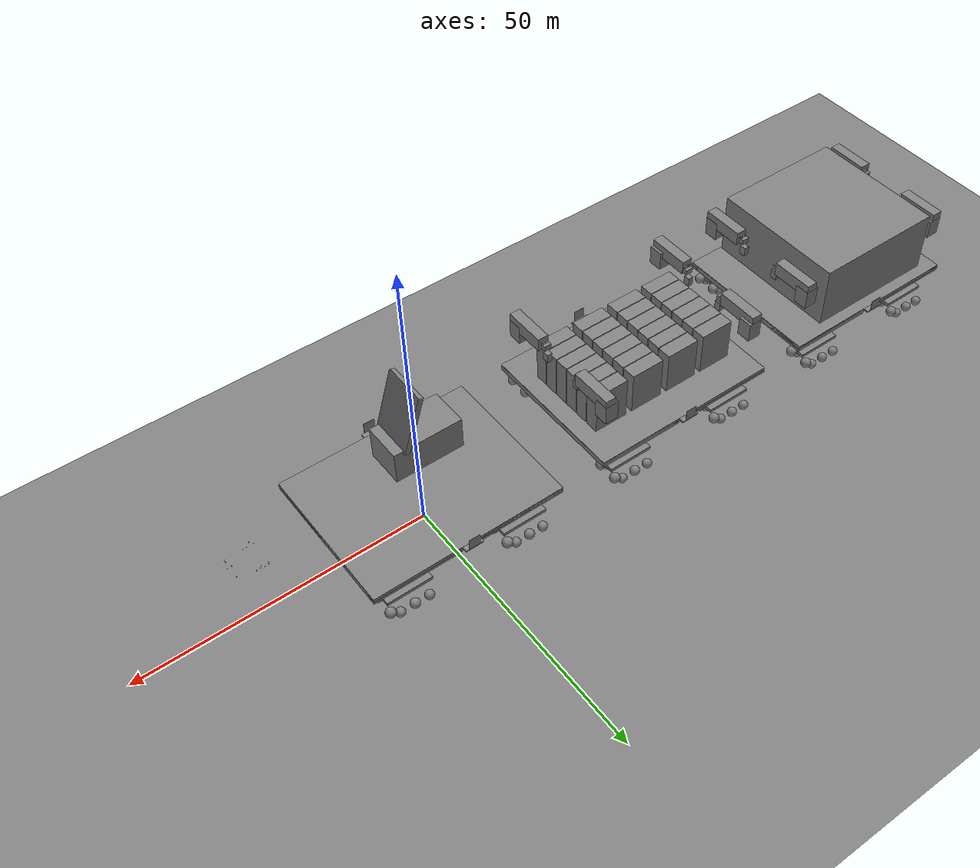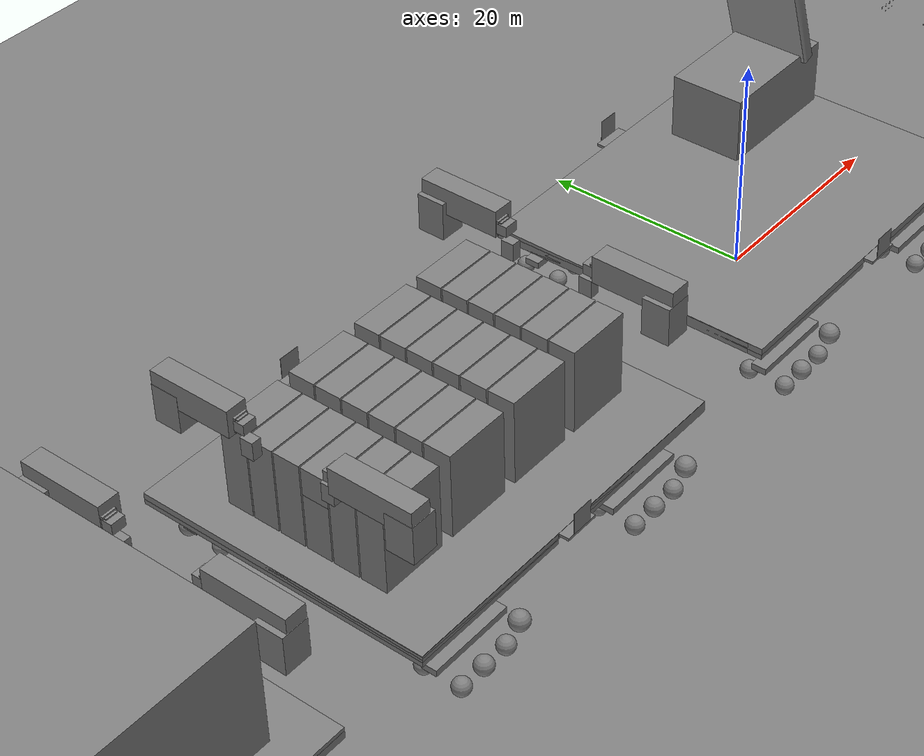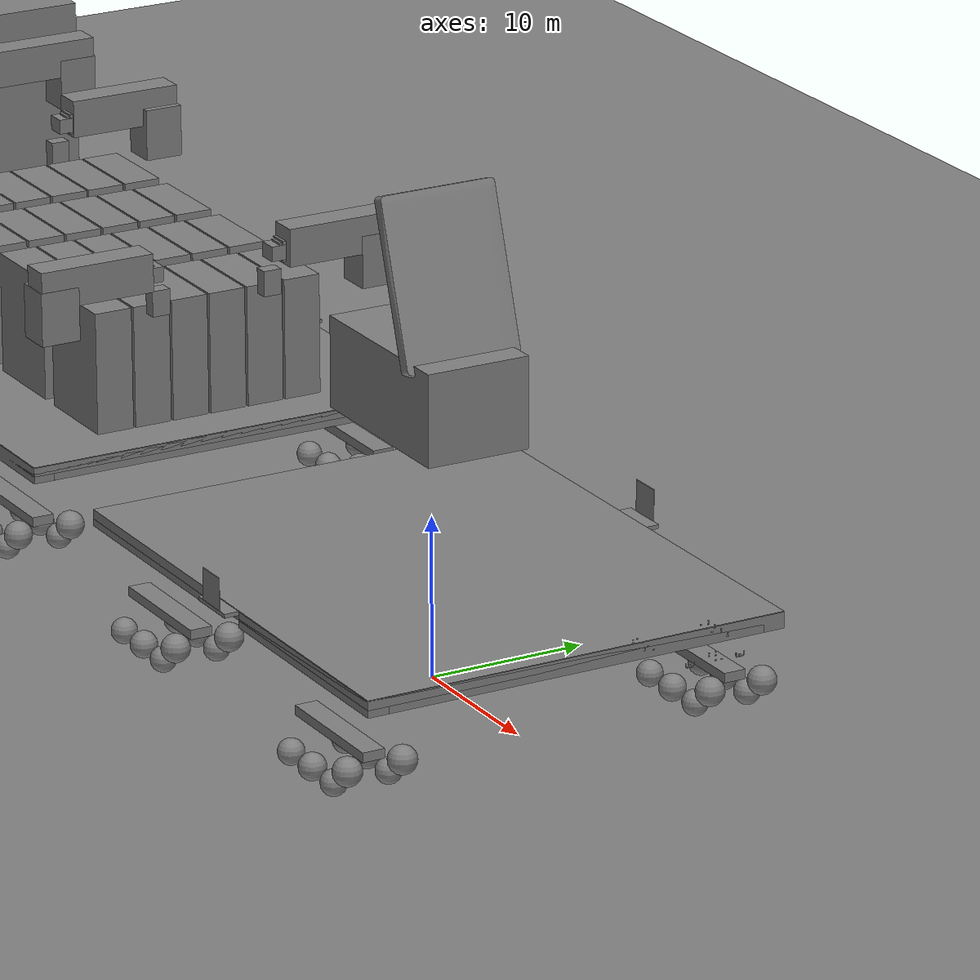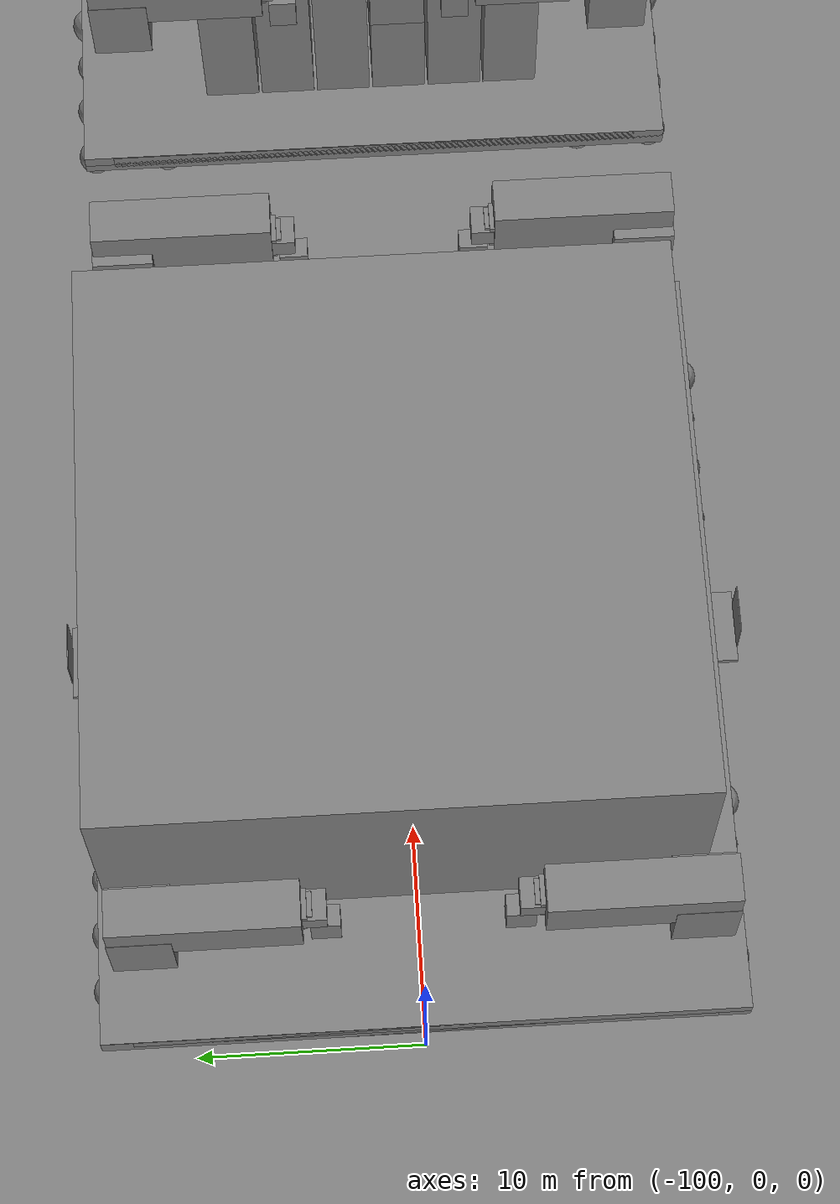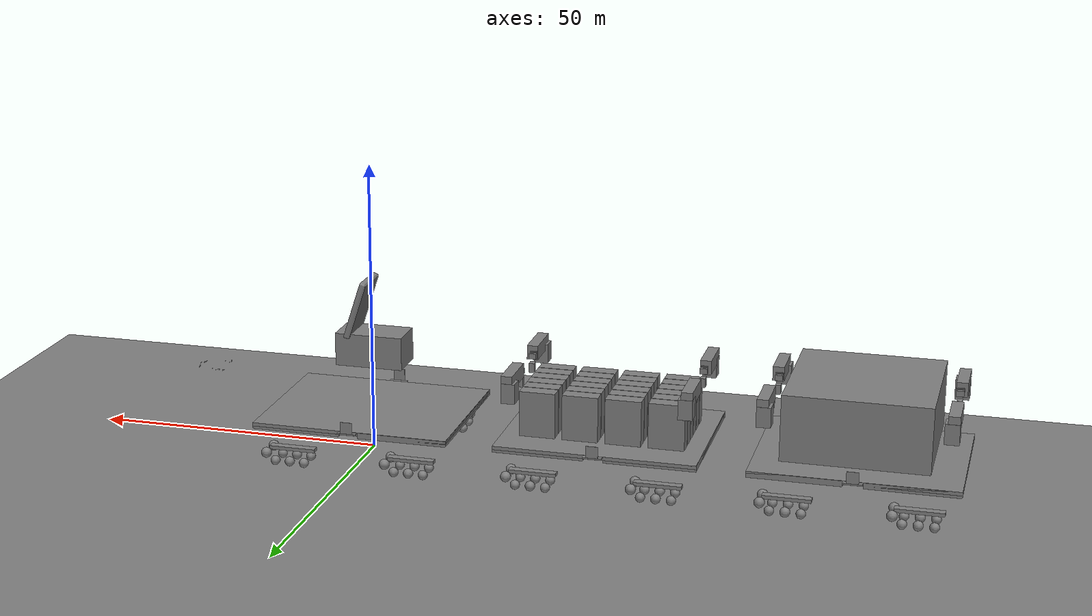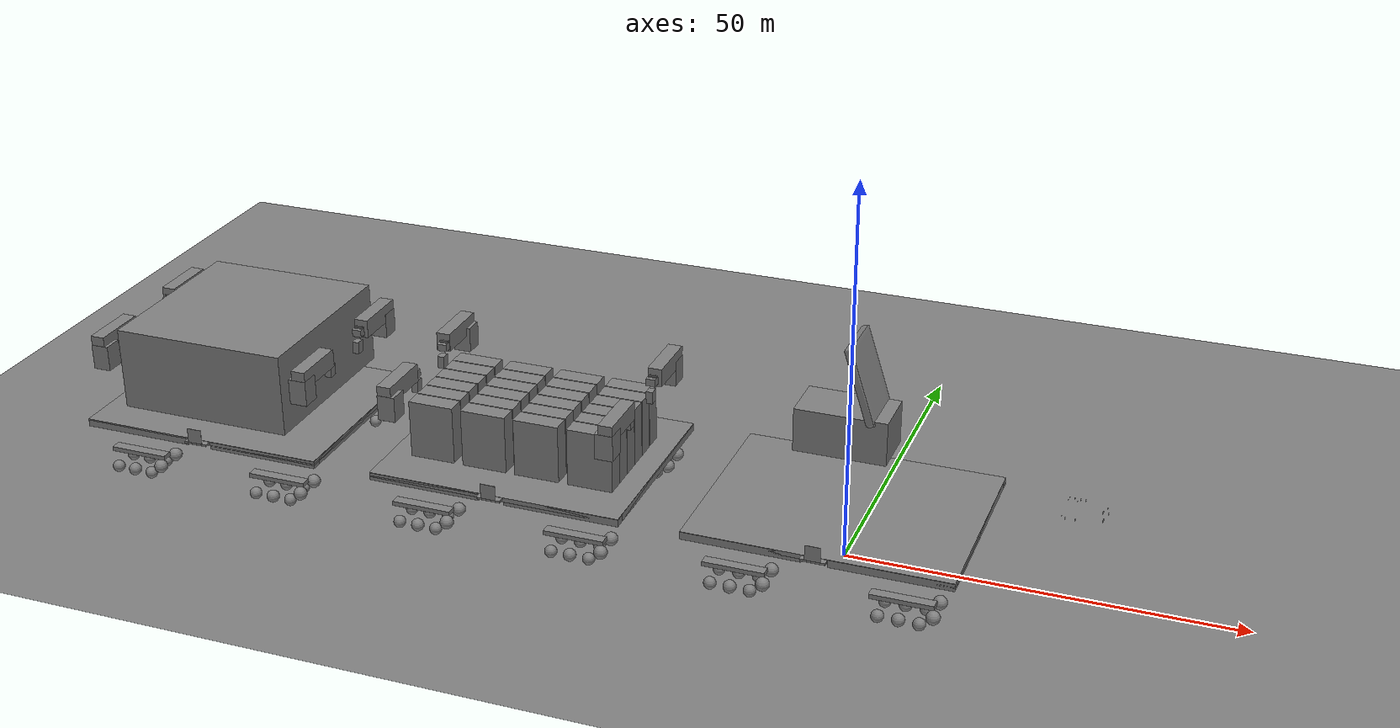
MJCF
<mujoco model="Leviathan003_three_modules_locked_containers">
  <compiler angle="radian" autolimits="true" />
  <option gravity="0 0 -9.81" timestep="0.005" integrator="implicitfast" iterations="60" tolerance="1e-9">
    <flag filterparent="disable" />
  </option>
  <worldbody>
    <body name="front" pos="0.0 0.0 9.889999999999999">
      <freejoint name="root" />
      <inertial pos="0.09858787400509852 6.395205359582339e-08 -0.35821194149093927" mass="4192127.7537001288" diaginertia="361469365.10108167 525718346.77808166 681791716.656273" />
      <body name="hitch_slide" pos="-21.0 0.0 -3.5">
        <inertial pos="0.0 0.0 0.0" mass="20000.0" diaginertia="25000.0 25000.0 25000.0" />
        <joint name="extension" type="slide" axis="-1.0 0.0 0.0" pos="0.0 0.0 0.0" limited="true" range="0.0 4.0" stiffness="0" damping="0" springref="0" solreflimit=".01 1" solimplimit=".99 .999 .001" />
        <body name="hitch_yaw">
          <inertial pos="0.0 0.0 0.0" mass="10000.0" diaginertia="12000.0 12000.0 12000.0" />
          <joint name="hitch_yaw" type="hinge" axis="0.0 0.0 1.0" pos="0.0 0.0 0.0" limited="true" range="-0.5235987755982988 0.5235987755982988" stiffness="0" damping="0" springref="0" solreflimit=".01 1" solimplimit=".99 .999 .001" />
          <body name="hitch_pitch" pos="-2.1999999999999993 0.0 0.0">
            <inertial pos="0.0 0.0 0.0" mass="10000.0" diaginertia="12000.0 12000.0 12000.0" />
            <joint name="hitch_pitch" type="hinge" axis="0.0 1.0 0.0" pos="0.0 0.0 0.0" limited="true" range="-0.13962634015954636 0.13962634015954636" stiffness="0" damping="0" springref="0" solreflimit=".01 1" solimplimit=".99 .999 .001" />
            <body name="rear" pos="-18.8 0.0 3.5">
              <joint name="hitch_roll" type="hinge" axis="1.0 0.0 0.0" pos="17.900000000000002 0.0 -3.5" limited="true" range="-0.10471975511965978 0.10471975511965978" stiffness="0" damping="0" springref="0" solreflimit=".01 1" solimplimit=".99 .999 .001" />
              <inertial pos="0.021870150134636293 0.0025994266200183407 -0.44158929116721285" mass="3982416.7069278974" diaginertia="281547293.69132984 408826164.26183164 530639337.61266327" />
              <geom type="box" size="17 13.5 .3" pos="0 0 -2.8" contype="0" conaffinity="0" mass="0" />
              <body name="rear_bogie_aft_right_heave" pos="-10.5 -11.8 -5.75">
                <inertial pos="0.0 0.0 0.0" mass="10000.0" diaginertia="20000.0 20000.0 20000.0" />
                <joint name="rear_bogie_aft_right_heave" type="slide" axis="0.0 0.0 1.0" pos="0.0 0.0 0.0" limited="true" range="-0.8 0.8" stiffness="29458028.571428575" damping="8902729.545096992" springref="-0.35" solreflimit=".01 1" solimplimit=".99 .999 .001" />
                <body name="rear_bogie_aft_right_yaw" pos="0 0 0">
                  <inertial pos="0.0 0.0 0.0" mass="10000.0" diaginertia="20000.0 20000.0 20000.0" />
                  <joint name="rear_bogie_aft_right_yaw" type="hinge" axis="0.0 0.0 1.0" pos="0.0 0.0 0.0" limited="true" range="-0.6108652381980153 0.6108652381980153" stiffness="0" damping="0" springref="0" solreflimit=".01 1" solimplimit=".99 .999 .001" />
                  <body name="rear_bogie_aft_right_pitch" pos="0 0 0">
                    <inertial pos="0.0 0.0 0.0" mass="10000.0" diaginertia="20000.0 20000.0 20000.0" />
                    <joint name="rear_bogie_aft_right_pitch" type="hinge" axis="0.0 1.0 0.0" pos="0.0 0.0 0.0" limited="true" range="-0.20943951023931956 0.20943951023931956" stiffness="8000000.0" damping="3000000.0" springref="0" solreflimit=".01 1" solimplimit=".99 .999 .001" />
                    <body name="rear_bogie_aft_right" pos="0 0 0">
                      <inertial pos="-0.3587808074440495 -8.628196338097777e-08 -1.3012958868290576" mass="98517.1217886434" diaginertia="302933.963040883 1112891.6630829324 1274169.1003605276" />
                      <joint name="rear_bogie_aft_right_roll" type="hinge" axis="1.0 0.0 0.0" pos="0.0 0.0 0.0" limited="true" range="-0.17453292519943295 0.17453292519943295" stiffness="8000000.0" damping="3000000.0" springref="0" solreflimit=".01 1" solimplimit=".99 .999 .001" />
                      <geom type="box" size="4 .7 .3" pos="0 0 -1.3" contype="0" conaffinity="0" mass="0" />
                      <body name="rear_bogie_aft_right_wheel_right_1" pos="-2.55 -1.75 -3.1">
                        <inertial pos="0.0 0.0 0.0" mass="12000.0" diaginertia="4480.000000000001 3840.000000000001 4480.000000000001" />
                        <joint name="rear_bogie_aft_right_wheel_right_1" type="slide" axis="0.0 0.0 1.0" pos="0.0 0.0 0.0" limited="true" range="-0.35 0.35" stiffness="0" damping="0" springref="-0.18" solreflimit=".01 1" solimplimit=".99 .999 .001" />
                        <geom type="sphere" size="0.8" contype="0" conaffinity="0" mass="0" />
                      </body>
                      <body name="rear_bogie_aft_right_wheel_right_2" pos="0.0 -1.75 -3.0700000000000003">
                        <inertial pos="0.0 0.0 0.0" mass="12000.0" diaginertia="4626.700000000001 4133.4 4626.700000000001" />
                        <joint name="rear_bogie_aft_right_wheel_right_2" type="slide" axis="0.0 0.0 1.0" pos="0.0 0.0 0.0" limited="true" range="-0.35 0.35" stiffness="0" damping="0" springref="-0.18" solreflimit=".01 1" solimplimit=".99 .999 .001" />
                        <geom type="sphere" size="0.83" contype="0" conaffinity="0" mass="0" />
                      </body>
                      <body name="rear_bogie_aft_right_wheel_right_3" pos="2.55 -1.75 -3.1">
                        <inertial pos="0.0 0.0 0.0" mass="12000.0" diaginertia="4480.000000000001 3840.000000000001 4480.000000000001" />
                        <joint name="rear_bogie_aft_right_wheel_right_3" type="slide" axis="0.0 0.0 1.0" pos="0.0 0.0 0.0" limited="true" range="-0.35 0.35" stiffness="0" damping="0" springref="-0.18" solreflimit=".01 1" solimplimit=".99 .999 .001" />
                        <geom type="sphere" size="0.8" contype="0" conaffinity="0" mass="0" />
                      </body>
                      <body name="rear_bogie_aft_right_wheel_left_1" pos="-2.55 1.75 -3.1">
                        <inertial pos="0.0 0.0 0.0" mass="12000.0" diaginertia="4480.000000000001 3840.000000000001 4480.000000000001" />
                        <joint name="rear_bogie_aft_right_wheel_left_1" type="slide" axis="0.0 0.0 1.0" pos="0.0 0.0 0.0" limited="true" range="-0.35 0.35" stiffness="0" damping="0" springref="-0.18" solreflimit=".01 1" solimplimit=".99 .999 .001" />
                        <geom type="sphere" size="0.8" contype="0" conaffinity="0" mass="0" />
                      </body>
                      <body name="rear_bogie_aft_right_wheel_left_2" pos="0.0 1.75 -3.0700000000000003">
                        <inertial pos="0.0 0.0 0.0" mass="12000.0" diaginertia="4626.700000000001 4133.4 4626.700000000001" />
                        <joint name="rear_bogie_aft_right_wheel_left_2" type="slide" axis="0.0 0.0 1.0" pos="0.0 0.0 0.0" limited="true" range="-0.35 0.35" stiffness="0" damping="0" springref="-0.18" solreflimit=".01 1" solimplimit=".99 .999 .001" />
                        <geom type="sphere" size="0.83" contype="0" conaffinity="0" mass="0" />
                      </body>
                      <body name="rear_bogie_aft_right_wheel_left_3" pos="2.55 1.75 -3.1">
                        <inertial pos="0.0 0.0 0.0" mass="12000.0" diaginertia="4480.000000000001 3840.000000000001 4480.000000000001" />
                        <joint name="rear_bogie_aft_right_wheel_left_3" type="slide" axis="0.0 0.0 1.0" pos="0.0 0.0 0.0" limited="true" range="-0.35 0.35" stiffness="0" damping="0" springref="-0.18" solreflimit=".01 1" solimplimit=".99 .999 .001" />
                        <geom type="sphere" size="0.8" contype="0" conaffinity="0" mass="0" />
                      </body>
                      <body name="rear_bogie_aft_right_idler_right" pos="4.15 -1.75 -1.85">
                        <inertial pos="0 0 0" mass="12000.0" diaginertia="4883.200000000001 4646.4 4883.200000000001" />
                        <joint name="rear_bogie_aft_right_idler_right" type="slide" axis="1 0 0" range="-0.32 0.24" stiffness="0" damping="0" solreflimit=".01 1" solimplimit=".99 .999 .001" />
                        <geom type="sphere" size="0.88" mass="0" contype="0" conaffinity="0" />
                      </body>
                      <body name="rear_bogie_aft_right_idler_left" pos="4.15 1.75 -1.85">
                        <inertial pos="0 0 0" mass="12000.0" diaginertia="4883.200000000001 4646.4 4883.200000000001" />
                        <joint name="rear_bogie_aft_right_idler_left" type="slide" axis="1 0 0" range="-0.32 0.24" stiffness="0" damping="0" solreflimit=".01 1" solimplimit=".99 .999 .001" />
                        <geom type="sphere" size="0.88" mass="0" contype="0" conaffinity="0" />
                      </body>
                    </body>
                  </body>
                </body>
              </body>
              <body name="rear_bogie_aft_left_heave" pos="-10.5 11.8 -5.75">
                <inertial pos="0.0 0.0 0.0" mass="10000.0" diaginertia="20000.0 20000.0 20000.0" />
                <joint name="rear_bogie_aft_left_heave" type="slide" axis="0.0 0.0 1.0" pos="0.0 0.0 0.0" limited="true" range="-0.8 0.8" stiffness="29458028.571428575" damping="8902729.545096992" springref="-0.35" solreflimit=".01 1" solimplimit=".99 .999 .001" />
                <body name="rear_bogie_aft_left_yaw" pos="0 0 0">
                  <inertial pos="0.0 0.0 0.0" mass="10000.0" diaginertia="20000.0 20000.0 20000.0" />
                  <joint name="rear_bogie_aft_left_yaw" type="hinge" axis="0.0 0.0 1.0" pos="0.0 0.0 0.0" limited="true" range="-0.6108652381980153 0.6108652381980153" stiffness="0" damping="0" springref="0" solreflimit=".01 1" solimplimit=".99 .999 .001" />
                  <body name="rear_bogie_aft_left_pitch" pos="0 0 0">
                    <inertial pos="0.0 0.0 0.0" mass="10000.0" diaginertia="20000.0 20000.0 20000.0" />
                    <joint name="rear_bogie_aft_left_pitch" type="hinge" axis="0.0 1.0 0.0" pos="0.0 0.0 0.0" limited="true" range="-0.20943951023931956 0.20943951023931956" stiffness="8000000.0" damping="3000000.0" springref="0" solreflimit=".01 1" solimplimit=".99 .999 .001" />
                    <body name="rear_bogie_aft_left" pos="0 0 0">
                      <inertial pos="-0.35878080744404944 8.628196266770964e-08 -1.3012958868290572" mass="98517.1217886434" diaginertia="302933.9630408861 1112891.6630829324 1274169.1003605307" />
                      <joint name="rear_bogie_aft_left_roll" type="hinge" axis="1.0 0.0 0.0" pos="0.0 0.0 0.0" limited="true" range="-0.17453292519943295 0.17453292519943295" stiffness="8000000.0" damping="3000000.0" springref="0" solreflimit=".01 1" solimplimit=".99 .999 .001" />
                      <geom type="box" size="4 .7 .3" pos="0 0 -1.3" contype="0" conaffinity="0" mass="0" />
                      <body name="rear_bogie_aft_left_wheel_right_1" pos="-2.55 -1.75 -3.1">
                        <inertial pos="0.0 0.0 0.0" mass="12000.0" diaginertia="4480.000000000001 3840.000000000001 4480.000000000001" />
                        <joint name="rear_bogie_aft_left_wheel_right_1" type="slide" axis="0.0 0.0 1.0" pos="0.0 0.0 0.0" limited="true" range="-0.35 0.35" stiffness="0" damping="0" springref="-0.18" solreflimit=".01 1" solimplimit=".99 .999 .001" />
                        <geom type="sphere" size="0.8" contype="0" conaffinity="0" mass="0" />
                      </body>
                      <body name="rear_bogie_aft_left_wheel_right_2" pos="0.0 -1.75 -3.0700000000000003">
                        <inertial pos="0.0 0.0 0.0" mass="12000.0" diaginertia="4626.700000000001 4133.4 4626.700000000001" />
                        <joint name="rear_bogie_aft_left_wheel_right_2" type="slide" axis="0.0 0.0 1.0" pos="0.0 0.0 0.0" limited="true" range="-0.35 0.35" stiffness="0" damping="0" springref="-0.18" solreflimit=".01 1" solimplimit=".99 .999 .001" />
                        <geom type="sphere" size="0.83" contype="0" conaffinity="0" mass="0" />
                      </body>
                      <body name="rear_bogie_aft_left_wheel_right_3" pos="2.55 -1.75 -3.1">
                        <inertial pos="0.0 0.0 0.0" mass="12000.0" diaginertia="4480.000000000001 3840.000000000001 4480.000000000001" />
                        <joint name="rear_bogie_aft_left_wheel_right_3" type="slide" axis="0.0 0.0 1.0" pos="0.0 0.0 0.0" limited="true" range="-0.35 0.35" stiffness="0" damping="0" springref="-0.18" solreflimit=".01 1" solimplimit=".99 .999 .001" />
                        <geom type="sphere" size="0.8" contype="0" conaffinity="0" mass="0" />
                      </body>
                      <body name="rear_bogie_aft_left_wheel_left_1" pos="-2.55 1.75 -3.1">
                        <inertial pos="0.0 0.0 0.0" mass="12000.0" diaginertia="4480.000000000001 3840.000000000001 4480.000000000001" />
                        <joint name="rear_bogie_aft_left_wheel_left_1" type="slide" axis="0.0 0.0 1.0" pos="0.0 0.0 0.0" limited="true" range="-0.35 0.35" stiffness="0" damping="0" springref="-0.18" solreflimit=".01 1" solimplimit=".99 .999 .001" />
                        <geom type="sphere" size="0.8" contype="0" conaffinity="0" mass="0" />
                      </body>
                      <body name="rear_bogie_aft_left_wheel_left_2" pos="0.0 1.75 -3.0700000000000003">
                        <inertial pos="0.0 0.0 0.0" mass="12000.0" diaginertia="4626.700000000001 4133.4 4626.700000000001" />
                        <joint name="rear_bogie_aft_left_wheel_left_2" type="slide" axis="0.0 0.0 1.0" pos="0.0 0.0 0.0" limited="true" range="-0.35 0.35" stiffness="0" damping="0" springref="-0.18" solreflimit=".01 1" solimplimit=".99 .999 .001" />
                        <geom type="sphere" size="0.83" contype="0" conaffinity="0" mass="0" />
                      </body>
                      <body name="rear_bogie_aft_left_wheel_left_3" pos="2.55 1.75 -3.1">
                        <inertial pos="0.0 0.0 0.0" mass="12000.0" diaginertia="4480.000000000001 3840.000000000001 4480.000000000001" />
                        <joint name="rear_bogie_aft_left_wheel_left_3" type="slide" axis="0.0 0.0 1.0" pos="0.0 0.0 0.0" limited="true" range="-0.35 0.35" stiffness="0" damping="0" springref="-0.18" solreflimit=".01 1" solimplimit=".99 .999 .001" />
                        <geom type="sphere" size="0.8" contype="0" conaffinity="0" mass="0" />
                      </body>
                      <body name="rear_bogie_aft_left_idler_right" pos="4.15 -1.75 -1.85">
                        <inertial pos="0 0 0" mass="12000.0" diaginertia="4883.200000000001 4646.4 4883.200000000001" />
                        <joint name="rear_bogie_aft_left_idler_right" type="slide" axis="1 0 0" range="-0.32 0.24" stiffness="0" damping="0" solreflimit=".01 1" solimplimit=".99 .999 .001" />
                        <geom type="sphere" size="0.88" mass="0" contype="0" conaffinity="0" />
                      </body>
                      <body name="rear_bogie_aft_left_idler_left" pos="4.15 1.75 -1.85">
                        <inertial pos="0 0 0" mass="12000.0" diaginertia="4883.200000000001 4646.4 4883.200000000001" />
                        <joint name="rear_bogie_aft_left_idler_left" type="slide" axis="1 0 0" range="-0.32 0.24" stiffness="0" damping="0" solreflimit=".01 1" solimplimit=".99 .999 .001" />
                        <geom type="sphere" size="0.88" mass="0" contype="0" conaffinity="0" />
                      </body>
                    </body>
                  </body>
                </body>
              </body>
              <body name="rear_bogie_fore_right_heave" pos="10.5 -11.8 -5.75">
                <inertial pos="0.0 0.0 0.0" mass="10000.0" diaginertia="20000.0 20000.0 20000.0" />
                <joint name="rear_bogie_fore_right_heave" type="slide" axis="0.0 0.0 1.0" pos="0.0 0.0 0.0" limited="true" range="-0.8 0.8" stiffness="29458028.571428575" damping="8902729.545096992" springref="-0.35" solreflimit=".01 1" solimplimit=".99 .999 .001" />
                <body name="rear_bogie_fore_right_yaw" pos="0 0 0">
                  <inertial pos="0.0 0.0 0.0" mass="10000.0" diaginertia="20000.0 20000.0 20000.0" />
                  <joint name="rear_bogie_fore_right_yaw" type="hinge" axis="0.0 0.0 1.0" pos="0.0 0.0 0.0" limited="true" range="-0.6108652381980153 0.6108652381980153" stiffness="0" damping="0" springref="0" solreflimit=".01 1" solimplimit=".99 .999 .001" />
                  <body name="rear_bogie_fore_right_pitch" pos="0 0 0">
                    <inertial pos="0.0 0.0 0.0" mass="10000.0" diaginertia="20000.0 20000.0 20000.0" />
                    <joint name="rear_bogie_fore_right_pitch" type="hinge" axis="0.0 1.0 0.0" pos="0.0 0.0 0.0" limited="true" range="-0.20943951023931956 0.20943951023931956" stiffness="8000000.0" damping="3000000.0" springref="0" solreflimit=".01 1" solimplimit=".99 .999 .001" />
                    <body name="rear_bogie_fore_right" pos="0 0 0">
                      <inertial pos="-0.35878080744408647 -8.628196574144491e-08 -1.3012958868290572" mass="98517.12178864337" diaginertia="302933.96304088016 1112891.6630825372 1274169.10036013" />
                      <joint name="rear_bogie_fore_right_roll" type="hinge" axis="1.0 0.0 0.0" pos="0.0 0.0 0.0" limited="true" range="-0.17453292519943295 0.17453292519943295" stiffness="8000000.0" damping="3000000.0" springref="0" solreflimit=".01 1" solimplimit=".99 .999 .001" />
                      <geom type="box" size="4 .7 .3" pos="0 0 -1.3" contype="0" conaffinity="0" mass="0" />
                      <body name="rear_bogie_fore_right_wheel_right_1" pos="-2.55 -1.75 -3.1">
                        <inertial pos="0.0 0.0 0.0" mass="12000.0" diaginertia="4480.000000000001 3840.000000000001 4480.000000000001" />
                        <joint name="rear_bogie_fore_right_wheel_right_1" type="slide" axis="0.0 0.0 1.0" pos="0.0 0.0 0.0" limited="true" range="-0.35 0.35" stiffness="0" damping="0" springref="-0.18" solreflimit=".01 1" solimplimit=".99 .999 .001" />
                        <geom type="sphere" size="0.8" contype="0" conaffinity="0" mass="0" />
                      </body>
                      <body name="rear_bogie_fore_right_wheel_right_2" pos="0.0 -1.75 -3.0700000000000003">
                        <inertial pos="0.0 0.0 0.0" mass="12000.0" diaginertia="4626.700000000001 4133.4 4626.700000000001" />
                        <joint name="rear_bogie_fore_right_wheel_right_2" type="slide" axis="0.0 0.0 1.0" pos="0.0 0.0 0.0" limited="true" range="-0.35 0.35" stiffness="0" damping="0" springref="-0.18" solreflimit=".01 1" solimplimit=".99 .999 .001" />
                        <geom type="sphere" size="0.83" contype="0" conaffinity="0" mass="0" />
                      </body>
                      <body name="rear_bogie_fore_right_wheel_right_3" pos="2.55 -1.75 -3.1">
                        <inertial pos="0.0 0.0 0.0" mass="12000.0" diaginertia="4480.000000000001 3840.000000000001 4480.000000000001" />
                        <joint name="rear_bogie_fore_right_wheel_right_3" type="slide" axis="0.0 0.0 1.0" pos="0.0 0.0 0.0" limited="true" range="-0.35 0.35" stiffness="0" damping="0" springref="-0.18" solreflimit=".01 1" solimplimit=".99 .999 .001" />
                        <geom type="sphere" size="0.8" contype="0" conaffinity="0" mass="0" />
                      </body>
                      <body name="rear_bogie_fore_right_wheel_left_1" pos="-2.55 1.75 -3.1">
                        <inertial pos="0.0 0.0 0.0" mass="12000.0" diaginertia="4480.000000000001 3840.000000000001 4480.000000000001" />
                        <joint name="rear_bogie_fore_right_wheel_left_1" type="slide" axis="0.0 0.0 1.0" pos="0.0 0.0 0.0" limited="true" range="-0.35 0.35" stiffness="0" damping="0" springref="-0.18" solreflimit=".01 1" solimplimit=".99 .999 .001" />
                        <geom type="sphere" size="0.8" contype="0" conaffinity="0" mass="0" />
                      </body>
                      <body name="rear_bogie_fore_right_wheel_left_2" pos="0.0 1.75 -3.0700000000000003">
                        <inertial pos="0.0 0.0 0.0" mass="12000.0" diaginertia="4626.700000000001 4133.4 4626.700000000001" />
                        <joint name="rear_bogie_fore_right_wheel_left_2" type="slide" axis="0.0 0.0 1.0" pos="0.0 0.0 0.0" limited="true" range="-0.35 0.35" stiffness="0" damping="0" springref="-0.18" solreflimit=".01 1" solimplimit=".99 .999 .001" />
                        <geom type="sphere" size="0.83" contype="0" conaffinity="0" mass="0" />
                      </body>
                      <body name="rear_bogie_fore_right_wheel_left_3" pos="2.55 1.75 -3.1">
                        <inertial pos="0.0 0.0 0.0" mass="12000.0" diaginertia="4480.000000000001 3840.000000000001 4480.000000000001" />
                        <joint name="rear_bogie_fore_right_wheel_left_3" type="slide" axis="0.0 0.0 1.0" pos="0.0 0.0 0.0" limited="true" range="-0.35 0.35" stiffness="0" damping="0" springref="-0.18" solreflimit=".01 1" solimplimit=".99 .999 .001" />
                        <geom type="sphere" size="0.8" contype="0" conaffinity="0" mass="0" />
                      </body>
                      <body name="rear_bogie_fore_right_idler_right" pos="4.15 -1.75 -1.85">
                        <inertial pos="0 0 0" mass="12000.0" diaginertia="4883.200000000001 4646.4 4883.200000000001" />
                        <joint name="rear_bogie_fore_right_idler_right" type="slide" axis="1 0 0" range="-0.32 0.24" stiffness="0" damping="0" solreflimit=".01 1" solimplimit=".99 .999 .001" />
                        <geom type="sphere" size="0.88" mass="0" contype="0" conaffinity="0" />
                      </body>
                      <body name="rear_bogie_fore_right_idler_left" pos="4.15 1.75 -1.85">
                        <inertial pos="0 0 0" mass="12000.0" diaginertia="4883.200000000001 4646.4 4883.200000000001" />
                        <joint name="rear_bogie_fore_right_idler_left" type="slide" axis="1 0 0" range="-0.32 0.24" stiffness="0" damping="0" solreflimit=".01 1" solimplimit=".99 .999 .001" />
                        <geom type="sphere" size="0.88" mass="0" contype="0" conaffinity="0" />
                      </body>
                    </body>
                  </body>
                </body>
              </body>
              <body name="rear_bogie_fore_left_heave" pos="10.5 11.8 -5.75">
                <inertial pos="0.0 0.0 0.0" mass="10000.0" diaginertia="20000.0 20000.0 20000.0" />
                <joint name="rear_bogie_fore_left_heave" type="slide" axis="0.0 0.0 1.0" pos="0.0 0.0 0.0" limited="true" range="-0.8 0.8" stiffness="29458028.571428575" damping="8902729.545096992" springref="-0.35" solreflimit=".01 1" solimplimit=".99 .999 .001" />
                <body name="rear_bogie_fore_left_yaw" pos="0 0 0">
                  <inertial pos="0.0 0.0 0.0" mass="10000.0" diaginertia="20000.0 20000.0 20000.0" />
                  <joint name="rear_bogie_fore_left_yaw" type="hinge" axis="0.0 0.0 1.0" pos="0.0 0.0 0.0" limited="true" range="-0.6108652381980153 0.6108652381980153" stiffness="0" damping="0" springref="0" solreflimit=".01 1" solimplimit=".99 .999 .001" />
                  <body name="rear_bogie_fore_left_pitch" pos="0 0 0">
                    <inertial pos="0.0 0.0 0.0" mass="10000.0" diaginertia="20000.0 20000.0 20000.0" />
                    <joint name="rear_bogie_fore_left_pitch" type="hinge" axis="0.0 1.0 0.0" pos="0.0 0.0 0.0" limited="true" range="-0.20943951023931956 0.20943951023931956" stiffness="8000000.0" damping="3000000.0" springref="0" solreflimit=".01 1" solimplimit=".99 .999 .001" />
                    <body name="rear_bogie_fore_left" pos="0 0 0">
                      <inertial pos="-0.3587808074440864 8.62819650308093e-08 -1.3012958868290572" mass="98517.12178864337" diaginertia="302933.96304088307 1112891.6630825375 1274169.100360133" />
                      <joint name="rear_bogie_fore_left_roll" type="hinge" axis="1.0 0.0 0.0" pos="0.0 0.0 0.0" limited="true" range="-0.17453292519943295 0.17453292519943295" stiffness="8000000.0" damping="3000000.0" springref="0" solreflimit=".01 1" solimplimit=".99 .999 .001" />
                      <geom type="box" size="4 .7 .3" pos="0 0 -1.3" contype="0" conaffinity="0" mass="0" />
                      <body name="rear_bogie_fore_left_wheel_right_1" pos="-2.55 -1.75 -3.1">
                        <inertial pos="0.0 0.0 0.0" mass="12000.0" diaginertia="4480.000000000001 3840.000000000001 4480.000000000001" />
                        <joint name="rear_bogie_fore_left_wheel_right_1" type="slide" axis="0.0 0.0 1.0" pos="0.0 0.0 0.0" limited="true" range="-0.35 0.35" stiffness="0" damping="0" springref="-0.18" solreflimit=".01 1" solimplimit=".99 .999 .001" />
                        <geom type="sphere" size="0.8" contype="0" conaffinity="0" mass="0" />
                      </body>
                      <body name="rear_bogie_fore_left_wheel_right_2" pos="0.0 -1.75 -3.0700000000000003">
                        <inertial pos="0.0 0.0 0.0" mass="12000.0" diaginertia="4626.700000000001 4133.4 4626.700000000001" />
                        <joint name="rear_bogie_fore_left_wheel_right_2" type="slide" axis="0.0 0.0 1.0" pos="0.0 0.0 0.0" limited="true" range="-0.35 0.35" stiffness="0" damping="0" springref="-0.18" solreflimit=".01 1" solimplimit=".99 .999 .001" />
                        <geom type="sphere" size="0.83" contype="0" conaffinity="0" mass="0" />
                      </body>
                      <body name="rear_bogie_fore_left_wheel_right_3" pos="2.55 -1.75 -3.1">
                        <inertial pos="0.0 0.0 0.0" mass="12000.0" diaginertia="4480.000000000001 3840.000000000001 4480.000000000001" />
                        <joint name="rear_bogie_fore_left_wheel_right_3" type="slide" axis="0.0 0.0 1.0" pos="0.0 0.0 0.0" limited="true" range="-0.35 0.35" stiffness="0" damping="0" springref="-0.18" solreflimit=".01 1" solimplimit=".99 .999 .001" />
                        <geom type="sphere" size="0.8" contype="0" conaffinity="0" mass="0" />
                      </body>
                      <body name="rear_bogie_fore_left_wheel_left_1" pos="-2.55 1.75 -3.1">
                        <inertial pos="0.0 0.0 0.0" mass="12000.0" diaginertia="4480.000000000001 3840.000000000001 4480.000000000001" />
                        <joint name="rear_bogie_fore_left_wheel_left_1" type="slide" axis="0.0 0.0 1.0" pos="0.0 0.0 0.0" limited="true" range="-0.35 0.35" stiffness="0" damping="0" springref="-0.18" solreflimit=".01 1" solimplimit=".99 .999 .001" />
                        <geom type="sphere" size="0.8" contype="0" conaffinity="0" mass="0" />
                      </body>
                      <body name="rear_bogie_fore_left_wheel_left_2" pos="0.0 1.75 -3.0700000000000003">
                        <inertial pos="0.0 0.0 0.0" mass="12000.0" diaginertia="4626.700000000001 4133.4 4626.700000000001" />
                        <joint name="rear_bogie_fore_left_wheel_left_2" type="slide" axis="0.0 0.0 1.0" pos="0.0 0.0 0.0" limited="true" range="-0.35 0.35" stiffness="0" damping="0" springref="-0.18" solreflimit=".01 1" solimplimit=".99 .999 .001" />
                        <geom type="sphere" size="0.83" contype="0" conaffinity="0" mass="0" />
                      </body>
                      <body name="rear_bogie_fore_left_wheel_left_3" pos="2.55 1.75 -3.1">
                        <inertial pos="0.0 0.0 0.0" mass="12000.0" diaginertia="4480.000000000001 3840.000000000001 4480.000000000001" />
                        <joint name="rear_bogie_fore_left_wheel_left_3" type="slide" axis="0.0 0.0 1.0" pos="0.0 0.0 0.0" limited="true" range="-0.35 0.35" stiffness="0" damping="0" springref="-0.18" solreflimit=".01 1" solimplimit=".99 .999 .001" />
                        <geom type="sphere" size="0.8" contype="0" conaffinity="0" mass="0" />
                      </body>
                      <body name="rear_bogie_fore_left_idler_right" pos="4.15 -1.75 -1.85">
                        <inertial pos="0 0 0" mass="12000.0" diaginertia="4883.200000000001 4646.4 4883.200000000001" />
                        <joint name="rear_bogie_fore_left_idler_right" type="slide" axis="1 0 0" range="-0.32 0.24" stiffness="0" damping="0" solreflimit=".01 1" solimplimit=".99 .999 .001" />
                        <geom type="sphere" size="0.88" mass="0" contype="0" conaffinity="0" />
                      </body>
                      <body name="rear_bogie_fore_left_idler_left" pos="4.15 1.75 -1.85">
                        <inertial pos="0 0 0" mass="12000.0" diaginertia="4883.200000000001 4646.4 4883.200000000001" />
                        <joint name="rear_bogie_fore_left_idler_left" type="slide" axis="1 0 0" range="-0.32 0.24" stiffness="0" damping="0" solreflimit=".01 1" solimplimit=".99 .999 .001" />
                        <geom type="sphere" size="0.88" mass="0" contype="0" conaffinity="0" />
                      </body>
                    </body>
                  </body>
                </body>
              </body>
              <body name="tail_hitch_slide" pos="-21.0 0.0 -3.5">
                <inertial pos="0.0 0.0 0.0" mass="20000.0" diaginertia="25000.0 25000.0 25000.0" />
                <joint name="tail_extension" type="slide" axis="-1.0 0.0 0.0" pos="0.0 0.0 0.0" limited="true" range="0.0 4.0" stiffness="0" damping="0" springref="0" solreflimit=".01 1" solimplimit=".99 .999 .001" />
                <body name="tail_hitch_yaw">
                  <inertial pos="0.0 0.0 0.0" mass="10000.0" diaginertia="12000.0 12000.0 12000.0" />
                  <joint name="tail_hitch_yaw" type="hinge" axis="0.0 0.0 1.0" pos="0.0 0.0 0.0" limited="true" range="-0.5235987755982988 0.5235987755982988" stiffness="0" damping="0" springref="0" solreflimit=".01 1" solimplimit=".99 .999 .001" />
                  <body name="tail_hitch_pitch" pos="-2.1999999999999993 0.0 0.0">
                    <inertial pos="0.0 0.0 0.0" mass="10000.0" diaginertia="12000.0 12000.0 12000.0" />
                    <joint name="tail_hitch_pitch" type="hinge" axis="0.0 1.0 0.0" pos="0.0 0.0 0.0" limited="true" range="-0.13962634015954636 0.13962634015954636" stiffness="0" damping="0" springref="0" solreflimit=".01 1" solimplimit=".99 .999 .001" />
                    <body name="tail" pos="-18.8 0.0 3.5">
                      <joint name="tail_hitch_roll" type="hinge" axis="1.0 0.0 0.0" pos="17.900000000000002 0.0 -3.5" limited="true" range="-0.10471975511965978 0.10471975511965978" stiffness="0" damping="0" springref="0" solreflimit=".01 1" solimplimit=".99 .999 .001" />
                      <inertial pos="1.2697797128938221e-08 -1.8237062742194297e-15 -0.554281723058641" mass="4038416.7069278867" diaginertia="339303940.5458215 457763079.67478126 598049832.7950277" />
                      <geom type="box" size="17 13.5 .3" pos="0 0 -2.8" contype="0" conaffinity="0" mass="0" />
                      <body name="tail_bogie_aft_right_heave" pos="-10.5 -11.8 -5.75">
                        <inertial pos="0.0 0.0 0.0" mass="10000.0" diaginertia="20000.0 20000.0 20000.0" />
                        <joint name="tail_bogie_aft_right_heave" type="slide" axis="0.0 0.0 1.0" pos="0.0 0.0 0.0" limited="true" range="-0.8 0.8" stiffness="29654228.571428575" damping="8962024.60391305" springref="-0.35" solreflimit=".01 1" solimplimit=".99 .999 .001" />
                        <body name="tail_bogie_aft_right_yaw" pos="0 0 0">
                          <inertial pos="0.0 0.0 0.0" mass="10000.0" diaginertia="20000.0 20000.0 20000.0" />
                          <joint name="tail_bogie_aft_right_yaw" type="hinge" axis="0.0 0.0 1.0" pos="0.0 0.0 0.0" limited="true" range="-0.6108652381980153 0.6108652381980153" stiffness="0" damping="0" springref="0" solreflimit=".01 1" solimplimit=".99 .999 .001" />
                          <body name="tail_bogie_aft_right_pitch" pos="0 0 0">
                            <inertial pos="0.0 0.0 0.0" mass="10000.0" diaginertia="20000.0 20000.0 20000.0" />
                            <joint name="tail_bogie_aft_right_pitch" type="hinge" axis="0.0 1.0 0.0" pos="0.0 0.0 0.0" limited="true" range="-0.20943951023931956 0.20943951023931956" stiffness="8000000.0" damping="3000000.0" springref="0" solreflimit=".01 1" solimplimit=".99 .999 .001" />
                            <body name="tail_bogie_aft_right" pos="0 0 0">
                              <inertial pos="-0.35878107711872514 -8.628199738793329e-08 -1.3012959152461323" mass="98517.12689077751" diaginertia="302933.9757698727 1112891.7940609434 1274169.2323982622" />
                              <joint name="tail_bogie_aft_right_roll" type="hinge" axis="1.0 0.0 0.0" pos="0.0 0.0 0.0" limited="true" range="-0.17453292519943295 0.17453292519943295" stiffness="8000000.0" damping="3000000.0" springref="0" solreflimit=".01 1" solimplimit=".99 .999 .001" />
                              <geom type="box" size="4 .7 .3" pos="0 0 -1.3" contype="0" conaffinity="0" mass="0" />
                              <body name="tail_bogie_aft_right_wheel_right_1" pos="-2.55 -1.75 -3.1">
                                <inertial pos="0.0 0.0 0.0" mass="12000.0" diaginertia="4480.000000000001 3840.000000000001 4480.000000000001" />
                                <joint name="tail_bogie_aft_right_wheel_right_1" type="slide" axis="0.0 0.0 1.0" pos="0.0 0.0 0.0" limited="true" range="-0.35 0.35" stiffness="0" damping="0" springref="-0.18" solreflimit=".01 1" solimplimit=".99 .999 .001" />
                                <geom type="sphere" size="0.8" contype="0" conaffinity="0" mass="0" />
                              </body>
                              <body name="tail_bogie_aft_right_wheel_right_2" pos="0.0 -1.75 -3.0700000000000003">
                                <inertial pos="0.0 0.0 0.0" mass="12000.0" diaginertia="4626.700000000001 4133.4 4626.700000000001" />
                                <joint name="tail_bogie_aft_right_wheel_right_2" type="slide" axis="0.0 0.0 1.0" pos="0.0 0.0 0.0" limited="true" range="-0.35 0.35" stiffness="0" damping="0" springref="-0.18" solreflimit=".01 1" solimplimit=".99 .999 .001" />
                                <geom type="sphere" size="0.83" contype="0" conaffinity="0" mass="0" />
                              </body>
                              <body name="tail_bogie_aft_right_wheel_right_3" pos="2.55 -1.75 -3.1">
                                <inertial pos="0.0 0.0 0.0" mass="12000.0" diaginertia="4480.000000000001 3840.000000000001 4480.000000000001" />
                                <joint name="tail_bogie_aft_right_wheel_right_3" type="slide" axis="0.0 0.0 1.0" pos="0.0 0.0 0.0" limited="true" range="-0.35 0.35" stiffness="0" damping="0" springref="-0.18" solreflimit=".01 1" solimplimit=".99 .999 .001" />
                                <geom type="sphere" size="0.8" contype="0" conaffinity="0" mass="0" />
                              </body>
                              <body name="tail_bogie_aft_right_wheel_left_1" pos="-2.55 1.75 -3.1">
                                <inertial pos="0.0 0.0 0.0" mass="12000.0" diaginertia="4480.000000000001 3840.000000000001 4480.000000000001" />
                                <joint name="tail_bogie_aft_right_wheel_left_1" type="slide" axis="0.0 0.0 1.0" pos="0.0 0.0 0.0" limited="true" range="-0.35 0.35" stiffness="0" damping="0" springref="-0.18" solreflimit=".01 1" solimplimit=".99 .999 .001" />
                                <geom type="sphere" size="0.8" contype="0" conaffinity="0" mass="0" />
                              </body>
                              <body name="tail_bogie_aft_right_wheel_left_2" pos="0.0 1.75 -3.0700000000000003">
                                <inertial pos="0.0 0.0 0.0" mass="12000.0" diaginertia="4626.700000000001 4133.4 4626.700000000001" />
                                <joint name="tail_bogie_aft_right_wheel_left_2" type="slide" axis="0.0 0.0 1.0" pos="0.0 0.0 0.0" limited="true" range="-0.35 0.35" stiffness="0" damping="0" springref="-0.18" solreflimit=".01 1" solimplimit=".99 .999 .001" />
                                <geom type="sphere" size="0.83" contype="0" conaffinity="0" mass="0" />
                              </body>
                              <body name="tail_bogie_aft_right_wheel_left_3" pos="2.55 1.75 -3.1">
                                <inertial pos="0.0 0.0 0.0" mass="12000.0" diaginertia="4480.000000000001 3840.000000000001 4480.000000000001" />
                                <joint name="tail_bogie_aft_right_wheel_left_3" type="slide" axis="0.0 0.0 1.0" pos="0.0 0.0 0.0" limited="true" range="-0.35 0.35" stiffness="0" damping="0" springref="-0.18" solreflimit=".01 1" solimplimit=".99 .999 .001" />
                                <geom type="sphere" size="0.8" contype="0" conaffinity="0" mass="0" />
                              </body>
                              <body name="tail_bogie_aft_right_idler_right" pos="4.15 -1.75 -1.85">
                                <inertial pos="0 0 0" mass="12000.0" diaginertia="4883.200000000001 4646.4 4883.200000000001" />
                                <joint name="tail_bogie_aft_right_idler_right" type="slide" axis="1 0 0" range="-0.32 0.24" stiffness="0" damping="0" solreflimit=".01 1" solimplimit=".99 .999 .001" />
                                <geom type="sphere" size="0.88" mass="0" contype="0" conaffinity="0" />
                              </body>
                              <body name="tail_bogie_aft_right_idler_left" pos="4.15 1.75 -1.85">
                                <inertial pos="0 0 0" mass="12000.0" diaginertia="4883.200000000001 4646.4 4883.200000000001" />
                                <joint name="tail_bogie_aft_right_idler_left" type="slide" axis="1 0 0" range="-0.32 0.24" stiffness="0" damping="0" solreflimit=".01 1" solimplimit=".99 .999 .001" />
                                <geom type="sphere" size="0.88" mass="0" contype="0" conaffinity="0" />
                              </body>
                            </body>
                          </body>
                        </body>
                      </body>
                      <body name="tail_bogie_aft_left_heave" pos="-10.5 11.8 -5.75">
                        <inertial pos="0.0 0.0 0.0" mass="10000.0" diaginertia="20000.0 20000.0 20000.0" />
                        <joint name="tail_bogie_aft_left_heave" type="slide" axis="0.0 0.0 1.0" pos="0.0 0.0 0.0" limited="true" range="-0.8 0.8" stiffness="29654228.571428575" damping="8962024.60391305" springref="-0.35" solreflimit=".01 1" solimplimit=".99 .999 .001" />
                        <body name="tail_bogie_aft_left_yaw" pos="0 0 0">
                          <inertial pos="0.0 0.0 0.0" mass="10000.0" diaginertia="20000.0 20000.0 20000.0" />
                          <joint name="tail_bogie_aft_left_yaw" type="hinge" axis="0.0 0.0 1.0" pos="0.0 0.0 0.0" limited="true" range="-0.6108652381980153 0.6108652381980153" stiffness="0" damping="0" springref="0" solreflimit=".01 1" solimplimit=".99 .999 .001" />
                          <body name="tail_bogie_aft_left_pitch" pos="0 0 0">
                            <inertial pos="0.0 0.0 0.0" mass="10000.0" diaginertia="20000.0 20000.0 20000.0" />
                            <joint name="tail_bogie_aft_left_pitch" type="hinge" axis="0.0 1.0 0.0" pos="0.0 0.0 0.0" limited="true" range="-0.20943951023931956 0.20943951023931956" stiffness="8000000.0" damping="3000000.0" springref="0" solreflimit=".01 1" solimplimit=".99 .999 .001" />
                            <body name="tail_bogie_aft_left" pos="0 0 0">
                              <inertial pos="-0.35878107711872514 8.62819966542181e-08 -1.3012959152461328" mass="98517.12689077751" diaginertia="302933.97576987406 1112891.794060943 1274169.232398263" />
                              <joint name="tail_bogie_aft_left_roll" type="hinge" axis="1.0 0.0 0.0" pos="0.0 0.0 0.0" limited="true" range="-0.17453292519943295 0.17453292519943295" stiffness="8000000.0" damping="3000000.0" springref="0" solreflimit=".01 1" solimplimit=".99 .999 .001" />
                              <geom type="box" size="4 .7 .3" pos="0 0 -1.3" contype="0" conaffinity="0" mass="0" />
                              <body name="tail_bogie_aft_left_wheel_right_1" pos="-2.55 -1.75 -3.1">
                                <inertial pos="0.0 0.0 0.0" mass="12000.0" diaginertia="4480.000000000001 3840.000000000001 4480.000000000001" />
                                <joint name="tail_bogie_aft_left_wheel_right_1" type="slide" axis="0.0 0.0 1.0" pos="0.0 0.0 0.0" limited="true" range="-0.35 0.35" stiffness="0" damping="0" springref="-0.18" solreflimit=".01 1" solimplimit=".99 .999 .001" />
                                <geom type="sphere" size="0.8" contype="0" conaffinity="0" mass="0" />
                              </body>
                              <body name="tail_bogie_aft_left_wheel_right_2" pos="0.0 -1.75 -3.0700000000000003">
                                <inertial pos="0.0 0.0 0.0" mass="12000.0" diaginertia="4626.700000000001 4133.4 4626.700000000001" />
                                <joint name="tail_bogie_aft_left_wheel_right_2" type="slide" axis="0.0 0.0 1.0" pos="0.0 0.0 0.0" limited="true" range="-0.35 0.35" stiffness="0" damping="0" springref="-0.18" solreflimit=".01 1" solimplimit=".99 .999 .001" />
                                <geom type="sphere" size="0.83" contype="0" conaffinity="0" mass="0" />
                              </body>
                              <body name="tail_bogie_aft_left_wheel_right_3" pos="2.55 -1.75 -3.1">
                                <inertial pos="0.0 0.0 0.0" mass="12000.0" diaginertia="4480.000000000001 3840.000000000001 4480.000000000001" />
                                <joint name="tail_bogie_aft_left_wheel_right_3" type="slide" axis="0.0 0.0 1.0" pos="0.0 0.0 0.0" limited="true" range="-0.35 0.35" stiffness="0" damping="0" springref="-0.18" solreflimit=".01 1" solimplimit=".99 .999 .001" />
                                <geom type="sphere" size="0.8" contype="0" conaffinity="0" mass="0" />
                              </body>
                              <body name="tail_bogie_aft_left_wheel_left_1" pos="-2.55 1.75 -3.1">
                                <inertial pos="0.0 0.0 0.0" mass="12000.0" diaginertia="4480.000000000001 3840.000000000001 4480.000000000001" />
                                <joint name="tail_bogie_aft_left_wheel_left_1" type="slide" axis="0.0 0.0 1.0" pos="0.0 0.0 0.0" limited="true" range="-0.35 0.35" stiffness="0" damping="0" springref="-0.18" solreflimit=".01 1" solimplimit=".99 .999 .001" />
                                <geom type="sphere" size="0.8" contype="0" conaffinity="0" mass="0" />
                              </body>
                              <body name="tail_bogie_aft_left_wheel_left_2" pos="0.0 1.75 -3.0700000000000003">
                                <inertial pos="0.0 0.0 0.0" mass="12000.0" diaginertia="4626.700000000001 4133.4 4626.700000000001" />
                                <joint name="tail_bogie_aft_left_wheel_left_2" type="slide" axis="0.0 0.0 1.0" pos="0.0 0.0 0.0" limited="true" range="-0.35 0.35" stiffness="0" damping="0" springref="-0.18" solreflimit=".01 1" solimplimit=".99 .999 .001" />
                                <geom type="sphere" size="0.83" contype="0" conaffinity="0" mass="0" />
                              </body>
                              <body name="tail_bogie_aft_left_wheel_left_3" pos="2.55 1.75 -3.1">
                                <inertial pos="0.0 0.0 0.0" mass="12000.0" diaginertia="4480.000000000001 3840.000000000001 4480.000000000001" />
                                <joint name="tail_bogie_aft_left_wheel_left_3" type="slide" axis="0.0 0.0 1.0" pos="0.0 0.0 0.0" limited="true" range="-0.35 0.35" stiffness="0" damping="0" springref="-0.18" solreflimit=".01 1" solimplimit=".99 .999 .001" />
                                <geom type="sphere" size="0.8" contype="0" conaffinity="0" mass="0" />
                              </body>
                              <body name="tail_bogie_aft_left_idler_right" pos="4.15 -1.75 -1.85">
                                <inertial pos="0 0 0" mass="12000.0" diaginertia="4883.200000000001 4646.4 4883.200000000001" />
                                <joint name="tail_bogie_aft_left_idler_right" type="slide" axis="1 0 0" range="-0.32 0.24" stiffness="0" damping="0" solreflimit=".01 1" solimplimit=".99 .999 .001" />
                                <geom type="sphere" size="0.88" mass="0" contype="0" conaffinity="0" />
                              </body>
                              <body name="tail_bogie_aft_left_idler_left" pos="4.15 1.75 -1.85">
                                <inertial pos="0 0 0" mass="12000.0" diaginertia="4883.200000000001 4646.4 4883.200000000001" />
                                <joint name="tail_bogie_aft_left_idler_left" type="slide" axis="1 0 0" range="-0.32 0.24" stiffness="0" damping="0" solreflimit=".01 1" solimplimit=".99 .999 .001" />
                                <geom type="sphere" size="0.88" mass="0" contype="0" conaffinity="0" />
                              </body>
                            </body>
                          </body>
                        </body>
                      </body>
                      <body name="tail_bogie_fore_right_heave" pos="10.5 -11.8 -5.75">
                        <inertial pos="0.0 0.0 0.0" mass="10000.0" diaginertia="20000.0 20000.0 20000.0" />
                        <joint name="tail_bogie_fore_right_heave" type="slide" axis="0.0 0.0 1.0" pos="0.0 0.0 0.0" limited="true" range="-0.8 0.8" stiffness="29654228.571428575" damping="8962024.60391305" springref="-0.35" solreflimit=".01 1" solimplimit=".99 .999 .001" />
                        <body name="tail_bogie_fore_right_yaw" pos="0 0 0">
                          <inertial pos="0.0 0.0 0.0" mass="10000.0" diaginertia="20000.0 20000.0 20000.0" />
                          <joint name="tail_bogie_fore_right_yaw" type="hinge" axis="0.0 0.0 1.0" pos="0.0 0.0 0.0" limited="true" range="-0.6108652381980153 0.6108652381980153" stiffness="0" damping="0" springref="0" solreflimit=".01 1" solimplimit=".99 .999 .001" />
                          <body name="tail_bogie_fore_right_pitch" pos="0 0 0">
                            <inertial pos="0.0 0.0 0.0" mass="10000.0" diaginertia="20000.0 20000.0 20000.0" />
                            <joint name="tail_bogie_fore_right_pitch" type="hinge" axis="0.0 1.0 0.0" pos="0.0 0.0 0.0" limited="true" range="-0.20943951023931956 0.20943951023931956" stiffness="8000000.0" damping="3000000.0" springref="0" solreflimit=".01 1" solimplimit=".99 .999 .001" />
                            <body name="tail_bogie_fore_right" pos="0 0 0">
                              <inertial pos="-0.3587810771186045 -8.628198877462319e-08 -1.3012959152461345" mass="98517.1268907776" diaginertia="302933.9757698835 1112891.7940627125 1274169.2324000462" />
                              <joint name="tail_bogie_fore_right_roll" type="hinge" axis="1.0 0.0 0.0" pos="0.0 0.0 0.0" limited="true" range="-0.17453292519943295 0.17453292519943295" stiffness="8000000.0" damping="3000000.0" springref="0" solreflimit=".01 1" solimplimit=".99 .999 .001" />
                              <geom type="box" size="4 .7 .3" pos="0 0 -1.3" contype="0" conaffinity="0" mass="0" />
                              <body name="tail_bogie_fore_right_wheel_right_1" pos="-2.55 -1.75 -3.1">
                                <inertial pos="0.0 0.0 0.0" mass="12000.0" diaginertia="4480.000000000001 3840.000000000001 4480.000000000001" />
                                <joint name="tail_bogie_fore_right_wheel_right_1" type="slide" axis="0.0 0.0 1.0" pos="0.0 0.0 0.0" limited="true" range="-0.35 0.35" stiffness="0" damping="0" springref="-0.18" solreflimit=".01 1" solimplimit=".99 .999 .001" />
                                <geom type="sphere" size="0.8" contype="0" conaffinity="0" mass="0" />
                              </body>
                              <body name="tail_bogie_fore_right_wheel_right_2" pos="0.0 -1.75 -3.0700000000000003">
                                <inertial pos="0.0 0.0 0.0" mass="12000.0" diaginertia="4626.700000000001 4133.4 4626.700000000001" />
                                <joint name="tail_bogie_fore_right_wheel_right_2" type="slide" axis="0.0 0.0 1.0" pos="0.0 0.0 0.0" limited="true" range="-0.35 0.35" stiffness="0" damping="0" springref="-0.18" solreflimit=".01 1" solimplimit=".99 .999 .001" />
                                <geom type="sphere" size="0.83" contype="0" conaffinity="0" mass="0" />
                              </body>
                              <body name="tail_bogie_fore_right_wheel_right_3" pos="2.55 -1.75 -3.1">
                                <inertial pos="0.0 0.0 0.0" mass="12000.0" diaginertia="4480.000000000001 3840.000000000001 4480.000000000001" />
                                <joint name="tail_bogie_fore_right_wheel_right_3" type="slide" axis="0.0 0.0 1.0" pos="0.0 0.0 0.0" limited="true" range="-0.35 0.35" stiffness="0" damping="0" springref="-0.18" solreflimit=".01 1" solimplimit=".99 .999 .001" />
                                <geom type="sphere" size="0.8" contype="0" conaffinity="0" mass="0" />
                              </body>
                              <body name="tail_bogie_fore_right_wheel_left_1" pos="-2.55 1.75 -3.1">
                                <inertial pos="0.0 0.0 0.0" mass="12000.0" diaginertia="4480.000000000001 3840.000000000001 4480.000000000001" />
                                <joint name="tail_bogie_fore_right_wheel_left_1" type="slide" axis="0.0 0.0 1.0" pos="0.0 0.0 0.0" limited="true" range="-0.35 0.35" stiffness="0" damping="0" springref="-0.18" solreflimit=".01 1" solimplimit=".99 .999 .001" />
                                <geom type="sphere" size="0.8" contype="0" conaffinity="0" mass="0" />
                              </body>
                              <body name="tail_bogie_fore_right_wheel_left_2" pos="0.0 1.75 -3.0700000000000003">
                                <inertial pos="0.0 0.0 0.0" mass="12000.0" diaginertia="4626.700000000001 4133.4 4626.700000000001" />
                                <joint name="tail_bogie_fore_right_wheel_left_2" type="slide" axis="0.0 0.0 1.0" pos="0.0 0.0 0.0" limited="true" range="-0.35 0.35" stiffness="0" damping="0" springref="-0.18" solreflimit=".01 1" solimplimit=".99 .999 .001" />
                                <geom type="sphere" size="0.83" contype="0" conaffinity="0" mass="0" />
                              </body>
                              <body name="tail_bogie_fore_right_wheel_left_3" pos="2.55 1.75 -3.1">
                                <inertial pos="0.0 0.0 0.0" mass="12000.0" diaginertia="4480.000000000001 3840.000000000001 4480.000000000001" />
                                <joint name="tail_bogie_fore_right_wheel_left_3" type="slide" axis="0.0 0.0 1.0" pos="0.0 0.0 0.0" limited="true" range="-0.35 0.35" stiffness="0" damping="0" springref="-0.18" solreflimit=".01 1" solimplimit=".99 .999 .001" />
                                <geom type="sphere" size="0.8" contype="0" conaffinity="0" mass="0" />
                              </body>
                              <body name="tail_bogie_fore_right_idler_right" pos="4.15 -1.75 -1.85">
                                <inertial pos="0 0 0" mass="12000.0" diaginertia="4883.200000000001 4646.4 4883.200000000001" />
                                <joint name="tail_bogie_fore_right_idler_right" type="slide" axis="1 0 0" range="-0.32 0.24" stiffness="0" damping="0" solreflimit=".01 1" solimplimit=".99 .999 .001" />
                                <geom type="sphere" size="0.88" mass="0" contype="0" conaffinity="0" />
                              </body>
                              <body name="tail_bogie_fore_right_idler_left" pos="4.15 1.75 -1.85">
                                <inertial pos="0 0 0" mass="12000.0" diaginertia="4883.200000000001 4646.4 4883.200000000001" />
                                <joint name="tail_bogie_fore_right_idler_left" type="slide" axis="1 0 0" range="-0.32 0.24" stiffness="0" damping="0" solreflimit=".01 1" solimplimit=".99 .999 .001" />
                                <geom type="sphere" size="0.88" mass="0" contype="0" conaffinity="0" />
                              </body>
                            </body>
                          </body>
                        </body>
                      </body>
                      <body name="tail_bogie_fore_left_heave" pos="10.5 11.8 -5.75">
                        <inertial pos="0.0 0.0 0.0" mass="10000.0" diaginertia="20000.0 20000.0 20000.0" />
                        <joint name="tail_bogie_fore_left_heave" type="slide" axis="0.0 0.0 1.0" pos="0.0 0.0 0.0" limited="true" range="-0.8 0.8" stiffness="29654228.571428575" damping="8962024.60391305" springref="-0.35" solreflimit=".01 1" solimplimit=".99 .999 .001" />
                        <body name="tail_bogie_fore_left_yaw" pos="0 0 0">
                          <inertial pos="0.0 0.0 0.0" mass="10000.0" diaginertia="20000.0 20000.0 20000.0" />
                          <joint name="tail_bogie_fore_left_yaw" type="hinge" axis="0.0 0.0 1.0" pos="0.0 0.0 0.0" limited="true" range="-0.6108652381980153 0.6108652381980153" stiffness="0" damping="0" springref="0" solreflimit=".01 1" solimplimit=".99 .999 .001" />
                          <body name="tail_bogie_fore_left_pitch" pos="0 0 0">
                            <inertial pos="0.0 0.0 0.0" mass="10000.0" diaginertia="20000.0 20000.0 20000.0" />
                            <joint name="tail_bogie_fore_left_pitch" type="hinge" axis="0.0 1.0 0.0" pos="0.0 0.0 0.0" limited="true" range="-0.20943951023931956 0.20943951023931956" stiffness="8000000.0" damping="3000000.0" springref="0" solreflimit=".01 1" solimplimit=".99 .999 .001" />
                            <body name="tail_bogie_fore_left" pos="0 0 0">
                              <inertial pos="-0.3587810771186044 8.628198799013285e-08 -1.301295915246134" mass="98517.12689077761" diaginertia="302933.975769885 1112891.7940627125 1274169.232400045" />
                              <joint name="tail_bogie_fore_left_roll" type="hinge" axis="1.0 0.0 0.0" pos="0.0 0.0 0.0" limited="true" range="-0.17453292519943295 0.17453292519943295" stiffness="8000000.0" damping="3000000.0" springref="0" solreflimit=".01 1" solimplimit=".99 .999 .001" />
                              <geom type="box" size="4 .7 .3" pos="0 0 -1.3" contype="0" conaffinity="0" mass="0" />
                              <body name="tail_bogie_fore_left_wheel_right_1" pos="-2.55 -1.75 -3.1">
                                <inertial pos="0.0 0.0 0.0" mass="12000.0" diaginertia="4480.000000000001 3840.000000000001 4480.000000000001" />
                                <joint name="tail_bogie_fore_left_wheel_right_1" type="slide" axis="0.0 0.0 1.0" pos="0.0 0.0 0.0" limited="true" range="-0.35 0.35" stiffness="0" damping="0" springref="-0.18" solreflimit=".01 1" solimplimit=".99 .999 .001" />
                                <geom type="sphere" size="0.8" contype="0" conaffinity="0" mass="0" />
                              </body>
                              <body name="tail_bogie_fore_left_wheel_right_2" pos="0.0 -1.75 -3.0700000000000003">
                                <inertial pos="0.0 0.0 0.0" mass="12000.0" diaginertia="4626.700000000001 4133.4 4626.700000000001" />
                                <joint name="tail_bogie_fore_left_wheel_right_2" type="slide" axis="0.0 0.0 1.0" pos="0.0 0.0 0.0" limited="true" range="-0.35 0.35" stiffness="0" damping="0" springref="-0.18" solreflimit=".01 1" solimplimit=".99 .999 .001" />
                                <geom type="sphere" size="0.83" contype="0" conaffinity="0" mass="0" />
                              </body>
                              <body name="tail_bogie_fore_left_wheel_right_3" pos="2.55 -1.75 -3.1">
                                <inertial pos="0.0 0.0 0.0" mass="12000.0" diaginertia="4480.000000000001 3840.000000000001 4480.000000000001" />
                                <joint name="tail_bogie_fore_left_wheel_right_3" type="slide" axis="0.0 0.0 1.0" pos="0.0 0.0 0.0" limited="true" range="-0.35 0.35" stiffness="0" damping="0" springref="-0.18" solreflimit=".01 1" solimplimit=".99 .999 .001" />
                                <geom type="sphere" size="0.8" contype="0" conaffinity="0" mass="0" />
                              </body>
                              <body name="tail_bogie_fore_left_wheel_left_1" pos="-2.55 1.75 -3.1">
                                <inertial pos="0.0 0.0 0.0" mass="12000.0" diaginertia="4480.000000000001 3840.000000000001 4480.000000000001" />
                                <joint name="tail_bogie_fore_left_wheel_left_1" type="slide" axis="0.0 0.0 1.0" pos="0.0 0.0 0.0" limited="true" range="-0.35 0.35" stiffness="0" damping="0" springref="-0.18" solreflimit=".01 1" solimplimit=".99 .999 .001" />
                                <geom type="sphere" size="0.8" contype="0" conaffinity="0" mass="0" />
                              </body>
                              <body name="tail_bogie_fore_left_wheel_left_2" pos="0.0 1.75 -3.0700000000000003">
                                <inertial pos="0.0 0.0 0.0" mass="12000.0" diaginertia="4626.700000000001 4133.4 4626.700000000001" />
                                <joint name="tail_bogie_fore_left_wheel_left_2" type="slide" axis="0.0 0.0 1.0" pos="0.0 0.0 0.0" limited="true" range="-0.35 0.35" stiffness="0" damping="0" springref="-0.18" solreflimit=".01 1" solimplimit=".99 .999 .001" />
                                <geom type="sphere" size="0.83" contype="0" conaffinity="0" mass="0" />
                              </body>
                              <body name="tail_bogie_fore_left_wheel_left_3" pos="2.55 1.75 -3.1">
                                <inertial pos="0.0 0.0 0.0" mass="12000.0" diaginertia="4480.000000000001 3840.000000000001 4480.000000000001" />
                                <joint name="tail_bogie_fore_left_wheel_left_3" type="slide" axis="0.0 0.0 1.0" pos="0.0 0.0 0.0" limited="true" range="-0.35 0.35" stiffness="0" damping="0" springref="-0.18" solreflimit=".01 1" solimplimit=".99 .999 .001" />
                                <geom type="sphere" size="0.8" contype="0" conaffinity="0" mass="0" />
                              </body>
                              <body name="tail_bogie_fore_left_idler_right" pos="4.15 -1.75 -1.85">
                                <inertial pos="0 0 0" mass="12000.0" diaginertia="4883.200000000001 4646.4 4883.200000000001" />
                                <joint name="tail_bogie_fore_left_idler_right" type="slide" axis="1 0 0" range="-0.32 0.24" stiffness="0" damping="0" solreflimit=".01 1" solimplimit=".99 .999 .001" />
                                <geom type="sphere" size="0.88" mass="0" contype="0" conaffinity="0" />
                              </body>
                              <body name="tail_bogie_fore_left_idler_left" pos="4.15 1.75 -1.85">
                                <inertial pos="0 0 0" mass="12000.0" diaginertia="4883.200000000001 4646.4 4883.200000000001" />
                                <joint name="tail_bogie_fore_left_idler_left" type="slide" axis="1 0 0" range="-0.32 0.24" stiffness="0" damping="0" solreflimit=".01 1" solimplimit=".99 .999 .001" />
                                <geom type="sphere" size="0.88" mass="0" contype="0" conaffinity="0" />
                              </body>
                            </body>
                          </body>
                        </body>
                      </body>
                      <body name="lift_tail_right_out" pos="0.0 -13.3 -2.674999999999999">
                        <inertial mass="450" pos="0 0 0" diaginertia="751.875 954.3750000000001 565.5000000000001" />
                        <joint name="lift_tail_right_out" type="slide" axis="0.0 -1.0 0.0" range="0.0 2.7" limited="true" damping="0" armature="20" solreflimit=".02 1" />
                        <body name="lift_tail_right_stage1" pos="0.0 0.0 0.0">
                          <inertial mass="180" pos="0 0 0" diaginertia="300.75 381.75000000000006 226.20000000000002" />
                          <joint name="lift_tail_right_stage1" type="slide" axis="0.0 0.0 -1.0" range="0.0 2.4499999999999997" limited="true" damping="0" armature="20" solreflimit=".02 1" />
                          <body name="lift_tail_right_stage2" pos="0.0 0.0 0.0">
                            <inertial mass="150" pos="0 0 0" diaginertia="250.625 318.12500000000006 188.50000000000003" />
                            <joint name="lift_tail_right_stage2" type="slide" axis="0.0 0.0 -1.0" range="0.0 2.4499999999999997" limited="true" damping="0" armature="20" solreflimit=".02 1" />
                            <body name="lift_tail_right_stage3" pos="0.0 0.0 0.0">
                              <inertial mass="600" pos="0 0 0" diaginertia="245.12500000000003 515.1250000000001 754.0000000000001" />
                              <joint name="lift_tail_right_stage3" type="slide" axis="0.0 0.0 -1.0" range="0.0 2.4499999999999997" limited="true" damping="0" armature="20" solreflimit=".02 1" />
                              <geom name="lift_tail_right_stage3_deck" type="box" size="1.6 1.1 .125" mass="0" contype="8" conaffinity="17" friction=".9 .005 .0001" />
                              <body name="lift_tail_right_ramp" pos="0.0 -1.0999999999999996 0.125">
                                <inertial mass="120.0" pos="0.0 0.0 1.0" diaginertia="40.016 80.0 40.016" />
                                <joint name="lift_tail_right_ramp" type="hinge" axis="1.0 0.0 0.0" range="0.0 1.76" limited="true" armature="5" damping="0" />
                                <geom name="lift_tail_right_ramp_plate" type="box" size="1.0 0.02 1.0" pos="0 0 1" mass="0" contype="8" conaffinity="17" friction=".9 .005 .0001" />
                              </body>
                            </body>
                          </body>
                        </body>
                      </body>
                      <body name="lift_tail_left_out" pos="0.0 13.3 -2.674999999999999">
                        <inertial mass="450" pos="0 0 0" diaginertia="751.875 954.3750000000001 565.5000000000001" />
                        <joint name="lift_tail_left_out" type="slide" axis="0.0 1.0 0.0" range="0.0 2.7" limited="true" damping="0" armature="20" solreflimit=".02 1" />
                        <body name="lift_tail_left_stage1" pos="0.0 0.0 0.0">
                          <inertial mass="180" pos="0 0 0" diaginertia="300.75 381.75000000000006 226.20000000000002" />
                          <joint name="lift_tail_left_stage1" type="slide" axis="0.0 0.0 -1.0" range="0.0 2.4499999999999997" limited="true" damping="0" armature="20" solreflimit=".02 1" />
                          <body name="lift_tail_left_stage2" pos="0.0 0.0 0.0">
                            <inertial mass="150" pos="0 0 0" diaginertia="250.625 318.12500000000006 188.50000000000003" />
                            <joint name="lift_tail_left_stage2" type="slide" axis="0.0 0.0 -1.0" range="0.0 2.4499999999999997" limited="true" damping="0" armature="20" solreflimit=".02 1" />
                            <body name="lift_tail_left_stage3" pos="0.0 0.0 0.0">
                              <inertial mass="600" pos="0 0 0" diaginertia="245.12500000000003 515.1250000000001 754.0000000000001" />
                              <joint name="lift_tail_left_stage3" type="slide" axis="0.0 0.0 -1.0" range="0.0 2.4499999999999997" limited="true" damping="0" armature="20" solreflimit=".02 1" />
                              <geom name="lift_tail_left_stage3_deck" type="box" size="1.6 1.1 .125" mass="0" contype="8" conaffinity="17" friction=".9 .005 .0001" />
                              <body name="lift_tail_left_ramp" pos="0.0 1.0999999999999996 0.125">
                                <inertial mass="120.0" pos="0.0 0.0 1.0" diaginertia="40.016 80.0 40.016" />
                                <joint name="lift_tail_left_ramp" type="hinge" axis="-1.0 0.0 0.0" range="0.0 1.76" limited="true" armature="5" damping="0" />
                                <geom name="lift_tail_left_ramp_plate" type="box" size="1.0 0.02 1.0" pos="0 0 1" mass="0" contype="8" conaffinity="17" friction=".9 .005 .0001" />
                              </body>
                            </body>
                          </body>
                        </body>
                      </body>
                      <geom name="tail_boarding_deck_0" type="box" size="17.0 12.15 0.5" pos="0.0 0.0 -3.05" mass="0" contype="8" conaffinity="16" />
                      <geom name="tail_boarding_deck_1" type="box" size="7.68 13.5 0.5" pos="-9.32 0.0 -3.05" mass="0" contype="8" conaffinity="16" />
                      <geom name="tail_boarding_deck_2" type="box" size="7.68 13.5 0.5" pos="9.32 0.0 -3.05" mass="0" contype="8" conaffinity="16" />
                      <geom name="lift_tail_right_boarding_bridge" type="box" size="1.55 .135 .03" pos="0.0 -12.05 -2.58" mass="0" contype="8" conaffinity="16" friction=".9 .005 .0001" />
                      <geom name="lift_tail_left_boarding_bridge" type="box" size="1.55 .135 .03" pos="0.0 12.05 -2.58" mass="0" contype="8" conaffinity="16" friction=".9 .005 .0001" />
                      <body name="tail_crane0_slew" pos="-14.699999999999989 -11.0 5.6999999999999975">
                        <joint name="tail_crane0_slew" type="hinge" axis="0.0 0.0 1.0" range="-2.9670597283903604 2.9670597283903604" limited="true" armature="100" damping="0" />
                        <inertial mass="10293.091687043303" pos="5.31557020622131e-10 0.14352526861739534 0.7643406459069872" diaginertia="10982.357987850623 12896.96378713653 9333.44183031666" />
                        <geom name="tail_crane0_slew_contact" type="box" pos="-7.105427357601002e-15 0.060000228881833095 0.6050000000000004" size="1.1849999999999952 1.260000228881836 1.6950000000000003" mass="0" contype="64" conaffinity="265" friction=".7 .005 .0001" />
                        <body name="tail_crane0_luff" pos="0.0 0.0 1.6799999999999997">
                          <joint name="tail_crane0_luff" type="hinge" axis="1.0 -0.0 0.0" range="0.0 0.6108652381980153" limited="true" armature="100" damping="0" />
                          <inertial mass="24444.63090735032" pos="-0.012521120009722608 2.255353066247663 0.38459367448202286" diaginertia="133052.18104550292 22064.74484241313 123271.2086693061" />
                          <geom name="tail_crane0_luff_contact" type="box" pos="-0.2185000000000059 2.589999618530272 0.6800000000000015" size="0.9465000000000003 3.740000381469728 1.2200000000000006" mass="0" contype="64" conaffinity="265" friction=".7 .005 .0001" />
                          <body name="tail_crane0_stage1" pos="0.0 0.0 0.0">
                            <joint name="tail_crane0_stage1" type="slide" axis="0.0 1.0 0.0" range="0.0 4.3" limited="true" armature="100" damping="0" />
                            <inertial mass="11830.948406922373" pos="-2.9984903449076228e-12 3.308010289406753 0.34000000000009223" diaginertia="45767.68385923417 4983.564733939392 45320.251267179294" />
                            <geom name="tail_crane0_stage1_contact" type="box" pos="0.0 3.265 0.33999999999999986" size="0.617999999999995 3.265 0.6675000000000004" mass="0" contype="64" conaffinity="265" friction=".7 .005 .0001" />
                            <body name="tail_crane0_stage2" pos="0.0 0.0 0.0">
                              <joint name="tail_crane0_stage2" type="slide" axis="0.0 1.0 0.0" range="0.0 4.0" limited="true" armature="100" damping="0" />
                              <inertial mass="8362.645078923155" pos="1.4352963262354024e-11 3.526720465321729 0.3399999999962944" diaginertia="31625.65415816498 2275.6385431320978 31428.45275154624" />
                              <geom name="tail_crane0_stage2_contact" type="box" pos="0.0 3.4750000000000005 0.33999999999999986" size="0.512999999999991 3.255 0.5474999999999994" mass="0" contype="64" conaffinity="265" friction=".7 .005 .0001" />
                              <body name="tail_crane0_extend" pos="0.0 0.0 0.0">
                                <joint name="tail_crane0_extend" type="slide" axis="0.0 1.0 0.0" range="0.0 3.8" limited="true" armature="100" damping="0" />
                                <inertial mass="6803.391104230466" pos="-1.0547296369622927e-10 4.25648751792552 0.33086138187063696" diaginertia="30271.478270732907 1238.9591414186498 30333.21697725342" />
                                <geom name="tail_crane0_extend_contact" type="box" pos="-1.3411067811830435e-09 3.864999389648433 0.2962503814697275" size="0.6299999986589029 3.4249993896484336 0.47624961853027337" mass="0" contype="64" conaffinity="265" friction=".7 .005 .0001" />
                              </body>
                            </body>
                          </body>
                        </body>
                      </body>
                      <body name="tail_crane1_slew" pos="14.699999999999989 -11.0 5.6999999999999975">
                        <joint name="tail_crane1_slew" type="hinge" axis="0.0 0.0 1.0" range="-2.9670597283903604 2.9670597283903604" limited="true" armature="100" damping="0" />
                        <inertial mass="10293.089891855794" pos="-5.325944130163407e-10 0.14352583643720074 0.7643403895718457" diaginertia="10982.358940260303 12896.965055453627 9333.43718259018" />
                        <geom name="tail_crane1_slew_contact" type="box" pos="0.0 0.06000022888183665 0.6050000000000004" size="1.1850000000000023 1.260000228881836 1.6950000000000003" mass="0" contype="64" conaffinity="265" friction=".7 .005 .0001" />
                        <body name="tail_crane1_luff" pos="0.0 0.0 1.6799999999999997">
                          <joint name="tail_crane1_luff" type="hinge" axis="1.0 -0.0 0.0" range="0.0 0.6108652381980153" limited="true" armature="100" damping="0" />
                          <inertial mass="24444.631081092" pos="0.012521119920435808 2.2553528665743237 0.3845937488560267" diaginertia="133052.1899516492 22064.745716862184 123271.21697054357" />
                          <geom name="tail_crane1_luff_contact" type="box" pos="0.2185000000000059 2.589999618530274 0.6800000000000015" size="0.9465000000000003 3.7400003814697262 1.2200000000000006" mass="0" contype="64" conaffinity="265" friction=".7 .005 .0001" />
                          <body name="tail_crane1_stage1" pos="0.0 0.0 0.0">
                            <joint name="tail_crane1_stage1" type="slide" axis="0.0 1.0 0.0" range="0.0 4.3" limited="true" armature="100" damping="0" />
                            <inertial mass="11830.948406922156" pos="2.8421709430404007e-13 3.308010289406613 0.3400000000004155" diaginertia="45767.6838591537 4983.564741926862 45320.25127522142" />
                            <geom name="tail_crane1_stage1_contact" type="box" pos="0.0 3.265 0.33999999999999986" size="0.617999999999995 3.265 0.6675000000000004" mass="0" contype="64" conaffinity="265" friction=".7 .005 .0001" />
                            <body name="tail_crane1_stage2" pos="0.0 0.0 0.0">
                              <joint name="tail_crane1_stage2" type="slide" axis="0.0 1.0 0.0" range="0.0 4.0" limited="true" armature="100" damping="0" />
                              <inertial mass="8362.645078921092" pos="-1.8900436771218665e-12 3.526720465319886 0.3400000000006713" diaginertia="31625.65415740081 2275.6385328660663 31428.45274181565" />
                              <geom name="tail_crane1_stage2_contact" type="box" pos="0.0 3.4750000000000005 0.33999999999999986" size="0.512999999999991 3.255 0.5474999999999994" mass="0" contype="64" conaffinity="265" friction=".7 .005 .0001" />
                              <body name="tail_crane1_extend" pos="0.0 0.0 0.0">
                                <joint name="tail_crane1_extend" type="slide" axis="0.0 1.0 0.0" range="0.0 3.8" limited="true" armature="100" damping="0" />
                                <inertial mass="6803.391833707602" pos="1.304556462855544e-10 4.256487843419727 0.33086136427993296" diaginertia="30271.4850495891 1238.9594064558316 30333.223923711455" />
                                <geom name="tail_crane1_extend_contact" type="box" pos="1.3411067811830435e-09 3.864999866485596 0.2962503814697275" size="0.6299999986589029 3.4249998664855963 0.47624961853027337" mass="0" contype="64" conaffinity="265" friction=".7 .005 .0001" />
                              </body>
                            </body>
                          </body>
                        </body>
                      </body>
                      <body name="tail_crane2_slew" pos="-14.699999999999989 11.0 5.6999999999999975">
                        <joint name="tail_crane2_slew" type="hinge" axis="0.0 0.0 1.0" range="-2.9670597283903604 2.9670597283903604" limited="true" armature="100" damping="0" />
                        <inertial mass="10293.091687043303" pos="5.315712314768462e-10 -0.14352526861739712 0.7643406459069837" diaginertia="10982.357987851909 12896.963787134804 9333.441830308986" />
                        <geom name="tail_crane2_slew_contact" type="box" pos="-7.105427357601002e-15 -0.060000228881833095 0.6050000000000004" size="1.1849999999999952 1.260000228881836 1.6950000000000003" mass="0" contype="64" conaffinity="265" friction=".7 .005 .0001" />
                        <body name="tail_crane2_luff" pos="0.0 0.0 1.6799999999999997">
                          <joint name="tail_crane2_luff" type="hinge" axis="-1.0 -0.0 0.0" range="0.0 0.6108652381980153" limited="true" armature="100" damping="0" />
                          <inertial mass="24444.630907350307" pos="-0.012521120013929021 -2.255353066247322 0.3845936744827192" diaginertia="133052.18104511587 22064.74483165944 123271.20865877124" />
                          <geom name="tail_crane2_luff_contact" type="box" pos="-0.2185000000000059 -2.589999618530272 0.6800000000000015" size="0.9465000000000003 3.740000381469728 1.2200000000000006" mass="0" contype="64" conaffinity="265" friction=".7 .005 .0001" />
                          <body name="tail_crane2_stage1" pos="0.0 0.0 0.0">
                            <joint name="tail_crane2_stage1" type="slide" axis="0.0 -1.0 0.0" range="0.0 4.3" limited="true" armature="100" damping="0" />
                            <inertial mass="11830.94840692191" pos="-5.4711790653527714e-12 -3.308010289406453 0.340000000000785" diaginertia="45767.68385906233 4983.564730719002 45320.25126406735" />
                            <geom name="tail_crane2_stage1_contact" type="box" pos="0.0 -3.265 0.33999999999999986" size="0.617999999999995 3.265 0.6675000000000004" mass="0" contype="64" conaffinity="265" friction=".7 .005 .0001" />
                            <body name="tail_crane2_stage2" pos="0.0 0.0 0.0">
                              <joint name="tail_crane2_stage2" type="slide" axis="0.0 -1.0 0.0" range="0.0 4.0" limited="true" armature="100" damping="0" />
                              <inertial mass="8362.645078923038" pos="1.3628209671878722e-11 -3.526720465321625 0.33999999999654307" diaginertia="31625.654158121008 2275.6385417066317 31428.45275016509" />
                              <geom name="tail_crane2_stage2_contact" type="box" pos="0.0 -3.4750000000000005 0.33999999999999986" size="0.512999999999991 3.255 0.5474999999999994" mass="0" contype="64" conaffinity="265" friction=".7 .005 .0001" />
                              <body name="tail_crane2_extend" pos="0.0 0.0 0.0">
                                <joint name="tail_crane2_extend" type="slide" axis="0.0 -1.0 0.0" range="0.0 3.8" limited="true" armature="100" damping="0" />
                                <inertial mass="6803.391104231258" pos="-1.0095391189679503e-10 -4.256487517926304 0.3308613818685693" diaginertia="30271.47827101738 1238.9591428473025 30333.2169784707" />
                                <geom name="tail_crane2_extend_contact" type="box" pos="-1.3411067811830435e-09 -3.864999389648433 0.2962503814697275" size="0.6299999986589029 3.4249993896484336 0.47624961853027337" mass="0" contype="64" conaffinity="265" friction=".7 .005 .0001" />
                              </body>
                            </body>
                          </body>
                        </body>
                      </body>
                      <body name="tail_crane3_slew" pos="14.699999999999989 11.0 5.6999999999999975">
                        <joint name="tail_crane3_slew" type="hinge" axis="0.0 0.0 1.0" range="-2.9670597283903604 2.9670597283903604" limited="true" armature="100" damping="0" />
                        <inertial mass="10293.089891855794" pos="-5.325944130163407e-10 -0.1435258364372043 0.7643403895718421" diaginertia="10982.35894026137 12896.965055451563 9333.43718258749" />
                        <geom name="tail_crane3_slew_contact" type="box" pos="0.0 -0.06000022888183665 0.6050000000000004" size="1.1850000000000023 1.260000228881836 1.6950000000000003" mass="0" contype="64" conaffinity="265" friction=".7 .005 .0001" />
                        <body name="tail_crane3_luff" pos="0.0 0.0 1.6799999999999997">
                          <joint name="tail_crane3_luff" type="hinge" axis="-1.0 -0.0 0.0" range="0.0 0.6108652381980153" limited="true" armature="100" damping="0" />
                          <inertial mass="24444.631081092004" pos="0.012521119919597368 -2.2553528665742917 0.38459374885607645" diaginertia="133052.18995161232 22064.745712488115 123271.2169661875" />
                          <geom name="tail_crane3_luff_contact" type="box" pos="0.2185000000000059 -2.589999618530274 0.6800000000000015" size="0.9465000000000003 3.7400003814697262 1.2200000000000006" mass="0" contype="64" conaffinity="265" friction=".7 .005 .0001" />
                          <body name="tail_crane3_stage1" pos="0.0 0.0 0.0">
                            <joint name="tail_crane3_stage1" type="slide" axis="0.0 -1.0 0.0" range="0.0 4.3" limited="true" armature="100" damping="0" />
                            <inertial mass="11830.948406922107" pos="-3.552713678800501e-13 -3.308010289406581 0.34000000000049013" diaginertia="45767.68385913581 4983.564742104235 45320.25127542334" />
                            <geom name="tail_crane3_stage1_contact" type="box" pos="0.0 -3.265 0.33999999999999986" size="0.617999999999995 3.265 0.6675000000000004" mass="0" contype="64" conaffinity="265" friction=".7 .005 .0001" />
                            <body name="tail_crane3_stage2" pos="0.0 0.0 0.0">
                              <joint name="tail_crane3_stage2" type="slide" axis="0.0 -1.0 0.0" range="0.0 4.0" limited="true" armature="100" damping="0" />
                              <inertial mass="8362.645078920912" pos="-4.305888978706207e-12 -3.526720465319725 0.3400000000010479" diaginertia="31625.654157335503 2275.63853024273 31428.452739240533" />
                              <geom name="tail_crane3_stage2_contact" type="box" pos="0.0 -3.4750000000000005 0.33999999999999986" size="0.512999999999991 3.255 0.5474999999999994" mass="0" contype="64" conaffinity="265" friction=".7 .005 .0001" />
                              <body name="tail_crane3_extend" pos="0.0 0.0 0.0">
                                <joint name="tail_crane3_extend" type="slide" axis="0.0 -1.0 0.0" range="0.0 3.8" limited="true" armature="100" damping="0" />
                                <inertial mass="6803.391833707964" pos="1.3230305739853065e-10 -4.256487843420087 0.3308613642789773" diaginertia="30271.485049719933 1238.9594076968388 30333.223924861664" />
                                <geom name="tail_crane3_extend_contact" type="box" pos="1.3411067811830435e-09 -3.864999866485596 0.2962503814697275" size="0.6299999986589029 3.4249998664855963 0.47624961853027337" mass="0" contype="64" conaffinity="265" friction=".7 .005 .0001" />
                              </body>
                            </body>
                          </body>
                        </body>
                      </body>
                      <geom name="tail_cargo_envelope_reservoir" type="box" pos="0.0 0.5474999999999977 5.01" size="11.930000000000007 12.2475 5.540000000000001" mass="0" contype="8" conaffinity="320" />
                      <geom name="walkable_tail_0" mass="0" group="4" contype="8" conaffinity="48" friction=".8 .002 .0002" type="box" pos="-8.89 -12.9 -1.905" size="7.11 0.0225 0.555" />
                      <geom name="walkable_tail_1" mass="0" group="4" contype="8" conaffinity="48" friction=".8 .002 .0002" type="box" pos="8.89 -12.9 -1.905" size="7.11 0.0225 0.555" />
                      <geom name="walkable_tail_2" mass="0" group="4" contype="8" conaffinity="48" friction=".8 .002 .0002" type="box" pos="-8.85 -12.9000001 -2.5" size="7.15 0.5499997139 0.03999996185" />
                      <geom name="walkable_tail_3" mass="0" group="4" contype="8" conaffinity="48" friction=".8 .002 .0002" type="box" pos="8.85 -12.9000001 -2.5" size="7.15 0.5499997139 0.03999996185" />
                      <geom name="walkable_tail_4" mass="0" group="4" contype="8" conaffinity="48" friction=".8 .002 .0002" type="box" pos="-8.89 12.9 -1.905" size="7.11 0.0225 0.555" />
                      <geom name="walkable_tail_5" mass="0" group="4" contype="8" conaffinity="48" friction=".8 .002 .0002" type="box" pos="8.89 12.9 -1.905" size="7.11 0.0225 0.555" />
                      <geom name="walkable_tail_6" mass="0" group="4" contype="8" conaffinity="48" friction=".8 .002 .0002" type="box" pos="-8.85 12.9000001 -2.5" size="7.15 0.5499997139 0.03999996185" />
                      <geom name="walkable_tail_7" mass="0" group="4" contype="8" conaffinity="48" friction=".8 .002 .0002" type="box" pos="8.85 12.9000001 -2.5" size="7.15 0.5499997139 0.03999996185" />
                    </body>
                  </body>
                </body>
              </body>
              <body name="lift_rear_right_out" pos="0.0 -13.3 -2.674999999999999">
                <inertial mass="450" pos="0 0 0" diaginertia="751.875 954.3750000000001 565.5000000000001" />
                <joint name="lift_rear_right_out" type="slide" axis="0.0 -1.0 0.0" range="0.0 2.7" limited="true" damping="0" armature="20" solreflimit=".02 1" />
                <body name="lift_rear_right_stage1" pos="0.0 0.0 0.0">
                  <inertial mass="180" pos="0 0 0" diaginertia="300.75 381.75000000000006 226.20000000000002" />
                  <joint name="lift_rear_right_stage1" type="slide" axis="0.0 0.0 -1.0" range="0.0 2.4499999999999997" limited="true" damping="0" armature="20" solreflimit=".02 1" />
                  <body name="lift_rear_right_stage2" pos="0.0 0.0 0.0">
                    <inertial mass="150" pos="0 0 0" diaginertia="250.625 318.12500000000006 188.50000000000003" />
                    <joint name="lift_rear_right_stage2" type="slide" axis="0.0 0.0 -1.0" range="0.0 2.4499999999999997" limited="true" damping="0" armature="20" solreflimit=".02 1" />
                    <body name="lift_rear_right_stage3" pos="0.0 0.0 0.0">
                      <inertial mass="600" pos="0 0 0" diaginertia="245.12500000000003 515.1250000000001 754.0000000000001" />
                      <joint name="lift_rear_right_stage3" type="slide" axis="0.0 0.0 -1.0" range="0.0 2.4499999999999997" limited="true" damping="0" armature="20" solreflimit=".02 1" />
                      <geom name="lift_rear_right_stage3_deck" type="box" size="1.6 1.1 .125" mass="0" contype="8" conaffinity="17" friction=".9 .005 .0001" />
                      <body name="lift_rear_right_ramp" pos="0.0 -1.0999999999999996 0.125">
                        <inertial mass="120.0" pos="0.0 0.0 1.0" diaginertia="40.016 80.0 40.016" />
                        <joint name="lift_rear_right_ramp" type="hinge" axis="1.0 0.0 0.0" range="0.0 1.76" limited="true" armature="5" damping="0" />
                        <geom name="lift_rear_right_ramp_plate" type="box" size="1.0 0.02 1.0" pos="0 0 1" mass="0" contype="8" conaffinity="17" friction=".9 .005 .0001" />
                      </body>
                    </body>
                  </body>
                </body>
              </body>
              <body name="lift_rear_left_out" pos="0.0 13.3 -2.674999999999999">
                <inertial mass="450" pos="0 0 0" diaginertia="751.875 954.3750000000001 565.5000000000001" />
                <joint name="lift_rear_left_out" type="slide" axis="0.0 1.0 0.0" range="0.0 2.7" limited="true" damping="0" armature="20" solreflimit=".02 1" />
                <body name="lift_rear_left_stage1" pos="0.0 0.0 0.0">
                  <inertial mass="180" pos="0 0 0" diaginertia="300.75 381.75000000000006 226.20000000000002" />
                  <joint name="lift_rear_left_stage1" type="slide" axis="0.0 0.0 -1.0" range="0.0 2.4499999999999997" limited="true" damping="0" armature="20" solreflimit=".02 1" />
                  <body name="lift_rear_left_stage2" pos="0.0 0.0 0.0">
                    <inertial mass="150" pos="0 0 0" diaginertia="250.625 318.12500000000006 188.50000000000003" />
                    <joint name="lift_rear_left_stage2" type="slide" axis="0.0 0.0 -1.0" range="0.0 2.4499999999999997" limited="true" damping="0" armature="20" solreflimit=".02 1" />
                    <body name="lift_rear_left_stage3" pos="0.0 0.0 0.0">
                      <inertial mass="600" pos="0 0 0" diaginertia="245.12500000000003 515.1250000000001 754.0000000000001" />
                      <joint name="lift_rear_left_stage3" type="slide" axis="0.0 0.0 -1.0" range="0.0 2.4499999999999997" limited="true" damping="0" armature="20" solreflimit=".02 1" />
                      <geom name="lift_rear_left_stage3_deck" type="box" size="1.6 1.1 .125" mass="0" contype="8" conaffinity="17" friction=".9 .005 .0001" />
                      <body name="lift_rear_left_ramp" pos="0.0 1.0999999999999996 0.125">
                        <inertial mass="120.0" pos="0.0 0.0 1.0" diaginertia="40.016 80.0 40.016" />
                        <joint name="lift_rear_left_ramp" type="hinge" axis="-1.0 0.0 0.0" range="0.0 1.76" limited="true" armature="5" damping="0" />
                        <geom name="lift_rear_left_ramp_plate" type="box" size="1.0 0.02 1.0" pos="0 0 1" mass="0" contype="8" conaffinity="17" friction=".9 .005 .0001" />
                      </body>
                    </body>
                  </body>
                </body>
              </body>
              <geom name="rear_boarding_deck_0" type="box" size="17.0 12.15 0.5" pos="0.0 0.0 -3.05" mass="0" contype="8" conaffinity="16" />
              <geom name="rear_boarding_deck_1" type="box" size="7.68 13.5 0.5" pos="-9.32 0.0 -3.05" mass="0" contype="8" conaffinity="16" />
              <geom name="rear_boarding_deck_2" type="box" size="7.68 13.5 0.5" pos="9.32 0.0 -3.05" mass="0" contype="8" conaffinity="16" />
              <geom name="lift_rear_right_boarding_bridge" type="box" size="1.55 .135 .03" pos="0.0 -12.05 -2.58" mass="0" contype="8" conaffinity="16" friction=".9 .005 .0001" />
              <geom name="lift_rear_left_boarding_bridge" type="box" size="1.55 .135 .03" pos="0.0 12.05 -2.58" mass="0" contype="8" conaffinity="16" friction=".9 .005 .0001" />
              <body name="rear_crane0_slew" pos="-14.700000000000003 -11.0 5.6999999999999975">
                <joint name="rear_crane0_slew" type="hinge" axis="0.0 0.0 1.0" range="-2.9670597283903604 2.9670597283903604" limited="true" armature="100" damping="0" />
                <inertial mass="10293.09168704331" pos="5.333831154530344e-10 0.14352526861747528 0.7643406459068665" diaginertia="10982.357987877222 12896.963790012145 9333.441833182236" />
                <geom name="rear_crane0_slew_contact" type="box" pos="-3.552713678800501e-15 0.060000228881833095 0.6050000000000004" size="1.1849999999999987 1.260000228881836 1.6950000000000003" mass="0" contype="64" conaffinity="265" friction=".7 .005 .0001" />
                <body name="rear_crane0_luff" pos="0.0 0.0 1.6799999999999997">
                  <joint name="rear_crane0_luff" type="hinge" axis="1.0 -0.0 0.0" range="0.0 0.6108652381980153" limited="true" armature="100" damping="0" />
                  <inertial mass="24444.63090735027" pos="-0.01252112000650385 2.2553530662481407 0.38459367448100323" diaginertia="133052.18104602562 22064.744845469802 123271.20867201728" />
                  <geom name="rear_crane0_luff_contact" type="box" pos="-0.2185000000000059 2.589999618530272 0.6800000000000015" size="0.9465000000000003 3.740000381469728 1.2200000000000006" mass="0" contype="64" conaffinity="265" friction=".7 .005 .0001" />
                  <body name="rear_crane0_stage1" pos="0.0 0.0 0.0">
                    <joint name="rear_crane0_stage1" type="slide" axis="0.0 1.0 0.0" range="0.0 4.3" limited="true" armature="100" damping="0" />
                    <inertial mass="11830.948406921301" pos="1.2079226507921703e-13 3.3080102894065213 0.34000000000066066" diaginertia="45767.68385909628 4983.564743826473 45320.25127715818" />
                    <geom name="rear_crane0_stage1_contact" type="box" pos="0.0 3.265 0.33999999999999986" size="0.617999999999995 3.265 0.6675000000000004" mass="0" contype="64" conaffinity="265" friction=".7 .005 .0001" />
                    <body name="rear_crane0_stage2" pos="0.0 0.0 0.0">
                      <joint name="rear_crane0_stage2" type="slide" axis="0.0 1.0 0.0" range="0.0 4.0" limited="true" armature="100" damping="0" />
                      <inertial mass="8362.645078921849" pos="-7.105427357601002e-15 3.52672046532014 0.3399999999999217" diaginertia="31625.654157532183 2275.6385338723026 31428.452742728976" />
                      <geom name="rear_crane0_stage2_contact" type="box" pos="0.0 3.4750000000000005 0.33999999999999986" size="0.5129999999999981 3.255 0.5474999999999994" mass="0" contype="64" conaffinity="265" friction=".7 .005 .0001" />
                      <body name="rear_crane0_extend" pos="0.0 0.0 0.0">
                        <joint name="rear_crane0_extend" type="slide" axis="0.0 1.0 0.0" range="0.0 3.8" limited="true" armature="100" damping="0" />
                        <inertial mass="6803.391104228389" pos="-1.298303686780855e-10 4.256487517924374 0.33086138187399783" diaginertia="30271.47827025814 1238.959118886864 30333.216955076514" />
                        <geom name="rear_crane0_extend_contact" type="box" pos="-1.3411067811830435e-09 3.864999389648433 0.2962503814697275" size="0.6299999986588958 3.4249993896484336 0.47624961853027337" mass="0" contype="64" conaffinity="265" friction=".7 .005 .0001" />
                      </body>
                    </body>
                  </body>
                </body>
              </body>
              <body name="rear_crane1_slew" pos="14.700000000000003 -11.0 5.6999999999999975">
                <joint name="rear_crane1_slew" type="hinge" axis="0.0 0.0 1.0" range="-2.9670597283903604 2.9670597283903604" limited="true" armature="100" damping="0" />
                <inertial mass="10293.089891855787" pos="-5.332445596195612e-10 0.14352583643727357 0.7643403895717356" diaginertia="10982.358940286358 12896.96505443097 9333.43718155785" />
                <geom name="rear_crane1_slew_contact" type="box" pos="-1.7763568394002505e-15 0.06000022888183665 0.6050000000000004" size="1.1850000000000005 1.260000228881836 1.6950000000000003" mass="0" contype="64" conaffinity="265" friction=".7 .005 .0001" />
                <body name="rear_crane1_luff" pos="0.0 0.0 1.6799999999999997">
                  <joint name="rear_crane1_luff" type="hinge" axis="1.0 -0.0 0.0" range="0.0 0.6108652381980153" limited="true" armature="100" damping="0" />
                  <inertial mass="24444.63108109226" pos="0.012521119919917112 2.255352866574423 0.3845937488558526" diaginertia="133052.18995172234 22064.74571162311 123271.21696527032" />
                  <geom name="rear_crane1_luff_contact" type="box" pos="0.2184999999999988 2.589999618530274 0.6800000000000015" size="0.9465000000000003 3.7400003814697262 1.2200000000000006" mass="0" contype="64" conaffinity="265" friction=".7 .005 .0001" />
                  <body name="rear_crane1_stage1" pos="0.0 0.0 0.0">
                    <joint name="rear_crane1_stage1" type="slide" axis="0.0 1.0 0.0" range="0.0 4.3" limited="true" armature="100" damping="0" />
                    <inertial mass="11830.948406921434" pos="-3.375077994860476e-13 3.3080102894066403 0.3400000000003729" diaginertia="45767.683859168406 4983.564741648914 45320.25127493086" />
                    <geom name="rear_crane1_stage1_contact" type="box" pos="0.0 3.265 0.33999999999999986" size="0.6179999999999986 3.265 0.6675000000000004" mass="0" contype="64" conaffinity="265" friction=".7 .005 .0001" />
                    <body name="rear_crane1_stage2" pos="0.0 0.0 0.0">
                      <joint name="rear_crane1_stage2" type="slide" axis="0.0 1.0 0.0" range="0.0 4.0" limited="true" armature="100" damping="0" />
                      <inertial mass="8362.64507892199" pos="-2.913225216616411e-13 3.5267204653202295 0.33999999999959485" diaginertia="31625.65415760229 2275.638534172257 31428.452742967987" />
                      <geom name="rear_crane1_stage2_contact" type="box" pos="0.0 3.4750000000000005 0.33999999999999986" size="0.5130000000000017 3.255 0.5474999999999994" mass="0" contype="64" conaffinity="265" friction=".7 .005 .0001" />
                      <body name="rear_crane1_extend" pos="0.0 0.0 0.0">
                        <joint name="rear_crane1_extend" type="slide" axis="0.0 1.0 0.0" range="0.0 3.8" limited="true" armature="100" damping="0" />
                        <inertial mass="6803.391833707043" pos="1.283808614971349e-10 4.256487843419903 0.33086136427971624" diaginertia="30271.485049604453 1238.9594058099624 30333.223923054793" />
                        <geom name="rear_crane1_extend_contact" type="box" pos="1.3411067811830435e-09 3.864999866485596 0.2962503814697275" size="0.6299999986588958 3.4249998664855963 0.47624961853027337" mass="0" contype="64" conaffinity="265" friction=".7 .005 .0001" />
                      </body>
                    </body>
                  </body>
                </body>
              </body>
              <body name="rear_crane2_slew" pos="-14.700000000000003 11.0 5.6999999999999975">
                <joint name="rear_crane2_slew" type="hinge" axis="0.0 0.0 1.0" range="-2.9670597283903604 2.9670597283903604" limited="true" armature="100" damping="0" />
                <inertial mass="10293.09168704331" pos="5.334044317351072e-10 -0.14352526861747883 0.7643406459068629" diaginertia="10982.357987878737 12896.963790024442 9333.44183319428" />
                <geom name="rear_crane2_slew_contact" type="box" pos="-3.552713678800501e-15 -0.060000228881833095 0.6050000000000004" size="1.1849999999999987 1.260000228881836 1.6950000000000003" mass="0" contype="64" conaffinity="265" friction=".7 .005 .0001" />
                <body name="rear_crane2_luff" pos="0.0 0.0 1.6799999999999997">
                  <joint name="rear_crane2_luff" type="hinge" axis="-1.0 -0.0 0.0" range="0.0 0.6108652381980153" limited="true" armature="100" damping="0" />
                  <inertial mass="24444.630907350285" pos="-0.012521120007370712 -2.2553530662479577 0.38459367448137627" diaginertia="133052.181045821 22064.74484388021 123271.20867054709" />
                  <geom name="rear_crane2_luff_contact" type="box" pos="-0.2185000000000059 -2.589999618530272 0.6800000000000015" size="0.9465000000000003 3.740000381469728 1.2200000000000006" mass="0" contype="64" conaffinity="265" friction=".7 .005 .0001" />
                  <body name="rear_crane2_stage1" pos="0.0 0.0 0.0">
                    <joint name="rear_crane2_stage1" type="slide" axis="0.0 -1.0 0.0" range="0.0 4.3" limited="true" armature="100" damping="0" />
                    <inertial mass="11830.94840692115" pos="-1.5560885913146194e-12 -3.3080102894064245 0.3400000000008845" diaginertia="45767.683859039964 4983.564741473885 45320.25127484912" />
                    <geom name="rear_crane2_stage1_contact" type="box" pos="0.0 -3.265 0.33999999999999986" size="0.617999999999995 3.265 0.6675000000000004" mass="0" contype="64" conaffinity="265" friction=".7 .005 .0001" />
                    <body name="rear_crane2_stage2" pos="0.0 0.0 0.0">
                      <joint name="rear_crane2_stage2" type="slide" axis="0.0 -1.0 0.0" range="0.0 4.0" limited="true" armature="100" damping="0" />
                      <inertial mass="8362.645078922083" pos="1.7053025658242404e-12 -3.5267204653203486 0.33999999999942077" diaginertia="31625.654157618585 2275.638535052222 31428.4527438523" />
                      <geom name="rear_crane2_stage2_contact" type="box" pos="0.0 -3.4750000000000005 0.33999999999999986" size="0.5129999999999981 3.255 0.5474999999999994" mass="0" contype="64" conaffinity="265" friction=".7 .005 .0001" />
                      <body name="rear_crane2_extend" pos="0.0 0.0 0.0">
                        <joint name="rear_crane2_extend" type="slide" axis="0.0 -1.0 0.0" range="0.0 3.8" limited="true" armature="100" damping="0" />
                        <inertial mass="6803.39110422873" pos="-1.290700879508222e-10 -4.256487517924711 0.33086138187312386" diaginertia="30271.478270378186 1238.9591188662903 30333.216954970518" />
                        <geom name="rear_crane2_extend_contact" type="box" pos="-1.3411067811830435e-09 -3.864999389648433 0.2962503814697275" size="0.6299999986588958 3.4249993896484336 0.47624961853027337" mass="0" contype="64" conaffinity="265" friction=".7 .005 .0001" />
                      </body>
                    </body>
                  </body>
                </body>
              </body>
              <body name="rear_crane3_slew" pos="14.700000000000003 11.0 5.6999999999999975">
                <joint name="rear_crane3_slew" type="hinge" axis="0.0 0.0 1.0" range="-2.9670597283903604 2.9670597283903604" limited="true" armature="100" damping="0" />
                <inertial mass="10293.089891855787" pos="-5.332410069058824e-10 -0.14352583643727534 0.764340389571732" diaginertia="10982.358940287544 12896.9650544332 9333.437181560264" />
                <geom name="rear_crane3_slew_contact" type="box" pos="-1.7763568394002505e-15 -0.06000022888183665 0.6050000000000004" size="1.1850000000000005 1.260000228881836 1.6950000000000003" mass="0" contype="64" conaffinity="265" friction=".7 .005 .0001" />
                <body name="rear_crane3_luff" pos="0.0 0.0 1.6799999999999997">
                  <joint name="rear_crane3_luff" type="hinge" axis="-1.0 -0.0 0.0" range="0.0 0.6108652381980153" limited="true" armature="100" damping="0" />
                  <inertial mass="24444.631081092262" pos="0.012521119919778556 -2.2553528665743734 0.38459374885594855" diaginertia="133052.18995166762 22064.74571148867 123271.21696516805" />
                  <geom name="rear_crane3_luff_contact" type="box" pos="0.2184999999999988 -2.589999618530274 0.6800000000000015" size="0.9465000000000003 3.7400003814697262 1.2200000000000006" mass="0" contype="64" conaffinity="265" friction=".7 .005 .0001" />
                  <body name="rear_crane3_stage1" pos="0.0 0.0 0.0">
                    <joint name="rear_crane3_stage1" type="slide" axis="0.0 -1.0 0.0" range="0.0 4.3" limited="true" armature="100" damping="0" />
                    <inertial mass="11830.948406921443" pos="-6.430411758628907e-13 -3.3080102894066457 0.34000000000036223" diaginertia="45767.68385916888 4983.564741408095 45320.25127469032" />
                    <geom name="rear_crane3_stage1_contact" type="box" pos="0.0 -3.265 0.33999999999999986" size="0.6179999999999986 3.265 0.6675000000000004" mass="0" contype="64" conaffinity="265" friction=".7 .005 .0001" />
                    <body name="rear_crane3_stage2" pos="0.0 0.0 0.0">
                      <joint name="rear_crane3_stage2" type="slide" axis="0.0 -1.0 0.0" range="0.0 4.0" limited="true" armature="100" damping="0" />
                      <inertial mass="8362.645078922133" pos="5.3290705182007514e-14 -3.5267204653203548 0.33999999999929287" diaginertia="31625.65415765466 2275.6385342179947 31428.452742977694" />
                      <geom name="rear_crane3_stage2_contact" type="box" pos="0.0 -3.4750000000000005 0.33999999999999986" size="0.5130000000000017 3.255 0.5474999999999994" mass="0" contype="64" conaffinity="265" friction=".7 .005 .0001" />
                      <body name="rear_crane3_extend" pos="0.0 0.0 0.0">
                        <joint name="rear_crane3_extend" type="slide" axis="0.0 -1.0 0.0" range="0.0 3.8" limited="true" armature="100" damping="0" />
                        <inertial mass="6803.391833707232" pos="1.2849810104853532e-10 -4.25648784342009 0.3308613642792295" diaginertia="30271.485049670242 1238.9594058204705 30333.223923017602" />
                        <geom name="rear_crane3_extend_contact" type="box" pos="1.3411067811830435e-09 -3.864999866485596 0.2962503814697275" size="0.6299999986588958 3.4249998664855963 0.47624961853027337" mass="0" contype="64" conaffinity="265" friction=".7 .005 .0001" />
                      </body>
                    </body>
                  </body>
                </body>
              </body>
              <geom name="rear_cargo_envelope_0_0" type="box" pos="-10.887 -6.47 1.456500000000002" size="3.0290000035762716 1.2190000035762791 3.8864999982118613" mass="0" contype="8" conaffinity="320" />
              <geom name="rear_cargo_envelope_0_1" type="box" pos="-10.887 -3.882 1.456500000000002" size="3.0290000035762716 1.2190000035762787 3.8864999982118613" mass="0" contype="8" conaffinity="320" />
              <geom name="rear_cargo_envelope_0_2" type="box" pos="-10.887 -1.294 0.16100000000000136" size="3.0290000035762716 1.2190000035762787 2.5909999982118608" mass="0" contype="8" conaffinity="320" />
              <geom name="rear_cargo_envelope_0_3" type="box" pos="-10.887 1.294 1.456500000000002" size="3.0290000035762716 1.2190000035762787 3.8864999982118613" mass="0" contype="8" conaffinity="320" />
              <geom name="rear_cargo_envelope_0_4" type="box" pos="-10.887 3.882 1.456500000000002" size="3.0290000035762716 1.2190000035762787 3.8864999982118613" mass="0" contype="8" conaffinity="320" />
              <geom name="rear_cargo_envelope_0_5" type="box" pos="-10.887 6.47 1.456500000000002" size="3.0290000035762716 1.2190000035762791 3.8864999982118613" mass="0" contype="8" conaffinity="320" />
              <geom name="rear_cargo_envelope_1_0" type="box" pos="-3.629000000000005 -6.47 1.456500000000002" size="3.029000003576286 1.2190000035762791 3.8864999982118613" mass="0" contype="8" conaffinity="320" />
              <geom name="rear_cargo_envelope_1_1" type="box" pos="-3.629000000000005 -3.882 1.456500000000002" size="3.029000003576286 1.2190000035762787 3.8864999982118613" mass="0" contype="8" conaffinity="320" />
              <geom name="rear_cargo_envelope_1_2" type="box" pos="-3.629000000000005 -1.294 1.456500000000002" size="3.029000003576286 1.2190000035762787 3.8864999982118613" mass="0" contype="8" conaffinity="320" />
              <geom name="rear_cargo_envelope_1_3" type="box" pos="-3.629000000000005 1.294 1.456500000000002" size="3.029000003576286 1.2190000035762787 3.8864999982118613" mass="0" contype="8" conaffinity="320" />
              <geom name="rear_cargo_envelope_1_4" type="box" pos="-3.629000000000005 3.882 1.456500000000002" size="3.029000003576286 1.2190000035762787 3.8864999982118613" mass="0" contype="8" conaffinity="320" />
              <geom name="rear_cargo_envelope_1_5" type="box" pos="-3.629000000000005 6.47 1.456500000000002" size="3.029000003576286 1.2190000035762791 3.8864999982118613" mass="0" contype="8" conaffinity="320" />
              <geom name="rear_cargo_envelope_2_0" type="box" pos="3.629000000000005 -6.47 1.456500000000002" size="3.029000003576286 1.2190000035762791 3.8864999982118613" mass="0" contype="8" conaffinity="320" />
              <geom name="rear_cargo_envelope_2_1" type="box" pos="3.629000000000005 -3.882 1.456500000000002" size="3.029000003576286 1.2190000035762787 3.8864999982118613" mass="0" contype="8" conaffinity="320" />
              <geom name="rear_cargo_envelope_2_2" type="box" pos="3.629000000000005 -1.294 1.456500000000002" size="3.029000003576286 1.2190000035762787 3.8864999982118613" mass="0" contype="8" conaffinity="320" />
              <geom name="rear_cargo_envelope_2_3" type="box" pos="3.629000000000005 1.294 1.456500000000002" size="3.029000003576286 1.2190000035762787 3.8864999982118613" mass="0" contype="8" conaffinity="320" />
              <geom name="rear_cargo_envelope_2_4" type="box" pos="3.629000000000005 3.882 1.456500000000002" size="3.029000003576286 1.2190000035762787 3.8864999982118613" mass="0" contype="8" conaffinity="320" />
              <geom name="rear_cargo_envelope_2_5" type="box" pos="3.629000000000005 6.47 1.456500000000002" size="3.029000003576286 1.2190000035762791 3.8864999982118613" mass="0" contype="8" conaffinity="320" />
              <geom name="rear_cargo_envelope_3_0" type="box" pos="10.887 -6.47 1.456500000000002" size="3.0290000035762716 1.2190000035762791 3.8864999982118613" mass="0" contype="8" conaffinity="320" />
              <geom name="rear_cargo_envelope_3_1" type="box" pos="10.887 -3.882 1.456500000000002" size="3.0290000035762716 1.2190000035762787 3.8864999982118613" mass="0" contype="8" conaffinity="320" />
              <geom name="rear_cargo_envelope_3_2" type="box" pos="10.887 -1.294 1.456500000000002" size="3.0290000035762716 1.2190000035762787 3.8864999982118613" mass="0" contype="8" conaffinity="320" />
              <geom name="rear_cargo_envelope_3_3" type="box" pos="10.887 1.294 1.456500000000002" size="3.0290000035762716 1.2190000035762787 3.8864999982118613" mass="0" contype="8" conaffinity="320" />
              <geom name="rear_cargo_envelope_3_4" type="box" pos="10.887 3.882 1.456500000000002" size="3.0290000035762716 1.2190000035762787 3.8864999982118613" mass="0" contype="8" conaffinity="320" />
              <geom name="rear_cargo_envelope_3_5" type="box" pos="10.887 6.47 1.456500000000002" size="3.0290000035762716 1.2190000035762791 3.8864999982118613" mass="0" contype="8" conaffinity="320" />
              <geom name="walkable_rear_0" mass="0" group="4" contype="8" conaffinity="48" friction=".8 .002 .0002" type="box" pos="-8.89 -12.9 -1.905" size="7.11 0.0225 0.555" />
              <geom name="walkable_rear_1" mass="0" group="4" contype="8" conaffinity="48" friction=".8 .002 .0002" type="box" pos="8.89 -12.9 -1.905" size="7.11 0.0225 0.555" />
              <geom name="walkable_rear_2" mass="0" group="4" contype="8" conaffinity="48" friction=".8 .002 .0002" type="box" pos="-8.85 -12.9000001 -2.5" size="7.15 0.5499997139 0.03999996185" />
              <geom name="walkable_rear_3" mass="0" group="4" contype="8" conaffinity="48" friction=".8 .002 .0002" type="box" pos="8.85 -12.9000001 -2.5" size="7.15 0.5499997139 0.03999996185" />
              <geom name="walkable_rear_4" mass="0" group="4" contype="8" conaffinity="48" friction=".8 .002 .0002" type="box" pos="-8.89 12.9 -1.905" size="7.11 0.0225 0.555" />
              <geom name="walkable_rear_5" mass="0" group="4" contype="8" conaffinity="48" friction=".8 .002 .0002" type="box" pos="8.89 12.9 -1.905" size="7.11 0.0225 0.555" />
              <geom name="walkable_rear_6" mass="0" group="4" contype="8" conaffinity="48" friction=".8 .002 .0002" type="box" pos="-8.85 12.9000001 -2.5" size="7.15 0.5499997139 0.03999996185" />
              <geom name="walkable_rear_7" mass="0" group="4" contype="8" conaffinity="48" friction=".8 .002 .0002" type="box" pos="8.85 12.9000001 -2.5" size="7.15 0.5499997139 0.03999996185" />
            </body>
          </body>
        </body>
      </body>
      <geom type="box" size="17 13.5 .3" pos="0 0 -2.8" contype="0" conaffinity="0" mass="0" />
      <body name="front_bogie_aft_right_heave" pos="-10.5 -11.8 -5.75">
        <inertial pos="0.0 0.0 0.0" mass="10000.0" diaginertia="20000.0 20000.0 20000.0" />
        <joint name="front_bogie_aft_right_heave" type="slide" axis="0.0 0.0 1.0" pos="0.0 0.0 0.0" limited="true" range="-0.8 0.8" stiffness="29654228.571428575" damping="8962024.60391305" springref="-0.35" solreflimit=".01 1" solimplimit=".99 .999 .001" />
        <body name="front_bogie_aft_right_yaw" pos="0 0 0">
          <inertial pos="0.0 0.0 0.0" mass="10000.0" diaginertia="20000.0 20000.0 20000.0" />
          <joint name="front_bogie_aft_right_yaw" type="hinge" axis="0.0 0.0 1.0" pos="0.0 0.0 0.0" limited="true" range="-0.6108652381980153 0.6108652381980153" stiffness="0" damping="0" springref="0" solreflimit=".01 1" solimplimit=".99 .999 .001" />
          <body name="front_bogie_aft_right_pitch" pos="0 0 0">
            <inertial pos="0.0 0.0 0.0" mass="10000.0" diaginertia="20000.0 20000.0 20000.0" />
            <joint name="front_bogie_aft_right_pitch" type="hinge" axis="0.0 1.0 0.0" pos="0.0 0.0 0.0" limited="true" range="-0.20943951023931956 0.20943951023931956" stiffness="8000000.0" damping="3000000.0" springref="0" solreflimit=".01 1" solimplimit=".99 .999 .001" />
            <body name="front_bogie_aft_right" pos="0 0 0">
              <inertial pos="-0.35878085991132674 -8.628200017074338e-08 -1.3012958872088438" mass="98517.12185682826" diaginertia="302933.96652072686 1112891.7017524468 1274169.1373815339" />
              <joint name="front_bogie_aft_right_roll" type="hinge" axis="1.0 0.0 0.0" pos="0.0 0.0 0.0" limited="true" range="-0.17453292519943295 0.17453292519943295" stiffness="8000000.0" damping="3000000.0" springref="0" solreflimit=".01 1" solimplimit=".99 .999 .001" />
              <geom type="box" size="4 .7 .3" pos="0 0 -1.3" contype="0" conaffinity="0" mass="0" />
              <body name="front_bogie_aft_right_wheel_right_1" pos="-2.55 -1.75 -3.1">
                <inertial pos="0.0 0.0 0.0" mass="12000.0" diaginertia="4480.000000000001 3840.000000000001 4480.000000000001" />
                <joint name="front_bogie_aft_right_wheel_right_1" type="slide" axis="0.0 0.0 1.0" pos="0.0 0.0 0.0" limited="true" range="-0.35 0.35" stiffness="0" damping="0" springref="-0.18" solreflimit=".01 1" solimplimit=".99 .999 .001" />
                <geom type="sphere" size="0.8" contype="0" conaffinity="0" mass="0" />
              </body>
              <body name="front_bogie_aft_right_wheel_right_2" pos="0.0 -1.75 -3.0700000000000003">
                <inertial pos="0.0 0.0 0.0" mass="12000.0" diaginertia="4626.700000000001 4133.4 4626.700000000001" />
                <joint name="front_bogie_aft_right_wheel_right_2" type="slide" axis="0.0 0.0 1.0" pos="0.0 0.0 0.0" limited="true" range="-0.35 0.35" stiffness="0" damping="0" springref="-0.18" solreflimit=".01 1" solimplimit=".99 .999 .001" />
                <geom type="sphere" size="0.83" contype="0" conaffinity="0" mass="0" />
              </body>
              <body name="front_bogie_aft_right_wheel_right_3" pos="2.55 -1.75 -3.1">
                <inertial pos="0.0 0.0 0.0" mass="12000.0" diaginertia="4480.000000000001 3840.000000000001 4480.000000000001" />
                <joint name="front_bogie_aft_right_wheel_right_3" type="slide" axis="0.0 0.0 1.0" pos="0.0 0.0 0.0" limited="true" range="-0.35 0.35" stiffness="0" damping="0" springref="-0.18" solreflimit=".01 1" solimplimit=".99 .999 .001" />
                <geom type="sphere" size="0.8" contype="0" conaffinity="0" mass="0" />
              </body>
              <body name="front_bogie_aft_right_wheel_left_1" pos="-2.55 1.75 -3.1">
                <inertial pos="0.0 0.0 0.0" mass="12000.0" diaginertia="4480.000000000001 3840.000000000001 4480.000000000001" />
                <joint name="front_bogie_aft_right_wheel_left_1" type="slide" axis="0.0 0.0 1.0" pos="0.0 0.0 0.0" limited="true" range="-0.35 0.35" stiffness="0" damping="0" springref="-0.18" solreflimit=".01 1" solimplimit=".99 .999 .001" />
                <geom type="sphere" size="0.8" contype="0" conaffinity="0" mass="0" />
              </body>
              <body name="front_bogie_aft_right_wheel_left_2" pos="0.0 1.75 -3.0700000000000003">
                <inertial pos="0.0 0.0 0.0" mass="12000.0" diaginertia="4626.700000000001 4133.4 4626.700000000001" />
                <joint name="front_bogie_aft_right_wheel_left_2" type="slide" axis="0.0 0.0 1.0" pos="0.0 0.0 0.0" limited="true" range="-0.35 0.35" stiffness="0" damping="0" springref="-0.18" solreflimit=".01 1" solimplimit=".99 .999 .001" />
                <geom type="sphere" size="0.83" contype="0" conaffinity="0" mass="0" />
              </body>
              <body name="front_bogie_aft_right_wheel_left_3" pos="2.55 1.75 -3.1">
                <inertial pos="0.0 0.0 0.0" mass="12000.0" diaginertia="4480.000000000001 3840.000000000001 4480.000000000001" />
                <joint name="front_bogie_aft_right_wheel_left_3" type="slide" axis="0.0 0.0 1.0" pos="0.0 0.0 0.0" limited="true" range="-0.35 0.35" stiffness="0" damping="0" springref="-0.18" solreflimit=".01 1" solimplimit=".99 .999 .001" />
                <geom type="sphere" size="0.8" contype="0" conaffinity="0" mass="0" />
              </body>
              <body name="front_bogie_aft_right_idler_right" pos="4.15 -1.75 -1.85">
                <inertial pos="0 0 0" mass="12000.0" diaginertia="4883.200000000001 4646.4 4883.200000000001" />
                <joint name="front_bogie_aft_right_idler_right" type="slide" axis="1 0 0" range="-0.32 0.24" stiffness="0" damping="0" solreflimit=".01 1" solimplimit=".99 .999 .001" />
                <geom type="sphere" size="0.88" mass="0" contype="0" conaffinity="0" />
              </body>
              <body name="front_bogie_aft_right_idler_left" pos="4.15 1.75 -1.85">
                <inertial pos="0 0 0" mass="12000.0" diaginertia="4883.200000000001 4646.4 4883.200000000001" />
                <joint name="front_bogie_aft_right_idler_left" type="slide" axis="1 0 0" range="-0.32 0.24" stiffness="0" damping="0" solreflimit=".01 1" solimplimit=".99 .999 .001" />
                <geom type="sphere" size="0.88" mass="0" contype="0" conaffinity="0" />
              </body>
            </body>
          </body>
        </body>
      </body>
      <body name="front_bogie_aft_left_heave" pos="-10.5 11.8 -5.75">
        <inertial pos="0.0 0.0 0.0" mass="10000.0" diaginertia="20000.0 20000.0 20000.0" />
        <joint name="front_bogie_aft_left_heave" type="slide" axis="0.0 0.0 1.0" pos="0.0 0.0 0.0" limited="true" range="-0.8 0.8" stiffness="29654228.571428575" damping="8962024.60391305" springref="-0.35" solreflimit=".01 1" solimplimit=".99 .999 .001" />
        <body name="front_bogie_aft_left_yaw" pos="0 0 0">
          <inertial pos="0.0 0.0 0.0" mass="10000.0" diaginertia="20000.0 20000.0 20000.0" />
          <joint name="front_bogie_aft_left_yaw" type="hinge" axis="0.0 0.0 1.0" pos="0.0 0.0 0.0" limited="true" range="-0.6108652381980153 0.6108652381980153" stiffness="0" damping="0" springref="0" solreflimit=".01 1" solimplimit=".99 .999 .001" />
          <body name="front_bogie_aft_left_pitch" pos="0 0 0">
            <inertial pos="0.0 0.0 0.0" mass="10000.0" diaginertia="20000.0 20000.0 20000.0" />
            <joint name="front_bogie_aft_left_pitch" type="hinge" axis="0.0 1.0 0.0" pos="0.0 0.0 0.0" limited="true" range="-0.20943951023931956 0.20943951023931956" stiffness="8000000.0" damping="3000000.0" springref="0" solreflimit=".01 1" solimplimit=".99 .999 .001" />
            <body name="front_bogie_aft_left" pos="0 0 0">
              <inertial pos="-0.3587808599113268 8.628200023558266e-08 -1.3012958872088438" mass="98517.12185682826" diaginertia="302933.9665207268 1112891.7017524461 1274169.1373815343" />
              <joint name="front_bogie_aft_left_roll" type="hinge" axis="1.0 0.0 0.0" pos="0.0 0.0 0.0" limited="true" range="-0.17453292519943295 0.17453292519943295" stiffness="8000000.0" damping="3000000.0" springref="0" solreflimit=".01 1" solimplimit=".99 .999 .001" />
              <geom type="box" size="4 .7 .3" pos="0 0 -1.3" contype="0" conaffinity="0" mass="0" />
              <body name="front_bogie_aft_left_wheel_right_1" pos="-2.55 -1.75 -3.1">
                <inertial pos="0.0 0.0 0.0" mass="12000.0" diaginertia="4480.000000000001 3840.000000000001 4480.000000000001" />
                <joint name="front_bogie_aft_left_wheel_right_1" type="slide" axis="0.0 0.0 1.0" pos="0.0 0.0 0.0" limited="true" range="-0.35 0.35" stiffness="0" damping="0" springref="-0.18" solreflimit=".01 1" solimplimit=".99 .999 .001" />
                <geom type="sphere" size="0.8" contype="0" conaffinity="0" mass="0" />
              </body>
              <body name="front_bogie_aft_left_wheel_right_2" pos="0.0 -1.75 -3.0700000000000003">
                <inertial pos="0.0 0.0 0.0" mass="12000.0" diaginertia="4626.700000000001 4133.4 4626.700000000001" />
                <joint name="front_bogie_aft_left_wheel_right_2" type="slide" axis="0.0 0.0 1.0" pos="0.0 0.0 0.0" limited="true" range="-0.35 0.35" stiffness="0" damping="0" springref="-0.18" solreflimit=".01 1" solimplimit=".99 .999 .001" />
                <geom type="sphere" size="0.83" contype="0" conaffinity="0" mass="0" />
              </body>
              <body name="front_bogie_aft_left_wheel_right_3" pos="2.55 -1.75 -3.1">
                <inertial pos="0.0 0.0 0.0" mass="12000.0" diaginertia="4480.000000000001 3840.000000000001 4480.000000000001" />
                <joint name="front_bogie_aft_left_wheel_right_3" type="slide" axis="0.0 0.0 1.0" pos="0.0 0.0 0.0" limited="true" range="-0.35 0.35" stiffness="0" damping="0" springref="-0.18" solreflimit=".01 1" solimplimit=".99 .999 .001" />
                <geom type="sphere" size="0.8" contype="0" conaffinity="0" mass="0" />
              </body>
              <body name="front_bogie_aft_left_wheel_left_1" pos="-2.55 1.75 -3.1">
                <inertial pos="0.0 0.0 0.0" mass="12000.0" diaginertia="4480.000000000001 3840.000000000001 4480.000000000001" />
                <joint name="front_bogie_aft_left_wheel_left_1" type="slide" axis="0.0 0.0 1.0" pos="0.0 0.0 0.0" limited="true" range="-0.35 0.35" stiffness="0" damping="0" springref="-0.18" solreflimit=".01 1" solimplimit=".99 .999 .001" />
                <geom type="sphere" size="0.8" contype="0" conaffinity="0" mass="0" />
              </body>
              <body name="front_bogie_aft_left_wheel_left_2" pos="0.0 1.75 -3.0700000000000003">
                <inertial pos="0.0 0.0 0.0" mass="12000.0" diaginertia="4626.700000000001 4133.4 4626.700000000001" />
                <joint name="front_bogie_aft_left_wheel_left_2" type="slide" axis="0.0 0.0 1.0" pos="0.0 0.0 0.0" limited="true" range="-0.35 0.35" stiffness="0" damping="0" springref="-0.18" solreflimit=".01 1" solimplimit=".99 .999 .001" />
                <geom type="sphere" size="0.83" contype="0" conaffinity="0" mass="0" />
              </body>
              <body name="front_bogie_aft_left_wheel_left_3" pos="2.55 1.75 -3.1">
                <inertial pos="0.0 0.0 0.0" mass="12000.0" diaginertia="4480.000000000001 3840.000000000001 4480.000000000001" />
                <joint name="front_bogie_aft_left_wheel_left_3" type="slide" axis="0.0 0.0 1.0" pos="0.0 0.0 0.0" limited="true" range="-0.35 0.35" stiffness="0" damping="0" springref="-0.18" solreflimit=".01 1" solimplimit=".99 .999 .001" />
                <geom type="sphere" size="0.8" contype="0" conaffinity="0" mass="0" />
              </body>
              <body name="front_bogie_aft_left_idler_right" pos="4.15 -1.75 -1.85">
                <inertial pos="0 0 0" mass="12000.0" diaginertia="4883.200000000001 4646.4 4883.200000000001" />
                <joint name="front_bogie_aft_left_idler_right" type="slide" axis="1 0 0" range="-0.32 0.24" stiffness="0" damping="0" solreflimit=".01 1" solimplimit=".99 .999 .001" />
                <geom type="sphere" size="0.88" mass="0" contype="0" conaffinity="0" />
              </body>
              <body name="front_bogie_aft_left_idler_left" pos="4.15 1.75 -1.85">
                <inertial pos="0 0 0" mass="12000.0" diaginertia="4883.200000000001 4646.4 4883.200000000001" />
                <joint name="front_bogie_aft_left_idler_left" type="slide" axis="1 0 0" range="-0.32 0.24" stiffness="0" damping="0" solreflimit=".01 1" solimplimit=".99 .999 .001" />
                <geom type="sphere" size="0.88" mass="0" contype="0" conaffinity="0" />
              </body>
            </body>
          </body>
        </body>
      </body>
      <body name="front_bogie_fore_right_heave" pos="10.5 -11.8 -5.75">
        <inertial pos="0.0 0.0 0.0" mass="10000.0" diaginertia="20000.0 20000.0 20000.0" />
        <joint name="front_bogie_fore_right_heave" type="slide" axis="0.0 0.0 1.0" pos="0.0 0.0 0.0" limited="true" range="-0.8 0.8" stiffness="29654228.571428575" damping="8962024.60391305" springref="-0.35" solreflimit=".01 1" solimplimit=".99 .999 .001" />
        <body name="front_bogie_fore_right_yaw" pos="0 0 0">
          <inertial pos="0.0 0.0 0.0" mass="10000.0" diaginertia="20000.0 20000.0 20000.0" />
          <joint name="front_bogie_fore_right_yaw" type="hinge" axis="0.0 0.0 1.0" pos="0.0 0.0 0.0" limited="true" range="-0.6108652381980153 0.6108652381980153" stiffness="0" damping="0" springref="0" solreflimit=".01 1" solimplimit=".99 .999 .001" />
          <body name="front_bogie_fore_right_pitch" pos="0 0 0">
            <inertial pos="0.0 0.0 0.0" mass="10000.0" diaginertia="20000.0 20000.0 20000.0" />
            <joint name="front_bogie_fore_right_pitch" type="hinge" axis="0.0 1.0 0.0" pos="0.0 0.0 0.0" limited="true" range="-0.20943951023931956 0.20943951023931956" stiffness="8000000.0" damping="3000000.0" springref="0" solreflimit=".01 1" solimplimit=".99 .999 .001" />
            <body name="front_bogie_fore_right" pos="0 0 0">
              <inertial pos="-0.3587808401152453 -8.628199138046392e-08 -1.301295889317644" mass="98517.1222354532" diaginertia="302933.966408416 1112891.6816550693 1274169.1176124816" />
              <joint name="front_bogie_fore_right_roll" type="hinge" axis="1.0 0.0 0.0" pos="0.0 0.0 0.0" limited="true" range="-0.17453292519943295 0.17453292519943295" stiffness="8000000.0" damping="3000000.0" springref="0" solreflimit=".01 1" solimplimit=".99 .999 .001" />
              <geom type="box" size="4 .7 .3" pos="0 0 -1.3" contype="0" conaffinity="0" mass="0" />
              <body name="front_bogie_fore_right_wheel_right_1" pos="-2.55 -1.75 -3.1">
                <inertial pos="0.0 0.0 0.0" mass="12000.0" diaginertia="4480.000000000001 3840.000000000001 4480.000000000001" />
                <joint name="front_bogie_fore_right_wheel_right_1" type="slide" axis="0.0 0.0 1.0" pos="0.0 0.0 0.0" limited="true" range="-0.35 0.35" stiffness="0" damping="0" springref="-0.18" solreflimit=".01 1" solimplimit=".99 .999 .001" />
                <geom type="sphere" size="0.8" contype="0" conaffinity="0" mass="0" />
              </body>
              <body name="front_bogie_fore_right_wheel_right_2" pos="0.0 -1.75 -3.0700000000000003">
                <inertial pos="0.0 0.0 0.0" mass="12000.0" diaginertia="4626.700000000001 4133.4 4626.700000000001" />
                <joint name="front_bogie_fore_right_wheel_right_2" type="slide" axis="0.0 0.0 1.0" pos="0.0 0.0 0.0" limited="true" range="-0.35 0.35" stiffness="0" damping="0" springref="-0.18" solreflimit=".01 1" solimplimit=".99 .999 .001" />
                <geom type="sphere" size="0.83" contype="0" conaffinity="0" mass="0" />
              </body>
              <body name="front_bogie_fore_right_wheel_right_3" pos="2.55 -1.75 -3.1">
                <inertial pos="0.0 0.0 0.0" mass="12000.0" diaginertia="4480.000000000001 3840.000000000001 4480.000000000001" />
                <joint name="front_bogie_fore_right_wheel_right_3" type="slide" axis="0.0 0.0 1.0" pos="0.0 0.0 0.0" limited="true" range="-0.35 0.35" stiffness="0" damping="0" springref="-0.18" solreflimit=".01 1" solimplimit=".99 .999 .001" />
                <geom type="sphere" size="0.8" contype="0" conaffinity="0" mass="0" />
              </body>
              <body name="front_bogie_fore_right_wheel_left_1" pos="-2.55 1.75 -3.1">
                <inertial pos="0.0 0.0 0.0" mass="12000.0" diaginertia="4480.000000000001 3840.000000000001 4480.000000000001" />
                <joint name="front_bogie_fore_right_wheel_left_1" type="slide" axis="0.0 0.0 1.0" pos="0.0 0.0 0.0" limited="true" range="-0.35 0.35" stiffness="0" damping="0" springref="-0.18" solreflimit=".01 1" solimplimit=".99 .999 .001" />
                <geom type="sphere" size="0.8" contype="0" conaffinity="0" mass="0" />
              </body>
              <body name="front_bogie_fore_right_wheel_left_2" pos="0.0 1.75 -3.0700000000000003">
                <inertial pos="0.0 0.0 0.0" mass="12000.0" diaginertia="4626.700000000001 4133.4 4626.700000000001" />
                <joint name="front_bogie_fore_right_wheel_left_2" type="slide" axis="0.0 0.0 1.0" pos="0.0 0.0 0.0" limited="true" range="-0.35 0.35" stiffness="0" damping="0" springref="-0.18" solreflimit=".01 1" solimplimit=".99 .999 .001" />
                <geom type="sphere" size="0.83" contype="0" conaffinity="0" mass="0" />
              </body>
              <body name="front_bogie_fore_right_wheel_left_3" pos="2.55 1.75 -3.1">
                <inertial pos="0.0 0.0 0.0" mass="12000.0" diaginertia="4480.000000000001 3840.000000000001 4480.000000000001" />
                <joint name="front_bogie_fore_right_wheel_left_3" type="slide" axis="0.0 0.0 1.0" pos="0.0 0.0 0.0" limited="true" range="-0.35 0.35" stiffness="0" damping="0" springref="-0.18" solreflimit=".01 1" solimplimit=".99 .999 .001" />
                <geom type="sphere" size="0.8" contype="0" conaffinity="0" mass="0" />
              </body>
              <body name="front_bogie_fore_right_idler_right" pos="4.15 -1.75 -1.85">
                <inertial pos="0 0 0" mass="12000.0" diaginertia="4883.200000000001 4646.4 4883.200000000001" />
                <joint name="front_bogie_fore_right_idler_right" type="slide" axis="1 0 0" range="-0.32 0.24" stiffness="0" damping="0" solreflimit=".01 1" solimplimit=".99 .999 .001" />
                <geom type="sphere" size="0.88" mass="0" contype="0" conaffinity="0" />
              </body>
              <body name="front_bogie_fore_right_idler_left" pos="4.15 1.75 -1.85">
                <inertial pos="0 0 0" mass="12000.0" diaginertia="4883.200000000001 4646.4 4883.200000000001" />
                <joint name="front_bogie_fore_right_idler_left" type="slide" axis="1 0 0" range="-0.32 0.24" stiffness="0" damping="0" solreflimit=".01 1" solimplimit=".99 .999 .001" />
                <geom type="sphere" size="0.88" mass="0" contype="0" conaffinity="0" />
              </body>
            </body>
          </body>
        </body>
      </body>
      <body name="front_bogie_fore_left_heave" pos="10.5 11.8 -5.75">
        <inertial pos="0.0 0.0 0.0" mass="10000.0" diaginertia="20000.0 20000.0 20000.0" />
        <joint name="front_bogie_fore_left_heave" type="slide" axis="0.0 0.0 1.0" pos="0.0 0.0 0.0" limited="true" range="-0.8 0.8" stiffness="29654228.571428575" damping="8962024.60391305" springref="-0.35" solreflimit=".01 1" solimplimit=".99 .999 .001" />
        <body name="front_bogie_fore_left_yaw" pos="0 0 0">
          <inertial pos="0.0 0.0 0.0" mass="10000.0" diaginertia="20000.0 20000.0 20000.0" />
          <joint name="front_bogie_fore_left_yaw" type="hinge" axis="0.0 0.0 1.0" pos="0.0 0.0 0.0" limited="true" range="-0.6108652381980153 0.6108652381980153" stiffness="0" damping="0" springref="0" solreflimit=".01 1" solimplimit=".99 .999 .001" />
          <body name="front_bogie_fore_left_pitch" pos="0 0 0">
            <inertial pos="0.0 0.0 0.0" mass="10000.0" diaginertia="20000.0 20000.0 20000.0" />
            <joint name="front_bogie_fore_left_pitch" type="hinge" axis="0.0 1.0 0.0" pos="0.0 0.0 0.0" limited="true" range="-0.20943951023931956 0.20943951023931956" stiffness="8000000.0" damping="3000000.0" springref="0" solreflimit=".01 1" solimplimit=".99 .999 .001" />
            <body name="front_bogie_fore_left" pos="0 0 0">
              <inertial pos="-0.3587808401152453 8.628199094447567e-08 -1.301295889317644" mass="98517.1222354532" diaginertia="302933.9664084166 1112891.6816550698 1274169.1176124825" />
              <joint name="front_bogie_fore_left_roll" type="hinge" axis="1.0 0.0 0.0" pos="0.0 0.0 0.0" limited="true" range="-0.17453292519943295 0.17453292519943295" stiffness="8000000.0" damping="3000000.0" springref="0" solreflimit=".01 1" solimplimit=".99 .999 .001" />
              <geom type="box" size="4 .7 .3" pos="0 0 -1.3" contype="0" conaffinity="0" mass="0" />
              <body name="front_bogie_fore_left_wheel_right_1" pos="-2.55 -1.75 -3.1">
                <inertial pos="0.0 0.0 0.0" mass="12000.0" diaginertia="4480.000000000001 3840.000000000001 4480.000000000001" />
                <joint name="front_bogie_fore_left_wheel_right_1" type="slide" axis="0.0 0.0 1.0" pos="0.0 0.0 0.0" limited="true" range="-0.35 0.35" stiffness="0" damping="0" springref="-0.18" solreflimit=".01 1" solimplimit=".99 .999 .001" />
                <geom type="sphere" size="0.8" contype="0" conaffinity="0" mass="0" />
              </body>
              <body name="front_bogie_fore_left_wheel_right_2" pos="0.0 -1.75 -3.0700000000000003">
                <inertial pos="0.0 0.0 0.0" mass="12000.0" diaginertia="4626.700000000001 4133.4 4626.700000000001" />
                <joint name="front_bogie_fore_left_wheel_right_2" type="slide" axis="0.0 0.0 1.0" pos="0.0 0.0 0.0" limited="true" range="-0.35 0.35" stiffness="0" damping="0" springref="-0.18" solreflimit=".01 1" solimplimit=".99 .999 .001" />
                <geom type="sphere" size="0.83" contype="0" conaffinity="0" mass="0" />
              </body>
              <body name="front_bogie_fore_left_wheel_right_3" pos="2.55 -1.75 -3.1">
                <inertial pos="0.0 0.0 0.0" mass="12000.0" diaginertia="4480.000000000001 3840.000000000001 4480.000000000001" />
                <joint name="front_bogie_fore_left_wheel_right_3" type="slide" axis="0.0 0.0 1.0" pos="0.0 0.0 0.0" limited="true" range="-0.35 0.35" stiffness="0" damping="0" springref="-0.18" solreflimit=".01 1" solimplimit=".99 .999 .001" />
                <geom type="sphere" size="0.8" contype="0" conaffinity="0" mass="0" />
              </body>
              <body name="front_bogie_fore_left_wheel_left_1" pos="-2.55 1.75 -3.1">
                <inertial pos="0.0 0.0 0.0" mass="12000.0" diaginertia="4480.000000000001 3840.000000000001 4480.000000000001" />
                <joint name="front_bogie_fore_left_wheel_left_1" type="slide" axis="0.0 0.0 1.0" pos="0.0 0.0 0.0" limited="true" range="-0.35 0.35" stiffness="0" damping="0" springref="-0.18" solreflimit=".01 1" solimplimit=".99 .999 .001" />
                <geom type="sphere" size="0.8" contype="0" conaffinity="0" mass="0" />
              </body>
              <body name="front_bogie_fore_left_wheel_left_2" pos="0.0 1.75 -3.0700000000000003">
                <inertial pos="0.0 0.0 0.0" mass="12000.0" diaginertia="4626.700000000001 4133.4 4626.700000000001" />
                <joint name="front_bogie_fore_left_wheel_left_2" type="slide" axis="0.0 0.0 1.0" pos="0.0 0.0 0.0" limited="true" range="-0.35 0.35" stiffness="0" damping="0" springref="-0.18" solreflimit=".01 1" solimplimit=".99 .999 .001" />
                <geom type="sphere" size="0.83" contype="0" conaffinity="0" mass="0" />
              </body>
              <body name="front_bogie_fore_left_wheel_left_3" pos="2.55 1.75 -3.1">
                <inertial pos="0.0 0.0 0.0" mass="12000.0" diaginertia="4480.000000000001 3840.000000000001 4480.000000000001" />
                <joint name="front_bogie_fore_left_wheel_left_3" type="slide" axis="0.0 0.0 1.0" pos="0.0 0.0 0.0" limited="true" range="-0.35 0.35" stiffness="0" damping="0" springref="-0.18" solreflimit=".01 1" solimplimit=".99 .999 .001" />
                <geom type="sphere" size="0.8" contype="0" conaffinity="0" mass="0" />
              </body>
              <body name="front_bogie_fore_left_idler_right" pos="4.15 -1.75 -1.85">
                <inertial pos="0 0 0" mass="12000.0" diaginertia="4883.200000000001 4646.4 4883.200000000001" />
                <joint name="front_bogie_fore_left_idler_right" type="slide" axis="1 0 0" range="-0.32 0.24" stiffness="0" damping="0" solreflimit=".01 1" solimplimit=".99 .999 .001" />
                <geom type="sphere" size="0.88" mass="0" contype="0" conaffinity="0" />
              </body>
              <body name="front_bogie_fore_left_idler_left" pos="4.15 1.75 -1.85">
                <inertial pos="0 0 0" mass="12000.0" diaginertia="4883.200000000001 4646.4 4883.200000000001" />
                <joint name="front_bogie_fore_left_idler_left" type="slide" axis="1 0 0" range="-0.32 0.24" stiffness="0" damping="0" solreflimit=".01 1" solimplimit=".99 .999 .001" />
                <geom type="sphere" size="0.88" mass="0" contype="0" conaffinity="0" />
              </body>
            </body>
          </body>
        </body>
      </body>
      <body name="cabin_door_right_1" pos="18.46 -3.7 2.84">
        <inertial mass="80.0" pos="0.6355 0.0449999999999999 -0.0200000190734855" diaginertia="57.9466651713054 69.9365385046387 12.6352066666667" />
        <joint name="cabin_door_right_1" type="hinge" axis="0 0 -1" limited="true" range="0 1.91986217719376" damping="0" solreflimit=".01 1" />
        <geom name="access_7163_bridge_door_leaf" mass="0" group="4" contype="32" conaffinity="56" friction=".8 .002 .0002" rgba=".45 .5 .45 1" type="mesh" mesh="access_mesh_317" />
        <geom name="access_7176_bridge_door_lock" mass="0" group="4" contype="32" conaffinity="56" friction=".8 .002 .0002" rgba=".45 .5 .45 1" type="mesh" mesh="access_mesh_318" />
        <geom name="access_7177_bridge_door_lock" mass="0" group="4" contype="32" conaffinity="56" friction=".8 .002 .0002" rgba=".45 .5 .45 1" type="mesh" mesh="access_mesh_319" />
        <geom name="access_7178_bridge_door_handle" mass="0" group="4" contype="32" conaffinity="56" friction=".8 .002 .0002" rgba=".45 .5 .45 1" type="mesh" mesh="access_mesh_320" />
      </body>
      <body name="cabin_door_left_1" pos="18.46 3.7 2.84">
        <inertial mass="80.0" pos="0.6355 -0.0449999999999999 -0.0200000190734855" diaginertia="57.9466651713054 69.9365385046387 12.6352066666667" />
        <joint name="cabin_door_left_1" type="hinge" axis="0 0 1" limited="true" range="0 1.91986217719376" damping="0" solreflimit=".01 1" />
        <geom name="access_7340_bridge_door_leaf" mass="0" group="4" contype="32" conaffinity="56" friction=".8 .002 .0002" rgba=".45 .5 .45 1" type="mesh" mesh="access_mesh_329" />
        <geom name="access_7353_bridge_door_lock" mass="0" group="4" contype="32" conaffinity="56" friction=".8 .002 .0002" rgba=".45 .5 .45 1" type="mesh" mesh="access_mesh_330" />
        <geom name="access_7354_bridge_door_lock" mass="0" group="4" contype="32" conaffinity="56" friction=".8 .002 .0002" rgba=".45 .5 .45 1" type="mesh" mesh="access_mesh_331" />
        <geom name="access_7355_bridge_door_handle" mass="0" group="4" contype="32" conaffinity="56" friction=".8 .002 .0002" rgba=".45 .5 .45 1" type="mesh" mesh="access_mesh_332" />
      </body>
      <body name="lift_front_right_out" pos="0.0 -13.3 -2.674999999999999">
        <inertial mass="450" pos="0 0 0" diaginertia="751.875 954.3750000000001 565.5000000000001" />
        <joint name="lift_front_right_out" type="slide" axis="0.0 -1.0 0.0" range="0.0 2.7" limited="true" damping="0" armature="20" solreflimit=".02 1" />
        <body name="lift_front_right_stage1" pos="0.0 0.0 0.0">
          <inertial mass="180" pos="0 0 0" diaginertia="300.75 381.75000000000006 226.20000000000002" />
          <joint name="lift_front_right_stage1" type="slide" axis="0.0 0.0 -1.0" range="0.0 2.4499999999999997" limited="true" damping="0" armature="20" solreflimit=".02 1" />
          <body name="lift_front_right_stage2" pos="0.0 0.0 0.0">
            <inertial mass="150" pos="0 0 0" diaginertia="250.625 318.12500000000006 188.50000000000003" />
            <joint name="lift_front_right_stage2" type="slide" axis="0.0 0.0 -1.0" range="0.0 2.4499999999999997" limited="true" damping="0" armature="20" solreflimit=".02 1" />
            <body name="lift_front_right_stage3" pos="0.0 0.0 0.0">
              <inertial mass="600" pos="0 0 0" diaginertia="245.12500000000003 515.1250000000001 754.0000000000001" />
              <joint name="lift_front_right_stage3" type="slide" axis="0.0 0.0 -1.0" range="0.0 2.4499999999999997" limited="true" damping="0" armature="20" solreflimit=".02 1" />
              <geom name="lift_front_right_stage3_deck" type="box" size="1.6 1.1 .125" mass="0" contype="8" conaffinity="17" friction=".9 .005 .0001" />
              <body name="lift_front_right_ramp" pos="0.0 -1.0999999999999996 0.125">
                <inertial mass="120.0" pos="0.0 0.0 1.0" diaginertia="40.016 80.0 40.016" />
                <joint name="lift_front_right_ramp" type="hinge" axis="1.0 0.0 0.0" range="0.0 1.76" limited="true" armature="5" damping="0" />
                <geom name="lift_front_right_ramp_plate" type="box" size="1.0 0.02 1.0" pos="0 0 1" mass="0" contype="8" conaffinity="17" friction=".9 .005 .0001" />
              </body>
            </body>
          </body>
        </body>
      </body>
      <body name="lift_front_left_out" pos="0.0 13.3 -2.674999999999999">
        <inertial mass="450" pos="0 0 0" diaginertia="751.875 954.3750000000001 565.5000000000001" />
        <joint name="lift_front_left_out" type="slide" axis="0.0 1.0 0.0" range="0.0 2.7" limited="true" damping="0" armature="20" solreflimit=".02 1" />
        <body name="lift_front_left_stage1" pos="0.0 0.0 0.0">
          <inertial mass="180" pos="0 0 0" diaginertia="300.75 381.75000000000006 226.20000000000002" />
          <joint name="lift_front_left_stage1" type="slide" axis="0.0 0.0 -1.0" range="0.0 2.4499999999999997" limited="true" damping="0" armature="20" solreflimit=".02 1" />
          <body name="lift_front_left_stage2" pos="0.0 0.0 0.0">
            <inertial mass="150" pos="0 0 0" diaginertia="250.625 318.12500000000006 188.50000000000003" />
            <joint name="lift_front_left_stage2" type="slide" axis="0.0 0.0 -1.0" range="0.0 2.4499999999999997" limited="true" damping="0" armature="20" solreflimit=".02 1" />
            <body name="lift_front_left_stage3" pos="0.0 0.0 0.0">
              <inertial mass="600" pos="0 0 0" diaginertia="245.12500000000003 515.1250000000001 754.0000000000001" />
              <joint name="lift_front_left_stage3" type="slide" axis="0.0 0.0 -1.0" range="0.0 2.4499999999999997" limited="true" damping="0" armature="20" solreflimit=".02 1" />
              <geom name="lift_front_left_stage3_deck" type="box" size="1.6 1.1 .125" mass="0" contype="8" conaffinity="17" friction=".9 .005 .0001" />
              <body name="lift_front_left_ramp" pos="0.0 1.0999999999999996 0.125">
                <inertial mass="120.0" pos="0.0 0.0 1.0" diaginertia="40.016 80.0 40.016" />
                <joint name="lift_front_left_ramp" type="hinge" axis="-1.0 0.0 0.0" range="0.0 1.76" limited="true" armature="5" damping="0" />
                <geom name="lift_front_left_ramp_plate" type="box" size="1.0 0.02 1.0" pos="0 0 1" mass="0" contype="8" conaffinity="17" friction=".9 .005 .0001" />
              </body>
            </body>
          </body>
        </body>
      </body>
      <geom name="front_boarding_deck_0" type="box" size="17.0 12.15 0.5" pos="0.0 0.0 -3.05" mass="0" contype="8" conaffinity="16" />
      <geom name="front_boarding_deck_1" type="box" size="7.68 13.5 0.5" pos="-9.32 0.0 -3.05" mass="0" contype="8" conaffinity="16" />
      <geom name="front_boarding_deck_2" type="box" size="7.68 13.5 0.5" pos="9.32 0.0 -3.05" mass="0" contype="8" conaffinity="16" />
      <geom name="lift_front_right_boarding_bridge" type="box" size="1.55 .135 .03" pos="0.0 -12.05 -2.58" mass="0" contype="8" conaffinity="16" friction=".9 .005 .0001" />
      <geom name="lift_front_left_boarding_bridge" type="box" size="1.55 .135 .03" pos="0.0 12.05 -2.58" mass="0" contype="8" conaffinity="16" friction=".9 .005 .0001" />
      <body name="receiver_slew" pos="-1.0 0.0 5.750000000000002">
        <joint name="receiver_slew" type="hinge" axis="0.0 0.0 1.0" range="-1.0471975511965976 1.0471975511965976" limited="true" armature="100" damping="0" />
        <inertial mass="98826.12901199686" pos="1.4583838553540474 -2.044860013909109e-09 1.5120018186493382" diaginertia="478049.417616763 1260069.300890968 1428870.209040771" />
        <geom name="receiver_slew_contact" type="box" pos="0.6750001907348633 0.0 2.602500152587891" size="5.875 3.275 2.8275001525878904" mass="0" contype="64" conaffinity="265" friction=".7 .005 .0001" />
        <body name="receiver_fold" pos="4.6 0.0 4.799999999999997">
          <joint name="receiver_fold" type="hinge" axis="0.0 1.0 0.0" range="-1.2 0.1" limited="true" armature="100" damping="0" />
          <inertial mass="27734.425593077263" pos="-1.651100876312647 -9.659226307102927e-06 4.628719570393844" diaginertia="339920.81521206244 242907.98838084322 150194.3476980301" />
          <geom name="receiver_fold_contact" type="mesh" mesh="receiver_fold_contact_mesh" mass="0" contype="64" conaffinity="9" friction=".7 .005 .0001" />
        </body>
      </body>
      <geom name="interior_r032_0" mass="0" group="4" contype="8" conaffinity="48" friction=".9 .002 .0002" type="mesh" mesh="r032_room_mesh_0" />
      <geom name="interior_r032_1" mass="0" group="4" contype="8" conaffinity="48" friction=".9 .002 .0002" type="mesh" mesh="r032_room_mesh_1" />
      <geom name="interior_r032_2" mass="0" group="4" contype="8" conaffinity="48" friction=".9 .002 .0002" type="mesh" mesh="r032_room_mesh_2" />
      <geom name="interior_r032_3" mass="0" group="4" contype="8" conaffinity="48" friction=".9 .002 .0002" type="mesh" mesh="r032_room_mesh_3" />
      <geom name="interior_r032_4" mass="0" group="4" contype="8" conaffinity="48" friction=".9 .002 .0002" type="mesh" mesh="r032_room_mesh_4" />
      <geom name="interior_r032_5" mass="0" group="4" contype="8" conaffinity="48" friction=".9 .002 .0002" type="mesh" mesh="r032_room_mesh_5" />
      <geom name="interior_r032_6" mass="0" group="4" contype="8" conaffinity="48" friction=".9 .002 .0002" type="mesh" mesh="r032_room_mesh_6" />
      <geom name="interior_r032_7" mass="0" group="4" contype="8" conaffinity="48" friction=".9 .002 .0002" type="mesh" mesh="r032_room_mesh_7" />
      <geom name="interior_r032_8" mass="0" group="4" contype="8" conaffinity="48" friction=".9 .002 .0002" type="mesh" mesh="r032_room_mesh_8" />
      <geom name="interior_r032_9" mass="0" group="4" contype="8" conaffinity="48" friction=".9 .002 .0002" type="mesh" mesh="r032_room_mesh_9" />
      <geom name="interior_r032_10" mass="0" group="4" contype="8" conaffinity="48" friction=".9 .002 .0002" type="mesh" mesh="r032_room_mesh_10" />
      <geom name="interior_r032_11" mass="0" group="4" contype="8" conaffinity="48" friction=".9 .002 .0002" type="mesh" mesh="r032_room_mesh_11" />
      <geom name="interior_r032_12" mass="0" group="4" contype="8" conaffinity="48" friction=".9 .002 .0002" type="mesh" mesh="r032_room_mesh_12" />
      <geom name="interior_r032_13" mass="0" group="4" contype="8" conaffinity="48" friction=".9 .002 .0002" type="mesh" mesh="r032_room_mesh_13" />
      <geom name="interior_r032_14" mass="0" group="4" contype="8" conaffinity="48" friction=".9 .002 .0002" type="mesh" mesh="r032_room_mesh_14" />
      <geom name="interior_r032_15" mass="0" group="4" contype="8" conaffinity="48" friction=".9 .002 .0002" type="mesh" mesh="r032_room_mesh_15" />
      <geom name="interior_r032_16" mass="0" group="4" contype="8" conaffinity="48" friction=".9 .002 .0002" type="mesh" mesh="r032_room_mesh_16" />
      <geom name="interior_r032_17" mass="0" group="4" contype="8" conaffinity="48" friction=".9 .002 .0002" type="mesh" mesh="r032_room_mesh_17" />
      <geom name="interior_r032_18" mass="0" group="4" contype="8" conaffinity="48" friction=".9 .002 .0002" type="mesh" mesh="r032_room_mesh_18" />
      <geom name="interior_r032_19" mass="0" group="4" contype="8" conaffinity="48" friction=".9 .002 .0002" type="mesh" mesh="r032_room_mesh_19" />
      <geom name="interior_r032_20" mass="0" group="4" contype="8" conaffinity="48" friction=".9 .002 .0002" type="mesh" mesh="r032_room_mesh_20" />
      <geom name="interior_r032_21" mass="0" group="4" contype="8" conaffinity="48" friction=".9 .002 .0002" type="mesh" mesh="r032_room_mesh_21" />
      <geom name="interior_r032_22" mass="0" group="4" contype="8" conaffinity="48" friction=".9 .002 .0002" type="mesh" mesh="r032_room_mesh_22" />
      <geom name="interior_r032_23" mass="0" group="4" contype="8" conaffinity="48" friction=".9 .002 .0002" type="mesh" mesh="r032_room_mesh_23" />
      <geom name="interior_r032_24" mass="0" group="4" contype="8" conaffinity="48" friction=".9 .002 .0002" type="mesh" mesh="r032_room_mesh_24" />
      <geom name="interior_r032_25" mass="0" group="4" contype="8" conaffinity="48" friction=".9 .002 .0002" type="mesh" mesh="r032_room_mesh_25" />
      <geom name="interior_r032_26" mass="0" group="4" contype="8" conaffinity="48" friction=".9 .002 .0002" type="mesh" mesh="r032_room_mesh_26" />
      <geom name="interior_r032_27" mass="0" group="4" contype="8" conaffinity="48" friction=".9 .002 .0002" type="mesh" mesh="r032_room_mesh_27" />
      <geom name="interior_r032_28" mass="0" group="4" contype="8" conaffinity="48" friction=".9 .002 .0002" type="mesh" mesh="r032_room_mesh_28" />
      <geom name="interior_r032_29" mass="0" group="4" contype="8" conaffinity="48" friction=".9 .002 .0002" type="mesh" mesh="r032_room_mesh_29" />
      <geom name="interior_r032_30" mass="0" group="4" contype="8" conaffinity="48" friction=".9 .002 .0002" type="mesh" mesh="r032_room_mesh_30" />
      <geom name="interior_r032_31" mass="0" group="4" contype="8" conaffinity="48" friction=".9 .002 .0002" type="mesh" mesh="r032_room_mesh_31" />
      <geom name="interior_r032_32" mass="0" group="4" contype="8" conaffinity="48" friction=".9 .002 .0002" type="mesh" mesh="r032_room_mesh_32" />
      <geom name="interior_r032_33" mass="0" group="4" contype="8" conaffinity="48" friction=".9 .002 .0002" type="mesh" mesh="r032_room_mesh_33" />
      <geom name="interior_r032_34" mass="0" group="4" contype="8" conaffinity="48" friction=".9 .002 .0002" type="mesh" mesh="r032_room_mesh_34" />
      <geom name="interior_r032_35" mass="0" group="4" contype="8" conaffinity="48" friction=".9 .002 .0002" type="mesh" mesh="r032_room_mesh_35" />
      <geom name="interior_r032_36" mass="0" group="4" contype="8" conaffinity="48" friction=".9 .002 .0002" type="mesh" mesh="r032_room_mesh_36" />
      <geom name="interior_r032_37" mass="0" group="4" contype="8" conaffinity="48" friction=".9 .002 .0002" type="mesh" mesh="r032_room_mesh_37" />
      <geom name="interior_r032_38" mass="0" group="4" contype="8" conaffinity="48" friction=".9 .002 .0002" type="mesh" mesh="r032_room_mesh_38" />
      <geom name="interior_r032_39" mass="0" group="4" contype="8" conaffinity="48" friction=".9 .002 .0002" type="mesh" mesh="r032_room_mesh_39" />
      <geom name="interior_r032_40" mass="0" group="4" contype="8" conaffinity="48" friction=".9 .002 .0002" type="mesh" mesh="r032_room_mesh_40" />
      <geom name="interior_r032_41" mass="0" group="4" contype="8" conaffinity="48" friction=".9 .002 .0002" type="mesh" mesh="r032_room_mesh_41" />
      <geom name="interior_r032_42" mass="0" group="4" contype="8" conaffinity="48" friction=".9 .002 .0002" type="mesh" mesh="r032_room_mesh_42" />
      <geom name="interior_r032_43" mass="0" group="4" contype="8" conaffinity="48" friction=".9 .002 .0002" type="mesh" mesh="r032_room_mesh_43" />
      <geom name="interior_r032_44" mass="0" group="4" contype="8" conaffinity="48" friction=".9 .002 .0002" type="mesh" mesh="r032_room_mesh_44" />
      <geom name="interior_r032_45" mass="0" group="4" contype="8" conaffinity="48" friction=".9 .002 .0002" type="mesh" mesh="r032_room_mesh_45" />
      <geom name="interior_r032_46" mass="0" group="4" contype="8" conaffinity="48" friction=".9 .002 .0002" type="mesh" mesh="r032_room_mesh_46" />
      <geom name="interior_r032_47" mass="0" group="4" contype="8" conaffinity="48" friction=".9 .002 .0002" type="mesh" mesh="r032_room_mesh_47" />
      <geom name="interior_r032_48" mass="0" group="4" contype="8" conaffinity="48" friction=".9 .002 .0002" type="mesh" mesh="r032_room_mesh_48" />
      <geom name="interior_r032_49" mass="0" group="4" contype="8" conaffinity="48" friction=".9 .002 .0002" type="mesh" mesh="r032_room_mesh_49" />
      <geom name="interior_r032_50" mass="0" group="4" contype="8" conaffinity="48" friction=".9 .002 .0002" type="mesh" mesh="r032_room_mesh_50" />
      <geom name="interior_r032_51" mass="0" group="4" contype="8" conaffinity="48" friction=".9 .002 .0002" type="mesh" mesh="r032_room_mesh_51" />
      <geom name="interior_r032_52" mass="0" group="4" contype="8" conaffinity="48" friction=".9 .002 .0002" type="mesh" mesh="r032_room_mesh_52" />
      <geom name="interior_r032_53" mass="0" group="4" contype="8" conaffinity="48" friction=".9 .002 .0002" type="mesh" mesh="r032_room_mesh_53" />
      <geom name="interior_r032_54" mass="0" group="4" contype="8" conaffinity="48" friction=".9 .002 .0002" type="mesh" mesh="r032_room_mesh_54" />
      <geom name="interior_r032_55" mass="0" group="4" contype="8" conaffinity="48" friction=".9 .002 .0002" type="mesh" mesh="r032_room_mesh_55" />
      <geom name="interior_r032_56" mass="0" group="4" contype="8" conaffinity="48" friction=".9 .002 .0002" type="mesh" mesh="r032_room_mesh_56" />
      <geom name="interior_r032_57" mass="0" group="4" contype="8" conaffinity="48" friction=".9 .002 .0002" type="mesh" mesh="r032_room_mesh_57" />
      <geom name="interior_r032_58" mass="0" group="4" contype="8" conaffinity="48" friction=".9 .002 .0002" type="mesh" mesh="r032_room_mesh_58" />
      <geom name="interior_r032_59" mass="0" group="4" contype="8" conaffinity="48" friction=".9 .002 .0002" type="mesh" mesh="r032_room_mesh_59" />
      <geom name="interior_r032_60" mass="0" group="4" contype="8" conaffinity="48" friction=".9 .002 .0002" type="mesh" mesh="r032_room_mesh_60" />
      <geom name="interior_r032_61" mass="0" group="4" contype="8" conaffinity="48" friction=".9 .002 .0002" type="mesh" mesh="r032_room_mesh_61" />
      <geom name="interior_r032_62" mass="0" group="4" contype="8" conaffinity="48" friction=".9 .002 .0002" type="mesh" mesh="r032_room_mesh_62" />
      <geom name="interior_r032_63" mass="0" group="4" contype="8" conaffinity="48" friction=".9 .002 .0002" type="mesh" mesh="r032_room_mesh_63" />
      <geom name="interior_r032_64" mass="0" group="4" contype="8" conaffinity="48" friction=".9 .002 .0002" type="mesh" mesh="r032_room_mesh_64" />
      <geom name="interior_r032_65" mass="0" group="4" contype="8" conaffinity="48" friction=".9 .002 .0002" type="mesh" mesh="r032_room_mesh_65" />
      <geom name="interior_r032_66" mass="0" group="4" contype="8" conaffinity="48" friction=".9 .002 .0002" type="mesh" mesh="r032_room_mesh_66" />
      <geom name="interior_r032_67" mass="0" group="4" contype="8" conaffinity="48" friction=".9 .002 .0002" type="mesh" mesh="r032_room_mesh_67" />
      <geom name="interior_r032_68" mass="0" group="4" contype="8" conaffinity="48" friction=".9 .002 .0002" type="mesh" mesh="r032_room_mesh_68" />
      <geom name="interior_r032_69" mass="0" group="4" contype="8" conaffinity="48" friction=".9 .002 .0002" type="mesh" mesh="r032_room_mesh_69" />
      <geom name="interior_r032_70" mass="0" group="4" contype="8" conaffinity="48" friction=".9 .002 .0002" type="mesh" mesh="r032_room_mesh_70" />
      <geom name="interior_r032_71" mass="0" group="4" contype="8" conaffinity="48" friction=".9 .002 .0002" type="mesh" mesh="r032_room_mesh_71" />
      <geom name="interior_r032_72" mass="0" group="4" contype="8" conaffinity="48" friction=".9 .002 .0002" type="mesh" mesh="r032_room_mesh_72" />
      <geom name="interior_r032_73" mass="0" group="4" contype="8" conaffinity="48" friction=".9 .002 .0002" type="mesh" mesh="r032_room_mesh_73" />
      <geom name="interior_r032_74" mass="0" group="4" contype="8" conaffinity="48" friction=".9 .002 .0002" type="mesh" mesh="r032_room_mesh_74" />
      <geom name="interior_r032_75" mass="0" group="4" contype="8" conaffinity="48" friction=".9 .002 .0002" type="mesh" mesh="r032_room_mesh_75" />
      <geom name="interior_r032_76" mass="0" group="4" contype="8" conaffinity="48" friction=".9 .002 .0002" type="mesh" mesh="r032_room_mesh_76" />
      <geom name="interior_r032_77" mass="0" group="4" contype="8" conaffinity="48" friction=".9 .002 .0002" type="mesh" mesh="r032_room_mesh_77" />
      <geom name="interior_r032_78" mass="0" group="4" contype="8" conaffinity="48" friction=".9 .002 .0002" type="mesh" mesh="r032_room_mesh_78" />
      <geom name="interior_r032_79" mass="0" group="4" contype="8" conaffinity="48" friction=".9 .002 .0002" type="mesh" mesh="r032_room_mesh_79" />
      <geom name="interior_r032_80" mass="0" group="4" contype="8" conaffinity="48" friction=".9 .002 .0002" type="mesh" mesh="r032_room_mesh_80" />
      <geom name="interior_r032_81" mass="0" group="4" contype="8" conaffinity="48" friction=".9 .002 .0002" type="mesh" mesh="r032_room_mesh_81" />
      <geom name="interior_r032_82" mass="0" group="4" contype="8" conaffinity="48" friction=".9 .002 .0002" type="mesh" mesh="r032_room_mesh_82" />
      <geom name="interior_r032_83" mass="0" group="4" contype="8" conaffinity="48" friction=".9 .002 .0002" type="mesh" mesh="r032_room_mesh_83" />
      <geom name="interior_r032_84" mass="0" group="4" contype="8" conaffinity="48" friction=".9 .002 .0002" type="mesh" mesh="r032_room_mesh_84" />
      <geom name="interior_r032_85" mass="0" group="4" contype="8" conaffinity="48" friction=".9 .002 .0002" type="mesh" mesh="r032_room_mesh_85" />
      <geom name="interior_r032_86" mass="0" group="4" contype="8" conaffinity="48" friction=".9 .002 .0002" type="mesh" mesh="r032_room_mesh_86" />
      <geom name="interior_r032_87" mass="0" group="4" contype="8" conaffinity="48" friction=".9 .002 .0002" type="mesh" mesh="r032_room_mesh_87" />
      <geom name="interior_r032_88" mass="0" group="4" contype="8" conaffinity="48" friction=".9 .002 .0002" type="mesh" mesh="r032_room_mesh_88" />
      <geom name="interior_r032_89" mass="0" group="4" contype="8" conaffinity="48" friction=".9 .002 .0002" type="mesh" mesh="r032_room_mesh_89" />
      <geom name="interior_r032_90" mass="0" group="4" contype="8" conaffinity="48" friction=".9 .002 .0002" type="mesh" mesh="r032_room_mesh_90" />
      <geom name="interior_r032_91" mass="0" group="4" contype="8" conaffinity="48" friction=".9 .002 .0002" type="mesh" mesh="r032_room_mesh_91" />
      <geom name="interior_r032_92" mass="0" group="4" contype="8" conaffinity="48" friction=".9 .002 .0002" type="mesh" mesh="r032_room_mesh_92" />
      <geom name="interior_r032_93" mass="0" group="4" contype="8" conaffinity="48" friction=".9 .002 .0002" type="mesh" mesh="r032_room_mesh_93" />
      <geom name="interior_r032_94" mass="0" group="4" contype="8" conaffinity="48" friction=".9 .002 .0002" type="mesh" mesh="r032_room_mesh_94" />
      <geom name="interior_r032_95" mass="0" group="4" contype="8" conaffinity="48" friction=".9 .002 .0002" type="mesh" mesh="r032_room_mesh_95" />
      <geom name="interior_r032_96" mass="0" group="4" contype="8" conaffinity="48" friction=".9 .002 .0002" type="mesh" mesh="r032_room_mesh_96" />
      <geom name="interior_r032_97" mass="0" group="4" contype="8" conaffinity="48" friction=".9 .002 .0002" type="mesh" mesh="r032_room_mesh_97" />
      <geom name="interior_r032_98" mass="0" group="4" contype="8" conaffinity="48" friction=".9 .002 .0002" type="mesh" mesh="r032_room_mesh_98" />
      <geom name="interior_r032_99" mass="0" group="4" contype="8" conaffinity="48" friction=".9 .002 .0002" type="mesh" mesh="r032_room_mesh_99" />
      <geom name="interior_r032_100" mass="0" group="4" contype="8" conaffinity="48" friction=".9 .002 .0002" type="mesh" mesh="r032_room_mesh_100" />
      <geom name="interior_r032_101" mass="0" group="4" contype="8" conaffinity="48" friction=".9 .002 .0002" type="mesh" mesh="r032_room_mesh_101" />
      <geom name="interior_r032_102" mass="0" group="4" contype="8" conaffinity="48" friction=".9 .002 .0002" type="mesh" mesh="r032_room_mesh_102" />
      <geom name="interior_r032_103" mass="0" group="4" contype="8" conaffinity="48" friction=".9 .002 .0002" type="mesh" mesh="r032_room_mesh_103" />
      <geom name="interior_r032_104" mass="0" group="4" contype="8" conaffinity="48" friction=".9 .002 .0002" type="mesh" mesh="r032_room_mesh_104" />
      <geom name="interior_r032_105" mass="0" group="4" contype="8" conaffinity="48" friction=".9 .002 .0002" type="mesh" mesh="r032_room_mesh_105" />
      <geom name="interior_r032_106" mass="0" group="4" contype="8" conaffinity="48" friction=".9 .002 .0002" type="mesh" mesh="r032_room_mesh_106" />
      <geom name="interior_r032_107" mass="0" group="4" contype="8" conaffinity="48" friction=".9 .002 .0002" type="mesh" mesh="r032_room_mesh_107" />
      <geom name="interior_r032_108" mass="0" group="4" contype="8" conaffinity="48" friction=".9 .002 .0002" type="mesh" mesh="r032_room_mesh_108" />
      <geom name="interior_r032_109" mass="0" group="4" contype="8" conaffinity="48" friction=".9 .002 .0002" type="mesh" mesh="r032_room_mesh_109" />
      <geom name="interior_r032_110" mass="0" group="4" contype="8" conaffinity="48" friction=".9 .002 .0002" type="mesh" mesh="r032_room_mesh_110" />
      <geom name="interior_r032_111" mass="0" group="4" contype="8" conaffinity="48" friction=".9 .002 .0002" type="mesh" mesh="r032_room_mesh_111" />
      <geom name="interior_r032_112" mass="0" group="4" contype="8" conaffinity="48" friction=".9 .002 .0002" type="mesh" mesh="r032_room_mesh_112" />
      <geom name="interior_r032_113" mass="0" group="4" contype="8" conaffinity="48" friction=".9 .002 .0002" type="mesh" mesh="r032_room_mesh_113" />
      <geom name="interior_r032_114" mass="0" group="4" contype="8" conaffinity="48" friction=".9 .002 .0002" type="mesh" mesh="r032_room_mesh_114" />
      <geom name="interior_r032_115" mass="0" group="4" contype="8" conaffinity="48" friction=".9 .002 .0002" type="mesh" mesh="r032_room_mesh_115" />
      <geom name="interior_r032_116" mass="0" group="4" contype="8" conaffinity="48" friction=".9 .002 .0002" type="mesh" mesh="r032_room_mesh_116" />
      <geom name="interior_r032_117" mass="0" group="4" contype="8" conaffinity="48" friction=".9 .002 .0002" type="mesh" mesh="r032_room_mesh_117" />
      <geom name="interior_r032_118" mass="0" group="4" contype="8" conaffinity="48" friction=".9 .002 .0002" type="mesh" mesh="r032_room_mesh_118" />
      <geom name="interior_r032_119" mass="0" group="4" contype="8" conaffinity="48" friction=".9 .002 .0002" type="mesh" mesh="r032_room_mesh_119" />
      <geom name="interior_r032_120" mass="0" group="4" contype="8" conaffinity="48" friction=".9 .002 .0002" type="mesh" mesh="r032_room_mesh_120" />
      <geom name="interior_r032_121" mass="0" group="4" contype="8" conaffinity="48" friction=".9 .002 .0002" type="mesh" mesh="r032_room_mesh_121" />
      <geom name="interior_r032_122" mass="0" group="4" contype="8" conaffinity="48" friction=".9 .002 .0002" type="mesh" mesh="r032_room_mesh_122" />
      <geom name="interior_r032_123" mass="0" group="4" contype="8" conaffinity="48" friction=".9 .002 .0002" type="mesh" mesh="r032_room_mesh_123" />
      <geom name="interior_r032_124" mass="0" group="4" contype="8" conaffinity="48" friction=".9 .002 .0002" type="mesh" mesh="r032_room_mesh_124" />
      <geom name="interior_r032_125" mass="0" group="4" contype="8" conaffinity="48" friction=".9 .002 .0002" type="mesh" mesh="r032_room_mesh_125" />
      <geom name="interior_r032_126" mass="0" group="4" contype="8" conaffinity="48" friction=".9 .002 .0002" type="mesh" mesh="r032_room_mesh_126" />
      <geom name="interior_r032_127" mass="0" group="4" contype="8" conaffinity="48" friction=".9 .002 .0002" type="mesh" mesh="r032_room_mesh_127" />
      <geom name="interior_r032_128" mass="0" group="4" contype="8" conaffinity="48" friction=".9 .002 .0002" type="mesh" mesh="r032_room_mesh_128" />
      <geom name="interior_r032_129" mass="0" group="4" contype="8" conaffinity="48" friction=".9 .002 .0002" type="mesh" mesh="r032_room_mesh_129" />
      <geom name="interior_r032_130" mass="0" group="4" contype="8" conaffinity="48" friction=".9 .002 .0002" type="mesh" mesh="r032_room_mesh_130" />
      <geom name="interior_r032_131" mass="0" group="4" contype="8" conaffinity="48" friction=".9 .002 .0002" type="mesh" mesh="r032_room_mesh_131" />
      <geom name="interior_r032_132" mass="0" group="4" contype="8" conaffinity="48" friction=".9 .002 .0002" type="mesh" mesh="r032_room_mesh_132" />
      <geom name="interior_r032_133" mass="0" group="4" contype="8" conaffinity="48" friction=".9 .002 .0002" type="mesh" mesh="r032_room_mesh_133" />
      <geom name="interior_r032_134" mass="0" group="4" contype="8" conaffinity="48" friction=".9 .002 .0002" type="mesh" mesh="r032_room_mesh_134" />
      <geom name="interior_r032_135" mass="0" group="4" contype="8" conaffinity="48" friction=".9 .002 .0002" type="mesh" mesh="r032_room_mesh_135" />
      <geom name="interior_r032_136" mass="0" group="4" contype="8" conaffinity="48" friction=".9 .002 .0002" type="mesh" mesh="r032_room_mesh_136" />
      <geom name="interior_r032_137" mass="0" group="4" contype="8" conaffinity="48" friction=".9 .002 .0002" type="mesh" mesh="r032_room_mesh_137" />
      <geom name="interior_r032_138" mass="0" group="4" contype="8" conaffinity="48" friction=".9 .002 .0002" type="mesh" mesh="r032_room_mesh_138" />
      <geom name="interior_r032_139" mass="0" group="4" contype="8" conaffinity="48" friction=".9 .002 .0002" type="mesh" mesh="r032_room_mesh_139" />
      <geom name="interior_r032_140" mass="0" group="4" contype="8" conaffinity="48" friction=".9 .002 .0002" type="mesh" mesh="r032_room_mesh_140" />
      <geom name="interior_r032_141" mass="0" group="4" contype="8" conaffinity="48" friction=".9 .002 .0002" type="mesh" mesh="r032_room_mesh_141" />
      <geom name="interior_r032_142" mass="0" group="4" contype="8" conaffinity="48" friction=".9 .002 .0002" type="mesh" mesh="r032_room_mesh_142" />
      <geom name="interior_r032_143" mass="0" group="4" contype="8" conaffinity="48" friction=".9 .002 .0002" type="mesh" mesh="r032_room_mesh_143" />
      <geom name="interior_r032_144" mass="0" group="4" contype="8" conaffinity="48" friction=".9 .002 .0002" type="mesh" mesh="r032_room_mesh_144" />
      <geom name="interior_r032_145" mass="0" group="4" contype="8" conaffinity="48" friction=".9 .002 .0002" type="mesh" mesh="r032_room_mesh_145" />
      <geom name="interior_r032_146" mass="0" group="4" contype="8" conaffinity="48" friction=".9 .002 .0002" type="mesh" mesh="r032_room_mesh_146" />
      <geom name="interior_r032_147" mass="0" group="4" contype="8" conaffinity="48" friction=".9 .002 .0002" type="mesh" mesh="r032_room_mesh_147" />
      <geom name="interior_r032_148" mass="0" group="4" contype="8" conaffinity="48" friction=".9 .002 .0002" type="mesh" mesh="r032_room_mesh_148" />
      <geom name="interior_r032_149" mass="0" group="4" contype="8" conaffinity="48" friction=".9 .002 .0002" type="mesh" mesh="r032_room_mesh_149" />
      <geom name="interior_r032_150" mass="0" group="4" contype="8" conaffinity="48" friction=".9 .002 .0002" type="mesh" mesh="r032_room_mesh_150" />
      <geom name="interior_r032_151" mass="0" group="4" contype="8" conaffinity="48" friction=".9 .002 .0002" type="mesh" mesh="r032_room_mesh_151" />
      <geom name="interior_r032_152" mass="0" group="4" contype="8" conaffinity="48" friction=".9 .002 .0002" type="mesh" mesh="r032_room_mesh_152" />
      <geom name="interior_r032_153" mass="0" group="4" contype="8" conaffinity="48" friction=".9 .002 .0002" type="mesh" mesh="r032_room_mesh_153" />
      <geom name="interior_r032_154" mass="0" group="4" contype="8" conaffinity="48" friction=".9 .002 .0002" type="mesh" mesh="r032_room_mesh_154" />
      <geom name="interior_r032_155" mass="0" group="4" contype="8" conaffinity="48" friction=".9 .002 .0002" type="mesh" mesh="r032_room_mesh_155" />
      <geom name="interior_r032_156" mass="0" group="4" contype="8" conaffinity="48" friction=".9 .002 .0002" type="mesh" mesh="r032_room_mesh_156" />
      <geom name="interior_r032_157" mass="0" group="4" contype="8" conaffinity="48" friction=".9 .002 .0002" type="mesh" mesh="r032_room_mesh_157" />
      <geom name="interior_r032_158" mass="0" group="4" contype="8" conaffinity="48" friction=".9 .002 .0002" type="mesh" mesh="r032_room_mesh_158" />
      <geom name="interior_r032_159" mass="0" group="4" contype="8" conaffinity="48" friction=".9 .002 .0002" type="mesh" mesh="r032_room_mesh_159" />
      <geom name="interior_r032_160" mass="0" group="4" contype="8" conaffinity="48" friction=".9 .002 .0002" type="mesh" mesh="r032_room_mesh_160" />
      <geom name="interior_r032_161" mass="0" group="4" contype="8" conaffinity="48" friction=".9 .002 .0002" type="mesh" mesh="r032_room_mesh_161" />
      <geom name="interior_r032_162" mass="0" group="4" contype="8" conaffinity="48" friction=".9 .002 .0002" type="mesh" mesh="r032_room_mesh_162" />
      <geom name="interior_r032_163" mass="0" group="4" contype="8" conaffinity="48" friction=".9 .002 .0002" type="mesh" mesh="r032_room_mesh_163" />
      <geom name="interior_r032_164" mass="0" group="4" contype="8" conaffinity="48" friction=".9 .002 .0002" type="mesh" mesh="r032_room_mesh_164" />
      <geom name="interior_r032_165" mass="0" group="4" contype="8" conaffinity="48" friction=".9 .002 .0002" type="mesh" mesh="r032_room_mesh_165" />
      <geom name="interior_r032_166" mass="0" group="4" contype="8" conaffinity="48" friction=".9 .002 .0002" type="mesh" mesh="r032_room_mesh_166" />
      <geom name="interior_r032_167" mass="0" group="4" contype="8" conaffinity="48" friction=".9 .002 .0002" type="mesh" mesh="r032_room_mesh_167" />
      <geom name="interior_r032_168" mass="0" group="4" contype="8" conaffinity="48" friction=".9 .002 .0002" type="mesh" mesh="r032_room_mesh_168" />
      <geom name="interior_r032_169" mass="0" group="4" contype="8" conaffinity="48" friction=".9 .002 .0002" type="mesh" mesh="r032_room_mesh_169" />
      <geom name="interior_r032_170" mass="0" group="4" contype="8" conaffinity="48" friction=".9 .002 .0002" type="mesh" mesh="r032_room_mesh_170" />
      <geom name="interior_r032_171" mass="0" group="4" contype="8" conaffinity="48" friction=".9 .002 .0002" type="mesh" mesh="r032_room_mesh_171" />
      <geom name="interior_r032_172" mass="0" group="4" contype="8" conaffinity="48" friction=".9 .002 .0002" type="mesh" mesh="r032_room_mesh_172" />
      <geom name="interior_r032_173" mass="0" group="4" contype="8" conaffinity="48" friction=".9 .002 .0002" type="mesh" mesh="r032_room_mesh_173" />
      <geom name="interior_r032_174" mass="0" group="4" contype="8" conaffinity="48" friction=".9 .002 .0002" type="mesh" mesh="r032_room_mesh_174" />
      <geom name="interior_r032_175" mass="0" group="4" contype="8" conaffinity="48" friction=".9 .002 .0002" type="mesh" mesh="r032_room_mesh_175" />
      <geom name="interior_r032_176" mass="0" group="4" contype="8" conaffinity="48" friction=".9 .002 .0002" type="mesh" mesh="r032_room_mesh_176" />
      <geom name="interior_r032_177" mass="0" group="4" contype="8" conaffinity="48" friction=".9 .002 .0002" type="mesh" mesh="r032_room_mesh_177" />
      <geom name="interior_r032_178" mass="0" group="4" contype="8" conaffinity="48" friction=".9 .002 .0002" type="mesh" mesh="r032_room_mesh_178" />
      <geom name="interior_r032_179" mass="0" group="4" contype="8" conaffinity="48" friction=".9 .002 .0002" type="mesh" mesh="r032_room_mesh_179" />
      <geom name="interior_r032_180" mass="0" group="4" contype="8" conaffinity="48" friction=".9 .002 .0002" type="mesh" mesh="r032_room_mesh_180" />
      <geom name="interior_r032_181" mass="0" group="4" contype="8" conaffinity="48" friction=".9 .002 .0002" type="mesh" mesh="r032_room_mesh_181" />
      <geom name="interior_r032_182" mass="0" group="4" contype="8" conaffinity="48" friction=".9 .002 .0002" type="mesh" mesh="r032_room_mesh_182" />
      <geom name="interior_r032_183" mass="0" group="4" contype="8" conaffinity="48" friction=".9 .002 .0002" type="mesh" mesh="r032_room_mesh_183" />
      <geom name="interior_r032_184" mass="0" group="4" contype="8" conaffinity="48" friction=".9 .002 .0002" type="mesh" mesh="r032_room_mesh_184" />
      <geom name="interior_r032_185" mass="0" group="4" contype="8" conaffinity="48" friction=".9 .002 .0002" type="mesh" mesh="r032_room_mesh_185" />
      <geom name="interior_r032_186" mass="0" group="4" contype="8" conaffinity="48" friction=".9 .002 .0002" type="mesh" mesh="r032_room_mesh_186" />
      <geom name="interior_r032_187" mass="0" group="4" contype="8" conaffinity="48" friction=".9 .002 .0002" type="mesh" mesh="r032_room_mesh_187" />
      <geom name="interior_r032_188" mass="0" group="4" contype="8" conaffinity="48" friction=".9 .002 .0002" type="mesh" mesh="r032_room_mesh_188" />
      <geom name="interior_r032_189" mass="0" group="4" contype="8" conaffinity="48" friction=".9 .002 .0002" type="mesh" mesh="r032_room_mesh_189" />
      <geom name="interior_r032_190" mass="0" group="4" contype="8" conaffinity="48" friction=".9 .002 .0002" type="mesh" mesh="r032_room_mesh_190" />
      <geom name="interior_r032_191" mass="0" group="4" contype="8" conaffinity="48" friction=".9 .002 .0002" type="mesh" mesh="r032_room_mesh_191" />
      <geom name="interior_r032_192" mass="0" group="4" contype="8" conaffinity="48" friction=".9 .002 .0002" type="mesh" mesh="r032_room_mesh_192" />
      <geom name="interior_r032_193" mass="0" group="4" contype="8" conaffinity="48" friction=".9 .002 .0002" type="mesh" mesh="r032_room_mesh_193" />
      <geom name="interior_r032_194" mass="0" group="4" contype="8" conaffinity="48" friction=".9 .002 .0002" type="mesh" mesh="r032_room_mesh_194" />
      <geom name="interior_r032_195" mass="0" group="4" contype="8" conaffinity="48" friction=".9 .002 .0002" type="mesh" mesh="r032_room_mesh_195" />
      <geom name="interior_r032_196" mass="0" group="4" contype="8" conaffinity="48" friction=".9 .002 .0002" type="mesh" mesh="r032_room_mesh_196" />
      <geom name="interior_r032_197" mass="0" group="4" contype="8" conaffinity="48" friction=".9 .002 .0002" type="mesh" mesh="r032_room_mesh_197" />
      <geom name="interior_r032_198" mass="0" group="4" contype="8" conaffinity="48" friction=".9 .002 .0002" type="mesh" mesh="r032_room_mesh_198" />
      <geom name="interior_r032_199" mass="0" group="4" contype="8" conaffinity="48" friction=".9 .002 .0002" type="mesh" mesh="r032_room_mesh_199" />
      <geom name="interior_r032_200" mass="0" group="4" contype="8" conaffinity="48" friction=".9 .002 .0002" type="mesh" mesh="r032_room_mesh_200" />
      <geom name="interior_r032_201" mass="0" group="4" contype="8" conaffinity="48" friction=".9 .002 .0002" type="mesh" mesh="r032_room_mesh_201" />
      <geom name="interior_r032_202" mass="0" group="4" contype="8" conaffinity="48" friction=".9 .002 .0002" type="mesh" mesh="r032_room_mesh_202" />
      <geom name="interior_r032_203" mass="0" group="4" contype="8" conaffinity="48" friction=".9 .002 .0002" type="mesh" mesh="r032_room_mesh_203" />
      <geom name="interior_r032_204" mass="0" group="4" contype="8" conaffinity="48" friction=".9 .002 .0002" type="mesh" mesh="r032_room_mesh_204" />
      <geom name="interior_r032_205" mass="0" group="4" contype="8" conaffinity="48" friction=".9 .002 .0002" type="mesh" mesh="r032_room_mesh_205" />
      <geom name="interior_r032_206" mass="0" group="4" contype="8" conaffinity="48" friction=".9 .002 .0002" type="mesh" mesh="r032_room_mesh_206" />
      <geom name="interior_r032_207" mass="0" group="4" contype="8" conaffinity="48" friction=".9 .002 .0002" type="mesh" mesh="r032_room_mesh_207" />
      <geom name="interior_r032_208" mass="0" group="4" contype="8" conaffinity="48" friction=".9 .002 .0002" type="mesh" mesh="r032_room_mesh_208" />
      <geom name="interior_r032_209" mass="0" group="4" contype="8" conaffinity="48" friction=".9 .002 .0002" type="mesh" mesh="r032_room_mesh_209" />
      <geom name="interior_r032_210" mass="0" group="4" contype="8" conaffinity="48" friction=".9 .002 .0002" type="mesh" mesh="r032_room_mesh_210" />
      <geom name="interior_r032_211" mass="0" group="4" contype="8" conaffinity="48" friction=".9 .002 .0002" type="mesh" mesh="r032_room_mesh_211" />
      <geom name="interior_r032_212" mass="0" group="4" contype="8" conaffinity="48" friction=".9 .002 .0002" type="mesh" mesh="r032_room_mesh_212" />
      <geom name="interior_r032_213" mass="0" group="4" contype="8" conaffinity="48" friction=".9 .002 .0002" type="mesh" mesh="r032_room_mesh_213" />
      <geom name="interior_r032_214" mass="0" group="4" contype="8" conaffinity="48" friction=".9 .002 .0002" type="mesh" mesh="r032_room_mesh_214" />
      <geom name="interior_r032_215" mass="0" group="4" contype="8" conaffinity="48" friction=".9 .002 .0002" type="mesh" mesh="r032_room_mesh_215" />
      <geom name="interior_r032_216" mass="0" group="4" contype="8" conaffinity="48" friction=".9 .002 .0002" type="mesh" mesh="r032_room_mesh_216" />
      <geom name="interior_r032_217" mass="0" group="4" contype="8" conaffinity="48" friction=".9 .002 .0002" type="mesh" mesh="r032_room_mesh_217" />
      <geom name="interior_r032_218" mass="0" group="4" contype="8" conaffinity="48" friction=".9 .002 .0002" type="mesh" mesh="r032_room_mesh_218" />
      <geom name="interior_r032_219" mass="0" group="4" contype="8" conaffinity="48" friction=".9 .002 .0002" type="mesh" mesh="r032_room_mesh_219" />
      <geom name="interior_r032_220" mass="0" group="4" contype="8" conaffinity="48" friction=".9 .002 .0002" type="mesh" mesh="r032_room_mesh_220" />
      <geom name="interior_r032_221" mass="0" group="4" contype="8" conaffinity="48" friction=".9 .002 .0002" type="mesh" mesh="r032_room_mesh_221" />
      <geom name="interior_r032_222" mass="0" group="4" contype="8" conaffinity="48" friction=".9 .002 .0002" type="mesh" mesh="r032_room_mesh_222" />
      <geom name="interior_r032_223" mass="0" group="4" contype="8" conaffinity="48" friction=".9 .002 .0002" type="mesh" mesh="r032_room_mesh_223" />
      <geom name="interior_r032_224" mass="0" group="4" contype="8" conaffinity="48" friction=".9 .002 .0002" type="mesh" mesh="r032_room_mesh_224" />
      <geom name="interior_r032_225" mass="0" group="4" contype="8" conaffinity="48" friction=".9 .002 .0002" type="mesh" mesh="r032_room_mesh_225" />
      <geom name="interior_r032_226" mass="0" group="4" contype="8" conaffinity="48" friction=".9 .002 .0002" type="mesh" mesh="r032_room_mesh_226" />
      <geom name="interior_r032_227" mass="0" group="4" contype="8" conaffinity="48" friction=".9 .002 .0002" type="mesh" mesh="r032_room_mesh_227" />
      <geom name="interior_r032_228" mass="0" group="4" contype="8" conaffinity="48" friction=".9 .002 .0002" type="mesh" mesh="r032_room_mesh_228" />
      <geom name="interior_r032_229" mass="0" group="4" contype="8" conaffinity="48" friction=".9 .002 .0002" type="mesh" mesh="r032_room_mesh_229" />
      <geom name="interior_r032_230" mass="0" group="4" contype="8" conaffinity="48" friction=".9 .002 .0002" type="mesh" mesh="r032_room_mesh_230" />
      <geom name="interior_r032_231" mass="0" group="4" contype="8" conaffinity="48" friction=".9 .002 .0002" type="mesh" mesh="r032_room_mesh_231" />
      <geom name="interior_r032_232" mass="0" group="4" contype="8" conaffinity="48" friction=".9 .002 .0002" type="mesh" mesh="r032_room_mesh_232" />
      <geom name="interior_r032_233" mass="0" group="4" contype="8" conaffinity="48" friction=".9 .002 .0002" type="mesh" mesh="r032_room_mesh_233" />
      <geom name="interior_r032_234" mass="0" group="4" contype="8" conaffinity="48" friction=".9 .002 .0002" type="mesh" mesh="r032_room_mesh_234" />
      <geom name="interior_r032_235" mass="0" group="4" contype="8" conaffinity="48" friction=".9 .002 .0002" type="mesh" mesh="r032_room_mesh_235" />
      <geom name="interior_r032_236" mass="0" group="4" contype="8" conaffinity="48" friction=".9 .002 .0002" type="mesh" mesh="r032_room_mesh_236" />
      <geom name="interior_r032_237" mass="0" group="4" contype="8" conaffinity="48" friction=".9 .002 .0002" type="mesh" mesh="r032_room_mesh_237" />
      <geom name="interior_r032_238" mass="0" group="4" contype="8" conaffinity="48" friction=".9 .002 .0002" type="mesh" mesh="r032_room_mesh_238" />
      <geom name="interior_r032_239" mass="0" group="4" contype="8" conaffinity="48" friction=".9 .002 .0002" type="mesh" mesh="r032_room_mesh_239" />
      <geom name="interior_r032_240" mass="0" group="4" contype="8" conaffinity="48" friction=".9 .002 .0002" type="mesh" mesh="r032_room_mesh_240" />
      <geom name="interior_r032_241" mass="0" group="4" contype="8" conaffinity="48" friction=".9 .002 .0002" type="mesh" mesh="r032_room_mesh_241" />
      <geom name="interior_r032_242" mass="0" group="4" contype="8" conaffinity="48" friction=".9 .002 .0002" type="mesh" mesh="r032_room_mesh_242" />
      <geom name="interior_r032_243" mass="0" group="4" contype="8" conaffinity="48" friction=".9 .002 .0002" type="mesh" mesh="r032_room_mesh_243" />
      <geom name="interior_r032_244" mass="0" group="4" contype="8" conaffinity="48" friction=".9 .002 .0002" type="mesh" mesh="r032_room_mesh_244" />
      <geom name="interior_r032_245" mass="0" group="4" contype="8" conaffinity="48" friction=".9 .002 .0002" type="mesh" mesh="r032_room_mesh_245" />
      <geom name="interior_r032_246" mass="0" group="4" contype="8" conaffinity="48" friction=".9 .002 .0002" type="mesh" mesh="r032_room_mesh_246" />
      <geom name="interior_r032_247" mass="0" group="4" contype="8" conaffinity="48" friction=".9 .002 .0002" type="mesh" mesh="r032_room_mesh_247" />
      <geom name="interior_r032_248" mass="0" group="4" contype="8" conaffinity="48" friction=".9 .002 .0002" type="mesh" mesh="r032_room_mesh_248" />
      <geom name="interior_r032_249" mass="0" group="4" contype="8" conaffinity="48" friction=".9 .002 .0002" type="mesh" mesh="r032_room_mesh_249" />
      <geom name="interior_r032_250" mass="0" group="4" contype="8" conaffinity="48" friction=".9 .002 .0002" type="mesh" mesh="r032_room_mesh_250" />
      <geom name="interior_r032_251" mass="0" group="4" contype="8" conaffinity="48" friction=".9 .002 .0002" type="mesh" mesh="r032_room_mesh_251" />
      <geom name="interior_r032_252" mass="0" group="4" contype="8" conaffinity="48" friction=".9 .002 .0002" type="mesh" mesh="r032_room_mesh_252" />
      <geom name="interior_r032_253" mass="0" group="4" contype="8" conaffinity="48" friction=".9 .002 .0002" type="mesh" mesh="r032_room_mesh_253" />
      <geom name="interior_r032_254" mass="0" group="4" contype="8" conaffinity="48" friction=".9 .002 .0002" type="mesh" mesh="r032_room_mesh_254" />
      <geom name="interior_r032_255" mass="0" group="4" contype="8" conaffinity="48" friction=".9 .002 .0002" type="mesh" mesh="r032_room_mesh_255" />
      <geom name="interior_r032_256" mass="0" group="4" contype="8" conaffinity="48" friction=".9 .002 .0002" type="mesh" mesh="r032_room_mesh_256" />
      <geom name="interior_r032_257" mass="0" group="4" contype="8" conaffinity="48" friction=".9 .002 .0002" type="mesh" mesh="r032_room_mesh_257" />
      <geom name="interior_r032_258" mass="0" group="4" contype="8" conaffinity="48" friction=".9 .002 .0002" type="mesh" mesh="r032_room_mesh_258" />
      <geom name="interior_r032_259" mass="0" group="4" contype="8" conaffinity="48" friction=".9 .002 .0002" type="mesh" mesh="r032_room_mesh_259" />
      <geom name="interior_r032_260" mass="0" group="4" contype="8" conaffinity="48" friction=".9 .002 .0002" type="mesh" mesh="r032_room_mesh_260" />
      <geom name="interior_r032_261" mass="0" group="4" contype="8" conaffinity="48" friction=".9 .002 .0002" type="mesh" mesh="r032_room_mesh_261" />
      <geom name="interior_r032_262" mass="0" group="4" contype="8" conaffinity="48" friction=".9 .002 .0002" type="mesh" mesh="r032_room_mesh_262" />
      <geom name="interior_r032_263" mass="0" group="4" contype="8" conaffinity="48" friction=".9 .002 .0002" type="mesh" mesh="r032_room_mesh_263" />
      <geom name="interior_r032_264" mass="0" group="4" contype="8" conaffinity="48" friction=".9 .002 .0002" type="mesh" mesh="r032_room_mesh_264" />
      <geom name="interior_r032_265" mass="0" group="4" contype="8" conaffinity="48" friction=".9 .002 .0002" type="mesh" mesh="r032_room_mesh_265" />
      <geom name="interior_r032_266" mass="0" group="4" contype="8" conaffinity="48" friction=".9 .002 .0002" type="mesh" mesh="r032_room_mesh_266" />
      <geom name="interior_r032_267" mass="0" group="4" contype="8" conaffinity="48" friction=".9 .002 .0002" type="mesh" mesh="r032_room_mesh_267" />
      <geom name="interior_r032_268" mass="0" group="4" contype="8" conaffinity="48" friction=".9 .002 .0002" type="mesh" mesh="r032_room_mesh_268" />
      <geom name="interior_r032_269" mass="0" group="4" contype="8" conaffinity="48" friction=".9 .002 .0002" type="mesh" mesh="r032_room_mesh_269" />
      <geom name="interior_r032_270" mass="0" group="4" contype="8" conaffinity="48" friction=".9 .002 .0002" type="mesh" mesh="r032_room_mesh_270" />
      <geom name="interior_r032_271" mass="0" group="4" contype="8" conaffinity="48" friction=".9 .002 .0002" type="mesh" mesh="r032_room_mesh_271" />
      <geom name="interior_r032_272" mass="0" group="4" contype="8" conaffinity="48" friction=".9 .002 .0002" type="mesh" mesh="r032_room_mesh_272" />
      <geom name="interior_r032_273" mass="0" group="4" contype="8" conaffinity="48" friction=".9 .002 .0002" type="mesh" mesh="r032_room_mesh_273" />
      <geom name="interior_r032_274" mass="0" group="4" contype="8" conaffinity="48" friction=".9 .002 .0002" type="mesh" mesh="r032_room_mesh_274" />
      <geom name="interior_r032_275" mass="0" group="4" contype="8" conaffinity="48" friction=".9 .002 .0002" type="mesh" mesh="r032_room_mesh_275" />
      <geom name="interior_r032_276" mass="0" group="4" contype="8" conaffinity="48" friction=".9 .002 .0002" type="mesh" mesh="r032_room_mesh_276" />
      <geom name="interior_r032_277" mass="0" group="4" contype="8" conaffinity="48" friction=".9 .002 .0002" type="mesh" mesh="r032_room_mesh_277" />
      <geom name="interior_r032_278" mass="0" group="4" contype="8" conaffinity="48" friction=".9 .002 .0002" type="mesh" mesh="r032_room_mesh_278" />
      <geom name="interior_r032_279" mass="0" group="4" contype="8" conaffinity="48" friction=".9 .002 .0002" type="mesh" mesh="r032_room_mesh_279" />
      <geom name="interior_r032_280" mass="0" group="4" contype="8" conaffinity="48" friction=".9 .002 .0002" type="mesh" mesh="r032_room_mesh_280" />
      <geom name="interior_r032_281" mass="0" group="4" contype="8" conaffinity="48" friction=".9 .002 .0002" type="mesh" mesh="r032_room_mesh_281" />
      <geom name="interior_r032_282" mass="0" group="4" contype="8" conaffinity="48" friction=".9 .002 .0002" type="mesh" mesh="r032_room_mesh_282" />
      <geom name="interior_r032_283" mass="0" group="4" contype="8" conaffinity="48" friction=".9 .002 .0002" type="mesh" mesh="r032_room_mesh_283" />
      <geom name="interior_r032_284" mass="0" group="4" contype="8" conaffinity="48" friction=".9 .002 .0002" type="mesh" mesh="r032_room_mesh_284" />
      <geom name="interior_r032_285" mass="0" group="4" contype="8" conaffinity="48" friction=".9 .002 .0002" type="mesh" mesh="r032_room_mesh_285" />
      <geom name="interior_r032_286" mass="0" group="4" contype="8" conaffinity="48" friction=".9 .002 .0002" type="mesh" mesh="r032_room_mesh_286" />
      <geom name="interior_r032_287" mass="0" group="4" contype="8" conaffinity="48" friction=".9 .002 .0002" type="mesh" mesh="r032_room_mesh_287" />
      <geom name="interior_r032_288" mass="0" group="4" contype="8" conaffinity="48" friction=".9 .002 .0002" type="mesh" mesh="r032_room_mesh_288" />
      <geom name="interior_r032_289" mass="0" group="4" contype="8" conaffinity="48" friction=".9 .002 .0002" type="mesh" mesh="r032_room_mesh_289" />
      <geom name="interior_r032_290" mass="0" group="4" contype="8" conaffinity="48" friction=".9 .002 .0002" type="mesh" mesh="r032_room_mesh_290" />
      <geom name="interior_r032_291" mass="0" group="4" contype="8" conaffinity="48" friction=".9 .002 .0002" type="mesh" mesh="r032_room_mesh_291" />
      <geom name="interior_r032_292" mass="0" group="4" contype="8" conaffinity="48" friction=".9 .002 .0002" type="mesh" mesh="r032_room_mesh_292" />
      <geom name="interior_r032_293" mass="0" group="4" contype="8" conaffinity="48" friction=".9 .002 .0002" type="mesh" mesh="r032_room_mesh_293" />
      <geom name="interior_r032_294" mass="0" group="4" contype="8" conaffinity="48" friction=".9 .002 .0002" type="mesh" mesh="r032_room_mesh_294" />
      <geom name="interior_r032_295" mass="0" group="4" contype="8" conaffinity="48" friction=".9 .002 .0002" type="mesh" mesh="r032_room_mesh_295" />
      <geom name="interior_r032_296" mass="0" group="4" contype="8" conaffinity="48" friction=".9 .002 .0002" type="mesh" mesh="r032_room_mesh_296" />
      <geom name="interior_r032_297" mass="0" group="4" contype="8" conaffinity="48" friction=".9 .002 .0002" type="mesh" mesh="r032_room_mesh_297" />
      <geom name="interior_r032_298" mass="0" group="4" contype="8" conaffinity="48" friction=".9 .002 .0002" type="mesh" mesh="r032_room_mesh_298" />
      <geom name="interior_r032_299" mass="0" group="4" contype="8" conaffinity="48" friction=".9 .002 .0002" type="mesh" mesh="r032_room_mesh_299" />
      <geom name="interior_r032_300" mass="0" group="4" contype="8" conaffinity="48" friction=".9 .002 .0002" type="mesh" mesh="r032_room_mesh_300" />
      <geom name="interior_r032_301" mass="0" group="4" contype="8" conaffinity="48" friction=".9 .002 .0002" type="mesh" mesh="r032_room_mesh_301" />
      <geom name="interior_r032_302" mass="0" group="4" contype="8" conaffinity="48" friction=".9 .002 .0002" type="mesh" mesh="r032_room_mesh_302" />
      <geom name="interior_r032_303" mass="0" group="4" contype="8" conaffinity="48" friction=".9 .002 .0002" type="mesh" mesh="r032_room_mesh_303" />
      <geom name="interior_r032_304" mass="0" group="4" contype="8" conaffinity="48" friction=".9 .002 .0002" type="mesh" mesh="r032_room_mesh_304" />
      <geom name="interior_r032_305" mass="0" group="4" contype="8" conaffinity="48" friction=".9 .002 .0002" type="mesh" mesh="r032_room_mesh_305" />
      <geom name="interior_r032_306" mass="0" group="4" contype="8" conaffinity="48" friction=".9 .002 .0002" type="mesh" mesh="r032_room_mesh_306" />
      <geom name="interior_r032_307" mass="0" group="4" contype="8" conaffinity="48" friction=".9 .002 .0002" type="mesh" mesh="r032_room_mesh_307" />
      <geom name="interior_r032_308" mass="0" group="4" contype="8" conaffinity="48" friction=".9 .002 .0002" type="mesh" mesh="r032_room_mesh_308" />
      <geom name="interior_r032_309" mass="0" group="4" contype="8" conaffinity="48" friction=".9 .002 .0002" type="mesh" mesh="r032_room_mesh_309" />
      <geom name="interior_r032_310" mass="0" group="4" contype="8" conaffinity="48" friction=".9 .002 .0002" type="mesh" mesh="r032_room_mesh_310" />
      <geom name="interior_r032_311" mass="0" group="4" contype="8" conaffinity="48" friction=".9 .002 .0002" type="mesh" mesh="r032_room_mesh_311" />
      <geom name="interior_r032_312" mass="0" group="4" contype="8" conaffinity="48" friction=".9 .002 .0002" type="mesh" mesh="r032_room_mesh_312" />
      <geom name="interior_r032_313" mass="0" group="4" contype="8" conaffinity="48" friction=".9 .002 .0002" type="mesh" mesh="r032_room_mesh_313" />
      <geom name="interior_r032_314" mass="0" group="4" contype="8" conaffinity="48" friction=".9 .002 .0002" type="mesh" mesh="r032_room_mesh_314" />
      <geom name="interior_r032_315" mass="0" group="4" contype="8" conaffinity="48" friction=".9 .002 .0002" type="mesh" mesh="r032_room_mesh_315" />
      <geom name="interior_r032_316" mass="0" group="4" contype="8" conaffinity="48" friction=".9 .002 .0002" type="mesh" mesh="r032_room_mesh_316" />
      <geom name="interior_r032_317" mass="0" group="4" contype="8" conaffinity="48" friction=".9 .002 .0002" type="mesh" mesh="r032_room_mesh_317" />
      <geom name="interior_r032_318" mass="0" group="4" contype="8" conaffinity="48" friction=".9 .002 .0002" type="mesh" mesh="r032_room_mesh_318" />
      <geom name="interior_r032_319" mass="0" group="4" contype="8" conaffinity="48" friction=".9 .002 .0002" type="mesh" mesh="r032_room_mesh_319" />
      <geom name="interior_r032_320" mass="0" group="4" contype="8" conaffinity="48" friction=".9 .002 .0002" type="mesh" mesh="r032_room_mesh_320" />
      <geom name="interior_r032_321" mass="0" group="4" contype="8" conaffinity="48" friction=".9 .002 .0002" type="mesh" mesh="r032_room_mesh_321" />
      <geom name="interior_r032_322" mass="0" group="4" contype="8" conaffinity="48" friction=".9 .002 .0002" type="mesh" mesh="r032_room_mesh_322" />
      <geom name="interior_r032_323" mass="0" group="4" contype="8" conaffinity="48" friction=".9 .002 .0002" type="mesh" mesh="r032_room_mesh_323" />
      <geom name="interior_r032_324" mass="0" group="4" contype="8" conaffinity="48" friction=".9 .002 .0002" type="mesh" mesh="r032_room_mesh_324" />
      <geom name="interior_r032_325" mass="0" group="4" contype="8" conaffinity="48" friction=".9 .002 .0002" type="mesh" mesh="r032_room_mesh_325" />
      <geom name="interior_r032_326" mass="0" group="4" contype="8" conaffinity="48" friction=".9 .002 .0002" type="mesh" mesh="r032_room_mesh_326" />
      <geom name="interior_r032_327" mass="0" group="4" contype="8" conaffinity="48" friction=".9 .002 .0002" type="mesh" mesh="r032_room_mesh_327" />
      <geom name="interior_r032_328" mass="0" group="4" contype="8" conaffinity="48" friction=".9 .002 .0002" type="box" pos="22.3 -4.3 1.3" size="6.1 0.825 0.05" />
      <geom name="interior_r032_329" mass="0" group="4" contype="8" conaffinity="48" friction=".9 .002 .0002" type="box" pos="15.5 -4.3 1.3" size="0.75 0.825 0.05" />
      <geom name="interior_r032_330" mass="0" group="4" contype="8" conaffinity="48" friction=".9 .002 .0002" type="box" pos="22.3 4.3 1.3" size="6.1 0.825 0.05" />
      <geom name="interior_r032_331" mass="0" group="4" contype="8" conaffinity="48" friction=".9 .002 .0002" type="box" pos="15.5 4.3 1.3" size="0.75 0.825 0.05" />
      <geom name="interior_r032_332" mass="0" group="4" contype="8" conaffinity="48" friction=".9 .002 .0002" type="box" pos="22.97499981 -3.399999976 4.534999809" size="4.424999809 0.1000000238 0.3649998093" />
      <geom name="interior_r032_333" mass="0" group="4" contype="8" conaffinity="48" friction=".9 .002 .0002" type="box" pos="21.15 -3.399999976 2.760000191" size="1.4 0.1000000238 1.409999809" />
      <geom name="interior_r032_334" mass="0" group="4" contype="8" conaffinity="48" friction=".9 .002 .0002" type="box" pos="24.1 -3.399999976 2.760000191" size="0.35 0.1000000238 1.409999809" />
      <geom name="interior_r032_335" mass="0" group="4" contype="8" conaffinity="48" friction=".9 .002 .0002" type="box" pos="26.02447511 -3.399999976 2.760000191" size="0.374475111 0.1000000238 1.409999809" />
      <geom name="interior_r032_336" mass="0" group="4" contype="8" conaffinity="48" friction=".9 .002 .0002" type="box" pos="22.97499981 3.399999976 4.434999905" size="4.424999809 0.1000000238 0.2649999046" />
      <geom name="interior_r032_337" mass="0" group="4" contype="8" conaffinity="48" friction=".9 .002 .0002" type="box" pos="21.15 3.399999976 2.760000191" size="1.4 0.1000000238 1.409999809" />
      <geom name="interior_r032_338" mass="0" group="4" contype="8" conaffinity="48" friction=".9 .002 .0002" type="box" pos="24.1 3.399999976 2.760000191" size="0.35 0.1000000238 1.409999809" />
      <geom name="interior_r032_339" mass="0" group="4" contype="8" conaffinity="48" friction=".9 .002 .0002" type="box" pos="26.02447511 3.399999976 2.760000191" size="0.374475111 0.1000000238 1.409999809" />
      <geom name="interior_r032_340" mass="0" group="4" contype="8" conaffinity="48" friction=".9 .002 .0002" type="box" pos="29.59999943 0.1000000238 4.799999714" size="2.199999809 3.399999976 0.09999990463" />
      <geom name="interior_r032_341" mass="0" group="4" contype="8" conaffinity="48" friction=".9 .002 .0002" type="box" pos="29.27500019 0.1000000238 0.4124999046" size="0.1749998093 3.399999976 0.9124999046" />
      <geom name="interior_r032_342" mass="0" group="4" contype="8" conaffinity="48" friction=".9 .002 .0002" type="box" pos="30.62499962 -2.924999976 0.4124999046" size="1.174999619 0.3749999762 0.9124999046" />
      <geom name="interior_r032_343" mass="0" group="4" contype="8" conaffinity="48" friction=".9 .002 .0002" type="box" pos="30.62499962 0.475 -0.41" size="1.174999619 3.025 0.09" />
      <geom name="interior_r032_344" mass="0" group="4" contype="8" conaffinity="48" friction=".9 .002 .0002" type="box" pos="30.62499962 0.475 1.202499905" size="1.174999619 3.025 0.1224999046" />
      <geom name="interior_r032_345" mass="0" group="4" contype="8" conaffinity="48" friction=".9 .002 .0002" type="box" pos="30.62499962 3.025 0.38" size="1.174999619 0.475 0.7" />
      <geom name="interior_r032_346" mass="0" group="4" contype="8" conaffinity="48" friction=".9 .002 .0002" type="box" pos="22.5 -3.4 2.84" size="0.09 0.105 1.525" />
      <geom name="interior_r032_347" mass="0" group="4" contype="8" conaffinity="48" friction=".9 .002 .0002" type="box" pos="23.24 -3.4 2.2075" size="0.65 0.105 0.8925" />
      <geom name="interior_r032_348" mass="0" group="4" contype="8" conaffinity="48" friction=".9 .002 .0002" type="box" pos="23.24 -3.4 4.2825" size="0.65 0.105 0.0825" />
      <geom name="interior_r032_349" mass="0" group="4" contype="8" conaffinity="48" friction=".9 .002 .0002" type="box" pos="23.8 -3.4 3.65" size="0.09 0.105 0.55" />
      <geom name="interior_r032_350" mass="0" group="4" contype="8" conaffinity="48" friction=".9 .002 .0002" type="box" pos="24.4 -3.4 2.84" size="0.09 0.105 1.525" />
      <geom name="interior_r032_351" mass="0" group="4" contype="8" conaffinity="48" friction=".9 .002 .0002" type="box" pos="25.14 -3.4 2.2075" size="0.65 0.105 0.8925" />
      <geom name="interior_r032_352" mass="0" group="4" contype="8" conaffinity="48" friction=".9 .002 .0002" type="box" pos="25.14 -3.4 4.2825" size="0.65 0.105 0.0825" />
      <geom name="interior_r032_353" mass="0" group="4" contype="8" conaffinity="48" friction=".9 .002 .0002" type="box" pos="25.7 -3.4 3.65" size="0.09 0.105 0.55" />
      <geom name="interior_r032_354" mass="0" group="4" contype="8" conaffinity="48" friction=".9 .002 .0002" type="box" pos="22.5 3.4 2.84" size="0.09 0.105 1.525" />
      <geom name="interior_r032_355" mass="0" group="4" contype="8" conaffinity="48" friction=".9 .002 .0002" type="box" pos="23.24 3.4 2.2075" size="0.65 0.105 0.8925" />
      <geom name="interior_r032_356" mass="0" group="4" contype="8" conaffinity="48" friction=".9 .002 .0002" type="box" pos="23.24 3.4 4.2825" size="0.65 0.105 0.0825" />
      <geom name="interior_r032_357" mass="0" group="4" contype="8" conaffinity="48" friction=".9 .002 .0002" type="box" pos="23.8 3.4 3.65" size="0.09 0.105 0.55" />
      <geom name="interior_r032_358" mass="0" group="4" contype="8" conaffinity="48" friction=".9 .002 .0002" type="box" pos="24.4 3.4 2.84" size="0.09 0.105 1.525" />
      <geom name="interior_r032_359" mass="0" group="4" contype="8" conaffinity="48" friction=".9 .002 .0002" type="box" pos="25.14 3.4 2.2075" size="0.65 0.105 0.8925" />
      <geom name="interior_r032_360" mass="0" group="4" contype="8" conaffinity="48" friction=".9 .002 .0002" type="box" pos="25.14 3.4 4.2825" size="0.65 0.105 0.0825" />
      <geom name="interior_r032_361" mass="0" group="4" contype="8" conaffinity="48" friction=".9 .002 .0002" type="box" pos="25.7 3.4 3.65" size="0.09 0.105 0.55" />
      <geom name="interior_r032_362" mass="0" group="4" contype="8" conaffinity="48" friction=".9 .002 .0002" type="box" pos="23.15 -3.51 3.65" size="0.56 0.0125 0.55" />
      <geom name="interior_r032_363" mass="0" group="4" contype="8" conaffinity="48" friction=".9 .002 .0002" type="box" pos="25.05 -3.51 3.65" size="0.56 0.0125 0.55" />
      <geom name="interior_r032_364" mass="0" group="4" contype="8" conaffinity="48" friction=".9 .002 .0002" type="box" pos="23.15 3.51 3.65" size="0.56 0.0125 0.55" />
      <geom name="interior_r032_365" mass="0" group="4" contype="8" conaffinity="48" friction=".9 .002 .0002" type="box" pos="25.05 3.51 3.65" size="0.56 0.0125 0.55" />
      <geom name="interior_r032_366" mass="0" group="4" contype="8" conaffinity="48" friction=".9 .002 .0002" type="box" pos="19.15 -3.5 1.3" size="0.7 0.27 0.05" />
      <geom name="interior_r032_367" mass="0" group="4" contype="8" conaffinity="48" friction=".9 .002 .0002" type="box" pos="19.15 3.5 1.3" size="0.7 0.27 0.05" />
      <geom name="interior_r032_368" mass="0" group="4" contype="8" conaffinity="48" friction=".9 .002 .0002" type="box" pos="30.7 -1.58 1.64" size="0.24 0.27 0.24" />
      <geom name="interior_r032_369" mass="0" group="4" contype="8" conaffinity="48" friction=".9 .002 .0002" type="box" pos="30.7 1.58 1.64" size="0.24 0.27 0.24" />
      <geom name="interior_r032_370" mass="0" group="4" contype="8" conaffinity="48" friction=".9 .002 .0002" type="box" pos="31.95 0 1.91" size="1.3 0.38 0.56" />
      <geom name="interior_r032_371" mass="0" group="4" contype="8" conaffinity="48" friction=".9 .002 .0002" type="box" pos="27.8 -2.48 1.78" size="1.425 0.525 0.43" />
      <geom name="interior_r032_372" mass="0" group="4" contype="8" conaffinity="48" friction=".9 .002 .0002" type="box" pos="27.8 -1.34 1.385" size="0.24 0.24 0.035" />
      <geom name="interior_r032_373" mass="0" group="4" contype="8" conaffinity="48" friction=".9 .002 .0002" type="box" pos="22.45 -2.78 2.125" size="1.575 0.46 0.025" />
      <geom name="interior_r032_374" mass="0" group="4" contype="8" conaffinity="48" friction=".9 .002 .0002" type="box" pos="21.2 -2.78 1.72" size="0.275 0.38 0.37" />
      <geom name="interior_r032_375" mass="0" group="4" contype="8" conaffinity="48" friction=".9 .002 .0002" type="box" pos="23.7 -2.78 1.72" size="0.275 0.38 0.37" />
      <geom name="interior_r032_376" mass="0" group="4" contype="8" conaffinity="48" friction=".9 .002 .0002" type="box" pos="27.8 2.48 1.78" size="1.425 0.525 0.43" />
      <geom name="interior_r032_377" mass="0" group="4" contype="8" conaffinity="48" friction=".9 .002 .0002" type="box" pos="27.8 1.34 1.385" size="0.24 0.24 0.035" />
      <geom name="interior_r032_378" mass="0" group="4" contype="8" conaffinity="48" friction=".9 .002 .0002" type="box" pos="22.45 2.78 2.125" size="1.575 0.46 0.025" />
      <geom name="interior_r032_379" mass="0" group="4" contype="8" conaffinity="48" friction=".9 .002 .0002" type="box" pos="21.2 2.78 1.72" size="0.275 0.38 0.37" />
      <geom name="interior_r032_380" mass="0" group="4" contype="8" conaffinity="48" friction=".9 .002 .0002" type="box" pos="23.7 2.78 1.72" size="0.275 0.38 0.37" />
      <geom name="interior_r032_381" mass="0" group="4" contype="8" conaffinity="48" friction=".9 .002 .0002" type="box" pos="9 0 -2.53" size="4.8 7.8 0.08" />
      <geom name="interior_r032_382" mass="0" group="4" contype="8" conaffinity="48" friction=".9 .002 .0002" type="box" pos="5.99 0 -2.3" size="0.19 0.85 0.04" />
      <geom name="interior_r032_383" mass="0" group="4" contype="8" conaffinity="48" friction=".9 .002 .0002" type="box" pos="6.18 0 -2.395" size="0.0125 0.85 0.095" />
      <geom name="interior_r032_384" mass="0" group="4" contype="8" conaffinity="48" friction=".9 .002 .0002" type="box" pos="6.37 0 -2.11" size="0.19 0.85 0.04" />
      <geom name="interior_r032_385" mass="0" group="4" contype="8" conaffinity="48" friction=".9 .002 .0002" type="box" pos="6.56 0 -2.205" size="0.0125 0.85 0.095" />
      <geom name="interior_r032_386" mass="0" group="4" contype="8" conaffinity="48" friction=".9 .002 .0002" type="box" pos="6.75 0 -1.92" size="0.19 0.85 0.04" />
      <geom name="interior_r032_387" mass="0" group="4" contype="8" conaffinity="48" friction=".9 .002 .0002" type="box" pos="6.94 0 -2.015" size="0.0125 0.85 0.095" />
      <geom name="interior_r032_388" mass="0" group="4" contype="8" conaffinity="48" friction=".9 .002 .0002" type="box" pos="7.13 0 -1.73" size="0.19 0.85 0.04" />
      <geom name="interior_r032_389" mass="0" group="4" contype="8" conaffinity="48" friction=".9 .002 .0002" type="box" pos="7.32 0 -1.825" size="0.0125 0.85 0.095" />
      <geom name="interior_r032_390" mass="0" group="4" contype="8" conaffinity="48" friction=".9 .002 .0002" type="box" pos="7.51 0 -1.54" size="0.19 0.85 0.04" />
      <geom name="interior_r032_391" mass="0" group="4" contype="8" conaffinity="48" friction=".9 .002 .0002" type="box" pos="7.7 0 -1.635" size="0.0125 0.85 0.095" />
      <geom name="interior_r032_392" mass="0" group="4" contype="8" conaffinity="48" friction=".9 .002 .0002" type="box" pos="7.89 0 -1.35" size="0.19 0.85 0.04" />
      <geom name="interior_r032_393" mass="0" group="4" contype="8" conaffinity="48" friction=".9 .002 .0002" type="box" pos="8.08 0 -1.445" size="0.0125 0.85 0.095" />
      <geom name="interior_r032_394" mass="0" group="4" contype="8" conaffinity="48" friction=".9 .002 .0002" type="box" pos="8.27 0 -1.16" size="0.19 0.85 0.04" />
      <geom name="interior_r032_395" mass="0" group="4" contype="8" conaffinity="48" friction=".9 .002 .0002" type="box" pos="8.46 0 -1.255" size="0.0125 0.85 0.095" />
      <geom name="interior_r032_396" mass="0" group="4" contype="8" conaffinity="48" friction=".9 .002 .0002" type="box" pos="8.65 0 -0.97" size="0.19 0.85 0.04" />
      <geom name="interior_r032_397" mass="0" group="4" contype="8" conaffinity="48" friction=".9 .002 .0002" type="box" pos="8.84 0 -1.065" size="0.0125 0.85 0.095" />
      <geom name="interior_r032_398" mass="0" group="4" contype="8" conaffinity="48" friction=".9 .002 .0002" type="box" pos="9.03 0 -0.78" size="0.19 0.85 0.04" />
      <geom name="interior_r032_399" mass="0" group="4" contype="8" conaffinity="48" friction=".9 .002 .0002" type="box" pos="9.22 0 -0.875" size="0.0125 0.85 0.095" />
      <geom name="interior_r032_400" mass="0" group="4" contype="8" conaffinity="48" friction=".9 .002 .0002" type="box" pos="9.41 0 -0.59" size="0.19 0.85 0.04" />
      <geom name="interior_r032_401" mass="0" group="4" contype="8" conaffinity="48" friction=".9 .002 .0002" type="box" pos="9.6 0 -0.685" size="0.0125 0.85 0.095" />
      <geom name="interior_r032_402" mass="0" group="4" contype="8" conaffinity="48" friction=".9 .002 .0002" type="box" pos="9.79 0 -0.4" size="0.19 0.85 0.04" />
      <geom name="interior_r032_403" mass="0" group="4" contype="8" conaffinity="48" friction=".9 .002 .0002" type="box" pos="9.98 0 -0.495" size="0.0125 0.85 0.095" />
      <geom name="interior_r032_404" mass="0" group="4" contype="8" conaffinity="48" friction=".9 .002 .0002" type="box" pos="10.17 0 -0.21" size="0.19 0.85 0.04" />
      <geom name="interior_r032_405" mass="0" group="4" contype="8" conaffinity="48" friction=".9 .002 .0002" type="box" pos="10.36 0 -0.305" size="0.0125 0.85 0.095" />
      <geom name="interior_r032_406" mass="0" group="4" contype="8" conaffinity="48" friction=".9 .002 .0002" type="box" pos="10.55 0 -0.02" size="0.19 0.85 0.04" />
      <geom name="interior_r032_407" mass="0" group="4" contype="8" conaffinity="48" friction=".9 .002 .0002" type="box" pos="10.74 0 -0.115" size="0.0125 0.85 0.095" />
      <geom name="interior_r032_408" mass="0" group="4" contype="8" conaffinity="48" friction=".9 .002 .0002" type="box" pos="10.93 0 0.17" size="0.19 0.85 0.04" />
      <geom name="interior_r032_409" mass="0" group="4" contype="8" conaffinity="48" friction=".9 .002 .0002" type="box" pos="11.12 0 0.075" size="0.0125 0.85 0.095" />
      <geom name="interior_r032_410" mass="0" group="4" contype="8" conaffinity="48" friction=".9 .002 .0002" type="box" pos="11.31 0 0.36" size="0.19 0.85 0.04" />
      <geom name="interior_r032_411" mass="0" group="4" contype="8" conaffinity="48" friction=".9 .002 .0002" type="box" pos="11.5 0 0.265" size="0.0125 0.85 0.095" />
      <geom name="interior_r032_412" mass="0" group="4" contype="8" conaffinity="48" friction=".9 .002 .0002" type="box" pos="11.69 0 0.55" size="0.19 0.85 0.04" />
      <geom name="interior_r032_413" mass="0" group="4" contype="8" conaffinity="48" friction=".9 .002 .0002" type="box" pos="11.88 0 0.455" size="0.0125 0.85 0.095" />
      <geom name="interior_r032_414" mass="0" group="4" contype="8" conaffinity="48" friction=".9 .002 .0002" type="box" pos="12.07 0 0.74" size="0.19 0.85 0.04" />
      <geom name="interior_r032_415" mass="0" group="4" contype="8" conaffinity="48" friction=".9 .002 .0002" type="box" pos="12.26 0 0.645" size="0.0125 0.85 0.095" />
      <geom name="interior_r032_416" mass="0" group="4" contype="8" conaffinity="48" friction=".9 .002 .0002" type="box" pos="12.45 0 0.93" size="0.19 0.85 0.04" />
      <geom name="interior_r032_417" mass="0" group="4" contype="8" conaffinity="48" friction=".9 .002 .0002" type="box" pos="12.64 0 0.835" size="0.0125 0.85 0.095" />
      <geom name="interior_r032_418" mass="0" group="4" contype="8" conaffinity="48" friction=".9 .002 .0002" type="box" pos="12.83 0 1.12" size="0.19 0.85 0.04" />
      <geom name="interior_r032_419" mass="0" group="4" contype="8" conaffinity="48" friction=".9 .002 .0002" type="box" pos="13.02 0 1.025" size="0.0125 0.85 0.095" />
      <geom name="interior_r032_420" mass="0" group="4" contype="8" conaffinity="48" friction=".9 .002 .0002" type="box" pos="13.21 0 1.31" size="0.19 0.85 0.04" />
      <geom name="interior_r032_421" mass="0" group="4" contype="8" conaffinity="48" friction=".9 .002 .0002" type="box" pos="13.4 0 1.215" size="0.0125 0.85 0.095" />
      <geom name="interior_r032_422" mass="0" group="4" contype="8" conaffinity="48" friction=".9 .002 .0002" type="box" pos="14.675 0 1.275" size="1.375 1.1 0.075" />
      <geom name="interior_r032_423" mass="0" group="4" contype="8" conaffinity="48" friction=".9 .002 .0002" type="box" pos="15.2 -1.18 2.57" size="1.85 0.08 1.3" />
      <geom name="interior_r032_424" mass="0" group="4" contype="8" conaffinity="48" friction=".9 .002 .0002" type="box" pos="15.2 1.18 2.57" size="1.85 0.08 1.3" />
      <geom name="interior_r032_425" mass="0" group="4" contype="8" conaffinity="48" friction=".9 .002 .0002" type="box" pos="13.49 0 3.91" size="3.56 1.26 0.08" />
      <geom name="interior_r032_426" mass="0" group="4" contype="8" conaffinity="48" friction=".9 .002 .0002" type="box" pos="11.68 -1.18 3.38" size="1.675 0.08 0.53" />
      <geom name="interior_r032_427" mass="0" group="4" contype="8" conaffinity="48" friction=".9 .002 .0002" type="box" pos="11.68 1.18 3.38" size="1.675 0.08 0.53" />
      <geom name="interior_r032_428" mass="0" group="4" contype="8" conaffinity="48" friction=".9 .002 .0002" type="box" pos="9.96 0 3.38" size="0.06 1.26 0.53" />
      <geom name="interior_r032_429" mass="0" group="4" contype="8" conaffinity="48" friction=".9 .002 .0002" type="box" pos="14.15 -1.06 2.53" size="0.08 0.06 1.18" />
      <geom name="interior_r032_430" mass="0" group="4" contype="8" conaffinity="48" friction=".9 .002 .0002" type="box" pos="14.15 1.06 2.53" size="0.08 0.06 1.18" />
      <geom name="interior_r032_431" mass="0" group="4" contype="8" conaffinity="48" friction=".9 .002 .0002" type="box" pos="14.15 0 3.72" size="0.08 1.12 0.06" />
      <geom name="interior_r032_432" mass="0" group="4" contype="8" conaffinity="48" friction=".9 .002 .0002" type="box" pos="17.08 -1.06 2.53" size="0.08 0.06 1.18" />
      <geom name="interior_r032_433" mass="0" group="4" contype="8" conaffinity="48" friction=".9 .002 .0002" type="box" pos="17.08 1.06 2.53" size="0.08 0.06 1.18" />
      <geom name="interior_r032_434" mass="0" group="4" contype="8" conaffinity="48" friction=".9 .002 .0002" type="box" pos="17.08 0 3.72" size="0.08 1.12 0.06" />
      <geom name="interior_r032_435" mass="0" group="4" contype="8" conaffinity="48" friction=".9 .002 .0002" type="box" pos="8 -5.8 -2.18" size="2.4 0.55 0.27" />
      <geom name="interior_r032_436" mass="0" group="4" contype="8" conaffinity="48" friction=".9 .002 .0002" type="box" pos="8 -6.37 -1.57" size="2.4 0.075 0.46" />
      <geom name="interior_r032_437" mass="0" group="4" contype="8" conaffinity="48" friction=".9 .002 .0002" type="box" pos="8 -4.28 -1.675" size="1.275 0.525 0.025" />
      <geom name="interior_r032_438" mass="0" group="4" contype="8" conaffinity="48" friction=".9 .002 .0002" type="box" pos="7.2 -4.28 -2.08" size="0.06 0.25 0.37" />
      <geom name="interior_r032_439" mass="0" group="4" contype="8" conaffinity="48" friction=".9 .002 .0002" type="box" pos="8.8 -4.28 -2.08" size="0.06 0.25 0.37" />
      <geom name="interior_r032_440" mass="0" group="4" contype="8" conaffinity="48" friction=".9 .002 .0002" type="box" pos="12.85 -5.5 -1.25" size="0.475 1.575 1.2" />
      <geom name="interior_r032_441" mass="0" group="4" contype="8" conaffinity="48" friction=".9 .002 .0002" type="box" pos="8 5.8 -2.18" size="2.4 0.55 0.27" />
      <geom name="interior_r032_442" mass="0" group="4" contype="8" conaffinity="48" friction=".9 .002 .0002" type="box" pos="8 6.37 -1.57" size="2.4 0.075 0.46" />
      <geom name="interior_r032_443" mass="0" group="4" contype="8" conaffinity="48" friction=".9 .002 .0002" type="box" pos="8 4.28 -1.675" size="1.275 0.525 0.025" />
      <geom name="interior_r032_444" mass="0" group="4" contype="8" conaffinity="48" friction=".9 .002 .0002" type="box" pos="7.2 4.28 -2.08" size="0.06 0.25 0.37" />
      <geom name="interior_r032_445" mass="0" group="4" contype="8" conaffinity="48" friction=".9 .002 .0002" type="box" pos="8.8 4.28 -2.08" size="0.06 0.25 0.37" />
      <geom name="interior_r032_446" mass="0" group="4" contype="8" conaffinity="48" friction=".9 .002 .0002" type="box" pos="12.85 5.5 -1.25" size="0.475 1.575 1.2" />
      <geom name="interior_r032_447" mass="0" group="4" contype="8" conaffinity="48" friction=".9 .002 .0002" type="box" pos="4.56 -7.895 0.4000000954" size="0.35 0.105 2.900000095" />
      <geom name="interior_r032_448" mass="0" group="4" contype="8" conaffinity="48" friction=".9 .002 .0002" type="box" pos="6.95 -7.895 1.78" size="0.86 0.105 0.36" />
      <geom name="interior_r032_449" mass="0" group="4" contype="8" conaffinity="48" friction=".9 .002 .0002" type="box" pos="9.85 -7.895 1.78" size="0.86 0.105 0.36" />
      <geom name="interior_r032_450" mass="0" group="4" contype="8" conaffinity="48" friction=".9 .002 .0002" type="box" pos="12.945 -7.895 1.78" size="1.055 0.105 0.36" />
      <geom name="interior_r032_451" mass="0" group="4" contype="8" conaffinity="48" friction=".9 .002 .0002" type="box" pos="7.08 0.105 3.145000095" size="2.87 7.895 0.1550000954" />
      <geom name="interior_r032_452" mass="0" group="4" contype="8" conaffinity="48" friction=".9 .002 .0002" type="box" pos="11.975 -4.4575 3.145000095" size="2.025 3.3325 0.1550000954" />
      <geom name="interior_r032_453" mass="0" group="4" contype="8" conaffinity="48" friction=".9 .002 .0002" type="box" pos="11.8 4.5625 3.145000095" size="1.85 3.4375 0.1550000954" />
      <geom name="interior_r032_454" mass="0" group="4" contype="8" conaffinity="48" friction=".9 .002 .0002" type="box" pos="4.56 7.895 0.28" size="0.35 0.105 2.71" />
      <geom name="interior_r032_455" mass="0" group="4" contype="8" conaffinity="48" friction=".9 .002 .0002" type="box" pos="9.455 7.895 2.565" size="4.545 0.105 0.425" />
      <geom name="interior_r032_456" mass="0" group="4" contype="8" conaffinity="48" friction=".9 .002 .0002" type="box" pos="6.95 7.895 1.78" size="0.86 0.105 0.36" />
      <geom name="interior_r032_457" mass="0" group="4" contype="8" conaffinity="48" friction=".9 .002 .0002" type="box" pos="9.85 7.895 1.78" size="0.86 0.105 0.36" />
      <geom name="interior_r032_458" mass="0" group="4" contype="8" conaffinity="48" friction=".9 .002 .0002" type="box" pos="12.945 7.895 1.78" size="1.055 0.105 0.36" />
      <geom name="interior_r032_459" mass="0" group="4" contype="8" conaffinity="48" friction=".9 .002 .0002" type="box" pos="13.895 -4.4575 0.28" size="0.105 3.3325 2.71" />
      <geom name="interior_r032_460" mass="0" group="4" contype="8" conaffinity="48" friction=".9 .002 .0002" type="box" pos="13.895 -1.0625 0.11" size="0.105 0.0625 2.54" />
      <geom name="interior_r032_461" mass="0" group="4" contype="8" conaffinity="48" friction=".9 .002 .0002" type="box" pos="13.895 3.395 -0.555" size="0.105 4.395 1.875" />
      <geom name="interior_r032_462" mass="0" group="4" contype="8" conaffinity="48" friction=".9 .002 .0002" type="box" pos="13.895 4.395 1.985" size="0.105 3.395 0.665" />
      <geom name="interior_r032_463" mass="0" group="4" contype="8" conaffinity="48" friction=".9 .002 .0002" type="box" pos="13.895 4.4575 2.82" size="0.105 3.3325 0.17" />
      <geom name="interior_r032_464" mass="0" group="4" contype="8" conaffinity="48" friction=".9 .002 .0002" type="box" pos="5.5 -7.98 1.78" size="0.58 0.0125 0.35" />
      <geom name="interior_r032_465" mass="0" group="4" contype="8" conaffinity="48" friction=".9 .002 .0002" type="box" pos="8.4 -7.98 1.78" size="0.58 0.0125 0.35" />
      <geom name="interior_r032_466" mass="0" group="4" contype="8" conaffinity="48" friction=".9 .002 .0002" type="box" pos="11.3 -7.98 1.78" size="0.58 0.0125 0.35" />
      <geom name="interior_r032_467" mass="0" group="4" contype="8" conaffinity="48" friction=".9 .002 .0002" type="box" pos="5.5 7.98 1.78" size="0.58 0.0125 0.35" />
      <geom name="interior_r032_468" mass="0" group="4" contype="8" conaffinity="48" friction=".9 .002 .0002" type="box" pos="8.4 7.98 1.78" size="0.58 0.0125 0.35" />
      <geom name="interior_r032_469" mass="0" group="4" contype="8" conaffinity="48" friction=".9 .002 .0002" type="box" pos="11.3 7.98 1.78" size="0.58 0.0125 0.35" />
      <body name="cockpit_steer" pos="31.48 -1.58 2.34">
        <inertial mass="1.2" pos="0.0 0.0 0.0" diaginertia="0.07 0.04 0.04" />
        <joint name="cockpit_steer" type="hinge" axis="1.0 0.0 0.0" range="-0.65 0.65" limited="true" damping="0" armature="0" />
        <geom name="cockpit_steer_contact_0" type="mesh" mesh="cockpit_steer_contact_0" mass="0" contype="128" conaffinity="16" friction=".8 .005 .0001" />
        <geom name="cockpit_steer_contact_1" type="mesh" mesh="cockpit_steer_contact_1" mass="0" contype="128" conaffinity="16" friction=".8 .005 .0001" />
        <geom name="cockpit_steer_contact_2" type="mesh" mesh="cockpit_steer_contact_2" mass="0" contype="128" conaffinity="16" friction=".8 .005 .0001" />
        <geom name="cockpit_steer_contact_3" type="mesh" mesh="cockpit_steer_contact_3" mass="0" contype="128" conaffinity="16" friction=".8 .005 .0001" />
        <geom name="cockpit_steer_contact_4" type="mesh" mesh="cockpit_steer_contact_4" mass="0" contype="128" conaffinity="16" friction=".8 .005 .0001" />
        <geom name="cockpit_steer_contact_5" type="mesh" mesh="cockpit_steer_contact_5" mass="0" contype="128" conaffinity="16" friction=".8 .005 .0001" />
        <geom name="cockpit_steer_contact_6" type="mesh" mesh="cockpit_steer_contact_6" mass="0" contype="128" conaffinity="16" friction=".8 .005 .0001" />
        <geom name="cockpit_steer_contact_7" type="mesh" mesh="cockpit_steer_contact_7" mass="0" contype="128" conaffinity="16" friction=".8 .005 .0001" />
        <geom name="cockpit_steer_contact_8" type="mesh" mesh="cockpit_steer_contact_8" mass="0" contype="128" conaffinity="16" friction=".8 .005 .0001" />
        <geom name="cockpit_steer_contact_9" type="mesh" mesh="cockpit_steer_contact_9" mass="0" contype="128" conaffinity="16" friction=".8 .005 .0001" />
        <geom name="cockpit_steer_contact_10" type="mesh" mesh="cockpit_steer_contact_10" mass="0" contype="128" conaffinity="16" friction=".8 .005 .0001" />
        <geom name="cockpit_steer_contact_11" type="mesh" mesh="cockpit_steer_contact_11" mass="0" contype="128" conaffinity="16" friction=".8 .005 .0001" />
        <geom name="cockpit_steer_contact_12" type="mesh" mesh="cockpit_steer_contact_12" mass="0" contype="128" conaffinity="16" friction=".8 .005 .0001" />
        <geom name="cockpit_steer_contact_13" type="mesh" mesh="cockpit_steer_contact_13" mass="0" contype="128" conaffinity="16" friction=".8 .005 .0001" />
        <geom name="cockpit_steer_contact_14" type="mesh" mesh="cockpit_steer_contact_14" mass="0" contype="128" conaffinity="16" friction=".8 .005 .0001" />
        <geom name="cockpit_steer_contact_15" type="mesh" mesh="cockpit_steer_contact_15" mass="0" contype="128" conaffinity="16" friction=".8 .005 .0001" />
        <geom name="cockpit_steer_contact_16" type="mesh" mesh="cockpit_steer_contact_16" mass="0" contype="128" conaffinity="16" friction=".8 .005 .0001" />
        <geom name="cockpit_steer_contact_17" type="mesh" mesh="cockpit_steer_contact_17" mass="0" contype="128" conaffinity="16" friction=".8 .005 .0001" />
        <geom name="cockpit_steer_contact_18" type="mesh" mesh="cockpit_steer_contact_18" mass="0" contype="128" conaffinity="16" friction=".8 .005 .0001" />
      </body>
      <body name="cockpit_steer_copilot" pos="31.48 1.58 2.34">
        <inertial mass="1.2" pos="0.0 0.0 0.0" diaginertia="0.07 0.04 0.04" />
        <joint name="cockpit_steer_copilot" type="hinge" axis="1.0 0.0 0.0" range="-0.65 0.65" limited="true" damping="0" armature="0" />
        <geom name="cockpit_steer_copilot_contact_0" type="mesh" mesh="cockpit_steer_copilot_contact_0" mass="0" contype="128" conaffinity="16" friction=".8 .005 .0001" />
        <geom name="cockpit_steer_copilot_contact_1" type="mesh" mesh="cockpit_steer_copilot_contact_1" mass="0" contype="128" conaffinity="16" friction=".8 .005 .0001" />
        <geom name="cockpit_steer_copilot_contact_2" type="mesh" mesh="cockpit_steer_copilot_contact_2" mass="0" contype="128" conaffinity="16" friction=".8 .005 .0001" />
        <geom name="cockpit_steer_copilot_contact_3" type="mesh" mesh="cockpit_steer_copilot_contact_3" mass="0" contype="128" conaffinity="16" friction=".8 .005 .0001" />
        <geom name="cockpit_steer_copilot_contact_4" type="mesh" mesh="cockpit_steer_copilot_contact_4" mass="0" contype="128" conaffinity="16" friction=".8 .005 .0001" />
        <geom name="cockpit_steer_copilot_contact_5" type="mesh" mesh="cockpit_steer_copilot_contact_5" mass="0" contype="128" conaffinity="16" friction=".8 .005 .0001" />
        <geom name="cockpit_steer_copilot_contact_6" type="mesh" mesh="cockpit_steer_copilot_contact_6" mass="0" contype="128" conaffinity="16" friction=".8 .005 .0001" />
        <geom name="cockpit_steer_copilot_contact_7" type="mesh" mesh="cockpit_steer_copilot_contact_7" mass="0" contype="128" conaffinity="16" friction=".8 .005 .0001" />
        <geom name="cockpit_steer_copilot_contact_8" type="mesh" mesh="cockpit_steer_copilot_contact_8" mass="0" contype="128" conaffinity="16" friction=".8 .005 .0001" />
        <geom name="cockpit_steer_copilot_contact_9" type="mesh" mesh="cockpit_steer_copilot_contact_9" mass="0" contype="128" conaffinity="16" friction=".8 .005 .0001" />
        <geom name="cockpit_steer_copilot_contact_10" type="mesh" mesh="cockpit_steer_copilot_contact_10" mass="0" contype="128" conaffinity="16" friction=".8 .005 .0001" />
        <geom name="cockpit_steer_copilot_contact_11" type="mesh" mesh="cockpit_steer_copilot_contact_11" mass="0" contype="128" conaffinity="16" friction=".8 .005 .0001" />
        <geom name="cockpit_steer_copilot_contact_12" type="mesh" mesh="cockpit_steer_copilot_contact_12" mass="0" contype="128" conaffinity="16" friction=".8 .005 .0001" />
        <geom name="cockpit_steer_copilot_contact_13" type="mesh" mesh="cockpit_steer_copilot_contact_13" mass="0" contype="128" conaffinity="16" friction=".8 .005 .0001" />
        <geom name="cockpit_steer_copilot_contact_14" type="mesh" mesh="cockpit_steer_copilot_contact_14" mass="0" contype="128" conaffinity="16" friction=".8 .005 .0001" />
        <geom name="cockpit_steer_copilot_contact_15" type="mesh" mesh="cockpit_steer_copilot_contact_15" mass="0" contype="128" conaffinity="16" friction=".8 .005 .0001" />
        <geom name="cockpit_steer_copilot_contact_16" type="mesh" mesh="cockpit_steer_copilot_contact_16" mass="0" contype="128" conaffinity="16" friction=".8 .005 .0001" />
        <geom name="cockpit_steer_copilot_contact_17" type="mesh" mesh="cockpit_steer_copilot_contact_17" mass="0" contype="128" conaffinity="16" friction=".8 .005 .0001" />
        <geom name="cockpit_steer_copilot_contact_18" type="mesh" mesh="cockpit_steer_copilot_contact_18" mass="0" contype="128" conaffinity="16" friction=".8 .005 .0001" />
      </body>
      <body name="cockpit_throttle" pos="31.2 -0.21 2.4800000000000004">
        <inertial mass="0.45" pos="0.0 0.0 0.105" diaginertia="0.012 0.012 0.012" />
        <joint name="cockpit_throttle" type="hinge" axis="0.0 1.0 0.0" range="-0.5 0.5" limited="true" damping="0" armature="0" />
        <geom name="cockpit_throttle_contact_0" type="mesh" mesh="cockpit_throttle_contact_0" mass="0" contype="128" conaffinity="16" friction=".8 .005 .0001" />
        <geom name="cockpit_throttle_contact_1" type="mesh" mesh="cockpit_throttle_contact_1" mass="0" contype="128" conaffinity="16" friction=".8 .005 .0001" />
        <geom name="cockpit_throttle_contact_2" type="mesh" mesh="cockpit_throttle_contact_2" mass="0" contype="128" conaffinity="16" friction=".8 .005 .0001" />
        <geom name="cockpit_throttle_contact_3" type="mesh" mesh="cockpit_throttle_contact_3" mass="0" contype="128" conaffinity="16" friction=".8 .005 .0001" />
        <geom name="cockpit_throttle_contact_4" type="mesh" mesh="cockpit_throttle_contact_4" mass="0" contype="128" conaffinity="16" friction=".8 .005 .0001" />
        <geom name="cockpit_throttle_contact_5" type="mesh" mesh="cockpit_throttle_contact_5" mass="0" contype="128" conaffinity="16" friction=".8 .005 .0001" />
      </body>
      <body name="cockpit_brake" pos="31.2 0.21 2.4800000000000004">
        <inertial mass="0.45" pos="0.0 0.0 0.105" diaginertia="0.012 0.012 0.012" />
        <joint name="cockpit_brake" type="hinge" axis="0.0 1.0 0.0" range="0.0 0.5" limited="true" damping="0" armature="0" />
        <geom name="cockpit_brake_contact_0" type="mesh" mesh="cockpit_brake_contact_0" mass="0" contype="128" conaffinity="16" friction=".8 .005 .0001" />
        <geom name="cockpit_brake_contact_1" type="mesh" mesh="cockpit_brake_contact_1" mass="0" contype="128" conaffinity="16" friction=".8 .005 .0001" />
        <geom name="cockpit_brake_contact_2" type="mesh" mesh="cockpit_brake_contact_2" mass="0" contype="128" conaffinity="16" friction=".8 .005 .0001" />
        <geom name="cockpit_brake_contact_3" type="mesh" mesh="cockpit_brake_contact_3" mass="0" contype="128" conaffinity="16" friction=".8 .005 .0001" />
        <geom name="cockpit_brake_contact_4" type="mesh" mesh="cockpit_brake_contact_4" mass="0" contype="128" conaffinity="16" friction=".8 .005 .0001" />
        <geom name="cockpit_brake_contact_5" type="mesh" mesh="cockpit_brake_contact_5" mass="0" contype="128" conaffinity="16" friction=".8 .005 .0001" />
      </body>
      <body name="cockpit_high_range" pos="31.84 -0.2 2.49">
        <inertial mass="0.35" pos="0.0 0.0 0.025" diaginertia="0.004 0.004 0.004" />
        <joint name="cockpit_high_range" type="hinge" axis="0.0 0.0 1.0" range="0.0 0.65" limited="true" damping="0" armature="0" />
        <geom name="cockpit_high_range_contact_0" type="mesh" mesh="cockpit_high_range_contact_0" mass="0" contype="128" conaffinity="16" friction=".8 .005 .0001" />
        <geom name="cockpit_high_range_contact_1" type="mesh" mesh="cockpit_high_range_contact_1" mass="0" contype="128" conaffinity="16" friction=".8 .005 .0001" />
      </body>
      <body name="cockpit_emergency" pos="31.84 0.2 2.49">
        <inertial mass="0.16" pos="0.0 0.0 0.016" diaginertia="0.0002 0.0002 0.0002" />
        <joint name="cockpit_emergency" type="slide" axis="0.0 0.0 -1.0" range="0.0 0.012" limited="true" damping="0" armature="0" />
        <geom name="cockpit_emergency_contact_0" type="mesh" mesh="cockpit_emergency_contact_0" mass="0" contype="128" conaffinity="16" friction=".8 .005 .0001" />
      </body>
      <body name="cockpit_crane_slew" pos="26.77 2.46 2.289999999999999">
        <inertial mass="0.45" pos="0.0 0.0 0.105" diaginertia="0.012 0.012 0.012" />
        <joint name="cockpit_crane_slew" type="hinge" axis="0.0 1.0 0.0" range="-0.3 0.3" limited="true" damping="0" armature="0" />
        <geom name="cockpit_crane_slew_contact_0" type="mesh" mesh="cockpit_crane_slew_contact_0" mass="0" contype="128" conaffinity="16" friction=".8 .005 .0001" />
        <geom name="cockpit_crane_slew_contact_1" type="mesh" mesh="cockpit_crane_slew_contact_1" mass="0" contype="128" conaffinity="16" friction=".8 .005 .0001" />
        <geom name="cockpit_crane_slew_contact_2" type="mesh" mesh="cockpit_crane_slew_contact_2" mass="0" contype="128" conaffinity="16" friction=".8 .005 .0001" />
        <geom name="cockpit_crane_slew_contact_3" type="mesh" mesh="cockpit_crane_slew_contact_3" mass="0" contype="128" conaffinity="16" friction=".8 .005 .0001" />
        <geom name="cockpit_crane_slew_contact_4" type="mesh" mesh="cockpit_crane_slew_contact_4" mass="0" contype="128" conaffinity="16" friction=".8 .005 .0001" />
        <geom name="cockpit_crane_slew_contact_5" type="mesh" mesh="cockpit_crane_slew_contact_5" mass="0" contype="128" conaffinity="16" friction=".8 .005 .0001" />
      </body>
      <body name="cockpit_crane_luff" pos="27.43 2.46 2.289999999999999">
        <inertial mass="0.45" pos="0.0 0.0 0.105" diaginertia="0.012 0.012 0.012" />
        <joint name="cockpit_crane_luff" type="hinge" axis="0.0 1.0 0.0" range="-0.3 0.3" limited="true" damping="0" armature="0" />
        <geom name="cockpit_crane_luff_contact_0" type="mesh" mesh="cockpit_crane_luff_contact_0" mass="0" contype="128" conaffinity="16" friction=".8 .005 .0001" />
        <geom name="cockpit_crane_luff_contact_1" type="mesh" mesh="cockpit_crane_luff_contact_1" mass="0" contype="128" conaffinity="16" friction=".8 .005 .0001" />
        <geom name="cockpit_crane_luff_contact_2" type="mesh" mesh="cockpit_crane_luff_contact_2" mass="0" contype="128" conaffinity="16" friction=".8 .005 .0001" />
        <geom name="cockpit_crane_luff_contact_3" type="mesh" mesh="cockpit_crane_luff_contact_3" mass="0" contype="128" conaffinity="16" friction=".8 .005 .0001" />
        <geom name="cockpit_crane_luff_contact_4" type="mesh" mesh="cockpit_crane_luff_contact_4" mass="0" contype="128" conaffinity="16" friction=".8 .005 .0001" />
        <geom name="cockpit_crane_luff_contact_5" type="mesh" mesh="cockpit_crane_luff_contact_5" mass="0" contype="128" conaffinity="16" friction=".8 .005 .0001" />
      </body>
      <body name="cockpit_crane_extend" pos="28.09 2.46 2.289999999999999">
        <inertial mass="0.45" pos="0.0 0.0 0.105" diaginertia="0.012 0.012 0.012" />
        <joint name="cockpit_crane_extend" type="hinge" axis="0.0 1.0 0.0" range="-0.3 0.3" limited="true" damping="0" armature="0" />
        <geom name="cockpit_crane_extend_contact_0" type="mesh" mesh="cockpit_crane_extend_contact_0" mass="0" contype="128" conaffinity="16" friction=".8 .005 .0001" />
        <geom name="cockpit_crane_extend_contact_1" type="mesh" mesh="cockpit_crane_extend_contact_1" mass="0" contype="128" conaffinity="16" friction=".8 .005 .0001" />
        <geom name="cockpit_crane_extend_contact_2" type="mesh" mesh="cockpit_crane_extend_contact_2" mass="0" contype="128" conaffinity="16" friction=".8 .005 .0001" />
        <geom name="cockpit_crane_extend_contact_3" type="mesh" mesh="cockpit_crane_extend_contact_3" mass="0" contype="128" conaffinity="16" friction=".8 .005 .0001" />
        <geom name="cockpit_crane_extend_contact_4" type="mesh" mesh="cockpit_crane_extend_contact_4" mass="0" contype="128" conaffinity="16" friction=".8 .005 .0001" />
        <geom name="cockpit_crane_extend_contact_5" type="mesh" mesh="cockpit_crane_extend_contact_5" mass="0" contype="128" conaffinity="16" friction=".8 .005 .0001" />
      </body>
      <body name="cockpit_crane_winch" pos="28.75 2.46 2.289999999999999">
        <inertial mass="0.45" pos="0.0 0.0 0.105" diaginertia="0.012 0.012 0.012" />
        <joint name="cockpit_crane_winch" type="hinge" axis="0.0 1.0 0.0" range="-0.3 0.3" limited="true" damping="0" armature="0" />
        <geom name="cockpit_crane_winch_contact_0" type="mesh" mesh="cockpit_crane_winch_contact_0" mass="0" contype="128" conaffinity="16" friction=".8 .005 .0001" />
        <geom name="cockpit_crane_winch_contact_1" type="mesh" mesh="cockpit_crane_winch_contact_1" mass="0" contype="128" conaffinity="16" friction=".8 .005 .0001" />
        <geom name="cockpit_crane_winch_contact_2" type="mesh" mesh="cockpit_crane_winch_contact_2" mass="0" contype="128" conaffinity="16" friction=".8 .005 .0001" />
        <geom name="cockpit_crane_winch_contact_3" type="mesh" mesh="cockpit_crane_winch_contact_3" mass="0" contype="128" conaffinity="16" friction=".8 .005 .0001" />
        <geom name="cockpit_crane_winch_contact_4" type="mesh" mesh="cockpit_crane_winch_contact_4" mass="0" contype="128" conaffinity="16" friction=".8 .005 .0001" />
        <geom name="cockpit_crane_winch_contact_5" type="mesh" mesh="cockpit_crane_winch_contact_5" mass="0" contype="128" conaffinity="16" friction=".8 .005 .0001" />
      </body>
      <body name="cockpit_crane_select" pos="26.68 2.04 2.2799999999999994">
        <inertial mass="0.35" pos="0.0 0.0 0.025" diaginertia="0.004 0.004 0.004" />
        <joint name="cockpit_crane_select" type="hinge" axis="0.0 0.0 1.0" range="0.0 2.45" limited="true" damping="0" armature="0" />
        <geom name="cockpit_crane_select_contact_0" type="mesh" mesh="cockpit_crane_select_contact_0" mass="0" contype="128" conaffinity="16" friction=".8 .005 .0001" />
        <geom name="cockpit_crane_select_contact_1" type="mesh" mesh="cockpit_crane_select_contact_1" mass="0" contype="128" conaffinity="16" friction=".8 .005 .0001" />
      </body>
      <body name="cockpit_work" pos="27.25 2.04 2.2799999999999994">
        <inertial mass="0.16" pos="0.0 0.0 0.016" diaginertia="0.0002 0.0002 0.0002" />
        <joint name="cockpit_work" type="slide" axis="0.0 0.0 -1.0" range="0.0 0.012" limited="true" damping="0" armature="0" />
        <geom name="cockpit_work_contact_0" type="mesh" mesh="cockpit_work_contact_0" mass="0" contype="128" conaffinity="16" friction=".8 .005 .0001" />
      </body>
      <body name="cockpit_panel_slew" pos="27.15 -2.56 2.289999999999999">
        <inertial mass="0.45" pos="0.0 0.0 0.105" diaginertia="0.012 0.012 0.012" />
        <joint name="cockpit_panel_slew" type="hinge" axis="0.0 1.0 0.0" range="-0.3 0.3" limited="true" damping="0" armature="0" />
        <geom name="cockpit_panel_slew_contact_0" type="mesh" mesh="cockpit_panel_slew_contact_0" mass="0" contype="128" conaffinity="16" friction=".8 .005 .0001" />
        <geom name="cockpit_panel_slew_contact_1" type="mesh" mesh="cockpit_panel_slew_contact_1" mass="0" contype="128" conaffinity="16" friction=".8 .005 .0001" />
        <geom name="cockpit_panel_slew_contact_2" type="mesh" mesh="cockpit_panel_slew_contact_2" mass="0" contype="128" conaffinity="16" friction=".8 .005 .0001" />
        <geom name="cockpit_panel_slew_contact_3" type="mesh" mesh="cockpit_panel_slew_contact_3" mass="0" contype="128" conaffinity="16" friction=".8 .005 .0001" />
        <geom name="cockpit_panel_slew_contact_4" type="mesh" mesh="cockpit_panel_slew_contact_4" mass="0" contype="128" conaffinity="16" friction=".8 .005 .0001" />
        <geom name="cockpit_panel_slew_contact_5" type="mesh" mesh="cockpit_panel_slew_contact_5" mass="0" contype="128" conaffinity="16" friction=".8 .005 .0001" />
      </body>
      <body name="cockpit_panel_fold" pos="28.369999999999997 -2.56 2.289999999999999">
        <inertial mass="0.45" pos="0.0 0.0 0.105" diaginertia="0.012 0.012 0.012" />
        <joint name="cockpit_panel_fold" type="hinge" axis="0.0 1.0 0.0" range="-0.3 0.3" limited="true" damping="0" armature="0" />
        <geom name="cockpit_panel_fold_contact_0" type="mesh" mesh="cockpit_panel_fold_contact_0" mass="0" contype="128" conaffinity="16" friction=".8 .005 .0001" />
        <geom name="cockpit_panel_fold_contact_1" type="mesh" mesh="cockpit_panel_fold_contact_1" mass="0" contype="128" conaffinity="16" friction=".8 .005 .0001" />
        <geom name="cockpit_panel_fold_contact_2" type="mesh" mesh="cockpit_panel_fold_contact_2" mass="0" contype="128" conaffinity="16" friction=".8 .005 .0001" />
        <geom name="cockpit_panel_fold_contact_3" type="mesh" mesh="cockpit_panel_fold_contact_3" mass="0" contype="128" conaffinity="16" friction=".8 .005 .0001" />
        <geom name="cockpit_panel_fold_contact_4" type="mesh" mesh="cockpit_panel_fold_contact_4" mass="0" contype="128" conaffinity="16" friction=".8 .005 .0001" />
        <geom name="cockpit_panel_fold_contact_5" type="mesh" mesh="cockpit_panel_fold_contact_5" mass="0" contype="128" conaffinity="16" friction=".8 .005 .0001" />
      </body>
      <body name="cockpit_lift_select" pos="26.7 -2.04 2.2799999999999994">
        <inertial mass="0.35" pos="0.0 0.0 0.025" diaginertia="0.004 0.004 0.004" />
        <joint name="cockpit_lift_select" type="hinge" axis="0.0 0.0 1.0" range="0.0 2.5" limited="true" damping="0" armature="0" />
        <geom name="cockpit_lift_select_contact_0" type="mesh" mesh="cockpit_lift_select_contact_0" mass="0" contype="128" conaffinity="16" friction=".8 .005 .0001" />
        <geom name="cockpit_lift_select_contact_1" type="mesh" mesh="cockpit_lift_select_contact_1" mass="0" contype="128" conaffinity="16" friction=".8 .005 .0001" />
      </body>
      <body name="cockpit_lift" pos="27.3 -2.04 2.2799999999999994">
        <inertial mass="0.16" pos="0.0 0.0 0.016" diaginertia="0.0002 0.0002 0.0002" />
        <joint name="cockpit_lift" type="slide" axis="0.0 0.0 -1.0" range="0.0 0.012" limited="true" damping="0" armature="0" />
        <geom name="cockpit_lift_contact_0" type="mesh" mesh="cockpit_lift_contact_0" mass="0" contype="128" conaffinity="16" friction=".8 .005 .0001" />
      </body>
      <body name="cockpit_lifts_all" pos="27.87 -2.04 2.2799999999999994">
        <inertial mass="0.16" pos="0.0 0.0 0.016" diaginertia="0.0002 0.0002 0.0002" />
        <joint name="cockpit_lifts_all" type="slide" axis="0.0 0.0 -1.0" range="0.0 0.012" limited="true" damping="0" armature="0" />
        <geom name="cockpit_lifts_all_contact_0" type="mesh" mesh="cockpit_lifts_all_contact_0" mass="0" contype="128" conaffinity="16" friction=".8 .005 .0001" />
      </body>
      <body name="cockpit_doors" pos="28.44 -2.04 2.2799999999999994">
        <inertial mass="0.16" pos="0.0 0.0 0.016" diaginertia="0.0002 0.0002 0.0002" />
        <joint name="cockpit_doors" type="slide" axis="0.0 0.0 -1.0" range="0.0 0.012" limited="true" damping="0" armature="0" />
        <geom name="cockpit_doors_contact_0" type="mesh" mesh="cockpit_doors_contact_0" mass="0" contype="128" conaffinity="16" friction=".8 .005 .0001" />
      </body>
      <body name="cockpit_cargo" pos="27.82 2.04 2.2799999999999994">
        <inertial mass="0.16" pos="0.0 0.0 0.016" diaginertia="0.0002 0.0002 0.0002" />
        <joint name="cockpit_cargo" type="slide" axis="0.0 0.0 -1.0" range="0.0 0.012" limited="true" damping="0" armature="0" />
        <geom name="cockpit_cargo_contact_0" type="mesh" mesh="cockpit_cargo_contact_0" mass="0" contype="128" conaffinity="16" friction=".8 .005 .0001" />
      </body>
      <geom name="walkable_front_0" mass="0" group="4" contype="8" conaffinity="48" friction=".8 .002 .0002" type="box" pos="-8.89 -12.9 -1.905" size="7.11 0.0225 0.555" />
      <geom name="walkable_front_1" mass="0" group="4" contype="8" conaffinity="48" friction=".8 .002 .0002" type="box" pos="8.89 -12.9 -1.905" size="7.11 0.0225 0.555" />
      <geom name="walkable_front_2" mass="0" group="4" contype="8" conaffinity="48" friction=".8 .002 .0002" type="box" pos="-8.85 -12.9000001 -2.5" size="7.15 0.5499997139 0.03999996185" />
      <geom name="walkable_front_3" mass="0" group="4" contype="8" conaffinity="48" friction=".8 .002 .0002" type="box" pos="8.85 -12.9000001 -2.5" size="7.15 0.5499997139 0.03999996185" />
      <geom name="walkable_front_4" mass="0" group="4" contype="8" conaffinity="48" friction=".8 .002 .0002" type="box" pos="-8.89 12.9 -1.905" size="7.11 0.0225 0.555" />
      <geom name="walkable_front_5" mass="0" group="4" contype="8" conaffinity="48" friction=".8 .002 .0002" type="box" pos="8.89 12.9 -1.905" size="7.11 0.0225 0.555" />
      <geom name="walkable_front_6" mass="0" group="4" contype="8" conaffinity="48" friction=".8 .002 .0002" type="box" pos="-8.85 12.9000001 -2.5" size="7.15 0.5499997139 0.03999996185" />
      <geom name="walkable_front_7" mass="0" group="4" contype="8" conaffinity="48" friction=".8 .002 .0002" type="box" pos="8.85 12.9000001 -2.5" size="7.15 0.5499997139 0.03999996185" />
      <geom name="walkable_front_8" mass="0" group="4" contype="8" conaffinity="48" friction=".8 .002 .0002" type="box" pos="22.3 -5.05 1.935" size="6.1 0.0225 0.585" />
      <geom name="walkable_front_9" mass="0" group="4" contype="8" conaffinity="48" friction=".8 .002 .0002" type="box" pos="28.4 -4.395 1.935" size="0.0225 0.655 0.585" />
      <geom name="walkable_front_10" mass="0" group="4" contype="8" conaffinity="48" friction=".8 .002 .0002" type="box" pos="15.5 -10.55 -2.46" size="0.75 0.675 0.05" />
      <geom name="walkable_front_11" mass="0" group="4" contype="8" conaffinity="48" friction=".8 .002 .0002" type="box" pos="15.5 -10 -2.3575" size="0.75 0.16 0.05" />
      <geom name="walkable_front_12" mass="0" group="4" contype="8" conaffinity="48" friction=".8 .002 .0002" type="box" pos="15.5 -9.72 -2.165" size="0.75 0.16 0.05" />
      <geom name="walkable_front_13" mass="0" group="4" contype="8" conaffinity="48" friction=".8 .002 .0002" type="box" pos="15.5 -9.44 -1.9725" size="0.75 0.16 0.05" />
      <geom name="walkable_front_14" mass="0" group="4" contype="8" conaffinity="48" friction=".8 .002 .0002" type="box" pos="15.5 -9.16 -1.78" size="0.75 0.16 0.05" />
      <geom name="walkable_front_15" mass="0" group="4" contype="8" conaffinity="48" friction=".8 .002 .0002" type="box" pos="15.5 -8.88 -1.5875" size="0.75 0.16 0.05" />
      <geom name="walkable_front_16" mass="0" group="4" contype="8" conaffinity="48" friction=".8 .002 .0002" type="box" pos="15.5 -8.6 -1.395" size="0.75 0.16 0.05" />
      <geom name="walkable_front_17" mass="0" group="4" contype="8" conaffinity="48" friction=".8 .002 .0002" type="box" pos="15.5 -8.32 -1.2025" size="0.75 0.16 0.05" />
      <geom name="walkable_front_18" mass="0" group="4" contype="8" conaffinity="48" friction=".8 .002 .0002" type="box" pos="15.5 -8.04 -1.01" size="0.75 0.16 0.05" />
      <geom name="walkable_front_19" mass="0" group="4" contype="8" conaffinity="48" friction=".8 .002 .0002" type="box" pos="15.5 -7.76 -0.8175" size="0.75 0.16 0.05" />
      <geom name="walkable_front_20" mass="0" group="4" contype="8" conaffinity="48" friction=".8 .002 .0002" type="box" pos="15.5 -7.48 -0.625" size="0.75 0.16 0.05" />
      <geom name="walkable_front_21" mass="0" group="4" contype="8" conaffinity="48" friction=".8 .002 .0002" type="box" pos="15.5 -7.2 -0.4325" size="0.75 0.16 0.05" />
      <geom name="walkable_front_22" mass="0" group="4" contype="8" conaffinity="48" friction=".8 .002 .0002" type="box" pos="15.5 -6.92 -0.24" size="0.75 0.16 0.05" />
      <geom name="walkable_front_23" mass="0" group="4" contype="8" conaffinity="48" friction=".8 .002 .0002" type="box" pos="15.5 -6.64 -0.0475" size="0.75 0.16 0.05" />
      <geom name="walkable_front_24" mass="0" group="4" contype="8" conaffinity="48" friction=".8 .002 .0002" type="box" pos="15.5 -6.36 0.145" size="0.75 0.16 0.05" />
      <geom name="walkable_front_25" mass="0" group="4" contype="8" conaffinity="48" friction=".8 .002 .0002" type="box" pos="15.5 -6.08 0.3375" size="0.75 0.16 0.05" />
      <geom name="walkable_front_26" mass="0" group="4" contype="8" conaffinity="48" friction=".8 .002 .0002" type="box" pos="15.5 -5.8 0.53" size="0.75 0.16 0.05" />
      <geom name="walkable_front_27" mass="0" group="4" contype="8" conaffinity="48" friction=".8 .002 .0002" type="box" pos="15.5 -5.52 0.7225" size="0.75 0.16 0.05" />
      <geom name="walkable_front_28" mass="0" group="4" contype="8" conaffinity="48" friction=".8 .002 .0002" type="box" pos="15.5 -5.24 0.915" size="0.75 0.16 0.05" />
      <geom name="walkable_front_29" mass="0" group="4" contype="8" conaffinity="48" friction=".8 .002 .0002" type="box" pos="15.5 -4.96 1.1075" size="0.75 0.16 0.05" />
      <geom name="walkable_front_30" mass="0" group="4" contype="8" conaffinity="48" friction=".8 .002 .0002" type="box" pos="15.5 -4.68 1.3" size="0.75 0.16 0.05" />
      <geom name="walkable_front_31" mass="0" group="4" contype="8" conaffinity="48" friction=".8 .002 .0002" type="mesh" mesh="walkable_mesh_front_31" />
      <geom name="walkable_front_32" mass="0" group="4" contype="8" conaffinity="48" friction=".8 .002 .0002" type="mesh" mesh="walkable_mesh_front_32" />
      <geom name="walkable_front_33" mass="0" group="4" contype="8" conaffinity="48" friction=".8 .002 .0002" type="box" pos="22.3 5.05 1.935" size="6.1 0.0225 0.585" />
      <geom name="walkable_front_34" mass="0" group="4" contype="8" conaffinity="48" friction=".8 .002 .0002" type="box" pos="28.4 4.395 1.935" size="0.0225 0.655 0.585" />
      <geom name="walkable_front_35" mass="0" group="4" contype="8" conaffinity="48" friction=".8 .002 .0002" type="box" pos="15.5 10.55 -2.46" size="0.75 0.675 0.05" />
      <geom name="walkable_front_36" mass="0" group="4" contype="8" conaffinity="48" friction=".8 .002 .0002" type="box" pos="15.5 10 -2.3575" size="0.75 0.16 0.05" />
      <geom name="walkable_front_37" mass="0" group="4" contype="8" conaffinity="48" friction=".8 .002 .0002" type="box" pos="15.5 9.72 -2.165" size="0.75 0.16 0.05" />
      <geom name="walkable_front_38" mass="0" group="4" contype="8" conaffinity="48" friction=".8 .002 .0002" type="box" pos="15.5 9.44 -1.9725" size="0.75 0.16 0.05" />
      <geom name="walkable_front_39" mass="0" group="4" contype="8" conaffinity="48" friction=".8 .002 .0002" type="box" pos="15.5 9.16 -1.78" size="0.75 0.16 0.05" />
      <geom name="walkable_front_40" mass="0" group="4" contype="8" conaffinity="48" friction=".8 .002 .0002" type="box" pos="15.5 8.88 -1.5875" size="0.75 0.16 0.05" />
      <geom name="walkable_front_41" mass="0" group="4" contype="8" conaffinity="48" friction=".8 .002 .0002" type="box" pos="15.5 8.6 -1.395" size="0.75 0.16 0.05" />
      <geom name="walkable_front_42" mass="0" group="4" contype="8" conaffinity="48" friction=".8 .002 .0002" type="box" pos="15.5 8.32 -1.2025" size="0.75 0.16 0.05" />
      <geom name="walkable_front_43" mass="0" group="4" contype="8" conaffinity="48" friction=".8 .002 .0002" type="box" pos="15.5 8.04 -1.01" size="0.75 0.16 0.05" />
      <geom name="walkable_front_44" mass="0" group="4" contype="8" conaffinity="48" friction=".8 .002 .0002" type="box" pos="15.5 7.76 -0.8175" size="0.75 0.16 0.05" />
      <geom name="walkable_front_45" mass="0" group="4" contype="8" conaffinity="48" friction=".8 .002 .0002" type="box" pos="15.5 7.48 -0.625" size="0.75 0.16 0.05" />
      <geom name="walkable_front_46" mass="0" group="4" contype="8" conaffinity="48" friction=".8 .002 .0002" type="box" pos="15.5 7.2 -0.4325" size="0.75 0.16 0.05" />
      <geom name="walkable_front_47" mass="0" group="4" contype="8" conaffinity="48" friction=".8 .002 .0002" type="box" pos="15.5 6.92 -0.24" size="0.75 0.16 0.05" />
      <geom name="walkable_front_48" mass="0" group="4" contype="8" conaffinity="48" friction=".8 .002 .0002" type="box" pos="15.5 6.64 -0.0475" size="0.75 0.16 0.05" />
      <geom name="walkable_front_49" mass="0" group="4" contype="8" conaffinity="48" friction=".8 .002 .0002" type="box" pos="15.5 6.36 0.145" size="0.75 0.16 0.05" />
      <geom name="walkable_front_50" mass="0" group="4" contype="8" conaffinity="48" friction=".8 .002 .0002" type="box" pos="15.5 6.08 0.3375" size="0.75 0.16 0.05" />
      <geom name="walkable_front_51" mass="0" group="4" contype="8" conaffinity="48" friction=".8 .002 .0002" type="box" pos="15.5 5.8 0.53" size="0.75 0.16 0.05" />
      <geom name="walkable_front_52" mass="0" group="4" contype="8" conaffinity="48" friction=".8 .002 .0002" type="box" pos="15.5 5.52 0.7225" size="0.75 0.16 0.05" />
      <geom name="walkable_front_53" mass="0" group="4" contype="8" conaffinity="48" friction=".8 .002 .0002" type="box" pos="15.5 5.24 0.915" size="0.75 0.16 0.05" />
      <geom name="walkable_front_54" mass="0" group="4" contype="8" conaffinity="48" friction=".8 .002 .0002" type="box" pos="15.5 4.96 1.1075" size="0.75 0.16 0.05" />
      <geom name="walkable_front_55" mass="0" group="4" contype="8" conaffinity="48" friction=".8 .002 .0002" type="box" pos="15.5 4.68 1.3" size="0.75 0.16 0.05" />
      <geom name="walkable_front_56" mass="0" group="4" contype="8" conaffinity="48" friction=".8 .002 .0002" type="mesh" mesh="walkable_mesh_front_56" />
      <geom name="walkable_front_57" mass="0" group="4" contype="8" conaffinity="48" friction=".8 .002 .0002" type="mesh" mesh="walkable_mesh_front_57" />
      <geom name="walkable_front_58" mass="0" group="4" contype="8" conaffinity="48" friction=".8 .002 .0002" type="box" pos="-16.65 -7.45 -1.95" size="0.0225 5.45 0.6" />
      <geom name="walkable_front_59" mass="0" group="4" contype="8" conaffinity="48" friction=".8 .002 .0002" type="box" pos="-16.65 7.45 -1.95" size="0.0225 5.45 0.6" />
      <geom name="walkable_front_60" mass="0" group="4" contype="8" conaffinity="48" friction=".8 .002 .0002" type="box" pos="16.65 -7.45 -1.95" size="0.0225 5.45 0.6" />
      <geom name="walkable_front_61" mass="0" group="4" contype="8" conaffinity="48" friction=".8 .002 .0002" type="box" pos="16.65 7.45 -1.95" size="0.0225 5.45 0.6" />
      <geom name="walkable_front_62" mass="0" group="4" contype="8" conaffinity="48" friction=".8 .002 .0002" type="box" pos="-1.5 0 4.2" size="7 6.4 0.075" />
      <geom name="walkable_front_63" mass="0" group="4" contype="8" conaffinity="48" friction=".8 .002 .0002" type="mesh" mesh="walkable_mesh_front_63" />
      <geom name="walkable_front_64" mass="0" group="4" contype="8" conaffinity="48" friction=".8 .002 .0002" type="mesh" mesh="walkable_mesh_front_64" />
    </body>
    <geom name="boarding_contact_ground" type="plane" size="1000 1000 .1" contype="1" conaffinity="8" friction=".9 .005 .0001" />
    <body name="rear_crane0_hook" pos="-56.7 -3.92 15.989999999999995">
      <freejoint name="rear_crane0_hook_free" />
      <inertial mass="1810.2538416895577" pos="-7.21890103250189e-10 0.038098561052859026 -0.11335910477754751" diaginertia="370.88451381140413 424.26533452106577 244.1946177016566" />
      <geom name="rear_crane0_hook_contact" type="box" pos="-3.552713678800501e-15 0.10999839782714105 -0.32000007629394656" size="0.4400000000000013 0.5899982452392578 0.8199996948242179" mass="0" contype="64" conaffinity="265" friction=".7 .005 .0001" />
    </body>
    <body name="rear_crane1_hook" pos="-27.299999999999997 -3.92 15.989999999999995">
      <freejoint name="rear_crane1_hook_free" />
      <inertial mass="1810.2529894652114" pos="7.216875985704974e-10 0.03809801109512456 -0.11335920581433001" diaginertia="370.88393543723146 424.26489455175283 244.19412797133594" />
      <geom name="rear_crane1_hook_contact" type="box" pos="0.0 0.11000030517578274 -0.32000007629394656" size="0.4399999999999977 0.5900001525878906 0.8199996948242179" mass="0" contype="64" conaffinity="265" friction=".7 .005 .0001" />
    </body>
    <body name="rear_crane2_hook" pos="-56.7 3.92 15.989999999999995">
      <freejoint name="rear_crane2_hook_free" />
      <inertial mass="1810.2538416895577" pos="-7.219185249596194e-10 -0.038098561052859026 -0.11335910477754751" diaginertia="370.88451381134416 424.26533451623226 244.19461769679407" />
      <geom name="rear_crane2_hook_contact" type="box" pos="-3.552713678800501e-15 -0.10999839782714105 -0.32000007629394656" size="0.4400000000000013 0.5899982452392578 0.8199996948242179" mass="0" contype="64" conaffinity="265" friction=".7 .005 .0001" />
    </body>
    <body name="rear_crane3_hook" pos="-27.299999999999997 3.92 15.989999999999995">
      <freejoint name="rear_crane3_hook_free" />
      <inertial mass="1810.2529894652114" pos="7.216911512841762e-10 -0.03809801109512456 -0.11335920581433534" diaginertia="370.8839354374187 424.26489455250476 244.19412797187044" />
      <geom name="rear_crane3_hook_contact" type="box" pos="0.0 -0.11000030517578274 -0.32000007629394656" size="0.4399999999999977 0.5900001525878906 0.8199996948242179" mass="0" contype="64" conaffinity="265" friction=".7 .005 .0001" />
    </body>
    <body name="tail_crane0_hook" pos="-98.69999999999999 -3.92 15.989999999999995">
      <freejoint name="tail_crane0_hook_free" />
      <inertial mass="1810.253841689575" pos="-7.216556241473882e-10 0.03809856105296383 -0.11335910477797739" diaginertia="370.8845138244662 424.26533432765893 244.19461749528213" />
      <geom name="tail_crane0_hook_contact" type="box" pos="-7.105427357601002e-15 0.10999839782714105 -0.32000007629394656" size="0.44000000000000483 0.5899982452392578 0.8199996948242179" mass="0" contype="64" conaffinity="265" friction=".7 .005 .0001" />
    </body>
    <body name="tail_crane1_hook" pos="-69.30000000000001 -3.92 15.989999999999995">
      <freejoint name="tail_crane1_hook_free" />
      <inertial mass="1810.2529894652093" pos="7.203624363683048e-10 0.038098011095042406 -0.11335920581399428" diaginertia="370.8839354269358 424.26489442136784 244.19412785041732" />
      <geom name="tail_crane1_hook_contact" type="box" pos="0.0 0.11000030517578274 -0.32000007629394656" size="0.4399999999999977 0.5900001525878906 0.8199996948242179" mass="0" contype="64" conaffinity="265" friction=".7 .005 .0001" />
    </body>
    <body name="tail_crane2_hook" pos="-98.69999999999999 3.92 15.989999999999995">
      <freejoint name="tail_crane2_hook_free" />
      <inertial mass="1810.253841689575" pos="-7.217408892756794e-10 -0.03809856105296072 -0.11335910477797384" diaginertia="370.88451382434073 424.26533430128814 244.19461746902556" />
      <geom name="tail_crane2_hook_contact" type="box" pos="-7.105427357601002e-15 -0.10999839782714105 -0.32000007629394656" size="0.44000000000000483 0.5899982452392578 0.8199996948242179" mass="0" contype="64" conaffinity="265" friction=".7 .005 .0001" />
    </body>
    <body name="tail_crane3_hook" pos="-69.30000000000001 3.92 15.989999999999995">
      <freejoint name="tail_crane3_hook_free" />
      <inertial mass="1810.2529894652093" pos="7.203908580777352e-10 -0.03809801109504285 -0.11335920581400494" diaginertia="370.88393542723884 424.26489442484115 244.19412785342158" />
      <geom name="tail_crane3_hook_contact" type="box" pos="0.0 -0.11000030517578274 -0.32000007629394656" size="0.4399999999999977 0.5900001525878906 0.8199996948242179" mass="0" contype="64" conaffinity="265" friction=".7 .005 .0001" />
    </body>
    <body name="cargo_rear_b0_r2_t2" pos="-52.887 -1.294 13.9375">
      <freejoint name="cargo_rear_b0_r2_t2_free" />
      <inertial mass="8000.0" pos="0.0 0.0 0.0" diaginertia="8438.083344229066 28941.763378751963 28428.805414357394" />
      <geom name="cargo_rear_b0_r2_t2_contact" type="box" pos="0.0 0.0 0.0" size="3.0290000035762716 1.2190000035762787 1.2954999982118611" mass="0" contype="256" conaffinity="73" friction=".7 .005 .0001" />
    </body>
  </worldbody>
  <actuator>
    <motor joint="extension" ctrllimited="true" ctrlrange="-5000000.0 5000000.0" />
    <motor joint="hitch_yaw" ctrllimited="true" ctrlrange="-50000000.0 50000000.0" />
    <motor joint="hitch_pitch" ctrllimited="true" ctrlrange="-50000000.0 50000000.0" />
    <motor joint="hitch_roll" ctrllimited="true" ctrlrange="-30000000.0 30000000.0" />
    <motor joint="tail_extension" ctrllimited="true" ctrlrange="-5000000.0 5000000.0" />
    <motor joint="tail_hitch_yaw" ctrllimited="true" ctrlrange="-50000000.0 50000000.0" />
    <motor joint="tail_hitch_pitch" ctrllimited="true" ctrlrange="-50000000.0 50000000.0" />
    <motor joint="tail_hitch_roll" ctrllimited="true" ctrlrange="-30000000.0 30000000.0" />
    <motor joint="front_bogie_aft_right_yaw" ctrllimited="true" ctrlrange="-20000000.0 20000000.0" />
    <motor joint="front_bogie_aft_left_yaw" ctrllimited="true" ctrlrange="-20000000.0 20000000.0" />
    <motor joint="front_bogie_fore_right_yaw" ctrllimited="true" ctrlrange="-20000000.0 20000000.0" />
    <motor joint="front_bogie_fore_left_yaw" ctrllimited="true" ctrlrange="-20000000.0 20000000.0" />
    <motor joint="rear_bogie_aft_right_yaw" ctrllimited="true" ctrlrange="-20000000.0 20000000.0" />
    <motor joint="rear_bogie_aft_left_yaw" ctrllimited="true" ctrlrange="-20000000.0 20000000.0" />
    <motor joint="rear_bogie_fore_right_yaw" ctrllimited="true" ctrlrange="-20000000.0 20000000.0" />
    <motor joint="rear_bogie_fore_left_yaw" ctrllimited="true" ctrlrange="-20000000.0 20000000.0" />
    <motor joint="tail_bogie_aft_right_yaw" ctrllimited="true" ctrlrange="-20000000.0 20000000.0" />
    <motor joint="tail_bogie_aft_left_yaw" ctrllimited="true" ctrlrange="-20000000.0 20000000.0" />
    <motor joint="tail_bogie_fore_right_yaw" ctrllimited="true" ctrlrange="-20000000.0 20000000.0" />
    <motor joint="tail_bogie_fore_left_yaw" ctrllimited="true" ctrlrange="-20000000.0 20000000.0" />
    <motor name="drive_cabin_door_right_1" joint="cabin_door_right_1" ctrllimited="true" ctrlrange="-120 120" />
    <motor name="drive_cabin_door_left_1" joint="cabin_door_left_1" ctrllimited="true" ctrlrange="-120 120" />
    <motor name="lift_front_right_out" joint="lift_front_right_out" ctrllimited="true" ctrlrange="-60000 60000" />
    <motor name="lift_front_right_stage1" joint="lift_front_right_stage1" ctrllimited="true" ctrlrange="-60000 60000" />
    <motor name="lift_front_right_stage2" joint="lift_front_right_stage2" ctrllimited="true" ctrlrange="-60000 60000" />
    <motor name="lift_front_right_stage3" joint="lift_front_right_stage3" ctrllimited="true" ctrlrange="-60000 60000" />
    <motor name="lift_front_left_out" joint="lift_front_left_out" ctrllimited="true" ctrlrange="-60000 60000" />
    <motor name="lift_front_left_stage1" joint="lift_front_left_stage1" ctrllimited="true" ctrlrange="-60000 60000" />
    <motor name="lift_front_left_stage2" joint="lift_front_left_stage2" ctrllimited="true" ctrlrange="-60000 60000" />
    <motor name="lift_front_left_stage3" joint="lift_front_left_stage3" ctrllimited="true" ctrlrange="-60000 60000" />
    <motor name="lift_rear_right_out" joint="lift_rear_right_out" ctrllimited="true" ctrlrange="-60000 60000" />
    <motor name="lift_rear_right_stage1" joint="lift_rear_right_stage1" ctrllimited="true" ctrlrange="-60000 60000" />
    <motor name="lift_rear_right_stage2" joint="lift_rear_right_stage2" ctrllimited="true" ctrlrange="-60000 60000" />
    <motor name="lift_rear_right_stage3" joint="lift_rear_right_stage3" ctrllimited="true" ctrlrange="-60000 60000" />
    <motor name="lift_rear_left_out" joint="lift_rear_left_out" ctrllimited="true" ctrlrange="-60000 60000" />
    <motor name="lift_rear_left_stage1" joint="lift_rear_left_stage1" ctrllimited="true" ctrlrange="-60000 60000" />
    <motor name="lift_rear_left_stage2" joint="lift_rear_left_stage2" ctrllimited="true" ctrlrange="-60000 60000" />
    <motor name="lift_rear_left_stage3" joint="lift_rear_left_stage3" ctrllimited="true" ctrlrange="-60000 60000" />
    <motor name="lift_tail_right_out" joint="lift_tail_right_out" ctrllimited="true" ctrlrange="-60000 60000" />
    <motor name="lift_tail_right_stage1" joint="lift_tail_right_stage1" ctrllimited="true" ctrlrange="-60000 60000" />
    <motor name="lift_tail_right_stage2" joint="lift_tail_right_stage2" ctrllimited="true" ctrlrange="-60000 60000" />
    <motor name="lift_tail_right_stage3" joint="lift_tail_right_stage3" ctrllimited="true" ctrlrange="-60000 60000" />
    <motor name="lift_tail_left_out" joint="lift_tail_left_out" ctrllimited="true" ctrlrange="-60000 60000" />
    <motor name="lift_tail_left_stage1" joint="lift_tail_left_stage1" ctrllimited="true" ctrlrange="-60000 60000" />
    <motor name="lift_tail_left_stage2" joint="lift_tail_left_stage2" ctrllimited="true" ctrlrange="-60000 60000" />
    <motor name="lift_tail_left_stage3" joint="lift_tail_left_stage3" ctrllimited="true" ctrlrange="-60000 60000" />
    <motor name="lift_front_right_ramp" joint="lift_front_right_ramp" ctrllimited="true" ctrlrange="-3000 3000" />
    <motor name="lift_front_left_ramp" joint="lift_front_left_ramp" ctrllimited="true" ctrlrange="-3000 3000" />
    <motor name="lift_rear_right_ramp" joint="lift_rear_right_ramp" ctrllimited="true" ctrlrange="-3000 3000" />
    <motor name="lift_rear_left_ramp" joint="lift_rear_left_ramp" ctrllimited="true" ctrlrange="-3000 3000" />
    <motor name="lift_tail_right_ramp" joint="lift_tail_right_ramp" ctrllimited="true" ctrlrange="-3000 3000" />
    <motor name="lift_tail_left_ramp" joint="lift_tail_left_ramp" ctrllimited="true" ctrlrange="-3000 3000" />
    <motor name="rear_crane0_slew" joint="rear_crane0_slew" ctrllimited="true" ctrlrange="-5000000 5000000" />
    <motor name="rear_crane0_luff" joint="rear_crane0_luff" ctrllimited="true" ctrlrange="-5000000 5000000" />
    <motor name="rear_crane0_stage1" joint="rear_crane0_stage1" ctrllimited="true" ctrlrange="-5000000 5000000" />
    <motor name="rear_crane0_stage2" joint="rear_crane0_stage2" ctrllimited="true" ctrlrange="-5000000 5000000" />
    <motor name="rear_crane0_extend" joint="rear_crane0_extend" ctrllimited="true" ctrlrange="-5000000 5000000" />
    <motor name="rear_crane1_slew" joint="rear_crane1_slew" ctrllimited="true" ctrlrange="-5000000 5000000" />
    <motor name="rear_crane1_luff" joint="rear_crane1_luff" ctrllimited="true" ctrlrange="-5000000 5000000" />
    <motor name="rear_crane1_stage1" joint="rear_crane1_stage1" ctrllimited="true" ctrlrange="-5000000 5000000" />
    <motor name="rear_crane1_stage2" joint="rear_crane1_stage2" ctrllimited="true" ctrlrange="-5000000 5000000" />
    <motor name="rear_crane1_extend" joint="rear_crane1_extend" ctrllimited="true" ctrlrange="-5000000 5000000" />
    <motor name="rear_crane2_slew" joint="rear_crane2_slew" ctrllimited="true" ctrlrange="-5000000 5000000" />
    <motor name="rear_crane2_luff" joint="rear_crane2_luff" ctrllimited="true" ctrlrange="-5000000 5000000" />
    <motor name="rear_crane2_stage1" joint="rear_crane2_stage1" ctrllimited="true" ctrlrange="-5000000 5000000" />
    <motor name="rear_crane2_stage2" joint="rear_crane2_stage2" ctrllimited="true" ctrlrange="-5000000 5000000" />
    <motor name="rear_crane2_extend" joint="rear_crane2_extend" ctrllimited="true" ctrlrange="-5000000 5000000" />
    <motor name="rear_crane3_slew" joint="rear_crane3_slew" ctrllimited="true" ctrlrange="-5000000 5000000" />
    <motor name="rear_crane3_luff" joint="rear_crane3_luff" ctrllimited="true" ctrlrange="-5000000 5000000" />
    <motor name="rear_crane3_stage1" joint="rear_crane3_stage1" ctrllimited="true" ctrlrange="-5000000 5000000" />
    <motor name="rear_crane3_stage2" joint="rear_crane3_stage2" ctrllimited="true" ctrlrange="-5000000 5000000" />
    <motor name="rear_crane3_extend" joint="rear_crane3_extend" ctrllimited="true" ctrlrange="-5000000 5000000" />
    <motor name="tail_crane0_slew" joint="tail_crane0_slew" ctrllimited="true" ctrlrange="-5000000 5000000" />
    <motor name="tail_crane0_luff" joint="tail_crane0_luff" ctrllimited="true" ctrlrange="-5000000 5000000" />
    <motor name="tail_crane0_stage1" joint="tail_crane0_stage1" ctrllimited="true" ctrlrange="-5000000 5000000" />
    <motor name="tail_crane0_stage2" joint="tail_crane0_stage2" ctrllimited="true" ctrlrange="-5000000 5000000" />
    <motor name="tail_crane0_extend" joint="tail_crane0_extend" ctrllimited="true" ctrlrange="-5000000 5000000" />
    <motor name="tail_crane1_slew" joint="tail_crane1_slew" ctrllimited="true" ctrlrange="-5000000 5000000" />
    <motor name="tail_crane1_luff" joint="tail_crane1_luff" ctrllimited="true" ctrlrange="-5000000 5000000" />
    <motor name="tail_crane1_stage1" joint="tail_crane1_stage1" ctrllimited="true" ctrlrange="-5000000 5000000" />
    <motor name="tail_crane1_stage2" joint="tail_crane1_stage2" ctrllimited="true" ctrlrange="-5000000 5000000" />
    <motor name="tail_crane1_extend" joint="tail_crane1_extend" ctrllimited="true" ctrlrange="-5000000 5000000" />
    <motor name="tail_crane2_slew" joint="tail_crane2_slew" ctrllimited="true" ctrlrange="-5000000 5000000" />
    <motor name="tail_crane2_luff" joint="tail_crane2_luff" ctrllimited="true" ctrlrange="-5000000 5000000" />
    <motor name="tail_crane2_stage1" joint="tail_crane2_stage1" ctrllimited="true" ctrlrange="-5000000 5000000" />
    <motor name="tail_crane2_stage2" joint="tail_crane2_stage2" ctrllimited="true" ctrlrange="-5000000 5000000" />
    <motor name="tail_crane2_extend" joint="tail_crane2_extend" ctrllimited="true" ctrlrange="-5000000 5000000" />
    <motor name="tail_crane3_slew" joint="tail_crane3_slew" ctrllimited="true" ctrlrange="-5000000 5000000" />
    <motor name="tail_crane3_luff" joint="tail_crane3_luff" ctrllimited="true" ctrlrange="-5000000 5000000" />
    <motor name="tail_crane3_stage1" joint="tail_crane3_stage1" ctrllimited="true" ctrlrange="-5000000 5000000" />
    <motor name="tail_crane3_stage2" joint="tail_crane3_stage2" ctrllimited="true" ctrlrange="-5000000 5000000" />
    <motor name="tail_crane3_extend" joint="tail_crane3_extend" ctrllimited="true" ctrlrange="-5000000 5000000" />
    <motor name="receiver_slew" joint="receiver_slew" ctrllimited="true" ctrlrange="-5000000 5000000" />
    <motor name="receiver_fold" joint="receiver_fold" ctrllimited="true" ctrlrange="-12000000 12000000" />
    <motor name="cockpit_steer" joint="cockpit_steer" ctrllimited="true" ctrlrange="-3.0 3.0" />
    <motor name="cockpit_steer_copilot" joint="cockpit_steer_copilot" ctrllimited="true" ctrlrange="-3.0 3.0" />
    <motor name="cockpit_throttle" joint="cockpit_throttle" ctrllimited="true" ctrlrange="-1.8 1.8" />
    <motor name="cockpit_brake" joint="cockpit_brake" ctrllimited="true" ctrlrange="-1.8 1.8" />
    <motor name="cockpit_high_range" joint="cockpit_high_range" ctrllimited="true" ctrlrange="-1.2 1.2" />
    <motor name="cockpit_emergency" joint="cockpit_emergency" ctrllimited="true" ctrlrange="-6.0 6.0" />
    <motor name="cockpit_crane_slew" joint="cockpit_crane_slew" ctrllimited="true" ctrlrange="-1.8 1.8" />
    <motor name="cockpit_crane_luff" joint="cockpit_crane_luff" ctrllimited="true" ctrlrange="-1.8 1.8" />
    <motor name="cockpit_crane_extend" joint="cockpit_crane_extend" ctrllimited="true" ctrlrange="-1.8 1.8" />
    <motor name="cockpit_crane_winch" joint="cockpit_crane_winch" ctrllimited="true" ctrlrange="-1.8 1.8" />
    <motor name="cockpit_crane_select" joint="cockpit_crane_select" ctrllimited="true" ctrlrange="-1.2 1.2" />
    <motor name="cockpit_work" joint="cockpit_work" ctrllimited="true" ctrlrange="-6.0 6.0" />
    <motor name="cockpit_panel_slew" joint="cockpit_panel_slew" ctrllimited="true" ctrlrange="-1.8 1.8" />
    <motor name="cockpit_panel_fold" joint="cockpit_panel_fold" ctrllimited="true" ctrlrange="-1.8 1.8" />
    <motor name="cockpit_lift_select" joint="cockpit_lift_select" ctrllimited="true" ctrlrange="-1.2 1.2" />
    <motor name="cockpit_lift" joint="cockpit_lift" ctrllimited="true" ctrlrange="-6.0 6.0" />
    <motor name="cockpit_lifts_all" joint="cockpit_lifts_all" ctrllimited="true" ctrlrange="-6.0 6.0" />
    <motor name="cockpit_doors" joint="cockpit_doors" ctrllimited="true" ctrlrange="-6.0 6.0" />
    <motor name="cockpit_cargo" joint="cockpit_cargo" ctrllimited="true" ctrlrange="-6.0 6.0" />
  </actuator>
  <asset>
    <mesh name="interior_convex_0" vertex="16.22 -3.3 1.15 16.22 -3.3 1.35 31.97 -3.3 1.15 31.97 -3.3 1.35 33.8 -2.705 1.15 33.8 -2.705 1.35 33.8 2.705 1.15 33.8 2.705 1.35 31.97 3.3 1.15 31.97 3.3 1.35 16.22 3.3 1.15 16.22 3.3 1.35" />
    <mesh name="access_mesh_0" vertex="16 -3.5 1.35000038146973 16.2269624396431 -3.5 1.35000038146973 16 3.5 1.35000038146973 16.2269624396431 3.5 1.35000038146973 17 -3.5 4.12553259839569 17 -3.5 4.89999961853027 17 3.5 4.12553259839569 17 3.5 4.89999961853027" />
    <mesh name="access_mesh_1" vertex="16.2269624396431 -3.5 1.35000038146973 16.2269624396431 -3.29999995231628 1.35000038146973 17 -3.5 1.35000038146973 17 -3.5 4.12553259839569 17 -3.29999995231628 1.35000038146973 17 -3.29999995231628 4.12553259839569" />
    <mesh name="access_mesh_2" vertex="16.2269624396431 3.29999995231628 1.35000038146973 16.2269624396431 3.5 1.35000038146973 17 3.29999995231628 1.35000038146973 17 3.29999995231628 4.12553259839569 17 3.5 1.35000038146973 17 3.5 4.12553259839569" />
    <mesh name="access_mesh_3" vertex="17 -3.5 4.12553259839569 17 -3.5 4.89999961853027 17 3.5 4.12553259839569 17 3.5 4.89999961853027 17.2157035296405 -3.5 4.89999961853027 17.2157035296405 3.5 4.89999961853027" />
    <mesh name="access_mesh_4" vertex="17 -3.5 1.35000038146973 17 -3.5 4.12553259839569 17.2157035296405 -3.5 4.89999961853027 17 -3.29999995231628 1.35000038146973 17 -3.29999995231628 4.12553259839569 17.2157035296405 -3.29999995231628 4.89999961853027 18.55 -3.5 1.35000038146973 18.55 -3.5 4.89999961853027 18.55 -3.29999995231628 1.35000038146973 18.55 -3.29999995231628 4.89999961853027" />
    <mesh name="access_mesh_5" vertex="18.55 -3.5 4.17 18.55 -3.5 4.89999961853027 18.55 -3.29999995231628 4.17 18.55 -3.29999995231628 4.89999961853027 27.3999996185303 -3.5 4.17 27.3999996185303 -3.5 4.89999961853027 27.3999996185303 -3.29999995231628 4.17 27.3999996185303 -3.29999995231628 4.89999961853027" />
    <mesh name="access_mesh_6" vertex="19.75 -3.5 1.35000038146973 19.75 -3.5 4.17 19.75 -3.29999995231628 1.35000038146973 19.75 -3.29999995231628 4.17 22.55 -3.5 1.35000038146973 22.55 -3.5 4.17 22.55 -3.29999995231628 1.35000038146973 22.55 -3.29999995231628 4.17" />
    <mesh name="access_mesh_7" vertex="23.75 -3.5 1.35000038146973 23.75 -3.5 4.17 23.75 -3.29999995231628 1.35000038146973 23.75 -3.29999995231628 4.17 24.45 -3.5 1.35000038146973 24.45 -3.5 4.17 24.45 -3.29999995231628 1.35000038146973 24.45 -3.29999995231628 4.17" />
    <mesh name="access_mesh_8" vertex="25.65 -3.5 1.35000038146973 25.65 -3.5 4.17 25.65 -3.29999995231628 1.35000038146973 25.65 -3.29999995231628 4.17 26.3989502220154 -3.5 1.35000038146973 26.3989502220154 -3.5 4.17 26.3989502220154 -3.29999995231628 1.35000038146973 26.3989502220154 -3.29999995231628 4.17" />
    <mesh name="access_mesh_9" vertex="26.3989502220154 -3.5 1.35000038146973 26.3989502220154 -3.5 3.23290025901791 26.3989502220154 -3.29999995231628 1.35000038146973 26.3989502220154 -3.29999995231628 3.23290025901791 26.7735326035792 -3.5 1.35000038146973 26.7735326035792 -3.29999995231628 1.35000038146973" />
    <mesh name="access_mesh_10" vertex="26.3989502220154 -3.5 4.0670999259949 26.3989502220154 -3.5 4.17 26.3989502220154 -3.29999995231628 4.0670999259949 26.3989502220154 -3.29999995231628 4.17 26.4194210687362 -3.5 4.17 26.4194210687362 -3.29999995231628 4.17" />
    <mesh name="access_mesh_11" vertex="26.7735326035792 -3.5 1.35000038146973 26.4041194801331 -3.5 3.20691613388063 26.7735326035792 -3.29999995231628 1.35000038146973 26.4041194801331 -3.29999995231628 3.20691613388063 27.3999996185303 -3.5 1.35000038146973 27.3999996185303 -3.5 1.71635084565602 27.3999996185303 -3.29999995231628 1.35000038146973 27.3999996185303 -3.29999995231628 1.71635084565602" />
    <mesh name="access_mesh_12" vertex="26.4041194801331 -3.5 4.09308405113219 26.4194210687362 -3.5 4.17 26.4041194801331 -3.29999995231628 4.09308405113219 26.4194210687362 -3.29999995231628 4.17 26.4555087526517 -3.5 4.17 26.4555087526517 -3.29999995231628 4.17" />
    <mesh name="access_mesh_13" vertex="26.4188372497559 -3.5 3.18488758277894 26.4188372497559 -3.29999995231628 3.18488758277894 27.3999996185303 -3.5 1.71635084565602 27.3999996185303 -3.5 2.5292822388528 27.3999996185303 -3.29999995231628 1.71635084565602 27.3999996185303 -3.29999995231628 2.5292822388528" />
    <mesh name="access_mesh_14" vertex="26.4188372497559 -3.5 4.1151126022339 26.4555087526517 -3.5 4.17 26.4188372497559 -3.29999995231628 4.1151126022339 26.4555087526517 -3.29999995231628 4.17 26.5009803404231 -3.5 4.17 26.5009803404231 -3.29999995231628 4.17" />
    <mesh name="access_mesh_15" vertex="26.4408648757935 -3.5 3.17016888809205 26.4408648757935 -3.29999995231628 3.17016888809205 27.3999996185303 -3.5 2.5292822388528 27.3999996185303 -3.5 2.97936629135252 27.3999996185303 -3.29999995231628 2.5292822388528 27.3999996185303 -3.29999995231628 2.97936629135252" />
    <mesh name="access_mesh_16" vertex="26.4408648757934 -3.5 4.12983129692074 26.5009803404231 -3.5 4.17 26.4408648757934 -3.29999995231628 4.12983129692074 26.5009803404231 -3.29999995231628 4.17 26.6428227905055 -3.5 4.17 26.6428227905055 -3.29999995231628 4.17" />
    <mesh name="access_mesh_17" vertex="26.4668499259949 -3.5 3.16499962997436 26.4668499259949 -3.29999995231628 3.16499962997436 27.3999996185303 -3.5 2.97936629135252 27.3999996185303 -3.5 3.16499962997436 27.3999996185303 -3.29999995231628 2.97936629135252 27.3999996185303 -3.29999995231628 3.16499962997436" />
    <mesh name="access_mesh_18" vertex="26.466849925995 -3.5 4.13499962997436 26.6428227905055 -3.5 4.17 26.466849925995 -3.29999995231628 4.13499962997436 26.6428227905055 -3.29999995231628 4.17 27.3999996185303 -3.5 4.13499962997436 27.3999996185303 -3.5 4.17 27.3999996185303 -3.29999995231628 4.13499962997436 27.3999996185303 -3.29999995231628 4.17" />
    <mesh name="access_mesh_19" vertex="27.2331508140564 -3.5 4.13499962997436 27.2331508140564 -3.29999995231628 4.13499962997436 27.3999996185303 -3.5 4.10181163970822 27.3999996185303 -3.5 4.13499962997436 27.3999996185303 -3.29999995231628 4.10181163970822 27.3999996185303 -3.29999995231628 4.13499962997436" />
    <mesh name="access_mesh_20" vertex="27.2331508140564 -3.5 3.16499962997436 27.2331508140564 -3.29999995231628 3.16499962997436 27.3999996185303 -3.5 3.16499962997436 27.3999996185303 -3.5 3.19819356045713 27.3999996185303 -3.29999995231628 3.16499962997436 27.3999996185303 -3.29999995231628 3.19819356045713" />
    <mesh name="access_mesh_21" vertex="27.2591340141297 -3.5 3.17016888809204 27.2591340141297 -3.29999995231628 3.17016888809204 27.3999996185303 -3.5 3.19819356045713 27.3999996185303 -3.5 3.26429422958448 27.3999996185303 -3.29999995231628 3.19819356045713 27.3999996185303 -3.29999995231628 3.26429422958448" />
    <mesh name="access_mesh_22" vertex="27.2591340141296 -3.5 4.12983129692077 27.2591340141296 -3.29999995231628 4.12983129692077 27.3999996185303 -3.5 4.03570595542832 27.3999996185303 -3.5 4.10181163970822 27.3999996185303 -3.29999995231628 4.03570595542832 27.3999996185303 -3.29999995231628 4.10181163970822" />
    <mesh name="access_mesh_23" vertex="27.2811616401672 -3.5 3.1848875827789 27.2811616401672 -3.29999995231628 3.1848875827789 27.3999996185303 -3.5 3.26429422958448 27.3999996185303 -3.5 3.36273378556668 27.3999996185303 -3.29999995231628 3.26429422958448 27.3999996185303 -3.29999995231628 3.36273378556668" />
    <mesh name="access_mesh_24" vertex="27.2811616401672 -3.5 4.11511260223388 27.2811616401672 -3.29999995231628 4.11511260223388 27.3999996185303 -3.5 3.93726639944612 27.3999996185303 -3.5 4.03570595542832 27.3999996185303 -3.29999995231628 3.93726639944612 27.3999996185303 -3.29999995231628 4.03570595542832" />
    <mesh name="access_mesh_25" vertex="27.2958812599182 -3.5 3.20691613388062 27.2958812599182 -3.29999995231628 3.20691613388062 27.3999996185303 -3.5 3.36273378556668 27.3999996185303 -3.5 3.73028416807073 27.3999996185303 -3.29999995231628 3.36273378556668 27.3999996185303 -3.29999995231628 3.73028416807073" />
    <mesh name="access_mesh_26" vertex="27.2958812599182 -3.5 4.09308405113221 27.2958812599182 -3.29999995231628 4.09308405113221 27.384027977879 -3.5 3.6500000925064 27.3999996185303 -3.5 3.73028416807073 27.3999996185303 -3.5 3.93726639944612 27.384027977879 -3.29999995231628 3.6500000925064 27.3999996185303 -3.29999995231628 3.73028416807073 27.3999996185303 -3.29999995231628 3.93726639944612" />
    <mesh name="access_mesh_27" vertex="27.3010505180359 -3.5 3.23290025901793 27.3010505180359 -3.5 4.06709992599488 27.3010505180359 -3.29999995231628 3.23290025901793 27.3010505180359 -3.29999995231628 4.06709992599488 27.384027977879 -3.5 3.6500000925064 27.384027977879 -3.29999995231628 3.6500000925064" />
    <mesh name="access_mesh_28" vertex="17.1599998474121 -3.29999995231628 4.69999980926514 17.2157035296405 -3.29999995231628 4.89999961853027 17.1599998474121 3.5 4.69999980926514 17.2157035296405 3.5 4.89999961853027 27.3999996185303 -3.29999995231628 4.69999980926514 27.3999996185303 -3.29999995231628 4.89999961853027 27.3999996185303 3.5 4.69999980926514 27.3999996185303 3.5 4.89999961853027" />
    <mesh name="access_mesh_29" vertex="17 3.29999995231628 1.35000038146973 17 3.29999995231628 4.12553259839569 17.1599998474121 3.29999995231628 4.69999980926514 17 3.5 1.35000038146973 17 3.5 4.12553259839569 17.1599998474121 3.5 4.69999980926514 18.55 3.29999995231628 1.35000038146973 18.55 3.29999995231628 4.69999980926514 18.55 3.5 1.35000038146973 18.55 3.5 4.69999980926514" />
    <mesh name="access_mesh_30" vertex="18.55 3.29999995231628 4.17 18.55 3.29999995231628 4.69999980926514 18.55 3.5 4.17 18.55 3.5 4.69999980926514 27.3999996185303 3.29999995231628 4.17 27.3999996185303 3.29999995231628 4.69999980926514 27.3999996185303 3.5 4.17 27.3999996185303 3.5 4.69999980926514" />
    <mesh name="access_mesh_31" vertex="19.75 3.29999995231628 1.35000038146973 19.75 3.29999995231628 4.17 19.75 3.5 1.35000038146973 19.75 3.5 4.17 22.55 3.29999995231628 1.35000038146973 22.55 3.29999995231628 4.17 22.55 3.5 1.35000038146973 22.55 3.5 4.17" />
    <mesh name="access_mesh_32" vertex="23.75 3.29999995231628 1.35000038146973 23.75 3.29999995231628 4.17 23.75 3.5 1.35000038146973 23.75 3.5 4.17 24.45 3.29999995231628 1.35000038146973 24.45 3.29999995231628 4.17 24.45 3.5 1.35000038146973 24.45 3.5 4.17" />
    <mesh name="access_mesh_33" vertex="25.65 3.29999995231628 1.35000038146973 25.65 3.29999995231628 4.17 25.65 3.5 1.35000038146973 25.65 3.5 4.17 26.3989502220154 3.29999995231628 1.35000038146973 26.3989502220154 3.29999995231628 4.17 26.3989502220154 3.5 1.35000038146973 26.3989502220154 3.5 4.17" />
    <mesh name="access_mesh_34" vertex="26.3989502220154 3.29999995231628 1.35000038146973 26.3989502220154 3.29999995231628 3.23290025901791 26.3989502220154 3.5 1.35000038146973 26.3989502220154 3.5 3.23290025901791 26.7735326035792 3.29999995231628 1.35000038146973 26.7735326035792 3.5 1.35000038146973" />
    <mesh name="access_mesh_35" vertex="26.3989502220154 3.29999995231628 4.0670999259949 26.3989502220154 3.29999995231628 4.17 26.3989502220154 3.5 4.0670999259949 26.3989502220154 3.5 4.17 26.4194210687362 3.29999995231628 4.17 26.4194210687362 3.5 4.17" />
    <mesh name="access_mesh_36" vertex="26.7735326035792 3.29999995231628 1.35000038146973 26.4041194801331 3.29999995231628 3.20691613388063 26.7735326035792 3.5 1.35000038146973 26.4041194801331 3.5 3.20691613388063 27.3999996185303 3.29999995231628 1.35000038146973 27.3999996185303 3.29999995231628 1.71635084565602 27.3999996185303 3.5 1.35000038146973 27.3999996185303 3.5 1.71635084565602" />
    <mesh name="access_mesh_37" vertex="26.4041194801331 3.29999995231628 4.09308405113218 26.4194210687362 3.29999995231628 4.17 26.4041194801331 3.5 4.09308405113218 26.4194210687362 3.5 4.17 26.4555087526517 3.29999995231628 4.17 26.4555087526517 3.5 4.17" />
    <mesh name="access_mesh_38" vertex="26.4188372497559 3.29999995231628 3.18488758277894 26.4188372497559 3.5 3.18488758277894 27.3999996185303 3.29999995231628 1.71635084565602 27.3999996185303 3.29999995231628 2.5292822388528 27.3999996185303 3.5 1.71635084565602 27.3999996185303 3.5 2.5292822388528" />
    <mesh name="access_mesh_39" vertex="26.4188372497559 3.29999995231628 4.11511260223389 26.4555087526517 3.29999995231628 4.17 26.4188372497559 3.5 4.11511260223389 26.4555087526517 3.5 4.17 26.5009803404231 3.29999995231628 4.17 26.5009803404231 3.5 4.17" />
    <mesh name="access_mesh_40" vertex="26.4408648757935 3.29999995231628 3.17016888809205 26.4408648757935 3.5 3.17016888809205 27.3999996185303 3.29999995231628 2.5292822388528 27.3999996185303 3.29999995231628 2.97936629135252 27.3999996185303 3.5 2.5292822388528 27.3999996185303 3.5 2.97936629135252" />
    <mesh name="access_mesh_41" vertex="26.4408648757934 3.29999995231628 4.12983129692073 26.5009803404231 3.29999995231628 4.17 26.4408648757934 3.5 4.12983129692073 26.5009803404231 3.5 4.17 26.6428227905055 3.29999995231628 4.17 26.6428227905055 3.5 4.17" />
    <mesh name="access_mesh_42" vertex="26.4668499259949 3.29999995231628 3.16499962997437 26.4668499259949 3.5 3.16499962997437 27.3999996185303 3.29999995231628 2.97936629135252 27.3999996185303 3.29999995231628 3.16499962997437 27.3999996185303 3.5 2.97936629135252 27.3999996185303 3.5 3.16499962997437" />
    <mesh name="access_mesh_43" vertex="26.466849925995 3.29999995231628 4.13499962997436 26.6428227905055 3.29999995231628 4.17 26.466849925995 3.5 4.13499962997436 26.6428227905055 3.5 4.17 27.3999996185303 3.29999995231628 4.13499962997436 27.3999996185303 3.29999995231628 4.17 27.3999996185303 3.5 4.13499962997436 27.3999996185303 3.5 4.17" />
    <mesh name="access_mesh_44" vertex="27.2331508140564 3.29999995231628 4.13499962997436 27.2331508140564 3.5 4.13499962997436 27.3999996185303 3.29999995231628 4.10181163970823 27.3999996185303 3.29999995231628 4.13499962997436 27.3999996185303 3.5 4.10181163970823 27.3999996185303 3.5 4.13499962997436" />
    <mesh name="access_mesh_45" vertex="27.2331508140564 3.29999995231628 3.16499962997437 27.2331508140564 3.5 3.16499962997437 27.3999996185303 3.29999995231628 3.16499962997437 27.3999996185303 3.29999995231628 3.19819356045713 27.3999996185303 3.5 3.16499962997437 27.3999996185303 3.5 3.19819356045713" />
    <mesh name="access_mesh_46" vertex="27.2591340141297 3.29999995231628 3.17016888809204 27.2591340141297 3.5 3.17016888809204 27.3999996185303 3.29999995231628 3.19819356045713 27.3999996185303 3.29999995231628 3.26429422958448 27.3999996185303 3.5 3.19819356045713 27.3999996185303 3.5 3.26429422958448" />
    <mesh name="access_mesh_47" vertex="27.2591340141296 3.29999995231628 4.12983129692079 27.2591340141296 3.5 4.12983129692079 27.3999996185303 3.29999995231628 4.03570595542833 27.3999996185303 3.29999995231628 4.10181163970823 27.3999996185303 3.5 4.03570595542832 27.3999996185303 3.5 4.10181163970823" />
    <mesh name="access_mesh_48" vertex="27.2811616401672 3.29999995231628 3.18488758277891 27.2811616401672 3.5 3.18488758277891 27.3999996185303 3.29999995231628 3.26429422958448 27.3999996185303 3.29999995231628 3.36273378556668 27.3999996185303 3.5 3.26429422958448 27.3999996185303 3.5 3.36273378556668" />
    <mesh name="access_mesh_49" vertex="27.2811616401672 3.29999995231628 4.11511260223391 27.2811616401672 3.5 4.11511260223391 27.3999996185303 3.29999995231628 3.93726639944611 27.3999996185303 3.29999995231628 4.03570595542833 27.3999996185303 3.5 3.93726639944611 27.3999996185303 3.5 4.03570595542832" />
    <mesh name="access_mesh_50" vertex="27.2958812599182 3.29999995231628 3.20691613388062 27.2958812599182 3.5 3.20691613388062 27.3999996185303 3.29999995231628 3.36273378556668 27.3999996185303 3.29999995231628 3.73028416807072 27.3999996185303 3.5 3.36273378556668 27.3999996185303 3.5 3.73028416807073" />
    <mesh name="access_mesh_51" vertex="27.2958812599182 3.29999995231628 4.09308405113218 27.2958812599182 3.5 4.09308405113218 27.384027977879 3.29999995231628 3.6500000925064 27.3999996185303 3.29999995231628 3.73028416807072 27.3999996185303 3.29999995231628 3.93726639944611 27.384027977879 3.5 3.6500000925064 27.3999996185303 3.5 3.73028416807073 27.3999996185303 3.5 3.93726639944611" />
    <mesh name="access_mesh_52" vertex="27.3010505180359 3.29999995231628 3.23290025901793 27.3010505180359 3.29999995231628 4.06709992599487 27.3010505180359 3.5 3.23290025901793 27.3010505180359 3.5 4.06709992599487 27.384027977879 3.29999995231628 3.6500000925064 27.384027977879 3.5 3.6500000925064" />
    <mesh name="access_mesh_53" vertex="27.3999996185303 -3.5 1.35000038146973 27.3999996185303 -3.5 4.89999961853027 27.3999996185303 -3.29999995231628 1.35000038146973 27.3999996185303 -3.29999995231628 4.89999961853027 28.8489491119385 -3.5 -0.226797214138772 28.8489491119385 -3.5 4.89999961853027 28.8489491119385 -3.29999995231628 -0.226797214138772 28.8489491119385 -3.29999995231628 4.89999961853027" />
    <mesh name="access_mesh_54" vertex="28.8489491119385 -3.5 -0.226797214138772 28.8489491119385 -3.5 3.23290025901791 28.8489491119385 -3.29999995231628 -0.226797214138772 28.8489491119385 -3.29999995231628 3.23290025901791 29.1000003814697 -3.5 -0.5 29.1000003814697 -3.5 1.97094980986543 29.1000003814697 -3.29999995231628 -0.5 29.1000003814697 -3.29999995231628 1.97094980986543" />
    <mesh name="access_mesh_55" vertex="28.8489491119385 -3.5 4.06709992599491 28.8489491119385 -3.5 4.89999961853027 28.8489491119385 -3.29999995231628 4.06709992599491 28.8489491119385 -3.29999995231628 4.89999961853027 29.0146454158969 -3.5 4.89999961853027 29.0146454158969 -3.29999995231628 4.89999961853027" />
    <mesh name="access_mesh_56" vertex="28.8541183700561 -3.5 3.20691613388062 28.8541183700561 -3.29999995231628 3.20691613388062 29.1000003814697 -3.5 1.97094980986543 29.1000003814697 -3.5 2.83894301059057 29.1000003814697 -3.29999995231628 1.97094980986543 29.1000003814697 -3.29999995231628 2.83894301059057" />
    <mesh name="access_mesh_57" vertex="28.8541183700561 -3.5 4.0930840511322 28.8541183700561 -3.29999995231628 4.0930840511322 29.1000003814697 -3.5 4.46105717442228 29.0146454158969 -3.5 4.89999961853027 29.1000003814697 -3.5 4.89999961853027 29.1000003814697 -3.29999995231628 4.46105717442228 29.0146454158969 -3.29999995231628 4.89999961853027 29.1000003814697 -3.29999995231628 4.89999961853027" />
    <mesh name="access_mesh_58" vertex="28.8688379898071 -3.5 3.18488758277895 28.8688379898071 -3.29999995231628 3.18488758277895 29.1000003814697 -3.5 2.83894301059057 29.1000003814697 -3.5 3.03042660454345 29.1000003814697 -3.29999995231628 2.83894301059057 29.1000003814697 -3.29999995231628 3.03042660454345" />
    <mesh name="access_mesh_59" vertex="28.8688379898071 -3.5 4.1151126022339 28.8688379898071 -3.29999995231628 4.1151126022339 29.1000003814697 -3.5 4.26957358046939 29.1000003814697 -3.5 4.46105717442228 29.1000003814697 -3.29999995231628 4.26957358046939 29.1000003814697 -3.29999995231628 4.46105717442228" />
    <mesh name="access_mesh_60" vertex="28.8908656158447 -3.5 3.17016888809206 28.8908656158447 -3.29999995231628 3.17016888809206 29.1000003814697 -3.5 3.03042660454345 29.1000003814697 -3.5 3.12856529000332 29.1000003814697 -3.29999995231628 3.03042660454345 29.1000003814697 -3.29999995231628 3.12856529000332" />
    <mesh name="access_mesh_61" vertex="28.8908656158447 -3.5 4.12983129692077 28.8908656158447 -3.29999995231628 4.12983129692077 29.1000003814697 -3.5 4.17142744984162 29.1000003814697 -3.5 4.26957358046939 29.1000003814697 -3.29999995231628 4.17142744984162 29.1000003814697 -3.29999995231628 4.26957358046939" />
    <mesh name="access_mesh_62" vertex="28.9168506660462 -3.5 3.16499962997437 28.9168506660462 -3.29999995231628 3.16499962997437 29.1000003814697 -3.5 3.12856529000332 29.1000003814697 -3.5 3.16499962997437 29.1000003814697 -3.29999995231628 3.12856529000332 29.1000003814697 -3.29999995231628 3.16499962997437" />
    <mesh name="access_mesh_63" vertex="28.9168506660462 -3.5 4.13499962997437 28.9168506660462 -3.29999995231628 4.13499962997437 29.1000003814697 -3.5 4.13499962997437 29.1000003814697 -3.5 4.17142744984162 29.1000003814697 -3.29999995231628 4.13499962997437 29.1000003814697 -3.29999995231628 4.17142744984162" />
    <mesh name="access_mesh_64" vertex="27.422973122886 -3.29999995231628 1.32499980926514 27.422973122886 3.5 1.32499980926514 29.1000003814697 -3.29999995231628 -0.5 29.1000003814697 -3.29999995231628 1.32499980926514 29.1000003814697 3.5 -0.5 29.1000003814697 3.5 1.32499980926514" />
    <mesh name="access_mesh_65" vertex="27.3999996185303 -3.29999995231628 4.69999980926514 27.3999996185303 -3.29999995231628 4.89999961853027 27.3999996185303 3.5 4.69999980926514 27.3999996185303 3.5 4.89999961853027 29.1000003814697 -3.29999995231628 4.69999980926514 29.1000003814697 -3.29999995231628 4.89999961853027 29.1000003814697 3.5 4.69999980926514 29.1000003814697 3.5 4.89999961853027" />
    <mesh name="access_mesh_66" vertex="27.3999996185303 3.29999995231628 1.35000038146973 27.422973122886 3.29999995231628 1.32499980926514 27.3999996185303 3.29999995231628 4.69999980926514 27.3999996185303 3.5 1.35000038146973 27.422973122886 3.5 1.32499980926514 27.3999996185303 3.5 4.69999980926514 28.8489491119385 3.29999995231628 1.32499980926514 28.8489491119385 3.29999995231628 4.69999980926514 28.8489491119385 3.5 1.32499980926514 28.8489491119385 3.5 4.69999980926514" />
    <mesh name="access_mesh_67" vertex="28.8489491119385 3.29999995231628 1.32499980926514 28.8489491119385 3.29999995231628 3.23290025901793 28.8489491119385 3.5 1.32499980926514 28.8489491119385 3.5 3.23290025901793 29.1000003814697 3.29999995231628 1.32499980926514 29.1000003814697 3.29999995231628 1.97094980986545 29.1000003814697 3.5 1.32499980926514 29.1000003814697 3.5 1.97094980986545" />
    <mesh name="access_mesh_68" vertex="28.8489491119385 3.29999995231628 4.06709992599489 28.8489491119385 3.29999995231628 4.69999980926514 28.8489491119385 3.5 4.06709992599489 28.8489491119385 3.5 4.69999980926514 28.9748576365465 3.29999995231628 4.69999980926514 28.9748576365465 3.5 4.69999980926514" />
    <mesh name="access_mesh_69" vertex="28.8541183700561 3.29999995231628 3.20691613388062 28.8541183700561 3.5 3.20691613388062 29.1000003814697 3.29999995231628 1.97094980986545 29.1000003814697 3.29999995231628 2.83894301059057 29.1000003814697 3.5 1.97094980986545 29.1000003814697 3.5 2.83894301059057" />
    <mesh name="access_mesh_70" vertex="28.8541183700561 3.29999995231628 4.0930840511322 28.9748576365465 3.29999995231628 4.69999980926514 28.8541183700561 3.5 4.0930840511322 28.9748576365465 3.5 4.69999980926514 29.1000003814697 3.29999995231628 4.46105717442227 29.1000003814697 3.29999995231628 4.69999980926514 29.1000003814697 3.5 4.46105717442227 29.1000003814697 3.5 4.69999980926514" />
    <mesh name="access_mesh_71" vertex="28.8688379898071 3.29999995231628 3.18488758277894 28.8688379898071 3.5 3.18488758277894 29.1000003814697 3.29999995231628 2.83894301059057 29.1000003814697 3.29999995231628 3.03042660454344 29.1000003814697 3.5 2.83894301059057 29.1000003814697 3.5 3.03042660454344" />
    <mesh name="access_mesh_72" vertex="28.8688379898071 3.29999995231628 4.1151126022339 28.8688379898071 3.5 4.1151126022339 29.1000003814697 3.29999995231628 4.26957358046939 29.1000003814697 3.29999995231628 4.46105717442227 29.1000003814697 3.5 4.26957358046939 29.1000003814697 3.5 4.46105717442227" />
    <mesh name="access_mesh_73" vertex="28.8908656158447 3.29999995231628 3.17016888809205 28.8908656158447 3.5 3.17016888809205 29.1000003814697 3.29999995231628 3.03042660454344 29.1000003814697 3.29999995231628 3.12856529000332 29.1000003814697 3.5 3.03042660454344 29.1000003814697 3.5 3.12856529000332" />
    <mesh name="access_mesh_74" vertex="28.8908656158446 3.29999995231628 4.12983129692073 28.8908656158446 3.5 4.12983129692073 29.1000003814697 3.29999995231628 4.1714274498416 29.1000003814697 3.29999995231628 4.26957358046939 29.1000003814697 3.5 4.1714274498416 29.1000003814697 3.5 4.26957358046939" />
    <mesh name="access_mesh_75" vertex="28.9168506660462 3.29999995231628 3.16499962997436 28.9168506660462 3.5 3.16499962997436 29.1000003814697 3.29999995231628 3.12856529000332 29.1000003814697 3.29999995231628 3.16499962997436 29.1000003814697 3.5 3.12856529000332 29.1000003814697 3.5 3.16499962997436" />
    <mesh name="access_mesh_76" vertex="28.9168506660463 3.29999995231628 4.13499962997436 28.9168506660463 3.5 4.13499962997436 29.1000003814697 3.29999995231628 4.13499962997436 29.1000003814697 3.29999995231628 4.1714274498416 29.1000003814697 3.5 4.13499962997436 29.1000003814697 3.5 4.1714274498416" />
    <mesh name="access_mesh_77" vertex="29.1000003814697 -3.5 -0.5 29.1000003814697 -3.5 1.97094980986542 29.1000003814697 -3.29999995231628 -0.5 29.1000003814697 -3.29999995231628 1.97094980986542 29.5915688793702 -3.5 -0.5 29.5915688793702 -3.29999995231628 -0.5" />
    <mesh name="access_mesh_78" vertex="29.5915688793702 -3.5 -0.5 29.1000003814697 -3.5 1.97094980986542 29.1000003814697 -3.5 2.83894301059057 29.5915688793702 -3.29999995231628 -0.5 29.1000003814697 -3.29999995231628 1.97094980986542 29.1000003814697 -3.29999995231628 2.83894301059057 31.3311036101482 -3.5 -0.5 31.3311036101482 -3.29999995231628 -0.5" />
    <mesh name="access_mesh_79" vertex="29.1000003814697 -3.5 4.46105717442227 29.1000003814697 -3.5 4.89999961853027 29.1000003814697 -3.29999995231628 4.46105717442227 29.1000003814697 -3.29999995231628 4.89999961853027 29.3933045502282 -3.5 4.89999961853027 29.3933045502282 -3.29999995231628 4.89999961853027" />
    <mesh name="access_mesh_80" vertex="29.1000003814697 -3.5 2.83894301059057 29.1000003814697 -3.5 3.03042660454344 29.1000003814697 -3.29999995231628 2.83894301059057 29.1000003814697 -3.29999995231628 3.03042660454344 31.3311036101482 -3.5 -0.5 31.7999992370605 -3.5 -0.5 31.7999992370605 -3.5 1.22630759768538 31.3311036101482 -3.29999995231628 -0.5 31.7999992370605 -3.29999995231628 -0.5 31.7999992370605 -3.29999995231628 1.22630759768538" />
    <mesh name="access_mesh_81" vertex="29.1000003814697 -3.5 4.26957358046938 29.1000003814697 -3.5 4.46105717442227 29.3933045502282 -3.5 4.89999961853027 29.1000003814697 -3.29999995231628 4.26957358046938 29.1000003814697 -3.29999995231628 4.46105717442227 29.3933045502282 -3.29999995231628 4.89999961853027 30.0434800382045 -3.5 4.89999961853027 30.0434800382045 -3.29999995231628 4.89999961853027" />
    <mesh name="access_mesh_82" vertex="29.1000003814697 -3.5 3.03042660454344 29.1000003814697 -3.5 3.12856529000332 29.1000003814697 -3.29999995231628 3.03042660454344 29.1000003814697 -3.29999995231628 3.12856529000332 31.7999992370605 -3.5 1.22630759768538 31.7999992370605 -3.5 2.59144910612858 31.7999992370605 -3.29999995231628 1.22630759768538 31.7999992370605 -3.29999995231628 2.59144910612858" />
    <mesh name="access_mesh_83" vertex="29.1000003814697 -3.5 4.17142744984163 29.1000003814697 -3.5 4.26957358046938 30.0434800382045 -3.5 4.89999961853027 29.1000003814697 -3.29999995231628 4.17142744984163 29.1000003814697 -3.29999995231628 4.26957358046938 30.0434800382045 -3.29999995231628 4.89999961853027 31.7999992370605 -3.5 4.70844751414152 31.7999992370605 -3.5 4.89999961853027 31.7999992370605 -3.29999995231628 4.70844751414152 31.7999992370605 -3.29999995231628 4.89999961853027" />
    <mesh name="access_mesh_84" vertex="29.1000003814697 -3.5 3.12856529000332 29.1000003814697 -3.5 3.16499962997437 29.1000003814697 -3.29999995231628 3.12856529000332 29.1000003814697 -3.29999995231628 3.16499962997437 30.7874004554749 -3.5 2.79288741127279 30.7874004554749 -3.5 3.16499962997437 30.7874004554749 -3.29999995231628 2.79288741127279 30.7874004554749 -3.29999995231628 3.16499962997437" />
    <mesh name="access_mesh_85" vertex="30.7874004554749 -3.5 2.79288741127279 30.7874004554749 -3.5 3.03405033302309 30.7874004554749 -3.29999995231628 2.79288741127279 30.7874004554749 -3.29999995231628 3.03405033302309 30.837347425141 -3.5 2.7829513604898 30.837347425141 -3.29999995231628 2.7829513604898" />
    <mesh name="access_mesh_86" vertex="30.837347425141 -3.5 2.7829513604898 30.7947843170166 -3.5 2.99692936134338 30.837347425141 -3.29999995231628 2.7829513604898 30.7947843170166 -3.29999995231628 2.99692936134338 30.9531521524958 -3.5 2.75991409397294 30.9531521524958 -3.29999995231628 2.75991409397294" />
    <mesh name="access_mesh_87" vertex="30.9531521524958 -3.5 2.75991409397294 30.8158110237122 -3.5 2.96546053123475 30.9531521524958 -3.29999995231628 2.75991409397294 30.8158110237122 -3.29999995231628 2.96546053123475 31.1956241221383 -3.5 2.71167865907217 31.1956241221383 -3.29999995231628 2.71167865907217" />
    <mesh name="access_mesh_88" vertex="31.1956241221383 -3.5 2.71167865907217 30.8472798538208 -3.5 2.9444338245392 31.1956241221383 -3.29999995231628 2.71167865907217 30.8472798538208 -3.29999995231628 2.9444338245392 31.7999992370605 -3.5 2.59144910612858 31.7999992370605 -3.5 2.7549250995337 31.7999992370605 -3.29999995231628 2.59144910612858 31.7999992370605 -3.29999995231628 2.7549250995337" />
    <mesh name="access_mesh_89" vertex="30.8844008255006 -3.5 2.93704996299743 30.8844008255006 -3.29999995231628 2.93704996299743 31.7999992370605 -3.5 2.7549250995337 31.7999992370605 -3.5 2.93704996299743 31.7999992370605 -3.29999995231628 2.7549250995337 31.7999992370605 -3.29999995231628 2.93704996299743" />
    <mesh name="access_mesh_90" vertex="29.1000003814697 -3.5 4.13499962997437 29.1000003814697 -3.5 4.17142744984163 29.1000003814697 -3.29999995231628 4.13499962997437 29.1000003814697 -3.29999995231628 4.17142744984163 30.7874004554748 -3.5 4.13499962997437 30.7874004554748 -3.5 4.50704525736977 30.7874004554748 -3.29999995231628 4.13499962997437 30.7874004554748 -3.29999995231628 4.50704525736977" />
    <mesh name="access_mesh_91" vertex="30.7874004554748 -3.5 4.26594985198973 30.7874004554748 -3.5 4.50704525736977 30.7874004554748 -3.29999995231628 4.26594985198973 30.7874004554748 -3.29999995231628 4.50704525736977 30.8373343693742 -3.5 4.51697693330269 30.8373343693742 -3.29999995231628 4.51697693330269" />
    <mesh name="access_mesh_92" vertex="30.7947843170166 -3.5 4.30306989860536 30.8373343693742 -3.5 4.51697693330269 30.7947843170166 -3.29999995231628 4.30306989860536 30.8373343693742 -3.29999995231628 4.51697693330269 30.9530909243859 -3.5 4.5400004958819 30.9530909243859 -3.29999995231628 4.5400004958819" />
    <mesh name="access_mesh_93" vertex="30.8158110237122 -3.5 4.33453965377807 30.9530909243859 -3.5 4.5400004958819 30.8158110237122 -3.29999995231628 4.33453965377807 30.9530909243859 -3.29999995231628 4.5400004958819 31.1954492815255 -3.5 4.58820470169674 31.1954492815255 -3.29999995231628 4.58820470169674" />
    <mesh name="access_mesh_94" vertex="30.8472798538208 -3.5 4.35556636047363 31.1954492815255 -3.5 4.58820470169674 30.8472798538208 -3.29999995231628 4.35556636047363 31.1954492815255 -3.29999995231628 4.58820470169674 31.7999992370605 -3.5 4.54507508547913 31.7999992370605 -3.5 4.70844751414152 31.7999992370605 -3.29999995231628 4.54507508547913 31.7999992370605 -3.29999995231628 4.70844751414152" />
    <mesh name="access_mesh_95" vertex="30.8844008255005 -3.5 4.36295022201538 30.8844008255005 -3.29999995231628 4.36295022201538 31.7999992370605 -3.5 4.36295022201538 31.7999992370605 -3.5 4.54507508547913 31.7999992370605 -3.29999995231628 4.36295022201538 31.7999992370605 -3.29999995231628 4.54507508547913" />
    <mesh name="access_mesh_96" vertex="29.6831497039797 -3.5 4.13499962997437 29.6831497039797 -3.29999995231628 4.13499962997437 30.7874004554748 -3.5 3.91536812593015 30.7874004554748 -3.5 4.13499962997437 30.7874004554748 -3.29999995231628 3.91536812593015 30.7874004554748 -3.29999995231628 4.13499962997437" />
    <mesh name="access_mesh_97" vertex="29.6831497039796 -3.5 3.16499962997437 29.6831497039796 -3.29999995231628 3.16499962997437 30.7874004554748 -3.5 3.16499962997437 30.7874004554748 -3.5 3.38467044518813 30.7874004554748 -3.29999995231628 3.16499962997437 30.7874004554748 -3.29999995231628 3.38467044518813" />
    <mesh name="access_mesh_98" vertex="29.7091347541809 -3.5 3.17016888809202 29.7091347541809 -3.29999995231628 3.17016888809202 30.7874004554748 -3.5 3.38467044518813 30.7874004554748 -3.5 3.89065795130752 30.7874004554748 -3.29999995231628 3.38467044518813 30.7874004554748 -3.29999995231628 3.89065795130752" />
    <mesh name="access_mesh_99" vertex="29.7091347541808 -3.5 4.12983129692083 29.7091347541808 -3.29999995231628 4.12983129692083 30.4272379934189 -3.5 3.6500000925064 30.7874004554748 -3.5 3.89065795130752 30.7874004554748 -3.5 3.91536812593015 30.4272379934189 -3.29999995231628 3.6500000925064 30.7874004554748 -3.29999995231628 3.89065795130752 30.7874004554748 -3.29999995231628 3.91536812593015" />
    <mesh name="access_mesh_100" vertex="29.7311623802185 -3.5 3.18488758277889 29.7311623802185 -3.29999995231628 3.18488758277889 30.1608799165237 -3.5 3.82797856392748 30.4272379934189 -3.5 3.6500000925064 30.1608799165237 -3.29999995231628 3.82797856392748 30.4272379934189 -3.29999995231628 3.6500000925064" />
    <mesh name="access_mesh_101" vertex="29.7311623802185 -3.5 4.11511260223387 29.7311623802185 -3.29999995231628 4.11511260223387 30.0419535554078 -3.5 3.6500000925064 30.1608799165237 -3.5 3.82797856392748 30.0419535554078 -3.29999995231628 3.6500000925064 30.1608799165237 -3.29999995231628 3.82797856392748" />
    <mesh name="access_mesh_102" vertex="29.7458819999695 -3.5 3.20691613388064 29.8816930187898 -3.5 3.88983695515629 29.7458819999695 -3.29999995231628 3.20691613388064 29.8816930187898 -3.29999995231628 3.88983695515629 30.0419535554078 -3.5 3.6500000925064 30.0419535554078 -3.29999995231628 3.6500000925064" />
    <mesh name="access_mesh_103" vertex="29.7458819999695 -3.5 4.09308405113219 29.7458819999695 -3.29999995231628 4.09308405113219 29.8339971693555 -3.5 3.65000009250643 29.8816930187898 -3.5 3.88983695515629 29.8339971693555 -3.29999995231628 3.65000009250643 29.8816930187898 -3.29999995231628 3.88983695515629" />
    <mesh name="access_mesh_104" vertex="29.751049407959 -3.5 3.23290025901797 29.751049407959 -3.5 4.0670999259949 29.751049407959 -3.29999995231628 3.23290025901797 29.751049407959 -3.29999995231628 4.0670999259949 29.8339971693555 -3.5 3.65000009250643 29.8339971693555 -3.29999995231628 3.65000009250643" />
    <mesh name="access_mesh_105" vertex="29.1000003814697 -3.29999995231628 -0.5 29.1000003814697 -3.29999995231628 1.32499980926514 29.1000003814697 3.5 -0.5 29.1000003814697 3.5 1.32499980926514 29.45 -3.29999995231628 -0.5 29.45 -3.29999995231628 1.32499980926514 29.45 3.5 -0.5 29.45 3.5 1.32499980926514" />
    <mesh name="access_mesh_106" vertex="29.45 -3.29999995231628 -0.5 29.45 -3.29999995231628 1.32499980926514 29.45 -2.55 -0.5 29.45 -2.55 1.32499980926514 31.7999992370605 -3.29999995231628 -0.5 31.7999992370605 -3.29999995231628 1.32499980926514 31.7999992370605 -2.55 -0.5 31.7999992370605 -2.55 1.32499980926514" />
    <mesh name="access_mesh_107" vertex="29.45 -2.55 -0.5 29.45 -2.55 -0.32 29.45 3.5 -0.5 29.45 3.5 -0.32 31.7999992370605 -2.55 -0.5 31.7999992370605 -2.55 -0.32 31.7999992370605 3.5 -0.5 31.7999992370605 3.5 -0.32" />
    <mesh name="access_mesh_108" vertex="29.45 -2.55 1.08 29.45 -2.55 1.32499980926514 29.45 3.5 1.08 29.45 3.5 1.32499980926514 31.7999992370605 -2.55 1.08 31.7999992370605 -2.55 1.32499980926514 31.7999992370605 3.5 1.08 31.7999992370605 3.5 1.32499980926514" />
    <mesh name="access_mesh_109" vertex="29.45 2.55 -0.32 29.45 2.55 1.08 29.45 3.5 -0.32 29.45 3.5 1.08 31.7999992370605 2.55 -0.32 31.7999992370605 2.55 1.08 31.7999992370605 3.5 -0.32 31.7999992370605 3.5 1.08" />
    <mesh name="access_mesh_110" vertex="29.1000003814697 -3.29999995231628 4.69999980926514 29.1000003814697 -3.29999995231628 4.89999961853027 29.1000003814697 3.5 4.69999980926514 29.1000003814697 3.5 4.89999961853027 31.7999992370605 -3.29999995231628 4.69999980926514 31.7999992370605 -3.29999995231628 4.89999961853027 31.7999992370605 3.5 4.69999980926514 31.7999992370605 3.5 4.89999961853027" />
    <mesh name="access_mesh_111" vertex="29.1000003814697 3.29999995231628 1.32499980926514 29.1000003814697 3.29999995231628 1.97094980986545 29.1000003814697 3.5 1.32499980926514 29.1000003814697 3.5 1.97094980986545 29.2285050844978 3.29999995231628 1.32499980926514 29.2285050844978 3.5 1.32499980926514" />
    <mesh name="access_mesh_112" vertex="29.2285050844978 3.29999995231628 1.32499980926514 29.1000003814697 3.29999995231628 1.97094980986545 29.1000003814697 3.29999995231628 2.83894301059057 29.2285050844978 3.5 1.32499980926514 29.1000003814697 3.5 1.97094980986545 29.1000003814697 3.5 2.83894301059057 30.1116269812048 3.29999995231628 1.32499980926514 30.1116269812048 3.5 1.32499980926514" />
    <mesh name="access_mesh_113" vertex="29.1000003814697 3.29999995231628 4.46105717442228 29.1000003814697 3.29999995231628 4.69999980926514 29.1000003814697 3.5 4.46105717442228 29.1000003814697 3.5 4.69999980926514 29.2596633893066 3.29999995231628 4.69999980926514 29.2596633893066 3.5 4.69999980926514" />
    <mesh name="access_mesh_114" vertex="30.1116269812048 3.29999995231628 1.32499980926514 29.1000003814697 3.29999995231628 2.83894301059057 29.1000003814697 3.29999995231628 3.03042660454344 30.1116269812048 3.5 1.32499980926514 29.1000003814697 3.5 2.83894301059057 29.1000003814697 3.5 3.03042660454344 31.6522989704439 3.29999995231628 1.32499980926514 31.6522989704439 3.5 1.32499980926514" />
    <mesh name="access_mesh_115" vertex="29.1000003814697 3.29999995231628 4.26957358046939 29.1000003814697 3.29999995231628 4.46105717442228 29.2596633893066 3.29999995231628 4.69999980926514 29.1000003814697 3.5 4.26957358046939 29.1000003814697 3.5 4.46105717442228 29.2596633893066 3.5 4.69999980926514 29.7441653843033 3.29999995231628 4.69999980926514 29.7441653843033 3.5 4.69999980926514" />
    <mesh name="access_mesh_116" vertex="29.1000003814697 3.29999995231628 3.03042660454344 29.1000003814697 3.29999995231628 3.12856529000332 29.1000003814697 3.5 3.03042660454344 29.1000003814697 3.5 3.12856529000332 31.6522989704439 3.29999995231628 1.32499980926514 31.7999992370605 3.29999995231628 1.32499980926514 31.7999992370605 3.29999995231628 2.59144910612858 31.6522989704439 3.5 1.32499980926514 31.7999992370605 3.5 1.32499980926514 31.7999992370605 3.5 2.59144910612858" />
    <mesh name="access_mesh_117" vertex="29.1000003814697 3.29999995231628 4.1714274498416 29.1000003814697 3.29999995231628 4.26957358046939 29.7441653843033 3.29999995231628 4.69999980926514 29.1000003814697 3.5 4.1714274498416 29.1000003814697 3.5 4.26957358046939 29.7441653843033 3.5 4.69999980926514 31.7575263482156 3.29999995231628 4.69999980926514 31.7575263482156 3.5 4.69999980926514" />
    <mesh name="access_mesh_118" vertex="29.1000003814697 3.29999995231628 3.12856529000332 29.1000003814697 3.29999995231628 3.16499962997437 29.1000003814697 3.5 3.12856529000332 29.1000003814697 3.5 3.16499962997437 30.7874004554749 3.29999995231628 2.79288741127279 30.7874004554749 3.29999995231628 3.16499962997437 30.7874004554749 3.5 2.79288741127279 30.7874004554749 3.5 3.16499962997437" />
    <mesh name="access_mesh_119" vertex="30.7874004554749 3.29999995231628 2.79288741127279 30.7874004554749 3.29999995231628 3.03405033302303 30.7874004554749 3.5 2.79288741127279 30.7874004554749 3.5 3.03405033302303 30.8373474251409 3.29999995231628 2.7829513604898 30.8373474251409 3.5 2.7829513604898" />
    <mesh name="access_mesh_120" vertex="30.8373474251409 3.29999995231628 2.7829513604898 30.7947843170166 3.29999995231628 2.99692936134339 30.8373474251409 3.5 2.7829513604898 30.7947843170166 3.5 2.99692936134339 30.9531521524958 3.29999995231628 2.75991409397294 30.9531521524958 3.5 2.75991409397294" />
    <mesh name="access_mesh_121" vertex="30.9531521524958 3.29999995231628 2.75991409397294 30.8158110237121 3.29999995231628 2.96546053123475 30.9531521524958 3.5 2.75991409397294 30.8158110237121 3.5 2.96546053123475 31.1956241221383 3.29999995231628 2.71167865907216 31.1956241221383 3.5 2.71167865907216" />
    <mesh name="access_mesh_122" vertex="31.1956241221383 3.29999995231628 2.71167865907216 30.8472798538208 3.29999995231628 2.9444338245392 31.1956241221383 3.5 2.71167865907216 30.8472798538208 3.5 2.9444338245392 31.7999992370605 3.29999995231628 2.59144910612858 31.7999992370605 3.29999995231628 2.7549250995337 31.7999992370605 3.5 2.59144910612858 31.7999992370605 3.5 2.7549250995337" />
    <mesh name="access_mesh_123" vertex="30.8844008255005 3.29999995231628 2.93704996299743 30.8844008255005 3.5 2.93704996299743 31.7999992370605 3.29999995231628 2.7549250995337 31.7999992370605 3.29999995231628 2.93704996299743 31.7999992370605 3.5 2.7549250995337 31.7999992370605 3.5 2.93704996299743" />
    <mesh name="access_mesh_124" vertex="29.1000003814697 3.29999995231628 4.13499962997437 29.1000003814697 3.29999995231628 4.1714274498416 29.1000003814697 3.5 4.13499962997437 29.1000003814697 3.5 4.1714274498416 30.7874004554749 3.29999995231628 4.13499962997437 30.7874004554749 3.29999995231628 4.50704525736974 30.7874004554749 3.5 4.13499962997437 30.7874004554749 3.5 4.50704525736974" />
    <mesh name="access_mesh_125" vertex="30.7874004554749 3.29999995231628 4.26594985198972 30.7874004554749 3.29999995231628 4.50704525736974 30.7874004554749 3.5 4.26594985198972 30.7874004554749 3.5 4.50704525736974 30.8373343693742 3.29999995231628 4.51697693330266 30.8373343693742 3.5 4.51697693330266" />
    <mesh name="access_mesh_126" vertex="30.7947843170166 3.29999995231628 4.30306989860535 30.8373343693742 3.29999995231628 4.51697693330266 30.7947843170166 3.5 4.30306989860535 30.8373343693742 3.5 4.51697693330266 30.9530909243859 3.29999995231628 4.54000049588186 30.9530909243859 3.5 4.54000049588186" />
    <mesh name="access_mesh_127" vertex="30.8158110237122 3.29999995231628 4.33453965377809 30.9530909243859 3.29999995231628 4.54000049588186 30.8158110237122 3.5 4.33453965377809 30.9530909243859 3.5 4.54000049588186 31.1954492815254 3.29999995231628 4.5882047016967 31.1954492815254 3.5 4.5882047016967" />
    <mesh name="access_mesh_128" vertex="30.8472798538208 3.29999995231628 4.35556636047362 31.1954492815254 3.29999995231628 4.5882047016967 30.8472798538208 3.5 4.35556636047362 31.1954492815254 3.5 4.5882047016967 31.7999992370605 3.29999995231628 4.54507508547912 31.7575263482156 3.29999995231628 4.69999980926514 31.7999992370605 3.29999995231628 4.69999980926514 31.7999992370605 3.5 4.54507508547912 31.7575263482156 3.5 4.69999980926514 31.7999992370605 3.5 4.69999980926514" />
    <mesh name="access_mesh_129" vertex="30.8844008255005 3.29999995231628 4.36295022201538 30.8844008255005 3.5 4.36295022201538 31.7999992370605 3.29999995231628 4.36295022201538 31.7999992370605 3.29999995231628 4.54507508547912 31.7999992370605 3.5 4.36295022201538 31.7999992370605 3.5 4.54507508547912" />
    <mesh name="access_mesh_130" vertex="29.6831497039795 3.29999995231628 4.13499962997437 29.6831497039795 3.5 4.13499962997437 30.7874004554749 3.29999995231628 3.91536812593012 30.7874004554749 3.29999995231628 4.13499962997437 30.7874004554749 3.5 3.91536812593012 30.7874004554749 3.5 4.13499962997437" />
    <mesh name="access_mesh_131" vertex="29.6831497039796 3.29999995231628 3.16499962997437 29.6831497039796 3.5 3.16499962997437 30.7874004554749 3.29999995231628 3.16499962997437 30.7874004554749 3.29999995231628 3.38467044518813 30.7874004554749 3.5 3.16499962997437 30.7874004554749 3.5 3.38467044518813" />
    <mesh name="access_mesh_132" vertex="29.7091347541809 3.29999995231628 3.17016888809202 29.7091347541809 3.5 3.17016888809202 30.7874004554749 3.29999995231628 3.38467044518813 30.7874004554749 3.29999995231628 3.89065795130751 30.7874004554749 3.5 3.38467044518813 30.7874004554749 3.5 3.89065795130751" />
    <mesh name="access_mesh_133" vertex="29.7091347541809 3.29999995231628 4.12983129692078 29.7091347541809 3.5 4.12983129692078 30.4272379934189 3.29999995231628 3.6500000925064 30.7874004554749 3.29999995231628 3.89065795130751 30.7874004554749 3.29999995231628 3.91536812593012 30.4272379934189 3.5 3.6500000925064 30.7874004554749 3.5 3.89065795130751 30.7874004554749 3.5 3.91536812593012" />
    <mesh name="access_mesh_134" vertex="29.7311623802185 3.29999995231628 3.18488758277888 29.7311623802185 3.5 3.18488758277888 30.1608799165237 3.29999995231628 3.82797856392748 30.4272379934189 3.29999995231628 3.6500000925064 30.1608799165237 3.5 3.82797856392748 30.4272379934189 3.5 3.6500000925064" />
    <mesh name="access_mesh_135" vertex="29.7311623802185 3.29999995231628 4.11511260223389 29.7311623802185 3.5 4.11511260223389 30.0419535554079 3.29999995231628 3.65000009250639 30.1608799165237 3.29999995231628 3.82797856392748 30.0419535554079 3.5 3.65000009250639 30.1608799165237 3.5 3.82797856392748" />
    <mesh name="access_mesh_136" vertex="29.7458819999695 3.29999995231628 3.20691613388061 29.8816930187898 3.29999995231628 3.88983695515628 29.7458819999695 3.5 3.20691613388061 29.8816930187898 3.5 3.88983695515628 30.0419535554079 3.29999995231628 3.65000009250639 30.0419535554079 3.5 3.65000009250639" />
    <mesh name="access_mesh_137" vertex="29.7458819999695 3.29999995231628 4.09308405113218 29.7458819999695 3.5 4.09308405113218 29.8339971693555 3.29999995231628 3.65000009250643 29.8816930187898 3.29999995231628 3.88983695515628 29.8339971693555 3.5 3.65000009250643 29.8816930187898 3.5 3.88983695515628" />
    <mesh name="access_mesh_138" vertex="29.751049407959 3.29999995231628 3.23290025901796 29.751049407959 3.29999995231628 4.06709992599491 29.751049407959 3.5 3.23290025901796 29.751049407959 3.5 4.06709992599491 29.8339971693555 3.29999995231628 3.65000009250643 29.8339971693555 3.5 3.65000009250643" />
    <mesh name="access_mesh_139" vertex="31.7999992370605 -3.5 -0.5 32 -3.5 -0.309090614318848 31.7999992370605 -3.5 1.49251224079532 32 -3.5 1.1931886176684 31.7999992370605 -3.29999995231628 -0.5 32 -3.29999995231628 -0.309090614318848 31.7999992370605 -3.29999995231628 1.49251224079532 32.6128855384172 -3.30081217078975 0.275936517101821 32.6128855384172 -3.29999995231628 0.275936517101821" />
    <mesh name="access_mesh_140" vertex="32 -3.5 1.1931886176684 31.7999992370605 -3.5 1.49251224079532 31.7999992370605 -3.5 2.30784991069833 32 -3.5 2.17421426658011 31.7999992370605 -3.29999995231628 1.49251224079532 31.7999992370605 -3.29999995231628 2.30784991069833 32.6128855384172 -3.30081217078975 0.275936517101821 32.6128855384172 -3.29999995231628 0.275936517101821 32.615384671815 -3.29999995231628 0.278322053635351 32.615384671815 -3.29999995231628 1.76302920013424" />
    <mesh name="access_mesh_141" vertex="32 -3.5 2.17421426658011 31.7999992370605 -3.5 2.30784991069833 31.7999992370605 -3.5 2.7549250995337 32 -3.5 2.71514225239995 31.7999992370605 -3.29999995231628 2.30784991069833 31.7999992370605 -3.29999995231628 2.7549250995337 32.615384671815 -3.29999995231628 1.76302920013424 32.615384671815 -3.29999995231628 2.59273394771424" />
    <mesh name="access_mesh_142" vertex="31.7999992370605 -3.5 4.54507508547912 32 -3.5 4.58485793261287 31.7999992370605 -3.5 4.89999961853027 32 -3.5 4.89999961853027 31.7999992370605 -3.29999995231628 4.54507508547912 31.7999992370605 -3.29999995231628 4.89999961853027 32.615384671815 -3.29999995231628 4.70726623729858 32.615384671815 -3.29999995231628 4.89999961853027" />
    <mesh name="access_mesh_143" vertex="31.7999992370605 -3.5 2.7549250995337 32 -3.5 2.71514225239995 31.7999992370605 -3.5 2.93704996299743 32 -3.5 2.93704996299743 31.7999992370605 -3.29999995231628 2.7549250995337 31.7999992370605 -3.29999995231628 2.93704996299743 32.615384671815 -3.29999995231628 2.59273394771424 32.615384671815 -3.29999995231628 2.93704996299743" />
    <mesh name="access_mesh_144" vertex="31.7999992370605 -3.5 4.36295022201538 32 -3.5 4.36295022201538 31.7999992370605 -3.5 4.54507508547912 32 -3.5 4.58485793261287 31.7999992370605 -3.29999995231628 4.36295022201538 31.7999992370605 -3.29999995231628 4.54507508547912 32.615384671815 -3.29999995231628 4.36295022201538 32.615384671815 -3.29999995231628 4.70726623729858" />
    <mesh name="access_mesh_145" vertex="31.815599937439 -3.5 2.93704996299743 32 -3.5 2.93704996299743 32 -3.5 2.97372962057723 31.815599937439 -3.29999995231628 2.93704996299743 32.277711372309 -3.40974379075726 2.93704996299743 32.277711372309 -3.40974379075726 3.02897015521068 32.2420446248157 -3.29999995231628 2.93704996299743 32.2420446248157 -3.29999995231628 3.02187555845799" />
    <mesh name="access_mesh_146" vertex="32.2420446248157 -3.29999995231628 2.93704996299743 32.264361361142 -3.29999995231628 2.93704996299743 32.2420446248157 -3.29999995231628 3.02187555845799 32.2464370122234 -3.29999995231628 3.02274926350903 32.277711372309 -3.40974379075726 2.93704996299743 32.2978960967983 -3.40318375433575 2.93704996299743 32.277711372309 -3.40974379075726 3.02897015521068 32.2804059210004 -3.40886806230406 3.0295061372595" />
    <mesh name="access_mesh_147" vertex="32.2854357305207 -3.40723337397012 3.00291767120362 32.264361361142 -3.29999995231628 2.93704996299743 32.2505848684832 -3.29999995231628 3.00291767120362 32.2978960967983 -3.40318375433575 2.93704996299743 32.3272920055949 -3.39363008257517 2.93704996299743 32.2968622132607 -3.29999995231628 2.93704996299743" />
    <mesh name="access_mesh_148" vertex="32.3074327760171 -3.40008433313492 2.96830171525476 32.2968622132607 -3.29999995231628 2.93704996299743 32.274905352251 -3.29999995231628 2.96830171525476 32.3272920055949 -3.39363008257517 2.93704996299743 32.3519141431366 -3.38562788670003 2.93704996299743 32.3240850644619 -3.29999995231628 2.93704996299743" />
    <mesh name="access_mesh_149" vertex="32.34035378397 -3.38938500398041 2.94517204880719 32.3240850644619 -3.29999995231628 2.93704996299743 32.3113036421792 -3.29999995231628 2.94517204880719 32.3519141431366 -3.38562788670003 2.93704996299743 32.3791867748034 -3.37676428010785 2.93704996299743 32.3542383682712 -3.29999995231628 2.93704996299743" />
    <mesh name="access_mesh_150" vertex="31.815599937439 -3.5 4.36295022201538 32 -3.5 4.32627056443558 32 -3.5 4.36295022201538 31.815599937439 -3.29999995231628 4.36295022201538 32.277711372309 -3.40974379075726 4.27103002980214 32.277711372309 -3.40974379075726 4.36295022201538 32.2420446248157 -3.29999995231628 4.27812462655482 32.2420446248157 -3.29999995231628 4.36295022201538" />
    <mesh name="access_mesh_151" vertex="32.2420446248157 -3.29999995231628 4.27812462655482 32.2464370493739 -3.29999995231628 4.27725091411403 32.2420446248157 -3.29999995231628 4.36295022201538 32.2643613998382 -3.29999995231628 4.36295022201538 32.277711372309 -3.40974379075726 4.27103002980214 32.2804059547306 -3.40886805134177 4.27049404104394 32.277711372309 -3.40974379075726 4.36295022201538 32.2978961317977 -3.40318374296096 4.36295022201538" />
    <mesh name="access_mesh_152" vertex="32.2854357305207 -3.40723337397012 4.29708232879639 32.2505848684832 -3.29999995231628 4.29708232879639 32.2643613998382 -3.29999995231628 4.36295022201538 32.2978961317977 -3.40318374296096 4.36295022201538 32.3272921231631 -3.3936300443655 4.36295022201538 32.2968623432471 -3.29999995231628 4.36295022201538" />
    <mesh name="access_mesh_153" vertex="32.307432776017 -3.40008433313493 4.33169828474522 32.274905352251 -3.29999995231628 4.33169828474522 32.2968623432471 -3.29999995231628 4.36295022201538 32.3272921231631 -3.3936300443655 4.36295022201538 32.3519144064698 -3.38562780111673 4.36295022201538 32.3240853556096 -3.29999995231628 4.36295022201538" />
    <mesh name="access_mesh_154" vertex="32.3403537839701 -3.3893850039804 4.35482795119284 32.3113036421792 -3.29999995231628 4.35482795119284 32.3240853556096 -3.29999995231628 4.36295022201538 32.3519144064698 -3.38562780111673 4.36295022201538 32.3791876593792 -3.37676399262069 4.36295022201538 32.3542393462803 -3.29999995231628 4.36295022201538" />
    <mesh name="access_mesh_155" vertex="31.8527209091186 -3.5 2.94443382453917 32 -3.5 2.97372962057723 32 -3.5 3.04284213001667 31.8527209091186 -3.29999995231628 2.94443382453917 32.277711372309 -3.40974379075726 3.02897015521068 32.277711372309 -3.40974379075726 3.22840211274885 32.2420446248157 -3.29999995231628 3.02187555845799 32.2420446248157 -3.29999995231628 3.20457045978504" />
    <mesh name="access_mesh_156" vertex="32.2420446248157 -3.29999995231628 3.02187555845799 32.2464370122234 -3.29999995231628 3.02274926350903 32.2420446248157 -3.29999995231628 3.04374999999998 32.277711372309 -3.40974379075726 3.02897015521068 32.2804059210004 -3.40886806230406 3.02950613725949 32.277711372309 -3.40974379075726 3.04374999999999" />
    <mesh name="access_mesh_157" vertex="31.8527209091186 -3.5 4.35556636047364 32 -3.5 4.25715805499614 32 -3.5 4.32627056443558 31.8527209091186 -3.29999995231628 4.35556636047364 32.277711372309 -3.40974379075726 4.07159807226396 32.277711372309 -3.40974379075726 4.27103002980214 32.2420446248157 -3.29999995231628 4.09542972522777 32.2420446248157 -3.29999995231628 4.27812462655482" />
    <mesh name="access_mesh_158" vertex="32.2420446248157 -3.29999995231628 4.25625 32.2420446248157 -3.29999995231628 4.27812462655482 32.2464370493739 -3.29999995231628 4.27725091411404 32.277711372309 -3.40974379075726 4.25624999999999 32.277711372309 -3.40974379075726 4.27103002980214 32.2804059547306 -3.40886805134177 4.27049404104394" />
    <mesh name="access_mesh_159" vertex="31.8841897392273 -3.5 2.96546053123477 32 -3.5 3.04284213001667 32 -3.5 3.13878360430846 31.8841897392273 -3.29999995231628 2.96546053123477 32.277711372309 -3.40974379075726 3.22840211274885 32.277711372309 -3.40974379075726 3.55440988953541 32.2420446248157 -3.29999995231628 3.20457045978504 32.2420446248157 -3.29999995231628 3.501030592737" />
    <mesh name="access_mesh_160" vertex="31.8841897392273 -3.5 4.33453965377808 32 -3.5 4.16121148566424 32 -3.5 4.25715805499614 31.8841897392273 -3.29999995231628 4.33453965377808 32.277711372309 -3.40974379075726 3.74557298260305 32.277711372309 -3.40974379075726 4.07159807226396 32.2420446248157 -3.29999995231628 3.79895384855005 32.2420446248157 -3.29999995231628 4.09542972522777" />
    <mesh name="access_mesh_161" vertex="31.9052164459229 -3.5 4.30306989860532 32 -3.5 3.82657532651157 32 -3.5 4.16121148566424 31.9052164459229 -3.29999995231628 4.30306989860532 32.105428105153 -3.46573586079807 3.29656861447541 32.277711372309 -3.40974379075726 3.55440988953541 32.277711372309 -3.40974379075726 3.74557298260305 32.105428105153 -3.29999995231628 3.29656861447541 32.2420446248157 -3.29999995231628 3.501030592737 32.2420446248157 -3.29999995231628 3.79895384855005" />
    <mesh name="access_mesh_162" vertex="31.9052164459228 -3.5 2.99692936134335 32 -3.5 3.13878360430846 32 -3.5 3.4734358080994 31.9052164459228 -3.29999995231628 2.99692936134335 32.105428105153 -3.46573586079807 3.29656861447541 32.0351225423459 -3.48858517206282 3.65000776741462 32.105428105153 -3.29999995231628 3.29656861447541 32.0351225423459 -3.29999995231628 3.65000776741462" />
    <mesh name="access_mesh_163" vertex="31.9126003074646 -3.5 3.03405033302307 31.9126003074646 -3.5 4.26594985198975 31.9126003074646 -3.29999995231628 3.03405033302307 31.9126003074646 -3.29999995231628 4.26594985198975 32 -3.5 3.4734358080994 32 -3.5 3.82657532651157 32.0351225423459 -3.48858517206282 3.65000776741462 32.0351225423459 -3.29999995231628 3.65000776741462" />
    <mesh name="access_mesh_164" vertex="31.7999992370605 -3.29999995231628 -0.5 32 -3.29999995231628 -0.309090614318848 32.615384671815 -3.29999995231628 0.278322053635351 31.7999992370605 -3.29999995231628 1.32499980926514 32.615384671815 -3.29999995231628 1.32499980926514 31.7999992370605 -2.55 -0.5 32 -2.55 -0.309090614318848 31.7999992370605 -2.55 1.32499980926514 33.7119041755357 -2.94363106132096 1.32499980926514 33.7119041755357 -2.55 1.32499980926514" />
    <mesh name="access_mesh_165" vertex="31.7999992370605 -2.55 -0.5 31.7999992370605 -2.55 -0.32 31.7999992370605 3.5 -0.5 31.7999992370605 3.5 -0.32 31.9885710938116 -2.55 -0.32 31.9885710938116 3.5 -0.32" />
    <mesh name="access_mesh_166" vertex="31.7999992370605 -2.55 1.08 31.7999992370605 -2.55 1.32499980926514 31.7999992370605 3.5 1.08 32 3.5 1.08 31.7999992370605 3.5 1.32499980926514 32 3.5 1.32499980926514 33.4552377203425 -2.55 1.08 33.7119041755357 -2.55 1.32499980926514 33.4552377203425 3.02704767149756 1.08 33.7119041755357 2.94363106132096 1.32499980926514" />
    <mesh name="access_mesh_167" vertex="31.7999992370605 2.55 -0.32 31.9885710938116 2.55 -0.32 32 2.55 -0.309090614318848 31.7999992370605 2.55 1.08 31.7999992370605 3.5 -0.32 31.9885710938116 3.5 -0.32 32 3.5 -0.309090614318848 31.7999992370605 3.5 1.08 32 3.5 1.08 33.4552377203425 2.55 1.08 33.4552377203425 3.02704767149756 1.08" />
    <mesh name="access_mesh_168" vertex="33.45 -2.55 1.07500035762787 33.45 -2.55 1.08 33.45 2.55 1.07500035762787 33.45 2.55 1.08 33.4552377203425 -2.55 1.08 33.4552377203425 2.55 1.08" />
    <mesh name="access_mesh_169" vertex="31.7999992370605 -3.29999995231628 4.69999980926514 32.615384671815 -3.29999995231628 4.69999980926514 31.7999992370605 -3.29999995231628 4.89999961853027 32.615384671815 -3.29999995231628 4.89999961853027 31.7999992370605 3.5 4.69999980926514 32 3.5 4.69999980926514 31.7999992370605 3.5 4.89999961853027 32 3.5 4.89999961853027 34 -2.84999990463257 4.69999980926514 34 -2.84999990463257 4.89999961853027 34 2.84999990463257 4.69999980926514 34 2.84999990463257 4.89999961853027" />
    <mesh name="access_mesh_170" vertex="31.7999992370605 3.29999995231628 1.32499980926514 31.7999992370605 3.29999995231628 1.49251224079532 31.7999992370605 3.5 1.32499980926514 31.7999992370605 3.5 1.49251224079532 31.9119269685169 3.29999995231628 1.32499980926514 31.9119269685169 3.5 1.32499980926514" />
    <mesh name="access_mesh_171" vertex="31.7999992370605 3.29999995231628 1.49251224079532 31.9119269685169 3.29999995231628 1.32499980926514 31.7999992370605 3.29999995231628 2.30784991069833 31.7999992370605 3.5 1.49251224079532 31.9119269685169 3.5 1.32499980926514 32 3.5 1.32499980926514 31.7999992370605 3.5 2.30784991069833 32 3.5 2.17421426658011 32.615384671815 3.29999995231628 1.32499980926514 32.615384671815 3.29999995231628 1.76302920013424" />
    <mesh name="access_mesh_172" vertex="31.7999992370605 3.29999995231628 2.30784991069833 31.7999992370605 3.29999995231628 2.7549250995337 32 3.5 2.17421426658011 31.7999992370605 3.5 2.30784991069833 31.7999992370605 3.5 2.7549250995337 32 3.5 2.71514225239996 32.615384671815 3.29999995231628 1.76302920013424 32.615384671815 3.29999995231628 2.59273394771424" />
    <mesh name="access_mesh_173" vertex="31.7999992370605 3.29999995231628 4.54507508547912 31.7999992370605 3.29999995231628 4.69999980926514 31.7999992370605 3.5 4.54507508547912 32 3.5 4.58485793261287 31.7999992370605 3.5 4.69999980926514 32 3.5 4.69999980926514 32.5788540749563 3.29999995231628 4.69999980926514 32.5788540749563 3.31187239803727 4.69999980926514" />
    <mesh name="access_mesh_174" vertex="31.7999992370605 3.29999995231628 2.7549250995337 31.7999992370605 3.29999995231628 2.93704996299743 31.7999992370605 3.5 2.7549250995337 32 3.5 2.71514225239996 31.7999992370605 3.5 2.93704996299743 32 3.5 2.93704996299743 32.615384671815 3.29999995231628 2.59273394771424 32.615384671815 3.29999995231628 2.93704996299743" />
    <mesh name="access_mesh_175" vertex="31.7999992370605 3.29999995231628 4.36295022201538 31.7999992370605 3.29999995231628 4.54507508547912 31.7999992370605 3.5 4.36295022201538 32 3.5 4.36295022201538 31.7999992370605 3.5 4.54507508547912 32 3.5 4.58485793261287 32.615384671815 3.29999995231628 4.36295022201538 32.5788540749563 3.29999995231628 4.69999980926514 32.5788540749563 3.31187239803727 4.69999980926514 32.615384671815 3.29999995231628 4.69999980926514" />
    <mesh name="access_mesh_176" vertex="31.815599937439 3.29999995231628 2.93704996299743 31.815599937439 3.5 2.93704996299743 32 3.5 2.93704996299743 32 3.5 2.97372962057723 32.2420446248157 3.29999995231628 2.93704996299743 32.2420446248157 3.29999995231628 3.02187555845799 32.277711372309 3.40974379075726 2.93704996299743 32.277711372309 3.40974379075726 3.02897015521068" />
    <mesh name="access_mesh_177" vertex="32.2420446248157 3.29999995231628 2.93704996299743 32.264361361142 3.29999995231628 2.93704996299743 32.2420446248157 3.29999995231628 3.02187555845799 32.2464370122234 3.29999995231628 3.02274926350903 32.277711372309 3.40974379075726 2.93704996299743 32.2978960967983 3.40318375433575 2.93704996299743 32.277711372309 3.40974379075726 3.02897015521068 32.2804059210005 3.40886806230406 3.0295061372595" />
    <mesh name="access_mesh_178" vertex="32.264361361142 3.29999995231628 2.93704996299743 32.2505848684833 3.29999995231628 3.00291767120358 32.2854357305208 3.40723337397012 3.00291767120358 32.2968622132607 3.29999995231628 2.93704996299743 32.2978960967983 3.40318375433575 2.93704996299743 32.3272920055949 3.39363008257517 2.93704996299743" />
    <mesh name="access_mesh_179" vertex="32.2968622132607 3.29999995231628 2.93704996299743 32.274905352251 3.29999995231628 2.96830171525478 32.307432776017 3.40008433313493 2.96830171525478 32.3240850644619 3.29999995231628 2.93704996299743 32.3272920055949 3.39363008257517 2.93704996299743 32.3519141431366 3.38562788670003 2.93704996299743" />
    <mesh name="access_mesh_180" vertex="32.3240850644619 3.29999995231628 2.93704996299743 32.3113036421792 3.29999995231628 2.94517204880719 32.34035378397 3.38938500398041 2.94517204880718 32.3542383682712 3.29999995231628 2.93704996299743 32.3519141431366 3.38562788670003 2.93704996299743 32.3791867748034 3.37676428010786 2.93704996299743" />
    <mesh name="access_mesh_181" vertex="31.815599937439 3.29999995231628 4.36295022201538 31.815599937439 3.5 4.36295022201538 32 3.5 4.32627056443557 32 3.5 4.36295022201538 32.2420446248157 3.29999995231628 4.27812462655481 32.2420446248157 3.29999995231628 4.36295022201538 32.277711372309 3.40974379075726 4.27103002980213 32.277711372309 3.40974379075726 4.36295022201538" />
    <mesh name="access_mesh_182" vertex="32.2420446248157 3.29999995231628 4.27812462655481 32.2464370493739 3.29999995231628 4.27725091411403 32.2420446248157 3.29999995231628 4.36295022201538 32.2643613998382 3.29999995231628 4.36295022201538 32.277711372309 3.40974379075726 4.27103002980213 32.2804059547306 3.40886805134177 4.27049404104393 32.277711372309 3.40974379075726 4.36295022201538 32.2978961317977 3.40318374296096 4.36295022201538" />
    <mesh name="access_mesh_183" vertex="32.2505848684832 3.29999995231628 4.29708232879637 32.2643613998382 3.29999995231628 4.36295022201538 32.2854357305207 3.40723337397012 4.29708232879638 32.2968623432471 3.29999995231628 4.36295022201538 32.2978961317977 3.40318374296096 4.36295022201538 32.3272921231631 3.3936300443655 4.36295022201538" />
    <mesh name="access_mesh_184" vertex="32.274905352251 3.29999995231628 4.33169828474522 32.2968623432471 3.29999995231628 4.36295022201538 32.307432776017 3.40008433313492 4.33169828474522 32.3240853556096 3.29999995231628 4.36295022201538 32.3272921231631 3.3936300443655 4.36295022201538 32.3519144064698 3.38562780111673 4.36295022201538" />
    <mesh name="access_mesh_185" vertex="32.3113036421792 3.29999995231628 4.35482795119284 32.3240853556096 3.29999995231628 4.36295022201538 32.3403537839701 3.3893850039804 4.35482795119284 32.3542393462803 3.29999995231628 4.36295022201538 32.3519144064698 3.38562780111673 4.36295022201538 32.3791876593792 3.37676399262069 4.36295022201538" />
    <mesh name="access_mesh_186" vertex="31.8527209091187 3.29999995231628 2.94443382453918 31.8527209091187 3.5 2.94443382453918 32 3.5 2.97372962057723 32 3.5 3.04284213001666 32.2420446248157 3.29999995231628 3.02187555845799 32.2420446248157 3.29999995231628 3.20457045978503 32.277711372309 3.40974379075726 3.02897015521068 32.277711372309 3.40974379075726 3.22840211274885" />
    <mesh name="access_mesh_187" vertex="32.2420446248157 3.29999995231628 3.02187555845799 32.2464370122234 3.29999995231628 3.02274926350903 32.2420446248157 3.29999995231628 3.04375000000003 32.277711372309 3.40974379075726 3.02897015521068 32.2804059210005 3.40886806230406 3.0295061372595 32.277711372309 3.40974379075726 3.04375000000003" />
    <mesh name="access_mesh_188" vertex="31.8527209091186 3.29999995231628 4.35556636047363 31.8527209091186 3.5 4.35556636047363 32 3.5 4.25715805499614 32 3.5 4.32627056443557 32.2420446248157 3.29999995231628 4.09542972522777 32.2420446248157 3.29999995231628 4.27812462655481 32.277711372309 3.40974379075726 4.07159807226395 32.277711372309 3.40974379075726 4.27103002980213" />
    <mesh name="access_mesh_189" vertex="32.2420446248157 3.29999995231628 4.25625000000001 32.2420446248157 3.29999995231628 4.27812462655481 32.2464370493739 3.29999995231628 4.27725091411403 32.277711372309 3.40974379075726 4.25625 32.277711372309 3.40974379075726 4.27103002980213 32.2804059547306 3.40886805134177 4.27049404104393" />
    <mesh name="access_mesh_190" vertex="31.8841897392273 3.29999995231628 2.96546053123475 31.8841897392273 3.5 2.96546053123475 32 3.5 3.04284213001666 32 3.5 3.13878360430846 32.2420446248157 3.29999995231628 3.20457045978503 32.2420446248157 3.29999995231628 3.50103059273702 32.277711372309 3.40974379075726 3.22840211274885 32.277711372309 3.40974379075726 3.55440988953542" />
    <mesh name="access_mesh_191" vertex="31.8841897392273 3.29999995231628 4.33453965377805 31.8841897392273 3.5 4.33453965377805 32 3.5 4.16121148566427 32 3.5 4.25715805499614 32.2420446248157 3.29999995231628 3.79895384855006 32.2420446248157 3.29999995231628 4.09542972522777 32.277711372309 3.40974379075726 3.74557298260306 32.277711372309 3.40974379075726 4.07159807226395" />
    <mesh name="access_mesh_192" vertex="31.9052164459228 3.29999995231628 4.30306989860536 31.9052164459228 3.5 4.30306989860536 32 3.5 3.82657532651157 32 3.5 4.16121148566427 32.105428105153 3.29999995231628 3.29656861447541 32.2420446248157 3.29999995231628 3.50103059273702 32.2420446248157 3.29999995231628 3.79895384855006 32.105428105153 3.46573586079807 3.29656861447541 32.277711372309 3.40974379075726 3.55440988953542 32.277711372309 3.40974379075726 3.74557298260306" />
    <mesh name="access_mesh_193" vertex="31.9052164459228 3.29999995231628 2.99692936134334 31.9052164459228 3.5 2.99692936134334 32 3.5 3.13878360430846 32 3.5 3.47343580809943 32.105428105153 3.29999995231628 3.29656861447541 32.0351225423459 3.29999995231628 3.65000776741464 32.105428105153 3.46573586079807 3.29656861447541 32.0351225423459 3.48858517206282 3.65000776741464" />
    <mesh name="access_mesh_194" vertex="31.9126003074646 3.29999995231628 3.03405033302311 31.9126003074646 3.29999995231628 4.26594985198974 31.9126003074646 3.5 3.03405033302311 31.9126003074646 3.5 4.26594985198974 32.0351225423459 3.29999995231628 3.65000776741464 32 3.5 3.47343580809943 32 3.5 3.82657532651157 32.0351225423459 3.48858517206282 3.65000776741464" />
    <mesh name="access_mesh_195" vertex="31.9699993133545 -3.29999995231628 1.32499980926514 31.9699993133545 -3.29999995231628 4.69999980926514 32.2420446248157 -3.29999995231628 1.32499980926514 32.2420446248157 -3.29999995231628 4.69999980926514 32.2160451109464 -3.22000144810316 1.32499980926514 32.2160451109464 -3.22000144810316 4.69999980926514" />
    <mesh name="access_mesh_196" vertex="32.2420446248157 -3.29999995231628 1.32499980926514 32.2160451109464 -3.22000144810316 1.32499980926514 32.2420446248157 -3.29999995231628 3.04375000000001 32.2160451109464 -3.22000144810316 3.04375000000001 32.6015280504541 -3.29999995231628 1.32499980926514 32.5411725160364 -3.11429061564654 1.32499980926514" />
    <mesh name="access_mesh_197" vertex="32.2420446248157 -3.29999995231628 4.25625000000002 32.2420446248157 -3.29999995231628 4.69999980926514 32.2160451109464 -3.22000144810316 4.25625000000001 32.2160451109464 -3.22000144810316 4.69999980926514 32.3348566590606 -3.29999995231628 4.69999980926514 32.2999870501376 -3.19270884793779 4.69999980926514" />
    <mesh name="access_mesh_198" vertex="32.6015280504541 -3.29999995231628 1.32499980926514 32.615384671815 -3.29999995231628 1.32499980926514 32.5411725160364 -3.11429061564654 1.32499980926514 32.2505848684832 -3.29999995231628 3.00291767120362 32.2237691590233 -3.2174900770549 3.00291767120362 32.615384671815 -3.29999995231628 2.48368894027571 33.3516849366 -3.06070233115165 1.32499980926514 33.2899755549369 -2.87082731064983 1.32499980926514" />
    <mesh name="access_mesh_199" vertex="32.2505848684832 -3.29999995231628 4.29708232879636 32.2237691590233 -3.2174900770549 4.29708232879636 32.3348566590606 -3.29999995231628 4.69999980926514 32.2999870501376 -3.19270884793779 4.69999980926514 32.5336666951982 -3.29999995231628 4.69999980926514 32.4797967062865 -3.13424614028025 4.69999980926514" />
    <mesh name="access_mesh_200" vertex="32.615384671815 -3.29999995231628 2.48368894027571 32.274905352251 -3.29999995231628 2.96830171525476 32.2457653213329 -3.21033831872203 2.96830171525477 32.615384671815 -3.29999995231628 2.75194064144186 33.3516849366 -3.06070233115165 1.32499980926514 33.2899755549369 -2.87082731064983 1.32499980926514 33.7119041755357 -2.94363106132096 1.32499980926514 34 -2.84999990463257 1.60000038146973 34 -2.84999990463257 1.77913656615728 33.7119041755357 -2.73364285611754 1.32499980926514 34 -2.63997234740428 1.60000038146973 34 -2.63997234740428 1.73576071279303" />
    <mesh name="access_mesh_201" vertex="32.274905352251 -3.29999995231628 4.33169828474523 32.2457653213329 -3.21033831872203 4.33169828474523 32.5336666951982 -3.29999995231628 4.69999980926514 32.4797967062865 -3.13424614028025 4.69999980926514 32.615384671815 -3.29999995231628 4.54805935855813 32.615384671815 -3.29999995231628 4.69999980926514 32.8316451525894 -3.22971528575253 4.69999980926514 32.7699566506504 -3.03990451055578 4.69999980926514" />
    <mesh name="access_mesh_202" vertex="32.3113036421792 -3.29999995231628 2.94517204880718 32.2786850074993 -3.19963492253214 2.94517204880718 32.615384671815 -3.29999995231628 2.75194064144186 32.615384671815 -3.29999995231628 2.88764816451528 34 -2.84999990463257 1.77913656615728 34 -2.63997234740428 1.73576071279303 34 -2.84999990463257 2.59804995774155 34 -2.63997234740428 2.58513721439404" />
    <mesh name="access_mesh_203" vertex="32.3113036421792 -3.29999995231628 4.35482795119284 32.2786850074994 -3.19963492253213 4.35482795119284 32.615384671815 -3.29999995231628 4.41235183548473 32.615384671815 -3.29999995231628 4.54805935855813 32.8316451525894 -3.22971528575253 4.69999980926514 32.7699566506504 -3.03990451055578 4.69999980926514 33.9906756242514 -2.85303032719549 4.69999980926514 33.9289405869563 -2.66307636628772 4.69999980926514" />
    <mesh name="access_mesh_204" vertex="32.35423824602 -3.29999995231628 2.93704998612404 32.3175163286111 -3.18700943721207 2.93704998612404 32.615384671815 -3.29999995231628 2.88764816451528 32.615384671815 -3.29999995231628 2.93704998612404 34 -2.84999990463257 2.59804995774155 34 -2.63997234740428 2.58513721439404 34 -2.84999990463257 2.93704998612404 34 -2.63997234740428 2.93704998612404" />
    <mesh name="access_mesh_205" vertex="32.3542382460199 -3.29999995231628 4.36295001387596 32.3175163286111 -3.18700943721209 4.36295001387596 32.615384671815 -3.29999995231628 4.36295001387596 32.615384671815 -3.29999995231628 4.41235183548473 34 -2.84999990463257 4.36295001387596 34 -2.63997234740428 4.36295001387596 33.9906756242514 -2.85303032719549 4.69999980926514 34 -2.84999990463257 4.69999980926514 33.9289405869563 -2.66307636628772 4.69999980926514 34 -2.63997234740428 4.69999980926514" />
    <mesh name="access_mesh_206" vertex="33.6061157386932 -2.97801230833913 2.93704998612404 33.5443961415714 -2.78810585565655 2.93704998612404 34 -2.84999990463257 2.93704998612404 34 -2.84999990463257 3.01943256085717 34 -2.63997234740428 2.93704998612404 34 -2.63997234740428 3.03234530420468" />
    <mesh name="access_mesh_207" vertex="33.6061157386932 -2.97801230833916 4.36295001387596 33.5443961415713 -2.78810585565657 4.36295001387596 34 -2.84999990463257 4.28056743914281 34 -2.84999990463257 4.36295001387596 34 -2.63997234740428 4.2676546957953 34 -2.63997234740428 4.36295001387596" />
    <mesh name="access_mesh_208" vertex="33.6449486189543 -2.96539162040258 2.94517204880712 33.5832274626829 -2.77548037033657 2.94517204880712 34 -2.84999990463257 3.01943256085717 34 -2.84999990463257 3.19462431427458 34 -2.63997234740428 3.03234530420468 34 -2.63997234740428 3.23800016763884" />
    <mesh name="access_mesh_209" vertex="33.6449486189544 -2.96539162040257 4.35482795119286 33.5832274626829 -2.77548037033657 4.35482795119286 34 -2.84999990463257 4.10537568572541 34 -2.84999990463257 4.28056743914281 34 -2.63997234740428 4.06199983236115 34 -2.63997234740428 4.2676546957953" />
    <mesh name="access_mesh_210" vertex="33.6778696269074 -2.95469229124803 2.96830171525479 33.6161471488495 -2.76477697414664 2.96830171525479 34 -2.84999990463257 3.19462431427458 34 -2.84999990463257 3.47522664781579 34 -2.63997234740428 3.23800016763884 34 -2.63997234740428 3.57238133602052" />
    <mesh name="access_mesh_211" vertex="33.6778696269074 -2.95469229124802 4.33169828474519 33.6161471488495 -2.76477697414664 4.33169828474519 34 -2.84999990463257 3.82477335218421 34 -2.84999990463257 4.10537568572541 34 -2.63997234740428 3.72761866397948 34 -2.63997234740428 4.06199983236115" />
    <mesh name="access_mesh_212" vertex="33.6998666724037 -2.94754325041284 3.00291767120359 33.638143311159 -2.75762521581378 3.0029176712036 34 -2.84999990463257 3.47522664781579 33.8885247740665 -2.8862293583765 4.00019788867244 34 -2.84999990463257 3.82477335218421 33.8267938381531 -2.69628801710425 4.00019788867244 34 -2.63997234740428 3.57238133602052 34 -2.63997234740428 3.72761866397948" />
    <mesh name="access_mesh_213" vertex="33.6998666724037 -2.94754325041284 4.29708232879643 33.7605486493956 -2.71782675527323 3.64999999999997 33.638143311159 -2.75762521581379 4.29708232879643 33.8222769254418 -2.90775991233847 3.64999999999997 33.8885247740665 -2.8862293583765 4.00019788867244 33.8267938381531 -2.69628801710425 4.00019788867244" />
    <mesh name="access_mesh_214" vertex="33.7075910306154 -2.9450328336257 3.04375 33.7075910306154 -2.9450328336257 4.25624999999997 33.6458673592359 -2.75511384476552 3.04374999999999 33.6458673592359 -2.75511384476552 4.25624999999996 33.8222769254418 -2.90775991233847 3.64999999999997 33.7605486493956 -2.71782675527323 3.64999999999997" />
    <mesh name="access_mesh_215" vertex="31.9699993133545 3.29999995231628 1.32499980926514 31.9699993133545 3.29999995231628 4.69999980926514 32.2160451109464 3.22000144810316 1.32499980926514 32.2160451109464 3.22000144810316 4.69999980926514 32.2420446248157 3.29999995231628 1.32499980926514 32.2420446248157 3.29999995231628 4.69999980926514" />
    <mesh name="access_mesh_216" vertex="32.2160451109464 3.22000144810316 1.32499980926514 32.2420446248157 3.29999995231628 1.32499980926514 32.2160451109464 3.22000144810316 3.04375000000006 32.2420446248157 3.29999995231628 3.04375000000007 32.5411725160365 3.11429061564653 1.32499980926514 32.6015280504541 3.29999995231628 1.32499980926514" />
    <mesh name="access_mesh_217" vertex="32.2160451109464 3.22000144810316 4.25625000000005 32.2160451109464 3.22000144810316 4.69999980926514 32.2420446248157 3.29999995231628 4.25625000000005 32.2420446248157 3.29999995231628 4.69999980926514 32.2999870501376 3.19270884793779 4.69999980926514 32.3348566590606 3.29999995231628 4.69999980926514" />
    <mesh name="access_mesh_218" vertex="32.5411725160365 3.11429061564653 1.32499980926514 32.6015280504541 3.29999995231628 1.32499980926514 32.615384671815 3.29999995231628 1.32499980926514 32.2237691590233 3.21749007705489 3.00291767120356 32.2505848684833 3.29999995231628 3.00291767120356 32.615384671815 3.29999995231628 2.4836889402757 33.2899755549369 2.87082731064983 1.32499980926514 33.3516849366 3.06070233115165 1.32499980926514" />
    <mesh name="access_mesh_219" vertex="32.2999870501376 3.19270884793779 4.69999980926514 32.2237691590233 3.2174900770549 4.29708232879636 32.2505848684832 3.29999995231628 4.29708232879636 32.3348566590606 3.29999995231628 4.69999980926514 32.4797967062865 3.13424614028025 4.69999980926514 32.5336666951982 3.29999995231628 4.69999980926514" />
    <mesh name="access_mesh_220" vertex="32.615384671815 3.29999995231628 2.4836889402757 32.2457653213328 3.21033831872204 2.96830171525479 32.274905352251 3.29999995231628 2.96830171525478 32.615384671815 3.29999995231628 2.75194064144183 33.2899755549369 2.87082731064983 1.32499980926514 33.7119041755357 2.73364285611754 1.32499980926514 34 2.63997234740428 1.60000038146973 34 2.63997234740428 1.73576071279279 33.7119041755357 2.94363106132096 1.32499980926514 34 2.84999990463257 1.60000038146973 34 2.84999990463257 1.77913656615705 33.3516849366 3.06070233115165 1.32499980926514" />
    <mesh name="access_mesh_221" vertex="32.4797967062865 3.13424614028025 4.69999980926514 32.2457653213328 3.21033831872203 4.3316982847452 32.274905352251 3.29999995231628 4.3316982847452 32.5336666951982 3.29999995231628 4.69999980926514 32.7699566506503 3.0399045105558 4.69999980926514 32.615384671815 3.29999995231628 4.54805935855816 32.615384671815 3.29999995231628 4.69999980926514 32.8316451525893 3.22971528575256 4.69999980926514" />
    <mesh name="access_mesh_222" vertex="32.2786850074993 3.19963492253214 2.94517204880718 32.3113036421792 3.29999995231628 2.94517204880718 32.615384671815 3.29999995231628 2.75194064144183 32.615384671815 3.29999995231628 2.88764816451528 34 2.63997234740428 1.73576071279279 34 2.84999990463257 1.77913656615705 34 2.63997234740428 2.58513721439404 34 2.84999990463257 2.59804995774155" />
    <mesh name="access_mesh_223" vertex="32.2786850074994 3.19963492253212 4.35482795119284 32.3113036421793 3.29999995231628 4.35482795119284 32.615384671815 3.29999995231628 4.41235183548473 32.615384671815 3.29999995231628 4.54805935855816 32.7699566506503 3.0399045105558 4.69999980926514 32.8316451525893 3.22971528575256 4.69999980926514 33.9289405869563 2.66307636628772 4.69999980926514 33.9906756242514 2.85303032719549 4.69999980926514" />
    <mesh name="access_mesh_224" vertex="32.3175163286111 3.18700943721206 2.93704998612404 32.35423824602 3.29999995231628 2.93704998612404 32.615384671815 3.29999995231628 2.88764816451528 32.615384671815 3.29999995231628 2.93704998612404 34 2.63997234740428 2.58513721439404 34 2.84999990463257 2.59804995774155 34 2.63997234740428 2.93704998612404 34 2.84999990463257 2.93704998612404" />
    <mesh name="access_mesh_225" vertex="32.3175163286111 3.18700943721209 4.36295001387596 32.3542382460199 3.29999995231628 4.36295001387596 32.615384671815 3.29999995231628 4.36295001387596 32.615384671815 3.29999995231628 4.41235183548473 34 2.63997234740428 4.36295001387596 34 2.84999990463257 4.36295001387596 33.9289405869563 2.66307636628772 4.69999980926514 34 2.63997234740428 4.69999980926514 34 2.84999990463257 4.69999980926514 33.9906756242514 2.85303032719549 4.69999980926514" />
    <mesh name="access_mesh_226" vertex="33.5443961415713 2.78810585565658 2.93704998612404 33.6061157386931 2.97801230833916 2.93704998612404 34 2.63997234740428 2.93704998612404 34 2.63997234740428 3.0323453042047 34 2.84999990463257 2.93704998612404 34 2.84999990463257 3.01943256085719" />
    <mesh name="access_mesh_227" vertex="33.5443961415714 2.78810585565654 4.36295001387596 33.6061157386933 2.97801230833913 4.36295001387596 34 2.63997234740428 4.26765469579532 34 2.63997234740428 4.36295001387596 34 2.84999990463257 4.28056743914283 34 2.84999990463257 4.36295001387596" />
    <mesh name="access_mesh_228" vertex="33.5832274626829 2.77548037033655 2.94517204880715 33.6449486189544 2.96539162040256 2.94517204880715 34 2.63997234740428 3.0323453042047 34 2.63997234740428 3.23800016763883 34 2.84999990463257 3.01943256085719 34 2.84999990463257 3.19462431427458" />
    <mesh name="access_mesh_229" vertex="33.5832274626829 2.77548037033657 4.35482795119288 33.6449486189543 2.96539162040258 4.35482795119288 34 2.63997234740428 4.06199983236116 34 2.63997234740428 4.26765469579532 34 2.84999990463257 4.10537568572541 34 2.84999990463257 4.28056743914283" />
    <mesh name="access_mesh_230" vertex="33.6161471488495 2.76477697414665 2.96830171525478 33.6778696269074 2.95469229124803 2.96830171525478 34 2.63997234740428 3.23800016763883 34 2.63997234740428 3.57238133602053 34 2.84999990463257 3.19462431427458 34 2.84999990463257 3.4752266478158" />
    <mesh name="access_mesh_231" vertex="33.6161471488495 2.76477697414664 4.33169828474521 33.6778696269074 2.95469229124803 4.33169828474521 34 2.63997234740428 3.72761866397947 34 2.63997234740428 4.06199983236116 34 2.84999990463257 3.8247733521842 34 2.84999990463257 4.10537568572541" />
    <mesh name="access_mesh_232" vertex="33.638143311159 2.75762521581379 3.00291767120357 33.6998666724037 2.94754325041284 3.00291767120357 33.826793838153 2.69628801710426 4.00019788867244 34 2.63997234740428 3.57238133602053 34 2.63997234740428 3.72761866397947 34 2.84999990463257 3.4752266478158 33.8885247740665 2.8862293583765 4.00019788867244 34 2.84999990463257 3.8247733521842" />
    <mesh name="access_mesh_233" vertex="33.7605486493956 2.71782675527323 3.65000000000004 33.638143311159 2.75762521581378 4.29708232879638 33.6998666724037 2.94754325041283 4.29708232879638 33.826793838153 2.69628801710426 4.00019788867244 33.8222769254418 2.90775991233847 3.65000000000004 33.8885247740665 2.8862293583765 4.00019788867244" />
    <mesh name="access_mesh_234" vertex="33.6458673592359 2.75511384476552 3.04375000000008 33.6458673592359 2.75511384476552 4.25625000000002 33.7075910306154 2.9450328336257 3.04375000000006 33.7075910306154 2.9450328336257 4.25625000000004 33.7605486493956 2.71782675527323 3.65000000000004 33.8222769254418 2.90775991233847 3.65000000000004" />
    <mesh name="access_mesh_235" vertex="33.7999992370605 -2.70499992370606 1.40909055363045 33.7999992370605 -2.70499992370606 4.69999980926514 33.7999992370605 -2.63054999768734 1.40909055363045 33.7999992370605 -2.63054999768734 4.69999980926514 34 -2.63997234740428 1.60000038146973 34 -2.63054999768734 1.60000038146973 34 -2.63997234740428 4.69999980926514 34 -2.63054999768734 4.69999980926514" />
    <mesh name="access_mesh_236" vertex="33.7999992370605 -2.63054999768734 1.40909055363045 33.7999992370605 -2.63054999768734 3.00494997918604 33.7999992370605 -2.31311307785574 1.40909055363045 34 -2.63054999768734 1.60000038146973 34 -2.63054999768734 3.00494997918604 34 -2.35108749260959 1.60000038146973" />
    <mesh name="access_mesh_237" vertex="33.7999992370605 -2.63054999768734 4.29505002081396 33.7999992370605 -2.63054999768734 4.69999980926514 33.7999992370605 -2.55000028793602 4.69999980926514 34 -2.63054999768734 4.29505002081396 34 -2.63054999768734 4.69999980926514 34 -2.55000028793602 4.69999980926514" />
    <mesh name="access_mesh_238" vertex="33.7999992370605 -2.31311307785574 1.40909055363045 33.7999992370605 -2.62168956041337 2.96040565729142 33.7999992370605 -1.58513524318071 1.40909055363045 34 -2.35108749260959 1.60000038146973 34 -2.62168956041337 2.96040565729142 34 -1.7126969524569 1.60000038146973" />
    <mesh name="access_mesh_239" vertex="33.7999992370605 -2.62168956041337 4.33959434270856 33.7999992370605 -2.55000028793602 4.69999980926514 33.7999992370605 -2.38087462769478 4.69999980926514 34 -2.62168956041337 4.33959434270856 34 -2.55000028793602 4.69999980926514 34 -2.38087462769478 4.69999980926514" />
    <mesh name="access_mesh_240" vertex="33.7999992370605 -1.58513524318071 1.40909055363045 33.7999992370605 -2.59645722329616 2.9226427489519 33.7999992370605 -0.331266922246944 1.40909055363045 34 -1.7126969524569 1.60000038146973 34 -2.59645722329616 2.9226427489519 34 -0.616983590448578 1.60000038146973" />
    <mesh name="access_mesh_241" vertex="33.7999992370605 -2.59645722329616 4.37735725104809 33.7999992370605 -2.38087462769478 4.69999980926514 33.7999992370605 -2.11358864708311 4.69999980926514 34 -2.59645722329616 4.37735725104809 34 -2.38087462769478 4.69999980926514 34 -2.1135886470831 4.69999980926514" />
    <mesh name="access_mesh_242" vertex="33.7999992370605 -0.331266922246944 1.40909055363045 33.7999992370605 -2.55869437277317 2.89741041183471 33.7999992370605 2.70499992370606 1.40909055363045 33.7999992370605 2.70499992370606 1.85040225688064 34 -0.616983590448578 1.60000038146973 34 -2.55869437277317 2.89741041183471 34 2.63997234740428 1.60000038146973 34 2.63997234740428 1.86333697513174" />
    <mesh name="access_mesh_243" vertex="33.7999992370605 -2.55869437277318 4.40258958816527 33.7999992370605 -2.11358864708311 4.69999980926514 33.7999992370605 -1.06350402768303 4.69999980926514 34 -2.55869437277317 4.40258958816528 34 -2.1135886470831 4.69999980926514 34 -1.06350402768303 4.69999980926514" />
    <mesh name="access_mesh_244" vertex="33.7999992370605 -2.51414999306206 2.88855003237725 33.7999992370605 2.70499992370606 1.85040225688064 33.7999992370605 2.70499992370606 2.88855003237725 34 -2.51414999306207 2.88855003237725 34 2.63997234740428 1.86333697513174 34 2.63997234740428 2.88855003237725" />
    <mesh name="access_mesh_245" vertex="33.7999992370605 -2.51414999306197 4.41144996762276 33.7999992370605 -1.06350402768303 4.69999980926514 33.7999992370605 2.70499992370606 4.41144996762276 33.7999992370605 2.70499992370606 4.69999980926514 34 -2.51414999306199 4.41144996762276 34 -1.06350402768303 4.69999980926514 34 2.63997234740428 4.41144996762276 34 2.63997234740428 4.69999980926514" />
    <mesh name="access_mesh_246" vertex="33.7999992370605 -1.16585000693798 2.88855003237725 33.7999992370605 -0.790549997687343 2.88855003237725 33.7999992370605 -0.790549997687343 2.96320143652558 34 -1.16585000693798 2.88855003237725 34 -0.790549997687343 2.88855003237725 34 -0.790549997687343 2.96320143652558" />
    <mesh name="access_mesh_247" vertex="33.7999992370605 -0.790549997687343 2.88855003237725 33.7999992370605 -0.790549997687343 2.96320143652558 33.7999992370605 -0.782561740222431 2.96479039102 33.7999992370605 -0.76739655447558 2.88855003237725 34 -0.790549997687343 2.88855003237725 34 -0.790549997687343 2.96320143652558 34 -0.782561740222429 2.96479039102 34 -0.767396554475579 2.88855003237725" />
    <mesh name="access_mesh_248" vertex="33.7999992370605 -0.76739655447558 2.88855003237725 33.7999992370605 -0.78168956041336 2.96040565729141 33.7999992370605 -0.733677226847823 2.88855003237725 34 -0.767396554475579 2.88855003237725 34 -0.781689560413359 2.96040565729141 34 -0.73367722684782 2.88855003237725" />
    <mesh name="access_mesh_249" vertex="33.7999992370605 -0.733677226847823 2.88855003237725 33.7999992370605 -0.756457223296165 2.92264274895191 33.7999992370605 -0.705433881544185 2.88855003237725 34 -0.73367722684782 2.88855003237725 34 -0.756457223296157 2.9226427489519 34 -0.705433881544186 2.88855003237725" />
    <mesh name="access_mesh_250" vertex="33.7999992370605 -0.705433881544185 2.88855003237725 33.7999992370605 -0.718694372773178 2.89741041183472 33.7999992370605 -0.67414999306203 2.88855003237725 34 -0.705433881544186 2.88855003237725 34 -0.718694372773176 2.89741041183472 34 -0.67414999306204 2.88855003237725" />
    <mesh name="access_mesh_251" vertex="33.7999992370605 0.674149993062024 2.88855003237725 33.7999992370605 1.04945000231266 2.88855003237725 33.7999992370605 1.04945000231266 2.96320143652558 34 0.674149993062021 2.88855003237725 34 1.04945000231266 2.88855003237725 34 1.04945000231266 2.96320143652558" />
    <mesh name="access_mesh_252" vertex="33.7999992370605 1.04945000231266 2.88855003237725 33.7999992370605 1.04945000231266 2.96320143652558 33.7999992370605 1.05743825977757 2.96479039102 33.7999992370605 1.07260344552442 2.88855003237725 34 1.04945000231266 2.88855003237725 34 1.04945000231266 2.96320143652558 34 1.05743825977757 2.96479039102 34 1.07260344552442 2.88855003237725" />
    <mesh name="access_mesh_253" vertex="33.7999992370605 1.07260344552442 2.88855003237725 33.7999992370605 1.05831043958664 2.9604056572914 33.7999992370605 1.10632277315217 2.88855003237725 34 1.07260344552442 2.88855003237725 34 1.05831043958664 2.9604056572914 34 1.10632277315217 2.88855003237725" />
    <mesh name="access_mesh_254" vertex="33.7999992370605 1.10632277315217 2.88855003237725 33.7999992370605 1.08354277670382 2.92264274895192 33.7999992370605 1.13456611845582 2.88855003237725 34 1.10632277315217 2.88855003237725 34 1.08354277670381 2.92264274895193 34 1.13456611845582 2.88855003237725" />
    <mesh name="access_mesh_255" vertex="33.7999992370605 1.13456611845582 2.88855003237725 33.7999992370605 1.12130562722684 2.89741041183471 33.7999992370605 1.16585000693796 2.88855003237725 34 1.13456611845582 2.88855003237725 34 1.12130562722683 2.89741041183472 34 1.16585000693797 2.88855003237725" />
    <mesh name="access_mesh_256" vertex="33.7999992370605 2.51414999306203 2.88855003237725 33.7999992370605 2.70499992370606 2.88855003237725 33.7999992370605 2.70499992370606 2.92651223582253 34 2.51414999306204 2.88855003237725 34 2.63997234740428 2.88855003237725 34 2.63997234740428 2.91357751757143" />
    <mesh name="access_mesh_257" vertex="33.7999992370605 2.55869437277319 2.89741041183472 33.7999992370605 2.70499992370606 2.92651223582253 33.7999992370605 2.70499992370606 2.99516868304911 34 2.55869437277319 2.89741041183472 34 2.63997234740428 2.91357751757143 34 2.63997234740428 2.95171863347826" />
    <mesh name="access_mesh_258" vertex="33.7999992370605 2.59645722329615 2.9226427489519 33.7999992370605 2.70499992370606 2.99516868304911 33.7999992370605 2.70499992370606 3.08508858294117 34 2.59645722329615 2.92264274895189 34 2.63997234740428 2.95171863347826 34 2.63997234740428 2.98776781586286" />
    <mesh name="access_mesh_259" vertex="33.7999992370605 2.62168956041336 2.96040565729141 33.7999992370605 2.70499992370606 3.08508858294117 33.7999992370605 2.68703851314099 3.28893625863393 33.7999992370605 2.70499992370606 3.29250898574855 33.8552418898055 2.68703851314099 3.28893625863392 34 2.62168956041335 2.96040565729141 34 2.63997234740428 2.98776781586286 34 2.63997234740428 3.05231921907993" />
    <mesh name="access_mesh_260" vertex="33.7999992370605 2.63054999768734 3.00494997918608 33.7999992370605 2.63054999768734 3.27770005588165 33.7999992370605 2.68703851314099 3.28893625863393 33.8552418898055 2.68703851314099 3.28893625863392 34 2.63054999768734 3.00494997918608 34 2.63997234740428 3.05231921907993 34 2.63054999768734 3.27770005588165 34 2.63997234740428 3.27957426749745" />
    <mesh name="access_mesh_261" vertex="33.7999992370605 0.718694372773191 2.89741041183472 33.7999992370605 1.04945000231266 2.96320143652558 33.7999992370605 1.04945000231266 3.11841431997106 34 0.718694372773187 2.89741041183472 34 1.04945000231266 2.96320143652558 34 1.04945000231266 3.11841431997106" />
    <mesh name="access_mesh_262" vertex="33.7999992370605 1.04945000231266 2.96320143652558 33.7999992370605 1.04945000231266 3.00494997918606 33.7999992370605 1.05743825977757 2.96479039102 34 1.04945000231266 2.96320143652558 34 1.04945000231266 3.00494997918606 34 1.05743825977757 2.96479039102" />
    <mesh name="access_mesh_263" vertex="33.7999992370605 2.687038513141 3.28893625863393 33.7999992370605 2.70499992370606 3.29250898574855 33.7999992370605 2.70499992370606 3.37923415580901 33.8552418898054 2.687038513141 3.28893625863393" />
    <mesh name="access_mesh_264" vertex="33.7999992370605 2.63054999768734 3.27770005588165 33.7999992370605 2.63054999768734 3.64369680580767 33.7999992370605 2.687038513141 3.28893625863393 33.7999992370605 2.70499992370606 3.37923415580901 33.8552418898054 2.687038513141 3.28893625863393 33.7999992370605 2.70499992370606 3.65850573567457 34 2.63054999768734 3.27770005588165 34 2.63997234740428 3.27957426749745 34 2.63054999768734 3.64369680580767 34 2.63997234740428 3.64557101742347" />
    <mesh name="access_mesh_265" vertex="33.7999992370605 0.756457223296167 2.92264274895191 33.7999992370605 1.04945000231266 3.11841431997106 33.7999992370605 1.02483731694296 3.32430244577102 33.7999992370605 1.04945000231266 3.3291981864516 34 0.756457223296168 2.92264274895191 34 1.04945000231266 3.11841431997106 34 1.02483731694296 3.32430244577102 34 1.04945000231266 3.3291981864516" />
    <mesh name="access_mesh_266" vertex="33.7999992370605 0.781689560413357 2.9604056572914 33.7999992370605 0.847038513141001 3.28893625863393 33.7999992370605 1.02483731694296 3.32430244577102 34 0.781689560413358 2.9604056572914 34 0.847038513141001 3.28893625863393 34 1.02483731694296 3.32430244577102" />
    <mesh name="access_mesh_267" vertex="33.7999992370605 0.790549997687343 3.00494997918608 33.7999992370605 0.790549997687343 3.27770005588166 33.7999992370605 0.847038513141001 3.28893625863393 34 0.790549997687343 3.00494997918608 34 0.790549997687343 3.27770005588166 34 0.847038513141001 3.28893625863393" />
    <mesh name="access_mesh_268" vertex="33.7999992370605 -1.16585000693798 4.41144996762276 33.7999992370605 -0.790549997687343 4.33679856347442 33.7999992370605 -0.790549997687343 4.41144996762276 34 -1.16585000693798 4.41144996762276 34 -0.790549997687343 4.33679856347442 34 -0.790549997687343 4.41144996762276" />
    <mesh name="access_mesh_269" vertex="33.7999992370605 -0.790549997687343 4.33679856347442 33.7999992370605 -0.782561740222434 4.33520960898 33.7999992370605 -0.790549997687343 4.41144996762276 33.7999992370605 -0.767396554475583 4.41144996762276 34 -0.790549997687343 4.33679856347442 34 -0.782561740222435 4.33520960898 34 -0.790549997687343 4.41144996762276 34 -0.767396554475585 4.41144996762276" />
    <mesh name="access_mesh_270" vertex="33.7999992370605 -0.781689560413365 4.33959434270859 33.7999992370605 -0.767396554475583 4.41144996762276 33.7999992370605 -0.733677226847823 4.41144996762276 34 -0.781689560413367 4.33959434270858 34 -0.767396554475585 4.41144996762276 34 -0.733677226847822 4.41144996762276" />
    <mesh name="access_mesh_271" vertex="33.7999992370605 -0.756457223296179 4.37735725104807 33.7999992370605 -0.733677226847823 4.41144996762276 33.7999992370605 -0.705433881544161 4.41144996762276 34 -0.756457223296173 4.37735725104808 34 -0.733677226847822 4.41144996762276 34 -0.705433881544168 4.41144996762276" />
    <mesh name="access_mesh_272" vertex="33.7999992370605 -0.718694372773164 4.40258958816528 33.7999992370605 -0.705433881544161 4.41144996762276 33.7999992370605 -0.674149993061988 4.41144996762276 34 -0.718694372773174 4.40258958816528 34 -0.705433881544168 4.41144996762276 34 -0.674149993061986 4.41144996762276" />
    <mesh name="access_mesh_273" vertex="33.7999992370605 0.674149993061996 4.41144996762276 33.7999992370605 1.04945000231266 4.33679856347442 33.7999992370605 1.04945000231266 4.41144996762276 34 0.674149993061996 4.41144996762276 34 1.04945000231266 4.33679856347442 34 1.04945000231266 4.41144996762276" />
    <mesh name="access_mesh_274" vertex="33.7999992370605 1.04945000231266 4.33679856347442 33.7999992370605 1.05743825977756 4.33520960898 33.7999992370605 1.04945000231266 4.41144996762276 33.7999992370605 1.07260344552442 4.41144996762276 34 1.04945000231266 4.33679856347442 34 1.05743825977756 4.33520960898 34 1.04945000231266 4.41144996762276 34 1.07260344552442 4.41144996762276" />
    <mesh name="access_mesh_275" vertex="33.7999992370605 1.05831043958663 4.33959434270857 33.7999992370605 1.07260344552442 4.41144996762276 33.7999992370605 1.10632277315218 4.41144996762276 34 1.05831043958663 4.33959434270857 34 1.07260344552442 4.41144996762276 34 1.10632277315218 4.41144996762276" />
    <mesh name="access_mesh_276" vertex="33.7999992370605 1.08354277670383 4.37735725104807 33.7999992370605 1.10632277315218 4.41144996762276 33.7999992370605 1.13456611845584 4.41144996762276 34 1.08354277670382 4.37735725104806 34 1.10632277315218 4.41144996762276 34 1.13456611845585 4.41144996762276" />
    <mesh name="access_mesh_277" vertex="33.7999992370605 1.12130562722687 4.4025895881653 33.7999992370605 1.13456611845584 4.41144996762276 33.7999992370605 1.16585000693795 4.41144996762276 34 1.12130562722688 4.4025895881653 34 1.13456611845585 4.41144996762276 34 1.16585000693795 4.41144996762276" />
    <mesh name="access_mesh_278" vertex="33.7999992370605 2.51414999306201 4.41144996762276 33.7999992370605 2.70499992370606 4.37348776417747 33.7999992370605 2.70499992370606 4.41144996762276 34 2.514149993062 4.41144996762276 34 2.63997234740428 4.38642248242857 34 2.63997234740428 4.41144996762276" />
    <mesh name="access_mesh_279" vertex="33.7999992370605 2.55869437277316 4.40258958816528 33.7999992370605 2.70499992370606 4.30483131695089 33.7999992370605 2.70499992370606 4.37348776417747 34 2.55869437277316 4.40258958816528 34 2.63997234740428 4.34828136652173 34 2.63997234740428 4.38642248242857" />
    <mesh name="access_mesh_280" vertex="33.7999992370605 2.59645722329617 4.37735725104808 33.7999992370605 2.70499992370606 4.21491141705883 33.7999992370605 2.70499992370606 4.30483131695089 34 2.59645722329616 4.37735725104808 34 2.63997234740428 4.31223218413713 34 2.63997234740428 4.34828136652173" />
    <mesh name="access_mesh_281" vertex="33.7999992370605 2.62168956041336 4.33959434270859 33.7999992370605 2.687038513141 4.01106374136607 33.7999992370605 2.70499992370606 4.00749101425145 33.8552418898054 2.687038513141 4.01106374136607 33.7999992370605 2.70499992370606 4.21491141705883 34 2.63997234740428 4.24768078092008 34 2.62168956041336 4.33959434270859 34 2.63997234740428 4.31223218413713" />
    <mesh name="access_mesh_282" vertex="33.7999992370605 2.63054999768734 4.02229994411835 33.7999992370605 2.63054999768734 4.29505002081393 33.7999992370605 2.687038513141 4.01106374136607 33.8552418898054 2.687038513141 4.01106374136607 34 2.63054999768734 4.02229994411835 34 2.63997234740428 4.02042573250255 34 2.63054999768734 4.29505002081392 34 2.63997234740428 4.24768078092008" />
    <mesh name="access_mesh_283" vertex="33.7999992370605 2.687038513141 4.01106374136607 33.7999992370605 2.70499992370606 3.920765844191 33.7999992370605 2.70499992370606 4.00749101425145 33.8552418898054 2.687038513141 4.01106374136607" />
    <mesh name="access_mesh_284" vertex="33.7999992370605 2.63054999768734 3.65630319419233 33.7999992370605 2.66223846846264 3.65 33.7999992370605 2.63054999768734 4.02229994411835 33.7999992370605 2.70499992370606 3.65850573567457 33.7999992370605 2.70499992370606 3.920765844191 33.7999992370605 2.687038513141 4.01106374136607 33.8552418898054 2.687038513141 4.01106374136607 33.931517650624 2.66223846846265 3.65 34 2.63054999768734 3.65630319419233 34 2.63997234740428 3.65442898257654 34 2.63054999768734 4.02229994411835 34 2.63997234740428 4.02042573250255" />
    <mesh name="access_mesh_285" vertex="33.7999992370605 0.718694372773174 4.40258958816528 33.7999992370605 1.04945000231266 4.18158568002895 33.7999992370605 1.04945000231266 4.33679856347442 34 0.718694372773175 4.40258958816528 34 1.04945000231266 4.18158568002895 34 1.04945000231266 4.33679856347442" />
    <mesh name="access_mesh_286" vertex="33.7999992370605 1.04945000231266 4.29505002081399 33.7999992370605 1.04945000231266 4.33679856347442 33.7999992370605 1.05743825977756 4.33520960898 34 1.04945000231266 4.29505002081399 34 1.04945000231266 4.33679856347442 34 1.05743825977756 4.33520960898" />
    <mesh name="access_mesh_287" vertex="33.7999992370605 0.756457223296165 4.37735725104809 33.7999992370605 1.02483731694293 3.97569755422899 33.7999992370605 1.04945000231266 3.9708018135484 33.7999992370605 1.04945000231266 4.18158568002895 34 0.756457223296165 4.37735725104809 34 1.02483731694293 3.97569755422899 34 1.04945000231266 3.97080181354841 34 1.04945000231266 4.18158568002895" />
    <mesh name="access_mesh_288" vertex="33.7999992370605 0.985211965121444 3.98357948356667 33.7999992370605 0.993093967611083 4.02320489315046 33.7999992370605 1.02483731694293 3.97569755422899 34 0.985211965121442 3.98357948356667 34 0.993093967611082 4.02320489315046 34 1.02483731694293 3.97569755422899" />
    <mesh name="access_mesh_289" vertex="33.7999992370605 0.847038513141006 4.01106374136607 33.7999992370605 0.781689560413366 4.33959434270858 33.7999992370605 0.985211965121444 3.98357948356667 33.7999992370605 0.993093967611083 4.02320489315046 34 0.847038513141005 4.01106374136607 34 0.781689560413366 4.33959434270858 34 0.985211965121442 3.98357948356667 34 0.993093967611082 4.02320489315046" />
    <mesh name="access_mesh_290" vertex="33.7999992370605 0.790549997687343 4.02229994411835 33.7999992370605 0.790549997687343 4.29505002081394 33.7999992370605 0.847038513141006 4.01106374136607 34 0.790549997687343 4.02229994411835 34 0.790549997687343 4.29505002081394 34 0.847038513141005 4.01106374136607" />
    <mesh name="access_mesh_291" vertex="33.7999992370605 -1.12130562722683 2.89741041183472 33.7999992370605 -0.790549997687343 2.96320143652558 33.7999992370605 -0.790549997687343 3.11841431997106 34 -1.12130562722682 2.89741041183472 34 -0.790549997687343 2.96320143652558 34 -0.790549997687343 3.11841431997106" />
    <mesh name="access_mesh_292" vertex="33.7999992370605 -0.790549997687343 2.96320143652558 33.7999992370605 -0.790549997687343 3.00494997918608 33.7999992370605 -0.78256174022243 2.96479039102 34 -0.790549997687343 2.96320143652558 34 -0.790549997687343 3.00494997918608 34 -0.782561740222431 2.96479039102" />
    <mesh name="access_mesh_293" vertex="33.7999992370605 2.63054999768734 3.64369680580767 33.7999992370605 2.63054999768734 3.65630319419233 33.7999992370605 2.66223846846264 3.65 34 2.63054999768734 3.64369680580767 34 2.63997234740428 3.64557101742347 34 2.63054999768734 3.65630319419233 34 2.63997234740428 3.65442898257654 33.931517650624 2.66223846846265 3.65" />
    <mesh name="access_mesh_294" vertex="33.7999992370605 1.02483731694296 3.32430244577102 33.7999992370605 1.04945000231266 3.3291981864516 33.7999992370605 1.04945000231266 3.36113797857514 34 1.02483731694296 3.32430244577102 34 1.04945000231266 3.3291981864516 34 1.04945000231266 3.36113797857514" />
    <mesh name="access_mesh_295" vertex="33.7999992370605 1.02483731694293 3.97569755422899 33.7999992370605 1.04945000231266 3.93886202142482 33.7999992370605 1.04945000231266 3.9708018135484 34 1.02483731694293 3.97569755422899 34 1.04945000231266 3.93886202142482 34 1.04945000231266 3.97080181354841" />
    <mesh name="access_mesh_296" vertex="33.7999992370605 0.847038513141004 3.28893625863393 33.7999992370605 1.02483731694296 3.32430244577102 33.7999992370605 1.04945000231266 3.36113797857514 33.7999992370605 0.985211965121444 3.98357948356667 33.7999992370605 1.02483731694293 3.97569755422899 33.7999992370605 1.04945000231266 3.93886202142482 34 0.847038513141003 3.28893625863393 34 1.02483731694296 3.32430244577102 34 1.04945000231266 3.36113797857514 34 0.985211965121444 3.98357948356667 34 1.02483731694293 3.97569755422899 34 1.04945000231266 3.93886202142482" />
    <mesh name="access_mesh_297" vertex="33.7999992370605 0.847038513141007 4.01106374136607 33.7999992370605 0.918858724925774 3.65000000000001 33.7999992370605 0.985211965121444 3.98357948356667 34 0.847038513141006 4.01106374136607 34 0.918858724925773 3.65000000000002 34 0.985211965121444 3.98357948356667" />
    <mesh name="access_mesh_298" vertex="33.7999992370605 0.790549997687343 3.27770005588166 33.7999992370605 0.847038513141004 3.28893625863393 33.7999992370605 0.790549997687343 4.02229994411835 33.7999992370605 0.847038513141007 4.01106374136607 33.7999992370605 0.918858724925774 3.65000000000001 34 0.790549997687343 3.27770005588165 34 0.847038513141003 3.28893625863393 34 0.790549997687343 4.02229994411835 34 0.847038513141006 4.01106374136607 34 0.918858724925773 3.65000000000002" />
    <mesh name="access_mesh_299" vertex="33.7999992370605 -1.12130562722686 4.40258958816529 33.7999992370605 -0.790549997687343 4.18158568002894 33.7999992370605 -0.790549997687343 4.33679856347442 34 -1.12130562722686 4.40258958816529 34 -0.790549997687343 4.18158568002894 34 -0.790549997687343 4.33679856347442" />
    <mesh name="access_mesh_300" vertex="33.7999992370605 -0.790549997687343 4.29505002081394 33.7999992370605 -0.790549997687343 4.33679856347442 33.7999992370605 -0.782561740222433 4.33520960898 34 -0.790549997687343 4.29505002081394 34 -0.790549997687343 4.33679856347442 34 -0.782561740222433 4.33520960898" />
    <mesh name="access_mesh_301" vertex="33.7999992370605 -1.08354277670383 2.92264274895192 33.7999992370605 -0.790549997687343 3.11841431997106 33.7999992370605 -0.790549997687343 3.36113797857514 34 -1.08354277670384 2.9226427489519 34 -0.790549997687343 3.11841431997106 34 -0.790549997687343 3.36113797857515" />
    <mesh name="access_mesh_302" vertex="33.7999992370605 -1.08354277670382 4.37735725104807 33.7999992370605 -0.790549997687343 3.93886202142483 33.7999992370605 -0.790549997687343 4.18158568002894 34 -1.08354277670381 4.37735725104806 34 -0.790549997687343 3.93886202142484 34 -0.790549997687343 4.18158568002894" />
    <mesh name="access_mesh_303" vertex="33.7999992370605 -1.05831043958665 2.96040565729139 33.7999992370605 -0.790549997687343 3.36113797857514 33.7999992370605 -0.846906032388926 4.02320489315047 33.7999992370605 -0.790549997687343 3.93886202142483 34 -1.05831043958665 2.9604056572914 34 -0.790549997687343 3.36113797857515 34 -0.846906032388926 4.02320489315048 34 -0.790549997687343 3.93886202142484" />
    <mesh name="access_mesh_304" vertex="33.7999992370605 -1.05831043958663 4.33959434270858 33.7999992370605 -0.921141275074231 3.65000000000004 33.7999992370605 -0.846906032388926 4.02320489315047 34 -1.05831043958663 4.33959434270858 34 -0.921141275074232 3.65000000000005 34 -0.846906032388926 4.02320489315048" />
    <mesh name="access_mesh_305" vertex="33.7999992370605 -1.04945000231266 3.00494997918609 33.7999992370605 -1.04945000231266 4.29505002081397 33.7999992370605 -0.921141275074231 3.65000000000004 34 -1.04945000231266 3.0049499791861 34 -1.04945000231266 4.29505002081396 34 -0.921141275074232 3.65000000000005" />
    <mesh name="access_mesh_306" vertex="26.4055023193359 -3.547 3.17050266265869 26.3903293609619 -3.547 3.19321250915527 26.4282112121582 -3.547 3.15532875061035 26.3850002288818 -3.547 3.22000026702881 26.4549999237061 -3.547 3.14999961853027 26.4055023193359 -3.52700000044703 3.17050266265869 26.3903293609619 -3.52700000044703 3.19321250915527 26.4282112121582 -3.52700000044703 3.15532875061035 26.3850002288818 -3.52700000044703 3.22000026702881 26.4549999237061 -3.52700000044703 3.14999961853027 26.3850002288818 -3.547 4.07999992370605 26.3903293609619 -3.547 4.10678768157959 26.4055023193359 -3.547 4.12949752807617 26.4282112121582 -3.547 4.14467144012451 26.4549999237061 -3.547 4.14999961853027 26.3850002288818 -3.52700000044703 4.07999992370605 26.3903293609619 -3.52700000044703 4.10678768157959 26.4055023193359 -3.52700000044703 4.12949752807617 26.4282112121582 -3.52700000044703 4.14467144012451 26.4549999237061 -3.52700000044703 4.14999961853027 27.2450008392334 -3.547 3.14999961853027 27.2717876434326 -3.547 3.15532875061035 27.2944965362549 -3.547 3.17050266265869 27.3096714019775 -3.547 3.19321250915527 27.3150005340576 -3.547 3.22000026702881 27.2450008392334 -3.52700000044703 3.14999961853027 27.2717876434326 -3.52700000044703 3.15532875061035 27.2944965362549 -3.52700000044703 3.17050266265869 27.3096714019775 -3.52700000044703 3.19321250915527 27.3150005340576 -3.52700000044703 3.22000026702881 27.2450008392334 -3.547 4.14999961853027 27.3150005340576 -3.547 4.07999992370605 27.2717876434326 -3.547 4.14467144012451 27.3096714019775 -3.547 4.10678768157959 27.2944965362549 -3.547 4.12949752807617 27.2450008392334 -3.52700000044703 4.14999961853027 27.3150005340576 -3.52700000044703 4.07999992370605 27.2717876434326 -3.52700000044703 4.14467144012451 27.3096714019775 -3.52700000044703 4.10678768157959 27.2944965362549 -3.52700000044703 4.12949752807617" />
    <mesh name="access_mesh_307" vertex="28.8555030822754 -3.547 3.17050266265869 28.8403282165527 -3.547 3.19321250915527 28.8782119750977 -3.547 3.15532875061035 28.8349990844727 -3.547 3.22000026702881 28.9050006866455 -3.547 3.14999961853027 28.8555030822754 -3.52700000044703 3.17050266265869 28.8403282165527 -3.52700000044703 3.19321250915527 28.8782119750977 -3.52700000044703 3.15532875061035 28.8349990844727 -3.52700000044703 3.22000026702881 28.9050006866455 -3.52700000044703 3.14999961853027 28.8349990844727 -3.547 4.07999992370605 28.8403282165527 -3.547 4.10678768157959 28.8555030822754 -3.547 4.12949752807617 28.8782119750977 -3.547 4.14467144012451 28.9050006866455 -3.547 4.14999961853027 28.8349990844727 -3.52700000044703 4.07999992370605 28.8403282165527 -3.52700000044703 4.10678768157959 28.8555030822754 -3.52700000044703 4.12949752807617 28.8782119750977 -3.52700000044703 4.14467144012451 28.9050006866455 -3.52700000044703 4.14999961853027 29.6949996948242 -3.547 3.14999961853027 29.7217884063721 -3.547 3.15532875061035 29.7444972991943 -3.547 3.17050266265869 29.759672164917 -3.547 3.19321250915527 29.7649993896484 -3.547 3.22000026702881 29.6949996948242 -3.52700000044703 3.14999961853027 29.7217884063721 -3.52700000044703 3.15532875061035 29.7444972991943 -3.52700000044703 3.17050266265869 29.759672164917 -3.52700000044703 3.19321250915527 29.7649993896484 -3.52700000044703 3.22000026702881 29.6949996948242 -3.547 4.14999961853027 29.7649993896484 -3.547 4.07999992370605 29.7217884063721 -3.547 4.14467144012451 29.759672164917 -3.547 4.10678768157959 29.7444972991943 -3.547 4.12949752807617 29.6949996948242 -3.52700000044703 4.14999961853027 29.7649993896484 -3.52700000044703 4.07999992370605 29.7217884063721 -3.52700000044703 4.14467144012451 29.759672164917 -3.52700000044703 4.10678768157959 29.7444972991943 -3.52700000044703 4.12949752807617" />
    <mesh name="access_mesh_308" vertex="30.7992897033691 -3.555 2.9442892074585 30.7776126861572 -3.555 2.976731300354 30.8317317962646 -3.555 2.92261219024658 30.7700004577637 -3.555 3.01500034332275 30.8700008392334 -3.555 2.91499996185303 30.7992897033691 -3.51500000089407 2.9442892074585 30.7776126861572 -3.51500000089407 2.976731300354 30.8317317962646 -3.51500000089407 2.92261219024658 30.7700004577637 -3.51500000089407 3.01500034332275 30.8700008392334 -3.51500000089407 2.91499996185303 30.7700004577637 -3.555 4.28499984741211 30.7776126861572 -3.555 4.32326793670654 30.7992897033691 -3.555 4.35571098327637 30.8317317962646 -3.555 4.37738800048828 30.8700008392334 -3.555 4.38500022888184 30.7700004577637 -3.51500000089407 4.28499984741211 30.7776126861572 -3.51500000089407 4.32326793670654 30.7992897033691 -3.51500000089407 4.35571098327637 30.8317317962646 -3.51500000089407 4.37738800048828 30.8700008392334 -3.51500000089407 4.38500022888184 31.8299999237061 -3.555 2.91499996185303 31.8682689666748 -3.555 2.92261219024658 31.9007110595703 -3.555 2.9442892074585 31.9223880767822 -3.555 2.976731300354 31.9300003051758 -3.555 3.01500034332275 31.8299999237061 -3.51500000089407 2.91499996185303 31.8682689666748 -3.51500000089407 2.92261219024658 31.9007110595703 -3.51500000089407 2.9442892074585 31.9223880767822 -3.51500000089407 2.976731300354 31.9300003051758 -3.51500000089407 3.01500034332275 31.8299999237061 -3.555 4.38500022888184 31.9300003051758 -3.555 4.28499984741211 31.8682689666748 -3.555 4.37738800048828 31.9223880767822 -3.555 4.32326793670654 31.9007110595703 -3.555 4.35571098327637 31.8299999237061 -3.51500000089407 4.38500022888184 31.9300003051758 -3.51500000089407 4.28499984741211 31.8682689666748 -3.51500000089407 4.37738800048828 31.9223880767822 -3.51500000089407 4.32326793670654 31.9007110595703 -3.51500000089407 4.35571098327637" />
    <mesh name="access_mesh_309" vertex="32.3005436788444 -3.45098176282598 2.94721826314926 32.2778663120355 -3.45835190703887 2.98290481567383 32.3344828627769 -3.43995152804793 2.92337324619293 32.2699030560355 -3.46093996523887 3.025 32.3745167605145 -3.42694051128319 2.91499998569489 32.2866348050365 -3.4081852280325 2.94721826314926 32.2639574382276 -3.41555537224539 2.98290481567383 32.320573988969 -3.39715499325445 2.92337324619293 32.2559941822277 -3.41814343044539 3.025 32.3606078867067 -3.38414397648972 2.91499998569489 32.2699030560355 -3.46093996523887 4.275 32.2778663120355 -3.45835190703887 4.31709518432617 32.3005436788444 -3.45098176282598 4.35278173685074 32.3344828627769 -3.43995152804793 4.37662675380707 32.3745167605145 -3.42694051128319 4.38500001430512 32.2559941822277 -3.41814343044539 4.275 32.2639574382276 -3.41555537224539 4.31709518432617 32.2866348050365 -3.4081852280325 4.35278173685074 32.320573988969 -3.39715499325445 4.37662675380707 32.3606078867067 -3.38414397648972 4.38500001430512 33.6393921127407 -3.0158560218097 2.91499998569489 33.6794260104783 -3.00284500504497 2.92337324619293 33.7133651944108 -2.99181477026691 2.94721826314926 33.7360425612197 -2.98444462605403 2.98290481567383 33.7440058172197 -2.98185656785403 3.025 33.6254832389328 -2.97305948701623 2.91499998569489 33.6655171366704 -2.96004847025149 2.92337324619293 33.6994563206029 -2.94901823547344 2.94721826314926 33.7221336874118 -2.94164809126055 2.98290481567383 33.7300969434118 -2.93906003306055 3.025 33.6393921127407 -3.0158560218097 4.38500001430512 33.7440058172197 -2.98185656785403 4.275 33.6794260104783 -3.00284500504497 4.37662675380707 33.7360425612197 -2.98444462605403 4.31709518432617 33.7133651944108 -2.99181477026691 4.35278173685074 33.6254832389328 -2.97305948701623 4.38500001430512 33.7300969434118 -2.93906003306055 4.275 33.6655171366704 -2.96004847025149 4.37662675380707 33.7221336874118 -2.94164809126055 4.31709518432617 33.6994563206029 -2.94901823547344 4.35278173685074" />
    <mesh name="access_mesh_310" vertex="26.4055023193359 3.527 3.17050266265869 26.3903293609619 3.527 3.19321250915527 26.4282112121582 3.527 3.15532875061035 26.3850002288818 3.527 3.22000026702881 26.4549999237061 3.527 3.14999961853027 26.4055023193359 3.54699999955297 3.17050266265869 26.3903293609619 3.54699999955297 3.19321250915527 26.4282112121582 3.54699999955297 3.15532875061035 26.3850002288818 3.54699999955297 3.22000026702881 26.4549999237061 3.54699999955297 3.14999961853027 26.3850002288818 3.527 4.07999992370605 26.3903293609619 3.527 4.10678768157959 26.4055023193359 3.527 4.12949752807617 26.4282112121582 3.527 4.14467144012451 26.4549999237061 3.527 4.14999961853027 26.3850002288818 3.54699999955297 4.07999992370605 26.3903293609619 3.54699999955297 4.10678768157959 26.4055023193359 3.54699999955297 4.12949752807617 26.4282112121582 3.54699999955297 4.14467144012451 26.4549999237061 3.54699999955297 4.14999961853027 27.2450008392334 3.527 3.14999961853027 27.2717876434326 3.527 3.15532875061035 27.2944965362549 3.527 3.17050266265869 27.3096714019775 3.527 3.19321250915527 27.3150005340576 3.527 3.22000026702881 27.2450008392334 3.54699999955297 3.14999961853027 27.2717876434326 3.54699999955297 3.15532875061035 27.2944965362549 3.54699999955297 3.17050266265869 27.3096714019775 3.54699999955297 3.19321250915527 27.3150005340576 3.54699999955297 3.22000026702881 27.2450008392334 3.527 4.14999961853027 27.3150005340576 3.527 4.07999992370605 27.2717876434326 3.527 4.14467144012451 27.3096714019775 3.527 4.10678768157959 27.2944965362549 3.527 4.12949752807617 27.2450008392334 3.54699999955297 4.14999961853027 27.3150005340576 3.54699999955297 4.07999992370605 27.2717876434326 3.54699999955297 4.14467144012451 27.3096714019775 3.54699999955297 4.10678768157959 27.2944965362549 3.54699999955297 4.12949752807617" />
    <mesh name="access_mesh_311" vertex="28.8555030822754 3.527 3.17050266265869 28.8403282165527 3.527 3.19321250915527 28.8782119750977 3.527 3.15532875061035 28.8349990844727 3.527 3.22000026702881 28.9050006866455 3.527 3.14999961853027 28.8555030822754 3.54699999955297 3.17050266265869 28.8403282165527 3.54699999955297 3.19321250915527 28.8782119750977 3.54699999955297 3.15532875061035 28.8349990844727 3.54699999955297 3.22000026702881 28.9050006866455 3.54699999955297 3.14999961853027 28.8349990844727 3.527 4.07999992370605 28.8403282165527 3.527 4.10678768157959 28.8555030822754 3.527 4.12949752807617 28.8782119750977 3.527 4.14467144012451 28.9050006866455 3.527 4.14999961853027 28.8349990844727 3.54699999955297 4.07999992370605 28.8403282165527 3.54699999955297 4.10678768157959 28.8555030822754 3.54699999955297 4.12949752807617 28.8782119750977 3.54699999955297 4.14467144012451 28.9050006866455 3.54699999955297 4.14999961853027 29.6949996948242 3.527 3.14999961853027 29.7217884063721 3.527 3.15532875061035 29.7444972991943 3.527 3.17050266265869 29.759672164917 3.527 3.19321250915527 29.7649993896484 3.527 3.22000026702881 29.6949996948242 3.54699999955297 3.14999961853027 29.7217884063721 3.54699999955297 3.15532875061035 29.7444972991943 3.54699999955297 3.17050266265869 29.759672164917 3.54699999955297 3.19321250915527 29.7649993896484 3.54699999955297 3.22000026702881 29.6949996948242 3.527 4.14999961853027 29.7649993896484 3.527 4.07999992370605 29.7217884063721 3.527 4.14467144012451 29.759672164917 3.527 4.10678768157959 29.7444972991943 3.527 4.12949752807617 29.6949996948242 3.54699999955297 4.14999961853027 29.7649993896484 3.54699999955297 4.07999992370605 29.7217884063721 3.54699999955297 4.14467144012451 29.759672164917 3.54699999955297 4.10678768157959 29.7444972991943 3.54699999955297 4.12949752807617" />
    <mesh name="access_mesh_312" vertex="30.7992897033691 3.515 2.9442892074585 30.7776126861572 3.515 2.976731300354 30.8317317962646 3.515 2.92261219024658 30.7700004577637 3.515 3.01500034332275 30.8700008392334 3.515 2.91499996185303 30.7992897033691 3.55499999910593 2.9442892074585 30.7776126861572 3.55499999910593 2.976731300354 30.8317317962646 3.55499999910593 2.92261219024658 30.7700004577637 3.55499999910593 3.01500034332275 30.8700008392334 3.55499999910593 2.91499996185303 30.7700004577637 3.515 4.28499984741211 30.7776126861572 3.515 4.32326793670654 30.7992897033691 3.515 4.35571098327637 30.8317317962646 3.515 4.37738800048828 30.8700008392334 3.515 4.38500022888184 30.7700004577637 3.55499999910593 4.28499984741211 30.7776126861572 3.55499999910593 4.32326793670654 30.7992897033691 3.55499999910593 4.35571098327637 30.8317317962646 3.55499999910593 4.37738800048828 30.8700008392334 3.55499999910593 4.38500022888184 31.8299999237061 3.515 2.91499996185303 31.8682689666748 3.515 2.92261219024658 31.9007110595703 3.515 2.9442892074585 31.9223880767822 3.515 2.976731300354 31.9300003051758 3.515 3.01500034332275 31.8299999237061 3.55499999910593 2.91499996185303 31.8682689666748 3.55499999910593 2.92261219024658 31.9007110595703 3.55499999910593 2.9442892074585 31.9223880767822 3.55499999910593 2.976731300354 31.9300003051758 3.55499999910593 3.01500034332275 31.8299999237061 3.515 4.38500022888184 31.9300003051758 3.515 4.28499984741211 31.8682689666748 3.515 4.37738800048828 31.9223880767822 3.515 4.32326793670654 31.9007110595703 3.515 4.35571098327637 31.8299999237061 3.55499999910593 4.38500022888184 31.9300003051758 3.55499999910593 4.28499984741211 31.8682689666748 3.55499999910593 4.37738800048828 31.9223880767822 3.55499999910593 4.32326793670654 31.9007110595703 3.55499999910593 4.35571098327637" />
    <mesh name="access_mesh_313" vertex="32.2866348055892 3.40818522973309 2.94721826314926 32.2639574387803 3.41555537394597 2.98290481567383 32.3205739895217 3.39715499495503 2.92337324619293 32.2559941827803 3.41814343214598 3.025 32.3606078872593 3.3841439781903 2.91499998569489 32.3005436793971 3.45098176452656 2.94721826314926 32.2778663125882 3.45835190873945 2.98290481567383 32.3344828633296 3.43995152974851 2.92337324619293 32.2699030565882 3.46093996693945 3.025 32.3745167610672 3.42694051298377 2.91499998569489 32.2559941827803 3.41814343214598 4.275 32.2639574387803 3.41555537394597 4.31709518432617 32.2866348055892 3.40818522973309 4.35278173685074 32.3205739895217 3.39715499495503 4.37662675380707 32.3606078872593 3.3841439781903 4.38500001430512 32.2699030565882 3.46093996693945 4.275 32.2778663125882 3.45835190873945 4.31709518432617 32.3005436793971 3.45098176452656 4.35278173685074 32.3344828633296 3.43995152974851 4.37662675380707 32.3745167610672 3.42694051298377 4.38500001430512 33.6254832394855 2.97305948871681 2.91499998569489 33.6655171372231 2.96004847195207 2.92337324619293 33.6994563211556 2.94901823717402 2.94721826314926 33.7221336879645 2.94164809296113 2.98290481567383 33.7300969439645 2.93906003476113 3.025 33.6393921132933 3.01585602351028 2.91499998569489 33.679426011031 3.00284500674555 2.92337324619293 33.7133651949635 2.9918147719675 2.94721826314926 33.7360425617724 2.98444462775461 2.98290481567383 33.7440058177723 2.98185656955461 3.025 33.6254832394855 2.97305948871681 4.38500001430512 33.7300969439645 2.93906003476113 4.275 33.6655171372231 2.96004847195207 4.37662675380707 33.7221336879645 2.94164809296113 4.31709518432617 33.6994563211556 2.94901823717402 4.35278173685074 33.6393921132933 3.01585602351028 4.38500001430512 33.7440058177723 2.98185656955461 4.275 33.679426011031 3.00284500674555 4.37662675380707 33.7360425617724 2.98444462775461 4.31709518432617 33.7133651949635 2.9918147719675 4.35278173685074" />
    <mesh name="access_mesh_314" vertex="34.045 -2.61985280752182 2.90014716386795 34.045 -2.64586552619934 2.93907799720764 34.045 -2.58092203378677 2.87413444519043 34.045 -2.65499999761581 2.98499997854233 34.045 -2.53499999284744 2.8650000333786 34.0050000008941 -2.61985280752182 2.90014716386795 34.0050000008941 -2.64586552619934 2.93907799720764 34.0050000008941 -2.58092203378677 2.87413444519043 34.0050000008941 -2.65499999761581 2.98499997854233 34.0050000008941 -2.53499999284744 2.8650000333786 34.045 -2.65499999761581 4.31500002145767 34.045 -2.64586552619934 4.36092200279236 34.045 -2.61985280752182 4.39985283613205 34.045 -2.58092203378677 4.42586555480957 34.045 -2.53499999284744 4.4349999666214 34.0050000008941 -2.65499999761581 4.31500002145767 34.0050000008941 -2.64586552619934 4.36092200279236 34.0050000008941 -2.61985280752182 4.39985283613205 34.0050000008941 -2.58092203378677 4.42586555480957 34.0050000008941 -2.53499999284744 4.4349999666214 34.045 -1.14500000715256 2.8650000333786 34.045 -1.09907796621323 2.87413444519043 34.045 -1.06014719247818 2.90014716386795 34.045 -1.03413447380066 2.93907799720764 34.045 -1.02500000238419 2.98499997854233 34.0050000008941 -1.14500000715256 2.8650000333786 34.0050000008941 -1.09907796621323 2.87413444519043 34.0050000008941 -1.06014719247818 2.90014716386795 34.0050000008941 -1.03413447380066 2.93907799720764 34.0050000008941 -1.02500000238419 2.98499997854233 34.045 -1.14500000715256 4.4349999666214 34.045 -1.02500000238419 4.31500002145767 34.045 -1.09907796621323 4.42586555480957 34.045 -1.03413447380066 4.36092200279236 34.045 -1.06014719247818 4.39985283613205 34.0050000008941 -1.14500000715256 4.4349999666214 34.0050000008941 -1.02500000238419 4.31500002145767 34.0050000008941 -1.09907796621323 4.42586555480957 34.0050000008941 -1.03413447380066 4.36092200279236 34.0050000008941 -1.06014719247818 4.39985283613205" />
    <mesh name="access_mesh_315" vertex="34.045 -0.77985280752182 2.90014716386795 34.045 -0.805865526199341 2.93907799720764 34.045 -0.740922033786774 2.87413444519043 34.045 -0.814999997615814 2.98499997854233 34.045 -0.694999992847443 2.8650000333786 34.0050000008941 -0.77985280752182 2.90014716386795 34.0050000008941 -0.805865526199341 2.93907799720764 34.0050000008941 -0.740922033786774 2.87413444519043 34.0050000008941 -0.814999997615814 2.98499997854233 34.0050000008941 -0.694999992847443 2.8650000333786 34.045 -0.814999997615814 4.31500002145767 34.045 -0.805865526199341 4.36092200279236 34.045 -0.77985280752182 4.39985283613205 34.045 -0.740922033786774 4.42586555480957 34.045 -0.694999992847443 4.4349999666214 34.0050000008941 -0.814999997615814 4.31500002145767 34.0050000008941 -0.805865526199341 4.36092200279236 34.0050000008941 -0.77985280752182 4.39985283613205 34.0050000008941 -0.740922033786774 4.42586555480957 34.0050000008941 -0.694999992847443 4.4349999666214 34.045 0.694999992847443 2.8650000333786 34.045 0.740922033786774 2.87413444519043 34.045 0.77985280752182 2.90014716386795 34.045 0.805865526199341 2.93907799720764 34.045 0.814999997615814 2.98499997854233 34.0050000008941 0.694999992847443 2.8650000333786 34.0050000008941 0.740922033786774 2.87413444519043 34.0050000008941 0.77985280752182 2.90014716386795 34.0050000008941 0.805865526199341 2.93907799720764 34.0050000008941 0.814999997615814 2.98499997854233 34.045 0.694999992847443 4.4349999666214 34.045 0.814999997615814 4.31500002145767 34.045 0.740922033786774 4.42586555480957 34.045 0.805865526199341 4.36092200279236 34.045 0.77985280752182 4.39985283613205 34.0050000008941 0.694999992847443 4.4349999666214 34.0050000008941 0.814999997615814 4.31500002145767 34.0050000008941 0.740922033786774 4.42586555480957 34.0050000008941 0.805865526199341 4.36092200279236 34.0050000008941 0.77985280752182 4.39985283613205" />
    <mesh name="access_mesh_316" vertex="34.045 1.06014719247818 2.90014716386795 34.045 1.03413447380066 2.93907799720764 34.045 1.09907796621323 2.87413444519043 34.045 1.02500000238419 2.98499997854233 34.045 1.14500000715256 2.8650000333786 34.0050000008941 1.06014719247818 2.90014716386795 34.0050000008941 1.03413447380066 2.93907799720764 34.0050000008941 1.09907796621323 2.87413444519043 34.0050000008941 1.02500000238419 2.98499997854233 34.0050000008941 1.14500000715256 2.8650000333786 34.045 1.02500000238419 4.31500002145767 34.045 1.03413447380066 4.36092200279236 34.045 1.06014719247818 4.39985283613205 34.045 1.09907796621323 4.42586555480957 34.045 1.14500000715256 4.4349999666214 34.0050000008941 1.02500000238419 4.31500002145767 34.0050000008941 1.03413447380066 4.36092200279236 34.0050000008941 1.06014719247818 4.39985283613205 34.0050000008941 1.09907796621323 4.42586555480957 34.0050000008941 1.14500000715256 4.4349999666214 34.045 2.53499999284744 2.8650000333786 34.045 2.58092203378677 2.87413444519043 34.045 2.61985280752182 2.90014716386795 34.045 2.64586552619934 2.93907799720764 34.045 2.65499999761581 2.98499997854233 34.0050000008941 2.53499999284744 2.8650000333786 34.0050000008941 2.58092203378677 2.87413444519043 34.0050000008941 2.61985280752182 2.90014716386795 34.0050000008941 2.64586552619934 2.93907799720764 34.0050000008941 2.65499999761581 2.98499997854233 34.045 2.53499999284744 4.4349999666214 34.045 2.65499999761581 4.31500002145767 34.045 2.58092203378677 4.42586555480957 34.045 2.64586552619934 4.36092200279236 34.045 2.61985280752182 4.39985283613205 34.0050000008941 2.53499999284744 4.4349999666214 34.0050000008941 2.65499999761581 4.31500002145767 34.0050000008941 2.58092203378677 4.42586555480957 34.0050000008941 2.64586552619934 4.36092200279236 34.0050000008941 2.61985280752182 4.39985283613205" />
    <mesh name="access_mesh_317" vertex="0.0703287506103543 0.0930000000000004 -1.40678771972656 0.0649996185302761 0.0930000000000004 -1.37999996185303 0.0855017089843777 0.0930000000000004 -1.42949756622314 0.108212509155276 0.0930000000000004 -1.44467147827148 0.134999313354495 0.0930000000000004 -1.44999965667725 0.0703287506103543 0.145000001072884 -1.40678771972656 0.0649996185302761 0.145000001072884 -1.37999996185303 0.0855017089843777 0.145000001072884 -1.42949756622314 0.108212509155276 0.145000001072884 -1.44467147827148 0.134999313354495 0.145000001072884 -1.44999965667725 0.0649996185302761 0.0930000000000004 1.38000026702881 0.0703287506103543 0.0930000000000004 1.40678802490234 0.0855017089843777 0.0930000000000004 1.42949787139893 0.108212509155276 0.0930000000000004 1.44467178344727 0.134999313354495 0.0930000000000004 1.44999996185303 0.0649996185302761 0.145000001072884 1.38000026702881 0.0703287506103543 0.145000001072884 1.40678802490234 0.0855017089843777 0.145000001072884 1.42949787139893 0.108212509155276 0.145000001072884 1.44467178344727 0.134999313354495 0.145000001072884 1.44999996185303 1.24499992370606 0.0930000000000004 -1.44999965667725 1.27178863525391 0.0930000000000004 -1.44467147827148 1.29449752807617 0.0930000000000004 -1.42949756622314 1.30967239379883 0.0930000000000004 -1.40678771972656 1.31499961853028 0.0930000000000004 -1.37999996185303 1.24499992370606 0.145000001072884 -1.44999965667725 1.27178863525391 0.145000001072884 -1.44467147827148 1.29449752807617 0.145000001072884 -1.42949756622314 1.30967239379883 0.145000001072884 -1.40678771972656 1.31499961853028 0.145000001072884 -1.37999996185303 1.24499992370606 0.0930000000000004 1.44999996185303 1.27178863525391 0.0930000000000004 1.44467178344727 1.29449752807617 0.0930000000000004 1.42949787139893 1.31499961853028 0.0930000000000004 1.38000026702881 1.30967239379883 0.0930000000000004 1.40678802490234 1.24499992370606 0.145000001072884 1.44999996185303 1.27178863525391 0.145000001072884 1.44467178344727 1.29449752807617 0.145000001072884 1.42949787139893 1.31499961853028 0.145000001072884 1.38000026702881 1.30967239379883 0.145000001072884 1.40678802490234" />
    <mesh name="access_mesh_318" vertex="1.025 -0.04 -0.525 1.025 -0.04 -0.375000000000002 1.025 0.0899999999999999 -0.525 1.025 0.0899999999999999 -0.375000000000002 1.205 -0.04 -0.525 1.205 -0.04 -0.375000000000002 1.205 0.0899999999999999 -0.525 1.205 0.0899999999999999 -0.375000000000002" />
    <mesh name="access_mesh_319" vertex="1.025 -0.04 0.374999999999998 1.025 -0.04 0.524999999999997 1.025 0.0899999999999999 0.374999999999998 1.025 0.0899999999999999 0.524999999999997 1.205 -0.04 0.374999999999998 1.205 -0.04 0.524999999999997 1.205 0.0899999999999999 0.374999999999998 1.205 0.0899999999999999 0.524999999999997" />
    <mesh name="access_mesh_320" vertex="1.1075 -0.0350000000000001 -0.230000000000004 1.1075 -0.0350000000000001 0.0799999999999983 1.10603169548886 -0.0257294901687519 -0.230000000000004 1.10603169548886 -0.0257294901687519 0.0799999999999983 1.10177050983125 -0.0173664424312259 -0.230000000000004 1.10177050983125 -0.0173664424312259 0.0799999999999983 1.09513355756878 -0.0107294901687518 -0.230000000000004 1.09513355756878 -0.0107294901687518 0.0799999999999983 1.08677050983125 -0.00646830451114555 -0.230000000000004 1.08677050983125 -0.00646830451114555 0.0799999999999983 1.0775 -0.00500000000000034 -0.230000000000004 1.0775 -0.00500000000000034 0.0799999999999983 1.06822949016875 -0.00646830451114555 -0.230000000000004 1.06822949016875 -0.00646830451114555 0.0799999999999983 1.05986644243123 -0.0107294901687518 -0.230000000000004 1.05986644243123 -0.0107294901687518 0.0799999999999983 1.05322949016875 -0.0173664424312259 -0.230000000000004 1.05322949016875 -0.0173664424312259 0.0799999999999983 1.04896830451115 -0.0257294901687519 -0.230000000000004 1.04896830451115 -0.0257294901687519 0.0799999999999983 1.0475 -0.0350000000000001 -0.230000000000004 1.0475 -0.0350000000000001 0.0799999999999983 1.04896830451115 -0.0442705098312484 -0.230000000000004 1.04896830451115 -0.0442705098312484 0.0799999999999983 1.05322949016875 -0.0526335575687744 -0.230000000000004 1.05322949016875 -0.0526335575687744 0.0799999999999983 1.05986644243123 -0.0592705098312485 -0.230000000000004 1.05986644243123 -0.0592705098312485 0.0799999999999983 1.06822949016875 -0.0635316954888547 -0.230000000000004 1.06822949016875 -0.0635316954888547 0.0799999999999983 1.0775 -0.0649999999999999 -0.230000000000004 1.0775 -0.0649999999999999 0.0799999999999983 1.08677050983125 -0.0635316954888547 -0.230000000000004 1.08677050983125 -0.0635316954888547 0.0799999999999983 1.09513355756878 -0.0592705098312485 -0.230000000000004 1.09513355756878 -0.0592705098312485 0.0799999999999983 1.10177050983125 -0.0526335575687744 -0.230000000000004 1.10177050983125 -0.0526335575687744 0.0799999999999983 1.10603169548886 -0.0442705098312484 -0.230000000000004 1.10603169548886 -0.0442705098312484 0.0799999999999983" />
    <mesh name="access_mesh_321" vertex="0.0703287506103543 0.0930000000000004 -1.40678771972656 0.0649996185302761 0.0930000000000004 -1.37999996185303 0.0855017089843777 0.0930000000000004 -1.42949756622314 0.108212509155276 0.0930000000000004 -1.44467147827148 0.134999313354495 0.0930000000000004 -1.44999965667725 0.0703287506103543 0.145000001072884 -1.40678771972656 0.0649996185302761 0.145000001072884 -1.37999996185303 0.0855017089843777 0.145000001072884 -1.42949756622314 0.108212509155276 0.145000001072884 -1.44467147827148 0.134999313354495 0.145000001072884 -1.44999965667725 0.0649996185302761 0.0930000000000004 1.38000026702881 0.0703287506103543 0.0930000000000004 1.40678802490234 0.0855017089843777 0.0930000000000004 1.42949787139893 0.108212509155276 0.0930000000000004 1.44467178344727 0.134999313354495 0.0930000000000004 1.44999996185303 0.0649996185302761 0.145000001072884 1.38000026702881 0.0703287506103543 0.145000001072884 1.40678802490234 0.0855017089843777 0.145000001072884 1.42949787139893 0.108212509155276 0.145000001072884 1.44467178344727 0.134999313354495 0.145000001072884 1.44999996185303 1.24499992370606 0.0930000000000004 -1.44999965667725 1.27178863525391 0.0930000000000004 -1.44467147827148 1.29449752807617 0.0930000000000004 -1.42949756622314 1.30967239379883 0.0930000000000004 -1.40678771972656 1.31499961853028 0.0930000000000004 -1.37999996185303 1.24499992370606 0.145000001072884 -1.44999965667725 1.27178863525391 0.145000001072884 -1.44467147827148 1.29449752807617 0.145000001072884 -1.42949756622314 1.30967239379883 0.145000001072884 -1.40678771972656 1.31499961853028 0.145000001072884 -1.37999996185303 1.24499992370606 0.0930000000000004 1.44999996185303 1.27178863525391 0.0930000000000004 1.44467178344727 1.29449752807617 0.0930000000000004 1.42949787139893 1.31499961853028 0.0930000000000004 1.38000026702881 1.30967239379883 0.0930000000000004 1.40678802490234 1.24499992370606 0.145000001072884 1.44999996185303 1.27178863525391 0.145000001072884 1.44467178344727 1.29449752807617 0.145000001072884 1.42949787139893 1.31499961853028 0.145000001072884 1.38000026702881 1.30967239379883 0.145000001072884 1.40678802490234" />
    <mesh name="access_mesh_322" vertex="1.025 -0.04 -0.525 1.025 -0.04 -0.375000000000002 1.025 0.0899999999999999 -0.525 1.025 0.0899999999999999 -0.375000000000002 1.205 -0.04 -0.525 1.205 -0.04 -0.375000000000002 1.205 0.0899999999999999 -0.525 1.205 0.0899999999999999 -0.375000000000002" />
    <mesh name="access_mesh_323" vertex="1.025 -0.04 0.374999999999998 1.025 -0.04 0.524999999999997 1.025 0.0899999999999999 0.374999999999998 1.025 0.0899999999999999 0.524999999999997 1.205 -0.04 0.374999999999998 1.205 -0.04 0.524999999999997 1.205 0.0899999999999999 0.374999999999998 1.205 0.0899999999999999 0.524999999999997" />
    <mesh name="access_mesh_324" vertex="1.1075 -0.0350000000000001 -0.230000000000004 1.1075 -0.0350000000000001 0.0799999999999983 1.10603169548886 -0.0257294901687519 -0.230000000000004 1.10603169548886 -0.0257294901687519 0.0799999999999983 1.10177050983125 -0.0173664424312259 -0.230000000000004 1.10177050983125 -0.0173664424312259 0.0799999999999983 1.09513355756878 -0.0107294901687518 -0.230000000000004 1.09513355756878 -0.0107294901687518 0.0799999999999983 1.08677050983125 -0.00646830451114555 -0.230000000000004 1.08677050983125 -0.00646830451114555 0.0799999999999983 1.0775 -0.00500000000000034 -0.230000000000004 1.0775 -0.00500000000000034 0.0799999999999983 1.06822949016875 -0.00646830451114555 -0.230000000000004 1.06822949016875 -0.00646830451114555 0.0799999999999983 1.05986644243123 -0.0107294901687518 -0.230000000000004 1.05986644243123 -0.0107294901687518 0.0799999999999983 1.05322949016875 -0.0173664424312259 -0.230000000000004 1.05322949016875 -0.0173664424312259 0.0799999999999983 1.04896830451115 -0.0257294901687519 -0.230000000000004 1.04896830451115 -0.0257294901687519 0.0799999999999983 1.0475 -0.0350000000000001 -0.230000000000004 1.0475 -0.0350000000000001 0.0799999999999983 1.04896830451115 -0.0442705098312484 -0.230000000000004 1.04896830451115 -0.0442705098312484 0.0799999999999983 1.05322949016875 -0.0526335575687744 -0.230000000000004 1.05322949016875 -0.0526335575687744 0.0799999999999983 1.05986644243123 -0.0592705098312485 -0.230000000000004 1.05986644243123 -0.0592705098312485 0.0799999999999983 1.06822949016875 -0.0635316954888547 -0.230000000000004 1.06822949016875 -0.0635316954888547 0.0799999999999983 1.0775 -0.0649999999999999 -0.230000000000004 1.0775 -0.0649999999999999 0.0799999999999983 1.08677050983125 -0.0635316954888547 -0.230000000000004 1.08677050983125 -0.0635316954888547 0.0799999999999983 1.09513355756878 -0.0592705098312485 -0.230000000000004 1.09513355756878 -0.0592705098312485 0.0799999999999983 1.10177050983125 -0.0526335575687744 -0.230000000000004 1.10177050983125 -0.0526335575687744 0.0799999999999983 1.10603169548886 -0.0442705098312484 -0.230000000000004 1.10603169548886 -0.0442705098312484 0.0799999999999983" />
    <mesh name="access_mesh_325" vertex="0.0703283691406256 0.0929998874664308 -1.40678771972656 0.0649992370605474 0.0929998874664308 -1.37999996185303 0.0855032348632818 0.0929998874664308 -1.42949756622314 0.108212127685547 0.0929998874664308 -1.44467147827148 0.135000839233399 0.0929998874664308 -1.44999965667725 0.0649992370605474 0.0929998874664308 1.38000026702881 0.0703283691406256 0.0929998874664308 1.40678802490234 0.0855032348632818 0.0929998874664308 1.42949787139893 0.108212127685547 0.0929998874664308 1.44467178344727 0.135000839233399 0.0929998874664308 1.44999996185303 0.0703283691406256 0.144999933242798 -1.40678771972656 0.0649992370605474 0.144999933242798 -1.37999996185303 0.0855032348632818 0.144999933242798 -1.42949756622314 0.108212127685547 0.144999933242798 -1.44467147827148 0.135000839233399 0.144999933242798 -1.44999965667725 0.0649992370605474 0.144999933242798 1.38000026702881 0.0703283691406256 0.144999933242798 1.40678802490234 0.0855032348632818 0.144999933242798 1.42949787139893 0.108212127685547 0.144999933242798 1.44467178344727 0.135000839233399 0.144999933242798 1.44999996185303 1.24499954223633 0.0929998874664308 -1.44999965667725 1.27178825378418 0.0929998874664308 -1.44467147827148 1.29449714660645 0.0929998874664308 -1.42949756622314 1.3096720123291 0.0929998874664308 -1.40678771972656 1.31499923706055 0.0929998874664308 -1.37999996185303 1.24499954223633 0.0929998874664308 1.44999996185303 1.27178825378418 0.0929998874664308 1.44467178344727 1.29449714660645 0.0929998874664308 1.42949787139893 1.31499923706055 0.0929998874664308 1.38000026702881 1.3096720123291 0.0929998874664308 1.40678802490234 1.24499954223633 0.144999933242798 -1.44999965667725 1.27178825378418 0.144999933242798 -1.44467147827148 1.29449714660645 0.144999933242798 -1.42949756622314 1.3096720123291 0.144999933242798 -1.40678771972656 1.31499923706055 0.144999933242798 -1.37999996185303 1.24499954223633 0.144999933242798 1.44999996185303 1.27178825378418 0.144999933242798 1.44467178344727 1.29449714660645 0.144999933242798 1.42949787139893 1.31499923706055 0.144999933242798 1.38000026702881 1.3096720123291 0.144999933242798 1.40678802490234" />
    <mesh name="access_mesh_326" vertex="1.025 -0.04 -0.525 1.025 -0.04 -0.375000000000002 1.025 0.0899999999999999 -0.525 1.025 0.0899999999999999 -0.375000000000002 1.205 -0.04 -0.525 1.205 -0.04 -0.375000000000002 1.205 0.0899999999999999 -0.525 1.205 0.0899999999999999 -0.375000000000002" />
    <mesh name="access_mesh_327" vertex="1.025 -0.04 0.374999999999998 1.025 -0.04 0.524999999999997 1.025 0.0899999999999999 0.374999999999998 1.025 0.0899999999999999 0.524999999999997 1.205 -0.04 0.374999999999998 1.205 -0.04 0.524999999999997 1.205 0.0899999999999999 0.374999999999998 1.205 0.0899999999999999 0.524999999999997" />
    <mesh name="access_mesh_328" vertex="1.1075 -0.0350000000000001 -0.230000000000004 1.1075 -0.0350000000000001 0.0799999999999983 1.10603169548886 -0.0257294901687519 -0.230000000000004 1.10603169548886 -0.0257294901687519 0.0799999999999983 1.10177050983125 -0.0173664424312259 -0.230000000000004 1.10177050983125 -0.0173664424312259 0.0799999999999983 1.09513355756878 -0.0107294901687518 -0.230000000000004 1.09513355756878 -0.0107294901687518 0.0799999999999983 1.08677050983125 -0.00646830451114555 -0.230000000000004 1.08677050983125 -0.00646830451114555 0.0799999999999983 1.0775 -0.00500000000000034 -0.230000000000004 1.0775 -0.00500000000000034 0.0799999999999983 1.06822949016875 -0.00646830451114555 -0.230000000000004 1.06822949016875 -0.00646830451114555 0.0799999999999983 1.05986644243123 -0.0107294901687518 -0.230000000000004 1.05986644243123 -0.0107294901687518 0.0799999999999983 1.05322949016875 -0.0173664424312259 -0.230000000000004 1.05322949016875 -0.0173664424312259 0.0799999999999983 1.04896830451115 -0.0257294901687519 -0.230000000000004 1.04896830451115 -0.0257294901687519 0.0799999999999983 1.0475 -0.0350000000000001 -0.230000000000004 1.0475 -0.0350000000000001 0.0799999999999983 1.04896830451115 -0.0442705098312484 -0.230000000000004 1.04896830451115 -0.0442705098312484 0.0799999999999983 1.05322949016875 -0.0526335575687744 -0.230000000000004 1.05322949016875 -0.0526335575687744 0.0799999999999983 1.05986644243123 -0.0592705098312485 -0.230000000000004 1.05986644243123 -0.0592705098312485 0.0799999999999983 1.06822949016875 -0.0635316954888547 -0.230000000000004 1.06822949016875 -0.0635316954888547 0.0799999999999983 1.0775 -0.0649999999999999 -0.230000000000004 1.0775 -0.0649999999999999 0.0799999999999983 1.08677050983125 -0.0635316954888547 -0.230000000000004 1.08677050983125 -0.0635316954888547 0.0799999999999983 1.09513355756878 -0.0592705098312485 -0.230000000000004 1.09513355756878 -0.0592705098312485 0.0799999999999983 1.10177050983125 -0.0526335575687744 -0.230000000000004 1.10177050983125 -0.0526335575687744 0.0799999999999983 1.10603169548886 -0.0442705098312484 -0.230000000000004 1.10603169548886 -0.0442705098312484 0.0799999999999983" />
    <mesh name="access_mesh_329" vertex="0.0703287506103543 -0.145 -1.40678771972656 0.0649996185302761 -0.145 -1.37999996185303 0.0855017089843777 -0.145 -1.42949756622314 0.108212509155276 -0.145 -1.44467147827148 0.134999313354495 -0.145 -1.44999965667725 0.0703287506103543 -0.0929999989271164 -1.40678771972656 0.0649996185302761 -0.0929999989271164 -1.37999996185303 0.0855017089843777 -0.0929999989271164 -1.42949756622314 0.108212509155276 -0.0929999989271164 -1.44467147827148 0.134999313354495 -0.0929999989271164 -1.44999965667725 0.0649996185302761 -0.145 1.38000026702881 0.0703287506103543 -0.145 1.40678802490234 0.0855017089843777 -0.145 1.42949787139893 0.108212509155276 -0.145 1.44467178344727 0.134999313354495 -0.145 1.44999996185303 0.0649996185302761 -0.0929999989271164 1.38000026702881 0.0703287506103543 -0.0929999989271164 1.40678802490234 0.0855017089843777 -0.0929999989271164 1.42949787139893 0.108212509155276 -0.0929999989271164 1.44467178344727 0.134999313354495 -0.0929999989271164 1.44999996185303 1.24499992370606 -0.145 -1.44999965667725 1.27178863525391 -0.145 -1.44467147827148 1.29449752807617 -0.145 -1.42949756622314 1.30967239379883 -0.145 -1.40678771972656 1.31499961853028 -0.145 -1.37999996185303 1.24499992370606 -0.0929999989271164 -1.44999965667725 1.27178863525391 -0.0929999989271164 -1.44467147827148 1.29449752807617 -0.0929999989271164 -1.42949756622314 1.30967239379883 -0.0929999989271164 -1.40678771972656 1.31499961853028 -0.0929999989271164 -1.37999996185303 1.24499992370606 -0.145 1.44999996185303 1.27178863525391 -0.145 1.44467178344727 1.29449752807617 -0.145 1.42949787139893 1.31499961853028 -0.145 1.38000026702881 1.30967239379883 -0.145 1.40678802490234 1.24499992370606 -0.0929999989271164 1.44999996185303 1.27178863525391 -0.0929999989271164 1.44467178344727 1.29449752807617 -0.0929999989271164 1.42949787139893 1.31499961853028 -0.0929999989271164 1.38000026702881 1.30967239379883 -0.0929999989271164 1.40678802490234" />
    <mesh name="access_mesh_330" vertex="1.025 -0.0899999999999999 -0.525 1.025 -0.0899999999999999 -0.375000000000002 1.025 0.04 -0.525 1.025 0.04 -0.375000000000002 1.205 -0.0899999999999999 -0.525 1.205 -0.0899999999999999 -0.375000000000002 1.205 0.04 -0.525 1.205 0.04 -0.375000000000002" />
    <mesh name="access_mesh_331" vertex="1.025 -0.0899999999999999 0.374999999999998 1.025 -0.0899999999999999 0.524999999999997 1.025 0.04 0.374999999999998 1.025 0.04 0.524999999999997 1.205 -0.0899999999999999 0.374999999999998 1.205 -0.0899999999999999 0.524999999999997 1.205 0.04 0.374999999999998 1.205 0.04 0.524999999999997" />
    <mesh name="access_mesh_332" vertex="1.1075 0.0350000000000001 -0.230000000000004 1.1075 0.0350000000000001 0.0799999999999983 1.10603169548886 0.0442705098312484 -0.230000000000004 1.10603169548886 0.0442705098312484 0.0799999999999983 1.10177050983125 0.0526335575687744 -0.230000000000004 1.10177050983125 0.0526335575687744 0.0799999999999983 1.09513355756878 0.0592705098312485 -0.230000000000004 1.09513355756878 0.0592705098312485 0.0799999999999983 1.08677050983125 0.0635316954888547 -0.230000000000004 1.08677050983125 0.0635316954888547 0.0799999999999983 1.0775 0.0649999999999999 -0.230000000000004 1.0775 0.0649999999999999 0.0799999999999983 1.06822949016875 0.0635316954888547 -0.230000000000004 1.06822949016875 0.0635316954888547 0.0799999999999983 1.05986644243123 0.0592705098312485 -0.230000000000004 1.05986644243123 0.0592705098312485 0.0799999999999983 1.05322949016875 0.0526335575687744 -0.230000000000004 1.05322949016875 0.0526335575687744 0.0799999999999983 1.04896830451115 0.0442705098312484 -0.230000000000004 1.04896830451115 0.0442705098312484 0.0799999999999983 1.0475 0.0350000000000001 -0.230000000000004 1.0475 0.0350000000000001 0.0799999999999983 1.04896830451115 0.0257294901687519 -0.230000000000004 1.04896830451115 0.0257294901687519 0.0799999999999983 1.05322949016875 0.0173664424312259 -0.230000000000004 1.05322949016875 0.0173664424312259 0.0799999999999983 1.05986644243123 0.0107294901687518 -0.230000000000004 1.05986644243123 0.0107294901687518 0.0799999999999983 1.06822949016875 0.00646830451114555 -0.230000000000004 1.06822949016875 0.00646830451114555 0.0799999999999983 1.0775 0.00500000000000034 -0.230000000000004 1.0775 0.00500000000000034 0.0799999999999983 1.08677050983125 0.00646830451114555 -0.230000000000004 1.08677050983125 0.00646830451114555 0.0799999999999983 1.09513355756878 0.0107294901687518 -0.230000000000004 1.09513355756878 0.0107294901687518 0.0799999999999983 1.10177050983125 0.0173664424312259 -0.230000000000004 1.10177050983125 0.0173664424312259 0.0799999999999983 1.10603169548886 0.0257294901687519 -0.230000000000004 1.10603169548886 0.0257294901687519 0.0799999999999983" />
    <mesh name="access_mesh_333" vertex="0.0703287506103543 -0.145 -1.40678771972656 0.0649996185302761 -0.145 -1.37999996185303 0.0855017089843777 -0.145 -1.42949756622314 0.108212509155276 -0.145 -1.44467147827148 0.134999313354495 -0.145 -1.44999965667725 0.0703287506103543 -0.0929999989271164 -1.40678771972656 0.0649996185302761 -0.0929999989271164 -1.37999996185303 0.0855017089843777 -0.0929999989271164 -1.42949756622314 0.108212509155276 -0.0929999989271164 -1.44467147827148 0.134999313354495 -0.0929999989271164 -1.44999965667725 0.0649996185302761 -0.145 1.38000026702881 0.0703287506103543 -0.145 1.40678802490234 0.0855017089843777 -0.145 1.42949787139893 0.108212509155276 -0.145 1.44467178344727 0.134999313354495 -0.145 1.44999996185303 0.0649996185302761 -0.0929999989271164 1.38000026702881 0.0703287506103543 -0.0929999989271164 1.40678802490234 0.0855017089843777 -0.0929999989271164 1.42949787139893 0.108212509155276 -0.0929999989271164 1.44467178344727 0.134999313354495 -0.0929999989271164 1.44999996185303 1.24499992370606 -0.145 -1.44999965667725 1.27178863525391 -0.145 -1.44467147827148 1.29449752807617 -0.145 -1.42949756622314 1.30967239379883 -0.145 -1.40678771972656 1.31499961853028 -0.145 -1.37999996185303 1.24499992370606 -0.0929999989271164 -1.44999965667725 1.27178863525391 -0.0929999989271164 -1.44467147827148 1.29449752807617 -0.0929999989271164 -1.42949756622314 1.30967239379883 -0.0929999989271164 -1.40678771972656 1.31499961853028 -0.0929999989271164 -1.37999996185303 1.24499992370606 -0.145 1.44999996185303 1.27178863525391 -0.145 1.44467178344727 1.29449752807617 -0.145 1.42949787139893 1.31499961853028 -0.145 1.38000026702881 1.30967239379883 -0.145 1.40678802490234 1.24499992370606 -0.0929999989271164 1.44999996185303 1.27178863525391 -0.0929999989271164 1.44467178344727 1.29449752807617 -0.0929999989271164 1.42949787139893 1.31499961853028 -0.0929999989271164 1.38000026702881 1.30967239379883 -0.0929999989271164 1.40678802490234" />
    <mesh name="access_mesh_334" vertex="1.025 -0.0899999999999999 -0.525 1.025 -0.0899999999999999 -0.375000000000002 1.025 0.04 -0.525 1.025 0.04 -0.375000000000002 1.205 -0.0899999999999999 -0.525 1.205 -0.0899999999999999 -0.375000000000002 1.205 0.04 -0.525 1.205 0.04 -0.375000000000002" />
    <mesh name="access_mesh_335" vertex="1.025 -0.0899999999999999 0.374999999999998 1.025 -0.0899999999999999 0.524999999999997 1.025 0.04 0.374999999999998 1.025 0.04 0.524999999999997 1.205 -0.0899999999999999 0.374999999999998 1.205 -0.0899999999999999 0.524999999999997 1.205 0.04 0.374999999999998 1.205 0.04 0.524999999999997" />
    <mesh name="access_mesh_336" vertex="1.1075 0.0350000000000001 -0.230000000000004 1.1075 0.0350000000000001 0.0799999999999983 1.10603169548886 0.0442705098312484 -0.230000000000004 1.10603169548886 0.0442705098312484 0.0799999999999983 1.10177050983125 0.0526335575687744 -0.230000000000004 1.10177050983125 0.0526335575687744 0.0799999999999983 1.09513355756878 0.0592705098312485 -0.230000000000004 1.09513355756878 0.0592705098312485 0.0799999999999983 1.08677050983125 0.0635316954888547 -0.230000000000004 1.08677050983125 0.0635316954888547 0.0799999999999983 1.0775 0.0649999999999999 -0.230000000000004 1.0775 0.0649999999999999 0.0799999999999983 1.06822949016875 0.0635316954888547 -0.230000000000004 1.06822949016875 0.0635316954888547 0.0799999999999983 1.05986644243123 0.0592705098312485 -0.230000000000004 1.05986644243123 0.0592705098312485 0.0799999999999983 1.05322949016875 0.0526335575687744 -0.230000000000004 1.05322949016875 0.0526335575687744 0.0799999999999983 1.04896830451115 0.0442705098312484 -0.230000000000004 1.04896830451115 0.0442705098312484 0.0799999999999983 1.0475 0.0350000000000001 -0.230000000000004 1.0475 0.0350000000000001 0.0799999999999983 1.04896830451115 0.0257294901687519 -0.230000000000004 1.04896830451115 0.0257294901687519 0.0799999999999983 1.05322949016875 0.0173664424312259 -0.230000000000004 1.05322949016875 0.0173664424312259 0.0799999999999983 1.05986644243123 0.0107294901687518 -0.230000000000004 1.05986644243123 0.0107294901687518 0.0799999999999983 1.06822949016875 0.00646830451114555 -0.230000000000004 1.06822949016875 0.00646830451114555 0.0799999999999983 1.0775 0.00500000000000034 -0.230000000000004 1.0775 0.00500000000000034 0.0799999999999983 1.08677050983125 0.00646830451114555 -0.230000000000004 1.08677050983125 0.00646830451114555 0.0799999999999983 1.09513355756878 0.0107294901687518 -0.230000000000004 1.09513355756878 0.0107294901687518 0.0799999999999983 1.10177050983125 0.0173664424312259 -0.230000000000004 1.10177050983125 0.0173664424312259 0.0799999999999983 1.10603169548886 0.0257294901687519 -0.230000000000004 1.10603169548886 0.0257294901687519 0.0799999999999983" />
    <mesh name="access_mesh_337" vertex="0.0703283691406256 -0.144999933242798 -1.40678771972656 0.0649992370605474 -0.144999933242798 -1.37999996185303 0.0855032348632818 -0.144999933242798 -1.42949756622314 0.108212127685547 -0.144999933242798 -1.44467147827148 0.135000839233399 -0.144999933242798 -1.44999965667725 0.0649992370605474 -0.144999933242798 1.38000026702881 0.0703283691406256 -0.144999933242798 1.40678802490234 0.0855032348632818 -0.144999933242798 1.42949787139893 0.108212127685547 -0.144999933242798 1.44467178344727 0.135000839233399 -0.144999933242798 1.44999996185303 0.0703283691406256 -0.0929998874664308 -1.40678771972656 0.0649992370605474 -0.0929998874664308 -1.37999996185303 0.0855032348632818 -0.0929998874664308 -1.42949756622314 0.108212127685547 -0.0929998874664308 -1.44467147827148 0.135000839233399 -0.0929998874664308 -1.44999965667725 0.0649992370605474 -0.0929998874664308 1.38000026702881 0.0703283691406256 -0.0929998874664308 1.40678802490234 0.0855032348632818 -0.0929998874664308 1.42949787139893 0.108212127685547 -0.0929998874664308 1.44467178344727 0.135000839233399 -0.0929998874664308 1.44999996185303 1.24499954223633 -0.144999933242798 -1.44999965667725 1.27178825378418 -0.144999933242798 -1.44467147827148 1.29449714660645 -0.144999933242798 -1.42949756622314 1.3096720123291 -0.144999933242798 -1.40678771972656 1.31499923706055 -0.144999933242798 -1.37999996185303 1.24499954223633 -0.144999933242798 1.44999996185303 1.27178825378418 -0.144999933242798 1.44467178344727 1.29449714660645 -0.144999933242798 1.42949787139893 1.31499923706055 -0.144999933242798 1.38000026702881 1.3096720123291 -0.144999933242798 1.40678802490234 1.24499954223633 -0.0929998874664308 -1.44999965667725 1.27178825378418 -0.0929998874664308 -1.44467147827148 1.29449714660645 -0.0929998874664308 -1.42949756622314 1.3096720123291 -0.0929998874664308 -1.40678771972656 1.31499923706055 -0.0929998874664308 -1.37999996185303 1.24499954223633 -0.0929998874664308 1.44999996185303 1.27178825378418 -0.0929998874664308 1.44467178344727 1.29449714660645 -0.0929998874664308 1.42949787139893 1.31499923706055 -0.0929998874664308 1.38000026702881 1.3096720123291 -0.0929998874664308 1.40678802490234" />
    <mesh name="access_mesh_338" vertex="1.025 -0.0899999999999999 -0.525 1.025 -0.0899999999999999 -0.375000000000002 1.025 0.04 -0.525 1.025 0.04 -0.375000000000002 1.205 -0.0899999999999999 -0.525 1.205 -0.0899999999999999 -0.375000000000002 1.205 0.04 -0.525 1.205 0.04 -0.375000000000002" />
    <mesh name="access_mesh_339" vertex="1.025 -0.0899999999999999 0.374999999999998 1.025 -0.0899999999999999 0.524999999999997 1.025 0.04 0.374999999999998 1.025 0.04 0.524999999999997 1.205 -0.0899999999999999 0.374999999999998 1.205 -0.0899999999999999 0.524999999999997 1.205 0.04 0.374999999999998 1.205 0.04 0.524999999999997" />
    <mesh name="access_mesh_340" vertex="1.1075 0.0350000000000001 -0.230000000000004 1.1075 0.0350000000000001 0.0799999999999983 1.10603169548886 0.0442705098312484 -0.230000000000004 1.10603169548886 0.0442705098312484 0.0799999999999983 1.10177050983125 0.0526335575687744 -0.230000000000004 1.10177050983125 0.0526335575687744 0.0799999999999983 1.09513355756878 0.0592705098312485 -0.230000000000004 1.09513355756878 0.0592705098312485 0.0799999999999983 1.08677050983125 0.0635316954888547 -0.230000000000004 1.08677050983125 0.0635316954888547 0.0799999999999983 1.0775 0.0649999999999999 -0.230000000000004 1.0775 0.0649999999999999 0.0799999999999983 1.06822949016875 0.0635316954888547 -0.230000000000004 1.06822949016875 0.0635316954888547 0.0799999999999983 1.05986644243123 0.0592705098312485 -0.230000000000004 1.05986644243123 0.0592705098312485 0.0799999999999983 1.05322949016875 0.0526335575687744 -0.230000000000004 1.05322949016875 0.0526335575687744 0.0799999999999983 1.04896830451115 0.0442705098312484 -0.230000000000004 1.04896830451115 0.0442705098312484 0.0799999999999983 1.0475 0.0350000000000001 -0.230000000000004 1.0475 0.0350000000000001 0.0799999999999983 1.04896830451115 0.0257294901687519 -0.230000000000004 1.04896830451115 0.0257294901687519 0.0799999999999983 1.05322949016875 0.0173664424312259 -0.230000000000004 1.05322949016875 0.0173664424312259 0.0799999999999983 1.05986644243123 0.0107294901687518 -0.230000000000004 1.05986644243123 0.0107294901687518 0.0799999999999983 1.06822949016875 0.00646830451114555 -0.230000000000004 1.06822949016875 0.00646830451114555 0.0799999999999983 1.0775 0.00500000000000034 -0.230000000000004 1.0775 0.00500000000000034 0.0799999999999983 1.08677050983125 0.00646830451114555 -0.230000000000004 1.08677050983125 0.00646830451114555 0.0799999999999983 1.09513355756878 0.0107294901687518 -0.230000000000004 1.09513355756878 0.0107294901687518 0.0799999999999983 1.10177050983125 0.0173664424312259 -0.230000000000004 1.10177050983125 0.0173664424312259 0.0799999999999983 1.10603169548886 0.0257294901687519 -0.230000000000004 1.10603169548886 0.0257294901687519 0.0799999999999983" />
    <mesh name="receiver_fold_contact_mesh" vertex="0.0 -2.555 -0.46999999999999886 -0.0916924513475803 -2.555 -0.4609690817895178 -0.1798612132115922 -2.555 -0.4342233802803044 0.4342233802803048 -2.555 0.17986121321159132 0.46096908178951823 -2.555 0.09169245134757986 0.4700000000000002 -2.555 0.0 0.46096908178951823 -2.555 -0.09169245134757986 0.4342233802803048 -2.555 -0.17986121321159132 0.3907907177821963 -2.555 -0.2611180095192118 0.3323401871576772 -2.555 -0.3323401871576763 0.26111800951921316 -2.555 -0.39079071778219543 0.17986121321159265 -2.555 -0.4342233802803044 0.0916924513475803 -2.555 -0.4609690817895178 -0.5600000381469727 -2.56 -0.27999954223632884 0.0 2.555 -0.46999999999999886 -0.0916924513475803 2.555 -0.4609690817895178 -0.1798612132115922 2.555 -0.4342233802803044 0.4342233802803048 2.555 0.17986121321159132 0.46096908178951823 2.555 0.09169245134757986 0.4700000000000002 2.555 0.0 0.46096908178951823 2.555 -0.09169245134757986 0.4342233802803048 2.555 -0.17986121321159132 0.3907907177821963 2.555 -0.2611180095192118 0.3323401871576772 2.555 -0.3323401871576763 0.26111800951921316 2.555 -0.39079071778219543 0.17986121321159265 2.555 -0.4342233802803044 0.0916924513475803 2.555 -0.4609690817895178 -0.5600000381469727 2.5600000047683715 -0.27999954223632884 -0.4205948216808362 -3.6651666164398193 3.056750835384037e-05 -0.4039549395341058 -3.623847723007202 -0.05118172383517461 -0.4399723340701489 -3.691140651702881 0.059668418380351085 -0.46076706631376796 -3.700000047683716 0.12366802346650374 -0.39118669927465977 -3.569999933242798 -0.09047832668036904 -0.3831602072904867 -3.5072929859161377 -0.11518132892132726 0.34025040269276374 -3.6651666164398193 0.24724416669208082 0.35689028483949414 -3.623847723007202 0.19603187534855238 0.32087289030345145 -3.691140651702881 0.30688201756407807 0.3000781580598324 -3.700000047683716 0.3708816226502307 0.36965852509894015 -3.569999933242798 0.15673527250335795 0.3776850170831132 -3.5072929859161377 0.13203227026239972 -3.4829531887843137 -3.700000047683716 9.425000498873619 -3.5037479210279328 -3.691140651702881 9.489000103959771 -3.5231254334172455 -3.6651666164398193 9.548637954831769 -3.5397653155639754 -3.623847723007202 9.599850246175297 -3.5525335558234215 -3.569999933242798 9.639146849020491 -3.5605600478075945 -3.5072929859161377 9.66384985126145 -3.563297678050177 -3.440000057220459 9.672275410789918 -2.7221079644107133 -3.700000047683716 9.672214098057346 -2.7429026966543324 -3.691140651702881 9.736213703143498 -2.762280209043645 -3.6651666164398193 9.795851554015496 -2.7789200911903755 -3.623847723007202 9.847063845359024 -2.7916883314498215 -3.569999933242798 9.886360448204218 -2.7997148234339946 -3.5072929859161377 9.911063450445177 -2.802452453676577 -3.440000057220459 9.919489009973645 -0.3831602072904867 3.5072929859161377 -0.11518132892132726 -0.39118669927465977 3.569999933242798 -0.09047832668036904 -0.4039549395341058 3.623847723007202 -0.05118172383517461 -0.4205948216808362 3.6651666164398193 3.056750835384037e-05 -0.4399723340701489 3.691140651702881 0.059668418380351085 -0.46076706631376796 3.700000047683716 0.12366802346650374 0.3776850170831132 3.5072929859161377 0.13203227026239972 0.36965852509894015 3.569999933242798 0.15673527250335795 0.35689028483949414 3.623847723007202 0.19603187534855238 0.34025040269276374 3.6651666164398193 0.24724416669208082 0.32087289030345145 3.691140651702881 0.30688201756407807 0.3000781580598324 3.700000047683716 0.3708816226502307 -3.563297678050177 3.440000057220459 9.672275410789918 -3.5605600478075945 3.5072929859161377 9.66384985126145 -3.5525335558234215 3.569999933242798 9.639146849020491 -3.4829531887843137 3.700000047683716 9.425000498873619 -3.5037479210279328 3.691140651702881 9.489000103959771 -3.5397653155639754 3.623847723007202 9.599850246175297 -3.5231254334172455 3.6651666164398193 9.548637954831769 -2.802452453676577 3.440000057220459 9.919489009973645 -2.7997148234339946 3.5072929859161377 9.911063450445177 -2.7916883314498215 3.569999933242798 9.886360448204218 -2.7221079644107133 3.700000047683716 9.672214098057346 -2.7429026966543324 3.691140651702881 9.736213703143498 -2.7789200911903755 3.623847723007202 9.847063845359024 -2.762280209043645 3.6651666164398193 9.795851554015496 0.2494139636551309 -3.394548177719116 0.6158018117036654 0.23661728469409615 -3.4000000953674316 0.6551859398725597 -2.606339004615106 -3.4000000953674316 9.404905708388338 -2.6191356835761406 -3.394548177719116 9.444289836557232 -2.6310603405889763 -3.3785641193389893 9.480990157132094 -2.641300336071942 -3.3531370162963867 9.512505622650767 -2.6491576693544365 -3.319999933242798 9.536688007940402 -2.654097015032977 -3.2814109325408936 9.551889750819662 -2.6557818239136317 -3.240000009536743 9.557075059374942 0.2494139636551309 3.394548177719116 0.6158018117036654 0.23661728469409615 3.4000000953674316 0.6551859398725597 -2.6557818239136317 3.240000009536743 9.557075059374942 -2.654097015032977 3.2814109325408936 9.551889750819662 -2.606339004615106 3.4000000953674316 9.404905708388338 -2.6491576693544365 3.319999933242798 9.536688007940402 -2.6191356835761406 3.394548177719116 9.444289836557232 -2.6310603405889763 3.3785641193389893 9.480990157132094 -2.641300336071942 3.3531370162963867 9.512505622650767 -2.5388292964667905 -3.26889087296526 9.21654859768023 -2.5508472371391333 -3.23 9.253536015838247 -2.5388292964667905 3.1888908729652607 9.21654859768023 -2.5956547013235003 -3.0125 9.391439210701044 -2.583636760651158 3.116390872965261 9.354451792543028 -2.5956547013235003 3.077500000000001 9.391439210701044 -0.6764198538596835 -3.555 0.04308342261757048 -3.7047863987341683 -3.555 9.363437282310077 -0.6764198538596835 3.555 0.04308342261757048 -3.7047863987341683 3.555 9.363437282310077 -2.0128419811103537 -3.745 5.207889895061118 -2.460916622954027 -3.745 6.586921843689094 -1.4326975061703098 -3.745 5.396390261629836 -1.8807721480139836 -3.745 6.775422210257812 -1.9693242718819624 -3.7735 5.316661256105803 -2.3617758547381458 -3.7735 6.5245030318006485 -1.5318382743861916 -3.7735 5.458809073518282 -1.924289857242375 -3.7735 6.666650849213127 -2.0128419811103537 3.745 5.207889895061118 -2.460916622954027 3.745 6.586921843689094 -1.4326975061703098 3.745 5.396390261629836 -1.8807721480139836 3.745 6.775422210257812 -1.9693242718819624 3.7735 5.316661256105803 -2.3617758547381458 3.7735 6.5245030318006485 -1.5318382743861916 3.7735 5.458809073518282 -1.924289857242375 3.7735 6.666650849213127" />
    <mesh name="r032_room_mesh_0" vertex="16 -3.5 1.350000381 16.22696244 -3.5 1.350000381 16 -1.1 1.350000381 16.22696244 -1.1 1.350000381 17 -3.5 4.125532598 17 -3.5 4.899999619 17 -1.1 4.125532598 17 -1.1 4.899999619" />
    <mesh name="r032_room_mesh_1" vertex="16.69577469 -1.1 3.82 16.69577469 3.5 3.82 16.91490346 -1.1 3.82 17 -1.1 4.125532598 17 -1.1 4.899999619 16.91490346 3.5 3.82 17 3.5 4.125532598 17 3.5 4.899999619" />
    <mesh name="r032_room_mesh_2" vertex="16 1.1 1.350000381 16.22696244 1.1 1.350000381 16 3.5 1.350000381 16.22696244 3.5 1.350000381 16.69577469 1.1 3.82 16.91490346 1.1 3.82 16.69577469 3.5 3.82 16.91490346 3.5 3.82" />
    <mesh name="r032_room_mesh_3" vertex="16.22696244 -3.5 1.350000381 16.22696244 -3.299999952 1.350000381 17 -3.5 1.350000381 17 -3.5 4.125532598 17 -3.299999952 1.350000381 17 -3.299999952 4.125532598" />
    <mesh name="r032_room_mesh_4" vertex="16.22696244 3.299999952 1.350000381 16.22696244 3.5 1.350000381 17 3.299999952 1.350000381 17 3.299999952 4.125532598 17 3.5 1.350000381 17 3.5 4.125532598" />
    <mesh name="r032_room_mesh_5" vertex="17 -3.5 4.125532598 17 -3.5 4.899999619 17 3.5 4.125532598 17 3.5 4.899999619 17.21570353 -3.5 4.899999619 17.21570353 3.5 4.899999619" />
    <mesh name="r032_room_mesh_6" vertex="17 -3.5 1.350000381 17 -3.5 4.125532598 17.21570353 -3.5 4.899999619 17 -3.299999952 1.350000381 17 -3.299999952 4.125532598 17.21570353 -3.299999952 4.899999619 18.55 -3.5 1.350000381 18.55 -3.5 4.899999619 18.55 -3.299999952 1.350000381 18.55 -3.299999952 4.899999619" />
    <mesh name="r032_room_mesh_7" vertex="26.39895022 -3.5 1.350000381 26.39895022 -3.5 3.232900259 26.39895022 -3.299999952 1.350000381 26.39895022 -3.299999952 3.232900259 26.7735326 -3.5 1.350000381 26.7735326 -3.299999952 1.350000381" />
    <mesh name="r032_room_mesh_8" vertex="26.39895022 -3.5 4.067099926 26.39895022 -3.5 4.17 26.39895022 -3.299999952 4.067099926 26.39895022 -3.299999952 4.17 26.41942107 -3.5 4.17 26.41942107 -3.299999952 4.17" />
    <mesh name="r032_room_mesh_9" vertex="26.7735326 -3.5 1.350000381 26.40411948 -3.5 3.206916134 26.7735326 -3.299999952 1.350000381 26.40411948 -3.299999952 3.206916134 27.39999962 -3.5 1.350000381 27.39999962 -3.5 1.716350846 27.39999962 -3.299999952 1.350000381 27.39999962 -3.299999952 1.716350846" />
    <mesh name="r032_room_mesh_10" vertex="26.40411948 -3.5 4.093084051 26.41942107 -3.5 4.17 26.40411948 -3.299999952 4.093084051 26.41942107 -3.299999952 4.17 26.45550875 -3.5 4.17 26.45550875 -3.299999952 4.17" />
    <mesh name="r032_room_mesh_11" vertex="26.41883725 -3.5 3.184887583 26.41883725 -3.299999952 3.184887583 27.39999962 -3.5 1.716350846 27.39999962 -3.5 2.529282239 27.39999962 -3.299999952 1.716350846 27.39999962 -3.299999952 2.529282239" />
    <mesh name="r032_room_mesh_12" vertex="26.41883725 -3.5 4.115112602 26.45550875 -3.5 4.17 26.41883725 -3.299999952 4.115112602 26.45550875 -3.299999952 4.17 26.50098034 -3.5 4.17 26.50098034 -3.299999952 4.17" />
    <mesh name="r032_room_mesh_13" vertex="26.44086488 -3.5 3.170168888 26.44086488 -3.299999952 3.170168888 27.39999962 -3.5 2.529282239 27.39999962 -3.5 2.979366291 27.39999962 -3.299999952 2.529282239 27.39999962 -3.299999952 2.979366291" />
    <mesh name="r032_room_mesh_14" vertex="26.44086488 -3.5 4.129831297 26.50098034 -3.5 4.17 26.44086488 -3.299999952 4.129831297 26.50098034 -3.299999952 4.17 26.64282279 -3.5 4.17 26.64282279 -3.299999952 4.17" />
    <mesh name="r032_room_mesh_15" vertex="26.46684993 -3.5 3.16499963 26.46684993 -3.299999952 3.16499963 27.39999962 -3.5 2.979366291 27.39999962 -3.5 3.16499963 27.39999962 -3.299999952 2.979366291 27.39999962 -3.299999952 3.16499963" />
    <mesh name="r032_room_mesh_16" vertex="26.46684993 -3.5 4.13499963 26.64282279 -3.5 4.17 26.46684993 -3.299999952 4.13499963 26.64282279 -3.299999952 4.17 27.39999962 -3.5 4.13499963 27.39999962 -3.5 4.17 27.39999962 -3.299999952 4.13499963 27.39999962 -3.299999952 4.17" />
    <mesh name="r032_room_mesh_17" vertex="27.23315081 -3.5 4.13499963 27.23315081 -3.299999952 4.13499963 27.39999962 -3.5 4.10181164 27.39999962 -3.5 4.13499963 27.39999962 -3.299999952 4.10181164 27.39999962 -3.299999952 4.13499963" />
    <mesh name="r032_room_mesh_18" vertex="27.23315081 -3.5 3.16499963 27.23315081 -3.299999952 3.16499963 27.39999962 -3.5 3.16499963 27.39999962 -3.5 3.19819356 27.39999962 -3.299999952 3.16499963 27.39999962 -3.299999952 3.19819356" />
    <mesh name="r032_room_mesh_19" vertex="27.25913401 -3.5 3.170168888 27.25913401 -3.299999952 3.170168888 27.39999962 -3.5 3.19819356 27.39999962 -3.5 3.26429423 27.39999962 -3.299999952 3.19819356 27.39999962 -3.299999952 3.26429423" />
    <mesh name="r032_room_mesh_20" vertex="27.25913401 -3.5 4.129831297 27.25913401 -3.299999952 4.129831297 27.39999962 -3.5 4.035705955 27.39999962 -3.5 4.10181164 27.39999962 -3.299999952 4.035705955 27.39999962 -3.299999952 4.10181164" />
    <mesh name="r032_room_mesh_21" vertex="27.28116164 -3.5 3.184887583 27.28116164 -3.299999952 3.184887583 27.39999962 -3.5 3.26429423 27.39999962 -3.5 3.362733786 27.39999962 -3.299999952 3.26429423 27.39999962 -3.299999952 3.362733786" />
    <mesh name="r032_room_mesh_22" vertex="27.28116164 -3.5 4.115112602 27.28116164 -3.299999952 4.115112602 27.39999962 -3.5 3.937266399 27.39999962 -3.5 4.035705955 27.39999962 -3.299999952 3.937266399 27.39999962 -3.299999952 4.035705955" />
    <mesh name="r032_room_mesh_23" vertex="27.29588126 -3.5 3.206916134 27.29588126 -3.299999952 3.206916134 27.39999962 -3.5 3.362733786 27.39999962 -3.5 3.730284168 27.39999962 -3.299999952 3.362733786 27.39999962 -3.299999952 3.730284168" />
    <mesh name="r032_room_mesh_24" vertex="27.29588126 -3.5 4.093084051 27.29588126 -3.299999952 4.093084051 27.38402798 -3.5 3.650000093 27.39999962 -3.5 3.730284168 27.39999962 -3.5 3.937266399 27.38402798 -3.299999952 3.650000093 27.39999962 -3.299999952 3.730284168 27.39999962 -3.299999952 3.937266399" />
    <mesh name="r032_room_mesh_25" vertex="27.30105052 -3.5 3.232900259 27.30105052 -3.5 4.067099926 27.30105052 -3.299999952 3.232900259 27.30105052 -3.299999952 4.067099926 27.38402798 -3.5 3.650000093 27.38402798 -3.299999952 3.650000093" />
    <mesh name="r032_room_mesh_26" vertex="17.15999985 -3.299999952 4.699999809 17.21570353 -3.299999952 4.899999619 17.15999985 3.5 4.699999809 17.21570353 3.5 4.899999619 27.39999962 -3.299999952 4.699999809 27.39999962 -3.299999952 4.899999619 27.39999962 3.5 4.699999809 27.39999962 3.5 4.899999619" />
    <mesh name="r032_room_mesh_27" vertex="17 3.299999952 1.350000381 17 3.299999952 4.125532598 17.15999985 3.299999952 4.699999809 17 3.5 1.350000381 17 3.5 4.125532598 17.15999985 3.5 4.699999809 18.55 3.299999952 1.350000381 18.55 3.299999952 4.699999809 18.55 3.5 1.350000381 18.55 3.5 4.699999809" />
    <mesh name="r032_room_mesh_28" vertex="26.39895022 3.299999952 1.350000381 26.39895022 3.299999952 3.232900259 26.39895022 3.5 1.350000381 26.39895022 3.5 3.232900259 26.7735326 3.299999952 1.350000381 26.7735326 3.5 1.350000381" />
    <mesh name="r032_room_mesh_29" vertex="26.39895022 3.299999952 4.067099926 26.39895022 3.299999952 4.17 26.39895022 3.5 4.067099926 26.39895022 3.5 4.17 26.41942107 3.299999952 4.17 26.41942107 3.5 4.17" />
    <mesh name="r032_room_mesh_30" vertex="26.7735326 3.299999952 1.350000381 26.40411948 3.299999952 3.206916134 26.7735326 3.5 1.350000381 26.40411948 3.5 3.206916134 27.39999962 3.299999952 1.350000381 27.39999962 3.299999952 1.716350846 27.39999962 3.5 1.350000381 27.39999962 3.5 1.716350846" />
    <mesh name="r032_room_mesh_31" vertex="26.40411948 3.299999952 4.093084051 26.41942107 3.299999952 4.17 26.40411948 3.5 4.093084051 26.41942107 3.5 4.17 26.45550875 3.299999952 4.17 26.45550875 3.5 4.17" />
    <mesh name="r032_room_mesh_32" vertex="26.41883725 3.299999952 3.184887583 26.41883725 3.5 3.184887583 27.39999962 3.299999952 1.716350846 27.39999962 3.299999952 2.529282239 27.39999962 3.5 1.716350846 27.39999962 3.5 2.529282239" />
    <mesh name="r032_room_mesh_33" vertex="26.41883725 3.299999952 4.115112602 26.45550875 3.299999952 4.17 26.41883725 3.5 4.115112602 26.45550875 3.5 4.17 26.50098034 3.299999952 4.17 26.50098034 3.5 4.17" />
    <mesh name="r032_room_mesh_34" vertex="26.44086488 3.299999952 3.170168888 26.44086488 3.5 3.170168888 27.39999962 3.299999952 2.529282239 27.39999962 3.299999952 2.979366291 27.39999962 3.5 2.529282239 27.39999962 3.5 2.979366291" />
    <mesh name="r032_room_mesh_35" vertex="26.44086488 3.299999952 4.129831297 26.50098034 3.299999952 4.17 26.44086488 3.5 4.129831297 26.50098034 3.5 4.17 26.64282279 3.299999952 4.17 26.64282279 3.5 4.17" />
    <mesh name="r032_room_mesh_36" vertex="26.46684993 3.299999952 3.16499963 26.46684993 3.5 3.16499963 27.39999962 3.299999952 2.979366291 27.39999962 3.299999952 3.16499963 27.39999962 3.5 2.979366291 27.39999962 3.5 3.16499963" />
    <mesh name="r032_room_mesh_37" vertex="26.46684993 3.299999952 4.13499963 26.64282279 3.299999952 4.17 26.46684993 3.5 4.13499963 26.64282279 3.5 4.17 27.39999962 3.299999952 4.13499963 27.39999962 3.299999952 4.17 27.39999962 3.5 4.13499963 27.39999962 3.5 4.17" />
    <mesh name="r032_room_mesh_38" vertex="27.23315081 3.299999952 4.13499963 27.23315081 3.5 4.13499963 27.39999962 3.299999952 4.10181164 27.39999962 3.299999952 4.13499963 27.39999962 3.5 4.10181164 27.39999962 3.5 4.13499963" />
    <mesh name="r032_room_mesh_39" vertex="27.23315081 3.299999952 3.16499963 27.23315081 3.5 3.16499963 27.39999962 3.299999952 3.16499963 27.39999962 3.299999952 3.19819356 27.39999962 3.5 3.16499963 27.39999962 3.5 3.19819356" />
    <mesh name="r032_room_mesh_40" vertex="27.25913401 3.299999952 3.170168888 27.25913401 3.5 3.170168888 27.39999962 3.299999952 3.19819356 27.39999962 3.299999952 3.26429423 27.39999962 3.5 3.19819356 27.39999962 3.5 3.26429423" />
    <mesh name="r032_room_mesh_41" vertex="27.25913401 3.299999952 4.129831297 27.25913401 3.5 4.129831297 27.39999962 3.299999952 4.035705955 27.39999962 3.299999952 4.10181164 27.39999962 3.5 4.035705955 27.39999962 3.5 4.10181164" />
    <mesh name="r032_room_mesh_42" vertex="27.28116164 3.299999952 3.184887583 27.28116164 3.5 3.184887583 27.39999962 3.299999952 3.26429423 27.39999962 3.299999952 3.362733786 27.39999962 3.5 3.26429423 27.39999962 3.5 3.362733786" />
    <mesh name="r032_room_mesh_43" vertex="27.28116164 3.299999952 4.115112602 27.28116164 3.5 4.115112602 27.39999962 3.299999952 3.937266399 27.39999962 3.299999952 4.035705955 27.39999962 3.5 3.937266399 27.39999962 3.5 4.035705955" />
    <mesh name="r032_room_mesh_44" vertex="27.29588126 3.299999952 3.206916134 27.29588126 3.5 3.206916134 27.39999962 3.299999952 3.362733786 27.39999962 3.299999952 3.730284168 27.39999962 3.5 3.362733786 27.39999962 3.5 3.730284168" />
    <mesh name="r032_room_mesh_45" vertex="27.29588126 3.299999952 4.093084051 27.29588126 3.5 4.093084051 27.38402798 3.299999952 3.650000093 27.39999962 3.299999952 3.730284168 27.39999962 3.299999952 3.937266399 27.38402798 3.5 3.650000093 27.39999962 3.5 3.730284168 27.39999962 3.5 3.937266399" />
    <mesh name="r032_room_mesh_46" vertex="27.30105052 3.299999952 3.232900259 27.30105052 3.299999952 4.067099926 27.30105052 3.5 3.232900259 27.30105052 3.5 4.067099926 27.38402798 3.299999952 3.650000093 27.38402798 3.5 3.650000093" />
    <mesh name="r032_room_mesh_47" vertex="27.39999962 -3.5 1.350000381 27.39999962 -3.5 4.899999619 27.39999962 -3.299999952 1.350000381 27.39999962 -3.299999952 4.899999619 28.84894911 -3.5 -0.2267972141 28.84894911 -3.5 4.899999619 28.84894911 -3.299999952 -0.2267972141 28.84894911 -3.299999952 4.899999619" />
    <mesh name="r032_room_mesh_48" vertex="28.84894911 -3.5 -0.2267972141 28.84894911 -3.5 3.232900259 28.84894911 -3.299999952 -0.2267972141 28.84894911 -3.299999952 3.232900259 29.10000038 -3.5 -0.5 29.10000038 -3.5 1.97094981 29.10000038 -3.299999952 -0.5 29.10000038 -3.299999952 1.97094981" />
    <mesh name="r032_room_mesh_49" vertex="28.84894911 -3.5 4.067099926 28.84894911 -3.5 4.899999619 28.84894911 -3.299999952 4.067099926 28.84894911 -3.299999952 4.899999619 29.01464542 -3.5 4.899999619 29.01464542 -3.299999952 4.899999619" />
    <mesh name="r032_room_mesh_50" vertex="28.85411837 -3.5 3.206916134 28.85411837 -3.299999952 3.206916134 29.10000038 -3.5 1.97094981 29.10000038 -3.5 2.838943011 29.10000038 -3.299999952 1.97094981 29.10000038 -3.299999952 2.838943011" />
    <mesh name="r032_room_mesh_51" vertex="28.85411837 -3.5 4.093084051 28.85411837 -3.299999952 4.093084051 29.10000038 -3.5 4.461057174 29.01464542 -3.5 4.899999619 29.10000038 -3.5 4.899999619 29.10000038 -3.299999952 4.461057174 29.01464542 -3.299999952 4.899999619 29.10000038 -3.299999952 4.899999619" />
    <mesh name="r032_room_mesh_52" vertex="28.86883799 -3.5 3.184887583 28.86883799 -3.299999952 3.184887583 29.10000038 -3.5 2.838943011 29.10000038 -3.5 3.030426605 29.10000038 -3.299999952 2.838943011 29.10000038 -3.299999952 3.030426605" />
    <mesh name="r032_room_mesh_53" vertex="28.86883799 -3.5 4.115112602 28.86883799 -3.299999952 4.115112602 29.10000038 -3.5 4.26957358 29.10000038 -3.5 4.461057174 29.10000038 -3.299999952 4.26957358 29.10000038 -3.299999952 4.461057174" />
    <mesh name="r032_room_mesh_54" vertex="28.89086562 -3.5 3.170168888 28.89086562 -3.299999952 3.170168888 29.10000038 -3.5 3.030426605 29.10000038 -3.5 3.12856529 29.10000038 -3.299999952 3.030426605 29.10000038 -3.299999952 3.12856529" />
    <mesh name="r032_room_mesh_55" vertex="28.89086562 -3.5 4.129831297 28.89086562 -3.299999952 4.129831297 29.10000038 -3.5 4.17142745 29.10000038 -3.5 4.26957358 29.10000038 -3.299999952 4.17142745 29.10000038 -3.299999952 4.26957358" />
    <mesh name="r032_room_mesh_56" vertex="28.91685067 -3.5 3.16499963 28.91685067 -3.299999952 3.16499963 29.10000038 -3.5 3.12856529 29.10000038 -3.5 3.16499963 29.10000038 -3.299999952 3.12856529 29.10000038 -3.299999952 3.16499963" />
    <mesh name="r032_room_mesh_57" vertex="28.91685067 -3.5 4.13499963 28.91685067 -3.299999952 4.13499963 29.10000038 -3.5 4.13499963 29.10000038 -3.5 4.17142745 29.10000038 -3.299999952 4.13499963 29.10000038 -3.299999952 4.17142745" />
    <mesh name="r032_room_mesh_58" vertex="27.42297312 -3.299999952 1.324999809 27.42297312 3.5 1.324999809 29.10000038 -3.299999952 -0.5 29.10000038 -3.299999952 1.324999809 29.10000038 3.5 -0.5 29.10000038 3.5 1.324999809" />
    <mesh name="r032_room_mesh_59" vertex="27.39999962 3.299999952 1.350000381 27.42297312 3.299999952 1.324999809 27.39999962 3.299999952 4.699999809 27.39999962 3.5 1.350000381 27.42297312 3.5 1.324999809 27.39999962 3.5 4.699999809 28.84894911 3.299999952 1.324999809 28.84894911 3.299999952 4.699999809 28.84894911 3.5 1.324999809 28.84894911 3.5 4.699999809" />
    <mesh name="r032_room_mesh_60" vertex="28.84894911 3.299999952 1.324999809 28.84894911 3.299999952 3.232900259 28.84894911 3.5 1.324999809 28.84894911 3.5 3.232900259 29.10000038 3.299999952 1.324999809 29.10000038 3.299999952 1.97094981 29.10000038 3.5 1.324999809 29.10000038 3.5 1.97094981" />
    <mesh name="r032_room_mesh_61" vertex="28.84894911 3.299999952 4.067099926 28.84894911 3.299999952 4.699999809 28.84894911 3.5 4.067099926 28.84894911 3.5 4.699999809 28.97485764 3.299999952 4.699999809 28.97485764 3.5 4.699999809" />
    <mesh name="r032_room_mesh_62" vertex="28.85411837 3.299999952 3.206916134 28.85411837 3.5 3.206916134 29.10000038 3.299999952 1.97094981 29.10000038 3.299999952 2.838943011 29.10000038 3.5 1.97094981 29.10000038 3.5 2.838943011" />
    <mesh name="r032_room_mesh_63" vertex="28.85411837 3.299999952 4.093084051 28.97485764 3.299999952 4.699999809 28.85411837 3.5 4.093084051 28.97485764 3.5 4.699999809 29.10000038 3.299999952 4.461057174 29.10000038 3.299999952 4.699999809 29.10000038 3.5 4.461057174 29.10000038 3.5 4.699999809" />
    <mesh name="r032_room_mesh_64" vertex="28.86883799 3.299999952 3.184887583 28.86883799 3.5 3.184887583 29.10000038 3.299999952 2.838943011 29.10000038 3.299999952 3.030426605 29.10000038 3.5 2.838943011 29.10000038 3.5 3.030426605" />
    <mesh name="r032_room_mesh_65" vertex="28.86883799 3.299999952 4.115112602 28.86883799 3.5 4.115112602 29.10000038 3.299999952 4.26957358 29.10000038 3.299999952 4.461057174 29.10000038 3.5 4.26957358 29.10000038 3.5 4.461057174" />
    <mesh name="r032_room_mesh_66" vertex="28.89086562 3.299999952 3.170168888 28.89086562 3.5 3.170168888 29.10000038 3.299999952 3.030426605 29.10000038 3.299999952 3.12856529 29.10000038 3.5 3.030426605 29.10000038 3.5 3.12856529" />
    <mesh name="r032_room_mesh_67" vertex="28.89086562 3.299999952 4.129831297 28.89086562 3.5 4.129831297 29.10000038 3.299999952 4.17142745 29.10000038 3.299999952 4.26957358 29.10000038 3.5 4.17142745 29.10000038 3.5 4.26957358" />
    <mesh name="r032_room_mesh_68" vertex="28.91685067 3.299999952 3.16499963 28.91685067 3.5 3.16499963 29.10000038 3.299999952 3.12856529 29.10000038 3.299999952 3.16499963 29.10000038 3.5 3.12856529 29.10000038 3.5 3.16499963" />
    <mesh name="r032_room_mesh_69" vertex="28.91685067 3.299999952 4.13499963 28.91685067 3.5 4.13499963 29.10000038 3.299999952 4.13499963 29.10000038 3.299999952 4.17142745 29.10000038 3.5 4.13499963 29.10000038 3.5 4.17142745" />
    <mesh name="r032_room_mesh_70" vertex="29.10000038 -3.5 -0.5 29.10000038 -3.5 1.97094981 29.10000038 -3.299999952 -0.5 29.10000038 -3.299999952 1.97094981 29.59156888 -3.5 -0.5 29.59156888 -3.299999952 -0.5" />
    <mesh name="r032_room_mesh_71" vertex="29.59156888 -3.5 -0.5 29.10000038 -3.5 1.97094981 29.10000038 -3.5 2.838943011 29.59156888 -3.299999952 -0.5 29.10000038 -3.299999952 1.97094981 29.10000038 -3.299999952 2.838943011 31.33110361 -3.5 -0.5 31.33110361 -3.299999952 -0.5" />
    <mesh name="r032_room_mesh_72" vertex="29.10000038 -3.5 4.461057174 29.10000038 -3.5 4.899999619 29.10000038 -3.299999952 4.461057174 29.10000038 -3.299999952 4.899999619 29.39330455 -3.5 4.899999619 29.39330455 -3.299999952 4.899999619" />
    <mesh name="r032_room_mesh_73" vertex="29.10000038 -3.5 2.838943011 29.10000038 -3.5 3.030426605 29.10000038 -3.299999952 2.838943011 29.10000038 -3.299999952 3.030426605 31.33110361 -3.5 -0.5 31.79999924 -3.5 -0.5 31.79999924 -3.5 1.226307598 31.33110361 -3.299999952 -0.5 31.79999924 -3.299999952 -0.5 31.79999924 -3.299999952 1.226307598" />
    <mesh name="r032_room_mesh_74" vertex="29.10000038 -3.5 4.26957358 29.10000038 -3.5 4.461057174 29.39330455 -3.5 4.899999619 29.10000038 -3.299999952 4.26957358 29.10000038 -3.299999952 4.461057174 29.39330455 -3.299999952 4.899999619 30.04348004 -3.5 4.899999619 30.04348004 -3.299999952 4.899999619" />
    <mesh name="r032_room_mesh_75" vertex="29.10000038 -3.5 3.030426605 29.10000038 -3.5 3.12856529 29.10000038 -3.299999952 3.030426605 29.10000038 -3.299999952 3.12856529 31.79999924 -3.5 1.226307598 31.79999924 -3.5 2.591449106 31.79999924 -3.299999952 1.226307598 31.79999924 -3.299999952 2.591449106" />
    <mesh name="r032_room_mesh_76" vertex="29.10000038 -3.5 4.17142745 29.10000038 -3.5 4.26957358 30.04348004 -3.5 4.899999619 29.10000038 -3.299999952 4.17142745 29.10000038 -3.299999952 4.26957358 30.04348004 -3.299999952 4.899999619 31.79999924 -3.5 4.708447514 31.79999924 -3.5 4.899999619 31.79999924 -3.299999952 4.708447514 31.79999924 -3.299999952 4.899999619" />
    <mesh name="r032_room_mesh_77" vertex="29.10000038 -3.5 3.12856529 29.10000038 -3.5 3.16499963 29.10000038 -3.299999952 3.12856529 29.10000038 -3.299999952 3.16499963 30.78740046 -3.5 2.792887411 30.78740046 -3.5 3.16499963 30.78740046 -3.299999952 2.792887411 30.78740046 -3.299999952 3.16499963" />
    <mesh name="r032_room_mesh_78" vertex="30.78740046 -3.5 2.792887411 30.78740046 -3.5 3.034050333 30.78740046 -3.299999952 2.792887411 30.78740046 -3.299999952 3.034050333 30.83734743 -3.5 2.78295136 30.83734743 -3.299999952 2.78295136" />
    <mesh name="r032_room_mesh_79" vertex="30.83734743 -3.5 2.78295136 30.79478432 -3.5 2.996929361 30.83734743 -3.299999952 2.78295136 30.79478432 -3.299999952 2.996929361 30.95315215 -3.5 2.759914094 30.95315215 -3.299999952 2.759914094" />
    <mesh name="r032_room_mesh_80" vertex="30.95315215 -3.5 2.759914094 30.81581102 -3.5 2.965460531 30.95315215 -3.299999952 2.759914094 30.81581102 -3.299999952 2.965460531 31.19562412 -3.5 2.711678659 31.19562412 -3.299999952 2.711678659" />
    <mesh name="r032_room_mesh_81" vertex="31.19562412 -3.5 2.711678659 30.84727985 -3.5 2.944433825 31.19562412 -3.299999952 2.711678659 30.84727985 -3.299999952 2.944433825 31.79999924 -3.5 2.591449106 31.79999924 -3.5 2.7549251 31.79999924 -3.299999952 2.591449106 31.79999924 -3.299999952 2.7549251" />
    <mesh name="r032_room_mesh_82" vertex="30.88440083 -3.5 2.937049963 30.88440083 -3.299999952 2.937049963 31.79999924 -3.5 2.7549251 31.79999924 -3.5 2.937049963 31.79999924 -3.299999952 2.7549251 31.79999924 -3.299999952 2.937049963" />
    <mesh name="r032_room_mesh_83" vertex="29.10000038 -3.5 4.13499963 29.10000038 -3.5 4.17142745 29.10000038 -3.299999952 4.13499963 29.10000038 -3.299999952 4.17142745 30.78740046 -3.5 4.13499963 30.78740046 -3.5 4.507045257 30.78740046 -3.299999952 4.13499963 30.78740046 -3.299999952 4.507045257" />
    <mesh name="r032_room_mesh_84" vertex="30.78740046 -3.5 4.265949852 30.78740046 -3.5 4.507045257 30.78740046 -3.299999952 4.265949852 30.78740046 -3.299999952 4.507045257 30.83733437 -3.5 4.516976933 30.83733437 -3.299999952 4.516976933" />
    <mesh name="r032_room_mesh_85" vertex="30.79478432 -3.5 4.303069899 30.83733437 -3.5 4.516976933 30.79478432 -3.299999952 4.303069899 30.83733437 -3.299999952 4.516976933 30.95309092 -3.5 4.540000496 30.95309092 -3.299999952 4.540000496" />
    <mesh name="r032_room_mesh_86" vertex="30.81581102 -3.5 4.334539654 30.95309092 -3.5 4.540000496 30.81581102 -3.299999952 4.334539654 30.95309092 -3.299999952 4.540000496 31.19544928 -3.5 4.588204702 31.19544928 -3.299999952 4.588204702" />
    <mesh name="r032_room_mesh_87" vertex="30.84727985 -3.5 4.35556636 31.19544928 -3.5 4.588204702 30.84727985 -3.299999952 4.35556636 31.19544928 -3.299999952 4.588204702 31.79999924 -3.5 4.545075085 31.79999924 -3.5 4.708447514 31.79999924 -3.299999952 4.545075085 31.79999924 -3.299999952 4.708447514" />
    <mesh name="r032_room_mesh_88" vertex="30.88440083 -3.5 4.362950222 30.88440083 -3.299999952 4.362950222 31.79999924 -3.5 4.362950222 31.79999924 -3.5 4.545075085 31.79999924 -3.299999952 4.362950222 31.79999924 -3.299999952 4.545075085" />
    <mesh name="r032_room_mesh_89" vertex="29.6831497 -3.5 4.13499963 29.6831497 -3.299999952 4.13499963 30.78740046 -3.5 3.915368126 30.78740046 -3.5 4.13499963 30.78740046 -3.299999952 3.915368126 30.78740046 -3.299999952 4.13499963" />
    <mesh name="r032_room_mesh_90" vertex="29.6831497 -3.5 3.16499963 29.6831497 -3.299999952 3.16499963 30.78740046 -3.5 3.16499963 30.78740046 -3.5 3.384670445 30.78740046 -3.299999952 3.16499963 30.78740046 -3.299999952 3.384670445" />
    <mesh name="r032_room_mesh_91" vertex="29.70913475 -3.5 3.170168888 29.70913475 -3.299999952 3.170168888 30.78740046 -3.5 3.384670445 30.78740046 -3.5 3.890657951 30.78740046 -3.299999952 3.384670445 30.78740046 -3.299999952 3.890657951" />
    <mesh name="r032_room_mesh_92" vertex="29.70913475 -3.5 4.129831297 29.70913475 -3.299999952 4.129831297 30.42723799 -3.5 3.650000093 30.78740046 -3.5 3.890657951 30.78740046 -3.5 3.915368126 30.42723799 -3.299999952 3.650000093 30.78740046 -3.299999952 3.890657951 30.78740046 -3.299999952 3.915368126" />
    <mesh name="r032_room_mesh_93" vertex="29.73116238 -3.5 3.184887583 29.73116238 -3.299999952 3.184887583 30.16087992 -3.5 3.827978564 30.42723799 -3.5 3.650000093 30.16087992 -3.299999952 3.827978564 30.42723799 -3.299999952 3.650000093" />
    <mesh name="r032_room_mesh_94" vertex="29.73116238 -3.5 4.115112602 29.73116238 -3.299999952 4.115112602 30.04195356 -3.5 3.650000093 30.16087992 -3.5 3.827978564 30.04195356 -3.299999952 3.650000093 30.16087992 -3.299999952 3.827978564" />
    <mesh name="r032_room_mesh_95" vertex="29.745882 -3.5 3.206916134 29.88169302 -3.5 3.889836955 29.745882 -3.299999952 3.206916134 29.88169302 -3.299999952 3.889836955 30.04195356 -3.5 3.650000093 30.04195356 -3.299999952 3.650000093" />
    <mesh name="r032_room_mesh_96" vertex="29.745882 -3.5 4.093084051 29.745882 -3.299999952 4.093084051 29.83399717 -3.5 3.650000093 29.88169302 -3.5 3.889836955 29.83399717 -3.299999952 3.650000093 29.88169302 -3.299999952 3.889836955" />
    <mesh name="r032_room_mesh_97" vertex="29.75104941 -3.5 3.232900259 29.75104941 -3.5 4.067099926 29.75104941 -3.299999952 3.232900259 29.75104941 -3.299999952 4.067099926 29.83399717 -3.5 3.650000093 29.83399717 -3.299999952 3.650000093" />
    <mesh name="r032_room_mesh_98" vertex="29.10000038 3.299999952 1.324999809 29.10000038 3.299999952 1.97094981 29.10000038 3.5 1.324999809 29.10000038 3.5 1.97094981 29.22850508 3.299999952 1.324999809 29.22850508 3.5 1.324999809" />
    <mesh name="r032_room_mesh_99" vertex="29.22850508 3.299999952 1.324999809 29.10000038 3.299999952 1.97094981 29.10000038 3.299999952 2.838943011 29.22850508 3.5 1.324999809 29.10000038 3.5 1.97094981 29.10000038 3.5 2.838943011 30.11162698 3.299999952 1.324999809 30.11162698 3.5 1.324999809" />
    <mesh name="r032_room_mesh_100" vertex="29.10000038 3.299999952 4.461057174 29.10000038 3.299999952 4.699999809 29.10000038 3.5 4.461057174 29.10000038 3.5 4.699999809 29.25966339 3.299999952 4.699999809 29.25966339 3.5 4.699999809" />
    <mesh name="r032_room_mesh_101" vertex="30.11162698 3.299999952 1.324999809 29.10000038 3.299999952 2.838943011 29.10000038 3.299999952 3.030426605 30.11162698 3.5 1.324999809 29.10000038 3.5 2.838943011 29.10000038 3.5 3.030426605 31.65229897 3.299999952 1.324999809 31.65229897 3.5 1.324999809" />
    <mesh name="r032_room_mesh_102" vertex="29.10000038 3.299999952 4.26957358 29.10000038 3.299999952 4.461057174 29.25966339 3.299999952 4.699999809 29.10000038 3.5 4.26957358 29.10000038 3.5 4.461057174 29.25966339 3.5 4.699999809 29.74416538 3.299999952 4.699999809 29.74416538 3.5 4.699999809" />
    <mesh name="r032_room_mesh_103" vertex="29.10000038 3.299999952 3.030426605 29.10000038 3.299999952 3.12856529 29.10000038 3.5 3.030426605 29.10000038 3.5 3.12856529 31.65229897 3.299999952 1.324999809 31.79999924 3.299999952 1.324999809 31.79999924 3.299999952 2.591449106 31.65229897 3.5 1.324999809 31.79999924 3.5 1.324999809 31.79999924 3.5 2.591449106" />
    <mesh name="r032_room_mesh_104" vertex="29.10000038 3.299999952 4.17142745 29.10000038 3.299999952 4.26957358 29.74416538 3.299999952 4.699999809 29.10000038 3.5 4.17142745 29.10000038 3.5 4.26957358 29.74416538 3.5 4.699999809 31.75752635 3.299999952 4.699999809 31.75752635 3.5 4.699999809" />
    <mesh name="r032_room_mesh_105" vertex="29.10000038 3.299999952 3.12856529 29.10000038 3.299999952 3.16499963 29.10000038 3.5 3.12856529 29.10000038 3.5 3.16499963 30.78740046 3.299999952 2.792887411 30.78740046 3.299999952 3.16499963 30.78740046 3.5 2.792887411 30.78740046 3.5 3.16499963" />
    <mesh name="r032_room_mesh_106" vertex="30.78740046 3.299999952 2.792887411 30.78740046 3.299999952 3.034050333 30.78740046 3.5 2.792887411 30.78740046 3.5 3.034050333 30.83734743 3.299999952 2.78295136 30.83734743 3.5 2.78295136" />
    <mesh name="r032_room_mesh_107" vertex="30.83734743 3.299999952 2.78295136 30.79478432 3.299999952 2.996929361 30.83734743 3.5 2.78295136 30.79478432 3.5 2.996929361 30.95315215 3.299999952 2.759914094 30.95315215 3.5 2.759914094" />
    <mesh name="r032_room_mesh_108" vertex="30.95315215 3.299999952 2.759914094 30.81581102 3.299999952 2.965460531 30.95315215 3.5 2.759914094 30.81581102 3.5 2.965460531 31.19562412 3.299999952 2.711678659 31.19562412 3.5 2.711678659" />
    <mesh name="r032_room_mesh_109" vertex="31.19562412 3.299999952 2.711678659 30.84727985 3.299999952 2.944433825 31.19562412 3.5 2.711678659 30.84727985 3.5 2.944433825 31.79999924 3.299999952 2.591449106 31.79999924 3.299999952 2.7549251 31.79999924 3.5 2.591449106 31.79999924 3.5 2.7549251" />
    <mesh name="r032_room_mesh_110" vertex="30.88440083 3.299999952 2.937049963 30.88440083 3.5 2.937049963 31.79999924 3.299999952 2.7549251 31.79999924 3.299999952 2.937049963 31.79999924 3.5 2.7549251 31.79999924 3.5 2.937049963" />
    <mesh name="r032_room_mesh_111" vertex="29.10000038 3.299999952 4.13499963 29.10000038 3.299999952 4.17142745 29.10000038 3.5 4.13499963 29.10000038 3.5 4.17142745 30.78740046 3.299999952 4.13499963 30.78740046 3.299999952 4.507045257 30.78740046 3.5 4.13499963 30.78740046 3.5 4.507045257" />
    <mesh name="r032_room_mesh_112" vertex="30.78740046 3.299999952 4.265949852 30.78740046 3.299999952 4.507045257 30.78740046 3.5 4.265949852 30.78740046 3.5 4.507045257 30.83733437 3.299999952 4.516976933 30.83733437 3.5 4.516976933" />
    <mesh name="r032_room_mesh_113" vertex="30.79478432 3.299999952 4.303069899 30.83733437 3.299999952 4.516976933 30.79478432 3.5 4.303069899 30.83733437 3.5 4.516976933 30.95309092 3.299999952 4.540000496 30.95309092 3.5 4.540000496" />
    <mesh name="r032_room_mesh_114" vertex="30.81581102 3.299999952 4.334539654 30.95309092 3.299999952 4.540000496 30.81581102 3.5 4.334539654 30.95309092 3.5 4.540000496 31.19544928 3.299999952 4.588204702 31.19544928 3.5 4.588204702" />
    <mesh name="r032_room_mesh_115" vertex="30.84727985 3.299999952 4.35556636 31.19544928 3.299999952 4.588204702 30.84727985 3.5 4.35556636 31.19544928 3.5 4.588204702 31.79999924 3.299999952 4.545075085 31.75752635 3.299999952 4.699999809 31.79999924 3.299999952 4.699999809 31.79999924 3.5 4.545075085 31.75752635 3.5 4.699999809 31.79999924 3.5 4.699999809" />
    <mesh name="r032_room_mesh_116" vertex="30.88440083 3.299999952 4.362950222 30.88440083 3.5 4.362950222 31.79999924 3.299999952 4.362950222 31.79999924 3.299999952 4.545075085 31.79999924 3.5 4.362950222 31.79999924 3.5 4.545075085" />
    <mesh name="r032_room_mesh_117" vertex="29.6831497 3.299999952 4.13499963 29.6831497 3.5 4.13499963 30.78740046 3.299999952 3.915368126 30.78740046 3.299999952 4.13499963 30.78740046 3.5 3.915368126 30.78740046 3.5 4.13499963" />
    <mesh name="r032_room_mesh_118" vertex="29.6831497 3.299999952 3.16499963 29.6831497 3.5 3.16499963 30.78740046 3.299999952 3.16499963 30.78740046 3.299999952 3.384670445 30.78740046 3.5 3.16499963 30.78740046 3.5 3.384670445" />
    <mesh name="r032_room_mesh_119" vertex="29.70913475 3.299999952 3.170168888 29.70913475 3.5 3.170168888 30.78740046 3.299999952 3.384670445 30.78740046 3.299999952 3.890657951 30.78740046 3.5 3.384670445 30.78740046 3.5 3.890657951" />
    <mesh name="r032_room_mesh_120" vertex="29.70913475 3.299999952 4.129831297 29.70913475 3.5 4.129831297 30.42723799 3.299999952 3.650000093 30.78740046 3.299999952 3.890657951 30.78740046 3.299999952 3.915368126 30.42723799 3.5 3.650000093 30.78740046 3.5 3.890657951 30.78740046 3.5 3.915368126" />
    <mesh name="r032_room_mesh_121" vertex="29.73116238 3.299999952 3.184887583 29.73116238 3.5 3.184887583 30.16087992 3.299999952 3.827978564 30.42723799 3.299999952 3.650000093 30.16087992 3.5 3.827978564 30.42723799 3.5 3.650000093" />
    <mesh name="r032_room_mesh_122" vertex="29.73116238 3.299999952 4.115112602 29.73116238 3.5 4.115112602 30.04195356 3.299999952 3.650000093 30.16087992 3.299999952 3.827978564 30.04195356 3.5 3.650000093 30.16087992 3.5 3.827978564" />
    <mesh name="r032_room_mesh_123" vertex="29.745882 3.299999952 3.206916134 29.88169302 3.299999952 3.889836955 29.745882 3.5 3.206916134 29.88169302 3.5 3.889836955 30.04195356 3.299999952 3.650000093 30.04195356 3.5 3.650000093" />
    <mesh name="r032_room_mesh_124" vertex="29.745882 3.299999952 4.093084051 29.745882 3.5 4.093084051 29.83399717 3.299999952 3.650000093 29.88169302 3.299999952 3.889836955 29.83399717 3.5 3.650000093 29.88169302 3.5 3.889836955" />
    <mesh name="r032_room_mesh_125" vertex="29.75104941 3.299999952 3.232900259 29.75104941 3.299999952 4.067099926 29.75104941 3.5 3.232900259 29.75104941 3.5 4.067099926 29.83399717 3.299999952 3.650000093 29.83399717 3.5 3.650000093" />
    <mesh name="r032_room_mesh_126" vertex="31.79999924 -3.5 -0.5 32 -3.5 -0.3090906143 31.79999924 -3.5 1.492512241 32 -3.5 1.193188618 31.79999924 -3.299999952 -0.5 32 -3.299999952 -0.3090906143 31.79999924 -3.299999952 1.492512241 32.61288554 -3.300812171 0.2759365171 32.61288554 -3.299999952 0.2759365171" />
    <mesh name="r032_room_mesh_127" vertex="32 -3.5 1.193188618 31.79999924 -3.5 1.492512241 31.79999924 -3.5 2.307849911 32 -3.5 2.174214267 31.79999924 -3.299999952 1.492512241 31.79999924 -3.299999952 2.307849911 32.61288554 -3.300812171 0.2759365171 32.61288554 -3.299999952 0.2759365171 32.61538467 -3.299999952 0.2783220536 32.61538467 -3.299999952 1.7630292" />
    <mesh name="r032_room_mesh_128" vertex="32 -3.5 2.174214267 31.79999924 -3.5 2.307849911 31.79999924 -3.5 2.7549251 32 -3.5 2.715142252 31.79999924 -3.299999952 2.307849911 31.79999924 -3.299999952 2.7549251 32.61538467 -3.299999952 1.7630292 32.61538467 -3.299999952 2.592733948" />
    <mesh name="r032_room_mesh_129" vertex="31.79999924 -3.5 4.545075085 32 -3.5 4.584857933 31.79999924 -3.5 4.899999619 32 -3.5 4.899999619 31.79999924 -3.299999952 4.545075085 31.79999924 -3.299999952 4.899999619 32.61538467 -3.299999952 4.707266237 32.61538467 -3.299999952 4.899999619" />
    <mesh name="r032_room_mesh_130" vertex="31.79999924 -3.5 2.7549251 32 -3.5 2.715142252 31.79999924 -3.5 2.937049963 32 -3.5 2.937049963 31.79999924 -3.299999952 2.7549251 31.79999924 -3.299999952 2.937049963 32.61538467 -3.299999952 2.592733948 32.61538467 -3.299999952 2.937049963" />
    <mesh name="r032_room_mesh_131" vertex="31.79999924 -3.5 4.362950222 32 -3.5 4.362950222 31.79999924 -3.5 4.545075085 32 -3.5 4.584857933 31.79999924 -3.299999952 4.362950222 31.79999924 -3.299999952 4.545075085 32.61538467 -3.299999952 4.362950222 32.61538467 -3.299999952 4.707266237" />
    <mesh name="r032_room_mesh_132" vertex="31.81559994 -3.5 2.937049963 32 -3.5 2.937049963 32 -3.5 2.973729621 31.81559994 -3.299999952 2.937049963 32.27771137 -3.409743791 2.937049963 32.27771137 -3.409743791 3.028970155 32.24204462 -3.299999952 2.937049963 32.24204462 -3.299999952 3.021875558" />
    <mesh name="r032_room_mesh_133" vertex="32.24204462 -3.299999952 2.937049963 32.26436136 -3.299999952 2.937049963 32.24204462 -3.299999952 3.021875558 32.24643701 -3.299999952 3.022749264 32.27771137 -3.409743791 2.937049963 32.2978961 -3.403183754 2.937049963 32.27771137 -3.409743791 3.028970155 32.28040592 -3.408868062 3.029506137" />
    <mesh name="r032_room_mesh_134" vertex="32.28543573 -3.407233374 3.002917671 32.26436136 -3.299999952 2.937049963 32.25058487 -3.299999952 3.002917671 32.2978961 -3.403183754 2.937049963 32.32729201 -3.393630083 2.937049963 32.29686221 -3.299999952 2.937049963" />
    <mesh name="r032_room_mesh_135" vertex="32.30743278 -3.400084333 2.968301715 32.29686221 -3.299999952 2.937049963 32.27490535 -3.299999952 2.968301715 32.32729201 -3.393630083 2.937049963 32.35191414 -3.385627887 2.937049963 32.32408506 -3.299999952 2.937049963" />
    <mesh name="r032_room_mesh_136" vertex="32.34035378 -3.389385004 2.945172049 32.32408506 -3.299999952 2.937049963 32.31130364 -3.299999952 2.945172049 32.35191414 -3.385627887 2.937049963 32.37918677 -3.37676428 2.937049963 32.35423837 -3.299999952 2.937049963" />
    <mesh name="r032_room_mesh_137" vertex="31.81559994 -3.5 4.362950222 32 -3.5 4.326270564 32 -3.5 4.362950222 31.81559994 -3.299999952 4.362950222 32.27771137 -3.409743791 4.27103003 32.27771137 -3.409743791 4.362950222 32.24204462 -3.299999952 4.278124627 32.24204462 -3.299999952 4.362950222" />
    <mesh name="r032_room_mesh_138" vertex="32.24204462 -3.299999952 4.278124627 32.24643705 -3.299999952 4.277250914 32.24204462 -3.299999952 4.362950222 32.2643614 -3.299999952 4.362950222 32.27771137 -3.409743791 4.27103003 32.28040595 -3.408868051 4.270494041 32.27771137 -3.409743791 4.362950222 32.29789613 -3.403183743 4.362950222" />
    <mesh name="r032_room_mesh_139" vertex="32.28543573 -3.407233374 4.297082329 32.25058487 -3.299999952 4.297082329 32.2643614 -3.299999952 4.362950222 32.29789613 -3.403183743 4.362950222 32.32729212 -3.393630044 4.362950222 32.29686234 -3.299999952 4.362950222" />
    <mesh name="r032_room_mesh_140" vertex="32.30743278 -3.400084333 4.331698285 32.27490535 -3.299999952 4.331698285 32.29686234 -3.299999952 4.362950222 32.32729212 -3.393630044 4.362950222 32.35191441 -3.385627801 4.362950222 32.32408536 -3.299999952 4.362950222" />
    <mesh name="r032_room_mesh_141" vertex="32.34035378 -3.389385004 4.354827951 32.31130364 -3.299999952 4.354827951 32.32408536 -3.299999952 4.362950222 32.35191441 -3.385627801 4.362950222 32.37918766 -3.376763993 4.362950222 32.35423935 -3.299999952 4.362950222" />
    <mesh name="r032_room_mesh_142" vertex="31.85272091 -3.5 2.944433825 32 -3.5 2.973729621 32 -3.5 3.04284213 31.85272091 -3.299999952 2.944433825 32.27771137 -3.409743791 3.028970155 32.27771137 -3.409743791 3.228402113 32.24204462 -3.299999952 3.021875558 32.24204462 -3.299999952 3.20457046" />
    <mesh name="r032_room_mesh_143" vertex="32.24204462 -3.299999952 3.021875558 32.24643701 -3.299999952 3.022749264 32.24204462 -3.299999952 3.04375 32.27771137 -3.409743791 3.028970155 32.28040592 -3.408868062 3.029506137 32.27771137 -3.409743791 3.04375" />
    <mesh name="r032_room_mesh_144" vertex="31.85272091 -3.5 4.35556636 32 -3.5 4.257158055 32 -3.5 4.326270564 31.85272091 -3.299999952 4.35556636 32.27771137 -3.409743791 4.071598072 32.27771137 -3.409743791 4.27103003 32.24204462 -3.299999952 4.095429725 32.24204462 -3.299999952 4.278124627" />
    <mesh name="r032_room_mesh_145" vertex="32.24204462 -3.299999952 4.25625 32.24204462 -3.299999952 4.278124627 32.24643705 -3.299999952 4.277250914 32.27771137 -3.409743791 4.25625 32.27771137 -3.409743791 4.27103003 32.28040595 -3.408868051 4.270494041" />
    <mesh name="r032_room_mesh_146" vertex="31.88418974 -3.5 2.965460531 32 -3.5 3.04284213 32 -3.5 3.138783604 31.88418974 -3.299999952 2.965460531 32.27771137 -3.409743791 3.228402113 32.27771137 -3.409743791 3.55440989 32.24204462 -3.299999952 3.20457046 32.24204462 -3.299999952 3.501030593" />
    <mesh name="r032_room_mesh_147" vertex="31.88418974 -3.5 4.334539654 32 -3.5 4.161211486 32 -3.5 4.257158055 31.88418974 -3.299999952 4.334539654 32.27771137 -3.409743791 3.745572983 32.27771137 -3.409743791 4.071598072 32.24204462 -3.299999952 3.798953849 32.24204462 -3.299999952 4.095429725" />
    <mesh name="r032_room_mesh_148" vertex="31.90521645 -3.5 4.303069899 32 -3.5 3.826575327 32 -3.5 4.161211486 31.90521645 -3.299999952 4.303069899 32.10542811 -3.465735861 3.296568614 32.27771137 -3.409743791 3.55440989 32.27771137 -3.409743791 3.745572983 32.10542811 -3.299999952 3.296568614 32.24204462 -3.299999952 3.501030593 32.24204462 -3.299999952 3.798953849" />
    <mesh name="r032_room_mesh_149" vertex="31.90521645 -3.5 2.996929361 32 -3.5 3.138783604 32 -3.5 3.473435808 31.90521645 -3.299999952 2.996929361 32.10542811 -3.465735861 3.296568614 32.03512254 -3.488585172 3.650007767 32.10542811 -3.299999952 3.296568614 32.03512254 -3.299999952 3.650007767" />
    <mesh name="r032_room_mesh_150" vertex="31.91260031 -3.5 3.034050333 31.91260031 -3.5 4.265949852 31.91260031 -3.299999952 3.034050333 31.91260031 -3.299999952 4.265949852 32 -3.5 3.473435808 32 -3.5 3.826575327 32.03512254 -3.488585172 3.650007767 32.03512254 -3.299999952 3.650007767" />
    <mesh name="r032_room_mesh_151" vertex="31.79999924 -3.299999952 -0.5 32 -3.299999952 -0.3090906143 32.61538467 -3.299999952 0.2783220536 31.79999924 -3.299999952 1.324999809 32.61538467 -3.299999952 1.324999809 31.79999924 -2.55 -0.5 32 -2.55 -0.3090906143 31.79999924 -2.55 1.324999809 33.71190418 -2.943631061 1.324999809 33.71190418 -2.55 1.324999809" />
    <mesh name="r032_room_mesh_152" vertex="31.79999924 -2.55 -0.5 31.79999924 -2.55 -0.32 31.79999924 3.5 -0.5 31.79999924 3.5 -0.32 31.98857109 -2.55 -0.32 31.98857109 3.5 -0.32" />
    <mesh name="r032_room_mesh_153" vertex="31.79999924 -2.55 1.08 31.79999924 -2.55 1.324999809 31.79999924 3.5 1.08 32 3.5 1.08 31.79999924 3.5 1.324999809 32 3.5 1.324999809 33.45523772 -2.55 1.08 33.71190418 -2.55 1.324999809 33.45523772 3.027047671 1.08 33.71190418 2.943631061 1.324999809" />
    <mesh name="r032_room_mesh_154" vertex="31.79999924 2.55 -0.32 31.98857109 2.55 -0.32 32 2.55 -0.3090906143 31.79999924 2.55 1.08 31.79999924 3.5 -0.32 31.98857109 3.5 -0.32 32 3.5 -0.3090906143 31.79999924 3.5 1.08 32 3.5 1.08 33.45523772 2.55 1.08 33.45523772 3.027047671 1.08" />
    <mesh name="r032_room_mesh_155" vertex="33.45 -2.55 1.075000358 33.45 -2.55 1.08 33.45 2.55 1.075000358 33.45 2.55 1.08 33.45523772 -2.55 1.08 33.45523772 2.55 1.08" />
    <mesh name="r032_room_mesh_156" vertex="31.79999924 -3.299999952 4.699999809 32.61538467 -3.299999952 4.699999809 31.79999924 -3.299999952 4.899999619 32.61538467 -3.299999952 4.899999619 31.79999924 3.5 4.699999809 32 3.5 4.699999809 31.79999924 3.5 4.899999619 32 3.5 4.899999619 34 -2.849999905 4.699999809 34 -2.849999905 4.899999619 34 2.849999905 4.699999809 34 2.849999905 4.899999619" />
    <mesh name="r032_room_mesh_157" vertex="31.79999924 3.299999952 1.324999809 31.79999924 3.299999952 1.492512241 31.79999924 3.5 1.324999809 31.79999924 3.5 1.492512241 31.91192697 3.299999952 1.324999809 31.91192697 3.5 1.324999809" />
    <mesh name="r032_room_mesh_158" vertex="31.79999924 3.299999952 1.492512241 31.91192697 3.299999952 1.324999809 31.79999924 3.299999952 2.307849911 31.79999924 3.5 1.492512241 31.91192697 3.5 1.324999809 32 3.5 1.324999809 31.79999924 3.5 2.307849911 32 3.5 2.174214267 32.61538467 3.299999952 1.324999809 32.61538467 3.299999952 1.7630292" />
    <mesh name="r032_room_mesh_159" vertex="31.79999924 3.299999952 2.307849911 31.79999924 3.299999952 2.7549251 32 3.5 2.174214267 31.79999924 3.5 2.307849911 31.79999924 3.5 2.7549251 32 3.5 2.715142252 32.61538467 3.299999952 1.7630292 32.61538467 3.299999952 2.592733948" />
    <mesh name="r032_room_mesh_160" vertex="31.79999924 3.299999952 4.545075085 31.79999924 3.299999952 4.699999809 31.79999924 3.5 4.545075085 32 3.5 4.584857933 31.79999924 3.5 4.699999809 32 3.5 4.699999809 32.57885407 3.299999952 4.699999809 32.57885407 3.311872398 4.699999809" />
    <mesh name="r032_room_mesh_161" vertex="31.79999924 3.299999952 2.7549251 31.79999924 3.299999952 2.937049963 31.79999924 3.5 2.7549251 32 3.5 2.715142252 31.79999924 3.5 2.937049963 32 3.5 2.937049963 32.61538467 3.299999952 2.592733948 32.61538467 3.299999952 2.937049963" />
    <mesh name="r032_room_mesh_162" vertex="31.79999924 3.299999952 4.362950222 31.79999924 3.299999952 4.545075085 31.79999924 3.5 4.362950222 32 3.5 4.362950222 31.79999924 3.5 4.545075085 32 3.5 4.584857933 32.61538467 3.299999952 4.362950222 32.57885407 3.299999952 4.699999809 32.57885407 3.311872398 4.699999809 32.61538467 3.299999952 4.699999809" />
    <mesh name="r032_room_mesh_163" vertex="31.81559994 3.299999952 2.937049963 31.81559994 3.5 2.937049963 32 3.5 2.937049963 32 3.5 2.973729621 32.24204462 3.299999952 2.937049963 32.24204462 3.299999952 3.021875558 32.27771137 3.409743791 2.937049963 32.27771137 3.409743791 3.028970155" />
    <mesh name="r032_room_mesh_164" vertex="32.24204462 3.299999952 2.937049963 32.26436136 3.299999952 2.937049963 32.24204462 3.299999952 3.021875558 32.24643701 3.299999952 3.022749264 32.27771137 3.409743791 2.937049963 32.2978961 3.403183754 2.937049963 32.27771137 3.409743791 3.028970155 32.28040592 3.408868062 3.029506137" />
    <mesh name="r032_room_mesh_165" vertex="32.26436136 3.299999952 2.937049963 32.25058487 3.299999952 3.002917671 32.28543573 3.407233374 3.002917671 32.29686221 3.299999952 2.937049963 32.2978961 3.403183754 2.937049963 32.32729201 3.393630083 2.937049963" />
    <mesh name="r032_room_mesh_166" vertex="32.29686221 3.299999952 2.937049963 32.27490535 3.299999952 2.968301715 32.30743278 3.400084333 2.968301715 32.32408506 3.299999952 2.937049963 32.32729201 3.393630083 2.937049963 32.35191414 3.385627887 2.937049963" />
    <mesh name="r032_room_mesh_167" vertex="32.32408506 3.299999952 2.937049963 32.31130364 3.299999952 2.945172049 32.34035378 3.389385004 2.945172049 32.35423837 3.299999952 2.937049963 32.35191414 3.385627887 2.937049963 32.37918677 3.37676428 2.937049963" />
    <mesh name="r032_room_mesh_168" vertex="31.81559994 3.299999952 4.362950222 31.81559994 3.5 4.362950222 32 3.5 4.326270564 32 3.5 4.362950222 32.24204462 3.299999952 4.278124627 32.24204462 3.299999952 4.362950222 32.27771137 3.409743791 4.27103003 32.27771137 3.409743791 4.362950222" />
    <mesh name="r032_room_mesh_169" vertex="32.24204462 3.299999952 4.278124627 32.24643705 3.299999952 4.277250914 32.24204462 3.299999952 4.362950222 32.2643614 3.299999952 4.362950222 32.27771137 3.409743791 4.27103003 32.28040595 3.408868051 4.270494041 32.27771137 3.409743791 4.362950222 32.29789613 3.403183743 4.362950222" />
    <mesh name="r032_room_mesh_170" vertex="32.25058487 3.299999952 4.297082329 32.2643614 3.299999952 4.362950222 32.28543573 3.407233374 4.297082329 32.29686234 3.299999952 4.362950222 32.29789613 3.403183743 4.362950222 32.32729212 3.393630044 4.362950222" />
    <mesh name="r032_room_mesh_171" vertex="32.27490535 3.299999952 4.331698285 32.29686234 3.299999952 4.362950222 32.30743278 3.400084333 4.331698285 32.32408536 3.299999952 4.362950222 32.32729212 3.393630044 4.362950222 32.35191441 3.385627801 4.362950222" />
    <mesh name="r032_room_mesh_172" vertex="32.31130364 3.299999952 4.354827951 32.32408536 3.299999952 4.362950222 32.34035378 3.389385004 4.354827951 32.35423935 3.299999952 4.362950222 32.35191441 3.385627801 4.362950222 32.37918766 3.376763993 4.362950222" />
    <mesh name="r032_room_mesh_173" vertex="31.85272091 3.299999952 2.944433825 31.85272091 3.5 2.944433825 32 3.5 2.973729621 32 3.5 3.04284213 32.24204462 3.299999952 3.021875558 32.24204462 3.299999952 3.20457046 32.27771137 3.409743791 3.028970155 32.27771137 3.409743791 3.228402113" />
    <mesh name="r032_room_mesh_174" vertex="32.24204462 3.299999952 3.021875558 32.24643701 3.299999952 3.022749264 32.24204462 3.299999952 3.04375 32.27771137 3.409743791 3.028970155 32.28040592 3.408868062 3.029506137 32.27771137 3.409743791 3.04375" />
    <mesh name="r032_room_mesh_175" vertex="31.85272091 3.299999952 4.35556636 31.85272091 3.5 4.35556636 32 3.5 4.257158055 32 3.5 4.326270564 32.24204462 3.299999952 4.095429725 32.24204462 3.299999952 4.278124627 32.27771137 3.409743791 4.071598072 32.27771137 3.409743791 4.27103003" />
    <mesh name="r032_room_mesh_176" vertex="32.24204462 3.299999952 4.25625 32.24204462 3.299999952 4.278124627 32.24643705 3.299999952 4.277250914 32.27771137 3.409743791 4.25625 32.27771137 3.409743791 4.27103003 32.28040595 3.408868051 4.270494041" />
    <mesh name="r032_room_mesh_177" vertex="31.88418974 3.299999952 2.965460531 31.88418974 3.5 2.965460531 32 3.5 3.04284213 32 3.5 3.138783604 32.24204462 3.299999952 3.20457046 32.24204462 3.299999952 3.501030593 32.27771137 3.409743791 3.228402113 32.27771137 3.409743791 3.55440989" />
    <mesh name="r032_room_mesh_178" vertex="31.88418974 3.299999952 4.334539654 31.88418974 3.5 4.334539654 32 3.5 4.161211486 32 3.5 4.257158055 32.24204462 3.299999952 3.798953849 32.24204462 3.299999952 4.095429725 32.27771137 3.409743791 3.745572983 32.27771137 3.409743791 4.071598072" />
    <mesh name="r032_room_mesh_179" vertex="31.90521645 3.299999952 4.303069899 31.90521645 3.5 4.303069899 32 3.5 3.826575327 32 3.5 4.161211486 32.10542811 3.299999952 3.296568614 32.24204462 3.299999952 3.501030593 32.24204462 3.299999952 3.798953849 32.10542811 3.465735861 3.296568614 32.27771137 3.409743791 3.55440989 32.27771137 3.409743791 3.745572983" />
    <mesh name="r032_room_mesh_180" vertex="31.90521645 3.299999952 2.996929361 31.90521645 3.5 2.996929361 32 3.5 3.138783604 32 3.5 3.473435808 32.10542811 3.299999952 3.296568614 32.03512254 3.299999952 3.650007767 32.10542811 3.465735861 3.296568614 32.03512254 3.488585172 3.650007767" />
    <mesh name="r032_room_mesh_181" vertex="31.91260031 3.299999952 3.034050333 31.91260031 3.299999952 4.265949852 31.91260031 3.5 3.034050333 31.91260031 3.5 4.265949852 32.03512254 3.299999952 3.650007767 32 3.5 3.473435808 32 3.5 3.826575327 32.03512254 3.488585172 3.650007767" />
    <mesh name="r032_room_mesh_182" vertex="31.96999931 -3.299999952 1.324999809 31.96999931 -3.299999952 4.699999809 32.24204462 -3.299999952 1.324999809 32.24204462 -3.299999952 4.699999809 32.21604511 -3.220001448 1.324999809 32.21604511 -3.220001448 4.699999809" />
    <mesh name="r032_room_mesh_183" vertex="32.24204462 -3.299999952 1.324999809 32.21604511 -3.220001448 1.324999809 32.24204462 -3.299999952 3.04375 32.21604511 -3.220001448 3.04375 32.60152805 -3.299999952 1.324999809 32.54117252 -3.114290616 1.324999809" />
    <mesh name="r032_room_mesh_184" vertex="32.24204462 -3.299999952 4.25625 32.24204462 -3.299999952 4.699999809 32.21604511 -3.220001448 4.25625 32.21604511 -3.220001448 4.699999809 32.33485666 -3.299999952 4.699999809 32.29998705 -3.192708848 4.699999809" />
    <mesh name="r032_room_mesh_185" vertex="32.60152805 -3.299999952 1.324999809 32.61538467 -3.299999952 1.324999809 32.54117252 -3.114290616 1.324999809 32.25058487 -3.299999952 3.002917671 32.22376916 -3.217490077 3.002917671 32.61538467 -3.299999952 2.48368894 33.35168494 -3.060702331 1.324999809 33.28997555 -2.870827311 1.324999809" />
    <mesh name="r032_room_mesh_186" vertex="32.25058487 -3.299999952 4.297082329 32.22376916 -3.217490077 4.297082329 32.33485666 -3.299999952 4.699999809 32.29998705 -3.192708848 4.699999809 32.5336667 -3.299999952 4.699999809 32.47979671 -3.13424614 4.699999809" />
    <mesh name="r032_room_mesh_187" vertex="32.61538467 -3.299999952 2.48368894 32.27490535 -3.299999952 2.968301715 32.24576532 -3.210338319 2.968301715 32.61538467 -3.299999952 2.751940641 33.35168494 -3.060702331 1.324999809 33.28997555 -2.870827311 1.324999809 33.71190418 -2.943631061 1.324999809 34 -2.849999905 1.600000381 34 -2.849999905 1.779136566 33.71190418 -2.733642856 1.324999809 34 -2.639972347 1.600000381 34 -2.639972347 1.735760713" />
    <mesh name="r032_room_mesh_188" vertex="32.27490535 -3.299999952 4.331698285 32.24576532 -3.210338319 4.331698285 32.5336667 -3.299999952 4.699999809 32.47979671 -3.13424614 4.699999809 32.61538467 -3.299999952 4.548059359 32.61538467 -3.299999952 4.699999809 32.83164515 -3.229715286 4.699999809 32.76995665 -3.039904511 4.699999809" />
    <mesh name="r032_room_mesh_189" vertex="32.31130364 -3.299999952 2.945172049 32.27868501 -3.199634923 2.945172049 32.61538467 -3.299999952 2.751940641 32.61538467 -3.299999952 2.887648165 34 -2.849999905 1.779136566 34 -2.639972347 1.735760713 34 -2.849999905 2.598049958 34 -2.639972347 2.585137214" />
    <mesh name="r032_room_mesh_190" vertex="32.31130364 -3.299999952 4.354827951 32.27868501 -3.199634923 4.354827951 32.61538467 -3.299999952 4.412351835 32.61538467 -3.299999952 4.548059359 32.83164515 -3.229715286 4.699999809 32.76995665 -3.039904511 4.699999809 33.99067562 -2.853030327 4.699999809 33.92894059 -2.663076366 4.699999809" />
    <mesh name="r032_room_mesh_191" vertex="32.35423825 -3.299999952 2.937049986 32.31751633 -3.187009437 2.937049986 32.61538467 -3.299999952 2.887648165 32.61538467 -3.299999952 2.937049986 34 -2.849999905 2.598049958 34 -2.639972347 2.585137214 34 -2.849999905 2.937049986 34 -2.639972347 2.937049986" />
    <mesh name="r032_room_mesh_192" vertex="32.35423825 -3.299999952 4.362950014 32.31751633 -3.187009437 4.362950014 32.61538467 -3.299999952 4.362950014 32.61538467 -3.299999952 4.412351835 34 -2.849999905 4.362950014 34 -2.639972347 4.362950014 33.99067562 -2.853030327 4.699999809 34 -2.849999905 4.699999809 33.92894059 -2.663076366 4.699999809 34 -2.639972347 4.699999809" />
    <mesh name="r032_room_mesh_193" vertex="33.60611574 -2.978012308 2.937049986 33.54439614 -2.788105856 2.937049986 34 -2.849999905 2.937049986 34 -2.849999905 3.019432561 34 -2.639972347 2.937049986 34 -2.639972347 3.032345304" />
    <mesh name="r032_room_mesh_194" vertex="33.60611574 -2.978012308 4.362950014 33.54439614 -2.788105856 4.362950014 34 -2.849999905 4.280567439 34 -2.849999905 4.362950014 34 -2.639972347 4.267654696 34 -2.639972347 4.362950014" />
    <mesh name="r032_room_mesh_195" vertex="33.64494862 -2.96539162 2.945172049 33.58322746 -2.77548037 2.945172049 34 -2.849999905 3.019432561 34 -2.849999905 3.194624314 34 -2.639972347 3.032345304 34 -2.639972347 3.238000168" />
    <mesh name="r032_room_mesh_196" vertex="33.64494862 -2.96539162 4.354827951 33.58322746 -2.77548037 4.354827951 34 -2.849999905 4.105375686 34 -2.849999905 4.280567439 34 -2.639972347 4.061999832 34 -2.639972347 4.267654696" />
    <mesh name="r032_room_mesh_197" vertex="33.67786963 -2.954692291 2.968301715 33.61614715 -2.764776974 2.968301715 34 -2.849999905 3.194624314 34 -2.849999905 3.475226648 34 -2.639972347 3.238000168 34 -2.639972347 3.572381336" />
    <mesh name="r032_room_mesh_198" vertex="33.67786963 -2.954692291 4.331698285 33.61614715 -2.764776974 4.331698285 34 -2.849999905 3.824773352 34 -2.849999905 4.105375686 34 -2.639972347 3.727618664 34 -2.639972347 4.061999832" />
    <mesh name="r032_room_mesh_199" vertex="33.69986667 -2.94754325 3.002917671 33.63814331 -2.757625216 3.002917671 34 -2.849999905 3.475226648 33.88852477 -2.886229358 4.000197889 34 -2.849999905 3.824773352 33.82679384 -2.696288017 4.000197889 34 -2.639972347 3.572381336 34 -2.639972347 3.727618664" />
    <mesh name="r032_room_mesh_200" vertex="33.69986667 -2.94754325 4.297082329 33.76054865 -2.717826755 3.65 33.63814331 -2.757625216 4.297082329 33.82227693 -2.907759912 3.65 33.88852477 -2.886229358 4.000197889 33.82679384 -2.696288017 4.000197889" />
    <mesh name="r032_room_mesh_201" vertex="33.70759103 -2.945032834 3.04375 33.70759103 -2.945032834 4.25625 33.64586736 -2.755113845 3.04375 33.64586736 -2.755113845 4.25625 33.82227693 -2.907759912 3.65 33.76054865 -2.717826755 3.65" />
    <mesh name="r032_room_mesh_202" vertex="31.96999931 3.299999952 1.324999809 31.96999931 3.299999952 4.699999809 32.21604511 3.220001448 1.324999809 32.21604511 3.220001448 4.699999809 32.24204462 3.299999952 1.324999809 32.24204462 3.299999952 4.699999809" />
    <mesh name="r032_room_mesh_203" vertex="32.21604511 3.220001448 1.324999809 32.24204462 3.299999952 1.324999809 32.21604511 3.220001448 3.04375 32.24204462 3.299999952 3.04375 32.54117252 3.114290616 1.324999809 32.60152805 3.299999952 1.324999809" />
    <mesh name="r032_room_mesh_204" vertex="32.21604511 3.220001448 4.25625 32.21604511 3.220001448 4.699999809 32.24204462 3.299999952 4.25625 32.24204462 3.299999952 4.699999809 32.29998705 3.192708848 4.699999809 32.33485666 3.299999952 4.699999809" />
    <mesh name="r032_room_mesh_205" vertex="32.54117252 3.114290616 1.324999809 32.60152805 3.299999952 1.324999809 32.61538467 3.299999952 1.324999809 32.22376916 3.217490077 3.002917671 32.25058487 3.299999952 3.002917671 32.61538467 3.299999952 2.48368894 33.28997555 2.870827311 1.324999809 33.35168494 3.060702331 1.324999809" />
    <mesh name="r032_room_mesh_206" vertex="32.29998705 3.192708848 4.699999809 32.22376916 3.217490077 4.297082329 32.25058487 3.299999952 4.297082329 32.33485666 3.299999952 4.699999809 32.47979671 3.13424614 4.699999809 32.5336667 3.299999952 4.699999809" />
    <mesh name="r032_room_mesh_207" vertex="32.61538467 3.299999952 2.48368894 32.24576532 3.210338319 2.968301715 32.27490535 3.299999952 2.968301715 32.61538467 3.299999952 2.751940641 33.28997555 2.870827311 1.324999809 33.71190418 2.733642856 1.324999809 34 2.639972347 1.600000381 34 2.639972347 1.735760713 33.71190418 2.943631061 1.324999809 34 2.849999905 1.600000381 34 2.849999905 1.779136566 33.35168494 3.060702331 1.324999809" />
    <mesh name="r032_room_mesh_208" vertex="32.47979671 3.13424614 4.699999809 32.24576532 3.210338319 4.331698285 32.27490535 3.299999952 4.331698285 32.5336667 3.299999952 4.699999809 32.76995665 3.039904511 4.699999809 32.61538467 3.299999952 4.548059359 32.61538467 3.299999952 4.699999809 32.83164515 3.229715286 4.699999809" />
    <mesh name="r032_room_mesh_209" vertex="32.27868501 3.199634923 2.945172049 32.31130364 3.299999952 2.945172049 32.61538467 3.299999952 2.751940641 32.61538467 3.299999952 2.887648165 34 2.639972347 1.735760713 34 2.849999905 1.779136566 34 2.639972347 2.585137214 34 2.849999905 2.598049958" />
    <mesh name="r032_room_mesh_210" vertex="32.27868501 3.199634923 4.354827951 32.31130364 3.299999952 4.354827951 32.61538467 3.299999952 4.412351835 32.61538467 3.299999952 4.548059359 32.76995665 3.039904511 4.699999809 32.83164515 3.229715286 4.699999809 33.92894059 2.663076366 4.699999809 33.99067562 2.853030327 4.699999809" />
    <mesh name="r032_room_mesh_211" vertex="32.31751633 3.187009437 2.937049986 32.35423825 3.299999952 2.937049986 32.61538467 3.299999952 2.887648165 32.61538467 3.299999952 2.937049986 34 2.639972347 2.585137214 34 2.849999905 2.598049958 34 2.639972347 2.937049986 34 2.849999905 2.937049986" />
    <mesh name="r032_room_mesh_212" vertex="32.31751633 3.187009437 4.362950014 32.35423825 3.299999952 4.362950014 32.61538467 3.299999952 4.362950014 32.61538467 3.299999952 4.412351835 34 2.639972347 4.362950014 34 2.849999905 4.362950014 33.92894059 2.663076366 4.699999809 34 2.639972347 4.699999809 34 2.849999905 4.699999809 33.99067562 2.853030327 4.699999809" />
    <mesh name="r032_room_mesh_213" vertex="33.54439614 2.788105856 2.937049986 33.60611574 2.978012308 2.937049986 34 2.639972347 2.937049986 34 2.639972347 3.032345304 34 2.849999905 2.937049986 34 2.849999905 3.019432561" />
    <mesh name="r032_room_mesh_214" vertex="33.54439614 2.788105856 4.362950014 33.60611574 2.978012308 4.362950014 34 2.639972347 4.267654696 34 2.639972347 4.362950014 34 2.849999905 4.280567439 34 2.849999905 4.362950014" />
    <mesh name="r032_room_mesh_215" vertex="33.58322746 2.77548037 2.945172049 33.64494862 2.96539162 2.945172049 34 2.639972347 3.032345304 34 2.639972347 3.238000168 34 2.849999905 3.019432561 34 2.849999905 3.194624314" />
    <mesh name="r032_room_mesh_216" vertex="33.58322746 2.77548037 4.354827951 33.64494862 2.96539162 4.354827951 34 2.639972347 4.061999832 34 2.639972347 4.267654696 34 2.849999905 4.105375686 34 2.849999905 4.280567439" />
    <mesh name="r032_room_mesh_217" vertex="33.61614715 2.764776974 2.968301715 33.67786963 2.954692291 2.968301715 34 2.639972347 3.238000168 34 2.639972347 3.572381336 34 2.849999905 3.194624314 34 2.849999905 3.475226648" />
    <mesh name="r032_room_mesh_218" vertex="33.61614715 2.764776974 4.331698285 33.67786963 2.954692291 4.331698285 34 2.639972347 3.727618664 34 2.639972347 4.061999832 34 2.849999905 3.824773352 34 2.849999905 4.105375686" />
    <mesh name="r032_room_mesh_219" vertex="33.63814331 2.757625216 3.002917671 33.69986667 2.94754325 3.002917671 33.82679384 2.696288017 4.000197889 34 2.639972347 3.572381336 34 2.639972347 3.727618664 34 2.849999905 3.475226648 33.88852477 2.886229358 4.000197889 34 2.849999905 3.824773352" />
    <mesh name="r032_room_mesh_220" vertex="33.76054865 2.717826755 3.65 33.63814331 2.757625216 4.297082329 33.69986667 2.94754325 4.297082329 33.82679384 2.696288017 4.000197889 33.82227693 2.907759912 3.65 33.88852477 2.886229358 4.000197889" />
    <mesh name="r032_room_mesh_221" vertex="33.64586736 2.755113845 3.04375 33.64586736 2.755113845 4.25625 33.70759103 2.945032834 3.04375 33.70759103 2.945032834 4.25625 33.76054865 2.717826755 3.65 33.82227693 2.907759912 3.65" />
    <mesh name="r032_room_mesh_222" vertex="33.79999924 -2.704999924 1.409090554 33.79999924 -2.704999924 4.699999809 33.79999924 -2.630549998 1.409090554 33.79999924 -2.630549998 4.699999809 34 -2.639972347 1.600000381 34 -2.630549998 1.600000381 34 -2.639972347 4.699999809 34 -2.630549998 4.699999809" />
    <mesh name="r032_room_mesh_223" vertex="33.79999924 -2.630549998 1.409090554 33.79999924 -2.630549998 3.004949979 33.79999924 -2.313113078 1.409090554 34 -2.630549998 1.600000381 34 -2.630549998 3.004949979 34 -2.351087493 1.600000381" />
    <mesh name="r032_room_mesh_224" vertex="33.79999924 -2.630549998 4.295050021 33.79999924 -2.630549998 4.699999809 33.79999924 -2.550000288 4.699999809 34 -2.630549998 4.295050021 34 -2.630549998 4.699999809 34 -2.550000288 4.699999809" />
    <mesh name="r032_room_mesh_225" vertex="33.79999924 -2.313113078 1.409090554 33.79999924 -2.62168956 2.960405657 33.79999924 -1.585135243 1.409090554 34 -2.351087493 1.600000381 34 -2.62168956 2.960405657 34 -1.712696952 1.600000381" />
    <mesh name="r032_room_mesh_226" vertex="33.79999924 -2.62168956 4.339594343 33.79999924 -2.550000288 4.699999809 33.79999924 -2.380874628 4.699999809 34 -2.62168956 4.339594343 34 -2.550000288 4.699999809 34 -2.380874628 4.699999809" />
    <mesh name="r032_room_mesh_227" vertex="33.79999924 -1.585135243 1.409090554 33.79999924 -2.596457223 2.922642749 33.79999924 -0.3312669222 1.409090554 34 -1.712696952 1.600000381 34 -2.596457223 2.922642749 34 -0.6169835904 1.600000381" />
    <mesh name="r032_room_mesh_228" vertex="33.79999924 -2.596457223 4.377357251 33.79999924 -2.380874628 4.699999809 33.79999924 -2.113588647 4.699999809 34 -2.596457223 4.377357251 34 -2.380874628 4.699999809 34 -2.113588647 4.699999809" />
    <mesh name="r032_room_mesh_229" vertex="33.79999924 -0.3312669222 1.409090554 33.79999924 -2.558694373 2.897410412 33.79999924 2.704999924 1.409090554 33.79999924 2.704999924 1.850402257 34 -0.6169835904 1.600000381 34 -2.558694373 2.897410412 34 2.639972347 1.600000381 34 2.639972347 1.863336975" />
    <mesh name="r032_room_mesh_230" vertex="33.79999924 -2.558694373 4.402589588 33.79999924 -2.113588647 4.699999809 33.79999924 -1.063504028 4.699999809 34 -2.558694373 4.402589588 34 -2.113588647 4.699999809 34 -1.063504028 4.699999809" />
    <mesh name="r032_room_mesh_231" vertex="33.79999924 -2.514149993 2.888550032 33.79999924 2.704999924 1.850402257 33.79999924 2.704999924 2.888550032 34 -2.514149993 2.888550032 34 2.639972347 1.863336975 34 2.639972347 2.888550032" />
    <mesh name="r032_room_mesh_232" vertex="33.79999924 -2.514149993 4.411449968 33.79999924 -1.063504028 4.699999809 33.79999924 2.704999924 4.411449968 33.79999924 2.704999924 4.699999809 34 -2.514149993 4.411449968 34 -1.063504028 4.699999809 34 2.639972347 4.411449968 34 2.639972347 4.699999809" />
    <mesh name="r032_room_mesh_233" vertex="33.79999924 -1.165850007 2.888550032 33.79999924 -0.7905499977 2.888550032 33.79999924 -0.7905499977 2.963201437 34 -1.165850007 2.888550032 34 -0.7905499977 2.888550032 34 -0.7905499977 2.963201437" />
    <mesh name="r032_room_mesh_234" vertex="33.79999924 -0.7905499977 2.888550032 33.79999924 -0.7905499977 2.963201437 33.79999924 -0.7825617402 2.964790391 33.79999924 -0.7673965545 2.888550032 34 -0.7905499977 2.888550032 34 -0.7905499977 2.963201437 34 -0.7825617402 2.964790391 34 -0.7673965545 2.888550032" />
    <mesh name="r032_room_mesh_235" vertex="33.79999924 -0.7673965545 2.888550032 33.79999924 -0.7816895604 2.960405657 33.79999924 -0.7336772268 2.888550032 34 -0.7673965545 2.888550032 34 -0.7816895604 2.960405657 34 -0.7336772268 2.888550032" />
    <mesh name="r032_room_mesh_236" vertex="33.79999924 -0.7336772268 2.888550032 33.79999924 -0.7564572233 2.922642749 33.79999924 -0.7054338815 2.888550032 34 -0.7336772268 2.888550032 34 -0.7564572233 2.922642749 34 -0.7054338815 2.888550032" />
    <mesh name="r032_room_mesh_237" vertex="33.79999924 -0.7054338815 2.888550032 33.79999924 -0.7186943728 2.897410412 33.79999924 -0.6741499931 2.888550032 34 -0.7054338815 2.888550032 34 -0.7186943728 2.897410412 34 -0.6741499931 2.888550032" />
    <mesh name="r032_room_mesh_238" vertex="33.79999924 0.6741499931 2.888550032 33.79999924 1.049450002 2.888550032 33.79999924 1.049450002 2.963201437 34 0.6741499931 2.888550032 34 1.049450002 2.888550032 34 1.049450002 2.963201437" />
    <mesh name="r032_room_mesh_239" vertex="33.79999924 1.049450002 2.888550032 33.79999924 1.049450002 2.963201437 33.79999924 1.05743826 2.964790391 33.79999924 1.072603446 2.888550032 34 1.049450002 2.888550032 34 1.049450002 2.963201437 34 1.05743826 2.964790391 34 1.072603446 2.888550032" />
    <mesh name="r032_room_mesh_240" vertex="33.79999924 1.072603446 2.888550032 33.79999924 1.05831044 2.960405657 33.79999924 1.106322773 2.888550032 34 1.072603446 2.888550032 34 1.05831044 2.960405657 34 1.106322773 2.888550032" />
    <mesh name="r032_room_mesh_241" vertex="33.79999924 1.106322773 2.888550032 33.79999924 1.083542777 2.922642749 33.79999924 1.134566118 2.888550032 34 1.106322773 2.888550032 34 1.083542777 2.922642749 34 1.134566118 2.888550032" />
    <mesh name="r032_room_mesh_242" vertex="33.79999924 1.134566118 2.888550032 33.79999924 1.121305627 2.897410412 33.79999924 1.165850007 2.888550032 34 1.134566118 2.888550032 34 1.121305627 2.897410412 34 1.165850007 2.888550032" />
    <mesh name="r032_room_mesh_243" vertex="33.79999924 2.514149993 2.888550032 33.79999924 2.704999924 2.888550032 33.79999924 2.704999924 2.926512236 34 2.514149993 2.888550032 34 2.639972347 2.888550032 34 2.639972347 2.913577518" />
    <mesh name="r032_room_mesh_244" vertex="33.79999924 2.558694373 2.897410412 33.79999924 2.704999924 2.926512236 33.79999924 2.704999924 2.995168683 34 2.558694373 2.897410412 34 2.639972347 2.913577518 34 2.639972347 2.951718633" />
    <mesh name="r032_room_mesh_245" vertex="33.79999924 2.596457223 2.922642749 33.79999924 2.704999924 2.995168683 33.79999924 2.704999924 3.085088583 34 2.596457223 2.922642749 34 2.639972347 2.951718633 34 2.639972347 2.987767816" />
    <mesh name="r032_room_mesh_246" vertex="33.79999924 2.62168956 2.960405657 33.79999924 2.704999924 3.085088583 33.79999924 2.687038513 3.288936259 33.79999924 2.704999924 3.292508986 33.85524189 2.687038513 3.288936259 34 2.62168956 2.960405657 34 2.639972347 2.987767816 34 2.639972347 3.052319219" />
    <mesh name="r032_room_mesh_247" vertex="33.79999924 2.630549998 3.004949979 33.79999924 2.630549998 3.277700056 33.79999924 2.687038513 3.288936259 33.85524189 2.687038513 3.288936259 34 2.630549998 3.004949979 34 2.639972347 3.052319219 34 2.630549998 3.277700056 34 2.639972347 3.279574267" />
    <mesh name="r032_room_mesh_248" vertex="33.79999924 0.7186943728 2.897410412 33.79999924 1.049450002 2.963201437 33.79999924 1.049450002 3.11841432 34 0.7186943728 2.897410412 34 1.049450002 2.963201437 34 1.049450002 3.11841432" />
    <mesh name="r032_room_mesh_249" vertex="33.79999924 1.049450002 2.963201437 33.79999924 1.049450002 3.004949979 33.79999924 1.05743826 2.964790391 34 1.049450002 2.963201437 34 1.049450002 3.004949979 34 1.05743826 2.964790391" />
    <mesh name="r032_room_mesh_250" vertex="33.79999924 2.687038513 3.288936259 33.79999924 2.704999924 3.292508986 33.79999924 2.704999924 3.379234156 33.85524189 2.687038513 3.288936259" />
    <mesh name="r032_room_mesh_251" vertex="33.79999924 2.630549998 3.277700056 33.79999924 2.630549998 3.643696806 33.79999924 2.687038513 3.288936259 33.79999924 2.704999924 3.379234156 33.85524189 2.687038513 3.288936259 33.79999924 2.704999924 3.658505736 34 2.630549998 3.277700056 34 2.639972347 3.279574267 34 2.630549998 3.643696806 34 2.639972347 3.645571017" />
    <mesh name="r032_room_mesh_252" vertex="33.79999924 0.7564572233 2.922642749 33.79999924 1.049450002 3.11841432 33.79999924 1.024837317 3.324302446 33.79999924 1.049450002 3.329198186 34 0.7564572233 2.922642749 34 1.049450002 3.11841432 34 1.024837317 3.324302446 34 1.049450002 3.329198186" />
    <mesh name="r032_room_mesh_253" vertex="33.79999924 0.7816895604 2.960405657 33.79999924 0.8470385131 3.288936259 33.79999924 1.024837317 3.324302446 34 0.7816895604 2.960405657 34 0.8470385131 3.288936259 34 1.024837317 3.324302446" />
    <mesh name="r032_room_mesh_254" vertex="33.79999924 0.7905499977 3.004949979 33.79999924 0.7905499977 3.277700056 33.79999924 0.8470385131 3.288936259 34 0.7905499977 3.004949979 34 0.7905499977 3.277700056 34 0.8470385131 3.288936259" />
    <mesh name="r032_room_mesh_255" vertex="33.79999924 -1.165850007 4.411449968 33.79999924 -0.7905499977 4.336798563 33.79999924 -0.7905499977 4.411449968 34 -1.165850007 4.411449968 34 -0.7905499977 4.336798563 34 -0.7905499977 4.411449968" />
    <mesh name="r032_room_mesh_256" vertex="33.79999924 -0.7905499977 4.336798563 33.79999924 -0.7825617402 4.335209609 33.79999924 -0.7905499977 4.411449968 33.79999924 -0.7673965545 4.411449968 34 -0.7905499977 4.336798563 34 -0.7825617402 4.335209609 34 -0.7905499977 4.411449968 34 -0.7673965545 4.411449968" />
    <mesh name="r032_room_mesh_257" vertex="33.79999924 -0.7816895604 4.339594343 33.79999924 -0.7673965545 4.411449968 33.79999924 -0.7336772268 4.411449968 34 -0.7816895604 4.339594343 34 -0.7673965545 4.411449968 34 -0.7336772268 4.411449968" />
    <mesh name="r032_room_mesh_258" vertex="33.79999924 -0.7564572233 4.377357251 33.79999924 -0.7336772268 4.411449968 33.79999924 -0.7054338815 4.411449968 34 -0.7564572233 4.377357251 34 -0.7336772268 4.411449968 34 -0.7054338815 4.411449968" />
    <mesh name="r032_room_mesh_259" vertex="33.79999924 -0.7186943728 4.402589588 33.79999924 -0.7054338815 4.411449968 33.79999924 -0.6741499931 4.411449968 34 -0.7186943728 4.402589588 34 -0.7054338815 4.411449968 34 -0.6741499931 4.411449968" />
    <mesh name="r032_room_mesh_260" vertex="33.79999924 0.6741499931 4.411449968 33.79999924 1.049450002 4.336798563 33.79999924 1.049450002 4.411449968 34 0.6741499931 4.411449968 34 1.049450002 4.336798563 34 1.049450002 4.411449968" />
    <mesh name="r032_room_mesh_261" vertex="33.79999924 1.049450002 4.336798563 33.79999924 1.05743826 4.335209609 33.79999924 1.049450002 4.411449968 33.79999924 1.072603446 4.411449968 34 1.049450002 4.336798563 34 1.05743826 4.335209609 34 1.049450002 4.411449968 34 1.072603446 4.411449968" />
    <mesh name="r032_room_mesh_262" vertex="33.79999924 1.05831044 4.339594343 33.79999924 1.072603446 4.411449968 33.79999924 1.106322773 4.411449968 34 1.05831044 4.339594343 34 1.072603446 4.411449968 34 1.106322773 4.411449968" />
    <mesh name="r032_room_mesh_263" vertex="33.79999924 1.083542777 4.377357251 33.79999924 1.106322773 4.411449968 33.79999924 1.134566118 4.411449968 34 1.083542777 4.377357251 34 1.106322773 4.411449968 34 1.134566118 4.411449968" />
    <mesh name="r032_room_mesh_264" vertex="33.79999924 1.121305627 4.402589588 33.79999924 1.134566118 4.411449968 33.79999924 1.165850007 4.411449968 34 1.121305627 4.402589588 34 1.134566118 4.411449968 34 1.165850007 4.411449968" />
    <mesh name="r032_room_mesh_265" vertex="33.79999924 2.514149993 4.411449968 33.79999924 2.704999924 4.373487764 33.79999924 2.704999924 4.411449968 34 2.514149993 4.411449968 34 2.639972347 4.386422482 34 2.639972347 4.411449968" />
    <mesh name="r032_room_mesh_266" vertex="33.79999924 2.558694373 4.402589588 33.79999924 2.704999924 4.304831317 33.79999924 2.704999924 4.373487764 34 2.558694373 4.402589588 34 2.639972347 4.348281367 34 2.639972347 4.386422482" />
    <mesh name="r032_room_mesh_267" vertex="33.79999924 2.596457223 4.377357251 33.79999924 2.704999924 4.214911417 33.79999924 2.704999924 4.304831317 34 2.596457223 4.377357251 34 2.639972347 4.312232184 34 2.639972347 4.348281367" />
    <mesh name="r032_room_mesh_268" vertex="33.79999924 2.62168956 4.339594343 33.79999924 2.687038513 4.011063741 33.79999924 2.704999924 4.007491014 33.85524189 2.687038513 4.011063741 33.79999924 2.704999924 4.214911417 34 2.639972347 4.247680781 34 2.62168956 4.339594343 34 2.639972347 4.312232184" />
    <mesh name="r032_room_mesh_269" vertex="33.79999924 2.630549998 4.022299944 33.79999924 2.630549998 4.295050021 33.79999924 2.687038513 4.011063741 33.85524189 2.687038513 4.011063741 34 2.630549998 4.022299944 34 2.639972347 4.020425733 34 2.630549998 4.295050021 34 2.639972347 4.247680781" />
    <mesh name="r032_room_mesh_270" vertex="33.79999924 2.687038513 4.011063741 33.79999924 2.704999924 3.920765844 33.79999924 2.704999924 4.007491014 33.85524189 2.687038513 4.011063741" />
    <mesh name="r032_room_mesh_271" vertex="33.79999924 2.630549998 3.656303194 33.79999924 2.662238468 3.65 33.79999924 2.630549998 4.022299944 33.79999924 2.704999924 3.658505736 33.79999924 2.704999924 3.920765844 33.79999924 2.687038513 4.011063741 33.85524189 2.687038513 4.011063741 33.93151765 2.662238468 3.65 34 2.630549998 3.656303194 34 2.639972347 3.654428983 34 2.630549998 4.022299944 34 2.639972347 4.020425733" />
    <mesh name="r032_room_mesh_272" vertex="33.79999924 0.7186943728 4.402589588 33.79999924 1.049450002 4.18158568 33.79999924 1.049450002 4.336798563 34 0.7186943728 4.402589588 34 1.049450002 4.18158568 34 1.049450002 4.336798563" />
    <mesh name="r032_room_mesh_273" vertex="33.79999924 1.049450002 4.295050021 33.79999924 1.049450002 4.336798563 33.79999924 1.05743826 4.335209609 34 1.049450002 4.295050021 34 1.049450002 4.336798563 34 1.05743826 4.335209609" />
    <mesh name="r032_room_mesh_274" vertex="33.79999924 0.7564572233 4.377357251 33.79999924 1.024837317 3.975697554 33.79999924 1.049450002 3.970801814 33.79999924 1.049450002 4.18158568 34 0.7564572233 4.377357251 34 1.024837317 3.975697554 34 1.049450002 3.970801814 34 1.049450002 4.18158568" />
    <mesh name="r032_room_mesh_275" vertex="33.79999924 0.9852119651 3.983579484 33.79999924 0.9930939676 4.023204893 33.79999924 1.024837317 3.975697554 34 0.9852119651 3.983579484 34 0.9930939676 4.023204893 34 1.024837317 3.975697554" />
    <mesh name="r032_room_mesh_276" vertex="33.79999924 0.8470385131 4.011063741 33.79999924 0.7816895604 4.339594343 33.79999924 0.9852119651 3.983579484 33.79999924 0.9930939676 4.023204893 34 0.8470385131 4.011063741 34 0.7816895604 4.339594343 34 0.9852119651 3.983579484 34 0.9930939676 4.023204893" />
    <mesh name="r032_room_mesh_277" vertex="33.79999924 0.7905499977 4.022299944 33.79999924 0.7905499977 4.295050021 33.79999924 0.8470385131 4.011063741 34 0.7905499977 4.022299944 34 0.7905499977 4.295050021 34 0.8470385131 4.011063741" />
    <mesh name="r032_room_mesh_278" vertex="33.79999924 -1.121305627 2.897410412 33.79999924 -0.7905499977 2.963201437 33.79999924 -0.7905499977 3.11841432 34 -1.121305627 2.897410412 34 -0.7905499977 2.963201437 34 -0.7905499977 3.11841432" />
    <mesh name="r032_room_mesh_279" vertex="33.79999924 -0.7905499977 2.963201437 33.79999924 -0.7905499977 3.004949979 33.79999924 -0.7825617402 2.964790391 34 -0.7905499977 2.963201437 34 -0.7905499977 3.004949979 34 -0.7825617402 2.964790391" />
    <mesh name="r032_room_mesh_280" vertex="33.79999924 2.630549998 3.643696806 33.79999924 2.630549998 3.656303194 33.79999924 2.662238468 3.65 34 2.630549998 3.643696806 34 2.639972347 3.645571017 34 2.630549998 3.656303194 34 2.639972347 3.654428983 33.93151765 2.662238468 3.65" />
    <mesh name="r032_room_mesh_281" vertex="33.79999924 1.024837317 3.324302446 33.79999924 1.049450002 3.329198186 33.79999924 1.049450002 3.361137979 34 1.024837317 3.324302446 34 1.049450002 3.329198186 34 1.049450002 3.361137979" />
    <mesh name="r032_room_mesh_282" vertex="33.79999924 1.024837317 3.975697554 33.79999924 1.049450002 3.938862021 33.79999924 1.049450002 3.970801814 34 1.024837317 3.975697554 34 1.049450002 3.938862021 34 1.049450002 3.970801814" />
    <mesh name="r032_room_mesh_283" vertex="33.79999924 0.8470385131 3.288936259 33.79999924 1.024837317 3.324302446 33.79999924 1.049450002 3.361137979 33.79999924 0.9852119651 3.983579484 33.79999924 1.024837317 3.975697554 33.79999924 1.049450002 3.938862021 34 0.8470385131 3.288936259 34 1.024837317 3.324302446 34 1.049450002 3.361137979 34 0.9852119651 3.983579484 34 1.024837317 3.975697554 34 1.049450002 3.938862021" />
    <mesh name="r032_room_mesh_284" vertex="33.79999924 0.8470385131 4.011063741 33.79999924 0.9188587249 3.65 33.79999924 0.9852119651 3.983579484 34 0.8470385131 4.011063741 34 0.9188587249 3.65 34 0.9852119651 3.983579484" />
    <mesh name="r032_room_mesh_285" vertex="33.79999924 0.7905499977 3.277700056 33.79999924 0.8470385131 3.288936259 33.79999924 0.7905499977 4.022299944 33.79999924 0.8470385131 4.011063741 33.79999924 0.9188587249 3.65 34 0.7905499977 3.277700056 34 0.8470385131 3.288936259 34 0.7905499977 4.022299944 34 0.8470385131 4.011063741 34 0.9188587249 3.65" />
    <mesh name="r032_room_mesh_286" vertex="33.79999924 -1.121305627 4.402589588 33.79999924 -0.7905499977 4.18158568 33.79999924 -0.7905499977 4.336798563 34 -1.121305627 4.402589588 34 -0.7905499977 4.18158568 34 -0.7905499977 4.336798563" />
    <mesh name="r032_room_mesh_287" vertex="33.79999924 -0.7905499977 4.295050021 33.79999924 -0.7905499977 4.336798563 33.79999924 -0.7825617402 4.335209609 34 -0.7905499977 4.295050021 34 -0.7905499977 4.336798563 34 -0.7825617402 4.335209609" />
    <mesh name="r032_room_mesh_288" vertex="33.79999924 -1.083542777 2.922642749 33.79999924 -0.7905499977 3.11841432 33.79999924 -0.7905499977 3.361137979 34 -1.083542777 2.922642749 34 -0.7905499977 3.11841432 34 -0.7905499977 3.361137979" />
    <mesh name="r032_room_mesh_289" vertex="33.79999924 -1.083542777 4.377357251 33.79999924 -0.7905499977 3.938862021 33.79999924 -0.7905499977 4.18158568 34 -1.083542777 4.377357251 34 -0.7905499977 3.938862021 34 -0.7905499977 4.18158568" />
    <mesh name="r032_room_mesh_290" vertex="33.79999924 -1.05831044 2.960405657 33.79999924 -0.7905499977 3.361137979 33.79999924 -0.8469060324 4.023204893 33.79999924 -0.7905499977 3.938862021 34 -1.05831044 2.960405657 34 -0.7905499977 3.361137979 34 -0.8469060324 4.023204893 34 -0.7905499977 3.938862021" />
    <mesh name="r032_room_mesh_291" vertex="33.79999924 -1.05831044 4.339594343 33.79999924 -0.9211412751 3.65 33.79999924 -0.8469060324 4.023204893 34 -1.05831044 4.339594343 34 -0.9211412751 3.65 34 -0.8469060324 4.023204893" />
    <mesh name="r032_room_mesh_292" vertex="33.79999924 -1.049450002 3.004949979 33.79999924 -1.049450002 4.295050021 33.79999924 -0.9211412751 3.65 34 -1.049450002 3.004949979 34 -1.049450002 4.295050021 34 -0.9211412751 3.65" />
    <mesh name="r032_room_mesh_293" vertex="26.40550232 -3.547 3.170502663 26.39032936 -3.547 3.193212509 26.42821121 -3.547 3.155328751 26.38500023 -3.547 3.220000267 26.45499992 -3.547 3.149999619 26.40550232 -3.527 3.170502663 26.39032936 -3.527 3.193212509 26.42821121 -3.527 3.155328751 26.38500023 -3.527 3.220000267 26.45499992 -3.527 3.149999619 26.38500023 -3.547 4.079999924 26.39032936 -3.547 4.106787682 26.40550232 -3.547 4.129497528 26.42821121 -3.547 4.14467144 26.45499992 -3.547 4.149999619 26.38500023 -3.527 4.079999924 26.39032936 -3.527 4.106787682 26.40550232 -3.527 4.129497528 26.42821121 -3.527 4.14467144 26.45499992 -3.527 4.149999619 27.24500084 -3.547 3.149999619 27.27178764 -3.547 3.155328751 27.29449654 -3.547 3.170502663 27.3096714 -3.547 3.193212509 27.31500053 -3.547 3.220000267 27.24500084 -3.527 3.149999619 27.27178764 -3.527 3.155328751 27.29449654 -3.527 3.170502663 27.3096714 -3.527 3.193212509 27.31500053 -3.527 3.220000267 27.24500084 -3.547 4.149999619 27.31500053 -3.547 4.079999924 27.27178764 -3.547 4.14467144 27.3096714 -3.547 4.106787682 27.29449654 -3.547 4.129497528 27.24500084 -3.527 4.149999619 27.31500053 -3.527 4.079999924 27.27178764 -3.527 4.14467144 27.3096714 -3.527 4.106787682 27.29449654 -3.527 4.129497528" />
    <mesh name="r032_room_mesh_294" vertex="28.85550308 -3.547 3.170502663 28.84032822 -3.547 3.193212509 28.87821198 -3.547 3.155328751 28.83499908 -3.547 3.220000267 28.90500069 -3.547 3.149999619 28.85550308 -3.527 3.170502663 28.84032822 -3.527 3.193212509 28.87821198 -3.527 3.155328751 28.83499908 -3.527 3.220000267 28.90500069 -3.527 3.149999619 28.83499908 -3.547 4.079999924 28.84032822 -3.547 4.106787682 28.85550308 -3.547 4.129497528 28.87821198 -3.547 4.14467144 28.90500069 -3.547 4.149999619 28.83499908 -3.527 4.079999924 28.84032822 -3.527 4.106787682 28.85550308 -3.527 4.129497528 28.87821198 -3.527 4.14467144 28.90500069 -3.527 4.149999619 29.69499969 -3.547 3.149999619 29.72178841 -3.547 3.155328751 29.7444973 -3.547 3.170502663 29.75967216 -3.547 3.193212509 29.76499939 -3.547 3.220000267 29.69499969 -3.527 3.149999619 29.72178841 -3.527 3.155328751 29.7444973 -3.527 3.170502663 29.75967216 -3.527 3.193212509 29.76499939 -3.527 3.220000267 29.69499969 -3.547 4.149999619 29.76499939 -3.547 4.079999924 29.72178841 -3.547 4.14467144 29.75967216 -3.547 4.106787682 29.7444973 -3.547 4.129497528 29.69499969 -3.527 4.149999619 29.76499939 -3.527 4.079999924 29.72178841 -3.527 4.14467144 29.75967216 -3.527 4.106787682 29.7444973 -3.527 4.129497528" />
    <mesh name="r032_room_mesh_295" vertex="30.7992897 -3.555 2.944289207 30.77761269 -3.555 2.9767313 30.8317318 -3.555 2.92261219 30.77000046 -3.555 3.015000343 30.87000084 -3.555 2.914999962 30.7992897 -3.515000001 2.944289207 30.77761269 -3.515000001 2.9767313 30.8317318 -3.515000001 2.92261219 30.77000046 -3.515000001 3.015000343 30.87000084 -3.515000001 2.914999962 30.77000046 -3.555 4.284999847 30.77761269 -3.555 4.323267937 30.7992897 -3.555 4.355710983 30.8317318 -3.555 4.377388 30.87000084 -3.555 4.385000229 30.77000046 -3.515000001 4.284999847 30.77761269 -3.515000001 4.323267937 30.7992897 -3.515000001 4.355710983 30.8317318 -3.515000001 4.377388 30.87000084 -3.515000001 4.385000229 31.82999992 -3.555 2.914999962 31.86826897 -3.555 2.92261219 31.90071106 -3.555 2.944289207 31.92238808 -3.555 2.9767313 31.93000031 -3.555 3.015000343 31.82999992 -3.515000001 2.914999962 31.86826897 -3.515000001 2.92261219 31.90071106 -3.515000001 2.944289207 31.92238808 -3.515000001 2.9767313 31.93000031 -3.515000001 3.015000343 31.82999992 -3.555 4.385000229 31.93000031 -3.555 4.284999847 31.86826897 -3.555 4.377388 31.92238808 -3.555 4.323267937 31.90071106 -3.555 4.355710983 31.82999992 -3.515000001 4.385000229 31.93000031 -3.515000001 4.284999847 31.86826897 -3.515000001 4.377388 31.92238808 -3.515000001 4.323267937 31.90071106 -3.515000001 4.355710983" />
    <mesh name="r032_room_mesh_296" vertex="32.30054368 -3.450981763 2.947218263 32.27786631 -3.458351907 2.982904816 32.33448286 -3.439951528 2.923373246 32.26990306 -3.460939965 3.025 32.37451676 -3.426940511 2.914999986 32.28663481 -3.408185228 2.947218263 32.26395744 -3.415555372 2.982904816 32.32057399 -3.397154993 2.923373246 32.25599418 -3.41814343 3.025 32.36060789 -3.384143976 2.914999986 32.26990306 -3.460939965 4.275 32.27786631 -3.458351907 4.317095184 32.30054368 -3.450981763 4.352781737 32.33448286 -3.439951528 4.376626754 32.37451676 -3.426940511 4.385000014 32.25599418 -3.41814343 4.275 32.26395744 -3.415555372 4.317095184 32.28663481 -3.408185228 4.352781737 32.32057399 -3.397154993 4.376626754 32.36060789 -3.384143976 4.385000014 33.63939211 -3.015856022 2.914999986 33.67942601 -3.002845005 2.923373246 33.71336519 -2.99181477 2.947218263 33.73604256 -2.984444626 2.982904816 33.74400582 -2.981856568 3.025 33.62548324 -2.973059487 2.914999986 33.66551714 -2.96004847 2.923373246 33.69945632 -2.949018235 2.947218263 33.72213369 -2.941648091 2.982904816 33.73009694 -2.939060033 3.025 33.63939211 -3.015856022 4.385000014 33.74400582 -2.981856568 4.275 33.67942601 -3.002845005 4.376626754 33.73604256 -2.984444626 4.317095184 33.71336519 -2.99181477 4.352781737 33.62548324 -2.973059487 4.385000014 33.73009694 -2.939060033 4.275 33.66551714 -2.96004847 4.376626754 33.72213369 -2.941648091 4.317095184 33.69945632 -2.949018235 4.352781737" />
    <mesh name="r032_room_mesh_297" vertex="26.40550232 3.527 3.170502663 26.39032936 3.527 3.193212509 26.42821121 3.527 3.155328751 26.38500023 3.527 3.220000267 26.45499992 3.527 3.149999619 26.40550232 3.547 3.170502663 26.39032936 3.547 3.193212509 26.42821121 3.547 3.155328751 26.38500023 3.547 3.220000267 26.45499992 3.547 3.149999619 26.38500023 3.527 4.079999924 26.39032936 3.527 4.106787682 26.40550232 3.527 4.129497528 26.42821121 3.527 4.14467144 26.45499992 3.527 4.149999619 26.38500023 3.547 4.079999924 26.39032936 3.547 4.106787682 26.40550232 3.547 4.129497528 26.42821121 3.547 4.14467144 26.45499992 3.547 4.149999619 27.24500084 3.527 3.149999619 27.27178764 3.527 3.155328751 27.29449654 3.527 3.170502663 27.3096714 3.527 3.193212509 27.31500053 3.527 3.220000267 27.24500084 3.547 3.149999619 27.27178764 3.547 3.155328751 27.29449654 3.547 3.170502663 27.3096714 3.547 3.193212509 27.31500053 3.547 3.220000267 27.24500084 3.527 4.149999619 27.31500053 3.527 4.079999924 27.27178764 3.527 4.14467144 27.3096714 3.527 4.106787682 27.29449654 3.527 4.129497528 27.24500084 3.547 4.149999619 27.31500053 3.547 4.079999924 27.27178764 3.547 4.14467144 27.3096714 3.547 4.106787682 27.29449654 3.547 4.129497528" />
    <mesh name="r032_room_mesh_298" vertex="28.85550308 3.527 3.170502663 28.84032822 3.527 3.193212509 28.87821198 3.527 3.155328751 28.83499908 3.527 3.220000267 28.90500069 3.527 3.149999619 28.85550308 3.547 3.170502663 28.84032822 3.547 3.193212509 28.87821198 3.547 3.155328751 28.83499908 3.547 3.220000267 28.90500069 3.547 3.149999619 28.83499908 3.527 4.079999924 28.84032822 3.527 4.106787682 28.85550308 3.527 4.129497528 28.87821198 3.527 4.14467144 28.90500069 3.527 4.149999619 28.83499908 3.547 4.079999924 28.84032822 3.547 4.106787682 28.85550308 3.547 4.129497528 28.87821198 3.547 4.14467144 28.90500069 3.547 4.149999619 29.69499969 3.527 3.149999619 29.72178841 3.527 3.155328751 29.7444973 3.527 3.170502663 29.75967216 3.527 3.193212509 29.76499939 3.527 3.220000267 29.69499969 3.547 3.149999619 29.72178841 3.547 3.155328751 29.7444973 3.547 3.170502663 29.75967216 3.547 3.193212509 29.76499939 3.547 3.220000267 29.69499969 3.527 4.149999619 29.76499939 3.527 4.079999924 29.72178841 3.527 4.14467144 29.75967216 3.527 4.106787682 29.7444973 3.527 4.129497528 29.69499969 3.547 4.149999619 29.76499939 3.547 4.079999924 29.72178841 3.547 4.14467144 29.75967216 3.547 4.106787682 29.7444973 3.547 4.129497528" />
    <mesh name="r032_room_mesh_299" vertex="30.7992897 3.515 2.944289207 30.77761269 3.515 2.9767313 30.8317318 3.515 2.92261219 30.77000046 3.515 3.015000343 30.87000084 3.515 2.914999962 30.7992897 3.554999999 2.944289207 30.77761269 3.554999999 2.9767313 30.8317318 3.554999999 2.92261219 30.77000046 3.554999999 3.015000343 30.87000084 3.554999999 2.914999962 30.77000046 3.515 4.284999847 30.77761269 3.515 4.323267937 30.7992897 3.515 4.355710983 30.8317318 3.515 4.377388 30.87000084 3.515 4.385000229 30.77000046 3.554999999 4.284999847 30.77761269 3.554999999 4.323267937 30.7992897 3.554999999 4.355710983 30.8317318 3.554999999 4.377388 30.87000084 3.554999999 4.385000229 31.82999992 3.515 2.914999962 31.86826897 3.515 2.92261219 31.90071106 3.515 2.944289207 31.92238808 3.515 2.9767313 31.93000031 3.515 3.015000343 31.82999992 3.554999999 2.914999962 31.86826897 3.554999999 2.92261219 31.90071106 3.554999999 2.944289207 31.92238808 3.554999999 2.9767313 31.93000031 3.554999999 3.015000343 31.82999992 3.515 4.385000229 31.93000031 3.515 4.284999847 31.86826897 3.515 4.377388 31.92238808 3.515 4.323267937 31.90071106 3.515 4.355710983 31.82999992 3.554999999 4.385000229 31.93000031 3.554999999 4.284999847 31.86826897 3.554999999 4.377388 31.92238808 3.554999999 4.323267937 31.90071106 3.554999999 4.355710983" />
    <mesh name="r032_room_mesh_300" vertex="32.28663481 3.40818523 2.947218263 32.26395744 3.415555374 2.982904816 32.32057399 3.397154995 2.923373246 32.25599418 3.418143432 3.025 32.36060789 3.384143978 2.914999986 32.30054368 3.450981765 2.947218263 32.27786631 3.458351909 2.982904816 32.33448286 3.43995153 2.923373246 32.26990306 3.460939967 3.025 32.37451676 3.426940513 2.914999986 32.25599418 3.418143432 4.275 32.26395744 3.415555374 4.317095184 32.28663481 3.40818523 4.352781737 32.32057399 3.397154995 4.376626754 32.36060789 3.384143978 4.385000014 32.26990306 3.460939967 4.275 32.27786631 3.458351909 4.317095184 32.30054368 3.450981765 4.352781737 32.33448286 3.43995153 4.376626754 32.37451676 3.426940513 4.385000014 33.62548324 2.973059489 2.914999986 33.66551714 2.960048472 2.923373246 33.69945632 2.949018237 2.947218263 33.72213369 2.941648093 2.982904816 33.73009694 2.939060035 3.025 33.63939211 3.015856024 2.914999986 33.67942601 3.002845007 2.923373246 33.71336519 2.991814772 2.947218263 33.73604256 2.984444628 2.982904816 33.74400582 2.98185657 3.025 33.62548324 2.973059489 4.385000014 33.73009694 2.939060035 4.275 33.66551714 2.960048472 4.376626754 33.72213369 2.941648093 4.317095184 33.69945632 2.949018237 4.352781737 33.63939211 3.015856024 4.385000014 33.74400582 2.98185657 4.275 33.67942601 3.002845007 4.376626754 33.73604256 2.984444628 4.317095184 33.71336519 2.991814772 4.352781737" />
    <mesh name="r032_room_mesh_301" vertex="34.045 -2.619852808 2.900147164 34.045 -2.645865526 2.939077997 34.045 -2.580922034 2.874134445 34.045 -2.654999998 2.984999979 34.045 -2.534999993 2.865000033 34.005 -2.619852808 2.900147164 34.005 -2.645865526 2.939077997 34.005 -2.580922034 2.874134445 34.005 -2.654999998 2.984999979 34.005 -2.534999993 2.865000033 34.045 -2.654999998 4.315000021 34.045 -2.645865526 4.360922003 34.045 -2.619852808 4.399852836 34.045 -2.580922034 4.425865555 34.045 -2.534999993 4.434999967 34.005 -2.654999998 4.315000021 34.005 -2.645865526 4.360922003 34.005 -2.619852808 4.399852836 34.005 -2.580922034 4.425865555 34.005 -2.534999993 4.434999967 34.045 -1.145000007 2.865000033 34.045 -1.099077966 2.874134445 34.045 -1.060147192 2.900147164 34.045 -1.034134474 2.939077997 34.045 -1.025000002 2.984999979 34.005 -1.145000007 2.865000033 34.005 -1.099077966 2.874134445 34.005 -1.060147192 2.900147164 34.005 -1.034134474 2.939077997 34.005 -1.025000002 2.984999979 34.045 -1.145000007 4.434999967 34.045 -1.025000002 4.315000021 34.045 -1.099077966 4.425865555 34.045 -1.034134474 4.360922003 34.045 -1.060147192 4.399852836 34.005 -1.145000007 4.434999967 34.005 -1.025000002 4.315000021 34.005 -1.099077966 4.425865555 34.005 -1.034134474 4.360922003 34.005 -1.060147192 4.399852836" />
    <mesh name="r032_room_mesh_302" vertex="34.045 -0.7798528075 2.900147164 34.045 -0.8058655262 2.939077997 34.045 -0.7409220338 2.874134445 34.045 -0.8149999976 2.984999979 34.045 -0.6949999928 2.865000033 34.005 -0.7798528075 2.900147164 34.005 -0.8058655262 2.939077997 34.005 -0.7409220338 2.874134445 34.005 -0.8149999976 2.984999979 34.005 -0.6949999928 2.865000033 34.045 -0.8149999976 4.315000021 34.045 -0.8058655262 4.360922003 34.045 -0.7798528075 4.399852836 34.045 -0.7409220338 4.425865555 34.045 -0.6949999928 4.434999967 34.005 -0.8149999976 4.315000021 34.005 -0.8058655262 4.360922003 34.005 -0.7798528075 4.399852836 34.005 -0.7409220338 4.425865555 34.005 -0.6949999928 4.434999967 34.045 0.6949999928 2.865000033 34.045 0.7409220338 2.874134445 34.045 0.7798528075 2.900147164 34.045 0.8058655262 2.939077997 34.045 0.8149999976 2.984999979 34.005 0.6949999928 2.865000033 34.005 0.7409220338 2.874134445 34.005 0.7798528075 2.900147164 34.005 0.8058655262 2.939077997 34.005 0.8149999976 2.984999979 34.045 0.6949999928 4.434999967 34.045 0.8149999976 4.315000021 34.045 0.7409220338 4.425865555 34.045 0.8058655262 4.360922003 34.045 0.7798528075 4.399852836 34.005 0.6949999928 4.434999967 34.005 0.8149999976 4.315000021 34.005 0.7409220338 4.425865555 34.005 0.8058655262 4.360922003 34.005 0.7798528075 4.399852836" />
    <mesh name="r032_room_mesh_303" vertex="34.045 1.060147192 2.900147164 34.045 1.034134474 2.939077997 34.045 1.099077966 2.874134445 34.045 1.025000002 2.984999979 34.045 1.145000007 2.865000033 34.005 1.060147192 2.900147164 34.005 1.034134474 2.939077997 34.005 1.099077966 2.874134445 34.005 1.025000002 2.984999979 34.005 1.145000007 2.865000033 34.045 1.025000002 4.315000021 34.045 1.034134474 4.360922003 34.045 1.060147192 4.399852836 34.045 1.099077966 4.425865555 34.045 1.145000007 4.434999967 34.005 1.025000002 4.315000021 34.005 1.034134474 4.360922003 34.005 1.060147192 4.399852836 34.005 1.099077966 4.425865555 34.005 1.145000007 4.434999967 34.045 2.534999993 2.865000033 34.045 2.580922034 2.874134445 34.045 2.619852808 2.900147164 34.045 2.645865526 2.939077997 34.045 2.654999998 2.984999979 34.005 2.534999993 2.865000033 34.005 2.580922034 2.874134445 34.005 2.619852808 2.900147164 34.005 2.645865526 2.939077997 34.005 2.654999998 2.984999979 34.045 2.534999993 4.434999967 34.045 2.654999998 4.315000021 34.045 2.580922034 4.425865555 34.045 2.645865526 4.360922003 34.045 2.619852808 4.399852836 34.005 2.534999993 4.434999967 34.005 2.654999998 4.315000021 34.005 2.580922034 4.425865555 34.005 2.645865526 4.360922003 34.005 2.619852808 4.399852836" />
    <mesh name="r032_room_mesh_304" vertex="16.05 -3.42 1.15 32.02 -3.42 1.15 34.02 -2.77 1.15 34.02 2.77 1.15 32.02 3.42 1.15 16.05 3.42 1.15 16.05 -3.42 1.35 32.02 -3.42 1.35 34.02 -2.77 1.35 34.02 2.77 1.35 32.02 3.42 1.35 16.05 3.42 1.35" />
    <mesh name="r032_room_mesh_305" vertex="32 -2.7 1.35 33.85 -2.7 1.35 33.85 -2.7 3.04 32.65 -2.7 3.04 32.02 -2.7 2.01 32 -2.7 1.95 32 -0.46 1.35 33.85 -0.46 1.35 33.85 -0.46 3.04 32.65 -0.46 3.04 32.02 -0.46 2.01 32 -0.46 1.95" />
    <mesh name="r032_room_mesh_306" vertex="30.28 -1.895 1.905 30.28188041 -1.91168907 1.905 30.28742733 -1.92754128 1.905 30.29636264 -1.941761735 1.905 30.30823826 -1.953637361 1.905 30.32245872 -1.962572665 1.905 30.33831093 -1.968119593 1.905 30.355 -1.97 1.905 30.28188041 -1.895 1.88831093 30.28371367 -1.91127064 1.88831093 30.28912152 -1.926725403 1.88831093 30.2978328 -1.940589321 1.88831093 30.30941068 -1.9521672 1.88831093 30.3232746 -1.960878477 1.88831093 30.33872936 -1.966286333 1.88831093 30.355 -1.968119593 1.88831093 30.28742733 -1.895 1.87245872 30.28912152 -1.910036333 1.87245872 30.29411913 -1.924318681 1.87245872 30.30216956 -1.937130868 1.87245872 30.31286913 -1.947830437 1.87245872 30.32568132 -1.955880868 1.87245872 30.33996367 -1.960878477 1.87245872 30.355 -1.962572665 1.87245872 30.29636264 -1.895 1.858238265 30.2978328 -1.90804804 1.858238265 30.30216956 -1.920441798 1.858238265 30.30915546 -1.931559797 1.858238265 30.3184402 -1.940844535 1.858238265 30.3295582 -1.947830437 1.858238265 30.34195196 -1.9521672 1.858238265 30.355 -1.953637361 1.858238265 30.30823826 -1.895 1.846362639 30.30941068 -1.905405465 1.846362639 30.31286913 -1.915289156 1.846362639 30.3184402 -1.924155465 1.846362639 30.32584454 -1.931559797 1.846362639 30.33471084 -1.937130868 1.846362639 30.34459454 -1.940589321 1.846362639 30.355 -1.941761735 1.846362639 30.32245872 -1.895 1.837427335 30.3232746 -1.902241116 1.837427335 30.32568132 -1.909119132 1.837427335 30.3295582 -1.915289156 1.837427335 30.33471084 -1.920441798 1.837427335 30.34088087 -1.924318681 1.837427335 30.34775888 -1.926725403 1.837427335 30.355 -1.92754128 1.837427335 30.33831093 -1.895 1.831880407 30.33872936 -1.898713667 1.831880407 30.33996367 -1.902241116 1.831880407 30.34195196 -1.905405465 1.831880407 30.34459454 -1.90804804 1.831880407 30.34775888 -1.910036333 1.831880407 30.35128633 -1.91127064 1.831880407 30.355 -1.91168907 1.831880407 30.355 -1.895 1.83 30.28 -1.895 1.935 30.28188041 -1.91168907 1.935 30.28742733 -1.92754128 1.935 30.29636264 -1.941761735 1.935 30.30823826 -1.953637361 1.935 30.32245872 -1.962572665 1.935 30.33831093 -1.968119593 1.935 30.355 -1.97 1.935 30.28188041 -1.895 1.95168907 30.28371367 -1.91127064 1.95168907 30.28912152 -1.926725403 1.95168907 30.2978328 -1.940589321 1.95168907 30.30941068 -1.9521672 1.95168907 30.3232746 -1.960878477 1.95168907 30.33872936 -1.966286333 1.95168907 30.355 -1.968119593 1.95168907 30.28742733 -1.895 1.96754128 30.28912152 -1.910036333 1.96754128 30.29411913 -1.924318681 1.96754128 30.30216956 -1.937130868 1.96754128 30.31286913 -1.947830437 1.96754128 30.32568132 -1.955880868 1.96754128 30.33996367 -1.960878477 1.96754128 30.355 -1.962572665 1.96754128 30.29636264 -1.895 1.981761735 30.2978328 -1.90804804 1.981761735 30.30216956 -1.920441798 1.981761735 30.30915546 -1.931559797 1.981761735 30.3184402 -1.940844535 1.981761735 30.3295582 -1.947830437 1.981761735 30.34195196 -1.9521672 1.981761735 30.355 -1.953637361 1.981761735 30.30823826 -1.895 1.993637361 30.30941068 -1.905405465 1.993637361 30.31286913 -1.915289156 1.993637361 30.3184402 -1.924155465 1.993637361 30.32584454 -1.931559797 1.993637361 30.33471084 -1.937130868 1.993637361 30.34459454 -1.940589321 1.993637361 30.355 -1.941761735 1.993637361 30.32245872 -1.895 2.002572665 30.3232746 -1.902241116 2.002572665 30.32568132 -1.909119132 2.002572665 30.3295582 -1.915289156 2.002572665 30.33471084 -1.920441798 2.002572665 30.34088087 -1.924318681 2.002572665 30.34775888 -1.926725403 2.002572665 30.355 -1.92754128 2.002572665 30.33831093 -1.895 2.008119593 30.33872936 -1.898713667 2.008119593 30.33996367 -1.902241116 2.008119593 30.34195196 -1.905405465 2.008119593 30.34459454 -1.90804804 2.008119593 30.34775888 -1.910036333 2.008119593 30.35128633 -1.91127064 2.008119593 30.355 -1.91168907 2.008119593 30.355 -1.895 2.01 30.28 -1.265 1.905 30.28188041 -1.24831093 1.905 30.28742733 -1.23245872 1.905 30.29636264 -1.218238265 1.905 30.30823826 -1.206362639 1.905 30.32245872 -1.197427335 1.905 30.33831093 -1.191880407 1.905 30.355 -1.19 1.905 30.28188041 -1.265 1.88831093 30.28371367 -1.24872936 1.88831093 30.28912152 -1.233274597 1.88831093 30.2978328 -1.219410679 1.88831093 30.30941068 -1.2078328 1.88831093 30.3232746 -1.199121523 1.88831093 30.33872936 -1.193713667 1.88831093 30.355 -1.191880407 1.88831093 30.28742733 -1.265 1.87245872 30.28912152 -1.249963667 1.87245872 30.29411913 -1.235681319 1.87245872 30.30216956 -1.222869132 1.87245872 30.31286913 -1.212169563 1.87245872 30.32568132 -1.204119132 1.87245872 30.33996367 -1.199121523 1.87245872 30.355 -1.197427335 1.87245872 30.29636264 -1.265 1.858238265 30.2978328 -1.25195196 1.858238265 30.30216956 -1.239558202 1.858238265 30.30915546 -1.228440203 1.858238265 30.3184402 -1.219155465 1.858238265 30.3295582 -1.212169563 1.858238265 30.34195196 -1.2078328 1.858238265 30.355 -1.206362639 1.858238265 30.30823826 -1.265 1.846362639 30.30941068 -1.254594535 1.846362639 30.31286913 -1.244710844 1.846362639 30.3184402 -1.235844535 1.846362639 30.32584454 -1.228440203 1.846362639 30.33471084 -1.222869132 1.846362639 30.34459454 -1.219410679 1.846362639 30.355 -1.218238265 1.846362639 30.32245872 -1.265 1.837427335 30.3232746 -1.257758884 1.837427335 30.32568132 -1.250880868 1.837427335 30.3295582 -1.244710844 1.837427335 30.33471084 -1.239558202 1.837427335 30.34088087 -1.235681319 1.837427335 30.34775888 -1.233274597 1.837427335 30.355 -1.23245872 1.837427335 30.33831093 -1.265 1.831880407 30.33872936 -1.261286333 1.831880407 30.33996367 -1.257758884 1.831880407 30.34195196 -1.254594535 1.831880407 30.34459454 -1.25195196 1.831880407 30.34775888 -1.249963667 1.831880407 30.35128633 -1.24872936 1.831880407 30.355 -1.24831093 1.831880407 30.355 -1.265 1.83 30.28 -1.265 1.935 30.28188041 -1.24831093 1.935 30.28742733 -1.23245872 1.935 30.29636264 -1.218238265 1.935 30.30823826 -1.206362639 1.935 30.32245872 -1.197427335 1.935 30.33831093 -1.191880407 1.935 30.355 -1.19 1.935 30.28188041 -1.265 1.95168907 30.28371367 -1.24872936 1.95168907 30.28912152 -1.233274597 1.95168907 30.2978328 -1.219410679 1.95168907 30.30941068 -1.2078328 1.95168907 30.3232746 -1.199121523 1.95168907 30.33872936 -1.193713667 1.95168907 30.355 -1.191880407 1.95168907 30.28742733 -1.265 1.96754128 30.28912152 -1.249963667 1.96754128 30.29411913 -1.235681319 1.96754128 30.30216956 -1.222869132 1.96754128 30.31286913 -1.212169563 1.96754128 30.32568132 -1.204119132 1.96754128 30.33996367 -1.199121523 1.96754128 30.355 -1.197427335 1.96754128 30.29636264 -1.265 1.981761735 30.2978328 -1.25195196 1.981761735 30.30216956 -1.239558202 1.981761735 30.30915546 -1.228440203 1.981761735 30.3184402 -1.219155465 1.981761735 30.3295582 -1.212169563 1.981761735 30.34195196 -1.2078328 1.981761735 30.355 -1.206362639 1.981761735 30.30823826 -1.265 1.993637361 30.30941068 -1.254594535 1.993637361 30.31286913 -1.244710844 1.993637361 30.3184402 -1.235844535 1.993637361 30.32584454 -1.228440203 1.993637361 30.33471084 -1.222869132 1.993637361 30.34459454 -1.219410679 1.993637361 30.355 -1.218238265 1.993637361 30.32245872 -1.265 2.002572665 30.3232746 -1.257758884 2.002572665 30.32568132 -1.250880868 2.002572665 30.3295582 -1.244710844 2.002572665 30.33471084 -1.239558202 2.002572665 30.34088087 -1.235681319 2.002572665 30.34775888 -1.233274597 2.002572665 30.355 -1.23245872 2.002572665 30.33831093 -1.265 2.008119593 30.33872936 -1.261286333 2.008119593 30.33996367 -1.257758884 2.008119593 30.34195196 -1.254594535 2.008119593 30.34459454 -1.25195196 2.008119593 30.34775888 -1.249963667 2.008119593 30.35128633 -1.24872936 2.008119593 30.355 -1.24831093 2.008119593 30.355 -1.265 2.01 31.1 -1.895 1.905 31.09811959 -1.91168907 1.905 31.09257267 -1.92754128 1.905 31.08363736 -1.941761735 1.905 31.07176174 -1.953637361 1.905 31.05754128 -1.962572665 1.905 31.04168907 -1.968119593 1.905 31.025 -1.97 1.905 31.09811959 -1.895 1.88831093 31.09628633 -1.91127064 1.88831093 31.09087848 -1.926725403 1.88831093 31.0821672 -1.940589321 1.88831093 31.07058932 -1.9521672 1.88831093 31.0567254 -1.960878477 1.88831093 31.04127064 -1.966286333 1.88831093 31.025 -1.968119593 1.88831093 31.09257267 -1.895 1.87245872 31.09087848 -1.910036333 1.87245872 31.08588087 -1.924318681 1.87245872 31.07783044 -1.937130868 1.87245872 31.06713087 -1.947830437 1.87245872 31.05431868 -1.955880868 1.87245872 31.04003633 -1.960878477 1.87245872 31.025 -1.962572665 1.87245872 31.08363736 -1.895 1.858238265 31.0821672 -1.90804804 1.858238265 31.07783044 -1.920441798 1.858238265 31.07084454 -1.931559797 1.858238265 31.0615598 -1.940844535 1.858238265 31.0504418 -1.947830437 1.858238265 31.03804804 -1.9521672 1.858238265 31.025 -1.953637361 1.858238265 31.07176174 -1.895 1.846362639 31.07058932 -1.905405465 1.846362639 31.06713087 -1.915289156 1.846362639 31.0615598 -1.924155465 1.846362639 31.05415546 -1.931559797 1.846362639 31.04528916 -1.937130868 1.846362639 31.03540546 -1.940589321 1.846362639 31.025 -1.941761735 1.846362639 31.05754128 -1.895 1.837427335 31.0567254 -1.902241116 1.837427335 31.05431868 -1.909119132 1.837427335 31.0504418 -1.915289156 1.837427335 31.04528916 -1.920441798 1.837427335 31.03911913 -1.924318681 1.837427335 31.03224112 -1.926725403 1.837427335 31.025 -1.92754128 1.837427335 31.04168907 -1.895 1.831880407 31.04127064 -1.898713667 1.831880407 31.04003633 -1.902241116 1.831880407 31.03804804 -1.905405465 1.831880407 31.03540546 -1.90804804 1.831880407 31.03224112 -1.910036333 1.831880407 31.02871367 -1.91127064 1.831880407 31.025 -1.91168907 1.831880407 31.025 -1.895 1.83 31.1 -1.895 1.935 31.09811959 -1.91168907 1.935 31.09257267 -1.92754128 1.935 31.08363736 -1.941761735 1.935 31.07176174 -1.953637361 1.935 31.05754128 -1.962572665 1.935 31.04168907 -1.968119593 1.935 31.025 -1.97 1.935 31.09811959 -1.895 1.95168907 31.09628633 -1.91127064 1.95168907 31.09087848 -1.926725403 1.95168907 31.0821672 -1.940589321 1.95168907 31.07058932 -1.9521672 1.95168907 31.0567254 -1.960878477 1.95168907 31.04127064 -1.966286333 1.95168907 31.025 -1.968119593 1.95168907 31.09257267 -1.895 1.96754128 31.09087848 -1.910036333 1.96754128 31.08588087 -1.924318681 1.96754128 31.07783044 -1.937130868 1.96754128 31.06713087 -1.947830437 1.96754128 31.05431868 -1.955880868 1.96754128 31.04003633 -1.960878477 1.96754128 31.025 -1.962572665 1.96754128 31.08363736 -1.895 1.981761735 31.0821672 -1.90804804 1.981761735 31.07783044 -1.920441798 1.981761735 31.07084454 -1.931559797 1.981761735 31.0615598 -1.940844535 1.981761735 31.0504418 -1.947830437 1.981761735 31.03804804 -1.9521672 1.981761735 31.025 -1.953637361 1.981761735 31.07176174 -1.895 1.993637361 31.07058932 -1.905405465 1.993637361 31.06713087 -1.915289156 1.993637361 31.0615598 -1.924155465 1.993637361 31.05415546 -1.931559797 1.993637361 31.04528916 -1.937130868 1.993637361 31.03540546 -1.940589321 1.993637361 31.025 -1.941761735 1.993637361 31.05754128 -1.895 2.002572665 31.0567254 -1.902241116 2.002572665 31.05431868 -1.909119132 2.002572665 31.0504418 -1.915289156 2.002572665 31.04528916 -1.920441798 2.002572665 31.03911913 -1.924318681 2.002572665 31.03224112 -1.926725403 2.002572665 31.025 -1.92754128 2.002572665 31.04168907 -1.895 2.008119593 31.04127064 -1.898713667 2.008119593 31.04003633 -1.902241116 2.008119593 31.03804804 -1.905405465 2.008119593 31.03540546 -1.90804804 2.008119593 31.03224112 -1.910036333 2.008119593 31.02871367 -1.91127064 2.008119593 31.025 -1.91168907 2.008119593 31.025 -1.895 2.01 31.1 -1.265 1.905 31.09811959 -1.24831093 1.905 31.09257267 -1.23245872 1.905 31.08363736 -1.218238265 1.905 31.07176174 -1.206362639 1.905 31.05754128 -1.197427335 1.905 31.04168907 -1.191880407 1.905 31.025 -1.19 1.905 31.09811959 -1.265 1.88831093 31.09628633 -1.24872936 1.88831093 31.09087848 -1.233274597 1.88831093 31.0821672 -1.219410679 1.88831093 31.07058932 -1.2078328 1.88831093 31.0567254 -1.199121523 1.88831093 31.04127064 -1.193713667 1.88831093 31.025 -1.191880407 1.88831093 31.09257267 -1.265 1.87245872 31.09087848 -1.249963667 1.87245872 31.08588087 -1.235681319 1.87245872 31.07783044 -1.222869132 1.87245872 31.06713087 -1.212169563 1.87245872 31.05431868 -1.204119132 1.87245872 31.04003633 -1.199121523 1.87245872 31.025 -1.197427335 1.87245872 31.08363736 -1.265 1.858238265 31.0821672 -1.25195196 1.858238265 31.07783044 -1.239558202 1.858238265 31.07084454 -1.228440203 1.858238265 31.0615598 -1.219155465 1.858238265 31.0504418 -1.212169563 1.858238265 31.03804804 -1.2078328 1.858238265 31.025 -1.206362639 1.858238265 31.07176174 -1.265 1.846362639 31.07058932 -1.254594535 1.846362639 31.06713087 -1.244710844 1.846362639 31.0615598 -1.235844535 1.846362639 31.05415546 -1.228440203 1.846362639 31.04528916 -1.222869132 1.846362639 31.03540546 -1.219410679 1.846362639 31.025 -1.218238265 1.846362639 31.05754128 -1.265 1.837427335 31.0567254 -1.257758884 1.837427335 31.05431868 -1.250880868 1.837427335 31.0504418 -1.244710844 1.837427335 31.04528916 -1.239558202 1.837427335 31.03911913 -1.235681319 1.837427335 31.03224112 -1.233274597 1.837427335 31.025 -1.23245872 1.837427335 31.04168907 -1.265 1.831880407 31.04127064 -1.261286333 1.831880407 31.04003633 -1.257758884 1.831880407 31.03804804 -1.254594535 1.831880407 31.03540546 -1.25195196 1.831880407 31.03224112 -1.249963667 1.831880407 31.02871367 -1.24872936 1.831880407 31.025 -1.24831093 1.831880407 31.025 -1.265 1.83 31.1 -1.265 1.935 31.09811959 -1.24831093 1.935 31.09257267 -1.23245872 1.935 31.08363736 -1.218238265 1.935 31.07176174 -1.206362639 1.935 31.05754128 -1.197427335 1.935 31.04168907 -1.191880407 1.935 31.025 -1.19 1.935 31.09811959 -1.265 1.95168907 31.09628633 -1.24872936 1.95168907 31.09087848 -1.233274597 1.95168907 31.0821672 -1.219410679 1.95168907 31.07058932 -1.2078328 1.95168907 31.0567254 -1.199121523 1.95168907 31.04127064 -1.193713667 1.95168907 31.025 -1.191880407 1.95168907 31.09257267 -1.265 1.96754128 31.09087848 -1.249963667 1.96754128 31.08588087 -1.235681319 1.96754128 31.07783044 -1.222869132 1.96754128 31.06713087 -1.212169563 1.96754128 31.05431868 -1.204119132 1.96754128 31.04003633 -1.199121523 1.96754128 31.025 -1.197427335 1.96754128 31.08363736 -1.265 1.981761735 31.0821672 -1.25195196 1.981761735 31.07783044 -1.239558202 1.981761735 31.07084454 -1.228440203 1.981761735 31.0615598 -1.219155465 1.981761735 31.0504418 -1.212169563 1.981761735 31.03804804 -1.2078328 1.981761735 31.025 -1.206362639 1.981761735 31.07176174 -1.265 1.993637361 31.07058932 -1.254594535 1.993637361 31.06713087 -1.244710844 1.993637361 31.0615598 -1.235844535 1.993637361 31.05415546 -1.228440203 1.993637361 31.04528916 -1.222869132 1.993637361 31.03540546 -1.219410679 1.993637361 31.025 -1.218238265 1.993637361 31.05754128 -1.265 2.002572665 31.0567254 -1.257758884 2.002572665 31.05431868 -1.250880868 2.002572665 31.0504418 -1.244710844 2.002572665 31.04528916 -1.239558202 2.002572665 31.03911913 -1.235681319 2.002572665 31.03224112 -1.233274597 2.002572665 31.025 -1.23245872 2.002572665 31.04168907 -1.265 2.008119593 31.04127064 -1.261286333 2.008119593 31.04003633 -1.257758884 2.008119593 31.03804804 -1.254594535 2.008119593 31.03540546 -1.25195196 2.008119593 31.03224112 -1.249963667 2.008119593 31.02871367 -1.24872936 2.008119593 31.025 -1.24831093 2.008119593 31.025 -1.265 2.01" />
    <mesh name="r032_room_mesh_307" vertex="30.17 -1.91 1.97 30.17175505 -1.925576465 1.97 30.17693218 -1.940371862 1.97 30.1852718 -1.953644286 1.97 30.19635571 -1.964728204 1.97 30.20962814 -1.973067821 1.97 30.22442353 -1.978244954 1.97 30.24 -1.98 1.97 30.17175505 -1.91 1.954423535 30.17346609 -1.925185931 1.954423535 30.17851342 -1.939610376 1.954423535 30.18664395 -1.952550033 1.954423535 30.19744997 -1.963356053 1.954423535 30.21038962 -1.971486579 1.954423535 30.22481407 -1.97653391 1.954423535 30.24 -1.978244954 1.954423535 30.17693218 -1.91 1.939628138 30.17851342 -1.92403391 1.939628138 30.18317786 -1.937364102 1.939628138 30.19069159 -1.949322143 1.939628138 30.20067786 -1.959308408 1.939628138 30.2126359 -1.966822143 1.939628138 30.22596609 -1.971486579 1.939628138 30.24 -1.973067821 1.939628138 30.1852718 -1.91 1.926355714 30.18664395 -1.922178171 1.926355714 30.19069159 -1.933745678 1.926355714 30.19721177 -1.944122477 1.926355714 30.20587752 -1.952788233 1.926355714 30.21625432 -1.959308408 1.926355714 30.22782183 -1.963356053 1.926355714 30.24 -1.964728204 1.926355714 30.19635571 -1.91 1.915271796 30.19744997 -1.919711767 1.915271796 30.20067786 -1.928936546 1.915271796 30.20587752 -1.937211767 1.915271796 30.21278823 -1.944122477 1.915271796 30.22106345 -1.949322143 1.915271796 30.23028823 -1.952550033 1.915271796 30.24 -1.953644286 1.915271796 30.20962814 -1.91 1.906932179 30.21038962 -1.916758375 1.906932179 30.2126359 -1.923177857 1.906932179 30.21625432 -1.928936546 1.906932179 30.22106345 -1.933745678 1.906932179 30.22682214 -1.937364102 1.906932179 30.23324162 -1.939610376 1.906932179 30.24 -1.940371862 1.906932179 30.22442353 -1.91 1.901755046 30.22481407 -1.91346609 1.901755046 30.22596609 -1.916758375 1.901755046 30.22782183 -1.919711767 1.901755046 30.23028823 -1.922178171 1.901755046 30.23324162 -1.92403391 1.901755046 30.23653391 -1.925185931 1.901755046 30.24 -1.925576465 1.901755046 30.24 -1.91 1.9 30.17 -1.91 2.78 30.17175505 -1.925576465 2.78 30.17693218 -1.940371862 2.78 30.1852718 -1.953644286 2.78 30.19635571 -1.964728204 2.78 30.20962814 -1.973067821 2.78 30.22442353 -1.978244954 2.78 30.24 -1.98 2.78 30.17175505 -1.91 2.795576465 30.17346609 -1.925185931 2.795576465 30.17851342 -1.939610376 2.795576465 30.18664395 -1.952550033 2.795576465 30.19744997 -1.963356053 2.795576465 30.21038962 -1.971486579 2.795576465 30.22481407 -1.97653391 2.795576465 30.24 -1.978244954 2.795576465 30.17693218 -1.91 2.810371862 30.17851342 -1.92403391 2.810371862 30.18317786 -1.937364102 2.810371862 30.19069159 -1.949322143 2.810371862 30.20067786 -1.959308408 2.810371862 30.2126359 -1.966822143 2.810371862 30.22596609 -1.971486579 2.810371862 30.24 -1.973067821 2.810371862 30.1852718 -1.91 2.823644286 30.18664395 -1.922178171 2.823644286 30.19069159 -1.933745678 2.823644286 30.19721177 -1.944122477 2.823644286 30.20587752 -1.952788233 2.823644286 30.21625432 -1.959308408 2.823644286 30.22782183 -1.963356053 2.823644286 30.24 -1.964728204 2.823644286 30.19635571 -1.91 2.834728204 30.19744997 -1.919711767 2.834728204 30.20067786 -1.928936546 2.834728204 30.20587752 -1.937211767 2.834728204 30.21278823 -1.944122477 2.834728204 30.22106345 -1.949322143 2.834728204 30.23028823 -1.952550033 2.834728204 30.24 -1.953644286 2.834728204 30.20962814 -1.91 2.843067821 30.21038962 -1.916758375 2.843067821 30.2126359 -1.923177857 2.843067821 30.21625432 -1.928936546 2.843067821 30.22106345 -1.933745678 2.843067821 30.22682214 -1.937364102 2.843067821 30.23324162 -1.939610376 2.843067821 30.24 -1.940371862 2.843067821 30.22442353 -1.91 2.848244954 30.22481407 -1.91346609 2.848244954 30.22596609 -1.916758375 2.848244954 30.22782183 -1.919711767 2.848244954 30.23028823 -1.922178171 2.848244954 30.23324162 -1.92403391 2.848244954 30.23653391 -1.925185931 2.848244954 30.24 -1.925576465 2.848244954 30.24 -1.91 2.85 30.17 -1.25 1.97 30.17175505 -1.234423535 1.97 30.17693218 -1.219628138 1.97 30.1852718 -1.206355714 1.97 30.19635571 -1.195271796 1.97 30.20962814 -1.186932179 1.97 30.22442353 -1.181755046 1.97 30.24 -1.18 1.97 30.17175505 -1.25 1.954423535 30.17346609 -1.234814069 1.954423535 30.17851342 -1.220389624 1.954423535 30.18664395 -1.207449967 1.954423535 30.19744997 -1.196643947 1.954423535 30.21038962 -1.188513421 1.954423535 30.22481407 -1.18346609 1.954423535 30.24 -1.181755046 1.954423535 30.17693218 -1.25 1.939628138 30.17851342 -1.23596609 1.939628138 30.18317786 -1.222635898 1.939628138 30.19069159 -1.210677857 1.939628138 30.20067786 -1.200691592 1.939628138 30.2126359 -1.193177857 1.939628138 30.22596609 -1.188513421 1.939628138 30.24 -1.186932179 1.939628138 30.1852718 -1.25 1.926355714 30.18664395 -1.237821829 1.926355714 30.19069159 -1.226254322 1.926355714 30.19721177 -1.215877523 1.926355714 30.20587752 -1.207211767 1.926355714 30.21625432 -1.200691592 1.926355714 30.22782183 -1.196643947 1.926355714 30.24 -1.195271796 1.926355714 30.19635571 -1.25 1.915271796 30.19744997 -1.240288233 1.915271796 30.20067786 -1.231063454 1.915271796 30.20587752 -1.222788233 1.915271796 30.21278823 -1.215877523 1.915271796 30.22106345 -1.210677857 1.915271796 30.23028823 -1.207449967 1.915271796 30.24 -1.206355714 1.915271796 30.20962814 -1.25 1.906932179 30.21038962 -1.243241625 1.906932179 30.2126359 -1.236822143 1.906932179 30.21625432 -1.231063454 1.906932179 30.22106345 -1.226254322 1.906932179 30.22682214 -1.222635898 1.906932179 30.23324162 -1.220389624 1.906932179 30.24 -1.219628138 1.906932179 30.22442353 -1.25 1.901755046 30.22481407 -1.24653391 1.901755046 30.22596609 -1.243241625 1.901755046 30.22782183 -1.240288233 1.901755046 30.23028823 -1.237821829 1.901755046 30.23324162 -1.23596609 1.901755046 30.23653391 -1.234814069 1.901755046 30.24 -1.234423535 1.901755046 30.24 -1.25 1.9 30.17 -1.25 2.78 30.17175505 -1.234423535 2.78 30.17693218 -1.219628138 2.78 30.1852718 -1.206355714 2.78 30.19635571 -1.195271796 2.78 30.20962814 -1.186932179 2.78 30.22442353 -1.181755046 2.78 30.24 -1.18 2.78 30.17175505 -1.25 2.795576465 30.17346609 -1.234814069 2.795576465 30.17851342 -1.220389624 2.795576465 30.18664395 -1.207449967 2.795576465 30.19744997 -1.196643947 2.795576465 30.21038962 -1.188513421 2.795576465 30.22481407 -1.18346609 2.795576465 30.24 -1.181755046 2.795576465 30.17693218 -1.25 2.810371862 30.17851342 -1.23596609 2.810371862 30.18317786 -1.222635898 2.810371862 30.19069159 -1.210677857 2.810371862 30.20067786 -1.200691592 2.810371862 30.2126359 -1.193177857 2.810371862 30.22596609 -1.188513421 2.810371862 30.24 -1.186932179 2.810371862 30.1852718 -1.25 2.823644286 30.18664395 -1.237821829 2.823644286 30.19069159 -1.226254322 2.823644286 30.19721177 -1.215877523 2.823644286 30.20587752 -1.207211767 2.823644286 30.21625432 -1.200691592 2.823644286 30.22782183 -1.196643947 2.823644286 30.24 -1.195271796 2.823644286 30.19635571 -1.25 2.834728204 30.19744997 -1.240288233 2.834728204 30.20067786 -1.231063454 2.834728204 30.20587752 -1.222788233 2.834728204 30.21278823 -1.215877523 2.834728204 30.22106345 -1.210677857 2.834728204 30.23028823 -1.207449967 2.834728204 30.24 -1.206355714 2.834728204 30.20962814 -1.25 2.843067821 30.21038962 -1.243241625 2.843067821 30.2126359 -1.236822143 2.843067821 30.21625432 -1.231063454 2.843067821 30.22106345 -1.226254322 2.843067821 30.22682214 -1.222635898 2.843067821 30.23324162 -1.220389624 2.843067821 30.24 -1.219628138 2.843067821 30.22442353 -1.25 2.848244954 30.22481407 -1.24653391 2.848244954 30.22596609 -1.243241625 2.848244954 30.22782183 -1.240288233 2.848244954 30.23028823 -1.237821829 2.848244954 30.23324162 -1.23596609 2.848244954 30.23653391 -1.234814069 2.848244954 30.24 -1.234423535 2.848244954 30.24 -1.25 2.85 30.36 -1.91 1.97 30.35824495 -1.925576465 1.97 30.35306782 -1.940371862 1.97 30.3447282 -1.953644286 1.97 30.33364429 -1.964728204 1.97 30.32037186 -1.973067821 1.97 30.30557647 -1.978244954 1.97 30.29 -1.98 1.97 30.35824495 -1.91 1.954423535 30.35653391 -1.925185931 1.954423535 30.35148658 -1.939610376 1.954423535 30.34335605 -1.952550033 1.954423535 30.33255003 -1.963356053 1.954423535 30.31961038 -1.971486579 1.954423535 30.30518593 -1.97653391 1.954423535 30.29 -1.978244954 1.954423535 30.35306782 -1.91 1.939628138 30.35148658 -1.92403391 1.939628138 30.34682214 -1.937364102 1.939628138 30.33930841 -1.949322143 1.939628138 30.32932214 -1.959308408 1.939628138 30.3173641 -1.966822143 1.939628138 30.30403391 -1.971486579 1.939628138 30.29 -1.973067821 1.939628138 30.3447282 -1.91 1.926355714 30.34335605 -1.922178171 1.926355714 30.33930841 -1.933745678 1.926355714 30.33278823 -1.944122477 1.926355714 30.32412248 -1.952788233 1.926355714 30.31374568 -1.959308408 1.926355714 30.30217817 -1.963356053 1.926355714 30.29 -1.964728204 1.926355714 30.33364429 -1.91 1.915271796 30.33255003 -1.919711767 1.915271796 30.32932214 -1.928936546 1.915271796 30.32412248 -1.937211767 1.915271796 30.31721177 -1.944122477 1.915271796 30.30893655 -1.949322143 1.915271796 30.29971177 -1.952550033 1.915271796 30.29 -1.953644286 1.915271796 30.32037186 -1.91 1.906932179 30.31961038 -1.916758375 1.906932179 30.3173641 -1.923177857 1.906932179 30.31374568 -1.928936546 1.906932179 30.30893655 -1.933745678 1.906932179 30.30317786 -1.937364102 1.906932179 30.29675838 -1.939610376 1.906932179 30.29 -1.940371862 1.906932179 30.30557647 -1.91 1.901755046 30.30518593 -1.91346609 1.901755046 30.30403391 -1.916758375 1.901755046 30.30217817 -1.919711767 1.901755046 30.29971177 -1.922178171 1.901755046 30.29675838 -1.92403391 1.901755046 30.29346609 -1.925185931 1.901755046 30.29 -1.925576465 1.901755046 30.29 -1.91 1.9 30.36 -1.91 2.78 30.35824495 -1.925576465 2.78 30.35306782 -1.940371862 2.78 30.3447282 -1.953644286 2.78 30.33364429 -1.964728204 2.78 30.32037186 -1.973067821 2.78 30.30557647 -1.978244954 2.78 30.29 -1.98 2.78 30.35824495 -1.91 2.795576465 30.35653391 -1.925185931 2.795576465 30.35148658 -1.939610376 2.795576465 30.34335605 -1.952550033 2.795576465 30.33255003 -1.963356053 2.795576465 30.31961038 -1.971486579 2.795576465 30.30518593 -1.97653391 2.795576465 30.29 -1.978244954 2.795576465 30.35306782 -1.91 2.810371862 30.35148658 -1.92403391 2.810371862 30.34682214 -1.937364102 2.810371862 30.33930841 -1.949322143 2.810371862 30.32932214 -1.959308408 2.810371862 30.3173641 -1.966822143 2.810371862 30.30403391 -1.971486579 2.810371862 30.29 -1.973067821 2.810371862 30.3447282 -1.91 2.823644286 30.34335605 -1.922178171 2.823644286 30.33930841 -1.933745678 2.823644286 30.33278823 -1.944122477 2.823644286 30.32412248 -1.952788233 2.823644286 30.31374568 -1.959308408 2.823644286 30.30217817 -1.963356053 2.823644286 30.29 -1.964728204 2.823644286 30.33364429 -1.91 2.834728204 30.33255003 -1.919711767 2.834728204 30.32932214 -1.928936546 2.834728204 30.32412248 -1.937211767 2.834728204 30.31721177 -1.944122477 2.834728204 30.30893655 -1.949322143 2.834728204 30.29971177 -1.952550033 2.834728204 30.29 -1.953644286 2.834728204 30.32037186 -1.91 2.843067821 30.31961038 -1.916758375 2.843067821 30.3173641 -1.923177857 2.843067821 30.31374568 -1.928936546 2.843067821 30.30893655 -1.933745678 2.843067821 30.30317786 -1.937364102 2.843067821 30.29675838 -1.939610376 2.843067821 30.29 -1.940371862 2.843067821 30.30557647 -1.91 2.848244954 30.30518593 -1.91346609 2.848244954 30.30403391 -1.916758375 2.848244954 30.30217817 -1.919711767 2.848244954 30.29971177 -1.922178171 2.848244954 30.29675838 -1.92403391 2.848244954 30.29346609 -1.925185931 2.848244954 30.29 -1.925576465 2.848244954 30.29 -1.91 2.85 30.36 -1.25 1.97 30.35824495 -1.234423535 1.97 30.35306782 -1.219628138 1.97 30.3447282 -1.206355714 1.97 30.33364429 -1.195271796 1.97 30.32037186 -1.186932179 1.97 30.30557647 -1.181755046 1.97 30.29 -1.18 1.97 30.35824495 -1.25 1.954423535 30.35653391 -1.234814069 1.954423535 30.35148658 -1.220389624 1.954423535 30.34335605 -1.207449967 1.954423535 30.33255003 -1.196643947 1.954423535 30.31961038 -1.188513421 1.954423535 30.30518593 -1.18346609 1.954423535 30.29 -1.181755046 1.954423535 30.35306782 -1.25 1.939628138 30.35148658 -1.23596609 1.939628138 30.34682214 -1.222635898 1.939628138 30.33930841 -1.210677857 1.939628138 30.32932214 -1.200691592 1.939628138 30.3173641 -1.193177857 1.939628138 30.30403391 -1.188513421 1.939628138 30.29 -1.186932179 1.939628138 30.3447282 -1.25 1.926355714 30.34335605 -1.237821829 1.926355714 30.33930841 -1.226254322 1.926355714 30.33278823 -1.215877523 1.926355714 30.32412248 -1.207211767 1.926355714 30.31374568 -1.200691592 1.926355714 30.30217817 -1.196643947 1.926355714 30.29 -1.195271796 1.926355714 30.33364429 -1.25 1.915271796 30.33255003 -1.240288233 1.915271796 30.32932214 -1.231063454 1.915271796 30.32412248 -1.222788233 1.915271796 30.31721177 -1.215877523 1.915271796 30.30893655 -1.210677857 1.915271796 30.29971177 -1.207449967 1.915271796 30.29 -1.206355714 1.915271796 30.32037186 -1.25 1.906932179 30.31961038 -1.243241625 1.906932179 30.3173641 -1.236822143 1.906932179 30.31374568 -1.231063454 1.906932179 30.30893655 -1.226254322 1.906932179 30.30317786 -1.222635898 1.906932179 30.29675838 -1.220389624 1.906932179 30.29 -1.219628138 1.906932179 30.30557647 -1.25 1.901755046 30.30518593 -1.24653391 1.901755046 30.30403391 -1.243241625 1.901755046 30.30217817 -1.240288233 1.901755046 30.29971177 -1.237821829 1.901755046 30.29675838 -1.23596609 1.901755046 30.29346609 -1.234814069 1.901755046 30.29 -1.234423535 1.901755046 30.29 -1.25 1.9 30.36 -1.25 2.78 30.35824495 -1.234423535 2.78 30.35306782 -1.219628138 2.78 30.3447282 -1.206355714 2.78 30.33364429 -1.195271796 2.78 30.32037186 -1.186932179 2.78 30.30557647 -1.181755046 2.78 30.29 -1.18 2.78 30.35824495 -1.25 2.795576465 30.35653391 -1.234814069 2.795576465 30.35148658 -1.220389624 2.795576465 30.34335605 -1.207449967 2.795576465 30.33255003 -1.196643947 2.795576465 30.31961038 -1.188513421 2.795576465 30.30518593 -1.18346609 2.795576465 30.29 -1.181755046 2.795576465 30.35306782 -1.25 2.810371862 30.35148658 -1.23596609 2.810371862 30.34682214 -1.222635898 2.810371862 30.33930841 -1.210677857 2.810371862 30.32932214 -1.200691592 2.810371862 30.3173641 -1.193177857 2.810371862 30.30403391 -1.188513421 2.810371862 30.29 -1.186932179 2.810371862 30.3447282 -1.25 2.823644286 30.34335605 -1.237821829 2.823644286 30.33930841 -1.226254322 2.823644286 30.33278823 -1.215877523 2.823644286 30.32412248 -1.207211767 2.823644286 30.31374568 -1.200691592 2.823644286 30.30217817 -1.196643947 2.823644286 30.29 -1.195271796 2.823644286 30.33364429 -1.25 2.834728204 30.33255003 -1.240288233 2.834728204 30.32932214 -1.231063454 2.834728204 30.32412248 -1.222788233 2.834728204 30.31721177 -1.215877523 2.834728204 30.30893655 -1.210677857 2.834728204 30.29971177 -1.207449967 2.834728204 30.29 -1.206355714 2.834728204 30.32037186 -1.25 2.843067821 30.31961038 -1.243241625 2.843067821 30.3173641 -1.236822143 2.843067821 30.31374568 -1.231063454 2.843067821 30.30893655 -1.226254322 2.843067821 30.30317786 -1.222635898 2.843067821 30.29675838 -1.220389624 2.843067821 30.29 -1.219628138 2.843067821 30.30557647 -1.25 2.848244954 30.30518593 -1.24653391 2.848244954 30.30403391 -1.243241625 2.848244954 30.30217817 -1.240288233 2.848244954 30.29971177 -1.237821829 2.848244954 30.29675838 -1.23596609 2.848244954 30.29346609 -1.234814069 2.848244954 30.29 -1.234423535 2.848244954 30.29 -1.25 2.85" />
    <mesh name="r032_room_mesh_308" vertex="32 0.46 1.35 33.85 0.46 1.35 33.85 0.46 3.04 32.65 0.46 3.04 32.02 0.46 2.01 32 0.46 1.95 32 2.7 1.35 33.85 2.7 1.35 33.85 2.7 3.04 32.65 2.7 3.04 32.02 2.7 2.01 32 2.7 1.95" />
    <mesh name="r032_room_mesh_309" vertex="30.28 1.265 1.905 30.28188041 1.24831093 1.905 30.28742733 1.23245872 1.905 30.29636264 1.218238265 1.905 30.30823826 1.206362639 1.905 30.32245872 1.197427335 1.905 30.33831093 1.191880407 1.905 30.355 1.19 1.905 30.28188041 1.265 1.88831093 30.28371367 1.24872936 1.88831093 30.28912152 1.233274597 1.88831093 30.2978328 1.219410679 1.88831093 30.30941068 1.2078328 1.88831093 30.3232746 1.199121523 1.88831093 30.33872936 1.193713667 1.88831093 30.355 1.191880407 1.88831093 30.28742733 1.265 1.87245872 30.28912152 1.249963667 1.87245872 30.29411913 1.235681319 1.87245872 30.30216956 1.222869132 1.87245872 30.31286913 1.212169563 1.87245872 30.32568132 1.204119132 1.87245872 30.33996367 1.199121523 1.87245872 30.355 1.197427335 1.87245872 30.29636264 1.265 1.858238265 30.2978328 1.25195196 1.858238265 30.30216956 1.239558202 1.858238265 30.30915546 1.228440203 1.858238265 30.3184402 1.219155465 1.858238265 30.3295582 1.212169563 1.858238265 30.34195196 1.2078328 1.858238265 30.355 1.206362639 1.858238265 30.30823826 1.265 1.846362639 30.30941068 1.254594535 1.846362639 30.31286913 1.244710844 1.846362639 30.3184402 1.235844535 1.846362639 30.32584454 1.228440203 1.846362639 30.33471084 1.222869132 1.846362639 30.34459454 1.219410679 1.846362639 30.355 1.218238265 1.846362639 30.32245872 1.265 1.837427335 30.3232746 1.257758884 1.837427335 30.32568132 1.250880868 1.837427335 30.3295582 1.244710844 1.837427335 30.33471084 1.239558202 1.837427335 30.34088087 1.235681319 1.837427335 30.34775888 1.233274597 1.837427335 30.355 1.23245872 1.837427335 30.33831093 1.265 1.831880407 30.33872936 1.261286333 1.831880407 30.33996367 1.257758884 1.831880407 30.34195196 1.254594535 1.831880407 30.34459454 1.25195196 1.831880407 30.34775888 1.249963667 1.831880407 30.35128633 1.24872936 1.831880407 30.355 1.24831093 1.831880407 30.355 1.265 1.83 30.28 1.265 1.935 30.28188041 1.24831093 1.935 30.28742733 1.23245872 1.935 30.29636264 1.218238265 1.935 30.30823826 1.206362639 1.935 30.32245872 1.197427335 1.935 30.33831093 1.191880407 1.935 30.355 1.19 1.935 30.28188041 1.265 1.95168907 30.28371367 1.24872936 1.95168907 30.28912152 1.233274597 1.95168907 30.2978328 1.219410679 1.95168907 30.30941068 1.2078328 1.95168907 30.3232746 1.199121523 1.95168907 30.33872936 1.193713667 1.95168907 30.355 1.191880407 1.95168907 30.28742733 1.265 1.96754128 30.28912152 1.249963667 1.96754128 30.29411913 1.235681319 1.96754128 30.30216956 1.222869132 1.96754128 30.31286913 1.212169563 1.96754128 30.32568132 1.204119132 1.96754128 30.33996367 1.199121523 1.96754128 30.355 1.197427335 1.96754128 30.29636264 1.265 1.981761735 30.2978328 1.25195196 1.981761735 30.30216956 1.239558202 1.981761735 30.30915546 1.228440203 1.981761735 30.3184402 1.219155465 1.981761735 30.3295582 1.212169563 1.981761735 30.34195196 1.2078328 1.981761735 30.355 1.206362639 1.981761735 30.30823826 1.265 1.993637361 30.30941068 1.254594535 1.993637361 30.31286913 1.244710844 1.993637361 30.3184402 1.235844535 1.993637361 30.32584454 1.228440203 1.993637361 30.33471084 1.222869132 1.993637361 30.34459454 1.219410679 1.993637361 30.355 1.218238265 1.993637361 30.32245872 1.265 2.002572665 30.3232746 1.257758884 2.002572665 30.32568132 1.250880868 2.002572665 30.3295582 1.244710844 2.002572665 30.33471084 1.239558202 2.002572665 30.34088087 1.235681319 2.002572665 30.34775888 1.233274597 2.002572665 30.355 1.23245872 2.002572665 30.33831093 1.265 2.008119593 30.33872936 1.261286333 2.008119593 30.33996367 1.257758884 2.008119593 30.34195196 1.254594535 2.008119593 30.34459454 1.25195196 2.008119593 30.34775888 1.249963667 2.008119593 30.35128633 1.24872936 2.008119593 30.355 1.24831093 2.008119593 30.355 1.265 2.01 30.28 1.895 1.905 30.28188041 1.91168907 1.905 30.28742733 1.92754128 1.905 30.29636264 1.941761735 1.905 30.30823826 1.953637361 1.905 30.32245872 1.962572665 1.905 30.33831093 1.968119593 1.905 30.355 1.97 1.905 30.28188041 1.895 1.88831093 30.28371367 1.91127064 1.88831093 30.28912152 1.926725403 1.88831093 30.2978328 1.940589321 1.88831093 30.30941068 1.9521672 1.88831093 30.3232746 1.960878477 1.88831093 30.33872936 1.966286333 1.88831093 30.355 1.968119593 1.88831093 30.28742733 1.895 1.87245872 30.28912152 1.910036333 1.87245872 30.29411913 1.924318681 1.87245872 30.30216956 1.937130868 1.87245872 30.31286913 1.947830437 1.87245872 30.32568132 1.955880868 1.87245872 30.33996367 1.960878477 1.87245872 30.355 1.962572665 1.87245872 30.29636264 1.895 1.858238265 30.2978328 1.90804804 1.858238265 30.30216956 1.920441798 1.858238265 30.30915546 1.931559797 1.858238265 30.3184402 1.940844535 1.858238265 30.3295582 1.947830437 1.858238265 30.34195196 1.9521672 1.858238265 30.355 1.953637361 1.858238265 30.30823826 1.895 1.846362639 30.30941068 1.905405465 1.846362639 30.31286913 1.915289156 1.846362639 30.3184402 1.924155465 1.846362639 30.32584454 1.931559797 1.846362639 30.33471084 1.937130868 1.846362639 30.34459454 1.940589321 1.846362639 30.355 1.941761735 1.846362639 30.32245872 1.895 1.837427335 30.3232746 1.902241116 1.837427335 30.32568132 1.909119132 1.837427335 30.3295582 1.915289156 1.837427335 30.33471084 1.920441798 1.837427335 30.34088087 1.924318681 1.837427335 30.34775888 1.926725403 1.837427335 30.355 1.92754128 1.837427335 30.33831093 1.895 1.831880407 30.33872936 1.898713667 1.831880407 30.33996367 1.902241116 1.831880407 30.34195196 1.905405465 1.831880407 30.34459454 1.90804804 1.831880407 30.34775888 1.910036333 1.831880407 30.35128633 1.91127064 1.831880407 30.355 1.91168907 1.831880407 30.355 1.895 1.83 30.28 1.895 1.935 30.28188041 1.91168907 1.935 30.28742733 1.92754128 1.935 30.29636264 1.941761735 1.935 30.30823826 1.953637361 1.935 30.32245872 1.962572665 1.935 30.33831093 1.968119593 1.935 30.355 1.97 1.935 30.28188041 1.895 1.95168907 30.28371367 1.91127064 1.95168907 30.28912152 1.926725403 1.95168907 30.2978328 1.940589321 1.95168907 30.30941068 1.9521672 1.95168907 30.3232746 1.960878477 1.95168907 30.33872936 1.966286333 1.95168907 30.355 1.968119593 1.95168907 30.28742733 1.895 1.96754128 30.28912152 1.910036333 1.96754128 30.29411913 1.924318681 1.96754128 30.30216956 1.937130868 1.96754128 30.31286913 1.947830437 1.96754128 30.32568132 1.955880868 1.96754128 30.33996367 1.960878477 1.96754128 30.355 1.962572665 1.96754128 30.29636264 1.895 1.981761735 30.2978328 1.90804804 1.981761735 30.30216956 1.920441798 1.981761735 30.30915546 1.931559797 1.981761735 30.3184402 1.940844535 1.981761735 30.3295582 1.947830437 1.981761735 30.34195196 1.9521672 1.981761735 30.355 1.953637361 1.981761735 30.30823826 1.895 1.993637361 30.30941068 1.905405465 1.993637361 30.31286913 1.915289156 1.993637361 30.3184402 1.924155465 1.993637361 30.32584454 1.931559797 1.993637361 30.33471084 1.937130868 1.993637361 30.34459454 1.940589321 1.993637361 30.355 1.941761735 1.993637361 30.32245872 1.895 2.002572665 30.3232746 1.902241116 2.002572665 30.32568132 1.909119132 2.002572665 30.3295582 1.915289156 2.002572665 30.33471084 1.920441798 2.002572665 30.34088087 1.924318681 2.002572665 30.34775888 1.926725403 2.002572665 30.355 1.92754128 2.002572665 30.33831093 1.895 2.008119593 30.33872936 1.898713667 2.008119593 30.33996367 1.902241116 2.008119593 30.34195196 1.905405465 2.008119593 30.34459454 1.90804804 2.008119593 30.34775888 1.910036333 2.008119593 30.35128633 1.91127064 2.008119593 30.355 1.91168907 2.008119593 30.355 1.895 2.01 31.1 1.265 1.905 31.09811959 1.24831093 1.905 31.09257267 1.23245872 1.905 31.08363736 1.218238265 1.905 31.07176174 1.206362639 1.905 31.05754128 1.197427335 1.905 31.04168907 1.191880407 1.905 31.025 1.19 1.905 31.09811959 1.265 1.88831093 31.09628633 1.24872936 1.88831093 31.09087848 1.233274597 1.88831093 31.0821672 1.219410679 1.88831093 31.07058932 1.2078328 1.88831093 31.0567254 1.199121523 1.88831093 31.04127064 1.193713667 1.88831093 31.025 1.191880407 1.88831093 31.09257267 1.265 1.87245872 31.09087848 1.249963667 1.87245872 31.08588087 1.235681319 1.87245872 31.07783044 1.222869132 1.87245872 31.06713087 1.212169563 1.87245872 31.05431868 1.204119132 1.87245872 31.04003633 1.199121523 1.87245872 31.025 1.197427335 1.87245872 31.08363736 1.265 1.858238265 31.0821672 1.25195196 1.858238265 31.07783044 1.239558202 1.858238265 31.07084454 1.228440203 1.858238265 31.0615598 1.219155465 1.858238265 31.0504418 1.212169563 1.858238265 31.03804804 1.2078328 1.858238265 31.025 1.206362639 1.858238265 31.07176174 1.265 1.846362639 31.07058932 1.254594535 1.846362639 31.06713087 1.244710844 1.846362639 31.0615598 1.235844535 1.846362639 31.05415546 1.228440203 1.846362639 31.04528916 1.222869132 1.846362639 31.03540546 1.219410679 1.846362639 31.025 1.218238265 1.846362639 31.05754128 1.265 1.837427335 31.0567254 1.257758884 1.837427335 31.05431868 1.250880868 1.837427335 31.0504418 1.244710844 1.837427335 31.04528916 1.239558202 1.837427335 31.03911913 1.235681319 1.837427335 31.03224112 1.233274597 1.837427335 31.025 1.23245872 1.837427335 31.04168907 1.265 1.831880407 31.04127064 1.261286333 1.831880407 31.04003633 1.257758884 1.831880407 31.03804804 1.254594535 1.831880407 31.03540546 1.25195196 1.831880407 31.03224112 1.249963667 1.831880407 31.02871367 1.24872936 1.831880407 31.025 1.24831093 1.831880407 31.025 1.265 1.83 31.1 1.265 1.935 31.09811959 1.24831093 1.935 31.09257267 1.23245872 1.935 31.08363736 1.218238265 1.935 31.07176174 1.206362639 1.935 31.05754128 1.197427335 1.935 31.04168907 1.191880407 1.935 31.025 1.19 1.935 31.09811959 1.265 1.95168907 31.09628633 1.24872936 1.95168907 31.09087848 1.233274597 1.95168907 31.0821672 1.219410679 1.95168907 31.07058932 1.2078328 1.95168907 31.0567254 1.199121523 1.95168907 31.04127064 1.193713667 1.95168907 31.025 1.191880407 1.95168907 31.09257267 1.265 1.96754128 31.09087848 1.249963667 1.96754128 31.08588087 1.235681319 1.96754128 31.07783044 1.222869132 1.96754128 31.06713087 1.212169563 1.96754128 31.05431868 1.204119132 1.96754128 31.04003633 1.199121523 1.96754128 31.025 1.197427335 1.96754128 31.08363736 1.265 1.981761735 31.0821672 1.25195196 1.981761735 31.07783044 1.239558202 1.981761735 31.07084454 1.228440203 1.981761735 31.0615598 1.219155465 1.981761735 31.0504418 1.212169563 1.981761735 31.03804804 1.2078328 1.981761735 31.025 1.206362639 1.981761735 31.07176174 1.265 1.993637361 31.07058932 1.254594535 1.993637361 31.06713087 1.244710844 1.993637361 31.0615598 1.235844535 1.993637361 31.05415546 1.228440203 1.993637361 31.04528916 1.222869132 1.993637361 31.03540546 1.219410679 1.993637361 31.025 1.218238265 1.993637361 31.05754128 1.265 2.002572665 31.0567254 1.257758884 2.002572665 31.05431868 1.250880868 2.002572665 31.0504418 1.244710844 2.002572665 31.04528916 1.239558202 2.002572665 31.03911913 1.235681319 2.002572665 31.03224112 1.233274597 2.002572665 31.025 1.23245872 2.002572665 31.04168907 1.265 2.008119593 31.04127064 1.261286333 2.008119593 31.04003633 1.257758884 2.008119593 31.03804804 1.254594535 2.008119593 31.03540546 1.25195196 2.008119593 31.03224112 1.249963667 2.008119593 31.02871367 1.24872936 2.008119593 31.025 1.24831093 2.008119593 31.025 1.265 2.01 31.1 1.895 1.905 31.09811959 1.91168907 1.905 31.09257267 1.92754128 1.905 31.08363736 1.941761735 1.905 31.07176174 1.953637361 1.905 31.05754128 1.962572665 1.905 31.04168907 1.968119593 1.905 31.025 1.97 1.905 31.09811959 1.895 1.88831093 31.09628633 1.91127064 1.88831093 31.09087848 1.926725403 1.88831093 31.0821672 1.940589321 1.88831093 31.07058932 1.9521672 1.88831093 31.0567254 1.960878477 1.88831093 31.04127064 1.966286333 1.88831093 31.025 1.968119593 1.88831093 31.09257267 1.895 1.87245872 31.09087848 1.910036333 1.87245872 31.08588087 1.924318681 1.87245872 31.07783044 1.937130868 1.87245872 31.06713087 1.947830437 1.87245872 31.05431868 1.955880868 1.87245872 31.04003633 1.960878477 1.87245872 31.025 1.962572665 1.87245872 31.08363736 1.895 1.858238265 31.0821672 1.90804804 1.858238265 31.07783044 1.920441798 1.858238265 31.07084454 1.931559797 1.858238265 31.0615598 1.940844535 1.858238265 31.0504418 1.947830437 1.858238265 31.03804804 1.9521672 1.858238265 31.025 1.953637361 1.858238265 31.07176174 1.895 1.846362639 31.07058932 1.905405465 1.846362639 31.06713087 1.915289156 1.846362639 31.0615598 1.924155465 1.846362639 31.05415546 1.931559797 1.846362639 31.04528916 1.937130868 1.846362639 31.03540546 1.940589321 1.846362639 31.025 1.941761735 1.846362639 31.05754128 1.895 1.837427335 31.0567254 1.902241116 1.837427335 31.05431868 1.909119132 1.837427335 31.0504418 1.915289156 1.837427335 31.04528916 1.920441798 1.837427335 31.03911913 1.924318681 1.837427335 31.03224112 1.926725403 1.837427335 31.025 1.92754128 1.837427335 31.04168907 1.895 1.831880407 31.04127064 1.898713667 1.831880407 31.04003633 1.902241116 1.831880407 31.03804804 1.905405465 1.831880407 31.03540546 1.90804804 1.831880407 31.03224112 1.910036333 1.831880407 31.02871367 1.91127064 1.831880407 31.025 1.91168907 1.831880407 31.025 1.895 1.83 31.1 1.895 1.935 31.09811959 1.91168907 1.935 31.09257267 1.92754128 1.935 31.08363736 1.941761735 1.935 31.07176174 1.953637361 1.935 31.05754128 1.962572665 1.935 31.04168907 1.968119593 1.935 31.025 1.97 1.935 31.09811959 1.895 1.95168907 31.09628633 1.91127064 1.95168907 31.09087848 1.926725403 1.95168907 31.0821672 1.940589321 1.95168907 31.07058932 1.9521672 1.95168907 31.0567254 1.960878477 1.95168907 31.04127064 1.966286333 1.95168907 31.025 1.968119593 1.95168907 31.09257267 1.895 1.96754128 31.09087848 1.910036333 1.96754128 31.08588087 1.924318681 1.96754128 31.07783044 1.937130868 1.96754128 31.06713087 1.947830437 1.96754128 31.05431868 1.955880868 1.96754128 31.04003633 1.960878477 1.96754128 31.025 1.962572665 1.96754128 31.08363736 1.895 1.981761735 31.0821672 1.90804804 1.981761735 31.07783044 1.920441798 1.981761735 31.07084454 1.931559797 1.981761735 31.0615598 1.940844535 1.981761735 31.0504418 1.947830437 1.981761735 31.03804804 1.9521672 1.981761735 31.025 1.953637361 1.981761735 31.07176174 1.895 1.993637361 31.07058932 1.905405465 1.993637361 31.06713087 1.915289156 1.993637361 31.0615598 1.924155465 1.993637361 31.05415546 1.931559797 1.993637361 31.04528916 1.937130868 1.993637361 31.03540546 1.940589321 1.993637361 31.025 1.941761735 1.993637361 31.05754128 1.895 2.002572665 31.0567254 1.902241116 2.002572665 31.05431868 1.909119132 2.002572665 31.0504418 1.915289156 2.002572665 31.04528916 1.920441798 2.002572665 31.03911913 1.924318681 2.002572665 31.03224112 1.926725403 2.002572665 31.025 1.92754128 2.002572665 31.04168907 1.895 2.008119593 31.04127064 1.898713667 2.008119593 31.04003633 1.902241116 2.008119593 31.03804804 1.905405465 2.008119593 31.03540546 1.90804804 2.008119593 31.03224112 1.910036333 2.008119593 31.02871367 1.91127064 2.008119593 31.025 1.91168907 2.008119593 31.025 1.895 2.01" />
    <mesh name="r032_room_mesh_310" vertex="30.17 1.25 1.97 30.17175505 1.234423535 1.97 30.17693218 1.219628138 1.97 30.1852718 1.206355714 1.97 30.19635571 1.195271796 1.97 30.20962814 1.186932179 1.97 30.22442353 1.181755046 1.97 30.24 1.18 1.97 30.17175505 1.25 1.954423535 30.17346609 1.234814069 1.954423535 30.17851342 1.220389624 1.954423535 30.18664395 1.207449967 1.954423535 30.19744997 1.196643947 1.954423535 30.21038962 1.188513421 1.954423535 30.22481407 1.18346609 1.954423535 30.24 1.181755046 1.954423535 30.17693218 1.25 1.939628138 30.17851342 1.23596609 1.939628138 30.18317786 1.222635898 1.939628138 30.19069159 1.210677857 1.939628138 30.20067786 1.200691592 1.939628138 30.2126359 1.193177857 1.939628138 30.22596609 1.188513421 1.939628138 30.24 1.186932179 1.939628138 30.1852718 1.25 1.926355714 30.18664395 1.237821829 1.926355714 30.19069159 1.226254322 1.926355714 30.19721177 1.215877523 1.926355714 30.20587752 1.207211767 1.926355714 30.21625432 1.200691592 1.926355714 30.22782183 1.196643947 1.926355714 30.24 1.195271796 1.926355714 30.19635571 1.25 1.915271796 30.19744997 1.240288233 1.915271796 30.20067786 1.231063454 1.915271796 30.20587752 1.222788233 1.915271796 30.21278823 1.215877523 1.915271796 30.22106345 1.210677857 1.915271796 30.23028823 1.207449967 1.915271796 30.24 1.206355714 1.915271796 30.20962814 1.25 1.906932179 30.21038962 1.243241625 1.906932179 30.2126359 1.236822143 1.906932179 30.21625432 1.231063454 1.906932179 30.22106345 1.226254322 1.906932179 30.22682214 1.222635898 1.906932179 30.23324162 1.220389624 1.906932179 30.24 1.219628138 1.906932179 30.22442353 1.25 1.901755046 30.22481407 1.24653391 1.901755046 30.22596609 1.243241625 1.901755046 30.22782183 1.240288233 1.901755046 30.23028823 1.237821829 1.901755046 30.23324162 1.23596609 1.901755046 30.23653391 1.234814069 1.901755046 30.24 1.234423535 1.901755046 30.24 1.25 1.9 30.17 1.25 2.78 30.17175505 1.234423535 2.78 30.17693218 1.219628138 2.78 30.1852718 1.206355714 2.78 30.19635571 1.195271796 2.78 30.20962814 1.186932179 2.78 30.22442353 1.181755046 2.78 30.24 1.18 2.78 30.17175505 1.25 2.795576465 30.17346609 1.234814069 2.795576465 30.17851342 1.220389624 2.795576465 30.18664395 1.207449967 2.795576465 30.19744997 1.196643947 2.795576465 30.21038962 1.188513421 2.795576465 30.22481407 1.18346609 2.795576465 30.24 1.181755046 2.795576465 30.17693218 1.25 2.810371862 30.17851342 1.23596609 2.810371862 30.18317786 1.222635898 2.810371862 30.19069159 1.210677857 2.810371862 30.20067786 1.200691592 2.810371862 30.2126359 1.193177857 2.810371862 30.22596609 1.188513421 2.810371862 30.24 1.186932179 2.810371862 30.1852718 1.25 2.823644286 30.18664395 1.237821829 2.823644286 30.19069159 1.226254322 2.823644286 30.19721177 1.215877523 2.823644286 30.20587752 1.207211767 2.823644286 30.21625432 1.200691592 2.823644286 30.22782183 1.196643947 2.823644286 30.24 1.195271796 2.823644286 30.19635571 1.25 2.834728204 30.19744997 1.240288233 2.834728204 30.20067786 1.231063454 2.834728204 30.20587752 1.222788233 2.834728204 30.21278823 1.215877523 2.834728204 30.22106345 1.210677857 2.834728204 30.23028823 1.207449967 2.834728204 30.24 1.206355714 2.834728204 30.20962814 1.25 2.843067821 30.21038962 1.243241625 2.843067821 30.2126359 1.236822143 2.843067821 30.21625432 1.231063454 2.843067821 30.22106345 1.226254322 2.843067821 30.22682214 1.222635898 2.843067821 30.23324162 1.220389624 2.843067821 30.24 1.219628138 2.843067821 30.22442353 1.25 2.848244954 30.22481407 1.24653391 2.848244954 30.22596609 1.243241625 2.848244954 30.22782183 1.240288233 2.848244954 30.23028823 1.237821829 2.848244954 30.23324162 1.23596609 2.848244954 30.23653391 1.234814069 2.848244954 30.24 1.234423535 2.848244954 30.24 1.25 2.85 30.17 1.91 1.97 30.17175505 1.925576465 1.97 30.17693218 1.940371862 1.97 30.1852718 1.953644286 1.97 30.19635571 1.964728204 1.97 30.20962814 1.973067821 1.97 30.22442353 1.978244954 1.97 30.24 1.98 1.97 30.17175505 1.91 1.954423535 30.17346609 1.925185931 1.954423535 30.17851342 1.939610376 1.954423535 30.18664395 1.952550033 1.954423535 30.19744997 1.963356053 1.954423535 30.21038962 1.971486579 1.954423535 30.22481407 1.97653391 1.954423535 30.24 1.978244954 1.954423535 30.17693218 1.91 1.939628138 30.17851342 1.92403391 1.939628138 30.18317786 1.937364102 1.939628138 30.19069159 1.949322143 1.939628138 30.20067786 1.959308408 1.939628138 30.2126359 1.966822143 1.939628138 30.22596609 1.971486579 1.939628138 30.24 1.973067821 1.939628138 30.1852718 1.91 1.926355714 30.18664395 1.922178171 1.926355714 30.19069159 1.933745678 1.926355714 30.19721177 1.944122477 1.926355714 30.20587752 1.952788233 1.926355714 30.21625432 1.959308408 1.926355714 30.22782183 1.963356053 1.926355714 30.24 1.964728204 1.926355714 30.19635571 1.91 1.915271796 30.19744997 1.919711767 1.915271796 30.20067786 1.928936546 1.915271796 30.20587752 1.937211767 1.915271796 30.21278823 1.944122477 1.915271796 30.22106345 1.949322143 1.915271796 30.23028823 1.952550033 1.915271796 30.24 1.953644286 1.915271796 30.20962814 1.91 1.906932179 30.21038962 1.916758375 1.906932179 30.2126359 1.923177857 1.906932179 30.21625432 1.928936546 1.906932179 30.22106345 1.933745678 1.906932179 30.22682214 1.937364102 1.906932179 30.23324162 1.939610376 1.906932179 30.24 1.940371862 1.906932179 30.22442353 1.91 1.901755046 30.22481407 1.91346609 1.901755046 30.22596609 1.916758375 1.901755046 30.22782183 1.919711767 1.901755046 30.23028823 1.922178171 1.901755046 30.23324162 1.92403391 1.901755046 30.23653391 1.925185931 1.901755046 30.24 1.925576465 1.901755046 30.24 1.91 1.9 30.17 1.91 2.78 30.17175505 1.925576465 2.78 30.17693218 1.940371862 2.78 30.1852718 1.953644286 2.78 30.19635571 1.964728204 2.78 30.20962814 1.973067821 2.78 30.22442353 1.978244954 2.78 30.24 1.98 2.78 30.17175505 1.91 2.795576465 30.17346609 1.925185931 2.795576465 30.17851342 1.939610376 2.795576465 30.18664395 1.952550033 2.795576465 30.19744997 1.963356053 2.795576465 30.21038962 1.971486579 2.795576465 30.22481407 1.97653391 2.795576465 30.24 1.978244954 2.795576465 30.17693218 1.91 2.810371862 30.17851342 1.92403391 2.810371862 30.18317786 1.937364102 2.810371862 30.19069159 1.949322143 2.810371862 30.20067786 1.959308408 2.810371862 30.2126359 1.966822143 2.810371862 30.22596609 1.971486579 2.810371862 30.24 1.973067821 2.810371862 30.1852718 1.91 2.823644286 30.18664395 1.922178171 2.823644286 30.19069159 1.933745678 2.823644286 30.19721177 1.944122477 2.823644286 30.20587752 1.952788233 2.823644286 30.21625432 1.959308408 2.823644286 30.22782183 1.963356053 2.823644286 30.24 1.964728204 2.823644286 30.19635571 1.91 2.834728204 30.19744997 1.919711767 2.834728204 30.20067786 1.928936546 2.834728204 30.20587752 1.937211767 2.834728204 30.21278823 1.944122477 2.834728204 30.22106345 1.949322143 2.834728204 30.23028823 1.952550033 2.834728204 30.24 1.953644286 2.834728204 30.20962814 1.91 2.843067821 30.21038962 1.916758375 2.843067821 30.2126359 1.923177857 2.843067821 30.21625432 1.928936546 2.843067821 30.22106345 1.933745678 2.843067821 30.22682214 1.937364102 2.843067821 30.23324162 1.939610376 2.843067821 30.24 1.940371862 2.843067821 30.22442353 1.91 2.848244954 30.22481407 1.91346609 2.848244954 30.22596609 1.916758375 2.848244954 30.22782183 1.919711767 2.848244954 30.23028823 1.922178171 2.848244954 30.23324162 1.92403391 2.848244954 30.23653391 1.925185931 2.848244954 30.24 1.925576465 2.848244954 30.24 1.91 2.85 30.36 1.25 1.97 30.35824495 1.234423535 1.97 30.35306782 1.219628138 1.97 30.3447282 1.206355714 1.97 30.33364429 1.195271796 1.97 30.32037186 1.186932179 1.97 30.30557647 1.181755046 1.97 30.29 1.18 1.97 30.35824495 1.25 1.954423535 30.35653391 1.234814069 1.954423535 30.35148658 1.220389624 1.954423535 30.34335605 1.207449967 1.954423535 30.33255003 1.196643947 1.954423535 30.31961038 1.188513421 1.954423535 30.30518593 1.18346609 1.954423535 30.29 1.181755046 1.954423535 30.35306782 1.25 1.939628138 30.35148658 1.23596609 1.939628138 30.34682214 1.222635898 1.939628138 30.33930841 1.210677857 1.939628138 30.32932214 1.200691592 1.939628138 30.3173641 1.193177857 1.939628138 30.30403391 1.188513421 1.939628138 30.29 1.186932179 1.939628138 30.3447282 1.25 1.926355714 30.34335605 1.237821829 1.926355714 30.33930841 1.226254322 1.926355714 30.33278823 1.215877523 1.926355714 30.32412248 1.207211767 1.926355714 30.31374568 1.200691592 1.926355714 30.30217817 1.196643947 1.926355714 30.29 1.195271796 1.926355714 30.33364429 1.25 1.915271796 30.33255003 1.240288233 1.915271796 30.32932214 1.231063454 1.915271796 30.32412248 1.222788233 1.915271796 30.31721177 1.215877523 1.915271796 30.30893655 1.210677857 1.915271796 30.29971177 1.207449967 1.915271796 30.29 1.206355714 1.915271796 30.32037186 1.25 1.906932179 30.31961038 1.243241625 1.906932179 30.3173641 1.236822143 1.906932179 30.31374568 1.231063454 1.906932179 30.30893655 1.226254322 1.906932179 30.30317786 1.222635898 1.906932179 30.29675838 1.220389624 1.906932179 30.29 1.219628138 1.906932179 30.30557647 1.25 1.901755046 30.30518593 1.24653391 1.901755046 30.30403391 1.243241625 1.901755046 30.30217817 1.240288233 1.901755046 30.29971177 1.237821829 1.901755046 30.29675838 1.23596609 1.901755046 30.29346609 1.234814069 1.901755046 30.29 1.234423535 1.901755046 30.29 1.25 1.9 30.36 1.25 2.78 30.35824495 1.234423535 2.78 30.35306782 1.219628138 2.78 30.3447282 1.206355714 2.78 30.33364429 1.195271796 2.78 30.32037186 1.186932179 2.78 30.30557647 1.181755046 2.78 30.29 1.18 2.78 30.35824495 1.25 2.795576465 30.35653391 1.234814069 2.795576465 30.35148658 1.220389624 2.795576465 30.34335605 1.207449967 2.795576465 30.33255003 1.196643947 2.795576465 30.31961038 1.188513421 2.795576465 30.30518593 1.18346609 2.795576465 30.29 1.181755046 2.795576465 30.35306782 1.25 2.810371862 30.35148658 1.23596609 2.810371862 30.34682214 1.222635898 2.810371862 30.33930841 1.210677857 2.810371862 30.32932214 1.200691592 2.810371862 30.3173641 1.193177857 2.810371862 30.30403391 1.188513421 2.810371862 30.29 1.186932179 2.810371862 30.3447282 1.25 2.823644286 30.34335605 1.237821829 2.823644286 30.33930841 1.226254322 2.823644286 30.33278823 1.215877523 2.823644286 30.32412248 1.207211767 2.823644286 30.31374568 1.200691592 2.823644286 30.30217817 1.196643947 2.823644286 30.29 1.195271796 2.823644286 30.33364429 1.25 2.834728204 30.33255003 1.240288233 2.834728204 30.32932214 1.231063454 2.834728204 30.32412248 1.222788233 2.834728204 30.31721177 1.215877523 2.834728204 30.30893655 1.210677857 2.834728204 30.29971177 1.207449967 2.834728204 30.29 1.206355714 2.834728204 30.32037186 1.25 2.843067821 30.31961038 1.243241625 2.843067821 30.3173641 1.236822143 2.843067821 30.31374568 1.231063454 2.843067821 30.30893655 1.226254322 2.843067821 30.30317786 1.222635898 2.843067821 30.29675838 1.220389624 2.843067821 30.29 1.219628138 2.843067821 30.30557647 1.25 2.848244954 30.30518593 1.24653391 2.848244954 30.30403391 1.243241625 2.848244954 30.30217817 1.240288233 2.848244954 30.29971177 1.237821829 2.848244954 30.29675838 1.23596609 2.848244954 30.29346609 1.234814069 2.848244954 30.29 1.234423535 2.848244954 30.29 1.25 2.85 30.36 1.91 1.97 30.35824495 1.925576465 1.97 30.35306782 1.940371862 1.97 30.3447282 1.953644286 1.97 30.33364429 1.964728204 1.97 30.32037186 1.973067821 1.97 30.30557647 1.978244954 1.97 30.29 1.98 1.97 30.35824495 1.91 1.954423535 30.35653391 1.925185931 1.954423535 30.35148658 1.939610376 1.954423535 30.34335605 1.952550033 1.954423535 30.33255003 1.963356053 1.954423535 30.31961038 1.971486579 1.954423535 30.30518593 1.97653391 1.954423535 30.29 1.978244954 1.954423535 30.35306782 1.91 1.939628138 30.35148658 1.92403391 1.939628138 30.34682214 1.937364102 1.939628138 30.33930841 1.949322143 1.939628138 30.32932214 1.959308408 1.939628138 30.3173641 1.966822143 1.939628138 30.30403391 1.971486579 1.939628138 30.29 1.973067821 1.939628138 30.3447282 1.91 1.926355714 30.34335605 1.922178171 1.926355714 30.33930841 1.933745678 1.926355714 30.33278823 1.944122477 1.926355714 30.32412248 1.952788233 1.926355714 30.31374568 1.959308408 1.926355714 30.30217817 1.963356053 1.926355714 30.29 1.964728204 1.926355714 30.33364429 1.91 1.915271796 30.33255003 1.919711767 1.915271796 30.32932214 1.928936546 1.915271796 30.32412248 1.937211767 1.915271796 30.31721177 1.944122477 1.915271796 30.30893655 1.949322143 1.915271796 30.29971177 1.952550033 1.915271796 30.29 1.953644286 1.915271796 30.32037186 1.91 1.906932179 30.31961038 1.916758375 1.906932179 30.3173641 1.923177857 1.906932179 30.31374568 1.928936546 1.906932179 30.30893655 1.933745678 1.906932179 30.30317786 1.937364102 1.906932179 30.29675838 1.939610376 1.906932179 30.29 1.940371862 1.906932179 30.30557647 1.91 1.901755046 30.30518593 1.91346609 1.901755046 30.30403391 1.916758375 1.901755046 30.30217817 1.919711767 1.901755046 30.29971177 1.922178171 1.901755046 30.29675838 1.92403391 1.901755046 30.29346609 1.925185931 1.901755046 30.29 1.925576465 1.901755046 30.29 1.91 1.9 30.36 1.91 2.78 30.35824495 1.925576465 2.78 30.35306782 1.940371862 2.78 30.3447282 1.953644286 2.78 30.33364429 1.964728204 2.78 30.32037186 1.973067821 2.78 30.30557647 1.978244954 2.78 30.29 1.98 2.78 30.35824495 1.91 2.795576465 30.35653391 1.925185931 2.795576465 30.35148658 1.939610376 2.795576465 30.34335605 1.952550033 2.795576465 30.33255003 1.963356053 2.795576465 30.31961038 1.971486579 2.795576465 30.30518593 1.97653391 2.795576465 30.29 1.978244954 2.795576465 30.35306782 1.91 2.810371862 30.35148658 1.92403391 2.810371862 30.34682214 1.937364102 2.810371862 30.33930841 1.949322143 2.810371862 30.32932214 1.959308408 2.810371862 30.3173641 1.966822143 2.810371862 30.30403391 1.971486579 2.810371862 30.29 1.973067821 2.810371862 30.3447282 1.91 2.823644286 30.34335605 1.922178171 2.823644286 30.33930841 1.933745678 2.823644286 30.33278823 1.944122477 2.823644286 30.32412248 1.952788233 2.823644286 30.31374568 1.959308408 2.823644286 30.30217817 1.963356053 2.823644286 30.29 1.964728204 2.823644286 30.33364429 1.91 2.834728204 30.33255003 1.919711767 2.834728204 30.32932214 1.928936546 2.834728204 30.32412248 1.937211767 2.834728204 30.31721177 1.944122477 2.834728204 30.30893655 1.949322143 2.834728204 30.29971177 1.952550033 2.834728204 30.29 1.953644286 2.834728204 30.32037186 1.91 2.843067821 30.31961038 1.916758375 2.843067821 30.3173641 1.923177857 2.843067821 30.31374568 1.928936546 2.843067821 30.30893655 1.933745678 2.843067821 30.30317786 1.937364102 2.843067821 30.29675838 1.939610376 2.843067821 30.29 1.940371862 2.843067821 30.30557647 1.91 2.848244954 30.30518593 1.91346609 2.848244954 30.30403391 1.916758375 2.848244954 30.30217817 1.919711767 2.848244954 30.29971177 1.922178171 2.848244954 30.29675838 1.92403391 2.848244954 30.29346609 1.925185931 2.848244954 30.29 1.925576465 2.848244954 30.29 1.91 2.85" />
    <mesh name="r032_room_mesh_311" vertex="27.8 -1.34 1.42 27.895 -1.34 1.42 27.895 -1.34 1.73 27.8 -1.34 1.73 27.8931746 -1.321466419 1.42 27.8931746 -1.321466419 1.73 27.88776856 -1.303645074 1.42 27.88776856 -1.303645074 1.73 27.87898961 -1.287220828 1.42 27.87898961 -1.287220828 1.73 27.86717514 -1.272824856 1.42 27.86717514 -1.272824856 1.73 27.85277917 -1.261010387 1.42 27.85277917 -1.261010387 1.73 27.83635493 -1.252231444 1.42 27.83635493 -1.252231444 1.73 27.81853358 -1.246825398 1.42 27.81853358 -1.246825398 1.73 27.8 -1.245 1.42 27.8 -1.245 1.73 27.78146642 -1.246825398 1.42 27.78146642 -1.246825398 1.73 27.76364507 -1.252231444 1.42 27.76364507 -1.252231444 1.73 27.74722083 -1.261010387 1.42 27.74722083 -1.261010387 1.73 27.73282486 -1.272824856 1.42 27.73282486 -1.272824856 1.73 27.72101039 -1.287220828 1.42 27.72101039 -1.287220828 1.73 27.71223144 -1.303645074 1.42 27.71223144 -1.303645074 1.73 27.7068254 -1.321466419 1.42 27.7068254 -1.321466419 1.73 27.705 -1.34 1.42 27.705 -1.34 1.73 27.7068254 -1.358533581 1.42 27.7068254 -1.358533581 1.73 27.71223144 -1.376354926 1.42 27.71223144 -1.376354926 1.73 27.72101039 -1.392779172 1.42 27.72101039 -1.392779172 1.73 27.73282486 -1.407175144 1.42 27.73282486 -1.407175144 1.73 27.74722083 -1.418989613 1.42 27.74722083 -1.418989613 1.73 27.76364507 -1.427768556 1.42 27.76364507 -1.427768556 1.73 27.78146642 -1.433174602 1.42 27.78146642 -1.433174602 1.73 27.8 -1.435 1.42 27.8 -1.435 1.73 27.81853358 -1.433174602 1.42 27.81853358 -1.433174602 1.73 27.83635493 -1.427768556 1.42 27.83635493 -1.427768556 1.73 27.85277917 -1.418989613 1.42 27.85277917 -1.418989613 1.73 27.86717514 -1.407175144 1.42 27.86717514 -1.407175144 1.73 27.87898961 -1.392779172 1.42 27.87898961 -1.392779172 1.73 27.88776856 -1.376354926 1.42 27.88776856 -1.376354926 1.73 27.8931746 -1.358533581 1.42 27.8931746 -1.358533581 1.73" />
    <mesh name="r032_room_mesh_312" vertex="27.8 -1.34 1.6 27.85 -1.34 1.6 27.85 -1.34 1.82 27.8 -1.34 1.82 27.84903926 -1.330245484 1.6 27.84903926 -1.330245484 1.82 27.84619398 -1.320865828 1.6 27.84619398 -1.320865828 1.82 27.84157348 -1.312221488 1.6 27.84157348 -1.312221488 1.82 27.83535534 -1.304644661 1.6 27.83535534 -1.304644661 1.82 27.82777851 -1.298426519 1.6 27.82777851 -1.298426519 1.82 27.81913417 -1.293806023 1.6 27.81913417 -1.293806023 1.82 27.80975452 -1.290960736 1.6 27.80975452 -1.290960736 1.82 27.8 -1.29 1.6 27.8 -1.29 1.82 27.79024548 -1.290960736 1.6 27.79024548 -1.290960736 1.82 27.78086583 -1.293806023 1.6 27.78086583 -1.293806023 1.82 27.77222149 -1.298426519 1.6 27.77222149 -1.298426519 1.82 27.76464466 -1.304644661 1.6 27.76464466 -1.304644661 1.82 27.75842652 -1.312221488 1.6 27.75842652 -1.312221488 1.82 27.75380602 -1.320865828 1.6 27.75380602 -1.320865828 1.82 27.75096074 -1.330245484 1.6 27.75096074 -1.330245484 1.82 27.75 -1.34 1.6 27.75 -1.34 1.82 27.75096074 -1.349754516 1.6 27.75096074 -1.349754516 1.82 27.75380602 -1.359134172 1.6 27.75380602 -1.359134172 1.82 27.75842652 -1.367778512 1.6 27.75842652 -1.367778512 1.82 27.76464466 -1.375355339 1.6 27.76464466 -1.375355339 1.82 27.77222149 -1.381573481 1.6 27.77222149 -1.381573481 1.82 27.78086583 -1.386193977 1.6 27.78086583 -1.386193977 1.82 27.79024548 -1.389039264 1.6 27.79024548 -1.389039264 1.82 27.8 -1.39 1.6 27.8 -1.39 1.82 27.80975452 -1.389039264 1.6 27.80975452 -1.389039264 1.82 27.81913417 -1.386193977 1.6 27.81913417 -1.386193977 1.82 27.82777851 -1.381573481 1.6 27.82777851 -1.381573481 1.82 27.83535534 -1.375355339 1.6 27.83535534 -1.375355339 1.82 27.84157348 -1.367778512 1.6 27.84157348 -1.367778512 1.82 27.84619398 -1.359134172 1.6 27.84619398 -1.359134172 1.82 27.84903926 -1.349754516 1.6 27.84903926 -1.349754516 1.82" />
    <mesh name="r032_room_mesh_313" vertex="27.47 -1.61 1.84 27.47150433 -1.623351256 1.84 27.47594187 -1.636033024 1.84 27.48309011 -1.647409388 1.84 27.49259061 -1.656909889 1.84 27.50396698 -1.664058132 1.84 27.51664874 -1.668495675 1.84 27.53 -1.67 1.84 27.47150433 -1.61 1.826648744 27.47297093 -1.623016512 1.826648744 27.47729722 -1.635380322 1.826648744 27.48426624 -1.646471457 1.826648744 27.49352854 -1.65573376 1.826648744 27.50461968 -1.662702782 1.826648744 27.51698349 -1.667029066 1.826648744 27.53 -1.668495675 1.826648744 27.47594187 -1.61 1.813966976 27.47729722 -1.622029066 1.813966976 27.48129531 -1.633454944 1.813966976 27.48773565 -1.643704694 1.813966976 27.49629531 -1.65226435 1.813966976 27.50654506 -1.658704694 1.813966976 27.51797093 -1.662702782 1.813966976 27.53 -1.664058132 1.813966976 27.48309011 -1.61 1.802590612 27.48426624 -1.620438432 1.802590612 27.48773565 -1.630353438 1.802590612 27.49332437 -1.639247837 1.802590612 27.50075216 -1.646675628 1.802590612 27.50964656 -1.65226435 1.802590612 27.51956157 -1.65573376 1.802590612 27.53 -1.656909889 1.802590612 27.49259061 -1.61 1.793090111 27.49352854 -1.618324372 1.793090111 27.49629531 -1.626231325 1.793090111 27.50075216 -1.633324372 1.793090111 27.50667563 -1.639247837 1.793090111 27.51376867 -1.643704694 1.793090111 27.52167563 -1.646471457 1.793090111 27.53 -1.647409388 1.793090111 27.50396698 -1.61 1.785941868 27.50461968 -1.615792893 1.785941868 27.50654506 -1.621295306 1.785941868 27.50964656 -1.626231325 1.785941868 27.51376867 -1.630353438 1.785941868 27.51870469 -1.633454944 1.785941868 27.52420711 -1.635380322 1.785941868 27.53 -1.636033024 1.785941868 27.51664874 -1.61 1.781504325 27.51698349 -1.612970934 1.781504325 27.51797093 -1.615792893 1.781504325 27.51956157 -1.618324372 1.781504325 27.52167563 -1.620438432 1.781504325 27.52420711 -1.622029066 1.781504325 27.52702907 -1.623016512 1.781504325 27.53 -1.623351256 1.781504325 27.53 -1.61 1.78 27.47 -1.61 1.9 27.47150433 -1.623351256 1.9 27.47594187 -1.636033024 1.9 27.48309011 -1.647409388 1.9 27.49259061 -1.656909889 1.9 27.50396698 -1.664058132 1.9 27.51664874 -1.668495675 1.9 27.53 -1.67 1.9 27.47150433 -1.61 1.913351256 27.47297093 -1.623016512 1.913351256 27.47729722 -1.635380322 1.913351256 27.48426624 -1.646471457 1.913351256 27.49352854 -1.65573376 1.913351256 27.50461968 -1.662702782 1.913351256 27.51698349 -1.667029066 1.913351256 27.53 -1.668495675 1.913351256 27.47594187 -1.61 1.926033024 27.47729722 -1.622029066 1.926033024 27.48129531 -1.633454944 1.926033024 27.48773565 -1.643704694 1.926033024 27.49629531 -1.65226435 1.926033024 27.50654506 -1.658704694 1.926033024 27.51797093 -1.662702782 1.926033024 27.53 -1.664058132 1.926033024 27.48309011 -1.61 1.937409388 27.48426624 -1.620438432 1.937409388 27.48773565 -1.630353438 1.937409388 27.49332437 -1.639247837 1.937409388 27.50075216 -1.646675628 1.937409388 27.50964656 -1.65226435 1.937409388 27.51956157 -1.65573376 1.937409388 27.53 -1.656909889 1.937409388 27.49259061 -1.61 1.946909889 27.49352854 -1.618324372 1.946909889 27.49629531 -1.626231325 1.946909889 27.50075216 -1.633324372 1.946909889 27.50667563 -1.639247837 1.946909889 27.51376867 -1.643704694 1.946909889 27.52167563 -1.646471457 1.946909889 27.53 -1.647409388 1.946909889 27.50396698 -1.61 1.954058132 27.50461968 -1.615792893 1.954058132 27.50654506 -1.621295306 1.954058132 27.50964656 -1.626231325 1.954058132 27.51376867 -1.630353438 1.954058132 27.51870469 -1.633454944 1.954058132 27.52420711 -1.635380322 1.954058132 27.53 -1.636033024 1.954058132 27.51664874 -1.61 1.958495675 27.51698349 -1.612970934 1.958495675 27.51797093 -1.615792893 1.958495675 27.51956157 -1.618324372 1.958495675 27.52167563 -1.620438432 1.958495675 27.52420711 -1.622029066 1.958495675 27.52702907 -1.623016512 1.958495675 27.53 -1.623351256 1.958495675 27.53 -1.61 1.96 27.47 -1.07 1.84 27.47150433 -1.056648744 1.84 27.47594187 -1.043966976 1.84 27.48309011 -1.032590612 1.84 27.49259061 -1.023090111 1.84 27.50396698 -1.015941868 1.84 27.51664874 -1.011504325 1.84 27.53 -1.01 1.84 27.47150433 -1.07 1.826648744 27.47297093 -1.056983488 1.826648744 27.47729722 -1.044619678 1.826648744 27.48426624 -1.033528543 1.826648744 27.49352854 -1.02426624 1.826648744 27.50461968 -1.017297218 1.826648744 27.51698349 -1.012970934 1.826648744 27.53 -1.011504325 1.826648744 27.47594187 -1.07 1.813966976 27.47729722 -1.057970934 1.813966976 27.48129531 -1.046545056 1.813966976 27.48773565 -1.036295306 1.813966976 27.49629531 -1.02773565 1.813966976 27.50654506 -1.021295306 1.813966976 27.51797093 -1.017297218 1.813966976 27.53 -1.015941868 1.813966976 27.48309011 -1.07 1.802590612 27.48426624 -1.059561568 1.802590612 27.48773565 -1.049646562 1.802590612 27.49332437 -1.040752163 1.802590612 27.50075216 -1.033324372 1.802590612 27.50964656 -1.02773565 1.802590612 27.51956157 -1.02426624 1.802590612 27.53 -1.023090111 1.802590612 27.49259061 -1.07 1.793090111 27.49352854 -1.061675628 1.793090111 27.49629531 -1.053768675 1.793090111 27.50075216 -1.046675628 1.793090111 27.50667563 -1.040752163 1.793090111 27.51376867 -1.036295306 1.793090111 27.52167563 -1.033528543 1.793090111 27.53 -1.032590612 1.793090111 27.50396698 -1.07 1.785941868 27.50461968 -1.064207107 1.785941868 27.50654506 -1.058704694 1.785941868 27.50964656 -1.053768675 1.785941868 27.51376867 -1.049646562 1.785941868 27.51870469 -1.046545056 1.785941868 27.52420711 -1.044619678 1.785941868 27.53 -1.043966976 1.785941868 27.51664874 -1.07 1.781504325 27.51698349 -1.067029066 1.781504325 27.51797093 -1.064207107 1.781504325 27.51956157 -1.061675628 1.781504325 27.52167563 -1.059561568 1.781504325 27.52420711 -1.057970934 1.781504325 27.52702907 -1.056983488 1.781504325 27.53 -1.056648744 1.781504325 27.53 -1.07 1.78 27.47 -1.07 1.9 27.47150433 -1.056648744 1.9 27.47594187 -1.043966976 1.9 27.48309011 -1.032590612 1.9 27.49259061 -1.023090111 1.9 27.50396698 -1.015941868 1.9 27.51664874 -1.011504325 1.9 27.53 -1.01 1.9 27.47150433 -1.07 1.913351256 27.47297093 -1.056983488 1.913351256 27.47729722 -1.044619678 1.913351256 27.48426624 -1.033528543 1.913351256 27.49352854 -1.02426624 1.913351256 27.50461968 -1.017297218 1.913351256 27.51698349 -1.012970934 1.913351256 27.53 -1.011504325 1.913351256 27.47594187 -1.07 1.926033024 27.47729722 -1.057970934 1.926033024 27.48129531 -1.046545056 1.926033024 27.48773565 -1.036295306 1.926033024 27.49629531 -1.02773565 1.926033024 27.50654506 -1.021295306 1.926033024 27.51797093 -1.017297218 1.926033024 27.53 -1.015941868 1.926033024 27.48309011 -1.07 1.937409388 27.48426624 -1.059561568 1.937409388 27.48773565 -1.049646562 1.937409388 27.49332437 -1.040752163 1.937409388 27.50075216 -1.033324372 1.937409388 27.50964656 -1.02773565 1.937409388 27.51956157 -1.02426624 1.937409388 27.53 -1.023090111 1.937409388 27.49259061 -1.07 1.946909889 27.49352854 -1.061675628 1.946909889 27.49629531 -1.053768675 1.946909889 27.50075216 -1.046675628 1.946909889 27.50667563 -1.040752163 1.946909889 27.51376867 -1.036295306 1.946909889 27.52167563 -1.033528543 1.946909889 27.53 -1.032590612 1.946909889 27.50396698 -1.07 1.954058132 27.50461968 -1.064207107 1.954058132 27.50654506 -1.058704694 1.954058132 27.50964656 -1.053768675 1.954058132 27.51376867 -1.049646562 1.954058132 27.51870469 -1.046545056 1.954058132 27.52420711 -1.044619678 1.954058132 27.53 -1.043966976 1.954058132 27.51664874 -1.07 1.958495675 27.51698349 -1.067029066 1.958495675 27.51797093 -1.064207107 1.958495675 27.51956157 -1.061675628 1.958495675 27.52167563 -1.059561568 1.958495675 27.52420711 -1.057970934 1.958495675 27.52702907 -1.056983488 1.958495675 27.53 -1.056648744 1.958495675 27.53 -1.07 1.96 28.13 -1.61 1.84 28.12849567 -1.623351256 1.84 28.12405813 -1.636033024 1.84 28.11690989 -1.647409388 1.84 28.10740939 -1.656909889 1.84 28.09603302 -1.664058132 1.84 28.08335126 -1.668495675 1.84 28.07 -1.67 1.84 28.12849567 -1.61 1.826648744 28.12702907 -1.623016512 1.826648744 28.12270278 -1.635380322 1.826648744 28.11573376 -1.646471457 1.826648744 28.10647146 -1.65573376 1.826648744 28.09538032 -1.662702782 1.826648744 28.08301651 -1.667029066 1.826648744 28.07 -1.668495675 1.826648744 28.12405813 -1.61 1.813966976 28.12270278 -1.622029066 1.813966976 28.11870469 -1.633454944 1.813966976 28.11226435 -1.643704694 1.813966976 28.10370469 -1.65226435 1.813966976 28.09345494 -1.658704694 1.813966976 28.08202907 -1.662702782 1.813966976 28.07 -1.664058132 1.813966976 28.11690989 -1.61 1.802590612 28.11573376 -1.620438432 1.802590612 28.11226435 -1.630353438 1.802590612 28.10667563 -1.639247837 1.802590612 28.09924784 -1.646675628 1.802590612 28.09035344 -1.65226435 1.802590612 28.08043843 -1.65573376 1.802590612 28.07 -1.656909889 1.802590612 28.10740939 -1.61 1.793090111 28.10647146 -1.618324372 1.793090111 28.10370469 -1.626231325 1.793090111 28.09924784 -1.633324372 1.793090111 28.09332437 -1.639247837 1.793090111 28.08623133 -1.643704694 1.793090111 28.07832437 -1.646471457 1.793090111 28.07 -1.647409388 1.793090111 28.09603302 -1.61 1.785941868 28.09538032 -1.615792893 1.785941868 28.09345494 -1.621295306 1.785941868 28.09035344 -1.626231325 1.785941868 28.08623133 -1.630353438 1.785941868 28.08129531 -1.633454944 1.785941868 28.07579289 -1.635380322 1.785941868 28.07 -1.636033024 1.785941868 28.08335126 -1.61 1.781504325 28.08301651 -1.612970934 1.781504325 28.08202907 -1.615792893 1.781504325 28.08043843 -1.618324372 1.781504325 28.07832437 -1.620438432 1.781504325 28.07579289 -1.622029066 1.781504325 28.07297093 -1.623016512 1.781504325 28.07 -1.623351256 1.781504325 28.07 -1.61 1.78 28.13 -1.61 1.9 28.12849567 -1.623351256 1.9 28.12405813 -1.636033024 1.9 28.11690989 -1.647409388 1.9 28.10740939 -1.656909889 1.9 28.09603302 -1.664058132 1.9 28.08335126 -1.668495675 1.9 28.07 -1.67 1.9 28.12849567 -1.61 1.913351256 28.12702907 -1.623016512 1.913351256 28.12270278 -1.635380322 1.913351256 28.11573376 -1.646471457 1.913351256 28.10647146 -1.65573376 1.913351256 28.09538032 -1.662702782 1.913351256 28.08301651 -1.667029066 1.913351256 28.07 -1.668495675 1.913351256 28.12405813 -1.61 1.926033024 28.12270278 -1.622029066 1.926033024 28.11870469 -1.633454944 1.926033024 28.11226435 -1.643704694 1.926033024 28.10370469 -1.65226435 1.926033024 28.09345494 -1.658704694 1.926033024 28.08202907 -1.662702782 1.926033024 28.07 -1.664058132 1.926033024 28.11690989 -1.61 1.937409388 28.11573376 -1.620438432 1.937409388 28.11226435 -1.630353438 1.937409388 28.10667563 -1.639247837 1.937409388 28.09924784 -1.646675628 1.937409388 28.09035344 -1.65226435 1.937409388 28.08043843 -1.65573376 1.937409388 28.07 -1.656909889 1.937409388 28.10740939 -1.61 1.946909889 28.10647146 -1.618324372 1.946909889 28.10370469 -1.626231325 1.946909889 28.09924784 -1.633324372 1.946909889 28.09332437 -1.639247837 1.946909889 28.08623133 -1.643704694 1.946909889 28.07832437 -1.646471457 1.946909889 28.07 -1.647409388 1.946909889 28.09603302 -1.61 1.954058132 28.09538032 -1.615792893 1.954058132 28.09345494 -1.621295306 1.954058132 28.09035344 -1.626231325 1.954058132 28.08623133 -1.630353438 1.954058132 28.08129531 -1.633454944 1.954058132 28.07579289 -1.635380322 1.954058132 28.07 -1.636033024 1.954058132 28.08335126 -1.61 1.958495675 28.08301651 -1.612970934 1.958495675 28.08202907 -1.615792893 1.958495675 28.08043843 -1.618324372 1.958495675 28.07832437 -1.620438432 1.958495675 28.07579289 -1.622029066 1.958495675 28.07297093 -1.623016512 1.958495675 28.07 -1.623351256 1.958495675 28.07 -1.61 1.96 28.13 -1.07 1.84 28.12849567 -1.056648744 1.84 28.12405813 -1.043966976 1.84 28.11690989 -1.032590612 1.84 28.10740939 -1.023090111 1.84 28.09603302 -1.015941868 1.84 28.08335126 -1.011504325 1.84 28.07 -1.01 1.84 28.12849567 -1.07 1.826648744 28.12702907 -1.056983488 1.826648744 28.12270278 -1.044619678 1.826648744 28.11573376 -1.033528543 1.826648744 28.10647146 -1.02426624 1.826648744 28.09538032 -1.017297218 1.826648744 28.08301651 -1.012970934 1.826648744 28.07 -1.011504325 1.826648744 28.12405813 -1.07 1.813966976 28.12270278 -1.057970934 1.813966976 28.11870469 -1.046545056 1.813966976 28.11226435 -1.036295306 1.813966976 28.10370469 -1.02773565 1.813966976 28.09345494 -1.021295306 1.813966976 28.08202907 -1.017297218 1.813966976 28.07 -1.015941868 1.813966976 28.11690989 -1.07 1.802590612 28.11573376 -1.059561568 1.802590612 28.11226435 -1.049646562 1.802590612 28.10667563 -1.040752163 1.802590612 28.09924784 -1.033324372 1.802590612 28.09035344 -1.02773565 1.802590612 28.08043843 -1.02426624 1.802590612 28.07 -1.023090111 1.802590612 28.10740939 -1.07 1.793090111 28.10647146 -1.061675628 1.793090111 28.10370469 -1.053768675 1.793090111 28.09924784 -1.046675628 1.793090111 28.09332437 -1.040752163 1.793090111 28.08623133 -1.036295306 1.793090111 28.07832437 -1.033528543 1.793090111 28.07 -1.032590612 1.793090111 28.09603302 -1.07 1.785941868 28.09538032 -1.064207107 1.785941868 28.09345494 -1.058704694 1.785941868 28.09035344 -1.053768675 1.785941868 28.08623133 -1.049646562 1.785941868 28.08129531 -1.046545056 1.785941868 28.07579289 -1.044619678 1.785941868 28.07 -1.043966976 1.785941868 28.08335126 -1.07 1.781504325 28.08301651 -1.067029066 1.781504325 28.08202907 -1.064207107 1.781504325 28.08043843 -1.061675628 1.781504325 28.07832437 -1.059561568 1.781504325 28.07579289 -1.057970934 1.781504325 28.07297093 -1.056983488 1.781504325 28.07 -1.056648744 1.781504325 28.07 -1.07 1.78 28.13 -1.07 1.9 28.12849567 -1.056648744 1.9 28.12405813 -1.043966976 1.9 28.11690989 -1.032590612 1.9 28.10740939 -1.023090111 1.9 28.09603302 -1.015941868 1.9 28.08335126 -1.011504325 1.9 28.07 -1.01 1.9 28.12849567 -1.07 1.913351256 28.12702907 -1.056983488 1.913351256 28.12270278 -1.044619678 1.913351256 28.11573376 -1.033528543 1.913351256 28.10647146 -1.02426624 1.913351256 28.09538032 -1.017297218 1.913351256 28.08301651 -1.012970934 1.913351256 28.07 -1.011504325 1.913351256 28.12405813 -1.07 1.926033024 28.12270278 -1.057970934 1.926033024 28.11870469 -1.046545056 1.926033024 28.11226435 -1.036295306 1.926033024 28.10370469 -1.02773565 1.926033024 28.09345494 -1.021295306 1.926033024 28.08202907 -1.017297218 1.926033024 28.07 -1.015941868 1.926033024 28.11690989 -1.07 1.937409388 28.11573376 -1.059561568 1.937409388 28.11226435 -1.049646562 1.937409388 28.10667563 -1.040752163 1.937409388 28.09924784 -1.033324372 1.937409388 28.09035344 -1.02773565 1.937409388 28.08043843 -1.02426624 1.937409388 28.07 -1.023090111 1.937409388 28.10740939 -1.07 1.946909889 28.10647146 -1.061675628 1.946909889 28.10370469 -1.053768675 1.946909889 28.09924784 -1.046675628 1.946909889 28.09332437 -1.040752163 1.946909889 28.08623133 -1.036295306 1.946909889 28.07832437 -1.033528543 1.946909889 28.07 -1.032590612 1.946909889 28.09603302 -1.07 1.954058132 28.09538032 -1.064207107 1.954058132 28.09345494 -1.058704694 1.954058132 28.09035344 -1.053768675 1.954058132 28.08623133 -1.049646562 1.954058132 28.08129531 -1.046545056 1.954058132 28.07579289 -1.044619678 1.954058132 28.07 -1.043966976 1.954058132 28.08335126 -1.07 1.958495675 28.08301651 -1.067029066 1.958495675 28.08202907 -1.064207107 1.958495675 28.08043843 -1.061675628 1.958495675 28.07832437 -1.059561568 1.958495675 28.07579289 -1.057970934 1.958495675 28.07297093 -1.056983488 1.958495675 28.07 -1.056648744 1.958495675 28.07 -1.07 1.96" />
    <mesh name="r032_room_mesh_314" vertex="27.445 -0.995 1.92 27.44650433 -1.008351256 1.92 27.45094187 -1.021033024 1.92 27.45809011 -1.032409388 1.92 27.46759061 -1.041909889 1.92 27.47896698 -1.049058132 1.92 27.49164874 -1.053495675 1.92 27.505 -1.055 1.92 27.44650433 -0.995 1.906648744 27.44797093 -1.008016512 1.906648744 27.45229722 -1.020380322 1.906648744 27.45926624 -1.031471457 1.906648744 27.46852854 -1.04073376 1.906648744 27.47961968 -1.047702782 1.906648744 27.49198349 -1.052029066 1.906648744 27.505 -1.053495675 1.906648744 27.45094187 -0.995 1.893966976 27.45229722 -1.007029066 1.893966976 27.45629531 -1.018454944 1.893966976 27.46273565 -1.028704694 1.893966976 27.47129531 -1.03726435 1.893966976 27.48154506 -1.043704694 1.893966976 27.49297093 -1.047702782 1.893966976 27.505 -1.049058132 1.893966976 27.45809011 -0.995 1.882590612 27.45926624 -1.005438432 1.882590612 27.46273565 -1.015353438 1.882590612 27.46832437 -1.024247837 1.882590612 27.47575216 -1.031675628 1.882590612 27.48464656 -1.03726435 1.882590612 27.49456157 -1.04073376 1.882590612 27.505 -1.041909889 1.882590612 27.46759061 -0.995 1.873090111 27.46852854 -1.003324372 1.873090111 27.47129531 -1.011231325 1.873090111 27.47575216 -1.018324372 1.873090111 27.48167563 -1.024247837 1.873090111 27.48876867 -1.028704694 1.873090111 27.49667563 -1.031471457 1.873090111 27.505 -1.032409388 1.873090111 27.47896698 -0.995 1.865941868 27.47961968 -1.000792893 1.865941868 27.48154506 -1.006295306 1.865941868 27.48464656 -1.011231325 1.865941868 27.48876867 -1.015353438 1.865941868 27.49370469 -1.018454944 1.865941868 27.49920711 -1.020380322 1.865941868 27.505 -1.021033024 1.865941868 27.49164874 -0.995 1.861504325 27.49198349 -0.997970934 1.861504325 27.49297093 -1.000792893 1.861504325 27.49456157 -1.003324372 1.861504325 27.49667563 -1.005438432 1.861504325 27.49920711 -1.007029066 1.861504325 27.50202907 -1.008016512 1.861504325 27.505 -1.008351256 1.861504325 27.505 -0.995 1.86 27.445 -0.995 2.55 27.44650433 -1.008351256 2.55 27.45094187 -1.021033024 2.55 27.45809011 -1.032409388 2.55 27.46759061 -1.041909889 2.55 27.47896698 -1.049058132 2.55 27.49164874 -1.053495675 2.55 27.505 -1.055 2.55 27.44650433 -0.995 2.563351256 27.44797093 -1.008016512 2.563351256 27.45229722 -1.020380322 2.563351256 27.45926624 -1.031471457 2.563351256 27.46852854 -1.04073376 2.563351256 27.47961968 -1.047702782 2.563351256 27.49198349 -1.052029066 2.563351256 27.505 -1.053495675 2.563351256 27.45094187 -0.995 2.576033024 27.45229722 -1.007029066 2.576033024 27.45629531 -1.018454944 2.576033024 27.46273565 -1.028704694 2.576033024 27.47129531 -1.03726435 2.576033024 27.48154506 -1.043704694 2.576033024 27.49297093 -1.047702782 2.576033024 27.505 -1.049058132 2.576033024 27.45809011 -0.995 2.587409388 27.45926624 -1.005438432 2.587409388 27.46273565 -1.015353438 2.587409388 27.46832437 -1.024247837 2.587409388 27.47575216 -1.031675628 2.587409388 27.48464656 -1.03726435 2.587409388 27.49456157 -1.04073376 2.587409388 27.505 -1.041909889 2.587409388 27.46759061 -0.995 2.596909889 27.46852854 -1.003324372 2.596909889 27.47129531 -1.011231325 2.596909889 27.47575216 -1.018324372 2.596909889 27.48167563 -1.024247837 2.596909889 27.48876867 -1.028704694 2.596909889 27.49667563 -1.031471457 2.596909889 27.505 -1.032409388 2.596909889 27.47896698 -0.995 2.604058132 27.47961968 -1.000792893 2.604058132 27.48154506 -1.006295306 2.604058132 27.48464656 -1.011231325 2.604058132 27.48876867 -1.015353438 2.604058132 27.49370469 -1.018454944 2.604058132 27.49920711 -1.020380322 2.604058132 27.505 -1.021033024 2.604058132 27.49164874 -0.995 2.608495675 27.49198349 -0.997970934 2.608495675 27.49297093 -1.000792893 2.608495675 27.49456157 -1.003324372 2.608495675 27.49667563 -1.005438432 2.608495675 27.49920711 -1.007029066 2.608495675 27.50202907 -1.008016512 2.608495675 27.505 -1.008351256 2.608495675 27.505 -0.995 2.61 27.445 -0.985 1.92 27.44650433 -0.971648744 1.92 27.45094187 -0.9589669757 1.92 27.45809011 -0.9475906119 1.92 27.46759061 -0.9380901111 1.92 27.47896698 -0.9309418679 1.92 27.49164874 -0.9265043253 1.92 27.505 -0.925 1.92 27.44650433 -0.985 1.906648744 27.44797093 -0.9719834878 1.906648744 27.45229722 -0.9596196779 1.906648744 27.45926624 -0.9485285434 1.906648744 27.46852854 -0.9392662399 1.906648744 27.47961968 -0.9322972182 1.906648744 27.49198349 -0.927970934 1.906648744 27.505 -0.9265043253 1.906648744 27.45094187 -0.985 1.893966976 27.45229722 -0.972970934 1.893966976 27.45629531 -0.9615450555 1.893966976 27.46273565 -0.9512953059 1.893966976 27.47129531 -0.9427356505 1.893966976 27.48154506 -0.9362953059 1.893966976 27.49297093 -0.9322972182 1.893966976 27.505 -0.9309418679 1.893966976 27.45809011 -0.985 1.882590612 27.45926624 -0.9745615677 1.882590612 27.46273565 -0.964646562 1.882590612 27.46832437 -0.9557521626 1.882590612 27.47575216 -0.948324372 1.882590612 27.48464656 -0.9427356505 1.882590612 27.49456157 -0.9392662399 1.882590612 27.505 -0.9380901111 1.882590612 27.46759061 -0.985 1.873090111 27.46852854 -0.976675628 1.873090111 27.47129531 -0.9687686748 1.873090111 27.47575216 -0.961675628 1.873090111 27.48167563 -0.9557521626 1.873090111 27.48876867 -0.9512953059 1.873090111 27.49667563 -0.9485285434 1.873090111 27.505 -0.9475906119 1.873090111 27.47896698 -0.985 1.865941868 27.47961968 -0.9792071071 1.865941868 27.48154506 -0.9737046941 1.865941868 27.48464656 -0.9687686748 1.865941868 27.48876867 -0.964646562 1.865941868 27.49370469 -0.9615450555 1.865941868 27.49920711 -0.9596196779 1.865941868 27.505 -0.9589669757 1.865941868 27.49164874 -0.985 1.861504325 27.49198349 -0.982029066 1.861504325 27.49297093 -0.9792071071 1.861504325 27.49456157 -0.976675628 1.861504325 27.49667563 -0.9745615677 1.861504325 27.49920711 -0.972970934 1.861504325 27.50202907 -0.9719834878 1.861504325 27.505 -0.971648744 1.861504325 27.505 -0.985 1.86 27.445 -0.985 2.55 27.44650433 -0.971648744 2.55 27.45094187 -0.9589669757 2.55 27.45809011 -0.9475906119 2.55 27.46759061 -0.9380901111 2.55 27.47896698 -0.9309418679 2.55 27.49164874 -0.9265043253 2.55 27.505 -0.925 2.55 27.44650433 -0.985 2.563351256 27.44797093 -0.9719834878 2.563351256 27.45229722 -0.9596196779 2.563351256 27.45926624 -0.9485285434 2.563351256 27.46852854 -0.9392662399 2.563351256 27.47961968 -0.9322972182 2.563351256 27.49198349 -0.927970934 2.563351256 27.505 -0.9265043253 2.563351256 27.45094187 -0.985 2.576033024 27.45229722 -0.972970934 2.576033024 27.45629531 -0.9615450555 2.576033024 27.46273565 -0.9512953059 2.576033024 27.47129531 -0.9427356505 2.576033024 27.48154506 -0.9362953059 2.576033024 27.49297093 -0.9322972182 2.576033024 27.505 -0.9309418679 2.576033024 27.45809011 -0.985 2.587409388 27.45926624 -0.9745615677 2.587409388 27.46273565 -0.964646562 2.587409388 27.46832437 -0.9557521626 2.587409388 27.47575216 -0.948324372 2.587409388 27.48464656 -0.9427356505 2.587409388 27.49456157 -0.9392662399 2.587409388 27.505 -0.9380901111 2.587409388 27.46759061 -0.985 2.596909889 27.46852854 -0.976675628 2.596909889 27.47129531 -0.9687686748 2.596909889 27.47575216 -0.961675628 2.596909889 27.48167563 -0.9557521626 2.596909889 27.48876867 -0.9512953059 2.596909889 27.49667563 -0.9485285434 2.596909889 27.505 -0.9475906119 2.596909889 27.47896698 -0.985 2.604058132 27.47961968 -0.9792071071 2.604058132 27.48154506 -0.9737046941 2.604058132 27.48464656 -0.9687686748 2.604058132 27.48876867 -0.964646562 2.604058132 27.49370469 -0.9615450555 2.604058132 27.49920711 -0.9596196779 2.604058132 27.505 -0.9589669757 2.604058132 27.49164874 -0.985 2.608495675 27.49198349 -0.982029066 2.608495675 27.49297093 -0.9792071071 2.608495675 27.49456157 -0.976675628 2.608495675 27.49667563 -0.9745615677 2.608495675 27.49920711 -0.972970934 2.608495675 27.50202907 -0.9719834878 2.608495675 27.505 -0.971648744 2.608495675 27.505 -0.985 2.61 28.155 -0.995 1.92 28.15349567 -1.008351256 1.92 28.14905813 -1.021033024 1.92 28.14190989 -1.032409388 1.92 28.13240939 -1.041909889 1.92 28.12103302 -1.049058132 1.92 28.10835126 -1.053495675 1.92 28.095 -1.055 1.92 28.15349567 -0.995 1.906648744 28.15202907 -1.008016512 1.906648744 28.14770278 -1.020380322 1.906648744 28.14073376 -1.031471457 1.906648744 28.13147146 -1.04073376 1.906648744 28.12038032 -1.047702782 1.906648744 28.10801651 -1.052029066 1.906648744 28.095 -1.053495675 1.906648744 28.14905813 -0.995 1.893966976 28.14770278 -1.007029066 1.893966976 28.14370469 -1.018454944 1.893966976 28.13726435 -1.028704694 1.893966976 28.12870469 -1.03726435 1.893966976 28.11845494 -1.043704694 1.893966976 28.10702907 -1.047702782 1.893966976 28.095 -1.049058132 1.893966976 28.14190989 -0.995 1.882590612 28.14073376 -1.005438432 1.882590612 28.13726435 -1.015353438 1.882590612 28.13167563 -1.024247837 1.882590612 28.12424784 -1.031675628 1.882590612 28.11535344 -1.03726435 1.882590612 28.10543843 -1.04073376 1.882590612 28.095 -1.041909889 1.882590612 28.13240939 -0.995 1.873090111 28.13147146 -1.003324372 1.873090111 28.12870469 -1.011231325 1.873090111 28.12424784 -1.018324372 1.873090111 28.11832437 -1.024247837 1.873090111 28.11123133 -1.028704694 1.873090111 28.10332437 -1.031471457 1.873090111 28.095 -1.032409388 1.873090111 28.12103302 -0.995 1.865941868 28.12038032 -1.000792893 1.865941868 28.11845494 -1.006295306 1.865941868 28.11535344 -1.011231325 1.865941868 28.11123133 -1.015353438 1.865941868 28.10629531 -1.018454944 1.865941868 28.10079289 -1.020380322 1.865941868 28.095 -1.021033024 1.865941868 28.10835126 -0.995 1.861504325 28.10801651 -0.997970934 1.861504325 28.10702907 -1.000792893 1.861504325 28.10543843 -1.003324372 1.861504325 28.10332437 -1.005438432 1.861504325 28.10079289 -1.007029066 1.861504325 28.09797093 -1.008016512 1.861504325 28.095 -1.008351256 1.861504325 28.095 -0.995 1.86 28.155 -0.995 2.55 28.15349567 -1.008351256 2.55 28.14905813 -1.021033024 2.55 28.14190989 -1.032409388 2.55 28.13240939 -1.041909889 2.55 28.12103302 -1.049058132 2.55 28.10835126 -1.053495675 2.55 28.095 -1.055 2.55 28.15349567 -0.995 2.563351256 28.15202907 -1.008016512 2.563351256 28.14770278 -1.020380322 2.563351256 28.14073376 -1.031471457 2.563351256 28.13147146 -1.04073376 2.563351256 28.12038032 -1.047702782 2.563351256 28.10801651 -1.052029066 2.563351256 28.095 -1.053495675 2.563351256 28.14905813 -0.995 2.576033024 28.14770278 -1.007029066 2.576033024 28.14370469 -1.018454944 2.576033024 28.13726435 -1.028704694 2.576033024 28.12870469 -1.03726435 2.576033024 28.11845494 -1.043704694 2.576033024 28.10702907 -1.047702782 2.576033024 28.095 -1.049058132 2.576033024 28.14190989 -0.995 2.587409388 28.14073376 -1.005438432 2.587409388 28.13726435 -1.015353438 2.587409388 28.13167563 -1.024247837 2.587409388 28.12424784 -1.031675628 2.587409388 28.11535344 -1.03726435 2.587409388 28.10543843 -1.04073376 2.587409388 28.095 -1.041909889 2.587409388 28.13240939 -0.995 2.596909889 28.13147146 -1.003324372 2.596909889 28.12870469 -1.011231325 2.596909889 28.12424784 -1.018324372 2.596909889 28.11832437 -1.024247837 2.596909889 28.11123133 -1.028704694 2.596909889 28.10332437 -1.031471457 2.596909889 28.095 -1.032409388 2.596909889 28.12103302 -0.995 2.604058132 28.12038032 -1.000792893 2.604058132 28.11845494 -1.006295306 2.604058132 28.11535344 -1.011231325 2.604058132 28.11123133 -1.015353438 2.604058132 28.10629531 -1.018454944 2.604058132 28.10079289 -1.020380322 2.604058132 28.095 -1.021033024 2.604058132 28.10835126 -0.995 2.608495675 28.10801651 -0.997970934 2.608495675 28.10702907 -1.000792893 2.608495675 28.10543843 -1.003324372 2.608495675 28.10332437 -1.005438432 2.608495675 28.10079289 -1.007029066 2.608495675 28.09797093 -1.008016512 2.608495675 28.095 -1.008351256 2.608495675 28.095 -0.995 2.61 28.155 -0.985 1.92 28.15349567 -0.971648744 1.92 28.14905813 -0.9589669757 1.92 28.14190989 -0.9475906119 1.92 28.13240939 -0.9380901111 1.92 28.12103302 -0.9309418679 1.92 28.10835126 -0.9265043253 1.92 28.095 -0.925 1.92 28.15349567 -0.985 1.906648744 28.15202907 -0.9719834878 1.906648744 28.14770278 -0.9596196779 1.906648744 28.14073376 -0.9485285434 1.906648744 28.13147146 -0.9392662399 1.906648744 28.12038032 -0.9322972182 1.906648744 28.10801651 -0.927970934 1.906648744 28.095 -0.9265043253 1.906648744 28.14905813 -0.985 1.893966976 28.14770278 -0.972970934 1.893966976 28.14370469 -0.9615450555 1.893966976 28.13726435 -0.9512953059 1.893966976 28.12870469 -0.9427356505 1.893966976 28.11845494 -0.9362953059 1.893966976 28.10702907 -0.9322972182 1.893966976 28.095 -0.9309418679 1.893966976 28.14190989 -0.985 1.882590612 28.14073376 -0.9745615677 1.882590612 28.13726435 -0.964646562 1.882590612 28.13167563 -0.9557521626 1.882590612 28.12424784 -0.948324372 1.882590612 28.11535344 -0.9427356505 1.882590612 28.10543843 -0.9392662399 1.882590612 28.095 -0.9380901111 1.882590612 28.13240939 -0.985 1.873090111 28.13147146 -0.976675628 1.873090111 28.12870469 -0.9687686748 1.873090111 28.12424784 -0.961675628 1.873090111 28.11832437 -0.9557521626 1.873090111 28.11123133 -0.9512953059 1.873090111 28.10332437 -0.9485285434 1.873090111 28.095 -0.9475906119 1.873090111 28.12103302 -0.985 1.865941868 28.12038032 -0.9792071071 1.865941868 28.11845494 -0.9737046941 1.865941868 28.11535344 -0.9687686748 1.865941868 28.11123133 -0.964646562 1.865941868 28.10629531 -0.9615450555 1.865941868 28.10079289 -0.9596196779 1.865941868 28.095 -0.9589669757 1.865941868 28.10835126 -0.985 1.861504325 28.10801651 -0.982029066 1.861504325 28.10702907 -0.9792071071 1.861504325 28.10543843 -0.976675628 1.861504325 28.10332437 -0.9745615677 1.861504325 28.10079289 -0.972970934 1.861504325 28.09797093 -0.9719834878 1.861504325 28.095 -0.971648744 1.861504325 28.095 -0.985 1.86 28.155 -0.985 2.55 28.15349567 -0.971648744 2.55 28.14905813 -0.9589669757 2.55 28.14190989 -0.9475906119 2.55 28.13240939 -0.9380901111 2.55 28.12103302 -0.9309418679 2.55 28.10835126 -0.9265043253 2.55 28.095 -0.925 2.55 28.15349567 -0.985 2.563351256 28.15202907 -0.9719834878 2.563351256 28.14770278 -0.9596196779 2.563351256 28.14073376 -0.9485285434 2.563351256 28.13147146 -0.9392662399 2.563351256 28.12038032 -0.9322972182 2.563351256 28.10801651 -0.927970934 2.563351256 28.095 -0.9265043253 2.563351256 28.14905813 -0.985 2.576033024 28.14770278 -0.972970934 2.576033024 28.14370469 -0.9615450555 2.576033024 28.13726435 -0.9512953059 2.576033024 28.12870469 -0.9427356505 2.576033024 28.11845494 -0.9362953059 2.576033024 28.10702907 -0.9322972182 2.576033024 28.095 -0.9309418679 2.576033024 28.14190989 -0.985 2.587409388 28.14073376 -0.9745615677 2.587409388 28.13726435 -0.964646562 2.587409388 28.13167563 -0.9557521626 2.587409388 28.12424784 -0.948324372 2.587409388 28.11535344 -0.9427356505 2.587409388 28.10543843 -0.9392662399 2.587409388 28.095 -0.9380901111 2.587409388 28.13240939 -0.985 2.596909889 28.13147146 -0.976675628 2.596909889 28.12870469 -0.9687686748 2.596909889 28.12424784 -0.961675628 2.596909889 28.11832437 -0.9557521626 2.596909889 28.11123133 -0.9512953059 2.596909889 28.10332437 -0.9485285434 2.596909889 28.095 -0.9475906119 2.596909889 28.12103302 -0.985 2.604058132 28.12038032 -0.9792071071 2.604058132 28.11845494 -0.9737046941 2.604058132 28.11535344 -0.9687686748 2.604058132 28.11123133 -0.964646562 2.604058132 28.10629531 -0.9615450555 2.604058132 28.10079289 -0.9596196779 2.604058132 28.095 -0.9589669757 2.604058132 28.10835126 -0.985 2.608495675 28.10801651 -0.982029066 2.608495675 28.10702907 -0.9792071071 2.608495675 28.10543843 -0.976675628 2.608495675 28.10332437 -0.9745615677 2.608495675 28.10079289 -0.972970934 2.608495675 28.09797093 -0.9719834878 2.608495675 28.095 -0.971648744 2.608495675 28.095 -0.985 2.61" />
    <mesh name="r032_room_mesh_315" vertex="27.8 1.34 1.42 27.895 1.34 1.42 27.895 1.34 1.73 27.8 1.34 1.73 27.8931746 1.358533581 1.42 27.8931746 1.358533581 1.73 27.88776856 1.376354926 1.42 27.88776856 1.376354926 1.73 27.87898961 1.392779172 1.42 27.87898961 1.392779172 1.73 27.86717514 1.407175144 1.42 27.86717514 1.407175144 1.73 27.85277917 1.418989613 1.42 27.85277917 1.418989613 1.73 27.83635493 1.427768556 1.42 27.83635493 1.427768556 1.73 27.81853358 1.433174602 1.42 27.81853358 1.433174602 1.73 27.8 1.435 1.42 27.8 1.435 1.73 27.78146642 1.433174602 1.42 27.78146642 1.433174602 1.73 27.76364507 1.427768556 1.42 27.76364507 1.427768556 1.73 27.74722083 1.418989613 1.42 27.74722083 1.418989613 1.73 27.73282486 1.407175144 1.42 27.73282486 1.407175144 1.73 27.72101039 1.392779172 1.42 27.72101039 1.392779172 1.73 27.71223144 1.376354926 1.42 27.71223144 1.376354926 1.73 27.7068254 1.358533581 1.42 27.7068254 1.358533581 1.73 27.705 1.34 1.42 27.705 1.34 1.73 27.7068254 1.321466419 1.42 27.7068254 1.321466419 1.73 27.71223144 1.303645074 1.42 27.71223144 1.303645074 1.73 27.72101039 1.287220828 1.42 27.72101039 1.287220828 1.73 27.73282486 1.272824856 1.42 27.73282486 1.272824856 1.73 27.74722083 1.261010387 1.42 27.74722083 1.261010387 1.73 27.76364507 1.252231444 1.42 27.76364507 1.252231444 1.73 27.78146642 1.246825398 1.42 27.78146642 1.246825398 1.73 27.8 1.245 1.42 27.8 1.245 1.73 27.81853358 1.246825398 1.42 27.81853358 1.246825398 1.73 27.83635493 1.252231444 1.42 27.83635493 1.252231444 1.73 27.85277917 1.261010387 1.42 27.85277917 1.261010387 1.73 27.86717514 1.272824856 1.42 27.86717514 1.272824856 1.73 27.87898961 1.287220828 1.42 27.87898961 1.287220828 1.73 27.88776856 1.303645074 1.42 27.88776856 1.303645074 1.73 27.8931746 1.321466419 1.42 27.8931746 1.321466419 1.73" />
    <mesh name="r032_room_mesh_316" vertex="27.8 1.34 1.6 27.85 1.34 1.6 27.85 1.34 1.82 27.8 1.34 1.82 27.84903926 1.349754516 1.6 27.84903926 1.349754516 1.82 27.84619398 1.359134172 1.6 27.84619398 1.359134172 1.82 27.84157348 1.367778512 1.6 27.84157348 1.367778512 1.82 27.83535534 1.375355339 1.6 27.83535534 1.375355339 1.82 27.82777851 1.381573481 1.6 27.82777851 1.381573481 1.82 27.81913417 1.386193977 1.6 27.81913417 1.386193977 1.82 27.80975452 1.389039264 1.6 27.80975452 1.389039264 1.82 27.8 1.39 1.6 27.8 1.39 1.82 27.79024548 1.389039264 1.6 27.79024548 1.389039264 1.82 27.78086583 1.386193977 1.6 27.78086583 1.386193977 1.82 27.77222149 1.381573481 1.6 27.77222149 1.381573481 1.82 27.76464466 1.375355339 1.6 27.76464466 1.375355339 1.82 27.75842652 1.367778512 1.6 27.75842652 1.367778512 1.82 27.75380602 1.359134172 1.6 27.75380602 1.359134172 1.82 27.75096074 1.349754516 1.6 27.75096074 1.349754516 1.82 27.75 1.34 1.6 27.75 1.34 1.82 27.75096074 1.330245484 1.6 27.75096074 1.330245484 1.82 27.75380602 1.320865828 1.6 27.75380602 1.320865828 1.82 27.75842652 1.312221488 1.6 27.75842652 1.312221488 1.82 27.76464466 1.304644661 1.6 27.76464466 1.304644661 1.82 27.77222149 1.298426519 1.6 27.77222149 1.298426519 1.82 27.78086583 1.293806023 1.6 27.78086583 1.293806023 1.82 27.79024548 1.290960736 1.6 27.79024548 1.290960736 1.82 27.8 1.29 1.6 27.8 1.29 1.82 27.80975452 1.290960736 1.6 27.80975452 1.290960736 1.82 27.81913417 1.293806023 1.6 27.81913417 1.293806023 1.82 27.82777851 1.298426519 1.6 27.82777851 1.298426519 1.82 27.83535534 1.304644661 1.6 27.83535534 1.304644661 1.82 27.84157348 1.312221488 1.6 27.84157348 1.312221488 1.82 27.84619398 1.320865828 1.6 27.84619398 1.320865828 1.82 27.84903926 1.330245484 1.6 27.84903926 1.330245484 1.82" />
    <mesh name="r032_room_mesh_317" vertex="27.47 1.07 1.84 27.47150433 1.056648744 1.84 27.47594187 1.043966976 1.84 27.48309011 1.032590612 1.84 27.49259061 1.023090111 1.84 27.50396698 1.015941868 1.84 27.51664874 1.011504325 1.84 27.53 1.01 1.84 27.47150433 1.07 1.826648744 27.47297093 1.056983488 1.826648744 27.47729722 1.044619678 1.826648744 27.48426624 1.033528543 1.826648744 27.49352854 1.02426624 1.826648744 27.50461968 1.017297218 1.826648744 27.51698349 1.012970934 1.826648744 27.53 1.011504325 1.826648744 27.47594187 1.07 1.813966976 27.47729722 1.057970934 1.813966976 27.48129531 1.046545056 1.813966976 27.48773565 1.036295306 1.813966976 27.49629531 1.02773565 1.813966976 27.50654506 1.021295306 1.813966976 27.51797093 1.017297218 1.813966976 27.53 1.015941868 1.813966976 27.48309011 1.07 1.802590612 27.48426624 1.059561568 1.802590612 27.48773565 1.049646562 1.802590612 27.49332437 1.040752163 1.802590612 27.50075216 1.033324372 1.802590612 27.50964656 1.02773565 1.802590612 27.51956157 1.02426624 1.802590612 27.53 1.023090111 1.802590612 27.49259061 1.07 1.793090111 27.49352854 1.061675628 1.793090111 27.49629531 1.053768675 1.793090111 27.50075216 1.046675628 1.793090111 27.50667563 1.040752163 1.793090111 27.51376867 1.036295306 1.793090111 27.52167563 1.033528543 1.793090111 27.53 1.032590612 1.793090111 27.50396698 1.07 1.785941868 27.50461968 1.064207107 1.785941868 27.50654506 1.058704694 1.785941868 27.50964656 1.053768675 1.785941868 27.51376867 1.049646562 1.785941868 27.51870469 1.046545056 1.785941868 27.52420711 1.044619678 1.785941868 27.53 1.043966976 1.785941868 27.51664874 1.07 1.781504325 27.51698349 1.067029066 1.781504325 27.51797093 1.064207107 1.781504325 27.51956157 1.061675628 1.781504325 27.52167563 1.059561568 1.781504325 27.52420711 1.057970934 1.781504325 27.52702907 1.056983488 1.781504325 27.53 1.056648744 1.781504325 27.53 1.07 1.78 27.47 1.07 1.9 27.47150433 1.056648744 1.9 27.47594187 1.043966976 1.9 27.48309011 1.032590612 1.9 27.49259061 1.023090111 1.9 27.50396698 1.015941868 1.9 27.51664874 1.011504325 1.9 27.53 1.01 1.9 27.47150433 1.07 1.913351256 27.47297093 1.056983488 1.913351256 27.47729722 1.044619678 1.913351256 27.48426624 1.033528543 1.913351256 27.49352854 1.02426624 1.913351256 27.50461968 1.017297218 1.913351256 27.51698349 1.012970934 1.913351256 27.53 1.011504325 1.913351256 27.47594187 1.07 1.926033024 27.47729722 1.057970934 1.926033024 27.48129531 1.046545056 1.926033024 27.48773565 1.036295306 1.926033024 27.49629531 1.02773565 1.926033024 27.50654506 1.021295306 1.926033024 27.51797093 1.017297218 1.926033024 27.53 1.015941868 1.926033024 27.48309011 1.07 1.937409388 27.48426624 1.059561568 1.937409388 27.48773565 1.049646562 1.937409388 27.49332437 1.040752163 1.937409388 27.50075216 1.033324372 1.937409388 27.50964656 1.02773565 1.937409388 27.51956157 1.02426624 1.937409388 27.53 1.023090111 1.937409388 27.49259061 1.07 1.946909889 27.49352854 1.061675628 1.946909889 27.49629531 1.053768675 1.946909889 27.50075216 1.046675628 1.946909889 27.50667563 1.040752163 1.946909889 27.51376867 1.036295306 1.946909889 27.52167563 1.033528543 1.946909889 27.53 1.032590612 1.946909889 27.50396698 1.07 1.954058132 27.50461968 1.064207107 1.954058132 27.50654506 1.058704694 1.954058132 27.50964656 1.053768675 1.954058132 27.51376867 1.049646562 1.954058132 27.51870469 1.046545056 1.954058132 27.52420711 1.044619678 1.954058132 27.53 1.043966976 1.954058132 27.51664874 1.07 1.958495675 27.51698349 1.067029066 1.958495675 27.51797093 1.064207107 1.958495675 27.51956157 1.061675628 1.958495675 27.52167563 1.059561568 1.958495675 27.52420711 1.057970934 1.958495675 27.52702907 1.056983488 1.958495675 27.53 1.056648744 1.958495675 27.53 1.07 1.96 27.47 1.61 1.84 27.47150433 1.623351256 1.84 27.47594187 1.636033024 1.84 27.48309011 1.647409388 1.84 27.49259061 1.656909889 1.84 27.50396698 1.664058132 1.84 27.51664874 1.668495675 1.84 27.53 1.67 1.84 27.47150433 1.61 1.826648744 27.47297093 1.623016512 1.826648744 27.47729722 1.635380322 1.826648744 27.48426624 1.646471457 1.826648744 27.49352854 1.65573376 1.826648744 27.50461968 1.662702782 1.826648744 27.51698349 1.667029066 1.826648744 27.53 1.668495675 1.826648744 27.47594187 1.61 1.813966976 27.47729722 1.622029066 1.813966976 27.48129531 1.633454944 1.813966976 27.48773565 1.643704694 1.813966976 27.49629531 1.65226435 1.813966976 27.50654506 1.658704694 1.813966976 27.51797093 1.662702782 1.813966976 27.53 1.664058132 1.813966976 27.48309011 1.61 1.802590612 27.48426624 1.620438432 1.802590612 27.48773565 1.630353438 1.802590612 27.49332437 1.639247837 1.802590612 27.50075216 1.646675628 1.802590612 27.50964656 1.65226435 1.802590612 27.51956157 1.65573376 1.802590612 27.53 1.656909889 1.802590612 27.49259061 1.61 1.793090111 27.49352854 1.618324372 1.793090111 27.49629531 1.626231325 1.793090111 27.50075216 1.633324372 1.793090111 27.50667563 1.639247837 1.793090111 27.51376867 1.643704694 1.793090111 27.52167563 1.646471457 1.793090111 27.53 1.647409388 1.793090111 27.50396698 1.61 1.785941868 27.50461968 1.615792893 1.785941868 27.50654506 1.621295306 1.785941868 27.50964656 1.626231325 1.785941868 27.51376867 1.630353438 1.785941868 27.51870469 1.633454944 1.785941868 27.52420711 1.635380322 1.785941868 27.53 1.636033024 1.785941868 27.51664874 1.61 1.781504325 27.51698349 1.612970934 1.781504325 27.51797093 1.615792893 1.781504325 27.51956157 1.618324372 1.781504325 27.52167563 1.620438432 1.781504325 27.52420711 1.622029066 1.781504325 27.52702907 1.623016512 1.781504325 27.53 1.623351256 1.781504325 27.53 1.61 1.78 27.47 1.61 1.9 27.47150433 1.623351256 1.9 27.47594187 1.636033024 1.9 27.48309011 1.647409388 1.9 27.49259061 1.656909889 1.9 27.50396698 1.664058132 1.9 27.51664874 1.668495675 1.9 27.53 1.67 1.9 27.47150433 1.61 1.913351256 27.47297093 1.623016512 1.913351256 27.47729722 1.635380322 1.913351256 27.48426624 1.646471457 1.913351256 27.49352854 1.65573376 1.913351256 27.50461968 1.662702782 1.913351256 27.51698349 1.667029066 1.913351256 27.53 1.668495675 1.913351256 27.47594187 1.61 1.926033024 27.47729722 1.622029066 1.926033024 27.48129531 1.633454944 1.926033024 27.48773565 1.643704694 1.926033024 27.49629531 1.65226435 1.926033024 27.50654506 1.658704694 1.926033024 27.51797093 1.662702782 1.926033024 27.53 1.664058132 1.926033024 27.48309011 1.61 1.937409388 27.48426624 1.620438432 1.937409388 27.48773565 1.630353438 1.937409388 27.49332437 1.639247837 1.937409388 27.50075216 1.646675628 1.937409388 27.50964656 1.65226435 1.937409388 27.51956157 1.65573376 1.937409388 27.53 1.656909889 1.937409388 27.49259061 1.61 1.946909889 27.49352854 1.618324372 1.946909889 27.49629531 1.626231325 1.946909889 27.50075216 1.633324372 1.946909889 27.50667563 1.639247837 1.946909889 27.51376867 1.643704694 1.946909889 27.52167563 1.646471457 1.946909889 27.53 1.647409388 1.946909889 27.50396698 1.61 1.954058132 27.50461968 1.615792893 1.954058132 27.50654506 1.621295306 1.954058132 27.50964656 1.626231325 1.954058132 27.51376867 1.630353438 1.954058132 27.51870469 1.633454944 1.954058132 27.52420711 1.635380322 1.954058132 27.53 1.636033024 1.954058132 27.51664874 1.61 1.958495675 27.51698349 1.612970934 1.958495675 27.51797093 1.615792893 1.958495675 27.51956157 1.618324372 1.958495675 27.52167563 1.620438432 1.958495675 27.52420711 1.622029066 1.958495675 27.52702907 1.623016512 1.958495675 27.53 1.623351256 1.958495675 27.53 1.61 1.96 28.13 1.07 1.84 28.12849567 1.056648744 1.84 28.12405813 1.043966976 1.84 28.11690989 1.032590612 1.84 28.10740939 1.023090111 1.84 28.09603302 1.015941868 1.84 28.08335126 1.011504325 1.84 28.07 1.01 1.84 28.12849567 1.07 1.826648744 28.12702907 1.056983488 1.826648744 28.12270278 1.044619678 1.826648744 28.11573376 1.033528543 1.826648744 28.10647146 1.02426624 1.826648744 28.09538032 1.017297218 1.826648744 28.08301651 1.012970934 1.826648744 28.07 1.011504325 1.826648744 28.12405813 1.07 1.813966976 28.12270278 1.057970934 1.813966976 28.11870469 1.046545056 1.813966976 28.11226435 1.036295306 1.813966976 28.10370469 1.02773565 1.813966976 28.09345494 1.021295306 1.813966976 28.08202907 1.017297218 1.813966976 28.07 1.015941868 1.813966976 28.11690989 1.07 1.802590612 28.11573376 1.059561568 1.802590612 28.11226435 1.049646562 1.802590612 28.10667563 1.040752163 1.802590612 28.09924784 1.033324372 1.802590612 28.09035344 1.02773565 1.802590612 28.08043843 1.02426624 1.802590612 28.07 1.023090111 1.802590612 28.10740939 1.07 1.793090111 28.10647146 1.061675628 1.793090111 28.10370469 1.053768675 1.793090111 28.09924784 1.046675628 1.793090111 28.09332437 1.040752163 1.793090111 28.08623133 1.036295306 1.793090111 28.07832437 1.033528543 1.793090111 28.07 1.032590612 1.793090111 28.09603302 1.07 1.785941868 28.09538032 1.064207107 1.785941868 28.09345494 1.058704694 1.785941868 28.09035344 1.053768675 1.785941868 28.08623133 1.049646562 1.785941868 28.08129531 1.046545056 1.785941868 28.07579289 1.044619678 1.785941868 28.07 1.043966976 1.785941868 28.08335126 1.07 1.781504325 28.08301651 1.067029066 1.781504325 28.08202907 1.064207107 1.781504325 28.08043843 1.061675628 1.781504325 28.07832437 1.059561568 1.781504325 28.07579289 1.057970934 1.781504325 28.07297093 1.056983488 1.781504325 28.07 1.056648744 1.781504325 28.07 1.07 1.78 28.13 1.07 1.9 28.12849567 1.056648744 1.9 28.12405813 1.043966976 1.9 28.11690989 1.032590612 1.9 28.10740939 1.023090111 1.9 28.09603302 1.015941868 1.9 28.08335126 1.011504325 1.9 28.07 1.01 1.9 28.12849567 1.07 1.913351256 28.12702907 1.056983488 1.913351256 28.12270278 1.044619678 1.913351256 28.11573376 1.033528543 1.913351256 28.10647146 1.02426624 1.913351256 28.09538032 1.017297218 1.913351256 28.08301651 1.012970934 1.913351256 28.07 1.011504325 1.913351256 28.12405813 1.07 1.926033024 28.12270278 1.057970934 1.926033024 28.11870469 1.046545056 1.926033024 28.11226435 1.036295306 1.926033024 28.10370469 1.02773565 1.926033024 28.09345494 1.021295306 1.926033024 28.08202907 1.017297218 1.926033024 28.07 1.015941868 1.926033024 28.11690989 1.07 1.937409388 28.11573376 1.059561568 1.937409388 28.11226435 1.049646562 1.937409388 28.10667563 1.040752163 1.937409388 28.09924784 1.033324372 1.937409388 28.09035344 1.02773565 1.937409388 28.08043843 1.02426624 1.937409388 28.07 1.023090111 1.937409388 28.10740939 1.07 1.946909889 28.10647146 1.061675628 1.946909889 28.10370469 1.053768675 1.946909889 28.09924784 1.046675628 1.946909889 28.09332437 1.040752163 1.946909889 28.08623133 1.036295306 1.946909889 28.07832437 1.033528543 1.946909889 28.07 1.032590612 1.946909889 28.09603302 1.07 1.954058132 28.09538032 1.064207107 1.954058132 28.09345494 1.058704694 1.954058132 28.09035344 1.053768675 1.954058132 28.08623133 1.049646562 1.954058132 28.08129531 1.046545056 1.954058132 28.07579289 1.044619678 1.954058132 28.07 1.043966976 1.954058132 28.08335126 1.07 1.958495675 28.08301651 1.067029066 1.958495675 28.08202907 1.064207107 1.958495675 28.08043843 1.061675628 1.958495675 28.07832437 1.059561568 1.958495675 28.07579289 1.057970934 1.958495675 28.07297093 1.056983488 1.958495675 28.07 1.056648744 1.958495675 28.07 1.07 1.96 28.13 1.61 1.84 28.12849567 1.623351256 1.84 28.12405813 1.636033024 1.84 28.11690989 1.647409388 1.84 28.10740939 1.656909889 1.84 28.09603302 1.664058132 1.84 28.08335126 1.668495675 1.84 28.07 1.67 1.84 28.12849567 1.61 1.826648744 28.12702907 1.623016512 1.826648744 28.12270278 1.635380322 1.826648744 28.11573376 1.646471457 1.826648744 28.10647146 1.65573376 1.826648744 28.09538032 1.662702782 1.826648744 28.08301651 1.667029066 1.826648744 28.07 1.668495675 1.826648744 28.12405813 1.61 1.813966976 28.12270278 1.622029066 1.813966976 28.11870469 1.633454944 1.813966976 28.11226435 1.643704694 1.813966976 28.10370469 1.65226435 1.813966976 28.09345494 1.658704694 1.813966976 28.08202907 1.662702782 1.813966976 28.07 1.664058132 1.813966976 28.11690989 1.61 1.802590612 28.11573376 1.620438432 1.802590612 28.11226435 1.630353438 1.802590612 28.10667563 1.639247837 1.802590612 28.09924784 1.646675628 1.802590612 28.09035344 1.65226435 1.802590612 28.08043843 1.65573376 1.802590612 28.07 1.656909889 1.802590612 28.10740939 1.61 1.793090111 28.10647146 1.618324372 1.793090111 28.10370469 1.626231325 1.793090111 28.09924784 1.633324372 1.793090111 28.09332437 1.639247837 1.793090111 28.08623133 1.643704694 1.793090111 28.07832437 1.646471457 1.793090111 28.07 1.647409388 1.793090111 28.09603302 1.61 1.785941868 28.09538032 1.615792893 1.785941868 28.09345494 1.621295306 1.785941868 28.09035344 1.626231325 1.785941868 28.08623133 1.630353438 1.785941868 28.08129531 1.633454944 1.785941868 28.07579289 1.635380322 1.785941868 28.07 1.636033024 1.785941868 28.08335126 1.61 1.781504325 28.08301651 1.612970934 1.781504325 28.08202907 1.615792893 1.781504325 28.08043843 1.618324372 1.781504325 28.07832437 1.620438432 1.781504325 28.07579289 1.622029066 1.781504325 28.07297093 1.623016512 1.781504325 28.07 1.623351256 1.781504325 28.07 1.61 1.78 28.13 1.61 1.9 28.12849567 1.623351256 1.9 28.12405813 1.636033024 1.9 28.11690989 1.647409388 1.9 28.10740939 1.656909889 1.9 28.09603302 1.664058132 1.9 28.08335126 1.668495675 1.9 28.07 1.67 1.9 28.12849567 1.61 1.913351256 28.12702907 1.623016512 1.913351256 28.12270278 1.635380322 1.913351256 28.11573376 1.646471457 1.913351256 28.10647146 1.65573376 1.913351256 28.09538032 1.662702782 1.913351256 28.08301651 1.667029066 1.913351256 28.07 1.668495675 1.913351256 28.12405813 1.61 1.926033024 28.12270278 1.622029066 1.926033024 28.11870469 1.633454944 1.926033024 28.11226435 1.643704694 1.926033024 28.10370469 1.65226435 1.926033024 28.09345494 1.658704694 1.926033024 28.08202907 1.662702782 1.926033024 28.07 1.664058132 1.926033024 28.11690989 1.61 1.937409388 28.11573376 1.620438432 1.937409388 28.11226435 1.630353438 1.937409388 28.10667563 1.639247837 1.937409388 28.09924784 1.646675628 1.937409388 28.09035344 1.65226435 1.937409388 28.08043843 1.65573376 1.937409388 28.07 1.656909889 1.937409388 28.10740939 1.61 1.946909889 28.10647146 1.618324372 1.946909889 28.10370469 1.626231325 1.946909889 28.09924784 1.633324372 1.946909889 28.09332437 1.639247837 1.946909889 28.08623133 1.643704694 1.946909889 28.07832437 1.646471457 1.946909889 28.07 1.647409388 1.946909889 28.09603302 1.61 1.954058132 28.09538032 1.615792893 1.954058132 28.09345494 1.621295306 1.954058132 28.09035344 1.626231325 1.954058132 28.08623133 1.630353438 1.954058132 28.08129531 1.633454944 1.954058132 28.07579289 1.635380322 1.954058132 28.07 1.636033024 1.954058132 28.08335126 1.61 1.958495675 28.08301651 1.612970934 1.958495675 28.08202907 1.615792893 1.958495675 28.08043843 1.618324372 1.958495675 28.07832437 1.620438432 1.958495675 28.07579289 1.622029066 1.958495675 28.07297093 1.623016512 1.958495675 28.07 1.623351256 1.958495675 28.07 1.61 1.96" />
    <mesh name="r032_room_mesh_318" vertex="27.445 0.985 1.92 27.44650433 0.971648744 1.92 27.45094187 0.9589669757 1.92 27.45809011 0.9475906119 1.92 27.46759061 0.9380901111 1.92 27.47896698 0.9309418679 1.92 27.49164874 0.9265043253 1.92 27.505 0.925 1.92 27.44650433 0.985 1.906648744 27.44797093 0.9719834878 1.906648744 27.45229722 0.9596196779 1.906648744 27.45926624 0.9485285434 1.906648744 27.46852854 0.9392662399 1.906648744 27.47961968 0.9322972182 1.906648744 27.49198349 0.927970934 1.906648744 27.505 0.9265043253 1.906648744 27.45094187 0.985 1.893966976 27.45229722 0.972970934 1.893966976 27.45629531 0.9615450555 1.893966976 27.46273565 0.9512953059 1.893966976 27.47129531 0.9427356505 1.893966976 27.48154506 0.9362953059 1.893966976 27.49297093 0.9322972182 1.893966976 27.505 0.9309418679 1.893966976 27.45809011 0.985 1.882590612 27.45926624 0.9745615677 1.882590612 27.46273565 0.964646562 1.882590612 27.46832437 0.9557521626 1.882590612 27.47575216 0.948324372 1.882590612 27.48464656 0.9427356505 1.882590612 27.49456157 0.9392662399 1.882590612 27.505 0.9380901111 1.882590612 27.46759061 0.985 1.873090111 27.46852854 0.976675628 1.873090111 27.47129531 0.9687686748 1.873090111 27.47575216 0.961675628 1.873090111 27.48167563 0.9557521626 1.873090111 27.48876867 0.9512953059 1.873090111 27.49667563 0.9485285434 1.873090111 27.505 0.9475906119 1.873090111 27.47896698 0.985 1.865941868 27.47961968 0.9792071071 1.865941868 27.48154506 0.9737046941 1.865941868 27.48464656 0.9687686748 1.865941868 27.48876867 0.964646562 1.865941868 27.49370469 0.9615450555 1.865941868 27.49920711 0.9596196779 1.865941868 27.505 0.9589669757 1.865941868 27.49164874 0.985 1.861504325 27.49198349 0.982029066 1.861504325 27.49297093 0.9792071071 1.861504325 27.49456157 0.976675628 1.861504325 27.49667563 0.9745615677 1.861504325 27.49920711 0.972970934 1.861504325 27.50202907 0.9719834878 1.861504325 27.505 0.971648744 1.861504325 27.505 0.985 1.86 27.445 0.985 2.55 27.44650433 0.971648744 2.55 27.45094187 0.9589669757 2.55 27.45809011 0.9475906119 2.55 27.46759061 0.9380901111 2.55 27.47896698 0.9309418679 2.55 27.49164874 0.9265043253 2.55 27.505 0.925 2.55 27.44650433 0.985 2.563351256 27.44797093 0.9719834878 2.563351256 27.45229722 0.9596196779 2.563351256 27.45926624 0.9485285434 2.563351256 27.46852854 0.9392662399 2.563351256 27.47961968 0.9322972182 2.563351256 27.49198349 0.927970934 2.563351256 27.505 0.9265043253 2.563351256 27.45094187 0.985 2.576033024 27.45229722 0.972970934 2.576033024 27.45629531 0.9615450555 2.576033024 27.46273565 0.9512953059 2.576033024 27.47129531 0.9427356505 2.576033024 27.48154506 0.9362953059 2.576033024 27.49297093 0.9322972182 2.576033024 27.505 0.9309418679 2.576033024 27.45809011 0.985 2.587409388 27.45926624 0.9745615677 2.587409388 27.46273565 0.964646562 2.587409388 27.46832437 0.9557521626 2.587409388 27.47575216 0.948324372 2.587409388 27.48464656 0.9427356505 2.587409388 27.49456157 0.9392662399 2.587409388 27.505 0.9380901111 2.587409388 27.46759061 0.985 2.596909889 27.46852854 0.976675628 2.596909889 27.47129531 0.9687686748 2.596909889 27.47575216 0.961675628 2.596909889 27.48167563 0.9557521626 2.596909889 27.48876867 0.9512953059 2.596909889 27.49667563 0.9485285434 2.596909889 27.505 0.9475906119 2.596909889 27.47896698 0.985 2.604058132 27.47961968 0.9792071071 2.604058132 27.48154506 0.9737046941 2.604058132 27.48464656 0.9687686748 2.604058132 27.48876867 0.964646562 2.604058132 27.49370469 0.9615450555 2.604058132 27.49920711 0.9596196779 2.604058132 27.505 0.9589669757 2.604058132 27.49164874 0.985 2.608495675 27.49198349 0.982029066 2.608495675 27.49297093 0.9792071071 2.608495675 27.49456157 0.976675628 2.608495675 27.49667563 0.9745615677 2.608495675 27.49920711 0.972970934 2.608495675 27.50202907 0.9719834878 2.608495675 27.505 0.971648744 2.608495675 27.505 0.985 2.61 27.445 0.995 1.92 27.44650433 1.008351256 1.92 27.45094187 1.021033024 1.92 27.45809011 1.032409388 1.92 27.46759061 1.041909889 1.92 27.47896698 1.049058132 1.92 27.49164874 1.053495675 1.92 27.505 1.055 1.92 27.44650433 0.995 1.906648744 27.44797093 1.008016512 1.906648744 27.45229722 1.020380322 1.906648744 27.45926624 1.031471457 1.906648744 27.46852854 1.04073376 1.906648744 27.47961968 1.047702782 1.906648744 27.49198349 1.052029066 1.906648744 27.505 1.053495675 1.906648744 27.45094187 0.995 1.893966976 27.45229722 1.007029066 1.893966976 27.45629531 1.018454944 1.893966976 27.46273565 1.028704694 1.893966976 27.47129531 1.03726435 1.893966976 27.48154506 1.043704694 1.893966976 27.49297093 1.047702782 1.893966976 27.505 1.049058132 1.893966976 27.45809011 0.995 1.882590612 27.45926624 1.005438432 1.882590612 27.46273565 1.015353438 1.882590612 27.46832437 1.024247837 1.882590612 27.47575216 1.031675628 1.882590612 27.48464656 1.03726435 1.882590612 27.49456157 1.04073376 1.882590612 27.505 1.041909889 1.882590612 27.46759061 0.995 1.873090111 27.46852854 1.003324372 1.873090111 27.47129531 1.011231325 1.873090111 27.47575216 1.018324372 1.873090111 27.48167563 1.024247837 1.873090111 27.48876867 1.028704694 1.873090111 27.49667563 1.031471457 1.873090111 27.505 1.032409388 1.873090111 27.47896698 0.995 1.865941868 27.47961968 1.000792893 1.865941868 27.48154506 1.006295306 1.865941868 27.48464656 1.011231325 1.865941868 27.48876867 1.015353438 1.865941868 27.49370469 1.018454944 1.865941868 27.49920711 1.020380322 1.865941868 27.505 1.021033024 1.865941868 27.49164874 0.995 1.861504325 27.49198349 0.997970934 1.861504325 27.49297093 1.000792893 1.861504325 27.49456157 1.003324372 1.861504325 27.49667563 1.005438432 1.861504325 27.49920711 1.007029066 1.861504325 27.50202907 1.008016512 1.861504325 27.505 1.008351256 1.861504325 27.505 0.995 1.86 27.445 0.995 2.55 27.44650433 1.008351256 2.55 27.45094187 1.021033024 2.55 27.45809011 1.032409388 2.55 27.46759061 1.041909889 2.55 27.47896698 1.049058132 2.55 27.49164874 1.053495675 2.55 27.505 1.055 2.55 27.44650433 0.995 2.563351256 27.44797093 1.008016512 2.563351256 27.45229722 1.020380322 2.563351256 27.45926624 1.031471457 2.563351256 27.46852854 1.04073376 2.563351256 27.47961968 1.047702782 2.563351256 27.49198349 1.052029066 2.563351256 27.505 1.053495675 2.563351256 27.45094187 0.995 2.576033024 27.45229722 1.007029066 2.576033024 27.45629531 1.018454944 2.576033024 27.46273565 1.028704694 2.576033024 27.47129531 1.03726435 2.576033024 27.48154506 1.043704694 2.576033024 27.49297093 1.047702782 2.576033024 27.505 1.049058132 2.576033024 27.45809011 0.995 2.587409388 27.45926624 1.005438432 2.587409388 27.46273565 1.015353438 2.587409388 27.46832437 1.024247837 2.587409388 27.47575216 1.031675628 2.587409388 27.48464656 1.03726435 2.587409388 27.49456157 1.04073376 2.587409388 27.505 1.041909889 2.587409388 27.46759061 0.995 2.596909889 27.46852854 1.003324372 2.596909889 27.47129531 1.011231325 2.596909889 27.47575216 1.018324372 2.596909889 27.48167563 1.024247837 2.596909889 27.48876867 1.028704694 2.596909889 27.49667563 1.031471457 2.596909889 27.505 1.032409388 2.596909889 27.47896698 0.995 2.604058132 27.47961968 1.000792893 2.604058132 27.48154506 1.006295306 2.604058132 27.48464656 1.011231325 2.604058132 27.48876867 1.015353438 2.604058132 27.49370469 1.018454944 2.604058132 27.49920711 1.020380322 2.604058132 27.505 1.021033024 2.604058132 27.49164874 0.995 2.608495675 27.49198349 0.997970934 2.608495675 27.49297093 1.000792893 2.608495675 27.49456157 1.003324372 2.608495675 27.49667563 1.005438432 2.608495675 27.49920711 1.007029066 2.608495675 27.50202907 1.008016512 2.608495675 27.505 1.008351256 2.608495675 27.505 0.995 2.61 28.155 0.985 1.92 28.15349567 0.971648744 1.92 28.14905813 0.9589669757 1.92 28.14190989 0.9475906119 1.92 28.13240939 0.9380901111 1.92 28.12103302 0.9309418679 1.92 28.10835126 0.9265043253 1.92 28.095 0.925 1.92 28.15349567 0.985 1.906648744 28.15202907 0.9719834878 1.906648744 28.14770278 0.9596196779 1.906648744 28.14073376 0.9485285434 1.906648744 28.13147146 0.9392662399 1.906648744 28.12038032 0.9322972182 1.906648744 28.10801651 0.927970934 1.906648744 28.095 0.9265043253 1.906648744 28.14905813 0.985 1.893966976 28.14770278 0.972970934 1.893966976 28.14370469 0.9615450555 1.893966976 28.13726435 0.9512953059 1.893966976 28.12870469 0.9427356505 1.893966976 28.11845494 0.9362953059 1.893966976 28.10702907 0.9322972182 1.893966976 28.095 0.9309418679 1.893966976 28.14190989 0.985 1.882590612 28.14073376 0.9745615677 1.882590612 28.13726435 0.964646562 1.882590612 28.13167563 0.9557521626 1.882590612 28.12424784 0.948324372 1.882590612 28.11535344 0.9427356505 1.882590612 28.10543843 0.9392662399 1.882590612 28.095 0.9380901111 1.882590612 28.13240939 0.985 1.873090111 28.13147146 0.976675628 1.873090111 28.12870469 0.9687686748 1.873090111 28.12424784 0.961675628 1.873090111 28.11832437 0.9557521626 1.873090111 28.11123133 0.9512953059 1.873090111 28.10332437 0.9485285434 1.873090111 28.095 0.9475906119 1.873090111 28.12103302 0.985 1.865941868 28.12038032 0.9792071071 1.865941868 28.11845494 0.9737046941 1.865941868 28.11535344 0.9687686748 1.865941868 28.11123133 0.964646562 1.865941868 28.10629531 0.9615450555 1.865941868 28.10079289 0.9596196779 1.865941868 28.095 0.9589669757 1.865941868 28.10835126 0.985 1.861504325 28.10801651 0.982029066 1.861504325 28.10702907 0.9792071071 1.861504325 28.10543843 0.976675628 1.861504325 28.10332437 0.9745615677 1.861504325 28.10079289 0.972970934 1.861504325 28.09797093 0.9719834878 1.861504325 28.095 0.971648744 1.861504325 28.095 0.985 1.86 28.155 0.985 2.55 28.15349567 0.971648744 2.55 28.14905813 0.9589669757 2.55 28.14190989 0.9475906119 2.55 28.13240939 0.9380901111 2.55 28.12103302 0.9309418679 2.55 28.10835126 0.9265043253 2.55 28.095 0.925 2.55 28.15349567 0.985 2.563351256 28.15202907 0.9719834878 2.563351256 28.14770278 0.9596196779 2.563351256 28.14073376 0.9485285434 2.563351256 28.13147146 0.9392662399 2.563351256 28.12038032 0.9322972182 2.563351256 28.10801651 0.927970934 2.563351256 28.095 0.9265043253 2.563351256 28.14905813 0.985 2.576033024 28.14770278 0.972970934 2.576033024 28.14370469 0.9615450555 2.576033024 28.13726435 0.9512953059 2.576033024 28.12870469 0.9427356505 2.576033024 28.11845494 0.9362953059 2.576033024 28.10702907 0.9322972182 2.576033024 28.095 0.9309418679 2.576033024 28.14190989 0.985 2.587409388 28.14073376 0.9745615677 2.587409388 28.13726435 0.964646562 2.587409388 28.13167563 0.9557521626 2.587409388 28.12424784 0.948324372 2.587409388 28.11535344 0.9427356505 2.587409388 28.10543843 0.9392662399 2.587409388 28.095 0.9380901111 2.587409388 28.13240939 0.985 2.596909889 28.13147146 0.976675628 2.596909889 28.12870469 0.9687686748 2.596909889 28.12424784 0.961675628 2.596909889 28.11832437 0.9557521626 2.596909889 28.11123133 0.9512953059 2.596909889 28.10332437 0.9485285434 2.596909889 28.095 0.9475906119 2.596909889 28.12103302 0.985 2.604058132 28.12038032 0.9792071071 2.604058132 28.11845494 0.9737046941 2.604058132 28.11535344 0.9687686748 2.604058132 28.11123133 0.964646562 2.604058132 28.10629531 0.9615450555 2.604058132 28.10079289 0.9596196779 2.604058132 28.095 0.9589669757 2.604058132 28.10835126 0.985 2.608495675 28.10801651 0.982029066 2.608495675 28.10702907 0.9792071071 2.608495675 28.10543843 0.976675628 2.608495675 28.10332437 0.9745615677 2.608495675 28.10079289 0.972970934 2.608495675 28.09797093 0.9719834878 2.608495675 28.095 0.971648744 2.608495675 28.095 0.985 2.61 28.155 0.995 1.92 28.15349567 1.008351256 1.92 28.14905813 1.021033024 1.92 28.14190989 1.032409388 1.92 28.13240939 1.041909889 1.92 28.12103302 1.049058132 1.92 28.10835126 1.053495675 1.92 28.095 1.055 1.92 28.15349567 0.995 1.906648744 28.15202907 1.008016512 1.906648744 28.14770278 1.020380322 1.906648744 28.14073376 1.031471457 1.906648744 28.13147146 1.04073376 1.906648744 28.12038032 1.047702782 1.906648744 28.10801651 1.052029066 1.906648744 28.095 1.053495675 1.906648744 28.14905813 0.995 1.893966976 28.14770278 1.007029066 1.893966976 28.14370469 1.018454944 1.893966976 28.13726435 1.028704694 1.893966976 28.12870469 1.03726435 1.893966976 28.11845494 1.043704694 1.893966976 28.10702907 1.047702782 1.893966976 28.095 1.049058132 1.893966976 28.14190989 0.995 1.882590612 28.14073376 1.005438432 1.882590612 28.13726435 1.015353438 1.882590612 28.13167563 1.024247837 1.882590612 28.12424784 1.031675628 1.882590612 28.11535344 1.03726435 1.882590612 28.10543843 1.04073376 1.882590612 28.095 1.041909889 1.882590612 28.13240939 0.995 1.873090111 28.13147146 1.003324372 1.873090111 28.12870469 1.011231325 1.873090111 28.12424784 1.018324372 1.873090111 28.11832437 1.024247837 1.873090111 28.11123133 1.028704694 1.873090111 28.10332437 1.031471457 1.873090111 28.095 1.032409388 1.873090111 28.12103302 0.995 1.865941868 28.12038032 1.000792893 1.865941868 28.11845494 1.006295306 1.865941868 28.11535344 1.011231325 1.865941868 28.11123133 1.015353438 1.865941868 28.10629531 1.018454944 1.865941868 28.10079289 1.020380322 1.865941868 28.095 1.021033024 1.865941868 28.10835126 0.995 1.861504325 28.10801651 0.997970934 1.861504325 28.10702907 1.000792893 1.861504325 28.10543843 1.003324372 1.861504325 28.10332437 1.005438432 1.861504325 28.10079289 1.007029066 1.861504325 28.09797093 1.008016512 1.861504325 28.095 1.008351256 1.861504325 28.095 0.995 1.86 28.155 0.995 2.55 28.15349567 1.008351256 2.55 28.14905813 1.021033024 2.55 28.14190989 1.032409388 2.55 28.13240939 1.041909889 2.55 28.12103302 1.049058132 2.55 28.10835126 1.053495675 2.55 28.095 1.055 2.55 28.15349567 0.995 2.563351256 28.15202907 1.008016512 2.563351256 28.14770278 1.020380322 2.563351256 28.14073376 1.031471457 2.563351256 28.13147146 1.04073376 2.563351256 28.12038032 1.047702782 2.563351256 28.10801651 1.052029066 2.563351256 28.095 1.053495675 2.563351256 28.14905813 0.995 2.576033024 28.14770278 1.007029066 2.576033024 28.14370469 1.018454944 2.576033024 28.13726435 1.028704694 2.576033024 28.12870469 1.03726435 2.576033024 28.11845494 1.043704694 2.576033024 28.10702907 1.047702782 2.576033024 28.095 1.049058132 2.576033024 28.14190989 0.995 2.587409388 28.14073376 1.005438432 2.587409388 28.13726435 1.015353438 2.587409388 28.13167563 1.024247837 2.587409388 28.12424784 1.031675628 2.587409388 28.11535344 1.03726435 2.587409388 28.10543843 1.04073376 2.587409388 28.095 1.041909889 2.587409388 28.13240939 0.995 2.596909889 28.13147146 1.003324372 2.596909889 28.12870469 1.011231325 2.596909889 28.12424784 1.018324372 2.596909889 28.11832437 1.024247837 2.596909889 28.11123133 1.028704694 2.596909889 28.10332437 1.031471457 2.596909889 28.095 1.032409388 2.596909889 28.12103302 0.995 2.604058132 28.12038032 1.000792893 2.604058132 28.11845494 1.006295306 2.604058132 28.11535344 1.011231325 2.604058132 28.11123133 1.015353438 2.604058132 28.10629531 1.018454944 2.604058132 28.10079289 1.020380322 2.604058132 28.095 1.021033024 2.604058132 28.10835126 0.995 2.608495675 28.10801651 0.997970934 2.608495675 28.10702907 1.000792893 2.608495675 28.10543843 1.003324372 2.608495675 28.10332437 1.005438432 2.608495675 28.10079289 1.007029066 2.608495675 28.09797093 1.008016512 2.608495675 28.095 1.008351256 2.608495675 28.095 0.995 2.61" />
    <mesh name="r032_room_mesh_319" vertex="5.6 -6.28 -1.86 5.601504325 -6.293351256 -1.86 5.605941868 -6.306033024 -1.86 5.613090111 -6.317409388 -1.86 5.622590612 -6.326909889 -1.86 5.633966976 -6.334058132 -1.86 5.646648744 -6.338495675 -1.86 5.66 -6.34 -1.86 5.601504325 -6.28 -1.873351256 5.602970934 -6.293016512 -1.873351256 5.607297218 -6.305380322 -1.873351256 5.61426624 -6.316471457 -1.873351256 5.623528543 -6.32573376 -1.873351256 5.634619678 -6.332702782 -1.873351256 5.646983488 -6.337029066 -1.873351256 5.66 -6.338495675 -1.873351256 5.605941868 -6.28 -1.886033024 5.607297218 -6.292029066 -1.886033024 5.611295306 -6.303454944 -1.886033024 5.61773565 -6.313704694 -1.886033024 5.626295306 -6.32226435 -1.886033024 5.636545056 -6.328704694 -1.886033024 5.647970934 -6.332702782 -1.886033024 5.66 -6.334058132 -1.886033024 5.613090111 -6.28 -1.897409388 5.61426624 -6.290438432 -1.897409388 5.61773565 -6.300353438 -1.897409388 5.623324372 -6.309247837 -1.897409388 5.630752163 -6.316675628 -1.897409388 5.639646562 -6.32226435 -1.897409388 5.649561568 -6.32573376 -1.897409388 5.66 -6.326909889 -1.897409388 5.622590612 -6.28 -1.906909889 5.623528543 -6.288324372 -1.906909889 5.626295306 -6.296231325 -1.906909889 5.630752163 -6.303324372 -1.906909889 5.636675628 -6.309247837 -1.906909889 5.643768675 -6.313704694 -1.906909889 5.651675628 -6.316471457 -1.906909889 5.66 -6.317409388 -1.906909889 5.633966976 -6.28 -1.914058132 5.634619678 -6.285792893 -1.914058132 5.636545056 -6.291295306 -1.914058132 5.639646562 -6.296231325 -1.914058132 5.643768675 -6.300353438 -1.914058132 5.648704694 -6.303454944 -1.914058132 5.654207107 -6.305380322 -1.914058132 5.66 -6.306033024 -1.914058132 5.646648744 -6.28 -1.918495675 5.646983488 -6.282970934 -1.918495675 5.647970934 -6.285792893 -1.918495675 5.649561568 -6.288324372 -1.918495675 5.651675628 -6.290438432 -1.918495675 5.654207107 -6.292029066 -1.918495675 5.657029066 -6.293016512 -1.918495675 5.66 -6.293351256 -1.918495675 5.66 -6.28 -1.92 5.6 -6.28 -1.82 5.601504325 -6.293351256 -1.82 5.605941868 -6.306033024 -1.82 5.613090111 -6.317409388 -1.82 5.622590612 -6.326909889 -1.82 5.633966976 -6.334058132 -1.82 5.646648744 -6.338495675 -1.82 5.66 -6.34 -1.82 5.601504325 -6.28 -1.806648744 5.602970934 -6.293016512 -1.806648744 5.607297218 -6.305380322 -1.806648744 5.61426624 -6.316471457 -1.806648744 5.623528543 -6.32573376 -1.806648744 5.634619678 -6.332702782 -1.806648744 5.646983488 -6.337029066 -1.806648744 5.66 -6.338495675 -1.806648744 5.605941868 -6.28 -1.793966976 5.607297218 -6.292029066 -1.793966976 5.611295306 -6.303454944 -1.793966976 5.61773565 -6.313704694 -1.793966976 5.626295306 -6.32226435 -1.793966976 5.636545056 -6.328704694 -1.793966976 5.647970934 -6.332702782 -1.793966976 5.66 -6.334058132 -1.793966976 5.613090111 -6.28 -1.782590612 5.61426624 -6.290438432 -1.782590612 5.61773565 -6.300353438 -1.782590612 5.623324372 -6.309247837 -1.782590612 5.630752163 -6.316675628 -1.782590612 5.639646562 -6.32226435 -1.782590612 5.649561568 -6.32573376 -1.782590612 5.66 -6.326909889 -1.782590612 5.622590612 -6.28 -1.773090111 5.623528543 -6.288324372 -1.773090111 5.626295306 -6.296231325 -1.773090111 5.630752163 -6.303324372 -1.773090111 5.636675628 -6.309247837 -1.773090111 5.643768675 -6.313704694 -1.773090111 5.651675628 -6.316471457 -1.773090111 5.66 -6.317409388 -1.773090111 5.633966976 -6.28 -1.765941868 5.634619678 -6.285792893 -1.765941868 5.636545056 -6.291295306 -1.765941868 5.639646562 -6.296231325 -1.765941868 5.643768675 -6.300353438 -1.765941868 5.648704694 -6.303454944 -1.765941868 5.654207107 -6.305380322 -1.765941868 5.66 -6.306033024 -1.765941868 5.646648744 -6.28 -1.761504325 5.646983488 -6.282970934 -1.761504325 5.647970934 -6.285792893 -1.761504325 5.649561568 -6.288324372 -1.761504325 5.651675628 -6.290438432 -1.761504325 5.654207107 -6.292029066 -1.761504325 5.657029066 -6.293016512 -1.761504325 5.66 -6.293351256 -1.761504325 5.66 -6.28 -1.76 5.6 -5.32 -1.86 5.601504325 -5.306648744 -1.86 5.605941868 -5.293966976 -1.86 5.613090111 -5.282590612 -1.86 5.622590612 -5.273090111 -1.86 5.633966976 -5.265941868 -1.86 5.646648744 -5.261504325 -1.86 5.66 -5.26 -1.86 5.601504325 -5.32 -1.873351256 5.602970934 -5.306983488 -1.873351256 5.607297218 -5.294619678 -1.873351256 5.61426624 -5.283528543 -1.873351256 5.623528543 -5.27426624 -1.873351256 5.634619678 -5.267297218 -1.873351256 5.646983488 -5.262970934 -1.873351256 5.66 -5.261504325 -1.873351256 5.605941868 -5.32 -1.886033024 5.607297218 -5.307970934 -1.886033024 5.611295306 -5.296545056 -1.886033024 5.61773565 -5.286295306 -1.886033024 5.626295306 -5.27773565 -1.886033024 5.636545056 -5.271295306 -1.886033024 5.647970934 -5.267297218 -1.886033024 5.66 -5.265941868 -1.886033024 5.613090111 -5.32 -1.897409388 5.61426624 -5.309561568 -1.897409388 5.61773565 -5.299646562 -1.897409388 5.623324372 -5.290752163 -1.897409388 5.630752163 -5.283324372 -1.897409388 5.639646562 -5.27773565 -1.897409388 5.649561568 -5.27426624 -1.897409388 5.66 -5.273090111 -1.897409388 5.622590612 -5.32 -1.906909889 5.623528543 -5.311675628 -1.906909889 5.626295306 -5.303768675 -1.906909889 5.630752163 -5.296675628 -1.906909889 5.636675628 -5.290752163 -1.906909889 5.643768675 -5.286295306 -1.906909889 5.651675628 -5.283528543 -1.906909889 5.66 -5.282590612 -1.906909889 5.633966976 -5.32 -1.914058132 5.634619678 -5.314207107 -1.914058132 5.636545056 -5.308704694 -1.914058132 5.639646562 -5.303768675 -1.914058132 5.643768675 -5.299646562 -1.914058132 5.648704694 -5.296545056 -1.914058132 5.654207107 -5.294619678 -1.914058132 5.66 -5.293966976 -1.914058132 5.646648744 -5.32 -1.918495675 5.646983488 -5.317029066 -1.918495675 5.647970934 -5.314207107 -1.918495675 5.649561568 -5.311675628 -1.918495675 5.651675628 -5.309561568 -1.918495675 5.654207107 -5.307970934 -1.918495675 5.657029066 -5.306983488 -1.918495675 5.66 -5.306648744 -1.918495675 5.66 -5.32 -1.92 5.6 -5.32 -1.82 5.601504325 -5.306648744 -1.82 5.605941868 -5.293966976 -1.82 5.613090111 -5.282590612 -1.82 5.622590612 -5.273090111 -1.82 5.633966976 -5.265941868 -1.82 5.646648744 -5.261504325 -1.82 5.66 -5.26 -1.82 5.601504325 -5.32 -1.806648744 5.602970934 -5.306983488 -1.806648744 5.607297218 -5.294619678 -1.806648744 5.61426624 -5.283528543 -1.806648744 5.623528543 -5.27426624 -1.806648744 5.634619678 -5.267297218 -1.806648744 5.646983488 -5.262970934 -1.806648744 5.66 -5.261504325 -1.806648744 5.605941868 -5.32 -1.793966976 5.607297218 -5.307970934 -1.793966976 5.611295306 -5.296545056 -1.793966976 5.61773565 -5.286295306 -1.793966976 5.626295306 -5.27773565 -1.793966976 5.636545056 -5.271295306 -1.793966976 5.647970934 -5.267297218 -1.793966976 5.66 -5.265941868 -1.793966976 5.613090111 -5.32 -1.782590612 5.61426624 -5.309561568 -1.782590612 5.61773565 -5.299646562 -1.782590612 5.623324372 -5.290752163 -1.782590612 5.630752163 -5.283324372 -1.782590612 5.639646562 -5.27773565 -1.782590612 5.649561568 -5.27426624 -1.782590612 5.66 -5.273090111 -1.782590612 5.622590612 -5.32 -1.773090111 5.623528543 -5.311675628 -1.773090111 5.626295306 -5.303768675 -1.773090111 5.630752163 -5.296675628 -1.773090111 5.636675628 -5.290752163 -1.773090111 5.643768675 -5.286295306 -1.773090111 5.651675628 -5.283528543 -1.773090111 5.66 -5.282590612 -1.773090111 5.633966976 -5.32 -1.765941868 5.634619678 -5.314207107 -1.765941868 5.636545056 -5.308704694 -1.765941868 5.639646562 -5.303768675 -1.765941868 5.643768675 -5.299646562 -1.765941868 5.648704694 -5.296545056 -1.765941868 5.654207107 -5.294619678 -1.765941868 5.66 -5.293966976 -1.765941868 5.646648744 -5.32 -1.761504325 5.646983488 -5.317029066 -1.761504325 5.647970934 -5.314207107 -1.761504325 5.649561568 -5.311675628 -1.761504325 5.651675628 -5.309561568 -1.761504325 5.654207107 -5.307970934 -1.761504325 5.657029066 -5.306983488 -1.761504325 5.66 -5.306648744 -1.761504325 5.66 -5.32 -1.76 10.4 -6.28 -1.86 10.39849567 -6.293351256 -1.86 10.39405813 -6.306033024 -1.86 10.38690989 -6.317409388 -1.86 10.37740939 -6.326909889 -1.86 10.36603302 -6.334058132 -1.86 10.35335126 -6.338495675 -1.86 10.34 -6.34 -1.86 10.39849567 -6.28 -1.873351256 10.39702907 -6.293016512 -1.873351256 10.39270278 -6.305380322 -1.873351256 10.38573376 -6.316471457 -1.873351256 10.37647146 -6.32573376 -1.873351256 10.36538032 -6.332702782 -1.873351256 10.35301651 -6.337029066 -1.873351256 10.34 -6.338495675 -1.873351256 10.39405813 -6.28 -1.886033024 10.39270278 -6.292029066 -1.886033024 10.38870469 -6.303454944 -1.886033024 10.38226435 -6.313704694 -1.886033024 10.37370469 -6.32226435 -1.886033024 10.36345494 -6.328704694 -1.886033024 10.35202907 -6.332702782 -1.886033024 10.34 -6.334058132 -1.886033024 10.38690989 -6.28 -1.897409388 10.38573376 -6.290438432 -1.897409388 10.38226435 -6.300353438 -1.897409388 10.37667563 -6.309247837 -1.897409388 10.36924784 -6.316675628 -1.897409388 10.36035344 -6.32226435 -1.897409388 10.35043843 -6.32573376 -1.897409388 10.34 -6.326909889 -1.897409388 10.37740939 -6.28 -1.906909889 10.37647146 -6.288324372 -1.906909889 10.37370469 -6.296231325 -1.906909889 10.36924784 -6.303324372 -1.906909889 10.36332437 -6.309247837 -1.906909889 10.35623133 -6.313704694 -1.906909889 10.34832437 -6.316471457 -1.906909889 10.34 -6.317409388 -1.906909889 10.36603302 -6.28 -1.914058132 10.36538032 -6.285792893 -1.914058132 10.36345494 -6.291295306 -1.914058132 10.36035344 -6.296231325 -1.914058132 10.35623133 -6.300353438 -1.914058132 10.35129531 -6.303454944 -1.914058132 10.34579289 -6.305380322 -1.914058132 10.34 -6.306033024 -1.914058132 10.35335126 -6.28 -1.918495675 10.35301651 -6.282970934 -1.918495675 10.35202907 -6.285792893 -1.918495675 10.35043843 -6.288324372 -1.918495675 10.34832437 -6.290438432 -1.918495675 10.34579289 -6.292029066 -1.918495675 10.34297093 -6.293016512 -1.918495675 10.34 -6.293351256 -1.918495675 10.34 -6.28 -1.92 10.4 -6.28 -1.82 10.39849567 -6.293351256 -1.82 10.39405813 -6.306033024 -1.82 10.38690989 -6.317409388 -1.82 10.37740939 -6.326909889 -1.82 10.36603302 -6.334058132 -1.82 10.35335126 -6.338495675 -1.82 10.34 -6.34 -1.82 10.39849567 -6.28 -1.806648744 10.39702907 -6.293016512 -1.806648744 10.39270278 -6.305380322 -1.806648744 10.38573376 -6.316471457 -1.806648744 10.37647146 -6.32573376 -1.806648744 10.36538032 -6.332702782 -1.806648744 10.35301651 -6.337029066 -1.806648744 10.34 -6.338495675 -1.806648744 10.39405813 -6.28 -1.793966976 10.39270278 -6.292029066 -1.793966976 10.38870469 -6.303454944 -1.793966976 10.38226435 -6.313704694 -1.793966976 10.37370469 -6.32226435 -1.793966976 10.36345494 -6.328704694 -1.793966976 10.35202907 -6.332702782 -1.793966976 10.34 -6.334058132 -1.793966976 10.38690989 -6.28 -1.782590612 10.38573376 -6.290438432 -1.782590612 10.38226435 -6.300353438 -1.782590612 10.37667563 -6.309247837 -1.782590612 10.36924784 -6.316675628 -1.782590612 10.36035344 -6.32226435 -1.782590612 10.35043843 -6.32573376 -1.782590612 10.34 -6.326909889 -1.782590612 10.37740939 -6.28 -1.773090111 10.37647146 -6.288324372 -1.773090111 10.37370469 -6.296231325 -1.773090111 10.36924784 -6.303324372 -1.773090111 10.36332437 -6.309247837 -1.773090111 10.35623133 -6.313704694 -1.773090111 10.34832437 -6.316471457 -1.773090111 10.34 -6.317409388 -1.773090111 10.36603302 -6.28 -1.765941868 10.36538032 -6.285792893 -1.765941868 10.36345494 -6.291295306 -1.765941868 10.36035344 -6.296231325 -1.765941868 10.35623133 -6.300353438 -1.765941868 10.35129531 -6.303454944 -1.765941868 10.34579289 -6.305380322 -1.765941868 10.34 -6.306033024 -1.765941868 10.35335126 -6.28 -1.761504325 10.35301651 -6.282970934 -1.761504325 10.35202907 -6.285792893 -1.761504325 10.35043843 -6.288324372 -1.761504325 10.34832437 -6.290438432 -1.761504325 10.34579289 -6.292029066 -1.761504325 10.34297093 -6.293016512 -1.761504325 10.34 -6.293351256 -1.761504325 10.34 -6.28 -1.76 10.4 -5.32 -1.86 10.39849567 -5.306648744 -1.86 10.39405813 -5.293966976 -1.86 10.38690989 -5.282590612 -1.86 10.37740939 -5.273090111 -1.86 10.36603302 -5.265941868 -1.86 10.35335126 -5.261504325 -1.86 10.34 -5.26 -1.86 10.39849567 -5.32 -1.873351256 10.39702907 -5.306983488 -1.873351256 10.39270278 -5.294619678 -1.873351256 10.38573376 -5.283528543 -1.873351256 10.37647146 -5.27426624 -1.873351256 10.36538032 -5.267297218 -1.873351256 10.35301651 -5.262970934 -1.873351256 10.34 -5.261504325 -1.873351256 10.39405813 -5.32 -1.886033024 10.39270278 -5.307970934 -1.886033024 10.38870469 -5.296545056 -1.886033024 10.38226435 -5.286295306 -1.886033024 10.37370469 -5.27773565 -1.886033024 10.36345494 -5.271295306 -1.886033024 10.35202907 -5.267297218 -1.886033024 10.34 -5.265941868 -1.886033024 10.38690989 -5.32 -1.897409388 10.38573376 -5.309561568 -1.897409388 10.38226435 -5.299646562 -1.897409388 10.37667563 -5.290752163 -1.897409388 10.36924784 -5.283324372 -1.897409388 10.36035344 -5.27773565 -1.897409388 10.35043843 -5.27426624 -1.897409388 10.34 -5.273090111 -1.897409388 10.37740939 -5.32 -1.906909889 10.37647146 -5.311675628 -1.906909889 10.37370469 -5.303768675 -1.906909889 10.36924784 -5.296675628 -1.906909889 10.36332437 -5.290752163 -1.906909889 10.35623133 -5.286295306 -1.906909889 10.34832437 -5.283528543 -1.906909889 10.34 -5.282590612 -1.906909889 10.36603302 -5.32 -1.914058132 10.36538032 -5.314207107 -1.914058132 10.36345494 -5.308704694 -1.914058132 10.36035344 -5.303768675 -1.914058132 10.35623133 -5.299646562 -1.914058132 10.35129531 -5.296545056 -1.914058132 10.34579289 -5.294619678 -1.914058132 10.34 -5.293966976 -1.914058132 10.35335126 -5.32 -1.918495675 10.35301651 -5.317029066 -1.918495675 10.35202907 -5.314207107 -1.918495675 10.35043843 -5.311675628 -1.918495675 10.34832437 -5.309561568 -1.918495675 10.34579289 -5.307970934 -1.918495675 10.34297093 -5.306983488 -1.918495675 10.34 -5.306648744 -1.918495675 10.34 -5.32 -1.92 10.4 -5.32 -1.82 10.39849567 -5.306648744 -1.82 10.39405813 -5.293966976 -1.82 10.38690989 -5.282590612 -1.82 10.37740939 -5.273090111 -1.82 10.36603302 -5.265941868 -1.82 10.35335126 -5.261504325 -1.82 10.34 -5.26 -1.82 10.39849567 -5.32 -1.806648744 10.39702907 -5.306983488 -1.806648744 10.39270278 -5.294619678 -1.806648744 10.38573376 -5.283528543 -1.806648744 10.37647146 -5.27426624 -1.806648744 10.36538032 -5.267297218 -1.806648744 10.35301651 -5.262970934 -1.806648744 10.34 -5.261504325 -1.806648744 10.39405813 -5.32 -1.793966976 10.39270278 -5.307970934 -1.793966976 10.38870469 -5.296545056 -1.793966976 10.38226435 -5.286295306 -1.793966976 10.37370469 -5.27773565 -1.793966976 10.36345494 -5.271295306 -1.793966976 10.35202907 -5.267297218 -1.793966976 10.34 -5.265941868 -1.793966976 10.38690989 -5.32 -1.782590612 10.38573376 -5.309561568 -1.782590612 10.38226435 -5.299646562 -1.782590612 10.37667563 -5.290752163 -1.782590612 10.36924784 -5.283324372 -1.782590612 10.36035344 -5.27773565 -1.782590612 10.35043843 -5.27426624 -1.782590612 10.34 -5.273090111 -1.782590612 10.37740939 -5.32 -1.773090111 10.37647146 -5.311675628 -1.773090111 10.37370469 -5.303768675 -1.773090111 10.36924784 -5.296675628 -1.773090111 10.36332437 -5.290752163 -1.773090111 10.35623133 -5.286295306 -1.773090111 10.34832437 -5.283528543 -1.773090111 10.34 -5.282590612 -1.773090111 10.36603302 -5.32 -1.765941868 10.36538032 -5.314207107 -1.765941868 10.36345494 -5.308704694 -1.765941868 10.36035344 -5.303768675 -1.765941868 10.35623133 -5.299646562 -1.765941868 10.35129531 -5.296545056 -1.765941868 10.34579289 -5.294619678 -1.765941868 10.34 -5.293966976 -1.765941868 10.35335126 -5.32 -1.761504325 10.35301651 -5.317029066 -1.761504325 10.35202907 -5.314207107 -1.761504325 10.35043843 -5.311675628 -1.761504325 10.34832437 -5.309561568 -1.761504325 10.34579289 -5.307970934 -1.761504325 10.34297093 -5.306983488 -1.761504325 10.34 -5.306648744 -1.761504325 10.34 -5.32 -1.76" />
    <mesh name="r032_room_mesh_320" vertex="5.6 5.32 -1.86 5.601504325 5.306648744 -1.86 5.605941868 5.293966976 -1.86 5.613090111 5.282590612 -1.86 5.622590612 5.273090111 -1.86 5.633966976 5.265941868 -1.86 5.646648744 5.261504325 -1.86 5.66 5.26 -1.86 5.601504325 5.32 -1.873351256 5.602970934 5.306983488 -1.873351256 5.607297218 5.294619678 -1.873351256 5.61426624 5.283528543 -1.873351256 5.623528543 5.27426624 -1.873351256 5.634619678 5.267297218 -1.873351256 5.646983488 5.262970934 -1.873351256 5.66 5.261504325 -1.873351256 5.605941868 5.32 -1.886033024 5.607297218 5.307970934 -1.886033024 5.611295306 5.296545056 -1.886033024 5.61773565 5.286295306 -1.886033024 5.626295306 5.27773565 -1.886033024 5.636545056 5.271295306 -1.886033024 5.647970934 5.267297218 -1.886033024 5.66 5.265941868 -1.886033024 5.613090111 5.32 -1.897409388 5.61426624 5.309561568 -1.897409388 5.61773565 5.299646562 -1.897409388 5.623324372 5.290752163 -1.897409388 5.630752163 5.283324372 -1.897409388 5.639646562 5.27773565 -1.897409388 5.649561568 5.27426624 -1.897409388 5.66 5.273090111 -1.897409388 5.622590612 5.32 -1.906909889 5.623528543 5.311675628 -1.906909889 5.626295306 5.303768675 -1.906909889 5.630752163 5.296675628 -1.906909889 5.636675628 5.290752163 -1.906909889 5.643768675 5.286295306 -1.906909889 5.651675628 5.283528543 -1.906909889 5.66 5.282590612 -1.906909889 5.633966976 5.32 -1.914058132 5.634619678 5.314207107 -1.914058132 5.636545056 5.308704694 -1.914058132 5.639646562 5.303768675 -1.914058132 5.643768675 5.299646562 -1.914058132 5.648704694 5.296545056 -1.914058132 5.654207107 5.294619678 -1.914058132 5.66 5.293966976 -1.914058132 5.646648744 5.32 -1.918495675 5.646983488 5.317029066 -1.918495675 5.647970934 5.314207107 -1.918495675 5.649561568 5.311675628 -1.918495675 5.651675628 5.309561568 -1.918495675 5.654207107 5.307970934 -1.918495675 5.657029066 5.306983488 -1.918495675 5.66 5.306648744 -1.918495675 5.66 5.32 -1.92 5.6 5.32 -1.82 5.601504325 5.306648744 -1.82 5.605941868 5.293966976 -1.82 5.613090111 5.282590612 -1.82 5.622590612 5.273090111 -1.82 5.633966976 5.265941868 -1.82 5.646648744 5.261504325 -1.82 5.66 5.26 -1.82 5.601504325 5.32 -1.806648744 5.602970934 5.306983488 -1.806648744 5.607297218 5.294619678 -1.806648744 5.61426624 5.283528543 -1.806648744 5.623528543 5.27426624 -1.806648744 5.634619678 5.267297218 -1.806648744 5.646983488 5.262970934 -1.806648744 5.66 5.261504325 -1.806648744 5.605941868 5.32 -1.793966976 5.607297218 5.307970934 -1.793966976 5.611295306 5.296545056 -1.793966976 5.61773565 5.286295306 -1.793966976 5.626295306 5.27773565 -1.793966976 5.636545056 5.271295306 -1.793966976 5.647970934 5.267297218 -1.793966976 5.66 5.265941868 -1.793966976 5.613090111 5.32 -1.782590612 5.61426624 5.309561568 -1.782590612 5.61773565 5.299646562 -1.782590612 5.623324372 5.290752163 -1.782590612 5.630752163 5.283324372 -1.782590612 5.639646562 5.27773565 -1.782590612 5.649561568 5.27426624 -1.782590612 5.66 5.273090111 -1.782590612 5.622590612 5.32 -1.773090111 5.623528543 5.311675628 -1.773090111 5.626295306 5.303768675 -1.773090111 5.630752163 5.296675628 -1.773090111 5.636675628 5.290752163 -1.773090111 5.643768675 5.286295306 -1.773090111 5.651675628 5.283528543 -1.773090111 5.66 5.282590612 -1.773090111 5.633966976 5.32 -1.765941868 5.634619678 5.314207107 -1.765941868 5.636545056 5.308704694 -1.765941868 5.639646562 5.303768675 -1.765941868 5.643768675 5.299646562 -1.765941868 5.648704694 5.296545056 -1.765941868 5.654207107 5.294619678 -1.765941868 5.66 5.293966976 -1.765941868 5.646648744 5.32 -1.761504325 5.646983488 5.317029066 -1.761504325 5.647970934 5.314207107 -1.761504325 5.649561568 5.311675628 -1.761504325 5.651675628 5.309561568 -1.761504325 5.654207107 5.307970934 -1.761504325 5.657029066 5.306983488 -1.761504325 5.66 5.306648744 -1.761504325 5.66 5.32 -1.76 5.6 6.28 -1.86 5.601504325 6.293351256 -1.86 5.605941868 6.306033024 -1.86 5.613090111 6.317409388 -1.86 5.622590612 6.326909889 -1.86 5.633966976 6.334058132 -1.86 5.646648744 6.338495675 -1.86 5.66 6.34 -1.86 5.601504325 6.28 -1.873351256 5.602970934 6.293016512 -1.873351256 5.607297218 6.305380322 -1.873351256 5.61426624 6.316471457 -1.873351256 5.623528543 6.32573376 -1.873351256 5.634619678 6.332702782 -1.873351256 5.646983488 6.337029066 -1.873351256 5.66 6.338495675 -1.873351256 5.605941868 6.28 -1.886033024 5.607297218 6.292029066 -1.886033024 5.611295306 6.303454944 -1.886033024 5.61773565 6.313704694 -1.886033024 5.626295306 6.32226435 -1.886033024 5.636545056 6.328704694 -1.886033024 5.647970934 6.332702782 -1.886033024 5.66 6.334058132 -1.886033024 5.613090111 6.28 -1.897409388 5.61426624 6.290438432 -1.897409388 5.61773565 6.300353438 -1.897409388 5.623324372 6.309247837 -1.897409388 5.630752163 6.316675628 -1.897409388 5.639646562 6.32226435 -1.897409388 5.649561568 6.32573376 -1.897409388 5.66 6.326909889 -1.897409388 5.622590612 6.28 -1.906909889 5.623528543 6.288324372 -1.906909889 5.626295306 6.296231325 -1.906909889 5.630752163 6.303324372 -1.906909889 5.636675628 6.309247837 -1.906909889 5.643768675 6.313704694 -1.906909889 5.651675628 6.316471457 -1.906909889 5.66 6.317409388 -1.906909889 5.633966976 6.28 -1.914058132 5.634619678 6.285792893 -1.914058132 5.636545056 6.291295306 -1.914058132 5.639646562 6.296231325 -1.914058132 5.643768675 6.300353438 -1.914058132 5.648704694 6.303454944 -1.914058132 5.654207107 6.305380322 -1.914058132 5.66 6.306033024 -1.914058132 5.646648744 6.28 -1.918495675 5.646983488 6.282970934 -1.918495675 5.647970934 6.285792893 -1.918495675 5.649561568 6.288324372 -1.918495675 5.651675628 6.290438432 -1.918495675 5.654207107 6.292029066 -1.918495675 5.657029066 6.293016512 -1.918495675 5.66 6.293351256 -1.918495675 5.66 6.28 -1.92 5.6 6.28 -1.82 5.601504325 6.293351256 -1.82 5.605941868 6.306033024 -1.82 5.613090111 6.317409388 -1.82 5.622590612 6.326909889 -1.82 5.633966976 6.334058132 -1.82 5.646648744 6.338495675 -1.82 5.66 6.34 -1.82 5.601504325 6.28 -1.806648744 5.602970934 6.293016512 -1.806648744 5.607297218 6.305380322 -1.806648744 5.61426624 6.316471457 -1.806648744 5.623528543 6.32573376 -1.806648744 5.634619678 6.332702782 -1.806648744 5.646983488 6.337029066 -1.806648744 5.66 6.338495675 -1.806648744 5.605941868 6.28 -1.793966976 5.607297218 6.292029066 -1.793966976 5.611295306 6.303454944 -1.793966976 5.61773565 6.313704694 -1.793966976 5.626295306 6.32226435 -1.793966976 5.636545056 6.328704694 -1.793966976 5.647970934 6.332702782 -1.793966976 5.66 6.334058132 -1.793966976 5.613090111 6.28 -1.782590612 5.61426624 6.290438432 -1.782590612 5.61773565 6.300353438 -1.782590612 5.623324372 6.309247837 -1.782590612 5.630752163 6.316675628 -1.782590612 5.639646562 6.32226435 -1.782590612 5.649561568 6.32573376 -1.782590612 5.66 6.326909889 -1.782590612 5.622590612 6.28 -1.773090111 5.623528543 6.288324372 -1.773090111 5.626295306 6.296231325 -1.773090111 5.630752163 6.303324372 -1.773090111 5.636675628 6.309247837 -1.773090111 5.643768675 6.313704694 -1.773090111 5.651675628 6.316471457 -1.773090111 5.66 6.317409388 -1.773090111 5.633966976 6.28 -1.765941868 5.634619678 6.285792893 -1.765941868 5.636545056 6.291295306 -1.765941868 5.639646562 6.296231325 -1.765941868 5.643768675 6.300353438 -1.765941868 5.648704694 6.303454944 -1.765941868 5.654207107 6.305380322 -1.765941868 5.66 6.306033024 -1.765941868 5.646648744 6.28 -1.761504325 5.646983488 6.282970934 -1.761504325 5.647970934 6.285792893 -1.761504325 5.649561568 6.288324372 -1.761504325 5.651675628 6.290438432 -1.761504325 5.654207107 6.292029066 -1.761504325 5.657029066 6.293016512 -1.761504325 5.66 6.293351256 -1.761504325 5.66 6.28 -1.76 10.4 5.32 -1.86 10.39849567 5.306648744 -1.86 10.39405813 5.293966976 -1.86 10.38690989 5.282590612 -1.86 10.37740939 5.273090111 -1.86 10.36603302 5.265941868 -1.86 10.35335126 5.261504325 -1.86 10.34 5.26 -1.86 10.39849567 5.32 -1.873351256 10.39702907 5.306983488 -1.873351256 10.39270278 5.294619678 -1.873351256 10.38573376 5.283528543 -1.873351256 10.37647146 5.27426624 -1.873351256 10.36538032 5.267297218 -1.873351256 10.35301651 5.262970934 -1.873351256 10.34 5.261504325 -1.873351256 10.39405813 5.32 -1.886033024 10.39270278 5.307970934 -1.886033024 10.38870469 5.296545056 -1.886033024 10.38226435 5.286295306 -1.886033024 10.37370469 5.27773565 -1.886033024 10.36345494 5.271295306 -1.886033024 10.35202907 5.267297218 -1.886033024 10.34 5.265941868 -1.886033024 10.38690989 5.32 -1.897409388 10.38573376 5.309561568 -1.897409388 10.38226435 5.299646562 -1.897409388 10.37667563 5.290752163 -1.897409388 10.36924784 5.283324372 -1.897409388 10.36035344 5.27773565 -1.897409388 10.35043843 5.27426624 -1.897409388 10.34 5.273090111 -1.897409388 10.37740939 5.32 -1.906909889 10.37647146 5.311675628 -1.906909889 10.37370469 5.303768675 -1.906909889 10.36924784 5.296675628 -1.906909889 10.36332437 5.290752163 -1.906909889 10.35623133 5.286295306 -1.906909889 10.34832437 5.283528543 -1.906909889 10.34 5.282590612 -1.906909889 10.36603302 5.32 -1.914058132 10.36538032 5.314207107 -1.914058132 10.36345494 5.308704694 -1.914058132 10.36035344 5.303768675 -1.914058132 10.35623133 5.299646562 -1.914058132 10.35129531 5.296545056 -1.914058132 10.34579289 5.294619678 -1.914058132 10.34 5.293966976 -1.914058132 10.35335126 5.32 -1.918495675 10.35301651 5.317029066 -1.918495675 10.35202907 5.314207107 -1.918495675 10.35043843 5.311675628 -1.918495675 10.34832437 5.309561568 -1.918495675 10.34579289 5.307970934 -1.918495675 10.34297093 5.306983488 -1.918495675 10.34 5.306648744 -1.918495675 10.34 5.32 -1.92 10.4 5.32 -1.82 10.39849567 5.306648744 -1.82 10.39405813 5.293966976 -1.82 10.38690989 5.282590612 -1.82 10.37740939 5.273090111 -1.82 10.36603302 5.265941868 -1.82 10.35335126 5.261504325 -1.82 10.34 5.26 -1.82 10.39849567 5.32 -1.806648744 10.39702907 5.306983488 -1.806648744 10.39270278 5.294619678 -1.806648744 10.38573376 5.283528543 -1.806648744 10.37647146 5.27426624 -1.806648744 10.36538032 5.267297218 -1.806648744 10.35301651 5.262970934 -1.806648744 10.34 5.261504325 -1.806648744 10.39405813 5.32 -1.793966976 10.39270278 5.307970934 -1.793966976 10.38870469 5.296545056 -1.793966976 10.38226435 5.286295306 -1.793966976 10.37370469 5.27773565 -1.793966976 10.36345494 5.271295306 -1.793966976 10.35202907 5.267297218 -1.793966976 10.34 5.265941868 -1.793966976 10.38690989 5.32 -1.782590612 10.38573376 5.309561568 -1.782590612 10.38226435 5.299646562 -1.782590612 10.37667563 5.290752163 -1.782590612 10.36924784 5.283324372 -1.782590612 10.36035344 5.27773565 -1.782590612 10.35043843 5.27426624 -1.782590612 10.34 5.273090111 -1.782590612 10.37740939 5.32 -1.773090111 10.37647146 5.311675628 -1.773090111 10.37370469 5.303768675 -1.773090111 10.36924784 5.296675628 -1.773090111 10.36332437 5.290752163 -1.773090111 10.35623133 5.286295306 -1.773090111 10.34832437 5.283528543 -1.773090111 10.34 5.282590612 -1.773090111 10.36603302 5.32 -1.765941868 10.36538032 5.314207107 -1.765941868 10.36345494 5.308704694 -1.765941868 10.36035344 5.303768675 -1.765941868 10.35623133 5.299646562 -1.765941868 10.35129531 5.296545056 -1.765941868 10.34579289 5.294619678 -1.765941868 10.34 5.293966976 -1.765941868 10.35335126 5.32 -1.761504325 10.35301651 5.317029066 -1.761504325 10.35202907 5.314207107 -1.761504325 10.35043843 5.311675628 -1.761504325 10.34832437 5.309561568 -1.761504325 10.34579289 5.307970934 -1.761504325 10.34297093 5.306983488 -1.761504325 10.34 5.306648744 -1.761504325 10.34 5.32 -1.76 10.4 6.28 -1.86 10.39849567 6.293351256 -1.86 10.39405813 6.306033024 -1.86 10.38690989 6.317409388 -1.86 10.37740939 6.326909889 -1.86 10.36603302 6.334058132 -1.86 10.35335126 6.338495675 -1.86 10.34 6.34 -1.86 10.39849567 6.28 -1.873351256 10.39702907 6.293016512 -1.873351256 10.39270278 6.305380322 -1.873351256 10.38573376 6.316471457 -1.873351256 10.37647146 6.32573376 -1.873351256 10.36538032 6.332702782 -1.873351256 10.35301651 6.337029066 -1.873351256 10.34 6.338495675 -1.873351256 10.39405813 6.28 -1.886033024 10.39270278 6.292029066 -1.886033024 10.38870469 6.303454944 -1.886033024 10.38226435 6.313704694 -1.886033024 10.37370469 6.32226435 -1.886033024 10.36345494 6.328704694 -1.886033024 10.35202907 6.332702782 -1.886033024 10.34 6.334058132 -1.886033024 10.38690989 6.28 -1.897409388 10.38573376 6.290438432 -1.897409388 10.38226435 6.300353438 -1.897409388 10.37667563 6.309247837 -1.897409388 10.36924784 6.316675628 -1.897409388 10.36035344 6.32226435 -1.897409388 10.35043843 6.32573376 -1.897409388 10.34 6.326909889 -1.897409388 10.37740939 6.28 -1.906909889 10.37647146 6.288324372 -1.906909889 10.37370469 6.296231325 -1.906909889 10.36924784 6.303324372 -1.906909889 10.36332437 6.309247837 -1.906909889 10.35623133 6.313704694 -1.906909889 10.34832437 6.316471457 -1.906909889 10.34 6.317409388 -1.906909889 10.36603302 6.28 -1.914058132 10.36538032 6.285792893 -1.914058132 10.36345494 6.291295306 -1.914058132 10.36035344 6.296231325 -1.914058132 10.35623133 6.300353438 -1.914058132 10.35129531 6.303454944 -1.914058132 10.34579289 6.305380322 -1.914058132 10.34 6.306033024 -1.914058132 10.35335126 6.28 -1.918495675 10.35301651 6.282970934 -1.918495675 10.35202907 6.285792893 -1.918495675 10.35043843 6.288324372 -1.918495675 10.34832437 6.290438432 -1.918495675 10.34579289 6.292029066 -1.918495675 10.34297093 6.293016512 -1.918495675 10.34 6.293351256 -1.918495675 10.34 6.28 -1.92 10.4 6.28 -1.82 10.39849567 6.293351256 -1.82 10.39405813 6.306033024 -1.82 10.38690989 6.317409388 -1.82 10.37740939 6.326909889 -1.82 10.36603302 6.334058132 -1.82 10.35335126 6.338495675 -1.82 10.34 6.34 -1.82 10.39849567 6.28 -1.806648744 10.39702907 6.293016512 -1.806648744 10.39270278 6.305380322 -1.806648744 10.38573376 6.316471457 -1.806648744 10.37647146 6.32573376 -1.806648744 10.36538032 6.332702782 -1.806648744 10.35301651 6.337029066 -1.806648744 10.34 6.338495675 -1.806648744 10.39405813 6.28 -1.793966976 10.39270278 6.292029066 -1.793966976 10.38870469 6.303454944 -1.793966976 10.38226435 6.313704694 -1.793966976 10.37370469 6.32226435 -1.793966976 10.36345494 6.328704694 -1.793966976 10.35202907 6.332702782 -1.793966976 10.34 6.334058132 -1.793966976 10.38690989 6.28 -1.782590612 10.38573376 6.290438432 -1.782590612 10.38226435 6.300353438 -1.782590612 10.37667563 6.309247837 -1.782590612 10.36924784 6.316675628 -1.782590612 10.36035344 6.32226435 -1.782590612 10.35043843 6.32573376 -1.782590612 10.34 6.326909889 -1.782590612 10.37740939 6.28 -1.773090111 10.37647146 6.288324372 -1.773090111 10.37370469 6.296231325 -1.773090111 10.36924784 6.303324372 -1.773090111 10.36332437 6.309247837 -1.773090111 10.35623133 6.313704694 -1.773090111 10.34832437 6.316471457 -1.773090111 10.34 6.317409388 -1.773090111 10.36603302 6.28 -1.765941868 10.36538032 6.285792893 -1.765941868 10.36345494 6.291295306 -1.765941868 10.36035344 6.296231325 -1.765941868 10.35623133 6.300353438 -1.765941868 10.35129531 6.303454944 -1.765941868 10.34579289 6.305380322 -1.765941868 10.34 6.306033024 -1.765941868 10.35335126 6.28 -1.761504325 10.35301651 6.282970934 -1.761504325 10.35202907 6.285792893 -1.761504325 10.35043843 6.288324372 -1.761504325 10.34832437 6.290438432 -1.761504325 10.34579289 6.292029066 -1.761504325 10.34297093 6.293016512 -1.761504325 10.34 6.293351256 -1.761504325 10.34 6.28 -1.76" />
    <mesh name="r032_room_mesh_321" vertex="4.852128755 2.513267545 -1.863642472 4.45 2.513267545 -1.863642472 4.45 2.513267545 -2.437562369 5.207429911 3.516168671 -2.262654939 5.207429911 3.516168671 -2.356327648 4.805300799 3.516168671 -2.356327648 4.45 3.586732455 -1.863642472 4.852128755 3.586732455 -1.863642472 4.852128755 3.586732455 -2.437562369 4.852128755 2.642432842 -1.863642472 4.852128755 2.513267545 -1.863642472 4.852128755 2.513267545 -2.437562369 4.805300799 3.516168671 -2.262654939 4.805300799 3.516168671 -2.356327648 4.805300799 3.486505497 -2.356327648 4.852128755 2.642432842 -0.2 4.45 2.642432842 -0.2 4.45 2.513267545 -0.2 4.805300799 3.486505497 -2.262654939 4.805300799 3.486505497 -2.356327648 5.207429911 3.486505497 -2.356327648 5.207429911 3.516168671 -2.356327648 5.207429911 3.516168671 -2.45 4.805300799 3.516168671 -2.45 4.805300799 3.516168671 -2.356327648 4.805300799 3.516168671 -2.45 4.805300799 3.486505497 -2.45 4.805300799 3.486505497 -2.356327648 4.805300799 3.486505497 -2.45 5.207429911 3.486505497 -2.45 5.207429911 3.486505497 -2.262654939 5.207429911 3.486505497 -2.356327648 5.207429911 3.516168671 -2.356327648 5.541318069 3.486505497 -2.356327648 5.541318069 3.486505497 -2.45 5.541318069 3.516168671 -2.45 5.207429911 3.516168671 -2.356327648 5.541318069 3.516168671 -2.356327648 5.541318069 3.516168671 -2.45 5.207429911 3.486505497 -2.45 5.541318069 3.486505497 -2.45 5.541318069 3.486505497 -2.356327648 5.207429911 2.609938596 -2.262654939 5.207429911 2.609938596 -2.356327648 4.805300799 2.609938596 -2.356327648 4.805300799 2.609938596 -2.262654939 4.805300799 2.609938596 -2.356327648 4.805300799 2.58027578 -2.356327648 4.805300799 2.58027578 -2.262654939 4.805300799 2.58027578 -2.356327648 5.207429911 2.58027578 -2.356327648 5.207429911 2.609938596 -2.356327648 5.207429911 2.609938596 -2.45 4.805300799 2.609938596 -2.45 4.805300799 2.609938596 -2.356327648 4.805300799 2.609938596 -2.45 4.805300799 2.58027578 -2.45 4.805300799 2.58027578 -2.356327648 4.805300799 2.58027578 -2.45 5.207429911 2.58027578 -2.45 5.207429911 2.58027578 -2.262654939 5.207429911 2.58027578 -2.356327648 5.207429911 2.609938596 -2.356327648 5.541318069 2.58027578 -2.356327648 5.541318069 2.58027578 -2.45 5.541318069 2.609938596 -2.45 5.207429911 2.609938596 -2.356327648 5.541318069 2.609938596 -2.356327648 5.541318069 2.609938596 -2.45 5.207429911 2.58027578 -2.45 5.541318069 2.58027578 -2.45 5.541318069 2.58027578 -2.356327648 5.249400618 2.523383776 -2.274695484 4.817567229 2.523383776 -2.274695484 4.817567229 3.573922041 -2.274695484 5.249400618 2.523383776 -2.247432342 5.249400618 3.573922041 -2.247432342 4.817567229 3.573922041 -2.247432342 5.249400618 3.573922041 -2.274695484 5.249400618 3.573922041 -2.247432342 5.249400618 2.523383776 -2.247432342 5.249400618 2.523383776 -2.274695484 5.249400618 2.523383776 -2.247432342 4.817567229 2.523383776 -2.247432342 4.817567229 2.523383776 -2.274695484 4.817567229 2.523383776 -2.247432342 4.817567229 3.573922041 -2.247432342 4.817567229 3.573922041 -2.274695484 4.817567229 3.573922041 -2.247432342 5.249400618 3.573922041 -2.247432342 5.614726507 2.523383776 -2.368878937 5.182893476 2.523383776 -2.368878937 5.182893476 3.573922041 -2.368878937 5.614726507 2.523383776 -2.341615437 5.614726507 3.573922041 -2.341615437 5.182893476 3.573922041 -2.341615437 5.614726507 3.573922041 -2.368878937 5.614726507 3.573922041 -2.341615437 5.614726507 2.523383776 -2.341615437 5.614726507 2.523383776 -2.368878937 5.614726507 2.523383776 -2.341615437 5.182893476 2.523383776 -2.341615437 5.182893476 2.523383776 -2.368878937 5.182893476 2.523383776 -2.341615437 5.182893476 3.573922041 -2.341615437 5.182893476 3.573922041 -2.368878937 5.182893476 3.573922041 -2.341615437 5.614726507 3.573922041 -2.341615437 4.852128755 2.642432842 -1.574174017 4.852128755 2.513267545 -1.574174017 4.852128755 2.513267545 -1.863642472 4.45 3.586732455 -1.574174017 4.852128755 3.586732455 -1.574174017 4.852128755 3.586732455 -1.863642472 4.852128755 2.513267545 -1.574174017 4.45 2.513267545 -1.574174017 4.45 2.513267545 -1.863642472 4.852128755 2.513267545 -1.398155032 4.45 2.513267545 -1.398155032 4.45 2.513267545 -1.574174017 4.45 3.586732455 -1.398155032 4.852128755 3.586732455 -1.398155032 4.852128755 3.586732455 -1.574174017 4.852128755 2.642432842 -1.398155032 4.852128755 2.513267545 -1.398155032 4.852128755 2.513267545 -1.574174017 4.852128755 3.586732455 -1.398155032 4.852128755 3.450509672 -1.398155032 4.852128755 3.450509672 -1.574174017 4.852128755 3.586732455 -1.574174017 4.852128755 3.450509672 -1.574174017 4.852128755 3.450509672 -1.863642472 4.852128755 3.586732455 -0.2 4.45 3.586732455 -0.2 4.45 3.450509672 -0.2 4.852128755 3.586732455 -1.863642472 4.852128755 3.450509672 -1.863642472 4.852128755 3.450509672 -2.437562369 4.852128755 2.770246043 -1.398155032 4.852128755 2.642432842 -1.398155032 4.852128755 2.642432842 -1.574174017 4.852128755 2.642432842 -1.574174017 4.852128755 2.642432842 -1.863642472 4.825861009 2.642432842 -1.863642472 4.852128755 2.770246043 -0.2 4.45 2.770246043 -0.2 4.45 2.642432842 -0.2 4.852128755 2.770246043 -1.863642472 4.852128755 2.642432842 -1.863642472 4.852128755 2.642432842 -2.437562369 4.825861009 2.770246043 -1.574174017 4.825861009 2.642432842 -1.574174017 4.825861009 2.642432842 -1.863642472 4.852128755 3.450509672 -1.863642472 4.852128755 3.450509672 -1.574174017 4.825861009 3.450509672 -1.574174017 4.852128755 2.770246043 -1.574174017 4.852128755 2.642432842 -1.574174017 4.825861009 2.642432842 -1.574174017 4.852128755 2.770246043 -1.863642472 4.852128755 3.450509672 -1.863642472 4.825861009 3.450509672 -1.863642472 4.852128755 2.770246043 -0.2 4.852128755 2.642432842 -0.2 4.852128755 2.642432842 -0.387036256 4.852128755 3.586732455 -0.2 4.852128755 3.450509672 -0.2 4.852128755 3.450509672 -0.387036256 4.852128755 2.642432842 -0.2 4.852128755 2.513267545 -0.2 4.852128755 2.513267545 -0.387036256 4.45 3.586732455 -0.2 4.852128755 3.586732455 -0.2 4.852128755 3.586732455 -0.387036256 4.852128755 2.513267545 -0.2 4.45 2.513267545 -0.2 4.45 2.513267545 -0.387036256 4.852128755 2.770246043 -0.387036256 4.852128755 2.642432842 -0.387036256 4.852128755 2.642432842 -1.398155032 4.852128755 3.586732455 -0.387036256 4.852128755 3.450509672 -0.387036256 4.852128755 3.450509672 -1.398155032 4.852128755 2.642432842 -0.387036256 4.852128755 2.513267545 -0.387036256 4.852128755 2.513267545 -1.398155032 4.45 3.586732455 -0.387036256 4.852128755 3.586732455 -0.387036256 4.852128755 3.586732455 -1.398155032 4.852128755 2.513267545 -0.387036256 4.45 2.513267545 -0.387036256 4.45 2.513267545 -1.398155032 4.852128755 2.770246043 -0.387036256 4.852128755 2.770246043 -1.398155032 4.827235979 2.770246043 -1.398155032 4.852128755 3.450509672 -0.2 4.852128755 2.770246043 -0.2 4.852128755 2.770246043 -0.387036256 4.852128755 2.642432842 -1.863642472 4.852128755 2.770246043 -1.863642472 4.825861009 2.770246043 -1.863642472 4.852128755 3.450509672 -1.574174017 4.852128755 2.770246043 -1.574174017 4.825861009 2.770246043 -1.574174017 4.825861009 3.450509672 -1.574174017 4.825861009 2.770246043 -1.574174017 4.825861009 2.770246043 -1.863642472 4.852128755 3.450509672 -1.863642472 4.852128755 2.770246043 -1.863642472 4.852128755 2.770246043 -2.437562369 4.852128755 3.450509672 -0.2 4.45 3.450509672 -0.2 4.45 2.770246043 -0.2 4.852128755 3.450509672 -1.398155032 4.852128755 2.770246043 -1.398155032 4.852128755 2.770246043 -1.574174017 4.827235979 3.450509672 -0.387036256 4.827235979 2.770246043 -0.387036256 4.827235979 2.770246043 -1.398155032 4.852128755 2.770246043 -1.398155032 4.852128755 3.450509672 -1.398155032 4.827235979 3.450509672 -1.398155032 4.852128755 3.450509672 -1.398155032 4.852128755 3.450509672 -0.387036256 4.827235979 3.450509672 -0.387036256 4.852128755 3.450509672 -0.387036256 4.852128755 2.770246043 -0.387036256 4.827235979 2.770246043 -0.387036256 4.45 2.513267545 -2.437562369 4.852128755 2.513267545 -2.437562369 4.852128755 2.513267545 -1.863642472 4.805300799 3.516168671 -2.356327648 4.805300799 3.516168671 -2.262654939 5.207429911 3.516168671 -2.262654939 4.852128755 3.586732455 -2.437562369 4.45 3.586732455 -2.437562369 4.45 3.586732455 -1.863642472 4.852128755 2.513267545 -2.437562369 4.852128755 2.642432842 -2.437562369 4.852128755 2.642432842 -1.863642472 4.805300799 3.486505497 -2.356327648 4.805300799 3.486505497 -2.262654939 4.805300799 3.516168671 -2.262654939 4.45 2.513267545 -0.2 4.852128755 2.513267545 -0.2 4.852128755 2.642432842 -0.2 5.207429911 3.486505497 -2.356327648 5.207429911 3.486505497 -2.262654939 4.805300799 3.486505497 -2.262654939 4.805300799 3.516168671 -2.45 4.805300799 3.516168671 -2.356327648 5.207429911 3.516168671 -2.356327648 4.805300799 3.486505497 -2.45 4.805300799 3.486505497 -2.356327648 4.805300799 3.516168671 -2.356327648 5.207429911 3.486505497 -2.45 5.207429911 3.486505497 -2.356327648 4.805300799 3.486505497 -2.356327648 5.207429911 3.516168671 -2.356327648 5.207429911 3.516168671 -2.262654939 5.207429911 3.486505497 -2.262654939 5.541318069 3.516168671 -2.45 5.541318069 3.516168671 -2.356327648 5.541318069 3.486505497 -2.356327648 5.541318069 3.516168671 -2.45 5.207429911 3.516168671 -2.45 5.207429911 3.516168671 -2.356327648 5.541318069 3.486505497 -2.356327648 5.207429911 3.486505497 -2.356327648 5.207429911 3.486505497 -2.45 4.805300799 2.609938596 -2.356327648 4.805300799 2.609938596 -2.262654939 5.207429911 2.609938596 -2.262654939 4.805300799 2.58027578 -2.356327648 4.805300799 2.58027578 -2.262654939 4.805300799 2.609938596 -2.262654939 5.207429911 2.58027578 -2.356327648 5.207429911 2.58027578 -2.262654939 4.805300799 2.58027578 -2.262654939 4.805300799 2.609938596 -2.45 4.805300799 2.609938596 -2.356327648 5.207429911 2.609938596 -2.356327648 4.805300799 2.58027578 -2.45 4.805300799 2.58027578 -2.356327648 4.805300799 2.609938596 -2.356327648 5.207429911 2.58027578 -2.45 5.207429911 2.58027578 -2.356327648 4.805300799 2.58027578 -2.356327648 5.207429911 2.609938596 -2.356327648 5.207429911 2.609938596 -2.262654939 5.207429911 2.58027578 -2.262654939 5.541318069 2.609938596 -2.45 5.541318069 2.609938596 -2.356327648 5.541318069 2.58027578 -2.356327648 5.541318069 2.609938596 -2.45 5.207429911 2.609938596 -2.45 5.207429911 2.609938596 -2.356327648 5.541318069 2.58027578 -2.356327648 5.207429911 2.58027578 -2.356327648 5.207429911 2.58027578 -2.45 4.817567229 3.573922041 -2.274695484 5.249400618 3.573922041 -2.274695484 5.249400618 2.523383776 -2.274695484 4.817567229 3.573922041 -2.247432342 4.817567229 2.523383776 -2.247432342 5.249400618 2.523383776 -2.247432342 5.249400618 2.523383776 -2.247432342 5.249400618 2.523383776 -2.274695484 5.249400618 3.573922041 -2.274695484 4.817567229 2.523383776 -2.247432342 4.817567229 2.523383776 -2.274695484 5.249400618 2.523383776 -2.274695484 4.817567229 3.573922041 -2.247432342 4.817567229 3.573922041 -2.274695484 4.817567229 2.523383776 -2.274695484 5.249400618 3.573922041 -2.247432342 5.249400618 3.573922041 -2.274695484 4.817567229 3.573922041 -2.274695484 5.182893476 3.573922041 -2.368878937 5.614726507 3.573922041 -2.368878937 5.614726507 2.523383776 -2.368878937 5.182893476 3.573922041 -2.341615437 5.182893476 2.523383776 -2.341615437 5.614726507 2.523383776 -2.341615437 5.614726507 2.523383776 -2.341615437 5.614726507 2.523383776 -2.368878937 5.614726507 3.573922041 -2.368878937 5.182893476 2.523383776 -2.341615437 5.182893476 2.523383776 -2.368878937 5.614726507 2.523383776 -2.368878937 5.182893476 3.573922041 -2.341615437 5.182893476 3.573922041 -2.368878937 5.182893476 2.523383776 -2.368878937 5.614726507 3.573922041 -2.341615437 5.614726507 3.573922041 -2.368878937 5.182893476 3.573922041 -2.368878937 4.852128755 2.513267545 -1.863642472 4.852128755 2.642432842 -1.863642472 4.852128755 2.642432842 -1.574174017 4.852128755 3.586732455 -1.863642472 4.45 3.586732455 -1.863642472 4.45 3.586732455 -1.574174017 4.45 2.513267545 -1.863642472 4.852128755 2.513267545 -1.863642472 4.852128755 2.513267545 -1.574174017 4.45 2.513267545 -1.574174017 4.852128755 2.513267545 -1.574174017 4.852128755 2.513267545 -1.398155032 4.852128755 3.586732455 -1.574174017 4.45 3.586732455 -1.574174017 4.45 3.586732455 -1.398155032 4.852128755 2.513267545 -1.574174017 4.852128755 2.642432842 -1.574174017 4.852128755 2.642432842 -1.398155032 4.852128755 3.450509672 -1.574174017 4.852128755 3.586732455 -1.574174017 4.852128755 3.586732455 -1.398155032 4.852128755 3.450509672 -1.863642472 4.852128755 3.586732455 -1.863642472 4.852128755 3.586732455 -1.574174017 4.45 3.450509672 -0.2 4.852128755 3.450509672 -0.2 4.852128755 3.586732455 -0.2 4.852128755 3.450509672 -2.437562369 4.852128755 3.586732455 -2.437562369 4.852128755 3.586732455 -1.863642472 4.852128755 2.642432842 -1.574174017 4.852128755 2.770246043 -1.574174017 4.852128755 2.770246043 -1.398155032 4.825861009 2.642432842 -1.863642472 4.825861009 2.642432842 -1.574174017 4.852128755 2.642432842 -1.574174017 4.45 2.642432842 -0.2 4.852128755 2.642432842 -0.2 4.852128755 2.770246043 -0.2 4.852128755 2.642432842 -2.437562369 4.852128755 2.770246043 -2.437562369 4.852128755 2.770246043 -1.863642472 4.825861009 2.642432842 -1.863642472 4.825861009 2.770246043 -1.863642472 4.825861009 2.770246043 -1.574174017 4.825861009 3.450509672 -1.574174017 4.825861009 3.450509672 -1.863642472 4.852128755 3.450509672 -1.863642472 4.825861009 2.642432842 -1.574174017 4.825861009 2.770246043 -1.574174017 4.852128755 2.770246043 -1.574174017 4.825861009 3.450509672 -1.863642472 4.825861009 2.770246043 -1.863642472 4.852128755 2.770246043 -1.863642472 4.852128755 2.642432842 -0.387036256 4.852128755 2.770246043 -0.387036256 4.852128755 2.770246043 -0.2 4.852128755 3.450509672 -0.387036256 4.852128755 3.586732455 -0.387036256 4.852128755 3.586732455 -0.2 4.852128755 2.513267545 -0.387036256 4.852128755 2.642432842 -0.387036256 4.852128755 2.642432842 -0.2 4.852128755 3.586732455 -0.387036256 4.45 3.586732455 -0.387036256 4.45 3.586732455 -0.2 4.45 2.513267545 -0.387036256 4.852128755 2.513267545 -0.387036256 4.852128755 2.513267545 -0.2 4.852128755 2.642432842 -1.398155032 4.852128755 2.770246043 -1.398155032 4.852128755 2.770246043 -0.387036256 4.852128755 3.450509672 -1.398155032 4.852128755 3.586732455 -1.398155032 4.852128755 3.586732455 -0.387036256 4.852128755 2.513267545 -1.398155032 4.852128755 2.642432842 -1.398155032 4.852128755 2.642432842 -0.387036256 4.852128755 3.586732455 -1.398155032 4.45 3.586732455 -1.398155032 4.45 3.586732455 -0.387036256 4.45 2.513267545 -1.398155032 4.852128755 2.513267545 -1.398155032 4.852128755 2.513267545 -0.387036256 4.827235979 2.770246043 -1.398155032 4.827235979 2.770246043 -0.387036256 4.852128755 2.770246043 -0.387036256 4.852128755 2.770246043 -0.387036256 4.852128755 3.450509672 -0.387036256 4.852128755 3.450509672 -0.2 4.825861009 2.770246043 -1.863642472 4.825861009 2.642432842 -1.863642472 4.852128755 2.642432842 -1.863642472 4.825861009 2.770246043 -1.574174017 4.825861009 3.450509672 -1.574174017 4.852128755 3.450509672 -1.574174017 4.825861009 2.770246043 -1.863642472 4.825861009 3.450509672 -1.863642472 4.825861009 3.450509672 -1.574174017 4.852128755 2.770246043 -2.437562369 4.852128755 3.450509672 -2.437562369 4.852128755 3.450509672 -1.863642472 4.45 2.770246043 -0.2 4.852128755 2.770246043 -0.2 4.852128755 3.450509672 -0.2 4.852128755 2.770246043 -1.574174017 4.852128755 3.450509672 -1.574174017 4.852128755 3.450509672 -1.398155032 4.827235979 2.770246043 -1.398155032 4.827235979 3.450509672 -1.398155032 4.827235979 3.450509672 -0.387036256 4.827235979 3.450509672 -1.398155032 4.827235979 2.770246043 -1.398155032 4.852128755 2.770246043 -1.398155032 4.827235979 3.450509672 -0.387036256 4.827235979 3.450509672 -1.398155032 4.852128755 3.450509672 -1.398155032 4.827235979 2.770246043 -0.387036256 4.827235979 3.450509672 -0.387036256 4.852128755 3.450509672 -0.387036256" />
    <mesh name="r032_room_mesh_322" vertex="4 -7.900000095 -2.5 4 -8 -2.400000095 4.099999905 -8 -2.5 4 -8 3.199999809 4 -7.900000095 3.300000191 4.099999905 -8 3.300000191 4 7.900000095 -2.5 4 8 -2.400000095 4.099999905 8 -2.5 4 8 3.199999809 4 7.900000095 3.300000191 4.099999905 8 3.300000191 4.21 -8 -2.5 4.21 -8 3.300000191 4.21 8 -2.5 4.21 8 3.300000191" />
    <mesh name="r032_room_mesh_323" vertex="4.91 -8 -2.5 4.91 -8 1.42 4.91 -7.79 -2.5 4.91 -7.79 1.42 13.89999962 -8 -2.5 14 -8 -2.400000095 14 -7.900000095 -2.5 14 -8 1.42 14 -7.79 -2.5 14 -7.79 1.42" />
    <mesh name="r032_room_mesh_324" vertex="4.91 -8 2.14 4.91 -8 3.300000191 4.91 -7.79 2.14 4.91 -7.79 3.300000191 14 -8 2.14 14 -8 3.199999809 13.89999962 -8 3.300000191 14 -7.900000095 3.300000191 14 -7.79 2.14 14 -7.79 3.300000191" />
    <mesh name="r032_room_mesh_325" vertex="4.21 -7.79 -2.5 4.21 -7.79 -2.43 4.21 8 -2.5 4.21 8 -2.43 14 -7.79 -2.5 14 -7.79 -2.43 13.89999962 8 -2.5 14 7.900000095 -2.5 13.96999995 8 -2.43 14 7.970000095 -2.43" />
    <mesh name="r032_room_mesh_326" vertex="13.65 1.125 2.99 13.65 1.125 3.300000191 13.65 8 2.99 13.65 8 3.300000191 14 1.125 2.99 14 1.125 3.300000191 14 8 2.99 13.89999962 8 3.300000191 14 8 3.199999809 14 7.900000095 3.300000191" />
    <mesh name="r032_room_mesh_327" vertex="4.91 7.79 -2.43 4.91 7.79 1.42 4.91 8 -2.43 4.91 8 1.42 14 7.79 -2.43 14 7.79 1.42 14 7.970000095 -2.43 13.96999995 8 -2.43 14 8 -2.400000095 14 8 1.42" />
    <mesh name="cockpit_steer_contact_0" vertex="-0.028999999999999915 -0.25 0.1700000000000017 -0.028999999999999915 -0.25 -0.015000000000000568 -0.028442773131693855 -0.24434238066153235 0.1700000000000017 -0.028442773131693855 -0.24434238066153235 -0.015000000000000568 -0.0267925064428276 -0.23890218046141243 0.1700000000000017 -0.0267925064428276 -0.23890218046141243 -0.015000000000000568 -0.024112618756774395 -0.23388846324243162 0.1700000000000017 -0.024112618756774395 -0.23388846324243162 -0.015000000000000568 -0.020506096654408168 -0.22949390334559006 0.1700000000000017 -0.020506096654408168 -0.22949390334559006 -0.015000000000000568 -0.016111536757566824 -0.22588738124322627 0.1700000000000017 -0.016111536757566824 -0.22588738124322627 -0.015000000000000568 -0.011097819538587572 -0.22320749355717262 0.1700000000000017 -0.011097819538587572 -0.22320749355717262 -0.015000000000000568 -0.0056576193384678675 -0.22155722686830637 0.1700000000000017 -0.0056576193384678675 -0.22155722686830637 -0.015000000000000568 0.0 -0.22100000000000009 0.1700000000000017 0.0 -0.22100000000000009 -0.015000000000000568 0.0056576193384678675 -0.22155722686830637 0.1700000000000017 0.0056576193384678675 -0.22155722686830637 -0.015000000000000568 0.011097819538587572 -0.22320749355717262 0.1700000000000017 0.011097819538587572 -0.22320749355717262 -0.015000000000000568 0.016111536757566824 -0.22588738124322627 0.1700000000000017 0.016111536757566824 -0.22588738124322627 -0.015000000000000568 0.020506096654408168 -0.22949390334559006 0.1700000000000017 0.020506096654408168 -0.22949390334559006 -0.015000000000000568 0.024112618756774395 -0.23388846324243162 0.1700000000000017 0.024112618756774395 -0.23388846324243162 -0.015000000000000568 0.0267925064428276 -0.23890218046141243 0.1700000000000017 0.0267925064428276 -0.23890218046141243 -0.015000000000000568 0.028442773131693855 -0.24434238066153235 0.1700000000000017 0.028442773131693855 -0.24434238066153235 -0.015000000000000568 0.028999999999999915 -0.25 0.1700000000000017 0.028999999999999915 -0.25 -0.015000000000000568 0.028442773131693855 -0.25565761933846765 0.1700000000000017 0.028442773131693855 -0.25565761933846765 -0.015000000000000568 0.0267925064428276 -0.26109781953858757 0.1700000000000017 0.0267925064428276 -0.26109781953858757 -0.015000000000000568 0.024112618756774395 -0.2661115367575684 0.1700000000000017 0.024112618756774395 -0.2661115367575684 -0.015000000000000568 0.020506096654408168 -0.27050609665440994 0.1700000000000017 0.020506096654408168 -0.27050609665440994 -0.015000000000000568 0.016111536757566824 -0.27411261875677373 0.1700000000000017 0.016111536757566824 -0.27411261875677373 -0.015000000000000568 0.011097819538587572 -0.2767925064428274 0.1700000000000017 0.011097819538587572 -0.2767925064428274 -0.015000000000000568 0.0056576193384678675 -0.27844277313169363 0.1700000000000017 0.0056576193384678675 -0.27844277313169363 -0.015000000000000568 0.0 -0.2789999999999999 0.1700000000000017 0.0 -0.2789999999999999 -0.015000000000000568 -0.0056576193384678675 -0.27844277313169363 0.1700000000000017 -0.0056576193384678675 -0.27844277313169363 -0.015000000000000568 -0.011097819538587572 -0.2767925064428274 0.1700000000000017 -0.011097819538587572 -0.2767925064428274 -0.015000000000000568 -0.016111536757566824 -0.27411261875677373 0.1700000000000017 -0.016111536757566824 -0.27411261875677373 -0.015000000000000568 -0.020506096654408168 -0.27050609665440994 0.1700000000000017 -0.020506096654408168 -0.27050609665440994 -0.015000000000000568 -0.024112618756774395 -0.2661115367575684 0.1700000000000017 -0.024112618756774395 -0.2661115367575684 -0.015000000000000568 -0.0267925064428276 -0.26109781953858757 0.1700000000000017 -0.0267925064428276 -0.26109781953858757 -0.015000000000000568 -0.028442773131693855 -0.25565761933846765 0.1700000000000017 -0.028442773131693855 -0.25565761933846765 -0.015000000000000568" />
    <mesh name="cockpit_steer_contact_1" vertex="-0.02504958812605551 -0.2626217616580311 -0.022362694300518626 -0.02504958812605551 -0.22762176165803116 -0.08236269430051735 -0.02741897777229596 -0.2581580091104816 -0.01975883864778183 -0.02741897777229596 -0.22315800911048167 -0.07975883864778055 -0.02873467147948716 -0.2533807488478803 -0.01697210349459688 -0.02873467147948716 -0.2183807488478804 -0.0769721034945956 -0.028946107876315352 -0.24847356830300082 -0.014109581510084013 -0.028946107876315352 -0.2134735683030009 -0.07410958151008273 -0.028045161580617872 -0.2436250476722044 -0.011281277808786072 -0.028045161580617872 -0.20862504767220447 -0.0712812778087848 -0.026066455453285897 -0.23902151288425055 -0.008595882515813003 -0.026066455453285897 -0.20402151288425063 -0.06859588251581172 -0.02308603006111909 -0.23483987519934835 -0.0061565938662866415 -0.02308603006111909 -0.19983987519934843 -0.06615659386628536 -0.019218421480498904 -0.23124083260863948 -0.004057152355040117 -0.019218421480498904 -0.19624083260863956 -0.06405715235503884 -0.014612259740196976 -0.22836269430051814 -0.002378238341968597 -0.014612259740196976 -0.19336269430051822 -0.06237823834196732 -0.009444557052731284 -0.22631606551608718 -0.0011843715510515551 -0.009444557052731284 -0.19131606551608726 -0.061184371551050276 -0.003913905334297141 -0.2251795970517696 -0.0005214316135333519 -0.003913905334297141 -0.19017959705176968 -0.06052143161353207 0.0017671555711906706 -0.22499696275330994 -0.00041489493943203115 0.0017671555711906706 -0.18999696275331002 -0.06041489493943075 0.007380305679109966 -0.22577518115437578 -0.0008688556733869035 0.007380305679109966 -0.19077518115437586 -0.060868855673385625 0.012709834778704021 -0.22748434575824406 -0.0018658683589762859 0.012709834778704021 -0.19248434575824414 -0.06186586835897501 0.01755093205551006 -0.23005877432769872 -0.003367618357824398 0.01755093205551006 -0.1950587743276988 -0.06336761835782312 0.021717556856099662 -0.23339953301657168 -0.005316394259667234 0.021717556856099662 -0.19839953301657176 -0.06531639425966596 0.02504958812605551 -0.2373782383419687 -0.007637305699482511 0.02504958812605551 -0.20237823834196877 -0.06763730569948123 0.02741897777229596 -0.2418419908895182 -0.010241161352219308 0.02741897777229596 -0.2068419908895185 -0.07024116135221803 0.02873467147948716 -0.24661925115211947 -0.013027896505404257 0.02873467147948716 -0.21161925115211955 -0.07302789650540298 0.028946107876315352 -0.25152643169699895 -0.015890418489917124 0.028946107876315352 -0.21652643169699903 -0.07589041848991585 0.028045161580617872 -0.2563749523277954 -0.018718722191215065 0.028045161580617872 -0.22137495232779547 -0.07871872219121379 0.026066455453285897 -0.2609784871157492 -0.021404117484188134 0.026066455453285897 -0.2259784871157493 -0.08140411748418686 0.02308603006111909 -0.26516012480065143 -0.023843406133714495 0.02308603006111909 -0.2301601248006515 -0.08384340613371322 0.019218421480498904 -0.2687591673913603 -0.02594284764496102 0.019218421480498904 -0.23375916739136038 -0.08594284764495974 0.014612259740196976 -0.27163730569948163 -0.02762176165803254 0.014612259740196976 -0.23663730569948171 -0.08762176165803126 0.009444557052731284 -0.2736839344839126 -0.028815628448949582 0.009444557052731284 -0.23868393448391267 -0.0888156284489483 0.003913905334297141 -0.2748204029482302 -0.029478568386467785 0.003913905334297141 -0.23982040294823026 -0.0894785683864665 -0.0017671555711906706 -0.27500303724668984 -0.029585105060569106 -0.0017671555711906706 -0.24000303724668992 -0.08958510506056783 -0.007380305679109966 -0.274224818845624 -0.029131144326614233 -0.007380305679109966 -0.23922481884562408 -0.08913114432661295 -0.012709834778704021 -0.2725156542417557 -0.02813413164102485 -0.012709834778704021 -0.2375156542417558 -0.08813413164102357 -0.01755093205551006 -0.26994122567230106 -0.02663238164217674 -0.01755093205551006 -0.23494122567230113 -0.08663238164217546 -0.021717556856099662 -0.2666004669834281 -0.024683605740333903 -0.021717556856099662 -0.23160046698342818 -0.08468360574033262" />
    <mesh name="cockpit_steer_contact_2" vertex="0.0 -0.21499999999999986 -0.1039999999999992 0.0 0.0 -0.1039999999999992 -0.0056576193384678675 -0.21499999999999986 -0.10344277313169314 -0.0056576193384678675 0.0 -0.10344277313169314 -0.011097819538587572 -0.21499999999999986 -0.10179250644282689 -0.011097819538587572 0.0 -0.10179250644282689 -0.016111536757566824 -0.21499999999999986 -0.09911261875677368 -0.016111536757566824 0.0 -0.09911261875677368 -0.020506096654408168 -0.21499999999999986 -0.09550609665440923 -0.020506096654408168 0.0 -0.09550609665440923 -0.024112618756774395 -0.21499999999999986 -0.09111153675756789 -0.024112618756774395 0.0 -0.09111153675756789 -0.0267925064428276 -0.21499999999999986 -0.08609781953858686 -0.0267925064428276 0.0 -0.08609781953858686 -0.028442773131693855 -0.21499999999999986 -0.08065761933846716 -0.028442773131693855 0.0 -0.08065761933846716 -0.028999999999999915 -0.21499999999999986 -0.07499999999999929 -0.028999999999999915 0.0 -0.07499999999999929 -0.028442773131693855 -0.21499999999999986 -0.06934238066153142 -0.028442773131693855 0.0 -0.06934238066153142 -0.0267925064428276 -0.21499999999999986 -0.06390218046141172 -0.0267925064428276 0.0 -0.06390218046141172 -0.024112618756774395 -0.21499999999999986 -0.05888846324243069 -0.024112618756774395 0.0 -0.05888846324243069 -0.020506096654408168 -0.21499999999999986 -0.054493903345589345 -0.020506096654408168 0.0 -0.054493903345589345 -0.016111536757566824 -0.21499999999999986 -0.050887381243224894 -0.016111536757566824 0.0 -0.050887381243224894 -0.011097819538587572 -0.21499999999999986 -0.04820749355717169 -0.011097819538587572 0.0 -0.04820749355717169 -0.0056576193384678675 -0.21499999999999986 -0.046557226868305435 -0.0056576193384678675 0.0 -0.046557226868305435 0.0 -0.21499999999999986 -0.045999999999999375 0.0 0.0 -0.045999999999999375 0.0056576193384678675 -0.21499999999999986 -0.046557226868305435 0.0056576193384678675 0.0 -0.046557226868305435 0.011097819538587572 -0.21499999999999986 -0.04820749355717169 0.011097819538587572 0.0 -0.04820749355717169 0.016111536757566824 -0.21499999999999986 -0.050887381243224894 0.016111536757566824 0.0 -0.050887381243224894 0.020506096654408168 -0.21499999999999986 -0.054493903345589345 0.020506096654408168 0.0 -0.054493903345589345 0.024112618756774395 -0.21499999999999986 -0.05888846324243069 0.024112618756774395 0.0 -0.05888846324243069 0.0267925064428276 -0.21499999999999986 -0.06390218046141172 0.0267925064428276 0.0 -0.06390218046141172 0.028442773131693855 -0.21499999999999986 -0.06934238066153142 0.028442773131693855 0.0 -0.06934238066153142 0.028999999999999915 -0.21499999999999986 -0.07499999999999929 0.028999999999999915 0.0 -0.07499999999999929 0.028442773131693855 -0.21499999999999986 -0.08065761933846716 0.028442773131693855 0.0 -0.08065761933846716 0.0267925064428276 -0.21499999999999986 -0.08609781953858686 0.0267925064428276 0.0 -0.08609781953858686 0.024112618756774395 -0.21499999999999986 -0.09111153675756789 0.024112618756774395 0.0 -0.09111153675756789 0.020506096654408168 -0.21499999999999986 -0.09550609665440923 0.020506096654408168 0.0 -0.09550609665440923 0.016111536757566824 -0.21499999999999986 -0.09911261875677368 0.016111536757566824 0.0 -0.09911261875677368 0.011097819538587572 -0.21499999999999986 -0.10179250644282689 0.011097819538587572 0.0 -0.10179250644282689 0.0056576193384678675 -0.21499999999999986 -0.10344277313169314 0.0056576193384678675 0.0 -0.10344277313169314" />
    <mesh name="cockpit_steer_contact_3" vertex="0.0 0.0 -0.1039999999999992 0.0 0.21499999999999986 -0.1039999999999992 -0.0056576193384678675 0.0 -0.10344277313169314 -0.0056576193384678675 0.21499999999999986 -0.10344277313169314 -0.011097819538587572 0.0 -0.10179250644282689 -0.011097819538587572 0.21499999999999986 -0.10179250644282689 -0.016111536757566824 0.0 -0.09911261875677368 -0.016111536757566824 0.21499999999999986 -0.09911261875677368 -0.020506096654408168 0.0 -0.09550609665440923 -0.020506096654408168 0.21499999999999986 -0.09550609665440923 -0.024112618756774395 0.0 -0.09111153675756789 -0.024112618756774395 0.21499999999999986 -0.09111153675756789 -0.0267925064428276 0.0 -0.08609781953858686 -0.0267925064428276 0.21499999999999986 -0.08609781953858686 -0.028442773131693855 0.0 -0.08065761933846716 -0.028442773131693855 0.21499999999999986 -0.08065761933846716 -0.028999999999999915 0.0 -0.07499999999999929 -0.028999999999999915 0.21499999999999986 -0.07499999999999929 -0.028442773131693855 0.0 -0.06934238066153142 -0.028442773131693855 0.21499999999999986 -0.06934238066153142 -0.0267925064428276 0.0 -0.06390218046141172 -0.0267925064428276 0.21499999999999986 -0.06390218046141172 -0.024112618756774395 0.0 -0.05888846324243069 -0.024112618756774395 0.21499999999999986 -0.05888846324243069 -0.020506096654408168 0.0 -0.054493903345589345 -0.020506096654408168 0.21499999999999986 -0.054493903345589345 -0.016111536757566824 0.0 -0.050887381243224894 -0.016111536757566824 0.21499999999999986 -0.050887381243224894 -0.011097819538587572 0.0 -0.04820749355717169 -0.011097819538587572 0.21499999999999986 -0.04820749355717169 -0.0056576193384678675 0.0 -0.046557226868305435 -0.0056576193384678675 0.21499999999999986 -0.046557226868305435 0.0 0.0 -0.045999999999999375 0.0 0.21499999999999986 -0.045999999999999375 0.0056576193384678675 0.0 -0.046557226868305435 0.0056576193384678675 0.21499999999999986 -0.046557226868305435 0.011097819538587572 0.0 -0.04820749355717169 0.011097819538587572 0.21499999999999986 -0.04820749355717169 0.016111536757566824 0.0 -0.050887381243224894 0.016111536757566824 0.21499999999999986 -0.050887381243224894 0.020506096654408168 0.0 -0.054493903345589345 0.020506096654408168 0.21499999999999986 -0.054493903345589345 0.024112618756774395 0.0 -0.05888846324243069 0.024112618756774395 0.21499999999999986 -0.05888846324243069 0.0267925064428276 0.0 -0.06390218046141172 0.0267925064428276 0.21499999999999986 -0.06390218046141172 0.028442773131693855 0.0 -0.06934238066153142 0.028442773131693855 0.21499999999999986 -0.06934238066153142 0.028999999999999915 0.0 -0.07499999999999929 0.028999999999999915 0.21499999999999986 -0.07499999999999929 0.028442773131693855 0.0 -0.08065761933846716 0.028442773131693855 0.21499999999999986 -0.08065761933846716 0.0267925064428276 0.0 -0.08609781953858686 0.0267925064428276 0.21499999999999986 -0.08609781953858686 0.024112618756774395 0.0 -0.09111153675756789 0.024112618756774395 0.21499999999999986 -0.09111153675756789 0.020506096654408168 0.0 -0.09550609665440923 0.020506096654408168 0.21499999999999986 -0.09550609665440923 0.016111536757566824 0.0 -0.09911261875677368 0.016111536757566824 0.21499999999999986 -0.09911261875677368 0.011097819538587572 0.0 -0.10179250644282689 0.011097819538587572 0.21499999999999986 -0.10179250644282689 0.0056576193384678675 0.0 -0.10344277313169314 0.0056576193384678675 0.21499999999999986 -0.10344277313169314" />
    <mesh name="cockpit_steer_contact_4" vertex="0.02504958812605551 0.22762176165803116 -0.08236269430051735 0.02504958812605551 0.2626217616580311 -0.022362694300518626 0.021717556856099662 0.23160046698342818 -0.08468360574033262 0.021717556856099662 0.2666004669834281 -0.024683605740333903 0.01755093205551006 0.23494122567230113 -0.08663238164217546 0.01755093205551006 0.26994122567230106 -0.02663238164217674 0.012709834778704021 0.2375156542417558 -0.08813413164102357 0.012709834778704021 0.2725156542417557 -0.02813413164102485 0.007380305679109966 0.23922481884562408 -0.08913114432661295 0.007380305679109966 0.274224818845624 -0.029131144326614233 0.0017671555711906706 0.24000303724668992 -0.08958510506056783 0.0017671555711906706 0.27500303724668984 -0.029585105060569106 -0.003913905334297141 0.23982040294823026 -0.0894785683864665 -0.003913905334297141 0.2748204029482302 -0.029478568386467785 -0.009444557052731284 0.23868393448391267 -0.0888156284489483 -0.009444557052731284 0.2736839344839126 -0.028815628448949582 -0.014612259740196976 0.23663730569948171 -0.08762176165803126 -0.014612259740196976 0.27163730569948163 -0.02762176165803254 -0.019218421480498904 0.23375916739136038 -0.08594284764495974 -0.019218421480498904 0.2687591673913603 -0.02594284764496102 -0.02308603006111909 0.2301601248006515 -0.08384340613371322 -0.02308603006111909 0.26516012480065143 -0.023843406133714495 -0.026066455453285897 0.2259784871157493 -0.08140411748418686 -0.026066455453285897 0.2609784871157492 -0.021404117484188134 -0.028045161580617872 0.22137495232779547 -0.07871872219121379 -0.028045161580617872 0.2563749523277954 -0.018718722191215065 -0.028946107876315352 0.21652643169699903 -0.07589041848991585 -0.028946107876315352 0.25152643169699895 -0.015890418489917124 -0.02873467147948716 0.21161925115211955 -0.07302789650540298 -0.02873467147948716 0.24661925115211947 -0.013027896505404257 -0.02741897777229596 0.2068419908895185 -0.07024116135221803 -0.02741897777229596 0.2418419908895184 -0.010241161352219308 -0.02504958812605551 0.20237823834196877 -0.06763730569948123 -0.02504958812605551 0.2373782383419687 -0.007637305699482511 -0.021717556856099662 0.19839953301657176 -0.06531639425966596 -0.021717556856099662 0.23339953301657168 -0.005316394259667234 -0.01755093205551006 0.1950587743276988 -0.06336761835782312 -0.01755093205551006 0.23005877432769872 -0.003367618357824398 -0.012709834778704021 0.19248434575824414 -0.06186586835897501 -0.012709834778704021 0.22748434575824406 -0.0018658683589762859 -0.007380305679109966 0.19077518115437586 -0.060868855673385625 -0.007380305679109966 0.22577518115437578 -0.0008688556733869035 -0.0017671555711906706 0.18999696275331002 -0.06041489493943075 -0.0017671555711906706 0.22499696275330994 -0.00041489493943203115 0.003913905334297141 0.19017959705176968 -0.06052143161353207 0.003913905334297141 0.2251795970517696 -0.0005214316135333519 0.009444557052731284 0.19131606551608726 -0.061184371551050276 0.009444557052731284 0.22631606551608718 -0.0011843715510515551 0.014612259740196976 0.19336269430051822 -0.06237823834196732 0.014612259740196976 0.22836269430051814 -0.002378238341968597 0.019218421480498904 0.19624083260863956 -0.06405715235503884 0.019218421480498904 0.23124083260863948 -0.004057152355040117 0.02308603006111909 0.19983987519934843 -0.06615659386628536 0.02308603006111909 0.23483987519934835 -0.0061565938662866415 0.026066455453285897 0.20402151288425063 -0.06859588251581172 0.026066455453285897 0.23902151288425055 -0.008595882515813003 0.028045161580617872 0.20862504767220447 -0.0712812778087848 0.028045161580617872 0.2436250476722044 -0.011281277808786072 0.028946107876315352 0.2134735683030009 -0.07410958151008273 0.028946107876315352 0.24847356830300082 -0.014109581510084013 0.02873467147948716 0.2183807488478804 -0.0769721034945956 0.02873467147948716 0.2533807488478803 -0.01697210349459688 0.02741897777229596 0.22315800911048145 -0.07975883864778055 0.02741897777229596 0.25815800911048137 -0.01975883864778183" />
    <mesh name="cockpit_steer_contact_5" vertex="0.028999999999999915 0.25 -0.015000000000000568 0.028999999999999915 0.25 0.1700000000000017 0.028442773131693855 0.25565761933846765 -0.015000000000000568 0.028442773131693855 0.25565761933846765 0.1700000000000017 0.0267925064428276 0.26109781953858757 -0.015000000000000568 0.0267925064428276 0.26109781953858757 0.1700000000000017 0.024112618756774395 0.2661115367575684 -0.015000000000000568 0.024112618756774395 0.2661115367575684 0.1700000000000017 0.020506096654408168 0.27050609665440994 -0.015000000000000568 0.020506096654408168 0.27050609665440994 0.1700000000000017 0.016111536757566824 0.27411261875677373 -0.015000000000000568 0.016111536757566824 0.27411261875677373 0.1700000000000017 0.011097819538587572 0.2767925064428274 -0.015000000000000568 0.011097819538587572 0.2767925064428274 0.1700000000000017 0.0056576193384678675 0.27844277313169363 -0.015000000000000568 0.0056576193384678675 0.27844277313169363 0.1700000000000017 0.0 0.2789999999999999 -0.015000000000000568 0.0 0.2789999999999999 0.1700000000000017 -0.0056576193384678675 0.27844277313169363 -0.015000000000000568 -0.0056576193384678675 0.27844277313169363 0.1700000000000017 -0.011097819538587572 0.2767925064428274 -0.015000000000000568 -0.011097819538587572 0.2767925064428274 0.1700000000000017 -0.016111536757566824 0.27411261875677373 -0.015000000000000568 -0.016111536757566824 0.27411261875677373 0.1700000000000017 -0.020506096654408168 0.27050609665440994 -0.015000000000000568 -0.020506096654408168 0.27050609665440994 0.1700000000000017 -0.024112618756774395 0.2661115367575684 -0.015000000000000568 -0.024112618756774395 0.2661115367575684 0.1700000000000017 -0.0267925064428276 0.26109781953858757 -0.015000000000000568 -0.0267925064428276 0.26109781953858757 0.1700000000000017 -0.028442773131693855 0.25565761933846765 -0.015000000000000568 -0.028442773131693855 0.25565761933846765 0.1700000000000017 -0.028999999999999915 0.25 -0.015000000000000568 -0.028999999999999915 0.25 0.1700000000000017 -0.028442773131693855 0.24434238066153235 -0.015000000000000568 -0.028442773131693855 0.24434238066153235 0.1700000000000017 -0.0267925064428276 0.23890218046141243 -0.015000000000000568 -0.0267925064428276 0.23890218046141243 0.1700000000000017 -0.024112618756774395 0.23388846324243162 -0.015000000000000568 -0.024112618756774395 0.23388846324243162 0.1700000000000017 -0.020506096654408168 0.22949390334559006 -0.015000000000000568 -0.020506096654408168 0.22949390334559006 0.1700000000000017 -0.016111536757566824 0.22588738124322627 -0.015000000000000568 -0.016111536757566824 0.22588738124322627 0.1700000000000017 -0.011097819538587572 0.22320749355717262 -0.015000000000000568 -0.011097819538587572 0.22320749355717262 0.1700000000000017 -0.0056576193384678675 0.22155722686830637 -0.015000000000000568 -0.0056576193384678675 0.22155722686830637 0.1700000000000017 0.0 0.22100000000000009 -0.015000000000000568 0.0 0.22100000000000009 0.1700000000000017 0.0056576193384678675 0.22155722686830637 -0.015000000000000568 0.0056576193384678675 0.22155722686830637 0.1700000000000017 0.011097819538587572 0.22320749355717262 -0.015000000000000568 0.011097819538587572 0.22320749355717262 0.1700000000000017 0.016111536757566824 0.22588738124322627 -0.015000000000000568 0.016111536757566824 0.22588738124322627 0.1700000000000017 0.020506096654408168 0.22949390334559006 -0.015000000000000568 0.020506096654408168 0.22949390334559006 0.1700000000000017 0.024112618756774395 0.23388846324243162 -0.015000000000000568 0.024112618756774395 0.23388846324243162 0.1700000000000017 0.0267925064428276 0.23890218046141243 -0.015000000000000568 0.0267925064428276 0.23890218046141243 0.1700000000000017 0.028442773131693855 0.24434238066153235 -0.015000000000000568 0.028442773131693855 0.24434238066153235 0.1700000000000017" />
    <mesh name="cockpit_steer_contact_6" vertex="-0.015246202251454122 -0.22533112655779086 0.16999999999999993 0.015246202251454122 -0.22533112655779086 0.16999999999999993 -0.015246202251454122 -0.27466887344220914 0.16999999999999993 0.015246202251454122 -0.27466887344220914 0.16999999999999993 0.0 -0.265246202251455 0.1946688734422093 0.0 -0.234753797748545 0.1946688734422093 0.0 -0.265246202251455 0.14533112655779057 0.0 -0.234753797748545 0.14533112655779057 0.02466887344220936 -0.25 0.1547537977485458 0.02466887344220936 -0.25 0.18524620225145405 -0.02466887344220936 -0.25 0.1547537977485458 -0.02466887344220936 -0.25 0.18524620225145405 0.0 -0.22100000000000009 0.16999999999999993 0.0 -0.2789999999999999 0.16999999999999993 -0.00896149283687464 -0.2734614928368735 0.1844999999999999 0.00896149283687464 -0.2734614928368735 0.1844999999999999 -0.00896149283687464 -0.2265385071631265 0.1844999999999999 0.00896149283687464 -0.2265385071631265 0.1844999999999999 0.0 -0.25 0.19899999999999984 -0.00896149283687464 -0.2734614928368735 0.15549999999999997 0.00896149283687464 -0.2734614928368735 0.15549999999999997 -0.00896149283687464 -0.2265385071631265 0.15549999999999997 0.00896149283687464 -0.2265385071631265 0.15549999999999997 0.0 -0.25 0.14100000000000001 0.02346149283687282 -0.23550000000000004 0.16103850716312706 0.02346149283687282 -0.26449999999999996 0.16103850716312706 0.014500000000001734 -0.25896149283687353 0.1465385071631271 0.014500000000001734 -0.24103850716312647 0.1465385071631271 0.02346149283687282 -0.23550000000000004 0.1789614928368728 0.02346149283687282 -0.26449999999999996 0.1789614928368728 0.014500000000001734 -0.25896149283687353 0.19346149283687275 0.014500000000001734 -0.24103850716312647 0.19346149283687275 0.028999999999999915 -0.25 0.16999999999999993 -0.02346149283687282 -0.23550000000000004 0.16103850716312706 -0.02346149283687282 -0.26449999999999996 0.16103850716312706 -0.014500000000001734 -0.25896149283687353 0.1465385071631271 -0.014500000000001734 -0.24103850716312647 0.1465385071631271 -0.02346149283687282 -0.23550000000000004 0.1789614928368728 -0.02346149283687282 -0.26449999999999996 0.1789614928368728 -0.014500000000001734 -0.25896149283687353 0.19346149283687275 -0.014500000000001734 -0.24103850716312647 0.19346149283687275 -0.028999999999999915 -0.25 0.16999999999999993 -0.007924729338466108 -0.2221037876242664 0.16999999999999993 0.007924729338466108 -0.2221037876242664 0.16999999999999993 -0.007924729338466108 -0.2778962123757336 0.16999999999999993 0.007924729338466108 -0.2778962123757336 0.16999999999999993 -0.01258276837202743 -0.2750173859320695 0.17753686547722403 -0.004658039033561323 -0.2701196338492531 0.19035934689850897 -0.004711335595377619 -0.27758063897255947 0.177623101125727 0.01258276837202743 -0.2750173859320695 0.17753686547722403 0.004658039033561323 -0.2701196338492531 0.19035934689850897 0.004711335595377619 -0.27758063897255947 0.177623101125727 0.0 -0.27466887344220914 0.18524620225145405 -0.01258276837202743 -0.22498261406793052 0.17753686547722403 -0.004658039033561323 -0.22988036615074692 0.19035934689850897 -0.004711335595377619 -0.22241936102744053 0.177623101125727 0.01258276837202743 -0.22498261406793052 0.17753686547722403 0.004658039033561323 -0.22988036615074692 0.19035934689850897 0.004711335595377619 -0.22241936102744053 0.177623101125727 0.0 -0.22533112655779086 0.18524620225145405 0.0 -0.25792472933846744 0.19789621237573307 0.0 -0.24207527066153256 0.19789621237573307 -0.01258276837202743 -0.2750173859320695 0.16246313452277583 -0.004658039033561323 -0.2701196338492531 0.14964065310149088 -0.004711335595377619 -0.27758063897255947 0.16237689887427287 0.01258276837202743 -0.2750173859320695 0.16246313452277583 0.004658039033561323 -0.2701196338492531 0.14964065310149088 0.004711335595377619 -0.27758063897255947 0.16237689887427287 0.0 -0.27466887344220914 0.1547537977485458 -0.01258276837202743 -0.22498261406793052 0.16246313452277583 -0.004658039033561323 -0.22988036615074692 0.14964065310149088 -0.004711335595377619 -0.22241936102744053 0.16237689887427287 0.01258276837202743 -0.22498261406793052 0.16246313452277583 0.004658039033561323 -0.22988036615074692 0.14964065310149088 0.004711335595377619 -0.22241936102744053 0.16237689887427287 0.0 -0.22533112655779086 0.1547537977485458 0.0 -0.25792472933846744 0.1421037876242668 0.0 -0.24207527066153256 0.1421037876242668 0.020119633849251528 -0.22964065310149118 0.1653419609664386 0.02501738593207037 -0.24246313452277501 0.1574172316279725 0.0170457723164823 -0.23004246215316804 0.15766556327889525 0.020119633849251528 -0.2703593468985088 0.1653419609664386 0.02501738593207037 -0.257536865477225 0.1574172316279725 0.0170457723164823 -0.26995753784683196 0.15766556327889525 0.007536865477224097 -0.2625827683720281 0.14498261406793134 0.020359346898509045 -0.25465803903356066 0.14988036615074662 0.01233443672110468 -0.26704577231648163 0.1500424621531682 0.007623101125727061 -0.2547113355953772 0.14241936102744113 0.01995753784683174 -0.2623344367211047 0.15295422768351763 0.007536865477224097 -0.2374172316279719 0.14498261406793134 0.020359346898509045 -0.24534196096643934 0.14988036615074662 0.01233443672110468 -0.23295422768351837 0.1500424621531682 0.007623101125727061 -0.24528866440462282 0.14241936102744113 0.01995753784683174 -0.23766556327889532 0.15295422768351763 0.015246202251454122 -0.25 0.14533112655779057 0.020119633849251528 -0.22964065310149118 0.17465803903356125 0.02501738593207037 -0.24246313452277501 0.18258276837202736 0.0170457723164823 -0.23004246215316804 0.1823344367211046 0.02466887344220936 -0.2347537977485452 0.16999999999999993 0.020119633849251528 -0.2703593468985088 0.17465803903356125 0.02501738593207037 -0.257536865477225 0.18258276837202736 0.0170457723164823 -0.26995753784683196 0.1823344367211046 0.02466887344220936 -0.2652462022514548 0.16999999999999993 0.007536865477224097 -0.2625827683720281 0.19501738593206852 0.020359346898509045 -0.25465803903356066 0.19011963384925323 0.01233443672110468 -0.26704577231648163 0.18995753784683167 0.007623101125727061 -0.2547113355953772 0.19758063897255873 0.01995753784683174 -0.2623344367211047 0.18704577231648223 0.007536865477224097 -0.2374172316279719 0.19501738593206852 0.020359346898509045 -0.24534196096643934 0.19011963384925323 0.01233443672110468 -0.23295422768351837 0.18995753784683167 0.007623101125727061 -0.24528866440462282 0.19758063897255873 0.01995753784683174 -0.23766556327889532 0.18704577231648223 0.015246202251454122 -0.25 0.1946688734422093 0.027896212375733143 -0.25 0.16207527066153204 0.027896212375733143 -0.25 0.1779247293384678 0.027580638972558802 -0.2423768988742725 0.1652886644046223 0.027580638972558802 -0.2576231011257275 0.1652886644046223 0.027580638972558802 -0.2423768988742725 0.17471133559537755 0.027580638972558802 -0.2576231011257275 0.17471133559537755 -0.020119633849251528 -0.22964065310149118 0.1653419609664386 -0.02501738593207037 -0.24246313452277501 0.1574172316279725 -0.0170457723164823 -0.23004246215316804 0.15766556327889525 -0.020119633849251528 -0.2703593468985088 0.1653419609664386 -0.02501738593207037 -0.257536865477225 0.1574172316279725 -0.0170457723164823 -0.26995753784683196 0.15766556327889525 -0.007536865477224097 -0.2625827683720281 0.14498261406793134 -0.020359346898509045 -0.25465803903356066 0.14988036615074662 -0.01233443672110468 -0.26704577231648163 0.1500424621531682 -0.007623101125727061 -0.2547113355953772 0.14241936102744113 -0.01995753784683174 -0.2623344367211047 0.15295422768351763 -0.007536865477224097 -0.2374172316279719 0.14498261406793134 -0.020359346898509045 -0.24534196096643934 0.14988036615074662 -0.01233443672110468 -0.23295422768351837 0.1500424621531682 -0.007623101125727061 -0.24528866440462282 0.14241936102744113 -0.01995753784683174 -0.23766556327889532 0.15295422768351763 -0.015246202251454122 -0.25 0.14533112655779057 -0.020119633849251528 -0.22964065310149118 0.17465803903356125 -0.02501738593207037 -0.24246313452277501 0.18258276837202736 -0.0170457723164823 -0.23004246215316804 0.1823344367211046 -0.02466887344220936 -0.2347537977485452 0.16999999999999993 -0.020119633849251528 -0.2703593468985088 0.17465803903356125 -0.02501738593207037 -0.257536865477225 0.18258276837202736 -0.0170457723164823 -0.26995753784683196 0.1823344367211046 -0.02466887344220936 -0.2652462022514548 0.16999999999999993 -0.007536865477224097 -0.2625827683720281 0.19501738593206852 -0.020359346898509045 -0.25465803903356066 0.19011963384925323 -0.01233443672110468 -0.26704577231648163 0.18995753784683167 -0.007623101125727061 -0.2547113355953772 0.19758063897255873 -0.01995753784683174 -0.2623344367211047 0.18704577231648223 -0.007536865477224097 -0.2374172316279719 0.19501738593206852 -0.020359346898509045 -0.24534196096643934 0.19011963384925323 -0.01233443672110468 -0.23295422768351837 0.18995753784683167 -0.007623101125727061 -0.24528866440462282 0.19758063897255873 -0.01995753784683174 -0.23766556327889532 0.18704577231648223 -0.015246202251454122 -0.25 0.1946688734422093 -0.027896212375733143 -0.25 0.16207527066153204 -0.027896212375733143 -0.25 0.1779247293384678 -0.027580638972558802 -0.2423768988742725 0.1652886644046223 -0.027580638972558802 -0.2576231011257275 0.1652886644046223 -0.027580638972558802 -0.2423768988742725 0.17471133559537755 -0.027580638972558802 -0.2576231011257275 0.17471133559537755 -0.011697305109905187 -0.22346374078424347 0.16999999999999993 -0.004000615021702458 -0.22127727242325101 0.16999999999999993 0.011697305109905187 -0.22346374078424347 0.16999999999999993 0.004000615021702458 -0.22127727242325101 0.16999999999999993 -0.011697305109905187 -0.27653625921575653 0.16999999999999993 -0.004000615021702458 -0.278722727576749 0.16999999999999993 0.011697305109905187 -0.27653625921575653 0.16999999999999993 0.004000615021702458 -0.278722727576749 0.16999999999999993 -0.014048807619758463 -0.27508295074003497 0.17380481098557787 -0.01087611845686709 -0.27447343276404923 0.18112479824786654 -0.010388635011111091 -0.2768048334177291 0.1738180057692098 -0.0023515025098568287 -0.26785361860533685 0.19273144823017851 -0.006875503435168184 -0.2720009167047346 0.18759792932888253 -0.0023850314931017635 -0.278642961877259 0.1738590620200764 -0.006921630979267235 -0.27583918920146266 0.18119943418204087 -0.00638339379672459 -0.2780253853246708 0.17385098182800895 -0.008736507493704693 -0.2765710810805453 0.17765839976911302 0.014048807619758463 -0.27508295074003497 0.17380481098557787 0.01087611845686709 -0.27447343276404923 0.18112479824786654 0.010388635011111091 -0.2768048334177291 0.1738180057692098 0.0023515025098568287 -0.26785361860533685 0.19273144823017851 0.006875503435168184 -0.2720009167047346 0.18759792932888253 0.0 -0.27038430388414536 0.19062717031390441 0.0023850314931017635 -0.278642961877259 0.1738590620200764 0.006921630979267235 -0.27583918920146266 0.18119943418204087 0.00638339379672459 -0.2780253853246708 0.17385098182800895 0.0 -0.27795197664056115 0.17772573633290278 0.008736507493704693 -0.2765710810805453 0.17765839976911302 -0.004536599486165471 -0.2743651586744871 0.18505849620211734 0.004536599486165471 -0.2743651586744871 0.18505849620211734 -0.00235311369697655 -0.2726259267505937 0.18798694789579073 -0.0023873838209276244 -0.2764764922950367 0.18158860449935332 0.00235311369697655 -0.2726259267505937 0.18798694789579073 0.0023873838209276244 -0.2764764922950367 0.18158860449935332 -0.014048807619758463 -0.22491704925996503 0.17380481098557787 -0.01087611845686709 -0.22552656723595077 0.18112479824786654 -0.010388635011111091 -0.2231951665822709 0.1738180057692098 -0.0023515025098568287 -0.23214638139466315 0.19273144823017851 -0.006875503435168184 -0.22799908329526541 0.18759792932888253 -0.0023850314931017635 -0.221357038122741 0.1738590620200764 -0.006921630979267235 -0.22416081079853734 0.18119943418204087 -0.00638339379672459 -0.2219746146753292 0.17385098182800895 -0.008736507493704693 -0.2234289189194547 0.17765839976911302 0.014048807619758463 -0.22491704925996503 0.17380481098557787 0.01087611845686709 -0.22552656723595077 0.18112479824786654 0.010388635011111091 -0.2231951665822709 0.1738180057692098 0.0023515025098568287 -0.23214638139466315 0.19273144823017851 0.006875503435168184 -0.22799908329526541 0.18759792932888253 0.0 -0.22961569611585464 0.19062717031390441 0.0023850314931017635 -0.221357038122741 0.1738590620200764 0.006921630979267235 -0.22416081079853734 0.18119943418204087 0.00638339379672459 -0.2219746146753292 0.17385098182800895 0.0 -0.22204802335943885 0.17772573633290278 0.008736507493704693 -0.2234289189194547 0.17765839976911302 -0.004536599486165471 -0.22563484132551292 0.18505849620211734 0.004536599486165471 -0.22563484132551292 0.18505849620211734 -0.00235311369697655 -0.22737407324940628 0.18798694789579073 -0.0023873838209276244 -0.22352350770496332 0.18158860449935332 0.00235311369697655 -0.22737407324940628 0.18798694789579073 0.0023873838209276244 -0.22352350770496332 0.18158860449935332 0.0 -0.26169730510990363 0.19653625921575646 0.0 -0.25400061502170135 0.19872272757674914 0.0 -0.23830269489009637 0.19653625921575646 0.0 -0.24599938497829865 0.19872272757674914 -0.014048807619758463 -0.27508295074003497 0.16619518901442198 -0.01087611845686709 -0.27447343276404923 0.15887520175213332 -0.010388635011111091 -0.2768048334177291 0.16618199423079005 -0.0023515025098568287 -0.26785361860533685 0.14726855176982134 -0.006875503435168184 -0.2720009167047346 0.15240207067111733 -0.0023850314931017635 -0.278642961877259 0.16614093797992346 -0.006921630979267235 -0.27583918920146266 0.15880056581795898 -0.00638339379672459 -0.2780253853246708 0.1661490181719909 -0.008736507493704693 -0.2765710810805453 0.16234160023088684 0.014048807619758463 -0.27508295074003497 0.16619518901442198 0.01087611845686709 -0.27447343276404923 0.15887520175213332 0.010388635011111091 -0.2768048334177291 0.16618199423079005 0.0023515025098568287 -0.26785361860533685 0.14726855176982134 0.006875503435168184 -0.2720009167047346 0.15240207067111733 0.0 -0.27038430388414536 0.14937282968609544 0.0023850314931017635 -0.278642961877259 0.16614093797992346 0.006921630979267235 -0.27583918920146266 0.15880056581795898 0.00638339379672459 -0.2780253853246708 0.1661490181719909 0.0 -0.27795197664056115 0.16227426366709707 0.008736507493704693 -0.2765710810805453 0.16234160023088684 -0.004536599486165471 -0.2743651586744871 0.15494150379788252 0.004536599486165471 -0.2743651586744871 0.15494150379788252 -0.00235311369697655 -0.2726259267505937 0.15201305210420912 -0.0023873838209276244 -0.2764764922950367 0.15841139550064653 0.00235311369697655 -0.2726259267505937 0.15201305210420912 0.0023873838209276244 -0.2764764922950367 0.15841139550064653 -0.014048807619758463 -0.22491704925996503 0.16619518901442198 -0.01087611845686709 -0.22552656723595077 0.15887520175213332 -0.010388635011111091 -0.2231951665822709 0.16618199423079005 -0.0023515025098568287 -0.23214638139466315 0.14726855176982134 -0.006875503435168184 -0.22799908329526541 0.15240207067111733 -0.0023850314931017635 -0.221357038122741 0.16614093797992346 -0.006921630979267235 -0.22416081079853734 0.15880056581795898 -0.00638339379672459 -0.2219746146753292 0.1661490181719909 -0.008736507493704693 -0.2234289189194547 0.16234160023088684 0.014048807619758463 -0.22491704925996503 0.16619518901442198 0.01087611845686709 -0.22552656723595077 0.15887520175213332 0.010388635011111091 -0.2231951665822709 0.16618199423079005 0.0023515025098568287 -0.23214638139466315 0.14726855176982134 0.006875503435168184 -0.22799908329526541 0.15240207067111733 0.0 -0.22961569611585464 0.14937282968609544 0.0023850314931017635 -0.221357038122741 0.16614093797992346 0.006921630979267235 -0.22416081079853734 0.15880056581795898 0.00638339379672459 -0.2219746146753292 0.1661490181719909 0.0 -0.22204802335943885 0.16227426366709707 0.008736507493704693 -0.2234289189194547 0.16234160023088684 -0.004536599486165471 -0.22563484132551292 0.15494150379788252 0.004536599486165471 -0.22563484132551292 0.15494150379788252 -0.00235311369697655 -0.22737407324940628 0.15201305210420912 -0.0023873838209276244 -0.22352350770496332 0.15841139550064653 0.00235311369697655 -0.22737407324940628 0.15201305210420912 0.0023873838209276244 -0.22352350770496332 0.15841139550064653 0.0 -0.26169730510990363 0.1434637407842434 0.0 -0.25400061502170135 0.14127727242325072 0.0 -0.23830269489009637 0.1434637407842434 0.0 -0.24599938497829865 0.14127727242325072 0.017853618605336408 -0.22726855176982075 0.16764849749014488 0.022000916704733697 -0.2324020706711174 0.16312449656483352 0.016566298114934597 -0.22701317235148077 0.16382233689617465 0.025082950740035415 -0.24619518901442272 0.1559511923802397 0.024473432764050784 -0.23887520175213361 0.15912388154313106 0.013165724492445463 -0.22801987281861447 0.156415534324859 0.020506096654408168 -0.23255647230478127 0.15921930700065445 0.014967526981479296 -0.22727990074746396 0.1599615625711195 0.01877494492258336 -0.22963301444444206 0.16141586681524522 0.017853618605336408 -0.27273144823017925 0.16764849749014488 0.022000916704733697 -0.2675979293288826 0.16312449656483352 0.016566298114934597 -0.2729868276485192 0.16382233689617465 0.025082950740035415 -0.2538048109855773 0.1559511923802397 0.024473432764050784 -0.2611247982478664 0.15912388154313106 0.013165724492445463 -0.27198012718138553 0.156415534324859 0.020506096654408168 -0.26744352769521873 0.15921930700065445 0.014967526981479296 -0.27272009925253604 0.1599615625711195 0.01877494492258336 -0.27036698555555794 0.16141586681524522 0.0038048109855779444 -0.26404880761975935 0.14491704925996451 0.011124798247866607 -0.260876118456868 0.14552656723595092 0.006177663103823505 -0.2665662981149355 0.14701317235148004 0.0038180057692080993 -0.26038863501111087 0.14319516658227016 0.022731448230178586 -0.2523515025098557 0.15214638139466352 0.0175979293288826 -0.25687550343516663 0.14799908329526623 0.022986827648519892 -0.25617766310382484 0.15343370188506356 0.0107806929993437 -0.27050609665440994 0.15255647230478075 0.013584465675140933 -0.2631657244924468 0.14801987281861528 0.008584133184754705 -0.26877494492258447 0.14963301444444177 0.014887887795683952 -0.26875075596213427 0.15363662785879306 0.010038437428882219 -0.26496752698148085 0.14727990074746344 0.0038590620200764647 -0.25238503149310154 0.14135703812274159 0.01119943418203917 -0.2569216309792681 0.14416081079853704 0.0038509818280090258 -0.2563833937967255 0.14197461467532868 0.007658399769113089 -0.2587365074937038 0.14342891891945442 0.021980127181386422 -0.2635844656751416 0.1568342755075527 0.017443527695217398 -0.26078069299934525 0.14949390334558998 0.02272009925253471 -0.2600384374288809 0.15503247301851886 0.01875075596213449 -0.2663633721412073 0.15511211220431775 0.02036698555555816 -0.25858413318475537 0.1512250550774148 0.016363372141206867 -0.26488788779568306 0.15124924403786544 0.0038048109855779444 -0.23595119238024065 0.14491704925996451 0.011124798247866607 -0.23912388154313202 0.14552656723595092 0.006177663103823505 -0.23343370188506452 0.14701317235148004 0.0038180057692080993 -0.23961136498888913 0.14319516658227016 0.022731448230178586 -0.24764849749014428 0.15214638139466352 0.0175979293288826 -0.24312449656483337 0.14799908329526623 0.022986827648519892 -0.24382233689617516 0.15343370188506356 0.020627170313904486 -0.25 0.14961569611585368 0.0107806929993437 -0.22949390334559006 0.15255647230478075 0.013584465675140933 -0.2368342755075532 0.14801987281861528 0.008584133184754705 -0.23122505507741553 0.14963301444444177 0.014887887795683952 -0.23124924403786573 0.15363662785879306 0.010038437428882219 -0.23503247301851915 0.14727990074746344 0.0038590620200764647 -0.24761496850689846 0.14135703812274159 0.01119943418203917 -0.24307836902073188 0.14416081079853704 0.0038509818280090258 -0.24361660620327452 0.14197461467532868 0.007725736332901079 -0.25 0.14204802335943967 0.007658399769113089 -0.2412634925062962 0.14342891891945442 0.021980127181386422 -0.2364155343248584 0.1568342755075527 0.017443527695217398 -0.23921930700065475 0.14949390334558998 0.02272009925253471 -0.2399615625711191 0.15503247301851886 0.01875075596213449 -0.2336366278587927 0.15511211220431775 0.02036698555555816 -0.24141586681524463 0.1512250550774148 0.016363372141206867 -0.23511211220431694 0.15124924403786544 0.015058496202115634 -0.2545365994861668 0.14563484132551352 0.015058496202115634 -0.2454634005138332 0.14563484132551352 0.01798694789578903 -0.2523531136969783 0.14737407324940577 0.01158860449935517 -0.25238738382092674 0.14352350770496258 0.01798694789578903 -0.24764688630302167 0.14737407324940577 0.01158860449935517 -0.24761261617907326 0.14352350770496258 0.017853618605336408 -0.22726855176982075 0.17235150250985498 0.022000916704733697 -0.2324020706711174 0.17687550343516634 0.016566298114934597 -0.22701317235148077 0.1761776631038252 0.02038430388414625 -0.22937282968609574 0.16999999999999993 0.025082950740035415 -0.24619518901442272 0.18404880761976017 0.024473432764050784 -0.23887520175213361 0.1808761184568688 0.013165724492445463 -0.22801987281861447 0.18358446567514086 0.020506096654408168 -0.23255647230478127 0.1807806929993454 0.014967526981479296 -0.22727990074746396 0.18003843742888037 0.01877494492258336 -0.22963301444444206 0.17858413318475463 0.024365158674488185 -0.2349415037978826 0.16546340051383268 0.024365158674488185 -0.2349415037978826 0.17453659948616718 0.022625926750592384 -0.23201305210421008 0.1676468863030216 0.022625926750592384 -0.23201305210421008 0.17235311369697826 0.017853618605336408 -0.27273144823017925 0.17235150250985498 0.022000916704733697 -0.2675979293288826 0.17687550343516634 0.016566298114934597 -0.2729868276485192 0.1761776631038252 0.02038430388414625 -0.27062717031390426 0.16999999999999993 0.025082950740035415 -0.2538048109855773 0.18404880761976017 0.024473432764050784 -0.2611247982478664 0.1808761184568688 0.013165724492445463 -0.27198012718138553 0.18358446567514086 0.020506096654408168 -0.26744352769521873 0.1807806929993454 0.014967526981479296 -0.27272009925253604 0.18003843742888037 0.01877494492258336 -0.27036698555555794 0.17858413318475463 0.024365158674488185 -0.2650584962021174 0.16546340051383268 0.024365158674488185 -0.2650584962021174 0.17453659948616718 0.022625926750592384 -0.2679869478957899 0.1676468863030216 0.022625926750592384 -0.2679869478957899 0.17235311369697826 0.0038048109855779444 -0.26404880761975935 0.19508295074003534 0.011124798247866607 -0.260876118456868 0.19447343276404894 0.006177663103823505 -0.2665662981149355 0.19298682764851982 0.0038180057692080993 -0.26038863501111087 0.1968048334177297 0.022731448230178586 -0.2523515025098557 0.18785361860533634 0.0175979293288826 -0.25687550343516663 0.19200091670473363 0.022986827648519892 -0.25617766310382484 0.1865662981149363 0.0107806929993437 -0.27050609665440994 0.1874435276952191 0.013584465675140933 -0.2631657244924468 0.19198012718138457 0.008584133184754705 -0.26877494492258447 0.1903669855555581 0.014887887795683952 -0.26875075596213427 0.1863633721412068 0.010038437428882219 -0.26496752698148085 0.19272009925253641 0.0038590620200764647 -0.25238503149310154 0.19864296187725827 0.01119943418203917 -0.2569216309792681 0.19583918920146282 0.0038509818280090258 -0.2563833937967255 0.19802538532467118 0.007658399769113089 -0.2587365074937038 0.19657108108054544 0.021980127181386422 -0.2635844656751416 0.18316572449244717 0.017443527695217398 -0.26078069299934525 0.19050609665440987 0.02272009925253471 -0.2600384374288809 0.184967526981481 0.01875075596213449 -0.2663633721412073 0.1848878877956821 0.02036698555555816 -0.25858413318475537 0.18877494492258506 0.016363372141206867 -0.26488788779568306 0.18875075596213442 0.0038048109855779444 -0.23595119238024065 0.19508295074003534 0.011124798247866607 -0.23912388154313202 0.19447343276404894 0.006177663103823505 -0.23343370188506452 0.19298682764851982 0.0038180057692080993 -0.23961136498888913 0.1968048334177297 0.022731448230178586 -0.24764849749014428 0.18785361860533634 0.0175979293288826 -0.24312449656483337 0.19200091670473363 0.022986827648519892 -0.24382233689617516 0.1865662981149363 0.020627170313904486 -0.25 0.19038430388414618 0.0107806929993437 -0.22949390334559006 0.1874435276952191 0.013584465675140933 -0.2368342755075532 0.19198012718138457 0.008584133184754705 -0.23122505507741553 0.1903669855555581 0.014887887795683952 -0.23124924403786573 0.1863633721412068 0.010038437428882219 -0.23503247301851915 0.19272009925253641 0.0038590620200764647 -0.24761496850689846 0.19864296187725827 0.01119943418203917 -0.24307836902073188 0.19583918920146282 0.0038509818280090258 -0.24361660620327452 0.19802538532467118 0.007725736332901079 -0.25 0.1979519766405602 0.007658399769113089 -0.2412634925062962 0.19657108108054544 0.021980127181386422 -0.2364155343248584 0.18316572449244717 0.017443527695217398 -0.23921930700065475 0.19050609665440987 0.02272009925253471 -0.2399615625711191 0.184967526981481 0.01875075596213449 -0.2336366278587927 0.1848878877956821 0.02036698555555816 -0.24141586681524463 0.18877494492258506 0.016363372141206867 -0.23511211220431694 0.18875075596213442 0.015058496202115634 -0.2545365994861668 0.19436515867448634 0.015058496202115634 -0.2454634005138332 0.19436515867448634 0.01798694789578903 -0.2523531136969783 0.1926259267505941 0.01158860449935517 -0.25238738382092674 0.19647649229503727 0.01798694789578903 -0.24764688630302167 0.1926259267505941 0.01158860449935517 -0.24761261617907326 0.19647649229503727 0.02653625921575653 -0.25 0.15830269489009652 0.028722727576749207 -0.25 0.16599938497829925 0.02680483341772799 -0.24618199423079012 0.15961136498888884 0.02680483341772799 -0.2538180057692099 0.15961136498888884 0.02653625921575653 -0.25 0.18169730510990334 0.028722727576749207 -0.25 0.1740006150217006 0.02680483341772799 -0.24618199423079012 0.18038863501111102 0.02680483341772799 -0.2538180057692099 0.18038863501111102 0.025839189201462887 -0.23880056581795972 0.16307836902073092 0.02864296187726012 -0.24614093797992287 0.16761496850689817 0.026571081080543735 -0.24234160023088713 0.161263492506297 0.02647649229503557 -0.23841139550064638 0.1676126161790723 0.028025385324671248 -0.24614901817199075 0.16361660620327356 0.025839189201462887 -0.2611994341820403 0.16307836902073092 0.02864296187726012 -0.25385906202007713 0.16761496850689817 0.026571081080543735 -0.25765839976911287 0.161263492506297 0.02647649229503557 -0.2615886044993536 0.1676126161790723 0.028025385324671248 -0.25385098182800925 0.16361660620327356 0.025839189201462887 -0.23880056581795972 0.17692163097926894 0.02864296187726012 -0.24614093797992287 0.1723850314931017 0.026571081080543735 -0.24234160023088713 0.17873650749370285 0.02647649229503557 -0.23841139550064638 0.17238738382092755 0.028025385324671248 -0.24614901817199075 0.1763833937967263 0.027951976640562037 -0.2422742636670976 0.16999999999999993 0.025839189201462887 -0.2611994341820403 0.17692163097926894 0.02864296187726012 -0.25385906202007713 0.1723850314931017 0.026571081080543735 -0.25765839976911287 0.17873650749370285 0.02647649229503557 -0.2615886044993536 0.17238738382092755 0.028025385324671248 -0.25385098182800925 0.1763833937967263 0.027951976640562037 -0.2577257363329024 0.16999999999999993 -0.017853618605336408 -0.22726855176982075 0.16764849749014488 -0.022000916704733697 -0.2324020706711174 0.16312449656483352 -0.016566298114934597 -0.22701317235148077 0.16382233689617465 -0.025082950740035415 -0.24619518901442272 0.1559511923802397 -0.024473432764050784 -0.23887520175213361 0.15912388154313106 -0.013165724492445463 -0.22801987281861447 0.156415534324859 -0.020506096654408168 -0.23255647230478127 0.15921930700065445 -0.014967526981479296 -0.22727990074746396 0.1599615625711195 -0.01877494492258336 -0.22963301444444206 0.16141586681524522 -0.017853618605336408 -0.27273144823017925 0.16764849749014488 -0.022000916704733697 -0.2675979293288826 0.16312449656483352 -0.016566298114934597 -0.2729868276485192 0.16382233689617465 -0.025082950740035415 -0.2538048109855773 0.1559511923802397 -0.024473432764050784 -0.2611247982478664 0.15912388154313106 -0.013165724492445463 -0.27198012718138553 0.156415534324859 -0.020506096654408168 -0.26744352769521873 0.15921930700065445 -0.014967526981479296 -0.27272009925253604 0.1599615625711195 -0.01877494492258336 -0.27036698555555794 0.16141586681524522 -0.0038048109855779444 -0.26404880761975935 0.14491704925996451 -0.011124798247866607 -0.260876118456868 0.14552656723595092 -0.006177663103823505 -0.2665662981149355 0.14701317235148004 -0.0038180057692080993 -0.26038863501111087 0.14319516658227016 -0.022731448230178586 -0.2523515025098557 0.15214638139466352 -0.0175979293288826 -0.25687550343516663 0.14799908329526623 -0.022986827648519892 -0.25617766310382484 0.15343370188506356 -0.0107806929993437 -0.27050609665440994 0.15255647230478075 -0.013584465675140933 -0.2631657244924468 0.14801987281861528 -0.008584133184754705 -0.26877494492258447 0.14963301444444177 -0.014887887795683952 -0.26875075596213427 0.15363662785879306 -0.010038437428882219 -0.26496752698148085 0.14727990074746344 -0.0038590620200764647 -0.25238503149310154 0.14135703812274159 -0.01119943418203917 -0.2569216309792681 0.14416081079853704 -0.0038509818280090258 -0.2563833937967255 0.14197461467532868 -0.007658399769113089 -0.2587365074937038 0.14342891891945442 -0.021980127181386422 -0.2635844656751416 0.1568342755075527 -0.017443527695217398 -0.26078069299934525 0.14949390334558998 -0.02272009925253471 -0.2600384374288809 0.15503247301851886 -0.01875075596213449 -0.2663633721412073 0.15511211220431775 -0.02036698555555816 -0.25858413318475537 0.1512250550774148 -0.016363372141206867 -0.26488788779568306 0.15124924403786544 -0.0038048109855779444 -0.23595119238024065 0.14491704925996451 -0.011124798247866607 -0.23912388154313202 0.14552656723595092 -0.006177663103823505 -0.23343370188506452 0.14701317235148004 -0.0038180057692080993 -0.23961136498888913 0.14319516658227016 -0.022731448230178586 -0.24764849749014428 0.15214638139466352 -0.0175979293288826 -0.24312449656483337 0.14799908329526623 -0.022986827648519892 -0.24382233689617516 0.15343370188506356 -0.020627170313904486 -0.25 0.14961569611585368 -0.0107806929993437 -0.22949390334559006 0.15255647230478075 -0.013584465675140933 -0.2368342755075532 0.14801987281861528 -0.008584133184754705 -0.23122505507741553 0.14963301444444177 -0.014887887795683952 -0.23124924403786573 0.15363662785879306 -0.010038437428882219 -0.23503247301851915 0.14727990074746344 -0.0038590620200764647 -0.24761496850689846 0.14135703812274159 -0.01119943418203917 -0.24307836902073188 0.14416081079853704 -0.0038509818280090258 -0.24361660620327452 0.14197461467532868 -0.007725736332901079 -0.25 0.14204802335943967 -0.007658399769113089 -0.2412634925062962 0.14342891891945442 -0.021980127181386422 -0.2364155343248584 0.1568342755075527 -0.017443527695217398 -0.23921930700065475 0.14949390334558998 -0.02272009925253471 -0.2399615625711191 0.15503247301851886 -0.01875075596213449 -0.2336366278587927 0.15511211220431775 -0.02036698555555816 -0.24141586681524463 0.1512250550774148 -0.016363372141206867 -0.23511211220431694 0.15124924403786544 -0.015058496202115634 -0.2545365994861668 0.14563484132551352 -0.015058496202115634 -0.2454634005138332 0.14563484132551352 -0.01798694789578903 -0.2523531136969783 0.14737407324940577 -0.01158860449935517 -0.25238738382092674 0.14352350770496258 -0.01798694789578903 -0.24764688630302167 0.14737407324940577 -0.01158860449935517 -0.24761261617907326 0.14352350770496258 -0.017853618605336408 -0.22726855176982075 0.17235150250985498 -0.022000916704733697 -0.2324020706711174 0.17687550343516634 -0.016566298114934597 -0.22701317235148077 0.1761776631038252 -0.02038430388414625 -0.22937282968609574 0.16999999999999993 -0.025082950740035415 -0.24619518901442272 0.18404880761976017 -0.024473432764050784 -0.23887520175213361 0.1808761184568688 -0.013165724492445463 -0.22801987281861447 0.18358446567514086 -0.020506096654408168 -0.23255647230478127 0.1807806929993454 -0.014967526981479296 -0.22727990074746396 0.18003843742888037 -0.01877494492258336 -0.22963301444444206 0.17858413318475463 -0.024365158674488185 -0.2349415037978826 0.16546340051383268 -0.024365158674488185 -0.2349415037978826 0.17453659948616718 -0.022625926750592384 -0.23201305210421008 0.1676468863030216 -0.022625926750592384 -0.23201305210421008 0.17235311369697826 -0.017853618605336408 -0.27273144823017925 0.17235150250985498 -0.022000916704733697 -0.2675979293288826 0.17687550343516634 -0.016566298114934597 -0.2729868276485192 0.1761776631038252 -0.02038430388414625 -0.27062717031390426 0.16999999999999993 -0.025082950740035415 -0.2538048109855773 0.18404880761976017 -0.024473432764050784 -0.2611247982478664 0.1808761184568688 -0.013165724492445463 -0.27198012718138553 0.18358446567514086 -0.020506096654408168 -0.26744352769521873 0.1807806929993454 -0.014967526981479296 -0.27272009925253604 0.18003843742888037 -0.01877494492258336 -0.27036698555555794 0.17858413318475463 -0.024365158674488185 -0.2650584962021174 0.16546340051383268 -0.024365158674488185 -0.2650584962021174 0.17453659948616718 -0.022625926750592384 -0.2679869478957899 0.1676468863030216 -0.022625926750592384 -0.2679869478957899 0.17235311369697826 -0.0038048109855779444 -0.26404880761975935 0.19508295074003534 -0.011124798247866607 -0.260876118456868 0.19447343276404894 -0.006177663103823505 -0.2665662981149355 0.19298682764851982 -0.0038180057692080993 -0.26038863501111087 0.1968048334177297 -0.022731448230178586 -0.2523515025098557 0.18785361860533634 -0.0175979293288826 -0.25687550343516663 0.19200091670473363 -0.022986827648519892 -0.25617766310382484 0.1865662981149363 -0.0107806929993437 -0.27050609665440994 0.1874435276952191 -0.013584465675140933 -0.2631657244924468 0.19198012718138457 -0.008584133184754705 -0.26877494492258447 0.1903669855555581 -0.014887887795683952 -0.26875075596213427 0.1863633721412068 -0.010038437428882219 -0.26496752698148085 0.19272009925253641 -0.0038590620200764647 -0.25238503149310154 0.19864296187725827 -0.01119943418203917 -0.2569216309792681 0.19583918920146282 -0.0038509818280090258 -0.2563833937967255 0.19802538532467118 -0.007658399769113089 -0.2587365074937038 0.19657108108054544 -0.021980127181386422 -0.2635844656751416 0.18316572449244717 -0.017443527695217398 -0.26078069299934525 0.19050609665440987 -0.02272009925253471 -0.2600384374288809 0.184967526981481 -0.01875075596213449 -0.2663633721412073 0.1848878877956821 -0.02036698555555816 -0.25858413318475537 0.18877494492258506 -0.016363372141206867 -0.26488788779568306 0.18875075596213442 -0.0038048109855779444 -0.23595119238024065 0.19508295074003534 -0.011124798247866607 -0.23912388154313202 0.19447343276404894 -0.006177663103823505 -0.23343370188506452 0.19298682764851982 -0.0038180057692080993 -0.23961136498888913 0.1968048334177297 -0.022731448230178586 -0.24764849749014428 0.18785361860533634 -0.0175979293288826 -0.24312449656483337 0.19200091670473363 -0.022986827648519892 -0.24382233689617516 0.1865662981149363 -0.020627170313904486 -0.25 0.19038430388414618 -0.0107806929993437 -0.22949390334559006 0.1874435276952191 -0.013584465675140933 -0.2368342755075532 0.19198012718138457 -0.008584133184754705 -0.23122505507741553 0.1903669855555581 -0.014887887795683952 -0.23124924403786573 0.1863633721412068 -0.010038437428882219 -0.23503247301851915 0.19272009925253641 -0.0038590620200764647 -0.24761496850689846 0.19864296187725827 -0.01119943418203917 -0.24307836902073188 0.19583918920146282 -0.0038509818280090258 -0.24361660620327452 0.19802538532467118 -0.007725736332901079 -0.25 0.1979519766405602 -0.007658399769113089 -0.2412634925062962 0.19657108108054544 -0.021980127181386422 -0.2364155343248584 0.18316572449244717 -0.017443527695217398 -0.23921930700065475 0.19050609665440987 -0.02272009925253471 -0.2399615625711191 0.184967526981481 -0.01875075596213449 -0.2336366278587927 0.1848878877956821 -0.02036698555555816 -0.24141586681524463 0.18877494492258506 -0.016363372141206867 -0.23511211220431694 0.18875075596213442 -0.015058496202115634 -0.2545365994861668 0.19436515867448634 -0.015058496202115634 -0.2454634005138332 0.19436515867448634 -0.01798694789578903 -0.2523531136969783 0.1926259267505941 -0.01158860449935517 -0.25238738382092674 0.19647649229503727 -0.01798694789578903 -0.24764688630302167 0.1926259267505941 -0.01158860449935517 -0.24761261617907326 0.19647649229503727 -0.02653625921575653 -0.25 0.15830269489009652 -0.028722727576749207 -0.25 0.16599938497829925 -0.02680483341772799 -0.24618199423079012 0.15961136498888884 -0.02680483341772799 -0.2538180057692099 0.15961136498888884 -0.02653625921575653 -0.25 0.18169730510990334 -0.028722727576749207 -0.25 0.1740006150217006 -0.02680483341772799 -0.24618199423079012 0.18038863501111102 -0.02680483341772799 -0.2538180057692099 0.18038863501111102 -0.025839189201462887 -0.23880056581795972 0.16307836902073092 -0.02864296187726012 -0.24614093797992287 0.16761496850689817 -0.026571081080543735 -0.24234160023088713 0.161263492506297 -0.02647649229503557 -0.23841139550064638 0.1676126161790723 -0.028025385324671248 -0.24614901817199075 0.16361660620327356 -0.025839189201462887 -0.2611994341820403 0.16307836902073092 -0.02864296187726012 -0.25385906202007713 0.16761496850689817 -0.026571081080543735 -0.25765839976911287 0.161263492506297 -0.02647649229503557 -0.2615886044993536 0.1676126161790723 -0.028025385324671248 -0.25385098182800925 0.16361660620327356 -0.025839189201462887 -0.23880056581795972 0.17692163097926894 -0.02864296187726012 -0.24614093797992287 0.1723850314931017 -0.026571081080543735 -0.24234160023088713 0.17873650749370285 -0.02647649229503557 -0.23841139550064638 0.17238738382092755 -0.028025385324671248 -0.24614901817199075 0.1763833937967263 -0.027951976640562037 -0.2422742636670976 0.16999999999999993 -0.025839189201462887 -0.2611994341820403 0.17692163097926894 -0.02864296187726012 -0.25385906202007713 0.1723850314931017 -0.026571081080543735 -0.25765839976911287 0.17873650749370285 -0.02647649229503557 -0.2615886044993536 0.17238738382092755 -0.028025385324671248 -0.25385098182800925 0.1763833937967263 -0.027951976640562037 -0.2577257363329024 0.16999999999999993" />
    <mesh name="cockpit_steer_contact_7" vertex="-0.015246202251454122 -0.22533112655779086 -0.015000000000000568 0.015246202251454122 -0.22533112655779086 -0.015000000000000568 -0.015246202251454122 -0.27466887344220914 -0.015000000000000568 0.015246202251454122 -0.27466887344220914 -0.015000000000000568 0.0 -0.265246202251455 0.009668873442208792 0.0 -0.234753797748545 0.009668873442208792 0.0 -0.265246202251455 -0.03966887344220993 0.0 -0.234753797748545 -0.03966887344220993 0.02466887344220936 -0.25 -0.03024620225145469 0.02466887344220936 -0.25 0.00024620225145355334 -0.02466887344220936 -0.25 -0.03024620225145469 -0.02466887344220936 -0.25 0.00024620225145355334 0.0 -0.22100000000000009 -0.015000000000000568 0.0 -0.2789999999999999 -0.015000000000000568 -0.00896149283687464 -0.2734614928368735 -0.0005000000000006111 0.00896149283687464 -0.2734614928368735 -0.0005000000000006111 -0.00896149283687464 -0.2265385071631265 -0.0005000000000006111 0.00896149283687464 -0.2265385071631265 -0.0005000000000006111 0.0 -0.25 0.013999999999999346 -0.00896149283687464 -0.2734614928368735 -0.029500000000000526 0.00896149283687464 -0.2734614928368735 -0.029500000000000526 -0.00896149283687464 -0.2265385071631265 -0.029500000000000526 0.00896149283687464 -0.2265385071631265 -0.029500000000000526 0.0 -0.25 -0.04400000000000048 0.02346149283687282 -0.23550000000000004 -0.023961492836873433 0.02346149283687282 -0.26449999999999996 -0.023961492836873433 0.014500000000001734 -0.25896149283687353 -0.03846149283687339 0.014500000000001734 -0.24103850716312647 -0.03846149283687339 0.02346149283687282 -0.23550000000000004 -0.006038507163127704 0.02346149283687282 -0.26449999999999996 -0.006038507163127704 0.014500000000001734 -0.25896149283687353 0.008461492836872253 0.014500000000001734 -0.24103850716312647 0.008461492836872253 0.028999999999999915 -0.25 -0.015000000000000568 -0.02346149283687282 -0.23550000000000004 -0.023961492836873433 -0.02346149283687282 -0.26449999999999996 -0.023961492836873433 -0.014500000000001734 -0.25896149283687353 -0.03846149283687339 -0.014500000000001734 -0.24103850716312647 -0.03846149283687339 -0.02346149283687282 -0.23550000000000004 -0.006038507163127704 -0.02346149283687282 -0.26449999999999996 -0.006038507163127704 -0.014500000000001734 -0.25896149283687353 0.008461492836872253 -0.014500000000001734 -0.24103850716312647 0.008461492836872253 -0.028999999999999915 -0.25 -0.015000000000000568 -0.007924729338466108 -0.2221037876242664 -0.015000000000000568 0.007924729338466108 -0.2221037876242664 -0.015000000000000568 -0.007924729338466108 -0.2778962123757336 -0.015000000000000568 0.007924729338466108 -0.2778962123757336 -0.015000000000000568 -0.01258276837202743 -0.2750173859320695 -0.007463134522776471 -0.004658039033561323 -0.2701196338492531 0.005359346898508477 -0.004711335595377619 -0.27758063897255947 -0.0073768988742735075 0.01258276837202743 -0.2750173859320695 -0.007463134522776471 0.004658039033561323 -0.2701196338492531 0.005359346898508477 0.004711335595377619 -0.27758063897255947 -0.0073768988742735075 0.0 -0.27466887344220914 0.00024620225145355334 -0.01258276837202743 -0.22498261406793052 -0.007463134522776471 -0.004658039033561323 -0.22988036615074692 0.005359346898508477 -0.004711335595377619 -0.22241936102744053 -0.0073768988742735075 0.01258276837202743 -0.22498261406793052 -0.007463134522776471 0.004658039033561323 -0.22988036615074692 0.005359346898508477 0.004711335595377619 -0.22241936102744053 -0.0073768988742735075 0.0 -0.22533112655779086 0.00024620225145355334 0.0 -0.25792472933846744 0.012896212375732574 0.0 -0.24207527066153256 0.012896212375732574 -0.01258276837202743 -0.2750173859320695 -0.022536865477224666 -0.004658039033561323 -0.2701196338492531 -0.035359346898509614 -0.004711335595377619 -0.27758063897255947 -0.02262310112572763 0.01258276837202743 -0.2750173859320695 -0.022536865477224666 0.004658039033561323 -0.2701196338492531 -0.035359346898509614 0.004711335595377619 -0.27758063897255947 -0.02262310112572763 0.0 -0.27466887344220914 -0.03024620225145469 -0.01258276837202743 -0.22498261406793052 -0.022536865477224666 -0.004658039033561323 -0.22988036615074692 -0.035359346898509614 -0.004711335595377619 -0.22241936102744053 -0.02262310112572763 0.01258276837202743 -0.22498261406793052 -0.022536865477224666 0.004658039033561323 -0.22988036615074692 -0.035359346898509614 0.004711335595377619 -0.22241936102744053 -0.02262310112572763 0.0 -0.22533112655779086 -0.03024620225145469 0.0 -0.25792472933846744 -0.04289621237573371 0.0 -0.24207527066153256 -0.04289621237573371 0.020119633849251528 -0.22964065310149118 -0.01965803903356189 0.02501738593207037 -0.24246313452277501 -0.027582768372028 0.0170457723164823 -0.23004246215316804 -0.02733443672110525 0.020119633849251528 -0.2703593468985088 -0.01965803903356189 0.02501738593207037 -0.257536865477225 -0.027582768372028 0.0170457723164823 -0.26995753784683196 -0.02733443672110525 0.007536865477224097 -0.2625827683720281 -0.04001738593206916 0.020359346898509045 -0.25465803903356066 -0.03511963384925387 0.01233443672110468 -0.26704577231648163 -0.03495753784683231 0.007623101125727061 -0.2547113355953772 -0.04258063897255937 0.01995753784683174 -0.2623344367211047 -0.03204577231648287 0.007536865477224097 -0.2374172316279719 -0.04001738593206916 0.020359346898509045 -0.24534196096643934 -0.03511963384925387 0.01233443672110468 -0.23295422768351837 -0.03495753784683231 0.007623101125727061 -0.24528866440462282 -0.04258063897255937 0.01995753784683174 -0.23766556327889532 -0.03204577231648287 0.015246202251454122 -0.25 -0.03966887344220993 0.020119633849251528 -0.22964065310149118 -0.010341960966439245 0.02501738593207037 -0.24246313452277501 -0.0024172316279731376 0.0170457723164823 -0.23004246215316804 -0.0026655632788958883 0.02466887344220936 -0.2347537977485452 -0.015000000000000568 0.020119633849251528 -0.2703593468985088 -0.010341960966439245 0.02501738593207037 -0.257536865477225 -0.0024172316279731376 0.0170457723164823 -0.26995753784683196 -0.0026655632788958883 0.02466887344220936 -0.2652462022514548 -0.015000000000000568 0.007536865477224097 -0.2625827683720281 0.010017385932068024 0.020359346898509045 -0.25465803903356066 0.005119633849252736 0.01233443672110468 -0.26704577231648163 0.004957537846831173 0.007623101125727061 -0.2547113355953772 0.012580638972558233 0.01995753784683174 -0.2623344367211047 0.002045772316481731 0.007536865477224097 -0.2374172316279719 0.010017385932068024 0.020359346898509045 -0.24534196096643934 0.005119633849252736 0.01233443672110468 -0.23295422768351837 0.004957537846831173 0.007623101125727061 -0.24528866440462282 0.012580638972558233 0.01995753784683174 -0.23766556327889532 0.002045772316481731 0.015246202251454122 -0.25 0.009668873442208792 0.027896212375733143 -0.25 -0.022924729338468453 0.027896212375733143 -0.25 -0.007075270661532684 0.027580638972558802 -0.2423768988742725 -0.019711335595378188 0.027580638972558802 -0.2576231011257275 -0.019711335595378188 0.027580638972558802 -0.2423768988742725 -0.01028866440462295 0.027580638972558802 -0.2576231011257275 -0.01028866440462295 -0.020119633849251528 -0.22964065310149118 -0.01965803903356189 -0.02501738593207037 -0.24246313452277501 -0.027582768372028 -0.0170457723164823 -0.23004246215316804 -0.02733443672110525 -0.020119633849251528 -0.2703593468985088 -0.01965803903356189 -0.02501738593207037 -0.257536865477225 -0.027582768372028 -0.0170457723164823 -0.26995753784683196 -0.02733443672110525 -0.007536865477224097 -0.2625827683720281 -0.04001738593206916 -0.020359346898509045 -0.25465803903356066 -0.03511963384925387 -0.01233443672110468 -0.26704577231648163 -0.03495753784683231 -0.007623101125727061 -0.2547113355953772 -0.04258063897255937 -0.01995753784683174 -0.2623344367211047 -0.03204577231648287 -0.007536865477224097 -0.2374172316279719 -0.04001738593206916 -0.020359346898509045 -0.24534196096643934 -0.03511963384925387 -0.01233443672110468 -0.23295422768351837 -0.03495753784683231 -0.007623101125727061 -0.24528866440462282 -0.04258063897255937 -0.01995753784683174 -0.23766556327889532 -0.03204577231648287 -0.015246202251454122 -0.25 -0.03966887344220993 -0.020119633849251528 -0.22964065310149118 -0.010341960966439245 -0.02501738593207037 -0.24246313452277501 -0.0024172316279731376 -0.0170457723164823 -0.23004246215316804 -0.0026655632788958883 -0.02466887344220936 -0.2347537977485452 -0.015000000000000568 -0.020119633849251528 -0.2703593468985088 -0.010341960966439245 -0.02501738593207037 -0.257536865477225 -0.0024172316279731376 -0.0170457723164823 -0.26995753784683196 -0.0026655632788958883 -0.02466887344220936 -0.2652462022514548 -0.015000000000000568 -0.007536865477224097 -0.2625827683720281 0.010017385932068024 -0.020359346898509045 -0.25465803903356066 0.005119633849252736 -0.01233443672110468 -0.26704577231648163 0.004957537846831173 -0.007623101125727061 -0.2547113355953772 0.012580638972558233 -0.01995753784683174 -0.2623344367211047 0.002045772316481731 -0.007536865477224097 -0.2374172316279719 0.010017385932068024 -0.020359346898509045 -0.24534196096643934 0.005119633849252736 -0.01233443672110468 -0.23295422768351837 0.004957537846831173 -0.007623101125727061 -0.24528866440462282 0.012580638972558233 -0.01995753784683174 -0.23766556327889532 0.002045772316481731 -0.015246202251454122 -0.25 0.009668873442208792 -0.027896212375733143 -0.25 -0.022924729338468453 -0.027896212375733143 -0.25 -0.007075270661532684 -0.027580638972558802 -0.2423768988742725 -0.019711335595378188 -0.027580638972558802 -0.2576231011257275 -0.019711335595378188 -0.027580638972558802 -0.2423768988742725 -0.01028866440462295 -0.027580638972558802 -0.2576231011257275 -0.01028866440462295 -0.011697305109905187 -0.22346374078424347 -0.015000000000000568 -0.004000615021702458 -0.22127727242325101 -0.015000000000000568 0.011697305109905187 -0.22346374078424347 -0.015000000000000568 0.004000615021702458 -0.22127727242325101 -0.015000000000000568 -0.011697305109905187 -0.27653625921575653 -0.015000000000000568 -0.004000615021702458 -0.278722727576749 -0.015000000000000568 0.011697305109905187 -0.27653625921575653 -0.015000000000000568 0.004000615021702458 -0.278722727576749 -0.015000000000000568 -0.014048807619758463 -0.27508295074003497 -0.011195189014422624 -0.01087611845686709 -0.27447343276404923 -0.003875201752133961 -0.010388635011111091 -0.2768048334177291 -0.011181994230790693 -0.0023515025098568287 -0.26785361860533685 0.007731448230178017 -0.006875503435168184 -0.2720009167047346 0.0025979293288820315 -0.0023850314931017635 -0.278642961877259 -0.011140937979924104 -0.006921630979267235 -0.27583918920146266 -0.0038005658179596224 -0.00638339379672459 -0.2780253853246708 -0.011149018171991543 -0.008736507493704693 -0.2765710810805453 -0.0073416002308874795 0.014048807619758463 -0.27508295074003497 -0.011195189014422624 0.01087611845686709 -0.27447343276404923 -0.003875201752133961 0.010388635011111091 -0.2768048334177291 -0.011181994230790693 0.0023515025098568287 -0.26785361860533685 0.007731448230178017 0.006875503435168184 -0.2720009167047346 0.0025979293288820315 0.0 -0.27038430388414536 0.0056271703139039175 0.0023850314931017635 -0.278642961877259 -0.011140937979924104 0.006921630979267235 -0.27583918920146266 -0.0038005658179596224 0.00638339379672459 -0.2780253853246708 -0.011149018171991543 0.0 -0.27795197664056115 -0.0072742636670977134 0.008736507493704693 -0.2765710810805453 -0.0073416002308874795 -0.004536599486165471 -0.2743651586744871 5.8496202116842255e-05 0.004536599486165471 -0.2743651586744871 5.8496202116842255e-05 -0.00235311369697655 -0.2726259267505937 0.0029869478957902373 -0.0023873838209276244 -0.2764764922950367 -0.003411395500647174 0.00235311369697655 -0.2726259267505937 0.0029869478957902373 0.0023873838209276244 -0.2764764922950367 -0.003411395500647174 -0.014048807619758463 -0.22491704925996503 -0.011195189014422624 -0.01087611845686709 -0.22552656723595077 -0.003875201752133961 -0.010388635011111091 -0.2231951665822709 -0.011181994230790693 -0.0023515025098568287 -0.23214638139466315 0.007731448230178017 -0.006875503435168184 -0.22799908329526541 0.0025979293288820315 -0.0023850314931017635 -0.221357038122741 -0.011140937979924104 -0.006921630979267235 -0.22416081079853734 -0.0038005658179596224 -0.00638339379672459 -0.2219746146753292 -0.011149018171991543 -0.008736507493704693 -0.2234289189194547 -0.0073416002308874795 0.014048807619758463 -0.22491704925996503 -0.011195189014422624 0.01087611845686709 -0.22552656723595077 -0.003875201752133961 0.010388635011111091 -0.2231951665822709 -0.011181994230790693 0.0023515025098568287 -0.23214638139466315 0.007731448230178017 0.006875503435168184 -0.22799908329526541 0.0025979293288820315 0.0 -0.22961569611585464 0.0056271703139039175 0.0023850314931017635 -0.221357038122741 -0.011140937979924104 0.006921630979267235 -0.22416081079853734 -0.0038005658179596224 0.00638339379672459 -0.2219746146753292 -0.011149018171991543 0.0 -0.22204802335943885 -0.0072742636670977134 0.008736507493704693 -0.2234289189194547 -0.0073416002308874795 -0.004536599486165471 -0.22563484132551292 5.8496202116842255e-05 0.004536599486165471 -0.22563484132551292 5.8496202116842255e-05 -0.00235311369697655 -0.22737407324940628 0.0029869478957902373 -0.0023873838209276244 -0.22352350770496332 -0.003411395500647174 0.00235311369697655 -0.22737407324940628 0.0029869478957902373 0.0023873838209276244 -0.22352350770496332 -0.003411395500647174 0.0 -0.26169730510990363 0.011536259215755962 0.0 -0.25400061502170135 0.013722727576748639 0.0 -0.23830269489009637 0.011536259215755962 0.0 -0.24599938497829865 0.013722727576748639 -0.014048807619758463 -0.27508295074003497 -0.018804810985578513 -0.01087611845686709 -0.27447343276404923 -0.026124798247867176 -0.010388635011111091 -0.2768048334177291 -0.018818005769210444 -0.0023515025098568287 -0.26785361860533685 -0.037731448230179154 -0.006875503435168184 -0.2720009167047346 -0.03259792932888317 -0.0023850314931017635 -0.278642961877259 -0.018859062020077033 -0.006921630979267235 -0.27583918920146266 -0.026199434182041514 -0.00638339379672459 -0.2780253853246708 -0.018850981828009594 -0.008736507493704693 -0.2765710810805453 -0.022658399769113657 0.014048807619758463 -0.27508295074003497 -0.018804810985578513 0.01087611845686709 -0.27447343276404923 -0.026124798247867176 0.010388635011111091 -0.2768048334177291 -0.018818005769210444 0.0023515025098568287 -0.26785361860533685 -0.037731448230179154 0.006875503435168184 -0.2720009167047346 -0.03259792932888317 0.0 -0.27038430388414536 -0.035627170313905054 0.0023850314931017635 -0.278642961877259 -0.018859062020077033 0.006921630979267235 -0.27583918920146266 -0.026199434182041514 0.00638339379672459 -0.2780253853246708 -0.018850981828009594 0.0 -0.27795197664056115 -0.022725736332903423 0.008736507493704693 -0.2765710810805453 -0.022658399769113657 -0.004536599486165471 -0.2743651586744871 -0.03005849620211798 0.004536599486165471 -0.2743651586744871 -0.03005849620211798 -0.00235311369697655 -0.2726259267505937 -0.032986947895791374 -0.0023873838209276244 -0.2764764922950367 -0.026588604499353963 0.00235311369697655 -0.2726259267505937 -0.032986947895791374 0.0023873838209276244 -0.2764764922950367 -0.026588604499353963 -0.014048807619758463 -0.22491704925996503 -0.018804810985578513 -0.01087611845686709 -0.22552656723595077 -0.026124798247867176 -0.010388635011111091 -0.2231951665822709 -0.018818005769210444 -0.0023515025098568287 -0.23214638139466315 -0.037731448230179154 -0.006875503435168184 -0.22799908329526541 -0.03259792932888317 -0.0023850314931017635 -0.221357038122741 -0.018859062020077033 -0.006921630979267235 -0.22416081079853734 -0.026199434182041514 -0.00638339379672459 -0.2219746146753292 -0.018850981828009594 -0.008736507493704693 -0.2234289189194547 -0.022658399769113657 0.014048807619758463 -0.22491704925996503 -0.018804810985578513 0.01087611845686709 -0.22552656723595077 -0.026124798247867176 0.010388635011111091 -0.2231951665822709 -0.018818005769210444 0.0023515025098568287 -0.23214638139466315 -0.037731448230179154 0.006875503435168184 -0.22799908329526541 -0.03259792932888317 0.0 -0.22961569611585464 -0.035627170313905054 0.0023850314931017635 -0.221357038122741 -0.018859062020077033 0.006921630979267235 -0.22416081079853734 -0.026199434182041514 0.00638339379672459 -0.2219746146753292 -0.018850981828009594 0.0 -0.22204802335943885 -0.022725736332903423 0.008736507493704693 -0.2234289189194547 -0.022658399769113657 -0.004536599486165471 -0.22563484132551292 -0.03005849620211798 0.004536599486165471 -0.22563484132551292 -0.03005849620211798 -0.00235311369697655 -0.22737407324940628 -0.032986947895791374 -0.0023873838209276244 -0.22352350770496332 -0.026588604499353963 0.00235311369697655 -0.22737407324940628 -0.032986947895791374 0.0023873838209276244 -0.22352350770496332 -0.026588604499353963 0.0 -0.26169730510990363 -0.0415362592157571 0.0 -0.25400061502170135 -0.043722727576749776 0.0 -0.23830269489009637 -0.0415362592157571 0.0 -0.24599938497829865 -0.043722727576749776 0.017853618605336408 -0.22726855176982075 -0.01735150250985562 0.022000916704733697 -0.2324020706711174 -0.021875503435166976 0.016566298114934597 -0.22701317235148077 -0.02117766310382585 0.025082950740035415 -0.24619518901442272 -0.029048807619760808 0.024473432764050784 -0.23887520175213361 -0.025876118456869435 0.013165724492445463 -0.22801987281861447 -0.0285844656751415 0.020506096654408168 -0.23255647230478127 -0.025780692999346044 0.014967526981479296 -0.22727990074746396 -0.02503843742888101 0.01877494492258336 -0.22963301444444206 -0.023584133184755274 0.017853618605336408 -0.27273144823017925 -0.01735150250985562 0.022000916704733697 -0.2675979293288826 -0.021875503435166976 0.016566298114934597 -0.2729868276485192 -0.02117766310382585 0.025082950740035415 -0.2538048109855773 -0.029048807619760808 0.024473432764050784 -0.2611247982478664 -0.025876118456869435 0.013165724492445463 -0.27198012718138553 -0.0285844656751415 0.020506096654408168 -0.26744352769521873 -0.025780692999346044 0.014967526981479296 -0.27272009925253604 -0.02503843742888101 0.01877494492258336 -0.27036698555555794 -0.023584133184755274 0.0038048109855779444 -0.26404880761975935 -0.04008295074003598 0.011124798247866607 -0.260876118456868 -0.039473432764049576 0.006177663103823505 -0.2665662981149355 -0.03798682764852046 0.0038180057692080993 -0.26038863501111087 -0.041804833417730336 0.022731448230178586 -0.2523515025098557 -0.032853618605336976 0.0175979293288826 -0.25687550343516663 -0.037000916704734266 0.022986827648519892 -0.25617766310382484 -0.03156629811493694 0.0107806929993437 -0.27050609665440994 -0.03244352769521974 0.013584465675140933 -0.2631657244924468 -0.03698012718138699 0.008584133184754705 -0.26877494492258447 -0.03536698555555873 0.014887887795683952 -0.26875075596213427 -0.031363372141207435 0.010038437428882219 -0.26496752698148085 -0.037720099252537054 0.0038590620200764647 -0.25238503149310154 -0.04364296187725891 0.01119943418203917 -0.2569216309792681 -0.040839189201463455 0.0038509818280090258 -0.2563833937967255 -0.04302538532467182 0.007658399769113089 -0.2587365074937038 -0.04157108108054608 0.021980127181386422 -0.2635844656751416 -0.028165724492447808 0.017443527695217398 -0.26078069299934525 -0.03550609665441051 0.02272009925253471 -0.2600384374288809 -0.02996752698148164 0.01875075596213449 -0.2663633721412073 -0.029887887795682744 0.02036698555555816 -0.25858413318475537 -0.0337749449225857 0.016363372141206867 -0.26488788779568306 -0.03375075596213506 0.0038048109855779444 -0.23595119238024065 -0.04008295074003598 0.011124798247866607 -0.23912388154313202 -0.039473432764049576 0.006177663103823505 -0.23343370188506452 -0.03798682764852046 0.0038180057692080993 -0.23961136498888913 -0.041804833417730336 0.022731448230178586 -0.24764849749014428 -0.032853618605336976 0.0175979293288826 -0.24312449656483337 -0.037000916704734266 0.022986827648519892 -0.24382233689617516 -0.03156629811493694 0.020627170313904486 -0.25 -0.03538430388414682 0.0107806929993437 -0.22949390334559006 -0.03244352769521974 0.013584465675140933 -0.2368342755075532 -0.03698012718138699 0.008584133184754705 -0.23122505507741553 -0.03536698555555873 0.014887887795683952 -0.23124924403786573 -0.031363372141207435 0.010038437428882219 -0.23503247301851915 -0.037720099252537054 0.0038590620200764647 -0.24761496850689846 -0.04364296187725891 0.01119943418203917 -0.24307836902073188 -0.040839189201463455 0.0038509818280090258 -0.24361660620327452 -0.04302538532467182 0.007725736332901079 -0.25 -0.04295197664056083 0.007658399769113089 -0.2412634925062962 -0.04157108108054608 0.021980127181386422 -0.2364155343248584 -0.028165724492447808 0.017443527695217398 -0.23921930700065475 -0.03550609665441051 0.02272009925253471 -0.2399615625711191 -0.02996752698148164 0.01875075596213449 -0.2336366278587927 -0.029887887795682744 0.02036698555555816 -0.24141586681524463 -0.0337749449225857 0.016363372141206867 -0.23511211220431694 -0.03375075596213506 0.015058496202115634 -0.2545365994861668 -0.03936515867448698 0.015058496202115634 -0.2454634005138332 -0.03936515867448698 0.01798694789578903 -0.2523531136969783 -0.03762592675059473 0.01158860449935517 -0.25238738382092674 -0.041476492295037914 0.01798694789578903 -0.24764688630302167 -0.03762592675059473 0.01158860449935517 -0.24761261617907326 -0.041476492295037914 0.017853618605336408 -0.22726855176982075 -0.012648497490145516 0.022000916704733697 -0.2324020706711174 -0.00812449656483416 0.016566298114934597 -0.22701317235148077 -0.008822336896175287 0.02038430388414625 -0.22937282968609574 -0.015000000000000568 0.025082950740035415 -0.24619518901442272 -0.0009511923802403288 0.024473432764050784 -0.23887520175213361 -0.004123881543131702 0.013165724492445463 -0.22801987281861447 -0.0014155343248596353 0.020506096654408168 -0.23255647230478127 -0.0042193070006550926 0.014967526981479296 -0.22727990074746396 -0.004961562571120126 0.01877494492258336 -0.22963301444444206 -0.006415866815245863 0.024365158674488185 -0.2349415037978826 -0.019536599486167816 0.024365158674488185 -0.2349415037978826 -0.01046340051383332 0.022625926750592384 -0.23201305210421008 -0.017353113696978895 0.022625926750592384 -0.23201305210421008 -0.012646886303022242 0.017853618605336408 -0.27273144823017925 -0.012648497490145516 0.022000916704733697 -0.2675979293288826 -0.00812449656483416 0.016566298114934597 -0.2729868276485192 -0.008822336896175287 0.02038430388414625 -0.27062717031390426 -0.015000000000000568 0.025082950740035415 -0.2538048109855773 -0.0009511923802403288 0.024473432764050784 -0.2611247982478664 -0.004123881543131702 0.013165724492445463 -0.27198012718138553 -0.0014155343248596353 0.020506096654408168 -0.26744352769521873 -0.0042193070006550926 0.014967526981479296 -0.27272009925253604 -0.004961562571120126 0.01877494492258336 -0.27036698555555794 -0.006415866815245863 0.024365158674488185 -0.2650584962021174 -0.019536599486167816 0.024365158674488185 -0.2650584962021174 -0.01046340051383332 0.022625926750592384 -0.2679869478957899 -0.017353113696978895 0.022625926750592384 -0.2679869478957899 -0.012646886303022242 0.0038048109855779444 -0.26404880761975935 0.010082950740034846 0.011124798247866607 -0.260876118456868 0.00947343276404844 0.006177663103823505 -0.2665662981149355 0.007986827648519323 0.0038180057692080993 -0.26038863501111087 0.0118048334177292 0.022731448230178586 -0.2523515025098557 0.0028536186053358392 0.0175979293288826 -0.25687550343516663 0.007000916704733129 0.022986827648519892 -0.25617766310382484 0.0015662981149358046 0.0107806929993437 -0.27050609665440994 0.002443527695218606 0.013584465675140933 -0.2631657244924468 0.006980127181385853 0.008584133184754705 -0.26877494492258447 0.005366985555557591 0.014887887795683952 -0.26875075596213427 0.0013633721412062982 0.010038437428882219 -0.26496752698148085 0.007720099252535917 0.0038590620200764647 -0.25238503149310154 0.013642961877257775 0.01119943418203917 -0.2569216309792681 0.010839189201462318 0.0038509818280090258 -0.2563833937967255 0.01302538532467068 0.007658399769113089 -0.2587365074937038 0.011571081080544943 0.021980127181386422 -0.2635844656751416 -0.001834275507553329 0.017443527695217398 -0.26078069299934525 0.005506096654409376 0.02272009925253471 -0.2600384374288809 -3.247301851949658e-05 0.01875075596213449 -0.2663633721412073 -0.00011211220431839308 0.02036698555555816 -0.25858413318475537 0.0037749449225845666 0.016363372141206867 -0.26488788779568306 0.0037507559621339226 0.0038048109855779444 -0.23595119238024065 0.010082950740034846 0.011124798247866607 -0.23912388154313202 0.00947343276404844 0.006177663103823505 -0.23343370188506452 0.007986827648519323 0.0038180057692080993 -0.23961136498888913 0.0118048334177292 0.022731448230178586 -0.24764849749014428 0.0028536186053358392 0.0175979293288826 -0.24312449656483337 0.007000916704733129 0.022986827648519892 -0.24382233689617516 0.0015662981149358046 0.020627170313904486 -0.25 0.00538430388414568 0.0107806929993437 -0.22949390334559006 0.002443527695218606 0.013584465675140933 -0.2368342755075532 0.006980127181385853 0.008584133184754705 -0.23122505507741553 0.005366985555557591 0.014887887795683952 -0.23124924403786573 0.0013633721412062982 0.010038437428882219 -0.23503247301851915 0.007720099252535917 0.0038590620200764647 -0.24761496850689846 0.013642961877257775 0.01119943418203917 -0.24307836902073188 0.010839189201462318 0.0038509818280090258 -0.24361660620327452 0.01302538532467068 0.007725736332901079 -0.25 0.012951976640559693 0.007658399769113089 -0.2412634925062962 0.011571081080544943 0.021980127181386422 -0.2364155343248584 -0.001834275507553329 0.017443527695217398 -0.23921930700065475 0.005506096654409376 0.02272009925253471 -0.2399615625711191 -3.247301851949658e-05 0.01875075596213449 -0.2336366278587927 -0.00011211220431839308 0.02036698555555816 -0.24141586681524463 0.0037749449225845666 0.016363372141206867 -0.23511211220431694 0.0037507559621339226 0.015058496202115634 -0.2545365994861668 0.00936515867448584 0.015058496202115634 -0.2454634005138332 0.00936515867448584 0.01798694789578903 -0.2523531136969783 0.007625926750593592 0.01158860449935517 -0.25238738382092674 0.011476492295036778 0.01798694789578903 -0.24764688630302167 0.007625926750593592 0.01158860449935517 -0.24761261617907326 0.011476492295036778 0.02653625921575653 -0.25 -0.02669730510990398 0.028722727576749207 -0.25 -0.01900061502170125 0.02680483341772799 -0.24618199423079012 -0.02538863501111166 0.02680483341772799 -0.2538180057692099 -0.02538863501111166 0.02653625921575653 -0.25 -0.0033026948900971576 0.028722727576749207 -0.25 -0.010999384978299886 0.02680483341772799 -0.24618199423079012 -0.004611364988889477 0.02680483341772799 -0.2538180057692099 -0.004611364988889477 0.025839189201462887 -0.23880056581795972 -0.02192163097926958 0.02864296187726012 -0.24614093797992287 -0.017385031493102332 0.026571081080543735 -0.24234160023088713 -0.023736507493703485 0.02647649229503557 -0.23841139550064638 -0.017387383820928193 0.028025385324671248 -0.24614901817199075 -0.021383393796726935 0.025839189201462887 -0.2611994341820403 -0.02192163097926958 0.02864296187726012 -0.25385906202007713 -0.017385031493102332 0.026571081080543735 -0.25765839976911287 -0.023736507493703485 0.02647649229503557 -0.2615886044993536 -0.017387383820928193 0.028025385324671248 -0.25385098182800925 -0.021383393796726935 0.025839189201462887 -0.23880056581795972 -0.008078369020731557 0.02864296187726012 -0.24614093797992287 -0.012614968506898805 0.026571081080543735 -0.24234160023088713 -0.006263492506297652 0.02647649229503557 -0.23841139550064638 -0.012612616179072944 0.028025385324671248 -0.24614901817199075 -0.008616606203274202 0.027951976640562037 -0.2422742636670976 -0.015000000000000568 0.025839189201462887 -0.2611994341820403 -0.008078369020731557 0.02864296187726012 -0.25385906202007713 -0.012614968506898805 0.026571081080543735 -0.25765839976911287 -0.006263492506297652 0.02647649229503557 -0.2615886044993536 -0.012612616179072944 0.028025385324671248 -0.25385098182800925 -0.008616606203274202 0.027951976640562037 -0.2577257363329024 -0.015000000000000568 -0.017853618605336408 -0.22726855176982075 -0.01735150250985562 -0.022000916704733697 -0.2324020706711174 -0.021875503435166976 -0.016566298114934597 -0.22701317235148077 -0.02117766310382585 -0.025082950740035415 -0.24619518901442272 -0.029048807619760808 -0.024473432764050784 -0.23887520175213361 -0.025876118456869435 -0.013165724492445463 -0.22801987281861447 -0.0285844656751415 -0.020506096654408168 -0.23255647230478127 -0.025780692999346044 -0.014967526981479296 -0.22727990074746396 -0.02503843742888101 -0.01877494492258336 -0.22963301444444206 -0.023584133184755274 -0.017853618605336408 -0.27273144823017925 -0.01735150250985562 -0.022000916704733697 -0.2675979293288826 -0.021875503435166976 -0.016566298114934597 -0.2729868276485192 -0.02117766310382585 -0.025082950740035415 -0.2538048109855773 -0.029048807619760808 -0.024473432764050784 -0.2611247982478664 -0.025876118456869435 -0.013165724492445463 -0.27198012718138553 -0.0285844656751415 -0.020506096654408168 -0.26744352769521873 -0.025780692999346044 -0.014967526981479296 -0.27272009925253604 -0.02503843742888101 -0.01877494492258336 -0.27036698555555794 -0.023584133184755274 -0.0038048109855779444 -0.26404880761975935 -0.04008295074003598 -0.011124798247866607 -0.260876118456868 -0.039473432764049576 -0.006177663103823505 -0.2665662981149355 -0.03798682764852046 -0.0038180057692080993 -0.26038863501111087 -0.041804833417730336 -0.022731448230178586 -0.2523515025098557 -0.032853618605336976 -0.0175979293288826 -0.25687550343516663 -0.037000916704734266 -0.022986827648519892 -0.25617766310382484 -0.03156629811493694 -0.0107806929993437 -0.27050609665440994 -0.03244352769521974 -0.013584465675140933 -0.2631657244924468 -0.03698012718138699 -0.008584133184754705 -0.26877494492258447 -0.03536698555555873 -0.014887887795683952 -0.26875075596213427 -0.031363372141207435 -0.010038437428882219 -0.26496752698148085 -0.037720099252537054 -0.0038590620200764647 -0.25238503149310154 -0.04364296187725891 -0.01119943418203917 -0.2569216309792681 -0.040839189201463455 -0.0038509818280090258 -0.2563833937967255 -0.04302538532467182 -0.007658399769113089 -0.2587365074937038 -0.04157108108054608 -0.021980127181386422 -0.2635844656751416 -0.028165724492447808 -0.017443527695217398 -0.26078069299934525 -0.03550609665441051 -0.02272009925253471 -0.2600384374288809 -0.02996752698148164 -0.01875075596213449 -0.2663633721412073 -0.029887887795682744 -0.02036698555555816 -0.25858413318475537 -0.0337749449225857 -0.016363372141206867 -0.26488788779568306 -0.03375075596213506 -0.0038048109855779444 -0.23595119238024065 -0.04008295074003598 -0.011124798247866607 -0.23912388154313202 -0.039473432764049576 -0.006177663103823505 -0.23343370188506452 -0.03798682764852046 -0.0038180057692080993 -0.23961136498888913 -0.041804833417730336 -0.022731448230178586 -0.24764849749014428 -0.032853618605336976 -0.0175979293288826 -0.24312449656483337 -0.037000916704734266 -0.022986827648519892 -0.24382233689617516 -0.03156629811493694 -0.020627170313904486 -0.25 -0.03538430388414682 -0.0107806929993437 -0.22949390334559006 -0.03244352769521974 -0.013584465675140933 -0.2368342755075532 -0.03698012718138699 -0.008584133184754705 -0.23122505507741553 -0.03536698555555873 -0.014887887795683952 -0.23124924403786573 -0.031363372141207435 -0.010038437428882219 -0.23503247301851915 -0.037720099252537054 -0.0038590620200764647 -0.24761496850689846 -0.04364296187725891 -0.01119943418203917 -0.24307836902073188 -0.040839189201463455 -0.0038509818280090258 -0.24361660620327452 -0.04302538532467182 -0.007725736332901079 -0.25 -0.04295197664056083 -0.007658399769113089 -0.2412634925062962 -0.04157108108054608 -0.021980127181386422 -0.2364155343248584 -0.028165724492447808 -0.017443527695217398 -0.23921930700065475 -0.03550609665441051 -0.02272009925253471 -0.2399615625711191 -0.02996752698148164 -0.01875075596213449 -0.2336366278587927 -0.029887887795682744 -0.02036698555555816 -0.24141586681524463 -0.0337749449225857 -0.016363372141206867 -0.23511211220431694 -0.03375075596213506 -0.015058496202115634 -0.2545365994861668 -0.03936515867448698 -0.015058496202115634 -0.2454634005138332 -0.03936515867448698 -0.01798694789578903 -0.2523531136969783 -0.03762592675059473 -0.01158860449935517 -0.25238738382092674 -0.041476492295037914 -0.01798694789578903 -0.24764688630302167 -0.03762592675059473 -0.01158860449935517 -0.24761261617907326 -0.041476492295037914 -0.017853618605336408 -0.22726855176982075 -0.012648497490145516 -0.022000916704733697 -0.2324020706711174 -0.00812449656483416 -0.016566298114934597 -0.22701317235148077 -0.008822336896175287 -0.02038430388414625 -0.22937282968609574 -0.015000000000000568 -0.025082950740035415 -0.24619518901442272 -0.0009511923802403288 -0.024473432764050784 -0.23887520175213361 -0.004123881543131702 -0.013165724492445463 -0.22801987281861447 -0.0014155343248596353 -0.020506096654408168 -0.23255647230478127 -0.0042193070006550926 -0.014967526981479296 -0.22727990074746396 -0.004961562571120126 -0.01877494492258336 -0.22963301444444206 -0.006415866815245863 -0.024365158674488185 -0.2349415037978826 -0.019536599486167816 -0.024365158674488185 -0.2349415037978826 -0.01046340051383332 -0.022625926750592384 -0.23201305210421008 -0.017353113696978895 -0.022625926750592384 -0.23201305210421008 -0.012646886303022242 -0.017853618605336408 -0.27273144823017925 -0.012648497490145516 -0.022000916704733697 -0.2675979293288826 -0.00812449656483416 -0.016566298114934597 -0.2729868276485192 -0.008822336896175287 -0.02038430388414625 -0.27062717031390426 -0.015000000000000568 -0.025082950740035415 -0.2538048109855773 -0.0009511923802403288 -0.024473432764050784 -0.2611247982478664 -0.004123881543131702 -0.013165724492445463 -0.27198012718138553 -0.0014155343248596353 -0.020506096654408168 -0.26744352769521873 -0.0042193070006550926 -0.014967526981479296 -0.27272009925253604 -0.004961562571120126 -0.01877494492258336 -0.27036698555555794 -0.006415866815245863 -0.024365158674488185 -0.2650584962021174 -0.019536599486167816 -0.024365158674488185 -0.2650584962021174 -0.01046340051383332 -0.022625926750592384 -0.2679869478957899 -0.017353113696978895 -0.022625926750592384 -0.2679869478957899 -0.012646886303022242 -0.0038048109855779444 -0.26404880761975935 0.010082950740034846 -0.011124798247866607 -0.260876118456868 0.00947343276404844 -0.006177663103823505 -0.2665662981149355 0.007986827648519323 -0.0038180057692080993 -0.26038863501111087 0.0118048334177292 -0.022731448230178586 -0.2523515025098557 0.0028536186053358392 -0.0175979293288826 -0.25687550343516663 0.007000916704733129 -0.022986827648519892 -0.25617766310382484 0.0015662981149358046 -0.0107806929993437 -0.27050609665440994 0.002443527695218606 -0.013584465675140933 -0.2631657244924468 0.006980127181385853 -0.008584133184754705 -0.26877494492258447 0.005366985555557591 -0.014887887795683952 -0.26875075596213427 0.0013633721412062982 -0.010038437428882219 -0.26496752698148085 0.007720099252535917 -0.0038590620200764647 -0.25238503149310154 0.013642961877257775 -0.01119943418203917 -0.2569216309792681 0.010839189201462318 -0.0038509818280090258 -0.2563833937967255 0.01302538532467068 -0.007658399769113089 -0.2587365074937038 0.011571081080544943 -0.021980127181386422 -0.2635844656751416 -0.001834275507553329 -0.017443527695217398 -0.26078069299934525 0.005506096654409376 -0.02272009925253471 -0.2600384374288809 -3.247301851949658e-05 -0.01875075596213449 -0.2663633721412073 -0.00011211220431839308 -0.02036698555555816 -0.25858413318475537 0.0037749449225845666 -0.016363372141206867 -0.26488788779568306 0.0037507559621339226 -0.0038048109855779444 -0.23595119238024065 0.010082950740034846 -0.011124798247866607 -0.23912388154313202 0.00947343276404844 -0.006177663103823505 -0.23343370188506452 0.007986827648519323 -0.0038180057692080993 -0.23961136498888913 0.0118048334177292 -0.022731448230178586 -0.24764849749014428 0.0028536186053358392 -0.0175979293288826 -0.24312449656483337 0.007000916704733129 -0.022986827648519892 -0.24382233689617516 0.0015662981149358046 -0.020627170313904486 -0.25 0.00538430388414568 -0.0107806929993437 -0.22949390334559006 0.002443527695218606 -0.013584465675140933 -0.2368342755075532 0.006980127181385853 -0.008584133184754705 -0.23122505507741553 0.005366985555557591 -0.014887887795683952 -0.23124924403786573 0.0013633721412062982 -0.010038437428882219 -0.23503247301851915 0.007720099252535917 -0.0038590620200764647 -0.24761496850689846 0.013642961877257775 -0.01119943418203917 -0.24307836902073188 0.010839189201462318 -0.0038509818280090258 -0.24361660620327452 0.01302538532467068 -0.007725736332901079 -0.25 0.012951976640559693 -0.007658399769113089 -0.2412634925062962 0.011571081080544943 -0.021980127181386422 -0.2364155343248584 -0.001834275507553329 -0.017443527695217398 -0.23921930700065475 0.005506096654409376 -0.02272009925253471 -0.2399615625711191 -3.247301851949658e-05 -0.01875075596213449 -0.2336366278587927 -0.00011211220431839308 -0.02036698555555816 -0.24141586681524463 0.0037749449225845666 -0.016363372141206867 -0.23511211220431694 0.0037507559621339226 -0.015058496202115634 -0.2545365994861668 0.00936515867448584 -0.015058496202115634 -0.2454634005138332 0.00936515867448584 -0.01798694789578903 -0.2523531136969783 0.007625926750593592 -0.01158860449935517 -0.25238738382092674 0.011476492295036778 -0.01798694789578903 -0.24764688630302167 0.007625926750593592 -0.01158860449935517 -0.24761261617907326 0.011476492295036778 -0.02653625921575653 -0.25 -0.02669730510990398 -0.028722727576749207 -0.25 -0.01900061502170125 -0.02680483341772799 -0.24618199423079012 -0.02538863501111166 -0.02680483341772799 -0.2538180057692099 -0.02538863501111166 -0.02653625921575653 -0.25 -0.0033026948900971576 -0.028722727576749207 -0.25 -0.010999384978299886 -0.02680483341772799 -0.24618199423079012 -0.004611364988889477 -0.02680483341772799 -0.2538180057692099 -0.004611364988889477 -0.025839189201462887 -0.23880056581795972 -0.02192163097926958 -0.02864296187726012 -0.24614093797992287 -0.017385031493102332 -0.026571081080543735 -0.24234160023088713 -0.023736507493703485 -0.02647649229503557 -0.23841139550064638 -0.017387383820928193 -0.028025385324671248 -0.24614901817199075 -0.021383393796726935 -0.025839189201462887 -0.2611994341820403 -0.02192163097926958 -0.02864296187726012 -0.25385906202007713 -0.017385031493102332 -0.026571081080543735 -0.25765839976911287 -0.023736507493703485 -0.02647649229503557 -0.2615886044993536 -0.017387383820928193 -0.028025385324671248 -0.25385098182800925 -0.021383393796726935 -0.025839189201462887 -0.23880056581795972 -0.008078369020731557 -0.02864296187726012 -0.24614093797992287 -0.012614968506898805 -0.026571081080543735 -0.24234160023088713 -0.006263492506297652 -0.02647649229503557 -0.23841139550064638 -0.012612616179072944 -0.028025385324671248 -0.24614901817199075 -0.008616606203274202 -0.027951976640562037 -0.2422742636670976 -0.015000000000000568 -0.025839189201462887 -0.2611994341820403 -0.008078369020731557 -0.02864296187726012 -0.25385906202007713 -0.012614968506898805 -0.026571081080543735 -0.25765839976911287 -0.006263492506297652 -0.02647649229503557 -0.2615886044993536 -0.012612616179072944 -0.028025385324671248 -0.25385098182800925 -0.008616606203274202 -0.027951976640562037 -0.2577257363329024 -0.015000000000000568" />
    <mesh name="cockpit_steer_contact_8" vertex="-0.015246202251454122 -0.19033112655779094 -0.07499999999999929 0.015246202251454122 -0.19033112655779094 -0.07499999999999929 -0.015246202251454122 -0.23966887344220922 -0.07499999999999929 0.015246202251454122 -0.23966887344220922 -0.07499999999999929 0.0 -0.2302462022514551 -0.05033112655778993 0.0 -0.19975379774854507 -0.05033112655778993 0.0 -0.2302462022514551 -0.09966887344220865 0.0 -0.19975379774854507 -0.09966887344220865 0.02466887344220936 -0.21500000000000008 -0.09024620225145341 0.02466887344220936 -0.21500000000000008 -0.05975379774854517 -0.02466887344220936 -0.21500000000000008 -0.09024620225145341 -0.02466887344220936 -0.21500000000000008 -0.05975379774854517 0.0 -0.18600000000000017 -0.07499999999999929 0.0 -0.244 -0.07499999999999929 -0.00896149283687464 -0.23846149283687357 -0.06049999999999933 0.00896149283687464 -0.23846149283687357 -0.06049999999999933 -0.00896149283687464 -0.1915385071631266 -0.06049999999999933 0.00896149283687464 -0.1915385071631266 -0.06049999999999933 0.0 -0.21500000000000008 -0.045999999999999375 -0.00896149283687464 -0.23846149283687357 -0.08949999999999925 0.00896149283687464 -0.23846149283687357 -0.08949999999999925 -0.00896149283687464 -0.1915385071631266 -0.08949999999999925 0.00896149283687464 -0.1915385071631266 -0.08949999999999925 0.0 -0.21500000000000008 -0.1039999999999992 0.02346149283687282 -0.20050000000000012 -0.08396149283687215 0.02346149283687282 -0.22950000000000004 -0.08396149283687215 0.014500000000001734 -0.2239614928368736 -0.09846149283687211 0.014500000000001734 -0.20603850716312655 -0.09846149283687211 0.02346149283687282 -0.20050000000000012 -0.06603850716312643 0.02346149283687282 -0.22950000000000004 -0.06603850716312643 0.014500000000001734 -0.2239614928368736 -0.05153850716312647 0.014500000000001734 -0.20603850716312655 -0.05153850716312647 0.028999999999999915 -0.21500000000000008 -0.07499999999999929 -0.02346149283687282 -0.20050000000000012 -0.08396149283687215 -0.02346149283687282 -0.22950000000000004 -0.08396149283687215 -0.014500000000001734 -0.2239614928368736 -0.09846149283687211 -0.014500000000001734 -0.20603850716312655 -0.09846149283687211 -0.02346149283687282 -0.20050000000000012 -0.06603850716312643 -0.02346149283687282 -0.22950000000000004 -0.06603850716312643 -0.014500000000001734 -0.2239614928368736 -0.05153850716312647 -0.014500000000001734 -0.20603850716312655 -0.05153850716312647 -0.028999999999999915 -0.21500000000000008 -0.07499999999999929 -0.007924729338466108 -0.1871037876242665 -0.07499999999999929 0.007924729338466108 -0.1871037876242665 -0.07499999999999929 -0.007924729338466108 -0.24289621237573367 -0.07499999999999929 0.007924729338466108 -0.24289621237573367 -0.07499999999999929 -0.01258276837202743 -0.24001738593206956 -0.06746313452277519 -0.004658039033561323 -0.23511963384925316 -0.054640653101490244 -0.004711335595377619 -0.24258063897255955 -0.06737689887427223 0.01258276837202743 -0.24001738593206956 -0.06746313452277519 0.004658039033561323 -0.23511963384925316 -0.054640653101490244 0.004711335595377619 -0.24258063897255955 -0.06737689887427223 0.0 -0.23966887344220922 -0.05975379774854517 -0.01258276837202743 -0.1899826140679306 -0.06746313452277519 -0.004658039033561323 -0.194880366150747 -0.054640653101490244 -0.004711335595377619 -0.1874193610274406 -0.06737689887427223 0.01258276837202743 -0.1899826140679306 -0.06746313452277519 0.004658039033561323 -0.194880366150747 -0.054640653101490244 0.004711335595377619 -0.1874193610274406 -0.06737689887427223 0.0 -0.19033112655779094 -0.05975379774854517 0.0 -0.22292472933846752 -0.04710378762426615 0.0 -0.20707527066153264 -0.04710378762426615 -0.01258276837202743 -0.24001738593206956 -0.08253686547722339 -0.004658039033561323 -0.23511963384925316 -0.09535934689850833 -0.004711335595377619 -0.24258063897255955 -0.08262310112572635 0.01258276837202743 -0.24001738593206956 -0.08253686547722339 0.004658039033561323 -0.23511963384925316 -0.09535934689850833 0.004711335595377619 -0.24258063897255955 -0.08262310112572635 0.0 -0.23966887344220922 -0.09024620225145341 -0.01258276837202743 -0.1899826140679306 -0.08253686547722339 -0.004658039033561323 -0.194880366150747 -0.09535934689850833 -0.004711335595377619 -0.1874193610274406 -0.08262310112572635 0.01258276837202743 -0.1899826140679306 -0.08253686547722339 0.004658039033561323 -0.194880366150747 -0.09535934689850833 0.004711335595377619 -0.1874193610274406 -0.08262310112572635 0.0 -0.19033112655779094 -0.09024620225145341 0.0 -0.22292472933846752 -0.10289621237573243 0.0 -0.20707527066153264 -0.10289621237573243 0.020119633849251528 -0.19464065310149126 -0.07965803903356061 0.02501738593207037 -0.2074631345227751 -0.08758276837202672 0.0170457723164823 -0.19504246215316812 -0.08733443672110397 0.020119633849251528 -0.2353593468985089 -0.07965803903356061 0.02501738593207037 -0.22253686547722507 -0.08758276837202672 0.0170457723164823 -0.23495753784683204 -0.08733443672110397 0.007536865477224097 -0.22758276837202818 -0.10001738593206788 0.020359346898509045 -0.21965803903356074 -0.0951196338492526 0.01233443672110468 -0.2320457723164817 -0.09495753784683103 0.007623101125727061 -0.21971133559537726 -0.10258063897255809 0.01995753784683174 -0.22733443672110476 -0.09204577231648159 0.007536865477224097 -0.20241723162797198 -0.10001738593206788 0.020359346898509045 -0.21034196096643942 -0.0951196338492526 0.01233443672110468 -0.19795422768351845 -0.09495753784683103 0.007623101125727061 -0.2102886644046229 -0.10258063897255809 0.01995753784683174 -0.2026655632788954 -0.09204577231648159 0.015246202251454122 -0.21500000000000008 -0.09966887344220865 0.020119633849251528 -0.19464065310149126 -0.07034196096643797 0.02501738593207037 -0.2074631345227751 -0.06241723162797186 0.0170457723164823 -0.19504246215316812 -0.06266556327889461 0.02466887344220936 -0.1997537977485453 -0.07499999999999929 0.020119633849251528 -0.2353593468985089 -0.07034196096643797 0.02501738593207037 -0.22253686547722507 -0.06241723162797186 0.0170457723164823 -0.23495753784683204 -0.06266556327889461 0.02466887344220936 -0.23024620225145487 -0.07499999999999929 0.007536865477224097 -0.22758276837202818 -0.0499826140679307 0.020359346898509045 -0.21965803903356074 -0.054880366150745985 0.01233443672110468 -0.2320457723164817 -0.05504246215316755 0.007623101125727061 -0.21971133559537726 -0.04741936102744049 0.01995753784683174 -0.22733443672110476 -0.05795422768351699 0.007536865477224097 -0.20241723162797198 -0.0499826140679307 0.020359346898509045 -0.21034196096643942 -0.054880366150745985 0.01233443672110468 -0.19795422768351845 -0.05504246215316755 0.007623101125727061 -0.2102886644046229 -0.04741936102744049 0.01995753784683174 -0.2026655632788954 -0.05795422768351699 0.015246202251454122 -0.21500000000000008 -0.05033112655778993 0.027896212375733143 -0.21500000000000008 -0.08292472933846717 0.027896212375733143 -0.21500000000000008 -0.0670752706615314 0.027580638972558802 -0.20737689887427257 -0.07971133559537691 0.027580638972558802 -0.22262310112572758 -0.07971133559537691 0.027580638972558802 -0.20737689887427257 -0.07028866440462167 0.027580638972558802 -0.22262310112572758 -0.07028866440462167 -0.020119633849251528 -0.19464065310149126 -0.07965803903356061 -0.02501738593207037 -0.2074631345227751 -0.08758276837202672 -0.0170457723164823 -0.19504246215316812 -0.08733443672110397 -0.020119633849251528 -0.2353593468985089 -0.07965803903356061 -0.02501738593207037 -0.22253686547722507 -0.08758276837202672 -0.0170457723164823 -0.23495753784683204 -0.08733443672110397 -0.007536865477224097 -0.22758276837202818 -0.10001738593206788 -0.020359346898509045 -0.21965803903356074 -0.0951196338492526 -0.01233443672110468 -0.2320457723164817 -0.09495753784683103 -0.007623101125727061 -0.21971133559537726 -0.10258063897255809 -0.01995753784683174 -0.22733443672110476 -0.09204577231648159 -0.007536865477224097 -0.20241723162797198 -0.10001738593206788 -0.020359346898509045 -0.21034196096643942 -0.0951196338492526 -0.01233443672110468 -0.19795422768351845 -0.09495753784683103 -0.007623101125727061 -0.2102886644046229 -0.10258063897255809 -0.01995753784683174 -0.2026655632788954 -0.09204577231648159 -0.015246202251454122 -0.21500000000000008 -0.09966887344220865 -0.020119633849251528 -0.19464065310149126 -0.07034196096643797 -0.02501738593207037 -0.2074631345227751 -0.06241723162797186 -0.0170457723164823 -0.19504246215316812 -0.06266556327889461 -0.02466887344220936 -0.1997537977485453 -0.07499999999999929 -0.020119633849251528 -0.2353593468985089 -0.07034196096643797 -0.02501738593207037 -0.22253686547722507 -0.06241723162797186 -0.0170457723164823 -0.23495753784683204 -0.06266556327889461 -0.02466887344220936 -0.23024620225145487 -0.07499999999999929 -0.007536865477224097 -0.22758276837202818 -0.0499826140679307 -0.020359346898509045 -0.21965803903356074 -0.054880366150745985 -0.01233443672110468 -0.2320457723164817 -0.05504246215316755 -0.007623101125727061 -0.21971133559537726 -0.04741936102744049 -0.01995753784683174 -0.22733443672110476 -0.05795422768351699 -0.007536865477224097 -0.20241723162797198 -0.0499826140679307 -0.020359346898509045 -0.21034196096643942 -0.054880366150745985 -0.01233443672110468 -0.19795422768351845 -0.05504246215316755 -0.007623101125727061 -0.2102886644046229 -0.04741936102744049 -0.01995753784683174 -0.2026655632788954 -0.05795422768351699 -0.015246202251454122 -0.21500000000000008 -0.05033112655778993 -0.027896212375733143 -0.21500000000000008 -0.08292472933846717 -0.027896212375733143 -0.21500000000000008 -0.0670752706615314 -0.027580638972558802 -0.20737689887427257 -0.07971133559537691 -0.027580638972558802 -0.22262310112572758 -0.07971133559537691 -0.027580638972558802 -0.20737689887427257 -0.07028866440462167 -0.027580638972558802 -0.22262310112572758 -0.07028866440462167 -0.011697305109905187 -0.18846374078424355 -0.07499999999999929 -0.004000615021702458 -0.1862772724232511 -0.07499999999999929 0.011697305109905187 -0.18846374078424355 -0.07499999999999929 0.004000615021702458 -0.1862772724232511 -0.07499999999999929 -0.011697305109905187 -0.2415362592157566 -0.07499999999999929 -0.004000615021702458 -0.24372272757674907 -0.07499999999999929 0.011697305109905187 -0.2415362592157566 -0.07499999999999929 0.004000615021702458 -0.24372272757674907 -0.07499999999999929 -0.014048807619758463 -0.24008295074003505 -0.07119518901442135 -0.01087611845686709 -0.2394734327640493 -0.06387520175213268 -0.010388635011111091 -0.24180483341772918 -0.07118199423078941 -0.0023515025098568287 -0.23285361860533693 -0.052268551769820704 -0.006875503435168184 -0.23700091670473467 -0.05740207067111669 -0.0023850314931017635 -0.2436429618772591 -0.07114093797992282 -0.006921630979267235 -0.24083918920146274 -0.06380056581795834 -0.00638339379672459 -0.24302538532467088 -0.07114901817199026 -0.008736507493704693 -0.24157108108054537 -0.0673416002308862 0.014048807619758463 -0.24008295074003505 -0.07119518901442135 0.01087611845686709 -0.2394734327640493 -0.06387520175213268 0.010388635011111091 -0.24180483341772918 -0.07118199423078941 0.0023515025098568287 -0.23285361860533693 -0.052268551769820704 0.006875503435168184 -0.23700091670473467 -0.05740207067111669 0.0 -0.23538430388414544 -0.054372829686094803 0.0023850314931017635 -0.2436429618772591 -0.07114093797992282 0.006921630979267235 -0.24083918920146274 -0.06380056581795834 0.00638339379672459 -0.24302538532467088 -0.07114901817199026 0.0 -0.24295197664056123 -0.06727426366709643 0.008736507493704693 -0.24157108108054537 -0.0673416002308862 -0.004536599486165471 -0.23936515867448716 -0.05994150379788188 0.004536599486165471 -0.23936515867448716 -0.05994150379788188 -0.00235311369697655 -0.2376259267505938 -0.057013052104208484 -0.0023873838209276244 -0.24147649229503676 -0.0634113955006459 0.00235311369697655 -0.2376259267505938 -0.057013052104208484 0.0023873838209276244 -0.24147649229503676 -0.0634113955006459 -0.014048807619758463 -0.1899170492599651 -0.07119518901442135 -0.01087611845686709 -0.19052656723595085 -0.06387520175213268 -0.010388635011111091 -0.18819516658227098 -0.07118199423078941 -0.0023515025098568287 -0.19714638139466323 -0.052268551769820704 -0.006875503435168184 -0.1929990832952655 -0.05740207067111669 -0.0023850314931017635 -0.18635703812274107 -0.07114093797992282 -0.006921630979267235 -0.18916081079853742 -0.06380056581795834 -0.00638339379672459 -0.18697461467532928 -0.07114901817199026 -0.008736507493704693 -0.1884289189194548 -0.0673416002308862 0.014048807619758463 -0.1899170492599651 -0.07119518901442135 0.01087611845686709 -0.19052656723595085 -0.06387520175213268 0.010388635011111091 -0.18819516658227098 -0.07118199423078941 0.0023515025098568287 -0.19714638139466323 -0.052268551769820704 0.006875503435168184 -0.1929990832952655 -0.05740207067111669 0.0 -0.19461569611585472 -0.054372829686094803 0.0023850314931017635 -0.18635703812274107 -0.07114093797992282 0.006921630979267235 -0.18916081079853742 -0.06380056581795834 0.00638339379672459 -0.18697461467532928 -0.07114901817199026 0.0 -0.18704802335943893 -0.06727426366709643 0.008736507493704693 -0.1884289189194548 -0.0673416002308862 -0.004536599486165471 -0.190634841325513 -0.05994150379788188 0.004536599486165471 -0.190634841325513 -0.05994150379788188 -0.00235311369697655 -0.19237407324940636 -0.057013052104208484 -0.0023873838209276244 -0.1885235077049634 -0.0634113955006459 0.00235311369697655 -0.19237407324940636 -0.057013052104208484 0.0023873838209276244 -0.1885235077049634 -0.0634113955006459 0.0 -0.2266973051099037 -0.04846374078424276 0.0 -0.21900061502170143 -0.04627727242325008 0.0 -0.20330269489009645 -0.04846374078424276 0.0 -0.21099938497829873 -0.04627727242325008 -0.014048807619758463 -0.24008295074003505 -0.07880481098557723 -0.01087611845686709 -0.2394734327640493 -0.0861247982478659 -0.010388635011111091 -0.24180483341772918 -0.07881800576920917 -0.0023515025098568287 -0.23285361860533693 -0.09773144823017788 -0.006875503435168184 -0.23700091670473467 -0.09259792932888189 -0.0023850314931017635 -0.2436429618772591 -0.07885906202007575 -0.006921630979267235 -0.24083918920146274 -0.08619943418204024 -0.00638339379672459 -0.24302538532467088 -0.07885098182800832 -0.008736507493704693 -0.24157108108054537 -0.08265839976911238 0.014048807619758463 -0.24008295074003505 -0.07880481098557723 0.01087611845686709 -0.2394734327640493 -0.0861247982478659 0.010388635011111091 -0.24180483341772918 -0.07881800576920917 0.0023515025098568287 -0.23285361860533693 -0.09773144823017788 0.006875503435168184 -0.23700091670473467 -0.09259792932888189 0.0 -0.23538430388414544 -0.09562717031390378 0.0023850314931017635 -0.2436429618772591 -0.07885906202007575 0.006921630979267235 -0.24083918920146274 -0.08619943418204024 0.00638339379672459 -0.24302538532467088 -0.07885098182800832 0.0 -0.24295197664056123 -0.08272573633290214 0.008736507493704693 -0.24157108108054537 -0.08265839976911238 -0.004536599486165471 -0.23936515867448716 -0.0900584962021167 0.004536599486165471 -0.23936515867448716 -0.0900584962021167 -0.00235311369697655 -0.2376259267505938 -0.0929869478957901 -0.0023873838209276244 -0.24147649229503676 -0.08658860449935268 0.00235311369697655 -0.2376259267505938 -0.0929869478957901 0.0023873838209276244 -0.24147649229503676 -0.08658860449935268 -0.014048807619758463 -0.1899170492599651 -0.07880481098557723 -0.01087611845686709 -0.19052656723595085 -0.0861247982478659 -0.010388635011111091 -0.18819516658227098 -0.07881800576920917 -0.0023515025098568287 -0.19714638139466323 -0.09773144823017788 -0.006875503435168184 -0.1929990832952655 -0.09259792932888189 -0.0023850314931017635 -0.18635703812274107 -0.07885906202007575 -0.006921630979267235 -0.18916081079853742 -0.08619943418204024 -0.00638339379672459 -0.18697461467532928 -0.07885098182800832 -0.008736507493704693 -0.1884289189194548 -0.08265839976911238 0.014048807619758463 -0.1899170492599651 -0.07880481098557723 0.01087611845686709 -0.19052656723595085 -0.0861247982478659 0.010388635011111091 -0.18819516658227098 -0.07881800576920917 0.0023515025098568287 -0.19714638139466323 -0.09773144823017788 0.006875503435168184 -0.1929990832952655 -0.09259792932888189 0.0 -0.19461569611585472 -0.09562717031390378 0.0023850314931017635 -0.18635703812274107 -0.07885906202007575 0.006921630979267235 -0.18916081079853742 -0.08619943418204024 0.00638339379672459 -0.18697461467532928 -0.07885098182800832 0.0 -0.18704802335943893 -0.08272573633290214 0.008736507493704693 -0.1884289189194548 -0.08265839976911238 -0.004536599486165471 -0.190634841325513 -0.0900584962021167 0.004536599486165471 -0.190634841325513 -0.0900584962021167 -0.00235311369697655 -0.19237407324940636 -0.0929869478957901 -0.0023873838209276244 -0.1885235077049634 -0.08658860449935268 0.00235311369697655 -0.19237407324940636 -0.0929869478957901 0.0023873838209276244 -0.1885235077049634 -0.08658860449935268 0.0 -0.2266973051099037 -0.10153625921575582 0.0 -0.21900061502170143 -0.1037227275767485 0.0 -0.20330269489009645 -0.10153625921575582 0.0 -0.21099938497829873 -0.1037227275767485 0.017853618605336408 -0.19226855176982083 -0.07735150250985434 0.022000916704733697 -0.19740207067111748 -0.0818755034351657 0.016566298114934597 -0.19201317235148085 -0.08117766310382457 0.025082950740035415 -0.2111951890144228 -0.08904880761975953 0.024473432764050784 -0.2038752017521337 -0.08587611845686816 0.013165724492445463 -0.19301987281861455 -0.08858446567514022 0.020506096654408168 -0.19755647230478135 -0.08578069299934477 0.014967526981479296 -0.19227990074746404 -0.08503843742887973 0.01877494492258336 -0.19463301444444214 -0.083584133184754 0.017853618605336408 -0.23773144823017933 -0.07735150250985434 0.022000916704733697 -0.23259792932888268 -0.0818755034351657 0.016566298114934597 -0.2379868276485193 -0.08117766310382457 0.025082950740035415 -0.21880481098557736 -0.08904880761975953 0.024473432764050784 -0.22612479824786647 -0.08587611845686816 0.013165724492445463 -0.2369801271813856 -0.08858446567514022 0.020506096654408168 -0.2324435276952188 -0.08578069299934477 0.014967526981479296 -0.23772009925253612 -0.08503843742887973 0.01877494492258336 -0.23536698555555802 -0.083584133184754 0.0038048109855779444 -0.22904880761975943 -0.1000829507400347 0.011124798247866607 -0.22587611845686828 -0.0994734327640483 0.006177663103823505 -0.23156629811493556 -0.09798682764851918 0.0038180057692080993 -0.22538863501111095 -0.10180483341772906 0.022731448230178586 -0.2173515025098558 -0.0928536186053357 0.0175979293288826 -0.2218755034351667 -0.09700091670473299 0.022986827648519892 -0.22117766310382492 -0.09156629811493566 0.0107806929993437 -0.23550609665441002 -0.09244352769521846 0.013584465675140933 -0.22816572449244688 -0.09698012718138571 0.008584133184754705 -0.23377494492258455 -0.09536698555555745 0.014887887795683952 -0.23375075596213435 -0.09136337214120616 0.010038437428882219 -0.22996752698148093 -0.09772009925253577 0.0038590620200764647 -0.21738503149310162 -0.10364296187725763 0.01119943418203917 -0.2219216309792682 -0.10083918920146218 0.0038509818280090258 -0.22138339379672556 -0.10302538532467054 0.007658399769113089 -0.22373650749370388 -0.1015710810805448 0.021980127181386422 -0.22858446567514168 -0.08816572449244653 0.017443527695217398 -0.22578069299934533 -0.09550609665440923 0.02272009925253471 -0.22503843742888097 -0.08996752698148036 0.01875075596213449 -0.2313633721412074 -0.08988788779568146 0.02036698555555816 -0.22358413318475545 -0.09377494492258442 0.016363372141206867 -0.22988788779568314 -0.09375075596213378 0.0038048109855779444 -0.20095119238024073 -0.1000829507400347 0.011124798247866607 -0.20412388154313188 -0.0994734327640483 0.006177663103823505 -0.1984337018850646 -0.09798682764851918 0.0038180057692080993 -0.2046113649888892 -0.10180483341772906 0.022731448230178586 -0.21264849749014436 -0.0928536186053357 0.0175979293288826 -0.20812449656483345 -0.09700091670473299 0.022986827648519892 -0.20882233689617524 -0.09156629811493566 0.020627170313904486 -0.21500000000000008 -0.09538430388414554 0.0107806929993437 -0.19449390334559014 -0.09244352769521846 0.013584465675140933 -0.20183427550755328 -0.09698012718138571 0.008584133184754705 -0.1962250550774156 -0.09536698555555745 0.014887887795683952 -0.1962492440378658 -0.09136337214120616 0.010038437428882219 -0.20003247301851923 -0.09772009925253577 0.0038590620200764647 -0.21261496850689854 -0.10364296187725763 0.01119943418203917 -0.20807836902073196 -0.10083918920146218 0.0038509818280090258 -0.2086166062032746 -0.10302538532467054 0.007725736332901079 -0.21500000000000008 -0.10295197664055955 0.007658399769113089 -0.20626349250629628 -0.1015710810805448 0.021980127181386422 -0.20141553432485848 -0.08816572449244653 0.017443527695217398 -0.20421930700065483 -0.09550609665440923 0.02272009925253471 -0.2049615625711192 -0.08996752698148036 0.01875075596213449 -0.19863662785879277 -0.08988788779568146 0.02036698555555816 -0.2064158668152447 -0.09377494492258442 0.016363372141206867 -0.20011211220431702 -0.09375075596213378 0.015058496202115634 -0.21953659948616688 -0.0993651586744857 0.015058496202115634 -0.21046340051383328 -0.0993651586744857 0.01798694789578903 -0.2173531136969784 -0.09762592675059345 0.01158860449935517 -0.21738738382092682 -0.10147649229503664 0.01798694789578903 -0.21264688630302175 -0.09762592675059345 0.01158860449935517 -0.21261261617907334 -0.10147649229503664 0.017853618605336408 -0.19226855176982083 -0.07264849749014424 0.022000916704733697 -0.19740207067111748 -0.06812449656483288 0.016566298114934597 -0.19201317235148085 -0.06882233689617401 0.02038430388414625 -0.19437282968609582 -0.07499999999999929 0.025082950740035415 -0.2111951890144228 -0.06095119238023905 0.024473432764050784 -0.2038752017521337 -0.06412388154313042 0.013165724492445463 -0.19301987281861455 -0.061415534324858356 0.020506096654408168 -0.19755647230478135 -0.06421930700065381 0.014967526981479296 -0.19227990074746404 -0.06496156257111885 0.01877494492258336 -0.19463301444444214 -0.06641586681524458 0.024365158674488185 -0.19994150379788267 -0.07953659948616654 0.024365158674488185 -0.19994150379788267 -0.07046340051383204 0.022625926750592384 -0.19701305210421016 -0.07735311369697762 0.022625926750592384 -0.19701305210421016 -0.07264688630302096 0.017853618605336408 -0.23773144823017933 -0.07264849749014424 0.022000916704733697 -0.23259792932888268 -0.06812449656483288 0.016566298114934597 -0.2379868276485193 -0.06882233689617401 0.02038430388414625 -0.23562717031390434 -0.07499999999999929 0.025082950740035415 -0.21880481098557736 -0.06095119238023905 0.024473432764050784 -0.22612479824786647 -0.06412388154313042 0.013165724492445463 -0.2369801271813856 -0.061415534324858356 0.020506096654408168 -0.2324435276952188 -0.06421930700065381 0.014967526981479296 -0.23772009925253612 -0.06496156257111885 0.01877494492258336 -0.23536698555555802 -0.06641586681524458 0.024365158674488185 -0.2300584962021175 -0.07953659948616654 0.024365158674488185 -0.2300584962021175 -0.07046340051383204 0.022625926750592384 -0.23298694789579 -0.07735311369697762 0.022625926750592384 -0.23298694789579 -0.07264688630302096 0.0038048109855779444 -0.22904880761975943 -0.049917049259963875 0.011124798247866607 -0.22587611845686828 -0.05052656723595028 0.006177663103823505 -0.23156629811493556 -0.0520131723514794 0.0038180057692080993 -0.22538863501111095 -0.04819516658226952 0.022731448230178586 -0.2173515025098558 -0.05714638139466288 0.0175979293288826 -0.2218755034351667 -0.05299908329526559 0.022986827648519892 -0.22117766310382492 -0.058433701885062916 0.0107806929993437 -0.23550609665441002 -0.057556472304780115 0.013584465675140933 -0.22816572449244688 -0.05301987281861287 0.008584133184754705 -0.23377494492258455 -0.05463301444444113 0.014887887795683952 -0.23375075596213435 -0.05863662785879242 0.010038437428882219 -0.22996752698148093 -0.052279900747462804 0.0038590620200764647 -0.21738503149310162 -0.046357038122740946 0.01119943418203917 -0.2219216309792682 -0.0491608107985364 0.0038509818280090258 -0.22138339379672556 -0.04697461467532804 0.007658399769113089 -0.22373650749370388 -0.04842891891945378 0.021980127181386422 -0.22858446567514168 -0.06183427550755205 0.017443527695217398 -0.22578069299934533 -0.054493903345589345 0.02272009925253471 -0.22503843742888097 -0.06003247301851822 0.01875075596213449 -0.2313633721412074 -0.060112112204317114 0.02036698555555816 -0.22358413318475545 -0.056225055077414154 0.016363372141206867 -0.22988788779568314 -0.0562492440378648 0.0038048109855779444 -0.20095119238024073 -0.049917049259963875 0.011124798247866607 -0.20412388154313188 -0.05052656723595028 0.006177663103823505 -0.1984337018850646 -0.0520131723514794 0.0038180057692080993 -0.2046113649888892 -0.04819516658226952 0.022731448230178586 -0.21264849749014436 -0.05714638139466288 0.0175979293288826 -0.20812449656483345 -0.05299908329526559 0.022986827648519892 -0.20882233689617524 -0.058433701885062916 0.020627170313904486 -0.21500000000000008 -0.05461569611585304 0.0107806929993437 -0.19449390334559014 -0.057556472304780115 0.013584465675140933 -0.20183427550755328 -0.05301987281861287 0.008584133184754705 -0.1962250550774156 -0.05463301444444113 0.014887887795683952 -0.1962492440378658 -0.05863662785879242 0.010038437428882219 -0.20003247301851923 -0.052279900747462804 0.0038590620200764647 -0.21261496850689854 -0.046357038122740946 0.01119943418203917 -0.20807836902073196 -0.0491608107985364 0.0038509818280090258 -0.2086166062032746 -0.04697461467532804 0.007725736332901079 -0.21500000000000008 -0.04704802335943903 0.007658399769113089 -0.20626349250629628 -0.04842891891945378 0.021980127181386422 -0.20141553432485848 -0.06183427550755205 0.017443527695217398 -0.20421930700065483 -0.054493903345589345 0.02272009925253471 -0.2049615625711192 -0.06003247301851822 0.01875075596213449 -0.19863662785879277 -0.060112112204317114 0.02036698555555816 -0.2064158668152447 -0.056225055077414154 0.016363372141206867 -0.20011211220431702 -0.0562492440378648 0.015058496202115634 -0.21953659948616688 -0.05063484132551288 0.015058496202115634 -0.21046340051383328 -0.05063484132551288 0.01798694789578903 -0.2173531136969784 -0.05237407324940513 0.01158860449935517 -0.21738738382092682 -0.04852350770496194 0.01798694789578903 -0.21264688630302175 -0.05237407324940513 0.01158860449935517 -0.21261261617907334 -0.04852350770496194 0.02653625921575653 -0.21500000000000008 -0.0866973051099027 0.028722727576749207 -0.21500000000000008 -0.07900061502169997 0.02680483341772799 -0.2111819942307902 -0.08538863501111038 0.02680483341772799 -0.21881800576920996 -0.08538863501111038 0.02653625921575653 -0.21500000000000008 -0.06330269489009588 0.028722727576749207 -0.21500000000000008 -0.07099938497829861 0.02680483341772799 -0.2111819942307902 -0.0646113649888882 0.02680483341772799 -0.21881800576920996 -0.0646113649888882 0.025839189201462887 -0.2038005658179598 -0.0819216309792683 0.02864296187726012 -0.21114093797992295 -0.07738503149310105 0.026571081080543735 -0.2073416002308872 -0.0837365074937022 0.02647649229503557 -0.20341139550064646 -0.07738738382092691 0.028025385324671248 -0.21114901817199083 -0.08138339379672566 0.025839189201462887 -0.22619943418204036 -0.0819216309792683 0.02864296187726012 -0.2188590620200772 -0.07738503149310105 0.026571081080543735 -0.22265839976911295 -0.0837365074937022 0.02647649229503557 -0.2265886044993537 -0.07738738382092691 0.028025385324671248 -0.21885098182800933 -0.08138339379672566 0.025839189201462887 -0.2038005658179598 -0.06807836902073028 0.02864296187726012 -0.21114093797992295 -0.07261496850689753 0.026571081080543735 -0.2073416002308872 -0.06626349250629637 0.02647649229503557 -0.20341139550064646 -0.07261261617907167 0.028025385324671248 -0.21114901817199083 -0.06861660620327292 0.027951976640562037 -0.20727426366709767 -0.07499999999999929 0.025839189201462887 -0.22619943418204036 -0.06807836902073028 0.02864296187726012 -0.2188590620200772 -0.07261496850689753 0.026571081080543735 -0.22265839976911295 -0.06626349250629637 0.02647649229503557 -0.2265886044993537 -0.07261261617907167 0.028025385324671248 -0.21885098182800933 -0.06861660620327292 0.027951976640562037 -0.2227257363329025 -0.07499999999999929 -0.017853618605336408 -0.19226855176982083 -0.07735150250985434 -0.022000916704733697 -0.19740207067111748 -0.0818755034351657 -0.016566298114934597 -0.19201317235148085 -0.08117766310382457 -0.025082950740035415 -0.2111951890144228 -0.08904880761975953 -0.024473432764050784 -0.2038752017521337 -0.08587611845686816 -0.013165724492445463 -0.19301987281861455 -0.08858446567514022 -0.020506096654408168 -0.19755647230478135 -0.08578069299934477 -0.014967526981479296 -0.19227990074746404 -0.08503843742887973 -0.01877494492258336 -0.19463301444444214 -0.083584133184754 -0.017853618605336408 -0.23773144823017933 -0.07735150250985434 -0.022000916704733697 -0.23259792932888268 -0.0818755034351657 -0.016566298114934597 -0.2379868276485193 -0.08117766310382457 -0.025082950740035415 -0.21880481098557736 -0.08904880761975953 -0.024473432764050784 -0.22612479824786647 -0.08587611845686816 -0.013165724492445463 -0.2369801271813856 -0.08858446567514022 -0.020506096654408168 -0.2324435276952188 -0.08578069299934477 -0.014967526981479296 -0.23772009925253612 -0.08503843742887973 -0.01877494492258336 -0.23536698555555802 -0.083584133184754 -0.0038048109855779444 -0.22904880761975943 -0.1000829507400347 -0.011124798247866607 -0.22587611845686828 -0.0994734327640483 -0.006177663103823505 -0.23156629811493556 -0.09798682764851918 -0.0038180057692080993 -0.22538863501111095 -0.10180483341772906 -0.022731448230178586 -0.2173515025098558 -0.0928536186053357 -0.0175979293288826 -0.2218755034351667 -0.09700091670473299 -0.022986827648519892 -0.22117766310382492 -0.09156629811493566 -0.0107806929993437 -0.23550609665441002 -0.09244352769521846 -0.013584465675140933 -0.22816572449244688 -0.09698012718138571 -0.008584133184754705 -0.23377494492258455 -0.09536698555555745 -0.014887887795683952 -0.23375075596213435 -0.09136337214120616 -0.010038437428882219 -0.22996752698148093 -0.09772009925253577 -0.0038590620200764647 -0.21738503149310162 -0.10364296187725763 -0.01119943418203917 -0.2219216309792682 -0.10083918920146218 -0.0038509818280090258 -0.22138339379672556 -0.10302538532467054 -0.007658399769113089 -0.22373650749370388 -0.1015710810805448 -0.021980127181386422 -0.22858446567514168 -0.08816572449244653 -0.017443527695217398 -0.22578069299934533 -0.09550609665440923 -0.02272009925253471 -0.22503843742888097 -0.08996752698148036 -0.01875075596213449 -0.2313633721412074 -0.08988788779568146 -0.02036698555555816 -0.22358413318475545 -0.09377494492258442 -0.016363372141206867 -0.22988788779568314 -0.09375075596213378 -0.0038048109855779444 -0.20095119238024073 -0.1000829507400347 -0.011124798247866607 -0.20412388154313188 -0.0994734327640483 -0.006177663103823505 -0.1984337018850646 -0.09798682764851918 -0.0038180057692080993 -0.2046113649888892 -0.10180483341772906 -0.022731448230178586 -0.21264849749014436 -0.0928536186053357 -0.0175979293288826 -0.20812449656483345 -0.09700091670473299 -0.022986827648519892 -0.20882233689617524 -0.09156629811493566 -0.020627170313904486 -0.21500000000000008 -0.09538430388414554 -0.0107806929993437 -0.19449390334559014 -0.09244352769521846 -0.013584465675140933 -0.20183427550755328 -0.09698012718138571 -0.008584133184754705 -0.1962250550774156 -0.09536698555555745 -0.014887887795683952 -0.1962492440378658 -0.09136337214120616 -0.010038437428882219 -0.20003247301851923 -0.09772009925253577 -0.0038590620200764647 -0.21261496850689854 -0.10364296187725763 -0.01119943418203917 -0.20807836902073196 -0.10083918920146218 -0.0038509818280090258 -0.2086166062032746 -0.10302538532467054 -0.007725736332901079 -0.21500000000000008 -0.10295197664055955 -0.007658399769113089 -0.20626349250629628 -0.1015710810805448 -0.021980127181386422 -0.20141553432485848 -0.08816572449244653 -0.017443527695217398 -0.20421930700065483 -0.09550609665440923 -0.02272009925253471 -0.2049615625711192 -0.08996752698148036 -0.01875075596213449 -0.19863662785879277 -0.08988788779568146 -0.02036698555555816 -0.2064158668152447 -0.09377494492258442 -0.016363372141206867 -0.20011211220431702 -0.09375075596213378 -0.015058496202115634 -0.21953659948616688 -0.0993651586744857 -0.015058496202115634 -0.21046340051383328 -0.0993651586744857 -0.01798694789578903 -0.2173531136969784 -0.09762592675059345 -0.01158860449935517 -0.21738738382092682 -0.10147649229503664 -0.01798694789578903 -0.21264688630302175 -0.09762592675059345 -0.01158860449935517 -0.21261261617907334 -0.10147649229503664 -0.017853618605336408 -0.19226855176982083 -0.07264849749014424 -0.022000916704733697 -0.19740207067111748 -0.06812449656483288 -0.016566298114934597 -0.19201317235148085 -0.06882233689617401 -0.02038430388414625 -0.19437282968609582 -0.07499999999999929 -0.025082950740035415 -0.2111951890144228 -0.06095119238023905 -0.024473432764050784 -0.2038752017521337 -0.06412388154313042 -0.013165724492445463 -0.19301987281861455 -0.061415534324858356 -0.020506096654408168 -0.19755647230478135 -0.06421930700065381 -0.014967526981479296 -0.19227990074746404 -0.06496156257111885 -0.01877494492258336 -0.19463301444444214 -0.06641586681524458 -0.024365158674488185 -0.19994150379788267 -0.07953659948616654 -0.024365158674488185 -0.19994150379788267 -0.07046340051383204 -0.022625926750592384 -0.19701305210421016 -0.07735311369697762 -0.022625926750592384 -0.19701305210421016 -0.07264688630302096 -0.017853618605336408 -0.23773144823017933 -0.07264849749014424 -0.022000916704733697 -0.23259792932888268 -0.06812449656483288 -0.016566298114934597 -0.2379868276485193 -0.06882233689617401 -0.02038430388414625 -0.23562717031390434 -0.07499999999999929 -0.025082950740035415 -0.21880481098557736 -0.06095119238023905 -0.024473432764050784 -0.22612479824786647 -0.06412388154313042 -0.013165724492445463 -0.2369801271813856 -0.061415534324858356 -0.020506096654408168 -0.2324435276952188 -0.06421930700065381 -0.014967526981479296 -0.23772009925253612 -0.06496156257111885 -0.01877494492258336 -0.23536698555555802 -0.06641586681524458 -0.024365158674488185 -0.2300584962021175 -0.07953659948616654 -0.024365158674488185 -0.2300584962021175 -0.07046340051383204 -0.022625926750592384 -0.23298694789579 -0.07735311369697762 -0.022625926750592384 -0.23298694789579 -0.07264688630302096 -0.0038048109855779444 -0.22904880761975943 -0.049917049259963875 -0.011124798247866607 -0.22587611845686828 -0.05052656723595028 -0.006177663103823505 -0.23156629811493556 -0.0520131723514794 -0.0038180057692080993 -0.22538863501111095 -0.04819516658226952 -0.022731448230178586 -0.2173515025098558 -0.05714638139466288 -0.0175979293288826 -0.2218755034351667 -0.05299908329526559 -0.022986827648519892 -0.22117766310382492 -0.058433701885062916 -0.0107806929993437 -0.23550609665441002 -0.057556472304780115 -0.013584465675140933 -0.22816572449244688 -0.05301987281861287 -0.008584133184754705 -0.23377494492258455 -0.05463301444444113 -0.014887887795683952 -0.23375075596213435 -0.05863662785879242 -0.010038437428882219 -0.22996752698148093 -0.052279900747462804 -0.0038590620200764647 -0.21738503149310162 -0.046357038122740946 -0.01119943418203917 -0.2219216309792682 -0.0491608107985364 -0.0038509818280090258 -0.22138339379672556 -0.04697461467532804 -0.007658399769113089 -0.22373650749370388 -0.04842891891945378 -0.021980127181386422 -0.22858446567514168 -0.06183427550755205 -0.017443527695217398 -0.22578069299934533 -0.054493903345589345 -0.02272009925253471 -0.22503843742888097 -0.06003247301851822 -0.01875075596213449 -0.2313633721412074 -0.060112112204317114 -0.02036698555555816 -0.22358413318475545 -0.056225055077414154 -0.016363372141206867 -0.22988788779568314 -0.0562492440378648 -0.0038048109855779444 -0.20095119238024073 -0.049917049259963875 -0.011124798247866607 -0.20412388154313188 -0.05052656723595028 -0.006177663103823505 -0.1984337018850646 -0.0520131723514794 -0.0038180057692080993 -0.2046113649888892 -0.04819516658226952 -0.022731448230178586 -0.21264849749014436 -0.05714638139466288 -0.0175979293288826 -0.20812449656483345 -0.05299908329526559 -0.022986827648519892 -0.20882233689617524 -0.058433701885062916 -0.020627170313904486 -0.21500000000000008 -0.05461569611585304 -0.0107806929993437 -0.19449390334559014 -0.057556472304780115 -0.013584465675140933 -0.20183427550755328 -0.05301987281861287 -0.008584133184754705 -0.1962250550774156 -0.05463301444444113 -0.014887887795683952 -0.1962492440378658 -0.05863662785879242 -0.010038437428882219 -0.20003247301851923 -0.052279900747462804 -0.0038590620200764647 -0.21261496850689854 -0.046357038122740946 -0.01119943418203917 -0.20807836902073196 -0.0491608107985364 -0.0038509818280090258 -0.2086166062032746 -0.04697461467532804 -0.007725736332901079 -0.21500000000000008 -0.04704802335943903 -0.007658399769113089 -0.20626349250629628 -0.04842891891945378 -0.021980127181386422 -0.20141553432485848 -0.06183427550755205 -0.017443527695217398 -0.20421930700065483 -0.054493903345589345 -0.02272009925253471 -0.2049615625711192 -0.06003247301851822 -0.01875075596213449 -0.19863662785879277 -0.060112112204317114 -0.02036698555555816 -0.2064158668152447 -0.056225055077414154 -0.016363372141206867 -0.20011211220431702 -0.0562492440378648 -0.015058496202115634 -0.21953659948616688 -0.05063484132551288 -0.015058496202115634 -0.21046340051383328 -0.05063484132551288 -0.01798694789578903 -0.2173531136969784 -0.05237407324940513 -0.01158860449935517 -0.21738738382092682 -0.04852350770496194 -0.01798694789578903 -0.21264688630302175 -0.05237407324940513 -0.01158860449935517 -0.21261261617907334 -0.04852350770496194 -0.02653625921575653 -0.21500000000000008 -0.0866973051099027 -0.028722727576749207 -0.21500000000000008 -0.07900061502169997 -0.02680483341772799 -0.2111819942307902 -0.08538863501111038 -0.02680483341772799 -0.21881800576920996 -0.08538863501111038 -0.02653625921575653 -0.21500000000000008 -0.06330269489009588 -0.028722727576749207 -0.21500000000000008 -0.07099938497829861 -0.02680483341772799 -0.2111819942307902 -0.0646113649888882 -0.02680483341772799 -0.21881800576920996 -0.0646113649888882 -0.025839189201462887 -0.2038005658179598 -0.0819216309792683 -0.02864296187726012 -0.21114093797992295 -0.07738503149310105 -0.026571081080543735 -0.2073416002308872 -0.0837365074937022 -0.02647649229503557 -0.20341139550064646 -0.07738738382092691 -0.028025385324671248 -0.21114901817199083 -0.08138339379672566 -0.025839189201462887 -0.22619943418204036 -0.0819216309792683 -0.02864296187726012 -0.2188590620200772 -0.07738503149310105 -0.026571081080543735 -0.22265839976911295 -0.0837365074937022 -0.02647649229503557 -0.2265886044993537 -0.07738738382092691 -0.028025385324671248 -0.21885098182800933 -0.08138339379672566 -0.025839189201462887 -0.2038005658179598 -0.06807836902073028 -0.02864296187726012 -0.21114093797992295 -0.07261496850689753 -0.026571081080543735 -0.2073416002308872 -0.06626349250629637 -0.02647649229503557 -0.20341139550064646 -0.07261261617907167 -0.028025385324671248 -0.21114901817199083 -0.06861660620327292 -0.027951976640562037 -0.20727426366709767 -0.07499999999999929 -0.025839189201462887 -0.22619943418204036 -0.06807836902073028 -0.02864296187726012 -0.2188590620200772 -0.07261496850689753 -0.026571081080543735 -0.22265839976911295 -0.06626349250629637 -0.02647649229503557 -0.2265886044993537 -0.07261261617907167 -0.028025385324671248 -0.21885098182800933 -0.06861660620327292 -0.027951976640562037 -0.2227257363329025 -0.07499999999999929" />
    <mesh name="cockpit_steer_contact_9" vertex="-0.015246202251454122 0.024668873442209138 -0.07499999999999929 0.015246202251454122 0.024668873442209138 -0.07499999999999929 -0.015246202251454122 -0.024668873442209138 -0.07499999999999929 0.015246202251454122 -0.024668873442209138 -0.07499999999999929 0.0 -0.01524620225145501 -0.05033112655778993 0.0 0.01524620225145501 -0.05033112655778993 0.0 -0.01524620225145501 -0.09966887344220865 0.0 0.01524620225145501 -0.09966887344220865 0.02466887344220936 0.0 -0.09024620225145341 0.02466887344220936 0.0 -0.05975379774854517 -0.02466887344220936 0.0 -0.09024620225145341 -0.02466887344220936 0.0 -0.05975379774854517 0.0 0.028999999999999915 -0.07499999999999929 0.0 -0.028999999999999915 -0.07499999999999929 -0.00896149283687464 -0.023461492836873488 -0.06049999999999933 0.00896149283687464 -0.023461492836873488 -0.06049999999999933 -0.00896149283687464 0.023461492836873488 -0.06049999999999933 0.00896149283687464 0.023461492836873488 -0.06049999999999933 0.0 0.0 -0.045999999999999375 -0.00896149283687464 -0.023461492836873488 -0.08949999999999925 0.00896149283687464 -0.023461492836873488 -0.08949999999999925 -0.00896149283687464 0.023461492836873488 -0.08949999999999925 0.00896149283687464 0.023461492836873488 -0.08949999999999925 0.0 0.0 -0.1039999999999992 0.02346149283687282 0.014499999999999957 -0.08396149283687215 0.02346149283687282 -0.014499999999999957 -0.08396149283687215 0.014500000000001734 -0.00896149283687353 -0.09846149283687211 0.014500000000001734 0.00896149283687353 -0.09846149283687211 0.02346149283687282 0.014499999999999957 -0.06603850716312643 0.02346149283687282 -0.014499999999999957 -0.06603850716312643 0.014500000000001734 -0.00896149283687353 -0.05153850716312647 0.014500000000001734 0.00896149283687353 -0.05153850716312647 0.028999999999999915 0.0 -0.07499999999999929 -0.02346149283687282 0.014499999999999957 -0.08396149283687215 -0.02346149283687282 -0.014499999999999957 -0.08396149283687215 -0.014500000000001734 -0.00896149283687353 -0.09846149283687211 -0.014500000000001734 0.00896149283687353 -0.09846149283687211 -0.02346149283687282 0.014499999999999957 -0.06603850716312643 -0.02346149283687282 -0.014499999999999957 -0.06603850716312643 -0.014500000000001734 -0.00896149283687353 -0.05153850716312647 -0.014500000000001734 0.00896149283687353 -0.05153850716312647 -0.028999999999999915 0.0 -0.07499999999999929 -0.007924729338466108 0.027896212375733587 -0.07499999999999929 0.007924729338466108 0.027896212375733587 -0.07499999999999929 -0.007924729338466108 -0.027896212375733587 -0.07499999999999929 0.007924729338466108 -0.027896212375733587 -0.07499999999999929 -0.01258276837202743 -0.02501738593206948 -0.06746313452277519 -0.004658039033561323 -0.020119633849253082 -0.054640653101490244 -0.004711335595377619 -0.027580638972559468 -0.06737689887427223 0.01258276837202743 -0.02501738593206948 -0.06746313452277519 0.004658039033561323 -0.020119633849253082 -0.054640653101490244 0.004711335595377619 -0.027580638972559468 -0.06737689887427223 0.0 -0.024668873442209138 -0.05975379774854517 -0.01258276837202743 0.02501738593206948 -0.06746313452277519 -0.004658039033561323 0.020119633849253082 -0.054640653101490244 -0.004711335595377619 0.027580638972559468 -0.06737689887427223 0.01258276837202743 0.02501738593206948 -0.06746313452277519 0.004658039033561323 0.020119633849253082 -0.054640653101490244 0.004711335595377619 0.027580638972559468 -0.06737689887427223 0.0 0.024668873442209138 -0.05975379774854517 0.0 -0.00792472933846744 -0.04710378762426615 0.0 0.00792472933846744 -0.04710378762426615 -0.01258276837202743 -0.02501738593206948 -0.08253686547722339 -0.004658039033561323 -0.020119633849253082 -0.09535934689850833 -0.004711335595377619 -0.027580638972559468 -0.08262310112572635 0.01258276837202743 -0.02501738593206948 -0.08253686547722339 0.004658039033561323 -0.020119633849253082 -0.09535934689850833 0.004711335595377619 -0.027580638972559468 -0.08262310112572635 0.0 -0.024668873442209138 -0.09024620225145341 -0.01258276837202743 0.02501738593206948 -0.08253686547722339 -0.004658039033561323 0.020119633849253082 -0.09535934689850833 -0.004711335595377619 0.027580638972559468 -0.08262310112572635 0.01258276837202743 0.02501738593206948 -0.08253686547722339 0.004658039033561323 0.020119633849253082 -0.09535934689850833 0.004711335595377619 0.027580638972559468 -0.08262310112572635 0.0 0.024668873442209138 -0.09024620225145341 0.0 -0.00792472933846744 -0.10289621237573243 0.0 0.00792472933846744 -0.10289621237573243 0.020119633849251528 0.020359346898508823 -0.07965803903356061 0.02501738593207037 0.0075368654772249855 -0.08758276837202672 0.0170457723164823 0.019957537846831963 -0.08733443672110397 0.020119633849251528 -0.020359346898508823 -0.07965803903356061 0.02501738593207037 -0.0075368654772249855 -0.08758276837202672 0.0170457723164823 -0.019957537846831963 -0.08733443672110397 0.007536865477224097 -0.012582768372028097 -0.10001738593206788 0.020359346898509045 -0.004658039033560657 -0.0951196338492526 0.01233443672110468 -0.017045772316481633 -0.09495753784683103 0.007623101125727061 -0.004711335595377175 -0.10258063897255809 0.01995753784683174 -0.01233443672110468 -0.09204577231648159 0.007536865477224097 0.012582768372028097 -0.10001738593206788 0.020359346898509045 0.004658039033560657 -0.0951196338492526 0.01233443672110468 0.017045772316481633 -0.09495753784683103 0.007623101125727061 0.004711335595377175 -0.10258063897255809 0.01995753784683174 0.01233443672110468 -0.09204577231648159 0.015246202251454122 0.0 -0.09966887344220865 0.020119633849251528 0.020359346898508823 -0.07034196096643797 0.02501738593207037 0.0075368654772249855 -0.06241723162797186 0.0170457723164823 0.019957537846831963 -0.06266556327889461 0.02466887344220936 0.015246202251454788 -0.07499999999999929 0.020119633849251528 -0.020359346898508823 -0.07034196096643797 0.02501738593207037 -0.0075368654772249855 -0.06241723162797186 0.0170457723164823 -0.019957537846831963 -0.06266556327889461 0.02466887344220936 -0.015246202251454788 -0.07499999999999929 0.007536865477224097 -0.012582768372028097 -0.0499826140679307 0.020359346898509045 -0.004658039033560657 -0.054880366150745985 0.01233443672110468 -0.017045772316481633 -0.05504246215316755 0.007623101125727061 -0.004711335595377175 -0.04741936102744049 0.01995753784683174 -0.01233443672110468 -0.05795422768351699 0.007536865477224097 0.012582768372028097 -0.0499826140679307 0.020359346898509045 0.004658039033560657 -0.054880366150745985 0.01233443672110468 0.017045772316481633 -0.05504246215316755 0.007623101125727061 0.004711335595377175 -0.04741936102744049 0.01995753784683174 0.01233443672110468 -0.05795422768351699 0.015246202251454122 0.0 -0.05033112655778993 0.027896212375733143 0.0 -0.08292472933846717 0.027896212375733143 0.0 -0.0670752706615314 0.027580638972558802 0.007623101125727505 -0.07971133559537691 0.027580638972558802 -0.007623101125727505 -0.07971133559537691 0.027580638972558802 0.007623101125727505 -0.07028866440462167 0.027580638972558802 -0.007623101125727505 -0.07028866440462167 -0.020119633849251528 0.020359346898508823 -0.07965803903356061 -0.02501738593207037 0.0075368654772249855 -0.08758276837202672 -0.0170457723164823 0.019957537846831963 -0.08733443672110397 -0.020119633849251528 -0.020359346898508823 -0.07965803903356061 -0.02501738593207037 -0.0075368654772249855 -0.08758276837202672 -0.0170457723164823 -0.019957537846831963 -0.08733443672110397 -0.007536865477224097 -0.012582768372028097 -0.10001738593206788 -0.020359346898509045 -0.004658039033560657 -0.0951196338492526 -0.01233443672110468 -0.017045772316481633 -0.09495753784683103 -0.007623101125727061 -0.004711335595377175 -0.10258063897255809 -0.01995753784683174 -0.01233443672110468 -0.09204577231648159 -0.007536865477224097 0.012582768372028097 -0.10001738593206788 -0.020359346898509045 0.004658039033560657 -0.0951196338492526 -0.01233443672110468 0.017045772316481633 -0.09495753784683103 -0.007623101125727061 0.004711335595377175 -0.10258063897255809 -0.01995753784683174 0.01233443672110468 -0.09204577231648159 -0.015246202251454122 0.0 -0.09966887344220865 -0.020119633849251528 0.020359346898508823 -0.07034196096643797 -0.02501738593207037 0.0075368654772249855 -0.06241723162797186 -0.0170457723164823 0.019957537846831963 -0.06266556327889461 -0.02466887344220936 0.015246202251454788 -0.07499999999999929 -0.020119633849251528 -0.020359346898508823 -0.07034196096643797 -0.02501738593207037 -0.0075368654772249855 -0.06241723162797186 -0.0170457723164823 -0.019957537846831963 -0.06266556327889461 -0.02466887344220936 -0.015246202251454788 -0.07499999999999929 -0.007536865477224097 -0.012582768372028097 -0.0499826140679307 -0.020359346898509045 -0.004658039033560657 -0.054880366150745985 -0.01233443672110468 -0.017045772316481633 -0.05504246215316755 -0.007623101125727061 -0.004711335595377175 -0.04741936102744049 -0.01995753784683174 -0.01233443672110468 -0.05795422768351699 -0.007536865477224097 0.012582768372028097 -0.0499826140679307 -0.020359346898509045 0.004658039033560657 -0.054880366150745985 -0.01233443672110468 0.017045772316481633 -0.05504246215316755 -0.007623101125727061 0.004711335595377175 -0.04741936102744049 -0.01995753784683174 0.01233443672110468 -0.05795422768351699 -0.015246202251454122 0.0 -0.05033112655778993 -0.027896212375733143 0.0 -0.08292472933846717 -0.027896212375733143 0.0 -0.0670752706615314 -0.027580638972558802 0.007623101125727505 -0.07971133559537691 -0.027580638972558802 -0.007623101125727505 -0.07971133559537691 -0.027580638972558802 0.007623101125727505 -0.07028866440462167 -0.027580638972558802 -0.007623101125727505 -0.07028866440462167 -0.011697305109905187 0.02653625921575653 -0.07499999999999929 -0.004000615021702458 0.028722727576748985 -0.07499999999999929 0.011697305109905187 0.02653625921575653 -0.07499999999999929 0.004000615021702458 0.028722727576748985 -0.07499999999999929 -0.011697305109905187 -0.02653625921575653 -0.07499999999999929 -0.004000615021702458 -0.028722727576748985 -0.07499999999999929 0.011697305109905187 -0.02653625921575653 -0.07499999999999929 0.004000615021702458 -0.028722727576748985 -0.07499999999999929 -0.014048807619758463 -0.02508295074003497 -0.07119518901442135 -0.01087611845686709 -0.02447343276404923 -0.06387520175213268 -0.010388635011111091 -0.0268048334177291 -0.07118199423078941 -0.0023515025098568287 -0.017853618605336852 -0.052268551769820704 -0.006875503435168184 -0.022000916704734585 -0.05740207067111669 -0.0023850314931017635 -0.02864296187725901 -0.07114093797992282 -0.006921630979267235 -0.025839189201462665 -0.06380056581795834 -0.00638339379672459 -0.028025385324670804 -0.07114901817199026 -0.008736507493704693 -0.02657108108054529 -0.0673416002308862 0.014048807619758463 -0.02508295074003497 -0.07119518901442135 0.01087611845686709 -0.02447343276404923 -0.06387520175213268 0.010388635011111091 -0.0268048334177291 -0.07118199423078941 0.0023515025098568287 -0.017853618605336852 -0.052268551769820704 0.006875503435168184 -0.022000916704734585 -0.05740207067111669 0.0 -0.02038430388414536 -0.054372829686094803 0.0023850314931017635 -0.02864296187725901 -0.07114093797992282 0.006921630979267235 -0.025839189201462665 -0.06380056581795834 0.00638339379672459 -0.028025385324670804 -0.07114901817199026 0.0 -0.02795197664056115 -0.06727426366709643 0.008736507493704693 -0.02657108108054529 -0.0673416002308862 -0.004536599486165471 -0.024365158674487075 -0.05994150379788188 0.004536599486165471 -0.024365158674487075 -0.05994150379788188 -0.00235311369697655 -0.022625926750593717 -0.057013052104208484 -0.0023873838209276244 -0.02647649229503668 -0.0634113955006459 0.00235311369697655 -0.022625926750593717 -0.057013052104208484 0.0023873838209276244 -0.02647649229503668 -0.0634113955006459 -0.014048807619758463 0.02508295074003497 -0.07119518901442135 -0.01087611845686709 0.02447343276404923 -0.06387520175213268 -0.010388635011111091 0.0268048334177291 -0.07118199423078941 -0.0023515025098568287 0.017853618605336852 -0.052268551769820704 -0.006875503435168184 0.022000916704734585 -0.05740207067111669 -0.0023850314931017635 0.02864296187725901 -0.07114093797992282 -0.006921630979267235 0.025839189201462665 -0.06380056581795834 -0.00638339379672459 0.028025385324670804 -0.07114901817199026 -0.008736507493704693 0.02657108108054529 -0.0673416002308862 0.014048807619758463 0.02508295074003497 -0.07119518901442135 0.01087611845686709 0.02447343276404923 -0.06387520175213268 0.010388635011111091 0.0268048334177291 -0.07118199423078941 0.0023515025098568287 0.017853618605336852 -0.052268551769820704 0.006875503435168184 0.022000916704734585 -0.05740207067111669 0.0 0.02038430388414536 -0.054372829686094803 0.0023850314931017635 0.02864296187725901 -0.07114093797992282 0.006921630979267235 0.025839189201462665 -0.06380056581795834 0.00638339379672459 0.028025385324670804 -0.07114901817199026 0.0 0.02795197664056115 -0.06727426366709643 0.008736507493704693 0.02657108108054529 -0.0673416002308862 -0.004536599486165471 0.024365158674487075 -0.05994150379788188 0.004536599486165471 0.024365158674487075 -0.05994150379788188 -0.00235311369697655 0.022625926750593717 -0.057013052104208484 -0.0023873838209276244 0.02647649229503668 -0.0634113955006459 0.00235311369697655 0.022625926750593717 -0.057013052104208484 0.0023873838209276244 0.02647649229503668 -0.0634113955006459 0.0 -0.011697305109903633 -0.04846374078424276 0.0 -0.004000615021701348 -0.04627727242325008 0.0 0.011697305109903633 -0.04846374078424276 0.0 0.004000615021701348 -0.04627727242325008 -0.014048807619758463 -0.02508295074003497 -0.07880481098557723 -0.01087611845686709 -0.02447343276404923 -0.0861247982478659 -0.010388635011111091 -0.0268048334177291 -0.07881800576920917 -0.0023515025098568287 -0.017853618605336852 -0.09773144823017788 -0.006875503435168184 -0.022000916704734585 -0.09259792932888189 -0.0023850314931017635 -0.02864296187725901 -0.07885906202007575 -0.006921630979267235 -0.025839189201462665 -0.08619943418204024 -0.00638339379672459 -0.028025385324670804 -0.07885098182800832 -0.008736507493704693 -0.02657108108054529 -0.08265839976911238 0.014048807619758463 -0.02508295074003497 -0.07880481098557723 0.01087611845686709 -0.02447343276404923 -0.0861247982478659 0.010388635011111091 -0.0268048334177291 -0.07881800576920917 0.0023515025098568287 -0.017853618605336852 -0.09773144823017788 0.006875503435168184 -0.022000916704734585 -0.09259792932888189 0.0 -0.02038430388414536 -0.09562717031390378 0.0023850314931017635 -0.02864296187725901 -0.07885906202007575 0.006921630979267235 -0.025839189201462665 -0.08619943418204024 0.00638339379672459 -0.028025385324670804 -0.07885098182800832 0.0 -0.02795197664056115 -0.08272573633290214 0.008736507493704693 -0.02657108108054529 -0.08265839976911238 -0.004536599486165471 -0.024365158674487075 -0.0900584962021167 0.004536599486165471 -0.024365158674487075 -0.0900584962021167 -0.00235311369697655 -0.022625926750593717 -0.0929869478957901 -0.0023873838209276244 -0.02647649229503668 -0.08658860449935268 0.00235311369697655 -0.022625926750593717 -0.0929869478957901 0.0023873838209276244 -0.02647649229503668 -0.08658860449935268 -0.014048807619758463 0.02508295074003497 -0.07880481098557723 -0.01087611845686709 0.02447343276404923 -0.0861247982478659 -0.010388635011111091 0.0268048334177291 -0.07881800576920917 -0.0023515025098568287 0.017853618605336852 -0.09773144823017788 -0.006875503435168184 0.022000916704734585 -0.09259792932888189 -0.0023850314931017635 0.02864296187725901 -0.07885906202007575 -0.006921630979267235 0.025839189201462665 -0.08619943418204024 -0.00638339379672459 0.028025385324670804 -0.07885098182800832 -0.008736507493704693 0.02657108108054529 -0.08265839976911238 0.014048807619758463 0.02508295074003497 -0.07880481098557723 0.01087611845686709 0.02447343276404923 -0.0861247982478659 0.010388635011111091 0.0268048334177291 -0.07881800576920917 0.0023515025098568287 0.017853618605336852 -0.09773144823017788 0.006875503435168184 0.022000916704734585 -0.09259792932888189 0.0 0.02038430388414536 -0.09562717031390378 0.0023850314931017635 0.02864296187725901 -0.07885906202007575 0.006921630979267235 0.025839189201462665 -0.08619943418204024 0.00638339379672459 0.028025385324670804 -0.07885098182800832 0.0 0.02795197664056115 -0.08272573633290214 0.008736507493704693 0.02657108108054529 -0.08265839976911238 -0.004536599486165471 0.024365158674487075 -0.0900584962021167 0.004536599486165471 0.024365158674487075 -0.0900584962021167 -0.00235311369697655 0.022625926750593717 -0.0929869478957901 -0.0023873838209276244 0.02647649229503668 -0.08658860449935268 0.00235311369697655 0.022625926750593717 -0.0929869478957901 0.0023873838209276244 0.02647649229503668 -0.08658860449935268 0.0 -0.011697305109903633 -0.10153625921575582 0.0 -0.004000615021701348 -0.1037227275767485 0.0 0.011697305109903633 -0.10153625921575582 0.0 0.004000615021701348 -0.1037227275767485 0.017853618605336408 0.022731448230179252 -0.07735150250985434 0.022000916704733697 0.0175979293288826 -0.0818755034351657 0.016566298114934597 0.022986827648519226 -0.08117766310382457 0.025082950740035415 0.0038048109855772783 -0.08904880761975953 0.024473432764050784 0.011124798247866385 -0.08587611845686816 0.013165724492445463 0.021980127181385534 -0.08858446567514022 0.020506096654408168 0.01744352769521873 -0.08578069299934477 0.014967526981479296 0.02272009925253604 -0.08503843742887973 0.01877494492258336 0.020366985555557937 -0.083584133184754 0.017853618605336408 -0.022731448230179252 -0.07735150250985434 0.022000916704733697 -0.0175979293288826 -0.0818755034351657 0.016566298114934597 -0.022986827648519226 -0.08117766310382457 0.025082950740035415 -0.0038048109855772783 -0.08904880761975953 0.024473432764050784 -0.011124798247866385 -0.08587611845686816 0.013165724492445463 -0.021980127181385534 -0.08858446567514022 0.020506096654408168 -0.01744352769521873 -0.08578069299934477 0.014967526981479296 -0.02272009925253604 -0.08503843742887973 0.01877494492258336 -0.020366985555557937 -0.083584133184754 0.0038048109855779444 -0.014048807619759351 -0.1000829507400347 0.011124798247866607 -0.010876118456867978 -0.0994734327640483 0.006177663103823505 -0.016566298114935485 -0.09798682764851918 0.0038180057692080993 -0.01038863501111087 -0.10180483341772906 0.022731448230178586 -0.0023515025098557185 -0.0928536186053357 0.0175979293288826 -0.00687550343516663 -0.09700091670473299 0.022986827648519892 -0.0061776631038248375 -0.09156629811493566 0.0107806929993437 -0.020506096654409944 -0.09244352769521846 0.013584465675140933 -0.013165724492446795 -0.09698012718138571 0.008584133184754705 -0.01877494492258447 -0.09536698555555745 0.014887887795683952 -0.01875075596213427 -0.09136337214120616 0.010038437428882219 -0.01496752698148085 -0.09772009925253577 0.0038590620200764647 -0.0023850314931015415 -0.10364296187725763 0.01119943418203917 -0.006921630979268123 -0.10083918920146218 0.0038509818280090258 -0.006383393796725478 -0.10302538532467054 0.007658399769113089 -0.008736507493703805 -0.1015710810805448 0.021980127181386422 -0.0135844656751416 -0.08816572449244653 0.017443527695217398 -0.010780692999345254 -0.09550609665440923 0.02272009925253471 -0.010038437428880886 -0.08996752698148036 0.01875075596213449 -0.01636337214120731 -0.08988788779568146 0.02036698555555816 -0.008584133184755371 -0.09377494492258442 0.016363372141206867 -0.014887887795683064 -0.09375075596213378 0.0038048109855779444 0.014048807619759351 -0.1000829507400347 0.011124798247866607 0.010876118456867978 -0.0994734327640483 0.006177663103823505 0.016566298114935485 -0.09798682764851918 0.0038180057692080993 0.01038863501111087 -0.10180483341772906 0.022731448230178586 0.0023515025098557185 -0.0928536186053357 0.0175979293288826 0.00687550343516663 -0.09700091670473299 0.022986827648519892 0.0061776631038248375 -0.09156629811493566 0.020627170313904486 0.0 -0.09538430388414554 0.0107806929993437 0.020506096654409944 -0.09244352769521846 0.013584465675140933 0.013165724492446795 -0.09698012718138571 0.008584133184754705 0.01877494492258447 -0.09536698555555745 0.014887887795683952 0.01875075596213427 -0.09136337214120616 0.010038437428882219 0.01496752698148085 -0.09772009925253577 0.0038590620200764647 0.0023850314931015415 -0.10364296187725763 0.01119943418203917 0.006921630979268123 -0.10083918920146218 0.0038509818280090258 0.006383393796725478 -0.10302538532467054 0.007725736332901079 0.0 -0.10295197664055955 0.007658399769113089 0.008736507493703805 -0.1015710810805448 0.021980127181386422 0.0135844656751416 -0.08816572449244653 0.017443527695217398 0.010780692999345254 -0.09550609665440923 0.02272009925253471 0.010038437428880886 -0.08996752698148036 0.01875075596213449 0.01636337214120731 -0.08988788779568146 0.02036698555555816 0.008584133184755371 -0.09377494492258442 0.016363372141206867 0.014887887795683064 -0.09375075596213378 0.015058496202115634 -0.0045365994861668035 -0.0993651586744857 0.015058496202115634 0.0045365994861668035 -0.0993651586744857 0.01798694789578903 -0.002353113696978326 -0.09762592675059345 0.01158860449935517 -0.002387383820926736 -0.10147649229503664 0.01798694789578903 0.002353113696978326 -0.09762592675059345 0.01158860449935517 0.002387383820926736 -0.10147649229503664 0.017853618605336408 0.022731448230179252 -0.07264849749014424 0.022000916704733697 0.0175979293288826 -0.06812449656483288 0.016566298114934597 0.022986827648519226 -0.06882233689617401 0.02038430388414625 0.020627170313904264 -0.07499999999999929 0.025082950740035415 0.0038048109855772783 -0.06095119238023905 0.024473432764050784 0.011124798247866385 -0.06412388154313042 0.013165724492445463 0.021980127181385534 -0.061415534324858356 0.020506096654408168 0.01744352769521873 -0.06421930700065381 0.014967526981479296 0.02272009925253604 -0.06496156257111885 0.01877494492258336 0.020366985555557937 -0.06641586681524458 0.024365158674488185 0.01505849620211741 -0.07953659948616654 0.024365158674488185 0.01505849620211741 -0.07046340051383204 0.022625926750592384 0.017986947895789918 -0.07735311369697762 0.022625926750592384 0.017986947895789918 -0.07264688630302096 0.017853618605336408 -0.022731448230179252 -0.07264849749014424 0.022000916704733697 -0.0175979293288826 -0.06812449656483288 0.016566298114934597 -0.022986827648519226 -0.06882233689617401 0.02038430388414625 -0.020627170313904264 -0.07499999999999929 0.025082950740035415 -0.0038048109855772783 -0.06095119238023905 0.024473432764050784 -0.011124798247866385 -0.06412388154313042 0.013165724492445463 -0.021980127181385534 -0.061415534324858356 0.020506096654408168 -0.01744352769521873 -0.06421930700065381 0.014967526981479296 -0.02272009925253604 -0.06496156257111885 0.01877494492258336 -0.020366985555557937 -0.06641586681524458 0.024365158674488185 -0.01505849620211741 -0.07953659948616654 0.024365158674488185 -0.01505849620211741 -0.07046340051383204 0.022625926750592384 -0.017986947895789918 -0.07735311369697762 0.022625926750592384 -0.017986947895789918 -0.07264688630302096 0.0038048109855779444 -0.014048807619759351 -0.049917049259963875 0.011124798247866607 -0.010876118456867978 -0.05052656723595028 0.006177663103823505 -0.016566298114935485 -0.0520131723514794 0.0038180057692080993 -0.01038863501111087 -0.04819516658226952 0.022731448230178586 -0.0023515025098557185 -0.05714638139466288 0.0175979293288826 -0.00687550343516663 -0.05299908329526559 0.022986827648519892 -0.0061776631038248375 -0.058433701885062916 0.0107806929993437 -0.020506096654409944 -0.057556472304780115 0.013584465675140933 -0.013165724492446795 -0.05301987281861287 0.008584133184754705 -0.01877494492258447 -0.05463301444444113 0.014887887795683952 -0.01875075596213427 -0.05863662785879242 0.010038437428882219 -0.01496752698148085 -0.052279900747462804 0.0038590620200764647 -0.0023850314931015415 -0.046357038122740946 0.01119943418203917 -0.006921630979268123 -0.0491608107985364 0.0038509818280090258 -0.006383393796725478 -0.04697461467532804 0.007658399769113089 -0.008736507493703805 -0.04842891891945378 0.021980127181386422 -0.0135844656751416 -0.06183427550755205 0.017443527695217398 -0.010780692999345254 -0.054493903345589345 0.02272009925253471 -0.010038437428880886 -0.06003247301851822 0.01875075596213449 -0.01636337214120731 -0.060112112204317114 0.02036698555555816 -0.008584133184755371 -0.056225055077414154 0.016363372141206867 -0.014887887795683064 -0.0562492440378648 0.0038048109855779444 0.014048807619759351 -0.049917049259963875 0.011124798247866607 0.010876118456867978 -0.05052656723595028 0.006177663103823505 0.016566298114935485 -0.0520131723514794 0.0038180057692080993 0.01038863501111087 -0.04819516658226952 0.022731448230178586 0.0023515025098557185 -0.05714638139466288 0.0175979293288826 0.00687550343516663 -0.05299908329526559 0.022986827648519892 0.0061776631038248375 -0.058433701885062916 0.020627170313904486 0.0 -0.05461569611585304 0.0107806929993437 0.020506096654409944 -0.057556472304780115 0.013584465675140933 0.013165724492446795 -0.05301987281861287 0.008584133184754705 0.01877494492258447 -0.05463301444444113 0.014887887795683952 0.01875075596213427 -0.05863662785879242 0.010038437428882219 0.01496752698148085 -0.052279900747462804 0.0038590620200764647 0.0023850314931015415 -0.046357038122740946 0.01119943418203917 0.006921630979268123 -0.0491608107985364 0.0038509818280090258 0.006383393796725478 -0.04697461467532804 0.007725736332901079 0.0 -0.04704802335943903 0.007658399769113089 0.008736507493703805 -0.04842891891945378 0.021980127181386422 0.0135844656751416 -0.06183427550755205 0.017443527695217398 0.010780692999345254 -0.054493903345589345 0.02272009925253471 0.010038437428880886 -0.06003247301851822 0.01875075596213449 0.01636337214120731 -0.060112112204317114 0.02036698555555816 0.008584133184755371 -0.056225055077414154 0.016363372141206867 0.014887887795683064 -0.0562492440378648 0.015058496202115634 -0.0045365994861668035 -0.05063484132551288 0.015058496202115634 0.0045365994861668035 -0.05063484132551288 0.01798694789578903 -0.002353113696978326 -0.05237407324940513 0.01158860449935517 -0.002387383820926736 -0.04852350770496194 0.01798694789578903 0.002353113696978326 -0.05237407324940513 0.01158860449935517 0.002387383820926736 -0.04852350770496194 0.02653625921575653 0.0 -0.0866973051099027 0.028722727576749207 0.0 -0.07900061502169997 0.02680483341772799 0.0038180057692098757 -0.08538863501111038 0.02680483341772799 -0.0038180057692098757 -0.08538863501111038 0.02653625921575653 0.0 -0.06330269489009588 0.028722727576749207 0.0 -0.07099938497829861 0.02680483341772799 0.0038180057692098757 -0.0646113649888882 0.02680483341772799 -0.0038180057692098757 -0.0646113649888882 0.025839189201462887 0.01119943418204028 -0.0819216309792683 0.02864296187726012 0.003859062020077131 -0.07738503149310105 0.026571081080543735 0.007658399769112867 -0.0837365074937022 0.02647649229503557 0.011588604499353616 -0.07738738382092691 0.028025385324671248 0.003850981828009248 -0.08138339379672566 0.025839189201462887 -0.01119943418204028 -0.0819216309792683 0.02864296187726012 -0.003859062020077131 -0.07738503149310105 0.026571081080543735 -0.007658399769112867 -0.0837365074937022 0.02647649229503557 -0.011588604499353616 -0.07738738382092691 0.028025385324671248 -0.003850981828009248 -0.08138339379672566 0.025839189201462887 0.01119943418204028 -0.06807836902073028 0.02864296187726012 0.003859062020077131 -0.07261496850689753 0.026571081080543735 0.007658399769112867 -0.06626349250629637 0.02647649229503557 0.011588604499353616 -0.07261261617907167 0.028025385324671248 0.003850981828009248 -0.06861660620327292 0.027951976640562037 0.007725736332902411 -0.07499999999999929 0.025839189201462887 -0.01119943418204028 -0.06807836902073028 0.02864296187726012 -0.003859062020077131 -0.07261496850689753 0.026571081080543735 -0.007658399769112867 -0.06626349250629637 0.02647649229503557 -0.011588604499353616 -0.07261261617907167 0.028025385324671248 -0.003850981828009248 -0.06861660620327292 0.027951976640562037 -0.007725736332902411 -0.07499999999999929 -0.017853618605336408 0.022731448230179252 -0.07735150250985434 -0.022000916704733697 0.0175979293288826 -0.0818755034351657 -0.016566298114934597 0.022986827648519226 -0.08117766310382457 -0.025082950740035415 0.0038048109855772783 -0.08904880761975953 -0.024473432764050784 0.011124798247866385 -0.08587611845686816 -0.013165724492445463 0.021980127181385534 -0.08858446567514022 -0.020506096654408168 0.01744352769521873 -0.08578069299934477 -0.014967526981479296 0.02272009925253604 -0.08503843742887973 -0.01877494492258336 0.020366985555557937 -0.083584133184754 -0.017853618605336408 -0.022731448230179252 -0.07735150250985434 -0.022000916704733697 -0.0175979293288826 -0.0818755034351657 -0.016566298114934597 -0.022986827648519226 -0.08117766310382457 -0.025082950740035415 -0.0038048109855772783 -0.08904880761975953 -0.024473432764050784 -0.011124798247866385 -0.08587611845686816 -0.013165724492445463 -0.021980127181385534 -0.08858446567514022 -0.020506096654408168 -0.01744352769521873 -0.08578069299934477 -0.014967526981479296 -0.02272009925253604 -0.08503843742887973 -0.01877494492258336 -0.020366985555557937 -0.083584133184754 -0.0038048109855779444 -0.014048807619759351 -0.1000829507400347 -0.011124798247866607 -0.010876118456867978 -0.0994734327640483 -0.006177663103823505 -0.016566298114935485 -0.09798682764851918 -0.0038180057692080993 -0.01038863501111087 -0.10180483341772906 -0.022731448230178586 -0.0023515025098557185 -0.0928536186053357 -0.0175979293288826 -0.00687550343516663 -0.09700091670473299 -0.022986827648519892 -0.0061776631038248375 -0.09156629811493566 -0.0107806929993437 -0.020506096654409944 -0.09244352769521846 -0.013584465675140933 -0.013165724492446795 -0.09698012718138571 -0.008584133184754705 -0.01877494492258447 -0.09536698555555745 -0.014887887795683952 -0.01875075596213427 -0.09136337214120616 -0.010038437428882219 -0.01496752698148085 -0.09772009925253577 -0.0038590620200764647 -0.0023850314931015415 -0.10364296187725763 -0.01119943418203917 -0.006921630979268123 -0.10083918920146218 -0.0038509818280090258 -0.006383393796725478 -0.10302538532467054 -0.007658399769113089 -0.008736507493703805 -0.1015710810805448 -0.021980127181386422 -0.0135844656751416 -0.08816572449244653 -0.017443527695217398 -0.010780692999345254 -0.09550609665440923 -0.02272009925253471 -0.010038437428880886 -0.08996752698148036 -0.01875075596213449 -0.01636337214120731 -0.08988788779568146 -0.02036698555555816 -0.008584133184755371 -0.09377494492258442 -0.016363372141206867 -0.014887887795683064 -0.09375075596213378 -0.0038048109855779444 0.014048807619759351 -0.1000829507400347 -0.011124798247866607 0.010876118456867978 -0.0994734327640483 -0.006177663103823505 0.016566298114935485 -0.09798682764851918 -0.0038180057692080993 0.01038863501111087 -0.10180483341772906 -0.022731448230178586 0.0023515025098557185 -0.0928536186053357 -0.0175979293288826 0.00687550343516663 -0.09700091670473299 -0.022986827648519892 0.0061776631038248375 -0.09156629811493566 -0.020627170313904486 0.0 -0.09538430388414554 -0.0107806929993437 0.020506096654409944 -0.09244352769521846 -0.013584465675140933 0.013165724492446795 -0.09698012718138571 -0.008584133184754705 0.01877494492258447 -0.09536698555555745 -0.014887887795683952 0.01875075596213427 -0.09136337214120616 -0.010038437428882219 0.01496752698148085 -0.09772009925253577 -0.0038590620200764647 0.0023850314931015415 -0.10364296187725763 -0.01119943418203917 0.006921630979268123 -0.10083918920146218 -0.0038509818280090258 0.006383393796725478 -0.10302538532467054 -0.007725736332901079 0.0 -0.10295197664055955 -0.007658399769113089 0.008736507493703805 -0.1015710810805448 -0.021980127181386422 0.0135844656751416 -0.08816572449244653 -0.017443527695217398 0.010780692999345254 -0.09550609665440923 -0.02272009925253471 0.010038437428880886 -0.08996752698148036 -0.01875075596213449 0.01636337214120731 -0.08988788779568146 -0.02036698555555816 0.008584133184755371 -0.09377494492258442 -0.016363372141206867 0.014887887795683064 -0.09375075596213378 -0.015058496202115634 -0.0045365994861668035 -0.0993651586744857 -0.015058496202115634 0.0045365994861668035 -0.0993651586744857 -0.01798694789578903 -0.002353113696978326 -0.09762592675059345 -0.01158860449935517 -0.002387383820926736 -0.10147649229503664 -0.01798694789578903 0.002353113696978326 -0.09762592675059345 -0.01158860449935517 0.002387383820926736 -0.10147649229503664 -0.017853618605336408 0.022731448230179252 -0.07264849749014424 -0.022000916704733697 0.0175979293288826 -0.06812449656483288 -0.016566298114934597 0.022986827648519226 -0.06882233689617401 -0.02038430388414625 0.020627170313904264 -0.07499999999999929 -0.025082950740035415 0.0038048109855772783 -0.06095119238023905 -0.024473432764050784 0.011124798247866385 -0.06412388154313042 -0.013165724492445463 0.021980127181385534 -0.061415534324858356 -0.020506096654408168 0.01744352769521873 -0.06421930700065381 -0.014967526981479296 0.02272009925253604 -0.06496156257111885 -0.01877494492258336 0.020366985555557937 -0.06641586681524458 -0.024365158674488185 0.01505849620211741 -0.07953659948616654 -0.024365158674488185 0.01505849620211741 -0.07046340051383204 -0.022625926750592384 0.017986947895789918 -0.07735311369697762 -0.022625926750592384 0.017986947895789918 -0.07264688630302096 -0.017853618605336408 -0.022731448230179252 -0.07264849749014424 -0.022000916704733697 -0.0175979293288826 -0.06812449656483288 -0.016566298114934597 -0.022986827648519226 -0.06882233689617401 -0.02038430388414625 -0.020627170313904264 -0.07499999999999929 -0.025082950740035415 -0.0038048109855772783 -0.06095119238023905 -0.024473432764050784 -0.011124798247866385 -0.06412388154313042 -0.013165724492445463 -0.021980127181385534 -0.061415534324858356 -0.020506096654408168 -0.01744352769521873 -0.06421930700065381 -0.014967526981479296 -0.02272009925253604 -0.06496156257111885 -0.01877494492258336 -0.020366985555557937 -0.06641586681524458 -0.024365158674488185 -0.01505849620211741 -0.07953659948616654 -0.024365158674488185 -0.01505849620211741 -0.07046340051383204 -0.022625926750592384 -0.017986947895789918 -0.07735311369697762 -0.022625926750592384 -0.017986947895789918 -0.07264688630302096 -0.0038048109855779444 -0.014048807619759351 -0.049917049259963875 -0.011124798247866607 -0.010876118456867978 -0.05052656723595028 -0.006177663103823505 -0.016566298114935485 -0.0520131723514794 -0.0038180057692080993 -0.01038863501111087 -0.04819516658226952 -0.022731448230178586 -0.0023515025098557185 -0.05714638139466288 -0.0175979293288826 -0.00687550343516663 -0.05299908329526559 -0.022986827648519892 -0.0061776631038248375 -0.058433701885062916 -0.0107806929993437 -0.020506096654409944 -0.057556472304780115 -0.013584465675140933 -0.013165724492446795 -0.05301987281861287 -0.008584133184754705 -0.01877494492258447 -0.05463301444444113 -0.014887887795683952 -0.01875075596213427 -0.05863662785879242 -0.010038437428882219 -0.01496752698148085 -0.052279900747462804 -0.0038590620200764647 -0.0023850314931015415 -0.046357038122740946 -0.01119943418203917 -0.006921630979268123 -0.0491608107985364 -0.0038509818280090258 -0.006383393796725478 -0.04697461467532804 -0.007658399769113089 -0.008736507493703805 -0.04842891891945378 -0.021980127181386422 -0.0135844656751416 -0.06183427550755205 -0.017443527695217398 -0.010780692999345254 -0.054493903345589345 -0.02272009925253471 -0.010038437428880886 -0.06003247301851822 -0.01875075596213449 -0.01636337214120731 -0.060112112204317114 -0.02036698555555816 -0.008584133184755371 -0.056225055077414154 -0.016363372141206867 -0.014887887795683064 -0.0562492440378648 -0.0038048109855779444 0.014048807619759351 -0.049917049259963875 -0.011124798247866607 0.010876118456867978 -0.05052656723595028 -0.006177663103823505 0.016566298114935485 -0.0520131723514794 -0.0038180057692080993 0.01038863501111087 -0.04819516658226952 -0.022731448230178586 0.0023515025098557185 -0.05714638139466288 -0.0175979293288826 0.00687550343516663 -0.05299908329526559 -0.022986827648519892 0.0061776631038248375 -0.058433701885062916 -0.020627170313904486 0.0 -0.05461569611585304 -0.0107806929993437 0.020506096654409944 -0.057556472304780115 -0.013584465675140933 0.013165724492446795 -0.05301987281861287 -0.008584133184754705 0.01877494492258447 -0.05463301444444113 -0.014887887795683952 0.01875075596213427 -0.05863662785879242 -0.010038437428882219 0.01496752698148085 -0.052279900747462804 -0.0038590620200764647 0.0023850314931015415 -0.046357038122740946 -0.01119943418203917 0.006921630979268123 -0.0491608107985364 -0.0038509818280090258 0.006383393796725478 -0.04697461467532804 -0.007725736332901079 0.0 -0.04704802335943903 -0.007658399769113089 0.008736507493703805 -0.04842891891945378 -0.021980127181386422 0.0135844656751416 -0.06183427550755205 -0.017443527695217398 0.010780692999345254 -0.054493903345589345 -0.02272009925253471 0.010038437428880886 -0.06003247301851822 -0.01875075596213449 0.01636337214120731 -0.060112112204317114 -0.02036698555555816 0.008584133184755371 -0.056225055077414154 -0.016363372141206867 0.014887887795683064 -0.0562492440378648 -0.015058496202115634 -0.0045365994861668035 -0.05063484132551288 -0.015058496202115634 0.0045365994861668035 -0.05063484132551288 -0.01798694789578903 -0.002353113696978326 -0.05237407324940513 -0.01158860449935517 -0.002387383820926736 -0.04852350770496194 -0.01798694789578903 0.002353113696978326 -0.05237407324940513 -0.01158860449935517 0.002387383820926736 -0.04852350770496194 -0.02653625921575653 0.0 -0.0866973051099027 -0.028722727576749207 0.0 -0.07900061502169997 -0.02680483341772799 0.0038180057692098757 -0.08538863501111038 -0.02680483341772799 -0.0038180057692098757 -0.08538863501111038 -0.02653625921575653 0.0 -0.06330269489009588 -0.028722727576749207 0.0 -0.07099938497829861 -0.02680483341772799 0.0038180057692098757 -0.0646113649888882 -0.02680483341772799 -0.0038180057692098757 -0.0646113649888882 -0.025839189201462887 0.01119943418204028 -0.0819216309792683 -0.02864296187726012 0.003859062020077131 -0.07738503149310105 -0.026571081080543735 0.007658399769112867 -0.0837365074937022 -0.02647649229503557 0.011588604499353616 -0.07738738382092691 -0.028025385324671248 0.003850981828009248 -0.08138339379672566 -0.025839189201462887 -0.01119943418204028 -0.0819216309792683 -0.02864296187726012 -0.003859062020077131 -0.07738503149310105 -0.026571081080543735 -0.007658399769112867 -0.0837365074937022 -0.02647649229503557 -0.011588604499353616 -0.07738738382092691 -0.028025385324671248 -0.003850981828009248 -0.08138339379672566 -0.025839189201462887 0.01119943418204028 -0.06807836902073028 -0.02864296187726012 0.003859062020077131 -0.07261496850689753 -0.026571081080543735 0.007658399769112867 -0.06626349250629637 -0.02647649229503557 0.011588604499353616 -0.07261261617907167 -0.028025385324671248 0.003850981828009248 -0.06861660620327292 -0.027951976640562037 0.007725736332902411 -0.07499999999999929 -0.025839189201462887 -0.01119943418204028 -0.06807836902073028 -0.02864296187726012 -0.003859062020077131 -0.07261496850689753 -0.026571081080543735 -0.007658399769112867 -0.06626349250629637 -0.02647649229503557 -0.011588604499353616 -0.07261261617907167 -0.028025385324671248 -0.003850981828009248 -0.06861660620327292 -0.027951976640562037 -0.007725736332902411 -0.07499999999999929" />
    <mesh name="cockpit_steer_contact_10" vertex="-0.015246202251454122 0.23966887344220922 -0.07499999999999929 0.015246202251454122 0.23966887344220922 -0.07499999999999929 -0.015246202251454122 0.19033112655779094 -0.07499999999999929 0.015246202251454122 0.19033112655779094 -0.07499999999999929 0.0 0.19975379774854507 -0.05033112655778993 0.0 0.2302462022514551 -0.05033112655778993 0.0 0.19975379774854507 -0.09966887344220865 0.0 0.2302462022514551 -0.09966887344220865 0.02466887344220936 0.21500000000000008 -0.09024620225145341 0.02466887344220936 0.21500000000000008 -0.05975379774854517 -0.02466887344220936 0.21500000000000008 -0.09024620225145341 -0.02466887344220936 0.21500000000000008 -0.05975379774854517 0.0 0.244 -0.07499999999999929 0.0 0.18600000000000017 -0.07499999999999929 -0.00896149283687464 0.1915385071631266 -0.06049999999999933 0.00896149283687464 0.1915385071631266 -0.06049999999999933 -0.00896149283687464 0.23846149283687357 -0.06049999999999933 0.00896149283687464 0.23846149283687357 -0.06049999999999933 0.0 0.21500000000000008 -0.045999999999999375 -0.00896149283687464 0.1915385071631266 -0.08949999999999925 0.00896149283687464 0.1915385071631266 -0.08949999999999925 -0.00896149283687464 0.23846149283687357 -0.08949999999999925 0.00896149283687464 0.23846149283687357 -0.08949999999999925 0.0 0.21500000000000008 -0.1039999999999992 0.02346149283687282 0.22950000000000004 -0.08396149283687215 0.02346149283687282 0.20050000000000012 -0.08396149283687215 0.014500000000001734 0.20603850716312655 -0.09846149283687211 0.014500000000001734 0.2239614928368736 -0.09846149283687211 0.02346149283687282 0.22950000000000004 -0.06603850716312643 0.02346149283687282 0.20050000000000012 -0.06603850716312643 0.014500000000001734 0.20603850716312655 -0.05153850716312647 0.014500000000001734 0.2239614928368736 -0.05153850716312647 0.028999999999999915 0.21500000000000008 -0.07499999999999929 -0.02346149283687282 0.22950000000000004 -0.08396149283687215 -0.02346149283687282 0.20050000000000012 -0.08396149283687215 -0.014500000000001734 0.20603850716312655 -0.09846149283687211 -0.014500000000001734 0.2239614928368736 -0.09846149283687211 -0.02346149283687282 0.22950000000000004 -0.06603850716312643 -0.02346149283687282 0.20050000000000012 -0.06603850716312643 -0.014500000000001734 0.20603850716312655 -0.05153850716312647 -0.014500000000001734 0.2239614928368736 -0.05153850716312647 -0.028999999999999915 0.21500000000000008 -0.07499999999999929 -0.007924729338466108 0.24289621237573367 -0.07499999999999929 0.007924729338466108 0.24289621237573367 -0.07499999999999929 -0.007924729338466108 0.1871037876242665 -0.07499999999999929 0.007924729338466108 0.1871037876242665 -0.07499999999999929 -0.01258276837202743 0.1899826140679306 -0.06746313452277519 -0.004658039033561323 0.194880366150747 -0.054640653101490244 -0.004711335595377619 0.1874193610274406 -0.06737689887427223 0.01258276837202743 0.1899826140679306 -0.06746313452277519 0.004658039033561323 0.194880366150747 -0.054640653101490244 0.004711335595377619 0.1874193610274406 -0.06737689887427223 0.0 0.19033112655779094 -0.05975379774854517 -0.01258276837202743 0.24001738593206956 -0.06746313452277519 -0.004658039033561323 0.23511963384925316 -0.054640653101490244 -0.004711335595377619 0.24258063897255955 -0.06737689887427223 0.01258276837202743 0.24001738593206956 -0.06746313452277519 0.004658039033561323 0.23511963384925316 -0.054640653101490244 0.004711335595377619 0.24258063897255955 -0.06737689887427223 0.0 0.23966887344220922 -0.05975379774854517 0.0 0.20707527066153264 -0.04710378762426615 0.0 0.22292472933846752 -0.04710378762426615 -0.01258276837202743 0.1899826140679306 -0.08253686547722339 -0.004658039033561323 0.194880366150747 -0.09535934689850833 -0.004711335595377619 0.1874193610274406 -0.08262310112572635 0.01258276837202743 0.1899826140679306 -0.08253686547722339 0.004658039033561323 0.194880366150747 -0.09535934689850833 0.004711335595377619 0.1874193610274406 -0.08262310112572635 0.0 0.19033112655779094 -0.09024620225145341 -0.01258276837202743 0.24001738593206956 -0.08253686547722339 -0.004658039033561323 0.23511963384925316 -0.09535934689850833 -0.004711335595377619 0.24258063897255955 -0.08262310112572635 0.01258276837202743 0.24001738593206956 -0.08253686547722339 0.004658039033561323 0.23511963384925316 -0.09535934689850833 0.004711335595377619 0.24258063897255955 -0.08262310112572635 0.0 0.23966887344220922 -0.09024620225145341 0.0 0.20707527066153264 -0.10289621237573243 0.0 0.22292472933846752 -0.10289621237573243 0.020119633849251528 0.2353593468985089 -0.07965803903356061 0.02501738593207037 0.22253686547722507 -0.08758276837202672 0.0170457723164823 0.23495753784683204 -0.08733443672110397 0.020119633849251528 0.19464065310149126 -0.07965803903356061 0.02501738593207037 0.2074631345227751 -0.08758276837202672 0.0170457723164823 0.19504246215316812 -0.08733443672110397 0.007536865477224097 0.20241723162797198 -0.10001738593206788 0.020359346898509045 0.21034196096643942 -0.0951196338492526 0.01233443672110468 0.19795422768351845 -0.09495753784683103 0.007623101125727061 0.2102886644046229 -0.10258063897255809 0.01995753784683174 0.2026655632788954 -0.09204577231648159 0.007536865477224097 0.22758276837202818 -0.10001738593206788 0.020359346898509045 0.21965803903356074 -0.0951196338492526 0.01233443672110468 0.2320457723164817 -0.09495753784683103 0.007623101125727061 0.21971133559537726 -0.10258063897255809 0.01995753784683174 0.22733443672110476 -0.09204577231648159 0.015246202251454122 0.21500000000000008 -0.09966887344220865 0.020119633849251528 0.2353593468985089 -0.07034196096643797 0.02501738593207037 0.22253686547722507 -0.06241723162797186 0.0170457723164823 0.23495753784683204 -0.06266556327889461 0.02466887344220936 0.23024620225145487 -0.07499999999999929 0.020119633849251528 0.19464065310149126 -0.07034196096643797 0.02501738593207037 0.2074631345227751 -0.06241723162797186 0.0170457723164823 0.19504246215316812 -0.06266556327889461 0.02466887344220936 0.1997537977485453 -0.07499999999999929 0.007536865477224097 0.20241723162797198 -0.0499826140679307 0.020359346898509045 0.21034196096643942 -0.054880366150745985 0.01233443672110468 0.19795422768351845 -0.05504246215316755 0.007623101125727061 0.2102886644046229 -0.04741936102744049 0.01995753784683174 0.2026655632788954 -0.05795422768351699 0.007536865477224097 0.22758276837202818 -0.0499826140679307 0.020359346898509045 0.21965803903356074 -0.054880366150745985 0.01233443672110468 0.2320457723164817 -0.05504246215316755 0.007623101125727061 0.21971133559537726 -0.04741936102744049 0.01995753784683174 0.22733443672110476 -0.05795422768351699 0.015246202251454122 0.21500000000000008 -0.05033112655778993 0.027896212375733143 0.21500000000000008 -0.08292472933846717 0.027896212375733143 0.21500000000000008 -0.0670752706615314 0.027580638972558802 0.22262310112572758 -0.07971133559537691 0.027580638972558802 0.20737689887427257 -0.07971133559537691 0.027580638972558802 0.22262310112572758 -0.07028866440462167 0.027580638972558802 0.20737689887427257 -0.07028866440462167 -0.020119633849251528 0.2353593468985089 -0.07965803903356061 -0.02501738593207037 0.22253686547722507 -0.08758276837202672 -0.0170457723164823 0.23495753784683204 -0.08733443672110397 -0.020119633849251528 0.19464065310149126 -0.07965803903356061 -0.02501738593207037 0.2074631345227751 -0.08758276837202672 -0.0170457723164823 0.19504246215316812 -0.08733443672110397 -0.007536865477224097 0.20241723162797198 -0.10001738593206788 -0.020359346898509045 0.21034196096643942 -0.0951196338492526 -0.01233443672110468 0.19795422768351845 -0.09495753784683103 -0.007623101125727061 0.2102886644046229 -0.10258063897255809 -0.01995753784683174 0.2026655632788954 -0.09204577231648159 -0.007536865477224097 0.22758276837202818 -0.10001738593206788 -0.020359346898509045 0.21965803903356074 -0.0951196338492526 -0.01233443672110468 0.2320457723164817 -0.09495753784683103 -0.007623101125727061 0.21971133559537726 -0.10258063897255809 -0.01995753784683174 0.22733443672110476 -0.09204577231648159 -0.015246202251454122 0.21500000000000008 -0.09966887344220865 -0.020119633849251528 0.2353593468985089 -0.07034196096643797 -0.02501738593207037 0.22253686547722507 -0.06241723162797186 -0.0170457723164823 0.23495753784683204 -0.06266556327889461 -0.02466887344220936 0.23024620225145487 -0.07499999999999929 -0.020119633849251528 0.19464065310149126 -0.07034196096643797 -0.02501738593207037 0.2074631345227751 -0.06241723162797186 -0.0170457723164823 0.19504246215316812 -0.06266556327889461 -0.02466887344220936 0.1997537977485453 -0.07499999999999929 -0.007536865477224097 0.20241723162797198 -0.0499826140679307 -0.020359346898509045 0.21034196096643942 -0.054880366150745985 -0.01233443672110468 0.19795422768351845 -0.05504246215316755 -0.007623101125727061 0.2102886644046229 -0.04741936102744049 -0.01995753784683174 0.2026655632788954 -0.05795422768351699 -0.007536865477224097 0.22758276837202818 -0.0499826140679307 -0.020359346898509045 0.21965803903356074 -0.054880366150745985 -0.01233443672110468 0.2320457723164817 -0.05504246215316755 -0.007623101125727061 0.21971133559537726 -0.04741936102744049 -0.01995753784683174 0.22733443672110476 -0.05795422768351699 -0.015246202251454122 0.21500000000000008 -0.05033112655778993 -0.027896212375733143 0.21500000000000008 -0.08292472933846717 -0.027896212375733143 0.21500000000000008 -0.0670752706615314 -0.027580638972558802 0.22262310112572758 -0.07971133559537691 -0.027580638972558802 0.20737689887427257 -0.07971133559537691 -0.027580638972558802 0.22262310112572758 -0.07028866440462167 -0.027580638972558802 0.20737689887427257 -0.07028866440462167 -0.011697305109905187 0.2415362592157566 -0.07499999999999929 -0.004000615021702458 0.24372272757674907 -0.07499999999999929 0.011697305109905187 0.2415362592157566 -0.07499999999999929 0.004000615021702458 0.24372272757674907 -0.07499999999999929 -0.011697305109905187 0.18846374078424355 -0.07499999999999929 -0.004000615021702458 0.1862772724232511 -0.07499999999999929 0.011697305109905187 0.18846374078424355 -0.07499999999999929 0.004000615021702458 0.1862772724232511 -0.07499999999999929 -0.014048807619758463 0.1899170492599651 -0.07119518901442135 -0.01087611845686709 0.19052656723595085 -0.06387520175213268 -0.010388635011111091 0.18819516658227098 -0.07118199423078941 -0.0023515025098568287 0.19714638139466323 -0.052268551769820704 -0.006875503435168184 0.1929990832952655 -0.05740207067111669 -0.0023850314931017635 0.18635703812274107 -0.07114093797992282 -0.006921630979267235 0.18916081079853742 -0.06380056581795834 -0.00638339379672459 0.18697461467532928 -0.07114901817199026 -0.008736507493704693 0.1884289189194548 -0.0673416002308862 0.014048807619758463 0.1899170492599651 -0.07119518901442135 0.01087611845686709 0.19052656723595085 -0.06387520175213268 0.010388635011111091 0.18819516658227098 -0.07118199423078941 0.0023515025098568287 0.19714638139466323 -0.052268551769820704 0.006875503435168184 0.1929990832952655 -0.05740207067111669 0.0 0.19461569611585472 -0.054372829686094803 0.0023850314931017635 0.18635703812274107 -0.07114093797992282 0.006921630979267235 0.18916081079853742 -0.06380056581795834 0.00638339379672459 0.18697461467532928 -0.07114901817199026 0.0 0.18704802335943893 -0.06727426366709643 0.008736507493704693 0.1884289189194548 -0.0673416002308862 -0.004536599486165471 0.190634841325513 -0.05994150379788188 0.004536599486165471 0.190634841325513 -0.05994150379788188 -0.00235311369697655 0.19237407324940636 -0.057013052104208484 -0.0023873838209276244 0.1885235077049634 -0.0634113955006459 0.00235311369697655 0.19237407324940636 -0.057013052104208484 0.0023873838209276244 0.1885235077049634 -0.0634113955006459 -0.014048807619758463 0.24008295074003505 -0.07119518901442135 -0.01087611845686709 0.2394734327640493 -0.06387520175213268 -0.010388635011111091 0.24180483341772918 -0.07118199423078941 -0.0023515025098568287 0.23285361860533693 -0.052268551769820704 -0.006875503435168184 0.23700091670473467 -0.05740207067111669 -0.0023850314931017635 0.2436429618772591 -0.07114093797992282 -0.006921630979267235 0.24083918920146274 -0.06380056581795834 -0.00638339379672459 0.24302538532467088 -0.07114901817199026 -0.008736507493704693 0.24157108108054537 -0.0673416002308862 0.014048807619758463 0.24008295074003505 -0.07119518901442135 0.01087611845686709 0.2394734327640493 -0.06387520175213268 0.010388635011111091 0.24180483341772918 -0.07118199423078941 0.0023515025098568287 0.23285361860533693 -0.052268551769820704 0.006875503435168184 0.23700091670473467 -0.05740207067111669 0.0 0.23538430388414544 -0.054372829686094803 0.0023850314931017635 0.2436429618772591 -0.07114093797992282 0.006921630979267235 0.24083918920146274 -0.06380056581795834 0.00638339379672459 0.24302538532467088 -0.07114901817199026 0.0 0.24295197664056123 -0.06727426366709643 0.008736507493704693 0.24157108108054537 -0.0673416002308862 -0.004536599486165471 0.23936515867448716 -0.05994150379788188 0.004536599486165471 0.23936515867448716 -0.05994150379788188 -0.00235311369697655 0.2376259267505938 -0.057013052104208484 -0.0023873838209276244 0.24147649229503676 -0.0634113955006459 0.00235311369697655 0.2376259267505938 -0.057013052104208484 0.0023873838209276244 0.24147649229503676 -0.0634113955006459 0.0 0.20330269489009645 -0.04846374078424276 0.0 0.21099938497829873 -0.04627727242325008 0.0 0.2266973051099037 -0.04846374078424276 0.0 0.21900061502170143 -0.04627727242325008 -0.014048807619758463 0.1899170492599651 -0.07880481098557723 -0.01087611845686709 0.19052656723595085 -0.0861247982478659 -0.010388635011111091 0.18819516658227098 -0.07881800576920917 -0.0023515025098568287 0.19714638139466323 -0.09773144823017788 -0.006875503435168184 0.1929990832952655 -0.09259792932888189 -0.0023850314931017635 0.18635703812274107 -0.07885906202007575 -0.006921630979267235 0.18916081079853742 -0.08619943418204024 -0.00638339379672459 0.18697461467532928 -0.07885098182800832 -0.008736507493704693 0.1884289189194548 -0.08265839976911238 0.014048807619758463 0.1899170492599651 -0.07880481098557723 0.01087611845686709 0.19052656723595085 -0.0861247982478659 0.010388635011111091 0.18819516658227098 -0.07881800576920917 0.0023515025098568287 0.19714638139466323 -0.09773144823017788 0.006875503435168184 0.1929990832952655 -0.09259792932888189 0.0 0.19461569611585472 -0.09562717031390378 0.0023850314931017635 0.18635703812274107 -0.07885906202007575 0.006921630979267235 0.18916081079853742 -0.08619943418204024 0.00638339379672459 0.18697461467532928 -0.07885098182800832 0.0 0.18704802335943893 -0.08272573633290214 0.008736507493704693 0.1884289189194548 -0.08265839976911238 -0.004536599486165471 0.190634841325513 -0.0900584962021167 0.004536599486165471 0.190634841325513 -0.0900584962021167 -0.00235311369697655 0.19237407324940636 -0.0929869478957901 -0.0023873838209276244 0.1885235077049634 -0.08658860449935268 0.00235311369697655 0.19237407324940636 -0.0929869478957901 0.0023873838209276244 0.1885235077049634 -0.08658860449935268 -0.014048807619758463 0.24008295074003505 -0.07880481098557723 -0.01087611845686709 0.2394734327640493 -0.0861247982478659 -0.010388635011111091 0.24180483341772918 -0.07881800576920917 -0.0023515025098568287 0.23285361860533693 -0.09773144823017788 -0.006875503435168184 0.23700091670473467 -0.09259792932888189 -0.0023850314931017635 0.2436429618772591 -0.07885906202007575 -0.006921630979267235 0.24083918920146274 -0.08619943418204024 -0.00638339379672459 0.24302538532467088 -0.07885098182800832 -0.008736507493704693 0.24157108108054537 -0.08265839976911238 0.014048807619758463 0.24008295074003505 -0.07880481098557723 0.01087611845686709 0.2394734327640493 -0.0861247982478659 0.010388635011111091 0.24180483341772918 -0.07881800576920917 0.0023515025098568287 0.23285361860533693 -0.09773144823017788 0.006875503435168184 0.23700091670473467 -0.09259792932888189 0.0 0.23538430388414544 -0.09562717031390378 0.0023850314931017635 0.2436429618772591 -0.07885906202007575 0.006921630979267235 0.24083918920146274 -0.08619943418204024 0.00638339379672459 0.24302538532467088 -0.07885098182800832 0.0 0.24295197664056123 -0.08272573633290214 0.008736507493704693 0.24157108108054537 -0.08265839976911238 -0.004536599486165471 0.23936515867448716 -0.0900584962021167 0.004536599486165471 0.23936515867448716 -0.0900584962021167 -0.00235311369697655 0.2376259267505938 -0.0929869478957901 -0.0023873838209276244 0.24147649229503676 -0.08658860449935268 0.00235311369697655 0.2376259267505938 -0.0929869478957901 0.0023873838209276244 0.24147649229503676 -0.08658860449935268 0.0 0.20330269489009645 -0.10153625921575582 0.0 0.21099938497829873 -0.1037227275767485 0.0 0.2266973051099037 -0.10153625921575582 0.0 0.21900061502170143 -0.1037227275767485 0.017853618605336408 0.23773144823017933 -0.07735150250985434 0.022000916704733697 0.23259792932888268 -0.0818755034351657 0.016566298114934597 0.2379868276485193 -0.08117766310382457 0.025082950740035415 0.21880481098557736 -0.08904880761975953 0.024473432764050784 0.22612479824786647 -0.08587611845686816 0.013165724492445463 0.2369801271813856 -0.08858446567514022 0.020506096654408168 0.2324435276952188 -0.08578069299934477 0.014967526981479296 0.23772009925253612 -0.08503843742887973 0.01877494492258336 0.23536698555555802 -0.083584133184754 0.017853618605336408 0.19226855176982083 -0.07735150250985434 0.022000916704733697 0.19740207067111748 -0.0818755034351657 0.016566298114934597 0.19201317235148085 -0.08117766310382457 0.025082950740035415 0.2111951890144228 -0.08904880761975953 0.024473432764050784 0.2038752017521337 -0.08587611845686816 0.013165724492445463 0.19301987281861455 -0.08858446567514022 0.020506096654408168 0.19755647230478135 -0.08578069299934477 0.014967526981479296 0.19227990074746404 -0.08503843742887973 0.01877494492258336 0.19463301444444214 -0.083584133184754 0.0038048109855779444 0.20095119238024073 -0.1000829507400347 0.011124798247866607 0.20412388154313188 -0.0994734327640483 0.006177663103823505 0.1984337018850646 -0.09798682764851918 0.0038180057692080993 0.2046113649888892 -0.10180483341772906 0.022731448230178586 0.21264849749014436 -0.0928536186053357 0.0175979293288826 0.20812449656483345 -0.09700091670473299 0.022986827648519892 0.20882233689617524 -0.09156629811493566 0.0107806929993437 0.19449390334559014 -0.09244352769521846 0.013584465675140933 0.20183427550755328 -0.09698012718138571 0.008584133184754705 0.1962250550774156 -0.09536698555555745 0.014887887795683952 0.1962492440378658 -0.09136337214120616 0.010038437428882219 0.20003247301851923 -0.09772009925253577 0.0038590620200764647 0.21261496850689854 -0.10364296187725763 0.01119943418203917 0.20807836902073196 -0.10083918920146218 0.0038509818280090258 0.2086166062032746 -0.10302538532467054 0.007658399769113089 0.20626349250629628 -0.1015710810805448 0.021980127181386422 0.20141553432485848 -0.08816572449244653 0.017443527695217398 0.20421930700065483 -0.09550609665440923 0.02272009925253471 0.2049615625711192 -0.08996752698148036 0.01875075596213449 0.19863662785879277 -0.08988788779568146 0.02036698555555816 0.2064158668152447 -0.09377494492258442 0.016363372141206867 0.20011211220431702 -0.09375075596213378 0.0038048109855779444 0.22904880761975943 -0.1000829507400347 0.011124798247866607 0.22587611845686828 -0.0994734327640483 0.006177663103823505 0.23156629811493556 -0.09798682764851918 0.0038180057692080993 0.22538863501111095 -0.10180483341772906 0.022731448230178586 0.2173515025098558 -0.0928536186053357 0.0175979293288826 0.2218755034351667 -0.09700091670473299 0.022986827648519892 0.22117766310382492 -0.09156629811493566 0.020627170313904486 0.21500000000000008 -0.09538430388414554 0.0107806929993437 0.23550609665441002 -0.09244352769521846 0.013584465675140933 0.22816572449244688 -0.09698012718138571 0.008584133184754705 0.23377494492258455 -0.09536698555555745 0.014887887795683952 0.23375075596213435 -0.09136337214120616 0.010038437428882219 0.22996752698148093 -0.09772009925253577 0.0038590620200764647 0.21738503149310162 -0.10364296187725763 0.01119943418203917 0.2219216309792682 -0.10083918920146218 0.0038509818280090258 0.22138339379672556 -0.10302538532467054 0.007725736332901079 0.21500000000000008 -0.10295197664055955 0.007658399769113089 0.22373650749370388 -0.1015710810805448 0.021980127181386422 0.22858446567514168 -0.08816572449244653 0.017443527695217398 0.22578069299934533 -0.09550609665440923 0.02272009925253471 0.22503843742888097 -0.08996752698148036 0.01875075596213449 0.2313633721412074 -0.08988788779568146 0.02036698555555816 0.22358413318475545 -0.09377494492258442 0.016363372141206867 0.22988788779568314 -0.09375075596213378 0.015058496202115634 0.21046340051383328 -0.0993651586744857 0.015058496202115634 0.21953659948616688 -0.0993651586744857 0.01798694789578903 0.21264688630302175 -0.09762592675059345 0.01158860449935517 0.21261261617907334 -0.10147649229503664 0.01798694789578903 0.2173531136969784 -0.09762592675059345 0.01158860449935517 0.21738738382092682 -0.10147649229503664 0.017853618605336408 0.23773144823017933 -0.07264849749014424 0.022000916704733697 0.23259792932888268 -0.06812449656483288 0.016566298114934597 0.2379868276485193 -0.06882233689617401 0.02038430388414625 0.23562717031390434 -0.07499999999999929 0.025082950740035415 0.21880481098557736 -0.06095119238023905 0.024473432764050784 0.22612479824786647 -0.06412388154313042 0.013165724492445463 0.2369801271813856 -0.061415534324858356 0.020506096654408168 0.2324435276952188 -0.06421930700065381 0.014967526981479296 0.23772009925253612 -0.06496156257111885 0.01877494492258336 0.23536698555555802 -0.06641586681524458 0.024365158674488185 0.2300584962021175 -0.07953659948616654 0.024365158674488185 0.2300584962021175 -0.07046340051383204 0.022625926750592384 0.23298694789579 -0.07735311369697762 0.022625926750592384 0.23298694789579 -0.07264688630302096 0.017853618605336408 0.19226855176982083 -0.07264849749014424 0.022000916704733697 0.19740207067111748 -0.06812449656483288 0.016566298114934597 0.19201317235148085 -0.06882233689617401 0.02038430388414625 0.19437282968609582 -0.07499999999999929 0.025082950740035415 0.2111951890144228 -0.06095119238023905 0.024473432764050784 0.2038752017521337 -0.06412388154313042 0.013165724492445463 0.19301987281861455 -0.061415534324858356 0.020506096654408168 0.19755647230478135 -0.06421930700065381 0.014967526981479296 0.19227990074746404 -0.06496156257111885 0.01877494492258336 0.19463301444444214 -0.06641586681524458 0.024365158674488185 0.19994150379788267 -0.07953659948616654 0.024365158674488185 0.19994150379788267 -0.07046340051383204 0.022625926750592384 0.19701305210421016 -0.07735311369697762 0.022625926750592384 0.19701305210421016 -0.07264688630302096 0.0038048109855779444 0.20095119238024073 -0.049917049259963875 0.011124798247866607 0.20412388154313188 -0.05052656723595028 0.006177663103823505 0.1984337018850646 -0.0520131723514794 0.0038180057692080993 0.2046113649888892 -0.04819516658226952 0.022731448230178586 0.21264849749014436 -0.05714638139466288 0.0175979293288826 0.20812449656483345 -0.05299908329526559 0.022986827648519892 0.20882233689617524 -0.058433701885062916 0.0107806929993437 0.19449390334559014 -0.057556472304780115 0.013584465675140933 0.20183427550755328 -0.05301987281861287 0.008584133184754705 0.1962250550774156 -0.05463301444444113 0.014887887795683952 0.1962492440378658 -0.05863662785879242 0.010038437428882219 0.20003247301851923 -0.052279900747462804 0.0038590620200764647 0.21261496850689854 -0.046357038122740946 0.01119943418203917 0.20807836902073196 -0.0491608107985364 0.0038509818280090258 0.2086166062032746 -0.04697461467532804 0.007658399769113089 0.20626349250629628 -0.04842891891945378 0.021980127181386422 0.20141553432485848 -0.06183427550755205 0.017443527695217398 0.20421930700065483 -0.054493903345589345 0.02272009925253471 0.2049615625711192 -0.06003247301851822 0.01875075596213449 0.19863662785879277 -0.060112112204317114 0.02036698555555816 0.2064158668152447 -0.056225055077414154 0.016363372141206867 0.20011211220431702 -0.0562492440378648 0.0038048109855779444 0.22904880761975943 -0.049917049259963875 0.011124798247866607 0.22587611845686828 -0.05052656723595028 0.006177663103823505 0.23156629811493556 -0.0520131723514794 0.0038180057692080993 0.22538863501111095 -0.04819516658226952 0.022731448230178586 0.2173515025098558 -0.05714638139466288 0.0175979293288826 0.2218755034351667 -0.05299908329526559 0.022986827648519892 0.22117766310382492 -0.058433701885062916 0.020627170313904486 0.21500000000000008 -0.05461569611585304 0.0107806929993437 0.23550609665441002 -0.057556472304780115 0.013584465675140933 0.22816572449244688 -0.05301987281861287 0.008584133184754705 0.23377494492258455 -0.05463301444444113 0.014887887795683952 0.23375075596213435 -0.05863662785879242 0.010038437428882219 0.22996752698148093 -0.052279900747462804 0.0038590620200764647 0.21738503149310162 -0.046357038122740946 0.01119943418203917 0.2219216309792682 -0.0491608107985364 0.0038509818280090258 0.22138339379672556 -0.04697461467532804 0.007725736332901079 0.21500000000000008 -0.04704802335943903 0.007658399769113089 0.22373650749370388 -0.04842891891945378 0.021980127181386422 0.22858446567514168 -0.06183427550755205 0.017443527695217398 0.22578069299934533 -0.054493903345589345 0.02272009925253471 0.22503843742888097 -0.06003247301851822 0.01875075596213449 0.2313633721412074 -0.060112112204317114 0.02036698555555816 0.22358413318475545 -0.056225055077414154 0.016363372141206867 0.22988788779568314 -0.0562492440378648 0.015058496202115634 0.21046340051383328 -0.05063484132551288 0.015058496202115634 0.21953659948616688 -0.05063484132551288 0.01798694789578903 0.21264688630302175 -0.05237407324940513 0.01158860449935517 0.21261261617907334 -0.04852350770496194 0.01798694789578903 0.2173531136969784 -0.05237407324940513 0.01158860449935517 0.21738738382092682 -0.04852350770496194 0.02653625921575653 0.21500000000000008 -0.0866973051099027 0.028722727576749207 0.21500000000000008 -0.07900061502169997 0.02680483341772799 0.21881800576920996 -0.08538863501111038 0.02680483341772799 0.2111819942307902 -0.08538863501111038 0.02653625921575653 0.21500000000000008 -0.06330269489009588 0.028722727576749207 0.21500000000000008 -0.07099938497829861 0.02680483341772799 0.21881800576920996 -0.0646113649888882 0.02680483341772799 0.2111819942307902 -0.0646113649888882 0.025839189201462887 0.22619943418204036 -0.0819216309792683 0.02864296187726012 0.2188590620200772 -0.07738503149310105 0.026571081080543735 0.22265839976911295 -0.0837365074937022 0.02647649229503557 0.2265886044993537 -0.07738738382092691 0.028025385324671248 0.21885098182800933 -0.08138339379672566 0.025839189201462887 0.2038005658179598 -0.0819216309792683 0.02864296187726012 0.21114093797992295 -0.07738503149310105 0.026571081080543735 0.2073416002308872 -0.0837365074937022 0.02647649229503557 0.20341139550064646 -0.07738738382092691 0.028025385324671248 0.21114901817199083 -0.08138339379672566 0.025839189201462887 0.22619943418204036 -0.06807836902073028 0.02864296187726012 0.2188590620200772 -0.07261496850689753 0.026571081080543735 0.22265839976911295 -0.06626349250629637 0.02647649229503557 0.2265886044993537 -0.07261261617907167 0.028025385324671248 0.21885098182800933 -0.06861660620327292 0.027951976640562037 0.2227257363329025 -0.07499999999999929 0.025839189201462887 0.2038005658179598 -0.06807836902073028 0.02864296187726012 0.21114093797992295 -0.07261496850689753 0.026571081080543735 0.2073416002308872 -0.06626349250629637 0.02647649229503557 0.20341139550064646 -0.07261261617907167 0.028025385324671248 0.21114901817199083 -0.06861660620327292 0.027951976640562037 0.20727426366709767 -0.07499999999999929 -0.017853618605336408 0.23773144823017933 -0.07735150250985434 -0.022000916704733697 0.23259792932888268 -0.0818755034351657 -0.016566298114934597 0.2379868276485193 -0.08117766310382457 -0.025082950740035415 0.21880481098557736 -0.08904880761975953 -0.024473432764050784 0.22612479824786647 -0.08587611845686816 -0.013165724492445463 0.2369801271813856 -0.08858446567514022 -0.020506096654408168 0.2324435276952188 -0.08578069299934477 -0.014967526981479296 0.23772009925253612 -0.08503843742887973 -0.01877494492258336 0.23536698555555802 -0.083584133184754 -0.017853618605336408 0.19226855176982083 -0.07735150250985434 -0.022000916704733697 0.19740207067111748 -0.0818755034351657 -0.016566298114934597 0.19201317235148085 -0.08117766310382457 -0.025082950740035415 0.2111951890144228 -0.08904880761975953 -0.024473432764050784 0.2038752017521337 -0.08587611845686816 -0.013165724492445463 0.19301987281861455 -0.08858446567514022 -0.020506096654408168 0.19755647230478135 -0.08578069299934477 -0.014967526981479296 0.19227990074746404 -0.08503843742887973 -0.01877494492258336 0.19463301444444214 -0.083584133184754 -0.0038048109855779444 0.20095119238024073 -0.1000829507400347 -0.011124798247866607 0.20412388154313188 -0.0994734327640483 -0.006177663103823505 0.1984337018850646 -0.09798682764851918 -0.0038180057692080993 0.2046113649888892 -0.10180483341772906 -0.022731448230178586 0.21264849749014436 -0.0928536186053357 -0.0175979293288826 0.20812449656483345 -0.09700091670473299 -0.022986827648519892 0.20882233689617524 -0.09156629811493566 -0.0107806929993437 0.19449390334559014 -0.09244352769521846 -0.013584465675140933 0.20183427550755328 -0.09698012718138571 -0.008584133184754705 0.1962250550774156 -0.09536698555555745 -0.014887887795683952 0.1962492440378658 -0.09136337214120616 -0.010038437428882219 0.20003247301851923 -0.09772009925253577 -0.0038590620200764647 0.21261496850689854 -0.10364296187725763 -0.01119943418203917 0.20807836902073196 -0.10083918920146218 -0.0038509818280090258 0.2086166062032746 -0.10302538532467054 -0.007658399769113089 0.20626349250629628 -0.1015710810805448 -0.021980127181386422 0.20141553432485848 -0.08816572449244653 -0.017443527695217398 0.20421930700065483 -0.09550609665440923 -0.02272009925253471 0.2049615625711192 -0.08996752698148036 -0.01875075596213449 0.19863662785879277 -0.08988788779568146 -0.02036698555555816 0.2064158668152447 -0.09377494492258442 -0.016363372141206867 0.20011211220431702 -0.09375075596213378 -0.0038048109855779444 0.22904880761975943 -0.1000829507400347 -0.011124798247866607 0.22587611845686828 -0.0994734327640483 -0.006177663103823505 0.23156629811493556 -0.09798682764851918 -0.0038180057692080993 0.22538863501111095 -0.10180483341772906 -0.022731448230178586 0.2173515025098558 -0.0928536186053357 -0.0175979293288826 0.2218755034351667 -0.09700091670473299 -0.022986827648519892 0.22117766310382492 -0.09156629811493566 -0.020627170313904486 0.21500000000000008 -0.09538430388414554 -0.0107806929993437 0.23550609665441002 -0.09244352769521846 -0.013584465675140933 0.22816572449244688 -0.09698012718138571 -0.008584133184754705 0.23377494492258455 -0.09536698555555745 -0.014887887795683952 0.23375075596213435 -0.09136337214120616 -0.010038437428882219 0.22996752698148093 -0.09772009925253577 -0.0038590620200764647 0.21738503149310162 -0.10364296187725763 -0.01119943418203917 0.2219216309792682 -0.10083918920146218 -0.0038509818280090258 0.22138339379672556 -0.10302538532467054 -0.007725736332901079 0.21500000000000008 -0.10295197664055955 -0.007658399769113089 0.22373650749370388 -0.1015710810805448 -0.021980127181386422 0.22858446567514168 -0.08816572449244653 -0.017443527695217398 0.22578069299934533 -0.09550609665440923 -0.02272009925253471 0.22503843742888097 -0.08996752698148036 -0.01875075596213449 0.2313633721412074 -0.08988788779568146 -0.02036698555555816 0.22358413318475545 -0.09377494492258442 -0.016363372141206867 0.22988788779568314 -0.09375075596213378 -0.015058496202115634 0.21046340051383328 -0.0993651586744857 -0.015058496202115634 0.21953659948616688 -0.0993651586744857 -0.01798694789578903 0.21264688630302175 -0.09762592675059345 -0.01158860449935517 0.21261261617907334 -0.10147649229503664 -0.01798694789578903 0.2173531136969784 -0.09762592675059345 -0.01158860449935517 0.21738738382092682 -0.10147649229503664 -0.017853618605336408 0.23773144823017933 -0.07264849749014424 -0.022000916704733697 0.23259792932888268 -0.06812449656483288 -0.016566298114934597 0.2379868276485193 -0.06882233689617401 -0.02038430388414625 0.23562717031390434 -0.07499999999999929 -0.025082950740035415 0.21880481098557736 -0.06095119238023905 -0.024473432764050784 0.22612479824786647 -0.06412388154313042 -0.013165724492445463 0.2369801271813856 -0.061415534324858356 -0.020506096654408168 0.2324435276952188 -0.06421930700065381 -0.014967526981479296 0.23772009925253612 -0.06496156257111885 -0.01877494492258336 0.23536698555555802 -0.06641586681524458 -0.024365158674488185 0.2300584962021175 -0.07953659948616654 -0.024365158674488185 0.2300584962021175 -0.07046340051383204 -0.022625926750592384 0.23298694789579 -0.07735311369697762 -0.022625926750592384 0.23298694789579 -0.07264688630302096 -0.017853618605336408 0.19226855176982083 -0.07264849749014424 -0.022000916704733697 0.19740207067111748 -0.06812449656483288 -0.016566298114934597 0.19201317235148085 -0.06882233689617401 -0.02038430388414625 0.19437282968609582 -0.07499999999999929 -0.025082950740035415 0.2111951890144228 -0.06095119238023905 -0.024473432764050784 0.2038752017521337 -0.06412388154313042 -0.013165724492445463 0.19301987281861455 -0.061415534324858356 -0.020506096654408168 0.19755647230478135 -0.06421930700065381 -0.014967526981479296 0.19227990074746404 -0.06496156257111885 -0.01877494492258336 0.19463301444444214 -0.06641586681524458 -0.024365158674488185 0.19994150379788267 -0.07953659948616654 -0.024365158674488185 0.19994150379788267 -0.07046340051383204 -0.022625926750592384 0.19701305210421016 -0.07735311369697762 -0.022625926750592384 0.19701305210421016 -0.07264688630302096 -0.0038048109855779444 0.20095119238024073 -0.049917049259963875 -0.011124798247866607 0.20412388154313188 -0.05052656723595028 -0.006177663103823505 0.1984337018850646 -0.0520131723514794 -0.0038180057692080993 0.2046113649888892 -0.04819516658226952 -0.022731448230178586 0.21264849749014436 -0.05714638139466288 -0.0175979293288826 0.20812449656483345 -0.05299908329526559 -0.022986827648519892 0.20882233689617524 -0.058433701885062916 -0.0107806929993437 0.19449390334559014 -0.057556472304780115 -0.013584465675140933 0.20183427550755328 -0.05301987281861287 -0.008584133184754705 0.1962250550774156 -0.05463301444444113 -0.014887887795683952 0.1962492440378658 -0.05863662785879242 -0.010038437428882219 0.20003247301851923 -0.052279900747462804 -0.0038590620200764647 0.21261496850689854 -0.046357038122740946 -0.01119943418203917 0.20807836902073196 -0.0491608107985364 -0.0038509818280090258 0.2086166062032746 -0.04697461467532804 -0.007658399769113089 0.20626349250629628 -0.04842891891945378 -0.021980127181386422 0.20141553432485848 -0.06183427550755205 -0.017443527695217398 0.20421930700065483 -0.054493903345589345 -0.02272009925253471 0.2049615625711192 -0.06003247301851822 -0.01875075596213449 0.19863662785879277 -0.060112112204317114 -0.02036698555555816 0.2064158668152447 -0.056225055077414154 -0.016363372141206867 0.20011211220431702 -0.0562492440378648 -0.0038048109855779444 0.22904880761975943 -0.049917049259963875 -0.011124798247866607 0.22587611845686828 -0.05052656723595028 -0.006177663103823505 0.23156629811493556 -0.0520131723514794 -0.0038180057692080993 0.22538863501111095 -0.04819516658226952 -0.022731448230178586 0.2173515025098558 -0.05714638139466288 -0.0175979293288826 0.2218755034351667 -0.05299908329526559 -0.022986827648519892 0.22117766310382492 -0.058433701885062916 -0.020627170313904486 0.21500000000000008 -0.05461569611585304 -0.0107806929993437 0.23550609665441002 -0.057556472304780115 -0.013584465675140933 0.22816572449244688 -0.05301987281861287 -0.008584133184754705 0.23377494492258455 -0.05463301444444113 -0.014887887795683952 0.23375075596213435 -0.05863662785879242 -0.010038437428882219 0.22996752698148093 -0.052279900747462804 -0.0038590620200764647 0.21738503149310162 -0.046357038122740946 -0.01119943418203917 0.2219216309792682 -0.0491608107985364 -0.0038509818280090258 0.22138339379672556 -0.04697461467532804 -0.007725736332901079 0.21500000000000008 -0.04704802335943903 -0.007658399769113089 0.22373650749370388 -0.04842891891945378 -0.021980127181386422 0.22858446567514168 -0.06183427550755205 -0.017443527695217398 0.22578069299934533 -0.054493903345589345 -0.02272009925253471 0.22503843742888097 -0.06003247301851822 -0.01875075596213449 0.2313633721412074 -0.060112112204317114 -0.02036698555555816 0.22358413318475545 -0.056225055077414154 -0.016363372141206867 0.22988788779568314 -0.0562492440378648 -0.015058496202115634 0.21046340051383328 -0.05063484132551288 -0.015058496202115634 0.21953659948616688 -0.05063484132551288 -0.01798694789578903 0.21264688630302175 -0.05237407324940513 -0.01158860449935517 0.21261261617907334 -0.04852350770496194 -0.01798694789578903 0.2173531136969784 -0.05237407324940513 -0.01158860449935517 0.21738738382092682 -0.04852350770496194 -0.02653625921575653 0.21500000000000008 -0.0866973051099027 -0.028722727576749207 0.21500000000000008 -0.07900061502169997 -0.02680483341772799 0.21881800576920996 -0.08538863501111038 -0.02680483341772799 0.2111819942307902 -0.08538863501111038 -0.02653625921575653 0.21500000000000008 -0.06330269489009588 -0.028722727576749207 0.21500000000000008 -0.07099938497829861 -0.02680483341772799 0.21881800576920996 -0.0646113649888882 -0.02680483341772799 0.2111819942307902 -0.0646113649888882 -0.025839189201462887 0.22619943418204036 -0.0819216309792683 -0.02864296187726012 0.2188590620200772 -0.07738503149310105 -0.026571081080543735 0.22265839976911295 -0.0837365074937022 -0.02647649229503557 0.2265886044993537 -0.07738738382092691 -0.028025385324671248 0.21885098182800933 -0.08138339379672566 -0.025839189201462887 0.2038005658179598 -0.0819216309792683 -0.02864296187726012 0.21114093797992295 -0.07738503149310105 -0.026571081080543735 0.2073416002308872 -0.0837365074937022 -0.02647649229503557 0.20341139550064646 -0.07738738382092691 -0.028025385324671248 0.21114901817199083 -0.08138339379672566 -0.025839189201462887 0.22619943418204036 -0.06807836902073028 -0.02864296187726012 0.2188590620200772 -0.07261496850689753 -0.026571081080543735 0.22265839976911295 -0.06626349250629637 -0.02647649229503557 0.2265886044993537 -0.07261261617907167 -0.028025385324671248 0.21885098182800933 -0.06861660620327292 -0.027951976640562037 0.2227257363329025 -0.07499999999999929 -0.025839189201462887 0.2038005658179598 -0.06807836902073028 -0.02864296187726012 0.21114093797992295 -0.07261496850689753 -0.026571081080543735 0.2073416002308872 -0.06626349250629637 -0.02647649229503557 0.20341139550064646 -0.07261261617907167 -0.028025385324671248 0.21114901817199083 -0.06861660620327292 -0.027951976640562037 0.20727426366709767 -0.07499999999999929" />
    <mesh name="cockpit_steer_contact_11" vertex="-0.015246202251454122 0.27466887344220914 -0.015000000000000568 0.015246202251454122 0.27466887344220914 -0.015000000000000568 -0.015246202251454122 0.22533112655779086 -0.015000000000000568 0.015246202251454122 0.22533112655779086 -0.015000000000000568 0.0 0.234753797748545 0.009668873442208792 0.0 0.265246202251455 0.009668873442208792 0.0 0.234753797748545 -0.03966887344220993 0.0 0.265246202251455 -0.03966887344220993 0.02466887344220936 0.25 -0.03024620225145469 0.02466887344220936 0.25 0.00024620225145355334 -0.02466887344220936 0.25 -0.03024620225145469 -0.02466887344220936 0.25 0.00024620225145355334 0.0 0.2789999999999999 -0.015000000000000568 0.0 0.22100000000000009 -0.015000000000000568 -0.00896149283687464 0.2265385071631265 -0.0005000000000006111 0.00896149283687464 0.2265385071631265 -0.0005000000000006111 -0.00896149283687464 0.2734614928368735 -0.0005000000000006111 0.00896149283687464 0.2734614928368735 -0.0005000000000006111 0.0 0.25 0.013999999999999346 -0.00896149283687464 0.2265385071631265 -0.029500000000000526 0.00896149283687464 0.2265385071631265 -0.029500000000000526 -0.00896149283687464 0.2734614928368735 -0.029500000000000526 0.00896149283687464 0.2734614928368735 -0.029500000000000526 0.0 0.25 -0.04400000000000048 0.02346149283687282 0.26449999999999996 -0.023961492836873433 0.02346149283687282 0.23550000000000004 -0.023961492836873433 0.014500000000001734 0.24103850716312647 -0.03846149283687339 0.014500000000001734 0.25896149283687353 -0.03846149283687339 0.02346149283687282 0.26449999999999996 -0.006038507163127704 0.02346149283687282 0.23550000000000004 -0.006038507163127704 0.014500000000001734 0.24103850716312647 0.008461492836872253 0.014500000000001734 0.25896149283687353 0.008461492836872253 0.028999999999999915 0.25 -0.015000000000000568 -0.02346149283687282 0.26449999999999996 -0.023961492836873433 -0.02346149283687282 0.23550000000000004 -0.023961492836873433 -0.014500000000001734 0.24103850716312647 -0.03846149283687339 -0.014500000000001734 0.25896149283687353 -0.03846149283687339 -0.02346149283687282 0.26449999999999996 -0.006038507163127704 -0.02346149283687282 0.23550000000000004 -0.006038507163127704 -0.014500000000001734 0.24103850716312647 0.008461492836872253 -0.014500000000001734 0.25896149283687353 0.008461492836872253 -0.028999999999999915 0.25 -0.015000000000000568 -0.007924729338466108 0.2778962123757336 -0.015000000000000568 0.007924729338466108 0.2778962123757336 -0.015000000000000568 -0.007924729338466108 0.2221037876242664 -0.015000000000000568 0.007924729338466108 0.2221037876242664 -0.015000000000000568 -0.01258276837202743 0.22498261406793052 -0.007463134522776471 -0.004658039033561323 0.22988036615074692 0.005359346898508477 -0.004711335595377619 0.22241936102744053 -0.0073768988742735075 0.01258276837202743 0.22498261406793052 -0.007463134522776471 0.004658039033561323 0.22988036615074692 0.005359346898508477 0.004711335595377619 0.22241936102744053 -0.0073768988742735075 0.0 0.22533112655779086 0.00024620225145355334 -0.01258276837202743 0.2750173859320695 -0.007463134522776471 -0.004658039033561323 0.2701196338492531 0.005359346898508477 -0.004711335595377619 0.27758063897255947 -0.0073768988742735075 0.01258276837202743 0.2750173859320695 -0.007463134522776471 0.004658039033561323 0.2701196338492531 0.005359346898508477 0.004711335595377619 0.27758063897255947 -0.0073768988742735075 0.0 0.27466887344220914 0.00024620225145355334 0.0 0.24207527066153256 0.012896212375732574 0.0 0.25792472933846744 0.012896212375732574 -0.01258276837202743 0.22498261406793052 -0.022536865477224666 -0.004658039033561323 0.22988036615074692 -0.035359346898509614 -0.004711335595377619 0.22241936102744053 -0.02262310112572763 0.01258276837202743 0.22498261406793052 -0.022536865477224666 0.004658039033561323 0.22988036615074692 -0.035359346898509614 0.004711335595377619 0.22241936102744053 -0.02262310112572763 0.0 0.22533112655779086 -0.03024620225145469 -0.01258276837202743 0.2750173859320695 -0.022536865477224666 -0.004658039033561323 0.2701196338492531 -0.035359346898509614 -0.004711335595377619 0.27758063897255947 -0.02262310112572763 0.01258276837202743 0.2750173859320695 -0.022536865477224666 0.004658039033561323 0.2701196338492531 -0.035359346898509614 0.004711335595377619 0.27758063897255947 -0.02262310112572763 0.0 0.27466887344220914 -0.03024620225145469 0.0 0.24207527066153256 -0.04289621237573371 0.0 0.25792472933846744 -0.04289621237573371 0.020119633849251528 0.2703593468985088 -0.01965803903356189 0.02501738593207037 0.257536865477225 -0.027582768372028 0.0170457723164823 0.26995753784683196 -0.02733443672110525 0.020119633849251528 0.22964065310149118 -0.01965803903356189 0.02501738593207037 0.24246313452277501 -0.027582768372028 0.0170457723164823 0.23004246215316804 -0.02733443672110525 0.007536865477224097 0.2374172316279719 -0.04001738593206916 0.020359346898509045 0.24534196096643934 -0.03511963384925387 0.01233443672110468 0.23295422768351837 -0.03495753784683231 0.007623101125727061 0.24528866440462282 -0.04258063897255937 0.01995753784683174 0.23766556327889532 -0.03204577231648287 0.007536865477224097 0.2625827683720281 -0.04001738593206916 0.020359346898509045 0.25465803903356066 -0.03511963384925387 0.01233443672110468 0.26704577231648163 -0.03495753784683231 0.007623101125727061 0.2547113355953772 -0.04258063897255937 0.01995753784683174 0.2623344367211047 -0.03204577231648287 0.015246202251454122 0.25 -0.03966887344220993 0.020119633849251528 0.2703593468985088 -0.010341960966439245 0.02501738593207037 0.257536865477225 -0.0024172316279731376 0.0170457723164823 0.26995753784683196 -0.0026655632788958883 0.02466887344220936 0.2652462022514548 -0.015000000000000568 0.020119633849251528 0.22964065310149118 -0.010341960966439245 0.02501738593207037 0.24246313452277501 -0.0024172316279731376 0.0170457723164823 0.23004246215316804 -0.0026655632788958883 0.02466887344220936 0.2347537977485452 -0.015000000000000568 0.007536865477224097 0.2374172316279719 0.010017385932068024 0.020359346898509045 0.24534196096643934 0.005119633849252736 0.01233443672110468 0.23295422768351837 0.004957537846831173 0.007623101125727061 0.24528866440462282 0.012580638972558233 0.01995753784683174 0.23766556327889532 0.002045772316481731 0.007536865477224097 0.2625827683720281 0.010017385932068024 0.020359346898509045 0.25465803903356066 0.005119633849252736 0.01233443672110468 0.26704577231648163 0.004957537846831173 0.007623101125727061 0.2547113355953772 0.012580638972558233 0.01995753784683174 0.2623344367211047 0.002045772316481731 0.015246202251454122 0.25 0.009668873442208792 0.027896212375733143 0.25 -0.022924729338468453 0.027896212375733143 0.25 -0.007075270661532684 0.027580638972558802 0.2576231011257275 -0.019711335595378188 0.027580638972558802 0.2423768988742725 -0.019711335595378188 0.027580638972558802 0.2576231011257275 -0.01028866440462295 0.027580638972558802 0.2423768988742725 -0.01028866440462295 -0.020119633849251528 0.2703593468985088 -0.01965803903356189 -0.02501738593207037 0.257536865477225 -0.027582768372028 -0.0170457723164823 0.26995753784683196 -0.02733443672110525 -0.020119633849251528 0.22964065310149118 -0.01965803903356189 -0.02501738593207037 0.24246313452277501 -0.027582768372028 -0.0170457723164823 0.23004246215316804 -0.02733443672110525 -0.007536865477224097 0.2374172316279719 -0.04001738593206916 -0.020359346898509045 0.24534196096643934 -0.03511963384925387 -0.01233443672110468 0.23295422768351837 -0.03495753784683231 -0.007623101125727061 0.24528866440462282 -0.04258063897255937 -0.01995753784683174 0.23766556327889532 -0.03204577231648287 -0.007536865477224097 0.2625827683720281 -0.04001738593206916 -0.020359346898509045 0.25465803903356066 -0.03511963384925387 -0.01233443672110468 0.26704577231648163 -0.03495753784683231 -0.007623101125727061 0.2547113355953772 -0.04258063897255937 -0.01995753784683174 0.2623344367211047 -0.03204577231648287 -0.015246202251454122 0.25 -0.03966887344220993 -0.020119633849251528 0.2703593468985088 -0.010341960966439245 -0.02501738593207037 0.257536865477225 -0.0024172316279731376 -0.0170457723164823 0.26995753784683196 -0.0026655632788958883 -0.02466887344220936 0.2652462022514548 -0.015000000000000568 -0.020119633849251528 0.22964065310149118 -0.010341960966439245 -0.02501738593207037 0.24246313452277501 -0.0024172316279731376 -0.0170457723164823 0.23004246215316804 -0.0026655632788958883 -0.02466887344220936 0.2347537977485452 -0.015000000000000568 -0.007536865477224097 0.2374172316279719 0.010017385932068024 -0.020359346898509045 0.24534196096643934 0.005119633849252736 -0.01233443672110468 0.23295422768351837 0.004957537846831173 -0.007623101125727061 0.24528866440462282 0.012580638972558233 -0.01995753784683174 0.23766556327889532 0.002045772316481731 -0.007536865477224097 0.2625827683720281 0.010017385932068024 -0.020359346898509045 0.25465803903356066 0.005119633849252736 -0.01233443672110468 0.26704577231648163 0.004957537846831173 -0.007623101125727061 0.2547113355953772 0.012580638972558233 -0.01995753784683174 0.2623344367211047 0.002045772316481731 -0.015246202251454122 0.25 0.009668873442208792 -0.027896212375733143 0.25 -0.022924729338468453 -0.027896212375733143 0.25 -0.007075270661532684 -0.027580638972558802 0.2576231011257275 -0.019711335595378188 -0.027580638972558802 0.2423768988742725 -0.019711335595378188 -0.027580638972558802 0.2576231011257275 -0.01028866440462295 -0.027580638972558802 0.2423768988742725 -0.01028866440462295 -0.011697305109905187 0.27653625921575653 -0.015000000000000568 -0.004000615021702458 0.278722727576749 -0.015000000000000568 0.011697305109905187 0.27653625921575653 -0.015000000000000568 0.004000615021702458 0.278722727576749 -0.015000000000000568 -0.011697305109905187 0.22346374078424347 -0.015000000000000568 -0.004000615021702458 0.22127727242325101 -0.015000000000000568 0.011697305109905187 0.22346374078424347 -0.015000000000000568 0.004000615021702458 0.22127727242325101 -0.015000000000000568 -0.014048807619758463 0.22491704925996503 -0.011195189014422624 -0.01087611845686709 0.22552656723595077 -0.003875201752133961 -0.010388635011111091 0.2231951665822709 -0.011181994230790693 -0.0023515025098568287 0.23214638139466315 0.007731448230178017 -0.006875503435168184 0.22799908329526541 0.0025979293288820315 -0.0023850314931017635 0.221357038122741 -0.011140937979924104 -0.006921630979267235 0.22416081079853734 -0.0038005658179596224 -0.00638339379672459 0.2219746146753292 -0.011149018171991543 -0.008736507493704693 0.2234289189194547 -0.0073416002308874795 0.014048807619758463 0.22491704925996503 -0.011195189014422624 0.01087611845686709 0.22552656723595077 -0.003875201752133961 0.010388635011111091 0.2231951665822709 -0.011181994230790693 0.0023515025098568287 0.23214638139466315 0.007731448230178017 0.006875503435168184 0.22799908329526541 0.0025979293288820315 0.0 0.22961569611585464 0.0056271703139039175 0.0023850314931017635 0.221357038122741 -0.011140937979924104 0.006921630979267235 0.22416081079853734 -0.0038005658179596224 0.00638339379672459 0.2219746146753292 -0.011149018171991543 0.0 0.22204802335943885 -0.0072742636670977134 0.008736507493704693 0.2234289189194547 -0.0073416002308874795 -0.004536599486165471 0.22563484132551292 5.8496202116842255e-05 0.004536599486165471 0.22563484132551292 5.8496202116842255e-05 -0.00235311369697655 0.22737407324940628 0.0029869478957902373 -0.0023873838209276244 0.22352350770496332 -0.003411395500647174 0.00235311369697655 0.22737407324940628 0.0029869478957902373 0.0023873838209276244 0.22352350770496332 -0.003411395500647174 -0.014048807619758463 0.27508295074003497 -0.011195189014422624 -0.01087611845686709 0.27447343276404923 -0.003875201752133961 -0.010388635011111091 0.2768048334177291 -0.011181994230790693 -0.0023515025098568287 0.26785361860533685 0.007731448230178017 -0.006875503435168184 0.2720009167047346 0.0025979293288820315 -0.0023850314931017635 0.278642961877259 -0.011140937979924104 -0.006921630979267235 0.27583918920146266 -0.0038005658179596224 -0.00638339379672459 0.2780253853246708 -0.011149018171991543 -0.008736507493704693 0.2765710810805453 -0.0073416002308874795 0.014048807619758463 0.27508295074003497 -0.011195189014422624 0.01087611845686709 0.27447343276404923 -0.003875201752133961 0.010388635011111091 0.2768048334177291 -0.011181994230790693 0.0023515025098568287 0.26785361860533685 0.007731448230178017 0.006875503435168184 0.2720009167047346 0.0025979293288820315 0.0 0.27038430388414536 0.0056271703139039175 0.0023850314931017635 0.278642961877259 -0.011140937979924104 0.006921630979267235 0.27583918920146266 -0.0038005658179596224 0.00638339379672459 0.2780253853246708 -0.011149018171991543 0.0 0.27795197664056115 -0.0072742636670977134 0.008736507493704693 0.2765710810805453 -0.0073416002308874795 -0.004536599486165471 0.2743651586744871 5.8496202116842255e-05 0.004536599486165471 0.2743651586744871 5.8496202116842255e-05 -0.00235311369697655 0.2726259267505937 0.0029869478957902373 -0.0023873838209276244 0.2764764922950367 -0.003411395500647174 0.00235311369697655 0.2726259267505937 0.0029869478957902373 0.0023873838209276244 0.2764764922950367 -0.003411395500647174 0.0 0.23830269489009637 0.011536259215755962 0.0 0.24599938497829865 0.013722727576748639 0.0 0.26169730510990363 0.011536259215755962 0.0 0.25400061502170135 0.013722727576748639 -0.014048807619758463 0.22491704925996503 -0.018804810985578513 -0.01087611845686709 0.22552656723595077 -0.026124798247867176 -0.010388635011111091 0.2231951665822709 -0.018818005769210444 -0.0023515025098568287 0.23214638139466315 -0.037731448230179154 -0.006875503435168184 0.22799908329526541 -0.03259792932888317 -0.0023850314931017635 0.221357038122741 -0.018859062020077033 -0.006921630979267235 0.22416081079853734 -0.026199434182041514 -0.00638339379672459 0.2219746146753292 -0.018850981828009594 -0.008736507493704693 0.2234289189194547 -0.022658399769113657 0.014048807619758463 0.22491704925996503 -0.018804810985578513 0.01087611845686709 0.22552656723595077 -0.026124798247867176 0.010388635011111091 0.2231951665822709 -0.018818005769210444 0.0023515025098568287 0.23214638139466315 -0.037731448230179154 0.006875503435168184 0.22799908329526541 -0.03259792932888317 0.0 0.22961569611585464 -0.035627170313905054 0.0023850314931017635 0.221357038122741 -0.018859062020077033 0.006921630979267235 0.22416081079853734 -0.026199434182041514 0.00638339379672459 0.2219746146753292 -0.018850981828009594 0.0 0.22204802335943885 -0.022725736332903423 0.008736507493704693 0.2234289189194547 -0.022658399769113657 -0.004536599486165471 0.22563484132551292 -0.03005849620211798 0.004536599486165471 0.22563484132551292 -0.03005849620211798 -0.00235311369697655 0.22737407324940628 -0.032986947895791374 -0.0023873838209276244 0.22352350770496332 -0.026588604499353963 0.00235311369697655 0.22737407324940628 -0.032986947895791374 0.0023873838209276244 0.22352350770496332 -0.026588604499353963 -0.014048807619758463 0.27508295074003497 -0.018804810985578513 -0.01087611845686709 0.27447343276404923 -0.026124798247867176 -0.010388635011111091 0.2768048334177291 -0.018818005769210444 -0.0023515025098568287 0.26785361860533685 -0.037731448230179154 -0.006875503435168184 0.2720009167047346 -0.03259792932888317 -0.0023850314931017635 0.278642961877259 -0.018859062020077033 -0.006921630979267235 0.27583918920146266 -0.026199434182041514 -0.00638339379672459 0.2780253853246708 -0.018850981828009594 -0.008736507493704693 0.2765710810805453 -0.022658399769113657 0.014048807619758463 0.27508295074003497 -0.018804810985578513 0.01087611845686709 0.27447343276404923 -0.026124798247867176 0.010388635011111091 0.2768048334177291 -0.018818005769210444 0.0023515025098568287 0.26785361860533685 -0.037731448230179154 0.006875503435168184 0.2720009167047346 -0.03259792932888317 0.0 0.27038430388414536 -0.035627170313905054 0.0023850314931017635 0.278642961877259 -0.018859062020077033 0.006921630979267235 0.27583918920146266 -0.026199434182041514 0.00638339379672459 0.2780253853246708 -0.018850981828009594 0.0 0.27795197664056115 -0.022725736332903423 0.008736507493704693 0.2765710810805453 -0.022658399769113657 -0.004536599486165471 0.2743651586744871 -0.03005849620211798 0.004536599486165471 0.2743651586744871 -0.03005849620211798 -0.00235311369697655 0.2726259267505937 -0.032986947895791374 -0.0023873838209276244 0.2764764922950367 -0.026588604499353963 0.00235311369697655 0.2726259267505937 -0.032986947895791374 0.0023873838209276244 0.2764764922950367 -0.026588604499353963 0.0 0.23830269489009637 -0.0415362592157571 0.0 0.24599938497829865 -0.043722727576749776 0.0 0.26169730510990363 -0.0415362592157571 0.0 0.25400061502170135 -0.043722727576749776 0.017853618605336408 0.27273144823017925 -0.01735150250985562 0.022000916704733697 0.2675979293288826 -0.021875503435166976 0.016566298114934597 0.2729868276485192 -0.02117766310382585 0.025082950740035415 0.2538048109855773 -0.029048807619760808 0.024473432764050784 0.2611247982478664 -0.025876118456869435 0.013165724492445463 0.27198012718138553 -0.0285844656751415 0.020506096654408168 0.26744352769521873 -0.025780692999346044 0.014967526981479296 0.27272009925253604 -0.02503843742888101 0.01877494492258336 0.27036698555555794 -0.023584133184755274 0.017853618605336408 0.22726855176982075 -0.01735150250985562 0.022000916704733697 0.2324020706711174 -0.021875503435166976 0.016566298114934597 0.22701317235148077 -0.02117766310382585 0.025082950740035415 0.24619518901442272 -0.029048807619760808 0.024473432764050784 0.23887520175213361 -0.025876118456869435 0.013165724492445463 0.22801987281861447 -0.0285844656751415 0.020506096654408168 0.23255647230478127 -0.025780692999346044 0.014967526981479296 0.22727990074746396 -0.02503843742888101 0.01877494492258336 0.22963301444444206 -0.023584133184755274 0.0038048109855779444 0.23595119238024065 -0.04008295074003598 0.011124798247866607 0.23912388154313202 -0.039473432764049576 0.006177663103823505 0.23343370188506452 -0.03798682764852046 0.0038180057692080993 0.23961136498888913 -0.041804833417730336 0.022731448230178586 0.24764849749014428 -0.032853618605336976 0.0175979293288826 0.24312449656483337 -0.037000916704734266 0.022986827648519892 0.24382233689617516 -0.03156629811493694 0.0107806929993437 0.22949390334559006 -0.03244352769521974 0.013584465675140933 0.2368342755075532 -0.03698012718138699 0.008584133184754705 0.23122505507741553 -0.03536698555555873 0.014887887795683952 0.23124924403786573 -0.031363372141207435 0.010038437428882219 0.23503247301851915 -0.037720099252537054 0.0038590620200764647 0.24761496850689846 -0.04364296187725891 0.01119943418203917 0.24307836902073188 -0.040839189201463455 0.0038509818280090258 0.24361660620327452 -0.04302538532467182 0.007658399769113089 0.2412634925062962 -0.04157108108054608 0.021980127181386422 0.2364155343248584 -0.028165724492447808 0.017443527695217398 0.23921930700065475 -0.03550609665441051 0.02272009925253471 0.2399615625711191 -0.02996752698148164 0.01875075596213449 0.2336366278587927 -0.029887887795682744 0.02036698555555816 0.24141586681524463 -0.0337749449225857 0.016363372141206867 0.23511211220431694 -0.03375075596213506 0.0038048109855779444 0.26404880761975935 -0.04008295074003598 0.011124798247866607 0.260876118456868 -0.039473432764049576 0.006177663103823505 0.2665662981149355 -0.03798682764852046 0.0038180057692080993 0.26038863501111087 -0.041804833417730336 0.022731448230178586 0.2523515025098557 -0.032853618605336976 0.0175979293288826 0.25687550343516663 -0.037000916704734266 0.022986827648519892 0.25617766310382484 -0.03156629811493694 0.020627170313904486 0.25 -0.03538430388414682 0.0107806929993437 0.27050609665440994 -0.03244352769521974 0.013584465675140933 0.2631657244924468 -0.03698012718138699 0.008584133184754705 0.26877494492258447 -0.03536698555555873 0.014887887795683952 0.26875075596213427 -0.031363372141207435 0.010038437428882219 0.26496752698148085 -0.037720099252537054 0.0038590620200764647 0.25238503149310154 -0.04364296187725891 0.01119943418203917 0.2569216309792681 -0.040839189201463455 0.0038509818280090258 0.2563833937967255 -0.04302538532467182 0.007725736332901079 0.25 -0.04295197664056083 0.007658399769113089 0.2587365074937038 -0.04157108108054608 0.021980127181386422 0.2635844656751416 -0.028165724492447808 0.017443527695217398 0.26078069299934525 -0.03550609665441051 0.02272009925253471 0.2600384374288809 -0.02996752698148164 0.01875075596213449 0.2663633721412073 -0.029887887795682744 0.02036698555555816 0.25858413318475537 -0.0337749449225857 0.016363372141206867 0.26488788779568306 -0.03375075596213506 0.015058496202115634 0.2454634005138332 -0.03936515867448698 0.015058496202115634 0.2545365994861668 -0.03936515867448698 0.01798694789578903 0.24764688630302167 -0.03762592675059473 0.01158860449935517 0.24761261617907326 -0.041476492295037914 0.01798694789578903 0.2523531136969783 -0.03762592675059473 0.01158860449935517 0.25238738382092674 -0.041476492295037914 0.017853618605336408 0.27273144823017925 -0.012648497490145516 0.022000916704733697 0.2675979293288826 -0.00812449656483416 0.016566298114934597 0.2729868276485192 -0.008822336896175287 0.02038430388414625 0.27062717031390426 -0.015000000000000568 0.025082950740035415 0.2538048109855773 -0.0009511923802403288 0.024473432764050784 0.2611247982478664 -0.004123881543131702 0.013165724492445463 0.27198012718138553 -0.0014155343248596353 0.020506096654408168 0.26744352769521873 -0.0042193070006550926 0.014967526981479296 0.27272009925253604 -0.004961562571120126 0.01877494492258336 0.27036698555555794 -0.006415866815245863 0.024365158674488185 0.2650584962021174 -0.019536599486167816 0.024365158674488185 0.2650584962021174 -0.01046340051383332 0.022625926750592384 0.2679869478957899 -0.017353113696978895 0.022625926750592384 0.2679869478957899 -0.012646886303022242 0.017853618605336408 0.22726855176982075 -0.012648497490145516 0.022000916704733697 0.2324020706711174 -0.00812449656483416 0.016566298114934597 0.22701317235148077 -0.008822336896175287 0.02038430388414625 0.22937282968609574 -0.015000000000000568 0.025082950740035415 0.24619518901442272 -0.0009511923802403288 0.024473432764050784 0.23887520175213361 -0.004123881543131702 0.013165724492445463 0.22801987281861447 -0.0014155343248596353 0.020506096654408168 0.23255647230478127 -0.0042193070006550926 0.014967526981479296 0.22727990074746396 -0.004961562571120126 0.01877494492258336 0.22963301444444206 -0.006415866815245863 0.024365158674488185 0.2349415037978826 -0.019536599486167816 0.024365158674488185 0.2349415037978826 -0.01046340051383332 0.022625926750592384 0.23201305210421008 -0.017353113696978895 0.022625926750592384 0.23201305210421008 -0.012646886303022242 0.0038048109855779444 0.23595119238024065 0.010082950740034846 0.011124798247866607 0.23912388154313202 0.00947343276404844 0.006177663103823505 0.23343370188506452 0.007986827648519323 0.0038180057692080993 0.23961136498888913 0.0118048334177292 0.022731448230178586 0.24764849749014428 0.0028536186053358392 0.0175979293288826 0.24312449656483337 0.007000916704733129 0.022986827648519892 0.24382233689617516 0.0015662981149358046 0.0107806929993437 0.22949390334559006 0.002443527695218606 0.013584465675140933 0.2368342755075532 0.006980127181385853 0.008584133184754705 0.23122505507741553 0.005366985555557591 0.014887887795683952 0.23124924403786573 0.0013633721412062982 0.010038437428882219 0.23503247301851915 0.007720099252535917 0.0038590620200764647 0.24761496850689846 0.013642961877257775 0.01119943418203917 0.24307836902073188 0.010839189201462318 0.0038509818280090258 0.24361660620327452 0.01302538532467068 0.007658399769113089 0.2412634925062962 0.011571081080544943 0.021980127181386422 0.2364155343248584 -0.001834275507553329 0.017443527695217398 0.23921930700065475 0.005506096654409376 0.02272009925253471 0.2399615625711191 -3.247301851949658e-05 0.01875075596213449 0.2336366278587927 -0.00011211220431839308 0.02036698555555816 0.24141586681524463 0.0037749449225845666 0.016363372141206867 0.23511211220431694 0.0037507559621339226 0.0038048109855779444 0.26404880761975935 0.010082950740034846 0.011124798247866607 0.260876118456868 0.00947343276404844 0.006177663103823505 0.2665662981149355 0.007986827648519323 0.0038180057692080993 0.26038863501111087 0.0118048334177292 0.022731448230178586 0.2523515025098557 0.0028536186053358392 0.0175979293288826 0.25687550343516663 0.007000916704733129 0.022986827648519892 0.25617766310382484 0.0015662981149358046 0.020627170313904486 0.25 0.00538430388414568 0.0107806929993437 0.27050609665440994 0.002443527695218606 0.013584465675140933 0.2631657244924468 0.006980127181385853 0.008584133184754705 0.26877494492258447 0.005366985555557591 0.014887887795683952 0.26875075596213427 0.0013633721412062982 0.010038437428882219 0.26496752698148085 0.007720099252535917 0.0038590620200764647 0.25238503149310154 0.013642961877257775 0.01119943418203917 0.2569216309792681 0.010839189201462318 0.0038509818280090258 0.2563833937967255 0.01302538532467068 0.007725736332901079 0.25 0.012951976640559693 0.007658399769113089 0.2587365074937038 0.011571081080544943 0.021980127181386422 0.2635844656751416 -0.001834275507553329 0.017443527695217398 0.26078069299934525 0.005506096654409376 0.02272009925253471 0.2600384374288809 -3.247301851949658e-05 0.01875075596213449 0.2663633721412073 -0.00011211220431839308 0.02036698555555816 0.25858413318475537 0.0037749449225845666 0.016363372141206867 0.26488788779568306 0.0037507559621339226 0.015058496202115634 0.2454634005138332 0.00936515867448584 0.015058496202115634 0.2545365994861668 0.00936515867448584 0.01798694789578903 0.24764688630302167 0.007625926750593592 0.01158860449935517 0.24761261617907326 0.011476492295036778 0.01798694789578903 0.2523531136969783 0.007625926750593592 0.01158860449935517 0.25238738382092674 0.011476492295036778 0.02653625921575653 0.25 -0.02669730510990398 0.028722727576749207 0.25 -0.01900061502170125 0.02680483341772799 0.2538180057692099 -0.02538863501111166 0.02680483341772799 0.24618199423079012 -0.02538863501111166 0.02653625921575653 0.25 -0.0033026948900971576 0.028722727576749207 0.25 -0.010999384978299886 0.02680483341772799 0.2538180057692099 -0.004611364988889477 0.02680483341772799 0.24618199423079012 -0.004611364988889477 0.025839189201462887 0.2611994341820403 -0.02192163097926958 0.02864296187726012 0.25385906202007713 -0.017385031493102332 0.026571081080543735 0.25765839976911287 -0.023736507493703485 0.02647649229503557 0.2615886044993536 -0.017387383820928193 0.028025385324671248 0.25385098182800925 -0.021383393796726935 0.025839189201462887 0.23880056581795972 -0.02192163097926958 0.02864296187726012 0.24614093797992287 -0.017385031493102332 0.026571081080543735 0.24234160023088713 -0.023736507493703485 0.02647649229503557 0.23841139550064638 -0.017387383820928193 0.028025385324671248 0.24614901817199075 -0.021383393796726935 0.025839189201462887 0.2611994341820403 -0.008078369020731557 0.02864296187726012 0.25385906202007713 -0.012614968506898805 0.026571081080543735 0.25765839976911287 -0.006263492506297652 0.02647649229503557 0.2615886044993536 -0.012612616179072944 0.028025385324671248 0.25385098182800925 -0.008616606203274202 0.027951976640562037 0.2577257363329024 -0.015000000000000568 0.025839189201462887 0.23880056581795972 -0.008078369020731557 0.02864296187726012 0.24614093797992287 -0.012614968506898805 0.026571081080543735 0.24234160023088713 -0.006263492506297652 0.02647649229503557 0.23841139550064638 -0.012612616179072944 0.028025385324671248 0.24614901817199075 -0.008616606203274202 0.027951976640562037 0.2422742636670976 -0.015000000000000568 -0.017853618605336408 0.27273144823017925 -0.01735150250985562 -0.022000916704733697 0.2675979293288826 -0.021875503435166976 -0.016566298114934597 0.2729868276485192 -0.02117766310382585 -0.025082950740035415 0.2538048109855773 -0.029048807619760808 -0.024473432764050784 0.2611247982478664 -0.025876118456869435 -0.013165724492445463 0.27198012718138553 -0.0285844656751415 -0.020506096654408168 0.26744352769521873 -0.025780692999346044 -0.014967526981479296 0.27272009925253604 -0.02503843742888101 -0.01877494492258336 0.27036698555555794 -0.023584133184755274 -0.017853618605336408 0.22726855176982075 -0.01735150250985562 -0.022000916704733697 0.2324020706711174 -0.021875503435166976 -0.016566298114934597 0.22701317235148077 -0.02117766310382585 -0.025082950740035415 0.24619518901442272 -0.029048807619760808 -0.024473432764050784 0.23887520175213361 -0.025876118456869435 -0.013165724492445463 0.22801987281861447 -0.0285844656751415 -0.020506096654408168 0.23255647230478127 -0.025780692999346044 -0.014967526981479296 0.22727990074746396 -0.02503843742888101 -0.01877494492258336 0.22963301444444206 -0.023584133184755274 -0.0038048109855779444 0.23595119238024065 -0.04008295074003598 -0.011124798247866607 0.23912388154313202 -0.039473432764049576 -0.006177663103823505 0.23343370188506452 -0.03798682764852046 -0.0038180057692080993 0.23961136498888913 -0.041804833417730336 -0.022731448230178586 0.24764849749014428 -0.032853618605336976 -0.0175979293288826 0.24312449656483337 -0.037000916704734266 -0.022986827648519892 0.24382233689617516 -0.03156629811493694 -0.0107806929993437 0.22949390334559006 -0.03244352769521974 -0.013584465675140933 0.2368342755075532 -0.03698012718138699 -0.008584133184754705 0.23122505507741553 -0.03536698555555873 -0.014887887795683952 0.23124924403786573 -0.031363372141207435 -0.010038437428882219 0.23503247301851915 -0.037720099252537054 -0.0038590620200764647 0.24761496850689846 -0.04364296187725891 -0.01119943418203917 0.24307836902073188 -0.040839189201463455 -0.0038509818280090258 0.24361660620327452 -0.04302538532467182 -0.007658399769113089 0.2412634925062962 -0.04157108108054608 -0.021980127181386422 0.2364155343248584 -0.028165724492447808 -0.017443527695217398 0.23921930700065475 -0.03550609665441051 -0.02272009925253471 0.2399615625711191 -0.02996752698148164 -0.01875075596213449 0.2336366278587927 -0.029887887795682744 -0.02036698555555816 0.24141586681524463 -0.0337749449225857 -0.016363372141206867 0.23511211220431694 -0.03375075596213506 -0.0038048109855779444 0.26404880761975935 -0.04008295074003598 -0.011124798247866607 0.260876118456868 -0.039473432764049576 -0.006177663103823505 0.2665662981149355 -0.03798682764852046 -0.0038180057692080993 0.26038863501111087 -0.041804833417730336 -0.022731448230178586 0.2523515025098557 -0.032853618605336976 -0.0175979293288826 0.25687550343516663 -0.037000916704734266 -0.022986827648519892 0.25617766310382484 -0.03156629811493694 -0.020627170313904486 0.25 -0.03538430388414682 -0.0107806929993437 0.27050609665440994 -0.03244352769521974 -0.013584465675140933 0.2631657244924468 -0.03698012718138699 -0.008584133184754705 0.26877494492258447 -0.03536698555555873 -0.014887887795683952 0.26875075596213427 -0.031363372141207435 -0.010038437428882219 0.26496752698148085 -0.037720099252537054 -0.0038590620200764647 0.25238503149310154 -0.04364296187725891 -0.01119943418203917 0.2569216309792681 -0.040839189201463455 -0.0038509818280090258 0.2563833937967255 -0.04302538532467182 -0.007725736332901079 0.25 -0.04295197664056083 -0.007658399769113089 0.2587365074937038 -0.04157108108054608 -0.021980127181386422 0.2635844656751416 -0.028165724492447808 -0.017443527695217398 0.26078069299934525 -0.03550609665441051 -0.02272009925253471 0.2600384374288809 -0.02996752698148164 -0.01875075596213449 0.2663633721412073 -0.029887887795682744 -0.02036698555555816 0.25858413318475537 -0.0337749449225857 -0.016363372141206867 0.26488788779568306 -0.03375075596213506 -0.015058496202115634 0.2454634005138332 -0.03936515867448698 -0.015058496202115634 0.2545365994861668 -0.03936515867448698 -0.01798694789578903 0.24764688630302167 -0.03762592675059473 -0.01158860449935517 0.24761261617907326 -0.041476492295037914 -0.01798694789578903 0.2523531136969783 -0.03762592675059473 -0.01158860449935517 0.25238738382092674 -0.041476492295037914 -0.017853618605336408 0.27273144823017925 -0.012648497490145516 -0.022000916704733697 0.2675979293288826 -0.00812449656483416 -0.016566298114934597 0.2729868276485192 -0.008822336896175287 -0.02038430388414625 0.27062717031390426 -0.015000000000000568 -0.025082950740035415 0.2538048109855773 -0.0009511923802403288 -0.024473432764050784 0.2611247982478664 -0.004123881543131702 -0.013165724492445463 0.27198012718138553 -0.0014155343248596353 -0.020506096654408168 0.26744352769521873 -0.0042193070006550926 -0.014967526981479296 0.27272009925253604 -0.004961562571120126 -0.01877494492258336 0.27036698555555794 -0.006415866815245863 -0.024365158674488185 0.2650584962021174 -0.019536599486167816 -0.024365158674488185 0.2650584962021174 -0.01046340051383332 -0.022625926750592384 0.2679869478957899 -0.017353113696978895 -0.022625926750592384 0.2679869478957899 -0.012646886303022242 -0.017853618605336408 0.22726855176982075 -0.012648497490145516 -0.022000916704733697 0.2324020706711174 -0.00812449656483416 -0.016566298114934597 0.22701317235148077 -0.008822336896175287 -0.02038430388414625 0.22937282968609574 -0.015000000000000568 -0.025082950740035415 0.24619518901442272 -0.0009511923802403288 -0.024473432764050784 0.23887520175213361 -0.004123881543131702 -0.013165724492445463 0.22801987281861447 -0.0014155343248596353 -0.020506096654408168 0.23255647230478127 -0.0042193070006550926 -0.014967526981479296 0.22727990074746396 -0.004961562571120126 -0.01877494492258336 0.22963301444444206 -0.006415866815245863 -0.024365158674488185 0.2349415037978826 -0.019536599486167816 -0.024365158674488185 0.2349415037978826 -0.01046340051383332 -0.022625926750592384 0.23201305210421008 -0.017353113696978895 -0.022625926750592384 0.23201305210421008 -0.012646886303022242 -0.0038048109855779444 0.23595119238024065 0.010082950740034846 -0.011124798247866607 0.23912388154313202 0.00947343276404844 -0.006177663103823505 0.23343370188506452 0.007986827648519323 -0.0038180057692080993 0.23961136498888913 0.0118048334177292 -0.022731448230178586 0.24764849749014428 0.0028536186053358392 -0.0175979293288826 0.24312449656483337 0.007000916704733129 -0.022986827648519892 0.24382233689617516 0.0015662981149358046 -0.0107806929993437 0.22949390334559006 0.002443527695218606 -0.013584465675140933 0.2368342755075532 0.006980127181385853 -0.008584133184754705 0.23122505507741553 0.005366985555557591 -0.014887887795683952 0.23124924403786573 0.0013633721412062982 -0.010038437428882219 0.23503247301851915 0.007720099252535917 -0.0038590620200764647 0.24761496850689846 0.013642961877257775 -0.01119943418203917 0.24307836902073188 0.010839189201462318 -0.0038509818280090258 0.24361660620327452 0.01302538532467068 -0.007658399769113089 0.2412634925062962 0.011571081080544943 -0.021980127181386422 0.2364155343248584 -0.001834275507553329 -0.017443527695217398 0.23921930700065475 0.005506096654409376 -0.02272009925253471 0.2399615625711191 -3.247301851949658e-05 -0.01875075596213449 0.2336366278587927 -0.00011211220431839308 -0.02036698555555816 0.24141586681524463 0.0037749449225845666 -0.016363372141206867 0.23511211220431694 0.0037507559621339226 -0.0038048109855779444 0.26404880761975935 0.010082950740034846 -0.011124798247866607 0.260876118456868 0.00947343276404844 -0.006177663103823505 0.2665662981149355 0.007986827648519323 -0.0038180057692080993 0.26038863501111087 0.0118048334177292 -0.022731448230178586 0.2523515025098557 0.0028536186053358392 -0.0175979293288826 0.25687550343516663 0.007000916704733129 -0.022986827648519892 0.25617766310382484 0.0015662981149358046 -0.020627170313904486 0.25 0.00538430388414568 -0.0107806929993437 0.27050609665440994 0.002443527695218606 -0.013584465675140933 0.2631657244924468 0.006980127181385853 -0.008584133184754705 0.26877494492258447 0.005366985555557591 -0.014887887795683952 0.26875075596213427 0.0013633721412062982 -0.010038437428882219 0.26496752698148085 0.007720099252535917 -0.0038590620200764647 0.25238503149310154 0.013642961877257775 -0.01119943418203917 0.2569216309792681 0.010839189201462318 -0.0038509818280090258 0.2563833937967255 0.01302538532467068 -0.007725736332901079 0.25 0.012951976640559693 -0.007658399769113089 0.2587365074937038 0.011571081080544943 -0.021980127181386422 0.2635844656751416 -0.001834275507553329 -0.017443527695217398 0.26078069299934525 0.005506096654409376 -0.02272009925253471 0.2600384374288809 -3.247301851949658e-05 -0.01875075596213449 0.2663633721412073 -0.00011211220431839308 -0.02036698555555816 0.25858413318475537 0.0037749449225845666 -0.016363372141206867 0.26488788779568306 0.0037507559621339226 -0.015058496202115634 0.2454634005138332 0.00936515867448584 -0.015058496202115634 0.2545365994861668 0.00936515867448584 -0.01798694789578903 0.24764688630302167 0.007625926750593592 -0.01158860449935517 0.24761261617907326 0.011476492295036778 -0.01798694789578903 0.2523531136969783 0.007625926750593592 -0.01158860449935517 0.25238738382092674 0.011476492295036778 -0.02653625921575653 0.25 -0.02669730510990398 -0.028722727576749207 0.25 -0.01900061502170125 -0.02680483341772799 0.2538180057692099 -0.02538863501111166 -0.02680483341772799 0.24618199423079012 -0.02538863501111166 -0.02653625921575653 0.25 -0.0033026948900971576 -0.028722727576749207 0.25 -0.010999384978299886 -0.02680483341772799 0.2538180057692099 -0.004611364988889477 -0.02680483341772799 0.24618199423079012 -0.004611364988889477 -0.025839189201462887 0.2611994341820403 -0.02192163097926958 -0.02864296187726012 0.25385906202007713 -0.017385031493102332 -0.026571081080543735 0.25765839976911287 -0.023736507493703485 -0.02647649229503557 0.2615886044993536 -0.017387383820928193 -0.028025385324671248 0.25385098182800925 -0.021383393796726935 -0.025839189201462887 0.23880056581795972 -0.02192163097926958 -0.02864296187726012 0.24614093797992287 -0.017385031493102332 -0.026571081080543735 0.24234160023088713 -0.023736507493703485 -0.02647649229503557 0.23841139550064638 -0.017387383820928193 -0.028025385324671248 0.24614901817199075 -0.021383393796726935 -0.025839189201462887 0.2611994341820403 -0.008078369020731557 -0.02864296187726012 0.25385906202007713 -0.012614968506898805 -0.026571081080543735 0.25765839976911287 -0.006263492506297652 -0.02647649229503557 0.2615886044993536 -0.012612616179072944 -0.028025385324671248 0.25385098182800925 -0.008616606203274202 -0.027951976640562037 0.2577257363329024 -0.015000000000000568 -0.025839189201462887 0.23880056581795972 -0.008078369020731557 -0.02864296187726012 0.24614093797992287 -0.012614968506898805 -0.026571081080543735 0.24234160023088713 -0.006263492506297652 -0.02647649229503557 0.23841139550064638 -0.012612616179072944 -0.028025385324671248 0.24614901817199075 -0.008616606203274202 -0.027951976640562037 0.2422742636670976 -0.015000000000000568" />
    <mesh name="cockpit_steer_contact_12" vertex="-0.015246202251454122 0.27466887344220914 0.16999999999999993 0.015246202251454122 0.27466887344220914 0.16999999999999993 -0.015246202251454122 0.22533112655779086 0.16999999999999993 0.015246202251454122 0.22533112655779086 0.16999999999999993 0.0 0.234753797748545 0.1946688734422093 0.0 0.265246202251455 0.1946688734422093 0.0 0.234753797748545 0.14533112655779057 0.0 0.265246202251455 0.14533112655779057 0.02466887344220936 0.25 0.1547537977485458 0.02466887344220936 0.25 0.18524620225145405 -0.02466887344220936 0.25 0.1547537977485458 -0.02466887344220936 0.25 0.18524620225145405 0.0 0.2789999999999999 0.16999999999999993 0.0 0.22100000000000009 0.16999999999999993 -0.00896149283687464 0.2265385071631265 0.1844999999999999 0.00896149283687464 0.2265385071631265 0.1844999999999999 -0.00896149283687464 0.2734614928368735 0.1844999999999999 0.00896149283687464 0.2734614928368735 0.1844999999999999 0.0 0.25 0.19899999999999984 -0.00896149283687464 0.2265385071631265 0.15549999999999997 0.00896149283687464 0.2265385071631265 0.15549999999999997 -0.00896149283687464 0.2734614928368735 0.15549999999999997 0.00896149283687464 0.2734614928368735 0.15549999999999997 0.0 0.25 0.14100000000000001 0.02346149283687282 0.26449999999999996 0.16103850716312706 0.02346149283687282 0.23550000000000004 0.16103850716312706 0.014500000000001734 0.24103850716312647 0.1465385071631271 0.014500000000001734 0.25896149283687353 0.1465385071631271 0.02346149283687282 0.26449999999999996 0.1789614928368728 0.02346149283687282 0.23550000000000004 0.1789614928368728 0.014500000000001734 0.24103850716312647 0.19346149283687275 0.014500000000001734 0.25896149283687353 0.19346149283687275 0.028999999999999915 0.25 0.16999999999999993 -0.02346149283687282 0.26449999999999996 0.16103850716312706 -0.02346149283687282 0.23550000000000004 0.16103850716312706 -0.014500000000001734 0.24103850716312647 0.1465385071631271 -0.014500000000001734 0.25896149283687353 0.1465385071631271 -0.02346149283687282 0.26449999999999996 0.1789614928368728 -0.02346149283687282 0.23550000000000004 0.1789614928368728 -0.014500000000001734 0.24103850716312647 0.19346149283687275 -0.014500000000001734 0.25896149283687353 0.19346149283687275 -0.028999999999999915 0.25 0.16999999999999993 -0.007924729338466108 0.2778962123757336 0.16999999999999993 0.007924729338466108 0.2778962123757336 0.16999999999999993 -0.007924729338466108 0.2221037876242664 0.16999999999999993 0.007924729338466108 0.2221037876242664 0.16999999999999993 -0.01258276837202743 0.22498261406793052 0.17753686547722403 -0.004658039033561323 0.22988036615074692 0.19035934689850897 -0.004711335595377619 0.22241936102744053 0.177623101125727 0.01258276837202743 0.22498261406793052 0.17753686547722403 0.004658039033561323 0.22988036615074692 0.19035934689850897 0.004711335595377619 0.22241936102744053 0.177623101125727 0.0 0.22533112655779086 0.18524620225145405 -0.01258276837202743 0.2750173859320695 0.17753686547722403 -0.004658039033561323 0.2701196338492531 0.19035934689850897 -0.004711335595377619 0.27758063897255947 0.177623101125727 0.01258276837202743 0.2750173859320695 0.17753686547722403 0.004658039033561323 0.2701196338492531 0.19035934689850897 0.004711335595377619 0.27758063897255947 0.177623101125727 0.0 0.27466887344220914 0.18524620225145405 0.0 0.24207527066153256 0.19789621237573307 0.0 0.25792472933846744 0.19789621237573307 -0.01258276837202743 0.22498261406793052 0.16246313452277583 -0.004658039033561323 0.22988036615074692 0.14964065310149088 -0.004711335595377619 0.22241936102744053 0.16237689887427287 0.01258276837202743 0.22498261406793052 0.16246313452277583 0.004658039033561323 0.22988036615074692 0.14964065310149088 0.004711335595377619 0.22241936102744053 0.16237689887427287 0.0 0.22533112655779086 0.1547537977485458 -0.01258276837202743 0.2750173859320695 0.16246313452277583 -0.004658039033561323 0.2701196338492531 0.14964065310149088 -0.004711335595377619 0.27758063897255947 0.16237689887427287 0.01258276837202743 0.2750173859320695 0.16246313452277583 0.004658039033561323 0.2701196338492531 0.14964065310149088 0.004711335595377619 0.27758063897255947 0.16237689887427287 0.0 0.27466887344220914 0.1547537977485458 0.0 0.24207527066153256 0.1421037876242668 0.0 0.25792472933846744 0.1421037876242668 0.020119633849251528 0.2703593468985088 0.1653419609664386 0.02501738593207037 0.257536865477225 0.1574172316279725 0.0170457723164823 0.26995753784683196 0.15766556327889525 0.020119633849251528 0.22964065310149118 0.1653419609664386 0.02501738593207037 0.24246313452277501 0.1574172316279725 0.0170457723164823 0.23004246215316804 0.15766556327889525 0.007536865477224097 0.2374172316279719 0.14498261406793134 0.020359346898509045 0.24534196096643934 0.14988036615074662 0.01233443672110468 0.23295422768351837 0.1500424621531682 0.007623101125727061 0.24528866440462282 0.14241936102744113 0.01995753784683174 0.23766556327889532 0.15295422768351763 0.007536865477224097 0.2625827683720281 0.14498261406793134 0.020359346898509045 0.25465803903356066 0.14988036615074662 0.01233443672110468 0.26704577231648163 0.1500424621531682 0.007623101125727061 0.2547113355953772 0.14241936102744113 0.01995753784683174 0.2623344367211047 0.15295422768351763 0.015246202251454122 0.25 0.14533112655779057 0.020119633849251528 0.2703593468985088 0.17465803903356125 0.02501738593207037 0.257536865477225 0.18258276837202736 0.0170457723164823 0.26995753784683196 0.1823344367211046 0.02466887344220936 0.2652462022514548 0.16999999999999993 0.020119633849251528 0.22964065310149118 0.17465803903356125 0.02501738593207037 0.24246313452277501 0.18258276837202736 0.0170457723164823 0.23004246215316804 0.1823344367211046 0.02466887344220936 0.2347537977485452 0.16999999999999993 0.007536865477224097 0.2374172316279719 0.19501738593206852 0.020359346898509045 0.24534196096643934 0.19011963384925323 0.01233443672110468 0.23295422768351837 0.18995753784683167 0.007623101125727061 0.24528866440462282 0.19758063897255873 0.01995753784683174 0.23766556327889532 0.18704577231648223 0.007536865477224097 0.2625827683720281 0.19501738593206852 0.020359346898509045 0.25465803903356066 0.19011963384925323 0.01233443672110468 0.26704577231648163 0.18995753784683167 0.007623101125727061 0.2547113355953772 0.19758063897255873 0.01995753784683174 0.2623344367211047 0.18704577231648223 0.015246202251454122 0.25 0.1946688734422093 0.027896212375733143 0.25 0.16207527066153204 0.027896212375733143 0.25 0.1779247293384678 0.027580638972558802 0.2576231011257275 0.1652886644046223 0.027580638972558802 0.2423768988742725 0.1652886644046223 0.027580638972558802 0.2576231011257275 0.17471133559537755 0.027580638972558802 0.2423768988742725 0.17471133559537755 -0.020119633849251528 0.2703593468985088 0.1653419609664386 -0.02501738593207037 0.257536865477225 0.1574172316279725 -0.0170457723164823 0.26995753784683196 0.15766556327889525 -0.020119633849251528 0.22964065310149118 0.1653419609664386 -0.02501738593207037 0.24246313452277501 0.1574172316279725 -0.0170457723164823 0.23004246215316804 0.15766556327889525 -0.007536865477224097 0.2374172316279719 0.14498261406793134 -0.020359346898509045 0.24534196096643934 0.14988036615074662 -0.01233443672110468 0.23295422768351837 0.1500424621531682 -0.007623101125727061 0.24528866440462282 0.14241936102744113 -0.01995753784683174 0.23766556327889532 0.15295422768351763 -0.007536865477224097 0.2625827683720281 0.14498261406793134 -0.020359346898509045 0.25465803903356066 0.14988036615074662 -0.01233443672110468 0.26704577231648163 0.1500424621531682 -0.007623101125727061 0.2547113355953772 0.14241936102744113 -0.01995753784683174 0.2623344367211047 0.15295422768351763 -0.015246202251454122 0.25 0.14533112655779057 -0.020119633849251528 0.2703593468985088 0.17465803903356125 -0.02501738593207037 0.257536865477225 0.18258276837202736 -0.0170457723164823 0.26995753784683196 0.1823344367211046 -0.02466887344220936 0.2652462022514548 0.16999999999999993 -0.020119633849251528 0.22964065310149118 0.17465803903356125 -0.02501738593207037 0.24246313452277501 0.18258276837202736 -0.0170457723164823 0.23004246215316804 0.1823344367211046 -0.02466887344220936 0.2347537977485452 0.16999999999999993 -0.007536865477224097 0.2374172316279719 0.19501738593206852 -0.020359346898509045 0.24534196096643934 0.19011963384925323 -0.01233443672110468 0.23295422768351837 0.18995753784683167 -0.007623101125727061 0.24528866440462282 0.19758063897255873 -0.01995753784683174 0.23766556327889532 0.18704577231648223 -0.007536865477224097 0.2625827683720281 0.19501738593206852 -0.020359346898509045 0.25465803903356066 0.19011963384925323 -0.01233443672110468 0.26704577231648163 0.18995753784683167 -0.007623101125727061 0.2547113355953772 0.19758063897255873 -0.01995753784683174 0.2623344367211047 0.18704577231648223 -0.015246202251454122 0.25 0.1946688734422093 -0.027896212375733143 0.25 0.16207527066153204 -0.027896212375733143 0.25 0.1779247293384678 -0.027580638972558802 0.2576231011257275 0.1652886644046223 -0.027580638972558802 0.2423768988742725 0.1652886644046223 -0.027580638972558802 0.2576231011257275 0.17471133559537755 -0.027580638972558802 0.2423768988742725 0.17471133559537755 -0.011697305109905187 0.27653625921575653 0.16999999999999993 -0.004000615021702458 0.278722727576749 0.16999999999999993 0.011697305109905187 0.27653625921575653 0.16999999999999993 0.004000615021702458 0.278722727576749 0.16999999999999993 -0.011697305109905187 0.22346374078424347 0.16999999999999993 -0.004000615021702458 0.22127727242325101 0.16999999999999993 0.011697305109905187 0.22346374078424347 0.16999999999999993 0.004000615021702458 0.22127727242325101 0.16999999999999993 -0.014048807619758463 0.22491704925996503 0.17380481098557787 -0.01087611845686709 0.22552656723595077 0.18112479824786654 -0.010388635011111091 0.2231951665822709 0.1738180057692098 -0.0023515025098568287 0.23214638139466315 0.19273144823017851 -0.006875503435168184 0.22799908329526541 0.18759792932888253 -0.0023850314931017635 0.221357038122741 0.1738590620200764 -0.006921630979267235 0.22416081079853734 0.18119943418204087 -0.00638339379672459 0.2219746146753292 0.17385098182800895 -0.008736507493704693 0.2234289189194547 0.17765839976911302 0.014048807619758463 0.22491704925996503 0.17380481098557787 0.01087611845686709 0.22552656723595077 0.18112479824786654 0.010388635011111091 0.2231951665822709 0.1738180057692098 0.0023515025098568287 0.23214638139466315 0.19273144823017851 0.006875503435168184 0.22799908329526541 0.18759792932888253 0.0 0.22961569611585464 0.19062717031390441 0.0023850314931017635 0.221357038122741 0.1738590620200764 0.006921630979267235 0.22416081079853734 0.18119943418204087 0.00638339379672459 0.2219746146753292 0.17385098182800895 0.0 0.22204802335943885 0.17772573633290278 0.008736507493704693 0.2234289189194547 0.17765839976911302 -0.004536599486165471 0.22563484132551292 0.18505849620211734 0.004536599486165471 0.22563484132551292 0.18505849620211734 -0.00235311369697655 0.22737407324940628 0.18798694789579073 -0.0023873838209276244 0.22352350770496332 0.18158860449935332 0.00235311369697655 0.22737407324940628 0.18798694789579073 0.0023873838209276244 0.22352350770496332 0.18158860449935332 -0.014048807619758463 0.27508295074003497 0.17380481098557787 -0.01087611845686709 0.27447343276404923 0.18112479824786654 -0.010388635011111091 0.2768048334177291 0.1738180057692098 -0.0023515025098568287 0.26785361860533685 0.19273144823017851 -0.006875503435168184 0.2720009167047346 0.18759792932888253 -0.0023850314931017635 0.278642961877259 0.1738590620200764 -0.006921630979267235 0.27583918920146266 0.18119943418204087 -0.00638339379672459 0.2780253853246708 0.17385098182800895 -0.008736507493704693 0.2765710810805453 0.17765839976911302 0.014048807619758463 0.27508295074003497 0.17380481098557787 0.01087611845686709 0.27447343276404923 0.18112479824786654 0.010388635011111091 0.2768048334177291 0.1738180057692098 0.0023515025098568287 0.26785361860533685 0.19273144823017851 0.006875503435168184 0.2720009167047346 0.18759792932888253 0.0 0.27038430388414536 0.19062717031390441 0.0023850314931017635 0.278642961877259 0.1738590620200764 0.006921630979267235 0.27583918920146266 0.18119943418204087 0.00638339379672459 0.2780253853246708 0.17385098182800895 0.0 0.27795197664056115 0.17772573633290278 0.008736507493704693 0.2765710810805453 0.17765839976911302 -0.004536599486165471 0.2743651586744871 0.18505849620211734 0.004536599486165471 0.2743651586744871 0.18505849620211734 -0.00235311369697655 0.2726259267505937 0.18798694789579073 -0.0023873838209276244 0.2764764922950367 0.18158860449935332 0.00235311369697655 0.2726259267505937 0.18798694789579073 0.0023873838209276244 0.2764764922950367 0.18158860449935332 0.0 0.23830269489009637 0.19653625921575646 0.0 0.24599938497829865 0.19872272757674914 0.0 0.26169730510990363 0.19653625921575646 0.0 0.25400061502170135 0.19872272757674914 -0.014048807619758463 0.22491704925996503 0.16619518901442198 -0.01087611845686709 0.22552656723595077 0.15887520175213332 -0.010388635011111091 0.2231951665822709 0.16618199423079005 -0.0023515025098568287 0.23214638139466315 0.14726855176982134 -0.006875503435168184 0.22799908329526541 0.15240207067111733 -0.0023850314931017635 0.221357038122741 0.16614093797992346 -0.006921630979267235 0.22416081079853734 0.15880056581795898 -0.00638339379672459 0.2219746146753292 0.1661490181719909 -0.008736507493704693 0.2234289189194547 0.16234160023088684 0.014048807619758463 0.22491704925996503 0.16619518901442198 0.01087611845686709 0.22552656723595077 0.15887520175213332 0.010388635011111091 0.2231951665822709 0.16618199423079005 0.0023515025098568287 0.23214638139466315 0.14726855176982134 0.006875503435168184 0.22799908329526541 0.15240207067111733 0.0 0.22961569611585464 0.14937282968609544 0.0023850314931017635 0.221357038122741 0.16614093797992346 0.006921630979267235 0.22416081079853734 0.15880056581795898 0.00638339379672459 0.2219746146753292 0.1661490181719909 0.0 0.22204802335943885 0.16227426366709707 0.008736507493704693 0.2234289189194547 0.16234160023088684 -0.004536599486165471 0.22563484132551292 0.15494150379788252 0.004536599486165471 0.22563484132551292 0.15494150379788252 -0.00235311369697655 0.22737407324940628 0.15201305210420912 -0.0023873838209276244 0.22352350770496332 0.15841139550064653 0.00235311369697655 0.22737407324940628 0.15201305210420912 0.0023873838209276244 0.22352350770496332 0.15841139550064653 -0.014048807619758463 0.27508295074003497 0.16619518901442198 -0.01087611845686709 0.27447343276404923 0.15887520175213332 -0.010388635011111091 0.2768048334177291 0.16618199423079005 -0.0023515025098568287 0.26785361860533685 0.14726855176982134 -0.006875503435168184 0.2720009167047346 0.15240207067111733 -0.0023850314931017635 0.278642961877259 0.16614093797992346 -0.006921630979267235 0.27583918920146266 0.15880056581795898 -0.00638339379672459 0.2780253853246708 0.1661490181719909 -0.008736507493704693 0.2765710810805453 0.16234160023088684 0.014048807619758463 0.27508295074003497 0.16619518901442198 0.01087611845686709 0.27447343276404923 0.15887520175213332 0.010388635011111091 0.2768048334177291 0.16618199423079005 0.0023515025098568287 0.26785361860533685 0.14726855176982134 0.006875503435168184 0.2720009167047346 0.15240207067111733 0.0 0.27038430388414536 0.14937282968609544 0.0023850314931017635 0.278642961877259 0.16614093797992346 0.006921630979267235 0.27583918920146266 0.15880056581795898 0.00638339379672459 0.2780253853246708 0.1661490181719909 0.0 0.27795197664056115 0.16227426366709707 0.008736507493704693 0.2765710810805453 0.16234160023088684 -0.004536599486165471 0.2743651586744871 0.15494150379788252 0.004536599486165471 0.2743651586744871 0.15494150379788252 -0.00235311369697655 0.2726259267505937 0.15201305210420912 -0.0023873838209276244 0.2764764922950367 0.15841139550064653 0.00235311369697655 0.2726259267505937 0.15201305210420912 0.0023873838209276244 0.2764764922950367 0.15841139550064653 0.0 0.23830269489009637 0.1434637407842434 0.0 0.24599938497829865 0.14127727242325072 0.0 0.26169730510990363 0.1434637407842434 0.0 0.25400061502170135 0.14127727242325072 0.017853618605336408 0.27273144823017925 0.16764849749014488 0.022000916704733697 0.2675979293288826 0.16312449656483352 0.016566298114934597 0.2729868276485192 0.16382233689617465 0.025082950740035415 0.2538048109855773 0.1559511923802397 0.024473432764050784 0.2611247982478664 0.15912388154313106 0.013165724492445463 0.27198012718138553 0.156415534324859 0.020506096654408168 0.26744352769521873 0.15921930700065445 0.014967526981479296 0.27272009925253604 0.1599615625711195 0.01877494492258336 0.27036698555555794 0.16141586681524522 0.017853618605336408 0.22726855176982075 0.16764849749014488 0.022000916704733697 0.2324020706711174 0.16312449656483352 0.016566298114934597 0.22701317235148077 0.16382233689617465 0.025082950740035415 0.24619518901442272 0.1559511923802397 0.024473432764050784 0.23887520175213361 0.15912388154313106 0.013165724492445463 0.22801987281861447 0.156415534324859 0.020506096654408168 0.23255647230478127 0.15921930700065445 0.014967526981479296 0.22727990074746396 0.1599615625711195 0.01877494492258336 0.22963301444444206 0.16141586681524522 0.0038048109855779444 0.23595119238024065 0.14491704925996451 0.011124798247866607 0.23912388154313202 0.14552656723595092 0.006177663103823505 0.23343370188506452 0.14701317235148004 0.0038180057692080993 0.23961136498888913 0.14319516658227016 0.022731448230178586 0.24764849749014428 0.15214638139466352 0.0175979293288826 0.24312449656483337 0.14799908329526623 0.022986827648519892 0.24382233689617516 0.15343370188506356 0.0107806929993437 0.22949390334559006 0.15255647230478075 0.013584465675140933 0.2368342755075532 0.14801987281861528 0.008584133184754705 0.23122505507741553 0.14963301444444177 0.014887887795683952 0.23124924403786573 0.15363662785879306 0.010038437428882219 0.23503247301851915 0.14727990074746344 0.0038590620200764647 0.24761496850689846 0.14135703812274159 0.01119943418203917 0.24307836902073188 0.14416081079853704 0.0038509818280090258 0.24361660620327452 0.14197461467532868 0.007658399769113089 0.2412634925062962 0.14342891891945442 0.021980127181386422 0.2364155343248584 0.1568342755075527 0.017443527695217398 0.23921930700065475 0.14949390334558998 0.02272009925253471 0.2399615625711191 0.15503247301851886 0.01875075596213449 0.2336366278587927 0.15511211220431775 0.02036698555555816 0.24141586681524463 0.1512250550774148 0.016363372141206867 0.23511211220431694 0.15124924403786544 0.0038048109855779444 0.26404880761975935 0.14491704925996451 0.011124798247866607 0.260876118456868 0.14552656723595092 0.006177663103823505 0.2665662981149355 0.14701317235148004 0.0038180057692080993 0.26038863501111087 0.14319516658227016 0.022731448230178586 0.2523515025098557 0.15214638139466352 0.0175979293288826 0.25687550343516663 0.14799908329526623 0.022986827648519892 0.25617766310382484 0.15343370188506356 0.020627170313904486 0.25 0.14961569611585368 0.0107806929993437 0.27050609665440994 0.15255647230478075 0.013584465675140933 0.2631657244924468 0.14801987281861528 0.008584133184754705 0.26877494492258447 0.14963301444444177 0.014887887795683952 0.26875075596213427 0.15363662785879306 0.010038437428882219 0.26496752698148085 0.14727990074746344 0.0038590620200764647 0.25238503149310154 0.14135703812274159 0.01119943418203917 0.2569216309792681 0.14416081079853704 0.0038509818280090258 0.2563833937967255 0.14197461467532868 0.007725736332901079 0.25 0.14204802335943967 0.007658399769113089 0.2587365074937038 0.14342891891945442 0.021980127181386422 0.2635844656751416 0.1568342755075527 0.017443527695217398 0.26078069299934525 0.14949390334558998 0.02272009925253471 0.2600384374288809 0.15503247301851886 0.01875075596213449 0.2663633721412073 0.15511211220431775 0.02036698555555816 0.25858413318475537 0.1512250550774148 0.016363372141206867 0.26488788779568306 0.15124924403786544 0.015058496202115634 0.2454634005138332 0.14563484132551352 0.015058496202115634 0.2545365994861668 0.14563484132551352 0.01798694789578903 0.24764688630302167 0.14737407324940577 0.01158860449935517 0.24761261617907326 0.14352350770496258 0.01798694789578903 0.2523531136969783 0.14737407324940577 0.01158860449935517 0.25238738382092674 0.14352350770496258 0.017853618605336408 0.27273144823017925 0.17235150250985498 0.022000916704733697 0.2675979293288826 0.17687550343516634 0.016566298114934597 0.2729868276485192 0.1761776631038252 0.02038430388414625 0.27062717031390426 0.16999999999999993 0.025082950740035415 0.2538048109855773 0.18404880761976017 0.024473432764050784 0.2611247982478664 0.1808761184568688 0.013165724492445463 0.27198012718138553 0.18358446567514086 0.020506096654408168 0.26744352769521873 0.1807806929993454 0.014967526981479296 0.27272009925253604 0.18003843742888037 0.01877494492258336 0.27036698555555794 0.17858413318475463 0.024365158674488185 0.2650584962021174 0.16546340051383268 0.024365158674488185 0.2650584962021174 0.17453659948616718 0.022625926750592384 0.2679869478957899 0.1676468863030216 0.022625926750592384 0.2679869478957899 0.17235311369697826 0.017853618605336408 0.22726855176982075 0.17235150250985498 0.022000916704733697 0.2324020706711174 0.17687550343516634 0.016566298114934597 0.22701317235148077 0.1761776631038252 0.02038430388414625 0.22937282968609574 0.16999999999999993 0.025082950740035415 0.24619518901442272 0.18404880761976017 0.024473432764050784 0.23887520175213361 0.1808761184568688 0.013165724492445463 0.22801987281861447 0.18358446567514086 0.020506096654408168 0.23255647230478127 0.1807806929993454 0.014967526981479296 0.22727990074746396 0.18003843742888037 0.01877494492258336 0.22963301444444206 0.17858413318475463 0.024365158674488185 0.2349415037978826 0.16546340051383268 0.024365158674488185 0.2349415037978826 0.17453659948616718 0.022625926750592384 0.23201305210421008 0.1676468863030216 0.022625926750592384 0.23201305210421008 0.17235311369697826 0.0038048109855779444 0.23595119238024065 0.19508295074003534 0.011124798247866607 0.23912388154313202 0.19447343276404894 0.006177663103823505 0.23343370188506452 0.19298682764851982 0.0038180057692080993 0.23961136498888913 0.1968048334177297 0.022731448230178586 0.24764849749014428 0.18785361860533634 0.0175979293288826 0.24312449656483337 0.19200091670473363 0.022986827648519892 0.24382233689617516 0.1865662981149363 0.0107806929993437 0.22949390334559006 0.1874435276952191 0.013584465675140933 0.2368342755075532 0.19198012718138457 0.008584133184754705 0.23122505507741553 0.1903669855555581 0.014887887795683952 0.23124924403786573 0.1863633721412068 0.010038437428882219 0.23503247301851915 0.19272009925253641 0.0038590620200764647 0.24761496850689846 0.19864296187725827 0.01119943418203917 0.24307836902073188 0.19583918920146282 0.0038509818280090258 0.24361660620327452 0.19802538532467118 0.007658399769113089 0.2412634925062962 0.19657108108054544 0.021980127181386422 0.2364155343248584 0.18316572449244717 0.017443527695217398 0.23921930700065475 0.19050609665440987 0.02272009925253471 0.2399615625711191 0.184967526981481 0.01875075596213449 0.2336366278587927 0.1848878877956821 0.02036698555555816 0.24141586681524463 0.18877494492258506 0.016363372141206867 0.23511211220431694 0.18875075596213442 0.0038048109855779444 0.26404880761975935 0.19508295074003534 0.011124798247866607 0.260876118456868 0.19447343276404894 0.006177663103823505 0.2665662981149355 0.19298682764851982 0.0038180057692080993 0.26038863501111087 0.1968048334177297 0.022731448230178586 0.2523515025098557 0.18785361860533634 0.0175979293288826 0.25687550343516663 0.19200091670473363 0.022986827648519892 0.25617766310382484 0.1865662981149363 0.020627170313904486 0.25 0.19038430388414618 0.0107806929993437 0.27050609665440994 0.1874435276952191 0.013584465675140933 0.2631657244924468 0.19198012718138457 0.008584133184754705 0.26877494492258447 0.1903669855555581 0.014887887795683952 0.26875075596213427 0.1863633721412068 0.010038437428882219 0.26496752698148085 0.19272009925253641 0.0038590620200764647 0.25238503149310154 0.19864296187725827 0.01119943418203917 0.2569216309792681 0.19583918920146282 0.0038509818280090258 0.2563833937967255 0.19802538532467118 0.007725736332901079 0.25 0.1979519766405602 0.007658399769113089 0.2587365074937038 0.19657108108054544 0.021980127181386422 0.2635844656751416 0.18316572449244717 0.017443527695217398 0.26078069299934525 0.19050609665440987 0.02272009925253471 0.2600384374288809 0.184967526981481 0.01875075596213449 0.2663633721412073 0.1848878877956821 0.02036698555555816 0.25858413318475537 0.18877494492258506 0.016363372141206867 0.26488788779568306 0.18875075596213442 0.015058496202115634 0.2454634005138332 0.19436515867448634 0.015058496202115634 0.2545365994861668 0.19436515867448634 0.01798694789578903 0.24764688630302167 0.1926259267505941 0.01158860449935517 0.24761261617907326 0.19647649229503727 0.01798694789578903 0.2523531136969783 0.1926259267505941 0.01158860449935517 0.25238738382092674 0.19647649229503727 0.02653625921575653 0.25 0.15830269489009652 0.028722727576749207 0.25 0.16599938497829925 0.02680483341772799 0.2538180057692099 0.15961136498888884 0.02680483341772799 0.24618199423079012 0.15961136498888884 0.02653625921575653 0.25 0.18169730510990334 0.028722727576749207 0.25 0.1740006150217006 0.02680483341772799 0.2538180057692099 0.18038863501111102 0.02680483341772799 0.24618199423079012 0.18038863501111102 0.025839189201462887 0.2611994341820403 0.16307836902073092 0.02864296187726012 0.25385906202007713 0.16761496850689817 0.026571081080543735 0.25765839976911287 0.161263492506297 0.02647649229503557 0.2615886044993536 0.1676126161790723 0.028025385324671248 0.25385098182800925 0.16361660620327356 0.025839189201462887 0.23880056581795972 0.16307836902073092 0.02864296187726012 0.24614093797992287 0.16761496850689817 0.026571081080543735 0.24234160023088713 0.161263492506297 0.02647649229503557 0.23841139550064638 0.1676126161790723 0.028025385324671248 0.24614901817199075 0.16361660620327356 0.025839189201462887 0.2611994341820403 0.17692163097926894 0.02864296187726012 0.25385906202007713 0.1723850314931017 0.026571081080543735 0.25765839976911287 0.17873650749370285 0.02647649229503557 0.2615886044993536 0.17238738382092755 0.028025385324671248 0.25385098182800925 0.1763833937967263 0.027951976640562037 0.2577257363329024 0.16999999999999993 0.025839189201462887 0.23880056581795972 0.17692163097926894 0.02864296187726012 0.24614093797992287 0.1723850314931017 0.026571081080543735 0.24234160023088713 0.17873650749370285 0.02647649229503557 0.23841139550064638 0.17238738382092755 0.028025385324671248 0.24614901817199075 0.1763833937967263 0.027951976640562037 0.2422742636670976 0.16999999999999993 -0.017853618605336408 0.27273144823017925 0.16764849749014488 -0.022000916704733697 0.2675979293288826 0.16312449656483352 -0.016566298114934597 0.2729868276485192 0.16382233689617465 -0.025082950740035415 0.2538048109855773 0.1559511923802397 -0.024473432764050784 0.2611247982478664 0.15912388154313106 -0.013165724492445463 0.27198012718138553 0.156415534324859 -0.020506096654408168 0.26744352769521873 0.15921930700065445 -0.014967526981479296 0.27272009925253604 0.1599615625711195 -0.01877494492258336 0.27036698555555794 0.16141586681524522 -0.017853618605336408 0.22726855176982075 0.16764849749014488 -0.022000916704733697 0.2324020706711174 0.16312449656483352 -0.016566298114934597 0.22701317235148077 0.16382233689617465 -0.025082950740035415 0.24619518901442272 0.1559511923802397 -0.024473432764050784 0.23887520175213361 0.15912388154313106 -0.013165724492445463 0.22801987281861447 0.156415534324859 -0.020506096654408168 0.23255647230478127 0.15921930700065445 -0.014967526981479296 0.22727990074746396 0.1599615625711195 -0.01877494492258336 0.22963301444444206 0.16141586681524522 -0.0038048109855779444 0.23595119238024065 0.14491704925996451 -0.011124798247866607 0.23912388154313202 0.14552656723595092 -0.006177663103823505 0.23343370188506452 0.14701317235148004 -0.0038180057692080993 0.23961136498888913 0.14319516658227016 -0.022731448230178586 0.24764849749014428 0.15214638139466352 -0.0175979293288826 0.24312449656483337 0.14799908329526623 -0.022986827648519892 0.24382233689617516 0.15343370188506356 -0.0107806929993437 0.22949390334559006 0.15255647230478075 -0.013584465675140933 0.2368342755075532 0.14801987281861528 -0.008584133184754705 0.23122505507741553 0.14963301444444177 -0.014887887795683952 0.23124924403786573 0.15363662785879306 -0.010038437428882219 0.23503247301851915 0.14727990074746344 -0.0038590620200764647 0.24761496850689846 0.14135703812274159 -0.01119943418203917 0.24307836902073188 0.14416081079853704 -0.0038509818280090258 0.24361660620327452 0.14197461467532868 -0.007658399769113089 0.2412634925062962 0.14342891891945442 -0.021980127181386422 0.2364155343248584 0.1568342755075527 -0.017443527695217398 0.23921930700065475 0.14949390334558998 -0.02272009925253471 0.2399615625711191 0.15503247301851886 -0.01875075596213449 0.2336366278587927 0.15511211220431775 -0.02036698555555816 0.24141586681524463 0.1512250550774148 -0.016363372141206867 0.23511211220431694 0.15124924403786544 -0.0038048109855779444 0.26404880761975935 0.14491704925996451 -0.011124798247866607 0.260876118456868 0.14552656723595092 -0.006177663103823505 0.2665662981149355 0.14701317235148004 -0.0038180057692080993 0.26038863501111087 0.14319516658227016 -0.022731448230178586 0.2523515025098557 0.15214638139466352 -0.0175979293288826 0.25687550343516663 0.14799908329526623 -0.022986827648519892 0.25617766310382484 0.15343370188506356 -0.020627170313904486 0.25 0.14961569611585368 -0.0107806929993437 0.27050609665440994 0.15255647230478075 -0.013584465675140933 0.2631657244924468 0.14801987281861528 -0.008584133184754705 0.26877494492258447 0.14963301444444177 -0.014887887795683952 0.26875075596213427 0.15363662785879306 -0.010038437428882219 0.26496752698148085 0.14727990074746344 -0.0038590620200764647 0.25238503149310154 0.14135703812274159 -0.01119943418203917 0.2569216309792681 0.14416081079853704 -0.0038509818280090258 0.2563833937967255 0.14197461467532868 -0.007725736332901079 0.25 0.14204802335943967 -0.007658399769113089 0.2587365074937038 0.14342891891945442 -0.021980127181386422 0.2635844656751416 0.1568342755075527 -0.017443527695217398 0.26078069299934525 0.14949390334558998 -0.02272009925253471 0.2600384374288809 0.15503247301851886 -0.01875075596213449 0.2663633721412073 0.15511211220431775 -0.02036698555555816 0.25858413318475537 0.1512250550774148 -0.016363372141206867 0.26488788779568306 0.15124924403786544 -0.015058496202115634 0.2454634005138332 0.14563484132551352 -0.015058496202115634 0.2545365994861668 0.14563484132551352 -0.01798694789578903 0.24764688630302167 0.14737407324940577 -0.01158860449935517 0.24761261617907326 0.14352350770496258 -0.01798694789578903 0.2523531136969783 0.14737407324940577 -0.01158860449935517 0.25238738382092674 0.14352350770496258 -0.017853618605336408 0.27273144823017925 0.17235150250985498 -0.022000916704733697 0.2675979293288826 0.17687550343516634 -0.016566298114934597 0.2729868276485192 0.1761776631038252 -0.02038430388414625 0.27062717031390426 0.16999999999999993 -0.025082950740035415 0.2538048109855773 0.18404880761976017 -0.024473432764050784 0.2611247982478664 0.1808761184568688 -0.013165724492445463 0.27198012718138553 0.18358446567514086 -0.020506096654408168 0.26744352769521873 0.1807806929993454 -0.014967526981479296 0.27272009925253604 0.18003843742888037 -0.01877494492258336 0.27036698555555794 0.17858413318475463 -0.024365158674488185 0.2650584962021174 0.16546340051383268 -0.024365158674488185 0.2650584962021174 0.17453659948616718 -0.022625926750592384 0.2679869478957899 0.1676468863030216 -0.022625926750592384 0.2679869478957899 0.17235311369697826 -0.017853618605336408 0.22726855176982075 0.17235150250985498 -0.022000916704733697 0.2324020706711174 0.17687550343516634 -0.016566298114934597 0.22701317235148077 0.1761776631038252 -0.02038430388414625 0.22937282968609574 0.16999999999999993 -0.025082950740035415 0.24619518901442272 0.18404880761976017 -0.024473432764050784 0.23887520175213361 0.1808761184568688 -0.013165724492445463 0.22801987281861447 0.18358446567514086 -0.020506096654408168 0.23255647230478127 0.1807806929993454 -0.014967526981479296 0.22727990074746396 0.18003843742888037 -0.01877494492258336 0.22963301444444206 0.17858413318475463 -0.024365158674488185 0.2349415037978826 0.16546340051383268 -0.024365158674488185 0.2349415037978826 0.17453659948616718 -0.022625926750592384 0.23201305210421008 0.1676468863030216 -0.022625926750592384 0.23201305210421008 0.17235311369697826 -0.0038048109855779444 0.23595119238024065 0.19508295074003534 -0.011124798247866607 0.23912388154313202 0.19447343276404894 -0.006177663103823505 0.23343370188506452 0.19298682764851982 -0.0038180057692080993 0.23961136498888913 0.1968048334177297 -0.022731448230178586 0.24764849749014428 0.18785361860533634 -0.0175979293288826 0.24312449656483337 0.19200091670473363 -0.022986827648519892 0.24382233689617516 0.1865662981149363 -0.0107806929993437 0.22949390334559006 0.1874435276952191 -0.013584465675140933 0.2368342755075532 0.19198012718138457 -0.008584133184754705 0.23122505507741553 0.1903669855555581 -0.014887887795683952 0.23124924403786573 0.1863633721412068 -0.010038437428882219 0.23503247301851915 0.19272009925253641 -0.0038590620200764647 0.24761496850689846 0.19864296187725827 -0.01119943418203917 0.24307836902073188 0.19583918920146282 -0.0038509818280090258 0.24361660620327452 0.19802538532467118 -0.007658399769113089 0.2412634925062962 0.19657108108054544 -0.021980127181386422 0.2364155343248584 0.18316572449244717 -0.017443527695217398 0.23921930700065475 0.19050609665440987 -0.02272009925253471 0.2399615625711191 0.184967526981481 -0.01875075596213449 0.2336366278587927 0.1848878877956821 -0.02036698555555816 0.24141586681524463 0.18877494492258506 -0.016363372141206867 0.23511211220431694 0.18875075596213442 -0.0038048109855779444 0.26404880761975935 0.19508295074003534 -0.011124798247866607 0.260876118456868 0.19447343276404894 -0.006177663103823505 0.2665662981149355 0.19298682764851982 -0.0038180057692080993 0.26038863501111087 0.1968048334177297 -0.022731448230178586 0.2523515025098557 0.18785361860533634 -0.0175979293288826 0.25687550343516663 0.19200091670473363 -0.022986827648519892 0.25617766310382484 0.1865662981149363 -0.020627170313904486 0.25 0.19038430388414618 -0.0107806929993437 0.27050609665440994 0.1874435276952191 -0.013584465675140933 0.2631657244924468 0.19198012718138457 -0.008584133184754705 0.26877494492258447 0.1903669855555581 -0.014887887795683952 0.26875075596213427 0.1863633721412068 -0.010038437428882219 0.26496752698148085 0.19272009925253641 -0.0038590620200764647 0.25238503149310154 0.19864296187725827 -0.01119943418203917 0.2569216309792681 0.19583918920146282 -0.0038509818280090258 0.2563833937967255 0.19802538532467118 -0.007725736332901079 0.25 0.1979519766405602 -0.007658399769113089 0.2587365074937038 0.19657108108054544 -0.021980127181386422 0.2635844656751416 0.18316572449244717 -0.017443527695217398 0.26078069299934525 0.19050609665440987 -0.02272009925253471 0.2600384374288809 0.184967526981481 -0.01875075596213449 0.2663633721412073 0.1848878877956821 -0.02036698555555816 0.25858413318475537 0.18877494492258506 -0.016363372141206867 0.26488788779568306 0.18875075596213442 -0.015058496202115634 0.2454634005138332 0.19436515867448634 -0.015058496202115634 0.2545365994861668 0.19436515867448634 -0.01798694789578903 0.24764688630302167 0.1926259267505941 -0.01158860449935517 0.24761261617907326 0.19647649229503727 -0.01798694789578903 0.2523531136969783 0.1926259267505941 -0.01158860449935517 0.25238738382092674 0.19647649229503727 -0.02653625921575653 0.25 0.15830269489009652 -0.028722727576749207 0.25 0.16599938497829925 -0.02680483341772799 0.2538180057692099 0.15961136498888884 -0.02680483341772799 0.24618199423079012 0.15961136498888884 -0.02653625921575653 0.25 0.18169730510990334 -0.028722727576749207 0.25 0.1740006150217006 -0.02680483341772799 0.2538180057692099 0.18038863501111102 -0.02680483341772799 0.24618199423079012 0.18038863501111102 -0.025839189201462887 0.2611994341820403 0.16307836902073092 -0.02864296187726012 0.25385906202007713 0.16761496850689817 -0.026571081080543735 0.25765839976911287 0.161263492506297 -0.02647649229503557 0.2615886044993536 0.1676126161790723 -0.028025385324671248 0.25385098182800925 0.16361660620327356 -0.025839189201462887 0.23880056581795972 0.16307836902073092 -0.02864296187726012 0.24614093797992287 0.16761496850689817 -0.026571081080543735 0.24234160023088713 0.161263492506297 -0.02647649229503557 0.23841139550064638 0.1676126161790723 -0.028025385324671248 0.24614901817199075 0.16361660620327356 -0.025839189201462887 0.2611994341820403 0.17692163097926894 -0.02864296187726012 0.25385906202007713 0.1723850314931017 -0.026571081080543735 0.25765839976911287 0.17873650749370285 -0.02647649229503557 0.2615886044993536 0.17238738382092755 -0.028025385324671248 0.25385098182800925 0.1763833937967263 -0.027951976640562037 0.2577257363329024 0.16999999999999993 -0.025839189201462887 0.23880056581795972 0.17692163097926894 -0.02864296187726012 0.24614093797992287 0.1723850314931017 -0.026571081080543735 0.24234160023088713 0.17873650749370285 -0.02647649229503557 0.23841139550064638 0.17238738382092755 -0.028025385324671248 0.24614901817199075 0.1763833937967263 -0.027951976640562037 0.2422742636670976 0.16999999999999993" />
    <mesh name="cockpit_steer_contact_13" vertex="0.018000000000000682 0.0 0.0649999999999995 -0.0019999999999988916 0.0 0.07399999999999984 -0.030000000000001137 0.0 0.07399999999999984 -0.045000000000001705 0.0 0.058999999999999275 0.018000000000000682 0.0063711141214213285 0.06468700723369203 -0.0019999999999988916 0.007253268384387557 0.07364366977374281 -0.030000000000001137 0.007253268384387557 0.07364366977374281 -0.045000000000001705 0.005783011279444139 0.058715898873659356 0.018000000000000682 0.012680870931048416 0.06375104322621006 -0.0019999999999988916 0.014436683829193386 0.07257811074983955 -0.030000000000001137 0.014436683829193386 0.07257811074983955 -0.045000000000001705 0.011510328998951547 0.057866331543790395 0.018000000000000682 0.018868504021539945 0.06220112182259285 -0.0019999999999988916 0.021481066116830316 0.0708135848441831 -0.030000000000001137 0.021481066116830316 0.0708135848441831 -0.045000000000001705 0.017126795958013252 0.05645947980820054 0.018000000000000682 0.02487442310373078 0.06005216961323434 -0.0019999999999988916 0.028318573995016694 0.06836708540583558 -0.030000000000001137 0.028318573995016694 0.06836708540583558 -0.045000000000001705 0.022578322509540394 0.054508892418166255 0.018000000000000682 0.030640787893689847 0.05732488218264287 -0.0019999999999988916 0.03488335852512381 0.06526217356177888 -0.030000000000001137 0.03488335852512381 0.06526217356177888 -0.045000000000001705 0.027812407472733947 0.05203335459655278 0.018000000000000682 0.036112065146274075 0.0540455247996654 -0.0019999999999988916 0.0411121972434505 0.06152875131038904 -0.030000000000001137 0.0411121972434505 0.06152875131038904 -0.045000000000001705 0.03277864374815653 0.04905670712584964 0.018000000000000682 0.04123556347063695 0.05024567946857772 -0.0019999999999988916 0.046945103028109836 0.057202773548842956 -0.030000000000001137 0.046945103028109836 0.057202773548842956 -0.045000000000001705 0.03742920376565517 0.04560761674840208 0.018000000000000682 0.045961940777125676 0.045961940777125676 -0.0019999999999988916 0.05232590180780461 0.05232590180780505 -0.030000000000001137 0.05232590180780461 0.05232590180780505 -0.045000000000001705 0.04171930009000624 0.041719300090006683 0.018000000000000682 0.05024567946857794 0.041235563470637615 -0.0019999999999988916 0.05720277354884251 0.046945103028109614 -0.030000000000001137 0.05720277354884251 0.046945103028109614 -0.045000000000001705 0.045607616748401414 0.037429203765654506 0.018000000000000682 0.0540455247996654 0.03611206514627341 -0.0019999999999988916 0.061528751310388374 0.041112197243450055 -0.030000000000001137 0.061528751310388374 0.041112197243450055 -0.045000000000001705 0.049056707125850085 0.032778643748155645 0.018000000000000682 0.05732488218264309 0.030640787893689847 -0.0019999999999988916 0.06526217356177821 0.03488335852512314 -0.030000000000001137 0.06526217356177821 0.03488335852512314 -0.045000000000001705 0.052033354596553005 0.027812407472733724 0.018000000000000682 0.060052169613233675 0.024874423103730336 -0.0019999999999988916 0.06836708540583514 0.02831857399501736 -0.030000000000001137 0.06836708540583514 0.02831857399501736 -0.045000000000001705 0.05450889241816581 0.022578322509540172 0.018000000000000682 0.06220112182259352 0.01886850402154039 -0.0019999999999988916 0.07081358484418354 0.02148106611683076 -0.030000000000001137 0.07081358484418354 0.02148106611683076 -0.045000000000001705 0.05645947980820032 0.017126795958013474 0.018000000000000682 0.06375104322621006 0.01268087093104775 -0.0019999999999988916 0.07257811074983911 0.014436683829194052 -0.030000000000001137 0.07257811074983911 0.014436683829194052 -0.045000000000001705 0.05786633154379062 0.01151032899895199 0.018000000000000682 0.0646870072336927 0.0063711141214213285 -0.0019999999999988916 0.07364366977374259 0.007253268384387113 -0.030000000000001137 0.07364366977374259 0.007253268384387113 -0.045000000000001705 0.05871589887365958 0.005783011279444139 0.018000000000000682 0.06499999999999995 0.0 -0.0019999999999988916 0.07400000000000007 0.0 -0.030000000000001137 0.07400000000000007 0.0 -0.045000000000001705 0.05899999999999994 0.0 0.018000000000000682 0.06468700723369292 -0.0063711141214213285 -0.0019999999999988916 0.07364366977374259 -0.007253268384387113 -0.030000000000001137 0.07364366977374259 -0.007253268384387113 -0.045000000000001705 0.05871589887365958 -0.005783011279444139 0.018000000000000682 0.06375104322621006 -0.01268087093104775 -0.0019999999999988916 0.07257811074983911 -0.014436683829194052 -0.030000000000001137 0.07257811074983911 -0.014436683829194052 -0.045000000000001705 0.05786633154379062 -0.01151032899895199 0.018000000000000682 0.06220112182259352 -0.01886850402154039 -0.0019999999999988916 0.07081358484418354 -0.02148106611683076 -0.030000000000001137 0.07081358484418354 -0.02148106611683076 -0.045000000000001705 0.05645947980820032 -0.017126795958013474 0.018000000000000682 0.060052169613233675 -0.024874423103730336 -0.0019999999999988916 0.06836708540583514 -0.02831857399501736 -0.030000000000001137 0.06836708540583514 -0.02831857399501736 -0.045000000000001705 0.05450889241816581 -0.022578322509540172 0.018000000000000682 0.05732488218264309 -0.030640787893689847 -0.0019999999999988916 0.06526217356177821 -0.03488335852512314 -0.030000000000001137 0.06526217356177821 -0.03488335852512314 -0.045000000000001705 0.052033354596553005 -0.027812407472733724 0.018000000000000682 0.0540455247996654 -0.03611206514627341 -0.0019999999999988916 0.061528751310388374 -0.041112197243450055 -0.030000000000001137 0.061528751310388374 -0.041112197243450055 -0.045000000000001705 0.049056707125850085 -0.032778643748155645 0.018000000000000682 0.05024567946857794 -0.041235563470637615 -0.0019999999999988916 0.05720277354884251 -0.046945103028109614 -0.030000000000001137 0.05720277354884251 -0.046945103028109614 -0.045000000000001705 0.045607616748401414 -0.037429203765654506 0.018000000000000682 0.045961940777125676 -0.045961940777125676 -0.0019999999999988916 0.05232590180780461 -0.05232590180780505 -0.030000000000001137 0.05232590180780461 -0.05232590180780505 -0.045000000000001705 0.04171930009000624 -0.041719300090006683 0.018000000000000682 0.04123556347063695 -0.05024567946857772 -0.0019999999999988916 0.046945103028109836 -0.057202773548842956 -0.030000000000001137 0.046945103028109836 -0.057202773548842956 -0.045000000000001705 0.03742920376565517 -0.04560761674840208 0.018000000000000682 0.036112065146274075 -0.0540455247996654 -0.0019999999999988916 0.0411121972434505 -0.06152875131038904 -0.030000000000001137 0.0411121972434505 -0.06152875131038904 -0.045000000000001705 0.03277864374815653 -0.04905670712584964 0.018000000000000682 0.030640787893689847 -0.05732488218264287 -0.0019999999999988916 0.03488335852512381 -0.06526217356177888 -0.030000000000001137 0.03488335852512381 -0.06526217356177888 -0.045000000000001705 0.027812407472733947 -0.05203335459655278 0.018000000000000682 0.02487442310373078 -0.06005216961323434 -0.0019999999999988916 0.028318573995016694 -0.06836708540583558 -0.030000000000001137 0.028318573995016694 -0.06836708540583558 -0.045000000000001705 0.022578322509540394 -0.054508892418166255 0.018000000000000682 0.018868504021539945 -0.06220112182259285 -0.0019999999999988916 0.021481066116830316 -0.0708135848441831 -0.030000000000001137 0.021481066116830316 -0.0708135848441831 -0.045000000000001705 0.017126795958013252 -0.05645947980820054 0.018000000000000682 0.012680870931048416 -0.06375104322621006 -0.0019999999999988916 0.014436683829193608 -0.07257811074983955 -0.030000000000001137 0.014436683829193608 -0.07257811074983955 -0.045000000000001705 0.011510328998951547 -0.057866331543790395 0.018000000000000682 0.0063711141214215505 -0.06468700723369203 -0.0019999999999988916 0.007253268384387557 -0.07364366977374281 -0.030000000000001137 0.007253268384387557 -0.07364366977374281 -0.045000000000001705 0.005783011279444139 -0.058715898873659356 0.018000000000000682 0.0 -0.0649999999999995 -0.0019999999999988916 0.0 -0.07399999999999984 -0.030000000000001137 0.0 -0.07399999999999984 -0.045000000000001705 0.0 -0.058999999999999275 0.018000000000000682 -0.0063711141214213285 -0.06468700723369203 -0.0019999999999988916 -0.007253268384387557 -0.07364366977374281 -0.030000000000001137 -0.007253268384387557 -0.07364366977374281 -0.045000000000001705 -0.005783011279444139 -0.058715898873659356 0.018000000000000682 -0.012680870931048416 -0.06375104322621006 -0.0019999999999988916 -0.014436683829193608 -0.07257811074983955 -0.030000000000001137 -0.014436683829193608 -0.07257811074983955 -0.045000000000001705 -0.011510328998951547 -0.057866331543790395 0.018000000000000682 -0.018868504021539945 -0.06220112182259285 -0.0019999999999988916 -0.021481066116830094 -0.0708135848441831 -0.030000000000001137 -0.021481066116830094 -0.0708135848441831 -0.045000000000001705 -0.017126795958013252 -0.05645947980820054 0.018000000000000682 -0.02487442310373078 -0.06005216961323434 -0.0019999999999988916 -0.028318573995016694 -0.06836708540583558 -0.030000000000001137 -0.028318573995016694 -0.06836708540583558 -0.045000000000001705 -0.022578322509540394 -0.054508892418166255 0.018000000000000682 -0.030640787893689847 -0.05732488218264287 -0.0019999999999988916 -0.03488335852512381 -0.06526217356177888 -0.030000000000001137 -0.03488335852512381 -0.06526217356177888 -0.045000000000001705 -0.027812407472733947 -0.05203335459655278 0.018000000000000682 -0.036112065146274075 -0.0540455247996654 -0.0019999999999988916 -0.0411121972434505 -0.06152875131038904 -0.030000000000001137 -0.0411121972434505 -0.06152875131038904 -0.045000000000001705 -0.03277864374815653 -0.04905670712584964 0.018000000000000682 -0.04123556347063695 -0.05024567946857772 -0.0019999999999988916 -0.046945103028109836 -0.057202773548842956 -0.030000000000001137 -0.046945103028109836 -0.057202773548842956 -0.045000000000001705 -0.03742920376565517 -0.04560761674840208 0.018000000000000682 -0.045961940777125676 -0.045961940777125676 -0.0019999999999988916 -0.05232590180780461 -0.05232590180780505 -0.030000000000001137 -0.05232590180780461 -0.05232590180780505 -0.045000000000001705 -0.04171930009000624 -0.041719300090006683 0.018000000000000682 -0.05024567946857794 -0.041235563470637615 -0.0019999999999988916 -0.05720277354884251 -0.046945103028109614 -0.030000000000001137 -0.05720277354884251 -0.046945103028109614 -0.045000000000001705 -0.045607616748401414 -0.037429203765654506 0.018000000000000682 -0.0540455247996654 -0.03611206514627341 -0.0019999999999988916 -0.061528751310388374 -0.041112197243450055 -0.030000000000001137 -0.061528751310388374 -0.041112197243450055 -0.045000000000001705 -0.049056707125850085 -0.032778643748155645 0.018000000000000682 -0.05732488218264309 -0.030640787893689847 -0.0019999999999988916 -0.06526217356177821 -0.03488335852512314 -0.030000000000001137 -0.06526217356177821 -0.03488335852512314 -0.045000000000001705 -0.052033354596553005 -0.027812407472733724 0.018000000000000682 -0.060052169613233675 -0.024874423103730336 -0.0019999999999988916 -0.06836708540583514 -0.02831857399501736 -0.030000000000001137 -0.06836708540583514 -0.02831857399501736 -0.045000000000001705 -0.05450889241816581 -0.022578322509540172 0.018000000000000682 -0.06220112182259352 -0.01886850402154039 -0.0019999999999988916 -0.07081358484418354 -0.02148106611683076 -0.030000000000001137 -0.07081358484418354 -0.02148106611683076 -0.045000000000001705 -0.05645947980820032 -0.017126795958013474 0.018000000000000682 -0.06375104322621006 -0.01268087093104775 -0.0019999999999988916 -0.07257811074983911 -0.014436683829194052 -0.030000000000001137 -0.07257811074983911 -0.014436683829194052 -0.045000000000001705 -0.05786633154379062 -0.01151032899895199 0.018000000000000682 -0.06468700723369292 -0.0063711141214213285 -0.0019999999999988916 -0.07364366977374259 -0.007253268384387113 -0.030000000000001137 -0.07364366977374259 -0.007253268384387113 -0.045000000000001705 -0.05871589887365958 -0.005783011279444139 0.018000000000000682 -0.06499999999999995 0.0 -0.0019999999999988916 -0.07400000000000007 0.0 -0.030000000000001137 -0.07400000000000007 0.0 -0.045000000000001705 -0.05899999999999994 0.0 0.018000000000000682 -0.06468700723369292 0.0063711141214213285 -0.0019999999999988916 -0.07364366977374259 0.007253268384387113 -0.030000000000001137 -0.07364366977374259 0.007253268384387113 -0.045000000000001705 -0.05871589887365958 0.005783011279444139 0.018000000000000682 -0.06375104322621006 0.01268087093104775 -0.0019999999999988916 -0.07257811074983911 0.014436683829194052 -0.030000000000001137 -0.07257811074983911 0.014436683829194052 -0.045000000000001705 -0.05786633154379062 0.01151032899895199 0.018000000000000682 -0.06220112182259352 0.01886850402154039 -0.0019999999999988916 -0.07081358484418354 0.02148106611683076 -0.030000000000001137 -0.07081358484418354 0.02148106611683076 -0.045000000000001705 -0.05645947980820032 0.017126795958013474 0.018000000000000682 -0.060052169613233675 0.024874423103730336 -0.0019999999999988916 -0.06836708540583514 0.02831857399501736 -0.030000000000001137 -0.06836708540583514 0.02831857399501736 -0.045000000000001705 -0.05450889241816581 0.022578322509540172 0.018000000000000682 -0.05732488218264309 0.030640787893689847 -0.0019999999999988916 -0.06526217356177821 0.03488335852512314 -0.030000000000001137 -0.06526217356177821 0.03488335852512314 -0.045000000000001705 -0.052033354596553005 0.027812407472733724 0.018000000000000682 -0.0540455247996654 0.03611206514627341 -0.0019999999999988916 -0.061528751310388374 0.041112197243450055 -0.030000000000001137 -0.061528751310388374 0.041112197243450055 -0.045000000000001705 -0.049056707125850085 0.032778643748155645 0.018000000000000682 -0.05024567946857794 0.041235563470637615 -0.0019999999999988916 -0.05720277354884251 0.046945103028109614 -0.030000000000001137 -0.05720277354884251 0.046945103028109614 -0.045000000000001705 -0.045607616748401414 0.037429203765654506 0.018000000000000682 -0.045961940777125676 0.045961940777125676 -0.0019999999999988916 -0.05232590180780461 0.05232590180780505 -0.030000000000001137 -0.05232590180780461 0.05232590180780505 -0.045000000000001705 -0.04171930009000624 0.041719300090006683 0.018000000000000682 -0.04123556347063695 0.05024567946857772 -0.0019999999999988916 -0.046945103028109836 0.057202773548842956 -0.030000000000001137 -0.046945103028109836 0.057202773548842956 -0.045000000000001705 -0.03742920376565517 0.04560761674840208 0.018000000000000682 -0.036112065146274075 0.0540455247996654 -0.0019999999999988916 -0.0411121972434505 0.06152875131038904 -0.030000000000001137 -0.0411121972434505 0.06152875131038904 -0.045000000000001705 -0.03277864374815653 0.04905670712584964 0.018000000000000682 -0.030640787893689847 0.05732488218264287 -0.0019999999999988916 -0.03488335852512381 0.06526217356177888 -0.030000000000001137 -0.03488335852512381 0.06526217356177888 -0.045000000000001705 -0.027812407472733947 0.05203335459655278 0.018000000000000682 -0.02487442310373078 0.06005216961323434 -0.0019999999999988916 -0.028318573995016694 0.06836708540583558 -0.030000000000001137 -0.028318573995016694 0.06836708540583558 -0.045000000000001705 -0.022578322509540394 0.054508892418166255 0.018000000000000682 -0.018868504021540167 0.06220112182259285 -0.0019999999999988916 -0.021481066116830316 0.0708135848441831 -0.030000000000001137 -0.021481066116830316 0.0708135848441831 -0.045000000000001705 -0.017126795958013252 0.05645947980820054 0.018000000000000682 -0.012680870931048416 0.06375104322621006 -0.0019999999999988916 -0.014436683829193608 0.07257811074983955 -0.030000000000001137 -0.014436683829193608 0.07257811074983955 -0.045000000000001705 -0.011510328998951547 0.057866331543790395 0.018000000000000682 -0.0063711141214213285 0.06468700723369203 -0.0019999999999988916 -0.007253268384387557 0.07364366977374281 -0.030000000000001137 -0.007253268384387557 0.07364366977374281 -0.045000000000001705 -0.005783011279444139 0.058715898873659356" />
    <mesh name="cockpit_steer_contact_14" vertex="-0.045999999999999375 0.0 0.03700000000000081 -0.04899999999999949 0.0 0.03700000000000081 -0.045999999999999375 0.004829469112141993 0.036683459870831214 -0.04899999999999949 0.004829469112141993 0.036683459870831214 -0.045999999999999375 0.009576304668793334 0.03573925557269497 -0.04899999999999949 0.009576304668793334 0.03573925557269497 -0.045999999999999375 0.014159286997508236 0.03418354270291779 -0.04899999999999949 0.014159286997508236 0.03418354270291779 -0.045999999999999375 0.01849999999999996 0.03204293994002505 -0.04899999999999949 0.01849999999999996 0.03204293994002505 -0.045999999999999375 0.022524172873322756 0.029354073590775798 -0.04899999999999949 0.022524172873322756 0.029354073590775798 -0.045999999999999375 0.026162950903902304 0.026162950903902527 -0.04899999999999949 0.026162950903902304 0.026162950903902527 -0.045999999999999375 0.029354073590775798 0.022524172873323423 -0.04899999999999949 0.029354073590775798 0.022524172873323423 -0.045999999999999375 0.03204293994002416 0.018499999999999517 -0.04899999999999949 0.03204293994002416 0.018499999999999517 -0.045999999999999375 0.03418354270291757 0.014159286997507792 -0.04899999999999949 0.03418354270291757 0.014159286997507792 -0.045999999999999375 0.035739255572695416 0.009576304668792446 -0.04899999999999949 0.035739255572695416 0.009576304668792446 -0.045999999999999375 0.03668345987083099 0.004829469112141993 -0.04899999999999949 0.03668345987083099 0.004829469112141993 -0.045999999999999375 0.03699999999999992 0.0 -0.04899999999999949 0.03699999999999992 0.0 -0.045999999999999375 0.03668345987083099 -0.004829469112141993 -0.04899999999999949 0.03668345987083099 -0.004829469112141993 -0.045999999999999375 0.035739255572695416 -0.009576304668792446 -0.04899999999999949 0.035739255572695416 -0.009576304668792446 -0.045999999999999375 0.03418354270291757 -0.014159286997507792 -0.04899999999999949 0.03418354270291757 -0.014159286997507792 -0.045999999999999375 0.03204293994002416 -0.018499999999999517 -0.04899999999999949 0.03204293994002416 -0.018499999999999517 -0.045999999999999375 0.029354073590775798 -0.022524172873323423 -0.04899999999999949 0.029354073590775798 -0.022524172873323423 -0.045999999999999375 0.026162950903902304 -0.026162950903902527 -0.04899999999999949 0.026162950903902304 -0.026162950903902527 -0.045999999999999375 0.022524172873322756 -0.029354073590775798 -0.04899999999999949 0.022524172873322756 -0.029354073590775798 -0.045999999999999375 0.01849999999999996 -0.03204293994002505 -0.04899999999999949 0.01849999999999996 -0.03204293994002505 -0.045999999999999375 0.014159286997508236 -0.03418354270291779 -0.04899999999999949 0.014159286997508236 -0.03418354270291779 -0.045999999999999375 0.009576304668793334 -0.03573925557269497 -0.04899999999999949 0.009576304668793334 -0.03573925557269497 -0.045999999999999375 0.004829469112141993 -0.036683459870831214 -0.04899999999999949 0.004829469112141993 -0.036683459870831214 -0.045999999999999375 0.0 -0.03700000000000081 -0.04899999999999949 0.0 -0.03700000000000081 -0.045999999999999375 -0.004829469112141993 -0.036683459870831214 -0.04899999999999949 -0.004829469112141993 -0.036683459870831214 -0.045999999999999375 -0.009576304668793334 -0.03573925557269497 -0.04899999999999949 -0.009576304668793334 -0.03573925557269497 -0.045999999999999375 -0.014159286997508236 -0.03418354270291779 -0.04899999999999949 -0.014159286997508236 -0.03418354270291779 -0.045999999999999375 -0.01849999999999996 -0.03204293994002505 -0.04899999999999949 -0.01849999999999996 -0.03204293994002505 -0.045999999999999375 -0.022524172873322756 -0.029354073590775798 -0.04899999999999949 -0.022524172873322756 -0.029354073590775798 -0.045999999999999375 -0.026162950903902304 -0.026162950903902527 -0.04899999999999949 -0.026162950903902304 -0.026162950903902527 -0.045999999999999375 -0.029354073590775798 -0.022524172873323423 -0.04899999999999949 -0.029354073590775798 -0.022524172873323423 -0.045999999999999375 -0.03204293994002416 -0.018499999999999517 -0.04899999999999949 -0.03204293994002416 -0.018499999999999517 -0.045999999999999375 -0.03418354270291757 -0.014159286997507792 -0.04899999999999949 -0.03418354270291757 -0.014159286997507792 -0.045999999999999375 -0.035739255572695416 -0.009576304668792446 -0.04899999999999949 -0.035739255572695416 -0.009576304668792446 -0.045999999999999375 -0.03668345987083099 -0.004829469112141993 -0.04899999999999949 -0.03668345987083099 -0.004829469112141993 -0.045999999999999375 -0.03699999999999992 0.0 -0.04899999999999949 -0.03699999999999992 0.0 -0.045999999999999375 -0.03668345987083099 0.004829469112141993 -0.04899999999999949 -0.03668345987083099 0.004829469112141993 -0.045999999999999375 -0.035739255572695416 0.009576304668792446 -0.04899999999999949 -0.035739255572695416 0.009576304668792446 -0.045999999999999375 -0.03418354270291757 0.014159286997507792 -0.04899999999999949 -0.03418354270291757 0.014159286997507792 -0.045999999999999375 -0.03204293994002416 0.018499999999999517 -0.04899999999999949 -0.03204293994002416 0.018499999999999517 -0.045999999999999375 -0.029354073590775798 0.022524172873323423 -0.04899999999999949 -0.029354073590775798 0.022524172873323423 -0.045999999999999375 -0.026162950903902304 0.026162950903902527 -0.04899999999999949 -0.026162950903902304 0.026162950903902527 -0.045999999999999375 -0.022524172873322756 0.029354073590775798 -0.04899999999999949 -0.022524172873322756 0.029354073590775798 -0.045999999999999375 -0.01849999999999996 0.03204293994002505 -0.04899999999999949 -0.01849999999999996 0.03204293994002505 -0.045999999999999375 -0.014159286997508236 0.03418354270291779 -0.04899999999999949 -0.014159286997508236 0.03418354270291779 -0.045999999999999375 -0.009576304668793334 0.03573925557269497 -0.04899999999999949 -0.009576304668793334 0.03573925557269497 -0.045999999999999375 -0.004829469112141993 0.036683459870831214 -0.04899999999999949 -0.004829469112141993 0.036683459870831214" />
    <mesh name="cockpit_steer_contact_15" vertex="-0.0259999999999998 -0.25 0.14400000000000013 -0.03500000000000014 -0.25 0.14400000000000013 -0.0259999999999998 -0.24648837420370961 0.14365413504725844 -0.03500000000000014 -0.24648837420370961 0.14365413504725844 -0.0259999999999998 -0.2431116982174284 0.14262983158520193 -0.03500000000000014 -0.2431116982174284 0.14262983158520193 -0.0259999999999998 -0.23999973580564715 0.14096645302144495 -0.03500000000000014 -0.23999973580564715 0.14096645302144495 -0.0259999999999998 -0.23727207793864213 0.13872792206135642 -0.03500000000000014 -0.23727207793864213 0.13872792206135642 -0.0259999999999998 -0.23503354697855428 0.13600026419435274 -0.03500000000000014 -0.23503354697855428 0.13600026419435274 -0.0259999999999998 -0.23337016841479685 0.13288830178257172 -0.03500000000000014 -0.23337016841479685 0.13288830178257172 -0.0259999999999998 -0.2323458649527419 0.12951162579629028 -0.03500000000000014 -0.2323458649527419 0.12951162579629028 -0.0259999999999998 -0.23199999999999998 0.12599999999999945 -0.03500000000000014 -0.23199999999999998 0.12599999999999945 -0.0259999999999998 -0.2323458649527419 0.12248837420370862 -0.03500000000000014 -0.2323458649527419 0.12248837420370862 -0.0259999999999998 -0.23337016841479685 0.11911169821742718 -0.03500000000000014 -0.23337016841479685 0.11911169821742718 -0.0259999999999998 -0.23503354697855428 0.11599973580564615 -0.03500000000000014 -0.23503354697855428 0.11599973580564615 -0.0259999999999998 -0.23727207793864213 0.11327207793864247 -0.03500000000000014 -0.23727207793864213 0.11327207793864247 -0.0259999999999998 -0.23999973580564715 0.11103354697855394 -0.03500000000000014 -0.23999973580564715 0.11103354697855394 -0.0259999999999998 -0.2431116982174284 0.10937016841479696 -0.03500000000000014 -0.2431116982174284 0.10937016841479696 -0.0259999999999998 -0.24648837420370961 0.10834586495274046 -0.03500000000000014 -0.24648837420370961 0.10834586495274046 -0.0259999999999998 -0.25 0.10799999999999876 -0.03500000000000014 -0.25 0.10799999999999876 -0.0259999999999998 -0.2535116257962904 0.10834586495274046 -0.03500000000000014 -0.2535116257962904 0.10834586495274046 -0.0259999999999998 -0.2568883017825716 0.10937016841479696 -0.03500000000000014 -0.2568883017825716 0.10937016841479696 -0.0259999999999998 -0.26000026419435285 0.11103354697855394 -0.03500000000000014 -0.26000026419435285 0.11103354697855394 -0.0259999999999998 -0.26272792206135787 0.11327207793864247 -0.03500000000000014 -0.26272792206135787 0.11327207793864247 -0.0259999999999998 -0.2649664530214457 0.11599973580564615 -0.03500000000000014 -0.2649664530214457 0.11599973580564615 -0.0259999999999998 -0.26662983158520315 0.11911169821742718 -0.03500000000000014 -0.26662983158520315 0.11911169821742718 -0.0259999999999998 -0.2676541350472581 0.12248837420370862 -0.03500000000000014 -0.2676541350472581 0.12248837420370862 -0.0259999999999998 -0.268 0.12599999999999945 -0.03500000000000014 -0.268 0.12599999999999945 -0.0259999999999998 -0.2676541350472581 0.12951162579629028 -0.03500000000000014 -0.2676541350472581 0.12951162579629028 -0.0259999999999998 -0.26662983158520315 0.13288830178257172 -0.03500000000000014 -0.26662983158520315 0.13288830178257172 -0.0259999999999998 -0.2649664530214457 0.13600026419435274 -0.03500000000000014 -0.2649664530214457 0.13600026419435274 -0.0259999999999998 -0.26272792206135787 0.13872792206135642 -0.03500000000000014 -0.26272792206135787 0.13872792206135642 -0.0259999999999998 -0.26000026419435285 0.14096645302144495 -0.03500000000000014 -0.26000026419435285 0.14096645302144495 -0.0259999999999998 -0.2568883017825716 0.14262983158520193 -0.03500000000000014 -0.2568883017825716 0.14262983158520193 -0.0259999999999998 -0.2535116257962904 0.14365413504725844 -0.03500000000000014 -0.2535116257962904 0.14365413504725844" />
    <mesh name="cockpit_steer_contact_16" vertex="-0.036000000000001364 -0.25 0.1379999999999999 -0.03900000000000148 -0.25 0.1379999999999999 -0.036000000000001364 -0.2468941714587698 0.1375911099154674 -0.03900000000000148 -0.2468941714587698 0.1375911099154674 -0.036000000000001364 -0.244 0.13639230484541187 -0.03900000000000148 -0.244 0.13639230484541187 -0.036000000000001364 -0.24151471862576135 0.13448528137423743 -0.03900000000000148 -0.24151471862576135 0.13448528137423743 -0.036000000000001364 -0.2396076951545867 0.13199999999999967 -0.03900000000000148 -0.2396076951545867 0.13199999999999967 -0.036000000000001364 -0.23840889008453114 0.12910582854122943 -0.03900000000000148 -0.23840889008453114 0.12910582854122943 -0.036000000000001364 -0.238 0.12599999999999945 -0.03900000000000148 -0.238 0.12599999999999945 -0.036000000000001364 -0.23840889008453114 0.12289417145876946 -0.03900000000000148 -0.23840889008453114 0.12289417145876946 -0.036000000000001364 -0.2396076951545867 0.11999999999999922 -0.03900000000000148 -0.2396076951545867 0.11999999999999922 -0.036000000000001364 -0.24151471862576135 0.11751471862576146 -0.03900000000000148 -0.24151471862576135 0.11751471862576146 -0.036000000000001364 -0.244 0.11560769515458702 -0.03900000000000148 -0.244 0.11560769515458702 -0.036000000000001364 -0.2468941714587698 0.11440889008453148 -0.03900000000000148 -0.2468941714587698 0.11440889008453148 -0.036000000000001364 -0.25 0.11399999999999899 -0.03900000000000148 -0.25 0.11399999999999899 -0.036000000000001364 -0.2531058285412302 0.11440889008453148 -0.03900000000000148 -0.2531058285412302 0.11440889008453148 -0.036000000000001364 -0.256 0.11560769515458702 -0.03900000000000148 -0.256 0.11560769515458702 -0.036000000000001364 -0.25848528137423865 0.11751471862576146 -0.03900000000000148 -0.25848528137423865 0.11751471862576146 -0.036000000000001364 -0.2603923048454133 0.11999999999999922 -0.03900000000000148 -0.2603923048454133 0.11999999999999922 -0.036000000000001364 -0.26159110991546886 0.12289417145876946 -0.03900000000000148 -0.26159110991546886 0.12289417145876946 -0.036000000000001364 -0.262 0.12599999999999945 -0.03900000000000148 -0.262 0.12599999999999945 -0.036000000000001364 -0.26159110991546886 0.12910582854122943 -0.03900000000000148 -0.26159110991546886 0.12910582854122943 -0.036000000000001364 -0.2603923048454133 0.13199999999999967 -0.03900000000000148 -0.2603923048454133 0.13199999999999967 -0.036000000000001364 -0.25848528137423865 0.13448528137423743 -0.03900000000000148 -0.25848528137423865 0.13448528137423743 -0.036000000000001364 -0.256 0.13639230484541187 -0.03900000000000148 -0.256 0.13639230484541187 -0.036000000000001364 -0.2531058285412302 0.1375911099154674 -0.03900000000000148 -0.2531058285412302 0.1375911099154674" />
    <mesh name="cockpit_steer_contact_17" vertex="-0.0259999999999998 0.25 0.14400000000000013 -0.03500000000000014 0.25 0.14400000000000013 -0.0259999999999998 0.2535116257962904 0.14365413504725844 -0.03500000000000014 0.2535116257962904 0.14365413504725844 -0.0259999999999998 0.2568883017825716 0.14262983158520193 -0.03500000000000014 0.2568883017825716 0.14262983158520193 -0.0259999999999998 0.26000026419435285 0.14096645302144495 -0.03500000000000014 0.26000026419435285 0.14096645302144495 -0.0259999999999998 0.26272792206135787 0.13872792206135642 -0.03500000000000014 0.26272792206135787 0.13872792206135642 -0.0259999999999998 0.2649664530214457 0.13600026419435274 -0.03500000000000014 0.2649664530214457 0.13600026419435274 -0.0259999999999998 0.26662983158520315 0.13288830178257172 -0.03500000000000014 0.26662983158520315 0.13288830178257172 -0.0259999999999998 0.2676541350472581 0.12951162579629028 -0.03500000000000014 0.2676541350472581 0.12951162579629028 -0.0259999999999998 0.268 0.12599999999999945 -0.03500000000000014 0.268 0.12599999999999945 -0.0259999999999998 0.2676541350472581 0.12248837420370862 -0.03500000000000014 0.2676541350472581 0.12248837420370862 -0.0259999999999998 0.26662983158520315 0.11911169821742718 -0.03500000000000014 0.26662983158520315 0.11911169821742718 -0.0259999999999998 0.2649664530214457 0.11599973580564615 -0.03500000000000014 0.2649664530214457 0.11599973580564615 -0.0259999999999998 0.26272792206135787 0.11327207793864247 -0.03500000000000014 0.26272792206135787 0.11327207793864247 -0.0259999999999998 0.26000026419435285 0.11103354697855394 -0.03500000000000014 0.26000026419435285 0.11103354697855394 -0.0259999999999998 0.2568883017825716 0.10937016841479696 -0.03500000000000014 0.2568883017825716 0.10937016841479696 -0.0259999999999998 0.2535116257962904 0.10834586495274046 -0.03500000000000014 0.2535116257962904 0.10834586495274046 -0.0259999999999998 0.25 0.10799999999999876 -0.03500000000000014 0.25 0.10799999999999876 -0.0259999999999998 0.24648837420370961 0.10834586495274046 -0.03500000000000014 0.24648837420370961 0.10834586495274046 -0.0259999999999998 0.2431116982174284 0.10937016841479696 -0.03500000000000014 0.2431116982174284 0.10937016841479696 -0.0259999999999998 0.23999973580564715 0.11103354697855394 -0.03500000000000014 0.23999973580564715 0.11103354697855394 -0.0259999999999998 0.23727207793864213 0.11327207793864247 -0.03500000000000014 0.23727207793864213 0.11327207793864247 -0.0259999999999998 0.23503354697855428 0.11599973580564615 -0.03500000000000014 0.23503354697855428 0.11599973580564615 -0.0259999999999998 0.23337016841479685 0.11911169821742718 -0.03500000000000014 0.23337016841479685 0.11911169821742718 -0.0259999999999998 0.2323458649527419 0.12248837420370862 -0.03500000000000014 0.2323458649527419 0.12248837420370862 -0.0259999999999998 0.23199999999999998 0.12599999999999945 -0.03500000000000014 0.23199999999999998 0.12599999999999945 -0.0259999999999998 0.2323458649527419 0.12951162579629028 -0.03500000000000014 0.2323458649527419 0.12951162579629028 -0.0259999999999998 0.23337016841479685 0.13288830178257172 -0.03500000000000014 0.23337016841479685 0.13288830178257172 -0.0259999999999998 0.23503354697855428 0.13600026419435274 -0.03500000000000014 0.23503354697855428 0.13600026419435274 -0.0259999999999998 0.23727207793864213 0.13872792206135642 -0.03500000000000014 0.23727207793864213 0.13872792206135642 -0.0259999999999998 0.23999973580564715 0.14096645302144495 -0.03500000000000014 0.23999973580564715 0.14096645302144495 -0.0259999999999998 0.2431116982174284 0.14262983158520193 -0.03500000000000014 0.2431116982174284 0.14262983158520193 -0.0259999999999998 0.24648837420370961 0.14365413504725844 -0.03500000000000014 0.24648837420370961 0.14365413504725844" />
    <mesh name="cockpit_steer_contact_18" vertex="-0.036000000000001364 0.25 0.1379999999999999 -0.03900000000000148 0.25 0.1379999999999999 -0.036000000000001364 0.2531058285412302 0.1375911099154674 -0.03900000000000148 0.2531058285412302 0.1375911099154674 -0.036000000000001364 0.256 0.13639230484541187 -0.03900000000000148 0.256 0.13639230484541187 -0.036000000000001364 0.25848528137423865 0.13448528137423743 -0.03900000000000148 0.25848528137423865 0.13448528137423743 -0.036000000000001364 0.2603923048454133 0.13199999999999967 -0.03900000000000148 0.2603923048454133 0.13199999999999967 -0.036000000000001364 0.26159110991546886 0.12910582854122943 -0.03900000000000148 0.26159110991546886 0.12910582854122943 -0.036000000000001364 0.262 0.12599999999999945 -0.03900000000000148 0.262 0.12599999999999945 -0.036000000000001364 0.26159110991546886 0.12289417145876946 -0.03900000000000148 0.26159110991546886 0.12289417145876946 -0.036000000000001364 0.2603923048454133 0.11999999999999922 -0.03900000000000148 0.2603923048454133 0.11999999999999922 -0.036000000000001364 0.25848528137423865 0.11751471862576146 -0.03900000000000148 0.25848528137423865 0.11751471862576146 -0.036000000000001364 0.256 0.11560769515458702 -0.03900000000000148 0.256 0.11560769515458702 -0.036000000000001364 0.2531058285412302 0.11440889008453148 -0.03900000000000148 0.2531058285412302 0.11440889008453148 -0.036000000000001364 0.25 0.11399999999999899 -0.03900000000000148 0.25 0.11399999999999899 -0.036000000000001364 0.2468941714587698 0.11440889008453148 -0.03900000000000148 0.2468941714587698 0.11440889008453148 -0.036000000000001364 0.244 0.11560769515458702 -0.03900000000000148 0.244 0.11560769515458702 -0.036000000000001364 0.24151471862576135 0.11751471862576146 -0.03900000000000148 0.24151471862576135 0.11751471862576146 -0.036000000000001364 0.2396076951545867 0.11999999999999922 -0.03900000000000148 0.2396076951545867 0.11999999999999922 -0.036000000000001364 0.23840889008453114 0.12289417145876946 -0.03900000000000148 0.23840889008453114 0.12289417145876946 -0.036000000000001364 0.238 0.12599999999999945 -0.03900000000000148 0.238 0.12599999999999945 -0.036000000000001364 0.23840889008453114 0.12910582854122943 -0.03900000000000148 0.23840889008453114 0.12910582854122943 -0.036000000000001364 0.2396076951545867 0.13199999999999967 -0.03900000000000148 0.2396076951545867 0.13199999999999967 -0.036000000000001364 0.24151471862576135 0.13448528137423743 -0.03900000000000148 0.24151471862576135 0.13448528137423743 -0.036000000000001364 0.244 0.13639230484541187 -0.03900000000000148 0.244 0.13639230484541187 -0.036000000000001364 0.2468941714587698 0.1375911099154674 -0.03900000000000148 0.2468941714587698 0.1375911099154674" />
    <mesh name="cockpit_steer_copilot_contact_0" vertex="-0.028999999999999915 -0.25 0.1700000000000017 -0.028999999999999915 -0.25 -0.015000000000000568 -0.028442773131693855 -0.24434238066153235 0.1700000000000017 -0.028442773131693855 -0.24434238066153235 -0.015000000000000568 -0.0267925064428276 -0.23890218046141243 0.1700000000000017 -0.0267925064428276 -0.23890218046141243 -0.015000000000000568 -0.024112618756774395 -0.23388846324243162 0.1700000000000017 -0.024112618756774395 -0.23388846324243162 -0.015000000000000568 -0.020506096654408168 -0.22949390334559006 0.1700000000000017 -0.020506096654408168 -0.22949390334559006 -0.015000000000000568 -0.016111536757566824 -0.22588738124322627 0.1700000000000017 -0.016111536757566824 -0.22588738124322627 -0.015000000000000568 -0.011097819538587572 -0.22320749355717262 0.1700000000000017 -0.011097819538587572 -0.22320749355717262 -0.015000000000000568 -0.0056576193384678675 -0.22155722686830637 0.1700000000000017 -0.0056576193384678675 -0.22155722686830637 -0.015000000000000568 0.0 -0.22100000000000009 0.1700000000000017 0.0 -0.22100000000000009 -0.015000000000000568 0.0056576193384678675 -0.22155722686830637 0.1700000000000017 0.0056576193384678675 -0.22155722686830637 -0.015000000000000568 0.011097819538587572 -0.22320749355717262 0.1700000000000017 0.011097819538587572 -0.22320749355717262 -0.015000000000000568 0.016111536757566824 -0.22588738124322627 0.1700000000000017 0.016111536757566824 -0.22588738124322627 -0.015000000000000568 0.020506096654408168 -0.22949390334559006 0.1700000000000017 0.020506096654408168 -0.22949390334559006 -0.015000000000000568 0.024112618756774395 -0.23388846324243162 0.1700000000000017 0.024112618756774395 -0.23388846324243162 -0.015000000000000568 0.0267925064428276 -0.23890218046141243 0.1700000000000017 0.0267925064428276 -0.23890218046141243 -0.015000000000000568 0.028442773131693855 -0.24434238066153235 0.1700000000000017 0.028442773131693855 -0.24434238066153235 -0.015000000000000568 0.028999999999999915 -0.25 0.1700000000000017 0.028999999999999915 -0.25 -0.015000000000000568 0.028442773131693855 -0.25565761933846765 0.1700000000000017 0.028442773131693855 -0.25565761933846765 -0.015000000000000568 0.0267925064428276 -0.26109781953858757 0.1700000000000017 0.0267925064428276 -0.26109781953858757 -0.015000000000000568 0.024112618756774395 -0.2661115367575684 0.1700000000000017 0.024112618756774395 -0.2661115367575684 -0.015000000000000568 0.020506096654408168 -0.27050609665440994 0.1700000000000017 0.020506096654408168 -0.27050609665440994 -0.015000000000000568 0.016111536757566824 -0.27411261875677373 0.1700000000000017 0.016111536757566824 -0.27411261875677373 -0.015000000000000568 0.011097819538587572 -0.2767925064428274 0.1700000000000017 0.011097819538587572 -0.2767925064428274 -0.015000000000000568 0.0056576193384678675 -0.27844277313169363 0.1700000000000017 0.0056576193384678675 -0.27844277313169363 -0.015000000000000568 0.0 -0.2789999999999999 0.1700000000000017 0.0 -0.2789999999999999 -0.015000000000000568 -0.0056576193384678675 -0.27844277313169363 0.1700000000000017 -0.0056576193384678675 -0.27844277313169363 -0.015000000000000568 -0.011097819538587572 -0.2767925064428274 0.1700000000000017 -0.011097819538587572 -0.2767925064428274 -0.015000000000000568 -0.016111536757566824 -0.27411261875677373 0.1700000000000017 -0.016111536757566824 -0.27411261875677373 -0.015000000000000568 -0.020506096654408168 -0.27050609665440994 0.1700000000000017 -0.020506096654408168 -0.27050609665440994 -0.015000000000000568 -0.024112618756774395 -0.2661115367575684 0.1700000000000017 -0.024112618756774395 -0.2661115367575684 -0.015000000000000568 -0.0267925064428276 -0.26109781953858757 0.1700000000000017 -0.0267925064428276 -0.26109781953858757 -0.015000000000000568 -0.028442773131693855 -0.25565761933846765 0.1700000000000017 -0.028442773131693855 -0.25565761933846765 -0.015000000000000568" />
    <mesh name="cockpit_steer_copilot_contact_1" vertex="-0.02504958812605551 -0.2626217616580311 -0.022362694300518626 -0.02504958812605551 -0.22762176165803116 -0.08236269430051735 -0.02741897777229596 -0.2581580091104816 -0.01975883864778183 -0.02741897777229596 -0.22315800911048167 -0.07975883864778055 -0.02873467147948716 -0.2533807488478803 -0.01697210349459688 -0.02873467147948716 -0.2183807488478804 -0.0769721034945956 -0.028946107876315352 -0.24847356830300082 -0.014109581510084013 -0.028946107876315352 -0.2134735683030009 -0.07410958151008273 -0.028045161580617872 -0.2436250476722044 -0.011281277808786072 -0.028045161580617872 -0.20862504767220447 -0.0712812778087848 -0.026066455453285897 -0.23902151288425055 -0.008595882515813003 -0.026066455453285897 -0.20402151288425063 -0.06859588251581172 -0.02308603006111909 -0.23483987519934835 -0.0061565938662866415 -0.02308603006111909 -0.19983987519934843 -0.06615659386628536 -0.019218421480498904 -0.23124083260863948 -0.004057152355040117 -0.019218421480498904 -0.19624083260863956 -0.06405715235503884 -0.014612259740196976 -0.22836269430051814 -0.002378238341968597 -0.014612259740196976 -0.19336269430051822 -0.06237823834196732 -0.009444557052731284 -0.22631606551608718 -0.0011843715510515551 -0.009444557052731284 -0.19131606551608726 -0.061184371551050276 -0.003913905334297141 -0.2251795970517696 -0.0005214316135333519 -0.003913905334297141 -0.19017959705176968 -0.06052143161353207 0.0017671555711906706 -0.22499696275330994 -0.00041489493943203115 0.0017671555711906706 -0.18999696275331002 -0.06041489493943075 0.007380305679109966 -0.22577518115437578 -0.0008688556733869035 0.007380305679109966 -0.19077518115437586 -0.060868855673385625 0.012709834778704021 -0.22748434575824406 -0.0018658683589762859 0.012709834778704021 -0.19248434575824414 -0.06186586835897501 0.01755093205551006 -0.23005877432769872 -0.003367618357824398 0.01755093205551006 -0.1950587743276988 -0.06336761835782312 0.021717556856099662 -0.23339953301657168 -0.005316394259667234 0.021717556856099662 -0.19839953301657176 -0.06531639425966596 0.02504958812605551 -0.2373782383419687 -0.007637305699482511 0.02504958812605551 -0.20237823834196877 -0.06763730569948123 0.02741897777229596 -0.2418419908895182 -0.010241161352219308 0.02741897777229596 -0.2068419908895185 -0.07024116135221803 0.02873467147948716 -0.24661925115211947 -0.013027896505404257 0.02873467147948716 -0.21161925115211955 -0.07302789650540298 0.028946107876315352 -0.25152643169699895 -0.015890418489917124 0.028946107876315352 -0.21652643169699903 -0.07589041848991585 0.028045161580617872 -0.2563749523277954 -0.018718722191215065 0.028045161580617872 -0.22137495232779547 -0.07871872219121379 0.026066455453285897 -0.2609784871157492 -0.021404117484188134 0.026066455453285897 -0.2259784871157493 -0.08140411748418686 0.02308603006111909 -0.26516012480065143 -0.023843406133714495 0.02308603006111909 -0.2301601248006515 -0.08384340613371322 0.019218421480498904 -0.2687591673913603 -0.02594284764496102 0.019218421480498904 -0.23375916739136038 -0.08594284764495974 0.014612259740196976 -0.27163730569948163 -0.02762176165803254 0.014612259740196976 -0.23663730569948171 -0.08762176165803126 0.009444557052731284 -0.2736839344839126 -0.028815628448949582 0.009444557052731284 -0.23868393448391267 -0.0888156284489483 0.003913905334297141 -0.2748204029482302 -0.029478568386467785 0.003913905334297141 -0.23982040294823026 -0.0894785683864665 -0.0017671555711906706 -0.27500303724668984 -0.029585105060569106 -0.0017671555711906706 -0.24000303724668992 -0.08958510506056783 -0.007380305679109966 -0.274224818845624 -0.029131144326614233 -0.007380305679109966 -0.23922481884562408 -0.08913114432661295 -0.012709834778704021 -0.2725156542417557 -0.02813413164102485 -0.012709834778704021 -0.2375156542417558 -0.08813413164102357 -0.01755093205551006 -0.26994122567230106 -0.02663238164217674 -0.01755093205551006 -0.23494122567230113 -0.08663238164217546 -0.021717556856099662 -0.2666004669834281 -0.024683605740333903 -0.021717556856099662 -0.23160046698342818 -0.08468360574033262" />
    <mesh name="cockpit_steer_copilot_contact_2" vertex="0.0 -0.21499999999999986 -0.1039999999999992 0.0 0.0 -0.1039999999999992 -0.0056576193384678675 -0.21499999999999986 -0.10344277313169314 -0.0056576193384678675 0.0 -0.10344277313169314 -0.011097819538587572 -0.21499999999999986 -0.10179250644282689 -0.011097819538587572 0.0 -0.10179250644282689 -0.016111536757566824 -0.21499999999999986 -0.09911261875677368 -0.016111536757566824 0.0 -0.09911261875677368 -0.020506096654408168 -0.21499999999999986 -0.09550609665440923 -0.020506096654408168 0.0 -0.09550609665440923 -0.024112618756774395 -0.21499999999999986 -0.09111153675756789 -0.024112618756774395 0.0 -0.09111153675756789 -0.0267925064428276 -0.21499999999999986 -0.08609781953858686 -0.0267925064428276 0.0 -0.08609781953858686 -0.028442773131693855 -0.21499999999999986 -0.08065761933846716 -0.028442773131693855 0.0 -0.08065761933846716 -0.028999999999999915 -0.21499999999999986 -0.07499999999999929 -0.028999999999999915 0.0 -0.07499999999999929 -0.028442773131693855 -0.21499999999999986 -0.06934238066153142 -0.028442773131693855 0.0 -0.06934238066153142 -0.0267925064428276 -0.21499999999999986 -0.06390218046141172 -0.0267925064428276 0.0 -0.06390218046141172 -0.024112618756774395 -0.21499999999999986 -0.05888846324243069 -0.024112618756774395 0.0 -0.05888846324243069 -0.020506096654408168 -0.21499999999999986 -0.054493903345589345 -0.020506096654408168 0.0 -0.054493903345589345 -0.016111536757566824 -0.21499999999999986 -0.050887381243224894 -0.016111536757566824 0.0 -0.050887381243224894 -0.011097819538587572 -0.21499999999999986 -0.04820749355717169 -0.011097819538587572 0.0 -0.04820749355717169 -0.0056576193384678675 -0.21499999999999986 -0.046557226868305435 -0.0056576193384678675 0.0 -0.046557226868305435 0.0 -0.21499999999999986 -0.045999999999999375 0.0 0.0 -0.045999999999999375 0.0056576193384678675 -0.21499999999999986 -0.046557226868305435 0.0056576193384678675 0.0 -0.046557226868305435 0.011097819538587572 -0.21499999999999986 -0.04820749355717169 0.011097819538587572 0.0 -0.04820749355717169 0.016111536757566824 -0.21499999999999986 -0.050887381243224894 0.016111536757566824 0.0 -0.050887381243224894 0.020506096654408168 -0.21499999999999986 -0.054493903345589345 0.020506096654408168 0.0 -0.054493903345589345 0.024112618756774395 -0.21499999999999986 -0.05888846324243069 0.024112618756774395 0.0 -0.05888846324243069 0.0267925064428276 -0.21499999999999986 -0.06390218046141172 0.0267925064428276 0.0 -0.06390218046141172 0.028442773131693855 -0.21499999999999986 -0.06934238066153142 0.028442773131693855 0.0 -0.06934238066153142 0.028999999999999915 -0.21499999999999986 -0.07499999999999929 0.028999999999999915 0.0 -0.07499999999999929 0.028442773131693855 -0.21499999999999986 -0.08065761933846716 0.028442773131693855 0.0 -0.08065761933846716 0.0267925064428276 -0.21499999999999986 -0.08609781953858686 0.0267925064428276 0.0 -0.08609781953858686 0.024112618756774395 -0.21499999999999986 -0.09111153675756789 0.024112618756774395 0.0 -0.09111153675756789 0.020506096654408168 -0.21499999999999986 -0.09550609665440923 0.020506096654408168 0.0 -0.09550609665440923 0.016111536757566824 -0.21499999999999986 -0.09911261875677368 0.016111536757566824 0.0 -0.09911261875677368 0.011097819538587572 -0.21499999999999986 -0.10179250644282689 0.011097819538587572 0.0 -0.10179250644282689 0.0056576193384678675 -0.21499999999999986 -0.10344277313169314 0.0056576193384678675 0.0 -0.10344277313169314" />
    <mesh name="cockpit_steer_copilot_contact_3" vertex="0.0 0.0 -0.1039999999999992 0.0 0.21499999999999986 -0.1039999999999992 -0.0056576193384678675 0.0 -0.10344277313169314 -0.0056576193384678675 0.21499999999999986 -0.10344277313169314 -0.011097819538587572 0.0 -0.10179250644282689 -0.011097819538587572 0.21499999999999986 -0.10179250644282689 -0.016111536757566824 0.0 -0.09911261875677368 -0.016111536757566824 0.21499999999999986 -0.09911261875677368 -0.020506096654408168 0.0 -0.09550609665440923 -0.020506096654408168 0.21499999999999986 -0.09550609665440923 -0.024112618756774395 0.0 -0.09111153675756789 -0.024112618756774395 0.21499999999999986 -0.09111153675756789 -0.0267925064428276 0.0 -0.08609781953858686 -0.0267925064428276 0.21499999999999986 -0.08609781953858686 -0.028442773131693855 0.0 -0.08065761933846716 -0.028442773131693855 0.21499999999999986 -0.08065761933846716 -0.028999999999999915 0.0 -0.07499999999999929 -0.028999999999999915 0.21499999999999986 -0.07499999999999929 -0.028442773131693855 0.0 -0.06934238066153142 -0.028442773131693855 0.21499999999999986 -0.06934238066153142 -0.0267925064428276 0.0 -0.06390218046141172 -0.0267925064428276 0.21499999999999986 -0.06390218046141172 -0.024112618756774395 0.0 -0.05888846324243069 -0.024112618756774395 0.21499999999999986 -0.05888846324243069 -0.020506096654408168 0.0 -0.054493903345589345 -0.020506096654408168 0.21499999999999986 -0.054493903345589345 -0.016111536757566824 0.0 -0.050887381243224894 -0.016111536757566824 0.21499999999999986 -0.050887381243224894 -0.011097819538587572 0.0 -0.04820749355717169 -0.011097819538587572 0.21499999999999986 -0.04820749355717169 -0.0056576193384678675 0.0 -0.046557226868305435 -0.0056576193384678675 0.21499999999999986 -0.046557226868305435 0.0 0.0 -0.045999999999999375 0.0 0.21499999999999986 -0.045999999999999375 0.0056576193384678675 0.0 -0.046557226868305435 0.0056576193384678675 0.21499999999999986 -0.046557226868305435 0.011097819538587572 0.0 -0.04820749355717169 0.011097819538587572 0.21499999999999986 -0.04820749355717169 0.016111536757566824 0.0 -0.050887381243224894 0.016111536757566824 0.21499999999999986 -0.050887381243224894 0.020506096654408168 0.0 -0.054493903345589345 0.020506096654408168 0.21499999999999986 -0.054493903345589345 0.024112618756774395 0.0 -0.05888846324243069 0.024112618756774395 0.21499999999999986 -0.05888846324243069 0.0267925064428276 0.0 -0.06390218046141172 0.0267925064428276 0.21499999999999986 -0.06390218046141172 0.028442773131693855 0.0 -0.06934238066153142 0.028442773131693855 0.21499999999999986 -0.06934238066153142 0.028999999999999915 0.0 -0.07499999999999929 0.028999999999999915 0.21499999999999986 -0.07499999999999929 0.028442773131693855 0.0 -0.08065761933846716 0.028442773131693855 0.21499999999999986 -0.08065761933846716 0.0267925064428276 0.0 -0.08609781953858686 0.0267925064428276 0.21499999999999986 -0.08609781953858686 0.024112618756774395 0.0 -0.09111153675756789 0.024112618756774395 0.21499999999999986 -0.09111153675756789 0.020506096654408168 0.0 -0.09550609665440923 0.020506096654408168 0.21499999999999986 -0.09550609665440923 0.016111536757566824 0.0 -0.09911261875677368 0.016111536757566824 0.21499999999999986 -0.09911261875677368 0.011097819538587572 0.0 -0.10179250644282689 0.011097819538587572 0.21499999999999986 -0.10179250644282689 0.0056576193384678675 0.0 -0.10344277313169314 0.0056576193384678675 0.21499999999999986 -0.10344277313169314" />
    <mesh name="cockpit_steer_copilot_contact_4" vertex="0.02504958812605551 0.22762176165803116 -0.08236269430051735 0.02504958812605551 0.2626217616580311 -0.022362694300518626 0.021717556856099662 0.23160046698342818 -0.08468360574033262 0.021717556856099662 0.2666004669834281 -0.024683605740333903 0.01755093205551006 0.23494122567230113 -0.08663238164217546 0.01755093205551006 0.26994122567230106 -0.02663238164217674 0.012709834778704021 0.2375156542417558 -0.08813413164102357 0.012709834778704021 0.2725156542417557 -0.02813413164102485 0.007380305679109966 0.23922481884562408 -0.08913114432661295 0.007380305679109966 0.274224818845624 -0.029131144326614233 0.0017671555711906706 0.24000303724668992 -0.08958510506056783 0.0017671555711906706 0.27500303724668984 -0.029585105060569106 -0.003913905334297141 0.23982040294823026 -0.0894785683864665 -0.003913905334297141 0.2748204029482302 -0.029478568386467785 -0.009444557052731284 0.23868393448391267 -0.0888156284489483 -0.009444557052731284 0.2736839344839126 -0.028815628448949582 -0.014612259740196976 0.23663730569948171 -0.08762176165803126 -0.014612259740196976 0.27163730569948163 -0.02762176165803254 -0.019218421480498904 0.23375916739136038 -0.08594284764495974 -0.019218421480498904 0.2687591673913603 -0.02594284764496102 -0.02308603006111909 0.2301601248006515 -0.08384340613371322 -0.02308603006111909 0.26516012480065143 -0.023843406133714495 -0.026066455453285897 0.2259784871157493 -0.08140411748418686 -0.026066455453285897 0.2609784871157492 -0.021404117484188134 -0.028045161580617872 0.22137495232779547 -0.07871872219121379 -0.028045161580617872 0.2563749523277954 -0.018718722191215065 -0.028946107876315352 0.21652643169699903 -0.07589041848991585 -0.028946107876315352 0.25152643169699895 -0.015890418489917124 -0.02873467147948716 0.21161925115211955 -0.07302789650540298 -0.02873467147948716 0.24661925115211947 -0.013027896505404257 -0.02741897777229596 0.2068419908895185 -0.07024116135221803 -0.02741897777229596 0.2418419908895184 -0.010241161352219308 -0.02504958812605551 0.20237823834196877 -0.06763730569948123 -0.02504958812605551 0.2373782383419687 -0.007637305699482511 -0.021717556856099662 0.19839953301657176 -0.06531639425966596 -0.021717556856099662 0.23339953301657168 -0.005316394259667234 -0.01755093205551006 0.1950587743276988 -0.06336761835782312 -0.01755093205551006 0.23005877432769872 -0.003367618357824398 -0.012709834778704021 0.19248434575824414 -0.06186586835897501 -0.012709834778704021 0.22748434575824406 -0.0018658683589762859 -0.007380305679109966 0.19077518115437586 -0.060868855673385625 -0.007380305679109966 0.22577518115437578 -0.0008688556733869035 -0.0017671555711906706 0.18999696275331002 -0.06041489493943075 -0.0017671555711906706 0.22499696275330994 -0.00041489493943203115 0.003913905334297141 0.19017959705176968 -0.06052143161353207 0.003913905334297141 0.2251795970517696 -0.0005214316135333519 0.009444557052731284 0.19131606551608726 -0.061184371551050276 0.009444557052731284 0.22631606551608718 -0.0011843715510515551 0.014612259740196976 0.19336269430051822 -0.06237823834196732 0.014612259740196976 0.22836269430051814 -0.002378238341968597 0.019218421480498904 0.19624083260863956 -0.06405715235503884 0.019218421480498904 0.23124083260863948 -0.004057152355040117 0.02308603006111909 0.19983987519934843 -0.06615659386628536 0.02308603006111909 0.23483987519934835 -0.0061565938662866415 0.026066455453285897 0.20402151288425063 -0.06859588251581172 0.026066455453285897 0.23902151288425055 -0.008595882515813003 0.028045161580617872 0.20862504767220447 -0.0712812778087848 0.028045161580617872 0.2436250476722044 -0.011281277808786072 0.028946107876315352 0.2134735683030009 -0.07410958151008273 0.028946107876315352 0.24847356830300082 -0.014109581510084013 0.02873467147948716 0.2183807488478804 -0.0769721034945956 0.02873467147948716 0.2533807488478803 -0.01697210349459688 0.02741897777229596 0.22315800911048145 -0.07975883864778055 0.02741897777229596 0.25815800911048137 -0.01975883864778183" />
    <mesh name="cockpit_steer_copilot_contact_5" vertex="0.028999999999999915 0.25 -0.015000000000000568 0.028999999999999915 0.25 0.1700000000000017 0.028442773131693855 0.25565761933846765 -0.015000000000000568 0.028442773131693855 0.25565761933846765 0.1700000000000017 0.0267925064428276 0.26109781953858757 -0.015000000000000568 0.0267925064428276 0.26109781953858757 0.1700000000000017 0.024112618756774395 0.2661115367575684 -0.015000000000000568 0.024112618756774395 0.2661115367575684 0.1700000000000017 0.020506096654408168 0.27050609665440994 -0.015000000000000568 0.020506096654408168 0.27050609665440994 0.1700000000000017 0.016111536757566824 0.27411261875677373 -0.015000000000000568 0.016111536757566824 0.27411261875677373 0.1700000000000017 0.011097819538587572 0.2767925064428274 -0.015000000000000568 0.011097819538587572 0.2767925064428274 0.1700000000000017 0.0056576193384678675 0.27844277313169363 -0.015000000000000568 0.0056576193384678675 0.27844277313169363 0.1700000000000017 0.0 0.2789999999999999 -0.015000000000000568 0.0 0.2789999999999999 0.1700000000000017 -0.0056576193384678675 0.27844277313169363 -0.015000000000000568 -0.0056576193384678675 0.27844277313169363 0.1700000000000017 -0.011097819538587572 0.2767925064428274 -0.015000000000000568 -0.011097819538587572 0.2767925064428274 0.1700000000000017 -0.016111536757566824 0.27411261875677373 -0.015000000000000568 -0.016111536757566824 0.27411261875677373 0.1700000000000017 -0.020506096654408168 0.27050609665440994 -0.015000000000000568 -0.020506096654408168 0.27050609665440994 0.1700000000000017 -0.024112618756774395 0.2661115367575684 -0.015000000000000568 -0.024112618756774395 0.2661115367575684 0.1700000000000017 -0.0267925064428276 0.26109781953858757 -0.015000000000000568 -0.0267925064428276 0.26109781953858757 0.1700000000000017 -0.028442773131693855 0.25565761933846765 -0.015000000000000568 -0.028442773131693855 0.25565761933846765 0.1700000000000017 -0.028999999999999915 0.25 -0.015000000000000568 -0.028999999999999915 0.25 0.1700000000000017 -0.028442773131693855 0.24434238066153235 -0.015000000000000568 -0.028442773131693855 0.24434238066153235 0.1700000000000017 -0.0267925064428276 0.23890218046141243 -0.015000000000000568 -0.0267925064428276 0.23890218046141243 0.1700000000000017 -0.024112618756774395 0.23388846324243162 -0.015000000000000568 -0.024112618756774395 0.23388846324243162 0.1700000000000017 -0.020506096654408168 0.22949390334559006 -0.015000000000000568 -0.020506096654408168 0.22949390334559006 0.1700000000000017 -0.016111536757566824 0.22588738124322627 -0.015000000000000568 -0.016111536757566824 0.22588738124322627 0.1700000000000017 -0.011097819538587572 0.22320749355717262 -0.015000000000000568 -0.011097819538587572 0.22320749355717262 0.1700000000000017 -0.0056576193384678675 0.22155722686830637 -0.015000000000000568 -0.0056576193384678675 0.22155722686830637 0.1700000000000017 0.0 0.22100000000000009 -0.015000000000000568 0.0 0.22100000000000009 0.1700000000000017 0.0056576193384678675 0.22155722686830637 -0.015000000000000568 0.0056576193384678675 0.22155722686830637 0.1700000000000017 0.011097819538587572 0.22320749355717262 -0.015000000000000568 0.011097819538587572 0.22320749355717262 0.1700000000000017 0.016111536757566824 0.22588738124322627 -0.015000000000000568 0.016111536757566824 0.22588738124322627 0.1700000000000017 0.020506096654408168 0.22949390334559006 -0.015000000000000568 0.020506096654408168 0.22949390334559006 0.1700000000000017 0.024112618756774395 0.23388846324243162 -0.015000000000000568 0.024112618756774395 0.23388846324243162 0.1700000000000017 0.0267925064428276 0.23890218046141243 -0.015000000000000568 0.0267925064428276 0.23890218046141243 0.1700000000000017 0.028442773131693855 0.24434238066153235 -0.015000000000000568 0.028442773131693855 0.24434238066153235 0.1700000000000017" />
    <mesh name="cockpit_steer_copilot_contact_6" vertex="-0.015246202251454122 -0.22533112655779086 0.16999999999999993 0.015246202251454122 -0.22533112655779086 0.16999999999999993 -0.015246202251454122 -0.27466887344220914 0.16999999999999993 0.015246202251454122 -0.27466887344220914 0.16999999999999993 0.0 -0.265246202251455 0.1946688734422093 0.0 -0.234753797748545 0.1946688734422093 0.0 -0.265246202251455 0.14533112655779057 0.0 -0.234753797748545 0.14533112655779057 0.02466887344220936 -0.25 0.1547537977485458 0.02466887344220936 -0.25 0.18524620225145405 -0.02466887344220936 -0.25 0.1547537977485458 -0.02466887344220936 -0.25 0.18524620225145405 0.0 -0.22100000000000009 0.16999999999999993 0.0 -0.2789999999999999 0.16999999999999993 -0.00896149283687464 -0.2734614928368735 0.1844999999999999 0.00896149283687464 -0.2734614928368735 0.1844999999999999 -0.00896149283687464 -0.2265385071631265 0.1844999999999999 0.00896149283687464 -0.2265385071631265 0.1844999999999999 0.0 -0.25 0.19899999999999984 -0.00896149283687464 -0.2734614928368735 0.15549999999999997 0.00896149283687464 -0.2734614928368735 0.15549999999999997 -0.00896149283687464 -0.2265385071631265 0.15549999999999997 0.00896149283687464 -0.2265385071631265 0.15549999999999997 0.0 -0.25 0.14100000000000001 0.02346149283687282 -0.23550000000000004 0.16103850716312706 0.02346149283687282 -0.26449999999999996 0.16103850716312706 0.014500000000001734 -0.25896149283687353 0.1465385071631271 0.014500000000001734 -0.24103850716312647 0.1465385071631271 0.02346149283687282 -0.23550000000000004 0.1789614928368728 0.02346149283687282 -0.26449999999999996 0.1789614928368728 0.014500000000001734 -0.25896149283687353 0.19346149283687275 0.014500000000001734 -0.24103850716312647 0.19346149283687275 0.028999999999999915 -0.25 0.16999999999999993 -0.02346149283687282 -0.23550000000000004 0.16103850716312706 -0.02346149283687282 -0.26449999999999996 0.16103850716312706 -0.014500000000001734 -0.25896149283687353 0.1465385071631271 -0.014500000000001734 -0.24103850716312647 0.1465385071631271 -0.02346149283687282 -0.23550000000000004 0.1789614928368728 -0.02346149283687282 -0.26449999999999996 0.1789614928368728 -0.014500000000001734 -0.25896149283687353 0.19346149283687275 -0.014500000000001734 -0.24103850716312647 0.19346149283687275 -0.028999999999999915 -0.25 0.16999999999999993 -0.007924729338466108 -0.2221037876242664 0.16999999999999993 0.007924729338466108 -0.2221037876242664 0.16999999999999993 -0.007924729338466108 -0.2778962123757336 0.16999999999999993 0.007924729338466108 -0.2778962123757336 0.16999999999999993 -0.01258276837202743 -0.2750173859320695 0.17753686547722403 -0.004658039033561323 -0.2701196338492531 0.19035934689850897 -0.004711335595377619 -0.27758063897255947 0.177623101125727 0.01258276837202743 -0.2750173859320695 0.17753686547722403 0.004658039033561323 -0.2701196338492531 0.19035934689850897 0.004711335595377619 -0.27758063897255947 0.177623101125727 0.0 -0.27466887344220914 0.18524620225145405 -0.01258276837202743 -0.22498261406793052 0.17753686547722403 -0.004658039033561323 -0.22988036615074692 0.19035934689850897 -0.004711335595377619 -0.22241936102744053 0.177623101125727 0.01258276837202743 -0.22498261406793052 0.17753686547722403 0.004658039033561323 -0.22988036615074692 0.19035934689850897 0.004711335595377619 -0.22241936102744053 0.177623101125727 0.0 -0.22533112655779086 0.18524620225145405 0.0 -0.25792472933846744 0.19789621237573307 0.0 -0.24207527066153256 0.19789621237573307 -0.01258276837202743 -0.2750173859320695 0.16246313452277583 -0.004658039033561323 -0.2701196338492531 0.14964065310149088 -0.004711335595377619 -0.27758063897255947 0.16237689887427287 0.01258276837202743 -0.2750173859320695 0.16246313452277583 0.004658039033561323 -0.2701196338492531 0.14964065310149088 0.004711335595377619 -0.27758063897255947 0.16237689887427287 0.0 -0.27466887344220914 0.1547537977485458 -0.01258276837202743 -0.22498261406793052 0.16246313452277583 -0.004658039033561323 -0.22988036615074692 0.14964065310149088 -0.004711335595377619 -0.22241936102744053 0.16237689887427287 0.01258276837202743 -0.22498261406793052 0.16246313452277583 0.004658039033561323 -0.22988036615074692 0.14964065310149088 0.004711335595377619 -0.22241936102744053 0.16237689887427287 0.0 -0.22533112655779086 0.1547537977485458 0.0 -0.25792472933846744 0.1421037876242668 0.0 -0.24207527066153256 0.1421037876242668 0.020119633849251528 -0.22964065310149118 0.1653419609664386 0.02501738593207037 -0.24246313452277501 0.1574172316279725 0.0170457723164823 -0.23004246215316804 0.15766556327889525 0.020119633849251528 -0.2703593468985088 0.1653419609664386 0.02501738593207037 -0.257536865477225 0.1574172316279725 0.0170457723164823 -0.26995753784683196 0.15766556327889525 0.007536865477224097 -0.2625827683720281 0.14498261406793134 0.020359346898509045 -0.25465803903356066 0.14988036615074662 0.01233443672110468 -0.26704577231648163 0.1500424621531682 0.007623101125727061 -0.2547113355953772 0.14241936102744113 0.01995753784683174 -0.2623344367211047 0.15295422768351763 0.007536865477224097 -0.2374172316279719 0.14498261406793134 0.020359346898509045 -0.24534196096643934 0.14988036615074662 0.01233443672110468 -0.23295422768351837 0.1500424621531682 0.007623101125727061 -0.24528866440462282 0.14241936102744113 0.01995753784683174 -0.23766556327889532 0.15295422768351763 0.015246202251454122 -0.25 0.14533112655779057 0.020119633849251528 -0.22964065310149118 0.17465803903356125 0.02501738593207037 -0.24246313452277501 0.18258276837202736 0.0170457723164823 -0.23004246215316804 0.1823344367211046 0.02466887344220936 -0.2347537977485452 0.16999999999999993 0.020119633849251528 -0.2703593468985088 0.17465803903356125 0.02501738593207037 -0.257536865477225 0.18258276837202736 0.0170457723164823 -0.26995753784683196 0.1823344367211046 0.02466887344220936 -0.2652462022514548 0.16999999999999993 0.007536865477224097 -0.2625827683720281 0.19501738593206852 0.020359346898509045 -0.25465803903356066 0.19011963384925323 0.01233443672110468 -0.26704577231648163 0.18995753784683167 0.007623101125727061 -0.2547113355953772 0.19758063897255873 0.01995753784683174 -0.2623344367211047 0.18704577231648223 0.007536865477224097 -0.2374172316279719 0.19501738593206852 0.020359346898509045 -0.24534196096643934 0.19011963384925323 0.01233443672110468 -0.23295422768351837 0.18995753784683167 0.007623101125727061 -0.24528866440462282 0.19758063897255873 0.01995753784683174 -0.23766556327889532 0.18704577231648223 0.015246202251454122 -0.25 0.1946688734422093 0.027896212375733143 -0.25 0.16207527066153204 0.027896212375733143 -0.25 0.1779247293384678 0.027580638972558802 -0.2423768988742725 0.1652886644046223 0.027580638972558802 -0.2576231011257275 0.1652886644046223 0.027580638972558802 -0.2423768988742725 0.17471133559537755 0.027580638972558802 -0.2576231011257275 0.17471133559537755 -0.020119633849251528 -0.22964065310149118 0.1653419609664386 -0.02501738593207037 -0.24246313452277501 0.1574172316279725 -0.0170457723164823 -0.23004246215316804 0.15766556327889525 -0.020119633849251528 -0.2703593468985088 0.1653419609664386 -0.02501738593207037 -0.257536865477225 0.1574172316279725 -0.0170457723164823 -0.26995753784683196 0.15766556327889525 -0.007536865477224097 -0.2625827683720281 0.14498261406793134 -0.020359346898509045 -0.25465803903356066 0.14988036615074662 -0.01233443672110468 -0.26704577231648163 0.1500424621531682 -0.007623101125727061 -0.2547113355953772 0.14241936102744113 -0.01995753784683174 -0.2623344367211047 0.15295422768351763 -0.007536865477224097 -0.2374172316279719 0.14498261406793134 -0.020359346898509045 -0.24534196096643934 0.14988036615074662 -0.01233443672110468 -0.23295422768351837 0.1500424621531682 -0.007623101125727061 -0.24528866440462282 0.14241936102744113 -0.01995753784683174 -0.23766556327889532 0.15295422768351763 -0.015246202251454122 -0.25 0.14533112655779057 -0.020119633849251528 -0.22964065310149118 0.17465803903356125 -0.02501738593207037 -0.24246313452277501 0.18258276837202736 -0.0170457723164823 -0.23004246215316804 0.1823344367211046 -0.02466887344220936 -0.2347537977485452 0.16999999999999993 -0.020119633849251528 -0.2703593468985088 0.17465803903356125 -0.02501738593207037 -0.257536865477225 0.18258276837202736 -0.0170457723164823 -0.26995753784683196 0.1823344367211046 -0.02466887344220936 -0.2652462022514548 0.16999999999999993 -0.007536865477224097 -0.2625827683720281 0.19501738593206852 -0.020359346898509045 -0.25465803903356066 0.19011963384925323 -0.01233443672110468 -0.26704577231648163 0.18995753784683167 -0.007623101125727061 -0.2547113355953772 0.19758063897255873 -0.01995753784683174 -0.2623344367211047 0.18704577231648223 -0.007536865477224097 -0.2374172316279719 0.19501738593206852 -0.020359346898509045 -0.24534196096643934 0.19011963384925323 -0.01233443672110468 -0.23295422768351837 0.18995753784683167 -0.007623101125727061 -0.24528866440462282 0.19758063897255873 -0.01995753784683174 -0.23766556327889532 0.18704577231648223 -0.015246202251454122 -0.25 0.1946688734422093 -0.027896212375733143 -0.25 0.16207527066153204 -0.027896212375733143 -0.25 0.1779247293384678 -0.027580638972558802 -0.2423768988742725 0.1652886644046223 -0.027580638972558802 -0.2576231011257275 0.1652886644046223 -0.027580638972558802 -0.2423768988742725 0.17471133559537755 -0.027580638972558802 -0.2576231011257275 0.17471133559537755 -0.011697305109905187 -0.22346374078424347 0.16999999999999993 -0.004000615021702458 -0.22127727242325101 0.16999999999999993 0.011697305109905187 -0.22346374078424347 0.16999999999999993 0.004000615021702458 -0.22127727242325101 0.16999999999999993 -0.011697305109905187 -0.27653625921575653 0.16999999999999993 -0.004000615021702458 -0.278722727576749 0.16999999999999993 0.011697305109905187 -0.27653625921575653 0.16999999999999993 0.004000615021702458 -0.278722727576749 0.16999999999999993 -0.014048807619758463 -0.27508295074003497 0.17380481098557787 -0.01087611845686709 -0.27447343276404923 0.18112479824786654 -0.010388635011111091 -0.2768048334177291 0.1738180057692098 -0.0023515025098568287 -0.26785361860533685 0.19273144823017851 -0.006875503435168184 -0.2720009167047346 0.18759792932888253 -0.0023850314931017635 -0.278642961877259 0.1738590620200764 -0.006921630979267235 -0.27583918920146266 0.18119943418204087 -0.00638339379672459 -0.2780253853246708 0.17385098182800895 -0.008736507493704693 -0.2765710810805453 0.17765839976911302 0.014048807619758463 -0.27508295074003497 0.17380481098557787 0.01087611845686709 -0.27447343276404923 0.18112479824786654 0.010388635011111091 -0.2768048334177291 0.1738180057692098 0.0023515025098568287 -0.26785361860533685 0.19273144823017851 0.006875503435168184 -0.2720009167047346 0.18759792932888253 0.0 -0.27038430388414536 0.19062717031390441 0.0023850314931017635 -0.278642961877259 0.1738590620200764 0.006921630979267235 -0.27583918920146266 0.18119943418204087 0.00638339379672459 -0.2780253853246708 0.17385098182800895 0.0 -0.27795197664056115 0.17772573633290278 0.008736507493704693 -0.2765710810805453 0.17765839976911302 -0.004536599486165471 -0.2743651586744871 0.18505849620211734 0.004536599486165471 -0.2743651586744871 0.18505849620211734 -0.00235311369697655 -0.2726259267505937 0.18798694789579073 -0.0023873838209276244 -0.2764764922950367 0.18158860449935332 0.00235311369697655 -0.2726259267505937 0.18798694789579073 0.0023873838209276244 -0.2764764922950367 0.18158860449935332 -0.014048807619758463 -0.22491704925996503 0.17380481098557787 -0.01087611845686709 -0.22552656723595077 0.18112479824786654 -0.010388635011111091 -0.2231951665822709 0.1738180057692098 -0.0023515025098568287 -0.23214638139466315 0.19273144823017851 -0.006875503435168184 -0.22799908329526541 0.18759792932888253 -0.0023850314931017635 -0.221357038122741 0.1738590620200764 -0.006921630979267235 -0.22416081079853734 0.18119943418204087 -0.00638339379672459 -0.2219746146753292 0.17385098182800895 -0.008736507493704693 -0.2234289189194547 0.17765839976911302 0.014048807619758463 -0.22491704925996503 0.17380481098557787 0.01087611845686709 -0.22552656723595077 0.18112479824786654 0.010388635011111091 -0.2231951665822709 0.1738180057692098 0.0023515025098568287 -0.23214638139466315 0.19273144823017851 0.006875503435168184 -0.22799908329526541 0.18759792932888253 0.0 -0.22961569611585464 0.19062717031390441 0.0023850314931017635 -0.221357038122741 0.1738590620200764 0.006921630979267235 -0.22416081079853734 0.18119943418204087 0.00638339379672459 -0.2219746146753292 0.17385098182800895 0.0 -0.22204802335943885 0.17772573633290278 0.008736507493704693 -0.2234289189194547 0.17765839976911302 -0.004536599486165471 -0.22563484132551292 0.18505849620211734 0.004536599486165471 -0.22563484132551292 0.18505849620211734 -0.00235311369697655 -0.22737407324940628 0.18798694789579073 -0.0023873838209276244 -0.22352350770496332 0.18158860449935332 0.00235311369697655 -0.22737407324940628 0.18798694789579073 0.0023873838209276244 -0.22352350770496332 0.18158860449935332 0.0 -0.26169730510990363 0.19653625921575646 0.0 -0.25400061502170135 0.19872272757674914 0.0 -0.23830269489009637 0.19653625921575646 0.0 -0.24599938497829865 0.19872272757674914 -0.014048807619758463 -0.27508295074003497 0.16619518901442198 -0.01087611845686709 -0.27447343276404923 0.15887520175213332 -0.010388635011111091 -0.2768048334177291 0.16618199423079005 -0.0023515025098568287 -0.26785361860533685 0.14726855176982134 -0.006875503435168184 -0.2720009167047346 0.15240207067111733 -0.0023850314931017635 -0.278642961877259 0.16614093797992346 -0.006921630979267235 -0.27583918920146266 0.15880056581795898 -0.00638339379672459 -0.2780253853246708 0.1661490181719909 -0.008736507493704693 -0.2765710810805453 0.16234160023088684 0.014048807619758463 -0.27508295074003497 0.16619518901442198 0.01087611845686709 -0.27447343276404923 0.15887520175213332 0.010388635011111091 -0.2768048334177291 0.16618199423079005 0.0023515025098568287 -0.26785361860533685 0.14726855176982134 0.006875503435168184 -0.2720009167047346 0.15240207067111733 0.0 -0.27038430388414536 0.14937282968609544 0.0023850314931017635 -0.278642961877259 0.16614093797992346 0.006921630979267235 -0.27583918920146266 0.15880056581795898 0.00638339379672459 -0.2780253853246708 0.1661490181719909 0.0 -0.27795197664056115 0.16227426366709707 0.008736507493704693 -0.2765710810805453 0.16234160023088684 -0.004536599486165471 -0.2743651586744871 0.15494150379788252 0.004536599486165471 -0.2743651586744871 0.15494150379788252 -0.00235311369697655 -0.2726259267505937 0.15201305210420912 -0.0023873838209276244 -0.2764764922950367 0.15841139550064653 0.00235311369697655 -0.2726259267505937 0.15201305210420912 0.0023873838209276244 -0.2764764922950367 0.15841139550064653 -0.014048807619758463 -0.22491704925996503 0.16619518901442198 -0.01087611845686709 -0.22552656723595077 0.15887520175213332 -0.010388635011111091 -0.2231951665822709 0.16618199423079005 -0.0023515025098568287 -0.23214638139466315 0.14726855176982134 -0.006875503435168184 -0.22799908329526541 0.15240207067111733 -0.0023850314931017635 -0.221357038122741 0.16614093797992346 -0.006921630979267235 -0.22416081079853734 0.15880056581795898 -0.00638339379672459 -0.2219746146753292 0.1661490181719909 -0.008736507493704693 -0.2234289189194547 0.16234160023088684 0.014048807619758463 -0.22491704925996503 0.16619518901442198 0.01087611845686709 -0.22552656723595077 0.15887520175213332 0.010388635011111091 -0.2231951665822709 0.16618199423079005 0.0023515025098568287 -0.23214638139466315 0.14726855176982134 0.006875503435168184 -0.22799908329526541 0.15240207067111733 0.0 -0.22961569611585464 0.14937282968609544 0.0023850314931017635 -0.221357038122741 0.16614093797992346 0.006921630979267235 -0.22416081079853734 0.15880056581795898 0.00638339379672459 -0.2219746146753292 0.1661490181719909 0.0 -0.22204802335943885 0.16227426366709707 0.008736507493704693 -0.2234289189194547 0.16234160023088684 -0.004536599486165471 -0.22563484132551292 0.15494150379788252 0.004536599486165471 -0.22563484132551292 0.15494150379788252 -0.00235311369697655 -0.22737407324940628 0.15201305210420912 -0.0023873838209276244 -0.22352350770496332 0.15841139550064653 0.00235311369697655 -0.22737407324940628 0.15201305210420912 0.0023873838209276244 -0.22352350770496332 0.15841139550064653 0.0 -0.26169730510990363 0.1434637407842434 0.0 -0.25400061502170135 0.14127727242325072 0.0 -0.23830269489009637 0.1434637407842434 0.0 -0.24599938497829865 0.14127727242325072 0.017853618605336408 -0.22726855176982075 0.16764849749014488 0.022000916704733697 -0.2324020706711174 0.16312449656483352 0.016566298114934597 -0.22701317235148077 0.16382233689617465 0.025082950740035415 -0.24619518901442272 0.1559511923802397 0.024473432764050784 -0.23887520175213361 0.15912388154313106 0.013165724492445463 -0.22801987281861447 0.156415534324859 0.020506096654408168 -0.23255647230478127 0.15921930700065445 0.014967526981479296 -0.22727990074746396 0.1599615625711195 0.01877494492258336 -0.22963301444444206 0.16141586681524522 0.017853618605336408 -0.27273144823017925 0.16764849749014488 0.022000916704733697 -0.2675979293288826 0.16312449656483352 0.016566298114934597 -0.2729868276485192 0.16382233689617465 0.025082950740035415 -0.2538048109855773 0.1559511923802397 0.024473432764050784 -0.2611247982478664 0.15912388154313106 0.013165724492445463 -0.27198012718138553 0.156415534324859 0.020506096654408168 -0.26744352769521873 0.15921930700065445 0.014967526981479296 -0.27272009925253604 0.1599615625711195 0.01877494492258336 -0.27036698555555794 0.16141586681524522 0.0038048109855779444 -0.26404880761975935 0.14491704925996451 0.011124798247866607 -0.260876118456868 0.14552656723595092 0.006177663103823505 -0.2665662981149355 0.14701317235148004 0.0038180057692080993 -0.26038863501111087 0.14319516658227016 0.022731448230178586 -0.2523515025098557 0.15214638139466352 0.0175979293288826 -0.25687550343516663 0.14799908329526623 0.022986827648519892 -0.25617766310382484 0.15343370188506356 0.0107806929993437 -0.27050609665440994 0.15255647230478075 0.013584465675140933 -0.2631657244924468 0.14801987281861528 0.008584133184754705 -0.26877494492258447 0.14963301444444177 0.014887887795683952 -0.26875075596213427 0.15363662785879306 0.010038437428882219 -0.26496752698148085 0.14727990074746344 0.0038590620200764647 -0.25238503149310154 0.14135703812274159 0.01119943418203917 -0.2569216309792681 0.14416081079853704 0.0038509818280090258 -0.2563833937967255 0.14197461467532868 0.007658399769113089 -0.2587365074937038 0.14342891891945442 0.021980127181386422 -0.2635844656751416 0.1568342755075527 0.017443527695217398 -0.26078069299934525 0.14949390334558998 0.02272009925253471 -0.2600384374288809 0.15503247301851886 0.01875075596213449 -0.2663633721412073 0.15511211220431775 0.02036698555555816 -0.25858413318475537 0.1512250550774148 0.016363372141206867 -0.26488788779568306 0.15124924403786544 0.0038048109855779444 -0.23595119238024065 0.14491704925996451 0.011124798247866607 -0.23912388154313202 0.14552656723595092 0.006177663103823505 -0.23343370188506452 0.14701317235148004 0.0038180057692080993 -0.23961136498888913 0.14319516658227016 0.022731448230178586 -0.24764849749014428 0.15214638139466352 0.0175979293288826 -0.24312449656483337 0.14799908329526623 0.022986827648519892 -0.24382233689617516 0.15343370188506356 0.020627170313904486 -0.25 0.14961569611585368 0.0107806929993437 -0.22949390334559006 0.15255647230478075 0.013584465675140933 -0.2368342755075532 0.14801987281861528 0.008584133184754705 -0.23122505507741553 0.14963301444444177 0.014887887795683952 -0.23124924403786573 0.15363662785879306 0.010038437428882219 -0.23503247301851915 0.14727990074746344 0.0038590620200764647 -0.24761496850689846 0.14135703812274159 0.01119943418203917 -0.24307836902073188 0.14416081079853704 0.0038509818280090258 -0.24361660620327452 0.14197461467532868 0.007725736332901079 -0.25 0.14204802335943967 0.007658399769113089 -0.2412634925062962 0.14342891891945442 0.021980127181386422 -0.2364155343248584 0.1568342755075527 0.017443527695217398 -0.23921930700065475 0.14949390334558998 0.02272009925253471 -0.2399615625711191 0.15503247301851886 0.01875075596213449 -0.2336366278587927 0.15511211220431775 0.02036698555555816 -0.24141586681524463 0.1512250550774148 0.016363372141206867 -0.23511211220431694 0.15124924403786544 0.015058496202115634 -0.2545365994861668 0.14563484132551352 0.015058496202115634 -0.2454634005138332 0.14563484132551352 0.01798694789578903 -0.2523531136969783 0.14737407324940577 0.01158860449935517 -0.25238738382092674 0.14352350770496258 0.01798694789578903 -0.24764688630302167 0.14737407324940577 0.01158860449935517 -0.24761261617907326 0.14352350770496258 0.017853618605336408 -0.22726855176982075 0.17235150250985498 0.022000916704733697 -0.2324020706711174 0.17687550343516634 0.016566298114934597 -0.22701317235148077 0.1761776631038252 0.02038430388414625 -0.22937282968609574 0.16999999999999993 0.025082950740035415 -0.24619518901442272 0.18404880761976017 0.024473432764050784 -0.23887520175213361 0.1808761184568688 0.013165724492445463 -0.22801987281861447 0.18358446567514086 0.020506096654408168 -0.23255647230478127 0.1807806929993454 0.014967526981479296 -0.22727990074746396 0.18003843742888037 0.01877494492258336 -0.22963301444444206 0.17858413318475463 0.024365158674488185 -0.2349415037978826 0.16546340051383268 0.024365158674488185 -0.2349415037978826 0.17453659948616718 0.022625926750592384 -0.23201305210421008 0.1676468863030216 0.022625926750592384 -0.23201305210421008 0.17235311369697826 0.017853618605336408 -0.27273144823017925 0.17235150250985498 0.022000916704733697 -0.2675979293288826 0.17687550343516634 0.016566298114934597 -0.2729868276485192 0.1761776631038252 0.02038430388414625 -0.27062717031390426 0.16999999999999993 0.025082950740035415 -0.2538048109855773 0.18404880761976017 0.024473432764050784 -0.2611247982478664 0.1808761184568688 0.013165724492445463 -0.27198012718138553 0.18358446567514086 0.020506096654408168 -0.26744352769521873 0.1807806929993454 0.014967526981479296 -0.27272009925253604 0.18003843742888037 0.01877494492258336 -0.27036698555555794 0.17858413318475463 0.024365158674488185 -0.2650584962021174 0.16546340051383268 0.024365158674488185 -0.2650584962021174 0.17453659948616718 0.022625926750592384 -0.2679869478957899 0.1676468863030216 0.022625926750592384 -0.2679869478957899 0.17235311369697826 0.0038048109855779444 -0.26404880761975935 0.19508295074003534 0.011124798247866607 -0.260876118456868 0.19447343276404894 0.006177663103823505 -0.2665662981149355 0.19298682764851982 0.0038180057692080993 -0.26038863501111087 0.1968048334177297 0.022731448230178586 -0.2523515025098557 0.18785361860533634 0.0175979293288826 -0.25687550343516663 0.19200091670473363 0.022986827648519892 -0.25617766310382484 0.1865662981149363 0.0107806929993437 -0.27050609665440994 0.1874435276952191 0.013584465675140933 -0.2631657244924468 0.19198012718138457 0.008584133184754705 -0.26877494492258447 0.1903669855555581 0.014887887795683952 -0.26875075596213427 0.1863633721412068 0.010038437428882219 -0.26496752698148085 0.19272009925253641 0.0038590620200764647 -0.25238503149310154 0.19864296187725827 0.01119943418203917 -0.2569216309792681 0.19583918920146282 0.0038509818280090258 -0.2563833937967255 0.19802538532467118 0.007658399769113089 -0.2587365074937038 0.19657108108054544 0.021980127181386422 -0.2635844656751416 0.18316572449244717 0.017443527695217398 -0.26078069299934525 0.19050609665440987 0.02272009925253471 -0.2600384374288809 0.184967526981481 0.01875075596213449 -0.2663633721412073 0.1848878877956821 0.02036698555555816 -0.25858413318475537 0.18877494492258506 0.016363372141206867 -0.26488788779568306 0.18875075596213442 0.0038048109855779444 -0.23595119238024065 0.19508295074003534 0.011124798247866607 -0.23912388154313202 0.19447343276404894 0.006177663103823505 -0.23343370188506452 0.19298682764851982 0.0038180057692080993 -0.23961136498888913 0.1968048334177297 0.022731448230178586 -0.24764849749014428 0.18785361860533634 0.0175979293288826 -0.24312449656483337 0.19200091670473363 0.022986827648519892 -0.24382233689617516 0.1865662981149363 0.020627170313904486 -0.25 0.19038430388414618 0.0107806929993437 -0.22949390334559006 0.1874435276952191 0.013584465675140933 -0.2368342755075532 0.19198012718138457 0.008584133184754705 -0.23122505507741553 0.1903669855555581 0.014887887795683952 -0.23124924403786573 0.1863633721412068 0.010038437428882219 -0.23503247301851915 0.19272009925253641 0.0038590620200764647 -0.24761496850689846 0.19864296187725827 0.01119943418203917 -0.24307836902073188 0.19583918920146282 0.0038509818280090258 -0.24361660620327452 0.19802538532467118 0.007725736332901079 -0.25 0.1979519766405602 0.007658399769113089 -0.2412634925062962 0.19657108108054544 0.021980127181386422 -0.2364155343248584 0.18316572449244717 0.017443527695217398 -0.23921930700065475 0.19050609665440987 0.02272009925253471 -0.2399615625711191 0.184967526981481 0.01875075596213449 -0.2336366278587927 0.1848878877956821 0.02036698555555816 -0.24141586681524463 0.18877494492258506 0.016363372141206867 -0.23511211220431694 0.18875075596213442 0.015058496202115634 -0.2545365994861668 0.19436515867448634 0.015058496202115634 -0.2454634005138332 0.19436515867448634 0.01798694789578903 -0.2523531136969783 0.1926259267505941 0.01158860449935517 -0.25238738382092674 0.19647649229503727 0.01798694789578903 -0.24764688630302167 0.1926259267505941 0.01158860449935517 -0.24761261617907326 0.19647649229503727 0.02653625921575653 -0.25 0.15830269489009652 0.028722727576749207 -0.25 0.16599938497829925 0.02680483341772799 -0.24618199423079012 0.15961136498888884 0.02680483341772799 -0.2538180057692099 0.15961136498888884 0.02653625921575653 -0.25 0.18169730510990334 0.028722727576749207 -0.25 0.1740006150217006 0.02680483341772799 -0.24618199423079012 0.18038863501111102 0.02680483341772799 -0.2538180057692099 0.18038863501111102 0.025839189201462887 -0.23880056581795972 0.16307836902073092 0.02864296187726012 -0.24614093797992287 0.16761496850689817 0.026571081080543735 -0.24234160023088713 0.161263492506297 0.02647649229503557 -0.23841139550064638 0.1676126161790723 0.028025385324671248 -0.24614901817199075 0.16361660620327356 0.025839189201462887 -0.2611994341820403 0.16307836902073092 0.02864296187726012 -0.25385906202007713 0.16761496850689817 0.026571081080543735 -0.25765839976911287 0.161263492506297 0.02647649229503557 -0.2615886044993536 0.1676126161790723 0.028025385324671248 -0.25385098182800925 0.16361660620327356 0.025839189201462887 -0.23880056581795972 0.17692163097926894 0.02864296187726012 -0.24614093797992287 0.1723850314931017 0.026571081080543735 -0.24234160023088713 0.17873650749370285 0.02647649229503557 -0.23841139550064638 0.17238738382092755 0.028025385324671248 -0.24614901817199075 0.1763833937967263 0.027951976640562037 -0.2422742636670976 0.16999999999999993 0.025839189201462887 -0.2611994341820403 0.17692163097926894 0.02864296187726012 -0.25385906202007713 0.1723850314931017 0.026571081080543735 -0.25765839976911287 0.17873650749370285 0.02647649229503557 -0.2615886044993536 0.17238738382092755 0.028025385324671248 -0.25385098182800925 0.1763833937967263 0.027951976640562037 -0.2577257363329024 0.16999999999999993 -0.017853618605336408 -0.22726855176982075 0.16764849749014488 -0.022000916704733697 -0.2324020706711174 0.16312449656483352 -0.016566298114934597 -0.22701317235148077 0.16382233689617465 -0.025082950740035415 -0.24619518901442272 0.1559511923802397 -0.024473432764050784 -0.23887520175213361 0.15912388154313106 -0.013165724492445463 -0.22801987281861447 0.156415534324859 -0.020506096654408168 -0.23255647230478127 0.15921930700065445 -0.014967526981479296 -0.22727990074746396 0.1599615625711195 -0.01877494492258336 -0.22963301444444206 0.16141586681524522 -0.017853618605336408 -0.27273144823017925 0.16764849749014488 -0.022000916704733697 -0.2675979293288826 0.16312449656483352 -0.016566298114934597 -0.2729868276485192 0.16382233689617465 -0.025082950740035415 -0.2538048109855773 0.1559511923802397 -0.024473432764050784 -0.2611247982478664 0.15912388154313106 -0.013165724492445463 -0.27198012718138553 0.156415534324859 -0.020506096654408168 -0.26744352769521873 0.15921930700065445 -0.014967526981479296 -0.27272009925253604 0.1599615625711195 -0.01877494492258336 -0.27036698555555794 0.16141586681524522 -0.0038048109855779444 -0.26404880761975935 0.14491704925996451 -0.011124798247866607 -0.260876118456868 0.14552656723595092 -0.006177663103823505 -0.2665662981149355 0.14701317235148004 -0.0038180057692080993 -0.26038863501111087 0.14319516658227016 -0.022731448230178586 -0.2523515025098557 0.15214638139466352 -0.0175979293288826 -0.25687550343516663 0.14799908329526623 -0.022986827648519892 -0.25617766310382484 0.15343370188506356 -0.0107806929993437 -0.27050609665440994 0.15255647230478075 -0.013584465675140933 -0.2631657244924468 0.14801987281861528 -0.008584133184754705 -0.26877494492258447 0.14963301444444177 -0.014887887795683952 -0.26875075596213427 0.15363662785879306 -0.010038437428882219 -0.26496752698148085 0.14727990074746344 -0.0038590620200764647 -0.25238503149310154 0.14135703812274159 -0.01119943418203917 -0.2569216309792681 0.14416081079853704 -0.0038509818280090258 -0.2563833937967255 0.14197461467532868 -0.007658399769113089 -0.2587365074937038 0.14342891891945442 -0.021980127181386422 -0.2635844656751416 0.1568342755075527 -0.017443527695217398 -0.26078069299934525 0.14949390334558998 -0.02272009925253471 -0.2600384374288809 0.15503247301851886 -0.01875075596213449 -0.2663633721412073 0.15511211220431775 -0.02036698555555816 -0.25858413318475537 0.1512250550774148 -0.016363372141206867 -0.26488788779568306 0.15124924403786544 -0.0038048109855779444 -0.23595119238024065 0.14491704925996451 -0.011124798247866607 -0.23912388154313202 0.14552656723595092 -0.006177663103823505 -0.23343370188506452 0.14701317235148004 -0.0038180057692080993 -0.23961136498888913 0.14319516658227016 -0.022731448230178586 -0.24764849749014428 0.15214638139466352 -0.0175979293288826 -0.24312449656483337 0.14799908329526623 -0.022986827648519892 -0.24382233689617516 0.15343370188506356 -0.020627170313904486 -0.25 0.14961569611585368 -0.0107806929993437 -0.22949390334559006 0.15255647230478075 -0.013584465675140933 -0.2368342755075532 0.14801987281861528 -0.008584133184754705 -0.23122505507741553 0.14963301444444177 -0.014887887795683952 -0.23124924403786573 0.15363662785879306 -0.010038437428882219 -0.23503247301851915 0.14727990074746344 -0.0038590620200764647 -0.24761496850689846 0.14135703812274159 -0.01119943418203917 -0.24307836902073188 0.14416081079853704 -0.0038509818280090258 -0.24361660620327452 0.14197461467532868 -0.007725736332901079 -0.25 0.14204802335943967 -0.007658399769113089 -0.2412634925062962 0.14342891891945442 -0.021980127181386422 -0.2364155343248584 0.1568342755075527 -0.017443527695217398 -0.23921930700065475 0.14949390334558998 -0.02272009925253471 -0.2399615625711191 0.15503247301851886 -0.01875075596213449 -0.2336366278587927 0.15511211220431775 -0.02036698555555816 -0.24141586681524463 0.1512250550774148 -0.016363372141206867 -0.23511211220431694 0.15124924403786544 -0.015058496202115634 -0.2545365994861668 0.14563484132551352 -0.015058496202115634 -0.2454634005138332 0.14563484132551352 -0.01798694789578903 -0.2523531136969783 0.14737407324940577 -0.01158860449935517 -0.25238738382092674 0.14352350770496258 -0.01798694789578903 -0.24764688630302167 0.14737407324940577 -0.01158860449935517 -0.24761261617907326 0.14352350770496258 -0.017853618605336408 -0.22726855176982075 0.17235150250985498 -0.022000916704733697 -0.2324020706711174 0.17687550343516634 -0.016566298114934597 -0.22701317235148077 0.1761776631038252 -0.02038430388414625 -0.22937282968609574 0.16999999999999993 -0.025082950740035415 -0.24619518901442272 0.18404880761976017 -0.024473432764050784 -0.23887520175213361 0.1808761184568688 -0.013165724492445463 -0.22801987281861447 0.18358446567514086 -0.020506096654408168 -0.23255647230478127 0.1807806929993454 -0.014967526981479296 -0.22727990074746396 0.18003843742888037 -0.01877494492258336 -0.22963301444444206 0.17858413318475463 -0.024365158674488185 -0.2349415037978826 0.16546340051383268 -0.024365158674488185 -0.2349415037978826 0.17453659948616718 -0.022625926750592384 -0.23201305210421008 0.1676468863030216 -0.022625926750592384 -0.23201305210421008 0.17235311369697826 -0.017853618605336408 -0.27273144823017925 0.17235150250985498 -0.022000916704733697 -0.2675979293288826 0.17687550343516634 -0.016566298114934597 -0.2729868276485192 0.1761776631038252 -0.02038430388414625 -0.27062717031390426 0.16999999999999993 -0.025082950740035415 -0.2538048109855773 0.18404880761976017 -0.024473432764050784 -0.2611247982478664 0.1808761184568688 -0.013165724492445463 -0.27198012718138553 0.18358446567514086 -0.020506096654408168 -0.26744352769521873 0.1807806929993454 -0.014967526981479296 -0.27272009925253604 0.18003843742888037 -0.01877494492258336 -0.27036698555555794 0.17858413318475463 -0.024365158674488185 -0.2650584962021174 0.16546340051383268 -0.024365158674488185 -0.2650584962021174 0.17453659948616718 -0.022625926750592384 -0.2679869478957899 0.1676468863030216 -0.022625926750592384 -0.2679869478957899 0.17235311369697826 -0.0038048109855779444 -0.26404880761975935 0.19508295074003534 -0.011124798247866607 -0.260876118456868 0.19447343276404894 -0.006177663103823505 -0.2665662981149355 0.19298682764851982 -0.0038180057692080993 -0.26038863501111087 0.1968048334177297 -0.022731448230178586 -0.2523515025098557 0.18785361860533634 -0.0175979293288826 -0.25687550343516663 0.19200091670473363 -0.022986827648519892 -0.25617766310382484 0.1865662981149363 -0.0107806929993437 -0.27050609665440994 0.1874435276952191 -0.013584465675140933 -0.2631657244924468 0.19198012718138457 -0.008584133184754705 -0.26877494492258447 0.1903669855555581 -0.014887887795683952 -0.26875075596213427 0.1863633721412068 -0.010038437428882219 -0.26496752698148085 0.19272009925253641 -0.0038590620200764647 -0.25238503149310154 0.19864296187725827 -0.01119943418203917 -0.2569216309792681 0.19583918920146282 -0.0038509818280090258 -0.2563833937967255 0.19802538532467118 -0.007658399769113089 -0.2587365074937038 0.19657108108054544 -0.021980127181386422 -0.2635844656751416 0.18316572449244717 -0.017443527695217398 -0.26078069299934525 0.19050609665440987 -0.02272009925253471 -0.2600384374288809 0.184967526981481 -0.01875075596213449 -0.2663633721412073 0.1848878877956821 -0.02036698555555816 -0.25858413318475537 0.18877494492258506 -0.016363372141206867 -0.26488788779568306 0.18875075596213442 -0.0038048109855779444 -0.23595119238024065 0.19508295074003534 -0.011124798247866607 -0.23912388154313202 0.19447343276404894 -0.006177663103823505 -0.23343370188506452 0.19298682764851982 -0.0038180057692080993 -0.23961136498888913 0.1968048334177297 -0.022731448230178586 -0.24764849749014428 0.18785361860533634 -0.0175979293288826 -0.24312449656483337 0.19200091670473363 -0.022986827648519892 -0.24382233689617516 0.1865662981149363 -0.020627170313904486 -0.25 0.19038430388414618 -0.0107806929993437 -0.22949390334559006 0.1874435276952191 -0.013584465675140933 -0.2368342755075532 0.19198012718138457 -0.008584133184754705 -0.23122505507741553 0.1903669855555581 -0.014887887795683952 -0.23124924403786573 0.1863633721412068 -0.010038437428882219 -0.23503247301851915 0.19272009925253641 -0.0038590620200764647 -0.24761496850689846 0.19864296187725827 -0.01119943418203917 -0.24307836902073188 0.19583918920146282 -0.0038509818280090258 -0.24361660620327452 0.19802538532467118 -0.007725736332901079 -0.25 0.1979519766405602 -0.007658399769113089 -0.2412634925062962 0.19657108108054544 -0.021980127181386422 -0.2364155343248584 0.18316572449244717 -0.017443527695217398 -0.23921930700065475 0.19050609665440987 -0.02272009925253471 -0.2399615625711191 0.184967526981481 -0.01875075596213449 -0.2336366278587927 0.1848878877956821 -0.02036698555555816 -0.24141586681524463 0.18877494492258506 -0.016363372141206867 -0.23511211220431694 0.18875075596213442 -0.015058496202115634 -0.2545365994861668 0.19436515867448634 -0.015058496202115634 -0.2454634005138332 0.19436515867448634 -0.01798694789578903 -0.2523531136969783 0.1926259267505941 -0.01158860449935517 -0.25238738382092674 0.19647649229503727 -0.01798694789578903 -0.24764688630302167 0.1926259267505941 -0.01158860449935517 -0.24761261617907326 0.19647649229503727 -0.02653625921575653 -0.25 0.15830269489009652 -0.028722727576749207 -0.25 0.16599938497829925 -0.02680483341772799 -0.24618199423079012 0.15961136498888884 -0.02680483341772799 -0.2538180057692099 0.15961136498888884 -0.02653625921575653 -0.25 0.18169730510990334 -0.028722727576749207 -0.25 0.1740006150217006 -0.02680483341772799 -0.24618199423079012 0.18038863501111102 -0.02680483341772799 -0.2538180057692099 0.18038863501111102 -0.025839189201462887 -0.23880056581795972 0.16307836902073092 -0.02864296187726012 -0.24614093797992287 0.16761496850689817 -0.026571081080543735 -0.24234160023088713 0.161263492506297 -0.02647649229503557 -0.23841139550064638 0.1676126161790723 -0.028025385324671248 -0.24614901817199075 0.16361660620327356 -0.025839189201462887 -0.2611994341820403 0.16307836902073092 -0.02864296187726012 -0.25385906202007713 0.16761496850689817 -0.026571081080543735 -0.25765839976911287 0.161263492506297 -0.02647649229503557 -0.2615886044993536 0.1676126161790723 -0.028025385324671248 -0.25385098182800925 0.16361660620327356 -0.025839189201462887 -0.23880056581795972 0.17692163097926894 -0.02864296187726012 -0.24614093797992287 0.1723850314931017 -0.026571081080543735 -0.24234160023088713 0.17873650749370285 -0.02647649229503557 -0.23841139550064638 0.17238738382092755 -0.028025385324671248 -0.24614901817199075 0.1763833937967263 -0.027951976640562037 -0.2422742636670976 0.16999999999999993 -0.025839189201462887 -0.2611994341820403 0.17692163097926894 -0.02864296187726012 -0.25385906202007713 0.1723850314931017 -0.026571081080543735 -0.25765839976911287 0.17873650749370285 -0.02647649229503557 -0.2615886044993536 0.17238738382092755 -0.028025385324671248 -0.25385098182800925 0.1763833937967263 -0.027951976640562037 -0.2577257363329024 0.16999999999999993" />
    <mesh name="cockpit_steer_copilot_contact_7" vertex="-0.015246202251454122 -0.22533112655779086 -0.015000000000000568 0.015246202251454122 -0.22533112655779086 -0.015000000000000568 -0.015246202251454122 -0.27466887344220914 -0.015000000000000568 0.015246202251454122 -0.27466887344220914 -0.015000000000000568 0.0 -0.265246202251455 0.009668873442208792 0.0 -0.234753797748545 0.009668873442208792 0.0 -0.265246202251455 -0.03966887344220993 0.0 -0.234753797748545 -0.03966887344220993 0.02466887344220936 -0.25 -0.03024620225145469 0.02466887344220936 -0.25 0.00024620225145355334 -0.02466887344220936 -0.25 -0.03024620225145469 -0.02466887344220936 -0.25 0.00024620225145355334 0.0 -0.22100000000000009 -0.015000000000000568 0.0 -0.2789999999999999 -0.015000000000000568 -0.00896149283687464 -0.2734614928368735 -0.0005000000000006111 0.00896149283687464 -0.2734614928368735 -0.0005000000000006111 -0.00896149283687464 -0.2265385071631265 -0.0005000000000006111 0.00896149283687464 -0.2265385071631265 -0.0005000000000006111 0.0 -0.25 0.013999999999999346 -0.00896149283687464 -0.2734614928368735 -0.029500000000000526 0.00896149283687464 -0.2734614928368735 -0.029500000000000526 -0.00896149283687464 -0.2265385071631265 -0.029500000000000526 0.00896149283687464 -0.2265385071631265 -0.029500000000000526 0.0 -0.25 -0.04400000000000048 0.02346149283687282 -0.23550000000000004 -0.023961492836873433 0.02346149283687282 -0.26449999999999996 -0.023961492836873433 0.014500000000001734 -0.25896149283687353 -0.03846149283687339 0.014500000000001734 -0.24103850716312647 -0.03846149283687339 0.02346149283687282 -0.23550000000000004 -0.006038507163127704 0.02346149283687282 -0.26449999999999996 -0.006038507163127704 0.014500000000001734 -0.25896149283687353 0.008461492836872253 0.014500000000001734 -0.24103850716312647 0.008461492836872253 0.028999999999999915 -0.25 -0.015000000000000568 -0.02346149283687282 -0.23550000000000004 -0.023961492836873433 -0.02346149283687282 -0.26449999999999996 -0.023961492836873433 -0.014500000000001734 -0.25896149283687353 -0.03846149283687339 -0.014500000000001734 -0.24103850716312647 -0.03846149283687339 -0.02346149283687282 -0.23550000000000004 -0.006038507163127704 -0.02346149283687282 -0.26449999999999996 -0.006038507163127704 -0.014500000000001734 -0.25896149283687353 0.008461492836872253 -0.014500000000001734 -0.24103850716312647 0.008461492836872253 -0.028999999999999915 -0.25 -0.015000000000000568 -0.007924729338466108 -0.2221037876242664 -0.015000000000000568 0.007924729338466108 -0.2221037876242664 -0.015000000000000568 -0.007924729338466108 -0.2778962123757336 -0.015000000000000568 0.007924729338466108 -0.2778962123757336 -0.015000000000000568 -0.01258276837202743 -0.2750173859320695 -0.007463134522776471 -0.004658039033561323 -0.2701196338492531 0.005359346898508477 -0.004711335595377619 -0.27758063897255947 -0.0073768988742735075 0.01258276837202743 -0.2750173859320695 -0.007463134522776471 0.004658039033561323 -0.2701196338492531 0.005359346898508477 0.004711335595377619 -0.27758063897255947 -0.0073768988742735075 0.0 -0.27466887344220914 0.00024620225145355334 -0.01258276837202743 -0.22498261406793052 -0.007463134522776471 -0.004658039033561323 -0.22988036615074692 0.005359346898508477 -0.004711335595377619 -0.22241936102744053 -0.0073768988742735075 0.01258276837202743 -0.22498261406793052 -0.007463134522776471 0.004658039033561323 -0.22988036615074692 0.005359346898508477 0.004711335595377619 -0.22241936102744053 -0.0073768988742735075 0.0 -0.22533112655779086 0.00024620225145355334 0.0 -0.25792472933846744 0.012896212375732574 0.0 -0.24207527066153256 0.012896212375732574 -0.01258276837202743 -0.2750173859320695 -0.022536865477224666 -0.004658039033561323 -0.2701196338492531 -0.035359346898509614 -0.004711335595377619 -0.27758063897255947 -0.02262310112572763 0.01258276837202743 -0.2750173859320695 -0.022536865477224666 0.004658039033561323 -0.2701196338492531 -0.035359346898509614 0.004711335595377619 -0.27758063897255947 -0.02262310112572763 0.0 -0.27466887344220914 -0.03024620225145469 -0.01258276837202743 -0.22498261406793052 -0.022536865477224666 -0.004658039033561323 -0.22988036615074692 -0.035359346898509614 -0.004711335595377619 -0.22241936102744053 -0.02262310112572763 0.01258276837202743 -0.22498261406793052 -0.022536865477224666 0.004658039033561323 -0.22988036615074692 -0.035359346898509614 0.004711335595377619 -0.22241936102744053 -0.02262310112572763 0.0 -0.22533112655779086 -0.03024620225145469 0.0 -0.25792472933846744 -0.04289621237573371 0.0 -0.24207527066153256 -0.04289621237573371 0.020119633849251528 -0.22964065310149118 -0.01965803903356189 0.02501738593207037 -0.24246313452277501 -0.027582768372028 0.0170457723164823 -0.23004246215316804 -0.02733443672110525 0.020119633849251528 -0.2703593468985088 -0.01965803903356189 0.02501738593207037 -0.257536865477225 -0.027582768372028 0.0170457723164823 -0.26995753784683196 -0.02733443672110525 0.007536865477224097 -0.2625827683720281 -0.04001738593206916 0.020359346898509045 -0.25465803903356066 -0.03511963384925387 0.01233443672110468 -0.26704577231648163 -0.03495753784683231 0.007623101125727061 -0.2547113355953772 -0.04258063897255937 0.01995753784683174 -0.2623344367211047 -0.03204577231648287 0.007536865477224097 -0.2374172316279719 -0.04001738593206916 0.020359346898509045 -0.24534196096643934 -0.03511963384925387 0.01233443672110468 -0.23295422768351837 -0.03495753784683231 0.007623101125727061 -0.24528866440462282 -0.04258063897255937 0.01995753784683174 -0.23766556327889532 -0.03204577231648287 0.015246202251454122 -0.25 -0.03966887344220993 0.020119633849251528 -0.22964065310149118 -0.010341960966439245 0.02501738593207037 -0.24246313452277501 -0.0024172316279731376 0.0170457723164823 -0.23004246215316804 -0.0026655632788958883 0.02466887344220936 -0.2347537977485452 -0.015000000000000568 0.020119633849251528 -0.2703593468985088 -0.010341960966439245 0.02501738593207037 -0.257536865477225 -0.0024172316279731376 0.0170457723164823 -0.26995753784683196 -0.0026655632788958883 0.02466887344220936 -0.2652462022514548 -0.015000000000000568 0.007536865477224097 -0.2625827683720281 0.010017385932068024 0.020359346898509045 -0.25465803903356066 0.005119633849252736 0.01233443672110468 -0.26704577231648163 0.004957537846831173 0.007623101125727061 -0.2547113355953772 0.012580638972558233 0.01995753784683174 -0.2623344367211047 0.002045772316481731 0.007536865477224097 -0.2374172316279719 0.010017385932068024 0.020359346898509045 -0.24534196096643934 0.005119633849252736 0.01233443672110468 -0.23295422768351837 0.004957537846831173 0.007623101125727061 -0.24528866440462282 0.012580638972558233 0.01995753784683174 -0.23766556327889532 0.002045772316481731 0.015246202251454122 -0.25 0.009668873442208792 0.027896212375733143 -0.25 -0.022924729338468453 0.027896212375733143 -0.25 -0.007075270661532684 0.027580638972558802 -0.2423768988742725 -0.019711335595378188 0.027580638972558802 -0.2576231011257275 -0.019711335595378188 0.027580638972558802 -0.2423768988742725 -0.01028866440462295 0.027580638972558802 -0.2576231011257275 -0.01028866440462295 -0.020119633849251528 -0.22964065310149118 -0.01965803903356189 -0.02501738593207037 -0.24246313452277501 -0.027582768372028 -0.0170457723164823 -0.23004246215316804 -0.02733443672110525 -0.020119633849251528 -0.2703593468985088 -0.01965803903356189 -0.02501738593207037 -0.257536865477225 -0.027582768372028 -0.0170457723164823 -0.26995753784683196 -0.02733443672110525 -0.007536865477224097 -0.2625827683720281 -0.04001738593206916 -0.020359346898509045 -0.25465803903356066 -0.03511963384925387 -0.01233443672110468 -0.26704577231648163 -0.03495753784683231 -0.007623101125727061 -0.2547113355953772 -0.04258063897255937 -0.01995753784683174 -0.2623344367211047 -0.03204577231648287 -0.007536865477224097 -0.2374172316279719 -0.04001738593206916 -0.020359346898509045 -0.24534196096643934 -0.03511963384925387 -0.01233443672110468 -0.23295422768351837 -0.03495753784683231 -0.007623101125727061 -0.24528866440462282 -0.04258063897255937 -0.01995753784683174 -0.23766556327889532 -0.03204577231648287 -0.015246202251454122 -0.25 -0.03966887344220993 -0.020119633849251528 -0.22964065310149118 -0.010341960966439245 -0.02501738593207037 -0.24246313452277501 -0.0024172316279731376 -0.0170457723164823 -0.23004246215316804 -0.0026655632788958883 -0.02466887344220936 -0.2347537977485452 -0.015000000000000568 -0.020119633849251528 -0.2703593468985088 -0.010341960966439245 -0.02501738593207037 -0.257536865477225 -0.0024172316279731376 -0.0170457723164823 -0.26995753784683196 -0.0026655632788958883 -0.02466887344220936 -0.2652462022514548 -0.015000000000000568 -0.007536865477224097 -0.2625827683720281 0.010017385932068024 -0.020359346898509045 -0.25465803903356066 0.005119633849252736 -0.01233443672110468 -0.26704577231648163 0.004957537846831173 -0.007623101125727061 -0.2547113355953772 0.012580638972558233 -0.01995753784683174 -0.2623344367211047 0.002045772316481731 -0.007536865477224097 -0.2374172316279719 0.010017385932068024 -0.020359346898509045 -0.24534196096643934 0.005119633849252736 -0.01233443672110468 -0.23295422768351837 0.004957537846831173 -0.007623101125727061 -0.24528866440462282 0.012580638972558233 -0.01995753784683174 -0.23766556327889532 0.002045772316481731 -0.015246202251454122 -0.25 0.009668873442208792 -0.027896212375733143 -0.25 -0.022924729338468453 -0.027896212375733143 -0.25 -0.007075270661532684 -0.027580638972558802 -0.2423768988742725 -0.019711335595378188 -0.027580638972558802 -0.2576231011257275 -0.019711335595378188 -0.027580638972558802 -0.2423768988742725 -0.01028866440462295 -0.027580638972558802 -0.2576231011257275 -0.01028866440462295 -0.011697305109905187 -0.22346374078424347 -0.015000000000000568 -0.004000615021702458 -0.22127727242325101 -0.015000000000000568 0.011697305109905187 -0.22346374078424347 -0.015000000000000568 0.004000615021702458 -0.22127727242325101 -0.015000000000000568 -0.011697305109905187 -0.27653625921575653 -0.015000000000000568 -0.004000615021702458 -0.278722727576749 -0.015000000000000568 0.011697305109905187 -0.27653625921575653 -0.015000000000000568 0.004000615021702458 -0.278722727576749 -0.015000000000000568 -0.014048807619758463 -0.27508295074003497 -0.011195189014422624 -0.01087611845686709 -0.27447343276404923 -0.003875201752133961 -0.010388635011111091 -0.2768048334177291 -0.011181994230790693 -0.0023515025098568287 -0.26785361860533685 0.007731448230178017 -0.006875503435168184 -0.2720009167047346 0.0025979293288820315 -0.0023850314931017635 -0.278642961877259 -0.011140937979924104 -0.006921630979267235 -0.27583918920146266 -0.0038005658179596224 -0.00638339379672459 -0.2780253853246708 -0.011149018171991543 -0.008736507493704693 -0.2765710810805453 -0.0073416002308874795 0.014048807619758463 -0.27508295074003497 -0.011195189014422624 0.01087611845686709 -0.27447343276404923 -0.003875201752133961 0.010388635011111091 -0.2768048334177291 -0.011181994230790693 0.0023515025098568287 -0.26785361860533685 0.007731448230178017 0.006875503435168184 -0.2720009167047346 0.0025979293288820315 0.0 -0.27038430388414536 0.0056271703139039175 0.0023850314931017635 -0.278642961877259 -0.011140937979924104 0.006921630979267235 -0.27583918920146266 -0.0038005658179596224 0.00638339379672459 -0.2780253853246708 -0.011149018171991543 0.0 -0.27795197664056115 -0.0072742636670977134 0.008736507493704693 -0.2765710810805453 -0.0073416002308874795 -0.004536599486165471 -0.2743651586744871 5.8496202116842255e-05 0.004536599486165471 -0.2743651586744871 5.8496202116842255e-05 -0.00235311369697655 -0.2726259267505937 0.0029869478957902373 -0.0023873838209276244 -0.2764764922950367 -0.003411395500647174 0.00235311369697655 -0.2726259267505937 0.0029869478957902373 0.0023873838209276244 -0.2764764922950367 -0.003411395500647174 -0.014048807619758463 -0.22491704925996503 -0.011195189014422624 -0.01087611845686709 -0.22552656723595077 -0.003875201752133961 -0.010388635011111091 -0.2231951665822709 -0.011181994230790693 -0.0023515025098568287 -0.23214638139466315 0.007731448230178017 -0.006875503435168184 -0.22799908329526541 0.0025979293288820315 -0.0023850314931017635 -0.221357038122741 -0.011140937979924104 -0.006921630979267235 -0.22416081079853734 -0.0038005658179596224 -0.00638339379672459 -0.2219746146753292 -0.011149018171991543 -0.008736507493704693 -0.2234289189194547 -0.0073416002308874795 0.014048807619758463 -0.22491704925996503 -0.011195189014422624 0.01087611845686709 -0.22552656723595077 -0.003875201752133961 0.010388635011111091 -0.2231951665822709 -0.011181994230790693 0.0023515025098568287 -0.23214638139466315 0.007731448230178017 0.006875503435168184 -0.22799908329526541 0.0025979293288820315 0.0 -0.22961569611585464 0.0056271703139039175 0.0023850314931017635 -0.221357038122741 -0.011140937979924104 0.006921630979267235 -0.22416081079853734 -0.0038005658179596224 0.00638339379672459 -0.2219746146753292 -0.011149018171991543 0.0 -0.22204802335943885 -0.0072742636670977134 0.008736507493704693 -0.2234289189194547 -0.0073416002308874795 -0.004536599486165471 -0.22563484132551292 5.8496202116842255e-05 0.004536599486165471 -0.22563484132551292 5.8496202116842255e-05 -0.00235311369697655 -0.22737407324940628 0.0029869478957902373 -0.0023873838209276244 -0.22352350770496332 -0.003411395500647174 0.00235311369697655 -0.22737407324940628 0.0029869478957902373 0.0023873838209276244 -0.22352350770496332 -0.003411395500647174 0.0 -0.26169730510990363 0.011536259215755962 0.0 -0.25400061502170135 0.013722727576748639 0.0 -0.23830269489009637 0.011536259215755962 0.0 -0.24599938497829865 0.013722727576748639 -0.014048807619758463 -0.27508295074003497 -0.018804810985578513 -0.01087611845686709 -0.27447343276404923 -0.026124798247867176 -0.010388635011111091 -0.2768048334177291 -0.018818005769210444 -0.0023515025098568287 -0.26785361860533685 -0.037731448230179154 -0.006875503435168184 -0.2720009167047346 -0.03259792932888317 -0.0023850314931017635 -0.278642961877259 -0.018859062020077033 -0.006921630979267235 -0.27583918920146266 -0.026199434182041514 -0.00638339379672459 -0.2780253853246708 -0.018850981828009594 -0.008736507493704693 -0.2765710810805453 -0.022658399769113657 0.014048807619758463 -0.27508295074003497 -0.018804810985578513 0.01087611845686709 -0.27447343276404923 -0.026124798247867176 0.010388635011111091 -0.2768048334177291 -0.018818005769210444 0.0023515025098568287 -0.26785361860533685 -0.037731448230179154 0.006875503435168184 -0.2720009167047346 -0.03259792932888317 0.0 -0.27038430388414536 -0.035627170313905054 0.0023850314931017635 -0.278642961877259 -0.018859062020077033 0.006921630979267235 -0.27583918920146266 -0.026199434182041514 0.00638339379672459 -0.2780253853246708 -0.018850981828009594 0.0 -0.27795197664056115 -0.022725736332903423 0.008736507493704693 -0.2765710810805453 -0.022658399769113657 -0.004536599486165471 -0.2743651586744871 -0.03005849620211798 0.004536599486165471 -0.2743651586744871 -0.03005849620211798 -0.00235311369697655 -0.2726259267505937 -0.032986947895791374 -0.0023873838209276244 -0.2764764922950367 -0.026588604499353963 0.00235311369697655 -0.2726259267505937 -0.032986947895791374 0.0023873838209276244 -0.2764764922950367 -0.026588604499353963 -0.014048807619758463 -0.22491704925996503 -0.018804810985578513 -0.01087611845686709 -0.22552656723595077 -0.026124798247867176 -0.010388635011111091 -0.2231951665822709 -0.018818005769210444 -0.0023515025098568287 -0.23214638139466315 -0.037731448230179154 -0.006875503435168184 -0.22799908329526541 -0.03259792932888317 -0.0023850314931017635 -0.221357038122741 -0.018859062020077033 -0.006921630979267235 -0.22416081079853734 -0.026199434182041514 -0.00638339379672459 -0.2219746146753292 -0.018850981828009594 -0.008736507493704693 -0.2234289189194547 -0.022658399769113657 0.014048807619758463 -0.22491704925996503 -0.018804810985578513 0.01087611845686709 -0.22552656723595077 -0.026124798247867176 0.010388635011111091 -0.2231951665822709 -0.018818005769210444 0.0023515025098568287 -0.23214638139466315 -0.037731448230179154 0.006875503435168184 -0.22799908329526541 -0.03259792932888317 0.0 -0.22961569611585464 -0.035627170313905054 0.0023850314931017635 -0.221357038122741 -0.018859062020077033 0.006921630979267235 -0.22416081079853734 -0.026199434182041514 0.00638339379672459 -0.2219746146753292 -0.018850981828009594 0.0 -0.22204802335943885 -0.022725736332903423 0.008736507493704693 -0.2234289189194547 -0.022658399769113657 -0.004536599486165471 -0.22563484132551292 -0.03005849620211798 0.004536599486165471 -0.22563484132551292 -0.03005849620211798 -0.00235311369697655 -0.22737407324940628 -0.032986947895791374 -0.0023873838209276244 -0.22352350770496332 -0.026588604499353963 0.00235311369697655 -0.22737407324940628 -0.032986947895791374 0.0023873838209276244 -0.22352350770496332 -0.026588604499353963 0.0 -0.26169730510990363 -0.0415362592157571 0.0 -0.25400061502170135 -0.043722727576749776 0.0 -0.23830269489009637 -0.0415362592157571 0.0 -0.24599938497829865 -0.043722727576749776 0.017853618605336408 -0.22726855176982075 -0.01735150250985562 0.022000916704733697 -0.2324020706711174 -0.021875503435166976 0.016566298114934597 -0.22701317235148077 -0.02117766310382585 0.025082950740035415 -0.24619518901442272 -0.029048807619760808 0.024473432764050784 -0.23887520175213361 -0.025876118456869435 0.013165724492445463 -0.22801987281861447 -0.0285844656751415 0.020506096654408168 -0.23255647230478127 -0.025780692999346044 0.014967526981479296 -0.22727990074746396 -0.02503843742888101 0.01877494492258336 -0.22963301444444206 -0.023584133184755274 0.017853618605336408 -0.27273144823017925 -0.01735150250985562 0.022000916704733697 -0.2675979293288826 -0.021875503435166976 0.016566298114934597 -0.2729868276485192 -0.02117766310382585 0.025082950740035415 -0.2538048109855773 -0.029048807619760808 0.024473432764050784 -0.2611247982478664 -0.025876118456869435 0.013165724492445463 -0.27198012718138553 -0.0285844656751415 0.020506096654408168 -0.26744352769521873 -0.025780692999346044 0.014967526981479296 -0.27272009925253604 -0.02503843742888101 0.01877494492258336 -0.27036698555555794 -0.023584133184755274 0.0038048109855779444 -0.26404880761975935 -0.04008295074003598 0.011124798247866607 -0.260876118456868 -0.039473432764049576 0.006177663103823505 -0.2665662981149355 -0.03798682764852046 0.0038180057692080993 -0.26038863501111087 -0.041804833417730336 0.022731448230178586 -0.2523515025098557 -0.032853618605336976 0.0175979293288826 -0.25687550343516663 -0.037000916704734266 0.022986827648519892 -0.25617766310382484 -0.03156629811493694 0.0107806929993437 -0.27050609665440994 -0.03244352769521974 0.013584465675140933 -0.2631657244924468 -0.03698012718138699 0.008584133184754705 -0.26877494492258447 -0.03536698555555873 0.014887887795683952 -0.26875075596213427 -0.031363372141207435 0.010038437428882219 -0.26496752698148085 -0.037720099252537054 0.0038590620200764647 -0.25238503149310154 -0.04364296187725891 0.01119943418203917 -0.2569216309792681 -0.040839189201463455 0.0038509818280090258 -0.2563833937967255 -0.04302538532467182 0.007658399769113089 -0.2587365074937038 -0.04157108108054608 0.021980127181386422 -0.2635844656751416 -0.028165724492447808 0.017443527695217398 -0.26078069299934525 -0.03550609665441051 0.02272009925253471 -0.2600384374288809 -0.02996752698148164 0.01875075596213449 -0.2663633721412073 -0.029887887795682744 0.02036698555555816 -0.25858413318475537 -0.0337749449225857 0.016363372141206867 -0.26488788779568306 -0.03375075596213506 0.0038048109855779444 -0.23595119238024065 -0.04008295074003598 0.011124798247866607 -0.23912388154313202 -0.039473432764049576 0.006177663103823505 -0.23343370188506452 -0.03798682764852046 0.0038180057692080993 -0.23961136498888913 -0.041804833417730336 0.022731448230178586 -0.24764849749014428 -0.032853618605336976 0.0175979293288826 -0.24312449656483337 -0.037000916704734266 0.022986827648519892 -0.24382233689617516 -0.03156629811493694 0.020627170313904486 -0.25 -0.03538430388414682 0.0107806929993437 -0.22949390334559006 -0.03244352769521974 0.013584465675140933 -0.2368342755075532 -0.03698012718138699 0.008584133184754705 -0.23122505507741553 -0.03536698555555873 0.014887887795683952 -0.23124924403786573 -0.031363372141207435 0.010038437428882219 -0.23503247301851915 -0.037720099252537054 0.0038590620200764647 -0.24761496850689846 -0.04364296187725891 0.01119943418203917 -0.24307836902073188 -0.040839189201463455 0.0038509818280090258 -0.24361660620327452 -0.04302538532467182 0.007725736332901079 -0.25 -0.04295197664056083 0.007658399769113089 -0.2412634925062962 -0.04157108108054608 0.021980127181386422 -0.2364155343248584 -0.028165724492447808 0.017443527695217398 -0.23921930700065475 -0.03550609665441051 0.02272009925253471 -0.2399615625711191 -0.02996752698148164 0.01875075596213449 -0.2336366278587927 -0.029887887795682744 0.02036698555555816 -0.24141586681524463 -0.0337749449225857 0.016363372141206867 -0.23511211220431694 -0.03375075596213506 0.015058496202115634 -0.2545365994861668 -0.03936515867448698 0.015058496202115634 -0.2454634005138332 -0.03936515867448698 0.01798694789578903 -0.2523531136969783 -0.03762592675059473 0.01158860449935517 -0.25238738382092674 -0.041476492295037914 0.01798694789578903 -0.24764688630302167 -0.03762592675059473 0.01158860449935517 -0.24761261617907326 -0.041476492295037914 0.017853618605336408 -0.22726855176982075 -0.012648497490145516 0.022000916704733697 -0.2324020706711174 -0.00812449656483416 0.016566298114934597 -0.22701317235148077 -0.008822336896175287 0.02038430388414625 -0.22937282968609574 -0.015000000000000568 0.025082950740035415 -0.24619518901442272 -0.0009511923802403288 0.024473432764050784 -0.23887520175213361 -0.004123881543131702 0.013165724492445463 -0.22801987281861447 -0.0014155343248596353 0.020506096654408168 -0.23255647230478127 -0.0042193070006550926 0.014967526981479296 -0.22727990074746396 -0.004961562571120126 0.01877494492258336 -0.22963301444444206 -0.006415866815245863 0.024365158674488185 -0.2349415037978826 -0.019536599486167816 0.024365158674488185 -0.2349415037978826 -0.01046340051383332 0.022625926750592384 -0.23201305210421008 -0.017353113696978895 0.022625926750592384 -0.23201305210421008 -0.012646886303022242 0.017853618605336408 -0.27273144823017925 -0.012648497490145516 0.022000916704733697 -0.2675979293288826 -0.00812449656483416 0.016566298114934597 -0.2729868276485192 -0.008822336896175287 0.02038430388414625 -0.27062717031390426 -0.015000000000000568 0.025082950740035415 -0.2538048109855773 -0.0009511923802403288 0.024473432764050784 -0.2611247982478664 -0.004123881543131702 0.013165724492445463 -0.27198012718138553 -0.0014155343248596353 0.020506096654408168 -0.26744352769521873 -0.0042193070006550926 0.014967526981479296 -0.27272009925253604 -0.004961562571120126 0.01877494492258336 -0.27036698555555794 -0.006415866815245863 0.024365158674488185 -0.2650584962021174 -0.019536599486167816 0.024365158674488185 -0.2650584962021174 -0.01046340051383332 0.022625926750592384 -0.2679869478957899 -0.017353113696978895 0.022625926750592384 -0.2679869478957899 -0.012646886303022242 0.0038048109855779444 -0.26404880761975935 0.010082950740034846 0.011124798247866607 -0.260876118456868 0.00947343276404844 0.006177663103823505 -0.2665662981149355 0.007986827648519323 0.0038180057692080993 -0.26038863501111087 0.0118048334177292 0.022731448230178586 -0.2523515025098557 0.0028536186053358392 0.0175979293288826 -0.25687550343516663 0.007000916704733129 0.022986827648519892 -0.25617766310382484 0.0015662981149358046 0.0107806929993437 -0.27050609665440994 0.002443527695218606 0.013584465675140933 -0.2631657244924468 0.006980127181385853 0.008584133184754705 -0.26877494492258447 0.005366985555557591 0.014887887795683952 -0.26875075596213427 0.0013633721412062982 0.010038437428882219 -0.26496752698148085 0.007720099252535917 0.0038590620200764647 -0.25238503149310154 0.013642961877257775 0.01119943418203917 -0.2569216309792681 0.010839189201462318 0.0038509818280090258 -0.2563833937967255 0.01302538532467068 0.007658399769113089 -0.2587365074937038 0.011571081080544943 0.021980127181386422 -0.2635844656751416 -0.001834275507553329 0.017443527695217398 -0.26078069299934525 0.005506096654409376 0.02272009925253471 -0.2600384374288809 -3.247301851949658e-05 0.01875075596213449 -0.2663633721412073 -0.00011211220431839308 0.02036698555555816 -0.25858413318475537 0.0037749449225845666 0.016363372141206867 -0.26488788779568306 0.0037507559621339226 0.0038048109855779444 -0.23595119238024065 0.010082950740034846 0.011124798247866607 -0.23912388154313202 0.00947343276404844 0.006177663103823505 -0.23343370188506452 0.007986827648519323 0.0038180057692080993 -0.23961136498888913 0.0118048334177292 0.022731448230178586 -0.24764849749014428 0.0028536186053358392 0.0175979293288826 -0.24312449656483337 0.007000916704733129 0.022986827648519892 -0.24382233689617516 0.0015662981149358046 0.020627170313904486 -0.25 0.00538430388414568 0.0107806929993437 -0.22949390334559006 0.002443527695218606 0.013584465675140933 -0.2368342755075532 0.006980127181385853 0.008584133184754705 -0.23122505507741553 0.005366985555557591 0.014887887795683952 -0.23124924403786573 0.0013633721412062982 0.010038437428882219 -0.23503247301851915 0.007720099252535917 0.0038590620200764647 -0.24761496850689846 0.013642961877257775 0.01119943418203917 -0.24307836902073188 0.010839189201462318 0.0038509818280090258 -0.24361660620327452 0.01302538532467068 0.007725736332901079 -0.25 0.012951976640559693 0.007658399769113089 -0.2412634925062962 0.011571081080544943 0.021980127181386422 -0.2364155343248584 -0.001834275507553329 0.017443527695217398 -0.23921930700065475 0.005506096654409376 0.02272009925253471 -0.2399615625711191 -3.247301851949658e-05 0.01875075596213449 -0.2336366278587927 -0.00011211220431839308 0.02036698555555816 -0.24141586681524463 0.0037749449225845666 0.016363372141206867 -0.23511211220431694 0.0037507559621339226 0.015058496202115634 -0.2545365994861668 0.00936515867448584 0.015058496202115634 -0.2454634005138332 0.00936515867448584 0.01798694789578903 -0.2523531136969783 0.007625926750593592 0.01158860449935517 -0.25238738382092674 0.011476492295036778 0.01798694789578903 -0.24764688630302167 0.007625926750593592 0.01158860449935517 -0.24761261617907326 0.011476492295036778 0.02653625921575653 -0.25 -0.02669730510990398 0.028722727576749207 -0.25 -0.01900061502170125 0.02680483341772799 -0.24618199423079012 -0.02538863501111166 0.02680483341772799 -0.2538180057692099 -0.02538863501111166 0.02653625921575653 -0.25 -0.0033026948900971576 0.028722727576749207 -0.25 -0.010999384978299886 0.02680483341772799 -0.24618199423079012 -0.004611364988889477 0.02680483341772799 -0.2538180057692099 -0.004611364988889477 0.025839189201462887 -0.23880056581795972 -0.02192163097926958 0.02864296187726012 -0.24614093797992287 -0.017385031493102332 0.026571081080543735 -0.24234160023088713 -0.023736507493703485 0.02647649229503557 -0.23841139550064638 -0.017387383820928193 0.028025385324671248 -0.24614901817199075 -0.021383393796726935 0.025839189201462887 -0.2611994341820403 -0.02192163097926958 0.02864296187726012 -0.25385906202007713 -0.017385031493102332 0.026571081080543735 -0.25765839976911287 -0.023736507493703485 0.02647649229503557 -0.2615886044993536 -0.017387383820928193 0.028025385324671248 -0.25385098182800925 -0.021383393796726935 0.025839189201462887 -0.23880056581795972 -0.008078369020731557 0.02864296187726012 -0.24614093797992287 -0.012614968506898805 0.026571081080543735 -0.24234160023088713 -0.006263492506297652 0.02647649229503557 -0.23841139550064638 -0.012612616179072944 0.028025385324671248 -0.24614901817199075 -0.008616606203274202 0.027951976640562037 -0.2422742636670976 -0.015000000000000568 0.025839189201462887 -0.2611994341820403 -0.008078369020731557 0.02864296187726012 -0.25385906202007713 -0.012614968506898805 0.026571081080543735 -0.25765839976911287 -0.006263492506297652 0.02647649229503557 -0.2615886044993536 -0.012612616179072944 0.028025385324671248 -0.25385098182800925 -0.008616606203274202 0.027951976640562037 -0.2577257363329024 -0.015000000000000568 -0.017853618605336408 -0.22726855176982075 -0.01735150250985562 -0.022000916704733697 -0.2324020706711174 -0.021875503435166976 -0.016566298114934597 -0.22701317235148077 -0.02117766310382585 -0.025082950740035415 -0.24619518901442272 -0.029048807619760808 -0.024473432764050784 -0.23887520175213361 -0.025876118456869435 -0.013165724492445463 -0.22801987281861447 -0.0285844656751415 -0.020506096654408168 -0.23255647230478127 -0.025780692999346044 -0.014967526981479296 -0.22727990074746396 -0.02503843742888101 -0.01877494492258336 -0.22963301444444206 -0.023584133184755274 -0.017853618605336408 -0.27273144823017925 -0.01735150250985562 -0.022000916704733697 -0.2675979293288826 -0.021875503435166976 -0.016566298114934597 -0.2729868276485192 -0.02117766310382585 -0.025082950740035415 -0.2538048109855773 -0.029048807619760808 -0.024473432764050784 -0.2611247982478664 -0.025876118456869435 -0.013165724492445463 -0.27198012718138553 -0.0285844656751415 -0.020506096654408168 -0.26744352769521873 -0.025780692999346044 -0.014967526981479296 -0.27272009925253604 -0.02503843742888101 -0.01877494492258336 -0.27036698555555794 -0.023584133184755274 -0.0038048109855779444 -0.26404880761975935 -0.04008295074003598 -0.011124798247866607 -0.260876118456868 -0.039473432764049576 -0.006177663103823505 -0.2665662981149355 -0.03798682764852046 -0.0038180057692080993 -0.26038863501111087 -0.041804833417730336 -0.022731448230178586 -0.2523515025098557 -0.032853618605336976 -0.0175979293288826 -0.25687550343516663 -0.037000916704734266 -0.022986827648519892 -0.25617766310382484 -0.03156629811493694 -0.0107806929993437 -0.27050609665440994 -0.03244352769521974 -0.013584465675140933 -0.2631657244924468 -0.03698012718138699 -0.008584133184754705 -0.26877494492258447 -0.03536698555555873 -0.014887887795683952 -0.26875075596213427 -0.031363372141207435 -0.010038437428882219 -0.26496752698148085 -0.037720099252537054 -0.0038590620200764647 -0.25238503149310154 -0.04364296187725891 -0.01119943418203917 -0.2569216309792681 -0.040839189201463455 -0.0038509818280090258 -0.2563833937967255 -0.04302538532467182 -0.007658399769113089 -0.2587365074937038 -0.04157108108054608 -0.021980127181386422 -0.2635844656751416 -0.028165724492447808 -0.017443527695217398 -0.26078069299934525 -0.03550609665441051 -0.02272009925253471 -0.2600384374288809 -0.02996752698148164 -0.01875075596213449 -0.2663633721412073 -0.029887887795682744 -0.02036698555555816 -0.25858413318475537 -0.0337749449225857 -0.016363372141206867 -0.26488788779568306 -0.03375075596213506 -0.0038048109855779444 -0.23595119238024065 -0.04008295074003598 -0.011124798247866607 -0.23912388154313202 -0.039473432764049576 -0.006177663103823505 -0.23343370188506452 -0.03798682764852046 -0.0038180057692080993 -0.23961136498888913 -0.041804833417730336 -0.022731448230178586 -0.24764849749014428 -0.032853618605336976 -0.0175979293288826 -0.24312449656483337 -0.037000916704734266 -0.022986827648519892 -0.24382233689617516 -0.03156629811493694 -0.020627170313904486 -0.25 -0.03538430388414682 -0.0107806929993437 -0.22949390334559006 -0.03244352769521974 -0.013584465675140933 -0.2368342755075532 -0.03698012718138699 -0.008584133184754705 -0.23122505507741553 -0.03536698555555873 -0.014887887795683952 -0.23124924403786573 -0.031363372141207435 -0.010038437428882219 -0.23503247301851915 -0.037720099252537054 -0.0038590620200764647 -0.24761496850689846 -0.04364296187725891 -0.01119943418203917 -0.24307836902073188 -0.040839189201463455 -0.0038509818280090258 -0.24361660620327452 -0.04302538532467182 -0.007725736332901079 -0.25 -0.04295197664056083 -0.007658399769113089 -0.2412634925062962 -0.04157108108054608 -0.021980127181386422 -0.2364155343248584 -0.028165724492447808 -0.017443527695217398 -0.23921930700065475 -0.03550609665441051 -0.02272009925253471 -0.2399615625711191 -0.02996752698148164 -0.01875075596213449 -0.2336366278587927 -0.029887887795682744 -0.02036698555555816 -0.24141586681524463 -0.0337749449225857 -0.016363372141206867 -0.23511211220431694 -0.03375075596213506 -0.015058496202115634 -0.2545365994861668 -0.03936515867448698 -0.015058496202115634 -0.2454634005138332 -0.03936515867448698 -0.01798694789578903 -0.2523531136969783 -0.03762592675059473 -0.01158860449935517 -0.25238738382092674 -0.041476492295037914 -0.01798694789578903 -0.24764688630302167 -0.03762592675059473 -0.01158860449935517 -0.24761261617907326 -0.041476492295037914 -0.017853618605336408 -0.22726855176982075 -0.012648497490145516 -0.022000916704733697 -0.2324020706711174 -0.00812449656483416 -0.016566298114934597 -0.22701317235148077 -0.008822336896175287 -0.02038430388414625 -0.22937282968609574 -0.015000000000000568 -0.025082950740035415 -0.24619518901442272 -0.0009511923802403288 -0.024473432764050784 -0.23887520175213361 -0.004123881543131702 -0.013165724492445463 -0.22801987281861447 -0.0014155343248596353 -0.020506096654408168 -0.23255647230478127 -0.0042193070006550926 -0.014967526981479296 -0.22727990074746396 -0.004961562571120126 -0.01877494492258336 -0.22963301444444206 -0.006415866815245863 -0.024365158674488185 -0.2349415037978826 -0.019536599486167816 -0.024365158674488185 -0.2349415037978826 -0.01046340051383332 -0.022625926750592384 -0.23201305210421008 -0.017353113696978895 -0.022625926750592384 -0.23201305210421008 -0.012646886303022242 -0.017853618605336408 -0.27273144823017925 -0.012648497490145516 -0.022000916704733697 -0.2675979293288826 -0.00812449656483416 -0.016566298114934597 -0.2729868276485192 -0.008822336896175287 -0.02038430388414625 -0.27062717031390426 -0.015000000000000568 -0.025082950740035415 -0.2538048109855773 -0.0009511923802403288 -0.024473432764050784 -0.2611247982478664 -0.004123881543131702 -0.013165724492445463 -0.27198012718138553 -0.0014155343248596353 -0.020506096654408168 -0.26744352769521873 -0.0042193070006550926 -0.014967526981479296 -0.27272009925253604 -0.004961562571120126 -0.01877494492258336 -0.27036698555555794 -0.006415866815245863 -0.024365158674488185 -0.2650584962021174 -0.019536599486167816 -0.024365158674488185 -0.2650584962021174 -0.01046340051383332 -0.022625926750592384 -0.2679869478957899 -0.017353113696978895 -0.022625926750592384 -0.2679869478957899 -0.012646886303022242 -0.0038048109855779444 -0.26404880761975935 0.010082950740034846 -0.011124798247866607 -0.260876118456868 0.00947343276404844 -0.006177663103823505 -0.2665662981149355 0.007986827648519323 -0.0038180057692080993 -0.26038863501111087 0.0118048334177292 -0.022731448230178586 -0.2523515025098557 0.0028536186053358392 -0.0175979293288826 -0.25687550343516663 0.007000916704733129 -0.022986827648519892 -0.25617766310382484 0.0015662981149358046 -0.0107806929993437 -0.27050609665440994 0.002443527695218606 -0.013584465675140933 -0.2631657244924468 0.006980127181385853 -0.008584133184754705 -0.26877494492258447 0.005366985555557591 -0.014887887795683952 -0.26875075596213427 0.0013633721412062982 -0.010038437428882219 -0.26496752698148085 0.007720099252535917 -0.0038590620200764647 -0.25238503149310154 0.013642961877257775 -0.01119943418203917 -0.2569216309792681 0.010839189201462318 -0.0038509818280090258 -0.2563833937967255 0.01302538532467068 -0.007658399769113089 -0.2587365074937038 0.011571081080544943 -0.021980127181386422 -0.2635844656751416 -0.001834275507553329 -0.017443527695217398 -0.26078069299934525 0.005506096654409376 -0.02272009925253471 -0.2600384374288809 -3.247301851949658e-05 -0.01875075596213449 -0.2663633721412073 -0.00011211220431839308 -0.02036698555555816 -0.25858413318475537 0.0037749449225845666 -0.016363372141206867 -0.26488788779568306 0.0037507559621339226 -0.0038048109855779444 -0.23595119238024065 0.010082950740034846 -0.011124798247866607 -0.23912388154313202 0.00947343276404844 -0.006177663103823505 -0.23343370188506452 0.007986827648519323 -0.0038180057692080993 -0.23961136498888913 0.0118048334177292 -0.022731448230178586 -0.24764849749014428 0.0028536186053358392 -0.0175979293288826 -0.24312449656483337 0.007000916704733129 -0.022986827648519892 -0.24382233689617516 0.0015662981149358046 -0.020627170313904486 -0.25 0.00538430388414568 -0.0107806929993437 -0.22949390334559006 0.002443527695218606 -0.013584465675140933 -0.2368342755075532 0.006980127181385853 -0.008584133184754705 -0.23122505507741553 0.005366985555557591 -0.014887887795683952 -0.23124924403786573 0.0013633721412062982 -0.010038437428882219 -0.23503247301851915 0.007720099252535917 -0.0038590620200764647 -0.24761496850689846 0.013642961877257775 -0.01119943418203917 -0.24307836902073188 0.010839189201462318 -0.0038509818280090258 -0.24361660620327452 0.01302538532467068 -0.007725736332901079 -0.25 0.012951976640559693 -0.007658399769113089 -0.2412634925062962 0.011571081080544943 -0.021980127181386422 -0.2364155343248584 -0.001834275507553329 -0.017443527695217398 -0.23921930700065475 0.005506096654409376 -0.02272009925253471 -0.2399615625711191 -3.247301851949658e-05 -0.01875075596213449 -0.2336366278587927 -0.00011211220431839308 -0.02036698555555816 -0.24141586681524463 0.0037749449225845666 -0.016363372141206867 -0.23511211220431694 0.0037507559621339226 -0.015058496202115634 -0.2545365994861668 0.00936515867448584 -0.015058496202115634 -0.2454634005138332 0.00936515867448584 -0.01798694789578903 -0.2523531136969783 0.007625926750593592 -0.01158860449935517 -0.25238738382092674 0.011476492295036778 -0.01798694789578903 -0.24764688630302167 0.007625926750593592 -0.01158860449935517 -0.24761261617907326 0.011476492295036778 -0.02653625921575653 -0.25 -0.02669730510990398 -0.028722727576749207 -0.25 -0.01900061502170125 -0.02680483341772799 -0.24618199423079012 -0.02538863501111166 -0.02680483341772799 -0.2538180057692099 -0.02538863501111166 -0.02653625921575653 -0.25 -0.0033026948900971576 -0.028722727576749207 -0.25 -0.010999384978299886 -0.02680483341772799 -0.24618199423079012 -0.004611364988889477 -0.02680483341772799 -0.2538180057692099 -0.004611364988889477 -0.025839189201462887 -0.23880056581795972 -0.02192163097926958 -0.02864296187726012 -0.24614093797992287 -0.017385031493102332 -0.026571081080543735 -0.24234160023088713 -0.023736507493703485 -0.02647649229503557 -0.23841139550064638 -0.017387383820928193 -0.028025385324671248 -0.24614901817199075 -0.021383393796726935 -0.025839189201462887 -0.2611994341820403 -0.02192163097926958 -0.02864296187726012 -0.25385906202007713 -0.017385031493102332 -0.026571081080543735 -0.25765839976911287 -0.023736507493703485 -0.02647649229503557 -0.2615886044993536 -0.017387383820928193 -0.028025385324671248 -0.25385098182800925 -0.021383393796726935 -0.025839189201462887 -0.23880056581795972 -0.008078369020731557 -0.02864296187726012 -0.24614093797992287 -0.012614968506898805 -0.026571081080543735 -0.24234160023088713 -0.006263492506297652 -0.02647649229503557 -0.23841139550064638 -0.012612616179072944 -0.028025385324671248 -0.24614901817199075 -0.008616606203274202 -0.027951976640562037 -0.2422742636670976 -0.015000000000000568 -0.025839189201462887 -0.2611994341820403 -0.008078369020731557 -0.02864296187726012 -0.25385906202007713 -0.012614968506898805 -0.026571081080543735 -0.25765839976911287 -0.006263492506297652 -0.02647649229503557 -0.2615886044993536 -0.012612616179072944 -0.028025385324671248 -0.25385098182800925 -0.008616606203274202 -0.027951976640562037 -0.2577257363329024 -0.015000000000000568" />
    <mesh name="cockpit_steer_copilot_contact_8" vertex="-0.015246202251454122 -0.19033112655779094 -0.07499999999999929 0.015246202251454122 -0.19033112655779094 -0.07499999999999929 -0.015246202251454122 -0.23966887344220922 -0.07499999999999929 0.015246202251454122 -0.23966887344220922 -0.07499999999999929 0.0 -0.2302462022514551 -0.05033112655778993 0.0 -0.19975379774854507 -0.05033112655778993 0.0 -0.2302462022514551 -0.09966887344220865 0.0 -0.19975379774854507 -0.09966887344220865 0.02466887344220936 -0.21500000000000008 -0.09024620225145341 0.02466887344220936 -0.21500000000000008 -0.05975379774854517 -0.02466887344220936 -0.21500000000000008 -0.09024620225145341 -0.02466887344220936 -0.21500000000000008 -0.05975379774854517 0.0 -0.18600000000000017 -0.07499999999999929 0.0 -0.244 -0.07499999999999929 -0.00896149283687464 -0.23846149283687357 -0.06049999999999933 0.00896149283687464 -0.23846149283687357 -0.06049999999999933 -0.00896149283687464 -0.1915385071631266 -0.06049999999999933 0.00896149283687464 -0.1915385071631266 -0.06049999999999933 0.0 -0.21500000000000008 -0.045999999999999375 -0.00896149283687464 -0.23846149283687357 -0.08949999999999925 0.00896149283687464 -0.23846149283687357 -0.08949999999999925 -0.00896149283687464 -0.1915385071631266 -0.08949999999999925 0.00896149283687464 -0.1915385071631266 -0.08949999999999925 0.0 -0.21500000000000008 -0.1039999999999992 0.02346149283687282 -0.20050000000000012 -0.08396149283687215 0.02346149283687282 -0.22950000000000004 -0.08396149283687215 0.014500000000001734 -0.2239614928368736 -0.09846149283687211 0.014500000000001734 -0.20603850716312655 -0.09846149283687211 0.02346149283687282 -0.20050000000000012 -0.06603850716312643 0.02346149283687282 -0.22950000000000004 -0.06603850716312643 0.014500000000001734 -0.2239614928368736 -0.05153850716312647 0.014500000000001734 -0.20603850716312655 -0.05153850716312647 0.028999999999999915 -0.21500000000000008 -0.07499999999999929 -0.02346149283687282 -0.20050000000000012 -0.08396149283687215 -0.02346149283687282 -0.22950000000000004 -0.08396149283687215 -0.014500000000001734 -0.2239614928368736 -0.09846149283687211 -0.014500000000001734 -0.20603850716312655 -0.09846149283687211 -0.02346149283687282 -0.20050000000000012 -0.06603850716312643 -0.02346149283687282 -0.22950000000000004 -0.06603850716312643 -0.014500000000001734 -0.2239614928368736 -0.05153850716312647 -0.014500000000001734 -0.20603850716312655 -0.05153850716312647 -0.028999999999999915 -0.21500000000000008 -0.07499999999999929 -0.007924729338466108 -0.1871037876242665 -0.07499999999999929 0.007924729338466108 -0.1871037876242665 -0.07499999999999929 -0.007924729338466108 -0.24289621237573367 -0.07499999999999929 0.007924729338466108 -0.24289621237573367 -0.07499999999999929 -0.01258276837202743 -0.24001738593206956 -0.06746313452277519 -0.004658039033561323 -0.23511963384925316 -0.054640653101490244 -0.004711335595377619 -0.24258063897255955 -0.06737689887427223 0.01258276837202743 -0.24001738593206956 -0.06746313452277519 0.004658039033561323 -0.23511963384925316 -0.054640653101490244 0.004711335595377619 -0.24258063897255955 -0.06737689887427223 0.0 -0.23966887344220922 -0.05975379774854517 -0.01258276837202743 -0.1899826140679306 -0.06746313452277519 -0.004658039033561323 -0.194880366150747 -0.054640653101490244 -0.004711335595377619 -0.1874193610274406 -0.06737689887427223 0.01258276837202743 -0.1899826140679306 -0.06746313452277519 0.004658039033561323 -0.194880366150747 -0.054640653101490244 0.004711335595377619 -0.1874193610274406 -0.06737689887427223 0.0 -0.19033112655779094 -0.05975379774854517 0.0 -0.22292472933846752 -0.04710378762426615 0.0 -0.20707527066153264 -0.04710378762426615 -0.01258276837202743 -0.24001738593206956 -0.08253686547722339 -0.004658039033561323 -0.23511963384925316 -0.09535934689850833 -0.004711335595377619 -0.24258063897255955 -0.08262310112572635 0.01258276837202743 -0.24001738593206956 -0.08253686547722339 0.004658039033561323 -0.23511963384925316 -0.09535934689850833 0.004711335595377619 -0.24258063897255955 -0.08262310112572635 0.0 -0.23966887344220922 -0.09024620225145341 -0.01258276837202743 -0.1899826140679306 -0.08253686547722339 -0.004658039033561323 -0.194880366150747 -0.09535934689850833 -0.004711335595377619 -0.1874193610274406 -0.08262310112572635 0.01258276837202743 -0.1899826140679306 -0.08253686547722339 0.004658039033561323 -0.194880366150747 -0.09535934689850833 0.004711335595377619 -0.1874193610274406 -0.08262310112572635 0.0 -0.19033112655779094 -0.09024620225145341 0.0 -0.22292472933846752 -0.10289621237573243 0.0 -0.20707527066153264 -0.10289621237573243 0.020119633849251528 -0.19464065310149126 -0.07965803903356061 0.02501738593207037 -0.2074631345227751 -0.08758276837202672 0.0170457723164823 -0.19504246215316812 -0.08733443672110397 0.020119633849251528 -0.2353593468985089 -0.07965803903356061 0.02501738593207037 -0.22253686547722507 -0.08758276837202672 0.0170457723164823 -0.23495753784683204 -0.08733443672110397 0.007536865477224097 -0.22758276837202818 -0.10001738593206788 0.020359346898509045 -0.21965803903356074 -0.0951196338492526 0.01233443672110468 -0.2320457723164817 -0.09495753784683103 0.007623101125727061 -0.21971133559537726 -0.10258063897255809 0.01995753784683174 -0.22733443672110476 -0.09204577231648159 0.007536865477224097 -0.20241723162797198 -0.10001738593206788 0.020359346898509045 -0.21034196096643942 -0.0951196338492526 0.01233443672110468 -0.19795422768351845 -0.09495753784683103 0.007623101125727061 -0.2102886644046229 -0.10258063897255809 0.01995753784683174 -0.2026655632788954 -0.09204577231648159 0.015246202251454122 -0.21500000000000008 -0.09966887344220865 0.020119633849251528 -0.19464065310149126 -0.07034196096643797 0.02501738593207037 -0.2074631345227751 -0.06241723162797186 0.0170457723164823 -0.19504246215316812 -0.06266556327889461 0.02466887344220936 -0.1997537977485453 -0.07499999999999929 0.020119633849251528 -0.2353593468985089 -0.07034196096643797 0.02501738593207037 -0.22253686547722507 -0.06241723162797186 0.0170457723164823 -0.23495753784683204 -0.06266556327889461 0.02466887344220936 -0.23024620225145487 -0.07499999999999929 0.007536865477224097 -0.22758276837202818 -0.0499826140679307 0.020359346898509045 -0.21965803903356074 -0.054880366150745985 0.01233443672110468 -0.2320457723164817 -0.05504246215316755 0.007623101125727061 -0.21971133559537726 -0.04741936102744049 0.01995753784683174 -0.22733443672110476 -0.05795422768351699 0.007536865477224097 -0.20241723162797198 -0.0499826140679307 0.020359346898509045 -0.21034196096643942 -0.054880366150745985 0.01233443672110468 -0.19795422768351845 -0.05504246215316755 0.007623101125727061 -0.2102886644046229 -0.04741936102744049 0.01995753784683174 -0.2026655632788954 -0.05795422768351699 0.015246202251454122 -0.21500000000000008 -0.05033112655778993 0.027896212375733143 -0.21500000000000008 -0.08292472933846717 0.027896212375733143 -0.21500000000000008 -0.0670752706615314 0.027580638972558802 -0.20737689887427257 -0.07971133559537691 0.027580638972558802 -0.22262310112572758 -0.07971133559537691 0.027580638972558802 -0.20737689887427257 -0.07028866440462167 0.027580638972558802 -0.22262310112572758 -0.07028866440462167 -0.020119633849251528 -0.19464065310149126 -0.07965803903356061 -0.02501738593207037 -0.2074631345227751 -0.08758276837202672 -0.0170457723164823 -0.19504246215316812 -0.08733443672110397 -0.020119633849251528 -0.2353593468985089 -0.07965803903356061 -0.02501738593207037 -0.22253686547722507 -0.08758276837202672 -0.0170457723164823 -0.23495753784683204 -0.08733443672110397 -0.007536865477224097 -0.22758276837202818 -0.10001738593206788 -0.020359346898509045 -0.21965803903356074 -0.0951196338492526 -0.01233443672110468 -0.2320457723164817 -0.09495753784683103 -0.007623101125727061 -0.21971133559537726 -0.10258063897255809 -0.01995753784683174 -0.22733443672110476 -0.09204577231648159 -0.007536865477224097 -0.20241723162797198 -0.10001738593206788 -0.020359346898509045 -0.21034196096643942 -0.0951196338492526 -0.01233443672110468 -0.19795422768351845 -0.09495753784683103 -0.007623101125727061 -0.2102886644046229 -0.10258063897255809 -0.01995753784683174 -0.2026655632788954 -0.09204577231648159 -0.015246202251454122 -0.21500000000000008 -0.09966887344220865 -0.020119633849251528 -0.19464065310149126 -0.07034196096643797 -0.02501738593207037 -0.2074631345227751 -0.06241723162797186 -0.0170457723164823 -0.19504246215316812 -0.06266556327889461 -0.02466887344220936 -0.1997537977485453 -0.07499999999999929 -0.020119633849251528 -0.2353593468985089 -0.07034196096643797 -0.02501738593207037 -0.22253686547722507 -0.06241723162797186 -0.0170457723164823 -0.23495753784683204 -0.06266556327889461 -0.02466887344220936 -0.23024620225145487 -0.07499999999999929 -0.007536865477224097 -0.22758276837202818 -0.0499826140679307 -0.020359346898509045 -0.21965803903356074 -0.054880366150745985 -0.01233443672110468 -0.2320457723164817 -0.05504246215316755 -0.007623101125727061 -0.21971133559537726 -0.04741936102744049 -0.01995753784683174 -0.22733443672110476 -0.05795422768351699 -0.007536865477224097 -0.20241723162797198 -0.0499826140679307 -0.020359346898509045 -0.21034196096643942 -0.054880366150745985 -0.01233443672110468 -0.19795422768351845 -0.05504246215316755 -0.007623101125727061 -0.2102886644046229 -0.04741936102744049 -0.01995753784683174 -0.2026655632788954 -0.05795422768351699 -0.015246202251454122 -0.21500000000000008 -0.05033112655778993 -0.027896212375733143 -0.21500000000000008 -0.08292472933846717 -0.027896212375733143 -0.21500000000000008 -0.0670752706615314 -0.027580638972558802 -0.20737689887427257 -0.07971133559537691 -0.027580638972558802 -0.22262310112572758 -0.07971133559537691 -0.027580638972558802 -0.20737689887427257 -0.07028866440462167 -0.027580638972558802 -0.22262310112572758 -0.07028866440462167 -0.011697305109905187 -0.18846374078424355 -0.07499999999999929 -0.004000615021702458 -0.1862772724232511 -0.07499999999999929 0.011697305109905187 -0.18846374078424355 -0.07499999999999929 0.004000615021702458 -0.1862772724232511 -0.07499999999999929 -0.011697305109905187 -0.2415362592157566 -0.07499999999999929 -0.004000615021702458 -0.24372272757674907 -0.07499999999999929 0.011697305109905187 -0.2415362592157566 -0.07499999999999929 0.004000615021702458 -0.24372272757674907 -0.07499999999999929 -0.014048807619758463 -0.24008295074003505 -0.07119518901442135 -0.01087611845686709 -0.2394734327640493 -0.06387520175213268 -0.010388635011111091 -0.24180483341772918 -0.07118199423078941 -0.0023515025098568287 -0.23285361860533693 -0.052268551769820704 -0.006875503435168184 -0.23700091670473467 -0.05740207067111669 -0.0023850314931017635 -0.2436429618772591 -0.07114093797992282 -0.006921630979267235 -0.24083918920146274 -0.06380056581795834 -0.00638339379672459 -0.24302538532467088 -0.07114901817199026 -0.008736507493704693 -0.24157108108054537 -0.0673416002308862 0.014048807619758463 -0.24008295074003505 -0.07119518901442135 0.01087611845686709 -0.2394734327640493 -0.06387520175213268 0.010388635011111091 -0.24180483341772918 -0.07118199423078941 0.0023515025098568287 -0.23285361860533693 -0.052268551769820704 0.006875503435168184 -0.23700091670473467 -0.05740207067111669 0.0 -0.23538430388414544 -0.054372829686094803 0.0023850314931017635 -0.2436429618772591 -0.07114093797992282 0.006921630979267235 -0.24083918920146274 -0.06380056581795834 0.00638339379672459 -0.24302538532467088 -0.07114901817199026 0.0 -0.24295197664056123 -0.06727426366709643 0.008736507493704693 -0.24157108108054537 -0.0673416002308862 -0.004536599486165471 -0.23936515867448716 -0.05994150379788188 0.004536599486165471 -0.23936515867448716 -0.05994150379788188 -0.00235311369697655 -0.2376259267505938 -0.057013052104208484 -0.0023873838209276244 -0.24147649229503676 -0.0634113955006459 0.00235311369697655 -0.2376259267505938 -0.057013052104208484 0.0023873838209276244 -0.24147649229503676 -0.0634113955006459 -0.014048807619758463 -0.1899170492599651 -0.07119518901442135 -0.01087611845686709 -0.19052656723595085 -0.06387520175213268 -0.010388635011111091 -0.18819516658227098 -0.07118199423078941 -0.0023515025098568287 -0.19714638139466323 -0.052268551769820704 -0.006875503435168184 -0.1929990832952655 -0.05740207067111669 -0.0023850314931017635 -0.18635703812274107 -0.07114093797992282 -0.006921630979267235 -0.18916081079853742 -0.06380056581795834 -0.00638339379672459 -0.18697461467532928 -0.07114901817199026 -0.008736507493704693 -0.1884289189194548 -0.0673416002308862 0.014048807619758463 -0.1899170492599651 -0.07119518901442135 0.01087611845686709 -0.19052656723595085 -0.06387520175213268 0.010388635011111091 -0.18819516658227098 -0.07118199423078941 0.0023515025098568287 -0.19714638139466323 -0.052268551769820704 0.006875503435168184 -0.1929990832952655 -0.05740207067111669 0.0 -0.19461569611585472 -0.054372829686094803 0.0023850314931017635 -0.18635703812274107 -0.07114093797992282 0.006921630979267235 -0.18916081079853742 -0.06380056581795834 0.00638339379672459 -0.18697461467532928 -0.07114901817199026 0.0 -0.18704802335943893 -0.06727426366709643 0.008736507493704693 -0.1884289189194548 -0.0673416002308862 -0.004536599486165471 -0.190634841325513 -0.05994150379788188 0.004536599486165471 -0.190634841325513 -0.05994150379788188 -0.00235311369697655 -0.19237407324940636 -0.057013052104208484 -0.0023873838209276244 -0.1885235077049634 -0.0634113955006459 0.00235311369697655 -0.19237407324940636 -0.057013052104208484 0.0023873838209276244 -0.1885235077049634 -0.0634113955006459 0.0 -0.2266973051099037 -0.04846374078424276 0.0 -0.21900061502170143 -0.04627727242325008 0.0 -0.20330269489009645 -0.04846374078424276 0.0 -0.21099938497829873 -0.04627727242325008 -0.014048807619758463 -0.24008295074003505 -0.07880481098557723 -0.01087611845686709 -0.2394734327640493 -0.0861247982478659 -0.010388635011111091 -0.24180483341772918 -0.07881800576920917 -0.0023515025098568287 -0.23285361860533693 -0.09773144823017788 -0.006875503435168184 -0.23700091670473467 -0.09259792932888189 -0.0023850314931017635 -0.2436429618772591 -0.07885906202007575 -0.006921630979267235 -0.24083918920146274 -0.08619943418204024 -0.00638339379672459 -0.24302538532467088 -0.07885098182800832 -0.008736507493704693 -0.24157108108054537 -0.08265839976911238 0.014048807619758463 -0.24008295074003505 -0.07880481098557723 0.01087611845686709 -0.2394734327640493 -0.0861247982478659 0.010388635011111091 -0.24180483341772918 -0.07881800576920917 0.0023515025098568287 -0.23285361860533693 -0.09773144823017788 0.006875503435168184 -0.23700091670473467 -0.09259792932888189 0.0 -0.23538430388414544 -0.09562717031390378 0.0023850314931017635 -0.2436429618772591 -0.07885906202007575 0.006921630979267235 -0.24083918920146274 -0.08619943418204024 0.00638339379672459 -0.24302538532467088 -0.07885098182800832 0.0 -0.24295197664056123 -0.08272573633290214 0.008736507493704693 -0.24157108108054537 -0.08265839976911238 -0.004536599486165471 -0.23936515867448716 -0.0900584962021167 0.004536599486165471 -0.23936515867448716 -0.0900584962021167 -0.00235311369697655 -0.2376259267505938 -0.0929869478957901 -0.0023873838209276244 -0.24147649229503676 -0.08658860449935268 0.00235311369697655 -0.2376259267505938 -0.0929869478957901 0.0023873838209276244 -0.24147649229503676 -0.08658860449935268 -0.014048807619758463 -0.1899170492599651 -0.07880481098557723 -0.01087611845686709 -0.19052656723595085 -0.0861247982478659 -0.010388635011111091 -0.18819516658227098 -0.07881800576920917 -0.0023515025098568287 -0.19714638139466323 -0.09773144823017788 -0.006875503435168184 -0.1929990832952655 -0.09259792932888189 -0.0023850314931017635 -0.18635703812274107 -0.07885906202007575 -0.006921630979267235 -0.18916081079853742 -0.08619943418204024 -0.00638339379672459 -0.18697461467532928 -0.07885098182800832 -0.008736507493704693 -0.1884289189194548 -0.08265839976911238 0.014048807619758463 -0.1899170492599651 -0.07880481098557723 0.01087611845686709 -0.19052656723595085 -0.0861247982478659 0.010388635011111091 -0.18819516658227098 -0.07881800576920917 0.0023515025098568287 -0.19714638139466323 -0.09773144823017788 0.006875503435168184 -0.1929990832952655 -0.09259792932888189 0.0 -0.19461569611585472 -0.09562717031390378 0.0023850314931017635 -0.18635703812274107 -0.07885906202007575 0.006921630979267235 -0.18916081079853742 -0.08619943418204024 0.00638339379672459 -0.18697461467532928 -0.07885098182800832 0.0 -0.18704802335943893 -0.08272573633290214 0.008736507493704693 -0.1884289189194548 -0.08265839976911238 -0.004536599486165471 -0.190634841325513 -0.0900584962021167 0.004536599486165471 -0.190634841325513 -0.0900584962021167 -0.00235311369697655 -0.19237407324940636 -0.0929869478957901 -0.0023873838209276244 -0.1885235077049634 -0.08658860449935268 0.00235311369697655 -0.19237407324940636 -0.0929869478957901 0.0023873838209276244 -0.1885235077049634 -0.08658860449935268 0.0 -0.2266973051099037 -0.10153625921575582 0.0 -0.21900061502170143 -0.1037227275767485 0.0 -0.20330269489009645 -0.10153625921575582 0.0 -0.21099938497829873 -0.1037227275767485 0.017853618605336408 -0.19226855176982083 -0.07735150250985434 0.022000916704733697 -0.19740207067111748 -0.0818755034351657 0.016566298114934597 -0.19201317235148085 -0.08117766310382457 0.025082950740035415 -0.2111951890144228 -0.08904880761975953 0.024473432764050784 -0.2038752017521337 -0.08587611845686816 0.013165724492445463 -0.19301987281861455 -0.08858446567514022 0.020506096654408168 -0.19755647230478135 -0.08578069299934477 0.014967526981479296 -0.19227990074746404 -0.08503843742887973 0.01877494492258336 -0.19463301444444214 -0.083584133184754 0.017853618605336408 -0.23773144823017933 -0.07735150250985434 0.022000916704733697 -0.23259792932888268 -0.0818755034351657 0.016566298114934597 -0.2379868276485193 -0.08117766310382457 0.025082950740035415 -0.21880481098557736 -0.08904880761975953 0.024473432764050784 -0.22612479824786647 -0.08587611845686816 0.013165724492445463 -0.2369801271813856 -0.08858446567514022 0.020506096654408168 -0.2324435276952188 -0.08578069299934477 0.014967526981479296 -0.23772009925253612 -0.08503843742887973 0.01877494492258336 -0.23536698555555802 -0.083584133184754 0.0038048109855779444 -0.22904880761975943 -0.1000829507400347 0.011124798247866607 -0.22587611845686828 -0.0994734327640483 0.006177663103823505 -0.23156629811493556 -0.09798682764851918 0.0038180057692080993 -0.22538863501111095 -0.10180483341772906 0.022731448230178586 -0.2173515025098558 -0.0928536186053357 0.0175979293288826 -0.2218755034351667 -0.09700091670473299 0.022986827648519892 -0.22117766310382492 -0.09156629811493566 0.0107806929993437 -0.23550609665441002 -0.09244352769521846 0.013584465675140933 -0.22816572449244688 -0.09698012718138571 0.008584133184754705 -0.23377494492258455 -0.09536698555555745 0.014887887795683952 -0.23375075596213435 -0.09136337214120616 0.010038437428882219 -0.22996752698148093 -0.09772009925253577 0.0038590620200764647 -0.21738503149310162 -0.10364296187725763 0.01119943418203917 -0.2219216309792682 -0.10083918920146218 0.0038509818280090258 -0.22138339379672556 -0.10302538532467054 0.007658399769113089 -0.22373650749370388 -0.1015710810805448 0.021980127181386422 -0.22858446567514168 -0.08816572449244653 0.017443527695217398 -0.22578069299934533 -0.09550609665440923 0.02272009925253471 -0.22503843742888097 -0.08996752698148036 0.01875075596213449 -0.2313633721412074 -0.08988788779568146 0.02036698555555816 -0.22358413318475545 -0.09377494492258442 0.016363372141206867 -0.22988788779568314 -0.09375075596213378 0.0038048109855779444 -0.20095119238024073 -0.1000829507400347 0.011124798247866607 -0.20412388154313188 -0.0994734327640483 0.006177663103823505 -0.1984337018850646 -0.09798682764851918 0.0038180057692080993 -0.2046113649888892 -0.10180483341772906 0.022731448230178586 -0.21264849749014436 -0.0928536186053357 0.0175979293288826 -0.20812449656483345 -0.09700091670473299 0.022986827648519892 -0.20882233689617524 -0.09156629811493566 0.020627170313904486 -0.21500000000000008 -0.09538430388414554 0.0107806929993437 -0.19449390334559014 -0.09244352769521846 0.013584465675140933 -0.20183427550755328 -0.09698012718138571 0.008584133184754705 -0.1962250550774156 -0.09536698555555745 0.014887887795683952 -0.1962492440378658 -0.09136337214120616 0.010038437428882219 -0.20003247301851923 -0.09772009925253577 0.0038590620200764647 -0.21261496850689854 -0.10364296187725763 0.01119943418203917 -0.20807836902073196 -0.10083918920146218 0.0038509818280090258 -0.2086166062032746 -0.10302538532467054 0.007725736332901079 -0.21500000000000008 -0.10295197664055955 0.007658399769113089 -0.20626349250629628 -0.1015710810805448 0.021980127181386422 -0.20141553432485848 -0.08816572449244653 0.017443527695217398 -0.20421930700065483 -0.09550609665440923 0.02272009925253471 -0.2049615625711192 -0.08996752698148036 0.01875075596213449 -0.19863662785879277 -0.08988788779568146 0.02036698555555816 -0.2064158668152447 -0.09377494492258442 0.016363372141206867 -0.20011211220431702 -0.09375075596213378 0.015058496202115634 -0.21953659948616688 -0.0993651586744857 0.015058496202115634 -0.21046340051383328 -0.0993651586744857 0.01798694789578903 -0.2173531136969784 -0.09762592675059345 0.01158860449935517 -0.21738738382092682 -0.10147649229503664 0.01798694789578903 -0.21264688630302175 -0.09762592675059345 0.01158860449935517 -0.21261261617907334 -0.10147649229503664 0.017853618605336408 -0.19226855176982083 -0.07264849749014424 0.022000916704733697 -0.19740207067111748 -0.06812449656483288 0.016566298114934597 -0.19201317235148085 -0.06882233689617401 0.02038430388414625 -0.19437282968609582 -0.07499999999999929 0.025082950740035415 -0.2111951890144228 -0.06095119238023905 0.024473432764050784 -0.2038752017521337 -0.06412388154313042 0.013165724492445463 -0.19301987281861455 -0.061415534324858356 0.020506096654408168 -0.19755647230478135 -0.06421930700065381 0.014967526981479296 -0.19227990074746404 -0.06496156257111885 0.01877494492258336 -0.19463301444444214 -0.06641586681524458 0.024365158674488185 -0.19994150379788267 -0.07953659948616654 0.024365158674488185 -0.19994150379788267 -0.07046340051383204 0.022625926750592384 -0.19701305210421016 -0.07735311369697762 0.022625926750592384 -0.19701305210421016 -0.07264688630302096 0.017853618605336408 -0.23773144823017933 -0.07264849749014424 0.022000916704733697 -0.23259792932888268 -0.06812449656483288 0.016566298114934597 -0.2379868276485193 -0.06882233689617401 0.02038430388414625 -0.23562717031390434 -0.07499999999999929 0.025082950740035415 -0.21880481098557736 -0.06095119238023905 0.024473432764050784 -0.22612479824786647 -0.06412388154313042 0.013165724492445463 -0.2369801271813856 -0.061415534324858356 0.020506096654408168 -0.2324435276952188 -0.06421930700065381 0.014967526981479296 -0.23772009925253612 -0.06496156257111885 0.01877494492258336 -0.23536698555555802 -0.06641586681524458 0.024365158674488185 -0.2300584962021175 -0.07953659948616654 0.024365158674488185 -0.2300584962021175 -0.07046340051383204 0.022625926750592384 -0.23298694789579 -0.07735311369697762 0.022625926750592384 -0.23298694789579 -0.07264688630302096 0.0038048109855779444 -0.22904880761975943 -0.049917049259963875 0.011124798247866607 -0.22587611845686828 -0.05052656723595028 0.006177663103823505 -0.23156629811493556 -0.0520131723514794 0.0038180057692080993 -0.22538863501111095 -0.04819516658226952 0.022731448230178586 -0.2173515025098558 -0.05714638139466288 0.0175979293288826 -0.2218755034351667 -0.05299908329526559 0.022986827648519892 -0.22117766310382492 -0.058433701885062916 0.0107806929993437 -0.23550609665441002 -0.057556472304780115 0.013584465675140933 -0.22816572449244688 -0.05301987281861287 0.008584133184754705 -0.23377494492258455 -0.05463301444444113 0.014887887795683952 -0.23375075596213435 -0.05863662785879242 0.010038437428882219 -0.22996752698148093 -0.052279900747462804 0.0038590620200764647 -0.21738503149310162 -0.046357038122740946 0.01119943418203917 -0.2219216309792682 -0.0491608107985364 0.0038509818280090258 -0.22138339379672556 -0.04697461467532804 0.007658399769113089 -0.22373650749370388 -0.04842891891945378 0.021980127181386422 -0.22858446567514168 -0.06183427550755205 0.017443527695217398 -0.22578069299934533 -0.054493903345589345 0.02272009925253471 -0.22503843742888097 -0.06003247301851822 0.01875075596213449 -0.2313633721412074 -0.060112112204317114 0.02036698555555816 -0.22358413318475545 -0.056225055077414154 0.016363372141206867 -0.22988788779568314 -0.0562492440378648 0.0038048109855779444 -0.20095119238024073 -0.049917049259963875 0.011124798247866607 -0.20412388154313188 -0.05052656723595028 0.006177663103823505 -0.1984337018850646 -0.0520131723514794 0.0038180057692080993 -0.2046113649888892 -0.04819516658226952 0.022731448230178586 -0.21264849749014436 -0.05714638139466288 0.0175979293288826 -0.20812449656483345 -0.05299908329526559 0.022986827648519892 -0.20882233689617524 -0.058433701885062916 0.020627170313904486 -0.21500000000000008 -0.05461569611585304 0.0107806929993437 -0.19449390334559014 -0.057556472304780115 0.013584465675140933 -0.20183427550755328 -0.05301987281861287 0.008584133184754705 -0.1962250550774156 -0.05463301444444113 0.014887887795683952 -0.1962492440378658 -0.05863662785879242 0.010038437428882219 -0.20003247301851923 -0.052279900747462804 0.0038590620200764647 -0.21261496850689854 -0.046357038122740946 0.01119943418203917 -0.20807836902073196 -0.0491608107985364 0.0038509818280090258 -0.2086166062032746 -0.04697461467532804 0.007725736332901079 -0.21500000000000008 -0.04704802335943903 0.007658399769113089 -0.20626349250629628 -0.04842891891945378 0.021980127181386422 -0.20141553432485848 -0.06183427550755205 0.017443527695217398 -0.20421930700065483 -0.054493903345589345 0.02272009925253471 -0.2049615625711192 -0.06003247301851822 0.01875075596213449 -0.19863662785879277 -0.060112112204317114 0.02036698555555816 -0.2064158668152447 -0.056225055077414154 0.016363372141206867 -0.20011211220431702 -0.0562492440378648 0.015058496202115634 -0.21953659948616688 -0.05063484132551288 0.015058496202115634 -0.21046340051383328 -0.05063484132551288 0.01798694789578903 -0.2173531136969784 -0.05237407324940513 0.01158860449935517 -0.21738738382092682 -0.04852350770496194 0.01798694789578903 -0.21264688630302175 -0.05237407324940513 0.01158860449935517 -0.21261261617907334 -0.04852350770496194 0.02653625921575653 -0.21500000000000008 -0.0866973051099027 0.028722727576749207 -0.21500000000000008 -0.07900061502169997 0.02680483341772799 -0.2111819942307902 -0.08538863501111038 0.02680483341772799 -0.21881800576920996 -0.08538863501111038 0.02653625921575653 -0.21500000000000008 -0.06330269489009588 0.028722727576749207 -0.21500000000000008 -0.07099938497829861 0.02680483341772799 -0.2111819942307902 -0.0646113649888882 0.02680483341772799 -0.21881800576920996 -0.0646113649888882 0.025839189201462887 -0.2038005658179598 -0.0819216309792683 0.02864296187726012 -0.21114093797992295 -0.07738503149310105 0.026571081080543735 -0.2073416002308872 -0.0837365074937022 0.02647649229503557 -0.20341139550064646 -0.07738738382092691 0.028025385324671248 -0.21114901817199083 -0.08138339379672566 0.025839189201462887 -0.22619943418204036 -0.0819216309792683 0.02864296187726012 -0.2188590620200772 -0.07738503149310105 0.026571081080543735 -0.22265839976911295 -0.0837365074937022 0.02647649229503557 -0.2265886044993537 -0.07738738382092691 0.028025385324671248 -0.21885098182800933 -0.08138339379672566 0.025839189201462887 -0.2038005658179598 -0.06807836902073028 0.02864296187726012 -0.21114093797992295 -0.07261496850689753 0.026571081080543735 -0.2073416002308872 -0.06626349250629637 0.02647649229503557 -0.20341139550064646 -0.07261261617907167 0.028025385324671248 -0.21114901817199083 -0.06861660620327292 0.027951976640562037 -0.20727426366709767 -0.07499999999999929 0.025839189201462887 -0.22619943418204036 -0.06807836902073028 0.02864296187726012 -0.2188590620200772 -0.07261496850689753 0.026571081080543735 -0.22265839976911295 -0.06626349250629637 0.02647649229503557 -0.2265886044993537 -0.07261261617907167 0.028025385324671248 -0.21885098182800933 -0.06861660620327292 0.027951976640562037 -0.2227257363329025 -0.07499999999999929 -0.017853618605336408 -0.19226855176982083 -0.07735150250985434 -0.022000916704733697 -0.19740207067111748 -0.0818755034351657 -0.016566298114934597 -0.19201317235148085 -0.08117766310382457 -0.025082950740035415 -0.2111951890144228 -0.08904880761975953 -0.024473432764050784 -0.2038752017521337 -0.08587611845686816 -0.013165724492445463 -0.19301987281861455 -0.08858446567514022 -0.020506096654408168 -0.19755647230478135 -0.08578069299934477 -0.014967526981479296 -0.19227990074746404 -0.08503843742887973 -0.01877494492258336 -0.19463301444444214 -0.083584133184754 -0.017853618605336408 -0.23773144823017933 -0.07735150250985434 -0.022000916704733697 -0.23259792932888268 -0.0818755034351657 -0.016566298114934597 -0.2379868276485193 -0.08117766310382457 -0.025082950740035415 -0.21880481098557736 -0.08904880761975953 -0.024473432764050784 -0.22612479824786647 -0.08587611845686816 -0.013165724492445463 -0.2369801271813856 -0.08858446567514022 -0.020506096654408168 -0.2324435276952188 -0.08578069299934477 -0.014967526981479296 -0.23772009925253612 -0.08503843742887973 -0.01877494492258336 -0.23536698555555802 -0.083584133184754 -0.0038048109855779444 -0.22904880761975943 -0.1000829507400347 -0.011124798247866607 -0.22587611845686828 -0.0994734327640483 -0.006177663103823505 -0.23156629811493556 -0.09798682764851918 -0.0038180057692080993 -0.22538863501111095 -0.10180483341772906 -0.022731448230178586 -0.2173515025098558 -0.0928536186053357 -0.0175979293288826 -0.2218755034351667 -0.09700091670473299 -0.022986827648519892 -0.22117766310382492 -0.09156629811493566 -0.0107806929993437 -0.23550609665441002 -0.09244352769521846 -0.013584465675140933 -0.22816572449244688 -0.09698012718138571 -0.008584133184754705 -0.23377494492258455 -0.09536698555555745 -0.014887887795683952 -0.23375075596213435 -0.09136337214120616 -0.010038437428882219 -0.22996752698148093 -0.09772009925253577 -0.0038590620200764647 -0.21738503149310162 -0.10364296187725763 -0.01119943418203917 -0.2219216309792682 -0.10083918920146218 -0.0038509818280090258 -0.22138339379672556 -0.10302538532467054 -0.007658399769113089 -0.22373650749370388 -0.1015710810805448 -0.021980127181386422 -0.22858446567514168 -0.08816572449244653 -0.017443527695217398 -0.22578069299934533 -0.09550609665440923 -0.02272009925253471 -0.22503843742888097 -0.08996752698148036 -0.01875075596213449 -0.2313633721412074 -0.08988788779568146 -0.02036698555555816 -0.22358413318475545 -0.09377494492258442 -0.016363372141206867 -0.22988788779568314 -0.09375075596213378 -0.0038048109855779444 -0.20095119238024073 -0.1000829507400347 -0.011124798247866607 -0.20412388154313188 -0.0994734327640483 -0.006177663103823505 -0.1984337018850646 -0.09798682764851918 -0.0038180057692080993 -0.2046113649888892 -0.10180483341772906 -0.022731448230178586 -0.21264849749014436 -0.0928536186053357 -0.0175979293288826 -0.20812449656483345 -0.09700091670473299 -0.022986827648519892 -0.20882233689617524 -0.09156629811493566 -0.020627170313904486 -0.21500000000000008 -0.09538430388414554 -0.0107806929993437 -0.19449390334559014 -0.09244352769521846 -0.013584465675140933 -0.20183427550755328 -0.09698012718138571 -0.008584133184754705 -0.1962250550774156 -0.09536698555555745 -0.014887887795683952 -0.1962492440378658 -0.09136337214120616 -0.010038437428882219 -0.20003247301851923 -0.09772009925253577 -0.0038590620200764647 -0.21261496850689854 -0.10364296187725763 -0.01119943418203917 -0.20807836902073196 -0.10083918920146218 -0.0038509818280090258 -0.2086166062032746 -0.10302538532467054 -0.007725736332901079 -0.21500000000000008 -0.10295197664055955 -0.007658399769113089 -0.20626349250629628 -0.1015710810805448 -0.021980127181386422 -0.20141553432485848 -0.08816572449244653 -0.017443527695217398 -0.20421930700065483 -0.09550609665440923 -0.02272009925253471 -0.2049615625711192 -0.08996752698148036 -0.01875075596213449 -0.19863662785879277 -0.08988788779568146 -0.02036698555555816 -0.2064158668152447 -0.09377494492258442 -0.016363372141206867 -0.20011211220431702 -0.09375075596213378 -0.015058496202115634 -0.21953659948616688 -0.0993651586744857 -0.015058496202115634 -0.21046340051383328 -0.0993651586744857 -0.01798694789578903 -0.2173531136969784 -0.09762592675059345 -0.01158860449935517 -0.21738738382092682 -0.10147649229503664 -0.01798694789578903 -0.21264688630302175 -0.09762592675059345 -0.01158860449935517 -0.21261261617907334 -0.10147649229503664 -0.017853618605336408 -0.19226855176982083 -0.07264849749014424 -0.022000916704733697 -0.19740207067111748 -0.06812449656483288 -0.016566298114934597 -0.19201317235148085 -0.06882233689617401 -0.02038430388414625 -0.19437282968609582 -0.07499999999999929 -0.025082950740035415 -0.2111951890144228 -0.06095119238023905 -0.024473432764050784 -0.2038752017521337 -0.06412388154313042 -0.013165724492445463 -0.19301987281861455 -0.061415534324858356 -0.020506096654408168 -0.19755647230478135 -0.06421930700065381 -0.014967526981479296 -0.19227990074746404 -0.06496156257111885 -0.01877494492258336 -0.19463301444444214 -0.06641586681524458 -0.024365158674488185 -0.19994150379788267 -0.07953659948616654 -0.024365158674488185 -0.19994150379788267 -0.07046340051383204 -0.022625926750592384 -0.19701305210421016 -0.07735311369697762 -0.022625926750592384 -0.19701305210421016 -0.07264688630302096 -0.017853618605336408 -0.23773144823017933 -0.07264849749014424 -0.022000916704733697 -0.23259792932888268 -0.06812449656483288 -0.016566298114934597 -0.2379868276485193 -0.06882233689617401 -0.02038430388414625 -0.23562717031390434 -0.07499999999999929 -0.025082950740035415 -0.21880481098557736 -0.06095119238023905 -0.024473432764050784 -0.22612479824786647 -0.06412388154313042 -0.013165724492445463 -0.2369801271813856 -0.061415534324858356 -0.020506096654408168 -0.2324435276952188 -0.06421930700065381 -0.014967526981479296 -0.23772009925253612 -0.06496156257111885 -0.01877494492258336 -0.23536698555555802 -0.06641586681524458 -0.024365158674488185 -0.2300584962021175 -0.07953659948616654 -0.024365158674488185 -0.2300584962021175 -0.07046340051383204 -0.022625926750592384 -0.23298694789579 -0.07735311369697762 -0.022625926750592384 -0.23298694789579 -0.07264688630302096 -0.0038048109855779444 -0.22904880761975943 -0.049917049259963875 -0.011124798247866607 -0.22587611845686828 -0.05052656723595028 -0.006177663103823505 -0.23156629811493556 -0.0520131723514794 -0.0038180057692080993 -0.22538863501111095 -0.04819516658226952 -0.022731448230178586 -0.2173515025098558 -0.05714638139466288 -0.0175979293288826 -0.2218755034351667 -0.05299908329526559 -0.022986827648519892 -0.22117766310382492 -0.058433701885062916 -0.0107806929993437 -0.23550609665441002 -0.057556472304780115 -0.013584465675140933 -0.22816572449244688 -0.05301987281861287 -0.008584133184754705 -0.23377494492258455 -0.05463301444444113 -0.014887887795683952 -0.23375075596213435 -0.05863662785879242 -0.010038437428882219 -0.22996752698148093 -0.052279900747462804 -0.0038590620200764647 -0.21738503149310162 -0.046357038122740946 -0.01119943418203917 -0.2219216309792682 -0.0491608107985364 -0.0038509818280090258 -0.22138339379672556 -0.04697461467532804 -0.007658399769113089 -0.22373650749370388 -0.04842891891945378 -0.021980127181386422 -0.22858446567514168 -0.06183427550755205 -0.017443527695217398 -0.22578069299934533 -0.054493903345589345 -0.02272009925253471 -0.22503843742888097 -0.06003247301851822 -0.01875075596213449 -0.2313633721412074 -0.060112112204317114 -0.02036698555555816 -0.22358413318475545 -0.056225055077414154 -0.016363372141206867 -0.22988788779568314 -0.0562492440378648 -0.0038048109855779444 -0.20095119238024073 -0.049917049259963875 -0.011124798247866607 -0.20412388154313188 -0.05052656723595028 -0.006177663103823505 -0.1984337018850646 -0.0520131723514794 -0.0038180057692080993 -0.2046113649888892 -0.04819516658226952 -0.022731448230178586 -0.21264849749014436 -0.05714638139466288 -0.0175979293288826 -0.20812449656483345 -0.05299908329526559 -0.022986827648519892 -0.20882233689617524 -0.058433701885062916 -0.020627170313904486 -0.21500000000000008 -0.05461569611585304 -0.0107806929993437 -0.19449390334559014 -0.057556472304780115 -0.013584465675140933 -0.20183427550755328 -0.05301987281861287 -0.008584133184754705 -0.1962250550774156 -0.05463301444444113 -0.014887887795683952 -0.1962492440378658 -0.05863662785879242 -0.010038437428882219 -0.20003247301851923 -0.052279900747462804 -0.0038590620200764647 -0.21261496850689854 -0.046357038122740946 -0.01119943418203917 -0.20807836902073196 -0.0491608107985364 -0.0038509818280090258 -0.2086166062032746 -0.04697461467532804 -0.007725736332901079 -0.21500000000000008 -0.04704802335943903 -0.007658399769113089 -0.20626349250629628 -0.04842891891945378 -0.021980127181386422 -0.20141553432485848 -0.06183427550755205 -0.017443527695217398 -0.20421930700065483 -0.054493903345589345 -0.02272009925253471 -0.2049615625711192 -0.06003247301851822 -0.01875075596213449 -0.19863662785879277 -0.060112112204317114 -0.02036698555555816 -0.2064158668152447 -0.056225055077414154 -0.016363372141206867 -0.20011211220431702 -0.0562492440378648 -0.015058496202115634 -0.21953659948616688 -0.05063484132551288 -0.015058496202115634 -0.21046340051383328 -0.05063484132551288 -0.01798694789578903 -0.2173531136969784 -0.05237407324940513 -0.01158860449935517 -0.21738738382092682 -0.04852350770496194 -0.01798694789578903 -0.21264688630302175 -0.05237407324940513 -0.01158860449935517 -0.21261261617907334 -0.04852350770496194 -0.02653625921575653 -0.21500000000000008 -0.0866973051099027 -0.028722727576749207 -0.21500000000000008 -0.07900061502169997 -0.02680483341772799 -0.2111819942307902 -0.08538863501111038 -0.02680483341772799 -0.21881800576920996 -0.08538863501111038 -0.02653625921575653 -0.21500000000000008 -0.06330269489009588 -0.028722727576749207 -0.21500000000000008 -0.07099938497829861 -0.02680483341772799 -0.2111819942307902 -0.0646113649888882 -0.02680483341772799 -0.21881800576920996 -0.0646113649888882 -0.025839189201462887 -0.2038005658179598 -0.0819216309792683 -0.02864296187726012 -0.21114093797992295 -0.07738503149310105 -0.026571081080543735 -0.2073416002308872 -0.0837365074937022 -0.02647649229503557 -0.20341139550064646 -0.07738738382092691 -0.028025385324671248 -0.21114901817199083 -0.08138339379672566 -0.025839189201462887 -0.22619943418204036 -0.0819216309792683 -0.02864296187726012 -0.2188590620200772 -0.07738503149310105 -0.026571081080543735 -0.22265839976911295 -0.0837365074937022 -0.02647649229503557 -0.2265886044993537 -0.07738738382092691 -0.028025385324671248 -0.21885098182800933 -0.08138339379672566 -0.025839189201462887 -0.2038005658179598 -0.06807836902073028 -0.02864296187726012 -0.21114093797992295 -0.07261496850689753 -0.026571081080543735 -0.2073416002308872 -0.06626349250629637 -0.02647649229503557 -0.20341139550064646 -0.07261261617907167 -0.028025385324671248 -0.21114901817199083 -0.06861660620327292 -0.027951976640562037 -0.20727426366709767 -0.07499999999999929 -0.025839189201462887 -0.22619943418204036 -0.06807836902073028 -0.02864296187726012 -0.2188590620200772 -0.07261496850689753 -0.026571081080543735 -0.22265839976911295 -0.06626349250629637 -0.02647649229503557 -0.2265886044993537 -0.07261261617907167 -0.028025385324671248 -0.21885098182800933 -0.06861660620327292 -0.027951976640562037 -0.2227257363329025 -0.07499999999999929" />
    <mesh name="cockpit_steer_copilot_contact_9" vertex="-0.015246202251454122 0.024668873442209138 -0.07499999999999929 0.015246202251454122 0.024668873442209138 -0.07499999999999929 -0.015246202251454122 -0.024668873442209138 -0.07499999999999929 0.015246202251454122 -0.024668873442209138 -0.07499999999999929 0.0 -0.01524620225145501 -0.05033112655778993 0.0 0.01524620225145501 -0.05033112655778993 0.0 -0.01524620225145501 -0.09966887344220865 0.0 0.01524620225145501 -0.09966887344220865 0.02466887344220936 0.0 -0.09024620225145341 0.02466887344220936 0.0 -0.05975379774854517 -0.02466887344220936 0.0 -0.09024620225145341 -0.02466887344220936 0.0 -0.05975379774854517 0.0 0.028999999999999915 -0.07499999999999929 0.0 -0.028999999999999915 -0.07499999999999929 -0.00896149283687464 -0.023461492836873488 -0.06049999999999933 0.00896149283687464 -0.023461492836873488 -0.06049999999999933 -0.00896149283687464 0.023461492836873488 -0.06049999999999933 0.00896149283687464 0.023461492836873488 -0.06049999999999933 0.0 0.0 -0.045999999999999375 -0.00896149283687464 -0.023461492836873488 -0.08949999999999925 0.00896149283687464 -0.023461492836873488 -0.08949999999999925 -0.00896149283687464 0.023461492836873488 -0.08949999999999925 0.00896149283687464 0.023461492836873488 -0.08949999999999925 0.0 0.0 -0.1039999999999992 0.02346149283687282 0.014499999999999957 -0.08396149283687215 0.02346149283687282 -0.014499999999999957 -0.08396149283687215 0.014500000000001734 -0.00896149283687353 -0.09846149283687211 0.014500000000001734 0.00896149283687353 -0.09846149283687211 0.02346149283687282 0.014499999999999957 -0.06603850716312643 0.02346149283687282 -0.014499999999999957 -0.06603850716312643 0.014500000000001734 -0.00896149283687353 -0.05153850716312647 0.014500000000001734 0.00896149283687353 -0.05153850716312647 0.028999999999999915 0.0 -0.07499999999999929 -0.02346149283687282 0.014499999999999957 -0.08396149283687215 -0.02346149283687282 -0.014499999999999957 -0.08396149283687215 -0.014500000000001734 -0.00896149283687353 -0.09846149283687211 -0.014500000000001734 0.00896149283687353 -0.09846149283687211 -0.02346149283687282 0.014499999999999957 -0.06603850716312643 -0.02346149283687282 -0.014499999999999957 -0.06603850716312643 -0.014500000000001734 -0.00896149283687353 -0.05153850716312647 -0.014500000000001734 0.00896149283687353 -0.05153850716312647 -0.028999999999999915 0.0 -0.07499999999999929 -0.007924729338466108 0.027896212375733587 -0.07499999999999929 0.007924729338466108 0.027896212375733587 -0.07499999999999929 -0.007924729338466108 -0.027896212375733587 -0.07499999999999929 0.007924729338466108 -0.027896212375733587 -0.07499999999999929 -0.01258276837202743 -0.02501738593206948 -0.06746313452277519 -0.004658039033561323 -0.020119633849253082 -0.054640653101490244 -0.004711335595377619 -0.027580638972559468 -0.06737689887427223 0.01258276837202743 -0.02501738593206948 -0.06746313452277519 0.004658039033561323 -0.020119633849253082 -0.054640653101490244 0.004711335595377619 -0.027580638972559468 -0.06737689887427223 0.0 -0.024668873442209138 -0.05975379774854517 -0.01258276837202743 0.02501738593206948 -0.06746313452277519 -0.004658039033561323 0.020119633849253082 -0.054640653101490244 -0.004711335595377619 0.027580638972559468 -0.06737689887427223 0.01258276837202743 0.02501738593206948 -0.06746313452277519 0.004658039033561323 0.020119633849253082 -0.054640653101490244 0.004711335595377619 0.027580638972559468 -0.06737689887427223 0.0 0.024668873442209138 -0.05975379774854517 0.0 -0.00792472933846744 -0.04710378762426615 0.0 0.00792472933846744 -0.04710378762426615 -0.01258276837202743 -0.02501738593206948 -0.08253686547722339 -0.004658039033561323 -0.020119633849253082 -0.09535934689850833 -0.004711335595377619 -0.027580638972559468 -0.08262310112572635 0.01258276837202743 -0.02501738593206948 -0.08253686547722339 0.004658039033561323 -0.020119633849253082 -0.09535934689850833 0.004711335595377619 -0.027580638972559468 -0.08262310112572635 0.0 -0.024668873442209138 -0.09024620225145341 -0.01258276837202743 0.02501738593206948 -0.08253686547722339 -0.004658039033561323 0.020119633849253082 -0.09535934689850833 -0.004711335595377619 0.027580638972559468 -0.08262310112572635 0.01258276837202743 0.02501738593206948 -0.08253686547722339 0.004658039033561323 0.020119633849253082 -0.09535934689850833 0.004711335595377619 0.027580638972559468 -0.08262310112572635 0.0 0.024668873442209138 -0.09024620225145341 0.0 -0.00792472933846744 -0.10289621237573243 0.0 0.00792472933846744 -0.10289621237573243 0.020119633849251528 0.020359346898508823 -0.07965803903356061 0.02501738593207037 0.0075368654772249855 -0.08758276837202672 0.0170457723164823 0.019957537846831963 -0.08733443672110397 0.020119633849251528 -0.020359346898508823 -0.07965803903356061 0.02501738593207037 -0.0075368654772249855 -0.08758276837202672 0.0170457723164823 -0.019957537846831963 -0.08733443672110397 0.007536865477224097 -0.012582768372028097 -0.10001738593206788 0.020359346898509045 -0.004658039033560657 -0.0951196338492526 0.01233443672110468 -0.017045772316481633 -0.09495753784683103 0.007623101125727061 -0.004711335595377175 -0.10258063897255809 0.01995753784683174 -0.01233443672110468 -0.09204577231648159 0.007536865477224097 0.012582768372028097 -0.10001738593206788 0.020359346898509045 0.004658039033560657 -0.0951196338492526 0.01233443672110468 0.017045772316481633 -0.09495753784683103 0.007623101125727061 0.004711335595377175 -0.10258063897255809 0.01995753784683174 0.01233443672110468 -0.09204577231648159 0.015246202251454122 0.0 -0.09966887344220865 0.020119633849251528 0.020359346898508823 -0.07034196096643797 0.02501738593207037 0.0075368654772249855 -0.06241723162797186 0.0170457723164823 0.019957537846831963 -0.06266556327889461 0.02466887344220936 0.015246202251454788 -0.07499999999999929 0.020119633849251528 -0.020359346898508823 -0.07034196096643797 0.02501738593207037 -0.0075368654772249855 -0.06241723162797186 0.0170457723164823 -0.019957537846831963 -0.06266556327889461 0.02466887344220936 -0.015246202251454788 -0.07499999999999929 0.007536865477224097 -0.012582768372028097 -0.0499826140679307 0.020359346898509045 -0.004658039033560657 -0.054880366150745985 0.01233443672110468 -0.017045772316481633 -0.05504246215316755 0.007623101125727061 -0.004711335595377175 -0.04741936102744049 0.01995753784683174 -0.01233443672110468 -0.05795422768351699 0.007536865477224097 0.012582768372028097 -0.0499826140679307 0.020359346898509045 0.004658039033560657 -0.054880366150745985 0.01233443672110468 0.017045772316481633 -0.05504246215316755 0.007623101125727061 0.004711335595377175 -0.04741936102744049 0.01995753784683174 0.01233443672110468 -0.05795422768351699 0.015246202251454122 0.0 -0.05033112655778993 0.027896212375733143 0.0 -0.08292472933846717 0.027896212375733143 0.0 -0.0670752706615314 0.027580638972558802 0.007623101125727505 -0.07971133559537691 0.027580638972558802 -0.007623101125727505 -0.07971133559537691 0.027580638972558802 0.007623101125727505 -0.07028866440462167 0.027580638972558802 -0.007623101125727505 -0.07028866440462167 -0.020119633849251528 0.020359346898508823 -0.07965803903356061 -0.02501738593207037 0.0075368654772249855 -0.08758276837202672 -0.0170457723164823 0.019957537846831963 -0.08733443672110397 -0.020119633849251528 -0.020359346898508823 -0.07965803903356061 -0.02501738593207037 -0.0075368654772249855 -0.08758276837202672 -0.0170457723164823 -0.019957537846831963 -0.08733443672110397 -0.007536865477224097 -0.012582768372028097 -0.10001738593206788 -0.020359346898509045 -0.004658039033560657 -0.0951196338492526 -0.01233443672110468 -0.017045772316481633 -0.09495753784683103 -0.007623101125727061 -0.004711335595377175 -0.10258063897255809 -0.01995753784683174 -0.01233443672110468 -0.09204577231648159 -0.007536865477224097 0.012582768372028097 -0.10001738593206788 -0.020359346898509045 0.004658039033560657 -0.0951196338492526 -0.01233443672110468 0.017045772316481633 -0.09495753784683103 -0.007623101125727061 0.004711335595377175 -0.10258063897255809 -0.01995753784683174 0.01233443672110468 -0.09204577231648159 -0.015246202251454122 0.0 -0.09966887344220865 -0.020119633849251528 0.020359346898508823 -0.07034196096643797 -0.02501738593207037 0.0075368654772249855 -0.06241723162797186 -0.0170457723164823 0.019957537846831963 -0.06266556327889461 -0.02466887344220936 0.015246202251454788 -0.07499999999999929 -0.020119633849251528 -0.020359346898508823 -0.07034196096643797 -0.02501738593207037 -0.0075368654772249855 -0.06241723162797186 -0.0170457723164823 -0.019957537846831963 -0.06266556327889461 -0.02466887344220936 -0.015246202251454788 -0.07499999999999929 -0.007536865477224097 -0.012582768372028097 -0.0499826140679307 -0.020359346898509045 -0.004658039033560657 -0.054880366150745985 -0.01233443672110468 -0.017045772316481633 -0.05504246215316755 -0.007623101125727061 -0.004711335595377175 -0.04741936102744049 -0.01995753784683174 -0.01233443672110468 -0.05795422768351699 -0.007536865477224097 0.012582768372028097 -0.0499826140679307 -0.020359346898509045 0.004658039033560657 -0.054880366150745985 -0.01233443672110468 0.017045772316481633 -0.05504246215316755 -0.007623101125727061 0.004711335595377175 -0.04741936102744049 -0.01995753784683174 0.01233443672110468 -0.05795422768351699 -0.015246202251454122 0.0 -0.05033112655778993 -0.027896212375733143 0.0 -0.08292472933846717 -0.027896212375733143 0.0 -0.0670752706615314 -0.027580638972558802 0.007623101125727505 -0.07971133559537691 -0.027580638972558802 -0.007623101125727505 -0.07971133559537691 -0.027580638972558802 0.007623101125727505 -0.07028866440462167 -0.027580638972558802 -0.007623101125727505 -0.07028866440462167 -0.011697305109905187 0.02653625921575653 -0.07499999999999929 -0.004000615021702458 0.028722727576748985 -0.07499999999999929 0.011697305109905187 0.02653625921575653 -0.07499999999999929 0.004000615021702458 0.028722727576748985 -0.07499999999999929 -0.011697305109905187 -0.02653625921575653 -0.07499999999999929 -0.004000615021702458 -0.028722727576748985 -0.07499999999999929 0.011697305109905187 -0.02653625921575653 -0.07499999999999929 0.004000615021702458 -0.028722727576748985 -0.07499999999999929 -0.014048807619758463 -0.02508295074003497 -0.07119518901442135 -0.01087611845686709 -0.02447343276404923 -0.06387520175213268 -0.010388635011111091 -0.0268048334177291 -0.07118199423078941 -0.0023515025098568287 -0.017853618605336852 -0.052268551769820704 -0.006875503435168184 -0.022000916704734585 -0.05740207067111669 -0.0023850314931017635 -0.02864296187725901 -0.07114093797992282 -0.006921630979267235 -0.025839189201462665 -0.06380056581795834 -0.00638339379672459 -0.028025385324670804 -0.07114901817199026 -0.008736507493704693 -0.02657108108054529 -0.0673416002308862 0.014048807619758463 -0.02508295074003497 -0.07119518901442135 0.01087611845686709 -0.02447343276404923 -0.06387520175213268 0.010388635011111091 -0.0268048334177291 -0.07118199423078941 0.0023515025098568287 -0.017853618605336852 -0.052268551769820704 0.006875503435168184 -0.022000916704734585 -0.05740207067111669 0.0 -0.02038430388414536 -0.054372829686094803 0.0023850314931017635 -0.02864296187725901 -0.07114093797992282 0.006921630979267235 -0.025839189201462665 -0.06380056581795834 0.00638339379672459 -0.028025385324670804 -0.07114901817199026 0.0 -0.02795197664056115 -0.06727426366709643 0.008736507493704693 -0.02657108108054529 -0.0673416002308862 -0.004536599486165471 -0.024365158674487075 -0.05994150379788188 0.004536599486165471 -0.024365158674487075 -0.05994150379788188 -0.00235311369697655 -0.022625926750593717 -0.057013052104208484 -0.0023873838209276244 -0.02647649229503668 -0.0634113955006459 0.00235311369697655 -0.022625926750593717 -0.057013052104208484 0.0023873838209276244 -0.02647649229503668 -0.0634113955006459 -0.014048807619758463 0.02508295074003497 -0.07119518901442135 -0.01087611845686709 0.02447343276404923 -0.06387520175213268 -0.010388635011111091 0.0268048334177291 -0.07118199423078941 -0.0023515025098568287 0.017853618605336852 -0.052268551769820704 -0.006875503435168184 0.022000916704734585 -0.05740207067111669 -0.0023850314931017635 0.02864296187725901 -0.07114093797992282 -0.006921630979267235 0.025839189201462665 -0.06380056581795834 -0.00638339379672459 0.028025385324670804 -0.07114901817199026 -0.008736507493704693 0.02657108108054529 -0.0673416002308862 0.014048807619758463 0.02508295074003497 -0.07119518901442135 0.01087611845686709 0.02447343276404923 -0.06387520175213268 0.010388635011111091 0.0268048334177291 -0.07118199423078941 0.0023515025098568287 0.017853618605336852 -0.052268551769820704 0.006875503435168184 0.022000916704734585 -0.05740207067111669 0.0 0.02038430388414536 -0.054372829686094803 0.0023850314931017635 0.02864296187725901 -0.07114093797992282 0.006921630979267235 0.025839189201462665 -0.06380056581795834 0.00638339379672459 0.028025385324670804 -0.07114901817199026 0.0 0.02795197664056115 -0.06727426366709643 0.008736507493704693 0.02657108108054529 -0.0673416002308862 -0.004536599486165471 0.024365158674487075 -0.05994150379788188 0.004536599486165471 0.024365158674487075 -0.05994150379788188 -0.00235311369697655 0.022625926750593717 -0.057013052104208484 -0.0023873838209276244 0.02647649229503668 -0.0634113955006459 0.00235311369697655 0.022625926750593717 -0.057013052104208484 0.0023873838209276244 0.02647649229503668 -0.0634113955006459 0.0 -0.011697305109903633 -0.04846374078424276 0.0 -0.004000615021701348 -0.04627727242325008 0.0 0.011697305109903633 -0.04846374078424276 0.0 0.004000615021701348 -0.04627727242325008 -0.014048807619758463 -0.02508295074003497 -0.07880481098557723 -0.01087611845686709 -0.02447343276404923 -0.0861247982478659 -0.010388635011111091 -0.0268048334177291 -0.07881800576920917 -0.0023515025098568287 -0.017853618605336852 -0.09773144823017788 -0.006875503435168184 -0.022000916704734585 -0.09259792932888189 -0.0023850314931017635 -0.02864296187725901 -0.07885906202007575 -0.006921630979267235 -0.025839189201462665 -0.08619943418204024 -0.00638339379672459 -0.028025385324670804 -0.07885098182800832 -0.008736507493704693 -0.02657108108054529 -0.08265839976911238 0.014048807619758463 -0.02508295074003497 -0.07880481098557723 0.01087611845686709 -0.02447343276404923 -0.0861247982478659 0.010388635011111091 -0.0268048334177291 -0.07881800576920917 0.0023515025098568287 -0.017853618605336852 -0.09773144823017788 0.006875503435168184 -0.022000916704734585 -0.09259792932888189 0.0 -0.02038430388414536 -0.09562717031390378 0.0023850314931017635 -0.02864296187725901 -0.07885906202007575 0.006921630979267235 -0.025839189201462665 -0.08619943418204024 0.00638339379672459 -0.028025385324670804 -0.07885098182800832 0.0 -0.02795197664056115 -0.08272573633290214 0.008736507493704693 -0.02657108108054529 -0.08265839976911238 -0.004536599486165471 -0.024365158674487075 -0.0900584962021167 0.004536599486165471 -0.024365158674487075 -0.0900584962021167 -0.00235311369697655 -0.022625926750593717 -0.0929869478957901 -0.0023873838209276244 -0.02647649229503668 -0.08658860449935268 0.00235311369697655 -0.022625926750593717 -0.0929869478957901 0.0023873838209276244 -0.02647649229503668 -0.08658860449935268 -0.014048807619758463 0.02508295074003497 -0.07880481098557723 -0.01087611845686709 0.02447343276404923 -0.0861247982478659 -0.010388635011111091 0.0268048334177291 -0.07881800576920917 -0.0023515025098568287 0.017853618605336852 -0.09773144823017788 -0.006875503435168184 0.022000916704734585 -0.09259792932888189 -0.0023850314931017635 0.02864296187725901 -0.07885906202007575 -0.006921630979267235 0.025839189201462665 -0.08619943418204024 -0.00638339379672459 0.028025385324670804 -0.07885098182800832 -0.008736507493704693 0.02657108108054529 -0.08265839976911238 0.014048807619758463 0.02508295074003497 -0.07880481098557723 0.01087611845686709 0.02447343276404923 -0.0861247982478659 0.010388635011111091 0.0268048334177291 -0.07881800576920917 0.0023515025098568287 0.017853618605336852 -0.09773144823017788 0.006875503435168184 0.022000916704734585 -0.09259792932888189 0.0 0.02038430388414536 -0.09562717031390378 0.0023850314931017635 0.02864296187725901 -0.07885906202007575 0.006921630979267235 0.025839189201462665 -0.08619943418204024 0.00638339379672459 0.028025385324670804 -0.07885098182800832 0.0 0.02795197664056115 -0.08272573633290214 0.008736507493704693 0.02657108108054529 -0.08265839976911238 -0.004536599486165471 0.024365158674487075 -0.0900584962021167 0.004536599486165471 0.024365158674487075 -0.0900584962021167 -0.00235311369697655 0.022625926750593717 -0.0929869478957901 -0.0023873838209276244 0.02647649229503668 -0.08658860449935268 0.00235311369697655 0.022625926750593717 -0.0929869478957901 0.0023873838209276244 0.02647649229503668 -0.08658860449935268 0.0 -0.011697305109903633 -0.10153625921575582 0.0 -0.004000615021701348 -0.1037227275767485 0.0 0.011697305109903633 -0.10153625921575582 0.0 0.004000615021701348 -0.1037227275767485 0.017853618605336408 0.022731448230179252 -0.07735150250985434 0.022000916704733697 0.0175979293288826 -0.0818755034351657 0.016566298114934597 0.022986827648519226 -0.08117766310382457 0.025082950740035415 0.0038048109855772783 -0.08904880761975953 0.024473432764050784 0.011124798247866385 -0.08587611845686816 0.013165724492445463 0.021980127181385534 -0.08858446567514022 0.020506096654408168 0.01744352769521873 -0.08578069299934477 0.014967526981479296 0.02272009925253604 -0.08503843742887973 0.01877494492258336 0.020366985555557937 -0.083584133184754 0.017853618605336408 -0.022731448230179252 -0.07735150250985434 0.022000916704733697 -0.0175979293288826 -0.0818755034351657 0.016566298114934597 -0.022986827648519226 -0.08117766310382457 0.025082950740035415 -0.0038048109855772783 -0.08904880761975953 0.024473432764050784 -0.011124798247866385 -0.08587611845686816 0.013165724492445463 -0.021980127181385534 -0.08858446567514022 0.020506096654408168 -0.01744352769521873 -0.08578069299934477 0.014967526981479296 -0.02272009925253604 -0.08503843742887973 0.01877494492258336 -0.020366985555557937 -0.083584133184754 0.0038048109855779444 -0.014048807619759351 -0.1000829507400347 0.011124798247866607 -0.010876118456867978 -0.0994734327640483 0.006177663103823505 -0.016566298114935485 -0.09798682764851918 0.0038180057692080993 -0.01038863501111087 -0.10180483341772906 0.022731448230178586 -0.0023515025098557185 -0.0928536186053357 0.0175979293288826 -0.00687550343516663 -0.09700091670473299 0.022986827648519892 -0.0061776631038248375 -0.09156629811493566 0.0107806929993437 -0.020506096654409944 -0.09244352769521846 0.013584465675140933 -0.013165724492446795 -0.09698012718138571 0.008584133184754705 -0.01877494492258447 -0.09536698555555745 0.014887887795683952 -0.01875075596213427 -0.09136337214120616 0.010038437428882219 -0.01496752698148085 -0.09772009925253577 0.0038590620200764647 -0.0023850314931015415 -0.10364296187725763 0.01119943418203917 -0.006921630979268123 -0.10083918920146218 0.0038509818280090258 -0.006383393796725478 -0.10302538532467054 0.007658399769113089 -0.008736507493703805 -0.1015710810805448 0.021980127181386422 -0.0135844656751416 -0.08816572449244653 0.017443527695217398 -0.010780692999345254 -0.09550609665440923 0.02272009925253471 -0.010038437428880886 -0.08996752698148036 0.01875075596213449 -0.01636337214120731 -0.08988788779568146 0.02036698555555816 -0.008584133184755371 -0.09377494492258442 0.016363372141206867 -0.014887887795683064 -0.09375075596213378 0.0038048109855779444 0.014048807619759351 -0.1000829507400347 0.011124798247866607 0.010876118456867978 -0.0994734327640483 0.006177663103823505 0.016566298114935485 -0.09798682764851918 0.0038180057692080993 0.01038863501111087 -0.10180483341772906 0.022731448230178586 0.0023515025098557185 -0.0928536186053357 0.0175979293288826 0.00687550343516663 -0.09700091670473299 0.022986827648519892 0.0061776631038248375 -0.09156629811493566 0.020627170313904486 0.0 -0.09538430388414554 0.0107806929993437 0.020506096654409944 -0.09244352769521846 0.013584465675140933 0.013165724492446795 -0.09698012718138571 0.008584133184754705 0.01877494492258447 -0.09536698555555745 0.014887887795683952 0.01875075596213427 -0.09136337214120616 0.010038437428882219 0.01496752698148085 -0.09772009925253577 0.0038590620200764647 0.0023850314931015415 -0.10364296187725763 0.01119943418203917 0.006921630979268123 -0.10083918920146218 0.0038509818280090258 0.006383393796725478 -0.10302538532467054 0.007725736332901079 0.0 -0.10295197664055955 0.007658399769113089 0.008736507493703805 -0.1015710810805448 0.021980127181386422 0.0135844656751416 -0.08816572449244653 0.017443527695217398 0.010780692999345254 -0.09550609665440923 0.02272009925253471 0.010038437428880886 -0.08996752698148036 0.01875075596213449 0.01636337214120731 -0.08988788779568146 0.02036698555555816 0.008584133184755371 -0.09377494492258442 0.016363372141206867 0.014887887795683064 -0.09375075596213378 0.015058496202115634 -0.0045365994861668035 -0.0993651586744857 0.015058496202115634 0.0045365994861668035 -0.0993651586744857 0.01798694789578903 -0.002353113696978326 -0.09762592675059345 0.01158860449935517 -0.002387383820926736 -0.10147649229503664 0.01798694789578903 0.002353113696978326 -0.09762592675059345 0.01158860449935517 0.002387383820926736 -0.10147649229503664 0.017853618605336408 0.022731448230179252 -0.07264849749014424 0.022000916704733697 0.0175979293288826 -0.06812449656483288 0.016566298114934597 0.022986827648519226 -0.06882233689617401 0.02038430388414625 0.020627170313904264 -0.07499999999999929 0.025082950740035415 0.0038048109855772783 -0.06095119238023905 0.024473432764050784 0.011124798247866385 -0.06412388154313042 0.013165724492445463 0.021980127181385534 -0.061415534324858356 0.020506096654408168 0.01744352769521873 -0.06421930700065381 0.014967526981479296 0.02272009925253604 -0.06496156257111885 0.01877494492258336 0.020366985555557937 -0.06641586681524458 0.024365158674488185 0.01505849620211741 -0.07953659948616654 0.024365158674488185 0.01505849620211741 -0.07046340051383204 0.022625926750592384 0.017986947895789918 -0.07735311369697762 0.022625926750592384 0.017986947895789918 -0.07264688630302096 0.017853618605336408 -0.022731448230179252 -0.07264849749014424 0.022000916704733697 -0.0175979293288826 -0.06812449656483288 0.016566298114934597 -0.022986827648519226 -0.06882233689617401 0.02038430388414625 -0.020627170313904264 -0.07499999999999929 0.025082950740035415 -0.0038048109855772783 -0.06095119238023905 0.024473432764050784 -0.011124798247866385 -0.06412388154313042 0.013165724492445463 -0.021980127181385534 -0.061415534324858356 0.020506096654408168 -0.01744352769521873 -0.06421930700065381 0.014967526981479296 -0.02272009925253604 -0.06496156257111885 0.01877494492258336 -0.020366985555557937 -0.06641586681524458 0.024365158674488185 -0.01505849620211741 -0.07953659948616654 0.024365158674488185 -0.01505849620211741 -0.07046340051383204 0.022625926750592384 -0.017986947895789918 -0.07735311369697762 0.022625926750592384 -0.017986947895789918 -0.07264688630302096 0.0038048109855779444 -0.014048807619759351 -0.049917049259963875 0.011124798247866607 -0.010876118456867978 -0.05052656723595028 0.006177663103823505 -0.016566298114935485 -0.0520131723514794 0.0038180057692080993 -0.01038863501111087 -0.04819516658226952 0.022731448230178586 -0.0023515025098557185 -0.05714638139466288 0.0175979293288826 -0.00687550343516663 -0.05299908329526559 0.022986827648519892 -0.0061776631038248375 -0.058433701885062916 0.0107806929993437 -0.020506096654409944 -0.057556472304780115 0.013584465675140933 -0.013165724492446795 -0.05301987281861287 0.008584133184754705 -0.01877494492258447 -0.05463301444444113 0.014887887795683952 -0.01875075596213427 -0.05863662785879242 0.010038437428882219 -0.01496752698148085 -0.052279900747462804 0.0038590620200764647 -0.0023850314931015415 -0.046357038122740946 0.01119943418203917 -0.006921630979268123 -0.0491608107985364 0.0038509818280090258 -0.006383393796725478 -0.04697461467532804 0.007658399769113089 -0.008736507493703805 -0.04842891891945378 0.021980127181386422 -0.0135844656751416 -0.06183427550755205 0.017443527695217398 -0.010780692999345254 -0.054493903345589345 0.02272009925253471 -0.010038437428880886 -0.06003247301851822 0.01875075596213449 -0.01636337214120731 -0.060112112204317114 0.02036698555555816 -0.008584133184755371 -0.056225055077414154 0.016363372141206867 -0.014887887795683064 -0.0562492440378648 0.0038048109855779444 0.014048807619759351 -0.049917049259963875 0.011124798247866607 0.010876118456867978 -0.05052656723595028 0.006177663103823505 0.016566298114935485 -0.0520131723514794 0.0038180057692080993 0.01038863501111087 -0.04819516658226952 0.022731448230178586 0.0023515025098557185 -0.05714638139466288 0.0175979293288826 0.00687550343516663 -0.05299908329526559 0.022986827648519892 0.0061776631038248375 -0.058433701885062916 0.020627170313904486 0.0 -0.05461569611585304 0.0107806929993437 0.020506096654409944 -0.057556472304780115 0.013584465675140933 0.013165724492446795 -0.05301987281861287 0.008584133184754705 0.01877494492258447 -0.05463301444444113 0.014887887795683952 0.01875075596213427 -0.05863662785879242 0.010038437428882219 0.01496752698148085 -0.052279900747462804 0.0038590620200764647 0.0023850314931015415 -0.046357038122740946 0.01119943418203917 0.006921630979268123 -0.0491608107985364 0.0038509818280090258 0.006383393796725478 -0.04697461467532804 0.007725736332901079 0.0 -0.04704802335943903 0.007658399769113089 0.008736507493703805 -0.04842891891945378 0.021980127181386422 0.0135844656751416 -0.06183427550755205 0.017443527695217398 0.010780692999345254 -0.054493903345589345 0.02272009925253471 0.010038437428880886 -0.06003247301851822 0.01875075596213449 0.01636337214120731 -0.060112112204317114 0.02036698555555816 0.008584133184755371 -0.056225055077414154 0.016363372141206867 0.014887887795683064 -0.0562492440378648 0.015058496202115634 -0.0045365994861668035 -0.05063484132551288 0.015058496202115634 0.0045365994861668035 -0.05063484132551288 0.01798694789578903 -0.002353113696978326 -0.05237407324940513 0.01158860449935517 -0.002387383820926736 -0.04852350770496194 0.01798694789578903 0.002353113696978326 -0.05237407324940513 0.01158860449935517 0.002387383820926736 -0.04852350770496194 0.02653625921575653 0.0 -0.0866973051099027 0.028722727576749207 0.0 -0.07900061502169997 0.02680483341772799 0.0038180057692098757 -0.08538863501111038 0.02680483341772799 -0.0038180057692098757 -0.08538863501111038 0.02653625921575653 0.0 -0.06330269489009588 0.028722727576749207 0.0 -0.07099938497829861 0.02680483341772799 0.0038180057692098757 -0.0646113649888882 0.02680483341772799 -0.0038180057692098757 -0.0646113649888882 0.025839189201462887 0.01119943418204028 -0.0819216309792683 0.02864296187726012 0.003859062020077131 -0.07738503149310105 0.026571081080543735 0.007658399769112867 -0.0837365074937022 0.02647649229503557 0.011588604499353616 -0.07738738382092691 0.028025385324671248 0.003850981828009248 -0.08138339379672566 0.025839189201462887 -0.01119943418204028 -0.0819216309792683 0.02864296187726012 -0.003859062020077131 -0.07738503149310105 0.026571081080543735 -0.007658399769112867 -0.0837365074937022 0.02647649229503557 -0.011588604499353616 -0.07738738382092691 0.028025385324671248 -0.003850981828009248 -0.08138339379672566 0.025839189201462887 0.01119943418204028 -0.06807836902073028 0.02864296187726012 0.003859062020077131 -0.07261496850689753 0.026571081080543735 0.007658399769112867 -0.06626349250629637 0.02647649229503557 0.011588604499353616 -0.07261261617907167 0.028025385324671248 0.003850981828009248 -0.06861660620327292 0.027951976640562037 0.007725736332902411 -0.07499999999999929 0.025839189201462887 -0.01119943418204028 -0.06807836902073028 0.02864296187726012 -0.003859062020077131 -0.07261496850689753 0.026571081080543735 -0.007658399769112867 -0.06626349250629637 0.02647649229503557 -0.011588604499353616 -0.07261261617907167 0.028025385324671248 -0.003850981828009248 -0.06861660620327292 0.027951976640562037 -0.007725736332902411 -0.07499999999999929 -0.017853618605336408 0.022731448230179252 -0.07735150250985434 -0.022000916704733697 0.0175979293288826 -0.0818755034351657 -0.016566298114934597 0.022986827648519226 -0.08117766310382457 -0.025082950740035415 0.0038048109855772783 -0.08904880761975953 -0.024473432764050784 0.011124798247866385 -0.08587611845686816 -0.013165724492445463 0.021980127181385534 -0.08858446567514022 -0.020506096654408168 0.01744352769521873 -0.08578069299934477 -0.014967526981479296 0.02272009925253604 -0.08503843742887973 -0.01877494492258336 0.020366985555557937 -0.083584133184754 -0.017853618605336408 -0.022731448230179252 -0.07735150250985434 -0.022000916704733697 -0.0175979293288826 -0.0818755034351657 -0.016566298114934597 -0.022986827648519226 -0.08117766310382457 -0.025082950740035415 -0.0038048109855772783 -0.08904880761975953 -0.024473432764050784 -0.011124798247866385 -0.08587611845686816 -0.013165724492445463 -0.021980127181385534 -0.08858446567514022 -0.020506096654408168 -0.01744352769521873 -0.08578069299934477 -0.014967526981479296 -0.02272009925253604 -0.08503843742887973 -0.01877494492258336 -0.020366985555557937 -0.083584133184754 -0.0038048109855779444 -0.014048807619759351 -0.1000829507400347 -0.011124798247866607 -0.010876118456867978 -0.0994734327640483 -0.006177663103823505 -0.016566298114935485 -0.09798682764851918 -0.0038180057692080993 -0.01038863501111087 -0.10180483341772906 -0.022731448230178586 -0.0023515025098557185 -0.0928536186053357 -0.0175979293288826 -0.00687550343516663 -0.09700091670473299 -0.022986827648519892 -0.0061776631038248375 -0.09156629811493566 -0.0107806929993437 -0.020506096654409944 -0.09244352769521846 -0.013584465675140933 -0.013165724492446795 -0.09698012718138571 -0.008584133184754705 -0.01877494492258447 -0.09536698555555745 -0.014887887795683952 -0.01875075596213427 -0.09136337214120616 -0.010038437428882219 -0.01496752698148085 -0.09772009925253577 -0.0038590620200764647 -0.0023850314931015415 -0.10364296187725763 -0.01119943418203917 -0.006921630979268123 -0.10083918920146218 -0.0038509818280090258 -0.006383393796725478 -0.10302538532467054 -0.007658399769113089 -0.008736507493703805 -0.1015710810805448 -0.021980127181386422 -0.0135844656751416 -0.08816572449244653 -0.017443527695217398 -0.010780692999345254 -0.09550609665440923 -0.02272009925253471 -0.010038437428880886 -0.08996752698148036 -0.01875075596213449 -0.01636337214120731 -0.08988788779568146 -0.02036698555555816 -0.008584133184755371 -0.09377494492258442 -0.016363372141206867 -0.014887887795683064 -0.09375075596213378 -0.0038048109855779444 0.014048807619759351 -0.1000829507400347 -0.011124798247866607 0.010876118456867978 -0.0994734327640483 -0.006177663103823505 0.016566298114935485 -0.09798682764851918 -0.0038180057692080993 0.01038863501111087 -0.10180483341772906 -0.022731448230178586 0.0023515025098557185 -0.0928536186053357 -0.0175979293288826 0.00687550343516663 -0.09700091670473299 -0.022986827648519892 0.0061776631038248375 -0.09156629811493566 -0.020627170313904486 0.0 -0.09538430388414554 -0.0107806929993437 0.020506096654409944 -0.09244352769521846 -0.013584465675140933 0.013165724492446795 -0.09698012718138571 -0.008584133184754705 0.01877494492258447 -0.09536698555555745 -0.014887887795683952 0.01875075596213427 -0.09136337214120616 -0.010038437428882219 0.01496752698148085 -0.09772009925253577 -0.0038590620200764647 0.0023850314931015415 -0.10364296187725763 -0.01119943418203917 0.006921630979268123 -0.10083918920146218 -0.0038509818280090258 0.006383393796725478 -0.10302538532467054 -0.007725736332901079 0.0 -0.10295197664055955 -0.007658399769113089 0.008736507493703805 -0.1015710810805448 -0.021980127181386422 0.0135844656751416 -0.08816572449244653 -0.017443527695217398 0.010780692999345254 -0.09550609665440923 -0.02272009925253471 0.010038437428880886 -0.08996752698148036 -0.01875075596213449 0.01636337214120731 -0.08988788779568146 -0.02036698555555816 0.008584133184755371 -0.09377494492258442 -0.016363372141206867 0.014887887795683064 -0.09375075596213378 -0.015058496202115634 -0.0045365994861668035 -0.0993651586744857 -0.015058496202115634 0.0045365994861668035 -0.0993651586744857 -0.01798694789578903 -0.002353113696978326 -0.09762592675059345 -0.01158860449935517 -0.002387383820926736 -0.10147649229503664 -0.01798694789578903 0.002353113696978326 -0.09762592675059345 -0.01158860449935517 0.002387383820926736 -0.10147649229503664 -0.017853618605336408 0.022731448230179252 -0.07264849749014424 -0.022000916704733697 0.0175979293288826 -0.06812449656483288 -0.016566298114934597 0.022986827648519226 -0.06882233689617401 -0.02038430388414625 0.020627170313904264 -0.07499999999999929 -0.025082950740035415 0.0038048109855772783 -0.06095119238023905 -0.024473432764050784 0.011124798247866385 -0.06412388154313042 -0.013165724492445463 0.021980127181385534 -0.061415534324858356 -0.020506096654408168 0.01744352769521873 -0.06421930700065381 -0.014967526981479296 0.02272009925253604 -0.06496156257111885 -0.01877494492258336 0.020366985555557937 -0.06641586681524458 -0.024365158674488185 0.01505849620211741 -0.07953659948616654 -0.024365158674488185 0.01505849620211741 -0.07046340051383204 -0.022625926750592384 0.017986947895789918 -0.07735311369697762 -0.022625926750592384 0.017986947895789918 -0.07264688630302096 -0.017853618605336408 -0.022731448230179252 -0.07264849749014424 -0.022000916704733697 -0.0175979293288826 -0.06812449656483288 -0.016566298114934597 -0.022986827648519226 -0.06882233689617401 -0.02038430388414625 -0.020627170313904264 -0.07499999999999929 -0.025082950740035415 -0.0038048109855772783 -0.06095119238023905 -0.024473432764050784 -0.011124798247866385 -0.06412388154313042 -0.013165724492445463 -0.021980127181385534 -0.061415534324858356 -0.020506096654408168 -0.01744352769521873 -0.06421930700065381 -0.014967526981479296 -0.02272009925253604 -0.06496156257111885 -0.01877494492258336 -0.020366985555557937 -0.06641586681524458 -0.024365158674488185 -0.01505849620211741 -0.07953659948616654 -0.024365158674488185 -0.01505849620211741 -0.07046340051383204 -0.022625926750592384 -0.017986947895789918 -0.07735311369697762 -0.022625926750592384 -0.017986947895789918 -0.07264688630302096 -0.0038048109855779444 -0.014048807619759351 -0.049917049259963875 -0.011124798247866607 -0.010876118456867978 -0.05052656723595028 -0.006177663103823505 -0.016566298114935485 -0.0520131723514794 -0.0038180057692080993 -0.01038863501111087 -0.04819516658226952 -0.022731448230178586 -0.0023515025098557185 -0.05714638139466288 -0.0175979293288826 -0.00687550343516663 -0.05299908329526559 -0.022986827648519892 -0.0061776631038248375 -0.058433701885062916 -0.0107806929993437 -0.020506096654409944 -0.057556472304780115 -0.013584465675140933 -0.013165724492446795 -0.05301987281861287 -0.008584133184754705 -0.01877494492258447 -0.05463301444444113 -0.014887887795683952 -0.01875075596213427 -0.05863662785879242 -0.010038437428882219 -0.01496752698148085 -0.052279900747462804 -0.0038590620200764647 -0.0023850314931015415 -0.046357038122740946 -0.01119943418203917 -0.006921630979268123 -0.0491608107985364 -0.0038509818280090258 -0.006383393796725478 -0.04697461467532804 -0.007658399769113089 -0.008736507493703805 -0.04842891891945378 -0.021980127181386422 -0.0135844656751416 -0.06183427550755205 -0.017443527695217398 -0.010780692999345254 -0.054493903345589345 -0.02272009925253471 -0.010038437428880886 -0.06003247301851822 -0.01875075596213449 -0.01636337214120731 -0.060112112204317114 -0.02036698555555816 -0.008584133184755371 -0.056225055077414154 -0.016363372141206867 -0.014887887795683064 -0.0562492440378648 -0.0038048109855779444 0.014048807619759351 -0.049917049259963875 -0.011124798247866607 0.010876118456867978 -0.05052656723595028 -0.006177663103823505 0.016566298114935485 -0.0520131723514794 -0.0038180057692080993 0.01038863501111087 -0.04819516658226952 -0.022731448230178586 0.0023515025098557185 -0.05714638139466288 -0.0175979293288826 0.00687550343516663 -0.05299908329526559 -0.022986827648519892 0.0061776631038248375 -0.058433701885062916 -0.020627170313904486 0.0 -0.05461569611585304 -0.0107806929993437 0.020506096654409944 -0.057556472304780115 -0.013584465675140933 0.013165724492446795 -0.05301987281861287 -0.008584133184754705 0.01877494492258447 -0.05463301444444113 -0.014887887795683952 0.01875075596213427 -0.05863662785879242 -0.010038437428882219 0.01496752698148085 -0.052279900747462804 -0.0038590620200764647 0.0023850314931015415 -0.046357038122740946 -0.01119943418203917 0.006921630979268123 -0.0491608107985364 -0.0038509818280090258 0.006383393796725478 -0.04697461467532804 -0.007725736332901079 0.0 -0.04704802335943903 -0.007658399769113089 0.008736507493703805 -0.04842891891945378 -0.021980127181386422 0.0135844656751416 -0.06183427550755205 -0.017443527695217398 0.010780692999345254 -0.054493903345589345 -0.02272009925253471 0.010038437428880886 -0.06003247301851822 -0.01875075596213449 0.01636337214120731 -0.060112112204317114 -0.02036698555555816 0.008584133184755371 -0.056225055077414154 -0.016363372141206867 0.014887887795683064 -0.0562492440378648 -0.015058496202115634 -0.0045365994861668035 -0.05063484132551288 -0.015058496202115634 0.0045365994861668035 -0.05063484132551288 -0.01798694789578903 -0.002353113696978326 -0.05237407324940513 -0.01158860449935517 -0.002387383820926736 -0.04852350770496194 -0.01798694789578903 0.002353113696978326 -0.05237407324940513 -0.01158860449935517 0.002387383820926736 -0.04852350770496194 -0.02653625921575653 0.0 -0.0866973051099027 -0.028722727576749207 0.0 -0.07900061502169997 -0.02680483341772799 0.0038180057692098757 -0.08538863501111038 -0.02680483341772799 -0.0038180057692098757 -0.08538863501111038 -0.02653625921575653 0.0 -0.06330269489009588 -0.028722727576749207 0.0 -0.07099938497829861 -0.02680483341772799 0.0038180057692098757 -0.0646113649888882 -0.02680483341772799 -0.0038180057692098757 -0.0646113649888882 -0.025839189201462887 0.01119943418204028 -0.0819216309792683 -0.02864296187726012 0.003859062020077131 -0.07738503149310105 -0.026571081080543735 0.007658399769112867 -0.0837365074937022 -0.02647649229503557 0.011588604499353616 -0.07738738382092691 -0.028025385324671248 0.003850981828009248 -0.08138339379672566 -0.025839189201462887 -0.01119943418204028 -0.0819216309792683 -0.02864296187726012 -0.003859062020077131 -0.07738503149310105 -0.026571081080543735 -0.007658399769112867 -0.0837365074937022 -0.02647649229503557 -0.011588604499353616 -0.07738738382092691 -0.028025385324671248 -0.003850981828009248 -0.08138339379672566 -0.025839189201462887 0.01119943418204028 -0.06807836902073028 -0.02864296187726012 0.003859062020077131 -0.07261496850689753 -0.026571081080543735 0.007658399769112867 -0.06626349250629637 -0.02647649229503557 0.011588604499353616 -0.07261261617907167 -0.028025385324671248 0.003850981828009248 -0.06861660620327292 -0.027951976640562037 0.007725736332902411 -0.07499999999999929 -0.025839189201462887 -0.01119943418204028 -0.06807836902073028 -0.02864296187726012 -0.003859062020077131 -0.07261496850689753 -0.026571081080543735 -0.007658399769112867 -0.06626349250629637 -0.02647649229503557 -0.011588604499353616 -0.07261261617907167 -0.028025385324671248 -0.003850981828009248 -0.06861660620327292 -0.027951976640562037 -0.007725736332902411 -0.07499999999999929" />
    <mesh name="cockpit_steer_copilot_contact_10" vertex="-0.015246202251454122 0.23966887344220922 -0.07499999999999929 0.015246202251454122 0.23966887344220922 -0.07499999999999929 -0.015246202251454122 0.19033112655779094 -0.07499999999999929 0.015246202251454122 0.19033112655779094 -0.07499999999999929 0.0 0.19975379774854507 -0.05033112655778993 0.0 0.2302462022514551 -0.05033112655778993 0.0 0.19975379774854507 -0.09966887344220865 0.0 0.2302462022514551 -0.09966887344220865 0.02466887344220936 0.21500000000000008 -0.09024620225145341 0.02466887344220936 0.21500000000000008 -0.05975379774854517 -0.02466887344220936 0.21500000000000008 -0.09024620225145341 -0.02466887344220936 0.21500000000000008 -0.05975379774854517 0.0 0.244 -0.07499999999999929 0.0 0.18600000000000017 -0.07499999999999929 -0.00896149283687464 0.1915385071631266 -0.06049999999999933 0.00896149283687464 0.1915385071631266 -0.06049999999999933 -0.00896149283687464 0.23846149283687357 -0.06049999999999933 0.00896149283687464 0.23846149283687357 -0.06049999999999933 0.0 0.21500000000000008 -0.045999999999999375 -0.00896149283687464 0.1915385071631266 -0.08949999999999925 0.00896149283687464 0.1915385071631266 -0.08949999999999925 -0.00896149283687464 0.23846149283687357 -0.08949999999999925 0.00896149283687464 0.23846149283687357 -0.08949999999999925 0.0 0.21500000000000008 -0.1039999999999992 0.02346149283687282 0.22950000000000004 -0.08396149283687215 0.02346149283687282 0.20050000000000012 -0.08396149283687215 0.014500000000001734 0.20603850716312655 -0.09846149283687211 0.014500000000001734 0.2239614928368736 -0.09846149283687211 0.02346149283687282 0.22950000000000004 -0.06603850716312643 0.02346149283687282 0.20050000000000012 -0.06603850716312643 0.014500000000001734 0.20603850716312655 -0.05153850716312647 0.014500000000001734 0.2239614928368736 -0.05153850716312647 0.028999999999999915 0.21500000000000008 -0.07499999999999929 -0.02346149283687282 0.22950000000000004 -0.08396149283687215 -0.02346149283687282 0.20050000000000012 -0.08396149283687215 -0.014500000000001734 0.20603850716312655 -0.09846149283687211 -0.014500000000001734 0.2239614928368736 -0.09846149283687211 -0.02346149283687282 0.22950000000000004 -0.06603850716312643 -0.02346149283687282 0.20050000000000012 -0.06603850716312643 -0.014500000000001734 0.20603850716312655 -0.05153850716312647 -0.014500000000001734 0.2239614928368736 -0.05153850716312647 -0.028999999999999915 0.21500000000000008 -0.07499999999999929 -0.007924729338466108 0.24289621237573367 -0.07499999999999929 0.007924729338466108 0.24289621237573367 -0.07499999999999929 -0.007924729338466108 0.1871037876242665 -0.07499999999999929 0.007924729338466108 0.1871037876242665 -0.07499999999999929 -0.01258276837202743 0.1899826140679306 -0.06746313452277519 -0.004658039033561323 0.194880366150747 -0.054640653101490244 -0.004711335595377619 0.1874193610274406 -0.06737689887427223 0.01258276837202743 0.1899826140679306 -0.06746313452277519 0.004658039033561323 0.194880366150747 -0.054640653101490244 0.004711335595377619 0.1874193610274406 -0.06737689887427223 0.0 0.19033112655779094 -0.05975379774854517 -0.01258276837202743 0.24001738593206956 -0.06746313452277519 -0.004658039033561323 0.23511963384925316 -0.054640653101490244 -0.004711335595377619 0.24258063897255955 -0.06737689887427223 0.01258276837202743 0.24001738593206956 -0.06746313452277519 0.004658039033561323 0.23511963384925316 -0.054640653101490244 0.004711335595377619 0.24258063897255955 -0.06737689887427223 0.0 0.23966887344220922 -0.05975379774854517 0.0 0.20707527066153264 -0.04710378762426615 0.0 0.22292472933846752 -0.04710378762426615 -0.01258276837202743 0.1899826140679306 -0.08253686547722339 -0.004658039033561323 0.194880366150747 -0.09535934689850833 -0.004711335595377619 0.1874193610274406 -0.08262310112572635 0.01258276837202743 0.1899826140679306 -0.08253686547722339 0.004658039033561323 0.194880366150747 -0.09535934689850833 0.004711335595377619 0.1874193610274406 -0.08262310112572635 0.0 0.19033112655779094 -0.09024620225145341 -0.01258276837202743 0.24001738593206956 -0.08253686547722339 -0.004658039033561323 0.23511963384925316 -0.09535934689850833 -0.004711335595377619 0.24258063897255955 -0.08262310112572635 0.01258276837202743 0.24001738593206956 -0.08253686547722339 0.004658039033561323 0.23511963384925316 -0.09535934689850833 0.004711335595377619 0.24258063897255955 -0.08262310112572635 0.0 0.23966887344220922 -0.09024620225145341 0.0 0.20707527066153264 -0.10289621237573243 0.0 0.22292472933846752 -0.10289621237573243 0.020119633849251528 0.2353593468985089 -0.07965803903356061 0.02501738593207037 0.22253686547722507 -0.08758276837202672 0.0170457723164823 0.23495753784683204 -0.08733443672110397 0.020119633849251528 0.19464065310149126 -0.07965803903356061 0.02501738593207037 0.2074631345227751 -0.08758276837202672 0.0170457723164823 0.19504246215316812 -0.08733443672110397 0.007536865477224097 0.20241723162797198 -0.10001738593206788 0.020359346898509045 0.21034196096643942 -0.0951196338492526 0.01233443672110468 0.19795422768351845 -0.09495753784683103 0.007623101125727061 0.2102886644046229 -0.10258063897255809 0.01995753784683174 0.2026655632788954 -0.09204577231648159 0.007536865477224097 0.22758276837202818 -0.10001738593206788 0.020359346898509045 0.21965803903356074 -0.0951196338492526 0.01233443672110468 0.2320457723164817 -0.09495753784683103 0.007623101125727061 0.21971133559537726 -0.10258063897255809 0.01995753784683174 0.22733443672110476 -0.09204577231648159 0.015246202251454122 0.21500000000000008 -0.09966887344220865 0.020119633849251528 0.2353593468985089 -0.07034196096643797 0.02501738593207037 0.22253686547722507 -0.06241723162797186 0.0170457723164823 0.23495753784683204 -0.06266556327889461 0.02466887344220936 0.23024620225145487 -0.07499999999999929 0.020119633849251528 0.19464065310149126 -0.07034196096643797 0.02501738593207037 0.2074631345227751 -0.06241723162797186 0.0170457723164823 0.19504246215316812 -0.06266556327889461 0.02466887344220936 0.1997537977485453 -0.07499999999999929 0.007536865477224097 0.20241723162797198 -0.0499826140679307 0.020359346898509045 0.21034196096643942 -0.054880366150745985 0.01233443672110468 0.19795422768351845 -0.05504246215316755 0.007623101125727061 0.2102886644046229 -0.04741936102744049 0.01995753784683174 0.2026655632788954 -0.05795422768351699 0.007536865477224097 0.22758276837202818 -0.0499826140679307 0.020359346898509045 0.21965803903356074 -0.054880366150745985 0.01233443672110468 0.2320457723164817 -0.05504246215316755 0.007623101125727061 0.21971133559537726 -0.04741936102744049 0.01995753784683174 0.22733443672110476 -0.05795422768351699 0.015246202251454122 0.21500000000000008 -0.05033112655778993 0.027896212375733143 0.21500000000000008 -0.08292472933846717 0.027896212375733143 0.21500000000000008 -0.0670752706615314 0.027580638972558802 0.22262310112572758 -0.07971133559537691 0.027580638972558802 0.20737689887427257 -0.07971133559537691 0.027580638972558802 0.22262310112572758 -0.07028866440462167 0.027580638972558802 0.20737689887427257 -0.07028866440462167 -0.020119633849251528 0.2353593468985089 -0.07965803903356061 -0.02501738593207037 0.22253686547722507 -0.08758276837202672 -0.0170457723164823 0.23495753784683204 -0.08733443672110397 -0.020119633849251528 0.19464065310149126 -0.07965803903356061 -0.02501738593207037 0.2074631345227751 -0.08758276837202672 -0.0170457723164823 0.19504246215316812 -0.08733443672110397 -0.007536865477224097 0.20241723162797198 -0.10001738593206788 -0.020359346898509045 0.21034196096643942 -0.0951196338492526 -0.01233443672110468 0.19795422768351845 -0.09495753784683103 -0.007623101125727061 0.2102886644046229 -0.10258063897255809 -0.01995753784683174 0.2026655632788954 -0.09204577231648159 -0.007536865477224097 0.22758276837202818 -0.10001738593206788 -0.020359346898509045 0.21965803903356074 -0.0951196338492526 -0.01233443672110468 0.2320457723164817 -0.09495753784683103 -0.007623101125727061 0.21971133559537726 -0.10258063897255809 -0.01995753784683174 0.22733443672110476 -0.09204577231648159 -0.015246202251454122 0.21500000000000008 -0.09966887344220865 -0.020119633849251528 0.2353593468985089 -0.07034196096643797 -0.02501738593207037 0.22253686547722507 -0.06241723162797186 -0.0170457723164823 0.23495753784683204 -0.06266556327889461 -0.02466887344220936 0.23024620225145487 -0.07499999999999929 -0.020119633849251528 0.19464065310149126 -0.07034196096643797 -0.02501738593207037 0.2074631345227751 -0.06241723162797186 -0.0170457723164823 0.19504246215316812 -0.06266556327889461 -0.02466887344220936 0.1997537977485453 -0.07499999999999929 -0.007536865477224097 0.20241723162797198 -0.0499826140679307 -0.020359346898509045 0.21034196096643942 -0.054880366150745985 -0.01233443672110468 0.19795422768351845 -0.05504246215316755 -0.007623101125727061 0.2102886644046229 -0.04741936102744049 -0.01995753784683174 0.2026655632788954 -0.05795422768351699 -0.007536865477224097 0.22758276837202818 -0.0499826140679307 -0.020359346898509045 0.21965803903356074 -0.054880366150745985 -0.01233443672110468 0.2320457723164817 -0.05504246215316755 -0.007623101125727061 0.21971133559537726 -0.04741936102744049 -0.01995753784683174 0.22733443672110476 -0.05795422768351699 -0.015246202251454122 0.21500000000000008 -0.05033112655778993 -0.027896212375733143 0.21500000000000008 -0.08292472933846717 -0.027896212375733143 0.21500000000000008 -0.0670752706615314 -0.027580638972558802 0.22262310112572758 -0.07971133559537691 -0.027580638972558802 0.20737689887427257 -0.07971133559537691 -0.027580638972558802 0.22262310112572758 -0.07028866440462167 -0.027580638972558802 0.20737689887427257 -0.07028866440462167 -0.011697305109905187 0.2415362592157566 -0.07499999999999929 -0.004000615021702458 0.24372272757674907 -0.07499999999999929 0.011697305109905187 0.2415362592157566 -0.07499999999999929 0.004000615021702458 0.24372272757674907 -0.07499999999999929 -0.011697305109905187 0.18846374078424355 -0.07499999999999929 -0.004000615021702458 0.1862772724232511 -0.07499999999999929 0.011697305109905187 0.18846374078424355 -0.07499999999999929 0.004000615021702458 0.1862772724232511 -0.07499999999999929 -0.014048807619758463 0.1899170492599651 -0.07119518901442135 -0.01087611845686709 0.19052656723595085 -0.06387520175213268 -0.010388635011111091 0.18819516658227098 -0.07118199423078941 -0.0023515025098568287 0.19714638139466323 -0.052268551769820704 -0.006875503435168184 0.1929990832952655 -0.05740207067111669 -0.0023850314931017635 0.18635703812274107 -0.07114093797992282 -0.006921630979267235 0.18916081079853742 -0.06380056581795834 -0.00638339379672459 0.18697461467532928 -0.07114901817199026 -0.008736507493704693 0.1884289189194548 -0.0673416002308862 0.014048807619758463 0.1899170492599651 -0.07119518901442135 0.01087611845686709 0.19052656723595085 -0.06387520175213268 0.010388635011111091 0.18819516658227098 -0.07118199423078941 0.0023515025098568287 0.19714638139466323 -0.052268551769820704 0.006875503435168184 0.1929990832952655 -0.05740207067111669 0.0 0.19461569611585472 -0.054372829686094803 0.0023850314931017635 0.18635703812274107 -0.07114093797992282 0.006921630979267235 0.18916081079853742 -0.06380056581795834 0.00638339379672459 0.18697461467532928 -0.07114901817199026 0.0 0.18704802335943893 -0.06727426366709643 0.008736507493704693 0.1884289189194548 -0.0673416002308862 -0.004536599486165471 0.190634841325513 -0.05994150379788188 0.004536599486165471 0.190634841325513 -0.05994150379788188 -0.00235311369697655 0.19237407324940636 -0.057013052104208484 -0.0023873838209276244 0.1885235077049634 -0.0634113955006459 0.00235311369697655 0.19237407324940636 -0.057013052104208484 0.0023873838209276244 0.1885235077049634 -0.0634113955006459 -0.014048807619758463 0.24008295074003505 -0.07119518901442135 -0.01087611845686709 0.2394734327640493 -0.06387520175213268 -0.010388635011111091 0.24180483341772918 -0.07118199423078941 -0.0023515025098568287 0.23285361860533693 -0.052268551769820704 -0.006875503435168184 0.23700091670473467 -0.05740207067111669 -0.0023850314931017635 0.2436429618772591 -0.07114093797992282 -0.006921630979267235 0.24083918920146274 -0.06380056581795834 -0.00638339379672459 0.24302538532467088 -0.07114901817199026 -0.008736507493704693 0.24157108108054537 -0.0673416002308862 0.014048807619758463 0.24008295074003505 -0.07119518901442135 0.01087611845686709 0.2394734327640493 -0.06387520175213268 0.010388635011111091 0.24180483341772918 -0.07118199423078941 0.0023515025098568287 0.23285361860533693 -0.052268551769820704 0.006875503435168184 0.23700091670473467 -0.05740207067111669 0.0 0.23538430388414544 -0.054372829686094803 0.0023850314931017635 0.2436429618772591 -0.07114093797992282 0.006921630979267235 0.24083918920146274 -0.06380056581795834 0.00638339379672459 0.24302538532467088 -0.07114901817199026 0.0 0.24295197664056123 -0.06727426366709643 0.008736507493704693 0.24157108108054537 -0.0673416002308862 -0.004536599486165471 0.23936515867448716 -0.05994150379788188 0.004536599486165471 0.23936515867448716 -0.05994150379788188 -0.00235311369697655 0.2376259267505938 -0.057013052104208484 -0.0023873838209276244 0.24147649229503676 -0.0634113955006459 0.00235311369697655 0.2376259267505938 -0.057013052104208484 0.0023873838209276244 0.24147649229503676 -0.0634113955006459 0.0 0.20330269489009645 -0.04846374078424276 0.0 0.21099938497829873 -0.04627727242325008 0.0 0.2266973051099037 -0.04846374078424276 0.0 0.21900061502170143 -0.04627727242325008 -0.014048807619758463 0.1899170492599651 -0.07880481098557723 -0.01087611845686709 0.19052656723595085 -0.0861247982478659 -0.010388635011111091 0.18819516658227098 -0.07881800576920917 -0.0023515025098568287 0.19714638139466323 -0.09773144823017788 -0.006875503435168184 0.1929990832952655 -0.09259792932888189 -0.0023850314931017635 0.18635703812274107 -0.07885906202007575 -0.006921630979267235 0.18916081079853742 -0.08619943418204024 -0.00638339379672459 0.18697461467532928 -0.07885098182800832 -0.008736507493704693 0.1884289189194548 -0.08265839976911238 0.014048807619758463 0.1899170492599651 -0.07880481098557723 0.01087611845686709 0.19052656723595085 -0.0861247982478659 0.010388635011111091 0.18819516658227098 -0.07881800576920917 0.0023515025098568287 0.19714638139466323 -0.09773144823017788 0.006875503435168184 0.1929990832952655 -0.09259792932888189 0.0 0.19461569611585472 -0.09562717031390378 0.0023850314931017635 0.18635703812274107 -0.07885906202007575 0.006921630979267235 0.18916081079853742 -0.08619943418204024 0.00638339379672459 0.18697461467532928 -0.07885098182800832 0.0 0.18704802335943893 -0.08272573633290214 0.008736507493704693 0.1884289189194548 -0.08265839976911238 -0.004536599486165471 0.190634841325513 -0.0900584962021167 0.004536599486165471 0.190634841325513 -0.0900584962021167 -0.00235311369697655 0.19237407324940636 -0.0929869478957901 -0.0023873838209276244 0.1885235077049634 -0.08658860449935268 0.00235311369697655 0.19237407324940636 -0.0929869478957901 0.0023873838209276244 0.1885235077049634 -0.08658860449935268 -0.014048807619758463 0.24008295074003505 -0.07880481098557723 -0.01087611845686709 0.2394734327640493 -0.0861247982478659 -0.010388635011111091 0.24180483341772918 -0.07881800576920917 -0.0023515025098568287 0.23285361860533693 -0.09773144823017788 -0.006875503435168184 0.23700091670473467 -0.09259792932888189 -0.0023850314931017635 0.2436429618772591 -0.07885906202007575 -0.006921630979267235 0.24083918920146274 -0.08619943418204024 -0.00638339379672459 0.24302538532467088 -0.07885098182800832 -0.008736507493704693 0.24157108108054537 -0.08265839976911238 0.014048807619758463 0.24008295074003505 -0.07880481098557723 0.01087611845686709 0.2394734327640493 -0.0861247982478659 0.010388635011111091 0.24180483341772918 -0.07881800576920917 0.0023515025098568287 0.23285361860533693 -0.09773144823017788 0.006875503435168184 0.23700091670473467 -0.09259792932888189 0.0 0.23538430388414544 -0.09562717031390378 0.0023850314931017635 0.2436429618772591 -0.07885906202007575 0.006921630979267235 0.24083918920146274 -0.08619943418204024 0.00638339379672459 0.24302538532467088 -0.07885098182800832 0.0 0.24295197664056123 -0.08272573633290214 0.008736507493704693 0.24157108108054537 -0.08265839976911238 -0.004536599486165471 0.23936515867448716 -0.0900584962021167 0.004536599486165471 0.23936515867448716 -0.0900584962021167 -0.00235311369697655 0.2376259267505938 -0.0929869478957901 -0.0023873838209276244 0.24147649229503676 -0.08658860449935268 0.00235311369697655 0.2376259267505938 -0.0929869478957901 0.0023873838209276244 0.24147649229503676 -0.08658860449935268 0.0 0.20330269489009645 -0.10153625921575582 0.0 0.21099938497829873 -0.1037227275767485 0.0 0.2266973051099037 -0.10153625921575582 0.0 0.21900061502170143 -0.1037227275767485 0.017853618605336408 0.23773144823017933 -0.07735150250985434 0.022000916704733697 0.23259792932888268 -0.0818755034351657 0.016566298114934597 0.2379868276485193 -0.08117766310382457 0.025082950740035415 0.21880481098557736 -0.08904880761975953 0.024473432764050784 0.22612479824786647 -0.08587611845686816 0.013165724492445463 0.2369801271813856 -0.08858446567514022 0.020506096654408168 0.2324435276952188 -0.08578069299934477 0.014967526981479296 0.23772009925253612 -0.08503843742887973 0.01877494492258336 0.23536698555555802 -0.083584133184754 0.017853618605336408 0.19226855176982083 -0.07735150250985434 0.022000916704733697 0.19740207067111748 -0.0818755034351657 0.016566298114934597 0.19201317235148085 -0.08117766310382457 0.025082950740035415 0.2111951890144228 -0.08904880761975953 0.024473432764050784 0.2038752017521337 -0.08587611845686816 0.013165724492445463 0.19301987281861455 -0.08858446567514022 0.020506096654408168 0.19755647230478135 -0.08578069299934477 0.014967526981479296 0.19227990074746404 -0.08503843742887973 0.01877494492258336 0.19463301444444214 -0.083584133184754 0.0038048109855779444 0.20095119238024073 -0.1000829507400347 0.011124798247866607 0.20412388154313188 -0.0994734327640483 0.006177663103823505 0.1984337018850646 -0.09798682764851918 0.0038180057692080993 0.2046113649888892 -0.10180483341772906 0.022731448230178586 0.21264849749014436 -0.0928536186053357 0.0175979293288826 0.20812449656483345 -0.09700091670473299 0.022986827648519892 0.20882233689617524 -0.09156629811493566 0.0107806929993437 0.19449390334559014 -0.09244352769521846 0.013584465675140933 0.20183427550755328 -0.09698012718138571 0.008584133184754705 0.1962250550774156 -0.09536698555555745 0.014887887795683952 0.1962492440378658 -0.09136337214120616 0.010038437428882219 0.20003247301851923 -0.09772009925253577 0.0038590620200764647 0.21261496850689854 -0.10364296187725763 0.01119943418203917 0.20807836902073196 -0.10083918920146218 0.0038509818280090258 0.2086166062032746 -0.10302538532467054 0.007658399769113089 0.20626349250629628 -0.1015710810805448 0.021980127181386422 0.20141553432485848 -0.08816572449244653 0.017443527695217398 0.20421930700065483 -0.09550609665440923 0.02272009925253471 0.2049615625711192 -0.08996752698148036 0.01875075596213449 0.19863662785879277 -0.08988788779568146 0.02036698555555816 0.2064158668152447 -0.09377494492258442 0.016363372141206867 0.20011211220431702 -0.09375075596213378 0.0038048109855779444 0.22904880761975943 -0.1000829507400347 0.011124798247866607 0.22587611845686828 -0.0994734327640483 0.006177663103823505 0.23156629811493556 -0.09798682764851918 0.0038180057692080993 0.22538863501111095 -0.10180483341772906 0.022731448230178586 0.2173515025098558 -0.0928536186053357 0.0175979293288826 0.2218755034351667 -0.09700091670473299 0.022986827648519892 0.22117766310382492 -0.09156629811493566 0.020627170313904486 0.21500000000000008 -0.09538430388414554 0.0107806929993437 0.23550609665441002 -0.09244352769521846 0.013584465675140933 0.22816572449244688 -0.09698012718138571 0.008584133184754705 0.23377494492258455 -0.09536698555555745 0.014887887795683952 0.23375075596213435 -0.09136337214120616 0.010038437428882219 0.22996752698148093 -0.09772009925253577 0.0038590620200764647 0.21738503149310162 -0.10364296187725763 0.01119943418203917 0.2219216309792682 -0.10083918920146218 0.0038509818280090258 0.22138339379672556 -0.10302538532467054 0.007725736332901079 0.21500000000000008 -0.10295197664055955 0.007658399769113089 0.22373650749370388 -0.1015710810805448 0.021980127181386422 0.22858446567514168 -0.08816572449244653 0.017443527695217398 0.22578069299934533 -0.09550609665440923 0.02272009925253471 0.22503843742888097 -0.08996752698148036 0.01875075596213449 0.2313633721412074 -0.08988788779568146 0.02036698555555816 0.22358413318475545 -0.09377494492258442 0.016363372141206867 0.22988788779568314 -0.09375075596213378 0.015058496202115634 0.21046340051383328 -0.0993651586744857 0.015058496202115634 0.21953659948616688 -0.0993651586744857 0.01798694789578903 0.21264688630302175 -0.09762592675059345 0.01158860449935517 0.21261261617907334 -0.10147649229503664 0.01798694789578903 0.2173531136969784 -0.09762592675059345 0.01158860449935517 0.21738738382092682 -0.10147649229503664 0.017853618605336408 0.23773144823017933 -0.07264849749014424 0.022000916704733697 0.23259792932888268 -0.06812449656483288 0.016566298114934597 0.2379868276485193 -0.06882233689617401 0.02038430388414625 0.23562717031390434 -0.07499999999999929 0.025082950740035415 0.21880481098557736 -0.06095119238023905 0.024473432764050784 0.22612479824786647 -0.06412388154313042 0.013165724492445463 0.2369801271813856 -0.061415534324858356 0.020506096654408168 0.2324435276952188 -0.06421930700065381 0.014967526981479296 0.23772009925253612 -0.06496156257111885 0.01877494492258336 0.23536698555555802 -0.06641586681524458 0.024365158674488185 0.2300584962021175 -0.07953659948616654 0.024365158674488185 0.2300584962021175 -0.07046340051383204 0.022625926750592384 0.23298694789579 -0.07735311369697762 0.022625926750592384 0.23298694789579 -0.07264688630302096 0.017853618605336408 0.19226855176982083 -0.07264849749014424 0.022000916704733697 0.19740207067111748 -0.06812449656483288 0.016566298114934597 0.19201317235148085 -0.06882233689617401 0.02038430388414625 0.19437282968609582 -0.07499999999999929 0.025082950740035415 0.2111951890144228 -0.06095119238023905 0.024473432764050784 0.2038752017521337 -0.06412388154313042 0.013165724492445463 0.19301987281861455 -0.061415534324858356 0.020506096654408168 0.19755647230478135 -0.06421930700065381 0.014967526981479296 0.19227990074746404 -0.06496156257111885 0.01877494492258336 0.19463301444444214 -0.06641586681524458 0.024365158674488185 0.19994150379788267 -0.07953659948616654 0.024365158674488185 0.19994150379788267 -0.07046340051383204 0.022625926750592384 0.19701305210421016 -0.07735311369697762 0.022625926750592384 0.19701305210421016 -0.07264688630302096 0.0038048109855779444 0.20095119238024073 -0.049917049259963875 0.011124798247866607 0.20412388154313188 -0.05052656723595028 0.006177663103823505 0.1984337018850646 -0.0520131723514794 0.0038180057692080993 0.2046113649888892 -0.04819516658226952 0.022731448230178586 0.21264849749014436 -0.05714638139466288 0.0175979293288826 0.20812449656483345 -0.05299908329526559 0.022986827648519892 0.20882233689617524 -0.058433701885062916 0.0107806929993437 0.19449390334559014 -0.057556472304780115 0.013584465675140933 0.20183427550755328 -0.05301987281861287 0.008584133184754705 0.1962250550774156 -0.05463301444444113 0.014887887795683952 0.1962492440378658 -0.05863662785879242 0.010038437428882219 0.20003247301851923 -0.052279900747462804 0.0038590620200764647 0.21261496850689854 -0.046357038122740946 0.01119943418203917 0.20807836902073196 -0.0491608107985364 0.0038509818280090258 0.2086166062032746 -0.04697461467532804 0.007658399769113089 0.20626349250629628 -0.04842891891945378 0.021980127181386422 0.20141553432485848 -0.06183427550755205 0.017443527695217398 0.20421930700065483 -0.054493903345589345 0.02272009925253471 0.2049615625711192 -0.06003247301851822 0.01875075596213449 0.19863662785879277 -0.060112112204317114 0.02036698555555816 0.2064158668152447 -0.056225055077414154 0.016363372141206867 0.20011211220431702 -0.0562492440378648 0.0038048109855779444 0.22904880761975943 -0.049917049259963875 0.011124798247866607 0.22587611845686828 -0.05052656723595028 0.006177663103823505 0.23156629811493556 -0.0520131723514794 0.0038180057692080993 0.22538863501111095 -0.04819516658226952 0.022731448230178586 0.2173515025098558 -0.05714638139466288 0.0175979293288826 0.2218755034351667 -0.05299908329526559 0.022986827648519892 0.22117766310382492 -0.058433701885062916 0.020627170313904486 0.21500000000000008 -0.05461569611585304 0.0107806929993437 0.23550609665441002 -0.057556472304780115 0.013584465675140933 0.22816572449244688 -0.05301987281861287 0.008584133184754705 0.23377494492258455 -0.05463301444444113 0.014887887795683952 0.23375075596213435 -0.05863662785879242 0.010038437428882219 0.22996752698148093 -0.052279900747462804 0.0038590620200764647 0.21738503149310162 -0.046357038122740946 0.01119943418203917 0.2219216309792682 -0.0491608107985364 0.0038509818280090258 0.22138339379672556 -0.04697461467532804 0.007725736332901079 0.21500000000000008 -0.04704802335943903 0.007658399769113089 0.22373650749370388 -0.04842891891945378 0.021980127181386422 0.22858446567514168 -0.06183427550755205 0.017443527695217398 0.22578069299934533 -0.054493903345589345 0.02272009925253471 0.22503843742888097 -0.06003247301851822 0.01875075596213449 0.2313633721412074 -0.060112112204317114 0.02036698555555816 0.22358413318475545 -0.056225055077414154 0.016363372141206867 0.22988788779568314 -0.0562492440378648 0.015058496202115634 0.21046340051383328 -0.05063484132551288 0.015058496202115634 0.21953659948616688 -0.05063484132551288 0.01798694789578903 0.21264688630302175 -0.05237407324940513 0.01158860449935517 0.21261261617907334 -0.04852350770496194 0.01798694789578903 0.2173531136969784 -0.05237407324940513 0.01158860449935517 0.21738738382092682 -0.04852350770496194 0.02653625921575653 0.21500000000000008 -0.0866973051099027 0.028722727576749207 0.21500000000000008 -0.07900061502169997 0.02680483341772799 0.21881800576920996 -0.08538863501111038 0.02680483341772799 0.2111819942307902 -0.08538863501111038 0.02653625921575653 0.21500000000000008 -0.06330269489009588 0.028722727576749207 0.21500000000000008 -0.07099938497829861 0.02680483341772799 0.21881800576920996 -0.0646113649888882 0.02680483341772799 0.2111819942307902 -0.0646113649888882 0.025839189201462887 0.22619943418204036 -0.0819216309792683 0.02864296187726012 0.2188590620200772 -0.07738503149310105 0.026571081080543735 0.22265839976911295 -0.0837365074937022 0.02647649229503557 0.2265886044993537 -0.07738738382092691 0.028025385324671248 0.21885098182800933 -0.08138339379672566 0.025839189201462887 0.2038005658179598 -0.0819216309792683 0.02864296187726012 0.21114093797992295 -0.07738503149310105 0.026571081080543735 0.2073416002308872 -0.0837365074937022 0.02647649229503557 0.20341139550064646 -0.07738738382092691 0.028025385324671248 0.21114901817199083 -0.08138339379672566 0.025839189201462887 0.22619943418204036 -0.06807836902073028 0.02864296187726012 0.2188590620200772 -0.07261496850689753 0.026571081080543735 0.22265839976911295 -0.06626349250629637 0.02647649229503557 0.2265886044993537 -0.07261261617907167 0.028025385324671248 0.21885098182800933 -0.06861660620327292 0.027951976640562037 0.2227257363329025 -0.07499999999999929 0.025839189201462887 0.2038005658179598 -0.06807836902073028 0.02864296187726012 0.21114093797992295 -0.07261496850689753 0.026571081080543735 0.2073416002308872 -0.06626349250629637 0.02647649229503557 0.20341139550064646 -0.07261261617907167 0.028025385324671248 0.21114901817199083 -0.06861660620327292 0.027951976640562037 0.20727426366709767 -0.07499999999999929 -0.017853618605336408 0.23773144823017933 -0.07735150250985434 -0.022000916704733697 0.23259792932888268 -0.0818755034351657 -0.016566298114934597 0.2379868276485193 -0.08117766310382457 -0.025082950740035415 0.21880481098557736 -0.08904880761975953 -0.024473432764050784 0.22612479824786647 -0.08587611845686816 -0.013165724492445463 0.2369801271813856 -0.08858446567514022 -0.020506096654408168 0.2324435276952188 -0.08578069299934477 -0.014967526981479296 0.23772009925253612 -0.08503843742887973 -0.01877494492258336 0.23536698555555802 -0.083584133184754 -0.017853618605336408 0.19226855176982083 -0.07735150250985434 -0.022000916704733697 0.19740207067111748 -0.0818755034351657 -0.016566298114934597 0.19201317235148085 -0.08117766310382457 -0.025082950740035415 0.2111951890144228 -0.08904880761975953 -0.024473432764050784 0.2038752017521337 -0.08587611845686816 -0.013165724492445463 0.19301987281861455 -0.08858446567514022 -0.020506096654408168 0.19755647230478135 -0.08578069299934477 -0.014967526981479296 0.19227990074746404 -0.08503843742887973 -0.01877494492258336 0.19463301444444214 -0.083584133184754 -0.0038048109855779444 0.20095119238024073 -0.1000829507400347 -0.011124798247866607 0.20412388154313188 -0.0994734327640483 -0.006177663103823505 0.1984337018850646 -0.09798682764851918 -0.0038180057692080993 0.2046113649888892 -0.10180483341772906 -0.022731448230178586 0.21264849749014436 -0.0928536186053357 -0.0175979293288826 0.20812449656483345 -0.09700091670473299 -0.022986827648519892 0.20882233689617524 -0.09156629811493566 -0.0107806929993437 0.19449390334559014 -0.09244352769521846 -0.013584465675140933 0.20183427550755328 -0.09698012718138571 -0.008584133184754705 0.1962250550774156 -0.09536698555555745 -0.014887887795683952 0.1962492440378658 -0.09136337214120616 -0.010038437428882219 0.20003247301851923 -0.09772009925253577 -0.0038590620200764647 0.21261496850689854 -0.10364296187725763 -0.01119943418203917 0.20807836902073196 -0.10083918920146218 -0.0038509818280090258 0.2086166062032746 -0.10302538532467054 -0.007658399769113089 0.20626349250629628 -0.1015710810805448 -0.021980127181386422 0.20141553432485848 -0.08816572449244653 -0.017443527695217398 0.20421930700065483 -0.09550609665440923 -0.02272009925253471 0.2049615625711192 -0.08996752698148036 -0.01875075596213449 0.19863662785879277 -0.08988788779568146 -0.02036698555555816 0.2064158668152447 -0.09377494492258442 -0.016363372141206867 0.20011211220431702 -0.09375075596213378 -0.0038048109855779444 0.22904880761975943 -0.1000829507400347 -0.011124798247866607 0.22587611845686828 -0.0994734327640483 -0.006177663103823505 0.23156629811493556 -0.09798682764851918 -0.0038180057692080993 0.22538863501111095 -0.10180483341772906 -0.022731448230178586 0.2173515025098558 -0.0928536186053357 -0.0175979293288826 0.2218755034351667 -0.09700091670473299 -0.022986827648519892 0.22117766310382492 -0.09156629811493566 -0.020627170313904486 0.21500000000000008 -0.09538430388414554 -0.0107806929993437 0.23550609665441002 -0.09244352769521846 -0.013584465675140933 0.22816572449244688 -0.09698012718138571 -0.008584133184754705 0.23377494492258455 -0.09536698555555745 -0.014887887795683952 0.23375075596213435 -0.09136337214120616 -0.010038437428882219 0.22996752698148093 -0.09772009925253577 -0.0038590620200764647 0.21738503149310162 -0.10364296187725763 -0.01119943418203917 0.2219216309792682 -0.10083918920146218 -0.0038509818280090258 0.22138339379672556 -0.10302538532467054 -0.007725736332901079 0.21500000000000008 -0.10295197664055955 -0.007658399769113089 0.22373650749370388 -0.1015710810805448 -0.021980127181386422 0.22858446567514168 -0.08816572449244653 -0.017443527695217398 0.22578069299934533 -0.09550609665440923 -0.02272009925253471 0.22503843742888097 -0.08996752698148036 -0.01875075596213449 0.2313633721412074 -0.08988788779568146 -0.02036698555555816 0.22358413318475545 -0.09377494492258442 -0.016363372141206867 0.22988788779568314 -0.09375075596213378 -0.015058496202115634 0.21046340051383328 -0.0993651586744857 -0.015058496202115634 0.21953659948616688 -0.0993651586744857 -0.01798694789578903 0.21264688630302175 -0.09762592675059345 -0.01158860449935517 0.21261261617907334 -0.10147649229503664 -0.01798694789578903 0.2173531136969784 -0.09762592675059345 -0.01158860449935517 0.21738738382092682 -0.10147649229503664 -0.017853618605336408 0.23773144823017933 -0.07264849749014424 -0.022000916704733697 0.23259792932888268 -0.06812449656483288 -0.016566298114934597 0.2379868276485193 -0.06882233689617401 -0.02038430388414625 0.23562717031390434 -0.07499999999999929 -0.025082950740035415 0.21880481098557736 -0.06095119238023905 -0.024473432764050784 0.22612479824786647 -0.06412388154313042 -0.013165724492445463 0.2369801271813856 -0.061415534324858356 -0.020506096654408168 0.2324435276952188 -0.06421930700065381 -0.014967526981479296 0.23772009925253612 -0.06496156257111885 -0.01877494492258336 0.23536698555555802 -0.06641586681524458 -0.024365158674488185 0.2300584962021175 -0.07953659948616654 -0.024365158674488185 0.2300584962021175 -0.07046340051383204 -0.022625926750592384 0.23298694789579 -0.07735311369697762 -0.022625926750592384 0.23298694789579 -0.07264688630302096 -0.017853618605336408 0.19226855176982083 -0.07264849749014424 -0.022000916704733697 0.19740207067111748 -0.06812449656483288 -0.016566298114934597 0.19201317235148085 -0.06882233689617401 -0.02038430388414625 0.19437282968609582 -0.07499999999999929 -0.025082950740035415 0.2111951890144228 -0.06095119238023905 -0.024473432764050784 0.2038752017521337 -0.06412388154313042 -0.013165724492445463 0.19301987281861455 -0.061415534324858356 -0.020506096654408168 0.19755647230478135 -0.06421930700065381 -0.014967526981479296 0.19227990074746404 -0.06496156257111885 -0.01877494492258336 0.19463301444444214 -0.06641586681524458 -0.024365158674488185 0.19994150379788267 -0.07953659948616654 -0.024365158674488185 0.19994150379788267 -0.07046340051383204 -0.022625926750592384 0.19701305210421016 -0.07735311369697762 -0.022625926750592384 0.19701305210421016 -0.07264688630302096 -0.0038048109855779444 0.20095119238024073 -0.049917049259963875 -0.011124798247866607 0.20412388154313188 -0.05052656723595028 -0.006177663103823505 0.1984337018850646 -0.0520131723514794 -0.0038180057692080993 0.2046113649888892 -0.04819516658226952 -0.022731448230178586 0.21264849749014436 -0.05714638139466288 -0.0175979293288826 0.20812449656483345 -0.05299908329526559 -0.022986827648519892 0.20882233689617524 -0.058433701885062916 -0.0107806929993437 0.19449390334559014 -0.057556472304780115 -0.013584465675140933 0.20183427550755328 -0.05301987281861287 -0.008584133184754705 0.1962250550774156 -0.05463301444444113 -0.014887887795683952 0.1962492440378658 -0.05863662785879242 -0.010038437428882219 0.20003247301851923 -0.052279900747462804 -0.0038590620200764647 0.21261496850689854 -0.046357038122740946 -0.01119943418203917 0.20807836902073196 -0.0491608107985364 -0.0038509818280090258 0.2086166062032746 -0.04697461467532804 -0.007658399769113089 0.20626349250629628 -0.04842891891945378 -0.021980127181386422 0.20141553432485848 -0.06183427550755205 -0.017443527695217398 0.20421930700065483 -0.054493903345589345 -0.02272009925253471 0.2049615625711192 -0.06003247301851822 -0.01875075596213449 0.19863662785879277 -0.060112112204317114 -0.02036698555555816 0.2064158668152447 -0.056225055077414154 -0.016363372141206867 0.20011211220431702 -0.0562492440378648 -0.0038048109855779444 0.22904880761975943 -0.049917049259963875 -0.011124798247866607 0.22587611845686828 -0.05052656723595028 -0.006177663103823505 0.23156629811493556 -0.0520131723514794 -0.0038180057692080993 0.22538863501111095 -0.04819516658226952 -0.022731448230178586 0.2173515025098558 -0.05714638139466288 -0.0175979293288826 0.2218755034351667 -0.05299908329526559 -0.022986827648519892 0.22117766310382492 -0.058433701885062916 -0.020627170313904486 0.21500000000000008 -0.05461569611585304 -0.0107806929993437 0.23550609665441002 -0.057556472304780115 -0.013584465675140933 0.22816572449244688 -0.05301987281861287 -0.008584133184754705 0.23377494492258455 -0.05463301444444113 -0.014887887795683952 0.23375075596213435 -0.05863662785879242 -0.010038437428882219 0.22996752698148093 -0.052279900747462804 -0.0038590620200764647 0.21738503149310162 -0.046357038122740946 -0.01119943418203917 0.2219216309792682 -0.0491608107985364 -0.0038509818280090258 0.22138339379672556 -0.04697461467532804 -0.007725736332901079 0.21500000000000008 -0.04704802335943903 -0.007658399769113089 0.22373650749370388 -0.04842891891945378 -0.021980127181386422 0.22858446567514168 -0.06183427550755205 -0.017443527695217398 0.22578069299934533 -0.054493903345589345 -0.02272009925253471 0.22503843742888097 -0.06003247301851822 -0.01875075596213449 0.2313633721412074 -0.060112112204317114 -0.02036698555555816 0.22358413318475545 -0.056225055077414154 -0.016363372141206867 0.22988788779568314 -0.0562492440378648 -0.015058496202115634 0.21046340051383328 -0.05063484132551288 -0.015058496202115634 0.21953659948616688 -0.05063484132551288 -0.01798694789578903 0.21264688630302175 -0.05237407324940513 -0.01158860449935517 0.21261261617907334 -0.04852350770496194 -0.01798694789578903 0.2173531136969784 -0.05237407324940513 -0.01158860449935517 0.21738738382092682 -0.04852350770496194 -0.02653625921575653 0.21500000000000008 -0.0866973051099027 -0.028722727576749207 0.21500000000000008 -0.07900061502169997 -0.02680483341772799 0.21881800576920996 -0.08538863501111038 -0.02680483341772799 0.2111819942307902 -0.08538863501111038 -0.02653625921575653 0.21500000000000008 -0.06330269489009588 -0.028722727576749207 0.21500000000000008 -0.07099938497829861 -0.02680483341772799 0.21881800576920996 -0.0646113649888882 -0.02680483341772799 0.2111819942307902 -0.0646113649888882 -0.025839189201462887 0.22619943418204036 -0.0819216309792683 -0.02864296187726012 0.2188590620200772 -0.07738503149310105 -0.026571081080543735 0.22265839976911295 -0.0837365074937022 -0.02647649229503557 0.2265886044993537 -0.07738738382092691 -0.028025385324671248 0.21885098182800933 -0.08138339379672566 -0.025839189201462887 0.2038005658179598 -0.0819216309792683 -0.02864296187726012 0.21114093797992295 -0.07738503149310105 -0.026571081080543735 0.2073416002308872 -0.0837365074937022 -0.02647649229503557 0.20341139550064646 -0.07738738382092691 -0.028025385324671248 0.21114901817199083 -0.08138339379672566 -0.025839189201462887 0.22619943418204036 -0.06807836902073028 -0.02864296187726012 0.2188590620200772 -0.07261496850689753 -0.026571081080543735 0.22265839976911295 -0.06626349250629637 -0.02647649229503557 0.2265886044993537 -0.07261261617907167 -0.028025385324671248 0.21885098182800933 -0.06861660620327292 -0.027951976640562037 0.2227257363329025 -0.07499999999999929 -0.025839189201462887 0.2038005658179598 -0.06807836902073028 -0.02864296187726012 0.21114093797992295 -0.07261496850689753 -0.026571081080543735 0.2073416002308872 -0.06626349250629637 -0.02647649229503557 0.20341139550064646 -0.07261261617907167 -0.028025385324671248 0.21114901817199083 -0.06861660620327292 -0.027951976640562037 0.20727426366709767 -0.07499999999999929" />
    <mesh name="cockpit_steer_copilot_contact_11" vertex="-0.015246202251454122 0.27466887344220914 -0.015000000000000568 0.015246202251454122 0.27466887344220914 -0.015000000000000568 -0.015246202251454122 0.22533112655779086 -0.015000000000000568 0.015246202251454122 0.22533112655779086 -0.015000000000000568 0.0 0.234753797748545 0.009668873442208792 0.0 0.265246202251455 0.009668873442208792 0.0 0.234753797748545 -0.03966887344220993 0.0 0.265246202251455 -0.03966887344220993 0.02466887344220936 0.25 -0.03024620225145469 0.02466887344220936 0.25 0.00024620225145355334 -0.02466887344220936 0.25 -0.03024620225145469 -0.02466887344220936 0.25 0.00024620225145355334 0.0 0.2789999999999999 -0.015000000000000568 0.0 0.22100000000000009 -0.015000000000000568 -0.00896149283687464 0.2265385071631265 -0.0005000000000006111 0.00896149283687464 0.2265385071631265 -0.0005000000000006111 -0.00896149283687464 0.2734614928368735 -0.0005000000000006111 0.00896149283687464 0.2734614928368735 -0.0005000000000006111 0.0 0.25 0.013999999999999346 -0.00896149283687464 0.2265385071631265 -0.029500000000000526 0.00896149283687464 0.2265385071631265 -0.029500000000000526 -0.00896149283687464 0.2734614928368735 -0.029500000000000526 0.00896149283687464 0.2734614928368735 -0.029500000000000526 0.0 0.25 -0.04400000000000048 0.02346149283687282 0.26449999999999996 -0.023961492836873433 0.02346149283687282 0.23550000000000004 -0.023961492836873433 0.014500000000001734 0.24103850716312647 -0.03846149283687339 0.014500000000001734 0.25896149283687353 -0.03846149283687339 0.02346149283687282 0.26449999999999996 -0.006038507163127704 0.02346149283687282 0.23550000000000004 -0.006038507163127704 0.014500000000001734 0.24103850716312647 0.008461492836872253 0.014500000000001734 0.25896149283687353 0.008461492836872253 0.028999999999999915 0.25 -0.015000000000000568 -0.02346149283687282 0.26449999999999996 -0.023961492836873433 -0.02346149283687282 0.23550000000000004 -0.023961492836873433 -0.014500000000001734 0.24103850716312647 -0.03846149283687339 -0.014500000000001734 0.25896149283687353 -0.03846149283687339 -0.02346149283687282 0.26449999999999996 -0.006038507163127704 -0.02346149283687282 0.23550000000000004 -0.006038507163127704 -0.014500000000001734 0.24103850716312647 0.008461492836872253 -0.014500000000001734 0.25896149283687353 0.008461492836872253 -0.028999999999999915 0.25 -0.015000000000000568 -0.007924729338466108 0.2778962123757336 -0.015000000000000568 0.007924729338466108 0.2778962123757336 -0.015000000000000568 -0.007924729338466108 0.2221037876242664 -0.015000000000000568 0.007924729338466108 0.2221037876242664 -0.015000000000000568 -0.01258276837202743 0.22498261406793052 -0.007463134522776471 -0.004658039033561323 0.22988036615074692 0.005359346898508477 -0.004711335595377619 0.22241936102744053 -0.0073768988742735075 0.01258276837202743 0.22498261406793052 -0.007463134522776471 0.004658039033561323 0.22988036615074692 0.005359346898508477 0.004711335595377619 0.22241936102744053 -0.0073768988742735075 0.0 0.22533112655779086 0.00024620225145355334 -0.01258276837202743 0.2750173859320695 -0.007463134522776471 -0.004658039033561323 0.2701196338492531 0.005359346898508477 -0.004711335595377619 0.27758063897255947 -0.0073768988742735075 0.01258276837202743 0.2750173859320695 -0.007463134522776471 0.004658039033561323 0.2701196338492531 0.005359346898508477 0.004711335595377619 0.27758063897255947 -0.0073768988742735075 0.0 0.27466887344220914 0.00024620225145355334 0.0 0.24207527066153256 0.012896212375732574 0.0 0.25792472933846744 0.012896212375732574 -0.01258276837202743 0.22498261406793052 -0.022536865477224666 -0.004658039033561323 0.22988036615074692 -0.035359346898509614 -0.004711335595377619 0.22241936102744053 -0.02262310112572763 0.01258276837202743 0.22498261406793052 -0.022536865477224666 0.004658039033561323 0.22988036615074692 -0.035359346898509614 0.004711335595377619 0.22241936102744053 -0.02262310112572763 0.0 0.22533112655779086 -0.03024620225145469 -0.01258276837202743 0.2750173859320695 -0.022536865477224666 -0.004658039033561323 0.2701196338492531 -0.035359346898509614 -0.004711335595377619 0.27758063897255947 -0.02262310112572763 0.01258276837202743 0.2750173859320695 -0.022536865477224666 0.004658039033561323 0.2701196338492531 -0.035359346898509614 0.004711335595377619 0.27758063897255947 -0.02262310112572763 0.0 0.27466887344220914 -0.03024620225145469 0.0 0.24207527066153256 -0.04289621237573371 0.0 0.25792472933846744 -0.04289621237573371 0.020119633849251528 0.2703593468985088 -0.01965803903356189 0.02501738593207037 0.257536865477225 -0.027582768372028 0.0170457723164823 0.26995753784683196 -0.02733443672110525 0.020119633849251528 0.22964065310149118 -0.01965803903356189 0.02501738593207037 0.24246313452277501 -0.027582768372028 0.0170457723164823 0.23004246215316804 -0.02733443672110525 0.007536865477224097 0.2374172316279719 -0.04001738593206916 0.020359346898509045 0.24534196096643934 -0.03511963384925387 0.01233443672110468 0.23295422768351837 -0.03495753784683231 0.007623101125727061 0.24528866440462282 -0.04258063897255937 0.01995753784683174 0.23766556327889532 -0.03204577231648287 0.007536865477224097 0.2625827683720281 -0.04001738593206916 0.020359346898509045 0.25465803903356066 -0.03511963384925387 0.01233443672110468 0.26704577231648163 -0.03495753784683231 0.007623101125727061 0.2547113355953772 -0.04258063897255937 0.01995753784683174 0.2623344367211047 -0.03204577231648287 0.015246202251454122 0.25 -0.03966887344220993 0.020119633849251528 0.2703593468985088 -0.010341960966439245 0.02501738593207037 0.257536865477225 -0.0024172316279731376 0.0170457723164823 0.26995753784683196 -0.0026655632788958883 0.02466887344220936 0.2652462022514548 -0.015000000000000568 0.020119633849251528 0.22964065310149118 -0.010341960966439245 0.02501738593207037 0.24246313452277501 -0.0024172316279731376 0.0170457723164823 0.23004246215316804 -0.0026655632788958883 0.02466887344220936 0.2347537977485452 -0.015000000000000568 0.007536865477224097 0.2374172316279719 0.010017385932068024 0.020359346898509045 0.24534196096643934 0.005119633849252736 0.01233443672110468 0.23295422768351837 0.004957537846831173 0.007623101125727061 0.24528866440462282 0.012580638972558233 0.01995753784683174 0.23766556327889532 0.002045772316481731 0.007536865477224097 0.2625827683720281 0.010017385932068024 0.020359346898509045 0.25465803903356066 0.005119633849252736 0.01233443672110468 0.26704577231648163 0.004957537846831173 0.007623101125727061 0.2547113355953772 0.012580638972558233 0.01995753784683174 0.2623344367211047 0.002045772316481731 0.015246202251454122 0.25 0.009668873442208792 0.027896212375733143 0.25 -0.022924729338468453 0.027896212375733143 0.25 -0.007075270661532684 0.027580638972558802 0.2576231011257275 -0.019711335595378188 0.027580638972558802 0.2423768988742725 -0.019711335595378188 0.027580638972558802 0.2576231011257275 -0.01028866440462295 0.027580638972558802 0.2423768988742725 -0.01028866440462295 -0.020119633849251528 0.2703593468985088 -0.01965803903356189 -0.02501738593207037 0.257536865477225 -0.027582768372028 -0.0170457723164823 0.26995753784683196 -0.02733443672110525 -0.020119633849251528 0.22964065310149118 -0.01965803903356189 -0.02501738593207037 0.24246313452277501 -0.027582768372028 -0.0170457723164823 0.23004246215316804 -0.02733443672110525 -0.007536865477224097 0.2374172316279719 -0.04001738593206916 -0.020359346898509045 0.24534196096643934 -0.03511963384925387 -0.01233443672110468 0.23295422768351837 -0.03495753784683231 -0.007623101125727061 0.24528866440462282 -0.04258063897255937 -0.01995753784683174 0.23766556327889532 -0.03204577231648287 -0.007536865477224097 0.2625827683720281 -0.04001738593206916 -0.020359346898509045 0.25465803903356066 -0.03511963384925387 -0.01233443672110468 0.26704577231648163 -0.03495753784683231 -0.007623101125727061 0.2547113355953772 -0.04258063897255937 -0.01995753784683174 0.2623344367211047 -0.03204577231648287 -0.015246202251454122 0.25 -0.03966887344220993 -0.020119633849251528 0.2703593468985088 -0.010341960966439245 -0.02501738593207037 0.257536865477225 -0.0024172316279731376 -0.0170457723164823 0.26995753784683196 -0.0026655632788958883 -0.02466887344220936 0.2652462022514548 -0.015000000000000568 -0.020119633849251528 0.22964065310149118 -0.010341960966439245 -0.02501738593207037 0.24246313452277501 -0.0024172316279731376 -0.0170457723164823 0.23004246215316804 -0.0026655632788958883 -0.02466887344220936 0.2347537977485452 -0.015000000000000568 -0.007536865477224097 0.2374172316279719 0.010017385932068024 -0.020359346898509045 0.24534196096643934 0.005119633849252736 -0.01233443672110468 0.23295422768351837 0.004957537846831173 -0.007623101125727061 0.24528866440462282 0.012580638972558233 -0.01995753784683174 0.23766556327889532 0.002045772316481731 -0.007536865477224097 0.2625827683720281 0.010017385932068024 -0.020359346898509045 0.25465803903356066 0.005119633849252736 -0.01233443672110468 0.26704577231648163 0.004957537846831173 -0.007623101125727061 0.2547113355953772 0.012580638972558233 -0.01995753784683174 0.2623344367211047 0.002045772316481731 -0.015246202251454122 0.25 0.009668873442208792 -0.027896212375733143 0.25 -0.022924729338468453 -0.027896212375733143 0.25 -0.007075270661532684 -0.027580638972558802 0.2576231011257275 -0.019711335595378188 -0.027580638972558802 0.2423768988742725 -0.019711335595378188 -0.027580638972558802 0.2576231011257275 -0.01028866440462295 -0.027580638972558802 0.2423768988742725 -0.01028866440462295 -0.011697305109905187 0.27653625921575653 -0.015000000000000568 -0.004000615021702458 0.278722727576749 -0.015000000000000568 0.011697305109905187 0.27653625921575653 -0.015000000000000568 0.004000615021702458 0.278722727576749 -0.015000000000000568 -0.011697305109905187 0.22346374078424347 -0.015000000000000568 -0.004000615021702458 0.22127727242325101 -0.015000000000000568 0.011697305109905187 0.22346374078424347 -0.015000000000000568 0.004000615021702458 0.22127727242325101 -0.015000000000000568 -0.014048807619758463 0.22491704925996503 -0.011195189014422624 -0.01087611845686709 0.22552656723595077 -0.003875201752133961 -0.010388635011111091 0.2231951665822709 -0.011181994230790693 -0.0023515025098568287 0.23214638139466315 0.007731448230178017 -0.006875503435168184 0.22799908329526541 0.0025979293288820315 -0.0023850314931017635 0.221357038122741 -0.011140937979924104 -0.006921630979267235 0.22416081079853734 -0.0038005658179596224 -0.00638339379672459 0.2219746146753292 -0.011149018171991543 -0.008736507493704693 0.2234289189194547 -0.0073416002308874795 0.014048807619758463 0.22491704925996503 -0.011195189014422624 0.01087611845686709 0.22552656723595077 -0.003875201752133961 0.010388635011111091 0.2231951665822709 -0.011181994230790693 0.0023515025098568287 0.23214638139466315 0.007731448230178017 0.006875503435168184 0.22799908329526541 0.0025979293288820315 0.0 0.22961569611585464 0.0056271703139039175 0.0023850314931017635 0.221357038122741 -0.011140937979924104 0.006921630979267235 0.22416081079853734 -0.0038005658179596224 0.00638339379672459 0.2219746146753292 -0.011149018171991543 0.0 0.22204802335943885 -0.0072742636670977134 0.008736507493704693 0.2234289189194547 -0.0073416002308874795 -0.004536599486165471 0.22563484132551292 5.8496202116842255e-05 0.004536599486165471 0.22563484132551292 5.8496202116842255e-05 -0.00235311369697655 0.22737407324940628 0.0029869478957902373 -0.0023873838209276244 0.22352350770496332 -0.003411395500647174 0.00235311369697655 0.22737407324940628 0.0029869478957902373 0.0023873838209276244 0.22352350770496332 -0.003411395500647174 -0.014048807619758463 0.27508295074003497 -0.011195189014422624 -0.01087611845686709 0.27447343276404923 -0.003875201752133961 -0.010388635011111091 0.2768048334177291 -0.011181994230790693 -0.0023515025098568287 0.26785361860533685 0.007731448230178017 -0.006875503435168184 0.2720009167047346 0.0025979293288820315 -0.0023850314931017635 0.278642961877259 -0.011140937979924104 -0.006921630979267235 0.27583918920146266 -0.0038005658179596224 -0.00638339379672459 0.2780253853246708 -0.011149018171991543 -0.008736507493704693 0.2765710810805453 -0.0073416002308874795 0.014048807619758463 0.27508295074003497 -0.011195189014422624 0.01087611845686709 0.27447343276404923 -0.003875201752133961 0.010388635011111091 0.2768048334177291 -0.011181994230790693 0.0023515025098568287 0.26785361860533685 0.007731448230178017 0.006875503435168184 0.2720009167047346 0.0025979293288820315 0.0 0.27038430388414536 0.0056271703139039175 0.0023850314931017635 0.278642961877259 -0.011140937979924104 0.006921630979267235 0.27583918920146266 -0.0038005658179596224 0.00638339379672459 0.2780253853246708 -0.011149018171991543 0.0 0.27795197664056115 -0.0072742636670977134 0.008736507493704693 0.2765710810805453 -0.0073416002308874795 -0.004536599486165471 0.2743651586744871 5.8496202116842255e-05 0.004536599486165471 0.2743651586744871 5.8496202116842255e-05 -0.00235311369697655 0.2726259267505937 0.0029869478957902373 -0.0023873838209276244 0.2764764922950367 -0.003411395500647174 0.00235311369697655 0.2726259267505937 0.0029869478957902373 0.0023873838209276244 0.2764764922950367 -0.003411395500647174 0.0 0.23830269489009637 0.011536259215755962 0.0 0.24599938497829865 0.013722727576748639 0.0 0.26169730510990363 0.011536259215755962 0.0 0.25400061502170135 0.013722727576748639 -0.014048807619758463 0.22491704925996503 -0.018804810985578513 -0.01087611845686709 0.22552656723595077 -0.026124798247867176 -0.010388635011111091 0.2231951665822709 -0.018818005769210444 -0.0023515025098568287 0.23214638139466315 -0.037731448230179154 -0.006875503435168184 0.22799908329526541 -0.03259792932888317 -0.0023850314931017635 0.221357038122741 -0.018859062020077033 -0.006921630979267235 0.22416081079853734 -0.026199434182041514 -0.00638339379672459 0.2219746146753292 -0.018850981828009594 -0.008736507493704693 0.2234289189194547 -0.022658399769113657 0.014048807619758463 0.22491704925996503 -0.018804810985578513 0.01087611845686709 0.22552656723595077 -0.026124798247867176 0.010388635011111091 0.2231951665822709 -0.018818005769210444 0.0023515025098568287 0.23214638139466315 -0.037731448230179154 0.006875503435168184 0.22799908329526541 -0.03259792932888317 0.0 0.22961569611585464 -0.035627170313905054 0.0023850314931017635 0.221357038122741 -0.018859062020077033 0.006921630979267235 0.22416081079853734 -0.026199434182041514 0.00638339379672459 0.2219746146753292 -0.018850981828009594 0.0 0.22204802335943885 -0.022725736332903423 0.008736507493704693 0.2234289189194547 -0.022658399769113657 -0.004536599486165471 0.22563484132551292 -0.03005849620211798 0.004536599486165471 0.22563484132551292 -0.03005849620211798 -0.00235311369697655 0.22737407324940628 -0.032986947895791374 -0.0023873838209276244 0.22352350770496332 -0.026588604499353963 0.00235311369697655 0.22737407324940628 -0.032986947895791374 0.0023873838209276244 0.22352350770496332 -0.026588604499353963 -0.014048807619758463 0.27508295074003497 -0.018804810985578513 -0.01087611845686709 0.27447343276404923 -0.026124798247867176 -0.010388635011111091 0.2768048334177291 -0.018818005769210444 -0.0023515025098568287 0.26785361860533685 -0.037731448230179154 -0.006875503435168184 0.2720009167047346 -0.03259792932888317 -0.0023850314931017635 0.278642961877259 -0.018859062020077033 -0.006921630979267235 0.27583918920146266 -0.026199434182041514 -0.00638339379672459 0.2780253853246708 -0.018850981828009594 -0.008736507493704693 0.2765710810805453 -0.022658399769113657 0.014048807619758463 0.27508295074003497 -0.018804810985578513 0.01087611845686709 0.27447343276404923 -0.026124798247867176 0.010388635011111091 0.2768048334177291 -0.018818005769210444 0.0023515025098568287 0.26785361860533685 -0.037731448230179154 0.006875503435168184 0.2720009167047346 -0.03259792932888317 0.0 0.27038430388414536 -0.035627170313905054 0.0023850314931017635 0.278642961877259 -0.018859062020077033 0.006921630979267235 0.27583918920146266 -0.026199434182041514 0.00638339379672459 0.2780253853246708 -0.018850981828009594 0.0 0.27795197664056115 -0.022725736332903423 0.008736507493704693 0.2765710810805453 -0.022658399769113657 -0.004536599486165471 0.2743651586744871 -0.03005849620211798 0.004536599486165471 0.2743651586744871 -0.03005849620211798 -0.00235311369697655 0.2726259267505937 -0.032986947895791374 -0.0023873838209276244 0.2764764922950367 -0.026588604499353963 0.00235311369697655 0.2726259267505937 -0.032986947895791374 0.0023873838209276244 0.2764764922950367 -0.026588604499353963 0.0 0.23830269489009637 -0.0415362592157571 0.0 0.24599938497829865 -0.043722727576749776 0.0 0.26169730510990363 -0.0415362592157571 0.0 0.25400061502170135 -0.043722727576749776 0.017853618605336408 0.27273144823017925 -0.01735150250985562 0.022000916704733697 0.2675979293288826 -0.021875503435166976 0.016566298114934597 0.2729868276485192 -0.02117766310382585 0.025082950740035415 0.2538048109855773 -0.029048807619760808 0.024473432764050784 0.2611247982478664 -0.025876118456869435 0.013165724492445463 0.27198012718138553 -0.0285844656751415 0.020506096654408168 0.26744352769521873 -0.025780692999346044 0.014967526981479296 0.27272009925253604 -0.02503843742888101 0.01877494492258336 0.27036698555555794 -0.023584133184755274 0.017853618605336408 0.22726855176982075 -0.01735150250985562 0.022000916704733697 0.2324020706711174 -0.021875503435166976 0.016566298114934597 0.22701317235148077 -0.02117766310382585 0.025082950740035415 0.24619518901442272 -0.029048807619760808 0.024473432764050784 0.23887520175213361 -0.025876118456869435 0.013165724492445463 0.22801987281861447 -0.0285844656751415 0.020506096654408168 0.23255647230478127 -0.025780692999346044 0.014967526981479296 0.22727990074746396 -0.02503843742888101 0.01877494492258336 0.22963301444444206 -0.023584133184755274 0.0038048109855779444 0.23595119238024065 -0.04008295074003598 0.011124798247866607 0.23912388154313202 -0.039473432764049576 0.006177663103823505 0.23343370188506452 -0.03798682764852046 0.0038180057692080993 0.23961136498888913 -0.041804833417730336 0.022731448230178586 0.24764849749014428 -0.032853618605336976 0.0175979293288826 0.24312449656483337 -0.037000916704734266 0.022986827648519892 0.24382233689617516 -0.03156629811493694 0.0107806929993437 0.22949390334559006 -0.03244352769521974 0.013584465675140933 0.2368342755075532 -0.03698012718138699 0.008584133184754705 0.23122505507741553 -0.03536698555555873 0.014887887795683952 0.23124924403786573 -0.031363372141207435 0.010038437428882219 0.23503247301851915 -0.037720099252537054 0.0038590620200764647 0.24761496850689846 -0.04364296187725891 0.01119943418203917 0.24307836902073188 -0.040839189201463455 0.0038509818280090258 0.24361660620327452 -0.04302538532467182 0.007658399769113089 0.2412634925062962 -0.04157108108054608 0.021980127181386422 0.2364155343248584 -0.028165724492447808 0.017443527695217398 0.23921930700065475 -0.03550609665441051 0.02272009925253471 0.2399615625711191 -0.02996752698148164 0.01875075596213449 0.2336366278587927 -0.029887887795682744 0.02036698555555816 0.24141586681524463 -0.0337749449225857 0.016363372141206867 0.23511211220431694 -0.03375075596213506 0.0038048109855779444 0.26404880761975935 -0.04008295074003598 0.011124798247866607 0.260876118456868 -0.039473432764049576 0.006177663103823505 0.2665662981149355 -0.03798682764852046 0.0038180057692080993 0.26038863501111087 -0.041804833417730336 0.022731448230178586 0.2523515025098557 -0.032853618605336976 0.0175979293288826 0.25687550343516663 -0.037000916704734266 0.022986827648519892 0.25617766310382484 -0.03156629811493694 0.020627170313904486 0.25 -0.03538430388414682 0.0107806929993437 0.27050609665440994 -0.03244352769521974 0.013584465675140933 0.2631657244924468 -0.03698012718138699 0.008584133184754705 0.26877494492258447 -0.03536698555555873 0.014887887795683952 0.26875075596213427 -0.031363372141207435 0.010038437428882219 0.26496752698148085 -0.037720099252537054 0.0038590620200764647 0.25238503149310154 -0.04364296187725891 0.01119943418203917 0.2569216309792681 -0.040839189201463455 0.0038509818280090258 0.2563833937967255 -0.04302538532467182 0.007725736332901079 0.25 -0.04295197664056083 0.007658399769113089 0.2587365074937038 -0.04157108108054608 0.021980127181386422 0.2635844656751416 -0.028165724492447808 0.017443527695217398 0.26078069299934525 -0.03550609665441051 0.02272009925253471 0.2600384374288809 -0.02996752698148164 0.01875075596213449 0.2663633721412073 -0.029887887795682744 0.02036698555555816 0.25858413318475537 -0.0337749449225857 0.016363372141206867 0.26488788779568306 -0.03375075596213506 0.015058496202115634 0.2454634005138332 -0.03936515867448698 0.015058496202115634 0.2545365994861668 -0.03936515867448698 0.01798694789578903 0.24764688630302167 -0.03762592675059473 0.01158860449935517 0.24761261617907326 -0.041476492295037914 0.01798694789578903 0.2523531136969783 -0.03762592675059473 0.01158860449935517 0.25238738382092674 -0.041476492295037914 0.017853618605336408 0.27273144823017925 -0.012648497490145516 0.022000916704733697 0.2675979293288826 -0.00812449656483416 0.016566298114934597 0.2729868276485192 -0.008822336896175287 0.02038430388414625 0.27062717031390426 -0.015000000000000568 0.025082950740035415 0.2538048109855773 -0.0009511923802403288 0.024473432764050784 0.2611247982478664 -0.004123881543131702 0.013165724492445463 0.27198012718138553 -0.0014155343248596353 0.020506096654408168 0.26744352769521873 -0.0042193070006550926 0.014967526981479296 0.27272009925253604 -0.004961562571120126 0.01877494492258336 0.27036698555555794 -0.006415866815245863 0.024365158674488185 0.2650584962021174 -0.019536599486167816 0.024365158674488185 0.2650584962021174 -0.01046340051383332 0.022625926750592384 0.2679869478957899 -0.017353113696978895 0.022625926750592384 0.2679869478957899 -0.012646886303022242 0.017853618605336408 0.22726855176982075 -0.012648497490145516 0.022000916704733697 0.2324020706711174 -0.00812449656483416 0.016566298114934597 0.22701317235148077 -0.008822336896175287 0.02038430388414625 0.22937282968609574 -0.015000000000000568 0.025082950740035415 0.24619518901442272 -0.0009511923802403288 0.024473432764050784 0.23887520175213361 -0.004123881543131702 0.013165724492445463 0.22801987281861447 -0.0014155343248596353 0.020506096654408168 0.23255647230478127 -0.0042193070006550926 0.014967526981479296 0.22727990074746396 -0.004961562571120126 0.01877494492258336 0.22963301444444206 -0.006415866815245863 0.024365158674488185 0.2349415037978826 -0.019536599486167816 0.024365158674488185 0.2349415037978826 -0.01046340051383332 0.022625926750592384 0.23201305210421008 -0.017353113696978895 0.022625926750592384 0.23201305210421008 -0.012646886303022242 0.0038048109855779444 0.23595119238024065 0.010082950740034846 0.011124798247866607 0.23912388154313202 0.00947343276404844 0.006177663103823505 0.23343370188506452 0.007986827648519323 0.0038180057692080993 0.23961136498888913 0.0118048334177292 0.022731448230178586 0.24764849749014428 0.0028536186053358392 0.0175979293288826 0.24312449656483337 0.007000916704733129 0.022986827648519892 0.24382233689617516 0.0015662981149358046 0.0107806929993437 0.22949390334559006 0.002443527695218606 0.013584465675140933 0.2368342755075532 0.006980127181385853 0.008584133184754705 0.23122505507741553 0.005366985555557591 0.014887887795683952 0.23124924403786573 0.0013633721412062982 0.010038437428882219 0.23503247301851915 0.007720099252535917 0.0038590620200764647 0.24761496850689846 0.013642961877257775 0.01119943418203917 0.24307836902073188 0.010839189201462318 0.0038509818280090258 0.24361660620327452 0.01302538532467068 0.007658399769113089 0.2412634925062962 0.011571081080544943 0.021980127181386422 0.2364155343248584 -0.001834275507553329 0.017443527695217398 0.23921930700065475 0.005506096654409376 0.02272009925253471 0.2399615625711191 -3.247301851949658e-05 0.01875075596213449 0.2336366278587927 -0.00011211220431839308 0.02036698555555816 0.24141586681524463 0.0037749449225845666 0.016363372141206867 0.23511211220431694 0.0037507559621339226 0.0038048109855779444 0.26404880761975935 0.010082950740034846 0.011124798247866607 0.260876118456868 0.00947343276404844 0.006177663103823505 0.2665662981149355 0.007986827648519323 0.0038180057692080993 0.26038863501111087 0.0118048334177292 0.022731448230178586 0.2523515025098557 0.0028536186053358392 0.0175979293288826 0.25687550343516663 0.007000916704733129 0.022986827648519892 0.25617766310382484 0.0015662981149358046 0.020627170313904486 0.25 0.00538430388414568 0.0107806929993437 0.27050609665440994 0.002443527695218606 0.013584465675140933 0.2631657244924468 0.006980127181385853 0.008584133184754705 0.26877494492258447 0.005366985555557591 0.014887887795683952 0.26875075596213427 0.0013633721412062982 0.010038437428882219 0.26496752698148085 0.007720099252535917 0.0038590620200764647 0.25238503149310154 0.013642961877257775 0.01119943418203917 0.2569216309792681 0.010839189201462318 0.0038509818280090258 0.2563833937967255 0.01302538532467068 0.007725736332901079 0.25 0.012951976640559693 0.007658399769113089 0.2587365074937038 0.011571081080544943 0.021980127181386422 0.2635844656751416 -0.001834275507553329 0.017443527695217398 0.26078069299934525 0.005506096654409376 0.02272009925253471 0.2600384374288809 -3.247301851949658e-05 0.01875075596213449 0.2663633721412073 -0.00011211220431839308 0.02036698555555816 0.25858413318475537 0.0037749449225845666 0.016363372141206867 0.26488788779568306 0.0037507559621339226 0.015058496202115634 0.2454634005138332 0.00936515867448584 0.015058496202115634 0.2545365994861668 0.00936515867448584 0.01798694789578903 0.24764688630302167 0.007625926750593592 0.01158860449935517 0.24761261617907326 0.011476492295036778 0.01798694789578903 0.2523531136969783 0.007625926750593592 0.01158860449935517 0.25238738382092674 0.011476492295036778 0.02653625921575653 0.25 -0.02669730510990398 0.028722727576749207 0.25 -0.01900061502170125 0.02680483341772799 0.2538180057692099 -0.02538863501111166 0.02680483341772799 0.24618199423079012 -0.02538863501111166 0.02653625921575653 0.25 -0.0033026948900971576 0.028722727576749207 0.25 -0.010999384978299886 0.02680483341772799 0.2538180057692099 -0.004611364988889477 0.02680483341772799 0.24618199423079012 -0.004611364988889477 0.025839189201462887 0.2611994341820403 -0.02192163097926958 0.02864296187726012 0.25385906202007713 -0.017385031493102332 0.026571081080543735 0.25765839976911287 -0.023736507493703485 0.02647649229503557 0.2615886044993536 -0.017387383820928193 0.028025385324671248 0.25385098182800925 -0.021383393796726935 0.025839189201462887 0.23880056581795972 -0.02192163097926958 0.02864296187726012 0.24614093797992287 -0.017385031493102332 0.026571081080543735 0.24234160023088713 -0.023736507493703485 0.02647649229503557 0.23841139550064638 -0.017387383820928193 0.028025385324671248 0.24614901817199075 -0.021383393796726935 0.025839189201462887 0.2611994341820403 -0.008078369020731557 0.02864296187726012 0.25385906202007713 -0.012614968506898805 0.026571081080543735 0.25765839976911287 -0.006263492506297652 0.02647649229503557 0.2615886044993536 -0.012612616179072944 0.028025385324671248 0.25385098182800925 -0.008616606203274202 0.027951976640562037 0.2577257363329024 -0.015000000000000568 0.025839189201462887 0.23880056581795972 -0.008078369020731557 0.02864296187726012 0.24614093797992287 -0.012614968506898805 0.026571081080543735 0.24234160023088713 -0.006263492506297652 0.02647649229503557 0.23841139550064638 -0.012612616179072944 0.028025385324671248 0.24614901817199075 -0.008616606203274202 0.027951976640562037 0.2422742636670976 -0.015000000000000568 -0.017853618605336408 0.27273144823017925 -0.01735150250985562 -0.022000916704733697 0.2675979293288826 -0.021875503435166976 -0.016566298114934597 0.2729868276485192 -0.02117766310382585 -0.025082950740035415 0.2538048109855773 -0.029048807619760808 -0.024473432764050784 0.2611247982478664 -0.025876118456869435 -0.013165724492445463 0.27198012718138553 -0.0285844656751415 -0.020506096654408168 0.26744352769521873 -0.025780692999346044 -0.014967526981479296 0.27272009925253604 -0.02503843742888101 -0.01877494492258336 0.27036698555555794 -0.023584133184755274 -0.017853618605336408 0.22726855176982075 -0.01735150250985562 -0.022000916704733697 0.2324020706711174 -0.021875503435166976 -0.016566298114934597 0.22701317235148077 -0.02117766310382585 -0.025082950740035415 0.24619518901442272 -0.029048807619760808 -0.024473432764050784 0.23887520175213361 -0.025876118456869435 -0.013165724492445463 0.22801987281861447 -0.0285844656751415 -0.020506096654408168 0.23255647230478127 -0.025780692999346044 -0.014967526981479296 0.22727990074746396 -0.02503843742888101 -0.01877494492258336 0.22963301444444206 -0.023584133184755274 -0.0038048109855779444 0.23595119238024065 -0.04008295074003598 -0.011124798247866607 0.23912388154313202 -0.039473432764049576 -0.006177663103823505 0.23343370188506452 -0.03798682764852046 -0.0038180057692080993 0.23961136498888913 -0.041804833417730336 -0.022731448230178586 0.24764849749014428 -0.032853618605336976 -0.0175979293288826 0.24312449656483337 -0.037000916704734266 -0.022986827648519892 0.24382233689617516 -0.03156629811493694 -0.0107806929993437 0.22949390334559006 -0.03244352769521974 -0.013584465675140933 0.2368342755075532 -0.03698012718138699 -0.008584133184754705 0.23122505507741553 -0.03536698555555873 -0.014887887795683952 0.23124924403786573 -0.031363372141207435 -0.010038437428882219 0.23503247301851915 -0.037720099252537054 -0.0038590620200764647 0.24761496850689846 -0.04364296187725891 -0.01119943418203917 0.24307836902073188 -0.040839189201463455 -0.0038509818280090258 0.24361660620327452 -0.04302538532467182 -0.007658399769113089 0.2412634925062962 -0.04157108108054608 -0.021980127181386422 0.2364155343248584 -0.028165724492447808 -0.017443527695217398 0.23921930700065475 -0.03550609665441051 -0.02272009925253471 0.2399615625711191 -0.02996752698148164 -0.01875075596213449 0.2336366278587927 -0.029887887795682744 -0.02036698555555816 0.24141586681524463 -0.0337749449225857 -0.016363372141206867 0.23511211220431694 -0.03375075596213506 -0.0038048109855779444 0.26404880761975935 -0.04008295074003598 -0.011124798247866607 0.260876118456868 -0.039473432764049576 -0.006177663103823505 0.2665662981149355 -0.03798682764852046 -0.0038180057692080993 0.26038863501111087 -0.041804833417730336 -0.022731448230178586 0.2523515025098557 -0.032853618605336976 -0.0175979293288826 0.25687550343516663 -0.037000916704734266 -0.022986827648519892 0.25617766310382484 -0.03156629811493694 -0.020627170313904486 0.25 -0.03538430388414682 -0.0107806929993437 0.27050609665440994 -0.03244352769521974 -0.013584465675140933 0.2631657244924468 -0.03698012718138699 -0.008584133184754705 0.26877494492258447 -0.03536698555555873 -0.014887887795683952 0.26875075596213427 -0.031363372141207435 -0.010038437428882219 0.26496752698148085 -0.037720099252537054 -0.0038590620200764647 0.25238503149310154 -0.04364296187725891 -0.01119943418203917 0.2569216309792681 -0.040839189201463455 -0.0038509818280090258 0.2563833937967255 -0.04302538532467182 -0.007725736332901079 0.25 -0.04295197664056083 -0.007658399769113089 0.2587365074937038 -0.04157108108054608 -0.021980127181386422 0.2635844656751416 -0.028165724492447808 -0.017443527695217398 0.26078069299934525 -0.03550609665441051 -0.02272009925253471 0.2600384374288809 -0.02996752698148164 -0.01875075596213449 0.2663633721412073 -0.029887887795682744 -0.02036698555555816 0.25858413318475537 -0.0337749449225857 -0.016363372141206867 0.26488788779568306 -0.03375075596213506 -0.015058496202115634 0.2454634005138332 -0.03936515867448698 -0.015058496202115634 0.2545365994861668 -0.03936515867448698 -0.01798694789578903 0.24764688630302167 -0.03762592675059473 -0.01158860449935517 0.24761261617907326 -0.041476492295037914 -0.01798694789578903 0.2523531136969783 -0.03762592675059473 -0.01158860449935517 0.25238738382092674 -0.041476492295037914 -0.017853618605336408 0.27273144823017925 -0.012648497490145516 -0.022000916704733697 0.2675979293288826 -0.00812449656483416 -0.016566298114934597 0.2729868276485192 -0.008822336896175287 -0.02038430388414625 0.27062717031390426 -0.015000000000000568 -0.025082950740035415 0.2538048109855773 -0.0009511923802403288 -0.024473432764050784 0.2611247982478664 -0.004123881543131702 -0.013165724492445463 0.27198012718138553 -0.0014155343248596353 -0.020506096654408168 0.26744352769521873 -0.0042193070006550926 -0.014967526981479296 0.27272009925253604 -0.004961562571120126 -0.01877494492258336 0.27036698555555794 -0.006415866815245863 -0.024365158674488185 0.2650584962021174 -0.019536599486167816 -0.024365158674488185 0.2650584962021174 -0.01046340051383332 -0.022625926750592384 0.2679869478957899 -0.017353113696978895 -0.022625926750592384 0.2679869478957899 -0.012646886303022242 -0.017853618605336408 0.22726855176982075 -0.012648497490145516 -0.022000916704733697 0.2324020706711174 -0.00812449656483416 -0.016566298114934597 0.22701317235148077 -0.008822336896175287 -0.02038430388414625 0.22937282968609574 -0.015000000000000568 -0.025082950740035415 0.24619518901442272 -0.0009511923802403288 -0.024473432764050784 0.23887520175213361 -0.004123881543131702 -0.013165724492445463 0.22801987281861447 -0.0014155343248596353 -0.020506096654408168 0.23255647230478127 -0.0042193070006550926 -0.014967526981479296 0.22727990074746396 -0.004961562571120126 -0.01877494492258336 0.22963301444444206 -0.006415866815245863 -0.024365158674488185 0.2349415037978826 -0.019536599486167816 -0.024365158674488185 0.2349415037978826 -0.01046340051383332 -0.022625926750592384 0.23201305210421008 -0.017353113696978895 -0.022625926750592384 0.23201305210421008 -0.012646886303022242 -0.0038048109855779444 0.23595119238024065 0.010082950740034846 -0.011124798247866607 0.23912388154313202 0.00947343276404844 -0.006177663103823505 0.23343370188506452 0.007986827648519323 -0.0038180057692080993 0.23961136498888913 0.0118048334177292 -0.022731448230178586 0.24764849749014428 0.0028536186053358392 -0.0175979293288826 0.24312449656483337 0.007000916704733129 -0.022986827648519892 0.24382233689617516 0.0015662981149358046 -0.0107806929993437 0.22949390334559006 0.002443527695218606 -0.013584465675140933 0.2368342755075532 0.006980127181385853 -0.008584133184754705 0.23122505507741553 0.005366985555557591 -0.014887887795683952 0.23124924403786573 0.0013633721412062982 -0.010038437428882219 0.23503247301851915 0.007720099252535917 -0.0038590620200764647 0.24761496850689846 0.013642961877257775 -0.01119943418203917 0.24307836902073188 0.010839189201462318 -0.0038509818280090258 0.24361660620327452 0.01302538532467068 -0.007658399769113089 0.2412634925062962 0.011571081080544943 -0.021980127181386422 0.2364155343248584 -0.001834275507553329 -0.017443527695217398 0.23921930700065475 0.005506096654409376 -0.02272009925253471 0.2399615625711191 -3.247301851949658e-05 -0.01875075596213449 0.2336366278587927 -0.00011211220431839308 -0.02036698555555816 0.24141586681524463 0.0037749449225845666 -0.016363372141206867 0.23511211220431694 0.0037507559621339226 -0.0038048109855779444 0.26404880761975935 0.010082950740034846 -0.011124798247866607 0.260876118456868 0.00947343276404844 -0.006177663103823505 0.2665662981149355 0.007986827648519323 -0.0038180057692080993 0.26038863501111087 0.0118048334177292 -0.022731448230178586 0.2523515025098557 0.0028536186053358392 -0.0175979293288826 0.25687550343516663 0.007000916704733129 -0.022986827648519892 0.25617766310382484 0.0015662981149358046 -0.020627170313904486 0.25 0.00538430388414568 -0.0107806929993437 0.27050609665440994 0.002443527695218606 -0.013584465675140933 0.2631657244924468 0.006980127181385853 -0.008584133184754705 0.26877494492258447 0.005366985555557591 -0.014887887795683952 0.26875075596213427 0.0013633721412062982 -0.010038437428882219 0.26496752698148085 0.007720099252535917 -0.0038590620200764647 0.25238503149310154 0.013642961877257775 -0.01119943418203917 0.2569216309792681 0.010839189201462318 -0.0038509818280090258 0.2563833937967255 0.01302538532467068 -0.007725736332901079 0.25 0.012951976640559693 -0.007658399769113089 0.2587365074937038 0.011571081080544943 -0.021980127181386422 0.2635844656751416 -0.001834275507553329 -0.017443527695217398 0.26078069299934525 0.005506096654409376 -0.02272009925253471 0.2600384374288809 -3.247301851949658e-05 -0.01875075596213449 0.2663633721412073 -0.00011211220431839308 -0.02036698555555816 0.25858413318475537 0.0037749449225845666 -0.016363372141206867 0.26488788779568306 0.0037507559621339226 -0.015058496202115634 0.2454634005138332 0.00936515867448584 -0.015058496202115634 0.2545365994861668 0.00936515867448584 -0.01798694789578903 0.24764688630302167 0.007625926750593592 -0.01158860449935517 0.24761261617907326 0.011476492295036778 -0.01798694789578903 0.2523531136969783 0.007625926750593592 -0.01158860449935517 0.25238738382092674 0.011476492295036778 -0.02653625921575653 0.25 -0.02669730510990398 -0.028722727576749207 0.25 -0.01900061502170125 -0.02680483341772799 0.2538180057692099 -0.02538863501111166 -0.02680483341772799 0.24618199423079012 -0.02538863501111166 -0.02653625921575653 0.25 -0.0033026948900971576 -0.028722727576749207 0.25 -0.010999384978299886 -0.02680483341772799 0.2538180057692099 -0.004611364988889477 -0.02680483341772799 0.24618199423079012 -0.004611364988889477 -0.025839189201462887 0.2611994341820403 -0.02192163097926958 -0.02864296187726012 0.25385906202007713 -0.017385031493102332 -0.026571081080543735 0.25765839976911287 -0.023736507493703485 -0.02647649229503557 0.2615886044993536 -0.017387383820928193 -0.028025385324671248 0.25385098182800925 -0.021383393796726935 -0.025839189201462887 0.23880056581795972 -0.02192163097926958 -0.02864296187726012 0.24614093797992287 -0.017385031493102332 -0.026571081080543735 0.24234160023088713 -0.023736507493703485 -0.02647649229503557 0.23841139550064638 -0.017387383820928193 -0.028025385324671248 0.24614901817199075 -0.021383393796726935 -0.025839189201462887 0.2611994341820403 -0.008078369020731557 -0.02864296187726012 0.25385906202007713 -0.012614968506898805 -0.026571081080543735 0.25765839976911287 -0.006263492506297652 -0.02647649229503557 0.2615886044993536 -0.012612616179072944 -0.028025385324671248 0.25385098182800925 -0.008616606203274202 -0.027951976640562037 0.2577257363329024 -0.015000000000000568 -0.025839189201462887 0.23880056581795972 -0.008078369020731557 -0.02864296187726012 0.24614093797992287 -0.012614968506898805 -0.026571081080543735 0.24234160023088713 -0.006263492506297652 -0.02647649229503557 0.23841139550064638 -0.012612616179072944 -0.028025385324671248 0.24614901817199075 -0.008616606203274202 -0.027951976640562037 0.2422742636670976 -0.015000000000000568" />
    <mesh name="cockpit_steer_copilot_contact_12" vertex="-0.015246202251454122 0.27466887344220914 0.16999999999999993 0.015246202251454122 0.27466887344220914 0.16999999999999993 -0.015246202251454122 0.22533112655779086 0.16999999999999993 0.015246202251454122 0.22533112655779086 0.16999999999999993 0.0 0.234753797748545 0.1946688734422093 0.0 0.265246202251455 0.1946688734422093 0.0 0.234753797748545 0.14533112655779057 0.0 0.265246202251455 0.14533112655779057 0.02466887344220936 0.25 0.1547537977485458 0.02466887344220936 0.25 0.18524620225145405 -0.02466887344220936 0.25 0.1547537977485458 -0.02466887344220936 0.25 0.18524620225145405 0.0 0.2789999999999999 0.16999999999999993 0.0 0.22100000000000009 0.16999999999999993 -0.00896149283687464 0.2265385071631265 0.1844999999999999 0.00896149283687464 0.2265385071631265 0.1844999999999999 -0.00896149283687464 0.2734614928368735 0.1844999999999999 0.00896149283687464 0.2734614928368735 0.1844999999999999 0.0 0.25 0.19899999999999984 -0.00896149283687464 0.2265385071631265 0.15549999999999997 0.00896149283687464 0.2265385071631265 0.15549999999999997 -0.00896149283687464 0.2734614928368735 0.15549999999999997 0.00896149283687464 0.2734614928368735 0.15549999999999997 0.0 0.25 0.14100000000000001 0.02346149283687282 0.26449999999999996 0.16103850716312706 0.02346149283687282 0.23550000000000004 0.16103850716312706 0.014500000000001734 0.24103850716312647 0.1465385071631271 0.014500000000001734 0.25896149283687353 0.1465385071631271 0.02346149283687282 0.26449999999999996 0.1789614928368728 0.02346149283687282 0.23550000000000004 0.1789614928368728 0.014500000000001734 0.24103850716312647 0.19346149283687275 0.014500000000001734 0.25896149283687353 0.19346149283687275 0.028999999999999915 0.25 0.16999999999999993 -0.02346149283687282 0.26449999999999996 0.16103850716312706 -0.02346149283687282 0.23550000000000004 0.16103850716312706 -0.014500000000001734 0.24103850716312647 0.1465385071631271 -0.014500000000001734 0.25896149283687353 0.1465385071631271 -0.02346149283687282 0.26449999999999996 0.1789614928368728 -0.02346149283687282 0.23550000000000004 0.1789614928368728 -0.014500000000001734 0.24103850716312647 0.19346149283687275 -0.014500000000001734 0.25896149283687353 0.19346149283687275 -0.028999999999999915 0.25 0.16999999999999993 -0.007924729338466108 0.2778962123757336 0.16999999999999993 0.007924729338466108 0.2778962123757336 0.16999999999999993 -0.007924729338466108 0.2221037876242664 0.16999999999999993 0.007924729338466108 0.2221037876242664 0.16999999999999993 -0.01258276837202743 0.22498261406793052 0.17753686547722403 -0.004658039033561323 0.22988036615074692 0.19035934689850897 -0.004711335595377619 0.22241936102744053 0.177623101125727 0.01258276837202743 0.22498261406793052 0.17753686547722403 0.004658039033561323 0.22988036615074692 0.19035934689850897 0.004711335595377619 0.22241936102744053 0.177623101125727 0.0 0.22533112655779086 0.18524620225145405 -0.01258276837202743 0.2750173859320695 0.17753686547722403 -0.004658039033561323 0.2701196338492531 0.19035934689850897 -0.004711335595377619 0.27758063897255947 0.177623101125727 0.01258276837202743 0.2750173859320695 0.17753686547722403 0.004658039033561323 0.2701196338492531 0.19035934689850897 0.004711335595377619 0.27758063897255947 0.177623101125727 0.0 0.27466887344220914 0.18524620225145405 0.0 0.24207527066153256 0.19789621237573307 0.0 0.25792472933846744 0.19789621237573307 -0.01258276837202743 0.22498261406793052 0.16246313452277583 -0.004658039033561323 0.22988036615074692 0.14964065310149088 -0.004711335595377619 0.22241936102744053 0.16237689887427287 0.01258276837202743 0.22498261406793052 0.16246313452277583 0.004658039033561323 0.22988036615074692 0.14964065310149088 0.004711335595377619 0.22241936102744053 0.16237689887427287 0.0 0.22533112655779086 0.1547537977485458 -0.01258276837202743 0.2750173859320695 0.16246313452277583 -0.004658039033561323 0.2701196338492531 0.14964065310149088 -0.004711335595377619 0.27758063897255947 0.16237689887427287 0.01258276837202743 0.2750173859320695 0.16246313452277583 0.004658039033561323 0.2701196338492531 0.14964065310149088 0.004711335595377619 0.27758063897255947 0.16237689887427287 0.0 0.27466887344220914 0.1547537977485458 0.0 0.24207527066153256 0.1421037876242668 0.0 0.25792472933846744 0.1421037876242668 0.020119633849251528 0.2703593468985088 0.1653419609664386 0.02501738593207037 0.257536865477225 0.1574172316279725 0.0170457723164823 0.26995753784683196 0.15766556327889525 0.020119633849251528 0.22964065310149118 0.1653419609664386 0.02501738593207037 0.24246313452277501 0.1574172316279725 0.0170457723164823 0.23004246215316804 0.15766556327889525 0.007536865477224097 0.2374172316279719 0.14498261406793134 0.020359346898509045 0.24534196096643934 0.14988036615074662 0.01233443672110468 0.23295422768351837 0.1500424621531682 0.007623101125727061 0.24528866440462282 0.14241936102744113 0.01995753784683174 0.23766556327889532 0.15295422768351763 0.007536865477224097 0.2625827683720281 0.14498261406793134 0.020359346898509045 0.25465803903356066 0.14988036615074662 0.01233443672110468 0.26704577231648163 0.1500424621531682 0.007623101125727061 0.2547113355953772 0.14241936102744113 0.01995753784683174 0.2623344367211047 0.15295422768351763 0.015246202251454122 0.25 0.14533112655779057 0.020119633849251528 0.2703593468985088 0.17465803903356125 0.02501738593207037 0.257536865477225 0.18258276837202736 0.0170457723164823 0.26995753784683196 0.1823344367211046 0.02466887344220936 0.2652462022514548 0.16999999999999993 0.020119633849251528 0.22964065310149118 0.17465803903356125 0.02501738593207037 0.24246313452277501 0.18258276837202736 0.0170457723164823 0.23004246215316804 0.1823344367211046 0.02466887344220936 0.2347537977485452 0.16999999999999993 0.007536865477224097 0.2374172316279719 0.19501738593206852 0.020359346898509045 0.24534196096643934 0.19011963384925323 0.01233443672110468 0.23295422768351837 0.18995753784683167 0.007623101125727061 0.24528866440462282 0.19758063897255873 0.01995753784683174 0.23766556327889532 0.18704577231648223 0.007536865477224097 0.2625827683720281 0.19501738593206852 0.020359346898509045 0.25465803903356066 0.19011963384925323 0.01233443672110468 0.26704577231648163 0.18995753784683167 0.007623101125727061 0.2547113355953772 0.19758063897255873 0.01995753784683174 0.2623344367211047 0.18704577231648223 0.015246202251454122 0.25 0.1946688734422093 0.027896212375733143 0.25 0.16207527066153204 0.027896212375733143 0.25 0.1779247293384678 0.027580638972558802 0.2576231011257275 0.1652886644046223 0.027580638972558802 0.2423768988742725 0.1652886644046223 0.027580638972558802 0.2576231011257275 0.17471133559537755 0.027580638972558802 0.2423768988742725 0.17471133559537755 -0.020119633849251528 0.2703593468985088 0.1653419609664386 -0.02501738593207037 0.257536865477225 0.1574172316279725 -0.0170457723164823 0.26995753784683196 0.15766556327889525 -0.020119633849251528 0.22964065310149118 0.1653419609664386 -0.02501738593207037 0.24246313452277501 0.1574172316279725 -0.0170457723164823 0.23004246215316804 0.15766556327889525 -0.007536865477224097 0.2374172316279719 0.14498261406793134 -0.020359346898509045 0.24534196096643934 0.14988036615074662 -0.01233443672110468 0.23295422768351837 0.1500424621531682 -0.007623101125727061 0.24528866440462282 0.14241936102744113 -0.01995753784683174 0.23766556327889532 0.15295422768351763 -0.007536865477224097 0.2625827683720281 0.14498261406793134 -0.020359346898509045 0.25465803903356066 0.14988036615074662 -0.01233443672110468 0.26704577231648163 0.1500424621531682 -0.007623101125727061 0.2547113355953772 0.14241936102744113 -0.01995753784683174 0.2623344367211047 0.15295422768351763 -0.015246202251454122 0.25 0.14533112655779057 -0.020119633849251528 0.2703593468985088 0.17465803903356125 -0.02501738593207037 0.257536865477225 0.18258276837202736 -0.0170457723164823 0.26995753784683196 0.1823344367211046 -0.02466887344220936 0.2652462022514548 0.16999999999999993 -0.020119633849251528 0.22964065310149118 0.17465803903356125 -0.02501738593207037 0.24246313452277501 0.18258276837202736 -0.0170457723164823 0.23004246215316804 0.1823344367211046 -0.02466887344220936 0.2347537977485452 0.16999999999999993 -0.007536865477224097 0.2374172316279719 0.19501738593206852 -0.020359346898509045 0.24534196096643934 0.19011963384925323 -0.01233443672110468 0.23295422768351837 0.18995753784683167 -0.007623101125727061 0.24528866440462282 0.19758063897255873 -0.01995753784683174 0.23766556327889532 0.18704577231648223 -0.007536865477224097 0.2625827683720281 0.19501738593206852 -0.020359346898509045 0.25465803903356066 0.19011963384925323 -0.01233443672110468 0.26704577231648163 0.18995753784683167 -0.007623101125727061 0.2547113355953772 0.19758063897255873 -0.01995753784683174 0.2623344367211047 0.18704577231648223 -0.015246202251454122 0.25 0.1946688734422093 -0.027896212375733143 0.25 0.16207527066153204 -0.027896212375733143 0.25 0.1779247293384678 -0.027580638972558802 0.2576231011257275 0.1652886644046223 -0.027580638972558802 0.2423768988742725 0.1652886644046223 -0.027580638972558802 0.2576231011257275 0.17471133559537755 -0.027580638972558802 0.2423768988742725 0.17471133559537755 -0.011697305109905187 0.27653625921575653 0.16999999999999993 -0.004000615021702458 0.278722727576749 0.16999999999999993 0.011697305109905187 0.27653625921575653 0.16999999999999993 0.004000615021702458 0.278722727576749 0.16999999999999993 -0.011697305109905187 0.22346374078424347 0.16999999999999993 -0.004000615021702458 0.22127727242325101 0.16999999999999993 0.011697305109905187 0.22346374078424347 0.16999999999999993 0.004000615021702458 0.22127727242325101 0.16999999999999993 -0.014048807619758463 0.22491704925996503 0.17380481098557787 -0.01087611845686709 0.22552656723595077 0.18112479824786654 -0.010388635011111091 0.2231951665822709 0.1738180057692098 -0.0023515025098568287 0.23214638139466315 0.19273144823017851 -0.006875503435168184 0.22799908329526541 0.18759792932888253 -0.0023850314931017635 0.221357038122741 0.1738590620200764 -0.006921630979267235 0.22416081079853734 0.18119943418204087 -0.00638339379672459 0.2219746146753292 0.17385098182800895 -0.008736507493704693 0.2234289189194547 0.17765839976911302 0.014048807619758463 0.22491704925996503 0.17380481098557787 0.01087611845686709 0.22552656723595077 0.18112479824786654 0.010388635011111091 0.2231951665822709 0.1738180057692098 0.0023515025098568287 0.23214638139466315 0.19273144823017851 0.006875503435168184 0.22799908329526541 0.18759792932888253 0.0 0.22961569611585464 0.19062717031390441 0.0023850314931017635 0.221357038122741 0.1738590620200764 0.006921630979267235 0.22416081079853734 0.18119943418204087 0.00638339379672459 0.2219746146753292 0.17385098182800895 0.0 0.22204802335943885 0.17772573633290278 0.008736507493704693 0.2234289189194547 0.17765839976911302 -0.004536599486165471 0.22563484132551292 0.18505849620211734 0.004536599486165471 0.22563484132551292 0.18505849620211734 -0.00235311369697655 0.22737407324940628 0.18798694789579073 -0.0023873838209276244 0.22352350770496332 0.18158860449935332 0.00235311369697655 0.22737407324940628 0.18798694789579073 0.0023873838209276244 0.22352350770496332 0.18158860449935332 -0.014048807619758463 0.27508295074003497 0.17380481098557787 -0.01087611845686709 0.27447343276404923 0.18112479824786654 -0.010388635011111091 0.2768048334177291 0.1738180057692098 -0.0023515025098568287 0.26785361860533685 0.19273144823017851 -0.006875503435168184 0.2720009167047346 0.18759792932888253 -0.0023850314931017635 0.278642961877259 0.1738590620200764 -0.006921630979267235 0.27583918920146266 0.18119943418204087 -0.00638339379672459 0.2780253853246708 0.17385098182800895 -0.008736507493704693 0.2765710810805453 0.17765839976911302 0.014048807619758463 0.27508295074003497 0.17380481098557787 0.01087611845686709 0.27447343276404923 0.18112479824786654 0.010388635011111091 0.2768048334177291 0.1738180057692098 0.0023515025098568287 0.26785361860533685 0.19273144823017851 0.006875503435168184 0.2720009167047346 0.18759792932888253 0.0 0.27038430388414536 0.19062717031390441 0.0023850314931017635 0.278642961877259 0.1738590620200764 0.006921630979267235 0.27583918920146266 0.18119943418204087 0.00638339379672459 0.2780253853246708 0.17385098182800895 0.0 0.27795197664056115 0.17772573633290278 0.008736507493704693 0.2765710810805453 0.17765839976911302 -0.004536599486165471 0.2743651586744871 0.18505849620211734 0.004536599486165471 0.2743651586744871 0.18505849620211734 -0.00235311369697655 0.2726259267505937 0.18798694789579073 -0.0023873838209276244 0.2764764922950367 0.18158860449935332 0.00235311369697655 0.2726259267505937 0.18798694789579073 0.0023873838209276244 0.2764764922950367 0.18158860449935332 0.0 0.23830269489009637 0.19653625921575646 0.0 0.24599938497829865 0.19872272757674914 0.0 0.26169730510990363 0.19653625921575646 0.0 0.25400061502170135 0.19872272757674914 -0.014048807619758463 0.22491704925996503 0.16619518901442198 -0.01087611845686709 0.22552656723595077 0.15887520175213332 -0.010388635011111091 0.2231951665822709 0.16618199423079005 -0.0023515025098568287 0.23214638139466315 0.14726855176982134 -0.006875503435168184 0.22799908329526541 0.15240207067111733 -0.0023850314931017635 0.221357038122741 0.16614093797992346 -0.006921630979267235 0.22416081079853734 0.15880056581795898 -0.00638339379672459 0.2219746146753292 0.1661490181719909 -0.008736507493704693 0.2234289189194547 0.16234160023088684 0.014048807619758463 0.22491704925996503 0.16619518901442198 0.01087611845686709 0.22552656723595077 0.15887520175213332 0.010388635011111091 0.2231951665822709 0.16618199423079005 0.0023515025098568287 0.23214638139466315 0.14726855176982134 0.006875503435168184 0.22799908329526541 0.15240207067111733 0.0 0.22961569611585464 0.14937282968609544 0.0023850314931017635 0.221357038122741 0.16614093797992346 0.006921630979267235 0.22416081079853734 0.15880056581795898 0.00638339379672459 0.2219746146753292 0.1661490181719909 0.0 0.22204802335943885 0.16227426366709707 0.008736507493704693 0.2234289189194547 0.16234160023088684 -0.004536599486165471 0.22563484132551292 0.15494150379788252 0.004536599486165471 0.22563484132551292 0.15494150379788252 -0.00235311369697655 0.22737407324940628 0.15201305210420912 -0.0023873838209276244 0.22352350770496332 0.15841139550064653 0.00235311369697655 0.22737407324940628 0.15201305210420912 0.0023873838209276244 0.22352350770496332 0.15841139550064653 -0.014048807619758463 0.27508295074003497 0.16619518901442198 -0.01087611845686709 0.27447343276404923 0.15887520175213332 -0.010388635011111091 0.2768048334177291 0.16618199423079005 -0.0023515025098568287 0.26785361860533685 0.14726855176982134 -0.006875503435168184 0.2720009167047346 0.15240207067111733 -0.0023850314931017635 0.278642961877259 0.16614093797992346 -0.006921630979267235 0.27583918920146266 0.15880056581795898 -0.00638339379672459 0.2780253853246708 0.1661490181719909 -0.008736507493704693 0.2765710810805453 0.16234160023088684 0.014048807619758463 0.27508295074003497 0.16619518901442198 0.01087611845686709 0.27447343276404923 0.15887520175213332 0.010388635011111091 0.2768048334177291 0.16618199423079005 0.0023515025098568287 0.26785361860533685 0.14726855176982134 0.006875503435168184 0.2720009167047346 0.15240207067111733 0.0 0.27038430388414536 0.14937282968609544 0.0023850314931017635 0.278642961877259 0.16614093797992346 0.006921630979267235 0.27583918920146266 0.15880056581795898 0.00638339379672459 0.2780253853246708 0.1661490181719909 0.0 0.27795197664056115 0.16227426366709707 0.008736507493704693 0.2765710810805453 0.16234160023088684 -0.004536599486165471 0.2743651586744871 0.15494150379788252 0.004536599486165471 0.2743651586744871 0.15494150379788252 -0.00235311369697655 0.2726259267505937 0.15201305210420912 -0.0023873838209276244 0.2764764922950367 0.15841139550064653 0.00235311369697655 0.2726259267505937 0.15201305210420912 0.0023873838209276244 0.2764764922950367 0.15841139550064653 0.0 0.23830269489009637 0.1434637407842434 0.0 0.24599938497829865 0.14127727242325072 0.0 0.26169730510990363 0.1434637407842434 0.0 0.25400061502170135 0.14127727242325072 0.017853618605336408 0.27273144823017925 0.16764849749014488 0.022000916704733697 0.2675979293288826 0.16312449656483352 0.016566298114934597 0.2729868276485192 0.16382233689617465 0.025082950740035415 0.2538048109855773 0.1559511923802397 0.024473432764050784 0.2611247982478664 0.15912388154313106 0.013165724492445463 0.27198012718138553 0.156415534324859 0.020506096654408168 0.26744352769521873 0.15921930700065445 0.014967526981479296 0.27272009925253604 0.1599615625711195 0.01877494492258336 0.27036698555555794 0.16141586681524522 0.017853618605336408 0.22726855176982075 0.16764849749014488 0.022000916704733697 0.2324020706711174 0.16312449656483352 0.016566298114934597 0.22701317235148077 0.16382233689617465 0.025082950740035415 0.24619518901442272 0.1559511923802397 0.024473432764050784 0.23887520175213361 0.15912388154313106 0.013165724492445463 0.22801987281861447 0.156415534324859 0.020506096654408168 0.23255647230478127 0.15921930700065445 0.014967526981479296 0.22727990074746396 0.1599615625711195 0.01877494492258336 0.22963301444444206 0.16141586681524522 0.0038048109855779444 0.23595119238024065 0.14491704925996451 0.011124798247866607 0.23912388154313202 0.14552656723595092 0.006177663103823505 0.23343370188506452 0.14701317235148004 0.0038180057692080993 0.23961136498888913 0.14319516658227016 0.022731448230178586 0.24764849749014428 0.15214638139466352 0.0175979293288826 0.24312449656483337 0.14799908329526623 0.022986827648519892 0.24382233689617516 0.15343370188506356 0.0107806929993437 0.22949390334559006 0.15255647230478075 0.013584465675140933 0.2368342755075532 0.14801987281861528 0.008584133184754705 0.23122505507741553 0.14963301444444177 0.014887887795683952 0.23124924403786573 0.15363662785879306 0.010038437428882219 0.23503247301851915 0.14727990074746344 0.0038590620200764647 0.24761496850689846 0.14135703812274159 0.01119943418203917 0.24307836902073188 0.14416081079853704 0.0038509818280090258 0.24361660620327452 0.14197461467532868 0.007658399769113089 0.2412634925062962 0.14342891891945442 0.021980127181386422 0.2364155343248584 0.1568342755075527 0.017443527695217398 0.23921930700065475 0.14949390334558998 0.02272009925253471 0.2399615625711191 0.15503247301851886 0.01875075596213449 0.2336366278587927 0.15511211220431775 0.02036698555555816 0.24141586681524463 0.1512250550774148 0.016363372141206867 0.23511211220431694 0.15124924403786544 0.0038048109855779444 0.26404880761975935 0.14491704925996451 0.011124798247866607 0.260876118456868 0.14552656723595092 0.006177663103823505 0.2665662981149355 0.14701317235148004 0.0038180057692080993 0.26038863501111087 0.14319516658227016 0.022731448230178586 0.2523515025098557 0.15214638139466352 0.0175979293288826 0.25687550343516663 0.14799908329526623 0.022986827648519892 0.25617766310382484 0.15343370188506356 0.020627170313904486 0.25 0.14961569611585368 0.0107806929993437 0.27050609665440994 0.15255647230478075 0.013584465675140933 0.2631657244924468 0.14801987281861528 0.008584133184754705 0.26877494492258447 0.14963301444444177 0.014887887795683952 0.26875075596213427 0.15363662785879306 0.010038437428882219 0.26496752698148085 0.14727990074746344 0.0038590620200764647 0.25238503149310154 0.14135703812274159 0.01119943418203917 0.2569216309792681 0.14416081079853704 0.0038509818280090258 0.2563833937967255 0.14197461467532868 0.007725736332901079 0.25 0.14204802335943967 0.007658399769113089 0.2587365074937038 0.14342891891945442 0.021980127181386422 0.2635844656751416 0.1568342755075527 0.017443527695217398 0.26078069299934525 0.14949390334558998 0.02272009925253471 0.2600384374288809 0.15503247301851886 0.01875075596213449 0.2663633721412073 0.15511211220431775 0.02036698555555816 0.25858413318475537 0.1512250550774148 0.016363372141206867 0.26488788779568306 0.15124924403786544 0.015058496202115634 0.2454634005138332 0.14563484132551352 0.015058496202115634 0.2545365994861668 0.14563484132551352 0.01798694789578903 0.24764688630302167 0.14737407324940577 0.01158860449935517 0.24761261617907326 0.14352350770496258 0.01798694789578903 0.2523531136969783 0.14737407324940577 0.01158860449935517 0.25238738382092674 0.14352350770496258 0.017853618605336408 0.27273144823017925 0.17235150250985498 0.022000916704733697 0.2675979293288826 0.17687550343516634 0.016566298114934597 0.2729868276485192 0.1761776631038252 0.02038430388414625 0.27062717031390426 0.16999999999999993 0.025082950740035415 0.2538048109855773 0.18404880761976017 0.024473432764050784 0.2611247982478664 0.1808761184568688 0.013165724492445463 0.27198012718138553 0.18358446567514086 0.020506096654408168 0.26744352769521873 0.1807806929993454 0.014967526981479296 0.27272009925253604 0.18003843742888037 0.01877494492258336 0.27036698555555794 0.17858413318475463 0.024365158674488185 0.2650584962021174 0.16546340051383268 0.024365158674488185 0.2650584962021174 0.17453659948616718 0.022625926750592384 0.2679869478957899 0.1676468863030216 0.022625926750592384 0.2679869478957899 0.17235311369697826 0.017853618605336408 0.22726855176982075 0.17235150250985498 0.022000916704733697 0.2324020706711174 0.17687550343516634 0.016566298114934597 0.22701317235148077 0.1761776631038252 0.02038430388414625 0.22937282968609574 0.16999999999999993 0.025082950740035415 0.24619518901442272 0.18404880761976017 0.024473432764050784 0.23887520175213361 0.1808761184568688 0.013165724492445463 0.22801987281861447 0.18358446567514086 0.020506096654408168 0.23255647230478127 0.1807806929993454 0.014967526981479296 0.22727990074746396 0.18003843742888037 0.01877494492258336 0.22963301444444206 0.17858413318475463 0.024365158674488185 0.2349415037978826 0.16546340051383268 0.024365158674488185 0.2349415037978826 0.17453659948616718 0.022625926750592384 0.23201305210421008 0.1676468863030216 0.022625926750592384 0.23201305210421008 0.17235311369697826 0.0038048109855779444 0.23595119238024065 0.19508295074003534 0.011124798247866607 0.23912388154313202 0.19447343276404894 0.006177663103823505 0.23343370188506452 0.19298682764851982 0.0038180057692080993 0.23961136498888913 0.1968048334177297 0.022731448230178586 0.24764849749014428 0.18785361860533634 0.0175979293288826 0.24312449656483337 0.19200091670473363 0.022986827648519892 0.24382233689617516 0.1865662981149363 0.0107806929993437 0.22949390334559006 0.1874435276952191 0.013584465675140933 0.2368342755075532 0.19198012718138457 0.008584133184754705 0.23122505507741553 0.1903669855555581 0.014887887795683952 0.23124924403786573 0.1863633721412068 0.010038437428882219 0.23503247301851915 0.19272009925253641 0.0038590620200764647 0.24761496850689846 0.19864296187725827 0.01119943418203917 0.24307836902073188 0.19583918920146282 0.0038509818280090258 0.24361660620327452 0.19802538532467118 0.007658399769113089 0.2412634925062962 0.19657108108054544 0.021980127181386422 0.2364155343248584 0.18316572449244717 0.017443527695217398 0.23921930700065475 0.19050609665440987 0.02272009925253471 0.2399615625711191 0.184967526981481 0.01875075596213449 0.2336366278587927 0.1848878877956821 0.02036698555555816 0.24141586681524463 0.18877494492258506 0.016363372141206867 0.23511211220431694 0.18875075596213442 0.0038048109855779444 0.26404880761975935 0.19508295074003534 0.011124798247866607 0.260876118456868 0.19447343276404894 0.006177663103823505 0.2665662981149355 0.19298682764851982 0.0038180057692080993 0.26038863501111087 0.1968048334177297 0.022731448230178586 0.2523515025098557 0.18785361860533634 0.0175979293288826 0.25687550343516663 0.19200091670473363 0.022986827648519892 0.25617766310382484 0.1865662981149363 0.020627170313904486 0.25 0.19038430388414618 0.0107806929993437 0.27050609665440994 0.1874435276952191 0.013584465675140933 0.2631657244924468 0.19198012718138457 0.008584133184754705 0.26877494492258447 0.1903669855555581 0.014887887795683952 0.26875075596213427 0.1863633721412068 0.010038437428882219 0.26496752698148085 0.19272009925253641 0.0038590620200764647 0.25238503149310154 0.19864296187725827 0.01119943418203917 0.2569216309792681 0.19583918920146282 0.0038509818280090258 0.2563833937967255 0.19802538532467118 0.007725736332901079 0.25 0.1979519766405602 0.007658399769113089 0.2587365074937038 0.19657108108054544 0.021980127181386422 0.2635844656751416 0.18316572449244717 0.017443527695217398 0.26078069299934525 0.19050609665440987 0.02272009925253471 0.2600384374288809 0.184967526981481 0.01875075596213449 0.2663633721412073 0.1848878877956821 0.02036698555555816 0.25858413318475537 0.18877494492258506 0.016363372141206867 0.26488788779568306 0.18875075596213442 0.015058496202115634 0.2454634005138332 0.19436515867448634 0.015058496202115634 0.2545365994861668 0.19436515867448634 0.01798694789578903 0.24764688630302167 0.1926259267505941 0.01158860449935517 0.24761261617907326 0.19647649229503727 0.01798694789578903 0.2523531136969783 0.1926259267505941 0.01158860449935517 0.25238738382092674 0.19647649229503727 0.02653625921575653 0.25 0.15830269489009652 0.028722727576749207 0.25 0.16599938497829925 0.02680483341772799 0.2538180057692099 0.15961136498888884 0.02680483341772799 0.24618199423079012 0.15961136498888884 0.02653625921575653 0.25 0.18169730510990334 0.028722727576749207 0.25 0.1740006150217006 0.02680483341772799 0.2538180057692099 0.18038863501111102 0.02680483341772799 0.24618199423079012 0.18038863501111102 0.025839189201462887 0.2611994341820403 0.16307836902073092 0.02864296187726012 0.25385906202007713 0.16761496850689817 0.026571081080543735 0.25765839976911287 0.161263492506297 0.02647649229503557 0.2615886044993536 0.1676126161790723 0.028025385324671248 0.25385098182800925 0.16361660620327356 0.025839189201462887 0.23880056581795972 0.16307836902073092 0.02864296187726012 0.24614093797992287 0.16761496850689817 0.026571081080543735 0.24234160023088713 0.161263492506297 0.02647649229503557 0.23841139550064638 0.1676126161790723 0.028025385324671248 0.24614901817199075 0.16361660620327356 0.025839189201462887 0.2611994341820403 0.17692163097926894 0.02864296187726012 0.25385906202007713 0.1723850314931017 0.026571081080543735 0.25765839976911287 0.17873650749370285 0.02647649229503557 0.2615886044993536 0.17238738382092755 0.028025385324671248 0.25385098182800925 0.1763833937967263 0.027951976640562037 0.2577257363329024 0.16999999999999993 0.025839189201462887 0.23880056581795972 0.17692163097926894 0.02864296187726012 0.24614093797992287 0.1723850314931017 0.026571081080543735 0.24234160023088713 0.17873650749370285 0.02647649229503557 0.23841139550064638 0.17238738382092755 0.028025385324671248 0.24614901817199075 0.1763833937967263 0.027951976640562037 0.2422742636670976 0.16999999999999993 -0.017853618605336408 0.27273144823017925 0.16764849749014488 -0.022000916704733697 0.2675979293288826 0.16312449656483352 -0.016566298114934597 0.2729868276485192 0.16382233689617465 -0.025082950740035415 0.2538048109855773 0.1559511923802397 -0.024473432764050784 0.2611247982478664 0.15912388154313106 -0.013165724492445463 0.27198012718138553 0.156415534324859 -0.020506096654408168 0.26744352769521873 0.15921930700065445 -0.014967526981479296 0.27272009925253604 0.1599615625711195 -0.01877494492258336 0.27036698555555794 0.16141586681524522 -0.017853618605336408 0.22726855176982075 0.16764849749014488 -0.022000916704733697 0.2324020706711174 0.16312449656483352 -0.016566298114934597 0.22701317235148077 0.16382233689617465 -0.025082950740035415 0.24619518901442272 0.1559511923802397 -0.024473432764050784 0.23887520175213361 0.15912388154313106 -0.013165724492445463 0.22801987281861447 0.156415534324859 -0.020506096654408168 0.23255647230478127 0.15921930700065445 -0.014967526981479296 0.22727990074746396 0.1599615625711195 -0.01877494492258336 0.22963301444444206 0.16141586681524522 -0.0038048109855779444 0.23595119238024065 0.14491704925996451 -0.011124798247866607 0.23912388154313202 0.14552656723595092 -0.006177663103823505 0.23343370188506452 0.14701317235148004 -0.0038180057692080993 0.23961136498888913 0.14319516658227016 -0.022731448230178586 0.24764849749014428 0.15214638139466352 -0.0175979293288826 0.24312449656483337 0.14799908329526623 -0.022986827648519892 0.24382233689617516 0.15343370188506356 -0.0107806929993437 0.22949390334559006 0.15255647230478075 -0.013584465675140933 0.2368342755075532 0.14801987281861528 -0.008584133184754705 0.23122505507741553 0.14963301444444177 -0.014887887795683952 0.23124924403786573 0.15363662785879306 -0.010038437428882219 0.23503247301851915 0.14727990074746344 -0.0038590620200764647 0.24761496850689846 0.14135703812274159 -0.01119943418203917 0.24307836902073188 0.14416081079853704 -0.0038509818280090258 0.24361660620327452 0.14197461467532868 -0.007658399769113089 0.2412634925062962 0.14342891891945442 -0.021980127181386422 0.2364155343248584 0.1568342755075527 -0.017443527695217398 0.23921930700065475 0.14949390334558998 -0.02272009925253471 0.2399615625711191 0.15503247301851886 -0.01875075596213449 0.2336366278587927 0.15511211220431775 -0.02036698555555816 0.24141586681524463 0.1512250550774148 -0.016363372141206867 0.23511211220431694 0.15124924403786544 -0.0038048109855779444 0.26404880761975935 0.14491704925996451 -0.011124798247866607 0.260876118456868 0.14552656723595092 -0.006177663103823505 0.2665662981149355 0.14701317235148004 -0.0038180057692080993 0.26038863501111087 0.14319516658227016 -0.022731448230178586 0.2523515025098557 0.15214638139466352 -0.0175979293288826 0.25687550343516663 0.14799908329526623 -0.022986827648519892 0.25617766310382484 0.15343370188506356 -0.020627170313904486 0.25 0.14961569611585368 -0.0107806929993437 0.27050609665440994 0.15255647230478075 -0.013584465675140933 0.2631657244924468 0.14801987281861528 -0.008584133184754705 0.26877494492258447 0.14963301444444177 -0.014887887795683952 0.26875075596213427 0.15363662785879306 -0.010038437428882219 0.26496752698148085 0.14727990074746344 -0.0038590620200764647 0.25238503149310154 0.14135703812274159 -0.01119943418203917 0.2569216309792681 0.14416081079853704 -0.0038509818280090258 0.2563833937967255 0.14197461467532868 -0.007725736332901079 0.25 0.14204802335943967 -0.007658399769113089 0.2587365074937038 0.14342891891945442 -0.021980127181386422 0.2635844656751416 0.1568342755075527 -0.017443527695217398 0.26078069299934525 0.14949390334558998 -0.02272009925253471 0.2600384374288809 0.15503247301851886 -0.01875075596213449 0.2663633721412073 0.15511211220431775 -0.02036698555555816 0.25858413318475537 0.1512250550774148 -0.016363372141206867 0.26488788779568306 0.15124924403786544 -0.015058496202115634 0.2454634005138332 0.14563484132551352 -0.015058496202115634 0.2545365994861668 0.14563484132551352 -0.01798694789578903 0.24764688630302167 0.14737407324940577 -0.01158860449935517 0.24761261617907326 0.14352350770496258 -0.01798694789578903 0.2523531136969783 0.14737407324940577 -0.01158860449935517 0.25238738382092674 0.14352350770496258 -0.017853618605336408 0.27273144823017925 0.17235150250985498 -0.022000916704733697 0.2675979293288826 0.17687550343516634 -0.016566298114934597 0.2729868276485192 0.1761776631038252 -0.02038430388414625 0.27062717031390426 0.16999999999999993 -0.025082950740035415 0.2538048109855773 0.18404880761976017 -0.024473432764050784 0.2611247982478664 0.1808761184568688 -0.013165724492445463 0.27198012718138553 0.18358446567514086 -0.020506096654408168 0.26744352769521873 0.1807806929993454 -0.014967526981479296 0.27272009925253604 0.18003843742888037 -0.01877494492258336 0.27036698555555794 0.17858413318475463 -0.024365158674488185 0.2650584962021174 0.16546340051383268 -0.024365158674488185 0.2650584962021174 0.17453659948616718 -0.022625926750592384 0.2679869478957899 0.1676468863030216 -0.022625926750592384 0.2679869478957899 0.17235311369697826 -0.017853618605336408 0.22726855176982075 0.17235150250985498 -0.022000916704733697 0.2324020706711174 0.17687550343516634 -0.016566298114934597 0.22701317235148077 0.1761776631038252 -0.02038430388414625 0.22937282968609574 0.16999999999999993 -0.025082950740035415 0.24619518901442272 0.18404880761976017 -0.024473432764050784 0.23887520175213361 0.1808761184568688 -0.013165724492445463 0.22801987281861447 0.18358446567514086 -0.020506096654408168 0.23255647230478127 0.1807806929993454 -0.014967526981479296 0.22727990074746396 0.18003843742888037 -0.01877494492258336 0.22963301444444206 0.17858413318475463 -0.024365158674488185 0.2349415037978826 0.16546340051383268 -0.024365158674488185 0.2349415037978826 0.17453659948616718 -0.022625926750592384 0.23201305210421008 0.1676468863030216 -0.022625926750592384 0.23201305210421008 0.17235311369697826 -0.0038048109855779444 0.23595119238024065 0.19508295074003534 -0.011124798247866607 0.23912388154313202 0.19447343276404894 -0.006177663103823505 0.23343370188506452 0.19298682764851982 -0.0038180057692080993 0.23961136498888913 0.1968048334177297 -0.022731448230178586 0.24764849749014428 0.18785361860533634 -0.0175979293288826 0.24312449656483337 0.19200091670473363 -0.022986827648519892 0.24382233689617516 0.1865662981149363 -0.0107806929993437 0.22949390334559006 0.1874435276952191 -0.013584465675140933 0.2368342755075532 0.19198012718138457 -0.008584133184754705 0.23122505507741553 0.1903669855555581 -0.014887887795683952 0.23124924403786573 0.1863633721412068 -0.010038437428882219 0.23503247301851915 0.19272009925253641 -0.0038590620200764647 0.24761496850689846 0.19864296187725827 -0.01119943418203917 0.24307836902073188 0.19583918920146282 -0.0038509818280090258 0.24361660620327452 0.19802538532467118 -0.007658399769113089 0.2412634925062962 0.19657108108054544 -0.021980127181386422 0.2364155343248584 0.18316572449244717 -0.017443527695217398 0.23921930700065475 0.19050609665440987 -0.02272009925253471 0.2399615625711191 0.184967526981481 -0.01875075596213449 0.2336366278587927 0.1848878877956821 -0.02036698555555816 0.24141586681524463 0.18877494492258506 -0.016363372141206867 0.23511211220431694 0.18875075596213442 -0.0038048109855779444 0.26404880761975935 0.19508295074003534 -0.011124798247866607 0.260876118456868 0.19447343276404894 -0.006177663103823505 0.2665662981149355 0.19298682764851982 -0.0038180057692080993 0.26038863501111087 0.1968048334177297 -0.022731448230178586 0.2523515025098557 0.18785361860533634 -0.0175979293288826 0.25687550343516663 0.19200091670473363 -0.022986827648519892 0.25617766310382484 0.1865662981149363 -0.020627170313904486 0.25 0.19038430388414618 -0.0107806929993437 0.27050609665440994 0.1874435276952191 -0.013584465675140933 0.2631657244924468 0.19198012718138457 -0.008584133184754705 0.26877494492258447 0.1903669855555581 -0.014887887795683952 0.26875075596213427 0.1863633721412068 -0.010038437428882219 0.26496752698148085 0.19272009925253641 -0.0038590620200764647 0.25238503149310154 0.19864296187725827 -0.01119943418203917 0.2569216309792681 0.19583918920146282 -0.0038509818280090258 0.2563833937967255 0.19802538532467118 -0.007725736332901079 0.25 0.1979519766405602 -0.007658399769113089 0.2587365074937038 0.19657108108054544 -0.021980127181386422 0.2635844656751416 0.18316572449244717 -0.017443527695217398 0.26078069299934525 0.19050609665440987 -0.02272009925253471 0.2600384374288809 0.184967526981481 -0.01875075596213449 0.2663633721412073 0.1848878877956821 -0.02036698555555816 0.25858413318475537 0.18877494492258506 -0.016363372141206867 0.26488788779568306 0.18875075596213442 -0.015058496202115634 0.2454634005138332 0.19436515867448634 -0.015058496202115634 0.2545365994861668 0.19436515867448634 -0.01798694789578903 0.24764688630302167 0.1926259267505941 -0.01158860449935517 0.24761261617907326 0.19647649229503727 -0.01798694789578903 0.2523531136969783 0.1926259267505941 -0.01158860449935517 0.25238738382092674 0.19647649229503727 -0.02653625921575653 0.25 0.15830269489009652 -0.028722727576749207 0.25 0.16599938497829925 -0.02680483341772799 0.2538180057692099 0.15961136498888884 -0.02680483341772799 0.24618199423079012 0.15961136498888884 -0.02653625921575653 0.25 0.18169730510990334 -0.028722727576749207 0.25 0.1740006150217006 -0.02680483341772799 0.2538180057692099 0.18038863501111102 -0.02680483341772799 0.24618199423079012 0.18038863501111102 -0.025839189201462887 0.2611994341820403 0.16307836902073092 -0.02864296187726012 0.25385906202007713 0.16761496850689817 -0.026571081080543735 0.25765839976911287 0.161263492506297 -0.02647649229503557 0.2615886044993536 0.1676126161790723 -0.028025385324671248 0.25385098182800925 0.16361660620327356 -0.025839189201462887 0.23880056581795972 0.16307836902073092 -0.02864296187726012 0.24614093797992287 0.16761496850689817 -0.026571081080543735 0.24234160023088713 0.161263492506297 -0.02647649229503557 0.23841139550064638 0.1676126161790723 -0.028025385324671248 0.24614901817199075 0.16361660620327356 -0.025839189201462887 0.2611994341820403 0.17692163097926894 -0.02864296187726012 0.25385906202007713 0.1723850314931017 -0.026571081080543735 0.25765839976911287 0.17873650749370285 -0.02647649229503557 0.2615886044993536 0.17238738382092755 -0.028025385324671248 0.25385098182800925 0.1763833937967263 -0.027951976640562037 0.2577257363329024 0.16999999999999993 -0.025839189201462887 0.23880056581795972 0.17692163097926894 -0.02864296187726012 0.24614093797992287 0.1723850314931017 -0.026571081080543735 0.24234160023088713 0.17873650749370285 -0.02647649229503557 0.23841139550064638 0.17238738382092755 -0.028025385324671248 0.24614901817199075 0.1763833937967263 -0.027951976640562037 0.2422742636670976 0.16999999999999993" />
    <mesh name="cockpit_steer_copilot_contact_13" vertex="0.018000000000000682 0.0 0.0649999999999995 -0.0019999999999988916 0.0 0.07399999999999984 -0.030000000000001137 0.0 0.07399999999999984 -0.045000000000001705 0.0 0.058999999999999275 0.018000000000000682 0.0063711141214213285 0.06468700723369203 -0.0019999999999988916 0.007253268384387557 0.07364366977374281 -0.030000000000001137 0.007253268384387557 0.07364366977374281 -0.045000000000001705 0.005783011279444139 0.058715898873659356 0.018000000000000682 0.012680870931048416 0.06375104322621006 -0.0019999999999988916 0.014436683829193386 0.07257811074983955 -0.030000000000001137 0.014436683829193386 0.07257811074983955 -0.045000000000001705 0.011510328998951547 0.057866331543790395 0.018000000000000682 0.018868504021539945 0.06220112182259285 -0.0019999999999988916 0.021481066116830316 0.0708135848441831 -0.030000000000001137 0.021481066116830316 0.0708135848441831 -0.045000000000001705 0.017126795958013252 0.05645947980820054 0.018000000000000682 0.02487442310373078 0.06005216961323434 -0.0019999999999988916 0.028318573995016694 0.06836708540583558 -0.030000000000001137 0.028318573995016694 0.06836708540583558 -0.045000000000001705 0.022578322509540394 0.054508892418166255 0.018000000000000682 0.030640787893689847 0.05732488218264287 -0.0019999999999988916 0.03488335852512381 0.06526217356177888 -0.030000000000001137 0.03488335852512381 0.06526217356177888 -0.045000000000001705 0.027812407472733947 0.05203335459655278 0.018000000000000682 0.036112065146274075 0.0540455247996654 -0.0019999999999988916 0.0411121972434505 0.06152875131038904 -0.030000000000001137 0.0411121972434505 0.06152875131038904 -0.045000000000001705 0.03277864374815653 0.04905670712584964 0.018000000000000682 0.04123556347063695 0.05024567946857772 -0.0019999999999988916 0.046945103028109836 0.057202773548842956 -0.030000000000001137 0.046945103028109836 0.057202773548842956 -0.045000000000001705 0.03742920376565517 0.04560761674840208 0.018000000000000682 0.045961940777125676 0.045961940777125676 -0.0019999999999988916 0.05232590180780461 0.05232590180780505 -0.030000000000001137 0.05232590180780461 0.05232590180780505 -0.045000000000001705 0.04171930009000624 0.041719300090006683 0.018000000000000682 0.05024567946857794 0.041235563470637615 -0.0019999999999988916 0.05720277354884251 0.046945103028109614 -0.030000000000001137 0.05720277354884251 0.046945103028109614 -0.045000000000001705 0.045607616748401414 0.037429203765654506 0.018000000000000682 0.0540455247996654 0.03611206514627341 -0.0019999999999988916 0.061528751310388374 0.041112197243450055 -0.030000000000001137 0.061528751310388374 0.041112197243450055 -0.045000000000001705 0.049056707125850085 0.032778643748155645 0.018000000000000682 0.05732488218264309 0.030640787893689847 -0.0019999999999988916 0.06526217356177821 0.03488335852512314 -0.030000000000001137 0.06526217356177821 0.03488335852512314 -0.045000000000001705 0.052033354596553005 0.027812407472733724 0.018000000000000682 0.060052169613233675 0.024874423103730336 -0.0019999999999988916 0.06836708540583514 0.02831857399501736 -0.030000000000001137 0.06836708540583514 0.02831857399501736 -0.045000000000001705 0.05450889241816581 0.022578322509540172 0.018000000000000682 0.06220112182259352 0.01886850402154039 -0.0019999999999988916 0.07081358484418354 0.02148106611683076 -0.030000000000001137 0.07081358484418354 0.02148106611683076 -0.045000000000001705 0.05645947980820032 0.017126795958013474 0.018000000000000682 0.06375104322621006 0.01268087093104775 -0.0019999999999988916 0.07257811074983911 0.014436683829194052 -0.030000000000001137 0.07257811074983911 0.014436683829194052 -0.045000000000001705 0.05786633154379062 0.01151032899895199 0.018000000000000682 0.0646870072336927 0.0063711141214213285 -0.0019999999999988916 0.07364366977374259 0.007253268384387113 -0.030000000000001137 0.07364366977374259 0.007253268384387113 -0.045000000000001705 0.05871589887365958 0.005783011279444139 0.018000000000000682 0.06499999999999995 0.0 -0.0019999999999988916 0.07400000000000007 0.0 -0.030000000000001137 0.07400000000000007 0.0 -0.045000000000001705 0.05899999999999994 0.0 0.018000000000000682 0.06468700723369292 -0.0063711141214213285 -0.0019999999999988916 0.07364366977374259 -0.007253268384387113 -0.030000000000001137 0.07364366977374259 -0.007253268384387113 -0.045000000000001705 0.05871589887365958 -0.005783011279444139 0.018000000000000682 0.06375104322621006 -0.01268087093104775 -0.0019999999999988916 0.07257811074983911 -0.014436683829194052 -0.030000000000001137 0.07257811074983911 -0.014436683829194052 -0.045000000000001705 0.05786633154379062 -0.01151032899895199 0.018000000000000682 0.06220112182259352 -0.01886850402154039 -0.0019999999999988916 0.07081358484418354 -0.02148106611683076 -0.030000000000001137 0.07081358484418354 -0.02148106611683076 -0.045000000000001705 0.05645947980820032 -0.017126795958013474 0.018000000000000682 0.060052169613233675 -0.024874423103730336 -0.0019999999999988916 0.06836708540583514 -0.02831857399501736 -0.030000000000001137 0.06836708540583514 -0.02831857399501736 -0.045000000000001705 0.05450889241816581 -0.022578322509540172 0.018000000000000682 0.05732488218264309 -0.030640787893689847 -0.0019999999999988916 0.06526217356177821 -0.03488335852512314 -0.030000000000001137 0.06526217356177821 -0.03488335852512314 -0.045000000000001705 0.052033354596553005 -0.027812407472733724 0.018000000000000682 0.0540455247996654 -0.03611206514627341 -0.0019999999999988916 0.061528751310388374 -0.041112197243450055 -0.030000000000001137 0.061528751310388374 -0.041112197243450055 -0.045000000000001705 0.049056707125850085 -0.032778643748155645 0.018000000000000682 0.05024567946857794 -0.041235563470637615 -0.0019999999999988916 0.05720277354884251 -0.046945103028109614 -0.030000000000001137 0.05720277354884251 -0.046945103028109614 -0.045000000000001705 0.045607616748401414 -0.037429203765654506 0.018000000000000682 0.045961940777125676 -0.045961940777125676 -0.0019999999999988916 0.05232590180780461 -0.05232590180780505 -0.030000000000001137 0.05232590180780461 -0.05232590180780505 -0.045000000000001705 0.04171930009000624 -0.041719300090006683 0.018000000000000682 0.04123556347063695 -0.05024567946857772 -0.0019999999999988916 0.046945103028109836 -0.057202773548842956 -0.030000000000001137 0.046945103028109836 -0.057202773548842956 -0.045000000000001705 0.03742920376565517 -0.04560761674840208 0.018000000000000682 0.036112065146274075 -0.0540455247996654 -0.0019999999999988916 0.0411121972434505 -0.06152875131038904 -0.030000000000001137 0.0411121972434505 -0.06152875131038904 -0.045000000000001705 0.03277864374815653 -0.04905670712584964 0.018000000000000682 0.030640787893689847 -0.05732488218264287 -0.0019999999999988916 0.03488335852512381 -0.06526217356177888 -0.030000000000001137 0.03488335852512381 -0.06526217356177888 -0.045000000000001705 0.027812407472733947 -0.05203335459655278 0.018000000000000682 0.02487442310373078 -0.06005216961323434 -0.0019999999999988916 0.028318573995016694 -0.06836708540583558 -0.030000000000001137 0.028318573995016694 -0.06836708540583558 -0.045000000000001705 0.022578322509540394 -0.054508892418166255 0.018000000000000682 0.018868504021539945 -0.06220112182259285 -0.0019999999999988916 0.021481066116830316 -0.0708135848441831 -0.030000000000001137 0.021481066116830316 -0.0708135848441831 -0.045000000000001705 0.017126795958013252 -0.05645947980820054 0.018000000000000682 0.012680870931048416 -0.06375104322621006 -0.0019999999999988916 0.014436683829193608 -0.07257811074983955 -0.030000000000001137 0.014436683829193608 -0.07257811074983955 -0.045000000000001705 0.011510328998951547 -0.057866331543790395 0.018000000000000682 0.0063711141214215505 -0.06468700723369203 -0.0019999999999988916 0.007253268384387557 -0.07364366977374281 -0.030000000000001137 0.007253268384387557 -0.07364366977374281 -0.045000000000001705 0.005783011279444139 -0.058715898873659356 0.018000000000000682 0.0 -0.0649999999999995 -0.0019999999999988916 0.0 -0.07399999999999984 -0.030000000000001137 0.0 -0.07399999999999984 -0.045000000000001705 0.0 -0.058999999999999275 0.018000000000000682 -0.0063711141214213285 -0.06468700723369203 -0.0019999999999988916 -0.007253268384387557 -0.07364366977374281 -0.030000000000001137 -0.007253268384387557 -0.07364366977374281 -0.045000000000001705 -0.005783011279444139 -0.058715898873659356 0.018000000000000682 -0.012680870931048416 -0.06375104322621006 -0.0019999999999988916 -0.014436683829193608 -0.07257811074983955 -0.030000000000001137 -0.014436683829193608 -0.07257811074983955 -0.045000000000001705 -0.011510328998951547 -0.057866331543790395 0.018000000000000682 -0.018868504021539945 -0.06220112182259285 -0.0019999999999988916 -0.021481066116830094 -0.0708135848441831 -0.030000000000001137 -0.021481066116830094 -0.0708135848441831 -0.045000000000001705 -0.017126795958013252 -0.05645947980820054 0.018000000000000682 -0.02487442310373078 -0.06005216961323434 -0.0019999999999988916 -0.028318573995016694 -0.06836708540583558 -0.030000000000001137 -0.028318573995016694 -0.06836708540583558 -0.045000000000001705 -0.022578322509540394 -0.054508892418166255 0.018000000000000682 -0.030640787893689847 -0.05732488218264287 -0.0019999999999988916 -0.03488335852512381 -0.06526217356177888 -0.030000000000001137 -0.03488335852512381 -0.06526217356177888 -0.045000000000001705 -0.027812407472733947 -0.05203335459655278 0.018000000000000682 -0.036112065146274075 -0.0540455247996654 -0.0019999999999988916 -0.0411121972434505 -0.06152875131038904 -0.030000000000001137 -0.0411121972434505 -0.06152875131038904 -0.045000000000001705 -0.03277864374815653 -0.04905670712584964 0.018000000000000682 -0.04123556347063695 -0.05024567946857772 -0.0019999999999988916 -0.046945103028109836 -0.057202773548842956 -0.030000000000001137 -0.046945103028109836 -0.057202773548842956 -0.045000000000001705 -0.03742920376565517 -0.04560761674840208 0.018000000000000682 -0.045961940777125676 -0.045961940777125676 -0.0019999999999988916 -0.05232590180780461 -0.05232590180780505 -0.030000000000001137 -0.05232590180780461 -0.05232590180780505 -0.045000000000001705 -0.04171930009000624 -0.041719300090006683 0.018000000000000682 -0.05024567946857794 -0.041235563470637615 -0.0019999999999988916 -0.05720277354884251 -0.046945103028109614 -0.030000000000001137 -0.05720277354884251 -0.046945103028109614 -0.045000000000001705 -0.045607616748401414 -0.037429203765654506 0.018000000000000682 -0.0540455247996654 -0.03611206514627341 -0.0019999999999988916 -0.061528751310388374 -0.041112197243450055 -0.030000000000001137 -0.061528751310388374 -0.041112197243450055 -0.045000000000001705 -0.049056707125850085 -0.032778643748155645 0.018000000000000682 -0.05732488218264309 -0.030640787893689847 -0.0019999999999988916 -0.06526217356177821 -0.03488335852512314 -0.030000000000001137 -0.06526217356177821 -0.03488335852512314 -0.045000000000001705 -0.052033354596553005 -0.027812407472733724 0.018000000000000682 -0.060052169613233675 -0.024874423103730336 -0.0019999999999988916 -0.06836708540583514 -0.02831857399501736 -0.030000000000001137 -0.06836708540583514 -0.02831857399501736 -0.045000000000001705 -0.05450889241816581 -0.022578322509540172 0.018000000000000682 -0.06220112182259352 -0.01886850402154039 -0.0019999999999988916 -0.07081358484418354 -0.02148106611683076 -0.030000000000001137 -0.07081358484418354 -0.02148106611683076 -0.045000000000001705 -0.05645947980820032 -0.017126795958013474 0.018000000000000682 -0.06375104322621006 -0.01268087093104775 -0.0019999999999988916 -0.07257811074983911 -0.014436683829194052 -0.030000000000001137 -0.07257811074983911 -0.014436683829194052 -0.045000000000001705 -0.05786633154379062 -0.01151032899895199 0.018000000000000682 -0.06468700723369292 -0.0063711141214213285 -0.0019999999999988916 -0.07364366977374259 -0.007253268384387113 -0.030000000000001137 -0.07364366977374259 -0.007253268384387113 -0.045000000000001705 -0.05871589887365958 -0.005783011279444139 0.018000000000000682 -0.06499999999999995 0.0 -0.0019999999999988916 -0.07400000000000007 0.0 -0.030000000000001137 -0.07400000000000007 0.0 -0.045000000000001705 -0.05899999999999994 0.0 0.018000000000000682 -0.06468700723369292 0.0063711141214213285 -0.0019999999999988916 -0.07364366977374259 0.007253268384387113 -0.030000000000001137 -0.07364366977374259 0.007253268384387113 -0.045000000000001705 -0.05871589887365958 0.005783011279444139 0.018000000000000682 -0.06375104322621006 0.01268087093104775 -0.0019999999999988916 -0.07257811074983911 0.014436683829194052 -0.030000000000001137 -0.07257811074983911 0.014436683829194052 -0.045000000000001705 -0.05786633154379062 0.01151032899895199 0.018000000000000682 -0.06220112182259352 0.01886850402154039 -0.0019999999999988916 -0.07081358484418354 0.02148106611683076 -0.030000000000001137 -0.07081358484418354 0.02148106611683076 -0.045000000000001705 -0.05645947980820032 0.017126795958013474 0.018000000000000682 -0.060052169613233675 0.024874423103730336 -0.0019999999999988916 -0.06836708540583514 0.02831857399501736 -0.030000000000001137 -0.06836708540583514 0.02831857399501736 -0.045000000000001705 -0.05450889241816581 0.022578322509540172 0.018000000000000682 -0.05732488218264309 0.030640787893689847 -0.0019999999999988916 -0.06526217356177821 0.03488335852512314 -0.030000000000001137 -0.06526217356177821 0.03488335852512314 -0.045000000000001705 -0.052033354596553005 0.027812407472733724 0.018000000000000682 -0.0540455247996654 0.03611206514627341 -0.0019999999999988916 -0.061528751310388374 0.041112197243450055 -0.030000000000001137 -0.061528751310388374 0.041112197243450055 -0.045000000000001705 -0.049056707125850085 0.032778643748155645 0.018000000000000682 -0.05024567946857794 0.041235563470637615 -0.0019999999999988916 -0.05720277354884251 0.046945103028109614 -0.030000000000001137 -0.05720277354884251 0.046945103028109614 -0.045000000000001705 -0.045607616748401414 0.037429203765654506 0.018000000000000682 -0.045961940777125676 0.045961940777125676 -0.0019999999999988916 -0.05232590180780461 0.05232590180780505 -0.030000000000001137 -0.05232590180780461 0.05232590180780505 -0.045000000000001705 -0.04171930009000624 0.041719300090006683 0.018000000000000682 -0.04123556347063695 0.05024567946857772 -0.0019999999999988916 -0.046945103028109836 0.057202773548842956 -0.030000000000001137 -0.046945103028109836 0.057202773548842956 -0.045000000000001705 -0.03742920376565517 0.04560761674840208 0.018000000000000682 -0.036112065146274075 0.0540455247996654 -0.0019999999999988916 -0.0411121972434505 0.06152875131038904 -0.030000000000001137 -0.0411121972434505 0.06152875131038904 -0.045000000000001705 -0.03277864374815653 0.04905670712584964 0.018000000000000682 -0.030640787893689847 0.05732488218264287 -0.0019999999999988916 -0.03488335852512381 0.06526217356177888 -0.030000000000001137 -0.03488335852512381 0.06526217356177888 -0.045000000000001705 -0.027812407472733947 0.05203335459655278 0.018000000000000682 -0.02487442310373078 0.06005216961323434 -0.0019999999999988916 -0.028318573995016694 0.06836708540583558 -0.030000000000001137 -0.028318573995016694 0.06836708540583558 -0.045000000000001705 -0.022578322509540394 0.054508892418166255 0.018000000000000682 -0.018868504021540167 0.06220112182259285 -0.0019999999999988916 -0.021481066116830316 0.0708135848441831 -0.030000000000001137 -0.021481066116830316 0.0708135848441831 -0.045000000000001705 -0.017126795958013252 0.05645947980820054 0.018000000000000682 -0.012680870931048416 0.06375104322621006 -0.0019999999999988916 -0.014436683829193608 0.07257811074983955 -0.030000000000001137 -0.014436683829193608 0.07257811074983955 -0.045000000000001705 -0.011510328998951547 0.057866331543790395 0.018000000000000682 -0.0063711141214213285 0.06468700723369203 -0.0019999999999988916 -0.007253268384387557 0.07364366977374281 -0.030000000000001137 -0.007253268384387557 0.07364366977374281 -0.045000000000001705 -0.005783011279444139 0.058715898873659356" />
    <mesh name="cockpit_steer_copilot_contact_14" vertex="-0.045999999999999375 0.0 0.03700000000000081 -0.04899999999999949 0.0 0.03700000000000081 -0.045999999999999375 0.004829469112141993 0.036683459870831214 -0.04899999999999949 0.004829469112141993 0.036683459870831214 -0.045999999999999375 0.009576304668793334 0.03573925557269497 -0.04899999999999949 0.009576304668793334 0.03573925557269497 -0.045999999999999375 0.014159286997508236 0.03418354270291779 -0.04899999999999949 0.014159286997508236 0.03418354270291779 -0.045999999999999375 0.01849999999999996 0.03204293994002505 -0.04899999999999949 0.01849999999999996 0.03204293994002505 -0.045999999999999375 0.022524172873322756 0.029354073590775798 -0.04899999999999949 0.022524172873322756 0.029354073590775798 -0.045999999999999375 0.026162950903902304 0.026162950903902527 -0.04899999999999949 0.026162950903902304 0.026162950903902527 -0.045999999999999375 0.029354073590775798 0.022524172873323423 -0.04899999999999949 0.029354073590775798 0.022524172873323423 -0.045999999999999375 0.03204293994002416 0.018499999999999517 -0.04899999999999949 0.03204293994002416 0.018499999999999517 -0.045999999999999375 0.03418354270291757 0.014159286997507792 -0.04899999999999949 0.03418354270291757 0.014159286997507792 -0.045999999999999375 0.035739255572695416 0.009576304668792446 -0.04899999999999949 0.035739255572695416 0.009576304668792446 -0.045999999999999375 0.03668345987083099 0.004829469112141993 -0.04899999999999949 0.03668345987083099 0.004829469112141993 -0.045999999999999375 0.03699999999999992 0.0 -0.04899999999999949 0.03699999999999992 0.0 -0.045999999999999375 0.03668345987083099 -0.004829469112141993 -0.04899999999999949 0.03668345987083099 -0.004829469112141993 -0.045999999999999375 0.035739255572695416 -0.009576304668792446 -0.04899999999999949 0.035739255572695416 -0.009576304668792446 -0.045999999999999375 0.03418354270291757 -0.014159286997507792 -0.04899999999999949 0.03418354270291757 -0.014159286997507792 -0.045999999999999375 0.03204293994002416 -0.018499999999999517 -0.04899999999999949 0.03204293994002416 -0.018499999999999517 -0.045999999999999375 0.029354073590775798 -0.022524172873323423 -0.04899999999999949 0.029354073590775798 -0.022524172873323423 -0.045999999999999375 0.026162950903902304 -0.026162950903902527 -0.04899999999999949 0.026162950903902304 -0.026162950903902527 -0.045999999999999375 0.022524172873322756 -0.029354073590775798 -0.04899999999999949 0.022524172873322756 -0.029354073590775798 -0.045999999999999375 0.01849999999999996 -0.03204293994002505 -0.04899999999999949 0.01849999999999996 -0.03204293994002505 -0.045999999999999375 0.014159286997508236 -0.03418354270291779 -0.04899999999999949 0.014159286997508236 -0.03418354270291779 -0.045999999999999375 0.009576304668793334 -0.03573925557269497 -0.04899999999999949 0.009576304668793334 -0.03573925557269497 -0.045999999999999375 0.004829469112141993 -0.036683459870831214 -0.04899999999999949 0.004829469112141993 -0.036683459870831214 -0.045999999999999375 0.0 -0.03700000000000081 -0.04899999999999949 0.0 -0.03700000000000081 -0.045999999999999375 -0.004829469112141993 -0.036683459870831214 -0.04899999999999949 -0.004829469112141993 -0.036683459870831214 -0.045999999999999375 -0.009576304668793334 -0.03573925557269497 -0.04899999999999949 -0.009576304668793334 -0.03573925557269497 -0.045999999999999375 -0.014159286997508236 -0.03418354270291779 -0.04899999999999949 -0.014159286997508236 -0.03418354270291779 -0.045999999999999375 -0.01849999999999996 -0.03204293994002505 -0.04899999999999949 -0.01849999999999996 -0.03204293994002505 -0.045999999999999375 -0.022524172873322756 -0.029354073590775798 -0.04899999999999949 -0.022524172873322756 -0.029354073590775798 -0.045999999999999375 -0.026162950903902304 -0.026162950903902527 -0.04899999999999949 -0.026162950903902304 -0.026162950903902527 -0.045999999999999375 -0.029354073590775798 -0.022524172873323423 -0.04899999999999949 -0.029354073590775798 -0.022524172873323423 -0.045999999999999375 -0.03204293994002416 -0.018499999999999517 -0.04899999999999949 -0.03204293994002416 -0.018499999999999517 -0.045999999999999375 -0.03418354270291757 -0.014159286997507792 -0.04899999999999949 -0.03418354270291757 -0.014159286997507792 -0.045999999999999375 -0.035739255572695416 -0.009576304668792446 -0.04899999999999949 -0.035739255572695416 -0.009576304668792446 -0.045999999999999375 -0.03668345987083099 -0.004829469112141993 -0.04899999999999949 -0.03668345987083099 -0.004829469112141993 -0.045999999999999375 -0.03699999999999992 0.0 -0.04899999999999949 -0.03699999999999992 0.0 -0.045999999999999375 -0.03668345987083099 0.004829469112141993 -0.04899999999999949 -0.03668345987083099 0.004829469112141993 -0.045999999999999375 -0.035739255572695416 0.009576304668792446 -0.04899999999999949 -0.035739255572695416 0.009576304668792446 -0.045999999999999375 -0.03418354270291757 0.014159286997507792 -0.04899999999999949 -0.03418354270291757 0.014159286997507792 -0.045999999999999375 -0.03204293994002416 0.018499999999999517 -0.04899999999999949 -0.03204293994002416 0.018499999999999517 -0.045999999999999375 -0.029354073590775798 0.022524172873323423 -0.04899999999999949 -0.029354073590775798 0.022524172873323423 -0.045999999999999375 -0.026162950903902304 0.026162950903902527 -0.04899999999999949 -0.026162950903902304 0.026162950903902527 -0.045999999999999375 -0.022524172873322756 0.029354073590775798 -0.04899999999999949 -0.022524172873322756 0.029354073590775798 -0.045999999999999375 -0.01849999999999996 0.03204293994002505 -0.04899999999999949 -0.01849999999999996 0.03204293994002505 -0.045999999999999375 -0.014159286997508236 0.03418354270291779 -0.04899999999999949 -0.014159286997508236 0.03418354270291779 -0.045999999999999375 -0.009576304668793334 0.03573925557269497 -0.04899999999999949 -0.009576304668793334 0.03573925557269497 -0.045999999999999375 -0.004829469112141993 0.036683459870831214 -0.04899999999999949 -0.004829469112141993 0.036683459870831214" />
    <mesh name="cockpit_steer_copilot_contact_15" vertex="-0.0259999999999998 -0.25 0.14400000000000013 -0.03500000000000014 -0.25 0.14400000000000013 -0.0259999999999998 -0.24648837420370961 0.14365413504725844 -0.03500000000000014 -0.24648837420370961 0.14365413504725844 -0.0259999999999998 -0.2431116982174284 0.14262983158520193 -0.03500000000000014 -0.2431116982174284 0.14262983158520193 -0.0259999999999998 -0.23999973580564715 0.14096645302144495 -0.03500000000000014 -0.23999973580564715 0.14096645302144495 -0.0259999999999998 -0.23727207793864213 0.13872792206135642 -0.03500000000000014 -0.23727207793864213 0.13872792206135642 -0.0259999999999998 -0.23503354697855428 0.13600026419435274 -0.03500000000000014 -0.23503354697855428 0.13600026419435274 -0.0259999999999998 -0.23337016841479685 0.13288830178257172 -0.03500000000000014 -0.23337016841479685 0.13288830178257172 -0.0259999999999998 -0.2323458649527419 0.12951162579629028 -0.03500000000000014 -0.2323458649527419 0.12951162579629028 -0.0259999999999998 -0.23199999999999998 0.12599999999999945 -0.03500000000000014 -0.23199999999999998 0.12599999999999945 -0.0259999999999998 -0.2323458649527419 0.12248837420370862 -0.03500000000000014 -0.2323458649527419 0.12248837420370862 -0.0259999999999998 -0.23337016841479685 0.11911169821742718 -0.03500000000000014 -0.23337016841479685 0.11911169821742718 -0.0259999999999998 -0.23503354697855428 0.11599973580564615 -0.03500000000000014 -0.23503354697855428 0.11599973580564615 -0.0259999999999998 -0.23727207793864213 0.11327207793864247 -0.03500000000000014 -0.23727207793864213 0.11327207793864247 -0.0259999999999998 -0.23999973580564715 0.11103354697855394 -0.03500000000000014 -0.23999973580564715 0.11103354697855394 -0.0259999999999998 -0.2431116982174284 0.10937016841479696 -0.03500000000000014 -0.2431116982174284 0.10937016841479696 -0.0259999999999998 -0.24648837420370961 0.10834586495274046 -0.03500000000000014 -0.24648837420370961 0.10834586495274046 -0.0259999999999998 -0.25 0.10799999999999876 -0.03500000000000014 -0.25 0.10799999999999876 -0.0259999999999998 -0.2535116257962904 0.10834586495274046 -0.03500000000000014 -0.2535116257962904 0.10834586495274046 -0.0259999999999998 -0.2568883017825716 0.10937016841479696 -0.03500000000000014 -0.2568883017825716 0.10937016841479696 -0.0259999999999998 -0.26000026419435285 0.11103354697855394 -0.03500000000000014 -0.26000026419435285 0.11103354697855394 -0.0259999999999998 -0.26272792206135787 0.11327207793864247 -0.03500000000000014 -0.26272792206135787 0.11327207793864247 -0.0259999999999998 -0.2649664530214457 0.11599973580564615 -0.03500000000000014 -0.2649664530214457 0.11599973580564615 -0.0259999999999998 -0.26662983158520315 0.11911169821742718 -0.03500000000000014 -0.26662983158520315 0.11911169821742718 -0.0259999999999998 -0.2676541350472581 0.12248837420370862 -0.03500000000000014 -0.2676541350472581 0.12248837420370862 -0.0259999999999998 -0.268 0.12599999999999945 -0.03500000000000014 -0.268 0.12599999999999945 -0.0259999999999998 -0.2676541350472581 0.12951162579629028 -0.03500000000000014 -0.2676541350472581 0.12951162579629028 -0.0259999999999998 -0.26662983158520315 0.13288830178257172 -0.03500000000000014 -0.26662983158520315 0.13288830178257172 -0.0259999999999998 -0.2649664530214457 0.13600026419435274 -0.03500000000000014 -0.2649664530214457 0.13600026419435274 -0.0259999999999998 -0.26272792206135787 0.13872792206135642 -0.03500000000000014 -0.26272792206135787 0.13872792206135642 -0.0259999999999998 -0.26000026419435285 0.14096645302144495 -0.03500000000000014 -0.26000026419435285 0.14096645302144495 -0.0259999999999998 -0.2568883017825716 0.14262983158520193 -0.03500000000000014 -0.2568883017825716 0.14262983158520193 -0.0259999999999998 -0.2535116257962904 0.14365413504725844 -0.03500000000000014 -0.2535116257962904 0.14365413504725844" />
    <mesh name="cockpit_steer_copilot_contact_16" vertex="-0.036000000000001364 -0.25 0.1379999999999999 -0.03900000000000148 -0.25 0.1379999999999999 -0.036000000000001364 -0.2468941714587698 0.1375911099154674 -0.03900000000000148 -0.2468941714587698 0.1375911099154674 -0.036000000000001364 -0.244 0.13639230484541187 -0.03900000000000148 -0.244 0.13639230484541187 -0.036000000000001364 -0.24151471862576135 0.13448528137423743 -0.03900000000000148 -0.24151471862576135 0.13448528137423743 -0.036000000000001364 -0.2396076951545867 0.13199999999999967 -0.03900000000000148 -0.2396076951545867 0.13199999999999967 -0.036000000000001364 -0.23840889008453114 0.12910582854122943 -0.03900000000000148 -0.23840889008453114 0.12910582854122943 -0.036000000000001364 -0.238 0.12599999999999945 -0.03900000000000148 -0.238 0.12599999999999945 -0.036000000000001364 -0.23840889008453114 0.12289417145876946 -0.03900000000000148 -0.23840889008453114 0.12289417145876946 -0.036000000000001364 -0.2396076951545867 0.11999999999999922 -0.03900000000000148 -0.2396076951545867 0.11999999999999922 -0.036000000000001364 -0.24151471862576135 0.11751471862576146 -0.03900000000000148 -0.24151471862576135 0.11751471862576146 -0.036000000000001364 -0.244 0.11560769515458702 -0.03900000000000148 -0.244 0.11560769515458702 -0.036000000000001364 -0.2468941714587698 0.11440889008453148 -0.03900000000000148 -0.2468941714587698 0.11440889008453148 -0.036000000000001364 -0.25 0.11399999999999899 -0.03900000000000148 -0.25 0.11399999999999899 -0.036000000000001364 -0.2531058285412302 0.11440889008453148 -0.03900000000000148 -0.2531058285412302 0.11440889008453148 -0.036000000000001364 -0.256 0.11560769515458702 -0.03900000000000148 -0.256 0.11560769515458702 -0.036000000000001364 -0.25848528137423865 0.11751471862576146 -0.03900000000000148 -0.25848528137423865 0.11751471862576146 -0.036000000000001364 -0.2603923048454133 0.11999999999999922 -0.03900000000000148 -0.2603923048454133 0.11999999999999922 -0.036000000000001364 -0.26159110991546886 0.12289417145876946 -0.03900000000000148 -0.26159110991546886 0.12289417145876946 -0.036000000000001364 -0.262 0.12599999999999945 -0.03900000000000148 -0.262 0.12599999999999945 -0.036000000000001364 -0.26159110991546886 0.12910582854122943 -0.03900000000000148 -0.26159110991546886 0.12910582854122943 -0.036000000000001364 -0.2603923048454133 0.13199999999999967 -0.03900000000000148 -0.2603923048454133 0.13199999999999967 -0.036000000000001364 -0.25848528137423865 0.13448528137423743 -0.03900000000000148 -0.25848528137423865 0.13448528137423743 -0.036000000000001364 -0.256 0.13639230484541187 -0.03900000000000148 -0.256 0.13639230484541187 -0.036000000000001364 -0.2531058285412302 0.1375911099154674 -0.03900000000000148 -0.2531058285412302 0.1375911099154674" />
    <mesh name="cockpit_steer_copilot_contact_17" vertex="-0.0259999999999998 0.25 0.14400000000000013 -0.03500000000000014 0.25 0.14400000000000013 -0.0259999999999998 0.2535116257962904 0.14365413504725844 -0.03500000000000014 0.2535116257962904 0.14365413504725844 -0.0259999999999998 0.2568883017825716 0.14262983158520193 -0.03500000000000014 0.2568883017825716 0.14262983158520193 -0.0259999999999998 0.26000026419435285 0.14096645302144495 -0.03500000000000014 0.26000026419435285 0.14096645302144495 -0.0259999999999998 0.26272792206135787 0.13872792206135642 -0.03500000000000014 0.26272792206135787 0.13872792206135642 -0.0259999999999998 0.2649664530214457 0.13600026419435274 -0.03500000000000014 0.2649664530214457 0.13600026419435274 -0.0259999999999998 0.26662983158520315 0.13288830178257172 -0.03500000000000014 0.26662983158520315 0.13288830178257172 -0.0259999999999998 0.2676541350472581 0.12951162579629028 -0.03500000000000014 0.2676541350472581 0.12951162579629028 -0.0259999999999998 0.268 0.12599999999999945 -0.03500000000000014 0.268 0.12599999999999945 -0.0259999999999998 0.2676541350472581 0.12248837420370862 -0.03500000000000014 0.2676541350472581 0.12248837420370862 -0.0259999999999998 0.26662983158520315 0.11911169821742718 -0.03500000000000014 0.26662983158520315 0.11911169821742718 -0.0259999999999998 0.2649664530214457 0.11599973580564615 -0.03500000000000014 0.2649664530214457 0.11599973580564615 -0.0259999999999998 0.26272792206135787 0.11327207793864247 -0.03500000000000014 0.26272792206135787 0.11327207793864247 -0.0259999999999998 0.26000026419435285 0.11103354697855394 -0.03500000000000014 0.26000026419435285 0.11103354697855394 -0.0259999999999998 0.2568883017825716 0.10937016841479696 -0.03500000000000014 0.2568883017825716 0.10937016841479696 -0.0259999999999998 0.2535116257962904 0.10834586495274046 -0.03500000000000014 0.2535116257962904 0.10834586495274046 -0.0259999999999998 0.25 0.10799999999999876 -0.03500000000000014 0.25 0.10799999999999876 -0.0259999999999998 0.24648837420370961 0.10834586495274046 -0.03500000000000014 0.24648837420370961 0.10834586495274046 -0.0259999999999998 0.2431116982174284 0.10937016841479696 -0.03500000000000014 0.2431116982174284 0.10937016841479696 -0.0259999999999998 0.23999973580564715 0.11103354697855394 -0.03500000000000014 0.23999973580564715 0.11103354697855394 -0.0259999999999998 0.23727207793864213 0.11327207793864247 -0.03500000000000014 0.23727207793864213 0.11327207793864247 -0.0259999999999998 0.23503354697855428 0.11599973580564615 -0.03500000000000014 0.23503354697855428 0.11599973580564615 -0.0259999999999998 0.23337016841479685 0.11911169821742718 -0.03500000000000014 0.23337016841479685 0.11911169821742718 -0.0259999999999998 0.2323458649527419 0.12248837420370862 -0.03500000000000014 0.2323458649527419 0.12248837420370862 -0.0259999999999998 0.23199999999999998 0.12599999999999945 -0.03500000000000014 0.23199999999999998 0.12599999999999945 -0.0259999999999998 0.2323458649527419 0.12951162579629028 -0.03500000000000014 0.2323458649527419 0.12951162579629028 -0.0259999999999998 0.23337016841479685 0.13288830178257172 -0.03500000000000014 0.23337016841479685 0.13288830178257172 -0.0259999999999998 0.23503354697855428 0.13600026419435274 -0.03500000000000014 0.23503354697855428 0.13600026419435274 -0.0259999999999998 0.23727207793864213 0.13872792206135642 -0.03500000000000014 0.23727207793864213 0.13872792206135642 -0.0259999999999998 0.23999973580564715 0.14096645302144495 -0.03500000000000014 0.23999973580564715 0.14096645302144495 -0.0259999999999998 0.2431116982174284 0.14262983158520193 -0.03500000000000014 0.2431116982174284 0.14262983158520193 -0.0259999999999998 0.24648837420370961 0.14365413504725844 -0.03500000000000014 0.24648837420370961 0.14365413504725844" />
    <mesh name="cockpit_steer_copilot_contact_18" vertex="-0.036000000000001364 0.25 0.1379999999999999 -0.03900000000000148 0.25 0.1379999999999999 -0.036000000000001364 0.2531058285412302 0.1375911099154674 -0.03900000000000148 0.2531058285412302 0.1375911099154674 -0.036000000000001364 0.256 0.13639230484541187 -0.03900000000000148 0.256 0.13639230484541187 -0.036000000000001364 0.25848528137423865 0.13448528137423743 -0.03900000000000148 0.25848528137423865 0.13448528137423743 -0.036000000000001364 0.2603923048454133 0.13199999999999967 -0.03900000000000148 0.2603923048454133 0.13199999999999967 -0.036000000000001364 0.26159110991546886 0.12910582854122943 -0.03900000000000148 0.26159110991546886 0.12910582854122943 -0.036000000000001364 0.262 0.12599999999999945 -0.03900000000000148 0.262 0.12599999999999945 -0.036000000000001364 0.26159110991546886 0.12289417145876946 -0.03900000000000148 0.26159110991546886 0.12289417145876946 -0.036000000000001364 0.2603923048454133 0.11999999999999922 -0.03900000000000148 0.2603923048454133 0.11999999999999922 -0.036000000000001364 0.25848528137423865 0.11751471862576146 -0.03900000000000148 0.25848528137423865 0.11751471862576146 -0.036000000000001364 0.256 0.11560769515458702 -0.03900000000000148 0.256 0.11560769515458702 -0.036000000000001364 0.2531058285412302 0.11440889008453148 -0.03900000000000148 0.2531058285412302 0.11440889008453148 -0.036000000000001364 0.25 0.11399999999999899 -0.03900000000000148 0.25 0.11399999999999899 -0.036000000000001364 0.2468941714587698 0.11440889008453148 -0.03900000000000148 0.2468941714587698 0.11440889008453148 -0.036000000000001364 0.244 0.11560769515458702 -0.03900000000000148 0.244 0.11560769515458702 -0.036000000000001364 0.24151471862576135 0.11751471862576146 -0.03900000000000148 0.24151471862576135 0.11751471862576146 -0.036000000000001364 0.2396076951545867 0.11999999999999922 -0.03900000000000148 0.2396076951545867 0.11999999999999922 -0.036000000000001364 0.23840889008453114 0.12289417145876946 -0.03900000000000148 0.23840889008453114 0.12289417145876946 -0.036000000000001364 0.238 0.12599999999999945 -0.03900000000000148 0.238 0.12599999999999945 -0.036000000000001364 0.23840889008453114 0.12910582854122943 -0.03900000000000148 0.23840889008453114 0.12910582854122943 -0.036000000000001364 0.2396076951545867 0.13199999999999967 -0.03900000000000148 0.2396076951545867 0.13199999999999967 -0.036000000000001364 0.24151471862576135 0.13448528137423743 -0.03900000000000148 0.24151471862576135 0.13448528137423743 -0.036000000000001364 0.244 0.13639230484541187 -0.03900000000000148 0.244 0.13639230484541187 -0.036000000000001364 0.2468941714587698 0.1375911099154674 -0.03900000000000148 0.2468941714587698 0.1375911099154674" />
    <mesh name="cockpit_throttle_contact_0" vertex="0.0519999999999996 0.0 0.0 0.054999999999999716 0.0 0.009999999999999787 0.05000000000000071 0.0 0.02999999999999936 0.04299999999999926 0.0 0.05000000000000071 0.019999999999999574 0.0 0.0779999999999994 0.051359793710947343 0.008134592182092004 0.0 0.054322858732732016 0.008603895577212695 0.009999999999999787 0.04938441702975638 0.007821723252011553 0.02999999999999936 0.042470598645589774 0.006726681996729933 0.05000000000000071 0.01975376681190255 0.0031286893008046213 0.0779999999999994 0.04945493884734731 0.01606888370749726 0.0 0.052308108396232456 0.016995934690622105 0.009999999999999787 0.04755282581475839 0.015450849718747356 0.02999999999999936 0.04089543020069186 0.013287730758122729 0.05000000000000071 0.019021130325903357 0.006180339887498942 0.0779999999999994 0.046332339257794786 0.023607505986456417 0.0 0.04900535883036028 0.024969477485675073 0.009999999999999787 0.04455032620941779 0.022699524986977332 0.02999999999999936 0.038313280540098305 0.019521591488800505 0.05000000000000071 0.017820130483766405 0.009079809994790938 0.0779999999999994 0.04206888370749695 0.0305648331192086 0.0 0.044495934690623073 0.03232818887608602 0.009999999999999787 0.04045084971874857 0.029389262614623657 0.02999999999999936 0.03478773075812214 0.025274765848576353 0.05000000000000071 0.016180339887498008 0.011755705045849468 0.0779999999999994 0.03676955262169912 0.03676955262170048 0.0 0.03889087296526128 0.038890872965260115 0.009999999999999787 0.03535533905932908 0.03535533905932739 0.02999999999999936 0.030405591591023295 0.030405591591021547 0.05000000000000071 0.014142135623732344 0.014142135623730956 0.0779999999999994 0.030564833119207435 0.04206888370749726 0.0 0.03232818887608602 0.0444959346906221 0.009999999999999787 0.029389262614625267 0.04045084971874738 0.02999999999999936 0.025274765848575242 0.03478773075812275 0.05000000000000071 0.011755705045850107 0.01618033988749895 0.0779999999999994 0.02360750598645467 0.04633233925779512 0.0 0.02496947748567635 0.049005358830360224 0.009999999999999787 0.022699524986975916 0.0445503262094184 0.02999999999999936 0.019521591488800283 0.0383132805400998 0.05000000000000071 0.009079809994791077 0.01782013048376735 0.0779999999999994 0.01606888370749715 0.04945493884734797 0.0 0.016995934690623216 0.052308108396233455 0.009999999999999787 0.01545084971874644 0.04755282581475767 0.02999999999999936 0.013287730758122507 0.04089543020069161 0.05000000000000071 0.006180339887499997 0.01902113032590308 0.0779999999999994 0.008134592182091893 0.05135979371094715 0.0 0.008603895577213194 0.05432285873273257 0.009999999999999787 0.007821723252011026 0.049384417029756905 0.02999999999999936 0.006726681996731543 0.04247059864559091 0.05000000000000071 0.003128689300805121 0.019753766811902745 0.0779999999999994 0.0 0.05199999999999999 0.0 0.0 0.05499999999999999 0.009999999999999787 0.0 0.05000000000000002 0.02999999999999936 0.0 0.04300000000000001 0.05000000000000071 0.0 0.01999999999999999 0.0779999999999994 -0.008134592182091893 0.05135979371094715 0.0 -0.008603895577213194 0.05432285873273257 0.009999999999999787 -0.007821723252011026 0.049384417029756905 0.02999999999999936 -0.006726681996731543 0.04247059864559091 0.05000000000000071 -0.003128689300805121 0.019753766811902745 0.0779999999999994 -0.01606888370749715 0.049454938847348 0.0 -0.016995934690623216 0.052308108396233455 0.009999999999999787 -0.01545084971874644 0.0475528258147577 0.02999999999999936 -0.013287730758122507 0.04089543020069161 0.05000000000000071 -0.006180339887499997 0.01902113032590308 0.0779999999999994 -0.02360750598645467 0.04633233925779512 0.0 -0.02496947748567635 0.04900535883036025 0.009999999999999787 -0.022699524986975916 0.0445503262094184 0.02999999999999936 -0.019521591488800283 0.03831328054009983 0.05000000000000071 -0.009079809994791077 0.01782013048376735 0.0779999999999994 -0.030564833119207435 0.04206888370749726 0.0 -0.03232818887608602 0.0444959346906221 0.009999999999999787 -0.029389262614625267 0.04045084971874738 0.02999999999999936 -0.025274765848575242 0.03478773075812275 0.05000000000000071 -0.011755705045850107 0.01618033988749895 0.0779999999999994 -0.03676955262169912 0.03676955262170048 0.0 -0.03889087296526128 0.038890872965260115 0.009999999999999787 -0.03535533905932908 0.03535533905932739 0.02999999999999936 -0.030405591591023295 0.030405591591021547 0.05000000000000071 -0.014142135623732344 0.014142135623730956 0.0779999999999994 -0.04206888370749695 0.0305648331192086 0.0 -0.044495934690623073 0.032328188876086045 0.009999999999999787 -0.04045084971874857 0.029389262614623657 0.02999999999999936 -0.03478773075812214 0.025274765848576353 0.05000000000000071 -0.016180339887498008 0.011755705045849468 0.0779999999999994 -0.046332339257794786 0.023607505986456445 0.0 -0.04900535883036028 0.024969477485675073 0.009999999999999787 -0.04455032620941779 0.022699524986977332 0.02999999999999936 -0.038313280540098305 0.019521591488800505 0.05000000000000071 -0.017820130483766405 0.009079809994790938 0.0779999999999994 -0.04945493884734731 0.01606888370749726 0.0 -0.052308108396232456 0.016995934690622105 0.009999999999999787 -0.04755282581475839 0.015450849718747384 0.02999999999999936 -0.04089543020069186 0.013287730758122729 0.05000000000000071 -0.019021130325903357 0.006180339887498942 0.0779999999999994 -0.051359793710947343 0.008134592182092004 0.0 -0.054322858732732016 0.008603895577212695 0.009999999999999787 -0.04938441702975638 0.007821723252011553 0.02999999999999936 -0.042470598645589774 0.006726681996729933 0.05000000000000071 -0.01975376681190255 0.0031286893008046213 0.0779999999999994 -0.0519999999999996 0.0 0.0 -0.054999999999999716 0.0 0.009999999999999787 -0.05000000000000071 0.0 0.02999999999999936 -0.04299999999999926 0.0 0.05000000000000071 -0.019999999999999574 0.0 0.0779999999999994 -0.051359793710947343 -0.008134592182092004 0.0 -0.054322858732732016 -0.008603895577212695 0.009999999999999787 -0.04938441702975638 -0.007821723252011525 0.02999999999999936 -0.042470598645589774 -0.006726681996729933 0.05000000000000071 -0.01975376681190255 -0.0031286893008046213 0.0779999999999994 -0.04945493884734731 -0.01606888370749726 0.0 -0.052308108396232456 -0.016995934690622105 0.009999999999999787 -0.04755282581475839 -0.015450849718747356 0.02999999999999936 -0.04089543020069186 -0.013287730758122729 0.05000000000000071 -0.019021130325903357 -0.006180339887498942 0.0779999999999994 -0.046332339257794786 -0.023607505986456417 0.0 -0.04900535883036028 -0.024969477485675073 0.009999999999999787 -0.04455032620941779 -0.022699524986977332 0.02999999999999936 -0.038313280540098305 -0.019521591488800505 0.05000000000000071 -0.017820130483766405 -0.009079809994790938 0.0779999999999994 -0.04206888370749695 -0.0305648331192086 0.0 -0.044495934690623073 -0.03232818887608602 0.009999999999999787 -0.04045084971874857 -0.029389262614623657 0.02999999999999936 -0.03478773075812214 -0.025274765848576325 0.05000000000000071 -0.016180339887498008 -0.011755705045849468 0.0779999999999994 -0.03676955262169912 -0.03676955262170048 0.0 -0.03889087296526128 -0.038890872965260115 0.009999999999999787 -0.03535533905932908 -0.03535533905932739 0.02999999999999936 -0.030405591591023295 -0.030405591591021547 0.05000000000000071 -0.014142135623732344 -0.014142135623730956 0.0779999999999994 -0.030564833119207435 -0.04206888370749726 0.0 -0.03232818887608602 -0.0444959346906221 0.009999999999999787 -0.029389262614625267 -0.04045084971874738 0.02999999999999936 -0.025274765848575242 -0.03478773075812272 0.05000000000000071 -0.011755705045850107 -0.01618033988749895 0.0779999999999994 -0.02360750598645467 -0.046332339257795147 0.0 -0.02496947748567635 -0.04900535883036025 0.009999999999999787 -0.022699524986975916 -0.04455032620941837 0.02999999999999936 -0.019521591488800283 -0.0383132805400998 0.05000000000000071 -0.009079809994791077 -0.01782013048376735 0.0779999999999994 -0.01606888370749715 -0.049454938847348 0.0 -0.016995934690623216 -0.05230810839623343 0.009999999999999787 -0.01545084971874644 -0.0475528258147577 0.02999999999999936 -0.013287730758122507 -0.04089543020069161 0.05000000000000071 -0.006180339887499997 -0.01902113032590308 0.0779999999999994 -0.008134592182091893 -0.05135979371094715 0.0 -0.008603895577213194 -0.05432285873273254 0.009999999999999787 -0.007821723252011026 -0.049384417029756905 0.02999999999999936 -0.006726681996731543 -0.04247059864559091 0.05000000000000071 -0.003128689300805121 -0.019753766811902745 0.0779999999999994 0.0 -0.05200000000000002 0.0 0.0 -0.05500000000000002 0.009999999999999787 0.0 -0.05000000000000002 0.02999999999999936 0.0 -0.04300000000000001 0.05000000000000071 0.0 -0.01999999999999999 0.0779999999999994 0.008134592182091893 -0.05135979371094715 0.0 0.008603895577213194 -0.0543228587327326 0.009999999999999787 0.007821723252011026 -0.049384417029756905 0.02999999999999936 0.006726681996731543 -0.04247059864559091 0.05000000000000071 0.003128689300805121 -0.019753766811902745 0.0779999999999994 0.01606888370749715 -0.049454938847348 0.0 0.016995934690623216 -0.05230810839623343 0.009999999999999787 0.01545084971874644 -0.0475528258147577 0.02999999999999936 0.013287730758122507 -0.04089543020069161 0.05000000000000071 0.006180339887499997 -0.01902113032590308 0.0779999999999994 0.02360750598645467 -0.046332339257795147 0.0 0.02496947748567635 -0.04900535883036025 0.009999999999999787 0.022699524986975916 -0.04455032620941843 0.02999999999999936 0.019521591488800283 -0.03831328054009983 0.05000000000000071 0.009079809994791077 -0.01782013048376735 0.0779999999999994 0.030564833119207435 -0.04206888370749726 0.0 0.03232818887608602 -0.0444959346906221 0.009999999999999787 0.029389262614625267 -0.04045084971874738 0.02999999999999936 0.025274765848575242 -0.03478773075812275 0.05000000000000071 0.011755705045850107 -0.01618033988749895 0.0779999999999994 0.03676955262169912 -0.03676955262170048 0.0 0.03889087296526128 -0.038890872965260115 0.009999999999999787 0.03535533905932908 -0.03535533905932739 0.02999999999999936 0.030405591591023295 -0.030405591591021547 0.05000000000000071 0.014142135623732344 -0.014142135623730956 0.0779999999999994 0.04206888370749695 -0.03056483311920863 0.0 0.044495934690623073 -0.032328188876086045 0.009999999999999787 0.04045084971874857 -0.029389262614623685 0.02999999999999936 0.03478773075812214 -0.025274765848576353 0.05000000000000071 0.016180339887498008 -0.011755705045849468 0.0779999999999994 0.046332339257794786 -0.023607505986456445 0.0 0.04900535883036028 -0.024969477485675073 0.009999999999999787 0.04455032620941779 -0.02269952498697736 0.02999999999999936 0.038313280540098305 -0.019521591488800533 0.05000000000000071 0.017820130483766405 -0.009079809994790938 0.0779999999999994 0.04945493884734731 -0.01606888370749729 0.0 0.052308108396232456 -0.016995934690622133 0.009999999999999787 0.04755282581475839 -0.015450849718747384 0.02999999999999936 0.04089543020069186 -0.013287730758122757 0.05000000000000071 0.019021130325903357 -0.006180339887498942 0.0779999999999994 0.051359793710947343 -0.008134592182092032 0.0 0.054322858732732016 -0.008603895577212722 0.009999999999999787 0.04938441702975638 -0.007821723252011553 0.02999999999999936 0.042470598645589774 -0.006726681996729933 0.05000000000000071 0.01975376681190255 -0.0031286893008046213 0.0779999999999994" />
    <mesh name="cockpit_throttle_contact_1" vertex="0.013999999999999346 0.0 0.054999999999999716 0.013999999999999346 0.0 0.21000000000000085 0.013522961568046554 0.003623466631435285 0.054999999999999716 0.013522961568046554 0.003623466631435285 0.21000000000000085 0.012124355652982644 0.007000000000000006 0.054999999999999716 0.012124355652982644 0.007000000000000006 0.21000000000000085 0.009899494936611575 0.009899494936611658 0.054999999999999716 0.009899494936611575 0.009899494936611658 0.21000000000000085 0.0070000000000014495 0.012124355652982144 0.054999999999999716 0.0070000000000014495 0.012124355652982144 0.21000000000000085 0.0036234666314349795 0.013522961568046943 0.054999999999999716 0.0036234666314349795 0.013522961568046943 0.21000000000000085 0.0 0.014000000000000012 0.054999999999999716 0.0 0.014000000000000012 0.21000000000000085 -0.0036234666314349795 0.01352296156804697 0.054999999999999716 -0.0036234666314349795 0.01352296156804697 0.21000000000000085 -0.0070000000000014495 0.012124355652982144 0.054999999999999716 -0.0070000000000014495 0.012124355652982144 0.21000000000000085 -0.009899494936611575 0.009899494936611658 0.054999999999999716 -0.009899494936611575 0.009899494936611658 0.21000000000000085 -0.012124355652982644 0.007000000000000006 0.054999999999999716 -0.012124355652982644 0.007000000000000006 0.21000000000000085 -0.013522961568046554 0.003623466631435285 0.054999999999999716 -0.013522961568046554 0.003623466631435285 0.21000000000000085 -0.013999999999999346 0.0 0.054999999999999716 -0.013999999999999346 0.0 0.21000000000000085 -0.013522961568046554 -0.003623466631435285 0.054999999999999716 -0.013522961568046554 -0.003623466631435285 0.21000000000000085 -0.012124355652982644 -0.007000000000000006 0.054999999999999716 -0.012124355652982644 -0.007000000000000006 0.21000000000000085 -0.009899494936611575 -0.009899494936611658 0.054999999999999716 -0.009899494936611575 -0.009899494936611658 0.21000000000000085 -0.0070000000000014495 -0.012124355652982144 0.054999999999999716 -0.0070000000000014495 -0.012124355652982144 0.21000000000000085 -0.0036234666314349795 -0.013522961568046943 0.054999999999999716 -0.0036234666314349795 -0.013522961568046943 0.21000000000000085 0.0 -0.014000000000000012 0.054999999999999716 0.0 -0.014000000000000012 0.21000000000000085 0.0036234666314349795 -0.01352296156804697 0.054999999999999716 0.0036234666314349795 -0.01352296156804697 0.21000000000000085 0.0070000000000014495 -0.012124355652982144 0.054999999999999716 0.0070000000000014495 -0.012124355652982144 0.21000000000000085 0.009899494936611575 -0.009899494936611658 0.054999999999999716 0.009899494936611575 -0.009899494936611658 0.21000000000000085 0.012124355652982644 -0.007000000000000006 0.054999999999999716 0.012124355652982644 -0.007000000000000006 0.21000000000000085 0.013522961568046554 -0.0036234666314353126 0.054999999999999716 0.013522961568046554 -0.0036234666314353126 0.21000000000000085" />
    <mesh name="cockpit_throttle_contact_2" vertex="-0.05999999999999872 -0.008000000000000007 0.20199999999999996 -0.057320508075687115 -0.018000000000000016 0.20199999999999996 -0.05000000000000071 -0.02532050807568878 0.20199999999999996 -0.03999999999999915 -0.027999999999999997 0.20199999999999996 -0.057320508075687115 -0.008000000000000007 0.19200000000000017 -0.054999999999999716 -0.016660254037844408 0.19200000000000017 -0.04866025403784491 -0.022999999999999993 0.19200000000000017 -0.03999999999999915 -0.02532050807568878 0.19200000000000017 -0.05000000000000071 -0.008000000000000007 0.184679491924312 -0.04866025403784491 -0.013000000000000012 0.184679491924312 -0.04499999999999815 -0.016660254037844408 0.184679491924312 -0.03999999999999915 -0.018000000000000016 0.184679491924312 -0.03999999999999915 -0.008000000000000007 0.18200000000000038 -0.05999999999999872 -0.008000000000000007 0.22000000000000064 -0.057320508075687115 -0.018000000000000016 0.22000000000000064 -0.05000000000000071 -0.02532050807568878 0.22000000000000064 -0.03999999999999915 -0.027999999999999997 0.22000000000000064 -0.057320508075687115 -0.008000000000000007 0.23000000000000043 -0.054999999999999716 -0.016660254037844408 0.23000000000000043 -0.04866025403784491 -0.022999999999999993 0.23000000000000043 -0.03999999999999915 -0.02532050807568878 0.23000000000000043 -0.05000000000000071 -0.008000000000000007 0.2373205080756886 -0.04866025403784491 -0.013000000000000012 0.2373205080756886 -0.04499999999999815 -0.016660254037844408 0.2373205080756886 -0.03999999999999915 -0.018000000000000016 0.2373205080756886 -0.03999999999999915 -0.008000000000000007 0.2400000000000002 -0.05999999999999872 0.008000000000000007 0.20199999999999996 -0.057320508075687115 0.018000000000000016 0.20199999999999996 -0.05000000000000071 0.02532050807568878 0.20199999999999996 -0.03999999999999915 0.027999999999999997 0.20199999999999996 -0.057320508075687115 0.008000000000000007 0.19200000000000017 -0.054999999999999716 0.016660254037844408 0.19200000000000017 -0.04866025403784491 0.022999999999999993 0.19200000000000017 -0.03999999999999915 0.02532050807568878 0.19200000000000017 -0.05000000000000071 0.008000000000000007 0.184679491924312 -0.04866025403784491 0.013000000000000012 0.184679491924312 -0.04499999999999815 0.016660254037844408 0.184679491924312 -0.03999999999999915 0.018000000000000016 0.184679491924312 -0.03999999999999915 0.008000000000000007 0.18200000000000038 -0.05999999999999872 0.008000000000000007 0.22000000000000064 -0.057320508075687115 0.018000000000000016 0.22000000000000064 -0.05000000000000071 0.02532050807568878 0.22000000000000064 -0.03999999999999915 0.027999999999999997 0.22000000000000064 -0.057320508075687115 0.008000000000000007 0.23000000000000043 -0.054999999999999716 0.016660254037844408 0.23000000000000043 -0.04866025403784491 0.022999999999999993 0.23000000000000043 -0.03999999999999915 0.02532050807568878 0.23000000000000043 -0.05000000000000071 0.008000000000000007 0.2373205080756886 -0.04866025403784491 0.013000000000000012 0.2373205080756886 -0.04499999999999815 0.016660254037844408 0.2373205080756886 -0.03999999999999915 0.018000000000000016 0.2373205080756886 -0.03999999999999915 0.008000000000000007 0.2400000000000002 0.05999999999999872 -0.008000000000000007 0.20199999999999996 0.057320508075687115 -0.018000000000000016 0.20199999999999996 0.05000000000000071 -0.02532050807568878 0.20199999999999996 0.03999999999999915 -0.027999999999999997 0.20199999999999996 0.057320508075687115 -0.008000000000000007 0.19200000000000017 0.054999999999999716 -0.016660254037844408 0.19200000000000017 0.04866025403784491 -0.022999999999999993 0.19200000000000017 0.03999999999999915 -0.02532050807568878 0.19200000000000017 0.05000000000000071 -0.008000000000000007 0.184679491924312 0.04866025403784491 -0.013000000000000012 0.184679491924312 0.04499999999999815 -0.016660254037844408 0.184679491924312 0.03999999999999915 -0.018000000000000016 0.184679491924312 0.03999999999999915 -0.008000000000000007 0.18200000000000038 0.05999999999999872 -0.008000000000000007 0.22000000000000064 0.057320508075687115 -0.018000000000000016 0.22000000000000064 0.05000000000000071 -0.02532050807568878 0.22000000000000064 0.03999999999999915 -0.027999999999999997 0.22000000000000064 0.057320508075687115 -0.008000000000000007 0.23000000000000043 0.054999999999999716 -0.016660254037844408 0.23000000000000043 0.04866025403784491 -0.022999999999999993 0.23000000000000043 0.03999999999999915 -0.02532050807568878 0.23000000000000043 0.05000000000000071 -0.008000000000000007 0.2373205080756886 0.04866025403784491 -0.013000000000000012 0.2373205080756886 0.04499999999999815 -0.016660254037844408 0.2373205080756886 0.03999999999999915 -0.018000000000000016 0.2373205080756886 0.03999999999999915 -0.008000000000000007 0.2400000000000002 0.05999999999999872 0.008000000000000007 0.20199999999999996 0.057320508075687115 0.018000000000000016 0.20199999999999996 0.05000000000000071 0.02532050807568878 0.20199999999999996 0.03999999999999915 0.027999999999999997 0.20199999999999996 0.057320508075687115 0.008000000000000007 0.19200000000000017 0.054999999999999716 0.016660254037844408 0.19200000000000017 0.04866025403784491 0.022999999999999993 0.19200000000000017 0.03999999999999915 0.02532050807568878 0.19200000000000017 0.05000000000000071 0.008000000000000007 0.184679491924312 0.04866025403784491 0.013000000000000012 0.184679491924312 0.04499999999999815 0.016660254037844408 0.184679491924312 0.03999999999999915 0.018000000000000016 0.184679491924312 0.03999999999999915 0.008000000000000007 0.18200000000000038 0.05999999999999872 0.008000000000000007 0.22000000000000064 0.057320508075687115 0.018000000000000016 0.22000000000000064 0.05000000000000071 0.02532050807568878 0.22000000000000064 0.03999999999999915 0.027999999999999997 0.22000000000000064 0.057320508075687115 0.008000000000000007 0.23000000000000043 0.054999999999999716 0.016660254037844408 0.23000000000000043 0.04866025403784491 0.022999999999999993 0.23000000000000043 0.03999999999999915 0.02532050807568878 0.23000000000000043 0.05000000000000071 0.008000000000000007 0.2373205080756886 0.04866025403784491 0.013000000000000012 0.2373205080756886 0.04499999999999815 0.016660254037844408 0.2373205080756886 0.03999999999999915 0.018000000000000016 0.2373205080756886 0.03999999999999915 0.008000000000000007 0.2400000000000002" />
    <mesh name="cockpit_throttle_contact_3" vertex="-0.038000000000000256 -0.028200000000000003 0.1974999999999998 0.038000000000000256 -0.028200000000000003 0.1974999999999998 -0.038000000000000256 -0.02690096189432334 0.19824999999999982 0.038000000000000256 -0.02690096189432334 0.19824999999999982 -0.038000000000000256 -0.02690096189432334 0.19974999999999987 0.038000000000000256 -0.02690096189432334 0.19974999999999987 -0.038000000000000256 -0.028200000000000003 0.2004999999999999 0.038000000000000256 -0.028200000000000003 0.2004999999999999 -0.038000000000000256 -0.029499038105676667 0.19974999999999987 0.038000000000000256 -0.029499038105676667 0.19974999999999987 -0.038000000000000256 -0.029499038105676667 0.19824999999999982 0.038000000000000256 -0.029499038105676667 0.19824999999999982" />
    <mesh name="cockpit_throttle_contact_4" vertex="-0.038000000000000256 -0.028200000000000003 0.2134999999999998 0.038000000000000256 -0.028200000000000003 0.2134999999999998 -0.038000000000000256 -0.02690096189432334 0.21424999999999983 0.038000000000000256 -0.02690096189432334 0.21424999999999983 -0.038000000000000256 -0.02690096189432334 0.2157499999999999 0.038000000000000256 -0.02690096189432334 0.2157499999999999 -0.038000000000000256 -0.028200000000000003 0.21649999999999991 0.038000000000000256 -0.028200000000000003 0.21649999999999991 -0.038000000000000256 -0.029499038105676667 0.2157499999999999 0.038000000000000256 -0.029499038105676667 0.2157499999999999 -0.038000000000000256 -0.029499038105676667 0.21424999999999983 0.038000000000000256 -0.029499038105676667 0.21424999999999983" />
    <mesh name="cockpit_throttle_contact_5" vertex="-0.038000000000000256 -0.028200000000000003 0.22850000000000037 0.038000000000000256 -0.028200000000000003 0.22850000000000037 -0.038000000000000256 -0.02690096189432334 0.2292500000000004 0.038000000000000256 -0.02690096189432334 0.2292500000000004 -0.038000000000000256 -0.02690096189432334 0.23075000000000045 0.038000000000000256 -0.02690096189432334 0.23075000000000045 -0.038000000000000256 -0.028200000000000003 0.23150000000000048 0.038000000000000256 -0.028200000000000003 0.23150000000000048 -0.038000000000000256 -0.029499038105676667 0.23075000000000045 0.038000000000000256 -0.029499038105676667 0.23075000000000045 -0.038000000000000256 -0.029499038105676667 0.2292500000000004 0.038000000000000256 -0.029499038105676667 0.2292500000000004" />
    <mesh name="cockpit_brake_contact_0" vertex="0.0519999999999996 0.0 0.0 0.054999999999999716 0.0 0.009999999999999787 0.05000000000000071 0.0 0.02999999999999936 0.04299999999999926 0.0 0.05000000000000071 0.019999999999999574 0.0 0.0779999999999994 0.051359793710947343 0.008134592182092004 0.0 0.054322858732732016 0.008603895577212695 0.009999999999999787 0.04938441702975638 0.007821723252011553 0.02999999999999936 0.042470598645589774 0.006726681996729933 0.05000000000000071 0.01975376681190255 0.0031286893008046213 0.0779999999999994 0.04945493884734731 0.01606888370749726 0.0 0.052308108396232456 0.016995934690622105 0.009999999999999787 0.04755282581475839 0.015450849718747356 0.02999999999999936 0.04089543020069186 0.013287730758122729 0.05000000000000071 0.019021130325903357 0.006180339887498942 0.0779999999999994 0.046332339257794786 0.023607505986456417 0.0 0.04900535883036028 0.024969477485675073 0.009999999999999787 0.04455032620941779 0.022699524986977332 0.02999999999999936 0.038313280540098305 0.019521591488800505 0.05000000000000071 0.017820130483766405 0.009079809994790938 0.0779999999999994 0.04206888370749695 0.0305648331192086 0.0 0.044495934690623073 0.03232818887608602 0.009999999999999787 0.04045084971874857 0.029389262614623657 0.02999999999999936 0.03478773075812214 0.025274765848576353 0.05000000000000071 0.016180339887498008 0.011755705045849468 0.0779999999999994 0.03676955262169912 0.03676955262170048 0.0 0.03889087296526128 0.038890872965260115 0.009999999999999787 0.03535533905932908 0.03535533905932739 0.02999999999999936 0.030405591591023295 0.030405591591021547 0.05000000000000071 0.014142135623732344 0.014142135623730956 0.0779999999999994 0.030564833119207435 0.04206888370749726 0.0 0.03232818887608602 0.0444959346906221 0.009999999999999787 0.029389262614625267 0.04045084971874738 0.02999999999999936 0.025274765848575242 0.03478773075812275 0.05000000000000071 0.011755705045850107 0.01618033988749895 0.0779999999999994 0.02360750598645467 0.046332339257795147 0.0 0.02496947748567635 0.04900535883036025 0.009999999999999787 0.022699524986975916 0.04455032620941837 0.02999999999999936 0.019521591488800283 0.0383132805400998 0.05000000000000071 0.009079809994791077 0.01782013048376735 0.0779999999999994 0.01606888370749715 0.049454938847348 0.0 0.016995934690623216 0.05230810839623343 0.009999999999999787 0.01545084971874644 0.0475528258147577 0.02999999999999936 0.013287730758122507 0.04089543020069161 0.05000000000000071 0.006180339887499997 0.01902113032590308 0.0779999999999994 0.008134592182091893 0.05135979371094715 0.0 0.008603895577213194 0.0543228587327326 0.009999999999999787 0.007821723252011026 0.049384417029756905 0.02999999999999936 0.006726681996731543 0.04247059864559091 0.05000000000000071 0.003128689300805121 0.019753766811902745 0.0779999999999994 0.0 0.05200000000000002 0.0 0.0 0.05500000000000002 0.009999999999999787 0.0 0.05000000000000002 0.02999999999999936 0.0 0.04300000000000001 0.05000000000000071 0.0 0.01999999999999999 0.0779999999999994 -0.008134592182091893 0.05135979371094715 0.0 -0.008603895577213194 0.0543228587327326 0.009999999999999787 -0.007821723252011026 0.049384417029756905 0.02999999999999936 -0.006726681996731543 0.04247059864559091 0.05000000000000071 -0.003128689300805121 0.019753766811902745 0.0779999999999994 -0.01606888370749715 0.049454938847348 0.0 -0.016995934690623216 0.05230810839623343 0.009999999999999787 -0.01545084971874644 0.0475528258147577 0.02999999999999936 -0.013287730758122507 0.04089543020069161 0.05000000000000071 -0.006180339887499997 0.01902113032590308 0.0779999999999994 -0.02360750598645467 0.046332339257795147 0.0 -0.02496947748567635 0.04900535883036025 0.009999999999999787 -0.022699524986975916 0.04455032620941843 0.02999999999999936 -0.019521591488800283 0.03831328054009983 0.05000000000000071 -0.009079809994791077 0.01782013048376735 0.0779999999999994 -0.030564833119207435 0.04206888370749726 0.0 -0.03232818887608602 0.0444959346906221 0.009999999999999787 -0.029389262614625267 0.04045084971874738 0.02999999999999936 -0.025274765848575242 0.03478773075812275 0.05000000000000071 -0.011755705045850107 0.01618033988749895 0.0779999999999994 -0.03676955262169912 0.03676955262170048 0.0 -0.03889087296526128 0.038890872965260115 0.009999999999999787 -0.03535533905932908 0.03535533905932739 0.02999999999999936 -0.030405591591023295 0.030405591591021547 0.05000000000000071 -0.014142135623732344 0.014142135623730956 0.0779999999999994 -0.04206888370749695 0.0305648331192086 0.0 -0.044495934690623073 0.032328188876086045 0.009999999999999787 -0.04045084971874857 0.029389262614623657 0.02999999999999936 -0.03478773075812214 0.025274765848576353 0.05000000000000071 -0.016180339887498008 0.011755705045849468 0.0779999999999994 -0.046332339257794786 0.023607505986456445 0.0 -0.04900535883036028 0.024969477485675073 0.009999999999999787 -0.04455032620941779 0.022699524986977332 0.02999999999999936 -0.038313280540098305 0.019521591488800505 0.05000000000000071 -0.017820130483766405 0.009079809994790938 0.0779999999999994 -0.04945493884734731 0.01606888370749726 0.0 -0.052308108396232456 0.016995934690622105 0.009999999999999787 -0.04755282581475839 0.015450849718747384 0.02999999999999936 -0.04089543020069186 0.013287730758122729 0.05000000000000071 -0.019021130325903357 0.006180339887498942 0.0779999999999994 -0.051359793710947343 0.008134592182092004 0.0 -0.054322858732732016 0.008603895577212695 0.009999999999999787 -0.04938441702975638 0.007821723252011553 0.02999999999999936 -0.042470598645589774 0.006726681996729933 0.05000000000000071 -0.01975376681190255 0.0031286893008046213 0.0779999999999994 -0.0519999999999996 0.0 0.0 -0.054999999999999716 0.0 0.009999999999999787 -0.05000000000000071 0.0 0.02999999999999936 -0.04299999999999926 0.0 0.05000000000000071 -0.019999999999999574 0.0 0.0779999999999994 -0.051359793710947343 -0.008134592182092004 0.0 -0.054322858732732016 -0.008603895577212695 0.009999999999999787 -0.04938441702975638 -0.007821723252011525 0.02999999999999936 -0.042470598645589774 -0.006726681996729933 0.05000000000000071 -0.01975376681190255 -0.0031286893008046213 0.0779999999999994 -0.04945493884734731 -0.01606888370749726 0.0 -0.052308108396232456 -0.016995934690622105 0.009999999999999787 -0.04755282581475839 -0.015450849718747356 0.02999999999999936 -0.04089543020069186 -0.013287730758122729 0.05000000000000071 -0.019021130325903357 -0.006180339887498942 0.0779999999999994 -0.046332339257794786 -0.023607505986456417 0.0 -0.04900535883036028 -0.024969477485675073 0.009999999999999787 -0.04455032620941779 -0.022699524986977332 0.02999999999999936 -0.038313280540098305 -0.019521591488800505 0.05000000000000071 -0.017820130483766405 -0.009079809994790938 0.0779999999999994 -0.04206888370749695 -0.0305648331192086 0.0 -0.044495934690623073 -0.03232818887608602 0.009999999999999787 -0.04045084971874857 -0.029389262614623657 0.02999999999999936 -0.03478773075812214 -0.025274765848576325 0.05000000000000071 -0.016180339887498008 -0.011755705045849468 0.0779999999999994 -0.03676955262169912 -0.03676955262170048 0.0 -0.03889087296526128 -0.038890872965260115 0.009999999999999787 -0.03535533905932908 -0.03535533905932739 0.02999999999999936 -0.030405591591023295 -0.030405591591021547 0.05000000000000071 -0.014142135623732344 -0.014142135623730956 0.0779999999999994 -0.030564833119207435 -0.04206888370749726 0.0 -0.03232818887608602 -0.0444959346906221 0.009999999999999787 -0.029389262614625267 -0.04045084971874738 0.02999999999999936 -0.025274765848575242 -0.03478773075812272 0.05000000000000071 -0.011755705045850107 -0.01618033988749895 0.0779999999999994 -0.02360750598645467 -0.04633233925779512 0.0 -0.02496947748567635 -0.049005358830360224 0.009999999999999787 -0.022699524986975916 -0.0445503262094184 0.02999999999999936 -0.019521591488800283 -0.0383132805400998 0.05000000000000071 -0.009079809994791077 -0.01782013048376735 0.0779999999999994 -0.01606888370749715 -0.04945493884734797 0.0 -0.016995934690623216 -0.052308108396233455 0.009999999999999787 -0.01545084971874644 -0.04755282581475767 0.02999999999999936 -0.013287730758122507 -0.04089543020069161 0.05000000000000071 -0.006180339887499997 -0.01902113032590308 0.0779999999999994 -0.008134592182091893 -0.05135979371094715 0.0 -0.008603895577213194 -0.05432285873273257 0.009999999999999787 -0.007821723252011026 -0.04938441702975688 0.02999999999999936 -0.006726681996731543 -0.04247059864559091 0.05000000000000071 -0.003128689300805121 -0.019753766811902745 0.0779999999999994 0.0 -0.05199999999999999 0.0 0.0 -0.05499999999999999 0.009999999999999787 0.0 -0.05000000000000002 0.02999999999999936 0.0 -0.04300000000000001 0.05000000000000071 0.0 -0.01999999999999999 0.0779999999999994 0.008134592182091893 -0.05135979371094715 0.0 0.008603895577213194 -0.05432285873273257 0.009999999999999787 0.007821723252011026 -0.049384417029756905 0.02999999999999936 0.006726681996731543 -0.04247059864559091 0.05000000000000071 0.003128689300805121 -0.019753766811902745 0.0779999999999994 0.01606888370749715 -0.049454938847348 0.0 0.016995934690623216 -0.052308108396233455 0.009999999999999787 0.01545084971874644 -0.0475528258147577 0.02999999999999936 0.013287730758122507 -0.04089543020069161 0.05000000000000071 0.006180339887499997 -0.01902113032590308 0.0779999999999994 0.02360750598645467 -0.046332339257795147 0.0 0.02496947748567635 -0.04900535883036025 0.009999999999999787 0.022699524986975916 -0.0445503262094184 0.02999999999999936 0.019521591488800283 -0.03831328054009983 0.05000000000000071 0.009079809994791077 -0.01782013048376735 0.0779999999999994 0.030564833119207435 -0.04206888370749726 0.0 0.03232818887608602 -0.0444959346906221 0.009999999999999787 0.029389262614625267 -0.04045084971874738 0.02999999999999936 0.025274765848575242 -0.03478773075812275 0.05000000000000071 0.011755705045850107 -0.01618033988749895 0.0779999999999994 0.03676955262169912 -0.03676955262170048 0.0 0.03889087296526128 -0.038890872965260115 0.009999999999999787 0.03535533905932908 -0.03535533905932739 0.02999999999999936 0.030405591591023295 -0.030405591591021547 0.05000000000000071 0.014142135623732344 -0.014142135623730956 0.0779999999999994 0.04206888370749695 -0.03056483311920863 0.0 0.044495934690623073 -0.032328188876086045 0.009999999999999787 0.04045084971874857 -0.029389262614623685 0.02999999999999936 0.03478773075812214 -0.025274765848576353 0.05000000000000071 0.016180339887498008 -0.011755705045849468 0.0779999999999994 0.046332339257794786 -0.023607505986456445 0.0 0.04900535883036028 -0.024969477485675073 0.009999999999999787 0.04455032620941779 -0.02269952498697736 0.02999999999999936 0.038313280540098305 -0.019521591488800533 0.05000000000000071 0.017820130483766405 -0.009079809994790938 0.0779999999999994 0.04945493884734731 -0.01606888370749729 0.0 0.052308108396232456 -0.016995934690622133 0.009999999999999787 0.04755282581475839 -0.015450849718747384 0.02999999999999936 0.04089543020069186 -0.013287730758122757 0.05000000000000071 0.019021130325903357 -0.006180339887498942 0.0779999999999994 0.051359793710947343 -0.008134592182092032 0.0 0.054322858732732016 -0.008603895577212722 0.009999999999999787 0.04938441702975638 -0.007821723252011553 0.02999999999999936 0.042470598645589774 -0.006726681996729933 0.05000000000000071 0.01975376681190255 -0.0031286893008046213 0.0779999999999994" />
    <mesh name="cockpit_brake_contact_1" vertex="0.013999999999999346 0.0 0.054999999999999716 0.013999999999999346 0.0 0.21000000000000085 0.013522961568046554 0.003623466631435285 0.054999999999999716 0.013522961568046554 0.003623466631435285 0.21000000000000085 0.012124355652982644 0.007000000000000006 0.054999999999999716 0.012124355652982644 0.007000000000000006 0.21000000000000085 0.009899494936611575 0.009899494936611658 0.054999999999999716 0.009899494936611575 0.009899494936611658 0.21000000000000085 0.0070000000000014495 0.012124355652982144 0.054999999999999716 0.0070000000000014495 0.012124355652982144 0.21000000000000085 0.0036234666314349795 0.013522961568046943 0.054999999999999716 0.0036234666314349795 0.013522961568046943 0.21000000000000085 0.0 0.014000000000000012 0.054999999999999716 0.0 0.014000000000000012 0.21000000000000085 -0.0036234666314349795 0.01352296156804697 0.054999999999999716 -0.0036234666314349795 0.01352296156804697 0.21000000000000085 -0.0070000000000014495 0.012124355652982144 0.054999999999999716 -0.0070000000000014495 0.012124355652982144 0.21000000000000085 -0.009899494936611575 0.009899494936611658 0.054999999999999716 -0.009899494936611575 0.009899494936611658 0.21000000000000085 -0.012124355652982644 0.007000000000000006 0.054999999999999716 -0.012124355652982644 0.007000000000000006 0.21000000000000085 -0.013522961568046554 0.003623466631435285 0.054999999999999716 -0.013522961568046554 0.003623466631435285 0.21000000000000085 -0.013999999999999346 0.0 0.054999999999999716 -0.013999999999999346 0.0 0.21000000000000085 -0.013522961568046554 -0.003623466631435285 0.054999999999999716 -0.013522961568046554 -0.003623466631435285 0.21000000000000085 -0.012124355652982644 -0.007000000000000006 0.054999999999999716 -0.012124355652982644 -0.007000000000000006 0.21000000000000085 -0.009899494936611575 -0.009899494936611658 0.054999999999999716 -0.009899494936611575 -0.009899494936611658 0.21000000000000085 -0.0070000000000014495 -0.012124355652982144 0.054999999999999716 -0.0070000000000014495 -0.012124355652982144 0.21000000000000085 -0.0036234666314349795 -0.013522961568046943 0.054999999999999716 -0.0036234666314349795 -0.013522961568046943 0.21000000000000085 0.0 -0.014000000000000012 0.054999999999999716 0.0 -0.014000000000000012 0.21000000000000085 0.0036234666314349795 -0.01352296156804697 0.054999999999999716 0.0036234666314349795 -0.01352296156804697 0.21000000000000085 0.0070000000000014495 -0.012124355652982144 0.054999999999999716 0.0070000000000014495 -0.012124355652982144 0.21000000000000085 0.009899494936611575 -0.009899494936611658 0.054999999999999716 0.009899494936611575 -0.009899494936611658 0.21000000000000085 0.012124355652982644 -0.007000000000000006 0.054999999999999716 0.012124355652982644 -0.007000000000000006 0.21000000000000085 0.013522961568046554 -0.0036234666314353126 0.054999999999999716 0.013522961568046554 -0.0036234666314353126 0.21000000000000085" />
    <mesh name="cockpit_brake_contact_2" vertex="-0.05999999999999872 -0.008000000000000007 0.20199999999999996 -0.057320508075687115 -0.018000000000000016 0.20199999999999996 -0.05000000000000071 -0.02532050807568878 0.20199999999999996 -0.03999999999999915 -0.027999999999999997 0.20199999999999996 -0.057320508075687115 -0.008000000000000007 0.19200000000000017 -0.054999999999999716 -0.016660254037844408 0.19200000000000017 -0.04866025403784491 -0.022999999999999993 0.19200000000000017 -0.03999999999999915 -0.02532050807568878 0.19200000000000017 -0.05000000000000071 -0.008000000000000007 0.184679491924312 -0.04866025403784491 -0.013000000000000012 0.184679491924312 -0.04499999999999815 -0.016660254037844408 0.184679491924312 -0.03999999999999915 -0.018000000000000016 0.184679491924312 -0.03999999999999915 -0.008000000000000007 0.18200000000000038 -0.05999999999999872 -0.008000000000000007 0.22000000000000064 -0.057320508075687115 -0.018000000000000016 0.22000000000000064 -0.05000000000000071 -0.02532050807568878 0.22000000000000064 -0.03999999999999915 -0.027999999999999997 0.22000000000000064 -0.057320508075687115 -0.008000000000000007 0.23000000000000043 -0.054999999999999716 -0.016660254037844408 0.23000000000000043 -0.04866025403784491 -0.022999999999999993 0.23000000000000043 -0.03999999999999915 -0.02532050807568878 0.23000000000000043 -0.05000000000000071 -0.008000000000000007 0.2373205080756886 -0.04866025403784491 -0.013000000000000012 0.2373205080756886 -0.04499999999999815 -0.016660254037844408 0.2373205080756886 -0.03999999999999915 -0.018000000000000016 0.2373205080756886 -0.03999999999999915 -0.008000000000000007 0.2400000000000002 -0.05999999999999872 0.008000000000000007 0.20199999999999996 -0.057320508075687115 0.018000000000000016 0.20199999999999996 -0.05000000000000071 0.02532050807568878 0.20199999999999996 -0.03999999999999915 0.027999999999999997 0.20199999999999996 -0.057320508075687115 0.008000000000000007 0.19200000000000017 -0.054999999999999716 0.016660254037844408 0.19200000000000017 -0.04866025403784491 0.022999999999999993 0.19200000000000017 -0.03999999999999915 0.02532050807568878 0.19200000000000017 -0.05000000000000071 0.008000000000000007 0.184679491924312 -0.04866025403784491 0.013000000000000012 0.184679491924312 -0.04499999999999815 0.016660254037844408 0.184679491924312 -0.03999999999999915 0.018000000000000016 0.184679491924312 -0.03999999999999915 0.008000000000000007 0.18200000000000038 -0.05999999999999872 0.008000000000000007 0.22000000000000064 -0.057320508075687115 0.018000000000000016 0.22000000000000064 -0.05000000000000071 0.02532050807568878 0.22000000000000064 -0.03999999999999915 0.027999999999999997 0.22000000000000064 -0.057320508075687115 0.008000000000000007 0.23000000000000043 -0.054999999999999716 0.016660254037844408 0.23000000000000043 -0.04866025403784491 0.022999999999999993 0.23000000000000043 -0.03999999999999915 0.02532050807568878 0.23000000000000043 -0.05000000000000071 0.008000000000000007 0.2373205080756886 -0.04866025403784491 0.013000000000000012 0.2373205080756886 -0.04499999999999815 0.016660254037844408 0.2373205080756886 -0.03999999999999915 0.018000000000000016 0.2373205080756886 -0.03999999999999915 0.008000000000000007 0.2400000000000002 0.05999999999999872 -0.008000000000000007 0.20199999999999996 0.057320508075687115 -0.018000000000000016 0.20199999999999996 0.05000000000000071 -0.02532050807568878 0.20199999999999996 0.03999999999999915 -0.027999999999999997 0.20199999999999996 0.057320508075687115 -0.008000000000000007 0.19200000000000017 0.054999999999999716 -0.016660254037844408 0.19200000000000017 0.04866025403784491 -0.022999999999999993 0.19200000000000017 0.03999999999999915 -0.02532050807568878 0.19200000000000017 0.05000000000000071 -0.008000000000000007 0.184679491924312 0.04866025403784491 -0.013000000000000012 0.184679491924312 0.04499999999999815 -0.016660254037844408 0.184679491924312 0.03999999999999915 -0.018000000000000016 0.184679491924312 0.03999999999999915 -0.008000000000000007 0.18200000000000038 0.05999999999999872 -0.008000000000000007 0.22000000000000064 0.057320508075687115 -0.018000000000000016 0.22000000000000064 0.05000000000000071 -0.02532050807568878 0.22000000000000064 0.03999999999999915 -0.027999999999999997 0.22000000000000064 0.057320508075687115 -0.008000000000000007 0.23000000000000043 0.054999999999999716 -0.016660254037844408 0.23000000000000043 0.04866025403784491 -0.022999999999999993 0.23000000000000043 0.03999999999999915 -0.02532050807568878 0.23000000000000043 0.05000000000000071 -0.008000000000000007 0.2373205080756886 0.04866025403784491 -0.013000000000000012 0.2373205080756886 0.04499999999999815 -0.016660254037844408 0.2373205080756886 0.03999999999999915 -0.018000000000000016 0.2373205080756886 0.03999999999999915 -0.008000000000000007 0.2400000000000002 0.05999999999999872 0.008000000000000007 0.20199999999999996 0.057320508075687115 0.018000000000000016 0.20199999999999996 0.05000000000000071 0.02532050807568878 0.20199999999999996 0.03999999999999915 0.027999999999999997 0.20199999999999996 0.057320508075687115 0.008000000000000007 0.19200000000000017 0.054999999999999716 0.016660254037844408 0.19200000000000017 0.04866025403784491 0.022999999999999993 0.19200000000000017 0.03999999999999915 0.02532050807568878 0.19200000000000017 0.05000000000000071 0.008000000000000007 0.184679491924312 0.04866025403784491 0.013000000000000012 0.184679491924312 0.04499999999999815 0.016660254037844408 0.184679491924312 0.03999999999999915 0.018000000000000016 0.184679491924312 0.03999999999999915 0.008000000000000007 0.18200000000000038 0.05999999999999872 0.008000000000000007 0.22000000000000064 0.057320508075687115 0.018000000000000016 0.22000000000000064 0.05000000000000071 0.02532050807568878 0.22000000000000064 0.03999999999999915 0.027999999999999997 0.22000000000000064 0.057320508075687115 0.008000000000000007 0.23000000000000043 0.054999999999999716 0.016660254037844408 0.23000000000000043 0.04866025403784491 0.022999999999999993 0.23000000000000043 0.03999999999999915 0.02532050807568878 0.23000000000000043 0.05000000000000071 0.008000000000000007 0.2373205080756886 0.04866025403784491 0.013000000000000012 0.2373205080756886 0.04499999999999815 0.016660254037844408 0.2373205080756886 0.03999999999999915 0.018000000000000016 0.2373205080756886 0.03999999999999915 0.008000000000000007 0.2400000000000002" />
    <mesh name="cockpit_brake_contact_3" vertex="-0.038000000000000256 -0.028200000000000003 0.1974999999999998 0.038000000000000256 -0.028200000000000003 0.1974999999999998 -0.038000000000000256 -0.02690096189432334 0.19824999999999982 0.038000000000000256 -0.02690096189432334 0.19824999999999982 -0.038000000000000256 -0.02690096189432334 0.19974999999999987 0.038000000000000256 -0.02690096189432334 0.19974999999999987 -0.038000000000000256 -0.028200000000000003 0.2004999999999999 0.038000000000000256 -0.028200000000000003 0.2004999999999999 -0.038000000000000256 -0.029499038105676667 0.19974999999999987 0.038000000000000256 -0.029499038105676667 0.19974999999999987 -0.038000000000000256 -0.029499038105676667 0.19824999999999982 0.038000000000000256 -0.029499038105676667 0.19824999999999982" />
    <mesh name="cockpit_brake_contact_4" vertex="-0.038000000000000256 -0.028200000000000003 0.2134999999999998 0.038000000000000256 -0.028200000000000003 0.2134999999999998 -0.038000000000000256 -0.02690096189432334 0.21424999999999983 0.038000000000000256 -0.02690096189432334 0.21424999999999983 -0.038000000000000256 -0.02690096189432334 0.2157499999999999 0.038000000000000256 -0.02690096189432334 0.2157499999999999 -0.038000000000000256 -0.028200000000000003 0.21649999999999991 0.038000000000000256 -0.028200000000000003 0.21649999999999991 -0.038000000000000256 -0.029499038105676667 0.2157499999999999 0.038000000000000256 -0.029499038105676667 0.2157499999999999 -0.038000000000000256 -0.029499038105676667 0.21424999999999983 0.038000000000000256 -0.029499038105676667 0.21424999999999983" />
    <mesh name="cockpit_brake_contact_5" vertex="-0.038000000000000256 -0.028200000000000003 0.22850000000000037 0.038000000000000256 -0.028200000000000003 0.22850000000000037 -0.038000000000000256 -0.02690096189432334 0.2292500000000004 0.038000000000000256 -0.02690096189432334 0.2292500000000004 -0.038000000000000256 -0.02690096189432334 0.23075000000000045 0.038000000000000256 -0.02690096189432334 0.23075000000000045 -0.038000000000000256 -0.028200000000000003 0.23150000000000048 0.038000000000000256 -0.028200000000000003 0.23150000000000048 -0.038000000000000256 -0.029499038105676667 0.23075000000000045 0.038000000000000256 -0.029499038105676667 0.23075000000000045 -0.038000000000000256 -0.029499038105676667 0.2292500000000004 0.038000000000000256 -0.029499038105676667 0.2292500000000004" />
    <mesh name="cockpit_high_range_contact_0" vertex="0.045999999999999375 0.0 -1.7763568394002505e-15 0.045999999999999375 0.0 0.06300000000000061 0.04511612289854838 0.008974154812741886 -1.7763568394002505e-15 0.04511612289854838 0.008974154812741886 0.06300000000000061 0.04249845849551903 0.01760343788879412 -1.7763568394002505e-15 0.04249845849551903 0.01760343788879412 0.06300000000000061 0.03824760216591727 0.0255562307189017 -1.7763568394002505e-15 0.03824760216591727 0.0255562307189017 0.06300000000000061 0.032526911934581904 0.03252691193458118 -1.7763568394002505e-15 0.032526911934581904 0.03252691193458118 0.06300000000000061 0.025556230718901674 0.03824760216591708 -1.7763568394002505e-15 0.025556230718901674 0.03824760216591708 0.06300000000000061 0.017603437888794815 0.0424984584955192 -1.7763568394002505e-15 0.017603437888794815 0.0424984584955192 0.06300000000000061 0.008974154812740665 0.045116122898548605 -1.7763568394002505e-15 0.008974154812740665 0.045116122898548605 0.06300000000000061 0.0 0.045999999999999985 -1.7763568394002505e-15 0.0 0.045999999999999985 0.06300000000000061 -0.008974154812740665 0.045116122898548605 -1.7763568394002505e-15 -0.008974154812740665 0.045116122898548605 0.06300000000000061 -0.017603437888794815 0.0424984584955192 -1.7763568394002505e-15 -0.017603437888794815 0.0424984584955192 0.06300000000000061 -0.025556230718901674 0.038247602165917105 -1.7763568394002505e-15 -0.025556230718901674 0.038247602165917105 0.06300000000000061 -0.032526911934581904 0.03252691193458118 -1.7763568394002505e-15 -0.032526911934581904 0.03252691193458118 0.06300000000000061 -0.03824760216591727 0.0255562307189017 -1.7763568394002505e-15 -0.03824760216591727 0.0255562307189017 0.06300000000000061 -0.04249845849551903 0.01760343788879415 -1.7763568394002505e-15 -0.04249845849551903 0.01760343788879415 0.06300000000000061 -0.04511612289854838 0.008974154812741914 -1.7763568394002505e-15 -0.04511612289854838 0.008974154812741914 0.06300000000000061 -0.045999999999999375 0.0 -1.7763568394002505e-15 -0.045999999999999375 0.0 0.06300000000000061 -0.04511612289854838 -0.008974154812741914 -1.7763568394002505e-15 -0.04511612289854838 -0.008974154812741914 0.06300000000000061 -0.04249845849551903 -0.01760343788879412 -1.7763568394002505e-15 -0.04249845849551903 -0.01760343788879412 0.06300000000000061 -0.03824760216591727 -0.0255562307189017 -1.7763568394002505e-15 -0.03824760216591727 -0.0255562307189017 0.06300000000000061 -0.032526911934581904 -0.03252691193458118 -1.7763568394002505e-15 -0.032526911934581904 -0.03252691193458118 0.06300000000000061 -0.025556230718901674 -0.03824760216591708 -1.7763568394002505e-15 -0.025556230718901674 -0.03824760216591708 0.06300000000000061 -0.017603437888794815 -0.04249845849551917 -1.7763568394002505e-15 -0.017603437888794815 -0.04249845849551917 0.06300000000000061 -0.008974154812740665 -0.045116122898548605 -1.7763568394002505e-15 -0.008974154812740665 -0.045116122898548605 0.06300000000000061 0.0 -0.045999999999999985 -1.7763568394002505e-15 0.0 -0.045999999999999985 0.06300000000000061 0.008974154812740665 -0.045116122898548605 -1.7763568394002505e-15 0.008974154812740665 -0.045116122898548605 0.06300000000000061 0.017603437888794815 -0.0424984584955192 -1.7763568394002505e-15 0.017603437888794815 -0.0424984584955192 0.06300000000000061 0.025556230718901674 -0.038247602165917105 -1.7763568394002505e-15 0.025556230718901674 -0.038247602165917105 0.06300000000000061 0.032526911934581904 -0.03252691193458118 -1.7763568394002505e-15 0.032526911934581904 -0.03252691193458118 0.06300000000000061 0.03824760216591727 -0.0255562307189017 -1.7763568394002505e-15 0.03824760216591727 -0.0255562307189017 0.06300000000000061 0.04249845849551903 -0.01760343788879415 -1.7763568394002505e-15 0.04249845849551903 -0.01760343788879415 0.06300000000000061 0.04511612289854838 -0.008974154812741914 -1.7763568394002505e-15 0.04511612289854838 -0.008974154812741914 0.06300000000000061" />
    <mesh name="cockpit_high_range_contact_1" vertex="0.005500000000001393 -0.004500000000000004 0.061500000000000554 0.005500000000001393 -0.004500000000000004 0.0705000000000009 0.005500000000001393 0.004500000000000004 0.061500000000000554 0.005500000000001393 0.004500000000000004 0.0705000000000009 0.04649999999999821 -0.004500000000000004 0.061500000000000554 0.04649999999999821 -0.004500000000000004 0.0705000000000009 0.04649999999999821 0.004500000000000004 0.061500000000000554 0.04649999999999821 0.004500000000000004 0.0705000000000009" />
    <mesh name="cockpit_emergency_contact_0" vertex="-0.042500000000000426 -0.0345 0.009999999999999787 -0.041428203230275074 -0.038500000000000006 0.009999999999999787 -0.03850000000000264 -0.04142820323027552 0.009999999999999787 -0.03450000000000131 -0.04250000000000001 0.009999999999999787 -0.041428203230275074 -0.0345 0.006000000000000227 -0.040500000000001535 -0.037964101615137746 0.006000000000000227 -0.03796410161513819 -0.04050000000000001 0.006000000000000227 -0.03450000000000131 -0.04142820323027552 0.006000000000000227 -0.03850000000000264 -0.0345 0.0030717967697242443 -0.03796410161513819 -0.036500000000000005 0.0030717967697242443 -0.0365000000000002 -0.037964101615137746 0.0030717967697242443 -0.03450000000000131 -0.038500000000000006 0.0030717967697242443 -0.03450000000000131 -0.0345 0.002000000000000668 -0.042500000000000426 -0.0345 0.02200000000000024 -0.041428203230275074 -0.038500000000000006 0.02200000000000024 -0.03850000000000264 -0.04142820323027552 0.02200000000000024 -0.03450000000000131 -0.04250000000000001 0.02200000000000024 -0.041428203230275074 -0.0345 0.0259999999999998 -0.040500000000001535 -0.037964101615137746 0.0259999999999998 -0.03796410161513819 -0.04050000000000001 0.0259999999999998 -0.03450000000000131 -0.04142820323027552 0.0259999999999998 -0.03850000000000264 -0.0345 0.028928203230275784 -0.03796410161513819 -0.036500000000000005 0.028928203230275784 -0.0365000000000002 -0.037964101615137746 0.028928203230275784 -0.03450000000000131 -0.038500000000000006 0.028928203230275784 -0.03450000000000131 -0.0345 0.02999999999999936 -0.042500000000000426 0.0345 0.009999999999999787 -0.041428203230275074 0.038500000000000006 0.009999999999999787 -0.03850000000000264 0.04142820323027552 0.009999999999999787 -0.03450000000000131 0.04250000000000001 0.009999999999999787 -0.041428203230275074 0.0345 0.006000000000000227 -0.040500000000001535 0.037964101615137746 0.006000000000000227 -0.03796410161513819 0.04050000000000001 0.006000000000000227 -0.03450000000000131 0.04142820323027552 0.006000000000000227 -0.03850000000000264 0.0345 0.0030717967697242443 -0.03796410161513819 0.036500000000000005 0.0030717967697242443 -0.0365000000000002 0.037964101615137746 0.0030717967697242443 -0.03450000000000131 0.038500000000000006 0.0030717967697242443 -0.03450000000000131 0.0345 0.002000000000000668 -0.042500000000000426 0.0345 0.02200000000000024 -0.041428203230275074 0.038500000000000006 0.02200000000000024 -0.03850000000000264 0.04142820323027552 0.02200000000000024 -0.03450000000000131 0.04250000000000001 0.02200000000000024 -0.041428203230275074 0.0345 0.0259999999999998 -0.040500000000001535 0.037964101615137746 0.0259999999999998 -0.03796410161513819 0.04050000000000001 0.0259999999999998 -0.03450000000000131 0.04142820323027552 0.0259999999999998 -0.03850000000000264 0.0345 0.028928203230275784 -0.03796410161513819 0.036500000000000005 0.028928203230275784 -0.0365000000000002 0.037964101615137746 0.028928203230275784 -0.03450000000000131 0.038500000000000006 0.028928203230275784 -0.03450000000000131 0.0345 0.02999999999999936 0.042500000000000426 -0.0345 0.009999999999999787 0.041428203230275074 -0.038500000000000006 0.009999999999999787 0.03850000000000264 -0.04142820323027552 0.009999999999999787 0.03450000000000131 -0.04250000000000001 0.009999999999999787 0.041428203230275074 -0.0345 0.006000000000000227 0.040500000000001535 -0.037964101615137746 0.006000000000000227 0.03796410161513819 -0.04050000000000001 0.006000000000000227 0.03450000000000131 -0.04142820323027552 0.006000000000000227 0.03850000000000264 -0.0345 0.0030717967697242443 0.03796410161513819 -0.036500000000000005 0.0030717967697242443 0.0365000000000002 -0.037964101615137746 0.0030717967697242443 0.03450000000000131 -0.038500000000000006 0.0030717967697242443 0.03450000000000131 -0.0345 0.002000000000000668 0.042500000000000426 -0.0345 0.02200000000000024 0.041428203230275074 -0.038500000000000006 0.02200000000000024 0.03850000000000264 -0.04142820323027552 0.02200000000000024 0.03450000000000131 -0.04250000000000001 0.02200000000000024 0.041428203230275074 -0.0345 0.0259999999999998 0.040500000000001535 -0.037964101615137746 0.0259999999999998 0.03796410161513819 -0.04050000000000001 0.0259999999999998 0.03450000000000131 -0.04142820323027552 0.0259999999999998 0.03850000000000264 -0.0345 0.028928203230275784 0.03796410161513819 -0.036500000000000005 0.028928203230275784 0.0365000000000002 -0.037964101615137746 0.028928203230275784 0.03450000000000131 -0.038500000000000006 0.028928203230275784 0.03450000000000131 -0.0345 0.02999999999999936 0.042500000000000426 0.0345 0.009999999999999787 0.041428203230275074 0.038500000000000006 0.009999999999999787 0.03850000000000264 0.04142820323027552 0.009999999999999787 0.03450000000000131 0.04250000000000001 0.009999999999999787 0.041428203230275074 0.0345 0.006000000000000227 0.040500000000001535 0.037964101615137746 0.006000000000000227 0.03796410161513819 0.04050000000000001 0.006000000000000227 0.03450000000000131 0.04142820323027552 0.006000000000000227 0.03850000000000264 0.0345 0.0030717967697242443 0.03796410161513819 0.036500000000000005 0.0030717967697242443 0.0365000000000002 0.037964101615137746 0.0030717967697242443 0.03450000000000131 0.038500000000000006 0.0030717967697242443 0.03450000000000131 0.0345 0.002000000000000668 0.042500000000000426 0.0345 0.02200000000000024 0.041428203230275074 0.038500000000000006 0.02200000000000024 0.03850000000000264 0.04142820323027552 0.02200000000000024 0.03450000000000131 0.04250000000000001 0.02200000000000024 0.041428203230275074 0.0345 0.0259999999999998 0.040500000000001535 0.037964101615137746 0.0259999999999998 0.03796410161513819 0.04050000000000001 0.0259999999999998 0.03450000000000131 0.04142820323027552 0.0259999999999998 0.03850000000000264 0.0345 0.028928203230275784 0.03796410161513819 0.036500000000000005 0.028928203230275784 0.0365000000000002 0.037964101615137746 0.028928203230275784 0.03450000000000131 0.038500000000000006 0.028928203230275784 0.03450000000000131 0.0345 0.02999999999999936" />
    <mesh name="cockpit_crane_slew_contact_0" vertex="0.0519999999999996 0.0 0.0 0.054999999999999716 0.0 0.009999999999999787 0.05000000000000071 0.0 0.02999999999999936 0.04299999999999926 0.0 0.05000000000000071 0.019999999999999574 0.0 0.0779999999999994 0.051359793710947343 0.008134592182091893 0.0 0.054322858732732016 0.00860389557721275 0.009999999999999787 0.04938441702975638 0.00782172325201147 0.02999999999999936 0.042470598645589774 0.006726681996729766 0.05000000000000071 0.01975376681190255 0.0031286893008046768 0.0779999999999994 0.04945493884734731 0.01606888370749715 0.0 0.052308108396232456 0.016995934690622327 0.009999999999999787 0.04755282581475839 0.015450849718747328 0.02999999999999936 0.04089543020069186 0.013287730758122951 0.05000000000000071 0.019021130325903357 0.006180339887499109 0.0779999999999994 0.046332339257794786 0.023607505986456445 0.0 0.04900535883036028 0.024969477485675018 0.009999999999999787 0.04455032620941779 0.02269952498697725 0.02999999999999936 0.038313280540098305 0.019521591488800727 0.05000000000000071 0.017820130483766405 0.009079809994791077 0.0779999999999994 0.04206888370749695 0.030564833119208767 0.0 0.044495934690623073 0.03232818887608602 0.009999999999999787 0.04045084971874857 0.02938926261462349 0.02999999999999936 0.03478773075812214 0.02527476584857613 0.05000000000000071 0.016180339887498008 0.011755705045849663 0.0779999999999994 0.03676955262169912 0.03676955262170045 0.0 0.03889087296526128 0.03889087296525995 0.009999999999999787 0.03535533905932908 0.035355339059327306 0.02999999999999936 0.030405591591023295 0.03040559159102152 0.05000000000000071 0.014142135623732344 0.014142135623731011 0.0779999999999994 0.030564833119207435 0.042068883707497395 0.0 0.03232818887608602 0.044495934690622185 0.009999999999999787 0.029389262614625267 0.04045084971874724 0.02999999999999936 0.025274765848575242 0.03478773075812258 0.05000000000000071 0.011755705045850107 0.016180339887498896 0.0779999999999994 0.02360750598645467 0.04633233925779523 0.0 0.02496947748567635 0.04900535883036028 0.009999999999999787 0.022699524986975916 0.044550326209418234 0.02999999999999936 0.019521591488800283 0.03831328054009964 0.05000000000000071 0.009079809994791077 0.017820130483767294 0.0779999999999994 0.01606888370749715 0.049454938847348195 0.0 0.016995934690623216 0.052308108396233344 0.009999999999999787 0.01545084971874644 0.047552825814757504 0.02999999999999936 0.013287730758122507 0.04089543020069142 0.05000000000000071 0.006180339887499997 0.019021130325902913 0.0779999999999994 0.008134592182091893 0.051359793710947343 0.0 0.008603895577213194 0.05432285873273246 0.009999999999999787 0.007821723252011026 0.04938441702975682 0.02999999999999936 0.006726681996731543 0.04247059864559111 0.05000000000000071 0.003128689300805121 0.01975376681190255 0.0779999999999994 0.0 0.052000000000000046 0.0 0.0 0.05500000000000016 0.009999999999999787 0.0 0.04999999999999982 0.02999999999999936 0.0 0.04300000000000015 0.05000000000000071 0.0 0.020000000000000018 0.0779999999999994 -0.008134592182091893 0.051359793710947343 0.0 -0.008603895577213194 0.05432285873273246 0.009999999999999787 -0.007821723252011026 0.04938441702975682 0.02999999999999936 -0.006726681996731543 0.04247059864559111 0.05000000000000071 -0.003128689300805121 0.01975376681190255 0.0779999999999994 -0.01606888370749715 0.049454938847348195 0.0 -0.016995934690623216 0.052308108396233344 0.009999999999999787 -0.01545084971874644 0.047552825814757504 0.02999999999999936 -0.013287730758122507 0.04089543020069142 0.05000000000000071 -0.006180339887499997 0.019021130325902913 0.0779999999999994 -0.02360750598645467 0.04633233925779523 0.0 -0.02496947748567635 0.04900535883036028 0.009999999999999787 -0.022699524986975916 0.044550326209418234 0.02999999999999936 -0.019521591488800283 0.03831328054009964 0.05000000000000071 -0.009079809994791077 0.017820130483767294 0.0779999999999994 -0.030564833119207435 0.042068883707497395 0.0 -0.03232818887608602 0.044495934690622185 0.009999999999999787 -0.029389262614625267 0.04045084971874724 0.02999999999999936 -0.025274765848575242 0.03478773075812258 0.05000000000000071 -0.011755705045850107 0.016180339887498896 0.0779999999999994 -0.03676955262169912 0.03676955262170045 0.0 -0.03889087296526128 0.03889087296525995 0.009999999999999787 -0.03535533905932908 0.035355339059327306 0.02999999999999936 -0.030405591591023295 0.03040559159102152 0.05000000000000071 -0.014142135623732344 0.014142135623731011 0.0779999999999994 -0.04206888370749695 0.030564833119208767 0.0 -0.044495934690623073 0.03232818887608602 0.009999999999999787 -0.04045084971874857 0.02938926261462349 0.02999999999999936 -0.03478773075812214 0.02527476584857613 0.05000000000000071 -0.016180339887498008 0.011755705045849663 0.0779999999999994 -0.046332339257794786 0.023607505986456445 0.0 -0.04900535883036028 0.024969477485675018 0.009999999999999787 -0.04455032620941779 0.02269952498697725 0.02999999999999936 -0.038313280540098305 0.019521591488800727 0.05000000000000071 -0.017820130483766405 0.009079809994791077 0.0779999999999994 -0.04945493884734731 0.01606888370749715 0.0 -0.052308108396232456 0.016995934690622327 0.009999999999999787 -0.04755282581475839 0.015450849718747328 0.02999999999999936 -0.04089543020069186 0.013287730758122951 0.05000000000000071 -0.019021130325903357 0.006180339887499109 0.0779999999999994 -0.051359793710947343 0.008134592182091893 0.0 -0.054322858732732016 0.00860389557721275 0.009999999999999787 -0.04938441702975638 0.00782172325201147 0.02999999999999936 -0.042470598645589774 0.006726681996729766 0.05000000000000071 -0.01975376681190255 0.0031286893008046768 0.0779999999999994 -0.0519999999999996 0.0 0.0 -0.054999999999999716 0.0 0.009999999999999787 -0.05000000000000071 0.0 0.02999999999999936 -0.04299999999999926 0.0 0.05000000000000071 -0.019999999999999574 0.0 0.0779999999999994 -0.051359793710947343 -0.008134592182091893 0.0 -0.054322858732732016 -0.00860389557721275 0.009999999999999787 -0.04938441702975638 -0.00782172325201147 0.02999999999999936 -0.042470598645589774 -0.006726681996729766 0.05000000000000071 -0.01975376681190255 -0.0031286893008046768 0.0779999999999994 -0.04945493884734731 -0.01606888370749715 0.0 -0.052308108396232456 -0.016995934690621883 0.009999999999999787 -0.04755282581475839 -0.015450849718747328 0.02999999999999936 -0.04089543020069186 -0.013287730758122951 0.05000000000000071 -0.019021130325903357 -0.006180339887499109 0.0779999999999994 -0.046332339257794786 -0.023607505986456445 0.0 -0.04900535883036028 -0.024969477485675018 0.009999999999999787 -0.04455032620941779 -0.02269952498697725 0.02999999999999936 -0.038313280540098305 -0.019521591488800283 0.05000000000000071 -0.017820130483766405 -0.009079809994791077 0.0779999999999994 -0.04206888370749695 -0.030564833119208767 0.0 -0.044495934690623073 -0.03232818887608602 0.009999999999999787 -0.04045084971874857 -0.02938926261462349 0.02999999999999936 -0.03478773075812214 -0.02527476584857613 0.05000000000000071 -0.016180339887498008 -0.011755705045849663 0.0779999999999994 -0.03676955262169912 -0.03676955262170045 0.0 -0.03889087296526128 -0.03889087296525995 0.009999999999999787 -0.03535533905932908 -0.035355339059327306 0.02999999999999936 -0.030405591591023295 -0.03040559159102152 0.05000000000000071 -0.014142135623732344 -0.014142135623731011 0.0779999999999994 -0.030564833119207435 -0.042068883707497395 0.0 -0.03232818887608602 -0.044495934690622185 0.009999999999999787 -0.029389262614625267 -0.04045084971874724 0.02999999999999936 -0.025274765848575242 -0.03478773075812258 0.05000000000000071 -0.011755705045850107 -0.016180339887498896 0.0779999999999994 -0.02360750598645467 -0.04633233925779523 0.0 -0.02496947748567635 -0.04900535883036028 0.009999999999999787 -0.022699524986975916 -0.044550326209418234 0.02999999999999936 -0.019521591488800283 -0.03831328054009964 0.05000000000000071 -0.009079809994791077 -0.017820130483767294 0.0779999999999994 -0.01606888370749715 -0.049454938847348195 0.0 -0.016995934690623216 -0.052308108396233344 0.009999999999999787 -0.01545084971874644 -0.047552825814757504 0.02999999999999936 -0.013287730758122507 -0.04089543020069142 0.05000000000000071 -0.006180339887499997 -0.019021130325902913 0.0779999999999994 -0.008134592182091893 -0.051359793710947343 0.0 -0.008603895577213194 -0.05432285873273246 0.009999999999999787 -0.007821723252011026 -0.04938441702975682 0.02999999999999936 -0.006726681996731543 -0.04247059864559111 0.05000000000000071 -0.003128689300805121 -0.01975376681190255 0.0779999999999994 0.0 -0.052000000000000046 0.0 0.0 -0.05500000000000016 0.009999999999999787 0.0 -0.04999999999999982 0.02999999999999936 0.0 -0.04300000000000015 0.05000000000000071 0.0 -0.020000000000000018 0.0779999999999994 0.008134592182091893 -0.051359793710947343 0.0 0.008603895577213194 -0.05432285873273246 0.009999999999999787 0.007821723252011026 -0.04938441702975682 0.02999999999999936 0.006726681996731543 -0.04247059864559111 0.05000000000000071 0.003128689300805121 -0.01975376681190255 0.0779999999999994 0.01606888370749715 -0.049454938847348195 0.0 0.016995934690623216 -0.052308108396233344 0.009999999999999787 0.01545084971874644 -0.047552825814757504 0.02999999999999936 0.013287730758122507 -0.04089543020069142 0.05000000000000071 0.006180339887499997 -0.019021130325902913 0.0779999999999994 0.02360750598645467 -0.04633233925779523 0.0 0.02496947748567635 -0.04900535883036028 0.009999999999999787 0.022699524986975916 -0.044550326209418234 0.02999999999999936 0.019521591488800283 -0.03831328054009964 0.05000000000000071 0.009079809994791077 -0.017820130483767294 0.0779999999999994 0.030564833119207435 -0.042068883707497395 0.0 0.03232818887608602 -0.044495934690622185 0.009999999999999787 0.029389262614625267 -0.04045084971874724 0.02999999999999936 0.025274765848575242 -0.03478773075812258 0.05000000000000071 0.011755705045850107 -0.016180339887498896 0.0779999999999994 0.03676955262169912 -0.03676955262170045 0.0 0.03889087296526128 -0.03889087296525995 0.009999999999999787 0.03535533905932908 -0.035355339059327306 0.02999999999999936 0.030405591591023295 -0.03040559159102152 0.05000000000000071 0.014142135623732344 -0.014142135623731011 0.0779999999999994 0.04206888370749695 -0.030564833119208767 0.0 0.044495934690623073 -0.03232818887608602 0.009999999999999787 0.04045084971874857 -0.02938926261462349 0.02999999999999936 0.03478773075812214 -0.02527476584857613 0.05000000000000071 0.016180339887498008 -0.011755705045849663 0.0779999999999994 0.046332339257794786 -0.023607505986456445 0.0 0.04900535883036028 -0.024969477485675018 0.009999999999999787 0.04455032620941779 -0.02269952498697725 0.02999999999999936 0.038313280540098305 -0.019521591488800727 0.05000000000000071 0.017820130483766405 -0.009079809994791077 0.0779999999999994 0.04945493884734731 -0.01606888370749715 0.0 0.052308108396232456 -0.016995934690622327 0.009999999999999787 0.04755282581475839 -0.015450849718747328 0.02999999999999936 0.04089543020069186 -0.013287730758122951 0.05000000000000071 0.019021130325903357 -0.006180339887499109 0.0779999999999994 0.051359793710947343 -0.008134592182091893 0.0 0.054322858732732016 -0.00860389557721275 0.009999999999999787 0.04938441702975638 -0.00782172325201147 0.02999999999999936 0.042470598645589774 -0.006726681996729766 0.05000000000000071 0.01975376681190255 -0.0031286893008046768 0.0779999999999994" />
    <mesh name="cockpit_crane_slew_contact_1" vertex="0.013999999999999346 0.0 0.054999999999999716 0.013999999999999346 0.0 0.21000000000000085 0.013522961568046554 0.0036234666314354236 0.054999999999999716 0.013522961568046554 0.0036234666314354236 0.21000000000000085 0.012124355652982644 0.007000000000000117 0.054999999999999716 0.012124355652982644 0.007000000000000117 0.21000000000000085 0.009899494936611575 0.009899494936611575 0.054999999999999716 0.009899494936611575 0.009899494936611575 0.21000000000000085 0.0070000000000014495 0.0121243556529822 0.054999999999999716 0.0070000000000014495 0.0121243556529822 0.21000000000000085 0.0036234666314349795 0.013522961568046998 0.054999999999999716 0.0036234666314349795 0.013522961568046998 0.21000000000000085 0.0 0.01399999999999979 0.054999999999999716 0.0 0.01399999999999979 0.21000000000000085 -0.0036234666314349795 0.013522961568046998 0.054999999999999716 -0.0036234666314349795 0.013522961568046998 0.21000000000000085 -0.0070000000000014495 0.0121243556529822 0.054999999999999716 -0.0070000000000014495 0.0121243556529822 0.21000000000000085 -0.009899494936611575 0.009899494936611575 0.054999999999999716 -0.009899494936611575 0.009899494936611575 0.21000000000000085 -0.012124355652982644 0.007000000000000117 0.054999999999999716 -0.012124355652982644 0.007000000000000117 0.21000000000000085 -0.013522961568046554 0.0036234666314354236 0.054999999999999716 -0.013522961568046554 0.0036234666314354236 0.21000000000000085 -0.013999999999999346 0.0 0.054999999999999716 -0.013999999999999346 0.0 0.21000000000000085 -0.013522961568046554 -0.0036234666314354236 0.054999999999999716 -0.013522961568046554 -0.0036234666314354236 0.21000000000000085 -0.012124355652982644 -0.007000000000000117 0.054999999999999716 -0.012124355652982644 -0.007000000000000117 0.21000000000000085 -0.009899494936611575 -0.009899494936611575 0.054999999999999716 -0.009899494936611575 -0.009899494936611575 0.21000000000000085 -0.0070000000000014495 -0.0121243556529822 0.054999999999999716 -0.0070000000000014495 -0.0121243556529822 0.21000000000000085 -0.0036234666314349795 -0.013522961568046998 0.054999999999999716 -0.0036234666314349795 -0.013522961568046998 0.21000000000000085 0.0 -0.01399999999999979 0.054999999999999716 0.0 -0.01399999999999979 0.21000000000000085 0.0036234666314349795 -0.013522961568046998 0.054999999999999716 0.0036234666314349795 -0.013522961568046998 0.21000000000000085 0.0070000000000014495 -0.0121243556529822 0.054999999999999716 0.0070000000000014495 -0.0121243556529822 0.21000000000000085 0.009899494936611575 -0.009899494936611575 0.054999999999999716 0.009899494936611575 -0.009899494936611575 0.21000000000000085 0.012124355652982644 -0.007000000000000117 0.054999999999999716 0.012124355652982644 -0.007000000000000117 0.21000000000000085 0.013522961568046554 -0.0036234666314354236 0.054999999999999716 0.013522961568046554 -0.0036234666314354236 0.21000000000000085" />
    <mesh name="cockpit_crane_slew_contact_2" vertex="-0.05999999999999872 -0.008000000000000007 0.20199999999999996 -0.057320508075687115 -0.017999999999999794 0.20199999999999996 -0.05000000000000071 -0.025320508075688863 0.20199999999999996 -0.03999999999999915 -0.028000000000000025 0.20199999999999996 -0.057320508075687115 -0.008000000000000007 0.19200000000000017 -0.054999999999999716 -0.016660254037844435 0.19200000000000017 -0.04866025403784491 -0.02300000000000013 0.19200000000000017 -0.03999999999999915 -0.025320508075688863 0.19200000000000017 -0.05000000000000071 -0.008000000000000007 0.184679491924312 -0.04866025403784491 -0.0129999999999999 0.184679491924312 -0.04499999999999815 -0.016660254037844435 0.184679491924312 -0.03999999999999915 -0.017999999999999794 0.184679491924312 -0.03999999999999915 -0.008000000000000007 0.18200000000000038 -0.05999999999999872 -0.008000000000000007 0.22000000000000064 -0.057320508075687115 -0.017999999999999794 0.22000000000000064 -0.05000000000000071 -0.025320508075688863 0.22000000000000064 -0.03999999999999915 -0.028000000000000025 0.22000000000000064 -0.057320508075687115 -0.008000000000000007 0.23000000000000043 -0.054999999999999716 -0.016660254037844435 0.23000000000000043 -0.04866025403784491 -0.02300000000000013 0.23000000000000043 -0.03999999999999915 -0.025320508075688863 0.23000000000000043 -0.05000000000000071 -0.008000000000000007 0.2373205080756886 -0.04866025403784491 -0.0129999999999999 0.2373205080756886 -0.04499999999999815 -0.016660254037844435 0.2373205080756886 -0.03999999999999915 -0.017999999999999794 0.2373205080756886 -0.03999999999999915 -0.008000000000000007 0.2400000000000002 -0.05999999999999872 0.008000000000000007 0.20199999999999996 -0.057320508075687115 0.017999999999999794 0.20199999999999996 -0.05000000000000071 0.025320508075688863 0.20199999999999996 -0.03999999999999915 0.028000000000000025 0.20199999999999996 -0.057320508075687115 0.008000000000000007 0.19200000000000017 -0.054999999999999716 0.016660254037844435 0.19200000000000017 -0.04866025403784491 0.02300000000000013 0.19200000000000017 -0.03999999999999915 0.025320508075688863 0.19200000000000017 -0.05000000000000071 0.008000000000000007 0.184679491924312 -0.04866025403784491 0.0129999999999999 0.184679491924312 -0.04499999999999815 0.016660254037844435 0.184679491924312 -0.03999999999999915 0.017999999999999794 0.184679491924312 -0.03999999999999915 0.008000000000000007 0.18200000000000038 -0.05999999999999872 0.008000000000000007 0.22000000000000064 -0.057320508075687115 0.017999999999999794 0.22000000000000064 -0.05000000000000071 0.025320508075688863 0.22000000000000064 -0.03999999999999915 0.028000000000000025 0.22000000000000064 -0.057320508075687115 0.008000000000000007 0.23000000000000043 -0.054999999999999716 0.016660254037844435 0.23000000000000043 -0.04866025403784491 0.02300000000000013 0.23000000000000043 -0.03999999999999915 0.025320508075688863 0.23000000000000043 -0.05000000000000071 0.008000000000000007 0.2373205080756886 -0.04866025403784491 0.0129999999999999 0.2373205080756886 -0.04499999999999815 0.016660254037844435 0.2373205080756886 -0.03999999999999915 0.017999999999999794 0.2373205080756886 -0.03999999999999915 0.008000000000000007 0.2400000000000002 0.05999999999999872 -0.008000000000000007 0.20199999999999996 0.057320508075687115 -0.017999999999999794 0.20199999999999996 0.05000000000000071 -0.025320508075688863 0.20199999999999996 0.03999999999999915 -0.028000000000000025 0.20199999999999996 0.057320508075687115 -0.008000000000000007 0.19200000000000017 0.054999999999999716 -0.016660254037844435 0.19200000000000017 0.04866025403784491 -0.02300000000000013 0.19200000000000017 0.03999999999999915 -0.025320508075688863 0.19200000000000017 0.05000000000000071 -0.008000000000000007 0.184679491924312 0.04866025403784491 -0.0129999999999999 0.184679491924312 0.04499999999999815 -0.016660254037844435 0.184679491924312 0.03999999999999915 -0.017999999999999794 0.184679491924312 0.03999999999999915 -0.008000000000000007 0.18200000000000038 0.05999999999999872 -0.008000000000000007 0.22000000000000064 0.057320508075687115 -0.017999999999999794 0.22000000000000064 0.05000000000000071 -0.025320508075688863 0.22000000000000064 0.03999999999999915 -0.028000000000000025 0.22000000000000064 0.057320508075687115 -0.008000000000000007 0.23000000000000043 0.054999999999999716 -0.016660254037844435 0.23000000000000043 0.04866025403784491 -0.02300000000000013 0.23000000000000043 0.03999999999999915 -0.025320508075688863 0.23000000000000043 0.05000000000000071 -0.008000000000000007 0.2373205080756886 0.04866025403784491 -0.0129999999999999 0.2373205080756886 0.04499999999999815 -0.016660254037844435 0.2373205080756886 0.03999999999999915 -0.017999999999999794 0.2373205080756886 0.03999999999999915 -0.008000000000000007 0.2400000000000002 0.05999999999999872 0.008000000000000007 0.20199999999999996 0.057320508075687115 0.017999999999999794 0.20199999999999996 0.05000000000000071 0.025320508075688863 0.20199999999999996 0.03999999999999915 0.028000000000000025 0.20199999999999996 0.057320508075687115 0.008000000000000007 0.19200000000000017 0.054999999999999716 0.016660254037844435 0.19200000000000017 0.04866025403784491 0.02300000000000013 0.19200000000000017 0.03999999999999915 0.025320508075688863 0.19200000000000017 0.05000000000000071 0.008000000000000007 0.184679491924312 0.04866025403784491 0.0129999999999999 0.184679491924312 0.04499999999999815 0.016660254037844435 0.184679491924312 0.03999999999999915 0.017999999999999794 0.184679491924312 0.03999999999999915 0.008000000000000007 0.18200000000000038 0.05999999999999872 0.008000000000000007 0.22000000000000064 0.057320508075687115 0.017999999999999794 0.22000000000000064 0.05000000000000071 0.025320508075688863 0.22000000000000064 0.03999999999999915 0.028000000000000025 0.22000000000000064 0.057320508075687115 0.008000000000000007 0.23000000000000043 0.054999999999999716 0.016660254037844435 0.23000000000000043 0.04866025403784491 0.02300000000000013 0.23000000000000043 0.03999999999999915 0.025320508075688863 0.23000000000000043 0.05000000000000071 0.008000000000000007 0.2373205080756886 0.04866025403784491 0.0129999999999999 0.2373205080756886 0.04499999999999815 0.016660254037844435 0.2373205080756886 0.03999999999999915 0.017999999999999794 0.2373205080756886 0.03999999999999915 0.008000000000000007 0.2400000000000002" />
    <mesh name="cockpit_crane_slew_contact_3" vertex="-0.038000000000000256 -0.028200000000000003 0.1974999999999998 0.038000000000000256 -0.028200000000000003 0.1974999999999998 -0.038000000000000256 -0.026900961894323228 0.19824999999999982 0.038000000000000256 -0.026900961894323228 0.19824999999999982 -0.038000000000000256 -0.026900961894323228 0.19974999999999987 0.038000000000000256 -0.026900961894323228 0.19974999999999987 -0.038000000000000256 -0.028200000000000003 0.2004999999999999 0.038000000000000256 -0.028200000000000003 0.2004999999999999 -0.038000000000000256 -0.029499038105676778 0.19974999999999987 0.038000000000000256 -0.029499038105676778 0.19974999999999987 -0.038000000000000256 -0.029499038105676778 0.19824999999999982 0.038000000000000256 -0.029499038105676778 0.19824999999999982" />
    <mesh name="cockpit_crane_slew_contact_4" vertex="-0.038000000000000256 -0.028200000000000003 0.2134999999999998 0.038000000000000256 -0.028200000000000003 0.2134999999999998 -0.038000000000000256 -0.026900961894323228 0.21424999999999983 0.038000000000000256 -0.026900961894323228 0.21424999999999983 -0.038000000000000256 -0.026900961894323228 0.2157499999999999 0.038000000000000256 -0.026900961894323228 0.2157499999999999 -0.038000000000000256 -0.028200000000000003 0.21649999999999991 0.038000000000000256 -0.028200000000000003 0.21649999999999991 -0.038000000000000256 -0.029499038105676778 0.2157499999999999 0.038000000000000256 -0.029499038105676778 0.2157499999999999 -0.038000000000000256 -0.029499038105676778 0.21424999999999983 0.038000000000000256 -0.029499038105676778 0.21424999999999983" />
    <mesh name="cockpit_crane_slew_contact_5" vertex="-0.038000000000000256 -0.028200000000000003 0.22850000000000037 0.038000000000000256 -0.028200000000000003 0.22850000000000037 -0.038000000000000256 -0.026900961894323228 0.2292500000000004 0.038000000000000256 -0.026900961894323228 0.2292500000000004 -0.038000000000000256 -0.026900961894323228 0.23075000000000045 0.038000000000000256 -0.026900961894323228 0.23075000000000045 -0.038000000000000256 -0.028200000000000003 0.23150000000000048 0.038000000000000256 -0.028200000000000003 0.23150000000000048 -0.038000000000000256 -0.029499038105676778 0.23075000000000045 0.038000000000000256 -0.029499038105676778 0.23075000000000045 -0.038000000000000256 -0.029499038105676778 0.2292500000000004 0.038000000000000256 -0.029499038105676778 0.2292500000000004" />
    <mesh name="cockpit_crane_luff_contact_0" vertex="0.0519999999999996 0.0 0.0 0.054999999999999716 0.0 0.009999999999999787 0.05000000000000071 0.0 0.02999999999999936 0.04299999999999926 0.0 0.05000000000000071 0.019999999999999574 0.0 0.0779999999999994 0.051359793710947343 0.008134592182091893 0.0 0.054322858732732016 0.00860389557721275 0.009999999999999787 0.04938441702975638 0.00782172325201147 0.02999999999999936 0.042470598645589774 0.006726681996729766 0.05000000000000071 0.01975376681190255 0.0031286893008046768 0.0779999999999994 0.04945493884734731 0.01606888370749715 0.0 0.052308108396232456 0.016995934690622327 0.009999999999999787 0.04755282581475839 0.015450849718747328 0.02999999999999936 0.04089543020069186 0.013287730758122951 0.05000000000000071 0.019021130325903357 0.006180339887499109 0.0779999999999994 0.046332339257794786 0.023607505986456445 0.0 0.04900535883036028 0.024969477485675018 0.009999999999999787 0.04455032620941779 0.02269952498697725 0.02999999999999936 0.038313280540098305 0.019521591488800727 0.05000000000000071 0.017820130483766405 0.009079809994791077 0.0779999999999994 0.04206888370749695 0.030564833119208767 0.0 0.044495934690623073 0.03232818887608602 0.009999999999999787 0.04045084971874857 0.02938926261462349 0.02999999999999936 0.03478773075812214 0.02527476584857613 0.05000000000000071 0.016180339887498008 0.011755705045849663 0.0779999999999994 0.03676955262169912 0.03676955262170045 0.0 0.03889087296526128 0.03889087296525995 0.009999999999999787 0.03535533905932908 0.035355339059327306 0.02999999999999936 0.030405591591023295 0.03040559159102152 0.05000000000000071 0.014142135623732344 0.014142135623731011 0.0779999999999994 0.030564833119207435 0.042068883707497395 0.0 0.03232818887608602 0.044495934690622185 0.009999999999999787 0.029389262614625267 0.04045084971874724 0.02999999999999936 0.025274765848575242 0.03478773075812258 0.05000000000000071 0.011755705045850107 0.016180339887498896 0.0779999999999994 0.02360750598645467 0.04633233925779523 0.0 0.02496947748567635 0.04900535883036028 0.009999999999999787 0.022699524986975916 0.044550326209418234 0.02999999999999936 0.019521591488800283 0.03831328054009964 0.05000000000000071 0.009079809994791077 0.017820130483767294 0.0779999999999994 0.01606888370749715 0.049454938847348195 0.0 0.016995934690623216 0.052308108396233344 0.009999999999999787 0.01545084971874644 0.047552825814757504 0.02999999999999936 0.013287730758122507 0.04089543020069142 0.05000000000000071 0.006180339887499997 0.019021130325902913 0.0779999999999994 0.008134592182091893 0.051359793710947343 0.0 0.008603895577213194 0.05432285873273246 0.009999999999999787 0.007821723252011026 0.04938441702975682 0.02999999999999936 0.006726681996731543 0.04247059864559111 0.05000000000000071 0.003128689300805121 0.01975376681190255 0.0779999999999994 0.0 0.052000000000000046 0.0 0.0 0.05500000000000016 0.009999999999999787 0.0 0.04999999999999982 0.02999999999999936 0.0 0.04300000000000015 0.05000000000000071 0.0 0.020000000000000018 0.0779999999999994 -0.008134592182091893 0.051359793710947343 0.0 -0.008603895577213194 0.05432285873273246 0.009999999999999787 -0.007821723252011026 0.04938441702975682 0.02999999999999936 -0.006726681996731543 0.04247059864559111 0.05000000000000071 -0.003128689300805121 0.01975376681190255 0.0779999999999994 -0.01606888370749715 0.049454938847348195 0.0 -0.016995934690623216 0.052308108396233344 0.009999999999999787 -0.01545084971874644 0.047552825814757504 0.02999999999999936 -0.013287730758122507 0.04089543020069142 0.05000000000000071 -0.006180339887499997 0.019021130325902913 0.0779999999999994 -0.02360750598645467 0.04633233925779523 0.0 -0.02496947748567635 0.04900535883036028 0.009999999999999787 -0.022699524986975916 0.044550326209418234 0.02999999999999936 -0.019521591488800283 0.03831328054009964 0.05000000000000071 -0.009079809994791077 0.017820130483767294 0.0779999999999994 -0.030564833119207435 0.042068883707497395 0.0 -0.03232818887608602 0.044495934690622185 0.009999999999999787 -0.029389262614625267 0.04045084971874724 0.02999999999999936 -0.025274765848575242 0.03478773075812258 0.05000000000000071 -0.011755705045850107 0.016180339887498896 0.0779999999999994 -0.03676955262169912 0.03676955262170045 0.0 -0.03889087296526128 0.03889087296525995 0.009999999999999787 -0.03535533905932908 0.035355339059327306 0.02999999999999936 -0.030405591591023295 0.03040559159102152 0.05000000000000071 -0.014142135623732344 0.014142135623731011 0.0779999999999994 -0.04206888370749695 0.030564833119208767 0.0 -0.044495934690623073 0.03232818887608602 0.009999999999999787 -0.04045084971874857 0.02938926261462349 0.02999999999999936 -0.03478773075812214 0.02527476584857613 0.05000000000000071 -0.016180339887498008 0.011755705045849663 0.0779999999999994 -0.046332339257794786 0.023607505986456445 0.0 -0.04900535883036028 0.024969477485675018 0.009999999999999787 -0.04455032620941779 0.02269952498697725 0.02999999999999936 -0.038313280540098305 0.019521591488800727 0.05000000000000071 -0.017820130483766405 0.009079809994791077 0.0779999999999994 -0.04945493884734731 0.01606888370749715 0.0 -0.052308108396232456 0.016995934690622327 0.009999999999999787 -0.04755282581475839 0.015450849718747328 0.02999999999999936 -0.04089543020069186 0.013287730758122951 0.05000000000000071 -0.019021130325903357 0.006180339887499109 0.0779999999999994 -0.051359793710947343 0.008134592182091893 0.0 -0.054322858732732016 0.00860389557721275 0.009999999999999787 -0.04938441702975638 0.00782172325201147 0.02999999999999936 -0.042470598645589774 0.006726681996729766 0.05000000000000071 -0.01975376681190255 0.0031286893008046768 0.0779999999999994 -0.0519999999999996 0.0 0.0 -0.054999999999999716 0.0 0.009999999999999787 -0.05000000000000071 0.0 0.02999999999999936 -0.04299999999999926 0.0 0.05000000000000071 -0.019999999999999574 0.0 0.0779999999999994 -0.051359793710947343 -0.008134592182091893 0.0 -0.054322858732732016 -0.00860389557721275 0.009999999999999787 -0.04938441702975638 -0.00782172325201147 0.02999999999999936 -0.042470598645589774 -0.006726681996729766 0.05000000000000071 -0.01975376681190255 -0.0031286893008046768 0.0779999999999994 -0.04945493884734731 -0.01606888370749715 0.0 -0.052308108396232456 -0.016995934690621883 0.009999999999999787 -0.04755282581475839 -0.015450849718747328 0.02999999999999936 -0.04089543020069186 -0.013287730758122951 0.05000000000000071 -0.019021130325903357 -0.006180339887499109 0.0779999999999994 -0.046332339257794786 -0.023607505986456445 0.0 -0.04900535883036028 -0.024969477485675018 0.009999999999999787 -0.04455032620941779 -0.02269952498697725 0.02999999999999936 -0.038313280540098305 -0.019521591488800283 0.05000000000000071 -0.017820130483766405 -0.009079809994791077 0.0779999999999994 -0.04206888370749695 -0.030564833119208767 0.0 -0.044495934690623073 -0.03232818887608602 0.009999999999999787 -0.04045084971874857 -0.02938926261462349 0.02999999999999936 -0.03478773075812214 -0.02527476584857613 0.05000000000000071 -0.016180339887498008 -0.011755705045849663 0.0779999999999994 -0.03676955262169912 -0.03676955262170045 0.0 -0.03889087296526128 -0.03889087296525995 0.009999999999999787 -0.03535533905932908 -0.035355339059327306 0.02999999999999936 -0.030405591591023295 -0.03040559159102152 0.05000000000000071 -0.014142135623732344 -0.014142135623731011 0.0779999999999994 -0.030564833119207435 -0.042068883707497395 0.0 -0.03232818887608602 -0.044495934690622185 0.009999999999999787 -0.029389262614625267 -0.04045084971874724 0.02999999999999936 -0.025274765848575242 -0.03478773075812258 0.05000000000000071 -0.011755705045850107 -0.016180339887498896 0.0779999999999994 -0.02360750598645467 -0.04633233925779523 0.0 -0.02496947748567635 -0.04900535883036028 0.009999999999999787 -0.022699524986975916 -0.044550326209418234 0.02999999999999936 -0.019521591488800283 -0.03831328054009964 0.05000000000000071 -0.009079809994791077 -0.017820130483767294 0.0779999999999994 -0.01606888370749715 -0.049454938847348195 0.0 -0.016995934690623216 -0.052308108396233344 0.009999999999999787 -0.01545084971874644 -0.047552825814757504 0.02999999999999936 -0.013287730758122507 -0.04089543020069142 0.05000000000000071 -0.006180339887499997 -0.019021130325902913 0.0779999999999994 -0.008134592182091893 -0.051359793710947343 0.0 -0.008603895577213194 -0.05432285873273246 0.009999999999999787 -0.007821723252011026 -0.04938441702975682 0.02999999999999936 -0.006726681996731543 -0.04247059864559111 0.05000000000000071 -0.003128689300805121 -0.01975376681190255 0.0779999999999994 0.0 -0.052000000000000046 0.0 0.0 -0.05500000000000016 0.009999999999999787 0.0 -0.04999999999999982 0.02999999999999936 0.0 -0.04300000000000015 0.05000000000000071 0.0 -0.020000000000000018 0.0779999999999994 0.008134592182091893 -0.051359793710947343 0.0 0.008603895577213194 -0.05432285873273246 0.009999999999999787 0.007821723252011026 -0.04938441702975682 0.02999999999999936 0.006726681996731543 -0.04247059864559111 0.05000000000000071 0.003128689300805121 -0.01975376681190255 0.0779999999999994 0.01606888370749715 -0.049454938847348195 0.0 0.016995934690623216 -0.052308108396233344 0.009999999999999787 0.01545084971874644 -0.047552825814757504 0.02999999999999936 0.013287730758122507 -0.04089543020069142 0.05000000000000071 0.006180339887499997 -0.019021130325902913 0.0779999999999994 0.02360750598645467 -0.04633233925779523 0.0 0.02496947748567635 -0.04900535883036028 0.009999999999999787 0.022699524986975916 -0.044550326209418234 0.02999999999999936 0.019521591488800283 -0.03831328054009964 0.05000000000000071 0.009079809994791077 -0.017820130483767294 0.0779999999999994 0.030564833119207435 -0.042068883707497395 0.0 0.03232818887608602 -0.044495934690622185 0.009999999999999787 0.029389262614625267 -0.04045084971874724 0.02999999999999936 0.025274765848575242 -0.03478773075812258 0.05000000000000071 0.011755705045850107 -0.016180339887498896 0.0779999999999994 0.03676955262169912 -0.03676955262170045 0.0 0.03889087296526128 -0.03889087296525995 0.009999999999999787 0.03535533905932908 -0.035355339059327306 0.02999999999999936 0.030405591591023295 -0.03040559159102152 0.05000000000000071 0.014142135623732344 -0.014142135623731011 0.0779999999999994 0.04206888370749695 -0.030564833119208767 0.0 0.044495934690623073 -0.03232818887608602 0.009999999999999787 0.04045084971874857 -0.02938926261462349 0.02999999999999936 0.03478773075812214 -0.02527476584857613 0.05000000000000071 0.016180339887498008 -0.011755705045849663 0.0779999999999994 0.046332339257794786 -0.023607505986456445 0.0 0.04900535883036028 -0.024969477485675018 0.009999999999999787 0.04455032620941779 -0.02269952498697725 0.02999999999999936 0.038313280540098305 -0.019521591488800727 0.05000000000000071 0.017820130483766405 -0.009079809994791077 0.0779999999999994 0.04945493884734731 -0.01606888370749715 0.0 0.052308108396232456 -0.016995934690622327 0.009999999999999787 0.04755282581475839 -0.015450849718747328 0.02999999999999936 0.04089543020069186 -0.013287730758122951 0.05000000000000071 0.019021130325903357 -0.006180339887499109 0.0779999999999994 0.051359793710947343 -0.008134592182091893 0.0 0.054322858732732016 -0.00860389557721275 0.009999999999999787 0.04938441702975638 -0.00782172325201147 0.02999999999999936 0.042470598645589774 -0.006726681996729766 0.05000000000000071 0.01975376681190255 -0.0031286893008046768 0.0779999999999994" />
    <mesh name="cockpit_crane_luff_contact_1" vertex="0.013999999999999346 0.0 0.054999999999999716 0.013999999999999346 0.0 0.21000000000000085 0.013522961568046554 0.0036234666314354236 0.054999999999999716 0.013522961568046554 0.0036234666314354236 0.21000000000000085 0.012124355652982644 0.007000000000000117 0.054999999999999716 0.012124355652982644 0.007000000000000117 0.21000000000000085 0.009899494936611575 0.009899494936611575 0.054999999999999716 0.009899494936611575 0.009899494936611575 0.21000000000000085 0.0070000000000014495 0.0121243556529822 0.054999999999999716 0.0070000000000014495 0.0121243556529822 0.21000000000000085 0.0036234666314349795 0.013522961568046998 0.054999999999999716 0.0036234666314349795 0.013522961568046998 0.21000000000000085 0.0 0.01399999999999979 0.054999999999999716 0.0 0.01399999999999979 0.21000000000000085 -0.0036234666314349795 0.013522961568046998 0.054999999999999716 -0.0036234666314349795 0.013522961568046998 0.21000000000000085 -0.0070000000000014495 0.0121243556529822 0.054999999999999716 -0.0070000000000014495 0.0121243556529822 0.21000000000000085 -0.009899494936611575 0.009899494936611575 0.054999999999999716 -0.009899494936611575 0.009899494936611575 0.21000000000000085 -0.012124355652982644 0.007000000000000117 0.054999999999999716 -0.012124355652982644 0.007000000000000117 0.21000000000000085 -0.013522961568046554 0.0036234666314354236 0.054999999999999716 -0.013522961568046554 0.0036234666314354236 0.21000000000000085 -0.013999999999999346 0.0 0.054999999999999716 -0.013999999999999346 0.0 0.21000000000000085 -0.013522961568046554 -0.0036234666314354236 0.054999999999999716 -0.013522961568046554 -0.0036234666314354236 0.21000000000000085 -0.012124355652982644 -0.007000000000000117 0.054999999999999716 -0.012124355652982644 -0.007000000000000117 0.21000000000000085 -0.009899494936611575 -0.009899494936611575 0.054999999999999716 -0.009899494936611575 -0.009899494936611575 0.21000000000000085 -0.0070000000000014495 -0.0121243556529822 0.054999999999999716 -0.0070000000000014495 -0.0121243556529822 0.21000000000000085 -0.0036234666314349795 -0.013522961568046998 0.054999999999999716 -0.0036234666314349795 -0.013522961568046998 0.21000000000000085 0.0 -0.01399999999999979 0.054999999999999716 0.0 -0.01399999999999979 0.21000000000000085 0.0036234666314349795 -0.013522961568046998 0.054999999999999716 0.0036234666314349795 -0.013522961568046998 0.21000000000000085 0.0070000000000014495 -0.0121243556529822 0.054999999999999716 0.0070000000000014495 -0.0121243556529822 0.21000000000000085 0.009899494936611575 -0.009899494936611575 0.054999999999999716 0.009899494936611575 -0.009899494936611575 0.21000000000000085 0.012124355652982644 -0.007000000000000117 0.054999999999999716 0.012124355652982644 -0.007000000000000117 0.21000000000000085 0.013522961568046554 -0.0036234666314354236 0.054999999999999716 0.013522961568046554 -0.0036234666314354236 0.21000000000000085" />
    <mesh name="cockpit_crane_luff_contact_2" vertex="-0.05999999999999872 -0.008000000000000007 0.20199999999999996 -0.057320508075687115 -0.017999999999999794 0.20199999999999996 -0.05000000000000071 -0.025320508075688863 0.20199999999999996 -0.03999999999999915 -0.028000000000000025 0.20199999999999996 -0.057320508075687115 -0.008000000000000007 0.19200000000000017 -0.054999999999999716 -0.016660254037844435 0.19200000000000017 -0.04866025403784491 -0.02300000000000013 0.19200000000000017 -0.03999999999999915 -0.025320508075688863 0.19200000000000017 -0.05000000000000071 -0.008000000000000007 0.184679491924312 -0.04866025403784491 -0.0129999999999999 0.184679491924312 -0.04499999999999815 -0.016660254037844435 0.184679491924312 -0.03999999999999915 -0.017999999999999794 0.184679491924312 -0.03999999999999915 -0.008000000000000007 0.18200000000000038 -0.05999999999999872 -0.008000000000000007 0.22000000000000064 -0.057320508075687115 -0.017999999999999794 0.22000000000000064 -0.05000000000000071 -0.025320508075688863 0.22000000000000064 -0.03999999999999915 -0.028000000000000025 0.22000000000000064 -0.057320508075687115 -0.008000000000000007 0.23000000000000043 -0.054999999999999716 -0.016660254037844435 0.23000000000000043 -0.04866025403784491 -0.02300000000000013 0.23000000000000043 -0.03999999999999915 -0.025320508075688863 0.23000000000000043 -0.05000000000000071 -0.008000000000000007 0.2373205080756886 -0.04866025403784491 -0.0129999999999999 0.2373205080756886 -0.04499999999999815 -0.016660254037844435 0.2373205080756886 -0.03999999999999915 -0.017999999999999794 0.2373205080756886 -0.03999999999999915 -0.008000000000000007 0.2400000000000002 -0.05999999999999872 0.008000000000000007 0.20199999999999996 -0.057320508075687115 0.017999999999999794 0.20199999999999996 -0.05000000000000071 0.025320508075688863 0.20199999999999996 -0.03999999999999915 0.028000000000000025 0.20199999999999996 -0.057320508075687115 0.008000000000000007 0.19200000000000017 -0.054999999999999716 0.016660254037844435 0.19200000000000017 -0.04866025403784491 0.02300000000000013 0.19200000000000017 -0.03999999999999915 0.025320508075688863 0.19200000000000017 -0.05000000000000071 0.008000000000000007 0.184679491924312 -0.04866025403784491 0.0129999999999999 0.184679491924312 -0.04499999999999815 0.016660254037844435 0.184679491924312 -0.03999999999999915 0.017999999999999794 0.184679491924312 -0.03999999999999915 0.008000000000000007 0.18200000000000038 -0.05999999999999872 0.008000000000000007 0.22000000000000064 -0.057320508075687115 0.017999999999999794 0.22000000000000064 -0.05000000000000071 0.025320508075688863 0.22000000000000064 -0.03999999999999915 0.028000000000000025 0.22000000000000064 -0.057320508075687115 0.008000000000000007 0.23000000000000043 -0.054999999999999716 0.016660254037844435 0.23000000000000043 -0.04866025403784491 0.02300000000000013 0.23000000000000043 -0.03999999999999915 0.025320508075688863 0.23000000000000043 -0.05000000000000071 0.008000000000000007 0.2373205080756886 -0.04866025403784491 0.0129999999999999 0.2373205080756886 -0.04499999999999815 0.016660254037844435 0.2373205080756886 -0.03999999999999915 0.017999999999999794 0.2373205080756886 -0.03999999999999915 0.008000000000000007 0.2400000000000002 0.05999999999999872 -0.008000000000000007 0.20199999999999996 0.057320508075687115 -0.017999999999999794 0.20199999999999996 0.05000000000000071 -0.025320508075688863 0.20199999999999996 0.03999999999999915 -0.028000000000000025 0.20199999999999996 0.057320508075687115 -0.008000000000000007 0.19200000000000017 0.054999999999999716 -0.016660254037844435 0.19200000000000017 0.04866025403784491 -0.02300000000000013 0.19200000000000017 0.03999999999999915 -0.025320508075688863 0.19200000000000017 0.05000000000000071 -0.008000000000000007 0.184679491924312 0.04866025403784491 -0.0129999999999999 0.184679491924312 0.04499999999999815 -0.016660254037844435 0.184679491924312 0.03999999999999915 -0.017999999999999794 0.184679491924312 0.03999999999999915 -0.008000000000000007 0.18200000000000038 0.05999999999999872 -0.008000000000000007 0.22000000000000064 0.057320508075687115 -0.017999999999999794 0.22000000000000064 0.05000000000000071 -0.025320508075688863 0.22000000000000064 0.03999999999999915 -0.028000000000000025 0.22000000000000064 0.057320508075687115 -0.008000000000000007 0.23000000000000043 0.054999999999999716 -0.016660254037844435 0.23000000000000043 0.04866025403784491 -0.02300000000000013 0.23000000000000043 0.03999999999999915 -0.025320508075688863 0.23000000000000043 0.05000000000000071 -0.008000000000000007 0.2373205080756886 0.04866025403784491 -0.0129999999999999 0.2373205080756886 0.04499999999999815 -0.016660254037844435 0.2373205080756886 0.03999999999999915 -0.017999999999999794 0.2373205080756886 0.03999999999999915 -0.008000000000000007 0.2400000000000002 0.05999999999999872 0.008000000000000007 0.20199999999999996 0.057320508075687115 0.017999999999999794 0.20199999999999996 0.05000000000000071 0.025320508075688863 0.20199999999999996 0.03999999999999915 0.028000000000000025 0.20199999999999996 0.057320508075687115 0.008000000000000007 0.19200000000000017 0.054999999999999716 0.016660254037844435 0.19200000000000017 0.04866025403784491 0.02300000000000013 0.19200000000000017 0.03999999999999915 0.025320508075688863 0.19200000000000017 0.05000000000000071 0.008000000000000007 0.184679491924312 0.04866025403784491 0.0129999999999999 0.184679491924312 0.04499999999999815 0.016660254037844435 0.184679491924312 0.03999999999999915 0.017999999999999794 0.184679491924312 0.03999999999999915 0.008000000000000007 0.18200000000000038 0.05999999999999872 0.008000000000000007 0.22000000000000064 0.057320508075687115 0.017999999999999794 0.22000000000000064 0.05000000000000071 0.025320508075688863 0.22000000000000064 0.03999999999999915 0.028000000000000025 0.22000000000000064 0.057320508075687115 0.008000000000000007 0.23000000000000043 0.054999999999999716 0.016660254037844435 0.23000000000000043 0.04866025403784491 0.02300000000000013 0.23000000000000043 0.03999999999999915 0.025320508075688863 0.23000000000000043 0.05000000000000071 0.008000000000000007 0.2373205080756886 0.04866025403784491 0.0129999999999999 0.2373205080756886 0.04499999999999815 0.016660254037844435 0.2373205080756886 0.03999999999999915 0.017999999999999794 0.2373205080756886 0.03999999999999915 0.008000000000000007 0.2400000000000002" />
    <mesh name="cockpit_crane_luff_contact_3" vertex="-0.038000000000000256 -0.028200000000000003 0.1974999999999998 0.038000000000000256 -0.028200000000000003 0.1974999999999998 -0.038000000000000256 -0.026900961894323228 0.19824999999999982 0.038000000000000256 -0.026900961894323228 0.19824999999999982 -0.038000000000000256 -0.026900961894323228 0.19974999999999987 0.038000000000000256 -0.026900961894323228 0.19974999999999987 -0.038000000000000256 -0.028200000000000003 0.2004999999999999 0.038000000000000256 -0.028200000000000003 0.2004999999999999 -0.038000000000000256 -0.029499038105676778 0.19974999999999987 0.038000000000000256 -0.029499038105676778 0.19974999999999987 -0.038000000000000256 -0.029499038105676778 0.19824999999999982 0.038000000000000256 -0.029499038105676778 0.19824999999999982" />
    <mesh name="cockpit_crane_luff_contact_4" vertex="-0.038000000000000256 -0.028200000000000003 0.2134999999999998 0.038000000000000256 -0.028200000000000003 0.2134999999999998 -0.038000000000000256 -0.026900961894323228 0.21424999999999983 0.038000000000000256 -0.026900961894323228 0.21424999999999983 -0.038000000000000256 -0.026900961894323228 0.2157499999999999 0.038000000000000256 -0.026900961894323228 0.2157499999999999 -0.038000000000000256 -0.028200000000000003 0.21649999999999991 0.038000000000000256 -0.028200000000000003 0.21649999999999991 -0.038000000000000256 -0.029499038105676778 0.2157499999999999 0.038000000000000256 -0.029499038105676778 0.2157499999999999 -0.038000000000000256 -0.029499038105676778 0.21424999999999983 0.038000000000000256 -0.029499038105676778 0.21424999999999983" />
    <mesh name="cockpit_crane_luff_contact_5" vertex="-0.038000000000000256 -0.028200000000000003 0.22850000000000037 0.038000000000000256 -0.028200000000000003 0.22850000000000037 -0.038000000000000256 -0.026900961894323228 0.2292500000000004 0.038000000000000256 -0.026900961894323228 0.2292500000000004 -0.038000000000000256 -0.026900961894323228 0.23075000000000045 0.038000000000000256 -0.026900961894323228 0.23075000000000045 -0.038000000000000256 -0.028200000000000003 0.23150000000000048 0.038000000000000256 -0.028200000000000003 0.23150000000000048 -0.038000000000000256 -0.029499038105676778 0.23075000000000045 0.038000000000000256 -0.029499038105676778 0.23075000000000045 -0.038000000000000256 -0.029499038105676778 0.2292500000000004 0.038000000000000256 -0.029499038105676778 0.2292500000000004" />
    <mesh name="cockpit_crane_extend_contact_0" vertex="0.0519999999999996 0.0 0.0 0.054999999999999716 0.0 0.009999999999999787 0.05000000000000071 0.0 0.02999999999999936 0.04299999999999926 0.0 0.05000000000000071 0.019999999999999574 0.0 0.0779999999999994 0.051359793710947343 0.008134592182091893 0.0 0.054322858732732016 0.00860389557721275 0.009999999999999787 0.04938441702975638 0.00782172325201147 0.02999999999999936 0.042470598645589774 0.006726681996729766 0.05000000000000071 0.01975376681190255 0.0031286893008046768 0.0779999999999994 0.04945493884734731 0.01606888370749715 0.0 0.052308108396232456 0.016995934690622327 0.009999999999999787 0.04755282581475839 0.015450849718747328 0.02999999999999936 0.04089543020069186 0.013287730758122951 0.05000000000000071 0.019021130325903357 0.006180339887499109 0.0779999999999994 0.046332339257794786 0.023607505986456445 0.0 0.04900535883036028 0.024969477485675018 0.009999999999999787 0.04455032620941779 0.02269952498697725 0.02999999999999936 0.038313280540098305 0.019521591488800727 0.05000000000000071 0.017820130483766405 0.009079809994791077 0.0779999999999994 0.04206888370749695 0.030564833119208767 0.0 0.044495934690623073 0.03232818887608602 0.009999999999999787 0.04045084971874857 0.02938926261462349 0.02999999999999936 0.03478773075812214 0.02527476584857613 0.05000000000000071 0.016180339887498008 0.011755705045849663 0.0779999999999994 0.03676955262169912 0.03676955262170045 0.0 0.03889087296526128 0.03889087296525995 0.009999999999999787 0.03535533905932908 0.035355339059327306 0.02999999999999936 0.030405591591023295 0.03040559159102152 0.05000000000000071 0.014142135623732344 0.014142135623731011 0.0779999999999994 0.030564833119207435 0.042068883707497395 0.0 0.03232818887608602 0.044495934690622185 0.009999999999999787 0.029389262614625267 0.04045084971874724 0.02999999999999936 0.025274765848575242 0.03478773075812258 0.05000000000000071 0.011755705045850107 0.016180339887498896 0.0779999999999994 0.02360750598645467 0.04633233925779523 0.0 0.02496947748567635 0.04900535883036028 0.009999999999999787 0.022699524986975916 0.044550326209418234 0.02999999999999936 0.019521591488800283 0.03831328054009964 0.05000000000000071 0.009079809994791077 0.017820130483767294 0.0779999999999994 0.01606888370749715 0.049454938847348195 0.0 0.016995934690623216 0.052308108396233344 0.009999999999999787 0.01545084971874644 0.047552825814757504 0.02999999999999936 0.013287730758122507 0.04089543020069142 0.05000000000000071 0.006180339887499997 0.019021130325902913 0.0779999999999994 0.008134592182091893 0.051359793710947343 0.0 0.008603895577213194 0.05432285873273246 0.009999999999999787 0.007821723252011026 0.04938441702975682 0.02999999999999936 0.006726681996731543 0.04247059864559111 0.05000000000000071 0.003128689300805121 0.01975376681190255 0.0779999999999994 0.0 0.052000000000000046 0.0 0.0 0.05500000000000016 0.009999999999999787 0.0 0.04999999999999982 0.02999999999999936 0.0 0.04300000000000015 0.05000000000000071 0.0 0.020000000000000018 0.0779999999999994 -0.008134592182091893 0.051359793710947343 0.0 -0.008603895577213194 0.05432285873273246 0.009999999999999787 -0.007821723252011026 0.04938441702975682 0.02999999999999936 -0.006726681996731543 0.04247059864559111 0.05000000000000071 -0.003128689300805121 0.01975376681190255 0.0779999999999994 -0.01606888370749715 0.049454938847348195 0.0 -0.016995934690623216 0.052308108396233344 0.009999999999999787 -0.01545084971874644 0.047552825814757504 0.02999999999999936 -0.013287730758122507 0.04089543020069142 0.05000000000000071 -0.006180339887499997 0.019021130325902913 0.0779999999999994 -0.02360750598645467 0.04633233925779523 0.0 -0.02496947748567635 0.04900535883036028 0.009999999999999787 -0.022699524986975916 0.044550326209418234 0.02999999999999936 -0.019521591488800283 0.03831328054009964 0.05000000000000071 -0.009079809994791077 0.017820130483767294 0.0779999999999994 -0.030564833119207435 0.042068883707497395 0.0 -0.03232818887608602 0.044495934690622185 0.009999999999999787 -0.029389262614625267 0.04045084971874724 0.02999999999999936 -0.025274765848575242 0.03478773075812258 0.05000000000000071 -0.011755705045850107 0.016180339887498896 0.0779999999999994 -0.03676955262169912 0.03676955262170045 0.0 -0.03889087296526128 0.03889087296525995 0.009999999999999787 -0.03535533905932908 0.035355339059327306 0.02999999999999936 -0.030405591591023295 0.03040559159102152 0.05000000000000071 -0.014142135623732344 0.014142135623731011 0.0779999999999994 -0.04206888370749695 0.030564833119208767 0.0 -0.044495934690623073 0.03232818887608602 0.009999999999999787 -0.04045084971874857 0.02938926261462349 0.02999999999999936 -0.03478773075812214 0.02527476584857613 0.05000000000000071 -0.016180339887498008 0.011755705045849663 0.0779999999999994 -0.046332339257794786 0.023607505986456445 0.0 -0.04900535883036028 0.024969477485675018 0.009999999999999787 -0.04455032620941779 0.02269952498697725 0.02999999999999936 -0.038313280540098305 0.019521591488800727 0.05000000000000071 -0.017820130483766405 0.009079809994791077 0.0779999999999994 -0.04945493884734731 0.01606888370749715 0.0 -0.052308108396232456 0.016995934690622327 0.009999999999999787 -0.04755282581475839 0.015450849718747328 0.02999999999999936 -0.04089543020069186 0.013287730758122951 0.05000000000000071 -0.019021130325903357 0.006180339887499109 0.0779999999999994 -0.051359793710947343 0.008134592182091893 0.0 -0.054322858732732016 0.00860389557721275 0.009999999999999787 -0.04938441702975638 0.00782172325201147 0.02999999999999936 -0.042470598645589774 0.006726681996729766 0.05000000000000071 -0.01975376681190255 0.0031286893008046768 0.0779999999999994 -0.0519999999999996 0.0 0.0 -0.054999999999999716 0.0 0.009999999999999787 -0.05000000000000071 0.0 0.02999999999999936 -0.04299999999999926 0.0 0.05000000000000071 -0.019999999999999574 0.0 0.0779999999999994 -0.051359793710947343 -0.008134592182091893 0.0 -0.054322858732732016 -0.00860389557721275 0.009999999999999787 -0.04938441702975638 -0.00782172325201147 0.02999999999999936 -0.042470598645589774 -0.006726681996729766 0.05000000000000071 -0.01975376681190255 -0.0031286893008046768 0.0779999999999994 -0.04945493884734731 -0.01606888370749715 0.0 -0.052308108396232456 -0.016995934690621883 0.009999999999999787 -0.04755282581475839 -0.015450849718747328 0.02999999999999936 -0.04089543020069186 -0.013287730758122951 0.05000000000000071 -0.019021130325903357 -0.006180339887499109 0.0779999999999994 -0.046332339257794786 -0.023607505986456445 0.0 -0.04900535883036028 -0.024969477485675018 0.009999999999999787 -0.04455032620941779 -0.02269952498697725 0.02999999999999936 -0.038313280540098305 -0.019521591488800283 0.05000000000000071 -0.017820130483766405 -0.009079809994791077 0.0779999999999994 -0.04206888370749695 -0.030564833119208767 0.0 -0.044495934690623073 -0.03232818887608602 0.009999999999999787 -0.04045084971874857 -0.02938926261462349 0.02999999999999936 -0.03478773075812214 -0.02527476584857613 0.05000000000000071 -0.016180339887498008 -0.011755705045849663 0.0779999999999994 -0.03676955262169912 -0.03676955262170045 0.0 -0.03889087296526128 -0.03889087296525995 0.009999999999999787 -0.03535533905932908 -0.035355339059327306 0.02999999999999936 -0.030405591591023295 -0.03040559159102152 0.05000000000000071 -0.014142135623732344 -0.014142135623731011 0.0779999999999994 -0.030564833119207435 -0.042068883707497395 0.0 -0.03232818887608602 -0.044495934690622185 0.009999999999999787 -0.029389262614625267 -0.04045084971874724 0.02999999999999936 -0.025274765848575242 -0.03478773075812258 0.05000000000000071 -0.011755705045850107 -0.016180339887498896 0.0779999999999994 -0.02360750598645467 -0.04633233925779523 0.0 -0.02496947748567635 -0.04900535883036028 0.009999999999999787 -0.022699524986975916 -0.044550326209418234 0.02999999999999936 -0.019521591488800283 -0.03831328054009964 0.05000000000000071 -0.009079809994791077 -0.017820130483767294 0.0779999999999994 -0.01606888370749715 -0.049454938847348195 0.0 -0.016995934690623216 -0.052308108396233344 0.009999999999999787 -0.01545084971874644 -0.047552825814757504 0.02999999999999936 -0.013287730758122507 -0.04089543020069142 0.05000000000000071 -0.006180339887499997 -0.019021130325902913 0.0779999999999994 -0.008134592182091893 -0.051359793710947343 0.0 -0.008603895577213194 -0.05432285873273246 0.009999999999999787 -0.007821723252011026 -0.04938441702975682 0.02999999999999936 -0.006726681996731543 -0.04247059864559111 0.05000000000000071 -0.003128689300805121 -0.01975376681190255 0.0779999999999994 0.0 -0.052000000000000046 0.0 0.0 -0.05500000000000016 0.009999999999999787 0.0 -0.04999999999999982 0.02999999999999936 0.0 -0.04300000000000015 0.05000000000000071 0.0 -0.020000000000000018 0.0779999999999994 0.008134592182091893 -0.051359793710947343 0.0 0.008603895577213194 -0.05432285873273246 0.009999999999999787 0.007821723252011026 -0.04938441702975682 0.02999999999999936 0.006726681996731543 -0.04247059864559111 0.05000000000000071 0.003128689300805121 -0.01975376681190255 0.0779999999999994 0.01606888370749715 -0.049454938847348195 0.0 0.016995934690623216 -0.052308108396233344 0.009999999999999787 0.01545084971874644 -0.047552825814757504 0.02999999999999936 0.013287730758122507 -0.04089543020069142 0.05000000000000071 0.006180339887499997 -0.019021130325902913 0.0779999999999994 0.02360750598645467 -0.04633233925779523 0.0 0.02496947748567635 -0.04900535883036028 0.009999999999999787 0.022699524986975916 -0.044550326209418234 0.02999999999999936 0.019521591488800283 -0.03831328054009964 0.05000000000000071 0.009079809994791077 -0.017820130483767294 0.0779999999999994 0.030564833119207435 -0.042068883707497395 0.0 0.03232818887608602 -0.044495934690622185 0.009999999999999787 0.029389262614625267 -0.04045084971874724 0.02999999999999936 0.025274765848575242 -0.03478773075812258 0.05000000000000071 0.011755705045850107 -0.016180339887498896 0.0779999999999994 0.03676955262169912 -0.03676955262170045 0.0 0.03889087296526128 -0.03889087296525995 0.009999999999999787 0.03535533905932908 -0.035355339059327306 0.02999999999999936 0.030405591591023295 -0.03040559159102152 0.05000000000000071 0.014142135623732344 -0.014142135623731011 0.0779999999999994 0.04206888370749695 -0.030564833119208767 0.0 0.044495934690623073 -0.03232818887608602 0.009999999999999787 0.04045084971874857 -0.02938926261462349 0.02999999999999936 0.03478773075812214 -0.02527476584857613 0.05000000000000071 0.016180339887498008 -0.011755705045849663 0.0779999999999994 0.046332339257794786 -0.023607505986456445 0.0 0.04900535883036028 -0.024969477485675018 0.009999999999999787 0.04455032620941779 -0.02269952498697725 0.02999999999999936 0.038313280540098305 -0.019521591488800727 0.05000000000000071 0.017820130483766405 -0.009079809994791077 0.0779999999999994 0.04945493884734731 -0.01606888370749715 0.0 0.052308108396232456 -0.016995934690622327 0.009999999999999787 0.04755282581475839 -0.015450849718747328 0.02999999999999936 0.04089543020069186 -0.013287730758122951 0.05000000000000071 0.019021130325903357 -0.006180339887499109 0.0779999999999994 0.051359793710947343 -0.008134592182091893 0.0 0.054322858732732016 -0.00860389557721275 0.009999999999999787 0.04938441702975638 -0.00782172325201147 0.02999999999999936 0.042470598645589774 -0.006726681996729766 0.05000000000000071 0.01975376681190255 -0.0031286893008046768 0.0779999999999994" />
    <mesh name="cockpit_crane_extend_contact_1" vertex="0.013999999999999346 0.0 0.054999999999999716 0.013999999999999346 0.0 0.21000000000000085 0.013522961568046554 0.0036234666314354236 0.054999999999999716 0.013522961568046554 0.0036234666314354236 0.21000000000000085 0.012124355652982644 0.007000000000000117 0.054999999999999716 0.012124355652982644 0.007000000000000117 0.21000000000000085 0.009899494936611575 0.009899494936611575 0.054999999999999716 0.009899494936611575 0.009899494936611575 0.21000000000000085 0.0070000000000014495 0.0121243556529822 0.054999999999999716 0.0070000000000014495 0.0121243556529822 0.21000000000000085 0.0036234666314349795 0.013522961568046998 0.054999999999999716 0.0036234666314349795 0.013522961568046998 0.21000000000000085 0.0 0.01399999999999979 0.054999999999999716 0.0 0.01399999999999979 0.21000000000000085 -0.0036234666314349795 0.013522961568046998 0.054999999999999716 -0.0036234666314349795 0.013522961568046998 0.21000000000000085 -0.0070000000000014495 0.0121243556529822 0.054999999999999716 -0.0070000000000014495 0.0121243556529822 0.21000000000000085 -0.009899494936611575 0.009899494936611575 0.054999999999999716 -0.009899494936611575 0.009899494936611575 0.21000000000000085 -0.012124355652982644 0.007000000000000117 0.054999999999999716 -0.012124355652982644 0.007000000000000117 0.21000000000000085 -0.013522961568046554 0.0036234666314354236 0.054999999999999716 -0.013522961568046554 0.0036234666314354236 0.21000000000000085 -0.013999999999999346 0.0 0.054999999999999716 -0.013999999999999346 0.0 0.21000000000000085 -0.013522961568046554 -0.0036234666314354236 0.054999999999999716 -0.013522961568046554 -0.0036234666314354236 0.21000000000000085 -0.012124355652982644 -0.007000000000000117 0.054999999999999716 -0.012124355652982644 -0.007000000000000117 0.21000000000000085 -0.009899494936611575 -0.009899494936611575 0.054999999999999716 -0.009899494936611575 -0.009899494936611575 0.21000000000000085 -0.0070000000000014495 -0.0121243556529822 0.054999999999999716 -0.0070000000000014495 -0.0121243556529822 0.21000000000000085 -0.0036234666314349795 -0.013522961568046998 0.054999999999999716 -0.0036234666314349795 -0.013522961568046998 0.21000000000000085 0.0 -0.01399999999999979 0.054999999999999716 0.0 -0.01399999999999979 0.21000000000000085 0.0036234666314349795 -0.013522961568046998 0.054999999999999716 0.0036234666314349795 -0.013522961568046998 0.21000000000000085 0.0070000000000014495 -0.0121243556529822 0.054999999999999716 0.0070000000000014495 -0.0121243556529822 0.21000000000000085 0.009899494936611575 -0.009899494936611575 0.054999999999999716 0.009899494936611575 -0.009899494936611575 0.21000000000000085 0.012124355652982644 -0.007000000000000117 0.054999999999999716 0.012124355652982644 -0.007000000000000117 0.21000000000000085 0.013522961568046554 -0.0036234666314354236 0.054999999999999716 0.013522961568046554 -0.0036234666314354236 0.21000000000000085" />
    <mesh name="cockpit_crane_extend_contact_2" vertex="-0.05999999999999872 -0.008000000000000007 0.20199999999999996 -0.057320508075687115 -0.017999999999999794 0.20199999999999996 -0.05000000000000071 -0.025320508075688863 0.20199999999999996 -0.03999999999999915 -0.028000000000000025 0.20199999999999996 -0.057320508075687115 -0.008000000000000007 0.19200000000000017 -0.054999999999999716 -0.016660254037844435 0.19200000000000017 -0.04866025403784491 -0.02300000000000013 0.19200000000000017 -0.03999999999999915 -0.025320508075688863 0.19200000000000017 -0.05000000000000071 -0.008000000000000007 0.184679491924312 -0.04866025403784491 -0.0129999999999999 0.184679491924312 -0.04499999999999815 -0.016660254037844435 0.184679491924312 -0.03999999999999915 -0.017999999999999794 0.184679491924312 -0.03999999999999915 -0.008000000000000007 0.18200000000000038 -0.05999999999999872 -0.008000000000000007 0.22000000000000064 -0.057320508075687115 -0.017999999999999794 0.22000000000000064 -0.05000000000000071 -0.025320508075688863 0.22000000000000064 -0.03999999999999915 -0.028000000000000025 0.22000000000000064 -0.057320508075687115 -0.008000000000000007 0.23000000000000043 -0.054999999999999716 -0.016660254037844435 0.23000000000000043 -0.04866025403784491 -0.02300000000000013 0.23000000000000043 -0.03999999999999915 -0.025320508075688863 0.23000000000000043 -0.05000000000000071 -0.008000000000000007 0.2373205080756886 -0.04866025403784491 -0.0129999999999999 0.2373205080756886 -0.04499999999999815 -0.016660254037844435 0.2373205080756886 -0.03999999999999915 -0.017999999999999794 0.2373205080756886 -0.03999999999999915 -0.008000000000000007 0.2400000000000002 -0.05999999999999872 0.008000000000000007 0.20199999999999996 -0.057320508075687115 0.017999999999999794 0.20199999999999996 -0.05000000000000071 0.025320508075688863 0.20199999999999996 -0.03999999999999915 0.028000000000000025 0.20199999999999996 -0.057320508075687115 0.008000000000000007 0.19200000000000017 -0.054999999999999716 0.016660254037844435 0.19200000000000017 -0.04866025403784491 0.02300000000000013 0.19200000000000017 -0.03999999999999915 0.025320508075688863 0.19200000000000017 -0.05000000000000071 0.008000000000000007 0.184679491924312 -0.04866025403784491 0.0129999999999999 0.184679491924312 -0.04499999999999815 0.016660254037844435 0.184679491924312 -0.03999999999999915 0.017999999999999794 0.184679491924312 -0.03999999999999915 0.008000000000000007 0.18200000000000038 -0.05999999999999872 0.008000000000000007 0.22000000000000064 -0.057320508075687115 0.017999999999999794 0.22000000000000064 -0.05000000000000071 0.025320508075688863 0.22000000000000064 -0.03999999999999915 0.028000000000000025 0.22000000000000064 -0.057320508075687115 0.008000000000000007 0.23000000000000043 -0.054999999999999716 0.016660254037844435 0.23000000000000043 -0.04866025403784491 0.02300000000000013 0.23000000000000043 -0.03999999999999915 0.025320508075688863 0.23000000000000043 -0.05000000000000071 0.008000000000000007 0.2373205080756886 -0.04866025403784491 0.0129999999999999 0.2373205080756886 -0.04499999999999815 0.016660254037844435 0.2373205080756886 -0.03999999999999915 0.017999999999999794 0.2373205080756886 -0.03999999999999915 0.008000000000000007 0.2400000000000002 0.05999999999999872 -0.008000000000000007 0.20199999999999996 0.057320508075687115 -0.017999999999999794 0.20199999999999996 0.05000000000000071 -0.025320508075688863 0.20199999999999996 0.03999999999999915 -0.028000000000000025 0.20199999999999996 0.057320508075687115 -0.008000000000000007 0.19200000000000017 0.054999999999999716 -0.016660254037844435 0.19200000000000017 0.04866025403784491 -0.02300000000000013 0.19200000000000017 0.03999999999999915 -0.025320508075688863 0.19200000000000017 0.05000000000000071 -0.008000000000000007 0.184679491924312 0.04866025403784491 -0.0129999999999999 0.184679491924312 0.04499999999999815 -0.016660254037844435 0.184679491924312 0.03999999999999915 -0.017999999999999794 0.184679491924312 0.03999999999999915 -0.008000000000000007 0.18200000000000038 0.05999999999999872 -0.008000000000000007 0.22000000000000064 0.057320508075687115 -0.017999999999999794 0.22000000000000064 0.05000000000000071 -0.025320508075688863 0.22000000000000064 0.03999999999999915 -0.028000000000000025 0.22000000000000064 0.057320508075687115 -0.008000000000000007 0.23000000000000043 0.054999999999999716 -0.016660254037844435 0.23000000000000043 0.04866025403784491 -0.02300000000000013 0.23000000000000043 0.03999999999999915 -0.025320508075688863 0.23000000000000043 0.05000000000000071 -0.008000000000000007 0.2373205080756886 0.04866025403784491 -0.0129999999999999 0.2373205080756886 0.04499999999999815 -0.016660254037844435 0.2373205080756886 0.03999999999999915 -0.017999999999999794 0.2373205080756886 0.03999999999999915 -0.008000000000000007 0.2400000000000002 0.05999999999999872 0.008000000000000007 0.20199999999999996 0.057320508075687115 0.017999999999999794 0.20199999999999996 0.05000000000000071 0.025320508075688863 0.20199999999999996 0.03999999999999915 0.028000000000000025 0.20199999999999996 0.057320508075687115 0.008000000000000007 0.19200000000000017 0.054999999999999716 0.016660254037844435 0.19200000000000017 0.04866025403784491 0.02300000000000013 0.19200000000000017 0.03999999999999915 0.025320508075688863 0.19200000000000017 0.05000000000000071 0.008000000000000007 0.184679491924312 0.04866025403784491 0.0129999999999999 0.184679491924312 0.04499999999999815 0.016660254037844435 0.184679491924312 0.03999999999999915 0.017999999999999794 0.184679491924312 0.03999999999999915 0.008000000000000007 0.18200000000000038 0.05999999999999872 0.008000000000000007 0.22000000000000064 0.057320508075687115 0.017999999999999794 0.22000000000000064 0.05000000000000071 0.025320508075688863 0.22000000000000064 0.03999999999999915 0.028000000000000025 0.22000000000000064 0.057320508075687115 0.008000000000000007 0.23000000000000043 0.054999999999999716 0.016660254037844435 0.23000000000000043 0.04866025403784491 0.02300000000000013 0.23000000000000043 0.03999999999999915 0.025320508075688863 0.23000000000000043 0.05000000000000071 0.008000000000000007 0.2373205080756886 0.04866025403784491 0.0129999999999999 0.2373205080756886 0.04499999999999815 0.016660254037844435 0.2373205080756886 0.03999999999999915 0.017999999999999794 0.2373205080756886 0.03999999999999915 0.008000000000000007 0.2400000000000002" />
    <mesh name="cockpit_crane_extend_contact_3" vertex="-0.038000000000000256 -0.028200000000000003 0.1974999999999998 0.038000000000000256 -0.028200000000000003 0.1974999999999998 -0.038000000000000256 -0.026900961894323228 0.19824999999999982 0.038000000000000256 -0.026900961894323228 0.19824999999999982 -0.038000000000000256 -0.026900961894323228 0.19974999999999987 0.038000000000000256 -0.026900961894323228 0.19974999999999987 -0.038000000000000256 -0.028200000000000003 0.2004999999999999 0.038000000000000256 -0.028200000000000003 0.2004999999999999 -0.038000000000000256 -0.029499038105676778 0.19974999999999987 0.038000000000000256 -0.029499038105676778 0.19974999999999987 -0.038000000000000256 -0.029499038105676778 0.19824999999999982 0.038000000000000256 -0.029499038105676778 0.19824999999999982" />
    <mesh name="cockpit_crane_extend_contact_4" vertex="-0.038000000000000256 -0.028200000000000003 0.2134999999999998 0.038000000000000256 -0.028200000000000003 0.2134999999999998 -0.038000000000000256 -0.026900961894323228 0.21424999999999983 0.038000000000000256 -0.026900961894323228 0.21424999999999983 -0.038000000000000256 -0.026900961894323228 0.2157499999999999 0.038000000000000256 -0.026900961894323228 0.2157499999999999 -0.038000000000000256 -0.028200000000000003 0.21649999999999991 0.038000000000000256 -0.028200000000000003 0.21649999999999991 -0.038000000000000256 -0.029499038105676778 0.2157499999999999 0.038000000000000256 -0.029499038105676778 0.2157499999999999 -0.038000000000000256 -0.029499038105676778 0.21424999999999983 0.038000000000000256 -0.029499038105676778 0.21424999999999983" />
    <mesh name="cockpit_crane_extend_contact_5" vertex="-0.038000000000000256 -0.028200000000000003 0.22850000000000037 0.038000000000000256 -0.028200000000000003 0.22850000000000037 -0.038000000000000256 -0.026900961894323228 0.2292500000000004 0.038000000000000256 -0.026900961894323228 0.2292500000000004 -0.038000000000000256 -0.026900961894323228 0.23075000000000045 0.038000000000000256 -0.026900961894323228 0.23075000000000045 -0.038000000000000256 -0.028200000000000003 0.23150000000000048 0.038000000000000256 -0.028200000000000003 0.23150000000000048 -0.038000000000000256 -0.029499038105676778 0.23075000000000045 0.038000000000000256 -0.029499038105676778 0.23075000000000045 -0.038000000000000256 -0.029499038105676778 0.2292500000000004 0.038000000000000256 -0.029499038105676778 0.2292500000000004" />
    <mesh name="cockpit_crane_winch_contact_0" vertex="0.0519999999999996 0.0 0.0 0.054999999999999716 0.0 0.009999999999999787 0.05000000000000071 0.0 0.02999999999999936 0.04299999999999926 0.0 0.05000000000000071 0.019999999999999574 0.0 0.0779999999999994 0.051359793710947343 0.008134592182091893 0.0 0.054322858732732016 0.00860389557721275 0.009999999999999787 0.04938441702975638 0.00782172325201147 0.02999999999999936 0.042470598645589774 0.006726681996729766 0.05000000000000071 0.01975376681190255 0.0031286893008046768 0.0779999999999994 0.04945493884734731 0.01606888370749715 0.0 0.052308108396232456 0.016995934690622327 0.009999999999999787 0.04755282581475839 0.015450849718747328 0.02999999999999936 0.04089543020069186 0.013287730758122951 0.05000000000000071 0.019021130325903357 0.006180339887499109 0.0779999999999994 0.046332339257794786 0.023607505986456445 0.0 0.04900535883036028 0.024969477485675018 0.009999999999999787 0.04455032620941779 0.02269952498697725 0.02999999999999936 0.038313280540098305 0.019521591488800727 0.05000000000000071 0.017820130483766405 0.009079809994791077 0.0779999999999994 0.04206888370749695 0.030564833119208767 0.0 0.044495934690623073 0.03232818887608602 0.009999999999999787 0.04045084971874857 0.02938926261462349 0.02999999999999936 0.03478773075812214 0.02527476584857613 0.05000000000000071 0.016180339887498008 0.011755705045849663 0.0779999999999994 0.03676955262169912 0.03676955262170045 0.0 0.03889087296526128 0.03889087296525995 0.009999999999999787 0.03535533905932908 0.035355339059327306 0.02999999999999936 0.030405591591023295 0.03040559159102152 0.05000000000000071 0.014142135623732344 0.014142135623731011 0.0779999999999994 0.030564833119207435 0.042068883707497395 0.0 0.03232818887608602 0.044495934690622185 0.009999999999999787 0.029389262614625267 0.04045084971874724 0.02999999999999936 0.025274765848575242 0.03478773075812258 0.05000000000000071 0.011755705045850107 0.016180339887498896 0.0779999999999994 0.02360750598645467 0.04633233925779523 0.0 0.02496947748567635 0.04900535883036028 0.009999999999999787 0.022699524986975916 0.044550326209418234 0.02999999999999936 0.019521591488800283 0.03831328054009964 0.05000000000000071 0.009079809994791077 0.017820130483767294 0.0779999999999994 0.01606888370749715 0.049454938847348195 0.0 0.016995934690623216 0.052308108396233344 0.009999999999999787 0.01545084971874644 0.047552825814757504 0.02999999999999936 0.013287730758122507 0.04089543020069142 0.05000000000000071 0.006180339887499997 0.019021130325902913 0.0779999999999994 0.008134592182091893 0.051359793710947343 0.0 0.008603895577213194 0.05432285873273246 0.009999999999999787 0.007821723252011026 0.04938441702975682 0.02999999999999936 0.006726681996731543 0.04247059864559111 0.05000000000000071 0.003128689300805121 0.01975376681190255 0.0779999999999994 0.0 0.052000000000000046 0.0 0.0 0.05500000000000016 0.009999999999999787 0.0 0.04999999999999982 0.02999999999999936 0.0 0.04300000000000015 0.05000000000000071 0.0 0.020000000000000018 0.0779999999999994 -0.008134592182091893 0.051359793710947343 0.0 -0.008603895577213194 0.05432285873273246 0.009999999999999787 -0.007821723252011026 0.04938441702975682 0.02999999999999936 -0.006726681996731543 0.04247059864559111 0.05000000000000071 -0.003128689300805121 0.01975376681190255 0.0779999999999994 -0.01606888370749715 0.049454938847348195 0.0 -0.016995934690623216 0.052308108396233344 0.009999999999999787 -0.01545084971874644 0.047552825814757504 0.02999999999999936 -0.013287730758122507 0.04089543020069142 0.05000000000000071 -0.006180339887499997 0.019021130325902913 0.0779999999999994 -0.02360750598645467 0.04633233925779523 0.0 -0.02496947748567635 0.04900535883036028 0.009999999999999787 -0.022699524986975916 0.044550326209418234 0.02999999999999936 -0.019521591488800283 0.03831328054009964 0.05000000000000071 -0.009079809994791077 0.017820130483767294 0.0779999999999994 -0.030564833119207435 0.042068883707497395 0.0 -0.03232818887608602 0.044495934690622185 0.009999999999999787 -0.029389262614625267 0.04045084971874724 0.02999999999999936 -0.025274765848575242 0.03478773075812258 0.05000000000000071 -0.011755705045850107 0.016180339887498896 0.0779999999999994 -0.03676955262169912 0.03676955262170045 0.0 -0.03889087296526128 0.03889087296525995 0.009999999999999787 -0.03535533905932908 0.035355339059327306 0.02999999999999936 -0.030405591591023295 0.03040559159102152 0.05000000000000071 -0.014142135623732344 0.014142135623731011 0.0779999999999994 -0.04206888370749695 0.030564833119208767 0.0 -0.044495934690623073 0.03232818887608602 0.009999999999999787 -0.04045084971874857 0.02938926261462349 0.02999999999999936 -0.03478773075812214 0.02527476584857613 0.05000000000000071 -0.016180339887498008 0.011755705045849663 0.0779999999999994 -0.046332339257794786 0.023607505986456445 0.0 -0.04900535883036028 0.024969477485675018 0.009999999999999787 -0.04455032620941779 0.02269952498697725 0.02999999999999936 -0.038313280540098305 0.019521591488800727 0.05000000000000071 -0.017820130483766405 0.009079809994791077 0.0779999999999994 -0.04945493884734731 0.01606888370749715 0.0 -0.052308108396232456 0.016995934690622327 0.009999999999999787 -0.04755282581475839 0.015450849718747328 0.02999999999999936 -0.04089543020069186 0.013287730758122951 0.05000000000000071 -0.019021130325903357 0.006180339887499109 0.0779999999999994 -0.051359793710947343 0.008134592182091893 0.0 -0.054322858732732016 0.00860389557721275 0.009999999999999787 -0.04938441702975638 0.00782172325201147 0.02999999999999936 -0.042470598645589774 0.006726681996729766 0.05000000000000071 -0.01975376681190255 0.0031286893008046768 0.0779999999999994 -0.0519999999999996 0.0 0.0 -0.054999999999999716 0.0 0.009999999999999787 -0.05000000000000071 0.0 0.02999999999999936 -0.04299999999999926 0.0 0.05000000000000071 -0.019999999999999574 0.0 0.0779999999999994 -0.051359793710947343 -0.008134592182091893 0.0 -0.054322858732732016 -0.00860389557721275 0.009999999999999787 -0.04938441702975638 -0.00782172325201147 0.02999999999999936 -0.042470598645589774 -0.006726681996729766 0.05000000000000071 -0.01975376681190255 -0.0031286893008046768 0.0779999999999994 -0.04945493884734731 -0.01606888370749715 0.0 -0.052308108396232456 -0.016995934690621883 0.009999999999999787 -0.04755282581475839 -0.015450849718747328 0.02999999999999936 -0.04089543020069186 -0.013287730758122951 0.05000000000000071 -0.019021130325903357 -0.006180339887499109 0.0779999999999994 -0.046332339257794786 -0.023607505986456445 0.0 -0.04900535883036028 -0.024969477485675018 0.009999999999999787 -0.04455032620941779 -0.02269952498697725 0.02999999999999936 -0.038313280540098305 -0.019521591488800283 0.05000000000000071 -0.017820130483766405 -0.009079809994791077 0.0779999999999994 -0.04206888370749695 -0.030564833119208767 0.0 -0.044495934690623073 -0.03232818887608602 0.009999999999999787 -0.04045084971874857 -0.02938926261462349 0.02999999999999936 -0.03478773075812214 -0.02527476584857613 0.05000000000000071 -0.016180339887498008 -0.011755705045849663 0.0779999999999994 -0.03676955262169912 -0.03676955262170045 0.0 -0.03889087296526128 -0.03889087296525995 0.009999999999999787 -0.03535533905932908 -0.035355339059327306 0.02999999999999936 -0.030405591591023295 -0.03040559159102152 0.05000000000000071 -0.014142135623732344 -0.014142135623731011 0.0779999999999994 -0.030564833119207435 -0.042068883707497395 0.0 -0.03232818887608602 -0.044495934690622185 0.009999999999999787 -0.029389262614625267 -0.04045084971874724 0.02999999999999936 -0.025274765848575242 -0.03478773075812258 0.05000000000000071 -0.011755705045850107 -0.016180339887498896 0.0779999999999994 -0.02360750598645467 -0.04633233925779523 0.0 -0.02496947748567635 -0.04900535883036028 0.009999999999999787 -0.022699524986975916 -0.044550326209418234 0.02999999999999936 -0.019521591488800283 -0.03831328054009964 0.05000000000000071 -0.009079809994791077 -0.017820130483767294 0.0779999999999994 -0.01606888370749715 -0.049454938847348195 0.0 -0.016995934690623216 -0.052308108396233344 0.009999999999999787 -0.01545084971874644 -0.047552825814757504 0.02999999999999936 -0.013287730758122507 -0.04089543020069142 0.05000000000000071 -0.006180339887499997 -0.019021130325902913 0.0779999999999994 -0.008134592182091893 -0.051359793710947343 0.0 -0.008603895577213194 -0.05432285873273246 0.009999999999999787 -0.007821723252011026 -0.04938441702975682 0.02999999999999936 -0.006726681996731543 -0.04247059864559111 0.05000000000000071 -0.003128689300805121 -0.01975376681190255 0.0779999999999994 0.0 -0.052000000000000046 0.0 0.0 -0.05500000000000016 0.009999999999999787 0.0 -0.04999999999999982 0.02999999999999936 0.0 -0.04300000000000015 0.05000000000000071 0.0 -0.020000000000000018 0.0779999999999994 0.008134592182091893 -0.051359793710947343 0.0 0.008603895577213194 -0.05432285873273246 0.009999999999999787 0.007821723252011026 -0.04938441702975682 0.02999999999999936 0.006726681996731543 -0.04247059864559111 0.05000000000000071 0.003128689300805121 -0.01975376681190255 0.0779999999999994 0.01606888370749715 -0.049454938847348195 0.0 0.016995934690623216 -0.052308108396233344 0.009999999999999787 0.01545084971874644 -0.047552825814757504 0.02999999999999936 0.013287730758122507 -0.04089543020069142 0.05000000000000071 0.006180339887499997 -0.019021130325902913 0.0779999999999994 0.02360750598645467 -0.04633233925779523 0.0 0.02496947748567635 -0.04900535883036028 0.009999999999999787 0.022699524986975916 -0.044550326209418234 0.02999999999999936 0.019521591488800283 -0.03831328054009964 0.05000000000000071 0.009079809994791077 -0.017820130483767294 0.0779999999999994 0.030564833119207435 -0.042068883707497395 0.0 0.03232818887608602 -0.044495934690622185 0.009999999999999787 0.029389262614625267 -0.04045084971874724 0.02999999999999936 0.025274765848575242 -0.03478773075812258 0.05000000000000071 0.011755705045850107 -0.016180339887498896 0.0779999999999994 0.03676955262169912 -0.03676955262170045 0.0 0.03889087296526128 -0.03889087296525995 0.009999999999999787 0.03535533905932908 -0.035355339059327306 0.02999999999999936 0.030405591591023295 -0.03040559159102152 0.05000000000000071 0.014142135623732344 -0.014142135623731011 0.0779999999999994 0.04206888370749695 -0.030564833119208767 0.0 0.044495934690623073 -0.03232818887608602 0.009999999999999787 0.04045084971874857 -0.02938926261462349 0.02999999999999936 0.03478773075812214 -0.02527476584857613 0.05000000000000071 0.016180339887498008 -0.011755705045849663 0.0779999999999994 0.046332339257794786 -0.023607505986456445 0.0 0.04900535883036028 -0.024969477485675018 0.009999999999999787 0.04455032620941779 -0.02269952498697725 0.02999999999999936 0.038313280540098305 -0.019521591488800727 0.05000000000000071 0.017820130483766405 -0.009079809994791077 0.0779999999999994 0.04945493884734731 -0.01606888370749715 0.0 0.052308108396232456 -0.016995934690622327 0.009999999999999787 0.04755282581475839 -0.015450849718747328 0.02999999999999936 0.04089543020069186 -0.013287730758122951 0.05000000000000071 0.019021130325903357 -0.006180339887499109 0.0779999999999994 0.051359793710947343 -0.008134592182091893 0.0 0.054322858732732016 -0.00860389557721275 0.009999999999999787 0.04938441702975638 -0.00782172325201147 0.02999999999999936 0.042470598645589774 -0.006726681996729766 0.05000000000000071 0.01975376681190255 -0.0031286893008046768 0.0779999999999994" />
    <mesh name="cockpit_crane_winch_contact_1" vertex="0.013999999999999346 0.0 0.054999999999999716 0.013999999999999346 0.0 0.21000000000000085 0.013522961568046554 0.0036234666314354236 0.054999999999999716 0.013522961568046554 0.0036234666314354236 0.21000000000000085 0.012124355652982644 0.007000000000000117 0.054999999999999716 0.012124355652982644 0.007000000000000117 0.21000000000000085 0.009899494936611575 0.009899494936611575 0.054999999999999716 0.009899494936611575 0.009899494936611575 0.21000000000000085 0.0070000000000014495 0.0121243556529822 0.054999999999999716 0.0070000000000014495 0.0121243556529822 0.21000000000000085 0.0036234666314349795 0.013522961568046998 0.054999999999999716 0.0036234666314349795 0.013522961568046998 0.21000000000000085 0.0 0.01399999999999979 0.054999999999999716 0.0 0.01399999999999979 0.21000000000000085 -0.0036234666314349795 0.013522961568046998 0.054999999999999716 -0.0036234666314349795 0.013522961568046998 0.21000000000000085 -0.0070000000000014495 0.0121243556529822 0.054999999999999716 -0.0070000000000014495 0.0121243556529822 0.21000000000000085 -0.009899494936611575 0.009899494936611575 0.054999999999999716 -0.009899494936611575 0.009899494936611575 0.21000000000000085 -0.012124355652982644 0.007000000000000117 0.054999999999999716 -0.012124355652982644 0.007000000000000117 0.21000000000000085 -0.013522961568046554 0.0036234666314354236 0.054999999999999716 -0.013522961568046554 0.0036234666314354236 0.21000000000000085 -0.013999999999999346 0.0 0.054999999999999716 -0.013999999999999346 0.0 0.21000000000000085 -0.013522961568046554 -0.0036234666314354236 0.054999999999999716 -0.013522961568046554 -0.0036234666314354236 0.21000000000000085 -0.012124355652982644 -0.007000000000000117 0.054999999999999716 -0.012124355652982644 -0.007000000000000117 0.21000000000000085 -0.009899494936611575 -0.009899494936611575 0.054999999999999716 -0.009899494936611575 -0.009899494936611575 0.21000000000000085 -0.0070000000000014495 -0.0121243556529822 0.054999999999999716 -0.0070000000000014495 -0.0121243556529822 0.21000000000000085 -0.0036234666314349795 -0.013522961568046998 0.054999999999999716 -0.0036234666314349795 -0.013522961568046998 0.21000000000000085 0.0 -0.01399999999999979 0.054999999999999716 0.0 -0.01399999999999979 0.21000000000000085 0.0036234666314349795 -0.013522961568046998 0.054999999999999716 0.0036234666314349795 -0.013522961568046998 0.21000000000000085 0.0070000000000014495 -0.0121243556529822 0.054999999999999716 0.0070000000000014495 -0.0121243556529822 0.21000000000000085 0.009899494936611575 -0.009899494936611575 0.054999999999999716 0.009899494936611575 -0.009899494936611575 0.21000000000000085 0.012124355652982644 -0.007000000000000117 0.054999999999999716 0.012124355652982644 -0.007000000000000117 0.21000000000000085 0.013522961568046554 -0.0036234666314354236 0.054999999999999716 0.013522961568046554 -0.0036234666314354236 0.21000000000000085" />
    <mesh name="cockpit_crane_winch_contact_2" vertex="-0.05999999999999872 -0.008000000000000007 0.20199999999999996 -0.057320508075687115 -0.017999999999999794 0.20199999999999996 -0.05000000000000071 -0.025320508075688863 0.20199999999999996 -0.03999999999999915 -0.028000000000000025 0.20199999999999996 -0.057320508075687115 -0.008000000000000007 0.19200000000000017 -0.054999999999999716 -0.016660254037844435 0.19200000000000017 -0.04866025403784491 -0.02300000000000013 0.19200000000000017 -0.03999999999999915 -0.025320508075688863 0.19200000000000017 -0.05000000000000071 -0.008000000000000007 0.184679491924312 -0.04866025403784491 -0.0129999999999999 0.184679491924312 -0.04499999999999815 -0.016660254037844435 0.184679491924312 -0.03999999999999915 -0.017999999999999794 0.184679491924312 -0.03999999999999915 -0.008000000000000007 0.18200000000000038 -0.05999999999999872 -0.008000000000000007 0.22000000000000064 -0.057320508075687115 -0.017999999999999794 0.22000000000000064 -0.05000000000000071 -0.025320508075688863 0.22000000000000064 -0.03999999999999915 -0.028000000000000025 0.22000000000000064 -0.057320508075687115 -0.008000000000000007 0.23000000000000043 -0.054999999999999716 -0.016660254037844435 0.23000000000000043 -0.04866025403784491 -0.02300000000000013 0.23000000000000043 -0.03999999999999915 -0.025320508075688863 0.23000000000000043 -0.05000000000000071 -0.008000000000000007 0.2373205080756886 -0.04866025403784491 -0.0129999999999999 0.2373205080756886 -0.04499999999999815 -0.016660254037844435 0.2373205080756886 -0.03999999999999915 -0.017999999999999794 0.2373205080756886 -0.03999999999999915 -0.008000000000000007 0.2400000000000002 -0.05999999999999872 0.008000000000000007 0.20199999999999996 -0.057320508075687115 0.017999999999999794 0.20199999999999996 -0.05000000000000071 0.025320508075688863 0.20199999999999996 -0.03999999999999915 0.028000000000000025 0.20199999999999996 -0.057320508075687115 0.008000000000000007 0.19200000000000017 -0.054999999999999716 0.016660254037844435 0.19200000000000017 -0.04866025403784491 0.02300000000000013 0.19200000000000017 -0.03999999999999915 0.025320508075688863 0.19200000000000017 -0.05000000000000071 0.008000000000000007 0.184679491924312 -0.04866025403784491 0.0129999999999999 0.184679491924312 -0.04499999999999815 0.016660254037844435 0.184679491924312 -0.03999999999999915 0.017999999999999794 0.184679491924312 -0.03999999999999915 0.008000000000000007 0.18200000000000038 -0.05999999999999872 0.008000000000000007 0.22000000000000064 -0.057320508075687115 0.017999999999999794 0.22000000000000064 -0.05000000000000071 0.025320508075688863 0.22000000000000064 -0.03999999999999915 0.028000000000000025 0.22000000000000064 -0.057320508075687115 0.008000000000000007 0.23000000000000043 -0.054999999999999716 0.016660254037844435 0.23000000000000043 -0.04866025403784491 0.02300000000000013 0.23000000000000043 -0.03999999999999915 0.025320508075688863 0.23000000000000043 -0.05000000000000071 0.008000000000000007 0.2373205080756886 -0.04866025403784491 0.0129999999999999 0.2373205080756886 -0.04499999999999815 0.016660254037844435 0.2373205080756886 -0.03999999999999915 0.017999999999999794 0.2373205080756886 -0.03999999999999915 0.008000000000000007 0.2400000000000002 0.05999999999999872 -0.008000000000000007 0.20199999999999996 0.057320508075687115 -0.017999999999999794 0.20199999999999996 0.05000000000000071 -0.025320508075688863 0.20199999999999996 0.03999999999999915 -0.028000000000000025 0.20199999999999996 0.057320508075687115 -0.008000000000000007 0.19200000000000017 0.054999999999999716 -0.016660254037844435 0.19200000000000017 0.04866025403784491 -0.02300000000000013 0.19200000000000017 0.03999999999999915 -0.025320508075688863 0.19200000000000017 0.05000000000000071 -0.008000000000000007 0.184679491924312 0.04866025403784491 -0.0129999999999999 0.184679491924312 0.04499999999999815 -0.016660254037844435 0.184679491924312 0.03999999999999915 -0.017999999999999794 0.184679491924312 0.03999999999999915 -0.008000000000000007 0.18200000000000038 0.05999999999999872 -0.008000000000000007 0.22000000000000064 0.057320508075687115 -0.017999999999999794 0.22000000000000064 0.05000000000000071 -0.025320508075688863 0.22000000000000064 0.03999999999999915 -0.028000000000000025 0.22000000000000064 0.057320508075687115 -0.008000000000000007 0.23000000000000043 0.054999999999999716 -0.016660254037844435 0.23000000000000043 0.04866025403784491 -0.02300000000000013 0.23000000000000043 0.03999999999999915 -0.025320508075688863 0.23000000000000043 0.05000000000000071 -0.008000000000000007 0.2373205080756886 0.04866025403784491 -0.0129999999999999 0.2373205080756886 0.04499999999999815 -0.016660254037844435 0.2373205080756886 0.03999999999999915 -0.017999999999999794 0.2373205080756886 0.03999999999999915 -0.008000000000000007 0.2400000000000002 0.05999999999999872 0.008000000000000007 0.20199999999999996 0.057320508075687115 0.017999999999999794 0.20199999999999996 0.05000000000000071 0.025320508075688863 0.20199999999999996 0.03999999999999915 0.028000000000000025 0.20199999999999996 0.057320508075687115 0.008000000000000007 0.19200000000000017 0.054999999999999716 0.016660254037844435 0.19200000000000017 0.04866025403784491 0.02300000000000013 0.19200000000000017 0.03999999999999915 0.025320508075688863 0.19200000000000017 0.05000000000000071 0.008000000000000007 0.184679491924312 0.04866025403784491 0.0129999999999999 0.184679491924312 0.04499999999999815 0.016660254037844435 0.184679491924312 0.03999999999999915 0.017999999999999794 0.184679491924312 0.03999999999999915 0.008000000000000007 0.18200000000000038 0.05999999999999872 0.008000000000000007 0.22000000000000064 0.057320508075687115 0.017999999999999794 0.22000000000000064 0.05000000000000071 0.025320508075688863 0.22000000000000064 0.03999999999999915 0.028000000000000025 0.22000000000000064 0.057320508075687115 0.008000000000000007 0.23000000000000043 0.054999999999999716 0.016660254037844435 0.23000000000000043 0.04866025403784491 0.02300000000000013 0.23000000000000043 0.03999999999999915 0.025320508075688863 0.23000000000000043 0.05000000000000071 0.008000000000000007 0.2373205080756886 0.04866025403784491 0.0129999999999999 0.2373205080756886 0.04499999999999815 0.016660254037844435 0.2373205080756886 0.03999999999999915 0.017999999999999794 0.2373205080756886 0.03999999999999915 0.008000000000000007 0.2400000000000002" />
    <mesh name="cockpit_crane_winch_contact_3" vertex="-0.038000000000000256 -0.028200000000000003 0.1974999999999998 0.038000000000000256 -0.028200000000000003 0.1974999999999998 -0.038000000000000256 -0.026900961894323228 0.19824999999999982 0.038000000000000256 -0.026900961894323228 0.19824999999999982 -0.038000000000000256 -0.026900961894323228 0.19974999999999987 0.038000000000000256 -0.026900961894323228 0.19974999999999987 -0.038000000000000256 -0.028200000000000003 0.2004999999999999 0.038000000000000256 -0.028200000000000003 0.2004999999999999 -0.038000000000000256 -0.029499038105676778 0.19974999999999987 0.038000000000000256 -0.029499038105676778 0.19974999999999987 -0.038000000000000256 -0.029499038105676778 0.19824999999999982 0.038000000000000256 -0.029499038105676778 0.19824999999999982" />
    <mesh name="cockpit_crane_winch_contact_4" vertex="-0.038000000000000256 -0.028200000000000003 0.2134999999999998 0.038000000000000256 -0.028200000000000003 0.2134999999999998 -0.038000000000000256 -0.026900961894323228 0.21424999999999983 0.038000000000000256 -0.026900961894323228 0.21424999999999983 -0.038000000000000256 -0.026900961894323228 0.2157499999999999 0.038000000000000256 -0.026900961894323228 0.2157499999999999 -0.038000000000000256 -0.028200000000000003 0.21649999999999991 0.038000000000000256 -0.028200000000000003 0.21649999999999991 -0.038000000000000256 -0.029499038105676778 0.2157499999999999 0.038000000000000256 -0.029499038105676778 0.2157499999999999 -0.038000000000000256 -0.029499038105676778 0.21424999999999983 0.038000000000000256 -0.029499038105676778 0.21424999999999983" />
    <mesh name="cockpit_crane_winch_contact_5" vertex="-0.038000000000000256 -0.028200000000000003 0.22850000000000037 0.038000000000000256 -0.028200000000000003 0.22850000000000037 -0.038000000000000256 -0.026900961894323228 0.2292500000000004 0.038000000000000256 -0.026900961894323228 0.2292500000000004 -0.038000000000000256 -0.026900961894323228 0.23075000000000045 0.038000000000000256 -0.026900961894323228 0.23075000000000045 -0.038000000000000256 -0.028200000000000003 0.23150000000000048 0.038000000000000256 -0.028200000000000003 0.23150000000000048 -0.038000000000000256 -0.029499038105676778 0.23075000000000045 0.038000000000000256 -0.029499038105676778 0.23075000000000045 -0.038000000000000256 -0.029499038105676778 0.2292500000000004 0.038000000000000256 -0.029499038105676778 0.2292500000000004" />
    <mesh name="cockpit_crane_select_contact_0" vertex="0.045999999999999375 0.0 -1.7763568394002505e-15 0.045999999999999375 0.0 0.06300000000000061 0.04511612289854838 0.008974154812741997 -1.7763568394002505e-15 0.04511612289854838 0.008974154812741997 0.06300000000000061 0.04249845849551903 0.017603437888793927 -1.7763568394002505e-15 0.04249845849551903 0.017603437888793927 0.06300000000000061 0.03824760216591727 0.025556230718901674 -1.7763568394002505e-15 0.03824760216591727 0.025556230718901674 0.06300000000000061 0.032526911934581904 0.032526911934581015 -1.7763568394002505e-15 0.032526911934581904 0.032526911934581015 0.06300000000000061 0.025556230718901674 0.03824760216591727 -1.7763568394002505e-15 0.025556230718901674 0.03824760216591727 0.06300000000000061 0.017603437888794815 0.04249845849551903 -1.7763568394002505e-15 0.017603437888794815 0.04249845849551903 0.06300000000000061 0.008974154812740665 0.04511612289854838 -1.7763568394002505e-15 0.008974154812740665 0.04511612289854838 0.06300000000000061 0.0 0.04599999999999982 -1.7763568394002505e-15 0.0 0.04599999999999982 0.06300000000000061 -0.008974154812740665 0.04511612289854838 -1.7763568394002505e-15 -0.008974154812740665 0.04511612289854838 0.06300000000000061 -0.017603437888794815 0.04249845849551903 -1.7763568394002505e-15 -0.017603437888794815 0.04249845849551903 0.06300000000000061 -0.025556230718901674 0.03824760216591727 -1.7763568394002505e-15 -0.025556230718901674 0.03824760216591727 0.06300000000000061 -0.032526911934581904 0.032526911934581015 -1.7763568394002505e-15 -0.032526911934581904 0.032526911934581015 0.06300000000000061 -0.03824760216591727 0.025556230718901674 -1.7763568394002505e-15 -0.03824760216591727 0.025556230718901674 0.06300000000000061 -0.04249845849551903 0.017603437888793927 -1.7763568394002505e-15 -0.04249845849551903 0.017603437888793927 0.06300000000000061 -0.04511612289854838 0.008974154812741997 -1.7763568394002505e-15 -0.04511612289854838 0.008974154812741997 0.06300000000000061 -0.045999999999999375 0.0 -1.7763568394002505e-15 -0.045999999999999375 0.0 0.06300000000000061 -0.04511612289854838 -0.008974154812741997 -1.7763568394002505e-15 -0.04511612289854838 -0.008974154812741997 0.06300000000000061 -0.04249845849551903 -0.017603437888793927 -1.7763568394002505e-15 -0.04249845849551903 -0.017603437888793927 0.06300000000000061 -0.03824760216591727 -0.025556230718901674 -1.7763568394002505e-15 -0.03824760216591727 -0.025556230718901674 0.06300000000000061 -0.032526911934581904 -0.032526911934581015 -1.7763568394002505e-15 -0.032526911934581904 -0.032526911934581015 0.06300000000000061 -0.025556230718901674 -0.03824760216591727 -1.7763568394002505e-15 -0.025556230718901674 -0.03824760216591727 0.06300000000000061 -0.017603437888794815 -0.042498458495519253 -1.7763568394002505e-15 -0.017603437888794815 -0.042498458495519253 0.06300000000000061 -0.008974154812740665 -0.045116122898548605 -1.7763568394002505e-15 -0.008974154812740665 -0.045116122898548605 0.06300000000000061 0.0 -0.04600000000000004 -1.7763568394002505e-15 0.0 -0.04600000000000004 0.06300000000000061 0.008974154812740665 -0.045116122898548605 -1.7763568394002505e-15 0.008974154812740665 -0.045116122898548605 0.06300000000000061 0.017603437888794815 -0.042498458495519253 -1.7763568394002505e-15 0.017603437888794815 -0.042498458495519253 0.06300000000000061 0.025556230718901674 -0.03824760216591727 -1.7763568394002505e-15 0.025556230718901674 -0.03824760216591727 0.06300000000000061 0.032526911934581904 -0.032526911934581015 -1.7763568394002505e-15 0.032526911934581904 -0.032526911934581015 0.06300000000000061 0.03824760216591727 -0.025556230718901674 -1.7763568394002505e-15 0.03824760216591727 -0.025556230718901674 0.06300000000000061 0.04249845849551903 -0.01760343788879437 -1.7763568394002505e-15 0.04249845849551903 -0.01760343788879437 0.06300000000000061 0.04511612289854838 -0.008974154812741997 -1.7763568394002505e-15 0.04511612289854838 -0.008974154812741997 0.06300000000000061" />
    <mesh name="cockpit_crane_select_contact_1" vertex="0.005500000000001393 -0.0045000000000001705 0.061500000000000554 0.005500000000001393 -0.0045000000000001705 0.0705000000000009 0.005500000000001393 0.0045000000000001705 0.061500000000000554 0.005500000000001393 0.0045000000000001705 0.0705000000000009 0.04649999999999821 -0.0045000000000001705 0.061500000000000554 0.04649999999999821 -0.0045000000000001705 0.0705000000000009 0.04649999999999821 0.0045000000000001705 0.061500000000000554 0.04649999999999821 0.0045000000000001705 0.0705000000000009" />
    <mesh name="cockpit_work_contact_0" vertex="-0.042500000000000426 -0.034499999999999975 0.009999999999999787 -0.041428203230275074 -0.03849999999999998 0.009999999999999787 -0.03850000000000264 -0.04142820323027552 0.009999999999999787 -0.03450000000000131 -0.04249999999999998 0.009999999999999787 -0.041428203230275074 -0.034499999999999975 0.006000000000000227 -0.040500000000001535 -0.037964101615137746 0.006000000000000227 -0.03796410161513819 -0.04049999999999998 0.006000000000000227 -0.03450000000000131 -0.04142820323027552 0.006000000000000227 -0.03850000000000264 -0.034499999999999975 0.0030717967697242443 -0.03796410161513819 -0.036499999999999755 0.0030717967697242443 -0.0365000000000002 -0.037964101615137746 0.0030717967697242443 -0.03450000000000131 -0.03849999999999998 0.0030717967697242443 -0.03450000000000131 -0.034499999999999975 0.002000000000000668 -0.042500000000000426 -0.034499999999999975 0.02200000000000024 -0.041428203230275074 -0.03849999999999998 0.02200000000000024 -0.03850000000000264 -0.04142820323027552 0.02200000000000024 -0.03450000000000131 -0.04249999999999998 0.02200000000000024 -0.041428203230275074 -0.034499999999999975 0.0259999999999998 -0.040500000000001535 -0.037964101615137746 0.0259999999999998 -0.03796410161513819 -0.04049999999999998 0.0259999999999998 -0.03450000000000131 -0.04142820323027552 0.0259999999999998 -0.03850000000000264 -0.034499999999999975 0.028928203230275784 -0.03796410161513819 -0.036499999999999755 0.028928203230275784 -0.0365000000000002 -0.037964101615137746 0.028928203230275784 -0.03450000000000131 -0.03849999999999998 0.028928203230275784 -0.03450000000000131 -0.034499999999999975 0.02999999999999936 -0.042500000000000426 0.034499999999999975 0.009999999999999787 -0.041428203230275074 0.03849999999999998 0.009999999999999787 -0.03850000000000264 0.04142820323027552 0.009999999999999787 -0.03450000000000131 0.04249999999999998 0.009999999999999787 -0.041428203230275074 0.034499999999999975 0.006000000000000227 -0.040500000000001535 0.037964101615137746 0.006000000000000227 -0.03796410161513819 0.04049999999999976 0.006000000000000227 -0.03450000000000131 0.04142820323027552 0.006000000000000227 -0.03850000000000264 0.034499999999999975 0.0030717967697242443 -0.03796410161513819 0.036499999999999755 0.0030717967697242443 -0.0365000000000002 0.037964101615137746 0.0030717967697242443 -0.03450000000000131 0.03849999999999998 0.0030717967697242443 -0.03450000000000131 0.034499999999999975 0.002000000000000668 -0.042500000000000426 0.034499999999999975 0.02200000000000024 -0.041428203230275074 0.03849999999999998 0.02200000000000024 -0.03850000000000264 0.04142820323027552 0.02200000000000024 -0.03450000000000131 0.04249999999999998 0.02200000000000024 -0.041428203230275074 0.034499999999999975 0.0259999999999998 -0.040500000000001535 0.037964101615137746 0.0259999999999998 -0.03796410161513819 0.04049999999999976 0.0259999999999998 -0.03450000000000131 0.04142820323027552 0.0259999999999998 -0.03850000000000264 0.034499999999999975 0.028928203230275784 -0.03796410161513819 0.036499999999999755 0.028928203230275784 -0.0365000000000002 0.037964101615137746 0.028928203230275784 -0.03450000000000131 0.03849999999999998 0.028928203230275784 -0.03450000000000131 0.034499999999999975 0.02999999999999936 0.042500000000000426 -0.034499999999999975 0.009999999999999787 0.041428203230275074 -0.03849999999999998 0.009999999999999787 0.03850000000000264 -0.04142820323027552 0.009999999999999787 0.03450000000000131 -0.04249999999999998 0.009999999999999787 0.041428203230275074 -0.034499999999999975 0.006000000000000227 0.040500000000001535 -0.037964101615137746 0.006000000000000227 0.03796410161513819 -0.04049999999999998 0.006000000000000227 0.03450000000000131 -0.04142820323027552 0.006000000000000227 0.03850000000000264 -0.034499999999999975 0.0030717967697242443 0.03796410161513819 -0.036499999999999755 0.0030717967697242443 0.0365000000000002 -0.037964101615137746 0.0030717967697242443 0.03450000000000131 -0.03849999999999998 0.0030717967697242443 0.03450000000000131 -0.034499999999999975 0.002000000000000668 0.042500000000000426 -0.034499999999999975 0.02200000000000024 0.041428203230275074 -0.03849999999999998 0.02200000000000024 0.03850000000000264 -0.04142820323027552 0.02200000000000024 0.03450000000000131 -0.04249999999999998 0.02200000000000024 0.041428203230275074 -0.034499999999999975 0.0259999999999998 0.040500000000001535 -0.037964101615137746 0.0259999999999998 0.03796410161513819 -0.04049999999999998 0.0259999999999998 0.03450000000000131 -0.04142820323027552 0.0259999999999998 0.03850000000000264 -0.034499999999999975 0.028928203230275784 0.03796410161513819 -0.036499999999999755 0.028928203230275784 0.0365000000000002 -0.037964101615137746 0.028928203230275784 0.03450000000000131 -0.03849999999999998 0.028928203230275784 0.03450000000000131 -0.034499999999999975 0.02999999999999936 0.042500000000000426 0.034499999999999975 0.009999999999999787 0.041428203230275074 0.03849999999999998 0.009999999999999787 0.03850000000000264 0.04142820323027552 0.009999999999999787 0.03450000000000131 0.04249999999999998 0.009999999999999787 0.041428203230275074 0.034499999999999975 0.006000000000000227 0.040500000000001535 0.037964101615137746 0.006000000000000227 0.03796410161513819 0.04049999999999976 0.006000000000000227 0.03450000000000131 0.04142820323027552 0.006000000000000227 0.03850000000000264 0.034499999999999975 0.0030717967697242443 0.03796410161513819 0.036499999999999755 0.0030717967697242443 0.0365000000000002 0.037964101615137746 0.0030717967697242443 0.03450000000000131 0.03849999999999998 0.0030717967697242443 0.03450000000000131 0.034499999999999975 0.002000000000000668 0.042500000000000426 0.034499999999999975 0.02200000000000024 0.041428203230275074 0.03849999999999998 0.02200000000000024 0.03850000000000264 0.04142820323027552 0.02200000000000024 0.03450000000000131 0.04249999999999998 0.02200000000000024 0.041428203230275074 0.034499999999999975 0.0259999999999998 0.040500000000001535 0.037964101615137746 0.0259999999999998 0.03796410161513819 0.04049999999999976 0.0259999999999998 0.03450000000000131 0.04142820323027552 0.0259999999999998 0.03850000000000264 0.034499999999999975 0.028928203230275784 0.03796410161513819 0.036499999999999755 0.028928203230275784 0.0365000000000002 0.037964101615137746 0.028928203230275784 0.03450000000000131 0.03849999999999998 0.028928203230275784 0.03450000000000131 0.034499999999999975 0.02999999999999936" />
    <mesh name="cockpit_panel_slew_contact_0" vertex="0.0519999999999996 0.0 0.0 0.054999999999999716 0.0 0.009999999999999787 0.05000000000000071 0.0 0.02999999999999936 0.04299999999999926 0.0 0.05000000000000071 0.019999999999999574 0.0 0.0779999999999994 0.051359793710947343 0.008134592182091893 0.0 0.054322858732732016 0.00860389557721275 0.009999999999999787 0.04938441702975638 0.00782172325201147 0.02999999999999936 0.042470598645589774 0.006726681996729766 0.05000000000000071 0.01975376681190255 0.0031286893008046768 0.0779999999999994 0.04945493884734731 0.01606888370749715 0.0 0.052308108396232456 0.016995934690621883 0.009999999999999787 0.04755282581475839 0.015450849718747328 0.02999999999999936 0.04089543020069186 0.013287730758122951 0.05000000000000071 0.019021130325903357 0.006180339887499109 0.0779999999999994 0.046332339257794786 0.023607505986456445 0.0 0.04900535883036028 0.024969477485675018 0.009999999999999787 0.04455032620941779 0.02269952498697725 0.02999999999999936 0.038313280540098305 0.019521591488800727 0.05000000000000071 0.017820130483766405 0.009079809994791077 0.0779999999999994 0.04206888370749695 0.030564833119208767 0.0 0.044495934690623073 0.03232818887608602 0.009999999999999787 0.04045084971874857 0.02938926261462349 0.02999999999999936 0.03478773075812214 0.02527476584857613 0.05000000000000071 0.016180339887498008 0.011755705045849663 0.0779999999999994 0.03676955262169912 0.03676955262170045 0.0 0.03889087296526128 0.03889087296525995 0.009999999999999787 0.03535533905932908 0.035355339059327306 0.02999999999999936 0.030405591591023295 0.03040559159102152 0.05000000000000071 0.014142135623732344 0.014142135623731011 0.0779999999999994 0.030564833119207435 0.042068883707497395 0.0 0.03232818887608602 0.044495934690622185 0.009999999999999787 0.029389262614625267 0.04045084971874724 0.02999999999999936 0.025274765848575242 0.03478773075812258 0.05000000000000071 0.011755705045850107 0.016180339887498896 0.0779999999999994 0.02360750598645467 0.04633233925779523 0.0 0.02496947748567635 0.04900535883036028 0.009999999999999787 0.022699524986975916 0.044550326209418234 0.02999999999999936 0.019521591488800283 0.03831328054009964 0.05000000000000071 0.009079809994791077 0.017820130483767294 0.0779999999999994 0.01606888370749715 0.049454938847348195 0.0 0.016995934690623216 0.052308108396233344 0.009999999999999787 0.01545084971874644 0.047552825814757504 0.02999999999999936 0.013287730758122507 0.04089543020069142 0.05000000000000071 0.006180339887499997 0.019021130325902913 0.0779999999999994 0.008134592182091893 0.051359793710947343 0.0 0.008603895577213194 0.05432285873273246 0.009999999999999787 0.007821723252011026 0.04938441702975682 0.02999999999999936 0.006726681996731543 0.04247059864559111 0.05000000000000071 0.003128689300805121 0.01975376681190255 0.0779999999999994 0.0 0.052000000000000046 0.0 0.0 0.05500000000000016 0.009999999999999787 0.0 0.04999999999999982 0.02999999999999936 0.0 0.04300000000000015 0.05000000000000071 0.0 0.020000000000000018 0.0779999999999994 -0.008134592182091893 0.051359793710947343 0.0 -0.008603895577213194 0.05432285873273246 0.009999999999999787 -0.007821723252011026 0.04938441702975682 0.02999999999999936 -0.006726681996731543 0.04247059864559111 0.05000000000000071 -0.003128689300805121 0.01975376681190255 0.0779999999999994 -0.01606888370749715 0.049454938847348195 0.0 -0.016995934690623216 0.052308108396233344 0.009999999999999787 -0.01545084971874644 0.047552825814757504 0.02999999999999936 -0.013287730758122507 0.04089543020069142 0.05000000000000071 -0.006180339887499997 0.019021130325902913 0.0779999999999994 -0.02360750598645467 0.04633233925779523 0.0 -0.02496947748567635 0.04900535883036028 0.009999999999999787 -0.022699524986975916 0.044550326209418234 0.02999999999999936 -0.019521591488800283 0.03831328054009964 0.05000000000000071 -0.009079809994791077 0.017820130483767294 0.0779999999999994 -0.030564833119207435 0.042068883707497395 0.0 -0.03232818887608602 0.044495934690622185 0.009999999999999787 -0.029389262614625267 0.04045084971874724 0.02999999999999936 -0.025274765848575242 0.03478773075812258 0.05000000000000071 -0.011755705045850107 0.016180339887498896 0.0779999999999994 -0.03676955262169912 0.03676955262170045 0.0 -0.03889087296526128 0.03889087296525995 0.009999999999999787 -0.03535533905932908 0.035355339059327306 0.02999999999999936 -0.030405591591023295 0.03040559159102152 0.05000000000000071 -0.014142135623732344 0.014142135623731011 0.0779999999999994 -0.04206888370749695 0.030564833119208767 0.0 -0.044495934690623073 0.03232818887608602 0.009999999999999787 -0.04045084971874857 0.02938926261462349 0.02999999999999936 -0.03478773075812214 0.02527476584857613 0.05000000000000071 -0.016180339887498008 0.011755705045849663 0.0779999999999994 -0.046332339257794786 0.023607505986456445 0.0 -0.04900535883036028 0.024969477485675018 0.009999999999999787 -0.04455032620941779 0.02269952498697725 0.02999999999999936 -0.038313280540098305 0.019521591488800727 0.05000000000000071 -0.017820130483766405 0.009079809994791077 0.0779999999999994 -0.04945493884734731 0.01606888370749715 0.0 -0.052308108396232456 0.016995934690622327 0.009999999999999787 -0.04755282581475839 0.015450849718747328 0.02999999999999936 -0.04089543020069186 0.013287730758122951 0.05000000000000071 -0.019021130325903357 0.006180339887499109 0.0779999999999994 -0.051359793710947343 0.008134592182091893 0.0 -0.054322858732732016 0.00860389557721275 0.009999999999999787 -0.04938441702975638 0.00782172325201147 0.02999999999999936 -0.042470598645589774 0.006726681996729766 0.05000000000000071 -0.01975376681190255 0.0031286893008046768 0.0779999999999994 -0.0519999999999996 0.0 0.0 -0.054999999999999716 0.0 0.009999999999999787 -0.05000000000000071 0.0 0.02999999999999936 -0.04299999999999926 0.0 0.05000000000000071 -0.019999999999999574 0.0 0.0779999999999994 -0.051359793710947343 -0.008134592182091893 0.0 -0.054322858732732016 -0.00860389557721275 0.009999999999999787 -0.04938441702975638 -0.00782172325201147 0.02999999999999936 -0.042470598645589774 -0.006726681996729766 0.05000000000000071 -0.01975376681190255 -0.0031286893008046768 0.0779999999999994 -0.04945493884734731 -0.01606888370749715 0.0 -0.052308108396232456 -0.016995934690621883 0.009999999999999787 -0.04755282581475839 -0.015450849718747328 0.02999999999999936 -0.04089543020069186 -0.013287730758122951 0.05000000000000071 -0.019021130325903357 -0.006180339887499109 0.0779999999999994 -0.046332339257794786 -0.023607505986456445 0.0 -0.04900535883036028 -0.024969477485675018 0.009999999999999787 -0.04455032620941779 -0.02269952498697725 0.02999999999999936 -0.038313280540098305 -0.019521591488800727 0.05000000000000071 -0.017820130483766405 -0.009079809994791077 0.0779999999999994 -0.04206888370749695 -0.030564833119208767 0.0 -0.044495934690623073 -0.03232818887608602 0.009999999999999787 -0.04045084971874857 -0.02938926261462349 0.02999999999999936 -0.03478773075812214 -0.02527476584857613 0.05000000000000071 -0.016180339887498008 -0.011755705045849663 0.0779999999999994 -0.03676955262169912 -0.03676955262170045 0.0 -0.03889087296526128 -0.03889087296525995 0.009999999999999787 -0.03535533905932908 -0.035355339059327306 0.02999999999999936 -0.030405591591023295 -0.03040559159102152 0.05000000000000071 -0.014142135623732344 -0.014142135623731011 0.0779999999999994 -0.030564833119207435 -0.042068883707497395 0.0 -0.03232818887608602 -0.044495934690622185 0.009999999999999787 -0.029389262614625267 -0.04045084971874724 0.02999999999999936 -0.025274765848575242 -0.03478773075812258 0.05000000000000071 -0.011755705045850107 -0.016180339887498896 0.0779999999999994 -0.02360750598645467 -0.04633233925779523 0.0 -0.02496947748567635 -0.04900535883036028 0.009999999999999787 -0.022699524986975916 -0.044550326209418234 0.02999999999999936 -0.019521591488800283 -0.03831328054009964 0.05000000000000071 -0.009079809994791077 -0.017820130483767294 0.0779999999999994 -0.01606888370749715 -0.049454938847348195 0.0 -0.016995934690623216 -0.052308108396233344 0.009999999999999787 -0.01545084971874644 -0.047552825814757504 0.02999999999999936 -0.013287730758122507 -0.04089543020069142 0.05000000000000071 -0.006180339887499997 -0.019021130325902913 0.0779999999999994 -0.008134592182091893 -0.051359793710947343 0.0 -0.008603895577213194 -0.05432285873273246 0.009999999999999787 -0.007821723252011026 -0.04938441702975682 0.02999999999999936 -0.006726681996731543 -0.04247059864559111 0.05000000000000071 -0.003128689300805121 -0.01975376681190255 0.0779999999999994 0.0 -0.052000000000000046 0.0 0.0 -0.05500000000000016 0.009999999999999787 0.0 -0.04999999999999982 0.02999999999999936 0.0 -0.04300000000000015 0.05000000000000071 0.0 -0.020000000000000018 0.0779999999999994 0.008134592182091893 -0.051359793710947343 0.0 0.008603895577213194 -0.05432285873273246 0.009999999999999787 0.007821723252011026 -0.04938441702975682 0.02999999999999936 0.006726681996731543 -0.04247059864559111 0.05000000000000071 0.003128689300805121 -0.01975376681190255 0.0779999999999994 0.01606888370749715 -0.049454938847348195 0.0 0.016995934690623216 -0.052308108396233344 0.009999999999999787 0.01545084971874644 -0.047552825814757504 0.02999999999999936 0.013287730758122507 -0.04089543020069142 0.05000000000000071 0.006180339887499997 -0.019021130325902913 0.0779999999999994 0.02360750598645467 -0.04633233925779523 0.0 0.02496947748567635 -0.04900535883036028 0.009999999999999787 0.022699524986975916 -0.044550326209418234 0.02999999999999936 0.019521591488800283 -0.03831328054009964 0.05000000000000071 0.009079809994791077 -0.017820130483767294 0.0779999999999994 0.030564833119207435 -0.042068883707497395 0.0 0.03232818887608602 -0.044495934690622185 0.009999999999999787 0.029389262614625267 -0.04045084971874724 0.02999999999999936 0.025274765848575242 -0.03478773075812258 0.05000000000000071 0.011755705045850107 -0.016180339887498896 0.0779999999999994 0.03676955262169912 -0.03676955262170045 0.0 0.03889087296526128 -0.03889087296525995 0.009999999999999787 0.03535533905932908 -0.035355339059327306 0.02999999999999936 0.030405591591023295 -0.03040559159102152 0.05000000000000071 0.014142135623732344 -0.014142135623731011 0.0779999999999994 0.04206888370749695 -0.030564833119208767 0.0 0.044495934690623073 -0.03232818887608602 0.009999999999999787 0.04045084971874857 -0.02938926261462349 0.02999999999999936 0.03478773075812214 -0.025274765848576575 0.05000000000000071 0.016180339887498008 -0.011755705045849663 0.0779999999999994 0.046332339257794786 -0.023607505986456445 0.0 0.04900535883036028 -0.024969477485675018 0.009999999999999787 0.04455032620941779 -0.02269952498697725 0.02999999999999936 0.038313280540098305 -0.019521591488800727 0.05000000000000071 0.017820130483766405 -0.009079809994791077 0.0779999999999994 0.04945493884734731 -0.01606888370749715 0.0 0.052308108396232456 -0.016995934690622327 0.009999999999999787 0.04755282581475839 -0.015450849718747328 0.02999999999999936 0.04089543020069186 -0.013287730758122951 0.05000000000000071 0.019021130325903357 -0.006180339887499109 0.0779999999999994 0.051359793710947343 -0.008134592182091893 0.0 0.054322858732732016 -0.00860389557721275 0.009999999999999787 0.04938441702975638 -0.00782172325201147 0.02999999999999936 0.042470598645589774 -0.006726681996729766 0.05000000000000071 0.01975376681190255 -0.0031286893008046768 0.0779999999999994" />
    <mesh name="cockpit_panel_slew_contact_1" vertex="0.013999999999999346 0.0 0.054999999999999716 0.013999999999999346 0.0 0.21000000000000085 0.013522961568046554 0.0036234666314354236 0.054999999999999716 0.013522961568046554 0.0036234666314354236 0.21000000000000085 0.012124355652982644 0.007000000000000117 0.054999999999999716 0.012124355652982644 0.007000000000000117 0.21000000000000085 0.009899494936611575 0.009899494936611575 0.054999999999999716 0.009899494936611575 0.009899494936611575 0.21000000000000085 0.0070000000000014495 0.0121243556529822 0.054999999999999716 0.0070000000000014495 0.0121243556529822 0.21000000000000085 0.0036234666314349795 0.013522961568046998 0.054999999999999716 0.0036234666314349795 0.013522961568046998 0.21000000000000085 0.0 0.01399999999999979 0.054999999999999716 0.0 0.01399999999999979 0.21000000000000085 -0.0036234666314349795 0.013522961568046998 0.054999999999999716 -0.0036234666314349795 0.013522961568046998 0.21000000000000085 -0.0070000000000014495 0.0121243556529822 0.054999999999999716 -0.0070000000000014495 0.0121243556529822 0.21000000000000085 -0.009899494936611575 0.009899494936611575 0.054999999999999716 -0.009899494936611575 0.009899494936611575 0.21000000000000085 -0.012124355652982644 0.007000000000000117 0.054999999999999716 -0.012124355652982644 0.007000000000000117 0.21000000000000085 -0.013522961568046554 0.0036234666314354236 0.054999999999999716 -0.013522961568046554 0.0036234666314354236 0.21000000000000085 -0.013999999999999346 0.0 0.054999999999999716 -0.013999999999999346 0.0 0.21000000000000085 -0.013522961568046554 -0.0036234666314354236 0.054999999999999716 -0.013522961568046554 -0.0036234666314354236 0.21000000000000085 -0.012124355652982644 -0.007000000000000117 0.054999999999999716 -0.012124355652982644 -0.007000000000000117 0.21000000000000085 -0.009899494936611575 -0.009899494936611575 0.054999999999999716 -0.009899494936611575 -0.009899494936611575 0.21000000000000085 -0.0070000000000014495 -0.0121243556529822 0.054999999999999716 -0.0070000000000014495 -0.0121243556529822 0.21000000000000085 -0.0036234666314349795 -0.013522961568046998 0.054999999999999716 -0.0036234666314349795 -0.013522961568046998 0.21000000000000085 0.0 -0.01399999999999979 0.054999999999999716 0.0 -0.01399999999999979 0.21000000000000085 0.0036234666314349795 -0.013522961568046998 0.054999999999999716 0.0036234666314349795 -0.013522961568046998 0.21000000000000085 0.0070000000000014495 -0.0121243556529822 0.054999999999999716 0.0070000000000014495 -0.0121243556529822 0.21000000000000085 0.009899494936611575 -0.009899494936611575 0.054999999999999716 0.009899494936611575 -0.009899494936611575 0.21000000000000085 0.012124355652982644 -0.007000000000000117 0.054999999999999716 0.012124355652982644 -0.007000000000000117 0.21000000000000085 0.013522961568046554 -0.0036234666314354236 0.054999999999999716 0.013522961568046554 -0.0036234666314354236 0.21000000000000085" />
    <mesh name="cockpit_panel_slew_contact_2" vertex="-0.05999999999999872 -0.008000000000000007 0.20199999999999996 -0.057320508075687115 -0.017999999999999794 0.20199999999999996 -0.05000000000000071 -0.025320508075688863 0.20199999999999996 -0.03999999999999915 -0.028000000000000025 0.20199999999999996 -0.057320508075687115 -0.008000000000000007 0.19200000000000017 -0.054999999999999716 -0.016660254037844435 0.19200000000000017 -0.04866025403784491 -0.02300000000000013 0.19200000000000017 -0.03999999999999915 -0.025320508075688863 0.19200000000000017 -0.05000000000000071 -0.008000000000000007 0.184679491924312 -0.04866025403784491 -0.0129999999999999 0.184679491924312 -0.04499999999999815 -0.016660254037844435 0.184679491924312 -0.03999999999999915 -0.017999999999999794 0.184679491924312 -0.03999999999999915 -0.008000000000000007 0.18200000000000038 -0.05999999999999872 -0.008000000000000007 0.22000000000000064 -0.057320508075687115 -0.017999999999999794 0.22000000000000064 -0.05000000000000071 -0.025320508075688863 0.22000000000000064 -0.03999999999999915 -0.028000000000000025 0.22000000000000064 -0.057320508075687115 -0.008000000000000007 0.23000000000000043 -0.054999999999999716 -0.016660254037844435 0.23000000000000043 -0.04866025403784491 -0.02300000000000013 0.23000000000000043 -0.03999999999999915 -0.025320508075688863 0.23000000000000043 -0.05000000000000071 -0.008000000000000007 0.2373205080756886 -0.04866025403784491 -0.0129999999999999 0.2373205080756886 -0.04499999999999815 -0.016660254037844435 0.2373205080756886 -0.03999999999999915 -0.017999999999999794 0.2373205080756886 -0.03999999999999915 -0.008000000000000007 0.2400000000000002 -0.05999999999999872 0.008000000000000007 0.20199999999999996 -0.057320508075687115 0.017999999999999794 0.20199999999999996 -0.05000000000000071 0.025320508075688863 0.20199999999999996 -0.03999999999999915 0.028000000000000025 0.20199999999999996 -0.057320508075687115 0.008000000000000007 0.19200000000000017 -0.054999999999999716 0.016660254037844435 0.19200000000000017 -0.04866025403784491 0.02300000000000013 0.19200000000000017 -0.03999999999999915 0.025320508075688863 0.19200000000000017 -0.05000000000000071 0.008000000000000007 0.184679491924312 -0.04866025403784491 0.0129999999999999 0.184679491924312 -0.04499999999999815 0.016660254037844435 0.184679491924312 -0.03999999999999915 0.017999999999999794 0.184679491924312 -0.03999999999999915 0.008000000000000007 0.18200000000000038 -0.05999999999999872 0.008000000000000007 0.22000000000000064 -0.057320508075687115 0.017999999999999794 0.22000000000000064 -0.05000000000000071 0.025320508075688863 0.22000000000000064 -0.03999999999999915 0.028000000000000025 0.22000000000000064 -0.057320508075687115 0.008000000000000007 0.23000000000000043 -0.054999999999999716 0.016660254037844435 0.23000000000000043 -0.04866025403784491 0.02300000000000013 0.23000000000000043 -0.03999999999999915 0.025320508075688863 0.23000000000000043 -0.05000000000000071 0.008000000000000007 0.2373205080756886 -0.04866025403784491 0.0129999999999999 0.2373205080756886 -0.04499999999999815 0.016660254037844435 0.2373205080756886 -0.03999999999999915 0.017999999999999794 0.2373205080756886 -0.03999999999999915 0.008000000000000007 0.2400000000000002 0.05999999999999872 -0.008000000000000007 0.20199999999999996 0.057320508075687115 -0.017999999999999794 0.20199999999999996 0.05000000000000071 -0.025320508075688863 0.20199999999999996 0.03999999999999915 -0.028000000000000025 0.20199999999999996 0.057320508075687115 -0.008000000000000007 0.19200000000000017 0.054999999999999716 -0.016660254037844435 0.19200000000000017 0.04866025403784491 -0.02300000000000013 0.19200000000000017 0.03999999999999915 -0.025320508075688863 0.19200000000000017 0.05000000000000071 -0.008000000000000007 0.184679491924312 0.04866025403784491 -0.0129999999999999 0.184679491924312 0.04499999999999815 -0.016660254037844435 0.184679491924312 0.03999999999999915 -0.017999999999999794 0.184679491924312 0.03999999999999915 -0.008000000000000007 0.18200000000000038 0.05999999999999872 -0.008000000000000007 0.22000000000000064 0.057320508075687115 -0.017999999999999794 0.22000000000000064 0.05000000000000071 -0.025320508075688863 0.22000000000000064 0.03999999999999915 -0.028000000000000025 0.22000000000000064 0.057320508075687115 -0.008000000000000007 0.23000000000000043 0.054999999999999716 -0.016660254037844435 0.23000000000000043 0.04866025403784491 -0.02300000000000013 0.23000000000000043 0.03999999999999915 -0.025320508075688863 0.23000000000000043 0.05000000000000071 -0.008000000000000007 0.2373205080756886 0.04866025403784491 -0.0129999999999999 0.2373205080756886 0.04499999999999815 -0.016660254037844435 0.2373205080756886 0.03999999999999915 -0.017999999999999794 0.2373205080756886 0.03999999999999915 -0.008000000000000007 0.2400000000000002 0.05999999999999872 0.008000000000000007 0.20199999999999996 0.057320508075687115 0.017999999999999794 0.20199999999999996 0.05000000000000071 0.025320508075688863 0.20199999999999996 0.03999999999999915 0.028000000000000025 0.20199999999999996 0.057320508075687115 0.008000000000000007 0.19200000000000017 0.054999999999999716 0.016660254037844435 0.19200000000000017 0.04866025403784491 0.02300000000000013 0.19200000000000017 0.03999999999999915 0.025320508075688863 0.19200000000000017 0.05000000000000071 0.008000000000000007 0.184679491924312 0.04866025403784491 0.0129999999999999 0.184679491924312 0.04499999999999815 0.016660254037844435 0.184679491924312 0.03999999999999915 0.017999999999999794 0.184679491924312 0.03999999999999915 0.008000000000000007 0.18200000000000038 0.05999999999999872 0.008000000000000007 0.22000000000000064 0.057320508075687115 0.017999999999999794 0.22000000000000064 0.05000000000000071 0.025320508075688863 0.22000000000000064 0.03999999999999915 0.028000000000000025 0.22000000000000064 0.057320508075687115 0.008000000000000007 0.23000000000000043 0.054999999999999716 0.016660254037844435 0.23000000000000043 0.04866025403784491 0.02300000000000013 0.23000000000000043 0.03999999999999915 0.025320508075688863 0.23000000000000043 0.05000000000000071 0.008000000000000007 0.2373205080756886 0.04866025403784491 0.0129999999999999 0.2373205080756886 0.04499999999999815 0.016660254037844435 0.2373205080756886 0.03999999999999915 0.017999999999999794 0.2373205080756886 0.03999999999999915 0.008000000000000007 0.2400000000000002" />
    <mesh name="cockpit_panel_slew_contact_3" vertex="-0.038000000000000256 -0.028200000000000003 0.1974999999999998 0.038000000000000256 -0.028200000000000003 0.1974999999999998 -0.038000000000000256 -0.026900961894323228 0.19824999999999982 0.038000000000000256 -0.026900961894323228 0.19824999999999982 -0.038000000000000256 -0.026900961894323228 0.19974999999999987 0.038000000000000256 -0.026900961894323228 0.19974999999999987 -0.038000000000000256 -0.028200000000000003 0.2004999999999999 0.038000000000000256 -0.028200000000000003 0.2004999999999999 -0.038000000000000256 -0.029499038105676778 0.19974999999999987 0.038000000000000256 -0.029499038105676778 0.19974999999999987 -0.038000000000000256 -0.029499038105676778 0.19824999999999982 0.038000000000000256 -0.029499038105676778 0.19824999999999982" />
    <mesh name="cockpit_panel_slew_contact_4" vertex="-0.038000000000000256 -0.028200000000000003 0.2134999999999998 0.038000000000000256 -0.028200000000000003 0.2134999999999998 -0.038000000000000256 -0.026900961894323228 0.21424999999999983 0.038000000000000256 -0.026900961894323228 0.21424999999999983 -0.038000000000000256 -0.026900961894323228 0.2157499999999999 0.038000000000000256 -0.026900961894323228 0.2157499999999999 -0.038000000000000256 -0.028200000000000003 0.21649999999999991 0.038000000000000256 -0.028200000000000003 0.21649999999999991 -0.038000000000000256 -0.029499038105676778 0.2157499999999999 0.038000000000000256 -0.029499038105676778 0.2157499999999999 -0.038000000000000256 -0.029499038105676778 0.21424999999999983 0.038000000000000256 -0.029499038105676778 0.21424999999999983" />
    <mesh name="cockpit_panel_slew_contact_5" vertex="-0.038000000000000256 -0.028200000000000003 0.22850000000000037 0.038000000000000256 -0.028200000000000003 0.22850000000000037 -0.038000000000000256 -0.026900961894323228 0.2292500000000004 0.038000000000000256 -0.026900961894323228 0.2292500000000004 -0.038000000000000256 -0.026900961894323228 0.23075000000000045 0.038000000000000256 -0.026900961894323228 0.23075000000000045 -0.038000000000000256 -0.028200000000000003 0.23150000000000048 0.038000000000000256 -0.028200000000000003 0.23150000000000048 -0.038000000000000256 -0.029499038105676778 0.23075000000000045 0.038000000000000256 -0.029499038105676778 0.23075000000000045 -0.038000000000000256 -0.029499038105676778 0.2292500000000004 0.038000000000000256 -0.029499038105676778 0.2292500000000004" />
    <mesh name="cockpit_panel_fold_contact_0" vertex="0.0519999999999996 0.0 0.0 0.054999999999999716 0.0 0.009999999999999787 0.05000000000000071 0.0 0.02999999999999936 0.04299999999999926 0.0 0.05000000000000071 0.019999999999999574 0.0 0.0779999999999994 0.051359793710947343 0.008134592182091893 0.0 0.054322858732732016 0.00860389557721275 0.009999999999999787 0.04938441702975638 0.00782172325201147 0.02999999999999936 0.042470598645589774 0.006726681996729766 0.05000000000000071 0.01975376681190255 0.0031286893008046768 0.0779999999999994 0.04945493884734731 0.01606888370749715 0.0 0.052308108396232456 0.016995934690621883 0.009999999999999787 0.04755282581475839 0.015450849718747328 0.02999999999999936 0.04089543020069186 0.013287730758122951 0.05000000000000071 0.019021130325903357 0.006180339887499109 0.0779999999999994 0.046332339257794786 0.023607505986456445 0.0 0.04900535883036028 0.024969477485675018 0.009999999999999787 0.04455032620941779 0.02269952498697725 0.02999999999999936 0.038313280540098305 0.019521591488800727 0.05000000000000071 0.017820130483766405 0.009079809994791077 0.0779999999999994 0.04206888370749695 0.030564833119208767 0.0 0.044495934690623073 0.03232818887608602 0.009999999999999787 0.04045084971874857 0.02938926261462349 0.02999999999999936 0.03478773075812214 0.02527476584857613 0.05000000000000071 0.016180339887498008 0.011755705045849663 0.0779999999999994 0.03676955262169912 0.03676955262170045 0.0 0.03889087296526128 0.03889087296525995 0.009999999999999787 0.03535533905932908 0.035355339059327306 0.02999999999999936 0.030405591591023295 0.03040559159102152 0.05000000000000071 0.014142135623732344 0.014142135623731011 0.0779999999999994 0.030564833119207435 0.042068883707497395 0.0 0.03232818887608602 0.044495934690622185 0.009999999999999787 0.029389262614625267 0.04045084971874724 0.02999999999999936 0.025274765848575242 0.03478773075812258 0.05000000000000071 0.011755705045850107 0.016180339887498896 0.0779999999999994 0.02360750598645467 0.04633233925779523 0.0 0.02496947748567635 0.04900535883036028 0.009999999999999787 0.022699524986975916 0.044550326209418234 0.02999999999999936 0.019521591488800283 0.03831328054009964 0.05000000000000071 0.009079809994791077 0.017820130483767294 0.0779999999999994 0.01606888370749715 0.049454938847348195 0.0 0.016995934690623216 0.052308108396233344 0.009999999999999787 0.01545084971874644 0.047552825814757504 0.02999999999999936 0.013287730758122507 0.04089543020069142 0.05000000000000071 0.006180339887499997 0.019021130325902913 0.0779999999999994 0.008134592182091893 0.051359793710947343 0.0 0.008603895577213194 0.05432285873273246 0.009999999999999787 0.007821723252011026 0.04938441702975682 0.02999999999999936 0.006726681996731543 0.04247059864559111 0.05000000000000071 0.003128689300805121 0.01975376681190255 0.0779999999999994 0.0 0.052000000000000046 0.0 0.0 0.05500000000000016 0.009999999999999787 0.0 0.04999999999999982 0.02999999999999936 0.0 0.04300000000000015 0.05000000000000071 0.0 0.020000000000000018 0.0779999999999994 -0.008134592182091893 0.051359793710947343 0.0 -0.008603895577213194 0.05432285873273246 0.009999999999999787 -0.007821723252011026 0.04938441702975682 0.02999999999999936 -0.006726681996731543 0.04247059864559111 0.05000000000000071 -0.003128689300805121 0.01975376681190255 0.0779999999999994 -0.01606888370749715 0.049454938847348195 0.0 -0.016995934690623216 0.052308108396233344 0.009999999999999787 -0.01545084971874644 0.047552825814757504 0.02999999999999936 -0.013287730758122507 0.04089543020069142 0.05000000000000071 -0.006180339887499997 0.019021130325902913 0.0779999999999994 -0.02360750598645467 0.04633233925779523 0.0 -0.02496947748567635 0.04900535883036028 0.009999999999999787 -0.022699524986975916 0.044550326209418234 0.02999999999999936 -0.019521591488800283 0.03831328054009964 0.05000000000000071 -0.009079809994791077 0.017820130483767294 0.0779999999999994 -0.030564833119207435 0.042068883707497395 0.0 -0.03232818887608602 0.044495934690622185 0.009999999999999787 -0.029389262614625267 0.04045084971874724 0.02999999999999936 -0.025274765848575242 0.03478773075812258 0.05000000000000071 -0.011755705045850107 0.016180339887498896 0.0779999999999994 -0.03676955262169912 0.03676955262170045 0.0 -0.03889087296526128 0.03889087296525995 0.009999999999999787 -0.03535533905932908 0.035355339059327306 0.02999999999999936 -0.030405591591023295 0.03040559159102152 0.05000000000000071 -0.014142135623732344 0.014142135623731011 0.0779999999999994 -0.04206888370749695 0.030564833119208767 0.0 -0.044495934690623073 0.03232818887608602 0.009999999999999787 -0.04045084971874857 0.02938926261462349 0.02999999999999936 -0.03478773075812214 0.02527476584857613 0.05000000000000071 -0.016180339887498008 0.011755705045849663 0.0779999999999994 -0.046332339257794786 0.023607505986456445 0.0 -0.04900535883036028 0.024969477485675018 0.009999999999999787 -0.04455032620941779 0.02269952498697725 0.02999999999999936 -0.038313280540098305 0.019521591488800727 0.05000000000000071 -0.017820130483766405 0.009079809994791077 0.0779999999999994 -0.04945493884734731 0.01606888370749715 0.0 -0.052308108396232456 0.016995934690622327 0.009999999999999787 -0.04755282581475839 0.015450849718747328 0.02999999999999936 -0.04089543020069186 0.013287730758122951 0.05000000000000071 -0.019021130325903357 0.006180339887499109 0.0779999999999994 -0.051359793710947343 0.008134592182091893 0.0 -0.054322858732732016 0.00860389557721275 0.009999999999999787 -0.04938441702975638 0.00782172325201147 0.02999999999999936 -0.042470598645589774 0.006726681996729766 0.05000000000000071 -0.01975376681190255 0.0031286893008046768 0.0779999999999994 -0.0519999999999996 0.0 0.0 -0.054999999999999716 0.0 0.009999999999999787 -0.05000000000000071 0.0 0.02999999999999936 -0.04299999999999926 0.0 0.05000000000000071 -0.019999999999999574 0.0 0.0779999999999994 -0.051359793710947343 -0.008134592182091893 0.0 -0.054322858732732016 -0.00860389557721275 0.009999999999999787 -0.04938441702975638 -0.00782172325201147 0.02999999999999936 -0.042470598645589774 -0.006726681996729766 0.05000000000000071 -0.01975376681190255 -0.0031286893008046768 0.0779999999999994 -0.04945493884734731 -0.01606888370749715 0.0 -0.052308108396232456 -0.016995934690621883 0.009999999999999787 -0.04755282581475839 -0.015450849718747328 0.02999999999999936 -0.04089543020069186 -0.013287730758122951 0.05000000000000071 -0.019021130325903357 -0.006180339887499109 0.0779999999999994 -0.046332339257794786 -0.023607505986456445 0.0 -0.04900535883036028 -0.024969477485675018 0.009999999999999787 -0.04455032620941779 -0.02269952498697725 0.02999999999999936 -0.038313280540098305 -0.019521591488800727 0.05000000000000071 -0.017820130483766405 -0.009079809994791077 0.0779999999999994 -0.04206888370749695 -0.030564833119208767 0.0 -0.044495934690623073 -0.03232818887608602 0.009999999999999787 -0.04045084971874857 -0.02938926261462349 0.02999999999999936 -0.03478773075812214 -0.02527476584857613 0.05000000000000071 -0.016180339887498008 -0.011755705045849663 0.0779999999999994 -0.03676955262169912 -0.03676955262170045 0.0 -0.03889087296526128 -0.03889087296525995 0.009999999999999787 -0.03535533905932908 -0.035355339059327306 0.02999999999999936 -0.030405591591023295 -0.03040559159102152 0.05000000000000071 -0.014142135623732344 -0.014142135623731011 0.0779999999999994 -0.030564833119207435 -0.042068883707497395 0.0 -0.03232818887608602 -0.044495934690622185 0.009999999999999787 -0.029389262614625267 -0.04045084971874724 0.02999999999999936 -0.025274765848575242 -0.03478773075812258 0.05000000000000071 -0.011755705045850107 -0.016180339887498896 0.0779999999999994 -0.02360750598645467 -0.04633233925779523 0.0 -0.02496947748567635 -0.04900535883036028 0.009999999999999787 -0.022699524986975916 -0.044550326209418234 0.02999999999999936 -0.019521591488800283 -0.03831328054009964 0.05000000000000071 -0.009079809994791077 -0.017820130483767294 0.0779999999999994 -0.01606888370749715 -0.049454938847348195 0.0 -0.016995934690623216 -0.052308108396233344 0.009999999999999787 -0.01545084971874644 -0.047552825814757504 0.02999999999999936 -0.013287730758122507 -0.04089543020069142 0.05000000000000071 -0.006180339887499997 -0.019021130325902913 0.0779999999999994 -0.008134592182091893 -0.051359793710947343 0.0 -0.008603895577213194 -0.05432285873273246 0.009999999999999787 -0.007821723252011026 -0.04938441702975682 0.02999999999999936 -0.006726681996731543 -0.04247059864559111 0.05000000000000071 -0.003128689300805121 -0.01975376681190255 0.0779999999999994 0.0 -0.052000000000000046 0.0 0.0 -0.05500000000000016 0.009999999999999787 0.0 -0.04999999999999982 0.02999999999999936 0.0 -0.04300000000000015 0.05000000000000071 0.0 -0.020000000000000018 0.0779999999999994 0.008134592182091893 -0.051359793710947343 0.0 0.008603895577213194 -0.05432285873273246 0.009999999999999787 0.007821723252011026 -0.04938441702975682 0.02999999999999936 0.006726681996731543 -0.04247059864559111 0.05000000000000071 0.003128689300805121 -0.01975376681190255 0.0779999999999994 0.01606888370749715 -0.049454938847348195 0.0 0.016995934690623216 -0.052308108396233344 0.009999999999999787 0.01545084971874644 -0.047552825814757504 0.02999999999999936 0.013287730758122507 -0.04089543020069142 0.05000000000000071 0.006180339887499997 -0.019021130325902913 0.0779999999999994 0.02360750598645467 -0.04633233925779523 0.0 0.02496947748567635 -0.04900535883036028 0.009999999999999787 0.022699524986975916 -0.044550326209418234 0.02999999999999936 0.019521591488800283 -0.03831328054009964 0.05000000000000071 0.009079809994791077 -0.017820130483767294 0.0779999999999994 0.030564833119207435 -0.042068883707497395 0.0 0.03232818887608602 -0.044495934690622185 0.009999999999999787 0.029389262614625267 -0.04045084971874724 0.02999999999999936 0.025274765848575242 -0.03478773075812258 0.05000000000000071 0.011755705045850107 -0.016180339887498896 0.0779999999999994 0.03676955262169912 -0.03676955262170045 0.0 0.03889087296526128 -0.03889087296525995 0.009999999999999787 0.03535533905932908 -0.035355339059327306 0.02999999999999936 0.030405591591023295 -0.03040559159102152 0.05000000000000071 0.014142135623732344 -0.014142135623731011 0.0779999999999994 0.04206888370749695 -0.030564833119208767 0.0 0.044495934690623073 -0.03232818887608602 0.009999999999999787 0.04045084971874857 -0.02938926261462349 0.02999999999999936 0.03478773075812214 -0.025274765848576575 0.05000000000000071 0.016180339887498008 -0.011755705045849663 0.0779999999999994 0.046332339257794786 -0.023607505986456445 0.0 0.04900535883036028 -0.024969477485675018 0.009999999999999787 0.04455032620941779 -0.02269952498697725 0.02999999999999936 0.038313280540098305 -0.019521591488800727 0.05000000000000071 0.017820130483766405 -0.009079809994791077 0.0779999999999994 0.04945493884734731 -0.01606888370749715 0.0 0.052308108396232456 -0.016995934690622327 0.009999999999999787 0.04755282581475839 -0.015450849718747328 0.02999999999999936 0.04089543020069186 -0.013287730758122951 0.05000000000000071 0.019021130325903357 -0.006180339887499109 0.0779999999999994 0.051359793710947343 -0.008134592182091893 0.0 0.054322858732732016 -0.00860389557721275 0.009999999999999787 0.04938441702975638 -0.00782172325201147 0.02999999999999936 0.042470598645589774 -0.006726681996729766 0.05000000000000071 0.01975376681190255 -0.0031286893008046768 0.0779999999999994" />
    <mesh name="cockpit_panel_fold_contact_1" vertex="0.013999999999999346 0.0 0.054999999999999716 0.013999999999999346 0.0 0.21000000000000085 0.013522961568046554 0.0036234666314354236 0.054999999999999716 0.013522961568046554 0.0036234666314354236 0.21000000000000085 0.012124355652982644 0.007000000000000117 0.054999999999999716 0.012124355652982644 0.007000000000000117 0.21000000000000085 0.009899494936611575 0.009899494936611575 0.054999999999999716 0.009899494936611575 0.009899494936611575 0.21000000000000085 0.0070000000000014495 0.0121243556529822 0.054999999999999716 0.0070000000000014495 0.0121243556529822 0.21000000000000085 0.0036234666314349795 0.013522961568046998 0.054999999999999716 0.0036234666314349795 0.013522961568046998 0.21000000000000085 0.0 0.01399999999999979 0.054999999999999716 0.0 0.01399999999999979 0.21000000000000085 -0.0036234666314349795 0.013522961568046998 0.054999999999999716 -0.0036234666314349795 0.013522961568046998 0.21000000000000085 -0.0070000000000014495 0.0121243556529822 0.054999999999999716 -0.0070000000000014495 0.0121243556529822 0.21000000000000085 -0.009899494936611575 0.009899494936611575 0.054999999999999716 -0.009899494936611575 0.009899494936611575 0.21000000000000085 -0.012124355652982644 0.007000000000000117 0.054999999999999716 -0.012124355652982644 0.007000000000000117 0.21000000000000085 -0.013522961568046554 0.0036234666314354236 0.054999999999999716 -0.013522961568046554 0.0036234666314354236 0.21000000000000085 -0.013999999999999346 0.0 0.054999999999999716 -0.013999999999999346 0.0 0.21000000000000085 -0.013522961568046554 -0.0036234666314354236 0.054999999999999716 -0.013522961568046554 -0.0036234666314354236 0.21000000000000085 -0.012124355652982644 -0.007000000000000117 0.054999999999999716 -0.012124355652982644 -0.007000000000000117 0.21000000000000085 -0.009899494936611575 -0.009899494936611575 0.054999999999999716 -0.009899494936611575 -0.009899494936611575 0.21000000000000085 -0.0070000000000014495 -0.0121243556529822 0.054999999999999716 -0.0070000000000014495 -0.0121243556529822 0.21000000000000085 -0.0036234666314349795 -0.013522961568046998 0.054999999999999716 -0.0036234666314349795 -0.013522961568046998 0.21000000000000085 0.0 -0.01399999999999979 0.054999999999999716 0.0 -0.01399999999999979 0.21000000000000085 0.0036234666314349795 -0.013522961568046998 0.054999999999999716 0.0036234666314349795 -0.013522961568046998 0.21000000000000085 0.0070000000000014495 -0.0121243556529822 0.054999999999999716 0.0070000000000014495 -0.0121243556529822 0.21000000000000085 0.009899494936611575 -0.009899494936611575 0.054999999999999716 0.009899494936611575 -0.009899494936611575 0.21000000000000085 0.012124355652982644 -0.007000000000000117 0.054999999999999716 0.012124355652982644 -0.007000000000000117 0.21000000000000085 0.013522961568046554 -0.0036234666314354236 0.054999999999999716 0.013522961568046554 -0.0036234666314354236 0.21000000000000085" />
    <mesh name="cockpit_panel_fold_contact_2" vertex="-0.05999999999999872 -0.008000000000000007 0.20199999999999996 -0.057320508075687115 -0.017999999999999794 0.20199999999999996 -0.05000000000000071 -0.025320508075688863 0.20199999999999996 -0.03999999999999915 -0.028000000000000025 0.20199999999999996 -0.057320508075687115 -0.008000000000000007 0.19200000000000017 -0.054999999999999716 -0.016660254037844435 0.19200000000000017 -0.04866025403784491 -0.02300000000000013 0.19200000000000017 -0.03999999999999915 -0.025320508075688863 0.19200000000000017 -0.05000000000000071 -0.008000000000000007 0.184679491924312 -0.04866025403784491 -0.0129999999999999 0.184679491924312 -0.04499999999999815 -0.016660254037844435 0.184679491924312 -0.03999999999999915 -0.017999999999999794 0.184679491924312 -0.03999999999999915 -0.008000000000000007 0.18200000000000038 -0.05999999999999872 -0.008000000000000007 0.22000000000000064 -0.057320508075687115 -0.017999999999999794 0.22000000000000064 -0.05000000000000071 -0.025320508075688863 0.22000000000000064 -0.03999999999999915 -0.028000000000000025 0.22000000000000064 -0.057320508075687115 -0.008000000000000007 0.23000000000000043 -0.054999999999999716 -0.016660254037844435 0.23000000000000043 -0.04866025403784491 -0.02300000000000013 0.23000000000000043 -0.03999999999999915 -0.025320508075688863 0.23000000000000043 -0.05000000000000071 -0.008000000000000007 0.2373205080756886 -0.04866025403784491 -0.0129999999999999 0.2373205080756886 -0.04499999999999815 -0.016660254037844435 0.2373205080756886 -0.03999999999999915 -0.017999999999999794 0.2373205080756886 -0.03999999999999915 -0.008000000000000007 0.2400000000000002 -0.05999999999999872 0.008000000000000007 0.20199999999999996 -0.057320508075687115 0.017999999999999794 0.20199999999999996 -0.05000000000000071 0.025320508075688863 0.20199999999999996 -0.03999999999999915 0.028000000000000025 0.20199999999999996 -0.057320508075687115 0.008000000000000007 0.19200000000000017 -0.054999999999999716 0.016660254037844435 0.19200000000000017 -0.04866025403784491 0.02300000000000013 0.19200000000000017 -0.03999999999999915 0.025320508075688863 0.19200000000000017 -0.05000000000000071 0.008000000000000007 0.184679491924312 -0.04866025403784491 0.0129999999999999 0.184679491924312 -0.04499999999999815 0.016660254037844435 0.184679491924312 -0.03999999999999915 0.017999999999999794 0.184679491924312 -0.03999999999999915 0.008000000000000007 0.18200000000000038 -0.05999999999999872 0.008000000000000007 0.22000000000000064 -0.057320508075687115 0.017999999999999794 0.22000000000000064 -0.05000000000000071 0.025320508075688863 0.22000000000000064 -0.03999999999999915 0.028000000000000025 0.22000000000000064 -0.057320508075687115 0.008000000000000007 0.23000000000000043 -0.054999999999999716 0.016660254037844435 0.23000000000000043 -0.04866025403784491 0.02300000000000013 0.23000000000000043 -0.03999999999999915 0.025320508075688863 0.23000000000000043 -0.05000000000000071 0.008000000000000007 0.2373205080756886 -0.04866025403784491 0.0129999999999999 0.2373205080756886 -0.04499999999999815 0.016660254037844435 0.2373205080756886 -0.03999999999999915 0.017999999999999794 0.2373205080756886 -0.03999999999999915 0.008000000000000007 0.2400000000000002 0.05999999999999872 -0.008000000000000007 0.20199999999999996 0.057320508075687115 -0.017999999999999794 0.20199999999999996 0.05000000000000071 -0.025320508075688863 0.20199999999999996 0.03999999999999915 -0.028000000000000025 0.20199999999999996 0.057320508075687115 -0.008000000000000007 0.19200000000000017 0.054999999999999716 -0.016660254037844435 0.19200000000000017 0.04866025403784491 -0.02300000000000013 0.19200000000000017 0.03999999999999915 -0.025320508075688863 0.19200000000000017 0.05000000000000071 -0.008000000000000007 0.184679491924312 0.04866025403784491 -0.0129999999999999 0.184679491924312 0.04499999999999815 -0.016660254037844435 0.184679491924312 0.03999999999999915 -0.017999999999999794 0.184679491924312 0.03999999999999915 -0.008000000000000007 0.18200000000000038 0.05999999999999872 -0.008000000000000007 0.22000000000000064 0.057320508075687115 -0.017999999999999794 0.22000000000000064 0.05000000000000071 -0.025320508075688863 0.22000000000000064 0.03999999999999915 -0.028000000000000025 0.22000000000000064 0.057320508075687115 -0.008000000000000007 0.23000000000000043 0.054999999999999716 -0.016660254037844435 0.23000000000000043 0.04866025403784491 -0.02300000000000013 0.23000000000000043 0.03999999999999915 -0.025320508075688863 0.23000000000000043 0.05000000000000071 -0.008000000000000007 0.2373205080756886 0.04866025403784491 -0.0129999999999999 0.2373205080756886 0.04499999999999815 -0.016660254037844435 0.2373205080756886 0.03999999999999915 -0.017999999999999794 0.2373205080756886 0.03999999999999915 -0.008000000000000007 0.2400000000000002 0.05999999999999872 0.008000000000000007 0.20199999999999996 0.057320508075687115 0.017999999999999794 0.20199999999999996 0.05000000000000071 0.025320508075688863 0.20199999999999996 0.03999999999999915 0.028000000000000025 0.20199999999999996 0.057320508075687115 0.008000000000000007 0.19200000000000017 0.054999999999999716 0.016660254037844435 0.19200000000000017 0.04866025403784491 0.02300000000000013 0.19200000000000017 0.03999999999999915 0.025320508075688863 0.19200000000000017 0.05000000000000071 0.008000000000000007 0.184679491924312 0.04866025403784491 0.0129999999999999 0.184679491924312 0.04499999999999815 0.016660254037844435 0.184679491924312 0.03999999999999915 0.017999999999999794 0.184679491924312 0.03999999999999915 0.008000000000000007 0.18200000000000038 0.05999999999999872 0.008000000000000007 0.22000000000000064 0.057320508075687115 0.017999999999999794 0.22000000000000064 0.05000000000000071 0.025320508075688863 0.22000000000000064 0.03999999999999915 0.028000000000000025 0.22000000000000064 0.057320508075687115 0.008000000000000007 0.23000000000000043 0.054999999999999716 0.016660254037844435 0.23000000000000043 0.04866025403784491 0.02300000000000013 0.23000000000000043 0.03999999999999915 0.025320508075688863 0.23000000000000043 0.05000000000000071 0.008000000000000007 0.2373205080756886 0.04866025403784491 0.0129999999999999 0.2373205080756886 0.04499999999999815 0.016660254037844435 0.2373205080756886 0.03999999999999915 0.017999999999999794 0.2373205080756886 0.03999999999999915 0.008000000000000007 0.2400000000000002" />
    <mesh name="cockpit_panel_fold_contact_3" vertex="-0.038000000000000256 -0.028200000000000003 0.1974999999999998 0.038000000000000256 -0.028200000000000003 0.1974999999999998 -0.038000000000000256 -0.026900961894323228 0.19824999999999982 0.038000000000000256 -0.026900961894323228 0.19824999999999982 -0.038000000000000256 -0.026900961894323228 0.19974999999999987 0.038000000000000256 -0.026900961894323228 0.19974999999999987 -0.038000000000000256 -0.028200000000000003 0.2004999999999999 0.038000000000000256 -0.028200000000000003 0.2004999999999999 -0.038000000000000256 -0.029499038105676778 0.19974999999999987 0.038000000000000256 -0.029499038105676778 0.19974999999999987 -0.038000000000000256 -0.029499038105676778 0.19824999999999982 0.038000000000000256 -0.029499038105676778 0.19824999999999982" />
    <mesh name="cockpit_panel_fold_contact_4" vertex="-0.038000000000000256 -0.028200000000000003 0.2134999999999998 0.038000000000000256 -0.028200000000000003 0.2134999999999998 -0.038000000000000256 -0.026900961894323228 0.21424999999999983 0.038000000000000256 -0.026900961894323228 0.21424999999999983 -0.038000000000000256 -0.026900961894323228 0.2157499999999999 0.038000000000000256 -0.026900961894323228 0.2157499999999999 -0.038000000000000256 -0.028200000000000003 0.21649999999999991 0.038000000000000256 -0.028200000000000003 0.21649999999999991 -0.038000000000000256 -0.029499038105676778 0.2157499999999999 0.038000000000000256 -0.029499038105676778 0.2157499999999999 -0.038000000000000256 -0.029499038105676778 0.21424999999999983 0.038000000000000256 -0.029499038105676778 0.21424999999999983" />
    <mesh name="cockpit_panel_fold_contact_5" vertex="-0.038000000000000256 -0.028200000000000003 0.22850000000000037 0.038000000000000256 -0.028200000000000003 0.22850000000000037 -0.038000000000000256 -0.026900961894323228 0.2292500000000004 0.038000000000000256 -0.026900961894323228 0.2292500000000004 -0.038000000000000256 -0.026900961894323228 0.23075000000000045 0.038000000000000256 -0.026900961894323228 0.23075000000000045 -0.038000000000000256 -0.028200000000000003 0.23150000000000048 0.038000000000000256 -0.028200000000000003 0.23150000000000048 -0.038000000000000256 -0.029499038105676778 0.23075000000000045 0.038000000000000256 -0.029499038105676778 0.23075000000000045 -0.038000000000000256 -0.029499038105676778 0.2292500000000004 0.038000000000000256 -0.029499038105676778 0.2292500000000004" />
    <mesh name="cockpit_lift_select_contact_0" vertex="0.045999999999999375 0.0 -1.7763568394002505e-15 0.045999999999999375 0.0 0.06300000000000061 0.04511612289854838 0.008974154812741997 -1.7763568394002505e-15 0.04511612289854838 0.008974154812741997 0.06300000000000061 0.04249845849551903 0.017603437888793927 -1.7763568394002505e-15 0.04249845849551903 0.017603437888793927 0.06300000000000061 0.03824760216591727 0.025556230718901674 -1.7763568394002505e-15 0.03824760216591727 0.025556230718901674 0.06300000000000061 0.032526911934581904 0.032526911934581015 -1.7763568394002505e-15 0.032526911934581904 0.032526911934581015 0.06300000000000061 0.025556230718901674 0.03824760216591727 -1.7763568394002505e-15 0.025556230718901674 0.03824760216591727 0.06300000000000061 0.017603437888794815 0.042498458495519253 -1.7763568394002505e-15 0.017603437888794815 0.042498458495519253 0.06300000000000061 0.008974154812740665 0.045116122898548605 -1.7763568394002505e-15 0.008974154812740665 0.045116122898548605 0.06300000000000061 0.0 0.04600000000000004 -1.7763568394002505e-15 0.0 0.04600000000000004 0.06300000000000061 -0.008974154812740665 0.045116122898548605 -1.7763568394002505e-15 -0.008974154812740665 0.045116122898548605 0.06300000000000061 -0.017603437888794815 0.042498458495519253 -1.7763568394002505e-15 -0.017603437888794815 0.042498458495519253 0.06300000000000061 -0.025556230718901674 0.03824760216591727 -1.7763568394002505e-15 -0.025556230718901674 0.03824760216591727 0.06300000000000061 -0.032526911934581904 0.032526911934581015 -1.7763568394002505e-15 -0.032526911934581904 0.032526911934581015 0.06300000000000061 -0.03824760216591727 0.025556230718901674 -1.7763568394002505e-15 -0.03824760216591727 0.025556230718901674 0.06300000000000061 -0.04249845849551903 0.017603437888793927 -1.7763568394002505e-15 -0.04249845849551903 0.017603437888793927 0.06300000000000061 -0.04511612289854838 0.008974154812741997 -1.7763568394002505e-15 -0.04511612289854838 0.008974154812741997 0.06300000000000061 -0.045999999999999375 0.0 -1.7763568394002505e-15 -0.045999999999999375 0.0 0.06300000000000061 -0.04511612289854838 -0.008974154812741997 -1.7763568394002505e-15 -0.04511612289854838 -0.008974154812741997 0.06300000000000061 -0.04249845849551903 -0.017603437888793927 -1.7763568394002505e-15 -0.04249845849551903 -0.017603437888793927 0.06300000000000061 -0.03824760216591727 -0.025556230718901674 -1.7763568394002505e-15 -0.03824760216591727 -0.025556230718901674 0.06300000000000061 -0.032526911934581904 -0.032526911934581015 -1.7763568394002505e-15 -0.032526911934581904 -0.032526911934581015 0.06300000000000061 -0.025556230718901674 -0.03824760216591727 -1.7763568394002505e-15 -0.025556230718901674 -0.03824760216591727 0.06300000000000061 -0.017603437888794815 -0.04249845849551903 -1.7763568394002505e-15 -0.017603437888794815 -0.04249845849551903 0.06300000000000061 -0.008974154812740665 -0.04511612289854838 -1.7763568394002505e-15 -0.008974154812740665 -0.04511612289854838 0.06300000000000061 0.0 -0.04599999999999982 -1.7763568394002505e-15 0.0 -0.04599999999999982 0.06300000000000061 0.008974154812740665 -0.04511612289854838 -1.7763568394002505e-15 0.008974154812740665 -0.04511612289854838 0.06300000000000061 0.017603437888794815 -0.04249845849551903 -1.7763568394002505e-15 0.017603437888794815 -0.04249845849551903 0.06300000000000061 0.025556230718901674 -0.03824760216591727 -1.7763568394002505e-15 0.025556230718901674 -0.03824760216591727 0.06300000000000061 0.032526911934581904 -0.032526911934581015 -1.7763568394002505e-15 0.032526911934581904 -0.032526911934581015 0.06300000000000061 0.03824760216591727 -0.025556230718901674 -1.7763568394002505e-15 0.03824760216591727 -0.025556230718901674 0.06300000000000061 0.04249845849551903 -0.01760343788879437 -1.7763568394002505e-15 0.04249845849551903 -0.01760343788879437 0.06300000000000061 0.04511612289854838 -0.008974154812741997 -1.7763568394002505e-15 0.04511612289854838 -0.008974154812741997 0.06300000000000061" />
    <mesh name="cockpit_lift_select_contact_1" vertex="0.005500000000001393 -0.0045000000000001705 0.061500000000000554 0.005500000000001393 -0.0045000000000001705 0.0705000000000009 0.005500000000001393 0.0045000000000001705 0.061500000000000554 0.005500000000001393 0.0045000000000001705 0.0705000000000009 0.04649999999999821 -0.0045000000000001705 0.061500000000000554 0.04649999999999821 -0.0045000000000001705 0.0705000000000009 0.04649999999999821 0.0045000000000001705 0.061500000000000554 0.04649999999999821 0.0045000000000001705 0.0705000000000009" />
    <mesh name="cockpit_lift_contact_0" vertex="-0.042500000000000426 -0.034499999999999975 0.009999999999999787 -0.041428203230275074 -0.03849999999999998 0.009999999999999787 -0.03850000000000264 -0.04142820323027552 0.009999999999999787 -0.03450000000000131 -0.04249999999999998 0.009999999999999787 -0.041428203230275074 -0.034499999999999975 0.006000000000000227 -0.040500000000001535 -0.037964101615137746 0.006000000000000227 -0.03796410161513819 -0.04049999999999976 0.006000000000000227 -0.03450000000000131 -0.04142820323027552 0.006000000000000227 -0.03850000000000264 -0.034499999999999975 0.0030717967697242443 -0.03796410161513819 -0.036499999999999755 0.0030717967697242443 -0.0365000000000002 -0.037964101615137746 0.0030717967697242443 -0.03450000000000131 -0.03849999999999998 0.0030717967697242443 -0.03450000000000131 -0.034499999999999975 0.002000000000000668 -0.042500000000000426 -0.034499999999999975 0.02200000000000024 -0.041428203230275074 -0.03849999999999998 0.02200000000000024 -0.03850000000000264 -0.04142820323027552 0.02200000000000024 -0.03450000000000131 -0.04249999999999998 0.02200000000000024 -0.041428203230275074 -0.034499999999999975 0.0259999999999998 -0.040500000000001535 -0.037964101615137746 0.0259999999999998 -0.03796410161513819 -0.04049999999999976 0.0259999999999998 -0.03450000000000131 -0.04142820323027552 0.0259999999999998 -0.03850000000000264 -0.034499999999999975 0.028928203230275784 -0.03796410161513819 -0.036499999999999755 0.028928203230275784 -0.0365000000000002 -0.037964101615137746 0.028928203230275784 -0.03450000000000131 -0.03849999999999998 0.028928203230275784 -0.03450000000000131 -0.034499999999999975 0.02999999999999936 -0.042500000000000426 0.034499999999999975 0.009999999999999787 -0.041428203230275074 0.03849999999999998 0.009999999999999787 -0.03850000000000264 0.04142820323027552 0.009999999999999787 -0.03450000000000131 0.04249999999999998 0.009999999999999787 -0.041428203230275074 0.034499999999999975 0.006000000000000227 -0.040500000000001535 0.037964101615137746 0.006000000000000227 -0.03796410161513819 0.04049999999999998 0.006000000000000227 -0.03450000000000131 0.04142820323027552 0.006000000000000227 -0.03850000000000264 0.034499999999999975 0.0030717967697242443 -0.03796410161513819 0.036499999999999755 0.0030717967697242443 -0.0365000000000002 0.037964101615137746 0.0030717967697242443 -0.03450000000000131 0.03849999999999998 0.0030717967697242443 -0.03450000000000131 0.034499999999999975 0.002000000000000668 -0.042500000000000426 0.034499999999999975 0.02200000000000024 -0.041428203230275074 0.03849999999999998 0.02200000000000024 -0.03850000000000264 0.04142820323027552 0.02200000000000024 -0.03450000000000131 0.04249999999999998 0.02200000000000024 -0.041428203230275074 0.034499999999999975 0.0259999999999998 -0.040500000000001535 0.037964101615137746 0.0259999999999998 -0.03796410161513819 0.04049999999999998 0.0259999999999998 -0.03450000000000131 0.04142820323027552 0.0259999999999998 -0.03850000000000264 0.034499999999999975 0.028928203230275784 -0.03796410161513819 0.036499999999999755 0.028928203230275784 -0.0365000000000002 0.037964101615137746 0.028928203230275784 -0.03450000000000131 0.03849999999999998 0.028928203230275784 -0.03450000000000131 0.034499999999999975 0.02999999999999936 0.042500000000000426 -0.034499999999999975 0.009999999999999787 0.041428203230275074 -0.03849999999999998 0.009999999999999787 0.03850000000000264 -0.04142820323027552 0.009999999999999787 0.03450000000000131 -0.04249999999999998 0.009999999999999787 0.041428203230275074 -0.034499999999999975 0.006000000000000227 0.040500000000001535 -0.037964101615137746 0.006000000000000227 0.03796410161513819 -0.04049999999999976 0.006000000000000227 0.03450000000000131 -0.04142820323027552 0.006000000000000227 0.03850000000000264 -0.034499999999999975 0.0030717967697242443 0.03796410161513819 -0.036499999999999755 0.0030717967697242443 0.0365000000000002 -0.037964101615137746 0.0030717967697242443 0.03450000000000131 -0.03849999999999998 0.0030717967697242443 0.03450000000000131 -0.034499999999999975 0.002000000000000668 0.042500000000000426 -0.034499999999999975 0.02200000000000024 0.041428203230275074 -0.03849999999999998 0.02200000000000024 0.03850000000000264 -0.04142820323027552 0.02200000000000024 0.03450000000000131 -0.04249999999999998 0.02200000000000024 0.041428203230275074 -0.034499999999999975 0.0259999999999998 0.040500000000001535 -0.037964101615137746 0.0259999999999998 0.03796410161513819 -0.04049999999999976 0.0259999999999998 0.03450000000000131 -0.04142820323027552 0.0259999999999998 0.03850000000000264 -0.034499999999999975 0.028928203230275784 0.03796410161513819 -0.036499999999999755 0.028928203230275784 0.0365000000000002 -0.037964101615137746 0.028928203230275784 0.03450000000000131 -0.03849999999999998 0.028928203230275784 0.03450000000000131 -0.034499999999999975 0.02999999999999936 0.042500000000000426 0.034499999999999975 0.009999999999999787 0.041428203230275074 0.03849999999999998 0.009999999999999787 0.03850000000000264 0.04142820323027552 0.009999999999999787 0.03450000000000131 0.04249999999999998 0.009999999999999787 0.041428203230275074 0.034499999999999975 0.006000000000000227 0.040500000000001535 0.037964101615137746 0.006000000000000227 0.03796410161513819 0.04049999999999998 0.006000000000000227 0.03450000000000131 0.04142820323027552 0.006000000000000227 0.03850000000000264 0.034499999999999975 0.0030717967697242443 0.03796410161513819 0.036499999999999755 0.0030717967697242443 0.0365000000000002 0.037964101615137746 0.0030717967697242443 0.03450000000000131 0.03849999999999998 0.0030717967697242443 0.03450000000000131 0.034499999999999975 0.002000000000000668 0.042500000000000426 0.034499999999999975 0.02200000000000024 0.041428203230275074 0.03849999999999998 0.02200000000000024 0.03850000000000264 0.04142820323027552 0.02200000000000024 0.03450000000000131 0.04249999999999998 0.02200000000000024 0.041428203230275074 0.034499999999999975 0.0259999999999998 0.040500000000001535 0.037964101615137746 0.0259999999999998 0.03796410161513819 0.04049999999999998 0.0259999999999998 0.03450000000000131 0.04142820323027552 0.0259999999999998 0.03850000000000264 0.034499999999999975 0.028928203230275784 0.03796410161513819 0.036499999999999755 0.028928203230275784 0.0365000000000002 0.037964101615137746 0.028928203230275784 0.03450000000000131 0.03849999999999998 0.028928203230275784 0.03450000000000131 0.034499999999999975 0.02999999999999936" />
    <mesh name="cockpit_lifts_all_contact_0" vertex="-0.042500000000000426 -0.034499999999999975 0.009999999999999787 -0.041428203230275074 -0.03849999999999998 0.009999999999999787 -0.03850000000000264 -0.04142820323027552 0.009999999999999787 -0.03450000000000131 -0.04249999999999998 0.009999999999999787 -0.041428203230275074 -0.034499999999999975 0.006000000000000227 -0.040500000000001535 -0.037964101615137746 0.006000000000000227 -0.03796410161513819 -0.04049999999999976 0.006000000000000227 -0.03450000000000131 -0.04142820323027552 0.006000000000000227 -0.03850000000000264 -0.034499999999999975 0.0030717967697242443 -0.03796410161513819 -0.036499999999999755 0.0030717967697242443 -0.0365000000000002 -0.037964101615137746 0.0030717967697242443 -0.03450000000000131 -0.03849999999999998 0.0030717967697242443 -0.03450000000000131 -0.034499999999999975 0.002000000000000668 -0.042500000000000426 -0.034499999999999975 0.02200000000000024 -0.041428203230275074 -0.03849999999999998 0.02200000000000024 -0.03850000000000264 -0.04142820323027552 0.02200000000000024 -0.03450000000000131 -0.04249999999999998 0.02200000000000024 -0.041428203230275074 -0.034499999999999975 0.0259999999999998 -0.040500000000001535 -0.037964101615137746 0.0259999999999998 -0.03796410161513819 -0.04049999999999976 0.0259999999999998 -0.03450000000000131 -0.04142820323027552 0.0259999999999998 -0.03850000000000264 -0.034499999999999975 0.028928203230275784 -0.03796410161513819 -0.036499999999999755 0.028928203230275784 -0.0365000000000002 -0.037964101615137746 0.028928203230275784 -0.03450000000000131 -0.03849999999999998 0.028928203230275784 -0.03450000000000131 -0.034499999999999975 0.02999999999999936 -0.042500000000000426 0.034499999999999975 0.009999999999999787 -0.041428203230275074 0.03849999999999998 0.009999999999999787 -0.03850000000000264 0.04142820323027552 0.009999999999999787 -0.03450000000000131 0.04249999999999998 0.009999999999999787 -0.041428203230275074 0.034499999999999975 0.006000000000000227 -0.040500000000001535 0.037964101615137746 0.006000000000000227 -0.03796410161513819 0.04049999999999998 0.006000000000000227 -0.03450000000000131 0.04142820323027552 0.006000000000000227 -0.03850000000000264 0.034499999999999975 0.0030717967697242443 -0.03796410161513819 0.036499999999999755 0.0030717967697242443 -0.0365000000000002 0.037964101615137746 0.0030717967697242443 -0.03450000000000131 0.03849999999999998 0.0030717967697242443 -0.03450000000000131 0.034499999999999975 0.002000000000000668 -0.042500000000000426 0.034499999999999975 0.02200000000000024 -0.041428203230275074 0.03849999999999998 0.02200000000000024 -0.03850000000000264 0.04142820323027552 0.02200000000000024 -0.03450000000000131 0.04249999999999998 0.02200000000000024 -0.041428203230275074 0.034499999999999975 0.0259999999999998 -0.040500000000001535 0.037964101615137746 0.0259999999999998 -0.03796410161513819 0.04049999999999998 0.0259999999999998 -0.03450000000000131 0.04142820323027552 0.0259999999999998 -0.03850000000000264 0.034499999999999975 0.028928203230275784 -0.03796410161513819 0.036499999999999755 0.028928203230275784 -0.0365000000000002 0.037964101615137746 0.028928203230275784 -0.03450000000000131 0.03849999999999998 0.028928203230275784 -0.03450000000000131 0.034499999999999975 0.02999999999999936 0.042500000000000426 -0.034499999999999975 0.009999999999999787 0.041428203230275074 -0.03849999999999998 0.009999999999999787 0.03850000000000264 -0.04142820323027552 0.009999999999999787 0.03450000000000131 -0.04249999999999998 0.009999999999999787 0.041428203230275074 -0.034499999999999975 0.006000000000000227 0.040500000000001535 -0.037964101615137746 0.006000000000000227 0.03796410161513819 -0.04049999999999976 0.006000000000000227 0.03450000000000131 -0.04142820323027552 0.006000000000000227 0.03850000000000264 -0.034499999999999975 0.0030717967697242443 0.03796410161513819 -0.036499999999999755 0.0030717967697242443 0.0365000000000002 -0.037964101615137746 0.0030717967697242443 0.03450000000000131 -0.03849999999999998 0.0030717967697242443 0.03450000000000131 -0.034499999999999975 0.002000000000000668 0.042500000000000426 -0.034499999999999975 0.02200000000000024 0.041428203230275074 -0.03849999999999998 0.02200000000000024 0.03850000000000264 -0.04142820323027552 0.02200000000000024 0.03450000000000131 -0.04249999999999998 0.02200000000000024 0.041428203230275074 -0.034499999999999975 0.0259999999999998 0.040500000000001535 -0.037964101615137746 0.0259999999999998 0.03796410161513819 -0.04049999999999976 0.0259999999999998 0.03450000000000131 -0.04142820323027552 0.0259999999999998 0.03850000000000264 -0.034499999999999975 0.028928203230275784 0.03796410161513819 -0.036499999999999755 0.028928203230275784 0.0365000000000002 -0.037964101615137746 0.028928203230275784 0.03450000000000131 -0.03849999999999998 0.028928203230275784 0.03450000000000131 -0.034499999999999975 0.02999999999999936 0.042500000000000426 0.034499999999999975 0.009999999999999787 0.041428203230275074 0.03849999999999998 0.009999999999999787 0.03850000000000264 0.04142820323027552 0.009999999999999787 0.03450000000000131 0.04249999999999998 0.009999999999999787 0.041428203230275074 0.034499999999999975 0.006000000000000227 0.040500000000001535 0.037964101615137746 0.006000000000000227 0.03796410161513819 0.04049999999999998 0.006000000000000227 0.03450000000000131 0.04142820323027552 0.006000000000000227 0.03850000000000264 0.034499999999999975 0.0030717967697242443 0.03796410161513819 0.036499999999999755 0.0030717967697242443 0.0365000000000002 0.037964101615137746 0.0030717967697242443 0.03450000000000131 0.03849999999999998 0.0030717967697242443 0.03450000000000131 0.034499999999999975 0.002000000000000668 0.042500000000000426 0.034499999999999975 0.02200000000000024 0.041428203230275074 0.03849999999999998 0.02200000000000024 0.03850000000000264 0.04142820323027552 0.02200000000000024 0.03450000000000131 0.04249999999999998 0.02200000000000024 0.041428203230275074 0.034499999999999975 0.0259999999999998 0.040500000000001535 0.037964101615137746 0.0259999999999998 0.03796410161513819 0.04049999999999998 0.0259999999999998 0.03450000000000131 0.04142820323027552 0.0259999999999998 0.03850000000000264 0.034499999999999975 0.028928203230275784 0.03796410161513819 0.036499999999999755 0.028928203230275784 0.0365000000000002 0.037964101615137746 0.028928203230275784 0.03450000000000131 0.03849999999999998 0.028928203230275784 0.03450000000000131 0.034499999999999975 0.02999999999999936" />
    <mesh name="cockpit_doors_contact_0" vertex="-0.042500000000000426 -0.034499999999999975 0.009999999999999787 -0.041428203230275074 -0.03849999999999998 0.009999999999999787 -0.03850000000000264 -0.04142820323027552 0.009999999999999787 -0.03450000000000131 -0.04249999999999998 0.009999999999999787 -0.041428203230275074 -0.034499999999999975 0.006000000000000227 -0.040500000000001535 -0.037964101615137746 0.006000000000000227 -0.03796410161513819 -0.04049999999999976 0.006000000000000227 -0.03450000000000131 -0.04142820323027552 0.006000000000000227 -0.03850000000000264 -0.034499999999999975 0.0030717967697242443 -0.03796410161513819 -0.036499999999999755 0.0030717967697242443 -0.0365000000000002 -0.037964101615137746 0.0030717967697242443 -0.03450000000000131 -0.03849999999999998 0.0030717967697242443 -0.03450000000000131 -0.034499999999999975 0.002000000000000668 -0.042500000000000426 -0.034499999999999975 0.02200000000000024 -0.041428203230275074 -0.03849999999999998 0.02200000000000024 -0.03850000000000264 -0.04142820323027552 0.02200000000000024 -0.03450000000000131 -0.04249999999999998 0.02200000000000024 -0.041428203230275074 -0.034499999999999975 0.0259999999999998 -0.040500000000001535 -0.037964101615137746 0.0259999999999998 -0.03796410161513819 -0.04049999999999976 0.0259999999999998 -0.03450000000000131 -0.04142820323027552 0.0259999999999998 -0.03850000000000264 -0.034499999999999975 0.028928203230275784 -0.03796410161513819 -0.036499999999999755 0.028928203230275784 -0.0365000000000002 -0.037964101615137746 0.028928203230275784 -0.03450000000000131 -0.03849999999999998 0.028928203230275784 -0.03450000000000131 -0.034499999999999975 0.02999999999999936 -0.042500000000000426 0.034499999999999975 0.009999999999999787 -0.041428203230275074 0.03849999999999998 0.009999999999999787 -0.03850000000000264 0.04142820323027552 0.009999999999999787 -0.03450000000000131 0.04249999999999998 0.009999999999999787 -0.041428203230275074 0.034499999999999975 0.006000000000000227 -0.040500000000001535 0.037964101615137746 0.006000000000000227 -0.03796410161513819 0.04049999999999998 0.006000000000000227 -0.03450000000000131 0.04142820323027552 0.006000000000000227 -0.03850000000000264 0.034499999999999975 0.0030717967697242443 -0.03796410161513819 0.036499999999999755 0.0030717967697242443 -0.0365000000000002 0.037964101615137746 0.0030717967697242443 -0.03450000000000131 0.03849999999999998 0.0030717967697242443 -0.03450000000000131 0.034499999999999975 0.002000000000000668 -0.042500000000000426 0.034499999999999975 0.02200000000000024 -0.041428203230275074 0.03849999999999998 0.02200000000000024 -0.03850000000000264 0.04142820323027552 0.02200000000000024 -0.03450000000000131 0.04249999999999998 0.02200000000000024 -0.041428203230275074 0.034499999999999975 0.0259999999999998 -0.040500000000001535 0.037964101615137746 0.0259999999999998 -0.03796410161513819 0.04049999999999998 0.0259999999999998 -0.03450000000000131 0.04142820323027552 0.0259999999999998 -0.03850000000000264 0.034499999999999975 0.028928203230275784 -0.03796410161513819 0.036499999999999755 0.028928203230275784 -0.0365000000000002 0.037964101615137746 0.028928203230275784 -0.03450000000000131 0.03849999999999998 0.028928203230275784 -0.03450000000000131 0.034499999999999975 0.02999999999999936 0.042500000000000426 -0.034499999999999975 0.009999999999999787 0.041428203230275074 -0.03849999999999998 0.009999999999999787 0.03850000000000264 -0.04142820323027552 0.009999999999999787 0.03450000000000131 -0.04249999999999998 0.009999999999999787 0.041428203230275074 -0.034499999999999975 0.006000000000000227 0.040500000000001535 -0.037964101615137746 0.006000000000000227 0.03796410161513819 -0.04049999999999976 0.006000000000000227 0.03450000000000131 -0.04142820323027552 0.006000000000000227 0.03850000000000264 -0.034499999999999975 0.0030717967697242443 0.03796410161513819 -0.036499999999999755 0.0030717967697242443 0.0365000000000002 -0.037964101615137746 0.0030717967697242443 0.03450000000000131 -0.03849999999999998 0.0030717967697242443 0.03450000000000131 -0.034499999999999975 0.002000000000000668 0.042500000000000426 -0.034499999999999975 0.02200000000000024 0.041428203230275074 -0.03849999999999998 0.02200000000000024 0.03850000000000264 -0.04142820323027552 0.02200000000000024 0.03450000000000131 -0.04249999999999998 0.02200000000000024 0.041428203230275074 -0.034499999999999975 0.0259999999999998 0.040500000000001535 -0.037964101615137746 0.0259999999999998 0.03796410161513819 -0.04049999999999976 0.0259999999999998 0.03450000000000131 -0.04142820323027552 0.0259999999999998 0.03850000000000264 -0.034499999999999975 0.028928203230275784 0.03796410161513819 -0.036499999999999755 0.028928203230275784 0.0365000000000002 -0.037964101615137746 0.028928203230275784 0.03450000000000131 -0.03849999999999998 0.028928203230275784 0.03450000000000131 -0.034499999999999975 0.02999999999999936 0.042500000000000426 0.034499999999999975 0.009999999999999787 0.041428203230275074 0.03849999999999998 0.009999999999999787 0.03850000000000264 0.04142820323027552 0.009999999999999787 0.03450000000000131 0.04249999999999998 0.009999999999999787 0.041428203230275074 0.034499999999999975 0.006000000000000227 0.040500000000001535 0.037964101615137746 0.006000000000000227 0.03796410161513819 0.04049999999999998 0.006000000000000227 0.03450000000000131 0.04142820323027552 0.006000000000000227 0.03850000000000264 0.034499999999999975 0.0030717967697242443 0.03796410161513819 0.036499999999999755 0.0030717967697242443 0.0365000000000002 0.037964101615137746 0.0030717967697242443 0.03450000000000131 0.03849999999999998 0.0030717967697242443 0.03450000000000131 0.034499999999999975 0.002000000000000668 0.042500000000000426 0.034499999999999975 0.02200000000000024 0.041428203230275074 0.03849999999999998 0.02200000000000024 0.03850000000000264 0.04142820323027552 0.02200000000000024 0.03450000000000131 0.04249999999999998 0.02200000000000024 0.041428203230275074 0.034499999999999975 0.0259999999999998 0.040500000000001535 0.037964101615137746 0.0259999999999998 0.03796410161513819 0.04049999999999998 0.0259999999999998 0.03450000000000131 0.04142820323027552 0.0259999999999998 0.03850000000000264 0.034499999999999975 0.028928203230275784 0.03796410161513819 0.036499999999999755 0.028928203230275784 0.0365000000000002 0.037964101615137746 0.028928203230275784 0.03450000000000131 0.03849999999999998 0.028928203230275784 0.03450000000000131 0.034499999999999975 0.02999999999999936" />
    <mesh name="cockpit_cargo_contact_0" vertex="-0.042500000000000426 -0.034499999999999975 0.009999999999999787 -0.041428203230275074 -0.03849999999999998 0.009999999999999787 -0.03850000000000264 -0.04142820323027552 0.009999999999999787 -0.03450000000000131 -0.04249999999999998 0.009999999999999787 -0.041428203230275074 -0.034499999999999975 0.006000000000000227 -0.040500000000001535 -0.037964101615137746 0.006000000000000227 -0.03796410161513819 -0.04049999999999998 0.006000000000000227 -0.03450000000000131 -0.04142820323027552 0.006000000000000227 -0.03850000000000264 -0.034499999999999975 0.0030717967697242443 -0.03796410161513819 -0.036499999999999755 0.0030717967697242443 -0.0365000000000002 -0.037964101615137746 0.0030717967697242443 -0.03450000000000131 -0.03849999999999998 0.0030717967697242443 -0.03450000000000131 -0.034499999999999975 0.002000000000000668 -0.042500000000000426 -0.034499999999999975 0.02200000000000024 -0.041428203230275074 -0.03849999999999998 0.02200000000000024 -0.03850000000000264 -0.04142820323027552 0.02200000000000024 -0.03450000000000131 -0.04249999999999998 0.02200000000000024 -0.041428203230275074 -0.034499999999999975 0.0259999999999998 -0.040500000000001535 -0.037964101615137746 0.0259999999999998 -0.03796410161513819 -0.04049999999999998 0.0259999999999998 -0.03450000000000131 -0.04142820323027552 0.0259999999999998 -0.03850000000000264 -0.034499999999999975 0.028928203230275784 -0.03796410161513819 -0.036499999999999755 0.028928203230275784 -0.0365000000000002 -0.037964101615137746 0.028928203230275784 -0.03450000000000131 -0.03849999999999998 0.028928203230275784 -0.03450000000000131 -0.034499999999999975 0.02999999999999936 -0.042500000000000426 0.034499999999999975 0.009999999999999787 -0.041428203230275074 0.03849999999999998 0.009999999999999787 -0.03850000000000264 0.04142820323027552 0.009999999999999787 -0.03450000000000131 0.04249999999999998 0.009999999999999787 -0.041428203230275074 0.034499999999999975 0.006000000000000227 -0.040500000000001535 0.037964101615137746 0.006000000000000227 -0.03796410161513819 0.04049999999999976 0.006000000000000227 -0.03450000000000131 0.04142820323027552 0.006000000000000227 -0.03850000000000264 0.034499999999999975 0.0030717967697242443 -0.03796410161513819 0.036499999999999755 0.0030717967697242443 -0.0365000000000002 0.037964101615137746 0.0030717967697242443 -0.03450000000000131 0.03849999999999998 0.0030717967697242443 -0.03450000000000131 0.034499999999999975 0.002000000000000668 -0.042500000000000426 0.034499999999999975 0.02200000000000024 -0.041428203230275074 0.03849999999999998 0.02200000000000024 -0.03850000000000264 0.04142820323027552 0.02200000000000024 -0.03450000000000131 0.04249999999999998 0.02200000000000024 -0.041428203230275074 0.034499999999999975 0.0259999999999998 -0.040500000000001535 0.037964101615137746 0.0259999999999998 -0.03796410161513819 0.04049999999999976 0.0259999999999998 -0.03450000000000131 0.04142820323027552 0.0259999999999998 -0.03850000000000264 0.034499999999999975 0.028928203230275784 -0.03796410161513819 0.036499999999999755 0.028928203230275784 -0.0365000000000002 0.037964101615137746 0.028928203230275784 -0.03450000000000131 0.03849999999999998 0.028928203230275784 -0.03450000000000131 0.034499999999999975 0.02999999999999936 0.042500000000000426 -0.034499999999999975 0.009999999999999787 0.041428203230275074 -0.03849999999999998 0.009999999999999787 0.03850000000000264 -0.04142820323027552 0.009999999999999787 0.03450000000000131 -0.04249999999999998 0.009999999999999787 0.041428203230275074 -0.034499999999999975 0.006000000000000227 0.040500000000001535 -0.037964101615137746 0.006000000000000227 0.03796410161513819 -0.04049999999999998 0.006000000000000227 0.03450000000000131 -0.04142820323027552 0.006000000000000227 0.03850000000000264 -0.034499999999999975 0.0030717967697242443 0.03796410161513819 -0.036499999999999755 0.0030717967697242443 0.0365000000000002 -0.037964101615137746 0.0030717967697242443 0.03450000000000131 -0.03849999999999998 0.0030717967697242443 0.03450000000000131 -0.034499999999999975 0.002000000000000668 0.042500000000000426 -0.034499999999999975 0.02200000000000024 0.041428203230275074 -0.03849999999999998 0.02200000000000024 0.03850000000000264 -0.04142820323027552 0.02200000000000024 0.03450000000000131 -0.04249999999999998 0.02200000000000024 0.041428203230275074 -0.034499999999999975 0.0259999999999998 0.040500000000001535 -0.037964101615137746 0.0259999999999998 0.03796410161513819 -0.04049999999999998 0.0259999999999998 0.03450000000000131 -0.04142820323027552 0.0259999999999998 0.03850000000000264 -0.034499999999999975 0.028928203230275784 0.03796410161513819 -0.036499999999999755 0.028928203230275784 0.0365000000000002 -0.037964101615137746 0.028928203230275784 0.03450000000000131 -0.03849999999999998 0.028928203230275784 0.03450000000000131 -0.034499999999999975 0.02999999999999936 0.042500000000000426 0.034499999999999975 0.009999999999999787 0.041428203230275074 0.03849999999999998 0.009999999999999787 0.03850000000000264 0.04142820323027552 0.009999999999999787 0.03450000000000131 0.04249999999999998 0.009999999999999787 0.041428203230275074 0.034499999999999975 0.006000000000000227 0.040500000000001535 0.037964101615137746 0.006000000000000227 0.03796410161513819 0.04049999999999976 0.006000000000000227 0.03450000000000131 0.04142820323027552 0.006000000000000227 0.03850000000000264 0.034499999999999975 0.0030717967697242443 0.03796410161513819 0.036499999999999755 0.0030717967697242443 0.0365000000000002 0.037964101615137746 0.0030717967697242443 0.03450000000000131 0.03849999999999998 0.0030717967697242443 0.03450000000000131 0.034499999999999975 0.002000000000000668 0.042500000000000426 0.034499999999999975 0.02200000000000024 0.041428203230275074 0.03849999999999998 0.02200000000000024 0.03850000000000264 0.04142820323027552 0.02200000000000024 0.03450000000000131 0.04249999999999998 0.02200000000000024 0.041428203230275074 0.034499999999999975 0.0259999999999998 0.040500000000001535 0.037964101615137746 0.0259999999999998 0.03796410161513819 0.04049999999999976 0.0259999999999998 0.03450000000000131 0.04142820323027552 0.0259999999999998 0.03850000000000264 0.034499999999999975 0.028928203230275784 0.03796410161513819 0.036499999999999755 0.028928203230275784 0.0365000000000002 0.037964101615137746 0.028928203230275784 0.03450000000000131 0.03849999999999998 0.028928203230275784 0.03450000000000131 0.034499999999999975 0.02999999999999936" />
    <mesh name="walkable_mesh_front_31" vertex="14.68877269 -10.16742862 -2.41 14.68877269 -10.16742862 -1.24 14.75122731 -10.16742862 -2.41 14.75122731 -10.16742862 -1.24 14.68877269 -4.542571383 1.35 14.68877269 -4.542571383 2.52 14.75122731 -4.542571383 1.35 14.75122731 -4.542571383 2.52" />
    <mesh name="walkable_mesh_front_32" vertex="16.24877269 -10.16742862 -2.41 16.24877269 -10.16742862 -1.24 16.31122731 -10.16742862 -2.41 16.31122731 -10.16742862 -1.24 16.24877269 -4.542571383 1.35 16.24877269 -4.542571383 2.52 16.31122731 -4.542571383 1.35 16.31122731 -4.542571383 2.52" />
    <mesh name="walkable_mesh_front_56" vertex="14.68877269 4.542571383 1.35 14.68877269 4.542571383 2.52 14.75122731 4.542571383 1.35 14.75122731 4.542571383 2.52 14.68877269 10.16742862 -2.41 14.68877269 10.16742862 -1.24 14.75122731 10.16742862 -2.41 14.75122731 10.16742862 -1.24" />
    <mesh name="walkable_mesh_front_57" vertex="16.24877269 4.542571383 1.35 16.24877269 4.542571383 2.52 16.31122731 4.542571383 1.35 16.31122731 4.542571383 2.52 16.24877269 10.16742862 -2.41 16.24877269 10.16742862 -1.24 16.31122731 10.16742862 -2.41 16.31122731 10.16742862 -1.24" />
    <mesh name="walkable_mesh_front_63" vertex="5.685703755 -0.9604338085 -2.34 5.685703755 -0.9604338085 -1.26 5.685703755 -0.8995661915 -2.34 5.685703755 -0.8995661915 -1.26 13.56429625 -0.9604338085 1.35 13.56429625 -0.9604338085 2.43 13.56429625 -0.8995661915 1.35 13.56429625 -0.8995661915 2.43" />
    <mesh name="walkable_mesh_front_64" vertex="5.685703755 0.8995661915 -2.34 5.685703755 0.8995661915 -1.26 5.685703755 0.9604338085 -2.34 5.685703755 0.9604338085 -1.26 13.56429625 0.8995661915 1.35 13.56429625 0.8995661915 2.43 13.56429625 0.9604338085 1.35 13.56429625 0.9604338085 2.43" />
  </asset>
  <equality>
    <weld name="cargo_rear_b0_r2_t2_deck_lock" body1="rear" body2="cargo_rear_b0_r2_t2" active="true" />
  </equality>
</mujoco>
